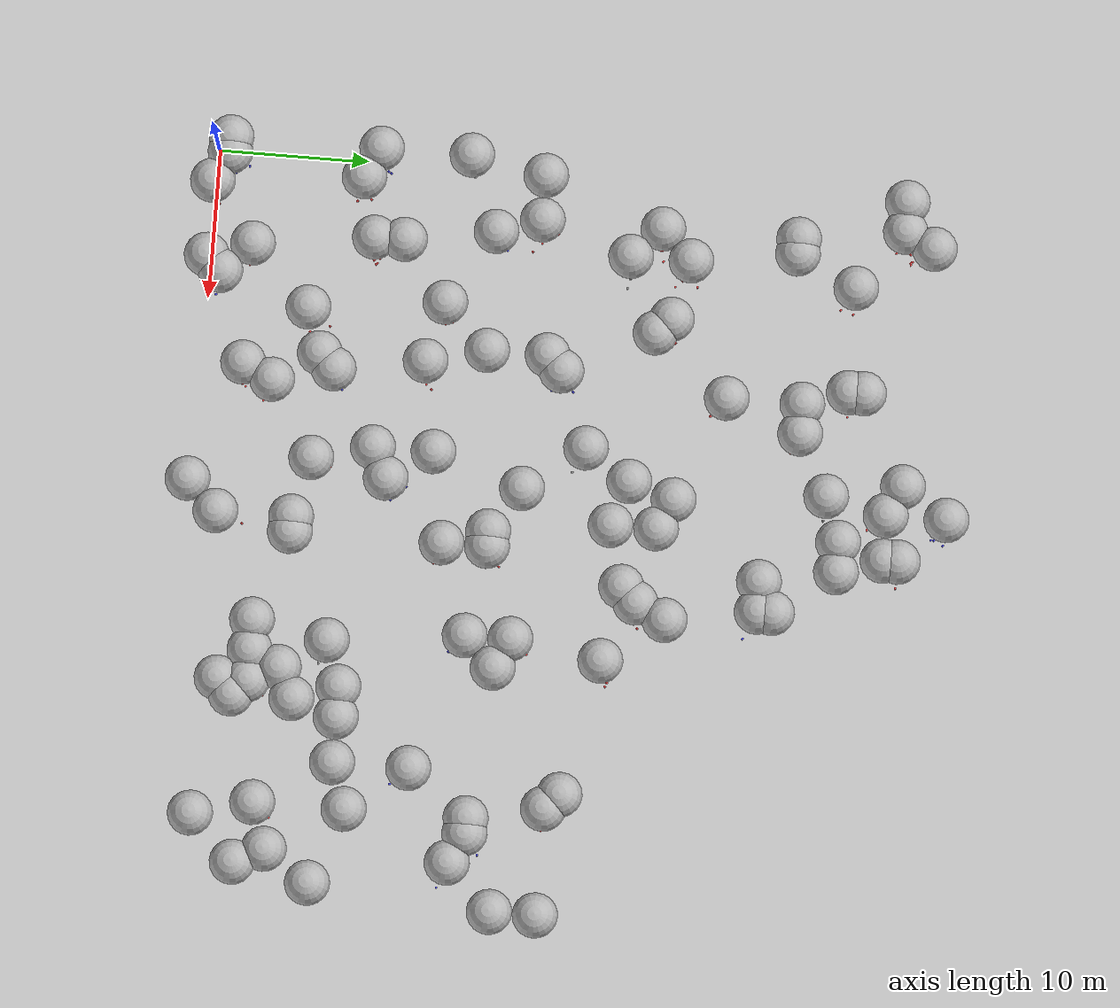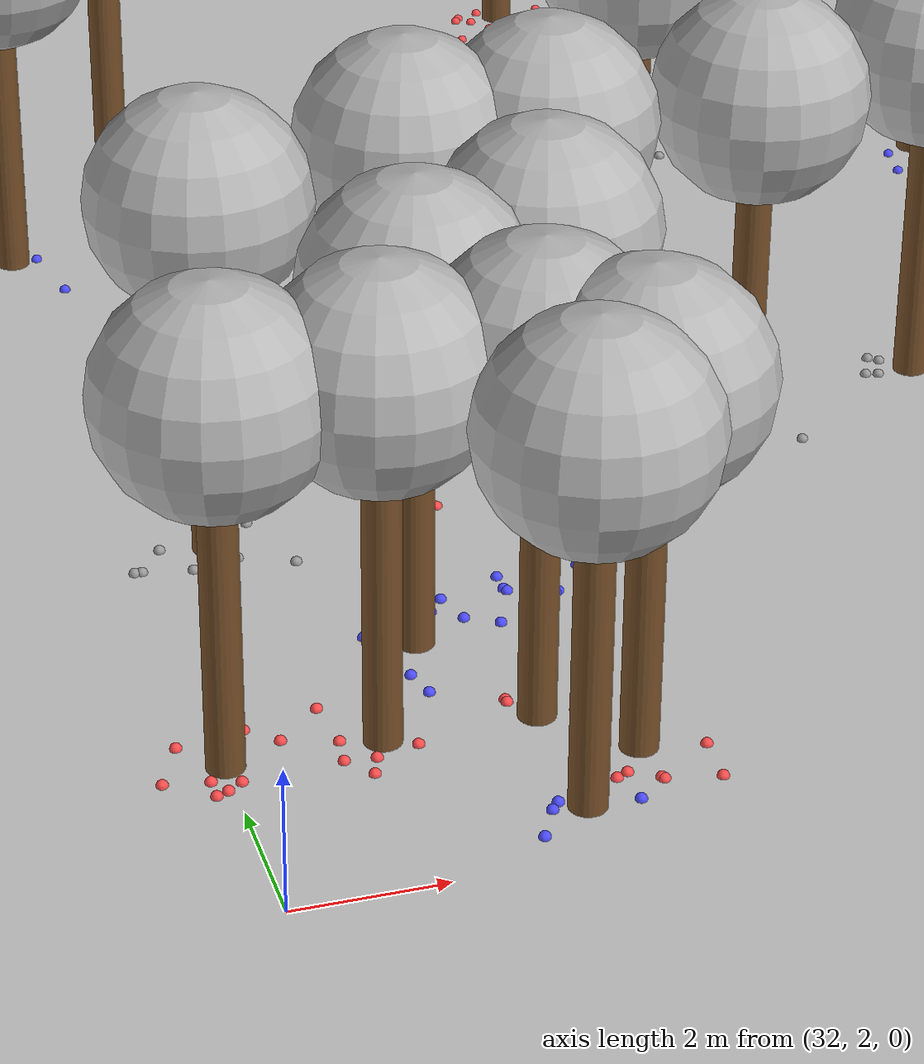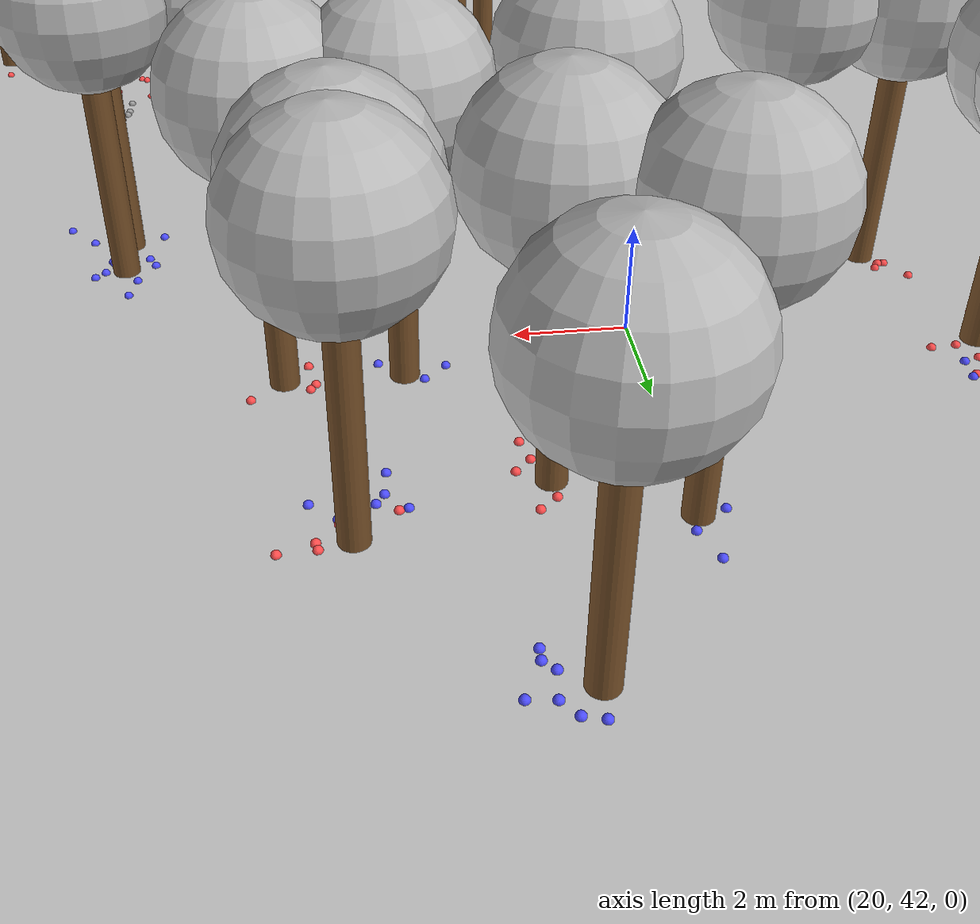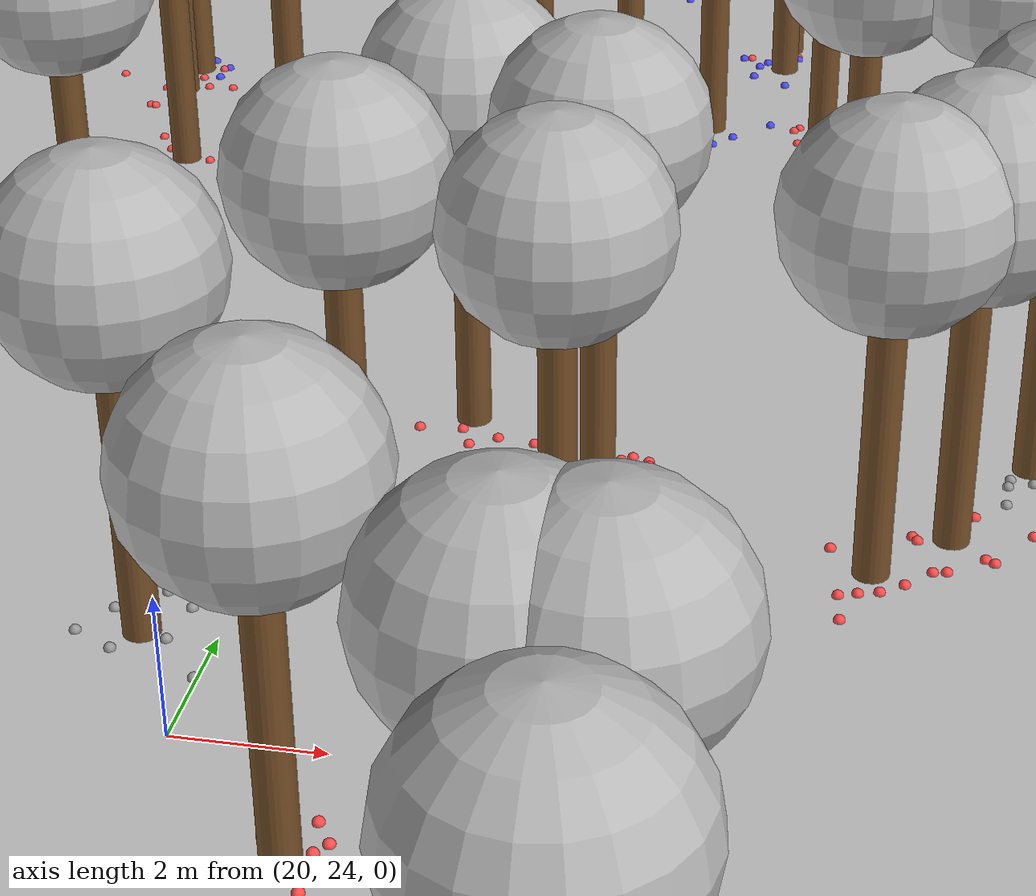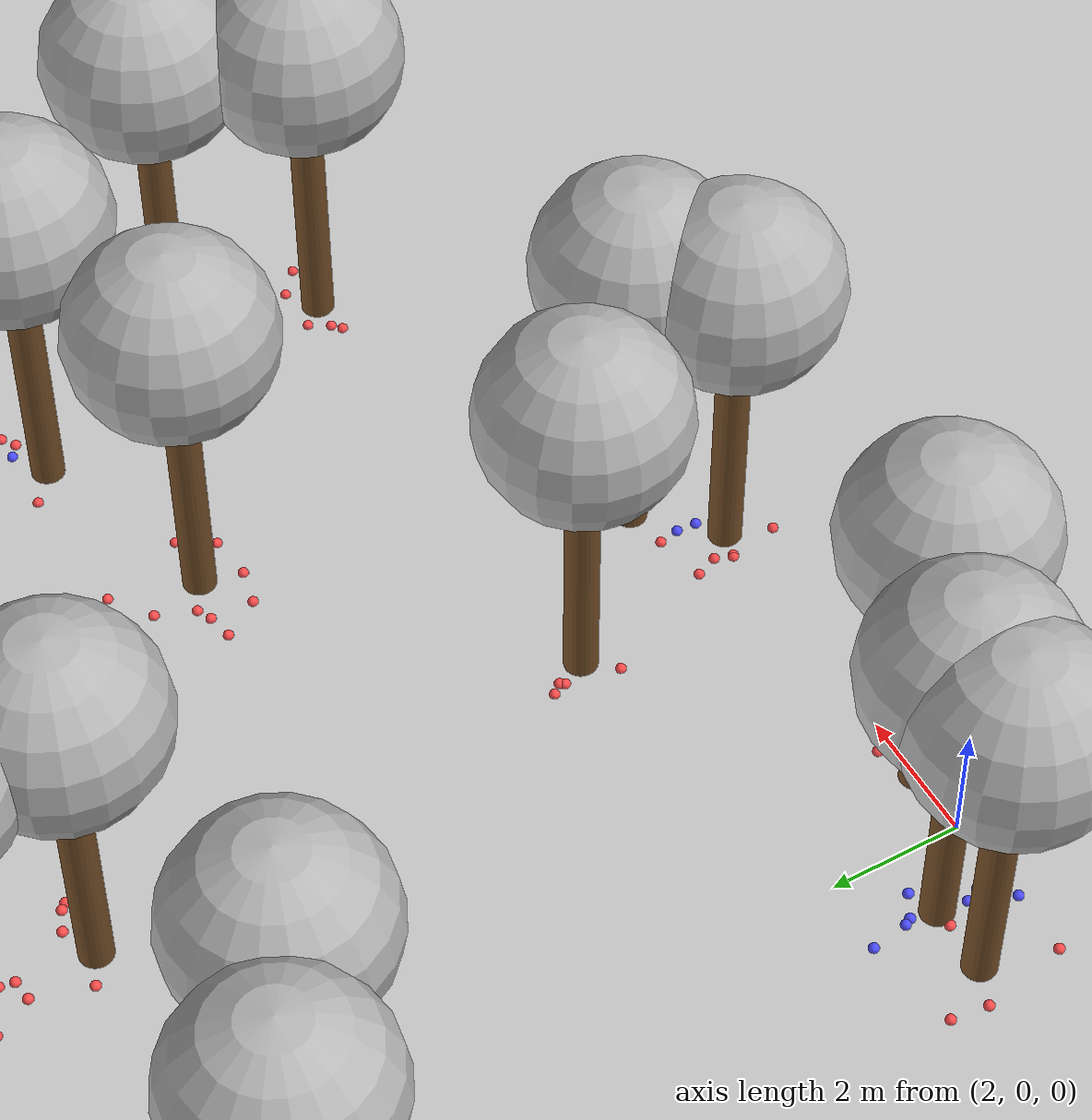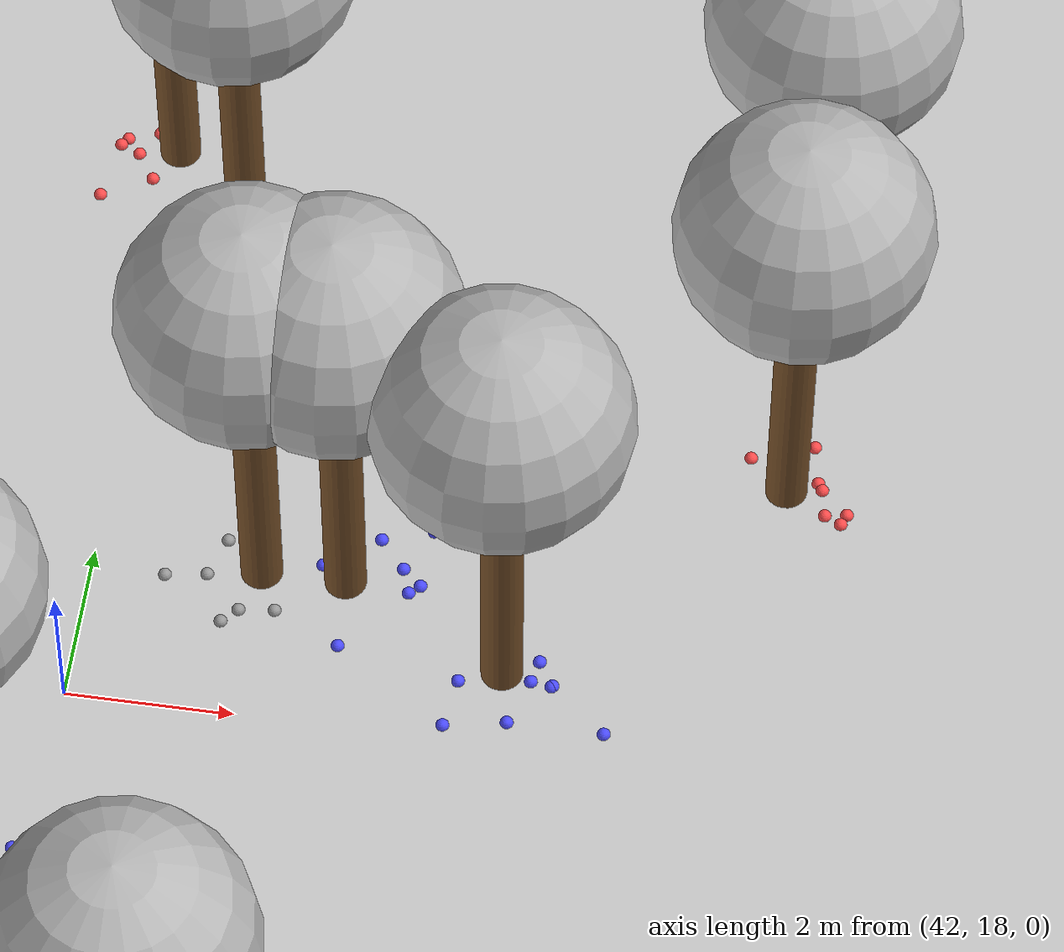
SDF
<sdf version="1.7">
 <world name="default">
  <light name="sun" type="directional">
   <pose>0 0 10 0 -0 0</pose>
   <diffuse>0.8 0.8 0.8 1</diffuse>
   <specular>0.2 0.2 0.2 1</specular>
   <attenuation>
    <range>1000</range>
    <constant>0.9</constant>
    <linear>0.01</linear>
    <quadratic>0.001</quadratic>
   </attenuation>
   <direction>-0.5 0.1 -0.9</direction>
   <spot><inner_angle>0</inner_angle><outer_angle>0</outer_angle><falloff>0</falloff></spot>
  </light>
  <model name="ground_plane">
   <static>1</static>
   <link name="link">
    <collision name="collision">
     <geometry><plane><normal>0 0 1</normal><size>100 100</size></plane></geometry>
     <surface>
      <contact><collide_bitmask>65535</collide_bitmask></contact>
      <friction><ode><mu>100</mu><mu2>50</mu2></ode></friction>
     </surface>
    </collision>
    <visual name="visual">
     <cast_shadows>0</cast_shadows>
     <geometry><plane><normal>0 0 1</normal><size>100 100</size></plane></geometry>
     <material>
      <script><uri>file://media/materials/scripts/gazebo.material</uri><name>Gazebo/Grey</name></script>
     </material>
    </visual>
   </link>
  </model>
  <gravity>0 0 -9.8</gravity>
  <magnetic_field>6e-06 2.3e-05 -4.2e-05</magnetic_field>
  <atmosphere type="adiabatic"/>
  <physics type="ode">
   <max_step_size>0.001</max_step_size>
   <real_time_factor>1</real_time_factor>
   <real_time_update_rate>1000</real_time_update_rate>
  </physics>
  <scene><ambient>0.4 0.4 0.4 1</ambient><background>0.7 0.7 0.7 1</background><shadows>1</shadows></scene>
  <spherical_coordinates>
   <surface_model>EARTH_WGS84</surface_model>
   <latitude_deg>0</latitude_deg>
   <longitude_deg>0</longitude_deg>
   <elevation>0</elevation>
   <heading_deg>0</heading_deg>
  </spherical_coordinates>
  <model name="tree_simple_0">
   <static>1</static>
   <link name="link">
    <pose>0 0 0.1 0 -0 0</pose>
    <inertial>
     <mass>666</mass>
     <inertia>
      <ixx>0.0861167</ixx>
      <ixy>0</ixy>
      <ixz>0</ixz>
      <iyy>0.0861167</iyy>
      <iyz>0</iyz>
      <izz>0.0861167</izz>
     </inertia>
    </inertial>
    <collision name="collision_trunk">
     <pose>0 0 2 0 -0 0</pose>
     <geometry><cylinder><radius>0.25</radius><length>4</length></cylinder></geometry>
     <surface>
      <contact>
       <poissons_ratio>0.347</poissons_ratio>
       <elastic_modulus>8.8e+09</elastic_modulus>
       <ode><kp>100000</kp><kd>100</kd><max_vel>100</max_vel><min_depth>0.001</min_depth></ode>
      </contact>
      <friction>
       <torsional>
        <coefficient>1</coefficient>
        <use_patch_radius>0</use_patch_radius>
        <surface_radius>0.01</surface_radius>
       </torsional>
      </friction>
     </surface>
    </collision>
    <collision name="collision_treetop">
     <pose>0 0 5.2 0 -0 0</pose>
     <geometry><sphere><radius>1.5</radius></sphere></geometry>
     <surface>
      <contact>
       <poissons_ratio>0.347</poissons_ratio>
       <elastic_modulus>8.8e+09</elastic_modulus>
       <ode><kp>100000</kp><kd>100</kd><max_vel>100</max_vel><min_depth>0.001</min_depth></ode>
      </contact>
      <friction>
       <torsional>
        <coefficient>1</coefficient>
        <use_patch_radius>0</use_patch_radius>
        <surface_radius>0.01</surface_radius>
       </torsional>
      </friction>
     </surface>
    </collision>
    <visual name="trunk">
     <pose>0 0 2 0 -0 0</pose>
     <geometry><cylinder><radius>0.25</radius><length>4</length></cylinder></geometry>
     <material>
      <script>
       <uri>model://tree_simple/scripts</uri>
       <uri>model://tree_simple/materials/textures</uri>
       <name>TreeSimple/Trunk</name>
      </script>
     </material>
    </visual>
    <visual name="treetop">
     <pose>0 0 5.2 0 -0 0</pose>
     <geometry><sphere><radius>1.5</radius></sphere></geometry>
     <material>
      <script>
       <uri>model://tree_simple/scripts</uri>
       <uri>model://tree_simple/materials/textures</uri>
       <name>TreeSimple/Treetop</name>
      </script>
     </material>
    </visual>
   </link>
   <pose>22 50 -0.1 0 -0 0</pose>
  </model>
  <model name="tree_simple_1">
   <static>1</static>
   <link name="link">
    <pose>0 0 0.1 0 -0 0</pose>
    <inertial>
     <mass>666</mass>
     <inertia>
      <ixx>0.0861167</ixx>
      <ixy>0</ixy>
      <ixz>0</ixz>
      <iyy>0.0861167</iyy>
      <iyz>0</iyz>
      <izz>0.0861167</izz>
     </inertia>
    </inertial>
    <collision name="collision_trunk">
     <pose>0 0 2 0 -0 0</pose>
     <geometry><cylinder><radius>0.25</radius><length>4</length></cylinder></geometry>
     <surface>
      <contact>
       <poissons_ratio>0.347</poissons_ratio>
       <elastic_modulus>8.8e+09</elastic_modulus>
       <ode><kp>100000</kp><kd>100</kd><max_vel>100</max_vel><min_depth>0.001</min_depth></ode>
      </contact>
      <friction>
       <torsional>
        <coefficient>1</coefficient>
        <use_patch_radius>0</use_patch_radius>
        <surface_radius>0.01</surface_radius>
       </torsional>
      </friction>
     </surface>
    </collision>
    <collision name="collision_treetop">
     <pose>0 0 5.2 0 -0 0</pose>
     <geometry><sphere><radius>1.5</radius></sphere></geometry>
     <surface>
      <contact>
       <poissons_ratio>0.347</poissons_ratio>
       <elastic_modulus>8.8e+09</elastic_modulus>
       <ode><kp>100000</kp><kd>100</kd><max_vel>100</max_vel><min_depth>0.001</min_depth></ode>
      </contact>
      <friction>
       <torsional>
        <coefficient>1</coefficient>
        <use_patch_radius>0</use_patch_radius>
        <surface_radius>0.01</surface_radius>
       </torsional>
      </friction>
     </surface>
    </collision>
    <visual name="trunk">
     <pose>0 0 2 0 -0 0</pose>
     <geometry><cylinder><radius>0.25</radius><length>4</length></cylinder></geometry>
     <material>
      <script>
       <uri>model://tree_simple/scripts</uri>
       <uri>model://tree_simple/materials/textures</uri>
       <name>TreeSimple/Trunk</name>
      </script>
     </material>
    </visual>
    <visual name="treetop">
     <pose>0 0 5.2 0 -0 0</pose>
     <geometry><sphere><radius>1.5</radius></sphere></geometry>
     <material>
      <script>
       <uri>model://tree_simple/scripts</uri>
       <uri>model://tree_simple/materials/textures</uri>
       <name>TreeSimple/Treetop</name>
      </script>
     </material>
    </visual>
   </link>
   <pose>4 48 -0.1 0 -0 0</pose>
  </model>
  <model name="tree_simple_2">
   <static>1</static>
   <link name="link">
    <pose>0 0 0.1 0 -0 0</pose>
    <inertial>
     <mass>666</mass>
     <inertia>
      <ixx>0.0861167</ixx>
      <ixy>0</ixy>
      <ixz>0</ixz>
      <iyy>0.0861167</iyy>
      <iyz>0</iyz>
      <izz>0.0861167</izz>
     </inertia>
    </inertial>
    <collision name="collision_trunk">
     <pose>0 0 2 0 -0 0</pose>
     <geometry><cylinder><radius>0.25</radius><length>4</length></cylinder></geometry>
     <surface>
      <contact>
       <poissons_ratio>0.347</poissons_ratio>
       <elastic_modulus>8.8e+09</elastic_modulus>
       <ode><kp>100000</kp><kd>100</kd><max_vel>100</max_vel><min_depth>0.001</min_depth></ode>
      </contact>
      <friction>
       <torsional>
        <coefficient>1</coefficient>
        <use_patch_radius>0</use_patch_radius>
        <surface_radius>0.01</surface_radius>
       </torsional>
      </friction>
     </surface>
    </collision>
    <collision name="collision_treetop">
     <pose>0 0 5.2 0 -0 0</pose>
     <geometry><sphere><radius>1.5</radius></sphere></geometry>
     <surface>
      <contact>
       <poissons_ratio>0.347</poissons_ratio>
       <elastic_modulus>8.8e+09</elastic_modulus>
       <ode><kp>100000</kp><kd>100</kd><max_vel>100</max_vel><min_depth>0.001</min_depth></ode>
      </contact>
      <friction>
       <torsional>
        <coefficient>1</coefficient>
        <use_patch_radius>0</use_patch_radius>
        <surface_radius>0.01</surface_radius>
       </torsional>
      </friction>
     </surface>
    </collision>
    <visual name="trunk">
     <pose>0 0 2 0 -0 0</pose>
     <geometry><cylinder><radius>0.25</radius><length>4</length></cylinder></geometry>
     <material>
      <script>
       <uri>model://tree_simple/scripts</uri>
       <uri>model://tree_simple/materials/textures</uri>
       <name>TreeSimple/Trunk</name>
      </script>
     </material>
    </visual>
    <visual name="treetop">
     <pose>0 0 5.2 0 -0 0</pose>
     <geometry><sphere><radius>1.5</radius></sphere></geometry>
     <material>
      <script>
       <uri>model://tree_simple/scripts</uri>
       <uri>model://tree_simple/materials/textures</uri>
       <name>TreeSimple/Treetop</name>
      </script>
     </material>
    </visual>
   </link>
   <pose>20 47 -0.1 0 -0 0</pose>
  </model>
  <model name="tree_simple_3">
   <static>1</static>
   <link name="link">
    <pose>0 0 0.1 0 -0 0</pose>
    <inertial>
     <mass>666</mass>
     <inertia>
      <ixx>0.0861167</ixx>
      <ixy>0</ixy>
      <ixz>0</ixz>
      <iyy>0.0861167</iyy>
      <iyz>0</iyz>
      <izz>0.0861167</izz>
     </inertia>
    </inertial>
    <collision name="collision_trunk">
     <pose>0 0 2 0 -0 0</pose>
     <geometry><cylinder><radius>0.25</radius><length>4</length></cylinder></geometry>
     <surface>
      <contact>
       <poissons_ratio>0.347</poissons_ratio>
       <elastic_modulus>8.8e+09</elastic_modulus>
       <ode><kp>100000</kp><kd>100</kd><max_vel>100</max_vel><min_depth>0.001</min_depth></ode>
      </contact>
      <friction>
       <torsional>
        <coefficient>1</coefficient>
        <use_patch_radius>0</use_patch_radius>
        <surface_radius>0.01</surface_radius>
       </torsional>
      </friction>
     </surface>
    </collision>
    <collision name="collision_treetop">
     <pose>0 0 5.2 0 -0 0</pose>
     <geometry><sphere><radius>1.5</radius></sphere></geometry>
     <surface>
      <contact>
       <poissons_ratio>0.347</poissons_ratio>
       <elastic_modulus>8.8e+09</elastic_modulus>
       <ode><kp>100000</kp><kd>100</kd><max_vel>100</max_vel><min_depth>0.001</min_depth></ode>
      </contact>
      <friction>
       <torsional>
        <coefficient>1</coefficient>
        <use_patch_radius>0</use_patch_radius>
        <surface_radius>0.01</surface_radius>
       </torsional>
      </friction>
     </surface>
    </collision>
    <visual name="trunk">
     <pose>0 0 2 0 -0 0</pose>
     <geometry><cylinder><radius>0.25</radius><length>4</length></cylinder></geometry>
     <material>
      <script>
       <uri>model://tree_simple/scripts</uri>
       <uri>model://tree_simple/materials/textures</uri>
       <name>TreeSimple/Trunk</name>
      </script>
     </material>
    </visual>
    <visual name="treetop">
     <pose>0 0 5.2 0 -0 0</pose>
     <geometry><sphere><radius>1.5</radius></sphere></geometry>
     <material>
      <script>
       <uri>model://tree_simple/scripts</uri>
       <uri>model://tree_simple/materials/textures</uri>
       <name>TreeSimple/Treetop</name>
      </script>
     </material>
    </visual>
   </link>
   <pose>25 47 -0.1 0 -0 0</pose>
  </model>
  <model name="tree_simple_4">
   <static>1</static>
   <link name="link">
    <pose>0 0 0.1 0 -0 0</pose>
    <inertial>
     <mass>666</mass>
     <inertia>
      <ixx>0.0861167</ixx>
      <ixy>0</ixy>
      <ixz>0</ixz>
      <iyy>0.0861167</iyy>
      <iyz>0</iyz>
      <izz>0.0861167</izz>
     </inertia>
    </inertial>
    <collision name="collision_trunk">
     <pose>0 0 2 0 -0 0</pose>
     <geometry><cylinder><radius>0.25</radius><length>4</length></cylinder></geometry>
     <surface>
      <contact>
       <poissons_ratio>0.347</poissons_ratio>
       <elastic_modulus>8.8e+09</elastic_modulus>
       <ode><kp>100000</kp><kd>100</kd><max_vel>100</max_vel><min_depth>0.001</min_depth></ode>
      </contact>
      <friction>
       <torsional>
        <coefficient>1</coefficient>
        <use_patch_radius>0</use_patch_radius>
        <surface_radius>0.01</surface_radius>
       </torsional>
      </friction>
     </surface>
    </collision>
    <collision name="collision_treetop">
     <pose>0 0 5.2 0 -0 0</pose>
     <geometry><sphere><radius>1.5</radius></sphere></geometry>
     <surface>
      <contact>
       <poissons_ratio>0.347</poissons_ratio>
       <elastic_modulus>8.8e+09</elastic_modulus>
       <ode><kp>100000</kp><kd>100</kd><max_vel>100</max_vel><min_depth>0.001</min_depth></ode>
      </contact>
      <friction>
       <torsional>
        <coefficient>1</coefficient>
        <use_patch_radius>0</use_patch_radius>
        <surface_radius>0.01</surface_radius>
       </torsional>
      </friction>
     </surface>
    </collision>
    <visual name="trunk">
     <pose>0 0 2 0 -0 0</pose>
     <geometry><cylinder><radius>0.25</radius><length>4</length></cylinder></geometry>
     <material>
      <script>
       <uri>model://tree_simple/scripts</uri>
       <uri>model://tree_simple/materials/textures</uri>
       <name>TreeSimple/Trunk</name>
      </script>
     </material>
    </visual>
    <visual name="treetop">
     <pose>0 0 5.2 0 -0 0</pose>
     <geometry><sphere><radius>1.5</radius></sphere></geometry>
     <material>
      <script>
       <uri>model://tree_simple/scripts</uri>
       <uri>model://tree_simple/materials/textures</uri>
       <name>TreeSimple/Treetop</name>
      </script>
     </material>
    </visual>
   </link>
   <pose>1 46 -0.1 0 -0 0</pose>
  </model>
  <model name="tree_simple_5">
   <static>1</static>
   <link name="link">
    <pose>0 0 0.1 0 -0 0</pose>
    <inertial>
     <mass>666</mass>
     <inertia>
      <ixx>0.0861167</ixx>
      <ixy>0</ixy>
      <ixz>0</ixz>
      <iyy>0.0861167</iyy>
      <iyz>0</iyz>
      <izz>0.0861167</izz>
     </inertia>
    </inertial>
    <collision name="collision_trunk">
     <pose>0 0 2 0 -0 0</pose>
     <geometry><cylinder><radius>0.25</radius><length>4</length></cylinder></geometry>
     <surface>
      <contact>
       <poissons_ratio>0.347</poissons_ratio>
       <elastic_modulus>8.8e+09</elastic_modulus>
       <ode><kp>100000</kp><kd>100</kd><max_vel>100</max_vel><min_depth>0.001</min_depth></ode>
      </contact>
      <friction>
       <torsional>
        <coefficient>1</coefficient>
        <use_patch_radius>0</use_patch_radius>
        <surface_radius>0.01</surface_radius>
       </torsional>
      </friction>
     </surface>
    </collision>
    <collision name="collision_treetop">
     <pose>0 0 5.2 0 -0 0</pose>
     <geometry><sphere><radius>1.5</radius></sphere></geometry>
     <surface>
      <contact>
       <poissons_ratio>0.347</poissons_ratio>
       <elastic_modulus>8.8e+09</elastic_modulus>
       <ode><kp>100000</kp><kd>100</kd><max_vel>100</max_vel><min_depth>0.001</min_depth></ode>
      </contact>
      <friction>
       <torsional>
        <coefficient>1</coefficient>
        <use_patch_radius>0</use_patch_radius>
        <surface_radius>0.01</surface_radius>
       </torsional>
      </friction>
     </surface>
    </collision>
    <visual name="trunk">
     <pose>0 0 2 0 -0 0</pose>
     <geometry><cylinder><radius>0.25</radius><length>4</length></cylinder></geometry>
     <material>
      <script>
       <uri>model://tree_simple/scripts</uri>
       <uri>model://tree_simple/materials/textures</uri>
       <name>TreeSimple/Trunk</name>
      </script>
     </material>
    </visual>
    <visual name="treetop">
     <pose>0 0 5.2 0 -0 0</pose>
     <geometry><sphere><radius>1.5</radius></sphere></geometry>
     <material>
      <script>
       <uri>model://tree_simple/scripts</uri>
       <uri>model://tree_simple/materials/textures</uri>
       <name>TreeSimple/Treetop</name>
      </script>
     </material>
    </visual>
   </link>
   <pose>3 46 -0.1 0 -0 0</pose>
  </model>
  <model name="tree_simple_6">
   <static>1</static>
   <link name="link">
    <pose>0 0 0.1 0 -0 0</pose>
    <inertial>
     <mass>666</mass>
     <inertia>
      <ixx>0.0861167</ixx>
      <ixy>0</ixy>
      <ixz>0</ixz>
      <iyy>0.0861167</iyy>
      <iyz>0</iyz>
      <izz>0.0861167</izz>
     </inertia>
    </inertial>
    <collision name="collision_trunk">
     <pose>0 0 2 0 -0 0</pose>
     <geometry><cylinder><radius>0.25</radius><length>4</length></cylinder></geometry>
     <surface>
      <contact>
       <poissons_ratio>0.347</poissons_ratio>
       <elastic_modulus>8.8e+09</elastic_modulus>
       <ode><kp>100000</kp><kd>100</kd><max_vel>100</max_vel><min_depth>0.001</min_depth></ode>
      </contact>
      <friction>
       <torsional>
        <coefficient>1</coefficient>
        <use_patch_radius>0</use_patch_radius>
        <surface_radius>0.01</surface_radius>
       </torsional>
      </friction>
     </surface>
    </collision>
    <collision name="collision_treetop">
     <pose>0 0 5.2 0 -0 0</pose>
     <geometry><sphere><radius>1.5</radius></sphere></geometry>
     <surface>
      <contact>
       <poissons_ratio>0.347</poissons_ratio>
       <elastic_modulus>8.8e+09</elastic_modulus>
       <ode><kp>100000</kp><kd>100</kd><max_vel>100</max_vel><min_depth>0.001</min_depth></ode>
      </contact>
      <friction>
       <torsional>
        <coefficient>1</coefficient>
        <use_patch_radius>0</use_patch_radius>
        <surface_radius>0.01</surface_radius>
       </torsional>
      </friction>
     </surface>
    </collision>
    <visual name="trunk">
     <pose>0 0 2 0 -0 0</pose>
     <geometry><cylinder><radius>0.25</radius><length>4</length></cylinder></geometry>
     <material>
      <script>
       <uri>model://tree_simple/scripts</uri>
       <uri>model://tree_simple/materials/textures</uri>
       <name>TreeSimple/Trunk</name>
      </script>
     </material>
    </visual>
    <visual name="treetop">
     <pose>0 0 5.2 0 -0 0</pose>
     <geometry><sphere><radius>1.5</radius></sphere></geometry>
     <material>
      <script>
       <uri>model://tree_simple/scripts</uri>
       <uri>model://tree_simple/materials/textures</uri>
       <name>TreeSimple/Treetop</name>
      </script>
     </material>
    </visual>
   </link>
   <pose>22 46 -0.1 0 -0 0</pose>
  </model>
  <model name="tree_simple_7">
   <static>1</static>
   <link name="link">
    <pose>0 0 0.1 0 -0 0</pose>
    <inertial>
     <mass>666</mass>
     <inertia>
      <ixx>0.0861167</ixx>
      <ixy>0</ixy>
      <ixz>0</ixz>
      <iyy>0.0861167</iyy>
      <iyz>0</iyz>
      <izz>0.0861167</izz>
     </inertia>
    </inertial>
    <collision name="collision_trunk">
     <pose>0 0 2 0 -0 0</pose>
     <geometry><cylinder><radius>0.25</radius><length>4</length></cylinder></geometry>
     <surface>
      <contact>
       <poissons_ratio>0.347</poissons_ratio>
       <elastic_modulus>8.8e+09</elastic_modulus>
       <ode><kp>100000</kp><kd>100</kd><max_vel>100</max_vel><min_depth>0.001</min_depth></ode>
      </contact>
      <friction>
       <torsional>
        <coefficient>1</coefficient>
        <use_patch_radius>0</use_patch_radius>
        <surface_radius>0.01</surface_radius>
       </torsional>
      </friction>
     </surface>
    </collision>
    <collision name="collision_treetop">
     <pose>0 0 5.2 0 -0 0</pose>
     <geometry><sphere><radius>1.5</radius></sphere></geometry>
     <surface>
      <contact>
       <poissons_ratio>0.347</poissons_ratio>
       <elastic_modulus>8.8e+09</elastic_modulus>
       <ode><kp>100000</kp><kd>100</kd><max_vel>100</max_vel><min_depth>0.001</min_depth></ode>
      </contact>
      <friction>
       <torsional>
        <coefficient>1</coefficient>
        <use_patch_radius>0</use_patch_radius>
        <surface_radius>0.01</surface_radius>
       </torsional>
      </friction>
     </surface>
    </collision>
    <visual name="trunk">
     <pose>0 0 2 0 -0 0</pose>
     <geometry><cylinder><radius>0.25</radius><length>4</length></cylinder></geometry>
     <material>
      <script>
       <uri>model://tree_simple/scripts</uri>
       <uri>model://tree_simple/materials/textures</uri>
       <name>TreeSimple/Trunk</name>
      </script>
     </material>
    </visual>
    <visual name="treetop">
     <pose>0 0 5.2 0 -0 0</pose>
     <geometry><sphere><radius>1.5</radius></sphere></geometry>
     <material>
      <script>
       <uri>model://tree_simple/scripts</uri>
       <uri>model://tree_simple/materials/textures</uri>
       <name>TreeSimple/Treetop</name>
      </script>
     </material>
    </visual>
   </link>
   <pose>25 46 -0.1 0 -0 0</pose>
  </model>
  <model name="tree_simple_8">
   <static>1</static>
   <link name="link">
    <pose>0 0 0.1 0 -0 0</pose>
    <inertial>
     <mass>666</mass>
     <inertia>
      <ixx>0.0861167</ixx>
      <ixy>0</ixy>
      <ixz>0</ixz>
      <iyy>0.0861167</iyy>
      <iyz>0</iyz>
      <izz>0.0861167</izz>
     </inertia>
    </inertial>
    <collision name="collision_trunk">
     <pose>0 0 2 0 -0 0</pose>
     <geometry><cylinder><radius>0.25</radius><length>4</length></cylinder></geometry>
     <surface>
      <contact>
       <poissons_ratio>0.347</poissons_ratio>
       <elastic_modulus>8.8e+09</elastic_modulus>
       <ode><kp>100000</kp><kd>100</kd><max_vel>100</max_vel><min_depth>0.001</min_depth></ode>
      </contact>
      <friction>
       <torsional>
        <coefficient>1</coefficient>
        <use_patch_radius>0</use_patch_radius>
        <surface_radius>0.01</surface_radius>
       </torsional>
      </friction>
     </surface>
    </collision>
    <collision name="collision_treetop">
     <pose>0 0 5.2 0 -0 0</pose>
     <geometry><sphere><radius>1.5</radius></sphere></geometry>
     <surface>
      <contact>
       <poissons_ratio>0.347</poissons_ratio>
       <elastic_modulus>8.8e+09</elastic_modulus>
       <ode><kp>100000</kp><kd>100</kd><max_vel>100</max_vel><min_depth>0.001</min_depth></ode>
      </contact>
      <friction>
       <torsional>
        <coefficient>1</coefficient>
        <use_patch_radius>0</use_patch_radius>
        <surface_radius>0.01</surface_radius>
       </torsional>
      </friction>
     </surface>
    </collision>
    <visual name="trunk">
     <pose>0 0 2 0 -0 0</pose>
     <geometry><cylinder><radius>0.25</radius><length>4</length></cylinder></geometry>
     <material>
      <script>
       <uri>model://tree_simple/scripts</uri>
       <uri>model://tree_simple/materials/textures</uri>
       <name>TreeSimple/Trunk</name>
      </script>
     </material>
    </visual>
    <visual name="treetop">
     <pose>0 0 5.2 0 -0 0</pose>
     <geometry><sphere><radius>1.5</radius></sphere></geometry>
     <material>
      <script>
       <uri>model://tree_simple/scripts</uri>
       <uri>model://tree_simple/materials/textures</uri>
       <name>TreeSimple/Treetop</name>
      </script>
     </material>
    </visual>
   </link>
   <pose>14 44 -0.1 0 -0 0</pose>
  </model>
  <model name="tree_simple_9">
   <static>1</static>
   <link name="link">
    <pose>0 0 0.1 0 -0 0</pose>
    <inertial>
     <mass>666</mass>
     <inertia>
      <ixx>0.0861167</ixx>
      <ixy>0</ixy>
      <ixz>0</ixz>
      <iyy>0.0861167</iyy>
      <iyz>0</iyz>
      <izz>0.0861167</izz>
     </inertia>
    </inertial>
    <collision name="collision_trunk">
     <pose>0 0 2 0 -0 0</pose>
     <geometry><cylinder><radius>0.25</radius><length>4</length></cylinder></geometry>
     <surface>
      <contact>
       <poissons_ratio>0.347</poissons_ratio>
       <elastic_modulus>8.8e+09</elastic_modulus>
       <ode><kp>100000</kp><kd>100</kd><max_vel>100</max_vel><min_depth>0.001</min_depth></ode>
      </contact>
      <friction>
       <torsional>
        <coefficient>1</coefficient>
        <use_patch_radius>0</use_patch_radius>
        <surface_radius>0.01</surface_radius>
       </torsional>
      </friction>
     </surface>
    </collision>
    <collision name="collision_treetop">
     <pose>0 0 5.2 0 -0 0</pose>
     <geometry><sphere><radius>1.5</radius></sphere></geometry>
     <surface>
      <contact>
       <poissons_ratio>0.347</poissons_ratio>
       <elastic_modulus>8.8e+09</elastic_modulus>
       <ode><kp>100000</kp><kd>100</kd><max_vel>100</max_vel><min_depth>0.001</min_depth></ode>
      </contact>
      <friction>
       <torsional>
        <coefficient>1</coefficient>
        <use_patch_radius>0</use_patch_radius>
        <surface_radius>0.01</surface_radius>
       </torsional>
      </friction>
     </surface>
    </collision>
    <visual name="trunk">
     <pose>0 0 2 0 -0 0</pose>
     <geometry><cylinder><radius>0.25</radius><length>4</length></cylinder></geometry>
     <material>
      <script>
       <uri>model://tree_simple/scripts</uri>
       <uri>model://tree_simple/materials/textures</uri>
       <name>TreeSimple/Trunk</name>
      </script>
     </material>
    </visual>
    <visual name="treetop">
     <pose>0 0 5.2 0 -0 0</pose>
     <geometry><sphere><radius>1.5</radius></sphere></geometry>
     <material>
      <script>
       <uri>model://tree_simple/scripts</uri>
       <uri>model://tree_simple/materials/textures</uri>
       <name>TreeSimple/Treetop</name>
      </script>
     </material>
    </visual>
   </link>
   <pose>7 43 -0.1 0 -0 0</pose>
  </model>
  <model name="tree_simple_10">
   <static>1</static>
   <link name="link">
    <pose>0 0 0.1 0 -0 0</pose>
    <inertial>
     <mass>666</mass>
     <inertia>
      <ixx>0.0861167</ixx>
      <ixy>0</ixy>
      <ixz>0</ixz>
      <iyy>0.0861167</iyy>
      <iyz>0</iyz>
      <izz>0.0861167</izz>
     </inertia>
    </inertial>
    <collision name="collision_trunk">
     <pose>0 0 2 0 -0 0</pose>
     <geometry><cylinder><radius>0.25</radius><length>4</length></cylinder></geometry>
     <surface>
      <contact>
       <poissons_ratio>0.347</poissons_ratio>
       <elastic_modulus>8.8e+09</elastic_modulus>
       <ode><kp>100000</kp><kd>100</kd><max_vel>100</max_vel><min_depth>0.001</min_depth></ode>
      </contact>
      <friction>
       <torsional>
        <coefficient>1</coefficient>
        <use_patch_radius>0</use_patch_radius>
        <surface_radius>0.01</surface_radius>
       </torsional>
      </friction>
     </surface>
    </collision>
    <collision name="collision_treetop">
     <pose>0 0 5.2 0 -0 0</pose>
     <geometry><sphere><radius>1.5</radius></sphere></geometry>
     <surface>
      <contact>
       <poissons_ratio>0.347</poissons_ratio>
       <elastic_modulus>8.8e+09</elastic_modulus>
       <ode><kp>100000</kp><kd>100</kd><max_vel>100</max_vel><min_depth>0.001</min_depth></ode>
      </contact>
      <friction>
       <torsional>
        <coefficient>1</coefficient>
        <use_patch_radius>0</use_patch_radius>
        <surface_radius>0.01</surface_radius>
       </torsional>
      </friction>
     </surface>
    </collision>
    <visual name="trunk">
     <pose>0 0 2 0 -0 0</pose>
     <geometry><cylinder><radius>0.25</radius><length>4</length></cylinder></geometry>
     <material>
      <script>
       <uri>model://tree_simple/scripts</uri>
       <uri>model://tree_simple/materials/textures</uri>
       <name>TreeSimple/Trunk</name>
      </script>
     </material>
    </visual>
    <visual name="treetop">
     <pose>0 0 5.2 0 -0 0</pose>
     <geometry><sphere><radius>1.5</radius></sphere></geometry>
     <material>
      <script>
       <uri>model://tree_simple/scripts</uri>
       <uri>model://tree_simple/materials/textures</uri>
       <name>TreeSimple/Treetop</name>
      </script>
     </material>
    </visual>
   </link>
   <pose>14 43 -0.1 0 -0 0</pose>
  </model>
  <model name="tree_simple_11">
   <static>1</static>
   <link name="link">
    <pose>0 0 0.1 0 -0 0</pose>
    <inertial>
     <mass>666</mass>
     <inertia>
      <ixx>0.0861167</ixx>
      <ixy>0</ixy>
      <ixz>0</ixz>
      <iyy>0.0861167</iyy>
      <iyz>0</iyz>
      <izz>0.0861167</izz>
     </inertia>
    </inertial>
    <collision name="collision_trunk">
     <pose>0 0 2 0 -0 0</pose>
     <geometry><cylinder><radius>0.25</radius><length>4</length></cylinder></geometry>
     <surface>
      <contact>
       <poissons_ratio>0.347</poissons_ratio>
       <elastic_modulus>8.8e+09</elastic_modulus>
       <ode><kp>100000</kp><kd>100</kd><max_vel>100</max_vel><min_depth>0.001</min_depth></ode>
      </contact>
      <friction>
       <torsional>
        <coefficient>1</coefficient>
        <use_patch_radius>0</use_patch_radius>
        <surface_radius>0.01</surface_radius>
       </torsional>
      </friction>
     </surface>
    </collision>
    <collision name="collision_treetop">
     <pose>0 0 5.2 0 -0 0</pose>
     <geometry><sphere><radius>1.5</radius></sphere></geometry>
     <surface>
      <contact>
       <poissons_ratio>0.347</poissons_ratio>
       <elastic_modulus>8.8e+09</elastic_modulus>
       <ode><kp>100000</kp><kd>100</kd><max_vel>100</max_vel><min_depth>0.001</min_depth></ode>
      </contact>
      <friction>
       <torsional>
        <coefficient>1</coefficient>
        <use_patch_radius>0</use_patch_radius>
        <surface_radius>0.01</surface_radius>
       </torsional>
      </friction>
     </surface>
    </collision>
    <visual name="trunk">
     <pose>0 0 2 0 -0 0</pose>
     <geometry><cylinder><radius>0.25</radius><length>4</length></cylinder></geometry>
     <material>
      <script>
       <uri>model://tree_simple/scripts</uri>
       <uri>model://tree_simple/materials/textures</uri>
       <name>TreeSimple/Trunk</name>
      </script>
     </material>
    </visual>
    <visual name="treetop">
     <pose>0 0 5.2 0 -0 0</pose>
     <geometry><sphere><radius>1.5</radius></sphere></geometry>
     <material>
      <script>
       <uri>model://tree_simple/scripts</uri>
       <uri>model://tree_simple/materials/textures</uri>
       <name>TreeSimple/Treetop</name>
      </script>
     </material>
    </visual>
   </link>
   <pose>24 43 -0.1 0 -0 0</pose>
  </model>
  <model name="tree_simple_12">
   <static>1</static>
   <link name="link">
    <pose>0 0 0.1 0 -0 0</pose>
    <inertial>
     <mass>666</mass>
     <inertia>
      <ixx>0.0861167</ixx>
      <ixy>0</ixy>
      <ixz>0</ixz>
      <iyy>0.0861167</iyy>
      <iyz>0</iyz>
      <izz>0.0861167</izz>
     </inertia>
    </inertial>
    <collision name="collision_trunk">
     <pose>0 0 2 0 -0 0</pose>
     <geometry><cylinder><radius>0.25</radius><length>4</length></cylinder></geometry>
     <surface>
      <contact>
       <poissons_ratio>0.347</poissons_ratio>
       <elastic_modulus>8.8e+09</elastic_modulus>
       <ode><kp>100000</kp><kd>100</kd><max_vel>100</max_vel><min_depth>0.001</min_depth></ode>
      </contact>
      <friction>
       <torsional>
        <coefficient>1</coefficient>
        <use_patch_radius>0</use_patch_radius>
        <surface_radius>0.01</surface_radius>
       </torsional>
      </friction>
     </surface>
    </collision>
    <collision name="collision_treetop">
     <pose>0 0 5.2 0 -0 0</pose>
     <geometry><sphere><radius>1.5</radius></sphere></geometry>
     <surface>
      <contact>
       <poissons_ratio>0.347</poissons_ratio>
       <elastic_modulus>8.8e+09</elastic_modulus>
       <ode><kp>100000</kp><kd>100</kd><max_vel>100</max_vel><min_depth>0.001</min_depth></ode>
      </contact>
      <friction>
       <torsional>
        <coefficient>1</coefficient>
        <use_patch_radius>0</use_patch_radius>
        <surface_radius>0.01</surface_radius>
       </torsional>
      </friction>
     </surface>
    </collision>
    <visual name="trunk">
     <pose>0 0 2 0 -0 0</pose>
     <geometry><cylinder><radius>0.25</radius><length>4</length></cylinder></geometry>
     <material>
      <script>
       <uri>model://tree_simple/scripts</uri>
       <uri>model://tree_simple/materials/textures</uri>
       <name>TreeSimple/Trunk</name>
      </script>
     </material>
    </visual>
    <visual name="treetop">
     <pose>0 0 5.2 0 -0 0</pose>
     <geometry><sphere><radius>1.5</radius></sphere></geometry>
     <material>
      <script>
       <uri>model://tree_simple/scripts</uri>
       <uri>model://tree_simple/materials/textures</uri>
       <name>TreeSimple/Treetop</name>
      </script>
     </material>
    </visual>
   </link>
   <pose>26 43 -0.1 0 -0 0</pose>
  </model>
  <model name="tree_simple_13">
   <static>1</static>
   <link name="link">
    <pose>0 0 0.1 0 -0 0</pose>
    <inertial>
     <mass>666</mass>
     <inertia>
      <ixx>0.0861167</ixx>
      <ixy>0</ixy>
      <ixz>0</ixz>
      <iyy>0.0861167</iyy>
      <iyz>0</iyz>
      <izz>0.0861167</izz>
     </inertia>
    </inertial>
    <collision name="collision_trunk">
     <pose>0 0 2 0 -0 0</pose>
     <geometry><cylinder><radius>0.25</radius><length>4</length></cylinder></geometry>
     <surface>
      <contact>
       <poissons_ratio>0.347</poissons_ratio>
       <elastic_modulus>8.8e+09</elastic_modulus>
       <ode><kp>100000</kp><kd>100</kd><max_vel>100</max_vel><min_depth>0.001</min_depth></ode>
      </contact>
      <friction>
       <torsional>
        <coefficient>1</coefficient>
        <use_patch_radius>0</use_patch_radius>
        <surface_radius>0.01</surface_radius>
       </torsional>
      </friction>
     </surface>
    </collision>
    <collision name="collision_treetop">
     <pose>0 0 5.2 0 -0 0</pose>
     <geometry><sphere><radius>1.5</radius></sphere></geometry>
     <surface>
      <contact>
       <poissons_ratio>0.347</poissons_ratio>
       <elastic_modulus>8.8e+09</elastic_modulus>
       <ode><kp>100000</kp><kd>100</kd><max_vel>100</max_vel><min_depth>0.001</min_depth></ode>
      </contact>
      <friction>
       <torsional>
        <coefficient>1</coefficient>
        <use_patch_radius>0</use_patch_radius>
        <surface_radius>0.01</surface_radius>
       </torsional>
      </friction>
     </surface>
    </collision>
    <visual name="trunk">
     <pose>0 0 2 0 -0 0</pose>
     <geometry><cylinder><radius>0.25</radius><length>4</length></cylinder></geometry>
     <material>
      <script>
       <uri>model://tree_simple/scripts</uri>
       <uri>model://tree_simple/materials/textures</uri>
       <name>TreeSimple/Trunk</name>
      </script>
     </material>
    </visual>
    <visual name="treetop">
     <pose>0 0 5.2 0 -0 0</pose>
     <geometry><sphere><radius>1.5</radius></sphere></geometry>
     <material>
      <script>
       <uri>model://tree_simple/scripts</uri>
       <uri>model://tree_simple/materials/textures</uri>
       <name>TreeSimple/Treetop</name>
      </script>
     </material>
    </visual>
   </link>
   <pose>21 42 -0.1 0 -0 0</pose>
  </model>
  <model name="tree_simple_14">
   <static>1</static>
   <link name="link">
    <pose>0 0 0.1 0 -0 0</pose>
    <inertial>
     <mass>666</mass>
     <inertia>
      <ixx>0.0861167</ixx>
      <ixy>0</ixy>
      <ixz>0</ixz>
      <iyy>0.0861167</iyy>
      <iyz>0</iyz>
      <izz>0.0861167</izz>
     </inertia>
    </inertial>
    <collision name="collision_trunk">
     <pose>0 0 2 0 -0 0</pose>
     <geometry><cylinder><radius>0.25</radius><length>4</length></cylinder></geometry>
     <surface>
      <contact>
       <poissons_ratio>0.347</poissons_ratio>
       <elastic_modulus>8.8e+09</elastic_modulus>
       <ode><kp>100000</kp><kd>100</kd><max_vel>100</max_vel><min_depth>0.001</min_depth></ode>
      </contact>
      <friction>
       <torsional>
        <coefficient>1</coefficient>
        <use_patch_radius>0</use_patch_radius>
        <surface_radius>0.01</surface_radius>
       </torsional>
      </friction>
     </surface>
    </collision>
    <collision name="collision_treetop">
     <pose>0 0 5.2 0 -0 0</pose>
     <geometry><sphere><radius>1.5</radius></sphere></geometry>
     <surface>
      <contact>
       <poissons_ratio>0.347</poissons_ratio>
       <elastic_modulus>8.8e+09</elastic_modulus>
       <ode><kp>100000</kp><kd>100</kd><max_vel>100</max_vel><min_depth>0.001</min_depth></ode>
      </contact>
      <friction>
       <torsional>
        <coefficient>1</coefficient>
        <use_patch_radius>0</use_patch_radius>
        <surface_radius>0.01</surface_radius>
       </torsional>
      </friction>
     </surface>
    </collision>
    <visual name="trunk">
     <pose>0 0 2 0 -0 0</pose>
     <geometry><cylinder><radius>0.25</radius><length>4</length></cylinder></geometry>
     <material>
      <script>
       <uri>model://tree_simple/scripts</uri>
       <uri>model://tree_simple/materials/textures</uri>
       <name>TreeSimple/Trunk</name>
      </script>
     </material>
    </visual>
    <visual name="treetop">
     <pose>0 0 5.2 0 -0 0</pose>
     <geometry><sphere><radius>1.5</radius></sphere></geometry>
     <material>
      <script>
       <uri>model://tree_simple/scripts</uri>
       <uri>model://tree_simple/materials/textures</uri>
       <name>TreeSimple/Treetop</name>
      </script>
     </material>
    </visual>
   </link>
   <pose>15 40 -0.1 0 -0 0</pose>
  </model>
  <model name="tree_simple_15">
   <static>1</static>
   <link name="link">
    <pose>0 0 0.1 0 -0 0</pose>
    <inertial>
     <mass>666</mass>
     <inertia>
      <ixx>0.0861167</ixx>
      <ixy>0</ixy>
      <ixz>0</ixz>
      <iyy>0.0861167</iyy>
      <iyz>0</iyz>
      <izz>0.0861167</izz>
     </inertia>
    </inertial>
    <collision name="collision_trunk">
     <pose>0 0 2 0 -0 0</pose>
     <geometry><cylinder><radius>0.25</radius><length>4</length></cylinder></geometry>
     <surface>
      <contact>
       <poissons_ratio>0.347</poissons_ratio>
       <elastic_modulus>8.8e+09</elastic_modulus>
       <ode><kp>100000</kp><kd>100</kd><max_vel>100</max_vel><min_depth>0.001</min_depth></ode>
      </contact>
      <friction>
       <torsional>
        <coefficient>1</coefficient>
        <use_patch_radius>0</use_patch_radius>
        <surface_radius>0.01</surface_radius>
       </torsional>
      </friction>
     </surface>
    </collision>
    <collision name="collision_treetop">
     <pose>0 0 5.2 0 -0 0</pose>
     <geometry><sphere><radius>1.5</radius></sphere></geometry>
     <surface>
      <contact>
       <poissons_ratio>0.347</poissons_ratio>
       <elastic_modulus>8.8e+09</elastic_modulus>
       <ode><kp>100000</kp><kd>100</kd><max_vel>100</max_vel><min_depth>0.001</min_depth></ode>
      </contact>
      <friction>
       <torsional>
        <coefficient>1</coefficient>
        <use_patch_radius>0</use_patch_radius>
        <surface_radius>0.01</surface_radius>
       </torsional>
      </friction>
     </surface>
    </collision>
    <visual name="trunk">
     <pose>0 0 2 0 -0 0</pose>
     <geometry><cylinder><radius>0.25</radius><length>4</length></cylinder></geometry>
     <material>
      <script>
       <uri>model://tree_simple/scripts</uri>
       <uri>model://tree_simple/materials/textures</uri>
       <name>TreeSimple/Trunk</name>
      </script>
     </material>
    </visual>
    <visual name="treetop">
     <pose>0 0 5.2 0 -0 0</pose>
     <geometry><sphere><radius>1.5</radius></sphere></geometry>
     <material>
      <script>
       <uri>model://tree_simple/scripts</uri>
       <uri>model://tree_simple/materials/textures</uri>
       <name>TreeSimple/Treetop</name>
      </script>
     </material>
    </visual>
   </link>
   <pose>17 40 -0.1 0 -0 0</pose>
  </model>
  <model name="tree_simple_16">
   <static>1</static>
   <link name="link">
    <pose>0 0 0.1 0 -0 0</pose>
    <inertial>
     <mass>666</mass>
     <inertia>
      <ixx>0.0861167</ixx>
      <ixy>0</ixy>
      <ixz>0</ixz>
      <iyy>0.0861167</iyy>
      <iyz>0</iyz>
      <izz>0.0861167</izz>
     </inertia>
    </inertial>
    <collision name="collision_trunk">
     <pose>0 0 2 0 -0 0</pose>
     <geometry><cylinder><radius>0.25</radius><length>4</length></cylinder></geometry>
     <surface>
      <contact>
       <poissons_ratio>0.347</poissons_ratio>
       <elastic_modulus>8.8e+09</elastic_modulus>
       <ode><kp>100000</kp><kd>100</kd><max_vel>100</max_vel><min_depth>0.001</min_depth></ode>
      </contact>
      <friction>
       <torsional>
        <coefficient>1</coefficient>
        <use_patch_radius>0</use_patch_radius>
        <surface_radius>0.01</surface_radius>
       </torsional>
      </friction>
     </surface>
    </collision>
    <collision name="collision_treetop">
     <pose>0 0 5.2 0 -0 0</pose>
     <geometry><sphere><radius>1.5</radius></sphere></geometry>
     <surface>
      <contact>
       <poissons_ratio>0.347</poissons_ratio>
       <elastic_modulus>8.8e+09</elastic_modulus>
       <ode><kp>100000</kp><kd>100</kd><max_vel>100</max_vel><min_depth>0.001</min_depth></ode>
      </contact>
      <friction>
       <torsional>
        <coefficient>1</coefficient>
        <use_patch_radius>0</use_patch_radius>
        <surface_radius>0.01</surface_radius>
       </torsional>
      </friction>
     </surface>
    </collision>
    <visual name="trunk">
     <pose>0 0 2 0 -0 0</pose>
     <geometry><cylinder><radius>0.25</radius><length>4</length></cylinder></geometry>
     <material>
      <script>
       <uri>model://tree_simple/scripts</uri>
       <uri>model://tree_simple/materials/textures</uri>
       <name>TreeSimple/Trunk</name>
      </script>
     </material>
    </visual>
    <visual name="treetop">
     <pose>0 0 5.2 0 -0 0</pose>
     <geometry><sphere><radius>1.5</radius></sphere></geometry>
     <material>
      <script>
       <uri>model://tree_simple/scripts</uri>
       <uri>model://tree_simple/materials/textures</uri>
       <name>TreeSimple/Treetop</name>
      </script>
     </material>
    </visual>
   </link>
   <pose>4 39 -0.1 0 -0 0</pose>
  </model>
  <model name="tree_simple_17">
   <static>1</static>
   <link name="link">
    <pose>0 0 0.1 0 -0 0</pose>
    <inertial>
     <mass>666</mass>
     <inertia>
      <ixx>0.0861167</ixx>
      <ixy>0</ixy>
      <ixz>0</ixz>
      <iyy>0.0861167</iyy>
      <iyz>0</iyz>
      <izz>0.0861167</izz>
     </inertia>
    </inertial>
    <collision name="collision_trunk">
     <pose>0 0 2 0 -0 0</pose>
     <geometry><cylinder><radius>0.25</radius><length>4</length></cylinder></geometry>
     <surface>
      <contact>
       <poissons_ratio>0.347</poissons_ratio>
       <elastic_modulus>8.8e+09</elastic_modulus>
       <ode><kp>100000</kp><kd>100</kd><max_vel>100</max_vel><min_depth>0.001</min_depth></ode>
      </contact>
      <friction>
       <torsional>
        <coefficient>1</coefficient>
        <use_patch_radius>0</use_patch_radius>
        <surface_radius>0.01</surface_radius>
       </torsional>
      </friction>
     </surface>
    </collision>
    <collision name="collision_treetop">
     <pose>0 0 5.2 0 -0 0</pose>
     <geometry><sphere><radius>1.5</radius></sphere></geometry>
     <surface>
      <contact>
       <poissons_ratio>0.347</poissons_ratio>
       <elastic_modulus>8.8e+09</elastic_modulus>
       <ode><kp>100000</kp><kd>100</kd><max_vel>100</max_vel><min_depth>0.001</min_depth></ode>
      </contact>
      <friction>
       <torsional>
        <coefficient>1</coefficient>
        <use_patch_radius>0</use_patch_radius>
        <surface_radius>0.01</surface_radius>
       </torsional>
      </friction>
     </surface>
    </collision>
    <visual name="trunk">
     <pose>0 0 2 0 -0 0</pose>
     <geometry><cylinder><radius>0.25</radius><length>4</length></cylinder></geometry>
     <material>
      <script>
       <uri>model://tree_simple/scripts</uri>
       <uri>model://tree_simple/materials/textures</uri>
       <name>TreeSimple/Trunk</name>
      </script>
     </material>
    </visual>
    <visual name="treetop">
     <pose>0 0 5.2 0 -0 0</pose>
     <geometry><sphere><radius>1.5</radius></sphere></geometry>
     <material>
      <script>
       <uri>model://tree_simple/scripts</uri>
       <uri>model://tree_simple/materials/textures</uri>
       <name>TreeSimple/Treetop</name>
      </script>
     </material>
    </visual>
   </link>
   <pose>5 39 -0.1 0 -0 0</pose>
  </model>
  <model name="tree_simple_18">
   <static>1</static>
   <link name="link">
    <pose>0 0 0.1 0 -0 0</pose>
    <inertial>
     <mass>666</mass>
     <inertia>
      <ixx>0.0861167</ixx>
      <ixy>0</ixy>
      <ixz>0</ixz>
      <iyy>0.0861167</iyy>
      <iyz>0</iyz>
      <izz>0.0861167</izz>
     </inertia>
    </inertial>
    <collision name="collision_trunk">
     <pose>0 0 2 0 -0 0</pose>
     <geometry><cylinder><radius>0.25</radius><length>4</length></cylinder></geometry>
     <surface>
      <contact>
       <poissons_ratio>0.347</poissons_ratio>
       <elastic_modulus>8.8e+09</elastic_modulus>
       <ode><kp>100000</kp><kd>100</kd><max_vel>100</max_vel><min_depth>0.001</min_depth></ode>
      </contact>
      <friction>
       <torsional>
        <coefficient>1</coefficient>
        <use_patch_radius>0</use_patch_radius>
        <surface_radius>0.01</surface_radius>
       </torsional>
      </friction>
     </surface>
    </collision>
    <collision name="collision_treetop">
     <pose>0 0 5.2 0 -0 0</pose>
     <geometry><sphere><radius>1.5</radius></sphere></geometry>
     <surface>
      <contact>
       <poissons_ratio>0.347</poissons_ratio>
       <elastic_modulus>8.8e+09</elastic_modulus>
       <ode><kp>100000</kp><kd>100</kd><max_vel>100</max_vel><min_depth>0.001</min_depth></ode>
      </contact>
      <friction>
       <torsional>
        <coefficient>1</coefficient>
        <use_patch_radius>0</use_patch_radius>
        <surface_radius>0.01</surface_radius>
       </torsional>
      </friction>
     </surface>
    </collision>
    <visual name="trunk">
     <pose>0 0 2 0 -0 0</pose>
     <geometry><cylinder><radius>0.25</radius><length>4</length></cylinder></geometry>
     <material>
      <script>
       <uri>model://tree_simple/scripts</uri>
       <uri>model://tree_simple/materials/textures</uri>
       <name>TreeSimple/Trunk</name>
      </script>
     </material>
    </visual>
    <visual name="treetop">
     <pose>0 0 5.2 0 -0 0</pose>
     <geometry><sphere><radius>1.5</radius></sphere></geometry>
     <material>
      <script>
       <uri>model://tree_simple/scripts</uri>
       <uri>model://tree_simple/materials/textures</uri>
       <name>TreeSimple/Treetop</name>
      </script>
     </material>
    </visual>
   </link>
   <pose>29 39 -0.1 0 -0 0</pose>
  </model>
  <model name="tree_simple_19">
   <static>1</static>
   <link name="link">
    <pose>0 0 0.1 0 -0 0</pose>
    <inertial>
     <mass>666</mass>
     <inertia>
      <ixx>0.0861167</ixx>
      <ixy>0</ixy>
      <ixz>0</ixz>
      <iyy>0.0861167</iyy>
      <iyz>0</iyz>
      <izz>0.0861167</izz>
     </inertia>
    </inertial>
    <collision name="collision_trunk">
     <pose>0 0 2 0 -0 0</pose>
     <geometry><cylinder><radius>0.25</radius><length>4</length></cylinder></geometry>
     <surface>
      <contact>
       <poissons_ratio>0.347</poissons_ratio>
       <elastic_modulus>8.8e+09</elastic_modulus>
       <ode><kp>100000</kp><kd>100</kd><max_vel>100</max_vel><min_depth>0.001</min_depth></ode>
      </contact>
      <friction>
       <torsional>
        <coefficient>1</coefficient>
        <use_patch_radius>0</use_patch_radius>
        <surface_radius>0.01</surface_radius>
       </torsional>
      </friction>
     </surface>
    </collision>
    <collision name="collision_treetop">
     <pose>0 0 5.2 0 -0 0</pose>
     <geometry><sphere><radius>1.5</radius></sphere></geometry>
     <surface>
      <contact>
       <poissons_ratio>0.347</poissons_ratio>
       <elastic_modulus>8.8e+09</elastic_modulus>
       <ode><kp>100000</kp><kd>100</kd><max_vel>100</max_vel><min_depth>0.001</min_depth></ode>
      </contact>
      <friction>
       <torsional>
        <coefficient>1</coefficient>
        <use_patch_radius>0</use_patch_radius>
        <surface_radius>0.01</surface_radius>
       </torsional>
      </friction>
     </surface>
    </collision>
    <visual name="trunk">
     <pose>0 0 2 0 -0 0</pose>
     <geometry><cylinder><radius>0.25</radius><length>4</length></cylinder></geometry>
     <material>
      <script>
       <uri>model://tree_simple/scripts</uri>
       <uri>model://tree_simple/materials/textures</uri>
       <name>TreeSimple/Trunk</name>
      </script>
     </material>
    </visual>
    <visual name="treetop">
     <pose>0 0 5.2 0 -0 0</pose>
     <geometry><sphere><radius>1.5</radius></sphere></geometry>
     <material>
      <script>
       <uri>model://tree_simple/scripts</uri>
       <uri>model://tree_simple/materials/textures</uri>
       <name>TreeSimple/Treetop</name>
      </script>
     </material>
    </visual>
   </link>
   <pose>27 38 -0.1 0 -0 0</pose>
  </model>
  <model name="tree_simple_20">
   <static>1</static>
   <link name="link">
    <pose>0 0 0.1 0 -0 0</pose>
    <inertial>
     <mass>666</mass>
     <inertia>
      <ixx>0.0861167</ixx>
      <ixy>0</ixy>
      <ixz>0</ixz>
      <iyy>0.0861167</iyy>
      <iyz>0</iyz>
      <izz>0.0861167</izz>
     </inertia>
    </inertial>
    <collision name="collision_trunk">
     <pose>0 0 2 0 -0 0</pose>
     <geometry><cylinder><radius>0.25</radius><length>4</length></cylinder></geometry>
     <surface>
      <contact>
       <poissons_ratio>0.347</poissons_ratio>
       <elastic_modulus>8.8e+09</elastic_modulus>
       <ode><kp>100000</kp><kd>100</kd><max_vel>100</max_vel><min_depth>0.001</min_depth></ode>
      </contact>
      <friction>
       <torsional>
        <coefficient>1</coefficient>
        <use_patch_radius>0</use_patch_radius>
        <surface_radius>0.01</surface_radius>
       </torsional>
      </friction>
     </surface>
    </collision>
    <collision name="collision_treetop">
     <pose>0 0 5.2 0 -0 0</pose>
     <geometry><sphere><radius>1.5</radius></sphere></geometry>
     <surface>
      <contact>
       <poissons_ratio>0.347</poissons_ratio>
       <elastic_modulus>8.8e+09</elastic_modulus>
       <ode><kp>100000</kp><kd>100</kd><max_vel>100</max_vel><min_depth>0.001</min_depth></ode>
      </contact>
      <friction>
       <torsional>
        <coefficient>1</coefficient>
        <use_patch_radius>0</use_patch_radius>
        <surface_radius>0.01</surface_radius>
       </torsional>
      </friction>
     </surface>
    </collision>
    <visual name="trunk">
     <pose>0 0 2 0 -0 0</pose>
     <geometry><cylinder><radius>0.25</radius><length>4</length></cylinder></geometry>
     <material>
      <script>
       <uri>model://tree_simple/scripts</uri>
       <uri>model://tree_simple/materials/textures</uri>
       <name>TreeSimple/Trunk</name>
      </script>
     </material>
    </visual>
    <visual name="treetop">
     <pose>0 0 5.2 0 -0 0</pose>
     <geometry><sphere><radius>1.5</radius></sphere></geometry>
     <material>
      <script>
       <uri>model://tree_simple/scripts</uri>
       <uri>model://tree_simple/materials/textures</uri>
       <name>TreeSimple/Treetop</name>
      </script>
     </material>
    </visual>
   </link>
   <pose>29 38 -0.1 0 -0 0</pose>
  </model>
  <model name="tree_simple_21">
   <static>1</static>
   <link name="link">
    <pose>0 0 0.1 0 -0 0</pose>
    <inertial>
     <mass>666</mass>
     <inertia>
      <ixx>0.0861167</ixx>
      <ixy>0</ixy>
      <ixz>0</ixz>
      <iyy>0.0861167</iyy>
      <iyz>0</iyz>
      <izz>0.0861167</izz>
     </inertia>
    </inertial>
    <collision name="collision_trunk">
     <pose>0 0 2 0 -0 0</pose>
     <geometry><cylinder><radius>0.25</radius><length>4</length></cylinder></geometry>
     <surface>
      <contact>
       <poissons_ratio>0.347</poissons_ratio>
       <elastic_modulus>8.8e+09</elastic_modulus>
       <ode><kp>100000</kp><kd>100</kd><max_vel>100</max_vel><min_depth>0.001</min_depth></ode>
      </contact>
      <friction>
       <torsional>
        <coefficient>1</coefficient>
        <use_patch_radius>0</use_patch_radius>
        <surface_radius>0.01</surface_radius>
       </torsional>
      </friction>
     </surface>
    </collision>
    <collision name="collision_treetop">
     <pose>0 0 5.2 0 -0 0</pose>
     <geometry><sphere><radius>1.5</radius></sphere></geometry>
     <surface>
      <contact>
       <poissons_ratio>0.347</poissons_ratio>
       <elastic_modulus>8.8e+09</elastic_modulus>
       <ode><kp>100000</kp><kd>100</kd><max_vel>100</max_vel><min_depth>0.001</min_depth></ode>
      </contact>
      <friction>
       <torsional>
        <coefficient>1</coefficient>
        <use_patch_radius>0</use_patch_radius>
        <surface_radius>0.01</surface_radius>
       </torsional>
      </friction>
     </surface>
    </collision>
    <visual name="trunk">
     <pose>0 0 2 0 -0 0</pose>
     <geometry><cylinder><radius>0.25</radius><length>4</length></cylinder></geometry>
     <material>
      <script>
       <uri>model://tree_simple/scripts</uri>
       <uri>model://tree_simple/materials/textures</uri>
       <name>TreeSimple/Trunk</name>
      </script>
     </material>
    </visual>
    <visual name="treetop">
     <pose>0 0 5.2 0 -0 0</pose>
     <geometry><sphere><radius>1.5</radius></sphere></geometry>
     <material>
      <script>
       <uri>model://tree_simple/scripts</uri>
       <uri>model://tree_simple/materials/textures</uri>
       <name>TreeSimple/Treetop</name>
      </script>
     </material>
    </visual>
   </link>
   <pose>15 35 -0.1 0 -0 0</pose>
  </model>
  <model name="tree_simple_22">
   <static>1</static>
   <link name="link">
    <pose>0 0 0.1 0 -0 0</pose>
    <inertial>
     <mass>666</mass>
     <inertia>
      <ixx>0.0861167</ixx>
      <ixy>0</ixy>
      <ixz>0</ixz>
      <iyy>0.0861167</iyy>
      <iyz>0</iyz>
      <izz>0.0861167</izz>
     </inertia>
    </inertial>
    <collision name="collision_trunk">
     <pose>0 0 2 0 -0 0</pose>
     <geometry><cylinder><radius>0.25</radius><length>4</length></cylinder></geometry>
     <surface>
      <contact>
       <poissons_ratio>0.347</poissons_ratio>
       <elastic_modulus>8.8e+09</elastic_modulus>
       <ode><kp>100000</kp><kd>100</kd><max_vel>100</max_vel><min_depth>0.001</min_depth></ode>
      </contact>
      <friction>
       <torsional>
        <coefficient>1</coefficient>
        <use_patch_radius>0</use_patch_radius>
        <surface_radius>0.01</surface_radius>
       </torsional>
      </friction>
     </surface>
    </collision>
    <collision name="collision_treetop">
     <pose>0 0 5.2 0 -0 0</pose>
     <geometry><sphere><radius>1.5</radius></sphere></geometry>
     <surface>
      <contact>
       <poissons_ratio>0.347</poissons_ratio>
       <elastic_modulus>8.8e+09</elastic_modulus>
       <ode><kp>100000</kp><kd>100</kd><max_vel>100</max_vel><min_depth>0.001</min_depth></ode>
      </contact>
      <friction>
       <torsional>
        <coefficient>1</coefficient>
        <use_patch_radius>0</use_patch_radius>
        <surface_radius>0.01</surface_radius>
       </torsional>
      </friction>
     </surface>
    </collision>
    <visual name="trunk">
     <pose>0 0 2 0 -0 0</pose>
     <geometry><cylinder><radius>0.25</radius><length>4</length></cylinder></geometry>
     <material>
      <script>
       <uri>model://tree_simple/scripts</uri>
       <uri>model://tree_simple/materials/textures</uri>
       <name>TreeSimple/Trunk</name>
      </script>
     </material>
    </visual>
    <visual name="treetop">
     <pose>0 0 5.2 0 -0 0</pose>
     <geometry><sphere><radius>1.5</radius></sphere></geometry>
     <material>
      <script>
       <uri>model://tree_simple/scripts</uri>
       <uri>model://tree_simple/materials/textures</uri>
       <name>TreeSimple/Treetop</name>
      </script>
     </material>
    </visual>
   </link>
   <pose>6 32 -0.1 0 -0 0</pose>
  </model>
  <model name="tree_simple_23">
   <static>1</static>
   <link name="link">
    <pose>0 0 0.1 0 -0 0</pose>
    <inertial>
     <mass>666</mass>
     <inertia>
      <ixx>0.0861167</ixx>
      <ixy>0</ixy>
      <ixz>0</ixz>
      <iyy>0.0861167</iyy>
      <iyz>0</iyz>
      <izz>0.0861167</izz>
     </inertia>
    </inertial>
    <collision name="collision_trunk">
     <pose>0 0 2 0 -0 0</pose>
     <geometry><cylinder><radius>0.25</radius><length>4</length></cylinder></geometry>
     <surface>
      <contact>
       <poissons_ratio>0.347</poissons_ratio>
       <elastic_modulus>8.8e+09</elastic_modulus>
       <ode><kp>100000</kp><kd>100</kd><max_vel>100</max_vel><min_depth>0.001</min_depth></ode>
      </contact>
      <friction>
       <torsional>
        <coefficient>1</coefficient>
        <use_patch_radius>0</use_patch_radius>
        <surface_radius>0.01</surface_radius>
       </torsional>
      </friction>
     </surface>
    </collision>
    <collision name="collision_treetop">
     <pose>0 0 5.2 0 -0 0</pose>
     <geometry><sphere><radius>1.5</radius></sphere></geometry>
     <surface>
      <contact>
       <poissons_ratio>0.347</poissons_ratio>
       <elastic_modulus>8.8e+09</elastic_modulus>
       <ode><kp>100000</kp><kd>100</kd><max_vel>100</max_vel><min_depth>0.001</min_depth></ode>
      </contact>
      <friction>
       <torsional>
        <coefficient>1</coefficient>
        <use_patch_radius>0</use_patch_radius>
        <surface_radius>0.01</surface_radius>
       </torsional>
      </friction>
     </surface>
    </collision>
    <visual name="trunk">
     <pose>0 0 2 0 -0 0</pose>
     <geometry><cylinder><radius>0.25</radius><length>4</length></cylinder></geometry>
     <material>
      <script>
       <uri>model://tree_simple/scripts</uri>
       <uri>model://tree_simple/materials/textures</uri>
       <name>TreeSimple/Trunk</name>
      </script>
     </material>
    </visual>
    <visual name="treetop">
     <pose>0 0 5.2 0 -0 0</pose>
     <geometry><sphere><radius>1.5</radius></sphere></geometry>
     <material>
      <script>
       <uri>model://tree_simple/scripts</uri>
       <uri>model://tree_simple/materials/textures</uri>
       <name>TreeSimple/Treetop</name>
      </script>
     </material>
    </visual>
   </link>
   <pose>22 32 -0.1 0 -0 0</pose>
  </model>
  <model name="tree_simple_24">
   <static>1</static>
   <link name="link">
    <pose>0 0 0.1 0 -0 0</pose>
    <inertial>
     <mass>666</mass>
     <inertia>
      <ixx>0.0861167</ixx>
      <ixy>0</ixy>
      <ixz>0</ixz>
      <iyy>0.0861167</iyy>
      <iyz>0</iyz>
      <izz>0.0861167</izz>
     </inertia>
    </inertial>
    <collision name="collision_trunk">
     <pose>0 0 2 0 -0 0</pose>
     <geometry><cylinder><radius>0.25</radius><length>4</length></cylinder></geometry>
     <surface>
      <contact>
       <poissons_ratio>0.347</poissons_ratio>
       <elastic_modulus>8.8e+09</elastic_modulus>
       <ode><kp>100000</kp><kd>100</kd><max_vel>100</max_vel><min_depth>0.001</min_depth></ode>
      </contact>
      <friction>
       <torsional>
        <coefficient>1</coefficient>
        <use_patch_radius>0</use_patch_radius>
        <surface_radius>0.01</surface_radius>
       </torsional>
      </friction>
     </surface>
    </collision>
    <collision name="collision_treetop">
     <pose>0 0 5.2 0 -0 0</pose>
     <geometry><sphere><radius>1.5</radius></sphere></geometry>
     <surface>
      <contact>
       <poissons_ratio>0.347</poissons_ratio>
       <elastic_modulus>8.8e+09</elastic_modulus>
       <ode><kp>100000</kp><kd>100</kd><max_vel>100</max_vel><min_depth>0.001</min_depth></ode>
      </contact>
      <friction>
       <torsional>
        <coefficient>1</coefficient>
        <use_patch_radius>0</use_patch_radius>
        <surface_radius>0.01</surface_radius>
       </torsional>
      </friction>
     </surface>
    </collision>
    <visual name="trunk">
     <pose>0 0 2 0 -0 0</pose>
     <geometry><cylinder><radius>0.25</radius><length>4</length></cylinder></geometry>
     <material>
      <script>
       <uri>model://tree_simple/scripts</uri>
       <uri>model://tree_simple/materials/textures</uri>
       <name>TreeSimple/Trunk</name>
      </script>
     </material>
    </visual>
    <visual name="treetop">
     <pose>0 0 5.2 0 -0 0</pose>
     <geometry><sphere><radius>1.5</radius></sphere></geometry>
     <material>
      <script>
       <uri>model://tree_simple/scripts</uri>
       <uri>model://tree_simple/materials/textures</uri>
       <name>TreeSimple/Treetop</name>
      </script>
     </material>
    </visual>
   </link>
   <pose>30 32 -0.1 0 -0 0</pose>
  </model>
  <model name="tree_simple_25">
   <static>1</static>
   <link name="link">
    <pose>0 0 0.1 0 -0 0</pose>
    <inertial>
     <mass>666</mass>
     <inertia>
      <ixx>0.0861167</ixx>
      <ixy>0</ixy>
      <ixz>0</ixz>
      <iyy>0.0861167</iyy>
      <iyz>0</iyz>
      <izz>0.0861167</izz>
     </inertia>
    </inertial>
    <collision name="collision_trunk">
     <pose>0 0 2 0 -0 0</pose>
     <geometry><cylinder><radius>0.25</radius><length>4</length></cylinder></geometry>
     <surface>
      <contact>
       <poissons_ratio>0.347</poissons_ratio>
       <elastic_modulus>8.8e+09</elastic_modulus>
       <ode><kp>100000</kp><kd>100</kd><max_vel>100</max_vel><min_depth>0.001</min_depth></ode>
      </contact>
      <friction>
       <torsional>
        <coefficient>1</coefficient>
        <use_patch_radius>0</use_patch_radius>
        <surface_radius>0.01</surface_radius>
       </torsional>
      </friction>
     </surface>
    </collision>
    <collision name="collision_treetop">
     <pose>0 0 5.2 0 -0 0</pose>
     <geometry><sphere><radius>1.5</radius></sphere></geometry>
     <surface>
      <contact>
       <poissons_ratio>0.347</poissons_ratio>
       <elastic_modulus>8.8e+09</elastic_modulus>
       <ode><kp>100000</kp><kd>100</kd><max_vel>100</max_vel><min_depth>0.001</min_depth></ode>
      </contact>
      <friction>
       <torsional>
        <coefficient>1</coefficient>
        <use_patch_radius>0</use_patch_radius>
        <surface_radius>0.01</surface_radius>
       </torsional>
      </friction>
     </surface>
    </collision>
    <visual name="trunk">
     <pose>0 0 2 0 -0 0</pose>
     <geometry><cylinder><radius>0.25</radius><length>4</length></cylinder></geometry>
     <material>
      <script>
       <uri>model://tree_simple/scripts</uri>
       <uri>model://tree_simple/materials/textures</uri>
       <name>TreeSimple/Trunk</name>
      </script>
     </material>
    </visual>
    <visual name="treetop">
     <pose>0 0 5.2 0 -0 0</pose>
     <geometry><sphere><radius>1.5</radius></sphere></geometry>
     <material>
      <script>
       <uri>model://tree_simple/scripts</uri>
       <uri>model://tree_simple/materials/textures</uri>
       <name>TreeSimple/Treetop</name>
      </script>
     </material>
    </visual>
   </link>
   <pose>10 31 -0.1 0 -0 0</pose>
  </model>
  <model name="tree_simple_26">
   <static>1</static>
   <link name="link">
    <pose>0 0 0.1 0 -0 0</pose>
    <inertial>
     <mass>666</mass>
     <inertia>
      <ixx>0.0861167</ixx>
      <ixy>0</ixy>
      <ixz>0</ixz>
      <iyy>0.0861167</iyy>
      <iyz>0</iyz>
      <izz>0.0861167</izz>
     </inertia>
    </inertial>
    <collision name="collision_trunk">
     <pose>0 0 2 0 -0 0</pose>
     <geometry><cylinder><radius>0.25</radius><length>4</length></cylinder></geometry>
     <surface>
      <contact>
       <poissons_ratio>0.347</poissons_ratio>
       <elastic_modulus>8.8e+09</elastic_modulus>
       <ode><kp>100000</kp><kd>100</kd><max_vel>100</max_vel><min_depth>0.001</min_depth></ode>
      </contact>
      <friction>
       <torsional>
        <coefficient>1</coefficient>
        <use_patch_radius>0</use_patch_radius>
        <surface_radius>0.01</surface_radius>
       </torsional>
      </friction>
     </surface>
    </collision>
    <collision name="collision_treetop">
     <pose>0 0 5.2 0 -0 0</pose>
     <geometry><sphere><radius>1.5</radius></sphere></geometry>
     <surface>
      <contact>
       <poissons_ratio>0.347</poissons_ratio>
       <elastic_modulus>8.8e+09</elastic_modulus>
       <ode><kp>100000</kp><kd>100</kd><max_vel>100</max_vel><min_depth>0.001</min_depth></ode>
      </contact>
      <friction>
       <torsional>
        <coefficient>1</coefficient>
        <use_patch_radius>0</use_patch_radius>
        <surface_radius>0.01</surface_radius>
       </torsional>
      </friction>
     </surface>
    </collision>
    <visual name="trunk">
     <pose>0 0 2 0 -0 0</pose>
     <geometry><cylinder><radius>0.25</radius><length>4</length></cylinder></geometry>
     <material>
      <script>
       <uri>model://tree_simple/scripts</uri>
       <uri>model://tree_simple/materials/textures</uri>
       <name>TreeSimple/Trunk</name>
      </script>
     </material>
    </visual>
    <visual name="treetop">
     <pose>0 0 5.2 0 -0 0</pose>
     <geometry><sphere><radius>1.5</radius></sphere></geometry>
     <material>
      <script>
       <uri>model://tree_simple/scripts</uri>
       <uri>model://tree_simple/materials/textures</uri>
       <name>TreeSimple/Treetop</name>
      </script>
     </material>
    </visual>
   </link>
   <pose>24 31 -0.1 0 -0 0</pose>
  </model>
  <model name="tree_simple_27">
   <static>1</static>
   <link name="link">
    <pose>0 0 0.1 0 -0 0</pose>
    <inertial>
     <mass>666</mass>
     <inertia>
      <ixx>0.0861167</ixx>
      <ixy>0</ixy>
      <ixz>0</ixz>
      <iyy>0.0861167</iyy>
      <iyz>0</iyz>
      <izz>0.0861167</izz>
     </inertia>
    </inertial>
    <collision name="collision_trunk">
     <pose>0 0 2 0 -0 0</pose>
     <geometry><cylinder><radius>0.25</radius><length>4</length></cylinder></geometry>
     <surface>
      <contact>
       <poissons_ratio>0.347</poissons_ratio>
       <elastic_modulus>8.8e+09</elastic_modulus>
       <ode><kp>100000</kp><kd>100</kd><max_vel>100</max_vel><min_depth>0.001</min_depth></ode>
      </contact>
      <friction>
       <torsional>
        <coefficient>1</coefficient>
        <use_patch_radius>0</use_patch_radius>
        <surface_radius>0.01</surface_radius>
       </torsional>
      </friction>
     </surface>
    </collision>
    <collision name="collision_treetop">
     <pose>0 0 5.2 0 -0 0</pose>
     <geometry><sphere><radius>1.5</radius></sphere></geometry>
     <surface>
      <contact>
       <poissons_ratio>0.347</poissons_ratio>
       <elastic_modulus>8.8e+09</elastic_modulus>
       <ode><kp>100000</kp><kd>100</kd><max_vel>100</max_vel><min_depth>0.001</min_depth></ode>
      </contact>
      <friction>
       <torsional>
        <coefficient>1</coefficient>
        <use_patch_radius>0</use_patch_radius>
        <surface_radius>0.01</surface_radius>
       </torsional>
      </friction>
     </surface>
    </collision>
    <visual name="trunk">
     <pose>0 0 2 0 -0 0</pose>
     <geometry><cylinder><radius>0.25</radius><length>4</length></cylinder></geometry>
     <material>
      <script>
       <uri>model://tree_simple/scripts</uri>
       <uri>model://tree_simple/materials/textures</uri>
       <name>TreeSimple/Trunk</name>
      </script>
     </material>
    </visual>
    <visual name="treetop">
     <pose>0 0 5.2 0 -0 0</pose>
     <geometry><sphere><radius>1.5</radius></sphere></geometry>
     <material>
      <script>
       <uri>model://tree_simple/scripts</uri>
       <uri>model://tree_simple/materials/textures</uri>
       <name>TreeSimple/Treetop</name>
      </script>
     </material>
    </visual>
   </link>
   <pose>4 30 -0.1 0 -0 0</pose>
  </model>
  <model name="tree_simple_28">
   <static>1</static>
   <link name="link">
    <pose>0 0 0.1 0 -0 0</pose>
    <inertial>
     <mass>666</mass>
     <inertia>
      <ixx>0.0861167</ixx>
      <ixy>0</ixy>
      <ixz>0</ixz>
      <iyy>0.0861167</iyy>
      <iyz>0</iyz>
      <izz>0.0861167</izz>
     </inertia>
    </inertial>
    <collision name="collision_trunk">
     <pose>0 0 2 0 -0 0</pose>
     <geometry><cylinder><radius>0.25</radius><length>4</length></cylinder></geometry>
     <surface>
      <contact>
       <poissons_ratio>0.347</poissons_ratio>
       <elastic_modulus>8.8e+09</elastic_modulus>
       <ode><kp>100000</kp><kd>100</kd><max_vel>100</max_vel><min_depth>0.001</min_depth></ode>
      </contact>
      <friction>
       <torsional>
        <coefficient>1</coefficient>
        <use_patch_radius>0</use_patch_radius>
        <surface_radius>0.01</surface_radius>
       </torsional>
      </friction>
     </surface>
    </collision>
    <collision name="collision_treetop">
     <pose>0 0 5.2 0 -0 0</pose>
     <geometry><sphere><radius>1.5</radius></sphere></geometry>
     <surface>
      <contact>
       <poissons_ratio>0.347</poissons_ratio>
       <elastic_modulus>8.8e+09</elastic_modulus>
       <ode><kp>100000</kp><kd>100</kd><max_vel>100</max_vel><min_depth>0.001</min_depth></ode>
      </contact>
      <friction>
       <torsional>
        <coefficient>1</coefficient>
        <use_patch_radius>0</use_patch_radius>
        <surface_radius>0.01</surface_radius>
       </torsional>
      </friction>
     </surface>
    </collision>
    <visual name="trunk">
     <pose>0 0 2 0 -0 0</pose>
     <geometry><cylinder><radius>0.25</radius><length>4</length></cylinder></geometry>
     <material>
      <script>
       <uri>model://tree_simple/scripts</uri>
       <uri>model://tree_simple/materials/textures</uri>
       <name>TreeSimple/Trunk</name>
      </script>
     </material>
    </visual>
    <visual name="treetop">
     <pose>0 0 5.2 0 -0 0</pose>
     <geometry><sphere><radius>1.5</radius></sphere></geometry>
     <material>
      <script>
       <uri>model://tree_simple/scripts</uri>
       <uri>model://tree_simple/materials/textures</uri>
       <name>TreeSimple/Treetop</name>
      </script>
     </material>
    </visual>
   </link>
   <pose>11 30 -0.1 0 -0 0</pose>
  </model>
  <model name="tree_simple_29">
   <static>1</static>
   <link name="link">
    <pose>0 0 0.1 0 -0 0</pose>
    <inertial>
     <mass>666</mass>
     <inertia>
      <ixx>0.0861167</ixx>
      <ixy>0</ixy>
      <ixz>0</ixz>
      <iyy>0.0861167</iyy>
      <iyz>0</iyz>
      <izz>0.0861167</izz>
     </inertia>
    </inertial>
    <collision name="collision_trunk">
     <pose>0 0 2 0 -0 0</pose>
     <geometry><cylinder><radius>0.25</radius><length>4</length></cylinder></geometry>
     <surface>
      <contact>
       <poissons_ratio>0.347</poissons_ratio>
       <elastic_modulus>8.8e+09</elastic_modulus>
       <ode><kp>100000</kp><kd>100</kd><max_vel>100</max_vel><min_depth>0.001</min_depth></ode>
      </contact>
      <friction>
       <torsional>
        <coefficient>1</coefficient>
        <use_patch_radius>0</use_patch_radius>
        <surface_radius>0.01</surface_radius>
       </torsional>
      </friction>
     </surface>
    </collision>
    <collision name="collision_treetop">
     <pose>0 0 5.2 0 -0 0</pose>
     <geometry><sphere><radius>1.5</radius></sphere></geometry>
     <surface>
      <contact>
       <poissons_ratio>0.347</poissons_ratio>
       <elastic_modulus>8.8e+09</elastic_modulus>
       <ode><kp>100000</kp><kd>100</kd><max_vel>100</max_vel><min_depth>0.001</min_depth></ode>
      </contact>
      <friction>
       <torsional>
        <coefficient>1</coefficient>
        <use_patch_radius>0</use_patch_radius>
        <surface_radius>0.01</surface_radius>
       </torsional>
      </friction>
     </surface>
    </collision>
    <visual name="trunk">
     <pose>0 0 2 0 -0 0</pose>
     <geometry><cylinder><radius>0.25</radius><length>4</length></cylinder></geometry>
     <material>
      <script>
       <uri>model://tree_simple/scripts</uri>
       <uri>model://tree_simple/materials/textures</uri>
       <name>TreeSimple/Trunk</name>
      </script>
     </material>
    </visual>
    <visual name="treetop">
     <pose>0 0 5.2 0 -0 0</pose>
     <geometry><sphere><radius>1.5</radius></sphere></geometry>
     <material>
      <script>
       <uri>model://tree_simple/scripts</uri>
       <uri>model://tree_simple/materials/textures</uri>
       <name>TreeSimple/Treetop</name>
      </script>
     </material>
    </visual>
   </link>
   <pose>29 30 -0.1 0 -0 0</pose>
  </model>
  <model name="tree_simple_30">
   <static>1</static>
   <link name="link">
    <pose>0 0 0.1 0 -0 0</pose>
    <inertial>
     <mass>666</mass>
     <inertia>
      <ixx>0.0861167</ixx>
      <ixy>0</ixy>
      <ixz>0</ixz>
      <iyy>0.0861167</iyy>
      <iyz>0</iyz>
      <izz>0.0861167</izz>
     </inertia>
    </inertial>
    <collision name="collision_trunk">
     <pose>0 0 2 0 -0 0</pose>
     <geometry><cylinder><radius>0.25</radius><length>4</length></cylinder></geometry>
     <surface>
      <contact>
       <poissons_ratio>0.347</poissons_ratio>
       <elastic_modulus>8.8e+09</elastic_modulus>
       <ode><kp>100000</kp><kd>100</kd><max_vel>100</max_vel><min_depth>0.001</min_depth></ode>
      </contact>
      <friction>
       <torsional>
        <coefficient>1</coefficient>
        <use_patch_radius>0</use_patch_radius>
        <surface_radius>0.01</surface_radius>
       </torsional>
      </friction>
     </surface>
    </collision>
    <collision name="collision_treetop">
     <pose>0 0 5.2 0 -0 0</pose>
     <geometry><sphere><radius>1.5</radius></sphere></geometry>
     <surface>
      <contact>
       <poissons_ratio>0.347</poissons_ratio>
       <elastic_modulus>8.8e+09</elastic_modulus>
       <ode><kp>100000</kp><kd>100</kd><max_vel>100</max_vel><min_depth>0.001</min_depth></ode>
      </contact>
      <friction>
       <torsional>
        <coefficient>1</coefficient>
        <use_patch_radius>0</use_patch_radius>
        <surface_radius>0.01</surface_radius>
       </torsional>
      </friction>
     </surface>
    </collision>
    <visual name="trunk">
     <pose>0 0 2 0 -0 0</pose>
     <geometry><cylinder><radius>0.25</radius><length>4</length></cylinder></geometry>
     <material>
      <script>
       <uri>model://tree_simple/scripts</uri>
       <uri>model://tree_simple/materials/textures</uri>
       <name>TreeSimple/Trunk</name>
      </script>
     </material>
    </visual>
    <visual name="treetop">
     <pose>0 0 5.2 0 -0 0</pose>
     <geometry><sphere><radius>1.5</radius></sphere></geometry>
     <material>
      <script>
       <uri>model://tree_simple/scripts</uri>
       <uri>model://tree_simple/materials/textures</uri>
       <name>TreeSimple/Treetop</name>
      </script>
     </material>
    </visual>
   </link>
   <pose>21 29 -0.1 0 -0 0</pose>
  </model>
  <model name="tree_simple_31">
   <static>1</static>
   <link name="link">
    <pose>0 0 0.1 0 -0 0</pose>
    <inertial>
     <mass>666</mass>
     <inertia>
      <ixx>0.0861167</ixx>
      <ixy>0</ixy>
      <ixz>0</ixz>
      <iyy>0.0861167</iyy>
      <iyz>0</iyz>
      <izz>0.0861167</izz>
     </inertia>
    </inertial>
    <collision name="collision_trunk">
     <pose>0 0 2 0 -0 0</pose>
     <geometry><cylinder><radius>0.25</radius><length>4</length></cylinder></geometry>
     <surface>
      <contact>
       <poissons_ratio>0.347</poissons_ratio>
       <elastic_modulus>8.8e+09</elastic_modulus>
       <ode><kp>100000</kp><kd>100</kd><max_vel>100</max_vel><min_depth>0.001</min_depth></ode>
      </contact>
      <friction>
       <torsional>
        <coefficient>1</coefficient>
        <use_patch_radius>0</use_patch_radius>
        <surface_radius>0.01</surface_radius>
       </torsional>
      </friction>
     </surface>
    </collision>
    <collision name="collision_treetop">
     <pose>0 0 5.2 0 -0 0</pose>
     <geometry><sphere><radius>1.5</radius></sphere></geometry>
     <surface>
      <contact>
       <poissons_ratio>0.347</poissons_ratio>
       <elastic_modulus>8.8e+09</elastic_modulus>
       <ode><kp>100000</kp><kd>100</kd><max_vel>100</max_vel><min_depth>0.001</min_depth></ode>
      </contact>
      <friction>
       <torsional>
        <coefficient>1</coefficient>
        <use_patch_radius>0</use_patch_radius>
        <surface_radius>0.01</surface_radius>
       </torsional>
      </friction>
     </surface>
    </collision>
    <visual name="trunk">
     <pose>0 0 2 0 -0 0</pose>
     <geometry><cylinder><radius>0.25</radius><length>4</length></cylinder></geometry>
     <material>
      <script>
       <uri>model://tree_simple/scripts</uri>
       <uri>model://tree_simple/materials/textures</uri>
       <name>TreeSimple/Trunk</name>
      </script>
     </material>
    </visual>
    <visual name="treetop">
     <pose>0 0 5.2 0 -0 0</pose>
     <geometry><sphere><radius>1.5</radius></sphere></geometry>
     <material>
      <script>
       <uri>model://tree_simple/scripts</uri>
       <uri>model://tree_simple/materials/textures</uri>
       <name>TreeSimple/Treetop</name>
      </script>
     </material>
    </visual>
   </link>
   <pose>28 29 -0.1 0 -0 0</pose>
  </model>
  <model name="tree_simple_32">
   <static>1</static>
   <link name="link">
    <pose>0 0 0.1 0 -0 0</pose>
    <inertial>
     <mass>666</mass>
     <inertia>
      <ixx>0.0861167</ixx>
      <ixy>0</ixy>
      <ixz>0</ixz>
      <iyy>0.0861167</iyy>
      <iyz>0</iyz>
      <izz>0.0861167</izz>
     </inertia>
    </inertial>
    <collision name="collision_trunk">
     <pose>0 0 2 0 -0 0</pose>
     <geometry><cylinder><radius>0.25</radius><length>4</length></cylinder></geometry>
     <surface>
      <contact>
       <poissons_ratio>0.347</poissons_ratio>
       <elastic_modulus>8.8e+09</elastic_modulus>
       <ode><kp>100000</kp><kd>100</kd><max_vel>100</max_vel><min_depth>0.001</min_depth></ode>
      </contact>
      <friction>
       <torsional>
        <coefficient>1</coefficient>
        <use_patch_radius>0</use_patch_radius>
        <surface_radius>0.01</surface_radius>
       </torsional>
      </friction>
     </surface>
    </collision>
    <collision name="collision_treetop">
     <pose>0 0 5.2 0 -0 0</pose>
     <geometry><sphere><radius>1.5</radius></sphere></geometry>
     <surface>
      <contact>
       <poissons_ratio>0.347</poissons_ratio>
       <elastic_modulus>8.8e+09</elastic_modulus>
       <ode><kp>100000</kp><kd>100</kd><max_vel>100</max_vel><min_depth>0.001</min_depth></ode>
      </contact>
      <friction>
       <torsional>
        <coefficient>1</coefficient>
        <use_patch_radius>0</use_patch_radius>
        <surface_radius>0.01</surface_radius>
       </torsional>
      </friction>
     </surface>
    </collision>
    <visual name="trunk">
     <pose>0 0 2 0 -0 0</pose>
     <geometry><cylinder><radius>0.25</radius><length>4</length></cylinder></geometry>
     <material>
      <script>
       <uri>model://tree_simple/scripts</uri>
       <uri>model://tree_simple/materials/textures</uri>
       <name>TreeSimple/Trunk</name>
      </script>
     </material>
    </visual>
    <visual name="treetop">
     <pose>0 0 5.2 0 -0 0</pose>
     <geometry><sphere><radius>1.5</radius></sphere></geometry>
     <material>
      <script>
       <uri>model://tree_simple/scripts</uri>
       <uri>model://tree_simple/materials/textures</uri>
       <name>TreeSimple/Treetop</name>
      </script>
     </material>
    </visual>
   </link>
   <pose>6 28 -0.1 0 -0 0</pose>
  </model>
  <model name="tree_simple_33">
   <static>1</static>
   <link name="link">
    <pose>0 0 0.1 0 -0 0</pose>
    <inertial>
     <mass>666</mass>
     <inertia>
      <ixx>0.0861167</ixx>
      <ixy>0</ixy>
      <ixz>0</ixz>
      <iyy>0.0861167</iyy>
      <iyz>0</iyz>
      <izz>0.0861167</izz>
     </inertia>
    </inertial>
    <collision name="collision_trunk">
     <pose>0 0 2 0 -0 0</pose>
     <geometry><cylinder><radius>0.25</radius><length>4</length></cylinder></geometry>
     <surface>
      <contact>
       <poissons_ratio>0.347</poissons_ratio>
       <elastic_modulus>8.8e+09</elastic_modulus>
       <ode><kp>100000</kp><kd>100</kd><max_vel>100</max_vel><min_depth>0.001</min_depth></ode>
      </contact>
      <friction>
       <torsional>
        <coefficient>1</coefficient>
        <use_patch_radius>0</use_patch_radius>
        <surface_radius>0.01</surface_radius>
       </torsional>
      </friction>
     </surface>
    </collision>
    <collision name="collision_treetop">
     <pose>0 0 5.2 0 -0 0</pose>
     <geometry><sphere><radius>1.5</radius></sphere></geometry>
     <surface>
      <contact>
       <poissons_ratio>0.347</poissons_ratio>
       <elastic_modulus>8.8e+09</elastic_modulus>
       <ode><kp>100000</kp><kd>100</kd><max_vel>100</max_vel><min_depth>0.001</min_depth></ode>
      </contact>
      <friction>
       <torsional>
        <coefficient>1</coefficient>
        <use_patch_radius>0</use_patch_radius>
        <surface_radius>0.01</surface_radius>
       </torsional>
      </friction>
     </surface>
    </collision>
    <visual name="trunk">
     <pose>0 0 2 0 -0 0</pose>
     <geometry><cylinder><radius>0.25</radius><length>4</length></cylinder></geometry>
     <material>
      <script>
       <uri>model://tree_simple/scripts</uri>
       <uri>model://tree_simple/materials/textures</uri>
       <name>TreeSimple/Trunk</name>
      </script>
     </material>
    </visual>
    <visual name="treetop">
     <pose>0 0 5.2 0 -0 0</pose>
     <geometry><sphere><radius>1.5</radius></sphere></geometry>
     <material>
      <script>
       <uri>model://tree_simple/scripts</uri>
       <uri>model://tree_simple/materials/textures</uri>
       <name>TreeSimple/Treetop</name>
      </script>
     </material>
    </visual>
   </link>
   <pose>24 28 -0.1 0 -0 0</pose>
  </model>
  <model name="tree_simple_34">
   <static>1</static>
   <link name="link">
    <pose>0 0 0.1 0 -0 0</pose>
    <inertial>
     <mass>666</mass>
     <inertia>
      <ixx>0.0861167</ixx>
      <ixy>0</ixy>
      <ixz>0</ixz>
      <iyy>0.0861167</iyy>
      <iyz>0</iyz>
      <izz>0.0861167</izz>
     </inertia>
    </inertial>
    <collision name="collision_trunk">
     <pose>0 0 2 0 -0 0</pose>
     <geometry><cylinder><radius>0.25</radius><length>4</length></cylinder></geometry>
     <surface>
      <contact>
       <poissons_ratio>0.347</poissons_ratio>
       <elastic_modulus>8.8e+09</elastic_modulus>
       <ode><kp>100000</kp><kd>100</kd><max_vel>100</max_vel><min_depth>0.001</min_depth></ode>
      </contact>
      <friction>
       <torsional>
        <coefficient>1</coefficient>
        <use_patch_radius>0</use_patch_radius>
        <surface_radius>0.01</surface_radius>
       </torsional>
      </friction>
     </surface>
    </collision>
    <collision name="collision_treetop">
     <pose>0 0 5.2 0 -0 0</pose>
     <geometry><sphere><radius>1.5</radius></sphere></geometry>
     <surface>
      <contact>
       <poissons_ratio>0.347</poissons_ratio>
       <elastic_modulus>8.8e+09</elastic_modulus>
       <ode><kp>100000</kp><kd>100</kd><max_vel>100</max_vel><min_depth>0.001</min_depth></ode>
      </contact>
      <friction>
       <torsional>
        <coefficient>1</coefficient>
        <use_patch_radius>0</use_patch_radius>
        <surface_radius>0.01</surface_radius>
       </torsional>
      </friction>
     </surface>
    </collision>
    <visual name="trunk">
     <pose>0 0 2 0 -0 0</pose>
     <geometry><cylinder><radius>0.25</radius><length>4</length></cylinder></geometry>
     <material>
      <script>
       <uri>model://tree_simple/scripts</uri>
       <uri>model://tree_simple/materials/textures</uri>
       <name>TreeSimple/Trunk</name>
      </script>
     </material>
    </visual>
    <visual name="treetop">
     <pose>0 0 5.2 0 -0 0</pose>
     <geometry><sphere><radius>1.5</radius></sphere></geometry>
     <material>
      <script>
       <uri>model://tree_simple/scripts</uri>
       <uri>model://tree_simple/materials/textures</uri>
       <name>TreeSimple/Treetop</name>
      </script>
     </material>
    </visual>
   </link>
   <pose>33 28 -0.1 0 -0 0</pose>
  </model>
  <model name="tree_simple_35">
   <static>1</static>
   <link name="link">
    <pose>0 0 0.1 0 -0 0</pose>
    <inertial>
     <mass>666</mass>
     <inertia>
      <ixx>0.0861167</ixx>
      <ixy>0</ixy>
      <ixz>0</ixz>
      <iyy>0.0861167</iyy>
      <iyz>0</iyz>
      <izz>0.0861167</izz>
     </inertia>
    </inertial>
    <collision name="collision_trunk">
     <pose>0 0 2 0 -0 0</pose>
     <geometry><cylinder><radius>0.25</radius><length>4</length></cylinder></geometry>
     <surface>
      <contact>
       <poissons_ratio>0.347</poissons_ratio>
       <elastic_modulus>8.8e+09</elastic_modulus>
       <ode><kp>100000</kp><kd>100</kd><max_vel>100</max_vel><min_depth>0.001</min_depth></ode>
      </contact>
      <friction>
       <torsional>
        <coefficient>1</coefficient>
        <use_patch_radius>0</use_patch_radius>
        <surface_radius>0.01</surface_radius>
       </torsional>
      </friction>
     </surface>
    </collision>
    <collision name="collision_treetop">
     <pose>0 0 5.2 0 -0 0</pose>
     <geometry><sphere><radius>1.5</radius></sphere></geometry>
     <surface>
      <contact>
       <poissons_ratio>0.347</poissons_ratio>
       <elastic_modulus>8.8e+09</elastic_modulus>
       <ode><kp>100000</kp><kd>100</kd><max_vel>100</max_vel><min_depth>0.001</min_depth></ode>
      </contact>
      <friction>
       <torsional>
        <coefficient>1</coefficient>
        <use_patch_radius>0</use_patch_radius>
        <surface_radius>0.01</surface_radius>
       </torsional>
      </friction>
     </surface>
    </collision>
    <visual name="trunk">
     <pose>0 0 2 0 -0 0</pose>
     <geometry><cylinder><radius>0.25</radius><length>4</length></cylinder></geometry>
     <material>
      <script>
       <uri>model://tree_simple/scripts</uri>
       <uri>model://tree_simple/materials/textures</uri>
       <name>TreeSimple/Trunk</name>
      </script>
     </material>
    </visual>
    <visual name="treetop">
     <pose>0 0 5.2 0 -0 0</pose>
     <geometry><sphere><radius>1.5</radius></sphere></geometry>
     <material>
      <script>
       <uri>model://tree_simple/scripts</uri>
       <uri>model://tree_simple/materials/textures</uri>
       <name>TreeSimple/Treetop</name>
      </script>
     </material>
    </visual>
   </link>
   <pose>19 26 -0.1 0 -0 0</pose>
  </model>
  <model name="tree_simple_36">
   <static>1</static>
   <link name="link">
    <pose>0 0 0.1 0 -0 0</pose>
    <inertial>
     <mass>666</mass>
     <inertia>
      <ixx>0.0861167</ixx>
      <ixy>0</ixy>
      <ixz>0</ixz>
      <iyy>0.0861167</iyy>
      <iyz>0</iyz>
      <izz>0.0861167</izz>
     </inertia>
    </inertial>
    <collision name="collision_trunk">
     <pose>0 0 2 0 -0 0</pose>
     <geometry><cylinder><radius>0.25</radius><length>4</length></cylinder></geometry>
     <surface>
      <contact>
       <poissons_ratio>0.347</poissons_ratio>
       <elastic_modulus>8.8e+09</elastic_modulus>
       <ode><kp>100000</kp><kd>100</kd><max_vel>100</max_vel><min_depth>0.001</min_depth></ode>
      </contact>
      <friction>
       <torsional>
        <coefficient>1</coefficient>
        <use_patch_radius>0</use_patch_radius>
        <surface_radius>0.01</surface_radius>
       </torsional>
      </friction>
     </surface>
    </collision>
    <collision name="collision_treetop">
     <pose>0 0 5.2 0 -0 0</pose>
     <geometry><sphere><radius>1.5</radius></sphere></geometry>
     <surface>
      <contact>
       <poissons_ratio>0.347</poissons_ratio>
       <elastic_modulus>8.8e+09</elastic_modulus>
       <ode><kp>100000</kp><kd>100</kd><max_vel>100</max_vel><min_depth>0.001</min_depth></ode>
      </contact>
      <friction>
       <torsional>
        <coefficient>1</coefficient>
        <use_patch_radius>0</use_patch_radius>
        <surface_radius>0.01</surface_radius>
       </torsional>
      </friction>
     </surface>
    </collision>
    <visual name="trunk">
     <pose>0 0 2 0 -0 0</pose>
     <geometry><cylinder><radius>0.25</radius><length>4</length></cylinder></geometry>
     <material>
      <script>
       <uri>model://tree_simple/scripts</uri>
       <uri>model://tree_simple/materials/textures</uri>
       <name>TreeSimple/Trunk</name>
      </script>
     </material>
    </visual>
    <visual name="treetop">
     <pose>0 0 5.2 0 -0 0</pose>
     <geometry><sphere><radius>1.5</radius></sphere></geometry>
     <material>
      <script>
       <uri>model://tree_simple/scripts</uri>
       <uri>model://tree_simple/materials/textures</uri>
       <name>TreeSimple/Treetop</name>
      </script>
     </material>
    </visual>
   </link>
   <pose>42 26 -0.1 0 -0 0</pose>
  </model>
  <model name="tree_simple_37">
   <static>1</static>
   <link name="link">
    <pose>0 0 0.1 0 -0 0</pose>
    <inertial>
     <mass>666</mass>
     <inertia>
      <ixx>0.0861167</ixx>
      <ixy>0</ixy>
      <ixz>0</ixz>
      <iyy>0.0861167</iyy>
      <iyz>0</iyz>
      <izz>0.0861167</izz>
     </inertia>
    </inertial>
    <collision name="collision_trunk">
     <pose>0 0 2 0 -0 0</pose>
     <geometry><cylinder><radius>0.25</radius><length>4</length></cylinder></geometry>
     <surface>
      <contact>
       <poissons_ratio>0.347</poissons_ratio>
       <elastic_modulus>8.8e+09</elastic_modulus>
       <ode><kp>100000</kp><kd>100</kd><max_vel>100</max_vel><min_depth>0.001</min_depth></ode>
      </contact>
      <friction>
       <torsional>
        <coefficient>1</coefficient>
        <use_patch_radius>0</use_patch_radius>
        <surface_radius>0.01</surface_radius>
       </torsional>
      </friction>
     </surface>
    </collision>
    <collision name="collision_treetop">
     <pose>0 0 5.2 0 -0 0</pose>
     <geometry><sphere><radius>1.5</radius></sphere></geometry>
     <surface>
      <contact>
       <poissons_ratio>0.347</poissons_ratio>
       <elastic_modulus>8.8e+09</elastic_modulus>
       <ode><kp>100000</kp><kd>100</kd><max_vel>100</max_vel><min_depth>0.001</min_depth></ode>
      </contact>
      <friction>
       <torsional>
        <coefficient>1</coefficient>
        <use_patch_radius>0</use_patch_radius>
        <surface_radius>0.01</surface_radius>
       </torsional>
      </friction>
     </surface>
    </collision>
    <visual name="trunk">
     <pose>0 0 2 0 -0 0</pose>
     <geometry><cylinder><radius>0.25</radius><length>4</length></cylinder></geometry>
     <material>
      <script>
       <uri>model://tree_simple/scripts</uri>
       <uri>model://tree_simple/materials/textures</uri>
       <name>TreeSimple/Trunk</name>
      </script>
     </material>
    </visual>
    <visual name="treetop">
     <pose>0 0 5.2 0 -0 0</pose>
     <geometry><sphere><radius>1.5</radius></sphere></geometry>
     <material>
      <script>
       <uri>model://tree_simple/scripts</uri>
       <uri>model://tree_simple/materials/textures</uri>
       <name>TreeSimple/Treetop</name>
      </script>
     </material>
    </visual>
   </link>
   <pose>43 25 -0.1 0 -0 0</pose>
  </model>
  <model name="tree_simple_38">
   <static>1</static>
   <link name="link">
    <pose>0 0 0.1 0 -0 0</pose>
    <inertial>
     <mass>666</mass>
     <inertia>
      <ixx>0.0861167</ixx>
      <ixy>0</ixy>
      <ixz>0</ixz>
      <iyy>0.0861167</iyy>
      <iyz>0</iyz>
      <izz>0.0861167</izz>
     </inertia>
    </inertial>
    <collision name="collision_trunk">
     <pose>0 0 2 0 -0 0</pose>
     <geometry><cylinder><radius>0.25</radius><length>4</length></cylinder></geometry>
     <surface>
      <contact>
       <poissons_ratio>0.347</poissons_ratio>
       <elastic_modulus>8.8e+09</elastic_modulus>
       <ode><kp>100000</kp><kd>100</kd><max_vel>100</max_vel><min_depth>0.001</min_depth></ode>
      </contact>
      <friction>
       <torsional>
        <coefficient>1</coefficient>
        <use_patch_radius>0</use_patch_radius>
        <surface_radius>0.01</surface_radius>
       </torsional>
      </friction>
     </surface>
    </collision>
    <collision name="collision_treetop">
     <pose>0 0 5.2 0 -0 0</pose>
     <geometry><sphere><radius>1.5</radius></sphere></geometry>
     <surface>
      <contact>
       <poissons_ratio>0.347</poissons_ratio>
       <elastic_modulus>8.8e+09</elastic_modulus>
       <ode><kp>100000</kp><kd>100</kd><max_vel>100</max_vel><min_depth>0.001</min_depth></ode>
      </contact>
      <friction>
       <torsional>
        <coefficient>1</coefficient>
        <use_patch_radius>0</use_patch_radius>
        <surface_radius>0.01</surface_radius>
       </torsional>
      </friction>
     </surface>
    </collision>
    <visual name="trunk">
     <pose>0 0 2 0 -0 0</pose>
     <geometry><cylinder><radius>0.25</radius><length>4</length></cylinder></geometry>
     <material>
      <script>
       <uri>model://tree_simple/scripts</uri>
       <uri>model://tree_simple/materials/textures</uri>
       <name>TreeSimple/Trunk</name>
      </script>
     </material>
    </visual>
    <visual name="treetop">
     <pose>0 0 5.2 0 -0 0</pose>
     <geometry><sphere><radius>1.5</radius></sphere></geometry>
     <material>
      <script>
       <uri>model://tree_simple/scripts</uri>
       <uri>model://tree_simple/materials/textures</uri>
       <name>TreeSimple/Treetop</name>
      </script>
     </material>
    </visual>
   </link>
   <pose>50 25 -0.1 0 -0 0</pose>
  </model>
  <model name="tree_simple_39">
   <static>1</static>
   <link name="link">
    <pose>0 0 0.1 0 -0 0</pose>
    <inertial>
     <mass>666</mass>
     <inertia>
      <ixx>0.0861167</ixx>
      <ixy>0</ixy>
      <ixz>0</ixz>
      <iyy>0.0861167</iyy>
      <iyz>0</iyz>
      <izz>0.0861167</izz>
     </inertia>
    </inertial>
    <collision name="collision_trunk">
     <pose>0 0 2 0 -0 0</pose>
     <geometry><cylinder><radius>0.25</radius><length>4</length></cylinder></geometry>
     <surface>
      <contact>
       <poissons_ratio>0.347</poissons_ratio>
       <elastic_modulus>8.8e+09</elastic_modulus>
       <ode><kp>100000</kp><kd>100</kd><max_vel>100</max_vel><min_depth>0.001</min_depth></ode>
      </contact>
      <friction>
       <torsional>
        <coefficient>1</coefficient>
        <use_patch_radius>0</use_patch_radius>
        <surface_radius>0.01</surface_radius>
       </torsional>
      </friction>
     </surface>
    </collision>
    <collision name="collision_treetop">
     <pose>0 0 5.2 0 -0 0</pose>
     <geometry><sphere><radius>1.5</radius></sphere></geometry>
     <surface>
      <contact>
       <poissons_ratio>0.347</poissons_ratio>
       <elastic_modulus>8.8e+09</elastic_modulus>
       <ode><kp>100000</kp><kd>100</kd><max_vel>100</max_vel><min_depth>0.001</min_depth></ode>
      </contact>
      <friction>
       <torsional>
        <coefficient>1</coefficient>
        <use_patch_radius>0</use_patch_radius>
        <surface_radius>0.01</surface_radius>
       </torsional>
      </friction>
     </surface>
    </collision>
    <visual name="trunk">
     <pose>0 0 2 0 -0 0</pose>
     <geometry><cylinder><radius>0.25</radius><length>4</length></cylinder></geometry>
     <material>
      <script>
       <uri>model://tree_simple/scripts</uri>
       <uri>model://tree_simple/materials/textures</uri>
       <name>TreeSimple/Trunk</name>
      </script>
     </material>
    </visual>
    <visual name="treetop">
     <pose>0 0 5.2 0 -0 0</pose>
     <geometry><sphere><radius>1.5</radius></sphere></geometry>
     <material>
      <script>
       <uri>model://tree_simple/scripts</uri>
       <uri>model://tree_simple/materials/textures</uri>
       <name>TreeSimple/Treetop</name>
      </script>
     </material>
    </visual>
   </link>
   <pose>14 24 -0.1 0 -0 0</pose>
  </model>
  <model name="tree_simple_40">
   <static>1</static>
   <link name="link">
    <pose>0 0 0.1 0 -0 0</pose>
    <inertial>
     <mass>666</mass>
     <inertia>
      <ixx>0.0861167</ixx>
      <ixy>0</ixy>
      <ixz>0</ixz>
      <iyy>0.0861167</iyy>
      <iyz>0</iyz>
      <izz>0.0861167</izz>
     </inertia>
    </inertial>
    <collision name="collision_trunk">
     <pose>0 0 2 0 -0 0</pose>
     <geometry><cylinder><radius>0.25</radius><length>4</length></cylinder></geometry>
     <surface>
      <contact>
       <poissons_ratio>0.347</poissons_ratio>
       <elastic_modulus>8.8e+09</elastic_modulus>
       <ode><kp>100000</kp><kd>100</kd><max_vel>100</max_vel><min_depth>0.001</min_depth></ode>
      </contact>
      <friction>
       <torsional>
        <coefficient>1</coefficient>
        <use_patch_radius>0</use_patch_radius>
        <surface_radius>0.01</surface_radius>
       </torsional>
      </friction>
     </surface>
    </collision>
    <collision name="collision_treetop">
     <pose>0 0 5.2 0 -0 0</pose>
     <geometry><sphere><radius>1.5</radius></sphere></geometry>
     <surface>
      <contact>
       <poissons_ratio>0.347</poissons_ratio>
       <elastic_modulus>8.8e+09</elastic_modulus>
       <ode><kp>100000</kp><kd>100</kd><max_vel>100</max_vel><min_depth>0.001</min_depth></ode>
      </contact>
      <friction>
       <torsional>
        <coefficient>1</coefficient>
        <use_patch_radius>0</use_patch_radius>
        <surface_radius>0.01</surface_radius>
       </torsional>
      </friction>
     </surface>
    </collision>
    <visual name="trunk">
     <pose>0 0 2 0 -0 0</pose>
     <geometry><cylinder><radius>0.25</radius><length>4</length></cylinder></geometry>
     <material>
      <script>
       <uri>model://tree_simple/scripts</uri>
       <uri>model://tree_simple/materials/textures</uri>
       <name>TreeSimple/Trunk</name>
      </script>
     </material>
    </visual>
    <visual name="treetop">
     <pose>0 0 5.2 0 -0 0</pose>
     <geometry><sphere><radius>1.5</radius></sphere></geometry>
     <material>
      <script>
       <uri>model://tree_simple/scripts</uri>
       <uri>model://tree_simple/materials/textures</uri>
       <name>TreeSimple/Treetop</name>
      </script>
     </material>
    </visual>
   </link>
   <pose>13 23 -0.1 0 -0 0</pose>
  </model>
  <model name="tree_simple_41">
   <static>1</static>
   <link name="link">
    <pose>0 0 0.1 0 -0 0</pose>
    <inertial>
     <mass>666</mass>
     <inertia>
      <ixx>0.0861167</ixx>
      <ixy>0</ixy>
      <ixz>0</ixz>
      <iyy>0.0861167</iyy>
      <iyz>0</iyz>
      <izz>0.0861167</izz>
     </inertia>
    </inertial>
    <collision name="collision_trunk">
     <pose>0 0 2 0 -0 0</pose>
     <geometry><cylinder><radius>0.25</radius><length>4</length></cylinder></geometry>
     <surface>
      <contact>
       <poissons_ratio>0.347</poissons_ratio>
       <elastic_modulus>8.8e+09</elastic_modulus>
       <ode><kp>100000</kp><kd>100</kd><max_vel>100</max_vel><min_depth>0.001</min_depth></ode>
      </contact>
      <friction>
       <torsional>
        <coefficient>1</coefficient>
        <use_patch_radius>0</use_patch_radius>
        <surface_radius>0.01</surface_radius>
       </torsional>
      </friction>
     </surface>
    </collision>
    <collision name="collision_treetop">
     <pose>0 0 5.2 0 -0 0</pose>
     <geometry><sphere><radius>1.5</radius></sphere></geometry>
     <surface>
      <contact>
       <poissons_ratio>0.347</poissons_ratio>
       <elastic_modulus>8.8e+09</elastic_modulus>
       <ode><kp>100000</kp><kd>100</kd><max_vel>100</max_vel><min_depth>0.001</min_depth></ode>
      </contact>
      <friction>
       <torsional>
        <coefficient>1</coefficient>
        <use_patch_radius>0</use_patch_radius>
        <surface_radius>0.01</surface_radius>
       </torsional>
      </friction>
     </surface>
    </collision>
    <visual name="trunk">
     <pose>0 0 2 0 -0 0</pose>
     <geometry><cylinder><radius>0.25</radius><length>4</length></cylinder></geometry>
     <material>
      <script>
       <uri>model://tree_simple/scripts</uri>
       <uri>model://tree_simple/materials/textures</uri>
       <name>TreeSimple/Trunk</name>
      </script>
     </material>
    </visual>
    <visual name="treetop">
     <pose>0 0 5.2 0 -0 0</pose>
     <geometry><sphere><radius>1.5</radius></sphere></geometry>
     <material>
      <script>
       <uri>model://tree_simple/scripts</uri>
       <uri>model://tree_simple/materials/textures</uri>
       <name>TreeSimple/Treetop</name>
      </script>
     </material>
    </visual>
   </link>
   <pose>1 22 -0.1 0 -0 0</pose>
  </model>
  <model name="tree_simple_42">
   <static>1</static>
   <link name="link">
    <pose>0 0 0.1 0 -0 0</pose>
    <inertial>
     <mass>666</mass>
     <inertia>
      <ixx>0.0861167</ixx>
      <ixy>0</ixy>
      <ixz>0</ixz>
      <iyy>0.0861167</iyy>
      <iyz>0</iyz>
      <izz>0.0861167</izz>
     </inertia>
    </inertial>
    <collision name="collision_trunk">
     <pose>0 0 2 0 -0 0</pose>
     <geometry><cylinder><radius>0.25</radius><length>4</length></cylinder></geometry>
     <surface>
      <contact>
       <poissons_ratio>0.347</poissons_ratio>
       <elastic_modulus>8.8e+09</elastic_modulus>
       <ode><kp>100000</kp><kd>100</kd><max_vel>100</max_vel><min_depth>0.001</min_depth></ode>
      </contact>
      <friction>
       <torsional>
        <coefficient>1</coefficient>
        <use_patch_radius>0</use_patch_radius>
        <surface_radius>0.01</surface_radius>
       </torsional>
      </friction>
     </surface>
    </collision>
    <collision name="collision_treetop">
     <pose>0 0 5.2 0 -0 0</pose>
     <geometry><sphere><radius>1.5</radius></sphere></geometry>
     <surface>
      <contact>
       <poissons_ratio>0.347</poissons_ratio>
       <elastic_modulus>8.8e+09</elastic_modulus>
       <ode><kp>100000</kp><kd>100</kd><max_vel>100</max_vel><min_depth>0.001</min_depth></ode>
      </contact>
      <friction>
       <torsional>
        <coefficient>1</coefficient>
        <use_patch_radius>0</use_patch_radius>
        <surface_radius>0.01</surface_radius>
       </torsional>
      </friction>
     </surface>
    </collision>
    <visual name="trunk">
     <pose>0 0 2 0 -0 0</pose>
     <geometry><cylinder><radius>0.25</radius><length>4</length></cylinder></geometry>
     <material>
      <script>
       <uri>model://tree_simple/scripts</uri>
       <uri>model://tree_simple/materials/textures</uri>
       <name>TreeSimple/Trunk</name>
      </script>
     </material>
    </visual>
    <visual name="treetop">
     <pose>0 0 5.2 0 -0 0</pose>
     <geometry><sphere><radius>1.5</radius></sphere></geometry>
     <material>
      <script>
       <uri>model://tree_simple/scripts</uri>
       <uri>model://tree_simple/materials/textures</uri>
       <name>TreeSimple/Treetop</name>
      </script>
     </material>
    </visual>
   </link>
   <pose>4 22 -0.1 0 -0 0</pose>
  </model>
  <model name="tree_simple_43">
   <static>1</static>
   <link name="link">
    <pose>0 0 0.1 0 -0 0</pose>
    <inertial>
     <mass>666</mass>
     <inertia>
      <ixx>0.0861167</ixx>
      <ixy>0</ixy>
      <ixz>0</ixz>
      <iyy>0.0861167</iyy>
      <iyz>0</iyz>
      <izz>0.0861167</izz>
     </inertia>
    </inertial>
    <collision name="collision_trunk">
     <pose>0 0 2 0 -0 0</pose>
     <geometry><cylinder><radius>0.25</radius><length>4</length></cylinder></geometry>
     <surface>
      <contact>
       <poissons_ratio>0.347</poissons_ratio>
       <elastic_modulus>8.8e+09</elastic_modulus>
       <ode><kp>100000</kp><kd>100</kd><max_vel>100</max_vel><min_depth>0.001</min_depth></ode>
      </contact>
      <friction>
       <torsional>
        <coefficient>1</coefficient>
        <use_patch_radius>0</use_patch_radius>
        <surface_radius>0.01</surface_radius>
       </torsional>
      </friction>
     </surface>
    </collision>
    <collision name="collision_treetop">
     <pose>0 0 5.2 0 -0 0</pose>
     <geometry><sphere><radius>1.5</radius></sphere></geometry>
     <surface>
      <contact>
       <poissons_ratio>0.347</poissons_ratio>
       <elastic_modulus>8.8e+09</elastic_modulus>
       <ode><kp>100000</kp><kd>100</kd><max_vel>100</max_vel><min_depth>0.001</min_depth></ode>
      </contact>
      <friction>
       <torsional>
        <coefficient>1</coefficient>
        <use_patch_radius>0</use_patch_radius>
        <surface_radius>0.01</surface_radius>
       </torsional>
      </friction>
     </surface>
    </collision>
    <visual name="trunk">
     <pose>0 0 2 0 -0 0</pose>
     <geometry><cylinder><radius>0.25</radius><length>4</length></cylinder></geometry>
     <material>
      <script>
       <uri>model://tree_simple/scripts</uri>
       <uri>model://tree_simple/materials/textures</uri>
       <name>TreeSimple/Trunk</name>
      </script>
     </material>
    </visual>
    <visual name="treetop">
     <pose>0 0 5.2 0 -0 0</pose>
     <geometry><sphere><radius>1.5</radius></sphere></geometry>
     <material>
      <script>
       <uri>model://tree_simple/scripts</uri>
       <uri>model://tree_simple/materials/textures</uri>
       <name>TreeSimple/Treetop</name>
      </script>
     </material>
    </visual>
   </link>
   <pose>22 22 -0.1 0 -0 0</pose>
  </model>
  <model name="tree_simple_44">
   <static>1</static>
   <link name="link">
    <pose>0 0 0.1 0 -0 0</pose>
    <inertial>
     <mass>666</mass>
     <inertia>
      <ixx>0.0861167</ixx>
      <ixy>0</ixy>
      <ixz>0</ixz>
      <iyy>0.0861167</iyy>
      <iyz>0</iyz>
      <izz>0.0861167</izz>
     </inertia>
    </inertial>
    <collision name="collision_trunk">
     <pose>0 0 2 0 -0 0</pose>
     <geometry><cylinder><radius>0.25</radius><length>4</length></cylinder></geometry>
     <surface>
      <contact>
       <poissons_ratio>0.347</poissons_ratio>
       <elastic_modulus>8.8e+09</elastic_modulus>
       <ode><kp>100000</kp><kd>100</kd><max_vel>100</max_vel><min_depth>0.001</min_depth></ode>
      </contact>
      <friction>
       <torsional>
        <coefficient>1</coefficient>
        <use_patch_radius>0</use_patch_radius>
        <surface_radius>0.01</surface_radius>
       </torsional>
      </friction>
     </surface>
    </collision>
    <collision name="collision_treetop">
     <pose>0 0 5.2 0 -0 0</pose>
     <geometry><sphere><radius>1.5</radius></sphere></geometry>
     <surface>
      <contact>
       <poissons_ratio>0.347</poissons_ratio>
       <elastic_modulus>8.8e+09</elastic_modulus>
       <ode><kp>100000</kp><kd>100</kd><max_vel>100</max_vel><min_depth>0.001</min_depth></ode>
      </contact>
      <friction>
       <torsional>
        <coefficient>1</coefficient>
        <use_patch_radius>0</use_patch_radius>
        <surface_radius>0.01</surface_radius>
       </torsional>
      </friction>
     </surface>
    </collision>
    <visual name="trunk">
     <pose>0 0 2 0 -0 0</pose>
     <geometry><cylinder><radius>0.25</radius><length>4</length></cylinder></geometry>
     <material>
      <script>
       <uri>model://tree_simple/scripts</uri>
       <uri>model://tree_simple/materials/textures</uri>
       <name>TreeSimple/Trunk</name>
      </script>
     </material>
    </visual>
    <visual name="treetop">
     <pose>0 0 5.2 0 -0 0</pose>
     <geometry><sphere><radius>1.5</radius></sphere></geometry>
     <material>
      <script>
       <uri>model://tree_simple/scripts</uri>
       <uri>model://tree_simple/materials/textures</uri>
       <name>TreeSimple/Treetop</name>
      </script>
     </material>
    </visual>
   </link>
   <pose>32 22 -0.1 0 -0 0</pose>
  </model>
  <model name="tree_simple_45">
   <static>1</static>
   <link name="link">
    <pose>0 0 0.1 0 -0 0</pose>
    <inertial>
     <mass>666</mass>
     <inertia>
      <ixx>0.0861167</ixx>
      <ixy>0</ixy>
      <ixz>0</ixz>
      <iyy>0.0861167</iyy>
      <iyz>0</iyz>
      <izz>0.0861167</izz>
     </inertia>
    </inertial>
    <collision name="collision_trunk">
     <pose>0 0 2 0 -0 0</pose>
     <geometry><cylinder><radius>0.25</radius><length>4</length></cylinder></geometry>
     <surface>
      <contact>
       <poissons_ratio>0.347</poissons_ratio>
       <elastic_modulus>8.8e+09</elastic_modulus>
       <ode><kp>100000</kp><kd>100</kd><max_vel>100</max_vel><min_depth>0.001</min_depth></ode>
      </contact>
      <friction>
       <torsional>
        <coefficient>1</coefficient>
        <use_patch_radius>0</use_patch_radius>
        <surface_radius>0.01</surface_radius>
       </torsional>
      </friction>
     </surface>
    </collision>
    <collision name="collision_treetop">
     <pose>0 0 5.2 0 -0 0</pose>
     <geometry><sphere><radius>1.5</radius></sphere></geometry>
     <surface>
      <contact>
       <poissons_ratio>0.347</poissons_ratio>
       <elastic_modulus>8.8e+09</elastic_modulus>
       <ode><kp>100000</kp><kd>100</kd><max_vel>100</max_vel><min_depth>0.001</min_depth></ode>
      </contact>
      <friction>
       <torsional>
        <coefficient>1</coefficient>
        <use_patch_radius>0</use_patch_radius>
        <surface_radius>0.01</surface_radius>
       </torsional>
      </friction>
     </surface>
    </collision>
    <visual name="trunk">
     <pose>0 0 2 0 -0 0</pose>
     <geometry><cylinder><radius>0.25</radius><length>4</length></cylinder></geometry>
     <material>
      <script>
       <uri>model://tree_simple/scripts</uri>
       <uri>model://tree_simple/materials/textures</uri>
       <name>TreeSimple/Trunk</name>
      </script>
     </material>
    </visual>
    <visual name="treetop">
     <pose>0 0 5.2 0 -0 0</pose>
     <geometry><sphere><radius>1.5</radius></sphere></geometry>
     <material>
      <script>
       <uri>model://tree_simple/scripts</uri>
       <uri>model://tree_simple/materials/textures</uri>
       <name>TreeSimple/Treetop</name>
      </script>
     </material>
    </visual>
   </link>
   <pose>50 22 -0.1 0 -0 0</pose>
  </model>
  <model name="tree_simple_46">
   <static>1</static>
   <link name="link">
    <pose>0 0 0.1 0 -0 0</pose>
    <inertial>
     <mass>666</mass>
     <inertia>
      <ixx>0.0861167</ixx>
      <ixy>0</ixy>
      <ixz>0</ixz>
      <iyy>0.0861167</iyy>
      <iyz>0</iyz>
      <izz>0.0861167</izz>
     </inertia>
    </inertial>
    <collision name="collision_trunk">
     <pose>0 0 2 0 -0 0</pose>
     <geometry><cylinder><radius>0.25</radius><length>4</length></cylinder></geometry>
     <surface>
      <contact>
       <poissons_ratio>0.347</poissons_ratio>
       <elastic_modulus>8.8e+09</elastic_modulus>
       <ode><kp>100000</kp><kd>100</kd><max_vel>100</max_vel><min_depth>0.001</min_depth></ode>
      </contact>
      <friction>
       <torsional>
        <coefficient>1</coefficient>
        <use_patch_radius>0</use_patch_radius>
        <surface_radius>0.01</surface_radius>
       </torsional>
      </friction>
     </surface>
    </collision>
    <collision name="collision_treetop">
     <pose>0 0 5.2 0 -0 0</pose>
     <geometry><sphere><radius>1.5</radius></sphere></geometry>
     <surface>
      <contact>
       <poissons_ratio>0.347</poissons_ratio>
       <elastic_modulus>8.8e+09</elastic_modulus>
       <ode><kp>100000</kp><kd>100</kd><max_vel>100</max_vel><min_depth>0.001</min_depth></ode>
      </contact>
      <friction>
       <torsional>
        <coefficient>1</coefficient>
        <use_patch_radius>0</use_patch_radius>
        <surface_radius>0.01</surface_radius>
       </torsional>
      </friction>
     </surface>
    </collision>
    <visual name="trunk">
     <pose>0 0 2 0 -0 0</pose>
     <geometry><cylinder><radius>0.25</radius><length>4</length></cylinder></geometry>
     <material>
      <script>
       <uri>model://tree_simple/scripts</uri>
       <uri>model://tree_simple/materials/textures</uri>
       <name>TreeSimple/Trunk</name>
      </script>
     </material>
    </visual>
    <visual name="treetop">
     <pose>0 0 5.2 0 -0 0</pose>
     <geometry><sphere><radius>1.5</radius></sphere></geometry>
     <material>
      <script>
       <uri>model://tree_simple/scripts</uri>
       <uri>model://tree_simple/materials/textures</uri>
       <name>TreeSimple/Treetop</name>
      </script>
     </material>
    </visual>
   </link>
   <pose>34 21 -0.1 0 -0 0</pose>
  </model>
  <model name="tree_simple_47">
   <static>1</static>
   <link name="link">
    <pose>0 0 0.1 0 -0 0</pose>
    <inertial>
     <mass>666</mass>
     <inertia>
      <ixx>0.0861167</ixx>
      <ixy>0</ixy>
      <ixz>0</ixz>
      <iyy>0.0861167</iyy>
      <iyz>0</iyz>
      <izz>0.0861167</izz>
     </inertia>
    </inertial>
    <collision name="collision_trunk">
     <pose>0 0 2 0 -0 0</pose>
     <geometry><cylinder><radius>0.25</radius><length>4</length></cylinder></geometry>
     <surface>
      <contact>
       <poissons_ratio>0.347</poissons_ratio>
       <elastic_modulus>8.8e+09</elastic_modulus>
       <ode><kp>100000</kp><kd>100</kd><max_vel>100</max_vel><min_depth>0.001</min_depth></ode>
      </contact>
      <friction>
       <torsional>
        <coefficient>1</coefficient>
        <use_patch_radius>0</use_patch_radius>
        <surface_radius>0.01</surface_radius>
       </torsional>
      </friction>
     </surface>
    </collision>
    <collision name="collision_treetop">
     <pose>0 0 5.2 0 -0 0</pose>
     <geometry><sphere><radius>1.5</radius></sphere></geometry>
     <surface>
      <contact>
       <poissons_ratio>0.347</poissons_ratio>
       <elastic_modulus>8.8e+09</elastic_modulus>
       <ode><kp>100000</kp><kd>100</kd><max_vel>100</max_vel><min_depth>0.001</min_depth></ode>
      </contact>
      <friction>
       <torsional>
        <coefficient>1</coefficient>
        <use_patch_radius>0</use_patch_radius>
        <surface_radius>0.01</surface_radius>
       </torsional>
      </friction>
     </surface>
    </collision>
    <visual name="trunk">
     <pose>0 0 2 0 -0 0</pose>
     <geometry><cylinder><radius>0.25</radius><length>4</length></cylinder></geometry>
     <material>
      <script>
       <uri>model://tree_simple/scripts</uri>
       <uri>model://tree_simple/materials/textures</uri>
       <name>TreeSimple/Trunk</name>
      </script>
     </material>
    </visual>
    <visual name="treetop">
     <pose>0 0 5.2 0 -0 0</pose>
     <geometry><sphere><radius>1.5</radius></sphere></geometry>
     <material>
      <script>
       <uri>model://tree_simple/scripts</uri>
       <uri>model://tree_simple/materials/textures</uri>
       <name>TreeSimple/Treetop</name>
      </script>
     </material>
    </visual>
   </link>
   <pose>25 20 -0.1 0 -0 0</pose>
  </model>
  <model name="tree_simple_48">
   <static>1</static>
   <link name="link">
    <pose>0 0 0.1 0 -0 0</pose>
    <inertial>
     <mass>666</mass>
     <inertia>
      <ixx>0.0861167</ixx>
      <ixy>0</ixy>
      <ixz>0</ixz>
      <iyy>0.0861167</iyy>
      <iyz>0</iyz>
      <izz>0.0861167</izz>
     </inertia>
    </inertial>
    <collision name="collision_trunk">
     <pose>0 0 2 0 -0 0</pose>
     <geometry><cylinder><radius>0.25</radius><length>4</length></cylinder></geometry>
     <surface>
      <contact>
       <poissons_ratio>0.347</poissons_ratio>
       <elastic_modulus>8.8e+09</elastic_modulus>
       <ode><kp>100000</kp><kd>100</kd><max_vel>100</max_vel><min_depth>0.001</min_depth></ode>
      </contact>
      <friction>
       <torsional>
        <coefficient>1</coefficient>
        <use_patch_radius>0</use_patch_radius>
        <surface_radius>0.01</surface_radius>
       </torsional>
      </friction>
     </surface>
    </collision>
    <collision name="collision_treetop">
     <pose>0 0 5.2 0 -0 0</pose>
     <geometry><sphere><radius>1.5</radius></sphere></geometry>
     <surface>
      <contact>
       <poissons_ratio>0.347</poissons_ratio>
       <elastic_modulus>8.8e+09</elastic_modulus>
       <ode><kp>100000</kp><kd>100</kd><max_vel>100</max_vel><min_depth>0.001</min_depth></ode>
      </contact>
      <friction>
       <torsional>
        <coefficient>1</coefficient>
        <use_patch_radius>0</use_patch_radius>
        <surface_radius>0.01</surface_radius>
       </torsional>
      </friction>
     </surface>
    </collision>
    <visual name="trunk">
     <pose>0 0 2 0 -0 0</pose>
     <geometry><cylinder><radius>0.25</radius><length>4</length></cylinder></geometry>
     <material>
      <script>
       <uri>model://tree_simple/scripts</uri>
       <uri>model://tree_simple/materials/textures</uri>
       <name>TreeSimple/Trunk</name>
      </script>
     </material>
    </visual>
    <visual name="treetop">
     <pose>0 0 5.2 0 -0 0</pose>
     <geometry><sphere><radius>1.5</radius></sphere></geometry>
     <material>
      <script>
       <uri>model://tree_simple/scripts</uri>
       <uri>model://tree_simple/materials/textures</uri>
       <name>TreeSimple/Treetop</name>
      </script>
     </material>
    </visual>
   </link>
   <pose>26 20 -0.1 0 -0 0</pose>
  </model>
  <model name="tree_simple_49">
   <static>1</static>
   <link name="link">
    <pose>0 0 0.1 0 -0 0</pose>
    <inertial>
     <mass>666</mass>
     <inertia>
      <ixx>0.0861167</ixx>
      <ixy>0</ixy>
      <ixz>0</ixz>
      <iyy>0.0861167</iyy>
      <iyz>0</iyz>
      <izz>0.0861167</izz>
     </inertia>
    </inertial>
    <collision name="collision_trunk">
     <pose>0 0 2 0 -0 0</pose>
     <geometry><cylinder><radius>0.25</radius><length>4</length></cylinder></geometry>
     <surface>
      <contact>
       <poissons_ratio>0.347</poissons_ratio>
       <elastic_modulus>8.8e+09</elastic_modulus>
       <ode><kp>100000</kp><kd>100</kd><max_vel>100</max_vel><min_depth>0.001</min_depth></ode>
      </contact>
      <friction>
       <torsional>
        <coefficient>1</coefficient>
        <use_patch_radius>0</use_patch_radius>
        <surface_radius>0.01</surface_radius>
       </torsional>
      </friction>
     </surface>
    </collision>
    <collision name="collision_treetop">
     <pose>0 0 5.2 0 -0 0</pose>
     <geometry><sphere><radius>1.5</radius></sphere></geometry>
     <surface>
      <contact>
       <poissons_ratio>0.347</poissons_ratio>
       <elastic_modulus>8.8e+09</elastic_modulus>
       <ode><kp>100000</kp><kd>100</kd><max_vel>100</max_vel><min_depth>0.001</min_depth></ode>
      </contact>
      <friction>
       <torsional>
        <coefficient>1</coefficient>
        <use_patch_radius>0</use_patch_radius>
        <surface_radius>0.01</surface_radius>
       </torsional>
      </friction>
     </surface>
    </collision>
    <visual name="trunk">
     <pose>0 0 2 0 -0 0</pose>
     <geometry><cylinder><radius>0.25</radius><length>4</length></cylinder></geometry>
     <material>
      <script>
       <uri>model://tree_simple/scripts</uri>
       <uri>model://tree_simple/materials/textures</uri>
       <name>TreeSimple/Trunk</name>
      </script>
     </material>
    </visual>
    <visual name="treetop">
     <pose>0 0 5.2 0 -0 0</pose>
     <geometry><sphere><radius>1.5</radius></sphere></geometry>
     <material>
      <script>
       <uri>model://tree_simple/scripts</uri>
       <uri>model://tree_simple/materials/textures</uri>
       <name>TreeSimple/Treetop</name>
      </script>
     </material>
    </visual>
   </link>
   <pose>44 20 -0.1 0 -0 0</pose>
  </model>
  <model name="tree_simple_50">
   <static>1</static>
   <link name="link">
    <pose>0 0 0.1 0 -0 0</pose>
    <inertial>
     <mass>666</mass>
     <inertia>
      <ixx>0.0861167</ixx>
      <ixy>0</ixy>
      <ixz>0</ixz>
      <iyy>0.0861167</iyy>
      <iyz>0</iyz>
      <izz>0.0861167</izz>
     </inertia>
    </inertial>
    <collision name="collision_trunk">
     <pose>0 0 2 0 -0 0</pose>
     <geometry><cylinder><radius>0.25</radius><length>4</length></cylinder></geometry>
     <surface>
      <contact>
       <poissons_ratio>0.347</poissons_ratio>
       <elastic_modulus>8.8e+09</elastic_modulus>
       <ode><kp>100000</kp><kd>100</kd><max_vel>100</max_vel><min_depth>0.001</min_depth></ode>
      </contact>
      <friction>
       <torsional>
        <coefficient>1</coefficient>
        <use_patch_radius>0</use_patch_radius>
        <surface_radius>0.01</surface_radius>
       </torsional>
      </friction>
     </surface>
    </collision>
    <collision name="collision_treetop">
     <pose>0 0 5.2 0 -0 0</pose>
     <geometry><sphere><radius>1.5</radius></sphere></geometry>
     <surface>
      <contact>
       <poissons_ratio>0.347</poissons_ratio>
       <elastic_modulus>8.8e+09</elastic_modulus>
       <ode><kp>100000</kp><kd>100</kd><max_vel>100</max_vel><min_depth>0.001</min_depth></ode>
      </contact>
      <friction>
       <torsional>
        <coefficient>1</coefficient>
        <use_patch_radius>0</use_patch_radius>
        <surface_radius>0.01</surface_radius>
       </torsional>
      </friction>
     </surface>
    </collision>
    <visual name="trunk">
     <pose>0 0 2 0 -0 0</pose>
     <geometry><cylinder><radius>0.25</radius><length>4</length></cylinder></geometry>
     <material>
      <script>
       <uri>model://tree_simple/scripts</uri>
       <uri>model://tree_simple/materials/textures</uri>
       <name>TreeSimple/Trunk</name>
      </script>
     </material>
    </visual>
    <visual name="treetop">
     <pose>0 0 5.2 0 -0 0</pose>
     <geometry><sphere><radius>1.5</radius></sphere></geometry>
     <material>
      <script>
       <uri>model://tree_simple/scripts</uri>
       <uri>model://tree_simple/materials/textures</uri>
       <name>TreeSimple/Treetop</name>
      </script>
     </material>
    </visual>
   </link>
   <pose>45 20 -0.1 0 -0 0</pose>
  </model>
  <model name="tree_simple_51">
   <static>1</static>
   <link name="link">
    <pose>0 0 0.1 0 -0 0</pose>
    <inertial>
     <mass>666</mass>
     <inertia>
      <ixx>0.0861167</ixx>
      <ixy>0</ixy>
      <ixz>0</ixz>
      <iyy>0.0861167</iyy>
      <iyz>0</iyz>
      <izz>0.0861167</izz>
     </inertia>
    </inertial>
    <collision name="collision_trunk">
     <pose>0 0 2 0 -0 0</pose>
     <geometry><cylinder><radius>0.25</radius><length>4</length></cylinder></geometry>
     <surface>
      <contact>
       <poissons_ratio>0.347</poissons_ratio>
       <elastic_modulus>8.8e+09</elastic_modulus>
       <ode><kp>100000</kp><kd>100</kd><max_vel>100</max_vel><min_depth>0.001</min_depth></ode>
      </contact>
      <friction>
       <torsional>
        <coefficient>1</coefficient>
        <use_patch_radius>0</use_patch_radius>
        <surface_radius>0.01</surface_radius>
       </torsional>
      </friction>
     </surface>
    </collision>
    <collision name="collision_treetop">
     <pose>0 0 5.2 0 -0 0</pose>
     <geometry><sphere><radius>1.5</radius></sphere></geometry>
     <surface>
      <contact>
       <poissons_ratio>0.347</poissons_ratio>
       <elastic_modulus>8.8e+09</elastic_modulus>
       <ode><kp>100000</kp><kd>100</kd><max_vel>100</max_vel><min_depth>0.001</min_depth></ode>
      </contact>
      <friction>
       <torsional>
        <coefficient>1</coefficient>
        <use_patch_radius>0</use_patch_radius>
        <surface_radius>0.01</surface_radius>
       </torsional>
      </friction>
     </surface>
    </collision>
    <visual name="trunk">
     <pose>0 0 2 0 -0 0</pose>
     <geometry><cylinder><radius>0.25</radius><length>4</length></cylinder></geometry>
     <material>
      <script>
       <uri>model://tree_simple/scripts</uri>
       <uri>model://tree_simple/materials/textures</uri>
       <name>TreeSimple/Trunk</name>
      </script>
     </material>
    </visual>
    <visual name="treetop">
     <pose>0 0 5.2 0 -0 0</pose>
     <geometry><sphere><radius>1.5</radius></sphere></geometry>
     <material>
      <script>
       <uri>model://tree_simple/scripts</uri>
       <uri>model://tree_simple/materials/textures</uri>
       <name>TreeSimple/Treetop</name>
      </script>
     </material>
    </visual>
   </link>
   <pose>5 19 -0.1 0 -0 0</pose>
  </model>
  <model name="tree_simple_52">
   <static>1</static>
   <link name="link">
    <pose>0 0 0.1 0 -0 0</pose>
    <inertial>
     <mass>666</mass>
     <inertia>
      <ixx>0.0861167</ixx>
      <ixy>0</ixy>
      <ixz>0</ixz>
      <iyy>0.0861167</iyy>
      <iyz>0</iyz>
      <izz>0.0861167</izz>
     </inertia>
    </inertial>
    <collision name="collision_trunk">
     <pose>0 0 2 0 -0 0</pose>
     <geometry><cylinder><radius>0.25</radius><length>4</length></cylinder></geometry>
     <surface>
      <contact>
       <poissons_ratio>0.347</poissons_ratio>
       <elastic_modulus>8.8e+09</elastic_modulus>
       <ode><kp>100000</kp><kd>100</kd><max_vel>100</max_vel><min_depth>0.001</min_depth></ode>
      </contact>
      <friction>
       <torsional>
        <coefficient>1</coefficient>
        <use_patch_radius>0</use_patch_radius>
        <surface_radius>0.01</surface_radius>
       </torsional>
      </friction>
     </surface>
    </collision>
    <collision name="collision_treetop">
     <pose>0 0 5.2 0 -0 0</pose>
     <geometry><sphere><radius>1.5</radius></sphere></geometry>
     <surface>
      <contact>
       <poissons_ratio>0.347</poissons_ratio>
       <elastic_modulus>8.8e+09</elastic_modulus>
       <ode><kp>100000</kp><kd>100</kd><max_vel>100</max_vel><min_depth>0.001</min_depth></ode>
      </contact>
      <friction>
       <torsional>
        <coefficient>1</coefficient>
        <use_patch_radius>0</use_patch_radius>
        <surface_radius>0.01</surface_radius>
       </torsional>
      </friction>
     </surface>
    </collision>
    <visual name="trunk">
     <pose>0 0 2 0 -0 0</pose>
     <geometry><cylinder><radius>0.25</radius><length>4</length></cylinder></geometry>
     <material>
      <script>
       <uri>model://tree_simple/scripts</uri>
       <uri>model://tree_simple/materials/textures</uri>
       <name>TreeSimple/Trunk</name>
      </script>
     </material>
    </visual>
    <visual name="treetop">
     <pose>0 0 5.2 0 -0 0</pose>
     <geometry><sphere><radius>1.5</radius></sphere></geometry>
     <material>
      <script>
       <uri>model://tree_simple/scripts</uri>
       <uri>model://tree_simple/materials/textures</uri>
       <name>TreeSimple/Treetop</name>
      </script>
     </material>
    </visual>
   </link>
   <pose>13 19 -0.1 0 -0 0</pose>
  </model>
  <model name="tree_simple_53">
   <static>1</static>
   <link name="link">
    <pose>0 0 0.1 0 -0 0</pose>
    <inertial>
     <mass>666</mass>
     <inertia>
      <ixx>0.0861167</ixx>
      <ixy>0</ixy>
      <ixz>0</ixz>
      <iyy>0.0861167</iyy>
      <iyz>0</iyz>
      <izz>0.0861167</izz>
     </inertia>
    </inertial>
    <collision name="collision_trunk">
     <pose>0 0 2 0 -0 0</pose>
     <geometry><cylinder><radius>0.25</radius><length>4</length></cylinder></geometry>
     <surface>
      <contact>
       <poissons_ratio>0.347</poissons_ratio>
       <elastic_modulus>8.8e+09</elastic_modulus>
       <ode><kp>100000</kp><kd>100</kd><max_vel>100</max_vel><min_depth>0.001</min_depth></ode>
      </contact>
      <friction>
       <torsional>
        <coefficient>1</coefficient>
        <use_patch_radius>0</use_patch_radius>
        <surface_radius>0.01</surface_radius>
       </torsional>
      </friction>
     </surface>
    </collision>
    <collision name="collision_treetop">
     <pose>0 0 5.2 0 -0 0</pose>
     <geometry><sphere><radius>1.5</radius></sphere></geometry>
     <surface>
      <contact>
       <poissons_ratio>0.347</poissons_ratio>
       <elastic_modulus>8.8e+09</elastic_modulus>
       <ode><kp>100000</kp><kd>100</kd><max_vel>100</max_vel><min_depth>0.001</min_depth></ode>
      </contact>
      <friction>
       <torsional>
        <coefficient>1</coefficient>
        <use_patch_radius>0</use_patch_radius>
        <surface_radius>0.01</surface_radius>
       </torsional>
      </friction>
     </surface>
    </collision>
    <visual name="trunk">
     <pose>0 0 2 0 -0 0</pose>
     <geometry><cylinder><radius>0.25</radius><length>4</length></cylinder></geometry>
     <material>
      <script>
       <uri>model://tree_simple/scripts</uri>
       <uri>model://tree_simple/materials/textures</uri>
       <name>TreeSimple/Trunk</name>
      </script>
     </material>
    </visual>
    <visual name="treetop">
     <pose>0 0 5.2 0 -0 0</pose>
     <geometry><sphere><radius>1.5</radius></sphere></geometry>
     <material>
      <script>
       <uri>model://tree_simple/scripts</uri>
       <uri>model://tree_simple/materials/textures</uri>
       <name>TreeSimple/Treetop</name>
      </script>
     </material>
    </visual>
   </link>
   <pose>32 19 -0.1 0 -0 0</pose>
  </model>
  <model name="tree_simple_54">
   <static>1</static>
   <link name="link">
    <pose>0 0 0.1 0 -0 0</pose>
    <inertial>
     <mass>666</mass>
     <inertia>
      <ixx>0.0861167</ixx>
      <ixy>0</ixy>
      <ixz>0</ixz>
      <iyy>0.0861167</iyy>
      <iyz>0</iyz>
      <izz>0.0861167</izz>
     </inertia>
    </inertial>
    <collision name="collision_trunk">
     <pose>0 0 2 0 -0 0</pose>
     <geometry><cylinder><radius>0.25</radius><length>4</length></cylinder></geometry>
     <surface>
      <contact>
       <poissons_ratio>0.347</poissons_ratio>
       <elastic_modulus>8.8e+09</elastic_modulus>
       <ode><kp>100000</kp><kd>100</kd><max_vel>100</max_vel><min_depth>0.001</min_depth></ode>
      </contact>
      <friction>
       <torsional>
        <coefficient>1</coefficient>
        <use_patch_radius>0</use_patch_radius>
        <surface_radius>0.01</surface_radius>
       </torsional>
      </friction>
     </surface>
    </collision>
    <collision name="collision_treetop">
     <pose>0 0 5.2 0 -0 0</pose>
     <geometry><sphere><radius>1.5</radius></sphere></geometry>
     <surface>
      <contact>
       <poissons_ratio>0.347</poissons_ratio>
       <elastic_modulus>8.8e+09</elastic_modulus>
       <ode><kp>100000</kp><kd>100</kd><max_vel>100</max_vel><min_depth>0.001</min_depth></ode>
      </contact>
      <friction>
       <torsional>
        <coefficient>1</coefficient>
        <use_patch_radius>0</use_patch_radius>
        <surface_radius>0.01</surface_radius>
       </torsional>
      </friction>
     </surface>
    </collision>
    <visual name="trunk">
     <pose>0 0 2 0 -0 0</pose>
     <geometry><cylinder><radius>0.25</radius><length>4</length></cylinder></geometry>
     <material>
      <script>
       <uri>model://tree_simple/scripts</uri>
       <uri>model://tree_simple/materials/textures</uri>
       <name>TreeSimple/Trunk</name>
      </script>
     </material>
    </visual>
    <visual name="treetop">
     <pose>0 0 5.2 0 -0 0</pose>
     <geometry><sphere><radius>1.5</radius></sphere></geometry>
     <material>
      <script>
       <uri>model://tree_simple/scripts</uri>
       <uri>model://tree_simple/materials/textures</uri>
       <name>TreeSimple/Treetop</name>
      </script>
     </material>
    </visual>
   </link>
   <pose>47 19 -0.1 0 -0 0</pose>
  </model>
  <model name="tree_simple_55">
   <static>1</static>
   <link name="link">
    <pose>0 0 0.1 0 -0 0</pose>
    <inertial>
     <mass>666</mass>
     <inertia>
      <ixx>0.0861167</ixx>
      <ixy>0</ixy>
      <ixz>0</ixz>
      <iyy>0.0861167</iyy>
      <iyz>0</iyz>
      <izz>0.0861167</izz>
     </inertia>
    </inertial>
    <collision name="collision_trunk">
     <pose>0 0 2 0 -0 0</pose>
     <geometry><cylinder><radius>0.25</radius><length>4</length></cylinder></geometry>
     <surface>
      <contact>
       <poissons_ratio>0.347</poissons_ratio>
       <elastic_modulus>8.8e+09</elastic_modulus>
       <ode><kp>100000</kp><kd>100</kd><max_vel>100</max_vel><min_depth>0.001</min_depth></ode>
      </contact>
      <friction>
       <torsional>
        <coefficient>1</coefficient>
        <use_patch_radius>0</use_patch_radius>
        <surface_radius>0.01</surface_radius>
       </torsional>
      </friction>
     </surface>
    </collision>
    <collision name="collision_treetop">
     <pose>0 0 5.2 0 -0 0</pose>
     <geometry><sphere><radius>1.5</radius></sphere></geometry>
     <surface>
      <contact>
       <poissons_ratio>0.347</poissons_ratio>
       <elastic_modulus>8.8e+09</elastic_modulus>
       <ode><kp>100000</kp><kd>100</kd><max_vel>100</max_vel><min_depth>0.001</min_depth></ode>
      </contact>
      <friction>
       <torsional>
        <coefficient>1</coefficient>
        <use_patch_radius>0</use_patch_radius>
        <surface_radius>0.01</surface_radius>
       </torsional>
      </friction>
     </surface>
    </collision>
    <visual name="trunk">
     <pose>0 0 2 0 -0 0</pose>
     <geometry><cylinder><radius>0.25</radius><length>4</length></cylinder></geometry>
     <material>
      <script>
       <uri>model://tree_simple/scripts</uri>
       <uri>model://tree_simple/materials/textures</uri>
       <name>TreeSimple/Trunk</name>
      </script>
     </material>
    </visual>
    <visual name="treetop">
     <pose>0 0 5.2 0 -0 0</pose>
     <geometry><sphere><radius>1.5</radius></sphere></geometry>
     <material>
      <script>
       <uri>model://tree_simple/scripts</uri>
       <uri>model://tree_simple/materials/textures</uri>
       <name>TreeSimple/Treetop</name>
      </script>
     </material>
    </visual>
   </link>
   <pose>0 17 -0.1 0 -0 0</pose>
  </model>
  <model name="tree_simple_56">
   <static>1</static>
   <link name="link">
    <pose>0 0 0.1 0 -0 0</pose>
    <inertial>
     <mass>666</mass>
     <inertia>
      <ixx>0.0861167</ixx>
      <ixy>0</ixy>
      <ixz>0</ixz>
      <iyy>0.0861167</iyy>
      <iyz>0</iyz>
      <izz>0.0861167</izz>
     </inertia>
    </inertial>
    <collision name="collision_trunk">
     <pose>0 0 2 0 -0 0</pose>
     <geometry><cylinder><radius>0.25</radius><length>4</length></cylinder></geometry>
     <surface>
      <contact>
       <poissons_ratio>0.347</poissons_ratio>
       <elastic_modulus>8.8e+09</elastic_modulus>
       <ode><kp>100000</kp><kd>100</kd><max_vel>100</max_vel><min_depth>0.001</min_depth></ode>
      </contact>
      <friction>
       <torsional>
        <coefficient>1</coefficient>
        <use_patch_radius>0</use_patch_radius>
        <surface_radius>0.01</surface_radius>
       </torsional>
      </friction>
     </surface>
    </collision>
    <collision name="collision_treetop">
     <pose>0 0 5.2 0 -0 0</pose>
     <geometry><sphere><radius>1.5</radius></sphere></geometry>
     <surface>
      <contact>
       <poissons_ratio>0.347</poissons_ratio>
       <elastic_modulus>8.8e+09</elastic_modulus>
       <ode><kp>100000</kp><kd>100</kd><max_vel>100</max_vel><min_depth>0.001</min_depth></ode>
      </contact>
      <friction>
       <torsional>
        <coefficient>1</coefficient>
        <use_patch_radius>0</use_patch_radius>
        <surface_radius>0.01</surface_radius>
       </torsional>
      </friction>
     </surface>
    </collision>
    <visual name="trunk">
     <pose>0 0 2 0 -0 0</pose>
     <geometry><cylinder><radius>0.25</radius><length>4</length></cylinder></geometry>
     <material>
      <script>
       <uri>model://tree_simple/scripts</uri>
       <uri>model://tree_simple/materials/textures</uri>
       <name>TreeSimple/Trunk</name>
      </script>
     </material>
    </visual>
    <visual name="treetop">
     <pose>0 0 5.2 0 -0 0</pose>
     <geometry><sphere><radius>1.5</radius></sphere></geometry>
     <material>
      <script>
       <uri>model://tree_simple/scripts</uri>
       <uri>model://tree_simple/materials/textures</uri>
       <name>TreeSimple/Treetop</name>
      </script>
     </material>
    </visual>
   </link>
   <pose>26 17 -0.1 0 -0 0</pose>
  </model>
  <model name="tree_simple_57">
   <static>1</static>
   <link name="link">
    <pose>0 0 0.1 0 -0 0</pose>
    <inertial>
     <mass>666</mass>
     <inertia>
      <ixx>0.0861167</ixx>
      <ixy>0</ixy>
      <ixz>0</ixz>
      <iyy>0.0861167</iyy>
      <iyz>0</iyz>
      <izz>0.0861167</izz>
     </inertia>
    </inertial>
    <collision name="collision_trunk">
     <pose>0 0 2 0 -0 0</pose>
     <geometry><cylinder><radius>0.25</radius><length>4</length></cylinder></geometry>
     <surface>
      <contact>
       <poissons_ratio>0.347</poissons_ratio>
       <elastic_modulus>8.8e+09</elastic_modulus>
       <ode><kp>100000</kp><kd>100</kd><max_vel>100</max_vel><min_depth>0.001</min_depth></ode>
      </contact>
      <friction>
       <torsional>
        <coefficient>1</coefficient>
        <use_patch_radius>0</use_patch_radius>
        <surface_radius>0.01</surface_radius>
       </torsional>
      </friction>
     </surface>
    </collision>
    <collision name="collision_treetop">
     <pose>0 0 5.2 0 -0 0</pose>
     <geometry><sphere><radius>1.5</radius></sphere></geometry>
     <surface>
      <contact>
       <poissons_ratio>0.347</poissons_ratio>
       <elastic_modulus>8.8e+09</elastic_modulus>
       <ode><kp>100000</kp><kd>100</kd><max_vel>100</max_vel><min_depth>0.001</min_depth></ode>
      </contact>
      <friction>
       <torsional>
        <coefficient>1</coefficient>
        <use_patch_radius>0</use_patch_radius>
        <surface_radius>0.01</surface_radius>
       </torsional>
      </friction>
     </surface>
    </collision>
    <visual name="trunk">
     <pose>0 0 2 0 -0 0</pose>
     <geometry><cylinder><radius>0.25</radius><length>4</length></cylinder></geometry>
     <material>
      <script>
       <uri>model://tree_simple/scripts</uri>
       <uri>model://tree_simple/materials/textures</uri>
       <name>TreeSimple/Trunk</name>
      </script>
     </material>
    </visual>
    <visual name="treetop">
     <pose>0 0 5.2 0 -0 0</pose>
     <geometry><sphere><radius>1.5</radius></sphere></geometry>
     <material>
      <script>
       <uri>model://tree_simple/scripts</uri>
       <uri>model://tree_simple/materials/textures</uri>
       <name>TreeSimple/Treetop</name>
      </script>
     </material>
    </visual>
   </link>
   <pose>10 16 -0.1 0 -0 0</pose>
  </model>
  <model name="tree_simple_58">
   <static>1</static>
   <link name="link">
    <pose>0 0 0.1 0 -0 0</pose>
    <inertial>
     <mass>666</mass>
     <inertia>
      <ixx>0.0861167</ixx>
      <ixy>0</ixy>
      <ixz>0</ixz>
      <iyy>0.0861167</iyy>
      <iyz>0</iyz>
      <izz>0.0861167</izz>
     </inertia>
    </inertial>
    <collision name="collision_trunk">
     <pose>0 0 2 0 -0 0</pose>
     <geometry><cylinder><radius>0.25</radius><length>4</length></cylinder></geometry>
     <surface>
      <contact>
       <poissons_ratio>0.347</poissons_ratio>
       <elastic_modulus>8.8e+09</elastic_modulus>
       <ode><kp>100000</kp><kd>100</kd><max_vel>100</max_vel><min_depth>0.001</min_depth></ode>
      </contact>
      <friction>
       <torsional>
        <coefficient>1</coefficient>
        <use_patch_radius>0</use_patch_radius>
        <surface_radius>0.01</surface_radius>
       </torsional>
      </friction>
     </surface>
    </collision>
    <collision name="collision_treetop">
     <pose>0 0 5.2 0 -0 0</pose>
     <geometry><sphere><radius>1.5</radius></sphere></geometry>
     <surface>
      <contact>
       <poissons_ratio>0.347</poissons_ratio>
       <elastic_modulus>8.8e+09</elastic_modulus>
       <ode><kp>100000</kp><kd>100</kd><max_vel>100</max_vel><min_depth>0.001</min_depth></ode>
      </contact>
      <friction>
       <torsional>
        <coefficient>1</coefficient>
        <use_patch_radius>0</use_patch_radius>
        <surface_radius>0.01</surface_radius>
       </torsional>
      </friction>
     </surface>
    </collision>
    <visual name="trunk">
     <pose>0 0 2 0 -0 0</pose>
     <geometry><cylinder><radius>0.25</radius><length>4</length></cylinder></geometry>
     <material>
      <script>
       <uri>model://tree_simple/scripts</uri>
       <uri>model://tree_simple/materials/textures</uri>
       <name>TreeSimple/Trunk</name>
      </script>
     </material>
    </visual>
    <visual name="treetop">
     <pose>0 0 5.2 0 -0 0</pose>
     <geometry><sphere><radius>1.5</radius></sphere></geometry>
     <material>
      <script>
       <uri>model://tree_simple/scripts</uri>
       <uri>model://tree_simple/materials/textures</uri>
       <name>TreeSimple/Treetop</name>
      </script>
     </material>
    </visual>
   </link>
   <pose>20 16 -0.1 0 -0 0</pose>
  </model>
  <model name="tree_simple_59">
   <static>1</static>
   <link name="link">
    <pose>0 0 0.1 0 -0 0</pose>
    <inertial>
     <mass>666</mass>
     <inertia>
      <ixx>0.0861167</ixx>
      <ixy>0</ixy>
      <ixz>0</ixz>
      <iyy>0.0861167</iyy>
      <iyz>0</iyz>
      <izz>0.0861167</izz>
     </inertia>
    </inertial>
    <collision name="collision_trunk">
     <pose>0 0 2 0 -0 0</pose>
     <geometry><cylinder><radius>0.25</radius><length>4</length></cylinder></geometry>
     <surface>
      <contact>
       <poissons_ratio>0.347</poissons_ratio>
       <elastic_modulus>8.8e+09</elastic_modulus>
       <ode><kp>100000</kp><kd>100</kd><max_vel>100</max_vel><min_depth>0.001</min_depth></ode>
      </contact>
      <friction>
       <torsional>
        <coefficient>1</coefficient>
        <use_patch_radius>0</use_patch_radius>
        <surface_radius>0.01</surface_radius>
       </torsional>
      </friction>
     </surface>
    </collision>
    <collision name="collision_treetop">
     <pose>0 0 5.2 0 -0 0</pose>
     <geometry><sphere><radius>1.5</radius></sphere></geometry>
     <surface>
      <contact>
       <poissons_ratio>0.347</poissons_ratio>
       <elastic_modulus>8.8e+09</elastic_modulus>
       <ode><kp>100000</kp><kd>100</kd><max_vel>100</max_vel><min_depth>0.001</min_depth></ode>
      </contact>
      <friction>
       <torsional>
        <coefficient>1</coefficient>
        <use_patch_radius>0</use_patch_radius>
        <surface_radius>0.01</surface_radius>
       </torsional>
      </friction>
     </surface>
    </collision>
    <visual name="trunk">
     <pose>0 0 2 0 -0 0</pose>
     <geometry><cylinder><radius>0.25</radius><length>4</length></cylinder></geometry>
     <material>
      <script>
       <uri>model://tree_simple/scripts</uri>
       <uri>model://tree_simple/materials/textures</uri>
       <name>TreeSimple/Trunk</name>
      </script>
     </material>
    </visual>
    <visual name="treetop">
     <pose>0 0 5.2 0 -0 0</pose>
     <geometry><sphere><radius>1.5</radius></sphere></geometry>
     <material>
      <script>
       <uri>model://tree_simple/scripts</uri>
       <uri>model://tree_simple/materials/textures</uri>
       <name>TreeSimple/Treetop</name>
      </script>
     </material>
    </visual>
   </link>
   <pose>41 16 -0.1 0 -0 0</pose>
  </model>
  <model name="tree_simple_60">
   <static>1</static>
   <link name="link">
    <pose>0 0 0.1 0 -0 0</pose>
    <inertial>
     <mass>666</mass>
     <inertia>
      <ixx>0.0861167</ixx>
      <ixy>0</ixy>
      <ixz>0</ixz>
      <iyy>0.0861167</iyy>
      <iyz>0</iyz>
      <izz>0.0861167</izz>
     </inertia>
    </inertial>
    <collision name="collision_trunk">
     <pose>0 0 2 0 -0 0</pose>
     <geometry><cylinder><radius>0.25</radius><length>4</length></cylinder></geometry>
     <surface>
      <contact>
       <poissons_ratio>0.347</poissons_ratio>
       <elastic_modulus>8.8e+09</elastic_modulus>
       <ode><kp>100000</kp><kd>100</kd><max_vel>100</max_vel><min_depth>0.001</min_depth></ode>
      </contact>
      <friction>
       <torsional>
        <coefficient>1</coefficient>
        <use_patch_radius>0</use_patch_radius>
        <surface_radius>0.01</surface_radius>
       </torsional>
      </friction>
     </surface>
    </collision>
    <collision name="collision_treetop">
     <pose>0 0 5.2 0 -0 0</pose>
     <geometry><sphere><radius>1.5</radius></sphere></geometry>
     <surface>
      <contact>
       <poissons_ratio>0.347</poissons_ratio>
       <elastic_modulus>8.8e+09</elastic_modulus>
       <ode><kp>100000</kp><kd>100</kd><max_vel>100</max_vel><min_depth>0.001</min_depth></ode>
      </contact>
      <friction>
       <torsional>
        <coefficient>1</coefficient>
        <use_patch_radius>0</use_patch_radius>
        <surface_radius>0.01</surface_radius>
       </torsional>
      </friction>
     </surface>
    </collision>
    <visual name="trunk">
     <pose>0 0 2 0 -0 0</pose>
     <geometry><cylinder><radius>0.25</radius><length>4</length></cylinder></geometry>
     <material>
      <script>
       <uri>model://tree_simple/scripts</uri>
       <uri>model://tree_simple/materials/textures</uri>
       <name>TreeSimple/Trunk</name>
      </script>
     </material>
    </visual>
    <visual name="treetop">
     <pose>0 0 5.2 0 -0 0</pose>
     <geometry><sphere><radius>1.5</radius></sphere></geometry>
     <material>
      <script>
       <uri>model://tree_simple/scripts</uri>
       <uri>model://tree_simple/materials/textures</uri>
       <name>TreeSimple/Treetop</name>
      </script>
     </material>
    </visual>
   </link>
   <pose>14 15 -0.1 0 -0 0</pose>
  </model>
  <model name="tree_simple_61">
   <static>1</static>
   <link name="link">
    <pose>0 0 0.1 0 -0 0</pose>
    <inertial>
     <mass>666</mass>
     <inertia>
      <ixx>0.0861167</ixx>
      <ixy>0</ixy>
      <ixz>0</ixz>
      <iyy>0.0861167</iyy>
      <iyz>0</iyz>
      <izz>0.0861167</izz>
     </inertia>
    </inertial>
    <collision name="collision_trunk">
     <pose>0 0 2 0 -0 0</pose>
     <geometry><cylinder><radius>0.25</radius><length>4</length></cylinder></geometry>
     <surface>
      <contact>
       <poissons_ratio>0.347</poissons_ratio>
       <elastic_modulus>8.8e+09</elastic_modulus>
       <ode><kp>100000</kp><kd>100</kd><max_vel>100</max_vel><min_depth>0.001</min_depth></ode>
      </contact>
      <friction>
       <torsional>
        <coefficient>1</coefficient>
        <use_patch_radius>0</use_patch_radius>
        <surface_radius>0.01</surface_radius>
       </torsional>
      </friction>
     </surface>
    </collision>
    <collision name="collision_treetop">
     <pose>0 0 5.2 0 -0 0</pose>
     <geometry><sphere><radius>1.5</radius></sphere></geometry>
     <surface>
      <contact>
       <poissons_ratio>0.347</poissons_ratio>
       <elastic_modulus>8.8e+09</elastic_modulus>
       <ode><kp>100000</kp><kd>100</kd><max_vel>100</max_vel><min_depth>0.001</min_depth></ode>
      </contact>
      <friction>
       <torsional>
        <coefficient>1</coefficient>
        <use_patch_radius>0</use_patch_radius>
        <surface_radius>0.01</surface_radius>
       </torsional>
      </friction>
     </surface>
    </collision>
    <visual name="trunk">
     <pose>0 0 2 0 -0 0</pose>
     <geometry><cylinder><radius>0.25</radius><length>4</length></cylinder></geometry>
     <material>
      <script>
       <uri>model://tree_simple/scripts</uri>
       <uri>model://tree_simple/materials/textures</uri>
       <name>TreeSimple/Trunk</name>
      </script>
     </material>
    </visual>
    <visual name="treetop">
     <pose>0 0 5.2 0 -0 0</pose>
     <geometry><sphere><radius>1.5</radius></sphere></geometry>
     <material>
      <script>
       <uri>model://tree_simple/scripts</uri>
       <uri>model://tree_simple/materials/textures</uri>
       <name>TreeSimple/Treetop</name>
      </script>
     </material>
    </visual>
   </link>
   <pose>6 13 -0.1 0 -0 0</pose>
  </model>
  <model name="tree_simple_62">
   <static>1</static>
   <link name="link">
    <pose>0 0 0.1 0 -0 0</pose>
    <inertial>
     <mass>666</mass>
     <inertia>
      <ixx>0.0861167</ixx>
      <ixy>0</ixy>
      <ixz>0</ixz>
      <iyy>0.0861167</iyy>
      <iyz>0</iyz>
      <izz>0.0861167</izz>
     </inertia>
    </inertial>
    <collision name="collision_trunk">
     <pose>0 0 2 0 -0 0</pose>
     <geometry><cylinder><radius>0.25</radius><length>4</length></cylinder></geometry>
     <surface>
      <contact>
       <poissons_ratio>0.347</poissons_ratio>
       <elastic_modulus>8.8e+09</elastic_modulus>
       <ode><kp>100000</kp><kd>100</kd><max_vel>100</max_vel><min_depth>0.001</min_depth></ode>
      </contact>
      <friction>
       <torsional>
        <coefficient>1</coefficient>
        <use_patch_radius>0</use_patch_radius>
        <surface_radius>0.01</surface_radius>
       </torsional>
      </friction>
     </surface>
    </collision>
    <collision name="collision_treetop">
     <pose>0 0 5.2 0 -0 0</pose>
     <geometry><sphere><radius>1.5</radius></sphere></geometry>
     <surface>
      <contact>
       <poissons_ratio>0.347</poissons_ratio>
       <elastic_modulus>8.8e+09</elastic_modulus>
       <ode><kp>100000</kp><kd>100</kd><max_vel>100</max_vel><min_depth>0.001</min_depth></ode>
      </contact>
      <friction>
       <torsional>
        <coefficient>1</coefficient>
        <use_patch_radius>0</use_patch_radius>
        <surface_radius>0.01</surface_radius>
       </torsional>
      </friction>
     </surface>
    </collision>
    <visual name="trunk">
     <pose>0 0 2 0 -0 0</pose>
     <geometry><cylinder><radius>0.25</radius><length>4</length></cylinder></geometry>
     <material>
      <script>
       <uri>model://tree_simple/scripts</uri>
       <uri>model://tree_simple/materials/textures</uri>
       <name>TreeSimple/Trunk</name>
      </script>
     </material>
    </visual>
    <visual name="treetop">
     <pose>0 0 5.2 0 -0 0</pose>
     <geometry><sphere><radius>1.5</radius></sphere></geometry>
     <material>
      <script>
       <uri>model://tree_simple/scripts</uri>
       <uri>model://tree_simple/materials/textures</uri>
       <name>TreeSimple/Treetop</name>
      </script>
     </material>
    </visual>
   </link>
   <pose>22 13 -0.1 0 -0 0</pose>
  </model>
  <model name="tree_simple_63">
   <static>1</static>
   <link name="link">
    <pose>0 0 0.1 0 -0 0</pose>
    <inertial>
     <mass>666</mass>
     <inertia>
      <ixx>0.0861167</ixx>
      <ixy>0</ixy>
      <ixz>0</ixz>
      <iyy>0.0861167</iyy>
      <iyz>0</iyz>
      <izz>0.0861167</izz>
     </inertia>
    </inertial>
    <collision name="collision_trunk">
     <pose>0 0 2 0 -0 0</pose>
     <geometry><cylinder><radius>0.25</radius><length>4</length></cylinder></geometry>
     <surface>
      <contact>
       <poissons_ratio>0.347</poissons_ratio>
       <elastic_modulus>8.8e+09</elastic_modulus>
       <ode><kp>100000</kp><kd>100</kd><max_vel>100</max_vel><min_depth>0.001</min_depth></ode>
      </contact>
      <friction>
       <torsional>
        <coefficient>1</coefficient>
        <use_patch_radius>0</use_patch_radius>
        <surface_radius>0.01</surface_radius>
       </torsional>
      </friction>
     </surface>
    </collision>
    <collision name="collision_treetop">
     <pose>0 0 5.2 0 -0 0</pose>
     <geometry><sphere><radius>1.5</radius></sphere></geometry>
     <surface>
      <contact>
       <poissons_ratio>0.347</poissons_ratio>
       <elastic_modulus>8.8e+09</elastic_modulus>
       <ode><kp>100000</kp><kd>100</kd><max_vel>100</max_vel><min_depth>0.001</min_depth></ode>
      </contact>
      <friction>
       <torsional>
        <coefficient>1</coefficient>
        <use_patch_radius>0</use_patch_radius>
        <surface_radius>0.01</surface_radius>
       </torsional>
      </friction>
     </surface>
    </collision>
    <visual name="trunk">
     <pose>0 0 2 0 -0 0</pose>
     <geometry><cylinder><radius>0.25</radius><length>4</length></cylinder></geometry>
     <material>
      <script>
       <uri>model://tree_simple/scripts</uri>
       <uri>model://tree_simple/materials/textures</uri>
       <name>TreeSimple/Trunk</name>
      </script>
     </material>
    </visual>
    <visual name="treetop">
     <pose>0 0 5.2 0 -0 0</pose>
     <geometry><sphere><radius>1.5</radius></sphere></geometry>
     <material>
      <script>
       <uri>model://tree_simple/scripts</uri>
       <uri>model://tree_simple/materials/textures</uri>
       <name>TreeSimple/Treetop</name>
      </script>
     </material>
    </visual>
   </link>
   <pose>20 12 -0.1 0 -0 0</pose>
  </model>
  <model name="tree_simple_64">
   <static>1</static>
   <link name="link">
    <pose>0 0 0.1 0 -0 0</pose>
    <inertial>
     <mass>666</mass>
     <inertia>
      <ixx>0.0861167</ixx>
      <ixy>0</ixy>
      <ixz>0</ixz>
      <iyy>0.0861167</iyy>
      <iyz>0</iyz>
      <izz>0.0861167</izz>
     </inertia>
    </inertial>
    <collision name="collision_trunk">
     <pose>0 0 2 0 -0 0</pose>
     <geometry><cylinder><radius>0.25</radius><length>4</length></cylinder></geometry>
     <surface>
      <contact>
       <poissons_ratio>0.347</poissons_ratio>
       <elastic_modulus>8.8e+09</elastic_modulus>
       <ode><kp>100000</kp><kd>100</kd><max_vel>100</max_vel><min_depth>0.001</min_depth></ode>
      </contact>
      <friction>
       <torsional>
        <coefficient>1</coefficient>
        <use_patch_radius>0</use_patch_radius>
        <surface_radius>0.01</surface_radius>
       </torsional>
      </friction>
     </surface>
    </collision>
    <collision name="collision_treetop">
     <pose>0 0 5.2 0 -0 0</pose>
     <geometry><sphere><radius>1.5</radius></sphere></geometry>
     <surface>
      <contact>
       <poissons_ratio>0.347</poissons_ratio>
       <elastic_modulus>8.8e+09</elastic_modulus>
       <ode><kp>100000</kp><kd>100</kd><max_vel>100</max_vel><min_depth>0.001</min_depth></ode>
      </contact>
      <friction>
       <torsional>
        <coefficient>1</coefficient>
        <use_patch_radius>0</use_patch_radius>
        <surface_radius>0.01</surface_radius>
       </torsional>
      </friction>
     </surface>
    </collision>
    <visual name="trunk">
     <pose>0 0 2 0 -0 0</pose>
     <geometry><cylinder><radius>0.25</radius><length>4</length></cylinder></geometry>
     <material>
      <script>
       <uri>model://tree_simple/scripts</uri>
       <uri>model://tree_simple/materials/textures</uri>
       <name>TreeSimple/Trunk</name>
      </script>
     </material>
    </visual>
    <visual name="treetop">
     <pose>0 0 5.2 0 -0 0</pose>
     <geometry><sphere><radius>1.5</radius></sphere></geometry>
     <material>
      <script>
       <uri>model://tree_simple/scripts</uri>
       <uri>model://tree_simple/materials/textures</uri>
       <name>TreeSimple/Treetop</name>
      </script>
     </material>
    </visual>
   </link>
   <pose>44 12 -0.1 0 -0 0</pose>
  </model>
  <model name="tree_simple_65">
   <static>1</static>
   <link name="link">
    <pose>0 0 0.1 0 -0 0</pose>
    <inertial>
     <mass>666</mass>
     <inertia>
      <ixx>0.0861167</ixx>
      <ixy>0</ixy>
      <ixz>0</ixz>
      <iyy>0.0861167</iyy>
      <iyz>0</iyz>
      <izz>0.0861167</izz>
     </inertia>
    </inertial>
    <collision name="collision_trunk">
     <pose>0 0 2 0 -0 0</pose>
     <geometry><cylinder><radius>0.25</radius><length>4</length></cylinder></geometry>
     <surface>
      <contact>
       <poissons_ratio>0.347</poissons_ratio>
       <elastic_modulus>8.8e+09</elastic_modulus>
       <ode><kp>100000</kp><kd>100</kd><max_vel>100</max_vel><min_depth>0.001</min_depth></ode>
      </contact>
      <friction>
       <torsional>
        <coefficient>1</coefficient>
        <use_patch_radius>0</use_patch_radius>
        <surface_radius>0.01</surface_radius>
       </torsional>
      </friction>
     </surface>
    </collision>
    <collision name="collision_treetop">
     <pose>0 0 5.2 0 -0 0</pose>
     <geometry><sphere><radius>1.5</radius></sphere></geometry>
     <surface>
      <contact>
       <poissons_ratio>0.347</poissons_ratio>
       <elastic_modulus>8.8e+09</elastic_modulus>
       <ode><kp>100000</kp><kd>100</kd><max_vel>100</max_vel><min_depth>0.001</min_depth></ode>
      </contact>
      <friction>
       <torsional>
        <coefficient>1</coefficient>
        <use_patch_radius>0</use_patch_radius>
        <surface_radius>0.01</surface_radius>
       </torsional>
      </friction>
     </surface>
    </collision>
    <visual name="trunk">
     <pose>0 0 2 0 -0 0</pose>
     <geometry><cylinder><radius>0.25</radius><length>4</length></cylinder></geometry>
     <material>
      <script>
       <uri>model://tree_simple/scripts</uri>
       <uri>model://tree_simple/materials/textures</uri>
       <name>TreeSimple/Trunk</name>
      </script>
     </material>
    </visual>
    <visual name="treetop">
     <pose>0 0 5.2 0 -0 0</pose>
     <geometry><sphere><radius>1.5</radius></sphere></geometry>
     <material>
      <script>
       <uri>model://tree_simple/scripts</uri>
       <uri>model://tree_simple/materials/textures</uri>
       <name>TreeSimple/Treetop</name>
      </script>
     </material>
    </visual>
   </link>
   <pose>0 11 -0.1 0 -0 0</pose>
  </model>
  <model name="tree_simple_66">
   <static>1</static>
   <link name="link">
    <pose>0 0 0.1 0 -0 0</pose>
    <inertial>
     <mass>666</mass>
     <inertia>
      <ixx>0.0861167</ixx>
      <ixy>0</ixy>
      <ixz>0</ixz>
      <iyy>0.0861167</iyy>
      <iyz>0</iyz>
      <izz>0.0861167</izz>
     </inertia>
    </inertial>
    <collision name="collision_trunk">
     <pose>0 0 2 0 -0 0</pose>
     <geometry><cylinder><radius>0.25</radius><length>4</length></cylinder></geometry>
     <surface>
      <contact>
       <poissons_ratio>0.347</poissons_ratio>
       <elastic_modulus>8.8e+09</elastic_modulus>
       <ode><kp>100000</kp><kd>100</kd><max_vel>100</max_vel><min_depth>0.001</min_depth></ode>
      </contact>
      <friction>
       <torsional>
        <coefficient>1</coefficient>
        <use_patch_radius>0</use_patch_radius>
        <surface_radius>0.01</surface_radius>
       </torsional>
      </friction>
     </surface>
    </collision>
    <collision name="collision_treetop">
     <pose>0 0 5.2 0 -0 0</pose>
     <geometry><sphere><radius>1.5</radius></sphere></geometry>
     <surface>
      <contact>
       <poissons_ratio>0.347</poissons_ratio>
       <elastic_modulus>8.8e+09</elastic_modulus>
       <ode><kp>100000</kp><kd>100</kd><max_vel>100</max_vel><min_depth>0.001</min_depth></ode>
      </contact>
      <friction>
       <torsional>
        <coefficient>1</coefficient>
        <use_patch_radius>0</use_patch_radius>
        <surface_radius>0.01</surface_radius>
       </torsional>
      </friction>
     </surface>
    </collision>
    <visual name="trunk">
     <pose>0 0 2 0 -0 0</pose>
     <geometry><cylinder><radius>0.25</radius><length>4</length></cylinder></geometry>
     <material>
      <script>
       <uri>model://tree_simple/scripts</uri>
       <uri>model://tree_simple/materials/textures</uri>
       <name>TreeSimple/Trunk</name>
      </script>
     </material>
    </visual>
    <visual name="treetop">
     <pose>0 0 5.2 0 -0 0</pose>
     <geometry><sphere><radius>1.5</radius></sphere></geometry>
     <material>
      <script>
       <uri>model://tree_simple/scripts</uri>
       <uri>model://tree_simple/materials/textures</uri>
       <name>TreeSimple/Treetop</name>
      </script>
     </material>
    </visual>
   </link>
   <pose>6 11 -0.1 0 -0 0</pose>
  </model>
  <model name="tree_simple_67">
   <static>1</static>
   <link name="link">
    <pose>0 0 0.1 0 -0 0</pose>
    <inertial>
     <mass>666</mass>
     <inertia>
      <ixx>0.0861167</ixx>
      <ixy>0</ixy>
      <ixz>0</ixz>
      <iyy>0.0861167</iyy>
      <iyz>0</iyz>
      <izz>0.0861167</izz>
     </inertia>
    </inertial>
    <collision name="collision_trunk">
     <pose>0 0 2 0 -0 0</pose>
     <geometry><cylinder><radius>0.25</radius><length>4</length></cylinder></geometry>
     <surface>
      <contact>
       <poissons_ratio>0.347</poissons_ratio>
       <elastic_modulus>8.8e+09</elastic_modulus>
       <ode><kp>100000</kp><kd>100</kd><max_vel>100</max_vel><min_depth>0.001</min_depth></ode>
      </contact>
      <friction>
       <torsional>
        <coefficient>1</coefficient>
        <use_patch_radius>0</use_patch_radius>
        <surface_radius>0.01</surface_radius>
       </torsional>
      </friction>
     </surface>
    </collision>
    <collision name="collision_treetop">
     <pose>0 0 5.2 0 -0 0</pose>
     <geometry><sphere><radius>1.5</radius></sphere></geometry>
     <surface>
      <contact>
       <poissons_ratio>0.347</poissons_ratio>
       <elastic_modulus>8.8e+09</elastic_modulus>
       <ode><kp>100000</kp><kd>100</kd><max_vel>100</max_vel><min_depth>0.001</min_depth></ode>
      </contact>
      <friction>
       <torsional>
        <coefficient>1</coefficient>
        <use_patch_radius>0</use_patch_radius>
        <surface_radius>0.01</surface_radius>
       </torsional>
      </friction>
     </surface>
    </collision>
    <visual name="trunk">
     <pose>0 0 2 0 -0 0</pose>
     <geometry><cylinder><radius>0.25</radius><length>4</length></cylinder></geometry>
     <material>
      <script>
       <uri>model://tree_simple/scripts</uri>
       <uri>model://tree_simple/materials/textures</uri>
       <name>TreeSimple/Trunk</name>
      </script>
     </material>
    </visual>
    <visual name="treetop">
     <pose>0 0 5.2 0 -0 0</pose>
     <geometry><sphere><radius>1.5</radius></sphere></geometry>
     <material>
      <script>
       <uri>model://tree_simple/scripts</uri>
       <uri>model://tree_simple/materials/textures</uri>
       <name>TreeSimple/Treetop</name>
      </script>
     </material>
    </visual>
   </link>
   <pose>36 11 -0.1 0 -0 0</pose>
  </model>
  <model name="tree_simple_68">
   <static>1</static>
   <link name="link">
    <pose>0 0 0.1 0 -0 0</pose>
    <inertial>
     <mass>666</mass>
     <inertia>
      <ixx>0.0861167</ixx>
      <ixy>0</ixy>
      <ixz>0</ixz>
      <iyy>0.0861167</iyy>
      <iyz>0</iyz>
      <izz>0.0861167</izz>
     </inertia>
    </inertial>
    <collision name="collision_trunk">
     <pose>0 0 2 0 -0 0</pose>
     <geometry><cylinder><radius>0.25</radius><length>4</length></cylinder></geometry>
     <surface>
      <contact>
       <poissons_ratio>0.347</poissons_ratio>
       <elastic_modulus>8.8e+09</elastic_modulus>
       <ode><kp>100000</kp><kd>100</kd><max_vel>100</max_vel><min_depth>0.001</min_depth></ode>
      </contact>
      <friction>
       <torsional>
        <coefficient>1</coefficient>
        <use_patch_radius>0</use_patch_radius>
        <surface_radius>0.01</surface_radius>
       </torsional>
      </friction>
     </surface>
    </collision>
    <collision name="collision_treetop">
     <pose>0 0 5.2 0 -0 0</pose>
     <geometry><sphere><radius>1.5</radius></sphere></geometry>
     <surface>
      <contact>
       <poissons_ratio>0.347</poissons_ratio>
       <elastic_modulus>8.8e+09</elastic_modulus>
       <ode><kp>100000</kp><kd>100</kd><max_vel>100</max_vel><min_depth>0.001</min_depth></ode>
      </contact>
      <friction>
       <torsional>
        <coefficient>1</coefficient>
        <use_patch_radius>0</use_patch_radius>
        <surface_radius>0.01</surface_radius>
       </torsional>
      </friction>
     </surface>
    </collision>
    <visual name="trunk">
     <pose>0 0 2 0 -0 0</pose>
     <geometry><cylinder><radius>0.25</radius><length>4</length></cylinder></geometry>
     <material>
      <script>
       <uri>model://tree_simple/scripts</uri>
       <uri>model://tree_simple/materials/textures</uri>
       <name>TreeSimple/Trunk</name>
      </script>
     </material>
    </visual>
    <visual name="treetop">
     <pose>0 0 5.2 0 -0 0</pose>
     <geometry><sphere><radius>1.5</radius></sphere></geometry>
     <material>
      <script>
       <uri>model://tree_simple/scripts</uri>
       <uri>model://tree_simple/materials/textures</uri>
       <name>TreeSimple/Treetop</name>
      </script>
     </material>
    </visual>
   </link>
   <pose>38 11 -0.1 0 -0 0</pose>
  </model>
  <model name="tree_simple_69">
   <static>1</static>
   <link name="link">
    <pose>0 0 0.1 0 -0 0</pose>
    <inertial>
     <mass>666</mass>
     <inertia>
      <ixx>0.0861167</ixx>
      <ixy>0</ixy>
      <ixz>0</ixz>
      <iyy>0.0861167</iyy>
      <iyz>0</iyz>
      <izz>0.0861167</izz>
     </inertia>
    </inertial>
    <collision name="collision_trunk">
     <pose>0 0 2 0 -0 0</pose>
     <geometry><cylinder><radius>0.25</radius><length>4</length></cylinder></geometry>
     <surface>
      <contact>
       <poissons_ratio>0.347</poissons_ratio>
       <elastic_modulus>8.8e+09</elastic_modulus>
       <ode><kp>100000</kp><kd>100</kd><max_vel>100</max_vel><min_depth>0.001</min_depth></ode>
      </contact>
      <friction>
       <torsional>
        <coefficient>1</coefficient>
        <use_patch_radius>0</use_patch_radius>
        <surface_radius>0.01</surface_radius>
       </torsional>
      </friction>
     </surface>
    </collision>
    <collision name="collision_treetop">
     <pose>0 0 5.2 0 -0 0</pose>
     <geometry><sphere><radius>1.5</radius></sphere></geometry>
     <surface>
      <contact>
       <poissons_ratio>0.347</poissons_ratio>
       <elastic_modulus>8.8e+09</elastic_modulus>
       <ode><kp>100000</kp><kd>100</kd><max_vel>100</max_vel><min_depth>0.001</min_depth></ode>
      </contact>
      <friction>
       <torsional>
        <coefficient>1</coefficient>
        <use_patch_radius>0</use_patch_radius>
        <surface_radius>0.01</surface_radius>
       </torsional>
      </friction>
     </surface>
    </collision>
    <visual name="trunk">
     <pose>0 0 2 0 -0 0</pose>
     <geometry><cylinder><radius>0.25</radius><length>4</length></cylinder></geometry>
     <material>
      <script>
       <uri>model://tree_simple/scripts</uri>
       <uri>model://tree_simple/materials/textures</uri>
       <name>TreeSimple/Trunk</name>
      </script>
     </material>
    </visual>
    <visual name="treetop">
     <pose>0 0 5.2 0 -0 0</pose>
     <geometry><sphere><radius>1.5</radius></sphere></geometry>
     <material>
      <script>
       <uri>model://tree_simple/scripts</uri>
       <uri>model://tree_simple/materials/textures</uri>
       <name>TreeSimple/Treetop</name>
      </script>
     </material>
    </visual>
   </link>
   <pose>41 11 -0.1 0 -0 0</pose>
  </model>
  <model name="tree_simple_70">
   <static>1</static>
   <link name="link">
    <pose>0 0 0.1 0 -0 0</pose>
    <inertial>
     <mass>666</mass>
     <inertia>
      <ixx>0.0861167</ixx>
      <ixy>0</ixy>
      <ixz>0</ixz>
      <iyy>0.0861167</iyy>
      <iyz>0</iyz>
      <izz>0.0861167</izz>
     </inertia>
    </inertial>
    <collision name="collision_trunk">
     <pose>0 0 2 0 -0 0</pose>
     <geometry><cylinder><radius>0.25</radius><length>4</length></cylinder></geometry>
     <surface>
      <contact>
       <poissons_ratio>0.347</poissons_ratio>
       <elastic_modulus>8.8e+09</elastic_modulus>
       <ode><kp>100000</kp><kd>100</kd><max_vel>100</max_vel><min_depth>0.001</min_depth></ode>
      </contact>
      <friction>
       <torsional>
        <coefficient>1</coefficient>
        <use_patch_radius>0</use_patch_radius>
        <surface_radius>0.01</surface_radius>
       </torsional>
      </friction>
     </surface>
    </collision>
    <collision name="collision_treetop">
     <pose>0 0 5.2 0 -0 0</pose>
     <geometry><sphere><radius>1.5</radius></sphere></geometry>
     <surface>
      <contact>
       <poissons_ratio>0.347</poissons_ratio>
       <elastic_modulus>8.8e+09</elastic_modulus>
       <ode><kp>100000</kp><kd>100</kd><max_vel>100</max_vel><min_depth>0.001</min_depth></ode>
      </contact>
      <friction>
       <torsional>
        <coefficient>1</coefficient>
        <use_patch_radius>0</use_patch_radius>
        <surface_radius>0.01</surface_radius>
       </torsional>
      </friction>
     </surface>
    </collision>
    <visual name="trunk">
     <pose>0 0 2 0 -0 0</pose>
     <geometry><cylinder><radius>0.25</radius><length>4</length></cylinder></geometry>
     <material>
      <script>
       <uri>model://tree_simple/scripts</uri>
       <uri>model://tree_simple/materials/textures</uri>
       <name>TreeSimple/Trunk</name>
      </script>
     </material>
    </visual>
    <visual name="treetop">
     <pose>0 0 5.2 0 -0 0</pose>
     <geometry><sphere><radius>1.5</radius></sphere></geometry>
     <material>
      <script>
       <uri>model://tree_simple/scripts</uri>
       <uri>model://tree_simple/materials/textures</uri>
       <name>TreeSimple/Treetop</name>
      </script>
     </material>
    </visual>
   </link>
   <pose>2 10 -0.1 0 -0 0</pose>
  </model>
  <model name="tree_simple_71">
   <static>1</static>
   <link name="link">
    <pose>0 0 0.1 0 -0 0</pose>
    <inertial>
     <mass>666</mass>
     <inertia>
      <ixx>0.0861167</ixx>
      <ixy>0</ixy>
      <ixz>0</ixz>
      <iyy>0.0861167</iyy>
      <iyz>0</iyz>
      <izz>0.0861167</izz>
     </inertia>
    </inertial>
    <collision name="collision_trunk">
     <pose>0 0 2 0 -0 0</pose>
     <geometry><cylinder><radius>0.25</radius><length>4</length></cylinder></geometry>
     <surface>
      <contact>
       <poissons_ratio>0.347</poissons_ratio>
       <elastic_modulus>8.8e+09</elastic_modulus>
       <ode><kp>100000</kp><kd>100</kd><max_vel>100</max_vel><min_depth>0.001</min_depth></ode>
      </contact>
      <friction>
       <torsional>
        <coefficient>1</coefficient>
        <use_patch_radius>0</use_patch_radius>
        <surface_radius>0.01</surface_radius>
       </torsional>
      </friction>
     </surface>
    </collision>
    <collision name="collision_treetop">
     <pose>0 0 5.2 0 -0 0</pose>
     <geometry><sphere><radius>1.5</radius></sphere></geometry>
     <surface>
      <contact>
       <poissons_ratio>0.347</poissons_ratio>
       <elastic_modulus>8.8e+09</elastic_modulus>
       <ode><kp>100000</kp><kd>100</kd><max_vel>100</max_vel><min_depth>0.001</min_depth></ode>
      </contact>
      <friction>
       <torsional>
        <coefficient>1</coefficient>
        <use_patch_radius>0</use_patch_radius>
        <surface_radius>0.01</surface_radius>
       </torsional>
      </friction>
     </surface>
    </collision>
    <visual name="trunk">
     <pose>0 0 2 0 -0 0</pose>
     <geometry><cylinder><radius>0.25</radius><length>4</length></cylinder></geometry>
     <material>
      <script>
       <uri>model://tree_simple/scripts</uri>
       <uri>model://tree_simple/materials/textures</uri>
       <name>TreeSimple/Trunk</name>
      </script>
     </material>
    </visual>
    <visual name="treetop">
     <pose>0 0 5.2 0 -0 0</pose>
     <geometry><sphere><radius>1.5</radius></sphere></geometry>
     <material>
      <script>
       <uri>model://tree_simple/scripts</uri>
       <uri>model://tree_simple/materials/textures</uri>
       <name>TreeSimple/Treetop</name>
      </script>
     </material>
    </visual>
   </link>
   <pose>33 10 -0.1 0 -0 0</pose>
  </model>
  <model name="tree_simple_72">
   <static>1</static>
   <link name="link">
    <pose>0 0 0.1 0 -0 0</pose>
    <inertial>
     <mass>666</mass>
     <inertia>
      <ixx>0.0861167</ixx>
      <ixy>0</ixy>
      <ixz>0</ixz>
      <iyy>0.0861167</iyy>
      <iyz>0</iyz>
      <izz>0.0861167</izz>
     </inertia>
    </inertial>
    <collision name="collision_trunk">
     <pose>0 0 2 0 -0 0</pose>
     <geometry><cylinder><radius>0.25</radius><length>4</length></cylinder></geometry>
     <surface>
      <contact>
       <poissons_ratio>0.347</poissons_ratio>
       <elastic_modulus>8.8e+09</elastic_modulus>
       <ode><kp>100000</kp><kd>100</kd><max_vel>100</max_vel><min_depth>0.001</min_depth></ode>
      </contact>
      <friction>
       <torsional>
        <coefficient>1</coefficient>
        <use_patch_radius>0</use_patch_radius>
        <surface_radius>0.01</surface_radius>
       </torsional>
      </friction>
     </surface>
    </collision>
    <collision name="collision_treetop">
     <pose>0 0 5.2 0 -0 0</pose>
     <geometry><sphere><radius>1.5</radius></sphere></geometry>
     <surface>
      <contact>
       <poissons_ratio>0.347</poissons_ratio>
       <elastic_modulus>8.8e+09</elastic_modulus>
       <ode><kp>100000</kp><kd>100</kd><max_vel>100</max_vel><min_depth>0.001</min_depth></ode>
      </contact>
      <friction>
       <torsional>
        <coefficient>1</coefficient>
        <use_patch_radius>0</use_patch_radius>
        <surface_radius>0.01</surface_radius>
       </torsional>
      </friction>
     </surface>
    </collision>
    <visual name="trunk">
     <pose>0 0 2 0 -0 0</pose>
     <geometry><cylinder><radius>0.25</radius><length>4</length></cylinder></geometry>
     <material>
      <script>
       <uri>model://tree_simple/scripts</uri>
       <uri>model://tree_simple/materials/textures</uri>
       <name>TreeSimple/Trunk</name>
      </script>
     </material>
    </visual>
    <visual name="treetop">
     <pose>0 0 5.2 0 -0 0</pose>
     <geometry><sphere><radius>1.5</radius></sphere></geometry>
     <material>
      <script>
       <uri>model://tree_simple/scripts</uri>
       <uri>model://tree_simple/materials/textures</uri>
       <name>TreeSimple/Treetop</name>
      </script>
     </material>
    </visual>
   </link>
   <pose>49 10 -0.1 0 -0 0</pose>
  </model>
  <model name="tree_simple_73">
   <static>1</static>
   <link name="link">
    <pose>0 0 0.1 0 -0 0</pose>
    <inertial>
     <mass>666</mass>
     <inertia>
      <ixx>0.0861167</ixx>
      <ixy>0</ixy>
      <ixz>0</ixz>
      <iyy>0.0861167</iyy>
      <iyz>0</iyz>
      <izz>0.0861167</izz>
     </inertia>
    </inertial>
    <collision name="collision_trunk">
     <pose>0 0 2 0 -0 0</pose>
     <geometry><cylinder><radius>0.25</radius><length>4</length></cylinder></geometry>
     <surface>
      <contact>
       <poissons_ratio>0.347</poissons_ratio>
       <elastic_modulus>8.8e+09</elastic_modulus>
       <ode><kp>100000</kp><kd>100</kd><max_vel>100</max_vel><min_depth>0.001</min_depth></ode>
      </contact>
      <friction>
       <torsional>
        <coefficient>1</coefficient>
        <use_patch_radius>0</use_patch_radius>
        <surface_radius>0.01</surface_radius>
       </torsional>
      </friction>
     </surface>
    </collision>
    <collision name="collision_treetop">
     <pose>0 0 5.2 0 -0 0</pose>
     <geometry><sphere><radius>1.5</radius></sphere></geometry>
     <surface>
      <contact>
       <poissons_ratio>0.347</poissons_ratio>
       <elastic_modulus>8.8e+09</elastic_modulus>
       <ode><kp>100000</kp><kd>100</kd><max_vel>100</max_vel><min_depth>0.001</min_depth></ode>
      </contact>
      <friction>
       <torsional>
        <coefficient>1</coefficient>
        <use_patch_radius>0</use_patch_radius>
        <surface_radius>0.01</surface_radius>
       </torsional>
      </friction>
     </surface>
    </collision>
    <visual name="trunk">
     <pose>0 0 2 0 -0 0</pose>
     <geometry><cylinder><radius>0.25</radius><length>4</length></cylinder></geometry>
     <material>
      <script>
       <uri>model://tree_simple/scripts</uri>
       <uri>model://tree_simple/materials/textures</uri>
       <name>TreeSimple/Trunk</name>
      </script>
     </material>
    </visual>
    <visual name="treetop">
     <pose>0 0 5.2 0 -0 0</pose>
     <geometry><sphere><radius>1.5</radius></sphere></geometry>
     <material>
      <script>
       <uri>model://tree_simple/scripts</uri>
       <uri>model://tree_simple/materials/textures</uri>
       <name>TreeSimple/Treetop</name>
      </script>
     </material>
    </visual>
   </link>
   <pose>15 9 -0.1 0 -0 0</pose>
  </model>
  <model name="tree_simple_74">
   <static>1</static>
   <link name="link">
    <pose>0 0 0.1 0 -0 0</pose>
    <inertial>
     <mass>666</mass>
     <inertia>
      <ixx>0.0861167</ixx>
      <ixy>0</ixy>
      <ixz>0</ixz>
      <iyy>0.0861167</iyy>
      <iyz>0</iyz>
      <izz>0.0861167</izz>
     </inertia>
    </inertial>
    <collision name="collision_trunk">
     <pose>0 0 2 0 -0 0</pose>
     <geometry><cylinder><radius>0.25</radius><length>4</length></cylinder></geometry>
     <surface>
      <contact>
       <poissons_ratio>0.347</poissons_ratio>
       <elastic_modulus>8.8e+09</elastic_modulus>
       <ode><kp>100000</kp><kd>100</kd><max_vel>100</max_vel><min_depth>0.001</min_depth></ode>
      </contact>
      <friction>
       <torsional>
        <coefficient>1</coefficient>
        <use_patch_radius>0</use_patch_radius>
        <surface_radius>0.01</surface_radius>
       </torsional>
      </friction>
     </surface>
    </collision>
    <collision name="collision_treetop">
     <pose>0 0 5.2 0 -0 0</pose>
     <geometry><sphere><radius>1.5</radius></sphere></geometry>
     <surface>
      <contact>
       <poissons_ratio>0.347</poissons_ratio>
       <elastic_modulus>8.8e+09</elastic_modulus>
       <ode><kp>100000</kp><kd>100</kd><max_vel>100</max_vel><min_depth>0.001</min_depth></ode>
      </contact>
      <friction>
       <torsional>
        <coefficient>1</coefficient>
        <use_patch_radius>0</use_patch_radius>
        <surface_radius>0.01</surface_radius>
       </torsional>
      </friction>
     </surface>
    </collision>
    <visual name="trunk">
     <pose>0 0 2 0 -0 0</pose>
     <geometry><cylinder><radius>0.25</radius><length>4</length></cylinder></geometry>
     <material>
      <script>
       <uri>model://tree_simple/scripts</uri>
       <uri>model://tree_simple/materials/textures</uri>
       <name>TreeSimple/Trunk</name>
      </script>
     </material>
    </visual>
    <visual name="treetop">
     <pose>0 0 5.2 0 -0 0</pose>
     <geometry><sphere><radius>1.5</radius></sphere></geometry>
     <material>
      <script>
       <uri>model://tree_simple/scripts</uri>
       <uri>model://tree_simple/materials/textures</uri>
       <name>TreeSimple/Treetop</name>
      </script>
     </material>
    </visual>
   </link>
   <pose>14 8 -0.1 0 -0 0</pose>
  </model>
  <model name="tree_simple_75">
   <static>1</static>
   <link name="link">
    <pose>0 0 0.1 0 -0 0</pose>
    <inertial>
     <mass>666</mass>
     <inertia>
      <ixx>0.0861167</ixx>
      <ixy>0</ixy>
      <ixz>0</ixz>
      <iyy>0.0861167</iyy>
      <iyz>0</iyz>
      <izz>0.0861167</izz>
     </inertia>
    </inertial>
    <collision name="collision_trunk">
     <pose>0 0 2 0 -0 0</pose>
     <geometry><cylinder><radius>0.25</radius><length>4</length></cylinder></geometry>
     <surface>
      <contact>
       <poissons_ratio>0.347</poissons_ratio>
       <elastic_modulus>8.8e+09</elastic_modulus>
       <ode><kp>100000</kp><kd>100</kd><max_vel>100</max_vel><min_depth>0.001</min_depth></ode>
      </contact>
      <friction>
       <torsional>
        <coefficient>1</coefficient>
        <use_patch_radius>0</use_patch_radius>
        <surface_radius>0.01</surface_radius>
       </torsional>
      </friction>
     </surface>
    </collision>
    <collision name="collision_treetop">
     <pose>0 0 5.2 0 -0 0</pose>
     <geometry><sphere><radius>1.5</radius></sphere></geometry>
     <surface>
      <contact>
       <poissons_ratio>0.347</poissons_ratio>
       <elastic_modulus>8.8e+09</elastic_modulus>
       <ode><kp>100000</kp><kd>100</kd><max_vel>100</max_vel><min_depth>0.001</min_depth></ode>
      </contact>
      <friction>
       <torsional>
        <coefficient>1</coefficient>
        <use_patch_radius>0</use_patch_radius>
        <surface_radius>0.01</surface_radius>
       </torsional>
      </friction>
     </surface>
    </collision>
    <visual name="trunk">
     <pose>0 0 2 0 -0 0</pose>
     <geometry><cylinder><radius>0.25</radius><length>4</length></cylinder></geometry>
     <material>
      <script>
       <uri>model://tree_simple/scripts</uri>
       <uri>model://tree_simple/materials/textures</uri>
       <name>TreeSimple/Trunk</name>
      </script>
     </material>
    </visual>
    <visual name="treetop">
     <pose>0 0 5.2 0 -0 0</pose>
     <geometry><sphere><radius>1.5</radius></sphere></geometry>
     <material>
      <script>
       <uri>model://tree_simple/scripts</uri>
       <uri>model://tree_simple/materials/textures</uri>
       <name>TreeSimple/Treetop</name>
      </script>
     </material>
    </visual>
   </link>
   <pose>21 8 -0.1 0 -0 0</pose>
  </model>
  <model name="tree_simple_76">
   <static>1</static>
   <link name="link">
    <pose>0 0 0.1 0 -0 0</pose>
    <inertial>
     <mass>666</mass>
     <inertia>
      <ixx>0.0861167</ixx>
      <ixy>0</ixy>
      <ixz>0</ixz>
      <iyy>0.0861167</iyy>
      <iyz>0</iyz>
      <izz>0.0861167</izz>
     </inertia>
    </inertial>
    <collision name="collision_trunk">
     <pose>0 0 2 0 -0 0</pose>
     <geometry><cylinder><radius>0.25</radius><length>4</length></cylinder></geometry>
     <surface>
      <contact>
       <poissons_ratio>0.347</poissons_ratio>
       <elastic_modulus>8.8e+09</elastic_modulus>
       <ode><kp>100000</kp><kd>100</kd><max_vel>100</max_vel><min_depth>0.001</min_depth></ode>
      </contact>
      <friction>
       <torsional>
        <coefficient>1</coefficient>
        <use_patch_radius>0</use_patch_radius>
        <surface_radius>0.01</surface_radius>
       </torsional>
      </friction>
     </surface>
    </collision>
    <collision name="collision_treetop">
     <pose>0 0 5.2 0 -0 0</pose>
     <geometry><sphere><radius>1.5</radius></sphere></geometry>
     <surface>
      <contact>
       <poissons_ratio>0.347</poissons_ratio>
       <elastic_modulus>8.8e+09</elastic_modulus>
       <ode><kp>100000</kp><kd>100</kd><max_vel>100</max_vel><min_depth>0.001</min_depth></ode>
      </contact>
      <friction>
       <torsional>
        <coefficient>1</coefficient>
        <use_patch_radius>0</use_patch_radius>
        <surface_radius>0.01</surface_radius>
       </torsional>
      </friction>
     </surface>
    </collision>
    <visual name="trunk">
     <pose>0 0 2 0 -0 0</pose>
     <geometry><cylinder><radius>0.25</radius><length>4</length></cylinder></geometry>
     <material>
      <script>
       <uri>model://tree_simple/scripts</uri>
       <uri>model://tree_simple/materials/textures</uri>
       <name>TreeSimple/Trunk</name>
      </script>
     </material>
    </visual>
    <visual name="treetop">
     <pose>0 0 5.2 0 -0 0</pose>
     <geometry><sphere><radius>1.5</radius></sphere></geometry>
     <material>
      <script>
       <uri>model://tree_simple/scripts</uri>
       <uri>model://tree_simple/materials/textures</uri>
       <name>TreeSimple/Treetop</name>
      </script>
     </material>
    </visual>
   </link>
   <pose>37 8 -0.1 0 -0 0</pose>
  </model>
  <model name="tree_simple_77">
   <static>1</static>
   <link name="link">
    <pose>0 0 0.1 0 -0 0</pose>
    <inertial>
     <mass>666</mass>
     <inertia>
      <ixx>0.0861167</ixx>
      <ixy>0</ixy>
      <ixz>0</ixz>
      <iyy>0.0861167</iyy>
      <iyz>0</iyz>
      <izz>0.0861167</izz>
     </inertia>
    </inertial>
    <collision name="collision_trunk">
     <pose>0 0 2 0 -0 0</pose>
     <geometry><cylinder><radius>0.25</radius><length>4</length></cylinder></geometry>
     <surface>
      <contact>
       <poissons_ratio>0.347</poissons_ratio>
       <elastic_modulus>8.8e+09</elastic_modulus>
       <ode><kp>100000</kp><kd>100</kd><max_vel>100</max_vel><min_depth>0.001</min_depth></ode>
      </contact>
      <friction>
       <torsional>
        <coefficient>1</coefficient>
        <use_patch_radius>0</use_patch_radius>
        <surface_radius>0.01</surface_radius>
       </torsional>
      </friction>
     </surface>
    </collision>
    <collision name="collision_treetop">
     <pose>0 0 5.2 0 -0 0</pose>
     <geometry><sphere><radius>1.5</radius></sphere></geometry>
     <surface>
      <contact>
       <poissons_ratio>0.347</poissons_ratio>
       <elastic_modulus>8.8e+09</elastic_modulus>
       <ode><kp>100000</kp><kd>100</kd><max_vel>100</max_vel><min_depth>0.001</min_depth></ode>
      </contact>
      <friction>
       <torsional>
        <coefficient>1</coefficient>
        <use_patch_radius>0</use_patch_radius>
        <surface_radius>0.01</surface_radius>
       </torsional>
      </friction>
     </surface>
    </collision>
    <visual name="trunk">
     <pose>0 0 2 0 -0 0</pose>
     <geometry><cylinder><radius>0.25</radius><length>4</length></cylinder></geometry>
     <material>
      <script>
       <uri>model://tree_simple/scripts</uri>
       <uri>model://tree_simple/materials/textures</uri>
       <name>TreeSimple/Trunk</name>
      </script>
     </material>
    </visual>
    <visual name="treetop">
     <pose>0 0 5.2 0 -0 0</pose>
     <geometry><sphere><radius>1.5</radius></sphere></geometry>
     <material>
      <script>
       <uri>model://tree_simple/scripts</uri>
       <uri>model://tree_simple/materials/textures</uri>
       <name>TreeSimple/Treetop</name>
      </script>
     </material>
    </visual>
   </link>
   <pose>11 7 -0.1 0 -0 0</pose>
  </model>
  <model name="tree_simple_78">
   <static>1</static>
   <link name="link">
    <pose>0 0 0.1 0 -0 0</pose>
    <inertial>
     <mass>666</mass>
     <inertia>
      <ixx>0.0861167</ixx>
      <ixy>0</ixy>
      <ixz>0</ixz>
      <iyy>0.0861167</iyy>
      <iyz>0</iyz>
      <izz>0.0861167</izz>
     </inertia>
    </inertial>
    <collision name="collision_trunk">
     <pose>0 0 2 0 -0 0</pose>
     <geometry><cylinder><radius>0.25</radius><length>4</length></cylinder></geometry>
     <surface>
      <contact>
       <poissons_ratio>0.347</poissons_ratio>
       <elastic_modulus>8.8e+09</elastic_modulus>
       <ode><kp>100000</kp><kd>100</kd><max_vel>100</max_vel><min_depth>0.001</min_depth></ode>
      </contact>
      <friction>
       <torsional>
        <coefficient>1</coefficient>
        <use_patch_radius>0</use_patch_radius>
        <surface_radius>0.01</surface_radius>
       </torsional>
      </friction>
     </surface>
    </collision>
    <collision name="collision_treetop">
     <pose>0 0 5.2 0 -0 0</pose>
     <geometry><sphere><radius>1.5</radius></sphere></geometry>
     <surface>
      <contact>
       <poissons_ratio>0.347</poissons_ratio>
       <elastic_modulus>8.8e+09</elastic_modulus>
       <ode><kp>100000</kp><kd>100</kd><max_vel>100</max_vel><min_depth>0.001</min_depth></ode>
      </contact>
      <friction>
       <torsional>
        <coefficient>1</coefficient>
        <use_patch_radius>0</use_patch_radius>
        <surface_radius>0.01</surface_radius>
       </torsional>
      </friction>
     </surface>
    </collision>
    <visual name="trunk">
     <pose>0 0 2 0 -0 0</pose>
     <geometry><cylinder><radius>0.25</radius><length>4</length></cylinder></geometry>
     <material>
      <script>
       <uri>model://tree_simple/scripts</uri>
       <uri>model://tree_simple/materials/textures</uri>
       <name>TreeSimple/Trunk</name>
      </script>
     </material>
    </visual>
    <visual name="treetop">
     <pose>0 0 5.2 0 -0 0</pose>
     <geometry><sphere><radius>1.5</radius></sphere></geometry>
     <material>
      <script>
       <uri>model://tree_simple/scripts</uri>
       <uri>model://tree_simple/materials/textures</uri>
       <name>TreeSimple/Treetop</name>
      </script>
     </material>
    </visual>
   </link>
   <pose>25 7 -0.1 0 -0 0</pose>
  </model>
  <model name="tree_simple_79">
   <static>1</static>
   <link name="link">
    <pose>0 0 0.1 0 -0 0</pose>
    <inertial>
     <mass>666</mass>
     <inertia>
      <ixx>0.0861167</ixx>
      <ixy>0</ixy>
      <ixz>0</ixz>
      <iyy>0.0861167</iyy>
      <iyz>0</iyz>
      <izz>0.0861167</izz>
     </inertia>
    </inertial>
    <collision name="collision_trunk">
     <pose>0 0 2 0 -0 0</pose>
     <geometry><cylinder><radius>0.25</radius><length>4</length></cylinder></geometry>
     <surface>
      <contact>
       <poissons_ratio>0.347</poissons_ratio>
       <elastic_modulus>8.8e+09</elastic_modulus>
       <ode><kp>100000</kp><kd>100</kd><max_vel>100</max_vel><min_depth>0.001</min_depth></ode>
      </contact>
      <friction>
       <torsional>
        <coefficient>1</coefficient>
        <use_patch_radius>0</use_patch_radius>
        <surface_radius>0.01</surface_radius>
       </torsional>
      </friction>
     </surface>
    </collision>
    <collision name="collision_treetop">
     <pose>0 0 5.2 0 -0 0</pose>
     <geometry><sphere><radius>1.5</radius></sphere></geometry>
     <surface>
      <contact>
       <poissons_ratio>0.347</poissons_ratio>
       <elastic_modulus>8.8e+09</elastic_modulus>
       <ode><kp>100000</kp><kd>100</kd><max_vel>100</max_vel><min_depth>0.001</min_depth></ode>
      </contact>
      <friction>
       <torsional>
        <coefficient>1</coefficient>
        <use_patch_radius>0</use_patch_radius>
        <surface_radius>0.01</surface_radius>
       </torsional>
      </friction>
     </surface>
    </collision>
    <visual name="trunk">
     <pose>0 0 2 0 -0 0</pose>
     <geometry><cylinder><radius>0.25</radius><length>4</length></cylinder></geometry>
     <material>
      <script>
       <uri>model://tree_simple/scripts</uri>
       <uri>model://tree_simple/materials/textures</uri>
       <name>TreeSimple/Trunk</name>
      </script>
     </material>
    </visual>
    <visual name="treetop">
     <pose>0 0 5.2 0 -0 0</pose>
     <geometry><sphere><radius>1.5</radius></sphere></geometry>
     <material>
      <script>
       <uri>model://tree_simple/scripts</uri>
       <uri>model://tree_simple/materials/textures</uri>
       <name>TreeSimple/Treetop</name>
      </script>
     </material>
    </visual>
   </link>
   <pose>26 7 -0.1 0 -0 0</pose>
  </model>
  <model name="tree_simple_80">
   <static>1</static>
   <link name="link">
    <pose>0 0 0.1 0 -0 0</pose>
    <inertial>
     <mass>666</mass>
     <inertia>
      <ixx>0.0861167</ixx>
      <ixy>0</ixy>
      <ixz>0</ixz>
      <iyy>0.0861167</iyy>
      <iyz>0</iyz>
      <izz>0.0861167</izz>
     </inertia>
    </inertial>
    <collision name="collision_trunk">
     <pose>0 0 2 0 -0 0</pose>
     <geometry><cylinder><radius>0.25</radius><length>4</length></cylinder></geometry>
     <surface>
      <contact>
       <poissons_ratio>0.347</poissons_ratio>
       <elastic_modulus>8.8e+09</elastic_modulus>
       <ode><kp>100000</kp><kd>100</kd><max_vel>100</max_vel><min_depth>0.001</min_depth></ode>
      </contact>
      <friction>
       <torsional>
        <coefficient>1</coefficient>
        <use_patch_radius>0</use_patch_radius>
        <surface_radius>0.01</surface_radius>
       </torsional>
      </friction>
     </surface>
    </collision>
    <collision name="collision_treetop">
     <pose>0 0 5.2 0 -0 0</pose>
     <geometry><sphere><radius>1.5</radius></sphere></geometry>
     <surface>
      <contact>
       <poissons_ratio>0.347</poissons_ratio>
       <elastic_modulus>8.8e+09</elastic_modulus>
       <ode><kp>100000</kp><kd>100</kd><max_vel>100</max_vel><min_depth>0.001</min_depth></ode>
      </contact>
      <friction>
       <torsional>
        <coefficient>1</coefficient>
        <use_patch_radius>0</use_patch_radius>
        <surface_radius>0.01</surface_radius>
       </torsional>
      </friction>
     </surface>
    </collision>
    <visual name="trunk">
     <pose>0 0 2 0 -0 0</pose>
     <geometry><cylinder><radius>0.25</radius><length>4</length></cylinder></geometry>
     <material>
      <script>
       <uri>model://tree_simple/scripts</uri>
       <uri>model://tree_simple/materials/textures</uri>
       <name>TreeSimple/Trunk</name>
      </script>
     </material>
    </visual>
    <visual name="treetop">
     <pose>0 0 5.2 0 -0 0</pose>
     <geometry><sphere><radius>1.5</radius></sphere></geometry>
     <material>
      <script>
       <uri>model://tree_simple/scripts</uri>
       <uri>model://tree_simple/materials/textures</uri>
       <name>TreeSimple/Treetop</name>
      </script>
     </material>
    </visual>
   </link>
   <pose>35 7 -0.1 0 -0 0</pose>
  </model>
  <model name="tree_simple_81">
   <static>1</static>
   <link name="link">
    <pose>0 0 0.1 0 -0 0</pose>
    <inertial>
     <mass>666</mass>
     <inertia>
      <ixx>0.0861167</ixx>
      <ixy>0</ixy>
      <ixz>0</ixz>
      <iyy>0.0861167</iyy>
      <iyz>0</iyz>
      <izz>0.0861167</izz>
     </inertia>
    </inertial>
    <collision name="collision_trunk">
     <pose>0 0 2 0 -0 0</pose>
     <geometry><cylinder><radius>0.25</radius><length>4</length></cylinder></geometry>
     <surface>
      <contact>
       <poissons_ratio>0.347</poissons_ratio>
       <elastic_modulus>8.8e+09</elastic_modulus>
       <ode><kp>100000</kp><kd>100</kd><max_vel>100</max_vel><min_depth>0.001</min_depth></ode>
      </contact>
      <friction>
       <torsional>
        <coefficient>1</coefficient>
        <use_patch_radius>0</use_patch_radius>
        <surface_radius>0.01</surface_radius>
       </torsional>
      </friction>
     </surface>
    </collision>
    <collision name="collision_treetop">
     <pose>0 0 5.2 0 -0 0</pose>
     <geometry><sphere><radius>1.5</radius></sphere></geometry>
     <surface>
      <contact>
       <poissons_ratio>0.347</poissons_ratio>
       <elastic_modulus>8.8e+09</elastic_modulus>
       <ode><kp>100000</kp><kd>100</kd><max_vel>100</max_vel><min_depth>0.001</min_depth></ode>
      </contact>
      <friction>
       <torsional>
        <coefficient>1</coefficient>
        <use_patch_radius>0</use_patch_radius>
        <surface_radius>0.01</surface_radius>
       </torsional>
      </friction>
     </surface>
    </collision>
    <visual name="trunk">
     <pose>0 0 2 0 -0 0</pose>
     <geometry><cylinder><radius>0.25</radius><length>4</length></cylinder></geometry>
     <material>
      <script>
       <uri>model://tree_simple/scripts</uri>
       <uri>model://tree_simple/materials/textures</uri>
       <name>TreeSimple/Trunk</name>
      </script>
     </material>
    </visual>
    <visual name="treetop">
     <pose>0 0 5.2 0 -0 0</pose>
     <geometry><sphere><radius>1.5</radius></sphere></geometry>
     <material>
      <script>
       <uri>model://tree_simple/scripts</uri>
       <uri>model://tree_simple/materials/textures</uri>
       <name>TreeSimple/Treetop</name>
      </script>
     </material>
    </visual>
   </link>
   <pose>47 7 -0.1 0 -0 0</pose>
  </model>
  <model name="tree_simple_82">
   <static>1</static>
   <link name="link">
    <pose>0 0 0.1 0 -0 0</pose>
    <inertial>
     <mass>666</mass>
     <inertia>
      <ixx>0.0861167</ixx>
      <ixy>0</ixy>
      <ixz>0</ixz>
      <iyy>0.0861167</iyy>
      <iyz>0</iyz>
      <izz>0.0861167</izz>
     </inertia>
    </inertial>
    <collision name="collision_trunk">
     <pose>0 0 2 0 -0 0</pose>
     <geometry><cylinder><radius>0.25</radius><length>4</length></cylinder></geometry>
     <surface>
      <contact>
       <poissons_ratio>0.347</poissons_ratio>
       <elastic_modulus>8.8e+09</elastic_modulus>
       <ode><kp>100000</kp><kd>100</kd><max_vel>100</max_vel><min_depth>0.001</min_depth></ode>
      </contact>
      <friction>
       <torsional>
        <coefficient>1</coefficient>
        <use_patch_radius>0</use_patch_radius>
        <surface_radius>0.01</surface_radius>
       </torsional>
      </friction>
     </surface>
    </collision>
    <collision name="collision_treetop">
     <pose>0 0 5.2 0 -0 0</pose>
     <geometry><sphere><radius>1.5</radius></sphere></geometry>
     <surface>
      <contact>
       <poissons_ratio>0.347</poissons_ratio>
       <elastic_modulus>8.8e+09</elastic_modulus>
       <ode><kp>100000</kp><kd>100</kd><max_vel>100</max_vel><min_depth>0.001</min_depth></ode>
      </contact>
      <friction>
       <torsional>
        <coefficient>1</coefficient>
        <use_patch_radius>0</use_patch_radius>
        <surface_radius>0.01</surface_radius>
       </torsional>
      </friction>
     </surface>
    </collision>
    <visual name="trunk">
     <pose>0 0 2 0 -0 0</pose>
     <geometry><cylinder><radius>0.25</radius><length>4</length></cylinder></geometry>
     <material>
      <script>
       <uri>model://tree_simple/scripts</uri>
       <uri>model://tree_simple/materials/textures</uri>
       <name>TreeSimple/Trunk</name>
      </script>
     </material>
    </visual>
    <visual name="treetop">
     <pose>0 0 5.2 0 -0 0</pose>
     <geometry><sphere><radius>1.5</radius></sphere></geometry>
     <material>
      <script>
       <uri>model://tree_simple/scripts</uri>
       <uri>model://tree_simple/materials/textures</uri>
       <name>TreeSimple/Treetop</name>
      </script>
     </material>
    </visual>
   </link>
   <pose>44 6 -0.1 0 -0 0</pose>
  </model>
  <model name="tree_simple_83">
   <static>1</static>
   <link name="link">
    <pose>0 0 0.1 0 -0 0</pose>
    <inertial>
     <mass>666</mass>
     <inertia>
      <ixx>0.0861167</ixx>
      <ixy>0</ixy>
      <ixz>0</ixz>
      <iyy>0.0861167</iyy>
      <iyz>0</iyz>
      <izz>0.0861167</izz>
     </inertia>
    </inertial>
    <collision name="collision_trunk">
     <pose>0 0 2 0 -0 0</pose>
     <geometry><cylinder><radius>0.25</radius><length>4</length></cylinder></geometry>
     <surface>
      <contact>
       <poissons_ratio>0.347</poissons_ratio>
       <elastic_modulus>8.8e+09</elastic_modulus>
       <ode><kp>100000</kp><kd>100</kd><max_vel>100</max_vel><min_depth>0.001</min_depth></ode>
      </contact>
      <friction>
       <torsional>
        <coefficient>1</coefficient>
        <use_patch_radius>0</use_patch_radius>
        <surface_radius>0.01</surface_radius>
       </torsional>
      </friction>
     </surface>
    </collision>
    <collision name="collision_treetop">
     <pose>0 0 5.2 0 -0 0</pose>
     <geometry><sphere><radius>1.5</radius></sphere></geometry>
     <surface>
      <contact>
       <poissons_ratio>0.347</poissons_ratio>
       <elastic_modulus>8.8e+09</elastic_modulus>
       <ode><kp>100000</kp><kd>100</kd><max_vel>100</max_vel><min_depth>0.001</min_depth></ode>
      </contact>
      <friction>
       <torsional>
        <coefficient>1</coefficient>
        <use_patch_radius>0</use_patch_radius>
        <surface_radius>0.01</surface_radius>
       </torsional>
      </friction>
     </surface>
    </collision>
    <visual name="trunk">
     <pose>0 0 2 0 -0 0</pose>
     <geometry><cylinder><radius>0.25</radius><length>4</length></cylinder></geometry>
     <material>
      <script>
       <uri>model://tree_simple/scripts</uri>
       <uri>model://tree_simple/materials/textures</uri>
       <name>TreeSimple/Trunk</name>
      </script>
     </material>
    </visual>
    <visual name="treetop">
     <pose>0 0 5.2 0 -0 0</pose>
     <geometry><sphere><radius>1.5</radius></sphere></geometry>
     <material>
      <script>
       <uri>model://tree_simple/scripts</uri>
       <uri>model://tree_simple/materials/textures</uri>
       <name>TreeSimple/Treetop</name>
      </script>
     </material>
    </visual>
   </link>
   <pose>16 5 -0.1 0 -0 0</pose>
  </model>
  <model name="tree_simple_84">
   <static>1</static>
   <link name="link">
    <pose>0 0 0.1 0 -0 0</pose>
    <inertial>
     <mass>666</mass>
     <inertia>
      <ixx>0.0861167</ixx>
      <ixy>0</ixy>
      <ixz>0</ixz>
      <iyy>0.0861167</iyy>
      <iyz>0</iyz>
      <izz>0.0861167</izz>
     </inertia>
    </inertial>
    <collision name="collision_trunk">
     <pose>0 0 2 0 -0 0</pose>
     <geometry><cylinder><radius>0.25</radius><length>4</length></cylinder></geometry>
     <surface>
      <contact>
       <poissons_ratio>0.347</poissons_ratio>
       <elastic_modulus>8.8e+09</elastic_modulus>
       <ode><kp>100000</kp><kd>100</kd><max_vel>100</max_vel><min_depth>0.001</min_depth></ode>
      </contact>
      <friction>
       <torsional>
        <coefficient>1</coefficient>
        <use_patch_radius>0</use_patch_radius>
        <surface_radius>0.01</surface_radius>
       </torsional>
      </friction>
     </surface>
    </collision>
    <collision name="collision_treetop">
     <pose>0 0 5.2 0 -0 0</pose>
     <geometry><sphere><radius>1.5</radius></sphere></geometry>
     <surface>
      <contact>
       <poissons_ratio>0.347</poissons_ratio>
       <elastic_modulus>8.8e+09</elastic_modulus>
       <ode><kp>100000</kp><kd>100</kd><max_vel>100</max_vel><min_depth>0.001</min_depth></ode>
      </contact>
      <friction>
       <torsional>
        <coefficient>1</coefficient>
        <use_patch_radius>0</use_patch_radius>
        <surface_radius>0.01</surface_radius>
       </torsional>
      </friction>
     </surface>
    </collision>
    <visual name="trunk">
     <pose>0 0 2 0 -0 0</pose>
     <geometry><cylinder><radius>0.25</radius><length>4</length></cylinder></geometry>
     <material>
      <script>
       <uri>model://tree_simple/scripts</uri>
       <uri>model://tree_simple/materials/textures</uri>
       <name>TreeSimple/Trunk</name>
      </script>
     </material>
    </visual>
    <visual name="treetop">
     <pose>0 0 5.2 0 -0 0</pose>
     <geometry><sphere><radius>1.5</radius></sphere></geometry>
     <material>
      <script>
       <uri>model://tree_simple/scripts</uri>
       <uri>model://tree_simple/materials/textures</uri>
       <name>TreeSimple/Treetop</name>
      </script>
     </material>
    </visual>
   </link>
   <pose>32 5 -0.1 0 -0 0</pose>
  </model>
  <model name="tree_simple_85">
   <static>1</static>
   <link name="link">
    <pose>0 0 0.1 0 -0 0</pose>
    <inertial>
     <mass>666</mass>
     <inertia>
      <ixx>0.0861167</ixx>
      <ixy>0</ixy>
      <ixz>0</ixz>
      <iyy>0.0861167</iyy>
      <iyz>0</iyz>
      <izz>0.0861167</izz>
     </inertia>
    </inertial>
    <collision name="collision_trunk">
     <pose>0 0 2 0 -0 0</pose>
     <geometry><cylinder><radius>0.25</radius><length>4</length></cylinder></geometry>
     <surface>
      <contact>
       <poissons_ratio>0.347</poissons_ratio>
       <elastic_modulus>8.8e+09</elastic_modulus>
       <ode><kp>100000</kp><kd>100</kd><max_vel>100</max_vel><min_depth>0.001</min_depth></ode>
      </contact>
      <friction>
       <torsional>
        <coefficient>1</coefficient>
        <use_patch_radius>0</use_patch_radius>
        <surface_radius>0.01</surface_radius>
       </torsional>
      </friction>
     </surface>
    </collision>
    <collision name="collision_treetop">
     <pose>0 0 5.2 0 -0 0</pose>
     <geometry><sphere><radius>1.5</radius></sphere></geometry>
     <surface>
      <contact>
       <poissons_ratio>0.347</poissons_ratio>
       <elastic_modulus>8.8e+09</elastic_modulus>
       <ode><kp>100000</kp><kd>100</kd><max_vel>100</max_vel><min_depth>0.001</min_depth></ode>
      </contact>
      <friction>
       <torsional>
        <coefficient>1</coefficient>
        <use_patch_radius>0</use_patch_radius>
        <surface_radius>0.01</surface_radius>
       </torsional>
      </friction>
     </surface>
    </collision>
    <visual name="trunk">
     <pose>0 0 2 0 -0 0</pose>
     <geometry><cylinder><radius>0.25</radius><length>4</length></cylinder></geometry>
     <material>
      <script>
       <uri>model://tree_simple/scripts</uri>
       <uri>model://tree_simple/materials/textures</uri>
       <name>TreeSimple/Trunk</name>
      </script>
     </material>
    </visual>
    <visual name="treetop">
     <pose>0 0 5.2 0 -0 0</pose>
     <geometry><sphere><radius>1.5</radius></sphere></geometry>
     <material>
      <script>
       <uri>model://tree_simple/scripts</uri>
       <uri>model://tree_simple/materials/textures</uri>
       <name>TreeSimple/Treetop</name>
      </script>
     </material>
    </visual>
   </link>
   <pose>34 5 -0.1 0 -0 0</pose>
  </model>
  <model name="tree_simple_86">
   <static>1</static>
   <link name="link">
    <pose>0 0 0.1 0 -0 0</pose>
    <inertial>
     <mass>666</mass>
     <inertia>
      <ixx>0.0861167</ixx>
      <ixy>0</ixy>
      <ixz>0</ixz>
      <iyy>0.0861167</iyy>
      <iyz>0</iyz>
      <izz>0.0861167</izz>
     </inertia>
    </inertial>
    <collision name="collision_trunk">
     <pose>0 0 2 0 -0 0</pose>
     <geometry><cylinder><radius>0.25</radius><length>4</length></cylinder></geometry>
     <surface>
      <contact>
       <poissons_ratio>0.347</poissons_ratio>
       <elastic_modulus>8.8e+09</elastic_modulus>
       <ode><kp>100000</kp><kd>100</kd><max_vel>100</max_vel><min_depth>0.001</min_depth></ode>
      </contact>
      <friction>
       <torsional>
        <coefficient>1</coefficient>
        <use_patch_radius>0</use_patch_radius>
        <surface_radius>0.01</surface_radius>
       </torsional>
      </friction>
     </surface>
    </collision>
    <collision name="collision_treetop">
     <pose>0 0 5.2 0 -0 0</pose>
     <geometry><sphere><radius>1.5</radius></sphere></geometry>
     <surface>
      <contact>
       <poissons_ratio>0.347</poissons_ratio>
       <elastic_modulus>8.8e+09</elastic_modulus>
       <ode><kp>100000</kp><kd>100</kd><max_vel>100</max_vel><min_depth>0.001</min_depth></ode>
      </contact>
      <friction>
       <torsional>
        <coefficient>1</coefficient>
        <use_patch_radius>0</use_patch_radius>
        <surface_radius>0.01</surface_radius>
       </torsional>
      </friction>
     </surface>
    </collision>
    <visual name="trunk">
     <pose>0 0 2 0 -0 0</pose>
     <geometry><cylinder><radius>0.25</radius><length>4</length></cylinder></geometry>
     <material>
      <script>
       <uri>model://tree_simple/scripts</uri>
       <uri>model://tree_simple/materials/textures</uri>
       <name>TreeSimple/Trunk</name>
      </script>
     </material>
    </visual>
    <visual name="treetop">
     <pose>0 0 5.2 0 -0 0</pose>
     <geometry><sphere><radius>1.5</radius></sphere></geometry>
     <material>
      <script>
       <uri>model://tree_simple/scripts</uri>
       <uri>model://tree_simple/materials/textures</uri>
       <name>TreeSimple/Treetop</name>
      </script>
     </material>
    </visual>
   </link>
   <pose>36 5 -0.1 0 -0 0</pose>
  </model>
  <model name="tree_simple_87">
   <static>1</static>
   <link name="link">
    <pose>0 0 0.1 0 -0 0</pose>
    <inertial>
     <mass>666</mass>
     <inertia>
      <ixx>0.0861167</ixx>
      <ixy>0</ixy>
      <ixz>0</ixz>
      <iyy>0.0861167</iyy>
      <iyz>0</iyz>
      <izz>0.0861167</izz>
     </inertia>
    </inertial>
    <collision name="collision_trunk">
     <pose>0 0 2 0 -0 0</pose>
     <geometry><cylinder><radius>0.25</radius><length>4</length></cylinder></geometry>
     <surface>
      <contact>
       <poissons_ratio>0.347</poissons_ratio>
       <elastic_modulus>8.8e+09</elastic_modulus>
       <ode><kp>100000</kp><kd>100</kd><max_vel>100</max_vel><min_depth>0.001</min_depth></ode>
      </contact>
      <friction>
       <torsional>
        <coefficient>1</coefficient>
        <use_patch_radius>0</use_patch_radius>
        <surface_radius>0.01</surface_radius>
       </torsional>
      </friction>
     </surface>
    </collision>
    <collision name="collision_treetop">
     <pose>0 0 5.2 0 -0 0</pose>
     <geometry><sphere><radius>1.5</radius></sphere></geometry>
     <surface>
      <contact>
       <poissons_ratio>0.347</poissons_ratio>
       <elastic_modulus>8.8e+09</elastic_modulus>
       <ode><kp>100000</kp><kd>100</kd><max_vel>100</max_vel><min_depth>0.001</min_depth></ode>
      </contact>
      <friction>
       <torsional>
        <coefficient>1</coefficient>
        <use_patch_radius>0</use_patch_radius>
        <surface_radius>0.01</surface_radius>
       </torsional>
      </friction>
     </surface>
    </collision>
    <visual name="trunk">
     <pose>0 0 2 0 -0 0</pose>
     <geometry><cylinder><radius>0.25</radius><length>4</length></cylinder></geometry>
     <material>
      <script>
       <uri>model://tree_simple/scripts</uri>
       <uri>model://tree_simple/materials/textures</uri>
       <name>TreeSimple/Trunk</name>
      </script>
     </material>
    </visual>
    <visual name="treetop">
     <pose>0 0 5.2 0 -0 0</pose>
     <geometry><sphere><radius>1.5</radius></sphere></geometry>
     <material>
      <script>
       <uri>model://tree_simple/scripts</uri>
       <uri>model://tree_simple/materials/textures</uri>
       <name>TreeSimple/Treetop</name>
      </script>
     </material>
    </visual>
   </link>
   <pose>48 5 -0.1 0 -0 0</pose>
  </model>
  <model name="tree_simple_88">
   <static>1</static>
   <link name="link">
    <pose>0 0 0.1 0 -0 0</pose>
    <inertial>
     <mass>666</mass>
     <inertia>
      <ixx>0.0861167</ixx>
      <ixy>0</ixy>
      <ixz>0</ixz>
      <iyy>0.0861167</iyy>
      <iyz>0</iyz>
      <izz>0.0861167</izz>
     </inertia>
    </inertial>
    <collision name="collision_trunk">
     <pose>0 0 2 0 -0 0</pose>
     <geometry><cylinder><radius>0.25</radius><length>4</length></cylinder></geometry>
     <surface>
      <contact>
       <poissons_ratio>0.347</poissons_ratio>
       <elastic_modulus>8.8e+09</elastic_modulus>
       <ode><kp>100000</kp><kd>100</kd><max_vel>100</max_vel><min_depth>0.001</min_depth></ode>
      </contact>
      <friction>
       <torsional>
        <coefficient>1</coefficient>
        <use_patch_radius>0</use_patch_radius>
        <surface_radius>0.01</surface_radius>
       </torsional>
      </friction>
     </surface>
    </collision>
    <collision name="collision_treetop">
     <pose>0 0 5.2 0 -0 0</pose>
     <geometry><sphere><radius>1.5</radius></sphere></geometry>
     <surface>
      <contact>
       <poissons_ratio>0.347</poissons_ratio>
       <elastic_modulus>8.8e+09</elastic_modulus>
       <ode><kp>100000</kp><kd>100</kd><max_vel>100</max_vel><min_depth>0.001</min_depth></ode>
      </contact>
      <friction>
       <torsional>
        <coefficient>1</coefficient>
        <use_patch_radius>0</use_patch_radius>
        <surface_radius>0.01</surface_radius>
       </torsional>
      </friction>
     </surface>
    </collision>
    <visual name="trunk">
     <pose>0 0 2 0 -0 0</pose>
     <geometry><cylinder><radius>0.25</radius><length>4</length></cylinder></geometry>
     <material>
      <script>
       <uri>model://tree_simple/scripts</uri>
       <uri>model://tree_simple/materials/textures</uri>
       <name>TreeSimple/Trunk</name>
      </script>
     </material>
    </visual>
    <visual name="treetop">
     <pose>0 0 5.2 0 -0 0</pose>
     <geometry><sphere><radius>1.5</radius></sphere></geometry>
     <material>
      <script>
       <uri>model://tree_simple/scripts</uri>
       <uri>model://tree_simple/materials/textures</uri>
       <name>TreeSimple/Treetop</name>
      </script>
     </material>
    </visual>
   </link>
   <pose>37 4 -0.1 0 -0 0</pose>
  </model>
  <model name="tree_simple_89">
   <static>1</static>
   <link name="link">
    <pose>0 0 0.1 0 -0 0</pose>
    <inertial>
     <mass>666</mass>
     <inertia>
      <ixx>0.0861167</ixx>
      <ixy>0</ixy>
      <ixz>0</ixz>
      <iyy>0.0861167</iyy>
      <iyz>0</iyz>
      <izz>0.0861167</izz>
     </inertia>
    </inertial>
    <collision name="collision_trunk">
     <pose>0 0 2 0 -0 0</pose>
     <geometry><cylinder><radius>0.25</radius><length>4</length></cylinder></geometry>
     <surface>
      <contact>
       <poissons_ratio>0.347</poissons_ratio>
       <elastic_modulus>8.8e+09</elastic_modulus>
       <ode><kp>100000</kp><kd>100</kd><max_vel>100</max_vel><min_depth>0.001</min_depth></ode>
      </contact>
      <friction>
       <torsional>
        <coefficient>1</coefficient>
        <use_patch_radius>0</use_patch_radius>
        <surface_radius>0.01</surface_radius>
       </torsional>
      </friction>
     </surface>
    </collision>
    <collision name="collision_treetop">
     <pose>0 0 5.2 0 -0 0</pose>
     <geometry><sphere><radius>1.5</radius></sphere></geometry>
     <surface>
      <contact>
       <poissons_ratio>0.347</poissons_ratio>
       <elastic_modulus>8.8e+09</elastic_modulus>
       <ode><kp>100000</kp><kd>100</kd><max_vel>100</max_vel><min_depth>0.001</min_depth></ode>
      </contact>
      <friction>
       <torsional>
        <coefficient>1</coefficient>
        <use_patch_radius>0</use_patch_radius>
        <surface_radius>0.01</surface_radius>
       </torsional>
      </friction>
     </surface>
    </collision>
    <visual name="trunk">
     <pose>0 0 2 0 -0 0</pose>
     <geometry><cylinder><radius>0.25</radius><length>4</length></cylinder></geometry>
     <material>
      <script>
       <uri>model://tree_simple/scripts</uri>
       <uri>model://tree_simple/materials/textures</uri>
       <name>TreeSimple/Trunk</name>
      </script>
     </material>
    </visual>
    <visual name="treetop">
     <pose>0 0 5.2 0 -0 0</pose>
     <geometry><sphere><radius>1.5</radius></sphere></geometry>
     <material>
      <script>
       <uri>model://tree_simple/scripts</uri>
       <uri>model://tree_simple/materials/textures</uri>
       <name>TreeSimple/Treetop</name>
      </script>
     </material>
    </visual>
   </link>
   <pose>7 3 -0.1 0 -0 0</pose>
  </model>
  <model name="tree_simple_90">
   <static>1</static>
   <link name="link">
    <pose>0 0 0.1 0 -0 0</pose>
    <inertial>
     <mass>666</mass>
     <inertia>
      <ixx>0.0861167</ixx>
      <ixy>0</ixy>
      <ixz>0</ixz>
      <iyy>0.0861167</iyy>
      <iyz>0</iyz>
      <izz>0.0861167</izz>
     </inertia>
    </inertial>
    <collision name="collision_trunk">
     <pose>0 0 2 0 -0 0</pose>
     <geometry><cylinder><radius>0.25</radius><length>4</length></cylinder></geometry>
     <surface>
      <contact>
       <poissons_ratio>0.347</poissons_ratio>
       <elastic_modulus>8.8e+09</elastic_modulus>
       <ode><kp>100000</kp><kd>100</kd><max_vel>100</max_vel><min_depth>0.001</min_depth></ode>
      </contact>
      <friction>
       <torsional>
        <coefficient>1</coefficient>
        <use_patch_radius>0</use_patch_radius>
        <surface_radius>0.01</surface_radius>
       </torsional>
      </friction>
     </surface>
    </collision>
    <collision name="collision_treetop">
     <pose>0 0 5.2 0 -0 0</pose>
     <geometry><sphere><radius>1.5</radius></sphere></geometry>
     <surface>
      <contact>
       <poissons_ratio>0.347</poissons_ratio>
       <elastic_modulus>8.8e+09</elastic_modulus>
       <ode><kp>100000</kp><kd>100</kd><max_vel>100</max_vel><min_depth>0.001</min_depth></ode>
      </contact>
      <friction>
       <torsional>
        <coefficient>1</coefficient>
        <use_patch_radius>0</use_patch_radius>
        <surface_radius>0.01</surface_radius>
       </torsional>
      </friction>
     </surface>
    </collision>
    <visual name="trunk">
     <pose>0 0 2 0 -0 0</pose>
     <geometry><cylinder><radius>0.25</radius><length>4</length></cylinder></geometry>
     <material>
      <script>
       <uri>model://tree_simple/scripts</uri>
       <uri>model://tree_simple/materials/textures</uri>
       <name>TreeSimple/Trunk</name>
      </script>
     </material>
    </visual>
    <visual name="treetop">
     <pose>0 0 5.2 0 -0 0</pose>
     <geometry><sphere><radius>1.5</radius></sphere></geometry>
     <material>
      <script>
       <uri>model://tree_simple/scripts</uri>
       <uri>model://tree_simple/materials/textures</uri>
       <name>TreeSimple/Treetop</name>
      </script>
     </material>
    </visual>
   </link>
   <pose>15 3 -0.1 0 -0 0</pose>
  </model>
  <model name="tree_simple_91">
   <static>1</static>
   <link name="link">
    <pose>0 0 0.1 0 -0 0</pose>
    <inertial>
     <mass>666</mass>
     <inertia>
      <ixx>0.0861167</ixx>
      <ixy>0</ixy>
      <ixz>0</ixz>
      <iyy>0.0861167</iyy>
      <iyz>0</iyz>
      <izz>0.0861167</izz>
     </inertia>
    </inertial>
    <collision name="collision_trunk">
     <pose>0 0 2 0 -0 0</pose>
     <geometry><cylinder><radius>0.25</radius><length>4</length></cylinder></geometry>
     <surface>
      <contact>
       <poissons_ratio>0.347</poissons_ratio>
       <elastic_modulus>8.8e+09</elastic_modulus>
       <ode><kp>100000</kp><kd>100</kd><max_vel>100</max_vel><min_depth>0.001</min_depth></ode>
      </contact>
      <friction>
       <torsional>
        <coefficient>1</coefficient>
        <use_patch_radius>0</use_patch_radius>
        <surface_radius>0.01</surface_radius>
       </torsional>
      </friction>
     </surface>
    </collision>
    <collision name="collision_treetop">
     <pose>0 0 5.2 0 -0 0</pose>
     <geometry><sphere><radius>1.5</radius></sphere></geometry>
     <surface>
      <contact>
       <poissons_ratio>0.347</poissons_ratio>
       <elastic_modulus>8.8e+09</elastic_modulus>
       <ode><kp>100000</kp><kd>100</kd><max_vel>100</max_vel><min_depth>0.001</min_depth></ode>
      </contact>
      <friction>
       <torsional>
        <coefficient>1</coefficient>
        <use_patch_radius>0</use_patch_radius>
        <surface_radius>0.01</surface_radius>
       </torsional>
      </friction>
     </surface>
    </collision>
    <visual name="trunk">
     <pose>0 0 2 0 -0 0</pose>
     <geometry><cylinder><radius>0.25</radius><length>4</length></cylinder></geometry>
     <material>
      <script>
       <uri>model://tree_simple/scripts</uri>
       <uri>model://tree_simple/materials/textures</uri>
       <name>TreeSimple/Trunk</name>
      </script>
     </material>
    </visual>
    <visual name="treetop">
     <pose>0 0 5.2 0 -0 0</pose>
     <geometry><sphere><radius>1.5</radius></sphere></geometry>
     <material>
      <script>
       <uri>model://tree_simple/scripts</uri>
       <uri>model://tree_simple/materials/textures</uri>
       <name>TreeSimple/Treetop</name>
      </script>
     </material>
    </visual>
   </link>
   <pose>36 3 -0.1 0 -0 0</pose>
  </model>
  <model name="tree_simple_92">
   <static>1</static>
   <link name="link">
    <pose>0 0 0.1 0 -0 0</pose>
    <inertial>
     <mass>666</mass>
     <inertia>
      <ixx>0.0861167</ixx>
      <ixy>0</ixy>
      <ixz>0</ixz>
      <iyy>0.0861167</iyy>
      <iyz>0</iyz>
      <izz>0.0861167</izz>
     </inertia>
    </inertial>
    <collision name="collision_trunk">
     <pose>0 0 2 0 -0 0</pose>
     <geometry><cylinder><radius>0.25</radius><length>4</length></cylinder></geometry>
     <surface>
      <contact>
       <poissons_ratio>0.347</poissons_ratio>
       <elastic_modulus>8.8e+09</elastic_modulus>
       <ode><kp>100000</kp><kd>100</kd><max_vel>100</max_vel><min_depth>0.001</min_depth></ode>
      </contact>
      <friction>
       <torsional>
        <coefficient>1</coefficient>
        <use_patch_radius>0</use_patch_radius>
        <surface_radius>0.01</surface_radius>
       </torsional>
      </friction>
     </surface>
    </collision>
    <collision name="collision_treetop">
     <pose>0 0 5.2 0 -0 0</pose>
     <geometry><sphere><radius>1.5</radius></sphere></geometry>
     <surface>
      <contact>
       <poissons_ratio>0.347</poissons_ratio>
       <elastic_modulus>8.8e+09</elastic_modulus>
       <ode><kp>100000</kp><kd>100</kd><max_vel>100</max_vel><min_depth>0.001</min_depth></ode>
      </contact>
      <friction>
       <torsional>
        <coefficient>1</coefficient>
        <use_patch_radius>0</use_patch_radius>
        <surface_radius>0.01</surface_radius>
       </torsional>
      </friction>
     </surface>
    </collision>
    <visual name="trunk">
     <pose>0 0 2 0 -0 0</pose>
     <geometry><cylinder><radius>0.25</radius><length>4</length></cylinder></geometry>
     <material>
      <script>
       <uri>model://tree_simple/scripts</uri>
       <uri>model://tree_simple/materials/textures</uri>
       <name>TreeSimple/Trunk</name>
      </script>
     </material>
    </visual>
    <visual name="treetop">
     <pose>0 0 5.2 0 -0 0</pose>
     <geometry><sphere><radius>1.5</radius></sphere></geometry>
     <material>
      <script>
       <uri>model://tree_simple/scripts</uri>
       <uri>model://tree_simple/materials/textures</uri>
       <name>TreeSimple/Treetop</name>
      </script>
     </material>
    </visual>
   </link>
   <pose>25 2 -0.1 0 -0 0</pose>
  </model>
  <model name="tree_simple_93">
   <static>1</static>
   <link name="link">
    <pose>0 0 0.1 0 -0 0</pose>
    <inertial>
     <mass>666</mass>
     <inertia>
      <ixx>0.0861167</ixx>
      <ixy>0</ixy>
      <ixz>0</ixz>
      <iyy>0.0861167</iyy>
      <iyz>0</iyz>
      <izz>0.0861167</izz>
     </inertia>
    </inertial>
    <collision name="collision_trunk">
     <pose>0 0 2 0 -0 0</pose>
     <geometry><cylinder><radius>0.25</radius><length>4</length></cylinder></geometry>
     <surface>
      <contact>
       <poissons_ratio>0.347</poissons_ratio>
       <elastic_modulus>8.8e+09</elastic_modulus>
       <ode><kp>100000</kp><kd>100</kd><max_vel>100</max_vel><min_depth>0.001</min_depth></ode>
      </contact>
      <friction>
       <torsional>
        <coefficient>1</coefficient>
        <use_patch_radius>0</use_patch_radius>
        <surface_radius>0.01</surface_radius>
       </torsional>
      </friction>
     </surface>
    </collision>
    <collision name="collision_treetop">
     <pose>0 0 5.2 0 -0 0</pose>
     <geometry><sphere><radius>1.5</radius></sphere></geometry>
     <surface>
      <contact>
       <poissons_ratio>0.347</poissons_ratio>
       <elastic_modulus>8.8e+09</elastic_modulus>
       <ode><kp>100000</kp><kd>100</kd><max_vel>100</max_vel><min_depth>0.001</min_depth></ode>
      </contact>
      <friction>
       <torsional>
        <coefficient>1</coefficient>
        <use_patch_radius>0</use_patch_radius>
        <surface_radius>0.01</surface_radius>
       </torsional>
      </friction>
     </surface>
    </collision>
    <visual name="trunk">
     <pose>0 0 2 0 -0 0</pose>
     <geometry><cylinder><radius>0.25</radius><length>4</length></cylinder></geometry>
     <material>
      <script>
       <uri>model://tree_simple/scripts</uri>
       <uri>model://tree_simple/materials/textures</uri>
       <name>TreeSimple/Trunk</name>
      </script>
     </material>
    </visual>
    <visual name="treetop">
     <pose>0 0 5.2 0 -0 0</pose>
     <geometry><sphere><radius>1.5</radius></sphere></geometry>
     <material>
      <script>
       <uri>model://tree_simple/scripts</uri>
       <uri>model://tree_simple/materials/textures</uri>
       <name>TreeSimple/Treetop</name>
      </script>
     </material>
    </visual>
   </link>
   <pose>45 2 -0.1 0 -0 0</pose>
  </model>
  <model name="tree_simple_94">
   <static>1</static>
   <link name="link">
    <pose>0 0 0.1 0 -0 0</pose>
    <inertial>
     <mass>666</mass>
     <inertia>
      <ixx>0.0861167</ixx>
      <ixy>0</ixy>
      <ixz>0</ixz>
      <iyy>0.0861167</iyy>
      <iyz>0</iyz>
      <izz>0.0861167</izz>
     </inertia>
    </inertial>
    <collision name="collision_trunk">
     <pose>0 0 2 0 -0 0</pose>
     <geometry><cylinder><radius>0.25</radius><length>4</length></cylinder></geometry>
     <surface>
      <contact>
       <poissons_ratio>0.347</poissons_ratio>
       <elastic_modulus>8.8e+09</elastic_modulus>
       <ode><kp>100000</kp><kd>100</kd><max_vel>100</max_vel><min_depth>0.001</min_depth></ode>
      </contact>
      <friction>
       <torsional>
        <coefficient>1</coefficient>
        <use_patch_radius>0</use_patch_radius>
        <surface_radius>0.01</surface_radius>
       </torsional>
      </friction>
     </surface>
    </collision>
    <collision name="collision_treetop">
     <pose>0 0 5.2 0 -0 0</pose>
     <geometry><sphere><radius>1.5</radius></sphere></geometry>
     <surface>
      <contact>
       <poissons_ratio>0.347</poissons_ratio>
       <elastic_modulus>8.8e+09</elastic_modulus>
       <ode><kp>100000</kp><kd>100</kd><max_vel>100</max_vel><min_depth>0.001</min_depth></ode>
      </contact>
      <friction>
       <torsional>
        <coefficient>1</coefficient>
        <use_patch_radius>0</use_patch_radius>
        <surface_radius>0.01</surface_radius>
       </torsional>
      </friction>
     </surface>
    </collision>
    <visual name="trunk">
     <pose>0 0 2 0 -0 0</pose>
     <geometry><cylinder><radius>0.25</radius><length>4</length></cylinder></geometry>
     <material>
      <script>
       <uri>model://tree_simple/scripts</uri>
       <uri>model://tree_simple/materials/textures</uri>
       <name>TreeSimple/Trunk</name>
      </script>
     </material>
    </visual>
    <visual name="treetop">
     <pose>0 0 5.2 0 -0 0</pose>
     <geometry><sphere><radius>1.5</radius></sphere></geometry>
     <material>
      <script>
       <uri>model://tree_simple/scripts</uri>
       <uri>model://tree_simple/materials/textures</uri>
       <name>TreeSimple/Treetop</name>
      </script>
     </material>
    </visual>
   </link>
   <pose>0 1 -0.1 0 -0 0</pose>
  </model>
  <model name="tree_simple_95">
   <static>1</static>
   <link name="link">
    <pose>0 0 0.1 0 -0 0</pose>
    <inertial>
     <mass>666</mass>
     <inertia>
      <ixx>0.0861167</ixx>
      <ixy>0</ixy>
      <ixz>0</ixz>
      <iyy>0.0861167</iyy>
      <iyz>0</iyz>
      <izz>0.0861167</izz>
     </inertia>
    </inertial>
    <collision name="collision_trunk">
     <pose>0 0 2 0 -0 0</pose>
     <geometry><cylinder><radius>0.25</radius><length>4</length></cylinder></geometry>
     <surface>
      <contact>
       <poissons_ratio>0.347</poissons_ratio>
       <elastic_modulus>8.8e+09</elastic_modulus>
       <ode><kp>100000</kp><kd>100</kd><max_vel>100</max_vel><min_depth>0.001</min_depth></ode>
      </contact>
      <friction>
       <torsional>
        <coefficient>1</coefficient>
        <use_patch_radius>0</use_patch_radius>
        <surface_radius>0.01</surface_radius>
       </torsional>
      </friction>
     </surface>
    </collision>
    <collision name="collision_treetop">
     <pose>0 0 5.2 0 -0 0</pose>
     <geometry><sphere><radius>1.5</radius></sphere></geometry>
     <surface>
      <contact>
       <poissons_ratio>0.347</poissons_ratio>
       <elastic_modulus>8.8e+09</elastic_modulus>
       <ode><kp>100000</kp><kd>100</kd><max_vel>100</max_vel><min_depth>0.001</min_depth></ode>
      </contact>
      <friction>
       <torsional>
        <coefficient>1</coefficient>
        <use_patch_radius>0</use_patch_radius>
        <surface_radius>0.01</surface_radius>
       </torsional>
      </friction>
     </surface>
    </collision>
    <visual name="trunk">
     <pose>0 0 2 0 -0 0</pose>
     <geometry><cylinder><radius>0.25</radius><length>4</length></cylinder></geometry>
     <material>
      <script>
       <uri>model://tree_simple/scripts</uri>
       <uri>model://tree_simple/materials/textures</uri>
       <name>TreeSimple/Trunk</name>
      </script>
     </material>
    </visual>
    <visual name="treetop">
     <pose>0 0 5.2 0 -0 0</pose>
     <geometry><sphere><radius>1.5</radius></sphere></geometry>
     <material>
      <script>
       <uri>model://tree_simple/scripts</uri>
       <uri>model://tree_simple/materials/textures</uri>
       <name>TreeSimple/Treetop</name>
      </script>
     </material>
    </visual>
   </link>
   <pose>1 1 -0.1 0 -0 0</pose>
  </model>
  <model name="tree_simple_96">
   <static>1</static>
   <link name="link">
    <pose>0 0 0.1 0 -0 0</pose>
    <inertial>
     <mass>666</mass>
     <inertia>
      <ixx>0.0861167</ixx>
      <ixy>0</ixy>
      <ixz>0</ixz>
      <iyy>0.0861167</iyy>
      <iyz>0</iyz>
      <izz>0.0861167</izz>
     </inertia>
    </inertial>
    <collision name="collision_trunk">
     <pose>0 0 2 0 -0 0</pose>
     <geometry><cylinder><radius>0.25</radius><length>4</length></cylinder></geometry>
     <surface>
      <contact>
       <poissons_ratio>0.347</poissons_ratio>
       <elastic_modulus>8.8e+09</elastic_modulus>
       <ode><kp>100000</kp><kd>100</kd><max_vel>100</max_vel><min_depth>0.001</min_depth></ode>
      </contact>
      <friction>
       <torsional>
        <coefficient>1</coefficient>
        <use_patch_radius>0</use_patch_radius>
        <surface_radius>0.01</surface_radius>
       </torsional>
      </friction>
     </surface>
    </collision>
    <collision name="collision_treetop">
     <pose>0 0 5.2 0 -0 0</pose>
     <geometry><sphere><radius>1.5</radius></sphere></geometry>
     <surface>
      <contact>
       <poissons_ratio>0.347</poissons_ratio>
       <elastic_modulus>8.8e+09</elastic_modulus>
       <ode><kp>100000</kp><kd>100</kd><max_vel>100</max_vel><min_depth>0.001</min_depth></ode>
      </contact>
      <friction>
       <torsional>
        <coefficient>1</coefficient>
        <use_patch_radius>0</use_patch_radius>
        <surface_radius>0.01</surface_radius>
       </torsional>
      </friction>
     </surface>
    </collision>
    <visual name="trunk">
     <pose>0 0 2 0 -0 0</pose>
     <geometry><cylinder><radius>0.25</radius><length>4</length></cylinder></geometry>
     <material>
      <script>
       <uri>model://tree_simple/scripts</uri>
       <uri>model://tree_simple/materials/textures</uri>
       <name>TreeSimple/Trunk</name>
      </script>
     </material>
    </visual>
    <visual name="treetop">
     <pose>0 0 5.2 0 -0 0</pose>
     <geometry><sphere><radius>1.5</radius></sphere></geometry>
     <material>
      <script>
       <uri>model://tree_simple/scripts</uri>
       <uri>model://tree_simple/materials/textures</uri>
       <name>TreeSimple/Treetop</name>
      </script>
     </material>
    </visual>
   </link>
   <pose>9 1 -0.1 0 -0 0</pose>
  </model>
  <model name="tree_simple_97">
   <static>1</static>
   <link name="link">
    <pose>0 0 0.1 0 -0 0</pose>
    <inertial>
     <mass>666</mass>
     <inertia>
      <ixx>0.0861167</ixx>
      <ixy>0</ixy>
      <ixz>0</ixz>
      <iyy>0.0861167</iyy>
      <iyz>0</iyz>
      <izz>0.0861167</izz>
     </inertia>
    </inertial>
    <collision name="collision_trunk">
     <pose>0 0 2 0 -0 0</pose>
     <geometry><cylinder><radius>0.25</radius><length>4</length></cylinder></geometry>
     <surface>
      <contact>
       <poissons_ratio>0.347</poissons_ratio>
       <elastic_modulus>8.8e+09</elastic_modulus>
       <ode><kp>100000</kp><kd>100</kd><max_vel>100</max_vel><min_depth>0.001</min_depth></ode>
      </contact>
      <friction>
       <torsional>
        <coefficient>1</coefficient>
        <use_patch_radius>0</use_patch_radius>
        <surface_radius>0.01</surface_radius>
       </torsional>
      </friction>
     </surface>
    </collision>
    <collision name="collision_treetop">
     <pose>0 0 5.2 0 -0 0</pose>
     <geometry><sphere><radius>1.5</radius></sphere></geometry>
     <surface>
      <contact>
       <poissons_ratio>0.347</poissons_ratio>
       <elastic_modulus>8.8e+09</elastic_modulus>
       <ode><kp>100000</kp><kd>100</kd><max_vel>100</max_vel><min_depth>0.001</min_depth></ode>
      </contact>
      <friction>
       <torsional>
        <coefficient>1</coefficient>
        <use_patch_radius>0</use_patch_radius>
        <surface_radius>0.01</surface_radius>
       </torsional>
      </friction>
     </surface>
    </collision>
    <visual name="trunk">
     <pose>0 0 2 0 -0 0</pose>
     <geometry><cylinder><radius>0.25</radius><length>4</length></cylinder></geometry>
     <material>
      <script>
       <uri>model://tree_simple/scripts</uri>
       <uri>model://tree_simple/materials/textures</uri>
       <name>TreeSimple/Trunk</name>
      </script>
     </material>
    </visual>
    <visual name="treetop">
     <pose>0 0 5.2 0 -0 0</pose>
     <geometry><sphere><radius>1.5</radius></sphere></geometry>
     <material>
      <script>
       <uri>model://tree_simple/scripts</uri>
       <uri>model://tree_simple/materials/textures</uri>
       <name>TreeSimple/Treetop</name>
      </script>
     </material>
    </visual>
   </link>
   <pose>3 0 -0.1 0 -0 0</pose>
  </model>
  <model name="tree_simple_98">
   <static>1</static>
   <link name="link">
    <pose>0 0 0.1 0 -0 0</pose>
    <inertial>
     <mass>666</mass>
     <inertia>
      <ixx>0.0861167</ixx>
      <ixy>0</ixy>
      <ixz>0</ixz>
      <iyy>0.0861167</iyy>
      <iyz>0</iyz>
      <izz>0.0861167</izz>
     </inertia>
    </inertial>
    <collision name="collision_trunk">
     <pose>0 0 2 0 -0 0</pose>
     <geometry><cylinder><radius>0.25</radius><length>4</length></cylinder></geometry>
     <surface>
      <contact>
       <poissons_ratio>0.347</poissons_ratio>
       <elastic_modulus>8.8e+09</elastic_modulus>
       <ode><kp>100000</kp><kd>100</kd><max_vel>100</max_vel><min_depth>0.001</min_depth></ode>
      </contact>
      <friction>
       <torsional>
        <coefficient>1</coefficient>
        <use_patch_radius>0</use_patch_radius>
        <surface_radius>0.01</surface_radius>
       </torsional>
      </friction>
     </surface>
    </collision>
    <collision name="collision_treetop">
     <pose>0 0 5.2 0 -0 0</pose>
     <geometry><sphere><radius>1.5</radius></sphere></geometry>
     <surface>
      <contact>
       <poissons_ratio>0.347</poissons_ratio>
       <elastic_modulus>8.8e+09</elastic_modulus>
       <ode><kp>100000</kp><kd>100</kd><max_vel>100</max_vel><min_depth>0.001</min_depth></ode>
      </contact>
      <friction>
       <torsional>
        <coefficient>1</coefficient>
        <use_patch_radius>0</use_patch_radius>
        <surface_radius>0.01</surface_radius>
       </torsional>
      </friction>
     </surface>
    </collision>
    <visual name="trunk">
     <pose>0 0 2 0 -0 0</pose>
     <geometry><cylinder><radius>0.25</radius><length>4</length></cylinder></geometry>
     <material>
      <script>
       <uri>model://tree_simple/scripts</uri>
       <uri>model://tree_simple/materials/textures</uri>
       <name>TreeSimple/Trunk</name>
      </script>
     </material>
    </visual>
    <visual name="treetop">
     <pose>0 0 5.2 0 -0 0</pose>
     <geometry><sphere><radius>1.5</radius></sphere></geometry>
     <material>
      <script>
       <uri>model://tree_simple/scripts</uri>
       <uri>model://tree_simple/materials/textures</uri>
       <name>TreeSimple/Treetop</name>
      </script>
     </material>
    </visual>
   </link>
   <pose>8 0 -0.1 0 -0 0</pose>
  </model>
  <model name="tree_simple_99">
   <static>1</static>
   <link name="link">
    <pose>0 0 0.1 0 -0 0</pose>
    <inertial>
     <mass>666</mass>
     <inertia>
      <ixx>0.0861167</ixx>
      <ixy>0</ixy>
      <ixz>0</ixz>
      <iyy>0.0861167</iyy>
      <iyz>0</iyz>
      <izz>0.0861167</izz>
     </inertia>
    </inertial>
    <collision name="collision_trunk">
     <pose>0 0 2 0 -0 0</pose>
     <geometry><cylinder><radius>0.25</radius><length>4</length></cylinder></geometry>
     <surface>
      <contact>
       <poissons_ratio>0.347</poissons_ratio>
       <elastic_modulus>8.8e+09</elastic_modulus>
       <ode><kp>100000</kp><kd>100</kd><max_vel>100</max_vel><min_depth>0.001</min_depth></ode>
      </contact>
      <friction>
       <torsional>
        <coefficient>1</coefficient>
        <use_patch_radius>0</use_patch_radius>
        <surface_radius>0.01</surface_radius>
       </torsional>
      </friction>
     </surface>
    </collision>
    <collision name="collision_treetop">
     <pose>0 0 5.2 0 -0 0</pose>
     <geometry><sphere><radius>1.5</radius></sphere></geometry>
     <surface>
      <contact>
       <poissons_ratio>0.347</poissons_ratio>
       <elastic_modulus>8.8e+09</elastic_modulus>
       <ode><kp>100000</kp><kd>100</kd><max_vel>100</max_vel><min_depth>0.001</min_depth></ode>
      </contact>
      <friction>
       <torsional>
        <coefficient>1</coefficient>
        <use_patch_radius>0</use_patch_radius>
        <surface_radius>0.01</surface_radius>
       </torsional>
      </friction>
     </surface>
    </collision>
    <visual name="trunk">
     <pose>0 0 2 0 -0 0</pose>
     <geometry><cylinder><radius>0.25</radius><length>4</length></cylinder></geometry>
     <material>
      <script>
       <uri>model://tree_simple/scripts</uri>
       <uri>model://tree_simple/materials/textures</uri>
       <name>TreeSimple/Trunk</name>
      </script>
     </material>
    </visual>
    <visual name="treetop">
     <pose>0 0 5.2 0 -0 0</pose>
     <geometry><sphere><radius>1.5</radius></sphere></geometry>
     <material>
      <script>
       <uri>model://tree_simple/scripts</uri>
       <uri>model://tree_simple/materials/textures</uri>
       <name>TreeSimple/Treetop</name>
      </script>
     </material>
    </visual>
   </link>
   <pose>23 0 -0.1 0 -0 0</pose>
  </model>
  <model name="seed_blue_0">
   <link name="link">
    <inertial>
     <mass>1</mass>
     <inertia><ixx>0.1</ixx><ixy>0</ixy><ixz>0</ixz><iyy>0.1</iyy><iyz>0</iyz><izz>0.1</izz></inertia>
    </inertial>
    <visual name="visual">
     <geometry><sphere><radius>0.08</radius></sphere></geometry>
     <material>
      <script><name>Gazebo/Grey</name><uri>file://media/materials/scripts/gazebo.material</uri></script>
      <shader type="pixel"><normal_map>__default__</normal_map></shader>
      <ambient>0.3 0.3 1 1</ambient>
      <diffuse>0.7 0.7 0.7 1</diffuse>
      <specular>0.01 0.01 0.01 1</specular>
      <emissive>0 0 0 1</emissive>
     </material>
    </visual>
    <collision name="collision">
     <geometry><sphere><radius>0.0005</radius></sphere></geometry>
     <surface>
      <friction>
       <ode><mu>1</mu><mu2>1</mu2><fdir1>0 0 0</fdir1><slip1>0</slip1><slip2>0</slip2></ode>
       <torsional>
        <coefficient>1</coefficient>
        <patch_radius>0</patch_radius>
        <surface_radius>0</surface_radius>
        <use_patch_radius>1</use_patch_radius>
        <ode><slip>0</slip></ode>
       </torsional>
      </friction>
      <bounce><restitution_coefficient>0</restitution_coefficient><threshold>1e+06</threshold></bounce>
      <contact>
       <collide_without_contact>0</collide_without_contact>
       <collide_without_contact_bitmask>1</collide_without_contact_bitmask>
       <collide_bitmask>1</collide_bitmask>
       <ode>
        <soft_cfm>0</soft_cfm>
        <soft_erp>0.2</soft_erp>
        <kp>1e+13</kp>
        <kd>1</kd>
        <max_vel>0.01</max_vel>
        <min_depth>0</min_depth>
       </ode>
       <bullet>
        <split_impulse>1</split_impulse>
        <split_impulse_penetration_threshold>-0.01</split_impulse_penetration_threshold>
        <soft_cfm>0</soft_cfm>
        <soft_erp>0.2</soft_erp>
        <kp>1e+13</kp>
        <kd>1</kd>
       </bullet>
      </contact>
     </surface>
    </collision>
   </link>
   <static>0</static>
   <pose>22.0494 50.5442 0.0005 0 -0 0</pose>
  </model>
  <model name="seed_blue_1">
   <link name="link">
    <inertial>
     <mass>1</mass>
     <inertia><ixx>0.1</ixx><ixy>0</ixy><ixz>0</ixz><iyy>0.1</iyy><iyz>0</iyz><izz>0.1</izz></inertia>
    </inertial>
    <visual name="visual">
     <geometry><sphere><radius>0.08</radius></sphere></geometry>
     <material>
      <script><name>Gazebo/Grey</name><uri>file://media/materials/scripts/gazebo.material</uri></script>
      <shader type="pixel"><normal_map>__default__</normal_map></shader>
      <ambient>0.3 0.3 1 1</ambient>
      <diffuse>0.7 0.7 0.7 1</diffuse>
      <specular>0.01 0.01 0.01 1</specular>
      <emissive>0 0 0 1</emissive>
     </material>
    </visual>
    <collision name="collision">
     <geometry><sphere><radius>0.0005</radius></sphere></geometry>
     <surface>
      <friction>
       <ode><mu>1</mu><mu2>1</mu2><fdir1>0 0 0</fdir1><slip1>0</slip1><slip2>0</slip2></ode>
       <torsional>
        <coefficient>1</coefficient>
        <patch_radius>0</patch_radius>
        <surface_radius>0</surface_radius>
        <use_patch_radius>1</use_patch_radius>
        <ode><slip>0</slip></ode>
       </torsional>
      </friction>
      <bounce><restitution_coefficient>0</restitution_coefficient><threshold>1e+06</threshold></bounce>
      <contact>
       <collide_without_contact>0</collide_without_contact>
       <collide_without_contact_bitmask>1</collide_without_contact_bitmask>
       <collide_bitmask>1</collide_bitmask>
       <ode>
        <soft_cfm>0</soft_cfm>
        <soft_erp>0.2</soft_erp>
        <kp>1e+13</kp>
        <kd>1</kd>
        <max_vel>0.01</max_vel>
        <min_depth>0</min_depth>
       </ode>
       <bullet>
        <split_impulse>1</split_impulse>
        <split_impulse_penetration_threshold>-0.01</split_impulse_penetration_threshold>
        <soft_cfm>0</soft_cfm>
        <soft_erp>0.2</soft_erp>
        <kp>1e+13</kp>
        <kd>1</kd>
       </bullet>
      </contact>
     </surface>
    </collision>
   </link>
   <static>0</static>
   <pose>22.3676 50.458 0.0005 0 -0 0</pose>
  </model>
  <model name="seed_blue_2">
   <link name="link">
    <inertial>
     <mass>1</mass>
     <inertia><ixx>0.1</ixx><ixy>0</ixy><ixz>0</ixz><iyy>0.1</iyy><iyz>0</iyz><izz>0.1</izz></inertia>
    </inertial>
    <visual name="visual">
     <geometry><sphere><radius>0.08</radius></sphere></geometry>
     <material>
      <script><name>Gazebo/Grey</name><uri>file://media/materials/scripts/gazebo.material</uri></script>
      <shader type="pixel"><normal_map>__default__</normal_map></shader>
      <ambient>0.3 0.3 1 1</ambient>
      <diffuse>0.7 0.7 0.7 1</diffuse>
      <specular>0.01 0.01 0.01 1</specular>
      <emissive>0 0 0 1</emissive>
     </material>
    </visual>
    <collision name="collision">
     <geometry><sphere><radius>0.0005</radius></sphere></geometry>
     <surface>
      <friction>
       <ode><mu>1</mu><mu2>1</mu2><fdir1>0 0 0</fdir1><slip1>0</slip1><slip2>0</slip2></ode>
       <torsional>
        <coefficient>1</coefficient>
        <patch_radius>0</patch_radius>
        <surface_radius>0</surface_radius>
        <use_patch_radius>1</use_patch_radius>
        <ode><slip>0</slip></ode>
       </torsional>
      </friction>
      <bounce><restitution_coefficient>0</restitution_coefficient><threshold>1e+06</threshold></bounce>
      <contact>
       <collide_without_contact>0</collide_without_contact>
       <collide_without_contact_bitmask>1</collide_without_contact_bitmask>
       <collide_bitmask>1</collide_bitmask>
       <ode>
        <soft_cfm>0</soft_cfm>
        <soft_erp>0.2</soft_erp>
        <kp>1e+13</kp>
        <kd>1</kd>
        <max_vel>0.01</max_vel>
        <min_depth>0</min_depth>
       </ode>
       <bullet>
        <split_impulse>1</split_impulse>
        <split_impulse_penetration_threshold>-0.01</split_impulse_penetration_threshold>
        <soft_cfm>0</soft_cfm>
        <soft_erp>0.2</soft_erp>
        <kp>1e+13</kp>
        <kd>1</kd>
       </bullet>
      </contact>
     </surface>
    </collision>
   </link>
   <static>0</static>
   <pose>21.977 49.4734 0.0005 0 -0 0</pose>
  </model>
  <model name="seed_blue_3">
   <link name="link">
    <inertial>
     <mass>1</mass>
     <inertia><ixx>0.1</ixx><ixy>0</ixy><ixz>0</ixz><iyy>0.1</iyy><iyz>0</iyz><izz>0.1</izz></inertia>
    </inertial>
    <visual name="visual">
     <geometry><sphere><radius>0.08</radius></sphere></geometry>
     <material>
      <script><name>Gazebo/Grey</name><uri>file://media/materials/scripts/gazebo.material</uri></script>
      <shader type="pixel"><normal_map>__default__</normal_map></shader>
      <ambient>0.3 0.3 1 1</ambient>
      <diffuse>0.7 0.7 0.7 1</diffuse>
      <specular>0.01 0.01 0.01 1</specular>
      <emissive>0 0 0 1</emissive>
     </material>
    </visual>
    <collision name="collision">
     <geometry><sphere><radius>0.0005</radius></sphere></geometry>
     <surface>
      <friction>
       <ode><mu>1</mu><mu2>1</mu2><fdir1>0 0 0</fdir1><slip1>0</slip1><slip2>0</slip2></ode>
       <torsional>
        <coefficient>1</coefficient>
        <patch_radius>0</patch_radius>
        <surface_radius>0</surface_radius>
        <use_patch_radius>1</use_patch_radius>
        <ode><slip>0</slip></ode>
       </torsional>
      </friction>
      <bounce><restitution_coefficient>0</restitution_coefficient><threshold>1e+06</threshold></bounce>
      <contact>
       <collide_without_contact>0</collide_without_contact>
       <collide_without_contact_bitmask>1</collide_without_contact_bitmask>
       <collide_bitmask>1</collide_bitmask>
       <ode>
        <soft_cfm>0</soft_cfm>
        <soft_erp>0.2</soft_erp>
        <kp>1e+13</kp>
        <kd>1</kd>
        <max_vel>0.01</max_vel>
        <min_depth>0</min_depth>
       </ode>
       <bullet>
        <split_impulse>1</split_impulse>
        <split_impulse_penetration_threshold>-0.01</split_impulse_penetration_threshold>
        <soft_cfm>0</soft_cfm>
        <soft_erp>0.2</soft_erp>
        <kp>1e+13</kp>
        <kd>1</kd>
       </bullet>
      </contact>
     </surface>
    </collision>
   </link>
   <static>0</static>
   <pose>22.5353 49.6945 0.0005 0 -0 0</pose>
  </model>
  <model name="seed_blue_4">
   <link name="link">
    <inertial>
     <mass>1</mass>
     <inertia><ixx>0.1</ixx><ixy>0</ixy><ixz>0</ixz><iyy>0.1</iyy><iyz>0</iyz><izz>0.1</izz></inertia>
    </inertial>
    <visual name="visual">
     <geometry><sphere><radius>0.08</radius></sphere></geometry>
     <material>
      <script><name>Gazebo/Grey</name><uri>file://media/materials/scripts/gazebo.material</uri></script>
      <shader type="pixel"><normal_map>__default__</normal_map></shader>
      <ambient>0.3 0.3 1 1</ambient>
      <diffuse>0.7 0.7 0.7 1</diffuse>
      <specular>0.01 0.01 0.01 1</specular>
      <emissive>0 0 0 1</emissive>
     </material>
    </visual>
    <collision name="collision">
     <geometry><sphere><radius>0.0005</radius></sphere></geometry>
     <surface>
      <friction>
       <ode><mu>1</mu><mu2>1</mu2><fdir1>0 0 0</fdir1><slip1>0</slip1><slip2>0</slip2></ode>
       <torsional>
        <coefficient>1</coefficient>
        <patch_radius>0</patch_radius>
        <surface_radius>0</surface_radius>
        <use_patch_radius>1</use_patch_radius>
        <ode><slip>0</slip></ode>
       </torsional>
      </friction>
      <bounce><restitution_coefficient>0</restitution_coefficient><threshold>1e+06</threshold></bounce>
      <contact>
       <collide_without_contact>0</collide_without_contact>
       <collide_without_contact_bitmask>1</collide_without_contact_bitmask>
       <collide_bitmask>1</collide_bitmask>
       <ode>
        <soft_cfm>0</soft_cfm>
        <soft_erp>0.2</soft_erp>
        <kp>1e+13</kp>
        <kd>1</kd>
        <max_vel>0.01</max_vel>
        <min_depth>0</min_depth>
       </ode>
       <bullet>
        <split_impulse>1</split_impulse>
        <split_impulse_penetration_threshold>-0.01</split_impulse_penetration_threshold>
        <soft_cfm>0</soft_cfm>
        <soft_erp>0.2</soft_erp>
        <kp>1e+13</kp>
        <kd>1</kd>
       </bullet>
      </contact>
     </surface>
    </collision>
   </link>
   <static>0</static>
   <pose>23.0161 50.133 0.0005 0 -0 0</pose>
  </model>
  <model name="seed_blue_5">
   <link name="link">
    <inertial>
     <mass>1</mass>
     <inertia><ixx>0.1</ixx><ixy>0</ixy><ixz>0</ixz><iyy>0.1</iyy><iyz>0</iyz><izz>0.1</izz></inertia>
    </inertial>
    <visual name="visual">
     <geometry><sphere><radius>0.08</radius></sphere></geometry>
     <material>
      <script><name>Gazebo/Grey</name><uri>file://media/materials/scripts/gazebo.material</uri></script>
      <shader type="pixel"><normal_map>__default__</normal_map></shader>
      <ambient>0.3 0.3 1 1</ambient>
      <diffuse>0.7 0.7 0.7 1</diffuse>
      <specular>0.01 0.01 0.01 1</specular>
      <emissive>0 0 0 1</emissive>
     </material>
    </visual>
    <collision name="collision">
     <geometry><sphere><radius>0.0005</radius></sphere></geometry>
     <surface>
      <friction>
       <ode><mu>1</mu><mu2>1</mu2><fdir1>0 0 0</fdir1><slip1>0</slip1><slip2>0</slip2></ode>
       <torsional>
        <coefficient>1</coefficient>
        <patch_radius>0</patch_radius>
        <surface_radius>0</surface_radius>
        <use_patch_radius>1</use_patch_radius>
        <ode><slip>0</slip></ode>
       </torsional>
      </friction>
      <bounce><restitution_coefficient>0</restitution_coefficient><threshold>1e+06</threshold></bounce>
      <contact>
       <collide_without_contact>0</collide_without_contact>
       <collide_without_contact_bitmask>1</collide_without_contact_bitmask>
       <collide_bitmask>1</collide_bitmask>
       <ode>
        <soft_cfm>0</soft_cfm>
        <soft_erp>0.2</soft_erp>
        <kp>1e+13</kp>
        <kd>1</kd>
        <max_vel>0.01</max_vel>
        <min_depth>0</min_depth>
       </ode>
       <bullet>
        <split_impulse>1</split_impulse>
        <split_impulse_penetration_threshold>-0.01</split_impulse_penetration_threshold>
        <soft_cfm>0</soft_cfm>
        <soft_erp>0.2</soft_erp>
        <kp>1e+13</kp>
        <kd>1</kd>
       </bullet>
      </contact>
     </surface>
    </collision>
   </link>
   <static>0</static>
   <pose>22.5956 50.1819 0.0005 0 -0 0</pose>
  </model>
  <model name="seed_blue_6">
   <link name="link">
    <inertial>
     <mass>1</mass>
     <inertia><ixx>0.1</ixx><ixy>0</ixy><ixz>0</ixz><iyy>0.1</iyy><iyz>0</iyz><izz>0.1</izz></inertia>
    </inertial>
    <visual name="visual">
     <geometry><sphere><radius>0.08</radius></sphere></geometry>
     <material>
      <script><name>Gazebo/Grey</name><uri>file://media/materials/scripts/gazebo.material</uri></script>
      <shader type="pixel"><normal_map>__default__</normal_map></shader>
      <ambient>0.3 0.3 1 1</ambient>
      <diffuse>0.7 0.7 0.7 1</diffuse>
      <specular>0.01 0.01 0.01 1</specular>
      <emissive>0 0 0 1</emissive>
     </material>
    </visual>
    <collision name="collision">
     <geometry><sphere><radius>0.0005</radius></sphere></geometry>
     <surface>
      <friction>
       <ode><mu>1</mu><mu2>1</mu2><fdir1>0 0 0</fdir1><slip1>0</slip1><slip2>0</slip2></ode>
       <torsional>
        <coefficient>1</coefficient>
        <patch_radius>0</patch_radius>
        <surface_radius>0</surface_radius>
        <use_patch_radius>1</use_patch_radius>
        <ode><slip>0</slip></ode>
       </torsional>
      </friction>
      <bounce><restitution_coefficient>0</restitution_coefficient><threshold>1e+06</threshold></bounce>
      <contact>
       <collide_without_contact>0</collide_without_contact>
       <collide_without_contact_bitmask>1</collide_without_contact_bitmask>
       <collide_bitmask>1</collide_bitmask>
       <ode>
        <soft_cfm>0</soft_cfm>
        <soft_erp>0.2</soft_erp>
        <kp>1e+13</kp>
        <kd>1</kd>
        <max_vel>0.01</max_vel>
        <min_depth>0</min_depth>
       </ode>
       <bullet>
        <split_impulse>1</split_impulse>
        <split_impulse_penetration_threshold>-0.01</split_impulse_penetration_threshold>
        <soft_cfm>0</soft_cfm>
        <soft_erp>0.2</soft_erp>
        <kp>1e+13</kp>
        <kd>1</kd>
       </bullet>
      </contact>
     </surface>
    </collision>
   </link>
   <static>0</static>
   <pose>22.7028 49.3138 0.0005 0 -0 0</pose>
  </model>
  <model name="seed_blue_7">
   <link name="link">
    <inertial>
     <mass>1</mass>
     <inertia><ixx>0.1</ixx><ixy>0</ixy><ixz>0</ixz><iyy>0.1</iyy><iyz>0</iyz><izz>0.1</izz></inertia>
    </inertial>
    <visual name="visual">
     <geometry><sphere><radius>0.08</radius></sphere></geometry>
     <material>
      <script><name>Gazebo/Grey</name><uri>file://media/materials/scripts/gazebo.material</uri></script>
      <shader type="pixel"><normal_map>__default__</normal_map></shader>
      <ambient>0.3 0.3 1 1</ambient>
      <diffuse>0.7 0.7 0.7 1</diffuse>
      <specular>0.01 0.01 0.01 1</specular>
      <emissive>0 0 0 1</emissive>
     </material>
    </visual>
    <collision name="collision">
     <geometry><sphere><radius>0.0005</radius></sphere></geometry>
     <surface>
      <friction>
       <ode><mu>1</mu><mu2>1</mu2><fdir1>0 0 0</fdir1><slip1>0</slip1><slip2>0</slip2></ode>
       <torsional>
        <coefficient>1</coefficient>
        <patch_radius>0</patch_radius>
        <surface_radius>0</surface_radius>
        <use_patch_radius>1</use_patch_radius>
        <ode><slip>0</slip></ode>
       </torsional>
      </friction>
      <bounce><restitution_coefficient>0</restitution_coefficient><threshold>1e+06</threshold></bounce>
      <contact>
       <collide_without_contact>0</collide_without_contact>
       <collide_without_contact_bitmask>1</collide_without_contact_bitmask>
       <collide_bitmask>1</collide_bitmask>
       <ode>
        <soft_cfm>0</soft_cfm>
        <soft_erp>0.2</soft_erp>
        <kp>1e+13</kp>
        <kd>1</kd>
        <max_vel>0.01</max_vel>
        <min_depth>0</min_depth>
       </ode>
       <bullet>
        <split_impulse>1</split_impulse>
        <split_impulse_penetration_threshold>-0.01</split_impulse_penetration_threshold>
        <soft_cfm>0</soft_cfm>
        <soft_erp>0.2</soft_erp>
        <kp>1e+13</kp>
        <kd>1</kd>
       </bullet>
      </contact>
     </surface>
    </collision>
   </link>
   <static>0</static>
   <pose>22.7106 49.5198 0.0005 0 -0 0</pose>
  </model>
  <model name="seed_red_0">
   <link name="link">
    <inertial>
     <mass>1</mass>
     <inertia><ixx>0.1</ixx><ixy>0</ixy><ixz>0</ixz><iyy>0.1</iyy><iyz>0</iyz><izz>0.1</izz></inertia>
    </inertial>
    <visual name="visual">
     <geometry><sphere><radius>0.08</radius></sphere></geometry>
     <material>
      <script><name>Gazebo/Grey</name><uri>file://media/materials/scripts/gazebo.material</uri></script>
      <shader type="pixel"><normal_map>__default__</normal_map></shader>
      <ambient>1 0.3 0.3 1</ambient>
      <diffuse>0.7 0.7 0.7 1</diffuse>
      <specular>0.01 0.01 0.01 1</specular>
      <emissive>0 0 0 1</emissive>
     </material>
    </visual>
    <collision name="collision">
     <geometry><sphere><radius>0.0005</radius></sphere></geometry>
     <surface>
      <friction>
       <ode><mu>1</mu><mu2>1</mu2><fdir1>0 0 0</fdir1><slip1>0</slip1><slip2>0</slip2></ode>
       <torsional>
        <coefficient>1</coefficient>
        <patch_radius>0</patch_radius>
        <surface_radius>0</surface_radius>
        <use_patch_radius>1</use_patch_radius>
        <ode><slip>0</slip></ode>
       </torsional>
      </friction>
      <bounce><restitution_coefficient>0</restitution_coefficient><threshold>1e+06</threshold></bounce>
      <contact>
       <collide_without_contact>0</collide_without_contact>
       <collide_without_contact_bitmask>1</collide_without_contact_bitmask>
       <collide_bitmask>1</collide_bitmask>
       <ode>
        <soft_cfm>0</soft_cfm>
        <soft_erp>0.2</soft_erp>
        <kp>1e+13</kp>
        <kd>1</kd>
        <max_vel>0.01</max_vel>
        <min_depth>0</min_depth>
       </ode>
       <bullet>
        <split_impulse>1</split_impulse>
        <split_impulse_penetration_threshold>-0.01</split_impulse_penetration_threshold>
        <soft_cfm>0</soft_cfm>
        <soft_erp>0.2</soft_erp>
        <kp>1e+13</kp>
        <kd>1</kd>
       </bullet>
      </contact>
     </surface>
    </collision>
   </link>
   <static>0</static>
   <pose>3.71634 48.735 0.0005 0 -0 0</pose>
  </model>
  <model name="seed_red_1">
   <link name="link">
    <inertial>
     <mass>1</mass>
     <inertia><ixx>0.1</ixx><ixy>0</ixy><ixz>0</ixz><iyy>0.1</iyy><iyz>0</iyz><izz>0.1</izz></inertia>
    </inertial>
    <visual name="visual">
     <geometry><sphere><radius>0.08</radius></sphere></geometry>
     <material>
      <script><name>Gazebo/Grey</name><uri>file://media/materials/scripts/gazebo.material</uri></script>
      <shader type="pixel"><normal_map>__default__</normal_map></shader>
      <ambient>1 0.3 0.3 1</ambient>
      <diffuse>0.7 0.7 0.7 1</diffuse>
      <specular>0.01 0.01 0.01 1</specular>
      <emissive>0 0 0 1</emissive>
     </material>
    </visual>
    <collision name="collision">
     <geometry><sphere><radius>0.0005</radius></sphere></geometry>
     <surface>
      <friction>
       <ode><mu>1</mu><mu2>1</mu2><fdir1>0 0 0</fdir1><slip1>0</slip1><slip2>0</slip2></ode>
       <torsional>
        <coefficient>1</coefficient>
        <patch_radius>0</patch_radius>
        <surface_radius>0</surface_radius>
        <use_patch_radius>1</use_patch_radius>
        <ode><slip>0</slip></ode>
       </torsional>
      </friction>
      <bounce><restitution_coefficient>0</restitution_coefficient><threshold>1e+06</threshold></bounce>
      <contact>
       <collide_without_contact>0</collide_without_contact>
       <collide_without_contact_bitmask>1</collide_without_contact_bitmask>
       <collide_bitmask>1</collide_bitmask>
       <ode>
        <soft_cfm>0</soft_cfm>
        <soft_erp>0.2</soft_erp>
        <kp>1e+13</kp>
        <kd>1</kd>
        <max_vel>0.01</max_vel>
        <min_depth>0</min_depth>
       </ode>
       <bullet>
        <split_impulse>1</split_impulse>
        <split_impulse_penetration_threshold>-0.01</split_impulse_penetration_threshold>
        <soft_cfm>0</soft_cfm>
        <soft_erp>0.2</soft_erp>
        <kp>1e+13</kp>
        <kd>1</kd>
       </bullet>
      </contact>
     </surface>
    </collision>
   </link>
   <static>0</static>
   <pose>4.0556 46.7916 0.0005 0 -0 0</pose>
  </model>
  <model name="seed_red_2">
   <link name="link">
    <inertial>
     <mass>1</mass>
     <inertia><ixx>0.1</ixx><ixy>0</ixy><ixz>0</ixz><iyy>0.1</iyy><iyz>0</iyz><izz>0.1</izz></inertia>
    </inertial>
    <visual name="visual">
     <geometry><sphere><radius>0.08</radius></sphere></geometry>
     <material>
      <script><name>Gazebo/Grey</name><uri>file://media/materials/scripts/gazebo.material</uri></script>
      <shader type="pixel"><normal_map>__default__</normal_map></shader>
      <ambient>1 0.3 0.3 1</ambient>
      <diffuse>0.7 0.7 0.7 1</diffuse>
      <specular>0.01 0.01 0.01 1</specular>
      <emissive>0 0 0 1</emissive>
     </material>
    </visual>
    <collision name="collision">
     <geometry><sphere><radius>0.0005</radius></sphere></geometry>
     <surface>
      <friction>
       <ode><mu>1</mu><mu2>1</mu2><fdir1>0 0 0</fdir1><slip1>0</slip1><slip2>0</slip2></ode>
       <torsional>
        <coefficient>1</coefficient>
        <patch_radius>0</patch_radius>
        <surface_radius>0</surface_radius>
        <use_patch_radius>1</use_patch_radius>
        <ode><slip>0</slip></ode>
       </torsional>
      </friction>
      <bounce><restitution_coefficient>0</restitution_coefficient><threshold>1e+06</threshold></bounce>
      <contact>
       <collide_without_contact>0</collide_without_contact>
       <collide_without_contact_bitmask>1</collide_without_contact_bitmask>
       <collide_bitmask>1</collide_bitmask>
       <ode>
        <soft_cfm>0</soft_cfm>
        <soft_erp>0.2</soft_erp>
        <kp>1e+13</kp>
        <kd>1</kd>
        <max_vel>0.01</max_vel>
        <min_depth>0</min_depth>
       </ode>
       <bullet>
        <split_impulse>1</split_impulse>
        <split_impulse_penetration_threshold>-0.01</split_impulse_penetration_threshold>
        <soft_cfm>0</soft_cfm>
        <soft_erp>0.2</soft_erp>
        <kp>1e+13</kp>
        <kd>1</kd>
       </bullet>
      </contact>
     </surface>
    </collision>
   </link>
   <static>0</static>
   <pose>4.2634 46.7119 0.0005 0 -0 0</pose>
  </model>
  <model name="seed_red_3">
   <link name="link">
    <inertial>
     <mass>1</mass>
     <inertia><ixx>0.1</ixx><ixy>0</ixy><ixz>0</ixz><iyy>0.1</iyy><iyz>0</iyz><izz>0.1</izz></inertia>
    </inertial>
    <visual name="visual">
     <geometry><sphere><radius>0.08</radius></sphere></geometry>
     <material>
      <script><name>Gazebo/Grey</name><uri>file://media/materials/scripts/gazebo.material</uri></script>
      <shader type="pixel"><normal_map>__default__</normal_map></shader>
      <ambient>1 0.3 0.3 1</ambient>
      <diffuse>0.7 0.7 0.7 1</diffuse>
      <specular>0.01 0.01 0.01 1</specular>
      <emissive>0 0 0 1</emissive>
     </material>
    </visual>
    <collision name="collision">
     <geometry><sphere><radius>0.0005</radius></sphere></geometry>
     <surface>
      <friction>
       <ode><mu>1</mu><mu2>1</mu2><fdir1>0 0 0</fdir1><slip1>0</slip1><slip2>0</slip2></ode>
       <torsional>
        <coefficient>1</coefficient>
        <patch_radius>0</patch_radius>
        <surface_radius>0</surface_radius>
        <use_patch_radius>1</use_patch_radius>
        <ode><slip>0</slip></ode>
       </torsional>
      </friction>
      <bounce><restitution_coefficient>0</restitution_coefficient><threshold>1e+06</threshold></bounce>
      <contact>
       <collide_without_contact>0</collide_without_contact>
       <collide_without_contact_bitmask>1</collide_without_contact_bitmask>
       <collide_bitmask>1</collide_bitmask>
       <ode>
        <soft_cfm>0</soft_cfm>
        <soft_erp>0.2</soft_erp>
        <kp>1e+13</kp>
        <kd>1</kd>
        <max_vel>0.01</max_vel>
        <min_depth>0</min_depth>
       </ode>
       <bullet>
        <split_impulse>1</split_impulse>
        <split_impulse_penetration_threshold>-0.01</split_impulse_penetration_threshold>
        <soft_cfm>0</soft_cfm>
        <soft_erp>0.2</soft_erp>
        <kp>1e+13</kp>
        <kd>1</kd>
       </bullet>
      </contact>
     </surface>
    </collision>
   </link>
   <static>0</static>
   <pose>4.37303 47.8921 0.0005 0 -0 0</pose>
  </model>
  <model name="seed_red_4">
   <link name="link">
    <inertial>
     <mass>1</mass>
     <inertia><ixx>0.1</ixx><ixy>0</ixy><ixz>0</ixz><iyy>0.1</iyy><iyz>0</iyz><izz>0.1</izz></inertia>
    </inertial>
    <visual name="visual">
     <geometry><sphere><radius>0.08</radius></sphere></geometry>
     <material>
      <script><name>Gazebo/Grey</name><uri>file://media/materials/scripts/gazebo.material</uri></script>
      <shader type="pixel"><normal_map>__default__</normal_map></shader>
      <ambient>1 0.3 0.3 1</ambient>
      <diffuse>0.7 0.7 0.7 1</diffuse>
      <specular>0.01 0.01 0.01 1</specular>
      <emissive>0 0 0 1</emissive>
     </material>
    </visual>
    <collision name="collision">
     <geometry><sphere><radius>0.0005</radius></sphere></geometry>
     <surface>
      <friction>
       <ode><mu>1</mu><mu2>1</mu2><fdir1>0 0 0</fdir1><slip1>0</slip1><slip2>0</slip2></ode>
       <torsional>
        <coefficient>1</coefficient>
        <patch_radius>0</patch_radius>
        <surface_radius>0</surface_radius>
        <use_patch_radius>1</use_patch_radius>
        <ode><slip>0</slip></ode>
       </torsional>
      </friction>
      <bounce><restitution_coefficient>0</restitution_coefficient><threshold>1e+06</threshold></bounce>
      <contact>
       <collide_without_contact>0</collide_without_contact>
       <collide_without_contact_bitmask>1</collide_without_contact_bitmask>
       <collide_bitmask>1</collide_bitmask>
       <ode>
        <soft_cfm>0</soft_cfm>
        <soft_erp>0.2</soft_erp>
        <kp>1e+13</kp>
        <kd>1</kd>
        <max_vel>0.01</max_vel>
        <min_depth>0</min_depth>
       </ode>
       <bullet>
        <split_impulse>1</split_impulse>
        <split_impulse_penetration_threshold>-0.01</split_impulse_penetration_threshold>
        <soft_cfm>0</soft_cfm>
        <soft_erp>0.2</soft_erp>
        <kp>1e+13</kp>
        <kd>1</kd>
       </bullet>
      </contact>
     </surface>
    </collision>
   </link>
   <static>0</static>
   <pose>3.25101 48.168 0.0005 0 -0 0</pose>
  </model>
  <model name="seed_red_5">
   <link name="link">
    <inertial>
     <mass>1</mass>
     <inertia><ixx>0.1</ixx><ixy>0</ixy><ixz>0</ixz><iyy>0.1</iyy><iyz>0</iyz><izz>0.1</izz></inertia>
    </inertial>
    <visual name="visual">
     <geometry><sphere><radius>0.08</radius></sphere></geometry>
     <material>
      <script><name>Gazebo/Grey</name><uri>file://media/materials/scripts/gazebo.material</uri></script>
      <shader type="pixel"><normal_map>__default__</normal_map></shader>
      <ambient>1 0.3 0.3 1</ambient>
      <diffuse>0.7 0.7 0.7 1</diffuse>
      <specular>0.01 0.01 0.01 1</specular>
      <emissive>0 0 0 1</emissive>
     </material>
    </visual>
    <collision name="collision">
     <geometry><sphere><radius>0.0005</radius></sphere></geometry>
     <surface>
      <friction>
       <ode><mu>1</mu><mu2>1</mu2><fdir1>0 0 0</fdir1><slip1>0</slip1><slip2>0</slip2></ode>
       <torsional>
        <coefficient>1</coefficient>
        <patch_radius>0</patch_radius>
        <surface_radius>0</surface_radius>
        <use_patch_radius>1</use_patch_radius>
        <ode><slip>0</slip></ode>
       </torsional>
      </friction>
      <bounce><restitution_coefficient>0</restitution_coefficient><threshold>1e+06</threshold></bounce>
      <contact>
       <collide_without_contact>0</collide_without_contact>
       <collide_without_contact_bitmask>1</collide_without_contact_bitmask>
       <collide_bitmask>1</collide_bitmask>
       <ode>
        <soft_cfm>0</soft_cfm>
        <soft_erp>0.2</soft_erp>
        <kp>1e+13</kp>
        <kd>1</kd>
        <max_vel>0.01</max_vel>
        <min_depth>0</min_depth>
       </ode>
       <bullet>
        <split_impulse>1</split_impulse>
        <split_impulse_penetration_threshold>-0.01</split_impulse_penetration_threshold>
        <soft_cfm>0</soft_cfm>
        <soft_erp>0.2</soft_erp>
        <kp>1e+13</kp>
        <kd>1</kd>
       </bullet>
      </contact>
     </surface>
    </collision>
   </link>
   <static>0</static>
   <pose>4.15861 46.6957 0.0005 0 -0 0</pose>
  </model>
  <model name="seed_red_6">
   <link name="link">
    <inertial>
     <mass>1</mass>
     <inertia><ixx>0.1</ixx><ixy>0</ixy><ixz>0</ixz><iyy>0.1</iyy><iyz>0</iyz><izz>0.1</izz></inertia>
    </inertial>
    <visual name="visual">
     <geometry><sphere><radius>0.08</radius></sphere></geometry>
     <material>
      <script><name>Gazebo/Grey</name><uri>file://media/materials/scripts/gazebo.material</uri></script>
      <shader type="pixel"><normal_map>__default__</normal_map></shader>
      <ambient>1 0.3 0.3 1</ambient>
      <diffuse>0.7 0.7 0.7 1</diffuse>
      <specular>0.01 0.01 0.01 1</specular>
      <emissive>0 0 0 1</emissive>
     </material>
    </visual>
    <collision name="collision">
     <geometry><sphere><radius>0.0005</radius></sphere></geometry>
     <surface>
      <friction>
       <ode><mu>1</mu><mu2>1</mu2><fdir1>0 0 0</fdir1><slip1>0</slip1><slip2>0</slip2></ode>
       <torsional>
        <coefficient>1</coefficient>
        <patch_radius>0</patch_radius>
        <surface_radius>0</surface_radius>
        <use_patch_radius>1</use_patch_radius>
        <ode><slip>0</slip></ode>
       </torsional>
      </friction>
      <bounce><restitution_coefficient>0</restitution_coefficient><threshold>1e+06</threshold></bounce>
      <contact>
       <collide_without_contact>0</collide_without_contact>
       <collide_without_contact_bitmask>1</collide_without_contact_bitmask>
       <collide_bitmask>1</collide_bitmask>
       <ode>
        <soft_cfm>0</soft_cfm>
        <soft_erp>0.2</soft_erp>
        <kp>1e+13</kp>
        <kd>1</kd>
        <max_vel>0.01</max_vel>
        <min_depth>0</min_depth>
       </ode>
       <bullet>
        <split_impulse>1</split_impulse>
        <split_impulse_penetration_threshold>-0.01</split_impulse_penetration_threshold>
        <soft_cfm>0</soft_cfm>
        <soft_erp>0.2</soft_erp>
        <kp>1e+13</kp>
        <kd>1</kd>
       </bullet>
      </contact>
     </surface>
    </collision>
   </link>
   <static>0</static>
   <pose>3.43134 47.8427 0.0005 0 -0 0</pose>
  </model>
  <model name="seed_blue_8">
   <link name="link">
    <inertial>
     <mass>1</mass>
     <inertia><ixx>0.1</ixx><ixy>0</ixy><ixz>0</ixz><iyy>0.1</iyy><iyz>0</iyz><izz>0.1</izz></inertia>
    </inertial>
    <visual name="visual">
     <geometry><sphere><radius>0.08</radius></sphere></geometry>
     <material>
      <script><name>Gazebo/Grey</name><uri>file://media/materials/scripts/gazebo.material</uri></script>
      <shader type="pixel"><normal_map>__default__</normal_map></shader>
      <ambient>0.3 0.3 1 1</ambient>
      <diffuse>0.7 0.7 0.7 1</diffuse>
      <specular>0.01 0.01 0.01 1</specular>
      <emissive>0 0 0 1</emissive>
     </material>
    </visual>
    <collision name="collision">
     <geometry><sphere><radius>0.0005</radius></sphere></geometry>
     <surface>
      <friction>
       <ode><mu>1</mu><mu2>1</mu2><fdir1>0 0 0</fdir1><slip1>0</slip1><slip2>0</slip2></ode>
       <torsional>
        <coefficient>1</coefficient>
        <patch_radius>0</patch_radius>
        <surface_radius>0</surface_radius>
        <use_patch_radius>1</use_patch_radius>
        <ode><slip>0</slip></ode>
       </torsional>
      </friction>
      <bounce><restitution_coefficient>0</restitution_coefficient><threshold>1e+06</threshold></bounce>
      <contact>
       <collide_without_contact>0</collide_without_contact>
       <collide_without_contact_bitmask>1</collide_without_contact_bitmask>
       <collide_bitmask>1</collide_bitmask>
       <ode>
        <soft_cfm>0</soft_cfm>
        <soft_erp>0.2</soft_erp>
        <kp>1e+13</kp>
        <kd>1</kd>
        <max_vel>0.01</max_vel>
        <min_depth>0</min_depth>
       </ode>
       <bullet>
        <split_impulse>1</split_impulse>
        <split_impulse_penetration_threshold>-0.01</split_impulse_penetration_threshold>
        <soft_cfm>0</soft_cfm>
        <soft_erp>0.2</soft_erp>
        <kp>1e+13</kp>
        <kd>1</kd>
       </bullet>
      </contact>
     </surface>
    </collision>
   </link>
   <static>0</static>
   <pose>20.1071 47.3386 0.0005 0 -0 0</pose>
  </model>
  <model name="seed_blue_9">
   <link name="link">
    <inertial>
     <mass>1</mass>
     <inertia><ixx>0.1</ixx><ixy>0</ixy><ixz>0</ixz><iyy>0.1</iyy><iyz>0</iyz><izz>0.1</izz></inertia>
    </inertial>
    <visual name="visual">
     <geometry><sphere><radius>0.08</radius></sphere></geometry>
     <material>
      <script><name>Gazebo/Grey</name><uri>file://media/materials/scripts/gazebo.material</uri></script>
      <shader type="pixel"><normal_map>__default__</normal_map></shader>
      <ambient>0.3 0.3 1 1</ambient>
      <diffuse>0.7 0.7 0.7 1</diffuse>
      <specular>0.01 0.01 0.01 1</specular>
      <emissive>0 0 0 1</emissive>
     </material>
    </visual>
    <collision name="collision">
     <geometry><sphere><radius>0.0005</radius></sphere></geometry>
     <surface>
      <friction>
       <ode><mu>1</mu><mu2>1</mu2><fdir1>0 0 0</fdir1><slip1>0</slip1><slip2>0</slip2></ode>
       <torsional>
        <coefficient>1</coefficient>
        <patch_radius>0</patch_radius>
        <surface_radius>0</surface_radius>
        <use_patch_radius>1</use_patch_radius>
        <ode><slip>0</slip></ode>
       </torsional>
      </friction>
      <bounce><restitution_coefficient>0</restitution_coefficient><threshold>1e+06</threshold></bounce>
      <contact>
       <collide_without_contact>0</collide_without_contact>
       <collide_without_contact_bitmask>1</collide_without_contact_bitmask>
       <collide_bitmask>1</collide_bitmask>
       <ode>
        <soft_cfm>0</soft_cfm>
        <soft_erp>0.2</soft_erp>
        <kp>1e+13</kp>
        <kd>1</kd>
        <max_vel>0.01</max_vel>
        <min_depth>0</min_depth>
       </ode>
       <bullet>
        <split_impulse>1</split_impulse>
        <split_impulse_penetration_threshold>-0.01</split_impulse_penetration_threshold>
        <soft_cfm>0</soft_cfm>
        <soft_erp>0.2</soft_erp>
        <kp>1e+13</kp>
        <kd>1</kd>
       </bullet>
      </contact>
     </surface>
    </collision>
   </link>
   <static>0</static>
   <pose>19.8863 47.9353 0.0005 0 -0 0</pose>
  </model>
  <model name="seed_blue_10">
   <link name="link">
    <inertial>
     <mass>1</mass>
     <inertia><ixx>0.1</ixx><ixy>0</ixy><ixz>0</ixz><iyy>0.1</iyy><iyz>0</iyz><izz>0.1</izz></inertia>
    </inertial>
    <visual name="visual">
     <geometry><sphere><radius>0.08</radius></sphere></geometry>
     <material>
      <script><name>Gazebo/Grey</name><uri>file://media/materials/scripts/gazebo.material</uri></script>
      <shader type="pixel"><normal_map>__default__</normal_map></shader>
      <ambient>0.3 0.3 1 1</ambient>
      <diffuse>0.7 0.7 0.7 1</diffuse>
      <specular>0.01 0.01 0.01 1</specular>
      <emissive>0 0 0 1</emissive>
     </material>
    </visual>
    <collision name="collision">
     <geometry><sphere><radius>0.0005</radius></sphere></geometry>
     <surface>
      <friction>
       <ode><mu>1</mu><mu2>1</mu2><fdir1>0 0 0</fdir1><slip1>0</slip1><slip2>0</slip2></ode>
       <torsional>
        <coefficient>1</coefficient>
        <patch_radius>0</patch_radius>
        <surface_radius>0</surface_radius>
        <use_patch_radius>1</use_patch_radius>
        <ode><slip>0</slip></ode>
       </torsional>
      </friction>
      <bounce><restitution_coefficient>0</restitution_coefficient><threshold>1e+06</threshold></bounce>
      <contact>
       <collide_without_contact>0</collide_without_contact>
       <collide_without_contact_bitmask>1</collide_without_contact_bitmask>
       <collide_bitmask>1</collide_bitmask>
       <ode>
        <soft_cfm>0</soft_cfm>
        <soft_erp>0.2</soft_erp>
        <kp>1e+13</kp>
        <kd>1</kd>
        <max_vel>0.01</max_vel>
        <min_depth>0</min_depth>
       </ode>
       <bullet>
        <split_impulse>1</split_impulse>
        <split_impulse_penetration_threshold>-0.01</split_impulse_penetration_threshold>
        <soft_cfm>0</soft_cfm>
        <soft_erp>0.2</soft_erp>
        <kp>1e+13</kp>
        <kd>1</kd>
       </bullet>
      </contact>
     </surface>
    </collision>
   </link>
   <static>0</static>
   <pose>19.5516 46.9066 0.0005 0 -0 0</pose>
  </model>
  <model name="seed_blue_11">
   <link name="link">
    <inertial>
     <mass>1</mass>
     <inertia><ixx>0.1</ixx><ixy>0</ixy><ixz>0</ixz><iyy>0.1</iyy><iyz>0</iyz><izz>0.1</izz></inertia>
    </inertial>
    <visual name="visual">
     <geometry><sphere><radius>0.08</radius></sphere></geometry>
     <material>
      <script><name>Gazebo/Grey</name><uri>file://media/materials/scripts/gazebo.material</uri></script>
      <shader type="pixel"><normal_map>__default__</normal_map></shader>
      <ambient>0.3 0.3 1 1</ambient>
      <diffuse>0.7 0.7 0.7 1</diffuse>
      <specular>0.01 0.01 0.01 1</specular>
      <emissive>0 0 0 1</emissive>
     </material>
    </visual>
    <collision name="collision">
     <geometry><sphere><radius>0.0005</radius></sphere></geometry>
     <surface>
      <friction>
       <ode><mu>1</mu><mu2>1</mu2><fdir1>0 0 0</fdir1><slip1>0</slip1><slip2>0</slip2></ode>
       <torsional>
        <coefficient>1</coefficient>
        <patch_radius>0</patch_radius>
        <surface_radius>0</surface_radius>
        <use_patch_radius>1</use_patch_radius>
        <ode><slip>0</slip></ode>
       </torsional>
      </friction>
      <bounce><restitution_coefficient>0</restitution_coefficient><threshold>1e+06</threshold></bounce>
      <contact>
       <collide_without_contact>0</collide_without_contact>
       <collide_without_contact_bitmask>1</collide_without_contact_bitmask>
       <collide_bitmask>1</collide_bitmask>
       <ode>
        <soft_cfm>0</soft_cfm>
        <soft_erp>0.2</soft_erp>
        <kp>1e+13</kp>
        <kd>1</kd>
        <max_vel>0.01</max_vel>
        <min_depth>0</min_depth>
       </ode>
       <bullet>
        <split_impulse>1</split_impulse>
        <split_impulse_penetration_threshold>-0.01</split_impulse_penetration_threshold>
        <soft_cfm>0</soft_cfm>
        <soft_erp>0.2</soft_erp>
        <kp>1e+13</kp>
        <kd>1</kd>
       </bullet>
      </contact>
     </surface>
    </collision>
   </link>
   <static>0</static>
   <pose>20.8994 46.7511 0.0005 0 -0 0</pose>
  </model>
  <model name="seed_red_7">
   <link name="link">
    <inertial>
     <mass>1</mass>
     <inertia><ixx>0.1</ixx><ixy>0</ixy><ixz>0</ixz><iyy>0.1</iyy><iyz>0</iyz><izz>0.1</izz></inertia>
    </inertial>
    <visual name="visual">
     <geometry><sphere><radius>0.08</radius></sphere></geometry>
     <material>
      <script><name>Gazebo/Grey</name><uri>file://media/materials/scripts/gazebo.material</uri></script>
      <shader type="pixel"><normal_map>__default__</normal_map></shader>
      <ambient>1 0.3 0.3 1</ambient>
      <diffuse>0.7 0.7 0.7 1</diffuse>
      <specular>0.01 0.01 0.01 1</specular>
      <emissive>0 0 0 1</emissive>
     </material>
    </visual>
    <collision name="collision">
     <geometry><sphere><radius>0.0005</radius></sphere></geometry>
     <surface>
      <friction>
       <ode><mu>1</mu><mu2>1</mu2><fdir1>0 0 0</fdir1><slip1>0</slip1><slip2>0</slip2></ode>
       <torsional>
        <coefficient>1</coefficient>
        <patch_radius>0</patch_radius>
        <surface_radius>0</surface_radius>
        <use_patch_radius>1</use_patch_radius>
        <ode><slip>0</slip></ode>
       </torsional>
      </friction>
      <bounce><restitution_coefficient>0</restitution_coefficient><threshold>1e+06</threshold></bounce>
      <contact>
       <collide_without_contact>0</collide_without_contact>
       <collide_without_contact_bitmask>1</collide_without_contact_bitmask>
       <collide_bitmask>1</collide_bitmask>
       <ode>
        <soft_cfm>0</soft_cfm>
        <soft_erp>0.2</soft_erp>
        <kp>1e+13</kp>
        <kd>1</kd>
        <max_vel>0.01</max_vel>
        <min_depth>0</min_depth>
       </ode>
       <bullet>
        <split_impulse>1</split_impulse>
        <split_impulse_penetration_threshold>-0.01</split_impulse_penetration_threshold>
        <soft_cfm>0</soft_cfm>
        <soft_erp>0.2</soft_erp>
        <kp>1e+13</kp>
        <kd>1</kd>
       </bullet>
      </contact>
     </surface>
    </collision>
   </link>
   <static>0</static>
   <pose>26.1078 47.1759 0.0005 0 -0 0</pose>
  </model>
  <model name="seed_red_8">
   <link name="link">
    <inertial>
     <mass>1</mass>
     <inertia><ixx>0.1</ixx><ixy>0</ixy><ixz>0</ixz><iyy>0.1</iyy><iyz>0</iyz><izz>0.1</izz></inertia>
    </inertial>
    <visual name="visual">
     <geometry><sphere><radius>0.08</radius></sphere></geometry>
     <material>
      <script><name>Gazebo/Grey</name><uri>file://media/materials/scripts/gazebo.material</uri></script>
      <shader type="pixel"><normal_map>__default__</normal_map></shader>
      <ambient>1 0.3 0.3 1</ambient>
      <diffuse>0.7 0.7 0.7 1</diffuse>
      <specular>0.01 0.01 0.01 1</specular>
      <emissive>0 0 0 1</emissive>
     </material>
    </visual>
    <collision name="collision">
     <geometry><sphere><radius>0.0005</radius></sphere></geometry>
     <surface>
      <friction>
       <ode><mu>1</mu><mu2>1</mu2><fdir1>0 0 0</fdir1><slip1>0</slip1><slip2>0</slip2></ode>
       <torsional>
        <coefficient>1</coefficient>
        <patch_radius>0</patch_radius>
        <surface_radius>0</surface_radius>
        <use_patch_radius>1</use_patch_radius>
        <ode><slip>0</slip></ode>
       </torsional>
      </friction>
      <bounce><restitution_coefficient>0</restitution_coefficient><threshold>1e+06</threshold></bounce>
      <contact>
       <collide_without_contact>0</collide_without_contact>
       <collide_without_contact_bitmask>1</collide_without_contact_bitmask>
       <collide_bitmask>1</collide_bitmask>
       <ode>
        <soft_cfm>0</soft_cfm>
        <soft_erp>0.2</soft_erp>
        <kp>1e+13</kp>
        <kd>1</kd>
        <max_vel>0.01</max_vel>
        <min_depth>0</min_depth>
       </ode>
       <bullet>
        <split_impulse>1</split_impulse>
        <split_impulse_penetration_threshold>-0.01</split_impulse_penetration_threshold>
        <soft_cfm>0</soft_cfm>
        <soft_erp>0.2</soft_erp>
        <kp>1e+13</kp>
        <kd>1</kd>
       </bullet>
      </contact>
     </surface>
    </collision>
   </link>
   <static>0</static>
   <pose>25.2034 46.6282 0.0005 0 -0 0</pose>
  </model>
  <model name="seed_red_9">
   <link name="link">
    <inertial>
     <mass>1</mass>
     <inertia><ixx>0.1</ixx><ixy>0</ixy><ixz>0</ixz><iyy>0.1</iyy><iyz>0</iyz><izz>0.1</izz></inertia>
    </inertial>
    <visual name="visual">
     <geometry><sphere><radius>0.08</radius></sphere></geometry>
     <material>
      <script><name>Gazebo/Grey</name><uri>file://media/materials/scripts/gazebo.material</uri></script>
      <shader type="pixel"><normal_map>__default__</normal_map></shader>
      <ambient>1 0.3 0.3 1</ambient>
      <diffuse>0.7 0.7 0.7 1</diffuse>
      <specular>0.01 0.01 0.01 1</specular>
      <emissive>0 0 0 1</emissive>
     </material>
    </visual>
    <collision name="collision">
     <geometry><sphere><radius>0.0005</radius></sphere></geometry>
     <surface>
      <friction>
       <ode><mu>1</mu><mu2>1</mu2><fdir1>0 0 0</fdir1><slip1>0</slip1><slip2>0</slip2></ode>
       <torsional>
        <coefficient>1</coefficient>
        <patch_radius>0</patch_radius>
        <surface_radius>0</surface_radius>
        <use_patch_radius>1</use_patch_radius>
        <ode><slip>0</slip></ode>
       </torsional>
      </friction>
      <bounce><restitution_coefficient>0</restitution_coefficient><threshold>1e+06</threshold></bounce>
      <contact>
       <collide_without_contact>0</collide_without_contact>
       <collide_without_contact_bitmask>1</collide_without_contact_bitmask>
       <collide_bitmask>1</collide_bitmask>
       <ode>
        <soft_cfm>0</soft_cfm>
        <soft_erp>0.2</soft_erp>
        <kp>1e+13</kp>
        <kd>1</kd>
        <max_vel>0.01</max_vel>
        <min_depth>0</min_depth>
       </ode>
       <bullet>
        <split_impulse>1</split_impulse>
        <split_impulse_penetration_threshold>-0.01</split_impulse_penetration_threshold>
        <soft_cfm>0</soft_cfm>
        <soft_erp>0.2</soft_erp>
        <kp>1e+13</kp>
        <kd>1</kd>
       </bullet>
      </contact>
     </surface>
    </collision>
   </link>
   <static>0</static>
   <pose>25.52 47.1434 0.0005 0 -0 0</pose>
  </model>
  <model name="seed_red_10">
   <link name="link">
    <inertial>
     <mass>1</mass>
     <inertia><ixx>0.1</ixx><ixy>0</ixy><ixz>0</ixz><iyy>0.1</iyy><iyz>0</iyz><izz>0.1</izz></inertia>
    </inertial>
    <visual name="visual">
     <geometry><sphere><radius>0.08</radius></sphere></geometry>
     <material>
      <script><name>Gazebo/Grey</name><uri>file://media/materials/scripts/gazebo.material</uri></script>
      <shader type="pixel"><normal_map>__default__</normal_map></shader>
      <ambient>1 0.3 0.3 1</ambient>
      <diffuse>0.7 0.7 0.7 1</diffuse>
      <specular>0.01 0.01 0.01 1</specular>
      <emissive>0 0 0 1</emissive>
     </material>
    </visual>
    <collision name="collision">
     <geometry><sphere><radius>0.0005</radius></sphere></geometry>
     <surface>
      <friction>
       <ode><mu>1</mu><mu2>1</mu2><fdir1>0 0 0</fdir1><slip1>0</slip1><slip2>0</slip2></ode>
       <torsional>
        <coefficient>1</coefficient>
        <patch_radius>0</patch_radius>
        <surface_radius>0</surface_radius>
        <use_patch_radius>1</use_patch_radius>
        <ode><slip>0</slip></ode>
       </torsional>
      </friction>
      <bounce><restitution_coefficient>0</restitution_coefficient><threshold>1e+06</threshold></bounce>
      <contact>
       <collide_without_contact>0</collide_without_contact>
       <collide_without_contact_bitmask>1</collide_without_contact_bitmask>
       <collide_bitmask>1</collide_bitmask>
       <ode>
        <soft_cfm>0</soft_cfm>
        <soft_erp>0.2</soft_erp>
        <kp>1e+13</kp>
        <kd>1</kd>
        <max_vel>0.01</max_vel>
        <min_depth>0</min_depth>
       </ode>
       <bullet>
        <split_impulse>1</split_impulse>
        <split_impulse_penetration_threshold>-0.01</split_impulse_penetration_threshold>
        <soft_cfm>0</soft_cfm>
        <soft_erp>0.2</soft_erp>
        <kp>1e+13</kp>
        <kd>1</kd>
       </bullet>
      </contact>
     </surface>
    </collision>
   </link>
   <static>0</static>
   <pose>25.5511 46.9983 0.0005 0 -0 0</pose>
  </model>
  <model name="seed_red_11">
   <link name="link">
    <inertial>
     <mass>1</mass>
     <inertia><ixx>0.1</ixx><ixy>0</ixy><ixz>0</ixz><iyy>0.1</iyy><iyz>0</iyz><izz>0.1</izz></inertia>
    </inertial>
    <visual name="visual">
     <geometry><sphere><radius>0.08</radius></sphere></geometry>
     <material>
      <script><name>Gazebo/Grey</name><uri>file://media/materials/scripts/gazebo.material</uri></script>
      <shader type="pixel"><normal_map>__default__</normal_map></shader>
      <ambient>1 0.3 0.3 1</ambient>
      <diffuse>0.7 0.7 0.7 1</diffuse>
      <specular>0.01 0.01 0.01 1</specular>
      <emissive>0 0 0 1</emissive>
     </material>
    </visual>
    <collision name="collision">
     <geometry><sphere><radius>0.0005</radius></sphere></geometry>
     <surface>
      <friction>
       <ode><mu>1</mu><mu2>1</mu2><fdir1>0 0 0</fdir1><slip1>0</slip1><slip2>0</slip2></ode>
       <torsional>
        <coefficient>1</coefficient>
        <patch_radius>0</patch_radius>
        <surface_radius>0</surface_radius>
        <use_patch_radius>1</use_patch_radius>
        <ode><slip>0</slip></ode>
       </torsional>
      </friction>
      <bounce><restitution_coefficient>0</restitution_coefficient><threshold>1e+06</threshold></bounce>
      <contact>
       <collide_without_contact>0</collide_without_contact>
       <collide_without_contact_bitmask>1</collide_without_contact_bitmask>
       <collide_bitmask>1</collide_bitmask>
       <ode>
        <soft_cfm>0</soft_cfm>
        <soft_erp>0.2</soft_erp>
        <kp>1e+13</kp>
        <kd>1</kd>
        <max_vel>0.01</max_vel>
        <min_depth>0</min_depth>
       </ode>
       <bullet>
        <split_impulse>1</split_impulse>
        <split_impulse_penetration_threshold>-0.01</split_impulse_penetration_threshold>
        <soft_cfm>0</soft_cfm>
        <soft_erp>0.2</soft_erp>
        <kp>1e+13</kp>
        <kd>1</kd>
       </bullet>
      </contact>
     </surface>
    </collision>
   </link>
   <static>0</static>
   <pose>24.3237 46.4233 0.0005 0 -0 0</pose>
  </model>
  <model name="seed_red_12">
   <link name="link">
    <inertial>
     <mass>1</mass>
     <inertia><ixx>0.1</ixx><ixy>0</ixy><ixz>0</ixz><iyy>0.1</iyy><iyz>0</iyz><izz>0.1</izz></inertia>
    </inertial>
    <visual name="visual">
     <geometry><sphere><radius>0.08</radius></sphere></geometry>
     <material>
      <script><name>Gazebo/Grey</name><uri>file://media/materials/scripts/gazebo.material</uri></script>
      <shader type="pixel"><normal_map>__default__</normal_map></shader>
      <ambient>1 0.3 0.3 1</ambient>
      <diffuse>0.7 0.7 0.7 1</diffuse>
      <specular>0.01 0.01 0.01 1</specular>
      <emissive>0 0 0 1</emissive>
     </material>
    </visual>
    <collision name="collision">
     <geometry><sphere><radius>0.0005</radius></sphere></geometry>
     <surface>
      <friction>
       <ode><mu>1</mu><mu2>1</mu2><fdir1>0 0 0</fdir1><slip1>0</slip1><slip2>0</slip2></ode>
       <torsional>
        <coefficient>1</coefficient>
        <patch_radius>0</patch_radius>
        <surface_radius>0</surface_radius>
        <use_patch_radius>1</use_patch_radius>
        <ode><slip>0</slip></ode>
       </torsional>
      </friction>
      <bounce><restitution_coefficient>0</restitution_coefficient><threshold>1e+06</threshold></bounce>
      <contact>
       <collide_without_contact>0</collide_without_contact>
       <collide_without_contact_bitmask>1</collide_without_contact_bitmask>
       <collide_bitmask>1</collide_bitmask>
       <ode>
        <soft_cfm>0</soft_cfm>
        <soft_erp>0.2</soft_erp>
        <kp>1e+13</kp>
        <kd>1</kd>
        <max_vel>0.01</max_vel>
        <min_depth>0</min_depth>
       </ode>
       <bullet>
        <split_impulse>1</split_impulse>
        <split_impulse_penetration_threshold>-0.01</split_impulse_penetration_threshold>
        <soft_cfm>0</soft_cfm>
        <soft_erp>0.2</soft_erp>
        <kp>1e+13</kp>
        <kd>1</kd>
       </bullet>
      </contact>
     </surface>
    </collision>
   </link>
   <static>0</static>
   <pose>0.738183 46.4622 0.0005 0 -0 0</pose>
  </model>
  <model name="seed_red_13">
   <link name="link">
    <inertial>
     <mass>1</mass>
     <inertia><ixx>0.1</ixx><ixy>0</ixy><ixz>0</ixz><iyy>0.1</iyy><iyz>0</iyz><izz>0.1</izz></inertia>
    </inertial>
    <visual name="visual">
     <geometry><sphere><radius>0.08</radius></sphere></geometry>
     <material>
      <script><name>Gazebo/Grey</name><uri>file://media/materials/scripts/gazebo.material</uri></script>
      <shader type="pixel"><normal_map>__default__</normal_map></shader>
      <ambient>1 0.3 0.3 1</ambient>
      <diffuse>0.7 0.7 0.7 1</diffuse>
      <specular>0.01 0.01 0.01 1</specular>
      <emissive>0 0 0 1</emissive>
     </material>
    </visual>
    <collision name="collision">
     <geometry><sphere><radius>0.0005</radius></sphere></geometry>
     <surface>
      <friction>
       <ode><mu>1</mu><mu2>1</mu2><fdir1>0 0 0</fdir1><slip1>0</slip1><slip2>0</slip2></ode>
       <torsional>
        <coefficient>1</coefficient>
        <patch_radius>0</patch_radius>
        <surface_radius>0</surface_radius>
        <use_patch_radius>1</use_patch_radius>
        <ode><slip>0</slip></ode>
       </torsional>
      </friction>
      <bounce><restitution_coefficient>0</restitution_coefficient><threshold>1e+06</threshold></bounce>
      <contact>
       <collide_without_contact>0</collide_without_contact>
       <collide_without_contact_bitmask>1</collide_without_contact_bitmask>
       <collide_bitmask>1</collide_bitmask>
       <ode>
        <soft_cfm>0</soft_cfm>
        <soft_erp>0.2</soft_erp>
        <kp>1e+13</kp>
        <kd>1</kd>
        <max_vel>0.01</max_vel>
        <min_depth>0</min_depth>
       </ode>
       <bullet>
        <split_impulse>1</split_impulse>
        <split_impulse_penetration_threshold>-0.01</split_impulse_penetration_threshold>
        <soft_cfm>0</soft_cfm>
        <soft_erp>0.2</soft_erp>
        <kp>1e+13</kp>
        <kd>1</kd>
       </bullet>
      </contact>
     </surface>
    </collision>
   </link>
   <static>0</static>
   <pose>0.002178 46.1145 0.0005 0 -0 0</pose>
  </model>
  <model name="seed_red_14">
   <link name="link">
    <inertial>
     <mass>1</mass>
     <inertia><ixx>0.1</ixx><ixy>0</ixy><ixz>0</ixz><iyy>0.1</iyy><iyz>0</iyz><izz>0.1</izz></inertia>
    </inertial>
    <visual name="visual">
     <geometry><sphere><radius>0.08</radius></sphere></geometry>
     <material>
      <script><name>Gazebo/Grey</name><uri>file://media/materials/scripts/gazebo.material</uri></script>
      <shader type="pixel"><normal_map>__default__</normal_map></shader>
      <ambient>1 0.3 0.3 1</ambient>
      <diffuse>0.7 0.7 0.7 1</diffuse>
      <specular>0.01 0.01 0.01 1</specular>
      <emissive>0 0 0 1</emissive>
     </material>
    </visual>
    <collision name="collision">
     <geometry><sphere><radius>0.0005</radius></sphere></geometry>
     <surface>
      <friction>
       <ode><mu>1</mu><mu2>1</mu2><fdir1>0 0 0</fdir1><slip1>0</slip1><slip2>0</slip2></ode>
       <torsional>
        <coefficient>1</coefficient>
        <patch_radius>0</patch_radius>
        <surface_radius>0</surface_radius>
        <use_patch_radius>1</use_patch_radius>
        <ode><slip>0</slip></ode>
       </torsional>
      </friction>
      <bounce><restitution_coefficient>0</restitution_coefficient><threshold>1e+06</threshold></bounce>
      <contact>
       <collide_without_contact>0</collide_without_contact>
       <collide_without_contact_bitmask>1</collide_without_contact_bitmask>
       <collide_bitmask>1</collide_bitmask>
       <ode>
        <soft_cfm>0</soft_cfm>
        <soft_erp>0.2</soft_erp>
        <kp>1e+13</kp>
        <kd>1</kd>
        <max_vel>0.01</max_vel>
        <min_depth>0</min_depth>
       </ode>
       <bullet>
        <split_impulse>1</split_impulse>
        <split_impulse_penetration_threshold>-0.01</split_impulse_penetration_threshold>
        <soft_cfm>0</soft_cfm>
        <soft_erp>0.2</soft_erp>
        <kp>1e+13</kp>
        <kd>1</kd>
       </bullet>
      </contact>
     </surface>
    </collision>
   </link>
   <static>0</static>
   <pose>0.543383 46.04 0.0005 0 -0 0</pose>
  </model>
  <model name="seed_red_15">
   <link name="link">
    <inertial>
     <mass>1</mass>
     <inertia><ixx>0.1</ixx><ixy>0</ixy><ixz>0</ixz><iyy>0.1</iyy><iyz>0</iyz><izz>0.1</izz></inertia>
    </inertial>
    <visual name="visual">
     <geometry><sphere><radius>0.08</radius></sphere></geometry>
     <material>
      <script><name>Gazebo/Grey</name><uri>file://media/materials/scripts/gazebo.material</uri></script>
      <shader type="pixel"><normal_map>__default__</normal_map></shader>
      <ambient>1 0.3 0.3 1</ambient>
      <diffuse>0.7 0.7 0.7 1</diffuse>
      <specular>0.01 0.01 0.01 1</specular>
      <emissive>0 0 0 1</emissive>
     </material>
    </visual>
    <collision name="collision">
     <geometry><sphere><radius>0.0005</radius></sphere></geometry>
     <surface>
      <friction>
       <ode><mu>1</mu><mu2>1</mu2><fdir1>0 0 0</fdir1><slip1>0</slip1><slip2>0</slip2></ode>
       <torsional>
        <coefficient>1</coefficient>
        <patch_radius>0</patch_radius>
        <surface_radius>0</surface_radius>
        <use_patch_radius>1</use_patch_radius>
        <ode><slip>0</slip></ode>
       </torsional>
      </friction>
      <bounce><restitution_coefficient>0</restitution_coefficient><threshold>1e+06</threshold></bounce>
      <contact>
       <collide_without_contact>0</collide_without_contact>
       <collide_without_contact_bitmask>1</collide_without_contact_bitmask>
       <collide_bitmask>1</collide_bitmask>
       <ode>
        <soft_cfm>0</soft_cfm>
        <soft_erp>0.2</soft_erp>
        <kp>1e+13</kp>
        <kd>1</kd>
        <max_vel>0.01</max_vel>
        <min_depth>0</min_depth>
       </ode>
       <bullet>
        <split_impulse>1</split_impulse>
        <split_impulse_penetration_threshold>-0.01</split_impulse_penetration_threshold>
        <soft_cfm>0</soft_cfm>
        <soft_erp>0.2</soft_erp>
        <kp>1e+13</kp>
        <kd>1</kd>
       </bullet>
      </contact>
     </surface>
    </collision>
   </link>
   <static>0</static>
   <pose>1.77451 45.7986 0.0005 0 -0 0</pose>
  </model>
  <model name="seed_red_16">
   <link name="link">
    <inertial>
     <mass>1</mass>
     <inertia><ixx>0.1</ixx><ixy>0</ixy><ixz>0</ixz><iyy>0.1</iyy><iyz>0</iyz><izz>0.1</izz></inertia>
    </inertial>
    <visual name="visual">
     <geometry><sphere><radius>0.08</radius></sphere></geometry>
     <material>
      <script><name>Gazebo/Grey</name><uri>file://media/materials/scripts/gazebo.material</uri></script>
      <shader type="pixel"><normal_map>__default__</normal_map></shader>
      <ambient>1 0.3 0.3 1</ambient>
      <diffuse>0.7 0.7 0.7 1</diffuse>
      <specular>0.01 0.01 0.01 1</specular>
      <emissive>0 0 0 1</emissive>
     </material>
    </visual>
    <collision name="collision">
     <geometry><sphere><radius>0.0005</radius></sphere></geometry>
     <surface>
      <friction>
       <ode><mu>1</mu><mu2>1</mu2><fdir1>0 0 0</fdir1><slip1>0</slip1><slip2>0</slip2></ode>
       <torsional>
        <coefficient>1</coefficient>
        <patch_radius>0</patch_radius>
        <surface_radius>0</surface_radius>
        <use_patch_radius>1</use_patch_radius>
        <ode><slip>0</slip></ode>
       </torsional>
      </friction>
      <bounce><restitution_coefficient>0</restitution_coefficient><threshold>1e+06</threshold></bounce>
      <contact>
       <collide_without_contact>0</collide_without_contact>
       <collide_without_contact_bitmask>1</collide_without_contact_bitmask>
       <collide_bitmask>1</collide_bitmask>
       <ode>
        <soft_cfm>0</soft_cfm>
        <soft_erp>0.2</soft_erp>
        <kp>1e+13</kp>
        <kd>1</kd>
        <max_vel>0.01</max_vel>
        <min_depth>0</min_depth>
       </ode>
       <bullet>
        <split_impulse>1</split_impulse>
        <split_impulse_penetration_threshold>-0.01</split_impulse_penetration_threshold>
        <soft_cfm>0</soft_cfm>
        <soft_erp>0.2</soft_erp>
        <kp>1e+13</kp>
        <kd>1</kd>
       </bullet>
      </contact>
     </surface>
    </collision>
   </link>
   <static>0</static>
   <pose>1.45062 45.9487 0.0005 0 -0 0</pose>
  </model>
  <model name="seed_red_17">
   <link name="link">
    <inertial>
     <mass>1</mass>
     <inertia><ixx>0.1</ixx><ixy>0</ixy><ixz>0</ixz><iyy>0.1</iyy><iyz>0</iyz><izz>0.1</izz></inertia>
    </inertial>
    <visual name="visual">
     <geometry><sphere><radius>0.08</radius></sphere></geometry>
     <material>
      <script><name>Gazebo/Grey</name><uri>file://media/materials/scripts/gazebo.material</uri></script>
      <shader type="pixel"><normal_map>__default__</normal_map></shader>
      <ambient>1 0.3 0.3 1</ambient>
      <diffuse>0.7 0.7 0.7 1</diffuse>
      <specular>0.01 0.01 0.01 1</specular>
      <emissive>0 0 0 1</emissive>
     </material>
    </visual>
    <collision name="collision">
     <geometry><sphere><radius>0.0005</radius></sphere></geometry>
     <surface>
      <friction>
       <ode><mu>1</mu><mu2>1</mu2><fdir1>0 0 0</fdir1><slip1>0</slip1><slip2>0</slip2></ode>
       <torsional>
        <coefficient>1</coefficient>
        <patch_radius>0</patch_radius>
        <surface_radius>0</surface_radius>
        <use_patch_radius>1</use_patch_radius>
        <ode><slip>0</slip></ode>
       </torsional>
      </friction>
      <bounce><restitution_coefficient>0</restitution_coefficient><threshold>1e+06</threshold></bounce>
      <contact>
       <collide_without_contact>0</collide_without_contact>
       <collide_without_contact_bitmask>1</collide_without_contact_bitmask>
       <collide_bitmask>1</collide_bitmask>
       <ode>
        <soft_cfm>0</soft_cfm>
        <soft_erp>0.2</soft_erp>
        <kp>1e+13</kp>
        <kd>1</kd>
        <max_vel>0.01</max_vel>
        <min_depth>0</min_depth>
       </ode>
       <bullet>
        <split_impulse>1</split_impulse>
        <split_impulse_penetration_threshold>-0.01</split_impulse_penetration_threshold>
        <soft_cfm>0</soft_cfm>
        <soft_erp>0.2</soft_erp>
        <kp>1e+13</kp>
        <kd>1</kd>
       </bullet>
      </contact>
     </surface>
    </collision>
   </link>
   <static>0</static>
   <pose>2.89747 45.388 0.0005 0 -0 0</pose>
  </model>
  <model name="seed_red_18">
   <link name="link">
    <inertial>
     <mass>1</mass>
     <inertia><ixx>0.1</ixx><ixy>0</ixy><ixz>0</ixz><iyy>0.1</iyy><iyz>0</iyz><izz>0.1</izz></inertia>
    </inertial>
    <visual name="visual">
     <geometry><sphere><radius>0.08</radius></sphere></geometry>
     <material>
      <script><name>Gazebo/Grey</name><uri>file://media/materials/scripts/gazebo.material</uri></script>
      <shader type="pixel"><normal_map>__default__</normal_map></shader>
      <ambient>1 0.3 0.3 1</ambient>
      <diffuse>0.7 0.7 0.7 1</diffuse>
      <specular>0.01 0.01 0.01 1</specular>
      <emissive>0 0 0 1</emissive>
     </material>
    </visual>
    <collision name="collision">
     <geometry><sphere><radius>0.0005</radius></sphere></geometry>
     <surface>
      <friction>
       <ode><mu>1</mu><mu2>1</mu2><fdir1>0 0 0</fdir1><slip1>0</slip1><slip2>0</slip2></ode>
       <torsional>
        <coefficient>1</coefficient>
        <patch_radius>0</patch_radius>
        <surface_radius>0</surface_radius>
        <use_patch_radius>1</use_patch_radius>
        <ode><slip>0</slip></ode>
       </torsional>
      </friction>
      <bounce><restitution_coefficient>0</restitution_coefficient><threshold>1e+06</threshold></bounce>
      <contact>
       <collide_without_contact>0</collide_without_contact>
       <collide_without_contact_bitmask>1</collide_without_contact_bitmask>
       <collide_bitmask>1</collide_bitmask>
       <ode>
        <soft_cfm>0</soft_cfm>
        <soft_erp>0.2</soft_erp>
        <kp>1e+13</kp>
        <kd>1</kd>
        <max_vel>0.01</max_vel>
        <min_depth>0</min_depth>
       </ode>
       <bullet>
        <split_impulse>1</split_impulse>
        <split_impulse_penetration_threshold>-0.01</split_impulse_penetration_threshold>
        <soft_cfm>0</soft_cfm>
        <soft_erp>0.2</soft_erp>
        <kp>1e+13</kp>
        <kd>1</kd>
       </bullet>
      </contact>
     </surface>
    </collision>
   </link>
   <static>0</static>
   <pose>3.55071 45.7013 0.0005 0 -0 0</pose>
  </model>
  <model name="seed_red_19">
   <link name="link">
    <inertial>
     <mass>1</mass>
     <inertia><ixx>0.1</ixx><ixy>0</ixy><ixz>0</ixz><iyy>0.1</iyy><iyz>0</iyz><izz>0.1</izz></inertia>
    </inertial>
    <visual name="visual">
     <geometry><sphere><radius>0.08</radius></sphere></geometry>
     <material>
      <script><name>Gazebo/Grey</name><uri>file://media/materials/scripts/gazebo.material</uri></script>
      <shader type="pixel"><normal_map>__default__</normal_map></shader>
      <ambient>1 0.3 0.3 1</ambient>
      <diffuse>0.7 0.7 0.7 1</diffuse>
      <specular>0.01 0.01 0.01 1</specular>
      <emissive>0 0 0 1</emissive>
     </material>
    </visual>
    <collision name="collision">
     <geometry><sphere><radius>0.0005</radius></sphere></geometry>
     <surface>
      <friction>
       <ode><mu>1</mu><mu2>1</mu2><fdir1>0 0 0</fdir1><slip1>0</slip1><slip2>0</slip2></ode>
       <torsional>
        <coefficient>1</coefficient>
        <patch_radius>0</patch_radius>
        <surface_radius>0</surface_radius>
        <use_patch_radius>1</use_patch_radius>
        <ode><slip>0</slip></ode>
       </torsional>
      </friction>
      <bounce><restitution_coefficient>0</restitution_coefficient><threshold>1e+06</threshold></bounce>
      <contact>
       <collide_without_contact>0</collide_without_contact>
       <collide_without_contact_bitmask>1</collide_without_contact_bitmask>
       <collide_bitmask>1</collide_bitmask>
       <ode>
        <soft_cfm>0</soft_cfm>
        <soft_erp>0.2</soft_erp>
        <kp>1e+13</kp>
        <kd>1</kd>
        <max_vel>0.01</max_vel>
        <min_depth>0</min_depth>
       </ode>
       <bullet>
        <split_impulse>1</split_impulse>
        <split_impulse_penetration_threshold>-0.01</split_impulse_penetration_threshold>
        <soft_cfm>0</soft_cfm>
        <soft_erp>0.2</soft_erp>
        <kp>1e+13</kp>
        <kd>1</kd>
       </bullet>
      </contact>
     </surface>
    </collision>
   </link>
   <static>0</static>
   <pose>3.57065 46.659 0.0005 0 -0 0</pose>
  </model>
  <model name="seed_red_20">
   <link name="link">
    <inertial>
     <mass>1</mass>
     <inertia><ixx>0.1</ixx><ixy>0</ixy><ixz>0</ixz><iyy>0.1</iyy><iyz>0</iyz><izz>0.1</izz></inertia>
    </inertial>
    <visual name="visual">
     <geometry><sphere><radius>0.08</radius></sphere></geometry>
     <material>
      <script><name>Gazebo/Grey</name><uri>file://media/materials/scripts/gazebo.material</uri></script>
      <shader type="pixel"><normal_map>__default__</normal_map></shader>
      <ambient>1 0.3 0.3 1</ambient>
      <diffuse>0.7 0.7 0.7 1</diffuse>
      <specular>0.01 0.01 0.01 1</specular>
      <emissive>0 0 0 1</emissive>
     </material>
    </visual>
    <collision name="collision">
     <geometry><sphere><radius>0.0005</radius></sphere></geometry>
     <surface>
      <friction>
       <ode><mu>1</mu><mu2>1</mu2><fdir1>0 0 0</fdir1><slip1>0</slip1><slip2>0</slip2></ode>
       <torsional>
        <coefficient>1</coefficient>
        <patch_radius>0</patch_radius>
        <surface_radius>0</surface_radius>
        <use_patch_radius>1</use_patch_radius>
        <ode><slip>0</slip></ode>
       </torsional>
      </friction>
      <bounce><restitution_coefficient>0</restitution_coefficient><threshold>1e+06</threshold></bounce>
      <contact>
       <collide_without_contact>0</collide_without_contact>
       <collide_without_contact_bitmask>1</collide_without_contact_bitmask>
       <collide_bitmask>1</collide_bitmask>
       <ode>
        <soft_cfm>0</soft_cfm>
        <soft_erp>0.2</soft_erp>
        <kp>1e+13</kp>
        <kd>1</kd>
        <max_vel>0.01</max_vel>
        <min_depth>0</min_depth>
       </ode>
       <bullet>
        <split_impulse>1</split_impulse>
        <split_impulse_penetration_threshold>-0.01</split_impulse_penetration_threshold>
        <soft_cfm>0</soft_cfm>
        <soft_erp>0.2</soft_erp>
        <kp>1e+13</kp>
        <kd>1</kd>
       </bullet>
      </contact>
     </surface>
    </collision>
   </link>
   <static>0</static>
   <pose>2.96479 46.4199 0.0005 0 -0 0</pose>
  </model>
  <model name="seed_red_21">
   <link name="link">
    <inertial>
     <mass>1</mass>
     <inertia><ixx>0.1</ixx><ixy>0</ixy><ixz>0</ixz><iyy>0.1</iyy><iyz>0</iyz><izz>0.1</izz></inertia>
    </inertial>
    <visual name="visual">
     <geometry><sphere><radius>0.08</radius></sphere></geometry>
     <material>
      <script><name>Gazebo/Grey</name><uri>file://media/materials/scripts/gazebo.material</uri></script>
      <shader type="pixel"><normal_map>__default__</normal_map></shader>
      <ambient>1 0.3 0.3 1</ambient>
      <diffuse>0.7 0.7 0.7 1</diffuse>
      <specular>0.01 0.01 0.01 1</specular>
      <emissive>0 0 0 1</emissive>
     </material>
    </visual>
    <collision name="collision">
     <geometry><sphere><radius>0.0005</radius></sphere></geometry>
     <surface>
      <friction>
       <ode><mu>1</mu><mu2>1</mu2><fdir1>0 0 0</fdir1><slip1>0</slip1><slip2>0</slip2></ode>
       <torsional>
        <coefficient>1</coefficient>
        <patch_radius>0</patch_radius>
        <surface_radius>0</surface_radius>
        <use_patch_radius>1</use_patch_radius>
        <ode><slip>0</slip></ode>
       </torsional>
      </friction>
      <bounce><restitution_coefficient>0</restitution_coefficient><threshold>1e+06</threshold></bounce>
      <contact>
       <collide_without_contact>0</collide_without_contact>
       <collide_without_contact_bitmask>1</collide_without_contact_bitmask>
       <collide_bitmask>1</collide_bitmask>
       <ode>
        <soft_cfm>0</soft_cfm>
        <soft_erp>0.2</soft_erp>
        <kp>1e+13</kp>
        <kd>1</kd>
        <max_vel>0.01</max_vel>
        <min_depth>0</min_depth>
       </ode>
       <bullet>
        <split_impulse>1</split_impulse>
        <split_impulse_penetration_threshold>-0.01</split_impulse_penetration_threshold>
        <soft_cfm>0</soft_cfm>
        <soft_erp>0.2</soft_erp>
        <kp>1e+13</kp>
        <kd>1</kd>
       </bullet>
      </contact>
     </surface>
    </collision>
   </link>
   <static>0</static>
   <pose>2.77691 46.7507 0.0005 0 -0 0</pose>
  </model>
  <model name="seed_red_22">
   <link name="link">
    <inertial>
     <mass>1</mass>
     <inertia><ixx>0.1</ixx><ixy>0</ixy><ixz>0</ixz><iyy>0.1</iyy><iyz>0</iyz><izz>0.1</izz></inertia>
    </inertial>
    <visual name="visual">
     <geometry><sphere><radius>0.08</radius></sphere></geometry>
     <material>
      <script><name>Gazebo/Grey</name><uri>file://media/materials/scripts/gazebo.material</uri></script>
      <shader type="pixel"><normal_map>__default__</normal_map></shader>
      <ambient>1 0.3 0.3 1</ambient>
      <diffuse>0.7 0.7 0.7 1</diffuse>
      <specular>0.01 0.01 0.01 1</specular>
      <emissive>0 0 0 1</emissive>
     </material>
    </visual>
    <collision name="collision">
     <geometry><sphere><radius>0.0005</radius></sphere></geometry>
     <surface>
      <friction>
       <ode><mu>1</mu><mu2>1</mu2><fdir1>0 0 0</fdir1><slip1>0</slip1><slip2>0</slip2></ode>
       <torsional>
        <coefficient>1</coefficient>
        <patch_radius>0</patch_radius>
        <surface_radius>0</surface_radius>
        <use_patch_radius>1</use_patch_radius>
        <ode><slip>0</slip></ode>
       </torsional>
      </friction>
      <bounce><restitution_coefficient>0</restitution_coefficient><threshold>1e+06</threshold></bounce>
      <contact>
       <collide_without_contact>0</collide_without_contact>
       <collide_without_contact_bitmask>1</collide_without_contact_bitmask>
       <collide_bitmask>1</collide_bitmask>
       <ode>
        <soft_cfm>0</soft_cfm>
        <soft_erp>0.2</soft_erp>
        <kp>1e+13</kp>
        <kd>1</kd>
        <max_vel>0.01</max_vel>
        <min_depth>0</min_depth>
       </ode>
       <bullet>
        <split_impulse>1</split_impulse>
        <split_impulse_penetration_threshold>-0.01</split_impulse_penetration_threshold>
        <soft_cfm>0</soft_cfm>
        <soft_erp>0.2</soft_erp>
        <kp>1e+13</kp>
        <kd>1</kd>
       </bullet>
      </contact>
     </surface>
    </collision>
   </link>
   <static>0</static>
   <pose>3.07991 45.5715 0.0005 0 -0 0</pose>
  </model>
  <model name="seed_red_23">
   <link name="link">
    <inertial>
     <mass>1</mass>
     <inertia><ixx>0.1</ixx><ixy>0</ixy><ixz>0</ixz><iyy>0.1</iyy><iyz>0</iyz><izz>0.1</izz></inertia>
    </inertial>
    <visual name="visual">
     <geometry><sphere><radius>0.08</radius></sphere></geometry>
     <material>
      <script><name>Gazebo/Grey</name><uri>file://media/materials/scripts/gazebo.material</uri></script>
      <shader type="pixel"><normal_map>__default__</normal_map></shader>
      <ambient>1 0.3 0.3 1</ambient>
      <diffuse>0.7 0.7 0.7 1</diffuse>
      <specular>0.01 0.01 0.01 1</specular>
      <emissive>0 0 0 1</emissive>
     </material>
    </visual>
    <collision name="collision">
     <geometry><sphere><radius>0.0005</radius></sphere></geometry>
     <surface>
      <friction>
       <ode><mu>1</mu><mu2>1</mu2><fdir1>0 0 0</fdir1><slip1>0</slip1><slip2>0</slip2></ode>
       <torsional>
        <coefficient>1</coefficient>
        <patch_radius>0</patch_radius>
        <surface_radius>0</surface_radius>
        <use_patch_radius>1</use_patch_radius>
        <ode><slip>0</slip></ode>
       </torsional>
      </friction>
      <bounce><restitution_coefficient>0</restitution_coefficient><threshold>1e+06</threshold></bounce>
      <contact>
       <collide_without_contact>0</collide_without_contact>
       <collide_without_contact_bitmask>1</collide_without_contact_bitmask>
       <collide_bitmask>1</collide_bitmask>
       <ode>
        <soft_cfm>0</soft_cfm>
        <soft_erp>0.2</soft_erp>
        <kp>1e+13</kp>
        <kd>1</kd>
        <max_vel>0.01</max_vel>
        <min_depth>0</min_depth>
       </ode>
       <bullet>
        <split_impulse>1</split_impulse>
        <split_impulse_penetration_threshold>-0.01</split_impulse_penetration_threshold>
        <soft_cfm>0</soft_cfm>
        <soft_erp>0.2</soft_erp>
        <kp>1e+13</kp>
        <kd>1</kd>
       </bullet>
      </contact>
     </surface>
    </collision>
   </link>
   <static>0</static>
   <pose>3.65401 47.0138 0.0005 0 -0 0</pose>
  </model>
  <model name="seed_red_24">
   <link name="link">
    <inertial>
     <mass>1</mass>
     <inertia><ixx>0.1</ixx><ixy>0</ixy><ixz>0</ixz><iyy>0.1</iyy><iyz>0</iyz><izz>0.1</izz></inertia>
    </inertial>
    <visual name="visual">
     <geometry><sphere><radius>0.08</radius></sphere></geometry>
     <material>
      <script><name>Gazebo/Grey</name><uri>file://media/materials/scripts/gazebo.material</uri></script>
      <shader type="pixel"><normal_map>__default__</normal_map></shader>
      <ambient>1 0.3 0.3 1</ambient>
      <diffuse>0.7 0.7 0.7 1</diffuse>
      <specular>0.01 0.01 0.01 1</specular>
      <emissive>0 0 0 1</emissive>
     </material>
    </visual>
    <collision name="collision">
     <geometry><sphere><radius>0.0005</radius></sphere></geometry>
     <surface>
      <friction>
       <ode><mu>1</mu><mu2>1</mu2><fdir1>0 0 0</fdir1><slip1>0</slip1><slip2>0</slip2></ode>
       <torsional>
        <coefficient>1</coefficient>
        <patch_radius>0</patch_radius>
        <surface_radius>0</surface_radius>
        <use_patch_radius>1</use_patch_radius>
        <ode><slip>0</slip></ode>
       </torsional>
      </friction>
      <bounce><restitution_coefficient>0</restitution_coefficient><threshold>1e+06</threshold></bounce>
      <contact>
       <collide_without_contact>0</collide_without_contact>
       <collide_without_contact_bitmask>1</collide_without_contact_bitmask>
       <collide_bitmask>1</collide_bitmask>
       <ode>
        <soft_cfm>0</soft_cfm>
        <soft_erp>0.2</soft_erp>
        <kp>1e+13</kp>
        <kd>1</kd>
        <max_vel>0.01</max_vel>
        <min_depth>0</min_depth>
       </ode>
       <bullet>
        <split_impulse>1</split_impulse>
        <split_impulse_penetration_threshold>-0.01</split_impulse_penetration_threshold>
        <soft_cfm>0</soft_cfm>
        <soft_erp>0.2</soft_erp>
        <kp>1e+13</kp>
        <kd>1</kd>
       </bullet>
      </contact>
     </surface>
    </collision>
   </link>
   <static>0</static>
   <pose>21.3995 45.4795 0.0005 0 -0 0</pose>
  </model>
  <model name="seed_red_25">
   <link name="link">
    <inertial>
     <mass>1</mass>
     <inertia><ixx>0.1</ixx><ixy>0</ixy><ixz>0</ixz><iyy>0.1</iyy><iyz>0</iyz><izz>0.1</izz></inertia>
    </inertial>
    <visual name="visual">
     <geometry><sphere><radius>0.08</radius></sphere></geometry>
     <material>
      <script><name>Gazebo/Grey</name><uri>file://media/materials/scripts/gazebo.material</uri></script>
      <shader type="pixel"><normal_map>__default__</normal_map></shader>
      <ambient>1 0.3 0.3 1</ambient>
      <diffuse>0.7 0.7 0.7 1</diffuse>
      <specular>0.01 0.01 0.01 1</specular>
      <emissive>0 0 0 1</emissive>
     </material>
    </visual>
    <collision name="collision">
     <geometry><sphere><radius>0.0005</radius></sphere></geometry>
     <surface>
      <friction>
       <ode><mu>1</mu><mu2>1</mu2><fdir1>0 0 0</fdir1><slip1>0</slip1><slip2>0</slip2></ode>
       <torsional>
        <coefficient>1</coefficient>
        <patch_radius>0</patch_radius>
        <surface_radius>0</surface_radius>
        <use_patch_radius>1</use_patch_radius>
        <ode><slip>0</slip></ode>
       </torsional>
      </friction>
      <bounce><restitution_coefficient>0</restitution_coefficient><threshold>1e+06</threshold></bounce>
      <contact>
       <collide_without_contact>0</collide_without_contact>
       <collide_without_contact_bitmask>1</collide_without_contact_bitmask>
       <collide_bitmask>1</collide_bitmask>
       <ode>
        <soft_cfm>0</soft_cfm>
        <soft_erp>0.2</soft_erp>
        <kp>1e+13</kp>
        <kd>1</kd>
        <max_vel>0.01</max_vel>
        <min_depth>0</min_depth>
       </ode>
       <bullet>
        <split_impulse>1</split_impulse>
        <split_impulse_penetration_threshold>-0.01</split_impulse_penetration_threshold>
        <soft_cfm>0</soft_cfm>
        <soft_erp>0.2</soft_erp>
        <kp>1e+13</kp>
        <kd>1</kd>
       </bullet>
      </contact>
     </surface>
    </collision>
   </link>
   <static>0</static>
   <pose>21.9689 46.383 0.0005 0 -0 0</pose>
  </model>
  <model name="seed_red_26">
   <link name="link">
    <inertial>
     <mass>1</mass>
     <inertia><ixx>0.1</ixx><ixy>0</ixy><ixz>0</ixz><iyy>0.1</iyy><iyz>0</iyz><izz>0.1</izz></inertia>
    </inertial>
    <visual name="visual">
     <geometry><sphere><radius>0.08</radius></sphere></geometry>
     <material>
      <script><name>Gazebo/Grey</name><uri>file://media/materials/scripts/gazebo.material</uri></script>
      <shader type="pixel"><normal_map>__default__</normal_map></shader>
      <ambient>1 0.3 0.3 1</ambient>
      <diffuse>0.7 0.7 0.7 1</diffuse>
      <specular>0.01 0.01 0.01 1</specular>
      <emissive>0 0 0 1</emissive>
     </material>
    </visual>
    <collision name="collision">
     <geometry><sphere><radius>0.0005</radius></sphere></geometry>
     <surface>
      <friction>
       <ode><mu>1</mu><mu2>1</mu2><fdir1>0 0 0</fdir1><slip1>0</slip1><slip2>0</slip2></ode>
       <torsional>
        <coefficient>1</coefficient>
        <patch_radius>0</patch_radius>
        <surface_radius>0</surface_radius>
        <use_patch_radius>1</use_patch_radius>
        <ode><slip>0</slip></ode>
       </torsional>
      </friction>
      <bounce><restitution_coefficient>0</restitution_coefficient><threshold>1e+06</threshold></bounce>
      <contact>
       <collide_without_contact>0</collide_without_contact>
       <collide_without_contact_bitmask>1</collide_without_contact_bitmask>
       <collide_bitmask>1</collide_bitmask>
       <ode>
        <soft_cfm>0</soft_cfm>
        <soft_erp>0.2</soft_erp>
        <kp>1e+13</kp>
        <kd>1</kd>
        <max_vel>0.01</max_vel>
        <min_depth>0</min_depth>
       </ode>
       <bullet>
        <split_impulse>1</split_impulse>
        <split_impulse_penetration_threshold>-0.01</split_impulse_penetration_threshold>
        <soft_cfm>0</soft_cfm>
        <soft_erp>0.2</soft_erp>
        <kp>1e+13</kp>
        <kd>1</kd>
       </bullet>
      </contact>
     </surface>
    </collision>
   </link>
   <static>0</static>
   <pose>22.2354 45.4623 0.0005 0 -0 0</pose>
  </model>
  <model name="seed_red_27">
   <link name="link">
    <inertial>
     <mass>1</mass>
     <inertia><ixx>0.1</ixx><ixy>0</ixy><ixz>0</ixz><iyy>0.1</iyy><iyz>0</iyz><izz>0.1</izz></inertia>
    </inertial>
    <visual name="visual">
     <geometry><sphere><radius>0.08</radius></sphere></geometry>
     <material>
      <script><name>Gazebo/Grey</name><uri>file://media/materials/scripts/gazebo.material</uri></script>
      <shader type="pixel"><normal_map>__default__</normal_map></shader>
      <ambient>1 0.3 0.3 1</ambient>
      <diffuse>0.7 0.7 0.7 1</diffuse>
      <specular>0.01 0.01 0.01 1</specular>
      <emissive>0 0 0 1</emissive>
     </material>
    </visual>
    <collision name="collision">
     <geometry><sphere><radius>0.0005</radius></sphere></geometry>
     <surface>
      <friction>
       <ode><mu>1</mu><mu2>1</mu2><fdir1>0 0 0</fdir1><slip1>0</slip1><slip2>0</slip2></ode>
       <torsional>
        <coefficient>1</coefficient>
        <patch_radius>0</patch_radius>
        <surface_radius>0</surface_radius>
        <use_patch_radius>1</use_patch_radius>
        <ode><slip>0</slip></ode>
       </torsional>
      </friction>
      <bounce><restitution_coefficient>0</restitution_coefficient><threshold>1e+06</threshold></bounce>
      <contact>
       <collide_without_contact>0</collide_without_contact>
       <collide_without_contact_bitmask>1</collide_without_contact_bitmask>
       <collide_bitmask>1</collide_bitmask>
       <ode>
        <soft_cfm>0</soft_cfm>
        <soft_erp>0.2</soft_erp>
        <kp>1e+13</kp>
        <kd>1</kd>
        <max_vel>0.01</max_vel>
        <min_depth>0</min_depth>
       </ode>
       <bullet>
        <split_impulse>1</split_impulse>
        <split_impulse_penetration_threshold>-0.01</split_impulse_penetration_threshold>
        <soft_cfm>0</soft_cfm>
        <soft_erp>0.2</soft_erp>
        <kp>1e+13</kp>
        <kd>1</kd>
       </bullet>
      </contact>
     </surface>
    </collision>
   </link>
   <static>0</static>
   <pose>22.2606 46.6325 0.0005 0 -0 0</pose>
  </model>
  <model name="seed_red_28">
   <link name="link">
    <inertial>
     <mass>1</mass>
     <inertia><ixx>0.1</ixx><ixy>0</ixy><ixz>0</ixz><iyy>0.1</iyy><iyz>0</iyz><izz>0.1</izz></inertia>
    </inertial>
    <visual name="visual">
     <geometry><sphere><radius>0.08</radius></sphere></geometry>
     <material>
      <script><name>Gazebo/Grey</name><uri>file://media/materials/scripts/gazebo.material</uri></script>
      <shader type="pixel"><normal_map>__default__</normal_map></shader>
      <ambient>1 0.3 0.3 1</ambient>
      <diffuse>0.7 0.7 0.7 1</diffuse>
      <specular>0.01 0.01 0.01 1</specular>
      <emissive>0 0 0 1</emissive>
     </material>
    </visual>
    <collision name="collision">
     <geometry><sphere><radius>0.0005</radius></sphere></geometry>
     <surface>
      <friction>
       <ode><mu>1</mu><mu2>1</mu2><fdir1>0 0 0</fdir1><slip1>0</slip1><slip2>0</slip2></ode>
       <torsional>
        <coefficient>1</coefficient>
        <patch_radius>0</patch_radius>
        <surface_radius>0</surface_radius>
        <use_patch_radius>1</use_patch_radius>
        <ode><slip>0</slip></ode>
       </torsional>
      </friction>
      <bounce><restitution_coefficient>0</restitution_coefficient><threshold>1e+06</threshold></bounce>
      <contact>
       <collide_without_contact>0</collide_without_contact>
       <collide_without_contact_bitmask>1</collide_without_contact_bitmask>
       <collide_bitmask>1</collide_bitmask>
       <ode>
        <soft_cfm>0</soft_cfm>
        <soft_erp>0.2</soft_erp>
        <kp>1e+13</kp>
        <kd>1</kd>
        <max_vel>0.01</max_vel>
        <min_depth>0</min_depth>
       </ode>
       <bullet>
        <split_impulse>1</split_impulse>
        <split_impulse_penetration_threshold>-0.01</split_impulse_penetration_threshold>
        <soft_cfm>0</soft_cfm>
        <soft_erp>0.2</soft_erp>
        <kp>1e+13</kp>
        <kd>1</kd>
       </bullet>
      </contact>
     </surface>
    </collision>
   </link>
   <static>0</static>
   <pose>22.5008 45.7311 0.0005 0 -0 0</pose>
  </model>
  <model name="seed_red_29">
   <link name="link">
    <inertial>
     <mass>1</mass>
     <inertia><ixx>0.1</ixx><ixy>0</ixy><ixz>0</ixz><iyy>0.1</iyy><iyz>0</iyz><izz>0.1</izz></inertia>
    </inertial>
    <visual name="visual">
     <geometry><sphere><radius>0.08</radius></sphere></geometry>
     <material>
      <script><name>Gazebo/Grey</name><uri>file://media/materials/scripts/gazebo.material</uri></script>
      <shader type="pixel"><normal_map>__default__</normal_map></shader>
      <ambient>1 0.3 0.3 1</ambient>
      <diffuse>0.7 0.7 0.7 1</diffuse>
      <specular>0.01 0.01 0.01 1</specular>
      <emissive>0 0 0 1</emissive>
     </material>
    </visual>
    <collision name="collision">
     <geometry><sphere><radius>0.0005</radius></sphere></geometry>
     <surface>
      <friction>
       <ode><mu>1</mu><mu2>1</mu2><fdir1>0 0 0</fdir1><slip1>0</slip1><slip2>0</slip2></ode>
       <torsional>
        <coefficient>1</coefficient>
        <patch_radius>0</patch_radius>
        <surface_radius>0</surface_radius>
        <use_patch_radius>1</use_patch_radius>
        <ode><slip>0</slip></ode>
       </torsional>
      </friction>
      <bounce><restitution_coefficient>0</restitution_coefficient><threshold>1e+06</threshold></bounce>
      <contact>
       <collide_without_contact>0</collide_without_contact>
       <collide_without_contact_bitmask>1</collide_without_contact_bitmask>
       <collide_bitmask>1</collide_bitmask>
       <ode>
        <soft_cfm>0</soft_cfm>
        <soft_erp>0.2</soft_erp>
        <kp>1e+13</kp>
        <kd>1</kd>
        <max_vel>0.01</max_vel>
        <min_depth>0</min_depth>
       </ode>
       <bullet>
        <split_impulse>1</split_impulse>
        <split_impulse_penetration_threshold>-0.01</split_impulse_penetration_threshold>
        <soft_cfm>0</soft_cfm>
        <soft_erp>0.2</soft_erp>
        <kp>1e+13</kp>
        <kd>1</kd>
       </bullet>
      </contact>
     </surface>
    </collision>
   </link>
   <static>0</static>
   <pose>22.3503 45.0136 0.0005 0 -0 0</pose>
  </model>
  <model name="seed_red_30">
   <link name="link">
    <inertial>
     <mass>1</mass>
     <inertia><ixx>0.1</ixx><ixy>0</ixy><ixz>0</ixz><iyy>0.1</iyy><iyz>0</iyz><izz>0.1</izz></inertia>
    </inertial>
    <visual name="visual">
     <geometry><sphere><radius>0.08</radius></sphere></geometry>
     <material>
      <script><name>Gazebo/Grey</name><uri>file://media/materials/scripts/gazebo.material</uri></script>
      <shader type="pixel"><normal_map>__default__</normal_map></shader>
      <ambient>1 0.3 0.3 1</ambient>
      <diffuse>0.7 0.7 0.7 1</diffuse>
      <specular>0.01 0.01 0.01 1</specular>
      <emissive>0 0 0 1</emissive>
     </material>
    </visual>
    <collision name="collision">
     <geometry><sphere><radius>0.0005</radius></sphere></geometry>
     <surface>
      <friction>
       <ode><mu>1</mu><mu2>1</mu2><fdir1>0 0 0</fdir1><slip1>0</slip1><slip2>0</slip2></ode>
       <torsional>
        <coefficient>1</coefficient>
        <patch_radius>0</patch_radius>
        <surface_radius>0</surface_radius>
        <use_patch_radius>1</use_patch_radius>
        <ode><slip>0</slip></ode>
       </torsional>
      </friction>
      <bounce><restitution_coefficient>0</restitution_coefficient><threshold>1e+06</threshold></bounce>
      <contact>
       <collide_without_contact>0</collide_without_contact>
       <collide_without_contact_bitmask>1</collide_without_contact_bitmask>
       <collide_bitmask>1</collide_bitmask>
       <ode>
        <soft_cfm>0</soft_cfm>
        <soft_erp>0.2</soft_erp>
        <kp>1e+13</kp>
        <kd>1</kd>
        <max_vel>0.01</max_vel>
        <min_depth>0</min_depth>
       </ode>
       <bullet>
        <split_impulse>1</split_impulse>
        <split_impulse_penetration_threshold>-0.01</split_impulse_penetration_threshold>
        <soft_cfm>0</soft_cfm>
        <soft_erp>0.2</soft_erp>
        <kp>1e+13</kp>
        <kd>1</kd>
       </bullet>
      </contact>
     </surface>
    </collision>
   </link>
   <static>0</static>
   <pose>20.6646 45.8106 0.0005 0 -0 0</pose>
  </model>
  <model name="seed_blue_12">
   <link name="link">
    <inertial>
     <mass>1</mass>
     <inertia><ixx>0.1</ixx><ixy>0</ixy><ixz>0</ixz><iyy>0.1</iyy><iyz>0</iyz><izz>0.1</izz></inertia>
    </inertial>
    <visual name="visual">
     <geometry><sphere><radius>0.08</radius></sphere></geometry>
     <material>
      <script><name>Gazebo/Grey</name><uri>file://media/materials/scripts/gazebo.material</uri></script>
      <shader type="pixel"><normal_map>__default__</normal_map></shader>
      <ambient>0.3 0.3 1 1</ambient>
      <diffuse>0.7 0.7 0.7 1</diffuse>
      <specular>0.01 0.01 0.01 1</specular>
      <emissive>0 0 0 1</emissive>
     </material>
    </visual>
    <collision name="collision">
     <geometry><sphere><radius>0.0005</radius></sphere></geometry>
     <surface>
      <friction>
       <ode><mu>1</mu><mu2>1</mu2><fdir1>0 0 0</fdir1><slip1>0</slip1><slip2>0</slip2></ode>
       <torsional>
        <coefficient>1</coefficient>
        <patch_radius>0</patch_radius>
        <surface_radius>0</surface_radius>
        <use_patch_radius>1</use_patch_radius>
        <ode><slip>0</slip></ode>
       </torsional>
      </friction>
      <bounce><restitution_coefficient>0</restitution_coefficient><threshold>1e+06</threshold></bounce>
      <contact>
       <collide_without_contact>0</collide_without_contact>
       <collide_without_contact_bitmask>1</collide_without_contact_bitmask>
       <collide_bitmask>1</collide_bitmask>
       <ode>
        <soft_cfm>0</soft_cfm>
        <soft_erp>0.2</soft_erp>
        <kp>1e+13</kp>
        <kd>1</kd>
        <max_vel>0.01</max_vel>
        <min_depth>0</min_depth>
       </ode>
       <bullet>
        <split_impulse>1</split_impulse>
        <split_impulse_penetration_threshold>-0.01</split_impulse_penetration_threshold>
        <soft_cfm>0</soft_cfm>
        <soft_erp>0.2</soft_erp>
        <kp>1e+13</kp>
        <kd>1</kd>
       </bullet>
      </contact>
     </surface>
    </collision>
   </link>
   <static>0</static>
   <pose>24.9416 46.4382 0.0005 0 -0 0</pose>
  </model>
  <model name="seed_blue_13">
   <link name="link">
    <inertial>
     <mass>1</mass>
     <inertia><ixx>0.1</ixx><ixy>0</ixy><ixz>0</ixz><iyy>0.1</iyy><iyz>0</iyz><izz>0.1</izz></inertia>
    </inertial>
    <visual name="visual">
     <geometry><sphere><radius>0.08</radius></sphere></geometry>
     <material>
      <script><name>Gazebo/Grey</name><uri>file://media/materials/scripts/gazebo.material</uri></script>
      <shader type="pixel"><normal_map>__default__</normal_map></shader>
      <ambient>0.3 0.3 1 1</ambient>
      <diffuse>0.7 0.7 0.7 1</diffuse>
      <specular>0.01 0.01 0.01 1</specular>
      <emissive>0 0 0 1</emissive>
     </material>
    </visual>
    <collision name="collision">
     <geometry><sphere><radius>0.0005</radius></sphere></geometry>
     <surface>
      <friction>
       <ode><mu>1</mu><mu2>1</mu2><fdir1>0 0 0</fdir1><slip1>0</slip1><slip2>0</slip2></ode>
       <torsional>
        <coefficient>1</coefficient>
        <patch_radius>0</patch_radius>
        <surface_radius>0</surface_radius>
        <use_patch_radius>1</use_patch_radius>
        <ode><slip>0</slip></ode>
       </torsional>
      </friction>
      <bounce><restitution_coefficient>0</restitution_coefficient><threshold>1e+06</threshold></bounce>
      <contact>
       <collide_without_contact>0</collide_without_contact>
       <collide_without_contact_bitmask>1</collide_without_contact_bitmask>
       <collide_bitmask>1</collide_bitmask>
       <ode>
        <soft_cfm>0</soft_cfm>
        <soft_erp>0.2</soft_erp>
        <kp>1e+13</kp>
        <kd>1</kd>
        <max_vel>0.01</max_vel>
        <min_depth>0</min_depth>
       </ode>
       <bullet>
        <split_impulse>1</split_impulse>
        <split_impulse_penetration_threshold>-0.01</split_impulse_penetration_threshold>
        <soft_cfm>0</soft_cfm>
        <soft_erp>0.2</soft_erp>
        <kp>1e+13</kp>
        <kd>1</kd>
       </bullet>
      </contact>
     </surface>
    </collision>
   </link>
   <static>0</static>
   <pose>25.0944 45.1856 0.0005 0 -0 0</pose>
  </model>
  <model name="seed_blue_14">
   <link name="link">
    <inertial>
     <mass>1</mass>
     <inertia><ixx>0.1</ixx><ixy>0</ixy><ixz>0</ixz><iyy>0.1</iyy><iyz>0</iyz><izz>0.1</izz></inertia>
    </inertial>
    <visual name="visual">
     <geometry><sphere><radius>0.08</radius></sphere></geometry>
     <material>
      <script><name>Gazebo/Grey</name><uri>file://media/materials/scripts/gazebo.material</uri></script>
      <shader type="pixel"><normal_map>__default__</normal_map></shader>
      <ambient>0.3 0.3 1 1</ambient>
      <diffuse>0.7 0.7 0.7 1</diffuse>
      <specular>0.01 0.01 0.01 1</specular>
      <emissive>0 0 0 1</emissive>
     </material>
    </visual>
    <collision name="collision">
     <geometry><sphere><radius>0.0005</radius></sphere></geometry>
     <surface>
      <friction>
       <ode><mu>1</mu><mu2>1</mu2><fdir1>0 0 0</fdir1><slip1>0</slip1><slip2>0</slip2></ode>
       <torsional>
        <coefficient>1</coefficient>
        <patch_radius>0</patch_radius>
        <surface_radius>0</surface_radius>
        <use_patch_radius>1</use_patch_radius>
        <ode><slip>0</slip></ode>
       </torsional>
      </friction>
      <bounce><restitution_coefficient>0</restitution_coefficient><threshold>1e+06</threshold></bounce>
      <contact>
       <collide_without_contact>0</collide_without_contact>
       <collide_without_contact_bitmask>1</collide_without_contact_bitmask>
       <collide_bitmask>1</collide_bitmask>
       <ode>
        <soft_cfm>0</soft_cfm>
        <soft_erp>0.2</soft_erp>
        <kp>1e+13</kp>
        <kd>1</kd>
        <max_vel>0.01</max_vel>
        <min_depth>0</min_depth>
       </ode>
       <bullet>
        <split_impulse>1</split_impulse>
        <split_impulse_penetration_threshold>-0.01</split_impulse_penetration_threshold>
        <soft_cfm>0</soft_cfm>
        <soft_erp>0.2</soft_erp>
        <kp>1e+13</kp>
        <kd>1</kd>
       </bullet>
      </contact>
     </surface>
    </collision>
   </link>
   <static>0</static>
   <pose>25.6477 46.1553 0.0005 0 -0 0</pose>
  </model>
  <model name="seed_blue_15">
   <link name="link">
    <inertial>
     <mass>1</mass>
     <inertia><ixx>0.1</ixx><ixy>0</ixy><ixz>0</ixz><iyy>0.1</iyy><iyz>0</iyz><izz>0.1</izz></inertia>
    </inertial>
    <visual name="visual">
     <geometry><sphere><radius>0.08</radius></sphere></geometry>
     <material>
      <script><name>Gazebo/Grey</name><uri>file://media/materials/scripts/gazebo.material</uri></script>
      <shader type="pixel"><normal_map>__default__</normal_map></shader>
      <ambient>0.3 0.3 1 1</ambient>
      <diffuse>0.7 0.7 0.7 1</diffuse>
      <specular>0.01 0.01 0.01 1</specular>
      <emissive>0 0 0 1</emissive>
     </material>
    </visual>
    <collision name="collision">
     <geometry><sphere><radius>0.0005</radius></sphere></geometry>
     <surface>
      <friction>
       <ode><mu>1</mu><mu2>1</mu2><fdir1>0 0 0</fdir1><slip1>0</slip1><slip2>0</slip2></ode>
       <torsional>
        <coefficient>1</coefficient>
        <patch_radius>0</patch_radius>
        <surface_radius>0</surface_radius>
        <use_patch_radius>1</use_patch_radius>
        <ode><slip>0</slip></ode>
       </torsional>
      </friction>
      <bounce><restitution_coefficient>0</restitution_coefficient><threshold>1e+06</threshold></bounce>
      <contact>
       <collide_without_contact>0</collide_without_contact>
       <collide_without_contact_bitmask>1</collide_without_contact_bitmask>
       <collide_bitmask>1</collide_bitmask>
       <ode>
        <soft_cfm>0</soft_cfm>
        <soft_erp>0.2</soft_erp>
        <kp>1e+13</kp>
        <kd>1</kd>
        <max_vel>0.01</max_vel>
        <min_depth>0</min_depth>
       </ode>
       <bullet>
        <split_impulse>1</split_impulse>
        <split_impulse_penetration_threshold>-0.01</split_impulse_penetration_threshold>
        <soft_cfm>0</soft_cfm>
        <soft_erp>0.2</soft_erp>
        <kp>1e+13</kp>
        <kd>1</kd>
       </bullet>
      </contact>
     </surface>
    </collision>
   </link>
   <static>0</static>
   <pose>24.6562 46.2496 0.0005 0 -0 0</pose>
  </model>
  <model name="seed_blue_16">
   <link name="link">
    <inertial>
     <mass>1</mass>
     <inertia><ixx>0.1</ixx><ixy>0</ixy><ixz>0</ixz><iyy>0.1</iyy><iyz>0</iyz><izz>0.1</izz></inertia>
    </inertial>
    <visual name="visual">
     <geometry><sphere><radius>0.08</radius></sphere></geometry>
     <material>
      <script><name>Gazebo/Grey</name><uri>file://media/materials/scripts/gazebo.material</uri></script>
      <shader type="pixel"><normal_map>__default__</normal_map></shader>
      <ambient>0.3 0.3 1 1</ambient>
      <diffuse>0.7 0.7 0.7 1</diffuse>
      <specular>0.01 0.01 0.01 1</specular>
      <emissive>0 0 0 1</emissive>
     </material>
    </visual>
    <collision name="collision">
     <geometry><sphere><radius>0.0005</radius></sphere></geometry>
     <surface>
      <friction>
       <ode><mu>1</mu><mu2>1</mu2><fdir1>0 0 0</fdir1><slip1>0</slip1><slip2>0</slip2></ode>
       <torsional>
        <coefficient>1</coefficient>
        <patch_radius>0</patch_radius>
        <surface_radius>0</surface_radius>
        <use_patch_radius>1</use_patch_radius>
        <ode><slip>0</slip></ode>
       </torsional>
      </friction>
      <bounce><restitution_coefficient>0</restitution_coefficient><threshold>1e+06</threshold></bounce>
      <contact>
       <collide_without_contact>0</collide_without_contact>
       <collide_without_contact_bitmask>1</collide_without_contact_bitmask>
       <collide_bitmask>1</collide_bitmask>
       <ode>
        <soft_cfm>0</soft_cfm>
        <soft_erp>0.2</soft_erp>
        <kp>1e+13</kp>
        <kd>1</kd>
        <max_vel>0.01</max_vel>
        <min_depth>0</min_depth>
       </ode>
       <bullet>
        <split_impulse>1</split_impulse>
        <split_impulse_penetration_threshold>-0.01</split_impulse_penetration_threshold>
        <soft_cfm>0</soft_cfm>
        <soft_erp>0.2</soft_erp>
        <kp>1e+13</kp>
        <kd>1</kd>
       </bullet>
      </contact>
     </surface>
    </collision>
   </link>
   <static>0</static>
   <pose>24.8206 46.4278 0.0005 0 -0 0</pose>
  </model>
  <model name="seed_blue_17">
   <link name="link">
    <inertial>
     <mass>1</mass>
     <inertia><ixx>0.1</ixx><ixy>0</ixy><ixz>0</ixz><iyy>0.1</iyy><iyz>0</iyz><izz>0.1</izz></inertia>
    </inertial>
    <visual name="visual">
     <geometry><sphere><radius>0.08</radius></sphere></geometry>
     <material>
      <script><name>Gazebo/Grey</name><uri>file://media/materials/scripts/gazebo.material</uri></script>
      <shader type="pixel"><normal_map>__default__</normal_map></shader>
      <ambient>0.3 0.3 1 1</ambient>
      <diffuse>0.7 0.7 0.7 1</diffuse>
      <specular>0.01 0.01 0.01 1</specular>
      <emissive>0 0 0 1</emissive>
     </material>
    </visual>
    <collision name="collision">
     <geometry><sphere><radius>0.0005</radius></sphere></geometry>
     <surface>
      <friction>
       <ode><mu>1</mu><mu2>1</mu2><fdir1>0 0 0</fdir1><slip1>0</slip1><slip2>0</slip2></ode>
       <torsional>
        <coefficient>1</coefficient>
        <patch_radius>0</patch_radius>
        <surface_radius>0</surface_radius>
        <use_patch_radius>1</use_patch_radius>
        <ode><slip>0</slip></ode>
       </torsional>
      </friction>
      <bounce><restitution_coefficient>0</restitution_coefficient><threshold>1e+06</threshold></bounce>
      <contact>
       <collide_without_contact>0</collide_without_contact>
       <collide_without_contact_bitmask>1</collide_without_contact_bitmask>
       <collide_bitmask>1</collide_bitmask>
       <ode>
        <soft_cfm>0</soft_cfm>
        <soft_erp>0.2</soft_erp>
        <kp>1e+13</kp>
        <kd>1</kd>
        <max_vel>0.01</max_vel>
        <min_depth>0</min_depth>
       </ode>
       <bullet>
        <split_impulse>1</split_impulse>
        <split_impulse_penetration_threshold>-0.01</split_impulse_penetration_threshold>
        <soft_cfm>0</soft_cfm>
        <soft_erp>0.2</soft_erp>
        <kp>1e+13</kp>
        <kd>1</kd>
       </bullet>
      </contact>
     </surface>
    </collision>
   </link>
   <static>0</static>
   <pose>24.5182 46.0388 0.0005 0 -0 0</pose>
  </model>
  <model name="seed_blue_18">
   <link name="link">
    <inertial>
     <mass>1</mass>
     <inertia><ixx>0.1</ixx><ixy>0</ixy><ixz>0</ixz><iyy>0.1</iyy><iyz>0</iyz><izz>0.1</izz></inertia>
    </inertial>
    <visual name="visual">
     <geometry><sphere><radius>0.08</radius></sphere></geometry>
     <material>
      <script><name>Gazebo/Grey</name><uri>file://media/materials/scripts/gazebo.material</uri></script>
      <shader type="pixel"><normal_map>__default__</normal_map></shader>
      <ambient>0.3 0.3 1 1</ambient>
      <diffuse>0.7 0.7 0.7 1</diffuse>
      <specular>0.01 0.01 0.01 1</specular>
      <emissive>0 0 0 1</emissive>
     </material>
    </visual>
    <collision name="collision">
     <geometry><sphere><radius>0.0005</radius></sphere></geometry>
     <surface>
      <friction>
       <ode><mu>1</mu><mu2>1</mu2><fdir1>0 0 0</fdir1><slip1>0</slip1><slip2>0</slip2></ode>
       <torsional>
        <coefficient>1</coefficient>
        <patch_radius>0</patch_radius>
        <surface_radius>0</surface_radius>
        <use_patch_radius>1</use_patch_radius>
        <ode><slip>0</slip></ode>
       </torsional>
      </friction>
      <bounce><restitution_coefficient>0</restitution_coefficient><threshold>1e+06</threshold></bounce>
      <contact>
       <collide_without_contact>0</collide_without_contact>
       <collide_without_contact_bitmask>1</collide_without_contact_bitmask>
       <collide_bitmask>1</collide_bitmask>
       <ode>
        <soft_cfm>0</soft_cfm>
        <soft_erp>0.2</soft_erp>
        <kp>1e+13</kp>
        <kd>1</kd>
        <max_vel>0.01</max_vel>
        <min_depth>0</min_depth>
       </ode>
       <bullet>
        <split_impulse>1</split_impulse>
        <split_impulse_penetration_threshold>-0.01</split_impulse_penetration_threshold>
        <soft_cfm>0</soft_cfm>
        <soft_erp>0.2</soft_erp>
        <kp>1e+13</kp>
        <kd>1</kd>
       </bullet>
      </contact>
     </surface>
    </collision>
   </link>
   <static>0</static>
   <pose>25.2187 46.5233 0.0005 0 -0 0</pose>
  </model>
  <model name="seed_blue_19">
   <link name="link">
    <inertial>
     <mass>1</mass>
     <inertia><ixx>0.1</ixx><ixy>0</ixy><ixz>0</ixz><iyy>0.1</iyy><iyz>0</iyz><izz>0.1</izz></inertia>
    </inertial>
    <visual name="visual">
     <geometry><sphere><radius>0.08</radius></sphere></geometry>
     <material>
      <script><name>Gazebo/Grey</name><uri>file://media/materials/scripts/gazebo.material</uri></script>
      <shader type="pixel"><normal_map>__default__</normal_map></shader>
      <ambient>0.3 0.3 1 1</ambient>
      <diffuse>0.7 0.7 0.7 1</diffuse>
      <specular>0.01 0.01 0.01 1</specular>
      <emissive>0 0 0 1</emissive>
     </material>
    </visual>
    <collision name="collision">
     <geometry><sphere><radius>0.0005</radius></sphere></geometry>
     <surface>
      <friction>
       <ode><mu>1</mu><mu2>1</mu2><fdir1>0 0 0</fdir1><slip1>0</slip1><slip2>0</slip2></ode>
       <torsional>
        <coefficient>1</coefficient>
        <patch_radius>0</patch_radius>
        <surface_radius>0</surface_radius>
        <use_patch_radius>1</use_patch_radius>
        <ode><slip>0</slip></ode>
       </torsional>
      </friction>
      <bounce><restitution_coefficient>0</restitution_coefficient><threshold>1e+06</threshold></bounce>
      <contact>
       <collide_without_contact>0</collide_without_contact>
       <collide_without_contact_bitmask>1</collide_without_contact_bitmask>
       <collide_bitmask>1</collide_bitmask>
       <ode>
        <soft_cfm>0</soft_cfm>
        <soft_erp>0.2</soft_erp>
        <kp>1e+13</kp>
        <kd>1</kd>
        <max_vel>0.01</max_vel>
        <min_depth>0</min_depth>
       </ode>
       <bullet>
        <split_impulse>1</split_impulse>
        <split_impulse_penetration_threshold>-0.01</split_impulse_penetration_threshold>
        <soft_cfm>0</soft_cfm>
        <soft_erp>0.2</soft_erp>
        <kp>1e+13</kp>
        <kd>1</kd>
       </bullet>
      </contact>
     </surface>
    </collision>
   </link>
   <static>0</static>
   <pose>24.1771 46.3891 0.0005 0 -0 0</pose>
  </model>
  <model name="seed_blue_20">
   <link name="link">
    <inertial>
     <mass>1</mass>
     <inertia><ixx>0.1</ixx><ixy>0</ixy><ixz>0</ixz><iyy>0.1</iyy><iyz>0</iyz><izz>0.1</izz></inertia>
    </inertial>
    <visual name="visual">
     <geometry><sphere><radius>0.08</radius></sphere></geometry>
     <material>
      <script><name>Gazebo/Grey</name><uri>file://media/materials/scripts/gazebo.material</uri></script>
      <shader type="pixel"><normal_map>__default__</normal_map></shader>
      <ambient>0.3 0.3 1 1</ambient>
      <diffuse>0.7 0.7 0.7 1</diffuse>
      <specular>0.01 0.01 0.01 1</specular>
      <emissive>0 0 0 1</emissive>
     </material>
    </visual>
    <collision name="collision">
     <geometry><sphere><radius>0.0005</radius></sphere></geometry>
     <surface>
      <friction>
       <ode><mu>1</mu><mu2>1</mu2><fdir1>0 0 0</fdir1><slip1>0</slip1><slip2>0</slip2></ode>
       <torsional>
        <coefficient>1</coefficient>
        <patch_radius>0</patch_radius>
        <surface_radius>0</surface_radius>
        <use_patch_radius>1</use_patch_radius>
        <ode><slip>0</slip></ode>
       </torsional>
      </friction>
      <bounce><restitution_coefficient>0</restitution_coefficient><threshold>1e+06</threshold></bounce>
      <contact>
       <collide_without_contact>0</collide_without_contact>
       <collide_without_contact_bitmask>1</collide_without_contact_bitmask>
       <collide_bitmask>1</collide_bitmask>
       <ode>
        <soft_cfm>0</soft_cfm>
        <soft_erp>0.2</soft_erp>
        <kp>1e+13</kp>
        <kd>1</kd>
        <max_vel>0.01</max_vel>
        <min_depth>0</min_depth>
       </ode>
       <bullet>
        <split_impulse>1</split_impulse>
        <split_impulse_penetration_threshold>-0.01</split_impulse_penetration_threshold>
        <soft_cfm>0</soft_cfm>
        <soft_erp>0.2</soft_erp>
        <kp>1e+13</kp>
        <kd>1</kd>
       </bullet>
      </contact>
     </surface>
    </collision>
   </link>
   <static>0</static>
   <pose>25.0161 46.4245 0.0005 0 -0 0</pose>
  </model>
  <model name="seed_blue_21">
   <link name="link">
    <inertial>
     <mass>1</mass>
     <inertia><ixx>0.1</ixx><ixy>0</ixy><ixz>0</ixz><iyy>0.1</iyy><iyz>0</iyz><izz>0.1</izz></inertia>
    </inertial>
    <visual name="visual">
     <geometry><sphere><radius>0.08</radius></sphere></geometry>
     <material>
      <script><name>Gazebo/Grey</name><uri>file://media/materials/scripts/gazebo.material</uri></script>
      <shader type="pixel"><normal_map>__default__</normal_map></shader>
      <ambient>0.3 0.3 1 1</ambient>
      <diffuse>0.7 0.7 0.7 1</diffuse>
      <specular>0.01 0.01 0.01 1</specular>
      <emissive>0 0 0 1</emissive>
     </material>
    </visual>
    <collision name="collision">
     <geometry><sphere><radius>0.0005</radius></sphere></geometry>
     <surface>
      <friction>
       <ode><mu>1</mu><mu2>1</mu2><fdir1>0 0 0</fdir1><slip1>0</slip1><slip2>0</slip2></ode>
       <torsional>
        <coefficient>1</coefficient>
        <patch_radius>0</patch_radius>
        <surface_radius>0</surface_radius>
        <use_patch_radius>1</use_patch_radius>
        <ode><slip>0</slip></ode>
       </torsional>
      </friction>
      <bounce><restitution_coefficient>0</restitution_coefficient><threshold>1e+06</threshold></bounce>
      <contact>
       <collide_without_contact>0</collide_without_contact>
       <collide_without_contact_bitmask>1</collide_without_contact_bitmask>
       <collide_bitmask>1</collide_bitmask>
       <ode>
        <soft_cfm>0</soft_cfm>
        <soft_erp>0.2</soft_erp>
        <kp>1e+13</kp>
        <kd>1</kd>
        <max_vel>0.01</max_vel>
        <min_depth>0</min_depth>
       </ode>
       <bullet>
        <split_impulse>1</split_impulse>
        <split_impulse_penetration_threshold>-0.01</split_impulse_penetration_threshold>
        <soft_cfm>0</soft_cfm>
        <soft_erp>0.2</soft_erp>
        <kp>1e+13</kp>
        <kd>1</kd>
       </bullet>
      </contact>
     </surface>
    </collision>
   </link>
   <static>0</static>
   <pose>24.466 45.5426 0.0005 0 -0 0</pose>
  </model>
  <model name="seed_blue_22">
   <link name="link">
    <inertial>
     <mass>1</mass>
     <inertia><ixx>0.1</ixx><ixy>0</ixy><ixz>0</ixz><iyy>0.1</iyy><iyz>0</iyz><izz>0.1</izz></inertia>
    </inertial>
    <visual name="visual">
     <geometry><sphere><radius>0.08</radius></sphere></geometry>
     <material>
      <script><name>Gazebo/Grey</name><uri>file://media/materials/scripts/gazebo.material</uri></script>
      <shader type="pixel"><normal_map>__default__</normal_map></shader>
      <ambient>0.3 0.3 1 1</ambient>
      <diffuse>0.7 0.7 0.7 1</diffuse>
      <specular>0.01 0.01 0.01 1</specular>
      <emissive>0 0 0 1</emissive>
     </material>
    </visual>
    <collision name="collision">
     <geometry><sphere><radius>0.0005</radius></sphere></geometry>
     <surface>
      <friction>
       <ode><mu>1</mu><mu2>1</mu2><fdir1>0 0 0</fdir1><slip1>0</slip1><slip2>0</slip2></ode>
       <torsional>
        <coefficient>1</coefficient>
        <patch_radius>0</patch_radius>
        <surface_radius>0</surface_radius>
        <use_patch_radius>1</use_patch_radius>
        <ode><slip>0</slip></ode>
       </torsional>
      </friction>
      <bounce><restitution_coefficient>0</restitution_coefficient><threshold>1e+06</threshold></bounce>
      <contact>
       <collide_without_contact>0</collide_without_contact>
       <collide_without_contact_bitmask>1</collide_without_contact_bitmask>
       <collide_bitmask>1</collide_bitmask>
       <ode>
        <soft_cfm>0</soft_cfm>
        <soft_erp>0.2</soft_erp>
        <kp>1e+13</kp>
        <kd>1</kd>
        <max_vel>0.01</max_vel>
        <min_depth>0</min_depth>
       </ode>
       <bullet>
        <split_impulse>1</split_impulse>
        <split_impulse_penetration_threshold>-0.01</split_impulse_penetration_threshold>
        <soft_cfm>0</soft_cfm>
        <soft_erp>0.2</soft_erp>
        <kp>1e+13</kp>
        <kd>1</kd>
       </bullet>
      </contact>
     </surface>
    </collision>
   </link>
   <static>0</static>
   <pose>13.3007 44.7427 0.0005 0 -0 0</pose>
  </model>
  <model name="seed_blue_23">
   <link name="link">
    <inertial>
     <mass>1</mass>
     <inertia><ixx>0.1</ixx><ixy>0</ixy><ixz>0</ixz><iyy>0.1</iyy><iyz>0</iyz><izz>0.1</izz></inertia>
    </inertial>
    <visual name="visual">
     <geometry><sphere><radius>0.08</radius></sphere></geometry>
     <material>
      <script><name>Gazebo/Grey</name><uri>file://media/materials/scripts/gazebo.material</uri></script>
      <shader type="pixel"><normal_map>__default__</normal_map></shader>
      <ambient>0.3 0.3 1 1</ambient>
      <diffuse>0.7 0.7 0.7 1</diffuse>
      <specular>0.01 0.01 0.01 1</specular>
      <emissive>0 0 0 1</emissive>
     </material>
    </visual>
    <collision name="collision">
     <geometry><sphere><radius>0.0005</radius></sphere></geometry>
     <surface>
      <friction>
       <ode><mu>1</mu><mu2>1</mu2><fdir1>0 0 0</fdir1><slip1>0</slip1><slip2>0</slip2></ode>
       <torsional>
        <coefficient>1</coefficient>
        <patch_radius>0</patch_radius>
        <surface_radius>0</surface_radius>
        <use_patch_radius>1</use_patch_radius>
        <ode><slip>0</slip></ode>
       </torsional>
      </friction>
      <bounce><restitution_coefficient>0</restitution_coefficient><threshold>1e+06</threshold></bounce>
      <contact>
       <collide_without_contact>0</collide_without_contact>
       <collide_without_contact_bitmask>1</collide_without_contact_bitmask>
       <collide_bitmask>1</collide_bitmask>
       <ode>
        <soft_cfm>0</soft_cfm>
        <soft_erp>0.2</soft_erp>
        <kp>1e+13</kp>
        <kd>1</kd>
        <max_vel>0.01</max_vel>
        <min_depth>0</min_depth>
       </ode>
       <bullet>
        <split_impulse>1</split_impulse>
        <split_impulse_penetration_threshold>-0.01</split_impulse_penetration_threshold>
        <soft_cfm>0</soft_cfm>
        <soft_erp>0.2</soft_erp>
        <kp>1e+13</kp>
        <kd>1</kd>
       </bullet>
      </contact>
     </surface>
    </collision>
   </link>
   <static>0</static>
   <pose>13.9245 44.5346 0.0005 0 -0 0</pose>
  </model>
  <model name="seed_blue_24">
   <link name="link">
    <inertial>
     <mass>1</mass>
     <inertia><ixx>0.1</ixx><ixy>0</ixy><ixz>0</ixz><iyy>0.1</iyy><iyz>0</iyz><izz>0.1</izz></inertia>
    </inertial>
    <visual name="visual">
     <geometry><sphere><radius>0.08</radius></sphere></geometry>
     <material>
      <script><name>Gazebo/Grey</name><uri>file://media/materials/scripts/gazebo.material</uri></script>
      <shader type="pixel"><normal_map>__default__</normal_map></shader>
      <ambient>0.3 0.3 1 1</ambient>
      <diffuse>0.7 0.7 0.7 1</diffuse>
      <specular>0.01 0.01 0.01 1</specular>
      <emissive>0 0 0 1</emissive>
     </material>
    </visual>
    <collision name="collision">
     <geometry><sphere><radius>0.0005</radius></sphere></geometry>
     <surface>
      <friction>
       <ode><mu>1</mu><mu2>1</mu2><fdir1>0 0 0</fdir1><slip1>0</slip1><slip2>0</slip2></ode>
       <torsional>
        <coefficient>1</coefficient>
        <patch_radius>0</patch_radius>
        <surface_radius>0</surface_radius>
        <use_patch_radius>1</use_patch_radius>
        <ode><slip>0</slip></ode>
       </torsional>
      </friction>
      <bounce><restitution_coefficient>0</restitution_coefficient><threshold>1e+06</threshold></bounce>
      <contact>
       <collide_without_contact>0</collide_without_contact>
       <collide_without_contact_bitmask>1</collide_without_contact_bitmask>
       <collide_bitmask>1</collide_bitmask>
       <ode>
        <soft_cfm>0</soft_cfm>
        <soft_erp>0.2</soft_erp>
        <kp>1e+13</kp>
        <kd>1</kd>
        <max_vel>0.01</max_vel>
        <min_depth>0</min_depth>
       </ode>
       <bullet>
        <split_impulse>1</split_impulse>
        <split_impulse_penetration_threshold>-0.01</split_impulse_penetration_threshold>
        <soft_cfm>0</soft_cfm>
        <soft_erp>0.2</soft_erp>
        <kp>1e+13</kp>
        <kd>1</kd>
       </bullet>
      </contact>
     </surface>
    </collision>
   </link>
   <static>0</static>
   <pose>14.1539 44.4058 0.0005 0 -0 0</pose>
  </model>
  <model name="seed_blue_25">
   <link name="link">
    <inertial>
     <mass>1</mass>
     <inertia><ixx>0.1</ixx><ixy>0</ixy><ixz>0</ixz><iyy>0.1</iyy><iyz>0</iyz><izz>0.1</izz></inertia>
    </inertial>
    <visual name="visual">
     <geometry><sphere><radius>0.08</radius></sphere></geometry>
     <material>
      <script><name>Gazebo/Grey</name><uri>file://media/materials/scripts/gazebo.material</uri></script>
      <shader type="pixel"><normal_map>__default__</normal_map></shader>
      <ambient>0.3 0.3 1 1</ambient>
      <diffuse>0.7 0.7 0.7 1</diffuse>
      <specular>0.01 0.01 0.01 1</specular>
      <emissive>0 0 0 1</emissive>
     </material>
    </visual>
    <collision name="collision">
     <geometry><sphere><radius>0.0005</radius></sphere></geometry>
     <surface>
      <friction>
       <ode><mu>1</mu><mu2>1</mu2><fdir1>0 0 0</fdir1><slip1>0</slip1><slip2>0</slip2></ode>
       <torsional>
        <coefficient>1</coefficient>
        <patch_radius>0</patch_radius>
        <surface_radius>0</surface_radius>
        <use_patch_radius>1</use_patch_radius>
        <ode><slip>0</slip></ode>
       </torsional>
      </friction>
      <bounce><restitution_coefficient>0</restitution_coefficient><threshold>1e+06</threshold></bounce>
      <contact>
       <collide_without_contact>0</collide_without_contact>
       <collide_without_contact_bitmask>1</collide_without_contact_bitmask>
       <collide_bitmask>1</collide_bitmask>
       <ode>
        <soft_cfm>0</soft_cfm>
        <soft_erp>0.2</soft_erp>
        <kp>1e+13</kp>
        <kd>1</kd>
        <max_vel>0.01</max_vel>
        <min_depth>0</min_depth>
       </ode>
       <bullet>
        <split_impulse>1</split_impulse>
        <split_impulse_penetration_threshold>-0.01</split_impulse_penetration_threshold>
        <soft_cfm>0</soft_cfm>
        <soft_erp>0.2</soft_erp>
        <kp>1e+13</kp>
        <kd>1</kd>
       </bullet>
      </contact>
     </surface>
    </collision>
   </link>
   <static>0</static>
   <pose>13.3534 43.8782 0.0005 0 -0 0</pose>
  </model>
  <model name="seed_blue_26">
   <link name="link">
    <inertial>
     <mass>1</mass>
     <inertia><ixx>0.1</ixx><ixy>0</ixy><ixz>0</ixz><iyy>0.1</iyy><iyz>0</iyz><izz>0.1</izz></inertia>
    </inertial>
    <visual name="visual">
     <geometry><sphere><radius>0.08</radius></sphere></geometry>
     <material>
      <script><name>Gazebo/Grey</name><uri>file://media/materials/scripts/gazebo.material</uri></script>
      <shader type="pixel"><normal_map>__default__</normal_map></shader>
      <ambient>0.3 0.3 1 1</ambient>
      <diffuse>0.7 0.7 0.7 1</diffuse>
      <specular>0.01 0.01 0.01 1</specular>
      <emissive>0 0 0 1</emissive>
     </material>
    </visual>
    <collision name="collision">
     <geometry><sphere><radius>0.0005</radius></sphere></geometry>
     <surface>
      <friction>
       <ode><mu>1</mu><mu2>1</mu2><fdir1>0 0 0</fdir1><slip1>0</slip1><slip2>0</slip2></ode>
       <torsional>
        <coefficient>1</coefficient>
        <patch_radius>0</patch_radius>
        <surface_radius>0</surface_radius>
        <use_patch_radius>1</use_patch_radius>
        <ode><slip>0</slip></ode>
       </torsional>
      </friction>
      <bounce><restitution_coefficient>0</restitution_coefficient><threshold>1e+06</threshold></bounce>
      <contact>
       <collide_without_contact>0</collide_without_contact>
       <collide_without_contact_bitmask>1</collide_without_contact_bitmask>
       <collide_bitmask>1</collide_bitmask>
       <ode>
        <soft_cfm>0</soft_cfm>
        <soft_erp>0.2</soft_erp>
        <kp>1e+13</kp>
        <kd>1</kd>
        <max_vel>0.01</max_vel>
        <min_depth>0</min_depth>
       </ode>
       <bullet>
        <split_impulse>1</split_impulse>
        <split_impulse_penetration_threshold>-0.01</split_impulse_penetration_threshold>
        <soft_cfm>0</soft_cfm>
        <soft_erp>0.2</soft_erp>
        <kp>1e+13</kp>
        <kd>1</kd>
       </bullet>
      </contact>
     </surface>
    </collision>
   </link>
   <static>0</static>
   <pose>14.4621 43.6579 0.0005 0 -0 0</pose>
  </model>
  <model name="seed_blue_27">
   <link name="link">
    <inertial>
     <mass>1</mass>
     <inertia><ixx>0.1</ixx><ixy>0</ixy><ixz>0</ixz><iyy>0.1</iyy><iyz>0</iyz><izz>0.1</izz></inertia>
    </inertial>
    <visual name="visual">
     <geometry><sphere><radius>0.08</radius></sphere></geometry>
     <material>
      <script><name>Gazebo/Grey</name><uri>file://media/materials/scripts/gazebo.material</uri></script>
      <shader type="pixel"><normal_map>__default__</normal_map></shader>
      <ambient>0.3 0.3 1 1</ambient>
      <diffuse>0.7 0.7 0.7 1</diffuse>
      <specular>0.01 0.01 0.01 1</specular>
      <emissive>0 0 0 1</emissive>
     </material>
    </visual>
    <collision name="collision">
     <geometry><sphere><radius>0.0005</radius></sphere></geometry>
     <surface>
      <friction>
       <ode><mu>1</mu><mu2>1</mu2><fdir1>0 0 0</fdir1><slip1>0</slip1><slip2>0</slip2></ode>
       <torsional>
        <coefficient>1</coefficient>
        <patch_radius>0</patch_radius>
        <surface_radius>0</surface_radius>
        <use_patch_radius>1</use_patch_radius>
        <ode><slip>0</slip></ode>
       </torsional>
      </friction>
      <bounce><restitution_coefficient>0</restitution_coefficient><threshold>1e+06</threshold></bounce>
      <contact>
       <collide_without_contact>0</collide_without_contact>
       <collide_without_contact_bitmask>1</collide_without_contact_bitmask>
       <collide_bitmask>1</collide_bitmask>
       <ode>
        <soft_cfm>0</soft_cfm>
        <soft_erp>0.2</soft_erp>
        <kp>1e+13</kp>
        <kd>1</kd>
        <max_vel>0.01</max_vel>
        <min_depth>0</min_depth>
       </ode>
       <bullet>
        <split_impulse>1</split_impulse>
        <split_impulse_penetration_threshold>-0.01</split_impulse_penetration_threshold>
        <soft_cfm>0</soft_cfm>
        <soft_erp>0.2</soft_erp>
        <kp>1e+13</kp>
        <kd>1</kd>
       </bullet>
      </contact>
     </surface>
    </collision>
   </link>
   <static>0</static>
   <pose>13.773 43.5207 0.0005 0 -0 0</pose>
  </model>
  <model name="seed_blue_28">
   <link name="link">
    <inertial>
     <mass>1</mass>
     <inertia><ixx>0.1</ixx><ixy>0</ixy><ixz>0</ixz><iyy>0.1</iyy><iyz>0</iyz><izz>0.1</izz></inertia>
    </inertial>
    <visual name="visual">
     <geometry><sphere><radius>0.08</radius></sphere></geometry>
     <material>
      <script><name>Gazebo/Grey</name><uri>file://media/materials/scripts/gazebo.material</uri></script>
      <shader type="pixel"><normal_map>__default__</normal_map></shader>
      <ambient>0.3 0.3 1 1</ambient>
      <diffuse>0.7 0.7 0.7 1</diffuse>
      <specular>0.01 0.01 0.01 1</specular>
      <emissive>0 0 0 1</emissive>
     </material>
    </visual>
    <collision name="collision">
     <geometry><sphere><radius>0.0005</radius></sphere></geometry>
     <surface>
      <friction>
       <ode><mu>1</mu><mu2>1</mu2><fdir1>0 0 0</fdir1><slip1>0</slip1><slip2>0</slip2></ode>
       <torsional>
        <coefficient>1</coefficient>
        <patch_radius>0</patch_radius>
        <surface_radius>0</surface_radius>
        <use_patch_radius>1</use_patch_radius>
        <ode><slip>0</slip></ode>
       </torsional>
      </friction>
      <bounce><restitution_coefficient>0</restitution_coefficient><threshold>1e+06</threshold></bounce>
      <contact>
       <collide_without_contact>0</collide_without_contact>
       <collide_without_contact_bitmask>1</collide_without_contact_bitmask>
       <collide_bitmask>1</collide_bitmask>
       <ode>
        <soft_cfm>0</soft_cfm>
        <soft_erp>0.2</soft_erp>
        <kp>1e+13</kp>
        <kd>1</kd>
        <max_vel>0.01</max_vel>
        <min_depth>0</min_depth>
       </ode>
       <bullet>
        <split_impulse>1</split_impulse>
        <split_impulse_penetration_threshold>-0.01</split_impulse_penetration_threshold>
        <soft_cfm>0</soft_cfm>
        <soft_erp>0.2</soft_erp>
        <kp>1e+13</kp>
        <kd>1</kd>
       </bullet>
      </contact>
     </surface>
    </collision>
   </link>
   <static>0</static>
   <pose>14.5112 44.1113 0.0005 0 -0 0</pose>
  </model>
  <model name="seed_blue_29">
   <link name="link">
    <inertial>
     <mass>1</mass>
     <inertia><ixx>0.1</ixx><ixy>0</ixy><ixz>0</ixz><iyy>0.1</iyy><iyz>0</iyz><izz>0.1</izz></inertia>
    </inertial>
    <visual name="visual">
     <geometry><sphere><radius>0.08</radius></sphere></geometry>
     <material>
      <script><name>Gazebo/Grey</name><uri>file://media/materials/scripts/gazebo.material</uri></script>
      <shader type="pixel"><normal_map>__default__</normal_map></shader>
      <ambient>0.3 0.3 1 1</ambient>
      <diffuse>0.7 0.7 0.7 1</diffuse>
      <specular>0.01 0.01 0.01 1</specular>
      <emissive>0 0 0 1</emissive>
     </material>
    </visual>
    <collision name="collision">
     <geometry><sphere><radius>0.0005</radius></sphere></geometry>
     <surface>
      <friction>
       <ode><mu>1</mu><mu2>1</mu2><fdir1>0 0 0</fdir1><slip1>0</slip1><slip2>0</slip2></ode>
       <torsional>
        <coefficient>1</coefficient>
        <patch_radius>0</patch_radius>
        <surface_radius>0</surface_radius>
        <use_patch_radius>1</use_patch_radius>
        <ode><slip>0</slip></ode>
       </torsional>
      </friction>
      <bounce><restitution_coefficient>0</restitution_coefficient><threshold>1e+06</threshold></bounce>
      <contact>
       <collide_without_contact>0</collide_without_contact>
       <collide_without_contact_bitmask>1</collide_without_contact_bitmask>
       <collide_bitmask>1</collide_bitmask>
       <ode>
        <soft_cfm>0</soft_cfm>
        <soft_erp>0.2</soft_erp>
        <kp>1e+13</kp>
        <kd>1</kd>
        <max_vel>0.01</max_vel>
        <min_depth>0</min_depth>
       </ode>
       <bullet>
        <split_impulse>1</split_impulse>
        <split_impulse_penetration_threshold>-0.01</split_impulse_penetration_threshold>
        <soft_cfm>0</soft_cfm>
        <soft_erp>0.2</soft_erp>
        <kp>1e+13</kp>
        <kd>1</kd>
       </bullet>
      </contact>
     </surface>
    </collision>
   </link>
   <static>0</static>
   <pose>14.0549 44.3609 0.0005 0 -0 0</pose>
  </model>
  <model name="seed_red_31">
   <link name="link">
    <inertial>
     <mass>1</mass>
     <inertia><ixx>0.1</ixx><ixy>0</ixy><ixz>0</ixz><iyy>0.1</iyy><iyz>0</iyz><izz>0.1</izz></inertia>
    </inertial>
    <visual name="visual">
     <geometry><sphere><radius>0.08</radius></sphere></geometry>
     <material>
      <script><name>Gazebo/Grey</name><uri>file://media/materials/scripts/gazebo.material</uri></script>
      <shader type="pixel"><normal_map>__default__</normal_map></shader>
      <ambient>1 0.3 0.3 1</ambient>
      <diffuse>0.7 0.7 0.7 1</diffuse>
      <specular>0.01 0.01 0.01 1</specular>
      <emissive>0 0 0 1</emissive>
     </material>
    </visual>
    <collision name="collision">
     <geometry><sphere><radius>0.0005</radius></sphere></geometry>
     <surface>
      <friction>
       <ode><mu>1</mu><mu2>1</mu2><fdir1>0 0 0</fdir1><slip1>0</slip1><slip2>0</slip2></ode>
       <torsional>
        <coefficient>1</coefficient>
        <patch_radius>0</patch_radius>
        <surface_radius>0</surface_radius>
        <use_patch_radius>1</use_patch_radius>
        <ode><slip>0</slip></ode>
       </torsional>
      </friction>
      <bounce><restitution_coefficient>0</restitution_coefficient><threshold>1e+06</threshold></bounce>
      <contact>
       <collide_without_contact>0</collide_without_contact>
       <collide_without_contact_bitmask>1</collide_without_contact_bitmask>
       <collide_bitmask>1</collide_bitmask>
       <ode>
        <soft_cfm>0</soft_cfm>
        <soft_erp>0.2</soft_erp>
        <kp>1e+13</kp>
        <kd>1</kd>
        <max_vel>0.01</max_vel>
        <min_depth>0</min_depth>
       </ode>
       <bullet>
        <split_impulse>1</split_impulse>
        <split_impulse_penetration_threshold>-0.01</split_impulse_penetration_threshold>
        <soft_cfm>0</soft_cfm>
        <soft_erp>0.2</soft_erp>
        <kp>1e+13</kp>
        <kd>1</kd>
       </bullet>
      </contact>
     </surface>
    </collision>
   </link>
   <static>0</static>
   <pose>7.92107 43.1009 0.0005 0 -0 0</pose>
  </model>
  <model name="seed_red_32">
   <link name="link">
    <inertial>
     <mass>1</mass>
     <inertia><ixx>0.1</ixx><ixy>0</ixy><ixz>0</ixz><iyy>0.1</iyy><iyz>0</iyz><izz>0.1</izz></inertia>
    </inertial>
    <visual name="visual">
     <geometry><sphere><radius>0.08</radius></sphere></geometry>
     <material>
      <script><name>Gazebo/Grey</name><uri>file://media/materials/scripts/gazebo.material</uri></script>
      <shader type="pixel"><normal_map>__default__</normal_map></shader>
      <ambient>1 0.3 0.3 1</ambient>
      <diffuse>0.7 0.7 0.7 1</diffuse>
      <specular>0.01 0.01 0.01 1</specular>
      <emissive>0 0 0 1</emissive>
     </material>
    </visual>
    <collision name="collision">
     <geometry><sphere><radius>0.0005</radius></sphere></geometry>
     <surface>
      <friction>
       <ode><mu>1</mu><mu2>1</mu2><fdir1>0 0 0</fdir1><slip1>0</slip1><slip2>0</slip2></ode>
       <torsional>
        <coefficient>1</coefficient>
        <patch_radius>0</patch_radius>
        <surface_radius>0</surface_radius>
        <use_patch_radius>1</use_patch_radius>
        <ode><slip>0</slip></ode>
       </torsional>
      </friction>
      <bounce><restitution_coefficient>0</restitution_coefficient><threshold>1e+06</threshold></bounce>
      <contact>
       <collide_without_contact>0</collide_without_contact>
       <collide_without_contact_bitmask>1</collide_without_contact_bitmask>
       <collide_bitmask>1</collide_bitmask>
       <ode>
        <soft_cfm>0</soft_cfm>
        <soft_erp>0.2</soft_erp>
        <kp>1e+13</kp>
        <kd>1</kd>
        <max_vel>0.01</max_vel>
        <min_depth>0</min_depth>
       </ode>
       <bullet>
        <split_impulse>1</split_impulse>
        <split_impulse_penetration_threshold>-0.01</split_impulse_penetration_threshold>
        <soft_cfm>0</soft_cfm>
        <soft_erp>0.2</soft_erp>
        <kp>1e+13</kp>
        <kd>1</kd>
       </bullet>
      </contact>
     </surface>
    </collision>
   </link>
   <static>0</static>
   <pose>7.05987 42.4848 0.0005 0 -0 0</pose>
  </model>
  <model name="seed_red_33">
   <link name="link">
    <inertial>
     <mass>1</mass>
     <inertia><ixx>0.1</ixx><ixy>0</ixy><ixz>0</ixz><iyy>0.1</iyy><iyz>0</iyz><izz>0.1</izz></inertia>
    </inertial>
    <visual name="visual">
     <geometry><sphere><radius>0.08</radius></sphere></geometry>
     <material>
      <script><name>Gazebo/Grey</name><uri>file://media/materials/scripts/gazebo.material</uri></script>
      <shader type="pixel"><normal_map>__default__</normal_map></shader>
      <ambient>1 0.3 0.3 1</ambient>
      <diffuse>0.7 0.7 0.7 1</diffuse>
      <specular>0.01 0.01 0.01 1</specular>
      <emissive>0 0 0 1</emissive>
     </material>
    </visual>
    <collision name="collision">
     <geometry><sphere><radius>0.0005</radius></sphere></geometry>
     <surface>
      <friction>
       <ode><mu>1</mu><mu2>1</mu2><fdir1>0 0 0</fdir1><slip1>0</slip1><slip2>0</slip2></ode>
       <torsional>
        <coefficient>1</coefficient>
        <patch_radius>0</patch_radius>
        <surface_radius>0</surface_radius>
        <use_patch_radius>1</use_patch_radius>
        <ode><slip>0</slip></ode>
       </torsional>
      </friction>
      <bounce><restitution_coefficient>0</restitution_coefficient><threshold>1e+06</threshold></bounce>
      <contact>
       <collide_without_contact>0</collide_without_contact>
       <collide_without_contact_bitmask>1</collide_without_contact_bitmask>
       <collide_bitmask>1</collide_bitmask>
       <ode>
        <soft_cfm>0</soft_cfm>
        <soft_erp>0.2</soft_erp>
        <kp>1e+13</kp>
        <kd>1</kd>
        <max_vel>0.01</max_vel>
        <min_depth>0</min_depth>
       </ode>
       <bullet>
        <split_impulse>1</split_impulse>
        <split_impulse_penetration_threshold>-0.01</split_impulse_penetration_threshold>
        <soft_cfm>0</soft_cfm>
        <soft_erp>0.2</soft_erp>
        <kp>1e+13</kp>
        <kd>1</kd>
       </bullet>
      </contact>
     </surface>
    </collision>
   </link>
   <static>0</static>
   <pose>7.68918 42.2411 0.0005 0 -0 0</pose>
  </model>
  <model name="seed_red_34">
   <link name="link">
    <inertial>
     <mass>1</mass>
     <inertia><ixx>0.1</ixx><ixy>0</ixy><ixz>0</ixz><iyy>0.1</iyy><iyz>0</iyz><izz>0.1</izz></inertia>
    </inertial>
    <visual name="visual">
     <geometry><sphere><radius>0.08</radius></sphere></geometry>
     <material>
      <script><name>Gazebo/Grey</name><uri>file://media/materials/scripts/gazebo.material</uri></script>
      <shader type="pixel"><normal_map>__default__</normal_map></shader>
      <ambient>1 0.3 0.3 1</ambient>
      <diffuse>0.7 0.7 0.7 1</diffuse>
      <specular>0.01 0.01 0.01 1</specular>
      <emissive>0 0 0 1</emissive>
     </material>
    </visual>
    <collision name="collision">
     <geometry><sphere><radius>0.0005</radius></sphere></geometry>
     <surface>
      <friction>
       <ode><mu>1</mu><mu2>1</mu2><fdir1>0 0 0</fdir1><slip1>0</slip1><slip2>0</slip2></ode>
       <torsional>
        <coefficient>1</coefficient>
        <patch_radius>0</patch_radius>
        <surface_radius>0</surface_radius>
        <use_patch_radius>1</use_patch_radius>
        <ode><slip>0</slip></ode>
       </torsional>
      </friction>
      <bounce><restitution_coefficient>0</restitution_coefficient><threshold>1e+06</threshold></bounce>
      <contact>
       <collide_without_contact>0</collide_without_contact>
       <collide_without_contact_bitmask>1</collide_without_contact_bitmask>
       <collide_bitmask>1</collide_bitmask>
       <ode>
        <soft_cfm>0</soft_cfm>
        <soft_erp>0.2</soft_erp>
        <kp>1e+13</kp>
        <kd>1</kd>
        <max_vel>0.01</max_vel>
        <min_depth>0</min_depth>
       </ode>
       <bullet>
        <split_impulse>1</split_impulse>
        <split_impulse_penetration_threshold>-0.01</split_impulse_penetration_threshold>
        <soft_cfm>0</soft_cfm>
        <soft_erp>0.2</soft_erp>
        <kp>1e+13</kp>
        <kd>1</kd>
       </bullet>
      </contact>
     </surface>
    </collision>
   </link>
   <static>0</static>
   <pose>6.77711 42.7131 0.0005 0 -0 0</pose>
  </model>
  <model name="seed_red_35">
   <link name="link">
    <inertial>
     <mass>1</mass>
     <inertia><ixx>0.1</ixx><ixy>0</ixy><ixz>0</ixz><iyy>0.1</iyy><iyz>0</iyz><izz>0.1</izz></inertia>
    </inertial>
    <visual name="visual">
     <geometry><sphere><radius>0.08</radius></sphere></geometry>
     <material>
      <script><name>Gazebo/Grey</name><uri>file://media/materials/scripts/gazebo.material</uri></script>
      <shader type="pixel"><normal_map>__default__</normal_map></shader>
      <ambient>1 0.3 0.3 1</ambient>
      <diffuse>0.7 0.7 0.7 1</diffuse>
      <specular>0.01 0.01 0.01 1</specular>
      <emissive>0 0 0 1</emissive>
     </material>
    </visual>
    <collision name="collision">
     <geometry><sphere><radius>0.0005</radius></sphere></geometry>
     <surface>
      <friction>
       <ode><mu>1</mu><mu2>1</mu2><fdir1>0 0 0</fdir1><slip1>0</slip1><slip2>0</slip2></ode>
       <torsional>
        <coefficient>1</coefficient>
        <patch_radius>0</patch_radius>
        <surface_radius>0</surface_radius>
        <use_patch_radius>1</use_patch_radius>
        <ode><slip>0</slip></ode>
       </torsional>
      </friction>
      <bounce><restitution_coefficient>0</restitution_coefficient><threshold>1e+06</threshold></bounce>
      <contact>
       <collide_without_contact>0</collide_without_contact>
       <collide_without_contact_bitmask>1</collide_without_contact_bitmask>
       <collide_bitmask>1</collide_bitmask>
       <ode>
        <soft_cfm>0</soft_cfm>
        <soft_erp>0.2</soft_erp>
        <kp>1e+13</kp>
        <kd>1</kd>
        <max_vel>0.01</max_vel>
        <min_depth>0</min_depth>
       </ode>
       <bullet>
        <split_impulse>1</split_impulse>
        <split_impulse_penetration_threshold>-0.01</split_impulse_penetration_threshold>
        <soft_cfm>0</soft_cfm>
        <soft_erp>0.2</soft_erp>
        <kp>1e+13</kp>
        <kd>1</kd>
       </bullet>
      </contact>
     </surface>
    </collision>
   </link>
   <static>0</static>
   <pose>6.44383 43.5794 0.0005 0 -0 0</pose>
  </model>
  <model name="seed_red_36">
   <link name="link">
    <inertial>
     <mass>1</mass>
     <inertia><ixx>0.1</ixx><ixy>0</ixy><ixz>0</ixz><iyy>0.1</iyy><iyz>0</iyz><izz>0.1</izz></inertia>
    </inertial>
    <visual name="visual">
     <geometry><sphere><radius>0.08</radius></sphere></geometry>
     <material>
      <script><name>Gazebo/Grey</name><uri>file://media/materials/scripts/gazebo.material</uri></script>
      <shader type="pixel"><normal_map>__default__</normal_map></shader>
      <ambient>1 0.3 0.3 1</ambient>
      <diffuse>0.7 0.7 0.7 1</diffuse>
      <specular>0.01 0.01 0.01 1</specular>
      <emissive>0 0 0 1</emissive>
     </material>
    </visual>
    <collision name="collision">
     <geometry><sphere><radius>0.0005</radius></sphere></geometry>
     <surface>
      <friction>
       <ode><mu>1</mu><mu2>1</mu2><fdir1>0 0 0</fdir1><slip1>0</slip1><slip2>0</slip2></ode>
       <torsional>
        <coefficient>1</coefficient>
        <patch_radius>0</patch_radius>
        <surface_radius>0</surface_radius>
        <use_patch_radius>1</use_patch_radius>
        <ode><slip>0</slip></ode>
       </torsional>
      </friction>
      <bounce><restitution_coefficient>0</restitution_coefficient><threshold>1e+06</threshold></bounce>
      <contact>
       <collide_without_contact>0</collide_without_contact>
       <collide_without_contact_bitmask>1</collide_without_contact_bitmask>
       <collide_bitmask>1</collide_bitmask>
       <ode>
        <soft_cfm>0</soft_cfm>
        <soft_erp>0.2</soft_erp>
        <kp>1e+13</kp>
        <kd>1</kd>
        <max_vel>0.01</max_vel>
        <min_depth>0</min_depth>
       </ode>
       <bullet>
        <split_impulse>1</split_impulse>
        <split_impulse_penetration_threshold>-0.01</split_impulse_penetration_threshold>
        <soft_cfm>0</soft_cfm>
        <soft_erp>0.2</soft_erp>
        <kp>1e+13</kp>
        <kd>1</kd>
       </bullet>
      </contact>
     </surface>
    </collision>
   </link>
   <static>0</static>
   <pose>6.88498 43.423 0.0005 0 -0 0</pose>
  </model>
  <model name="seed_red_37">
   <link name="link">
    <inertial>
     <mass>1</mass>
     <inertia><ixx>0.1</ixx><ixy>0</ixy><ixz>0</ixz><iyy>0.1</iyy><iyz>0</iyz><izz>0.1</izz></inertia>
    </inertial>
    <visual name="visual">
     <geometry><sphere><radius>0.08</radius></sphere></geometry>
     <material>
      <script><name>Gazebo/Grey</name><uri>file://media/materials/scripts/gazebo.material</uri></script>
      <shader type="pixel"><normal_map>__default__</normal_map></shader>
      <ambient>1 0.3 0.3 1</ambient>
      <diffuse>0.7 0.7 0.7 1</diffuse>
      <specular>0.01 0.01 0.01 1</specular>
      <emissive>0 0 0 1</emissive>
     </material>
    </visual>
    <collision name="collision">
     <geometry><sphere><radius>0.0005</radius></sphere></geometry>
     <surface>
      <friction>
       <ode><mu>1</mu><mu2>1</mu2><fdir1>0 0 0</fdir1><slip1>0</slip1><slip2>0</slip2></ode>
       <torsional>
        <coefficient>1</coefficient>
        <patch_radius>0</patch_radius>
        <surface_radius>0</surface_radius>
        <use_patch_radius>1</use_patch_radius>
        <ode><slip>0</slip></ode>
       </torsional>
      </friction>
      <bounce><restitution_coefficient>0</restitution_coefficient><threshold>1e+06</threshold></bounce>
      <contact>
       <collide_without_contact>0</collide_without_contact>
       <collide_without_contact_bitmask>1</collide_without_contact_bitmask>
       <collide_bitmask>1</collide_bitmask>
       <ode>
        <soft_cfm>0</soft_cfm>
        <soft_erp>0.2</soft_erp>
        <kp>1e+13</kp>
        <kd>1</kd>
        <max_vel>0.01</max_vel>
        <min_depth>0</min_depth>
       </ode>
       <bullet>
        <split_impulse>1</split_impulse>
        <split_impulse_penetration_threshold>-0.01</split_impulse_penetration_threshold>
        <soft_cfm>0</soft_cfm>
        <soft_erp>0.2</soft_erp>
        <kp>1e+13</kp>
        <kd>1</kd>
       </bullet>
      </contact>
     </surface>
    </collision>
   </link>
   <static>0</static>
   <pose>14.1733 43.5673 0.0005 0 -0 0</pose>
  </model>
  <model name="seed_red_38">
   <link name="link">
    <inertial>
     <mass>1</mass>
     <inertia><ixx>0.1</ixx><ixy>0</ixy><ixz>0</ixz><iyy>0.1</iyy><iyz>0</iyz><izz>0.1</izz></inertia>
    </inertial>
    <visual name="visual">
     <geometry><sphere><radius>0.08</radius></sphere></geometry>
     <material>
      <script><name>Gazebo/Grey</name><uri>file://media/materials/scripts/gazebo.material</uri></script>
      <shader type="pixel"><normal_map>__default__</normal_map></shader>
      <ambient>1 0.3 0.3 1</ambient>
      <diffuse>0.7 0.7 0.7 1</diffuse>
      <specular>0.01 0.01 0.01 1</specular>
      <emissive>0 0 0 1</emissive>
     </material>
    </visual>
    <collision name="collision">
     <geometry><sphere><radius>0.0005</radius></sphere></geometry>
     <surface>
      <friction>
       <ode><mu>1</mu><mu2>1</mu2><fdir1>0 0 0</fdir1><slip1>0</slip1><slip2>0</slip2></ode>
       <torsional>
        <coefficient>1</coefficient>
        <patch_radius>0</patch_radius>
        <surface_radius>0</surface_radius>
        <use_patch_radius>1</use_patch_radius>
        <ode><slip>0</slip></ode>
       </torsional>
      </friction>
      <bounce><restitution_coefficient>0</restitution_coefficient><threshold>1e+06</threshold></bounce>
      <contact>
       <collide_without_contact>0</collide_without_contact>
       <collide_without_contact_bitmask>1</collide_without_contact_bitmask>
       <collide_bitmask>1</collide_bitmask>
       <ode>
        <soft_cfm>0</soft_cfm>
        <soft_erp>0.2</soft_erp>
        <kp>1e+13</kp>
        <kd>1</kd>
        <max_vel>0.01</max_vel>
        <min_depth>0</min_depth>
       </ode>
       <bullet>
        <split_impulse>1</split_impulse>
        <split_impulse_penetration_threshold>-0.01</split_impulse_penetration_threshold>
        <soft_cfm>0</soft_cfm>
        <soft_erp>0.2</soft_erp>
        <kp>1e+13</kp>
        <kd>1</kd>
       </bullet>
      </contact>
     </surface>
    </collision>
   </link>
   <static>0</static>
   <pose>13.633 42.9664 0.0005 0 -0 0</pose>
  </model>
  <model name="seed_red_39">
   <link name="link">
    <inertial>
     <mass>1</mass>
     <inertia><ixx>0.1</ixx><ixy>0</ixy><ixz>0</ixz><iyy>0.1</iyy><iyz>0</iyz><izz>0.1</izz></inertia>
    </inertial>
    <visual name="visual">
     <geometry><sphere><radius>0.08</radius></sphere></geometry>
     <material>
      <script><name>Gazebo/Grey</name><uri>file://media/materials/scripts/gazebo.material</uri></script>
      <shader type="pixel"><normal_map>__default__</normal_map></shader>
      <ambient>1 0.3 0.3 1</ambient>
      <diffuse>0.7 0.7 0.7 1</diffuse>
      <specular>0.01 0.01 0.01 1</specular>
      <emissive>0 0 0 1</emissive>
     </material>
    </visual>
    <collision name="collision">
     <geometry><sphere><radius>0.0005</radius></sphere></geometry>
     <surface>
      <friction>
       <ode><mu>1</mu><mu2>1</mu2><fdir1>0 0 0</fdir1><slip1>0</slip1><slip2>0</slip2></ode>
       <torsional>
        <coefficient>1</coefficient>
        <patch_radius>0</patch_radius>
        <surface_radius>0</surface_radius>
        <use_patch_radius>1</use_patch_radius>
        <ode><slip>0</slip></ode>
       </torsional>
      </friction>
      <bounce><restitution_coefficient>0</restitution_coefficient><threshold>1e+06</threshold></bounce>
      <contact>
       <collide_without_contact>0</collide_without_contact>
       <collide_without_contact_bitmask>1</collide_without_contact_bitmask>
       <collide_bitmask>1</collide_bitmask>
       <ode>
        <soft_cfm>0</soft_cfm>
        <soft_erp>0.2</soft_erp>
        <kp>1e+13</kp>
        <kd>1</kd>
        <max_vel>0.01</max_vel>
        <min_depth>0</min_depth>
       </ode>
       <bullet>
        <split_impulse>1</split_impulse>
        <split_impulse_penetration_threshold>-0.01</split_impulse_penetration_threshold>
        <soft_cfm>0</soft_cfm>
        <soft_erp>0.2</soft_erp>
        <kp>1e+13</kp>
        <kd>1</kd>
       </bullet>
      </contact>
     </surface>
    </collision>
   </link>
   <static>0</static>
   <pose>12.6309 43.49 0.0005 0 -0 0</pose>
  </model>
  <model name="seed_red_40">
   <link name="link">
    <inertial>
     <mass>1</mass>
     <inertia><ixx>0.1</ixx><ixy>0</ixy><ixz>0</ixz><iyy>0.1</iyy><iyz>0</iyz><izz>0.1</izz></inertia>
    </inertial>
    <visual name="visual">
     <geometry><sphere><radius>0.08</radius></sphere></geometry>
     <material>
      <script><name>Gazebo/Grey</name><uri>file://media/materials/scripts/gazebo.material</uri></script>
      <shader type="pixel"><normal_map>__default__</normal_map></shader>
      <ambient>1 0.3 0.3 1</ambient>
      <diffuse>0.7 0.7 0.7 1</diffuse>
      <specular>0.01 0.01 0.01 1</specular>
      <emissive>0 0 0 1</emissive>
     </material>
    </visual>
    <collision name="collision">
     <geometry><sphere><radius>0.0005</radius></sphere></geometry>
     <surface>
      <friction>
       <ode><mu>1</mu><mu2>1</mu2><fdir1>0 0 0</fdir1><slip1>0</slip1><slip2>0</slip2></ode>
       <torsional>
        <coefficient>1</coefficient>
        <patch_radius>0</patch_radius>
        <surface_radius>0</surface_radius>
        <use_patch_radius>1</use_patch_radius>
        <ode><slip>0</slip></ode>
       </torsional>
      </friction>
      <bounce><restitution_coefficient>0</restitution_coefficient><threshold>1e+06</threshold></bounce>
      <contact>
       <collide_without_contact>0</collide_without_contact>
       <collide_without_contact_bitmask>1</collide_without_contact_bitmask>
       <collide_bitmask>1</collide_bitmask>
       <ode>
        <soft_cfm>0</soft_cfm>
        <soft_erp>0.2</soft_erp>
        <kp>1e+13</kp>
        <kd>1</kd>
        <max_vel>0.01</max_vel>
        <min_depth>0</min_depth>
       </ode>
       <bullet>
        <split_impulse>1</split_impulse>
        <split_impulse_penetration_threshold>-0.01</split_impulse_penetration_threshold>
        <soft_cfm>0</soft_cfm>
        <soft_erp>0.2</soft_erp>
        <kp>1e+13</kp>
        <kd>1</kd>
       </bullet>
      </contact>
     </surface>
    </collision>
   </link>
   <static>0</static>
   <pose>14.425 44.0395 0.0005 0 -0 0</pose>
  </model>
  <model name="seed_red_41">
   <link name="link">
    <inertial>
     <mass>1</mass>
     <inertia><ixx>0.1</ixx><ixy>0</ixy><ixz>0</ixz><iyy>0.1</iyy><iyz>0</iyz><izz>0.1</izz></inertia>
    </inertial>
    <visual name="visual">
     <geometry><sphere><radius>0.08</radius></sphere></geometry>
     <material>
      <script><name>Gazebo/Grey</name><uri>file://media/materials/scripts/gazebo.material</uri></script>
      <shader type="pixel"><normal_map>__default__</normal_map></shader>
      <ambient>1 0.3 0.3 1</ambient>
      <diffuse>0.7 0.7 0.7 1</diffuse>
      <specular>0.01 0.01 0.01 1</specular>
      <emissive>0 0 0 1</emissive>
     </material>
    </visual>
    <collision name="collision">
     <geometry><sphere><radius>0.0005</radius></sphere></geometry>
     <surface>
      <friction>
       <ode><mu>1</mu><mu2>1</mu2><fdir1>0 0 0</fdir1><slip1>0</slip1><slip2>0</slip2></ode>
       <torsional>
        <coefficient>1</coefficient>
        <patch_radius>0</patch_radius>
        <surface_radius>0</surface_radius>
        <use_patch_radius>1</use_patch_radius>
        <ode><slip>0</slip></ode>
       </torsional>
      </friction>
      <bounce><restitution_coefficient>0</restitution_coefficient><threshold>1e+06</threshold></bounce>
      <contact>
       <collide_without_contact>0</collide_without_contact>
       <collide_without_contact_bitmask>1</collide_without_contact_bitmask>
       <collide_bitmask>1</collide_bitmask>
       <ode>
        <soft_cfm>0</soft_cfm>
        <soft_erp>0.2</soft_erp>
        <kp>1e+13</kp>
        <kd>1</kd>
        <max_vel>0.01</max_vel>
        <min_depth>0</min_depth>
       </ode>
       <bullet>
        <split_impulse>1</split_impulse>
        <split_impulse_penetration_threshold>-0.01</split_impulse_penetration_threshold>
        <soft_cfm>0</soft_cfm>
        <soft_erp>0.2</soft_erp>
        <kp>1e+13</kp>
        <kd>1</kd>
       </bullet>
      </contact>
     </surface>
    </collision>
   </link>
   <static>0</static>
   <pose>13.8512 43.5936 0.0005 0 -0 0</pose>
  </model>
  <model name="seed_red_42">
   <link name="link">
    <inertial>
     <mass>1</mass>
     <inertia><ixx>0.1</ixx><ixy>0</ixy><ixz>0</ixz><iyy>0.1</iyy><iyz>0</iyz><izz>0.1</izz></inertia>
    </inertial>
    <visual name="visual">
     <geometry><sphere><radius>0.08</radius></sphere></geometry>
     <material>
      <script><name>Gazebo/Grey</name><uri>file://media/materials/scripts/gazebo.material</uri></script>
      <shader type="pixel"><normal_map>__default__</normal_map></shader>
      <ambient>1 0.3 0.3 1</ambient>
      <diffuse>0.7 0.7 0.7 1</diffuse>
      <specular>0.01 0.01 0.01 1</specular>
      <emissive>0 0 0 1</emissive>
     </material>
    </visual>
    <collision name="collision">
     <geometry><sphere><radius>0.0005</radius></sphere></geometry>
     <surface>
      <friction>
       <ode><mu>1</mu><mu2>1</mu2><fdir1>0 0 0</fdir1><slip1>0</slip1><slip2>0</slip2></ode>
       <torsional>
        <coefficient>1</coefficient>
        <patch_radius>0</patch_radius>
        <surface_radius>0</surface_radius>
        <use_patch_radius>1</use_patch_radius>
        <ode><slip>0</slip></ode>
       </torsional>
      </friction>
      <bounce><restitution_coefficient>0</restitution_coefficient><threshold>1e+06</threshold></bounce>
      <contact>
       <collide_without_contact>0</collide_without_contact>
       <collide_without_contact_bitmask>1</collide_without_contact_bitmask>
       <collide_bitmask>1</collide_bitmask>
       <ode>
        <soft_cfm>0</soft_cfm>
        <soft_erp>0.2</soft_erp>
        <kp>1e+13</kp>
        <kd>1</kd>
        <max_vel>0.01</max_vel>
        <min_depth>0</min_depth>
       </ode>
       <bullet>
        <split_impulse>1</split_impulse>
        <split_impulse_penetration_threshold>-0.01</split_impulse_penetration_threshold>
        <soft_cfm>0</soft_cfm>
        <soft_erp>0.2</soft_erp>
        <kp>1e+13</kp>
        <kd>1</kd>
       </bullet>
      </contact>
     </surface>
    </collision>
   </link>
   <static>0</static>
   <pose>13.5933 42.1524 0.0005 0 -0 0</pose>
  </model>
  <model name="seed_red_43">
   <link name="link">
    <inertial>
     <mass>1</mass>
     <inertia><ixx>0.1</ixx><ixy>0</ixy><ixz>0</ixz><iyy>0.1</iyy><iyz>0</iyz><izz>0.1</izz></inertia>
    </inertial>
    <visual name="visual">
     <geometry><sphere><radius>0.08</radius></sphere></geometry>
     <material>
      <script><name>Gazebo/Grey</name><uri>file://media/materials/scripts/gazebo.material</uri></script>
      <shader type="pixel"><normal_map>__default__</normal_map></shader>
      <ambient>1 0.3 0.3 1</ambient>
      <diffuse>0.7 0.7 0.7 1</diffuse>
      <specular>0.01 0.01 0.01 1</specular>
      <emissive>0 0 0 1</emissive>
     </material>
    </visual>
    <collision name="collision">
     <geometry><sphere><radius>0.0005</radius></sphere></geometry>
     <surface>
      <friction>
       <ode><mu>1</mu><mu2>1</mu2><fdir1>0 0 0</fdir1><slip1>0</slip1><slip2>0</slip2></ode>
       <torsional>
        <coefficient>1</coefficient>
        <patch_radius>0</patch_radius>
        <surface_radius>0</surface_radius>
        <use_patch_radius>1</use_patch_radius>
        <ode><slip>0</slip></ode>
       </torsional>
      </friction>
      <bounce><restitution_coefficient>0</restitution_coefficient><threshold>1e+06</threshold></bounce>
      <contact>
       <collide_without_contact>0</collide_without_contact>
       <collide_without_contact_bitmask>1</collide_without_contact_bitmask>
       <collide_bitmask>1</collide_bitmask>
       <ode>
        <soft_cfm>0</soft_cfm>
        <soft_erp>0.2</soft_erp>
        <kp>1e+13</kp>
        <kd>1</kd>
        <max_vel>0.01</max_vel>
        <min_depth>0</min_depth>
       </ode>
       <bullet>
        <split_impulse>1</split_impulse>
        <split_impulse_penetration_threshold>-0.01</split_impulse_penetration_threshold>
        <soft_cfm>0</soft_cfm>
        <soft_erp>0.2</soft_erp>
        <kp>1e+13</kp>
        <kd>1</kd>
       </bullet>
      </contact>
     </surface>
    </collision>
   </link>
   <static>0</static>
   <pose>14.4048 43.1586 0.0005 0 -0 0</pose>
  </model>
  <model name="seed_red_44">
   <link name="link">
    <inertial>
     <mass>1</mass>
     <inertia><ixx>0.1</ixx><ixy>0</ixy><ixz>0</ixz><iyy>0.1</iyy><iyz>0</iyz><izz>0.1</izz></inertia>
    </inertial>
    <visual name="visual">
     <geometry><sphere><radius>0.08</radius></sphere></geometry>
     <material>
      <script><name>Gazebo/Grey</name><uri>file://media/materials/scripts/gazebo.material</uri></script>
      <shader type="pixel"><normal_map>__default__</normal_map></shader>
      <ambient>1 0.3 0.3 1</ambient>
      <diffuse>0.7 0.7 0.7 1</diffuse>
      <specular>0.01 0.01 0.01 1</specular>
      <emissive>0 0 0 1</emissive>
     </material>
    </visual>
    <collision name="collision">
     <geometry><sphere><radius>0.0005</radius></sphere></geometry>
     <surface>
      <friction>
       <ode><mu>1</mu><mu2>1</mu2><fdir1>0 0 0</fdir1><slip1>0</slip1><slip2>0</slip2></ode>
       <torsional>
        <coefficient>1</coefficient>
        <patch_radius>0</patch_radius>
        <surface_radius>0</surface_radius>
        <use_patch_radius>1</use_patch_radius>
        <ode><slip>0</slip></ode>
       </torsional>
      </friction>
      <bounce><restitution_coefficient>0</restitution_coefficient><threshold>1e+06</threshold></bounce>
      <contact>
       <collide_without_contact>0</collide_without_contact>
       <collide_without_contact_bitmask>1</collide_without_contact_bitmask>
       <collide_bitmask>1</collide_bitmask>
       <ode>
        <soft_cfm>0</soft_cfm>
        <soft_erp>0.2</soft_erp>
        <kp>1e+13</kp>
        <kd>1</kd>
        <max_vel>0.01</max_vel>
        <min_depth>0</min_depth>
       </ode>
       <bullet>
        <split_impulse>1</split_impulse>
        <split_impulse_penetration_threshold>-0.01</split_impulse_penetration_threshold>
        <soft_cfm>0</soft_cfm>
        <soft_erp>0.2</soft_erp>
        <kp>1e+13</kp>
        <kd>1</kd>
       </bullet>
      </contact>
     </surface>
    </collision>
   </link>
   <static>0</static>
   <pose>13.6875 42.1396 0.0005 0 -0 0</pose>
  </model>
  <model name="seed_red_45">
   <link name="link">
    <inertial>
     <mass>1</mass>
     <inertia><ixx>0.1</ixx><ixy>0</ixy><ixz>0</ixz><iyy>0.1</iyy><iyz>0</iyz><izz>0.1</izz></inertia>
    </inertial>
    <visual name="visual">
     <geometry><sphere><radius>0.08</radius></sphere></geometry>
     <material>
      <script><name>Gazebo/Grey</name><uri>file://media/materials/scripts/gazebo.material</uri></script>
      <shader type="pixel"><normal_map>__default__</normal_map></shader>
      <ambient>1 0.3 0.3 1</ambient>
      <diffuse>0.7 0.7 0.7 1</diffuse>
      <specular>0.01 0.01 0.01 1</specular>
      <emissive>0 0 0 1</emissive>
     </material>
    </visual>
    <collision name="collision">
     <geometry><sphere><radius>0.0005</radius></sphere></geometry>
     <surface>
      <friction>
       <ode><mu>1</mu><mu2>1</mu2><fdir1>0 0 0</fdir1><slip1>0</slip1><slip2>0</slip2></ode>
       <torsional>
        <coefficient>1</coefficient>
        <patch_radius>0</patch_radius>
        <surface_radius>0</surface_radius>
        <use_patch_radius>1</use_patch_radius>
        <ode><slip>0</slip></ode>
       </torsional>
      </friction>
      <bounce><restitution_coefficient>0</restitution_coefficient><threshold>1e+06</threshold></bounce>
      <contact>
       <collide_without_contact>0</collide_without_contact>
       <collide_without_contact_bitmask>1</collide_without_contact_bitmask>
       <collide_bitmask>1</collide_bitmask>
       <ode>
        <soft_cfm>0</soft_cfm>
        <soft_erp>0.2</soft_erp>
        <kp>1e+13</kp>
        <kd>1</kd>
        <max_vel>0.01</max_vel>
        <min_depth>0</min_depth>
       </ode>
       <bullet>
        <split_impulse>1</split_impulse>
        <split_impulse_penetration_threshold>-0.01</split_impulse_penetration_threshold>
        <soft_cfm>0</soft_cfm>
        <soft_erp>0.2</soft_erp>
        <kp>1e+13</kp>
        <kd>1</kd>
       </bullet>
      </contact>
     </surface>
    </collision>
   </link>
   <static>0</static>
   <pose>14.8603 43.1872 0.0005 0 -0 0</pose>
  </model>
  <model name="seed_blue_30">
   <link name="link">
    <inertial>
     <mass>1</mass>
     <inertia><ixx>0.1</ixx><ixy>0</ixy><ixz>0</ixz><iyy>0.1</iyy><iyz>0</iyz><izz>0.1</izz></inertia>
    </inertial>
    <visual name="visual">
     <geometry><sphere><radius>0.08</radius></sphere></geometry>
     <material>
      <script><name>Gazebo/Grey</name><uri>file://media/materials/scripts/gazebo.material</uri></script>
      <shader type="pixel"><normal_map>__default__</normal_map></shader>
      <ambient>0.3 0.3 1 1</ambient>
      <diffuse>0.7 0.7 0.7 1</diffuse>
      <specular>0.01 0.01 0.01 1</specular>
      <emissive>0 0 0 1</emissive>
     </material>
    </visual>
    <collision name="collision">
     <geometry><sphere><radius>0.0005</radius></sphere></geometry>
     <surface>
      <friction>
       <ode><mu>1</mu><mu2>1</mu2><fdir1>0 0 0</fdir1><slip1>0</slip1><slip2>0</slip2></ode>
       <torsional>
        <coefficient>1</coefficient>
        <patch_radius>0</patch_radius>
        <surface_radius>0</surface_radius>
        <use_patch_radius>1</use_patch_radius>
        <ode><slip>0</slip></ode>
       </torsional>
      </friction>
      <bounce><restitution_coefficient>0</restitution_coefficient><threshold>1e+06</threshold></bounce>
      <contact>
       <collide_without_contact>0</collide_without_contact>
       <collide_without_contact_bitmask>1</collide_without_contact_bitmask>
       <collide_bitmask>1</collide_bitmask>
       <ode>
        <soft_cfm>0</soft_cfm>
        <soft_erp>0.2</soft_erp>
        <kp>1e+13</kp>
        <kd>1</kd>
        <max_vel>0.01</max_vel>
        <min_depth>0</min_depth>
       </ode>
       <bullet>
        <split_impulse>1</split_impulse>
        <split_impulse_penetration_threshold>-0.01</split_impulse_penetration_threshold>
        <soft_cfm>0</soft_cfm>
        <soft_erp>0.2</soft_erp>
        <kp>1e+13</kp>
        <kd>1</kd>
       </bullet>
      </contact>
     </surface>
    </collision>
   </link>
   <static>0</static>
   <pose>23.2898 42.796 0.0005 0 -0 0</pose>
  </model>
  <model name="seed_blue_31">
   <link name="link">
    <inertial>
     <mass>1</mass>
     <inertia><ixx>0.1</ixx><ixy>0</ixy><ixz>0</ixz><iyy>0.1</iyy><iyz>0</iyz><izz>0.1</izz></inertia>
    </inertial>
    <visual name="visual">
     <geometry><sphere><radius>0.08</radius></sphere></geometry>
     <material>
      <script><name>Gazebo/Grey</name><uri>file://media/materials/scripts/gazebo.material</uri></script>
      <shader type="pixel"><normal_map>__default__</normal_map></shader>
      <ambient>0.3 0.3 1 1</ambient>
      <diffuse>0.7 0.7 0.7 1</diffuse>
      <specular>0.01 0.01 0.01 1</specular>
      <emissive>0 0 0 1</emissive>
     </material>
    </visual>
    <collision name="collision">
     <geometry><sphere><radius>0.0005</radius></sphere></geometry>
     <surface>
      <friction>
       <ode><mu>1</mu><mu2>1</mu2><fdir1>0 0 0</fdir1><slip1>0</slip1><slip2>0</slip2></ode>
       <torsional>
        <coefficient>1</coefficient>
        <patch_radius>0</patch_radius>
        <surface_radius>0</surface_radius>
        <use_patch_radius>1</use_patch_radius>
        <ode><slip>0</slip></ode>
       </torsional>
      </friction>
      <bounce><restitution_coefficient>0</restitution_coefficient><threshold>1e+06</threshold></bounce>
      <contact>
       <collide_without_contact>0</collide_without_contact>
       <collide_without_contact_bitmask>1</collide_without_contact_bitmask>
       <collide_bitmask>1</collide_bitmask>
       <ode>
        <soft_cfm>0</soft_cfm>
        <soft_erp>0.2</soft_erp>
        <kp>1e+13</kp>
        <kd>1</kd>
        <max_vel>0.01</max_vel>
        <min_depth>0</min_depth>
       </ode>
       <bullet>
        <split_impulse>1</split_impulse>
        <split_impulse_penetration_threshold>-0.01</split_impulse_penetration_threshold>
        <soft_cfm>0</soft_cfm>
        <soft_erp>0.2</soft_erp>
        <kp>1e+13</kp>
        <kd>1</kd>
       </bullet>
      </contact>
     </surface>
    </collision>
   </link>
   <static>0</static>
   <pose>24.4297 42.6311 0.0005 0 -0 0</pose>
  </model>
  <model name="seed_blue_32">
   <link name="link">
    <inertial>
     <mass>1</mass>
     <inertia><ixx>0.1</ixx><ixy>0</ixy><ixz>0</ixz><iyy>0.1</iyy><iyz>0</iyz><izz>0.1</izz></inertia>
    </inertial>
    <visual name="visual">
     <geometry><sphere><radius>0.08</radius></sphere></geometry>
     <material>
      <script><name>Gazebo/Grey</name><uri>file://media/materials/scripts/gazebo.material</uri></script>
      <shader type="pixel"><normal_map>__default__</normal_map></shader>
      <ambient>0.3 0.3 1 1</ambient>
      <diffuse>0.7 0.7 0.7 1</diffuse>
      <specular>0.01 0.01 0.01 1</specular>
      <emissive>0 0 0 1</emissive>
     </material>
    </visual>
    <collision name="collision">
     <geometry><sphere><radius>0.0005</radius></sphere></geometry>
     <surface>
      <friction>
       <ode><mu>1</mu><mu2>1</mu2><fdir1>0 0 0</fdir1><slip1>0</slip1><slip2>0</slip2></ode>
       <torsional>
        <coefficient>1</coefficient>
        <patch_radius>0</patch_radius>
        <surface_radius>0</surface_radius>
        <use_patch_radius>1</use_patch_radius>
        <ode><slip>0</slip></ode>
       </torsional>
      </friction>
      <bounce><restitution_coefficient>0</restitution_coefficient><threshold>1e+06</threshold></bounce>
      <contact>
       <collide_without_contact>0</collide_without_contact>
       <collide_without_contact_bitmask>1</collide_without_contact_bitmask>
       <collide_bitmask>1</collide_bitmask>
       <ode>
        <soft_cfm>0</soft_cfm>
        <soft_erp>0.2</soft_erp>
        <kp>1e+13</kp>
        <kd>1</kd>
        <max_vel>0.01</max_vel>
        <min_depth>0</min_depth>
       </ode>
       <bullet>
        <split_impulse>1</split_impulse>
        <split_impulse_penetration_threshold>-0.01</split_impulse_penetration_threshold>
        <soft_cfm>0</soft_cfm>
        <soft_erp>0.2</soft_erp>
        <kp>1e+13</kp>
        <kd>1</kd>
       </bullet>
      </contact>
     </surface>
    </collision>
   </link>
   <static>0</static>
   <pose>25.0393 43.2781 0.0005 0 -0 0</pose>
  </model>
  <model name="seed_blue_33">
   <link name="link">
    <inertial>
     <mass>1</mass>
     <inertia><ixx>0.1</ixx><ixy>0</ixy><ixz>0</ixz><iyy>0.1</iyy><iyz>0</iyz><izz>0.1</izz></inertia>
    </inertial>
    <visual name="visual">
     <geometry><sphere><radius>0.08</radius></sphere></geometry>
     <material>
      <script><name>Gazebo/Grey</name><uri>file://media/materials/scripts/gazebo.material</uri></script>
      <shader type="pixel"><normal_map>__default__</normal_map></shader>
      <ambient>0.3 0.3 1 1</ambient>
      <diffuse>0.7 0.7 0.7 1</diffuse>
      <specular>0.01 0.01 0.01 1</specular>
      <emissive>0 0 0 1</emissive>
     </material>
    </visual>
    <collision name="collision">
     <geometry><sphere><radius>0.0005</radius></sphere></geometry>
     <surface>
      <friction>
       <ode><mu>1</mu><mu2>1</mu2><fdir1>0 0 0</fdir1><slip1>0</slip1><slip2>0</slip2></ode>
       <torsional>
        <coefficient>1</coefficient>
        <patch_radius>0</patch_radius>
        <surface_radius>0</surface_radius>
        <use_patch_radius>1</use_patch_radius>
        <ode><slip>0</slip></ode>
       </torsional>
      </friction>
      <bounce><restitution_coefficient>0</restitution_coefficient><threshold>1e+06</threshold></bounce>
      <contact>
       <collide_without_contact>0</collide_without_contact>
       <collide_without_contact_bitmask>1</collide_without_contact_bitmask>
       <collide_bitmask>1</collide_bitmask>
       <ode>
        <soft_cfm>0</soft_cfm>
        <soft_erp>0.2</soft_erp>
        <kp>1e+13</kp>
        <kd>1</kd>
        <max_vel>0.01</max_vel>
        <min_depth>0</min_depth>
       </ode>
       <bullet>
        <split_impulse>1</split_impulse>
        <split_impulse_penetration_threshold>-0.01</split_impulse_penetration_threshold>
        <soft_cfm>0</soft_cfm>
        <soft_erp>0.2</soft_erp>
        <kp>1e+13</kp>
        <kd>1</kd>
       </bullet>
      </contact>
     </surface>
    </collision>
   </link>
   <static>0</static>
   <pose>24.111 42.2599 0.0005 0 -0 0</pose>
  </model>
  <model name="seed_blue_34">
   <link name="link">
    <inertial>
     <mass>1</mass>
     <inertia><ixx>0.1</ixx><ixy>0</ixy><ixz>0</ixz><iyy>0.1</iyy><iyz>0</iyz><izz>0.1</izz></inertia>
    </inertial>
    <visual name="visual">
     <geometry><sphere><radius>0.08</radius></sphere></geometry>
     <material>
      <script><name>Gazebo/Grey</name><uri>file://media/materials/scripts/gazebo.material</uri></script>
      <shader type="pixel"><normal_map>__default__</normal_map></shader>
      <ambient>0.3 0.3 1 1</ambient>
      <diffuse>0.7 0.7 0.7 1</diffuse>
      <specular>0.01 0.01 0.01 1</specular>
      <emissive>0 0 0 1</emissive>
     </material>
    </visual>
    <collision name="collision">
     <geometry><sphere><radius>0.0005</radius></sphere></geometry>
     <surface>
      <friction>
       <ode><mu>1</mu><mu2>1</mu2><fdir1>0 0 0</fdir1><slip1>0</slip1><slip2>0</slip2></ode>
       <torsional>
        <coefficient>1</coefficient>
        <patch_radius>0</patch_radius>
        <surface_radius>0</surface_radius>
        <use_patch_radius>1</use_patch_radius>
        <ode><slip>0</slip></ode>
       </torsional>
      </friction>
      <bounce><restitution_coefficient>0</restitution_coefficient><threshold>1e+06</threshold></bounce>
      <contact>
       <collide_without_contact>0</collide_without_contact>
       <collide_without_contact_bitmask>1</collide_without_contact_bitmask>
       <collide_bitmask>1</collide_bitmask>
       <ode>
        <soft_cfm>0</soft_cfm>
        <soft_erp>0.2</soft_erp>
        <kp>1e+13</kp>
        <kd>1</kd>
        <max_vel>0.01</max_vel>
        <min_depth>0</min_depth>
       </ode>
       <bullet>
        <split_impulse>1</split_impulse>
        <split_impulse_penetration_threshold>-0.01</split_impulse_penetration_threshold>
        <soft_cfm>0</soft_cfm>
        <soft_erp>0.2</soft_erp>
        <kp>1e+13</kp>
        <kd>1</kd>
       </bullet>
      </contact>
     </surface>
    </collision>
   </link>
   <static>0</static>
   <pose>23.6772 43.1529 0.0005 0 -0 0</pose>
  </model>
  <model name="seed_red_46">
   <link name="link">
    <inertial>
     <mass>1</mass>
     <inertia><ixx>0.1</ixx><ixy>0</ixy><ixz>0</ixz><iyy>0.1</iyy><iyz>0</iyz><izz>0.1</izz></inertia>
    </inertial>
    <visual name="visual">
     <geometry><sphere><radius>0.08</radius></sphere></geometry>
     <material>
      <script><name>Gazebo/Grey</name><uri>file://media/materials/scripts/gazebo.material</uri></script>
      <shader type="pixel"><normal_map>__default__</normal_map></shader>
      <ambient>1 0.3 0.3 1</ambient>
      <diffuse>0.7 0.7 0.7 1</diffuse>
      <specular>0.01 0.01 0.01 1</specular>
      <emissive>0 0 0 1</emissive>
     </material>
    </visual>
    <collision name="collision">
     <geometry><sphere><radius>0.0005</radius></sphere></geometry>
     <surface>
      <friction>
       <ode><mu>1</mu><mu2>1</mu2><fdir1>0 0 0</fdir1><slip1>0</slip1><slip2>0</slip2></ode>
       <torsional>
        <coefficient>1</coefficient>
        <patch_radius>0</patch_radius>
        <surface_radius>0</surface_radius>
        <use_patch_radius>1</use_patch_radius>
        <ode><slip>0</slip></ode>
       </torsional>
      </friction>
      <bounce><restitution_coefficient>0</restitution_coefficient><threshold>1e+06</threshold></bounce>
      <contact>
       <collide_without_contact>0</collide_without_contact>
       <collide_without_contact_bitmask>1</collide_without_contact_bitmask>
       <collide_bitmask>1</collide_bitmask>
       <ode>
        <soft_cfm>0</soft_cfm>
        <soft_erp>0.2</soft_erp>
        <kp>1e+13</kp>
        <kd>1</kd>
        <max_vel>0.01</max_vel>
        <min_depth>0</min_depth>
       </ode>
       <bullet>
        <split_impulse>1</split_impulse>
        <split_impulse_penetration_threshold>-0.01</split_impulse_penetration_threshold>
        <soft_cfm>0</soft_cfm>
        <soft_erp>0.2</soft_erp>
        <kp>1e+13</kp>
        <kd>1</kd>
       </bullet>
      </contact>
     </surface>
    </collision>
   </link>
   <static>0</static>
   <pose>26.1329 42.5972 0.0005 0 -0 0</pose>
  </model>
  <model name="seed_red_47">
   <link name="link">
    <inertial>
     <mass>1</mass>
     <inertia><ixx>0.1</ixx><ixy>0</ixy><ixz>0</ixz><iyy>0.1</iyy><iyz>0</iyz><izz>0.1</izz></inertia>
    </inertial>
    <visual name="visual">
     <geometry><sphere><radius>0.08</radius></sphere></geometry>
     <material>
      <script><name>Gazebo/Grey</name><uri>file://media/materials/scripts/gazebo.material</uri></script>
      <shader type="pixel"><normal_map>__default__</normal_map></shader>
      <ambient>1 0.3 0.3 1</ambient>
      <diffuse>0.7 0.7 0.7 1</diffuse>
      <specular>0.01 0.01 0.01 1</specular>
      <emissive>0 0 0 1</emissive>
     </material>
    </visual>
    <collision name="collision">
     <geometry><sphere><radius>0.0005</radius></sphere></geometry>
     <surface>
      <friction>
       <ode><mu>1</mu><mu2>1</mu2><fdir1>0 0 0</fdir1><slip1>0</slip1><slip2>0</slip2></ode>
       <torsional>
        <coefficient>1</coefficient>
        <patch_radius>0</patch_radius>
        <surface_radius>0</surface_radius>
        <use_patch_radius>1</use_patch_radius>
        <ode><slip>0</slip></ode>
       </torsional>
      </friction>
      <bounce><restitution_coefficient>0</restitution_coefficient><threshold>1e+06</threshold></bounce>
      <contact>
       <collide_without_contact>0</collide_without_contact>
       <collide_without_contact_bitmask>1</collide_without_contact_bitmask>
       <collide_bitmask>1</collide_bitmask>
       <ode>
        <soft_cfm>0</soft_cfm>
        <soft_erp>0.2</soft_erp>
        <kp>1e+13</kp>
        <kd>1</kd>
        <max_vel>0.01</max_vel>
        <min_depth>0</min_depth>
       </ode>
       <bullet>
        <split_impulse>1</split_impulse>
        <split_impulse_penetration_threshold>-0.01</split_impulse_penetration_threshold>
        <soft_cfm>0</soft_cfm>
        <soft_erp>0.2</soft_erp>
        <kp>1e+13</kp>
        <kd>1</kd>
       </bullet>
      </contact>
     </surface>
    </collision>
   </link>
   <static>0</static>
   <pose>26.5521 43.4516 0.0005 0 -0 0</pose>
  </model>
  <model name="seed_red_48">
   <link name="link">
    <inertial>
     <mass>1</mass>
     <inertia><ixx>0.1</ixx><ixy>0</ixy><ixz>0</ixz><iyy>0.1</iyy><iyz>0</iyz><izz>0.1</izz></inertia>
    </inertial>
    <visual name="visual">
     <geometry><sphere><radius>0.08</radius></sphere></geometry>
     <material>
      <script><name>Gazebo/Grey</name><uri>file://media/materials/scripts/gazebo.material</uri></script>
      <shader type="pixel"><normal_map>__default__</normal_map></shader>
      <ambient>1 0.3 0.3 1</ambient>
      <diffuse>0.7 0.7 0.7 1</diffuse>
      <specular>0.01 0.01 0.01 1</specular>
      <emissive>0 0 0 1</emissive>
     </material>
    </visual>
    <collision name="collision">
     <geometry><sphere><radius>0.0005</radius></sphere></geometry>
     <surface>
      <friction>
       <ode><mu>1</mu><mu2>1</mu2><fdir1>0 0 0</fdir1><slip1>0</slip1><slip2>0</slip2></ode>
       <torsional>
        <coefficient>1</coefficient>
        <patch_radius>0</patch_radius>
        <surface_radius>0</surface_radius>
        <use_patch_radius>1</use_patch_radius>
        <ode><slip>0</slip></ode>
       </torsional>
      </friction>
      <bounce><restitution_coefficient>0</restitution_coefficient><threshold>1e+06</threshold></bounce>
      <contact>
       <collide_without_contact>0</collide_without_contact>
       <collide_without_contact_bitmask>1</collide_without_contact_bitmask>
       <collide_bitmask>1</collide_bitmask>
       <ode>
        <soft_cfm>0</soft_cfm>
        <soft_erp>0.2</soft_erp>
        <kp>1e+13</kp>
        <kd>1</kd>
        <max_vel>0.01</max_vel>
        <min_depth>0</min_depth>
       </ode>
       <bullet>
        <split_impulse>1</split_impulse>
        <split_impulse_penetration_threshold>-0.01</split_impulse_penetration_threshold>
        <soft_cfm>0</soft_cfm>
        <soft_erp>0.2</soft_erp>
        <kp>1e+13</kp>
        <kd>1</kd>
       </bullet>
      </contact>
     </surface>
    </collision>
   </link>
   <static>0</static>
   <pose>25.5773 43.2511 0.0005 0 -0 0</pose>
  </model>
  <model name="seed_red_49">
   <link name="link">
    <inertial>
     <mass>1</mass>
     <inertia><ixx>0.1</ixx><ixy>0</ixy><ixz>0</ixz><iyy>0.1</iyy><iyz>0</iyz><izz>0.1</izz></inertia>
    </inertial>
    <visual name="visual">
     <geometry><sphere><radius>0.08</radius></sphere></geometry>
     <material>
      <script><name>Gazebo/Grey</name><uri>file://media/materials/scripts/gazebo.material</uri></script>
      <shader type="pixel"><normal_map>__default__</normal_map></shader>
      <ambient>1 0.3 0.3 1</ambient>
      <diffuse>0.7 0.7 0.7 1</diffuse>
      <specular>0.01 0.01 0.01 1</specular>
      <emissive>0 0 0 1</emissive>
     </material>
    </visual>
    <collision name="collision">
     <geometry><sphere><radius>0.0005</radius></sphere></geometry>
     <surface>
      <friction>
       <ode><mu>1</mu><mu2>1</mu2><fdir1>0 0 0</fdir1><slip1>0</slip1><slip2>0</slip2></ode>
       <torsional>
        <coefficient>1</coefficient>
        <patch_radius>0</patch_radius>
        <surface_radius>0</surface_radius>
        <use_patch_radius>1</use_patch_radius>
        <ode><slip>0</slip></ode>
       </torsional>
      </friction>
      <bounce><restitution_coefficient>0</restitution_coefficient><threshold>1e+06</threshold></bounce>
      <contact>
       <collide_without_contact>0</collide_without_contact>
       <collide_without_contact_bitmask>1</collide_without_contact_bitmask>
       <collide_bitmask>1</collide_bitmask>
       <ode>
        <soft_cfm>0</soft_cfm>
        <soft_erp>0.2</soft_erp>
        <kp>1e+13</kp>
        <kd>1</kd>
        <max_vel>0.01</max_vel>
        <min_depth>0</min_depth>
       </ode>
       <bullet>
        <split_impulse>1</split_impulse>
        <split_impulse_penetration_threshold>-0.01</split_impulse_penetration_threshold>
        <soft_cfm>0</soft_cfm>
        <soft_erp>0.2</soft_erp>
        <kp>1e+13</kp>
        <kd>1</kd>
       </bullet>
      </contact>
     </surface>
    </collision>
   </link>
   <static>0</static>
   <pose>25.4889 43.1137 0.0005 0 -0 0</pose>
  </model>
  <model name="seed_red_50">
   <link name="link">
    <inertial>
     <mass>1</mass>
     <inertia><ixx>0.1</ixx><ixy>0</ixy><ixz>0</ixz><iyy>0.1</iyy><iyz>0</iyz><izz>0.1</izz></inertia>
    </inertial>
    <visual name="visual">
     <geometry><sphere><radius>0.08</radius></sphere></geometry>
     <material>
      <script><name>Gazebo/Grey</name><uri>file://media/materials/scripts/gazebo.material</uri></script>
      <shader type="pixel"><normal_map>__default__</normal_map></shader>
      <ambient>1 0.3 0.3 1</ambient>
      <diffuse>0.7 0.7 0.7 1</diffuse>
      <specular>0.01 0.01 0.01 1</specular>
      <emissive>0 0 0 1</emissive>
     </material>
    </visual>
    <collision name="collision">
     <geometry><sphere><radius>0.0005</radius></sphere></geometry>
     <surface>
      <friction>
       <ode><mu>1</mu><mu2>1</mu2><fdir1>0 0 0</fdir1><slip1>0</slip1><slip2>0</slip2></ode>
       <torsional>
        <coefficient>1</coefficient>
        <patch_radius>0</patch_radius>
        <surface_radius>0</surface_radius>
        <use_patch_radius>1</use_patch_radius>
        <ode><slip>0</slip></ode>
       </torsional>
      </friction>
      <bounce><restitution_coefficient>0</restitution_coefficient><threshold>1e+06</threshold></bounce>
      <contact>
       <collide_without_contact>0</collide_without_contact>
       <collide_without_contact_bitmask>1</collide_without_contact_bitmask>
       <collide_bitmask>1</collide_bitmask>
       <ode>
        <soft_cfm>0</soft_cfm>
        <soft_erp>0.2</soft_erp>
        <kp>1e+13</kp>
        <kd>1</kd>
        <max_vel>0.01</max_vel>
        <min_depth>0</min_depth>
       </ode>
       <bullet>
        <split_impulse>1</split_impulse>
        <split_impulse_penetration_threshold>-0.01</split_impulse_penetration_threshold>
        <soft_cfm>0</soft_cfm>
        <soft_erp>0.2</soft_erp>
        <kp>1e+13</kp>
        <kd>1</kd>
       </bullet>
      </contact>
     </surface>
    </collision>
   </link>
   <static>0</static>
   <pose>25.6058 42.5731 0.0005 0 -0 0</pose>
  </model>
  <model name="seed_black_0">
   <link name="link">
    <inertial>
     <mass>1</mass>
     <inertia><ixx>0.1</ixx><ixy>0</ixy><ixz>0</ixz><iyy>0.1</iyy><iyz>0</iyz><izz>0.1</izz></inertia>
    </inertial>
    <visual name="visual">
     <geometry><sphere><radius>0.08</radius></sphere></geometry>
     <material>
      <script><name>Gazebo/Grey</name><uri>file://media/materials/scripts/gazebo.material</uri></script>
      <shader type="pixel"><normal_map>__default__</normal_map></shader>
      <ambient>0 0 0 1</ambient>
      <diffuse>0.7 0.7 0.7 1</diffuse>
      <specular>0.01 0.01 0.01 1</specular>
      <emissive>0 0 0 1</emissive>
     </material>
    </visual>
    <collision name="collision">
     <geometry><sphere><radius>0.0005</radius></sphere></geometry>
     <surface>
      <friction>
       <ode><mu>1</mu><mu2>1</mu2><fdir1>0 0 0</fdir1><slip1>0</slip1><slip2>0</slip2></ode>
       <torsional>
        <coefficient>1</coefficient>
        <patch_radius>0</patch_radius>
        <surface_radius>0</surface_radius>
        <use_patch_radius>1</use_patch_radius>
        <ode><slip>0</slip></ode>
       </torsional>
      </friction>
      <bounce><restitution_coefficient>0</restitution_coefficient><threshold>1e+06</threshold></bounce>
      <contact>
       <collide_without_contact>0</collide_without_contact>
       <collide_without_contact_bitmask>1</collide_without_contact_bitmask>
       <collide_bitmask>1</collide_bitmask>
       <ode>
        <soft_cfm>0</soft_cfm>
        <soft_erp>0.2</soft_erp>
        <kp>1e+13</kp>
        <kd>1</kd>
        <max_vel>0.01</max_vel>
        <min_depth>0</min_depth>
       </ode>
       <bullet>
        <split_impulse>1</split_impulse>
        <split_impulse_penetration_threshold>-0.01</split_impulse_penetration_threshold>
        <soft_cfm>0</soft_cfm>
        <soft_erp>0.2</soft_erp>
        <kp>1e+13</kp>
        <kd>1</kd>
       </bullet>
      </contact>
     </surface>
    </collision>
   </link>
   <static>0</static>
   <pose>20.1305 42.1794 0.0005 0 -0 0</pose>
  </model>
  <model name="seed_black_1">
   <link name="link">
    <inertial>
     <mass>1</mass>
     <inertia><ixx>0.1</ixx><ixy>0</ixy><ixz>0</ixz><iyy>0.1</iyy><iyz>0</iyz><izz>0.1</izz></inertia>
    </inertial>
    <visual name="visual">
     <geometry><sphere><radius>0.08</radius></sphere></geometry>
     <material>
      <script><name>Gazebo/Grey</name><uri>file://media/materials/scripts/gazebo.material</uri></script>
      <shader type="pixel"><normal_map>__default__</normal_map></shader>
      <ambient>0 0 0 1</ambient>
      <diffuse>0.7 0.7 0.7 1</diffuse>
      <specular>0.01 0.01 0.01 1</specular>
      <emissive>0 0 0 1</emissive>
     </material>
    </visual>
    <collision name="collision">
     <geometry><sphere><radius>0.0005</radius></sphere></geometry>
     <surface>
      <friction>
       <ode><mu>1</mu><mu2>1</mu2><fdir1>0 0 0</fdir1><slip1>0</slip1><slip2>0</slip2></ode>
       <torsional>
        <coefficient>1</coefficient>
        <patch_radius>0</patch_radius>
        <surface_radius>0</surface_radius>
        <use_patch_radius>1</use_patch_radius>
        <ode><slip>0</slip></ode>
       </torsional>
      </friction>
      <bounce><restitution_coefficient>0</restitution_coefficient><threshold>1e+06</threshold></bounce>
      <contact>
       <collide_without_contact>0</collide_without_contact>
       <collide_without_contact_bitmask>1</collide_without_contact_bitmask>
       <collide_bitmask>1</collide_bitmask>
       <ode>
        <soft_cfm>0</soft_cfm>
        <soft_erp>0.2</soft_erp>
        <kp>1e+13</kp>
        <kd>1</kd>
        <max_vel>0.01</max_vel>
        <min_depth>0</min_depth>
       </ode>
       <bullet>
        <split_impulse>1</split_impulse>
        <split_impulse_penetration_threshold>-0.01</split_impulse_penetration_threshold>
        <soft_cfm>0</soft_cfm>
        <soft_erp>0.2</soft_erp>
        <kp>1e+13</kp>
        <kd>1</kd>
       </bullet>
      </contact>
     </surface>
    </collision>
   </link>
   <static>0</static>
   <pose>20.2822 42.744 0.0005 0 -0 0</pose>
  </model>
  <model name="seed_black_2">
   <link name="link">
    <inertial>
     <mass>1</mass>
     <inertia><ixx>0.1</ixx><ixy>0</ixy><ixz>0</ixz><iyy>0.1</iyy><iyz>0</iyz><izz>0.1</izz></inertia>
    </inertial>
    <visual name="visual">
     <geometry><sphere><radius>0.08</radius></sphere></geometry>
     <material>
      <script><name>Gazebo/Grey</name><uri>file://media/materials/scripts/gazebo.material</uri></script>
      <shader type="pixel"><normal_map>__default__</normal_map></shader>
      <ambient>0 0 0 1</ambient>
      <diffuse>0.7 0.7 0.7 1</diffuse>
      <specular>0.01 0.01 0.01 1</specular>
      <emissive>0 0 0 1</emissive>
     </material>
    </visual>
    <collision name="collision">
     <geometry><sphere><radius>0.0005</radius></sphere></geometry>
     <surface>
      <friction>
       <ode><mu>1</mu><mu2>1</mu2><fdir1>0 0 0</fdir1><slip1>0</slip1><slip2>0</slip2></ode>
       <torsional>
        <coefficient>1</coefficient>
        <patch_radius>0</patch_radius>
        <surface_radius>0</surface_radius>
        <use_patch_radius>1</use_patch_radius>
        <ode><slip>0</slip></ode>
       </torsional>
      </friction>
      <bounce><restitution_coefficient>0</restitution_coefficient><threshold>1e+06</threshold></bounce>
      <contact>
       <collide_without_contact>0</collide_without_contact>
       <collide_without_contact_bitmask>1</collide_without_contact_bitmask>
       <collide_bitmask>1</collide_bitmask>
       <ode>
        <soft_cfm>0</soft_cfm>
        <soft_erp>0.2</soft_erp>
        <kp>1e+13</kp>
        <kd>1</kd>
        <max_vel>0.01</max_vel>
        <min_depth>0</min_depth>
       </ode>
       <bullet>
        <split_impulse>1</split_impulse>
        <split_impulse_penetration_threshold>-0.01</split_impulse_penetration_threshold>
        <soft_cfm>0</soft_cfm>
        <soft_erp>0.2</soft_erp>
        <kp>1e+13</kp>
        <kd>1</kd>
       </bullet>
      </contact>
     </surface>
    </collision>
   </link>
   <static>0</static>
   <pose>21.2354 41.6632 0.0005 0 -0 0</pose>
  </model>
  <model name="seed_black_3">
   <link name="link">
    <inertial>
     <mass>1</mass>
     <inertia><ixx>0.1</ixx><ixy>0</ixy><ixz>0</ixz><iyy>0.1</iyy><iyz>0</iyz><izz>0.1</izz></inertia>
    </inertial>
    <visual name="visual">
     <geometry><sphere><radius>0.08</radius></sphere></geometry>
     <material>
      <script><name>Gazebo/Grey</name><uri>file://media/materials/scripts/gazebo.material</uri></script>
      <shader type="pixel"><normal_map>__default__</normal_map></shader>
      <ambient>0 0 0 1</ambient>
      <diffuse>0.7 0.7 0.7 1</diffuse>
      <specular>0.01 0.01 0.01 1</specular>
      <emissive>0 0 0 1</emissive>
     </material>
    </visual>
    <collision name="collision">
     <geometry><sphere><radius>0.0005</radius></sphere></geometry>
     <surface>
      <friction>
       <ode><mu>1</mu><mu2>1</mu2><fdir1>0 0 0</fdir1><slip1>0</slip1><slip2>0</slip2></ode>
       <torsional>
        <coefficient>1</coefficient>
        <patch_radius>0</patch_radius>
        <surface_radius>0</surface_radius>
        <use_patch_radius>1</use_patch_radius>
        <ode><slip>0</slip></ode>
       </torsional>
      </friction>
      <bounce><restitution_coefficient>0</restitution_coefficient><threshold>1e+06</threshold></bounce>
      <contact>
       <collide_without_contact>0</collide_without_contact>
       <collide_without_contact_bitmask>1</collide_without_contact_bitmask>
       <collide_bitmask>1</collide_bitmask>
       <ode>
        <soft_cfm>0</soft_cfm>
        <soft_erp>0.2</soft_erp>
        <kp>1e+13</kp>
        <kd>1</kd>
        <max_vel>0.01</max_vel>
        <min_depth>0</min_depth>
       </ode>
       <bullet>
        <split_impulse>1</split_impulse>
        <split_impulse_penetration_threshold>-0.01</split_impulse_penetration_threshold>
        <soft_cfm>0</soft_cfm>
        <soft_erp>0.2</soft_erp>
        <kp>1e+13</kp>
        <kd>1</kd>
       </bullet>
      </contact>
     </surface>
    </collision>
   </link>
   <static>0</static>
   <pose>21.3242 42.5787 0.0005 0 -0 0</pose>
  </model>
  <model name="seed_black_4">
   <link name="link">
    <inertial>
     <mass>1</mass>
     <inertia><ixx>0.1</ixx><ixy>0</ixy><ixz>0</ixz><iyy>0.1</iyy><iyz>0</iyz><izz>0.1</izz></inertia>
    </inertial>
    <visual name="visual">
     <geometry><sphere><radius>0.08</radius></sphere></geometry>
     <material>
      <script><name>Gazebo/Grey</name><uri>file://media/materials/scripts/gazebo.material</uri></script>
      <shader type="pixel"><normal_map>__default__</normal_map></shader>
      <ambient>0 0 0 1</ambient>
      <diffuse>0.7 0.7 0.7 1</diffuse>
      <specular>0.01 0.01 0.01 1</specular>
      <emissive>0 0 0 1</emissive>
     </material>
    </visual>
    <collision name="collision">
     <geometry><sphere><radius>0.0005</radius></sphere></geometry>
     <surface>
      <friction>
       <ode><mu>1</mu><mu2>1</mu2><fdir1>0 0 0</fdir1><slip1>0</slip1><slip2>0</slip2></ode>
       <torsional>
        <coefficient>1</coefficient>
        <patch_radius>0</patch_radius>
        <surface_radius>0</surface_radius>
        <use_patch_radius>1</use_patch_radius>
        <ode><slip>0</slip></ode>
       </torsional>
      </friction>
      <bounce><restitution_coefficient>0</restitution_coefficient><threshold>1e+06</threshold></bounce>
      <contact>
       <collide_without_contact>0</collide_without_contact>
       <collide_without_contact_bitmask>1</collide_without_contact_bitmask>
       <collide_bitmask>1</collide_bitmask>
       <ode>
        <soft_cfm>0</soft_cfm>
        <soft_erp>0.2</soft_erp>
        <kp>1e+13</kp>
        <kd>1</kd>
        <max_vel>0.01</max_vel>
        <min_depth>0</min_depth>
       </ode>
       <bullet>
        <split_impulse>1</split_impulse>
        <split_impulse_penetration_threshold>-0.01</split_impulse_penetration_threshold>
        <soft_cfm>0</soft_cfm>
        <soft_erp>0.2</soft_erp>
        <kp>1e+13</kp>
        <kd>1</kd>
       </bullet>
      </contact>
     </surface>
    </collision>
   </link>
   <static>0</static>
   <pose>21.9441 42.0839 0.0005 0 -0 0</pose>
  </model>
  <model name="seed_black_5">
   <link name="link">
    <inertial>
     <mass>1</mass>
     <inertia><ixx>0.1</ixx><ixy>0</ixy><ixz>0</ixz><iyy>0.1</iyy><iyz>0</iyz><izz>0.1</izz></inertia>
    </inertial>
    <visual name="visual">
     <geometry><sphere><radius>0.08</radius></sphere></geometry>
     <material>
      <script><name>Gazebo/Grey</name><uri>file://media/materials/scripts/gazebo.material</uri></script>
      <shader type="pixel"><normal_map>__default__</normal_map></shader>
      <ambient>0 0 0 1</ambient>
      <diffuse>0.7 0.7 0.7 1</diffuse>
      <specular>0.01 0.01 0.01 1</specular>
      <emissive>0 0 0 1</emissive>
     </material>
    </visual>
    <collision name="collision">
     <geometry><sphere><radius>0.0005</radius></sphere></geometry>
     <surface>
      <friction>
       <ode><mu>1</mu><mu2>1</mu2><fdir1>0 0 0</fdir1><slip1>0</slip1><slip2>0</slip2></ode>
       <torsional>
        <coefficient>1</coefficient>
        <patch_radius>0</patch_radius>
        <surface_radius>0</surface_radius>
        <use_patch_radius>1</use_patch_radius>
        <ode><slip>0</slip></ode>
       </torsional>
      </friction>
      <bounce><restitution_coefficient>0</restitution_coefficient><threshold>1e+06</threshold></bounce>
      <contact>
       <collide_without_contact>0</collide_without_contact>
       <collide_without_contact_bitmask>1</collide_without_contact_bitmask>
       <collide_bitmask>1</collide_bitmask>
       <ode>
        <soft_cfm>0</soft_cfm>
        <soft_erp>0.2</soft_erp>
        <kp>1e+13</kp>
        <kd>1</kd>
        <max_vel>0.01</max_vel>
        <min_depth>0</min_depth>
       </ode>
       <bullet>
        <split_impulse>1</split_impulse>
        <split_impulse_penetration_threshold>-0.01</split_impulse_penetration_threshold>
        <soft_cfm>0</soft_cfm>
        <soft_erp>0.2</soft_erp>
        <kp>1e+13</kp>
        <kd>1</kd>
       </bullet>
      </contact>
     </surface>
    </collision>
   </link>
   <static>0</static>
   <pose>20.5217 42.1172 0.0005 0 -0 0</pose>
  </model>
  <model name="seed_black_6">
   <link name="link">
    <inertial>
     <mass>1</mass>
     <inertia><ixx>0.1</ixx><ixy>0</ixy><ixz>0</ixz><iyy>0.1</iyy><iyz>0</iyz><izz>0.1</izz></inertia>
    </inertial>
    <visual name="visual">
     <geometry><sphere><radius>0.08</radius></sphere></geometry>
     <material>
      <script><name>Gazebo/Grey</name><uri>file://media/materials/scripts/gazebo.material</uri></script>
      <shader type="pixel"><normal_map>__default__</normal_map></shader>
      <ambient>0 0 0 1</ambient>
      <diffuse>0.7 0.7 0.7 1</diffuse>
      <specular>0.01 0.01 0.01 1</specular>
      <emissive>0 0 0 1</emissive>
     </material>
    </visual>
    <collision name="collision">
     <geometry><sphere><radius>0.0005</radius></sphere></geometry>
     <surface>
      <friction>
       <ode><mu>1</mu><mu2>1</mu2><fdir1>0 0 0</fdir1><slip1>0</slip1><slip2>0</slip2></ode>
       <torsional>
        <coefficient>1</coefficient>
        <patch_radius>0</patch_radius>
        <surface_radius>0</surface_radius>
        <use_patch_radius>1</use_patch_radius>
        <ode><slip>0</slip></ode>
       </torsional>
      </friction>
      <bounce><restitution_coefficient>0</restitution_coefficient><threshold>1e+06</threshold></bounce>
      <contact>
       <collide_without_contact>0</collide_without_contact>
       <collide_without_contact_bitmask>1</collide_without_contact_bitmask>
       <collide_bitmask>1</collide_bitmask>
       <ode>
        <soft_cfm>0</soft_cfm>
        <soft_erp>0.2</soft_erp>
        <kp>1e+13</kp>
        <kd>1</kd>
        <max_vel>0.01</max_vel>
        <min_depth>0</min_depth>
       </ode>
       <bullet>
        <split_impulse>1</split_impulse>
        <split_impulse_penetration_threshold>-0.01</split_impulse_penetration_threshold>
        <soft_cfm>0</soft_cfm>
        <soft_erp>0.2</soft_erp>
        <kp>1e+13</kp>
        <kd>1</kd>
       </bullet>
      </contact>
     </surface>
    </collision>
   </link>
   <static>0</static>
   <pose>20.2436 41.6291 0.0005 0 -0 0</pose>
  </model>
  <model name="seed_black_7">
   <link name="link">
    <inertial>
     <mass>1</mass>
     <inertia><ixx>0.1</ixx><ixy>0</ixy><ixz>0</ixz><iyy>0.1</iyy><iyz>0</iyz><izz>0.1</izz></inertia>
    </inertial>
    <visual name="visual">
     <geometry><sphere><radius>0.08</radius></sphere></geometry>
     <material>
      <script><name>Gazebo/Grey</name><uri>file://media/materials/scripts/gazebo.material</uri></script>
      <shader type="pixel"><normal_map>__default__</normal_map></shader>
      <ambient>0 0 0 1</ambient>
      <diffuse>0.7 0.7 0.7 1</diffuse>
      <specular>0.01 0.01 0.01 1</specular>
      <emissive>0 0 0 1</emissive>
     </material>
    </visual>
    <collision name="collision">
     <geometry><sphere><radius>0.0005</radius></sphere></geometry>
     <surface>
      <friction>
       <ode><mu>1</mu><mu2>1</mu2><fdir1>0 0 0</fdir1><slip1>0</slip1><slip2>0</slip2></ode>
       <torsional>
        <coefficient>1</coefficient>
        <patch_radius>0</patch_radius>
        <surface_radius>0</surface_radius>
        <use_patch_radius>1</use_patch_radius>
        <ode><slip>0</slip></ode>
       </torsional>
      </friction>
      <bounce><restitution_coefficient>0</restitution_coefficient><threshold>1e+06</threshold></bounce>
      <contact>
       <collide_without_contact>0</collide_without_contact>
       <collide_without_contact_bitmask>1</collide_without_contact_bitmask>
       <collide_bitmask>1</collide_bitmask>
       <ode>
        <soft_cfm>0</soft_cfm>
        <soft_erp>0.2</soft_erp>
        <kp>1e+13</kp>
        <kd>1</kd>
        <max_vel>0.01</max_vel>
        <min_depth>0</min_depth>
       </ode>
       <bullet>
        <split_impulse>1</split_impulse>
        <split_impulse_penetration_threshold>-0.01</split_impulse_penetration_threshold>
        <soft_cfm>0</soft_cfm>
        <soft_erp>0.2</soft_erp>
        <kp>1e+13</kp>
        <kd>1</kd>
       </bullet>
      </contact>
     </surface>
    </collision>
   </link>
   <static>0</static>
   <pose>20.5706 42.4233 0.0005 0 -0 0</pose>
  </model>
  <model name="seed_black_8">
   <link name="link">
    <inertial>
     <mass>1</mass>
     <inertia><ixx>0.1</ixx><ixy>0</ixy><ixz>0</ixz><iyy>0.1</iyy><iyz>0</iyz><izz>0.1</izz></inertia>
    </inertial>
    <visual name="visual">
     <geometry><sphere><radius>0.08</radius></sphere></geometry>
     <material>
      <script><name>Gazebo/Grey</name><uri>file://media/materials/scripts/gazebo.material</uri></script>
      <shader type="pixel"><normal_map>__default__</normal_map></shader>
      <ambient>0 0 0 1</ambient>
      <diffuse>0.7 0.7 0.7 1</diffuse>
      <specular>0.01 0.01 0.01 1</specular>
      <emissive>0 0 0 1</emissive>
     </material>
    </visual>
    <collision name="collision">
     <geometry><sphere><radius>0.0005</radius></sphere></geometry>
     <surface>
      <friction>
       <ode><mu>1</mu><mu2>1</mu2><fdir1>0 0 0</fdir1><slip1>0</slip1><slip2>0</slip2></ode>
       <torsional>
        <coefficient>1</coefficient>
        <patch_radius>0</patch_radius>
        <surface_radius>0</surface_radius>
        <use_patch_radius>1</use_patch_radius>
        <ode><slip>0</slip></ode>
       </torsional>
      </friction>
      <bounce><restitution_coefficient>0</restitution_coefficient><threshold>1e+06</threshold></bounce>
      <contact>
       <collide_without_contact>0</collide_without_contact>
       <collide_without_contact_bitmask>1</collide_without_contact_bitmask>
       <collide_bitmask>1</collide_bitmask>
       <ode>
        <soft_cfm>0</soft_cfm>
        <soft_erp>0.2</soft_erp>
        <kp>1e+13</kp>
        <kd>1</kd>
        <max_vel>0.01</max_vel>
        <min_depth>0</min_depth>
       </ode>
       <bullet>
        <split_impulse>1</split_impulse>
        <split_impulse_penetration_threshold>-0.01</split_impulse_penetration_threshold>
        <soft_cfm>0</soft_cfm>
        <soft_erp>0.2</soft_erp>
        <kp>1e+13</kp>
        <kd>1</kd>
       </bullet>
      </contact>
     </surface>
    </collision>
   </link>
   <static>0</static>
   <pose>21.9737 42.0521 0.0005 0 -0 0</pose>
  </model>
  <model name="seed_red_51">
   <link name="link">
    <inertial>
     <mass>1</mass>
     <inertia><ixx>0.1</ixx><ixy>0</ixy><ixz>0</ixz><iyy>0.1</iyy><iyz>0</iyz><izz>0.1</izz></inertia>
    </inertial>
    <visual name="visual">
     <geometry><sphere><radius>0.08</radius></sphere></geometry>
     <material>
      <script><name>Gazebo/Grey</name><uri>file://media/materials/scripts/gazebo.material</uri></script>
      <shader type="pixel"><normal_map>__default__</normal_map></shader>
      <ambient>1 0.3 0.3 1</ambient>
      <diffuse>0.7 0.7 0.7 1</diffuse>
      <specular>0.01 0.01 0.01 1</specular>
      <emissive>0 0 0 1</emissive>
     </material>
    </visual>
    <collision name="collision">
     <geometry><sphere><radius>0.0005</radius></sphere></geometry>
     <surface>
      <friction>
       <ode><mu>1</mu><mu2>1</mu2><fdir1>0 0 0</fdir1><slip1>0</slip1><slip2>0</slip2></ode>
       <torsional>
        <coefficient>1</coefficient>
        <patch_radius>0</patch_radius>
        <surface_radius>0</surface_radius>
        <use_patch_radius>1</use_patch_radius>
        <ode><slip>0</slip></ode>
       </torsional>
      </friction>
      <bounce><restitution_coefficient>0</restitution_coefficient><threshold>1e+06</threshold></bounce>
      <contact>
       <collide_without_contact>0</collide_without_contact>
       <collide_without_contact_bitmask>1</collide_without_contact_bitmask>
       <collide_bitmask>1</collide_bitmask>
       <ode>
        <soft_cfm>0</soft_cfm>
        <soft_erp>0.2</soft_erp>
        <kp>1e+13</kp>
        <kd>1</kd>
        <max_vel>0.01</max_vel>
        <min_depth>0</min_depth>
       </ode>
       <bullet>
        <split_impulse>1</split_impulse>
        <split_impulse_penetration_threshold>-0.01</split_impulse_penetration_threshold>
        <soft_cfm>0</soft_cfm>
        <soft_erp>0.2</soft_erp>
        <kp>1e+13</kp>
        <kd>1</kd>
       </bullet>
      </contact>
     </surface>
    </collision>
   </link>
   <static>0</static>
   <pose>14.8393 40.4631 0.0005 0 -0 0</pose>
  </model>
  <model name="seed_red_52">
   <link name="link">
    <inertial>
     <mass>1</mass>
     <inertia><ixx>0.1</ixx><ixy>0</ixy><ixz>0</ixz><iyy>0.1</iyy><iyz>0</iyz><izz>0.1</izz></inertia>
    </inertial>
    <visual name="visual">
     <geometry><sphere><radius>0.08</radius></sphere></geometry>
     <material>
      <script><name>Gazebo/Grey</name><uri>file://media/materials/scripts/gazebo.material</uri></script>
      <shader type="pixel"><normal_map>__default__</normal_map></shader>
      <ambient>1 0.3 0.3 1</ambient>
      <diffuse>0.7 0.7 0.7 1</diffuse>
      <specular>0.01 0.01 0.01 1</specular>
      <emissive>0 0 0 1</emissive>
     </material>
    </visual>
    <collision name="collision">
     <geometry><sphere><radius>0.0005</radius></sphere></geometry>
     <surface>
      <friction>
       <ode><mu>1</mu><mu2>1</mu2><fdir1>0 0 0</fdir1><slip1>0</slip1><slip2>0</slip2></ode>
       <torsional>
        <coefficient>1</coefficient>
        <patch_radius>0</patch_radius>
        <surface_radius>0</surface_radius>
        <use_patch_radius>1</use_patch_radius>
        <ode><slip>0</slip></ode>
       </torsional>
      </friction>
      <bounce><restitution_coefficient>0</restitution_coefficient><threshold>1e+06</threshold></bounce>
      <contact>
       <collide_without_contact>0</collide_without_contact>
       <collide_without_contact_bitmask>1</collide_without_contact_bitmask>
       <collide_bitmask>1</collide_bitmask>
       <ode>
        <soft_cfm>0</soft_cfm>
        <soft_erp>0.2</soft_erp>
        <kp>1e+13</kp>
        <kd>1</kd>
        <max_vel>0.01</max_vel>
        <min_depth>0</min_depth>
       </ode>
       <bullet>
        <split_impulse>1</split_impulse>
        <split_impulse_penetration_threshold>-0.01</split_impulse_penetration_threshold>
        <soft_cfm>0</soft_cfm>
        <soft_erp>0.2</soft_erp>
        <kp>1e+13</kp>
        <kd>1</kd>
       </bullet>
      </contact>
     </surface>
    </collision>
   </link>
   <static>0</static>
   <pose>14.3144 40.7948 0.0005 0 -0 0</pose>
  </model>
  <model name="seed_red_53">
   <link name="link">
    <inertial>
     <mass>1</mass>
     <inertia><ixx>0.1</ixx><ixy>0</ixy><ixz>0</ixz><iyy>0.1</iyy><iyz>0</iyz><izz>0.1</izz></inertia>
    </inertial>
    <visual name="visual">
     <geometry><sphere><radius>0.08</radius></sphere></geometry>
     <material>
      <script><name>Gazebo/Grey</name><uri>file://media/materials/scripts/gazebo.material</uri></script>
      <shader type="pixel"><normal_map>__default__</normal_map></shader>
      <ambient>1 0.3 0.3 1</ambient>
      <diffuse>0.7 0.7 0.7 1</diffuse>
      <specular>0.01 0.01 0.01 1</specular>
      <emissive>0 0 0 1</emissive>
     </material>
    </visual>
    <collision name="collision">
     <geometry><sphere><radius>0.0005</radius></sphere></geometry>
     <surface>
      <friction>
       <ode><mu>1</mu><mu2>1</mu2><fdir1>0 0 0</fdir1><slip1>0</slip1><slip2>0</slip2></ode>
       <torsional>
        <coefficient>1</coefficient>
        <patch_radius>0</patch_radius>
        <surface_radius>0</surface_radius>
        <use_patch_radius>1</use_patch_radius>
        <ode><slip>0</slip></ode>
       </torsional>
      </friction>
      <bounce><restitution_coefficient>0</restitution_coefficient><threshold>1e+06</threshold></bounce>
      <contact>
       <collide_without_contact>0</collide_without_contact>
       <collide_without_contact_bitmask>1</collide_without_contact_bitmask>
       <collide_bitmask>1</collide_bitmask>
       <ode>
        <soft_cfm>0</soft_cfm>
        <soft_erp>0.2</soft_erp>
        <kp>1e+13</kp>
        <kd>1</kd>
        <max_vel>0.01</max_vel>
        <min_depth>0</min_depth>
       </ode>
       <bullet>
        <split_impulse>1</split_impulse>
        <split_impulse_penetration_threshold>-0.01</split_impulse_penetration_threshold>
        <soft_cfm>0</soft_cfm>
        <soft_erp>0.2</soft_erp>
        <kp>1e+13</kp>
        <kd>1</kd>
       </bullet>
      </contact>
     </surface>
    </collision>
   </link>
   <static>0</static>
   <pose>14.7315 40.2999 0.0005 0 -0 0</pose>
  </model>
  <model name="seed_red_54">
   <link name="link">
    <inertial>
     <mass>1</mass>
     <inertia><ixx>0.1</ixx><ixy>0</ixy><ixz>0</ixz><iyy>0.1</iyy><iyz>0</iyz><izz>0.1</izz></inertia>
    </inertial>
    <visual name="visual">
     <geometry><sphere><radius>0.08</radius></sphere></geometry>
     <material>
      <script><name>Gazebo/Grey</name><uri>file://media/materials/scripts/gazebo.material</uri></script>
      <shader type="pixel"><normal_map>__default__</normal_map></shader>
      <ambient>1 0.3 0.3 1</ambient>
      <diffuse>0.7 0.7 0.7 1</diffuse>
      <specular>0.01 0.01 0.01 1</specular>
      <emissive>0 0 0 1</emissive>
     </material>
    </visual>
    <collision name="collision">
     <geometry><sphere><radius>0.0005</radius></sphere></geometry>
     <surface>
      <friction>
       <ode><mu>1</mu><mu2>1</mu2><fdir1>0 0 0</fdir1><slip1>0</slip1><slip2>0</slip2></ode>
       <torsional>
        <coefficient>1</coefficient>
        <patch_radius>0</patch_radius>
        <surface_radius>0</surface_radius>
        <use_patch_radius>1</use_patch_radius>
        <ode><slip>0</slip></ode>
       </torsional>
      </friction>
      <bounce><restitution_coefficient>0</restitution_coefficient><threshold>1e+06</threshold></bounce>
      <contact>
       <collide_without_contact>0</collide_without_contact>
       <collide_without_contact_bitmask>1</collide_without_contact_bitmask>
       <collide_bitmask>1</collide_bitmask>
       <ode>
        <soft_cfm>0</soft_cfm>
        <soft_erp>0.2</soft_erp>
        <kp>1e+13</kp>
        <kd>1</kd>
        <max_vel>0.01</max_vel>
        <min_depth>0</min_depth>
       </ode>
       <bullet>
        <split_impulse>1</split_impulse>
        <split_impulse_penetration_threshold>-0.01</split_impulse_penetration_threshold>
        <soft_cfm>0</soft_cfm>
        <soft_erp>0.2</soft_erp>
        <kp>1e+13</kp>
        <kd>1</kd>
       </bullet>
      </contact>
     </surface>
    </collision>
   </link>
   <static>0</static>
   <pose>14.6126 40.3013 0.0005 0 -0 0</pose>
  </model>
  <model name="seed_red_55">
   <link name="link">
    <inertial>
     <mass>1</mass>
     <inertia><ixx>0.1</ixx><ixy>0</ixy><ixz>0</ixz><iyy>0.1</iyy><iyz>0</iyz><izz>0.1</izz></inertia>
    </inertial>
    <visual name="visual">
     <geometry><sphere><radius>0.08</radius></sphere></geometry>
     <material>
      <script><name>Gazebo/Grey</name><uri>file://media/materials/scripts/gazebo.material</uri></script>
      <shader type="pixel"><normal_map>__default__</normal_map></shader>
      <ambient>1 0.3 0.3 1</ambient>
      <diffuse>0.7 0.7 0.7 1</diffuse>
      <specular>0.01 0.01 0.01 1</specular>
      <emissive>0 0 0 1</emissive>
     </material>
    </visual>
    <collision name="collision">
     <geometry><sphere><radius>0.0005</radius></sphere></geometry>
     <surface>
      <friction>
       <ode><mu>1</mu><mu2>1</mu2><fdir1>0 0 0</fdir1><slip1>0</slip1><slip2>0</slip2></ode>
       <torsional>
        <coefficient>1</coefficient>
        <patch_radius>0</patch_radius>
        <surface_radius>0</surface_radius>
        <use_patch_radius>1</use_patch_radius>
        <ode><slip>0</slip></ode>
       </torsional>
      </friction>
      <bounce><restitution_coefficient>0</restitution_coefficient><threshold>1e+06</threshold></bounce>
      <contact>
       <collide_without_contact>0</collide_without_contact>
       <collide_without_contact_bitmask>1</collide_without_contact_bitmask>
       <collide_bitmask>1</collide_bitmask>
       <ode>
        <soft_cfm>0</soft_cfm>
        <soft_erp>0.2</soft_erp>
        <kp>1e+13</kp>
        <kd>1</kd>
        <max_vel>0.01</max_vel>
        <min_depth>0</min_depth>
       </ode>
       <bullet>
        <split_impulse>1</split_impulse>
        <split_impulse_penetration_threshold>-0.01</split_impulse_penetration_threshold>
        <soft_cfm>0</soft_cfm>
        <soft_erp>0.2</soft_erp>
        <kp>1e+13</kp>
        <kd>1</kd>
       </bullet>
      </contact>
     </surface>
    </collision>
   </link>
   <static>0</static>
   <pose>16.1782 40.5229 0.0005 0 -0 0</pose>
  </model>
  <model name="seed_red_56">
   <link name="link">
    <inertial>
     <mass>1</mass>
     <inertia><ixx>0.1</ixx><ixy>0</ixy><ixz>0</ixz><iyy>0.1</iyy><iyz>0</iyz><izz>0.1</izz></inertia>
    </inertial>
    <visual name="visual">
     <geometry><sphere><radius>0.08</radius></sphere></geometry>
     <material>
      <script><name>Gazebo/Grey</name><uri>file://media/materials/scripts/gazebo.material</uri></script>
      <shader type="pixel"><normal_map>__default__</normal_map></shader>
      <ambient>1 0.3 0.3 1</ambient>
      <diffuse>0.7 0.7 0.7 1</diffuse>
      <specular>0.01 0.01 0.01 1</specular>
      <emissive>0 0 0 1</emissive>
     </material>
    </visual>
    <collision name="collision">
     <geometry><sphere><radius>0.0005</radius></sphere></geometry>
     <surface>
      <friction>
       <ode><mu>1</mu><mu2>1</mu2><fdir1>0 0 0</fdir1><slip1>0</slip1><slip2>0</slip2></ode>
       <torsional>
        <coefficient>1</coefficient>
        <patch_radius>0</patch_radius>
        <surface_radius>0</surface_radius>
        <use_patch_radius>1</use_patch_radius>
        <ode><slip>0</slip></ode>
       </torsional>
      </friction>
      <bounce><restitution_coefficient>0</restitution_coefficient><threshold>1e+06</threshold></bounce>
      <contact>
       <collide_without_contact>0</collide_without_contact>
       <collide_without_contact_bitmask>1</collide_without_contact_bitmask>
       <collide_bitmask>1</collide_bitmask>
       <ode>
        <soft_cfm>0</soft_cfm>
        <soft_erp>0.2</soft_erp>
        <kp>1e+13</kp>
        <kd>1</kd>
        <max_vel>0.01</max_vel>
        <min_depth>0</min_depth>
       </ode>
       <bullet>
        <split_impulse>1</split_impulse>
        <split_impulse_penetration_threshold>-0.01</split_impulse_penetration_threshold>
        <soft_cfm>0</soft_cfm>
        <soft_erp>0.2</soft_erp>
        <kp>1e+13</kp>
        <kd>1</kd>
       </bullet>
      </contact>
     </surface>
    </collision>
   </link>
   <static>0</static>
   <pose>15.4368 39.9526 0.0005 0 -0 0</pose>
  </model>
  <model name="seed_red_57">
   <link name="link">
    <inertial>
     <mass>1</mass>
     <inertia><ixx>0.1</ixx><ixy>0</ixy><ixz>0</ixz><iyy>0.1</iyy><iyz>0</iyz><izz>0.1</izz></inertia>
    </inertial>
    <visual name="visual">
     <geometry><sphere><radius>0.08</radius></sphere></geometry>
     <material>
      <script><name>Gazebo/Grey</name><uri>file://media/materials/scripts/gazebo.material</uri></script>
      <shader type="pixel"><normal_map>__default__</normal_map></shader>
      <ambient>1 0.3 0.3 1</ambient>
      <diffuse>0.7 0.7 0.7 1</diffuse>
      <specular>0.01 0.01 0.01 1</specular>
      <emissive>0 0 0 1</emissive>
     </material>
    </visual>
    <collision name="collision">
     <geometry><sphere><radius>0.0005</radius></sphere></geometry>
     <surface>
      <friction>
       <ode><mu>1</mu><mu2>1</mu2><fdir1>0 0 0</fdir1><slip1>0</slip1><slip2>0</slip2></ode>
       <torsional>
        <coefficient>1</coefficient>
        <patch_radius>0</patch_radius>
        <surface_radius>0</surface_radius>
        <use_patch_radius>1</use_patch_radius>
        <ode><slip>0</slip></ode>
       </torsional>
      </friction>
      <bounce><restitution_coefficient>0</restitution_coefficient><threshold>1e+06</threshold></bounce>
      <contact>
       <collide_without_contact>0</collide_without_contact>
       <collide_without_contact_bitmask>1</collide_without_contact_bitmask>
       <collide_bitmask>1</collide_bitmask>
       <ode>
        <soft_cfm>0</soft_cfm>
        <soft_erp>0.2</soft_erp>
        <kp>1e+13</kp>
        <kd>1</kd>
        <max_vel>0.01</max_vel>
        <min_depth>0</min_depth>
       </ode>
       <bullet>
        <split_impulse>1</split_impulse>
        <split_impulse_penetration_threshold>-0.01</split_impulse_penetration_threshold>
        <soft_cfm>0</soft_cfm>
        <soft_erp>0.2</soft_erp>
        <kp>1e+13</kp>
        <kd>1</kd>
       </bullet>
      </contact>
     </surface>
    </collision>
   </link>
   <static>0</static>
   <pose>16.6369 39.8442 0.0005 0 -0 0</pose>
  </model>
  <model name="seed_red_58">
   <link name="link">
    <inertial>
     <mass>1</mass>
     <inertia><ixx>0.1</ixx><ixy>0</ixy><ixz>0</ixz><iyy>0.1</iyy><iyz>0</iyz><izz>0.1</izz></inertia>
    </inertial>
    <visual name="visual">
     <geometry><sphere><radius>0.08</radius></sphere></geometry>
     <material>
      <script><name>Gazebo/Grey</name><uri>file://media/materials/scripts/gazebo.material</uri></script>
      <shader type="pixel"><normal_map>__default__</normal_map></shader>
      <ambient>1 0.3 0.3 1</ambient>
      <diffuse>0.7 0.7 0.7 1</diffuse>
      <specular>0.01 0.01 0.01 1</specular>
      <emissive>0 0 0 1</emissive>
     </material>
    </visual>
    <collision name="collision">
     <geometry><sphere><radius>0.0005</radius></sphere></geometry>
     <surface>
      <friction>
       <ode><mu>1</mu><mu2>1</mu2><fdir1>0 0 0</fdir1><slip1>0</slip1><slip2>0</slip2></ode>
       <torsional>
        <coefficient>1</coefficient>
        <patch_radius>0</patch_radius>
        <surface_radius>0</surface_radius>
        <use_patch_radius>1</use_patch_radius>
        <ode><slip>0</slip></ode>
       </torsional>
      </friction>
      <bounce><restitution_coefficient>0</restitution_coefficient><threshold>1e+06</threshold></bounce>
      <contact>
       <collide_without_contact>0</collide_without_contact>
       <collide_without_contact_bitmask>1</collide_without_contact_bitmask>
       <collide_bitmask>1</collide_bitmask>
       <ode>
        <soft_cfm>0</soft_cfm>
        <soft_erp>0.2</soft_erp>
        <kp>1e+13</kp>
        <kd>1</kd>
        <max_vel>0.01</max_vel>
        <min_depth>0</min_depth>
       </ode>
       <bullet>
        <split_impulse>1</split_impulse>
        <split_impulse_penetration_threshold>-0.01</split_impulse_penetration_threshold>
        <soft_cfm>0</soft_cfm>
        <soft_erp>0.2</soft_erp>
        <kp>1e+13</kp>
        <kd>1</kd>
       </bullet>
      </contact>
     </surface>
    </collision>
   </link>
   <static>0</static>
   <pose>17.4914 39.9729 0.0005 0 -0 0</pose>
  </model>
  <model name="seed_red_59">
   <link name="link">
    <inertial>
     <mass>1</mass>
     <inertia><ixx>0.1</ixx><ixy>0</ixy><ixz>0</ixz><iyy>0.1</iyy><iyz>0</iyz><izz>0.1</izz></inertia>
    </inertial>
    <visual name="visual">
     <geometry><sphere><radius>0.08</radius></sphere></geometry>
     <material>
      <script><name>Gazebo/Grey</name><uri>file://media/materials/scripts/gazebo.material</uri></script>
      <shader type="pixel"><normal_map>__default__</normal_map></shader>
      <ambient>1 0.3 0.3 1</ambient>
      <diffuse>0.7 0.7 0.7 1</diffuse>
      <specular>0.01 0.01 0.01 1</specular>
      <emissive>0 0 0 1</emissive>
     </material>
    </visual>
    <collision name="collision">
     <geometry><sphere><radius>0.0005</radius></sphere></geometry>
     <surface>
      <friction>
       <ode><mu>1</mu><mu2>1</mu2><fdir1>0 0 0</fdir1><slip1>0</slip1><slip2>0</slip2></ode>
       <torsional>
        <coefficient>1</coefficient>
        <patch_radius>0</patch_radius>
        <surface_radius>0</surface_radius>
        <use_patch_radius>1</use_patch_radius>
        <ode><slip>0</slip></ode>
       </torsional>
      </friction>
      <bounce><restitution_coefficient>0</restitution_coefficient><threshold>1e+06</threshold></bounce>
      <contact>
       <collide_without_contact>0</collide_without_contact>
       <collide_without_contact_bitmask>1</collide_without_contact_bitmask>
       <collide_bitmask>1</collide_bitmask>
       <ode>
        <soft_cfm>0</soft_cfm>
        <soft_erp>0.2</soft_erp>
        <kp>1e+13</kp>
        <kd>1</kd>
        <max_vel>0.01</max_vel>
        <min_depth>0</min_depth>
       </ode>
       <bullet>
        <split_impulse>1</split_impulse>
        <split_impulse_penetration_threshold>-0.01</split_impulse_penetration_threshold>
        <soft_cfm>0</soft_cfm>
        <soft_erp>0.2</soft_erp>
        <kp>1e+13</kp>
        <kd>1</kd>
       </bullet>
      </contact>
     </surface>
    </collision>
   </link>
   <static>0</static>
   <pose>17.5696 39.5748 0.0005 0 -0 0</pose>
  </model>
  <model name="seed_red_60">
   <link name="link">
    <inertial>
     <mass>1</mass>
     <inertia><ixx>0.1</ixx><ixy>0</ixy><ixz>0</ixz><iyy>0.1</iyy><iyz>0</iyz><izz>0.1</izz></inertia>
    </inertial>
    <visual name="visual">
     <geometry><sphere><radius>0.08</radius></sphere></geometry>
     <material>
      <script><name>Gazebo/Grey</name><uri>file://media/materials/scripts/gazebo.material</uri></script>
      <shader type="pixel"><normal_map>__default__</normal_map></shader>
      <ambient>1 0.3 0.3 1</ambient>
      <diffuse>0.7 0.7 0.7 1</diffuse>
      <specular>0.01 0.01 0.01 1</specular>
      <emissive>0 0 0 1</emissive>
     </material>
    </visual>
    <collision name="collision">
     <geometry><sphere><radius>0.0005</radius></sphere></geometry>
     <surface>
      <friction>
       <ode><mu>1</mu><mu2>1</mu2><fdir1>0 0 0</fdir1><slip1>0</slip1><slip2>0</slip2></ode>
       <torsional>
        <coefficient>1</coefficient>
        <patch_radius>0</patch_radius>
        <surface_radius>0</surface_radius>
        <use_patch_radius>1</use_patch_radius>
        <ode><slip>0</slip></ode>
       </torsional>
      </friction>
      <bounce><restitution_coefficient>0</restitution_coefficient><threshold>1e+06</threshold></bounce>
      <contact>
       <collide_without_contact>0</collide_without_contact>
       <collide_without_contact_bitmask>1</collide_without_contact_bitmask>
       <collide_bitmask>1</collide_bitmask>
       <ode>
        <soft_cfm>0</soft_cfm>
        <soft_erp>0.2</soft_erp>
        <kp>1e+13</kp>
        <kd>1</kd>
        <max_vel>0.01</max_vel>
        <min_depth>0</min_depth>
       </ode>
       <bullet>
        <split_impulse>1</split_impulse>
        <split_impulse_penetration_threshold>-0.01</split_impulse_penetration_threshold>
        <soft_cfm>0</soft_cfm>
        <soft_erp>0.2</soft_erp>
        <kp>1e+13</kp>
        <kd>1</kd>
       </bullet>
      </contact>
     </surface>
    </collision>
   </link>
   <static>0</static>
   <pose>16.3515 39.817 0.0005 0 -0 0</pose>
  </model>
  <model name="seed_red_61">
   <link name="link">
    <inertial>
     <mass>1</mass>
     <inertia><ixx>0.1</ixx><ixy>0</ixy><ixz>0</ixz><iyy>0.1</iyy><iyz>0</iyz><izz>0.1</izz></inertia>
    </inertial>
    <visual name="visual">
     <geometry><sphere><radius>0.08</radius></sphere></geometry>
     <material>
      <script><name>Gazebo/Grey</name><uri>file://media/materials/scripts/gazebo.material</uri></script>
      <shader type="pixel"><normal_map>__default__</normal_map></shader>
      <ambient>1 0.3 0.3 1</ambient>
      <diffuse>0.7 0.7 0.7 1</diffuse>
      <specular>0.01 0.01 0.01 1</specular>
      <emissive>0 0 0 1</emissive>
     </material>
    </visual>
    <collision name="collision">
     <geometry><sphere><radius>0.0005</radius></sphere></geometry>
     <surface>
      <friction>
       <ode><mu>1</mu><mu2>1</mu2><fdir1>0 0 0</fdir1><slip1>0</slip1><slip2>0</slip2></ode>
       <torsional>
        <coefficient>1</coefficient>
        <patch_radius>0</patch_radius>
        <surface_radius>0</surface_radius>
        <use_patch_radius>1</use_patch_radius>
        <ode><slip>0</slip></ode>
       </torsional>
      </friction>
      <bounce><restitution_coefficient>0</restitution_coefficient><threshold>1e+06</threshold></bounce>
      <contact>
       <collide_without_contact>0</collide_without_contact>
       <collide_without_contact_bitmask>1</collide_without_contact_bitmask>
       <collide_bitmask>1</collide_bitmask>
       <ode>
        <soft_cfm>0</soft_cfm>
        <soft_erp>0.2</soft_erp>
        <kp>1e+13</kp>
        <kd>1</kd>
        <max_vel>0.01</max_vel>
        <min_depth>0</min_depth>
       </ode>
       <bullet>
        <split_impulse>1</split_impulse>
        <split_impulse_penetration_threshold>-0.01</split_impulse_penetration_threshold>
        <soft_cfm>0</soft_cfm>
        <soft_erp>0.2</soft_erp>
        <kp>1e+13</kp>
        <kd>1</kd>
       </bullet>
      </contact>
     </surface>
    </collision>
   </link>
   <static>0</static>
   <pose>16.6609 40.1064 0.0005 0 -0 0</pose>
  </model>
  <model name="seed_red_62">
   <link name="link">
    <inertial>
     <mass>1</mass>
     <inertia><ixx>0.1</ixx><ixy>0</ixy><ixz>0</ixz><iyy>0.1</iyy><iyz>0</iyz><izz>0.1</izz></inertia>
    </inertial>
    <visual name="visual">
     <geometry><sphere><radius>0.08</radius></sphere></geometry>
     <material>
      <script><name>Gazebo/Grey</name><uri>file://media/materials/scripts/gazebo.material</uri></script>
      <shader type="pixel"><normal_map>__default__</normal_map></shader>
      <ambient>1 0.3 0.3 1</ambient>
      <diffuse>0.7 0.7 0.7 1</diffuse>
      <specular>0.01 0.01 0.01 1</specular>
      <emissive>0 0 0 1</emissive>
     </material>
    </visual>
    <collision name="collision">
     <geometry><sphere><radius>0.0005</radius></sphere></geometry>
     <surface>
      <friction>
       <ode><mu>1</mu><mu2>1</mu2><fdir1>0 0 0</fdir1><slip1>0</slip1><slip2>0</slip2></ode>
       <torsional>
        <coefficient>1</coefficient>
        <patch_radius>0</patch_radius>
        <surface_radius>0</surface_radius>
        <use_patch_radius>1</use_patch_radius>
        <ode><slip>0</slip></ode>
       </torsional>
      </friction>
      <bounce><restitution_coefficient>0</restitution_coefficient><threshold>1e+06</threshold></bounce>
      <contact>
       <collide_without_contact>0</collide_without_contact>
       <collide_without_contact_bitmask>1</collide_without_contact_bitmask>
       <collide_bitmask>1</collide_bitmask>
       <ode>
        <soft_cfm>0</soft_cfm>
        <soft_erp>0.2</soft_erp>
        <kp>1e+13</kp>
        <kd>1</kd>
        <max_vel>0.01</max_vel>
        <min_depth>0</min_depth>
       </ode>
       <bullet>
        <split_impulse>1</split_impulse>
        <split_impulse_penetration_threshold>-0.01</split_impulse_penetration_threshold>
        <soft_cfm>0</soft_cfm>
        <soft_erp>0.2</soft_erp>
        <kp>1e+13</kp>
        <kd>1</kd>
       </bullet>
      </contact>
     </surface>
    </collision>
   </link>
   <static>0</static>
   <pose>16.902 40.8585 0.0005 0 -0 0</pose>
  </model>
  <model name="seed_red_63">
   <link name="link">
    <inertial>
     <mass>1</mass>
     <inertia><ixx>0.1</ixx><ixy>0</ixy><ixz>0</ixz><iyy>0.1</iyy><iyz>0</iyz><izz>0.1</izz></inertia>
    </inertial>
    <visual name="visual">
     <geometry><sphere><radius>0.08</radius></sphere></geometry>
     <material>
      <script><name>Gazebo/Grey</name><uri>file://media/materials/scripts/gazebo.material</uri></script>
      <shader type="pixel"><normal_map>__default__</normal_map></shader>
      <ambient>1 0.3 0.3 1</ambient>
      <diffuse>0.7 0.7 0.7 1</diffuse>
      <specular>0.01 0.01 0.01 1</specular>
      <emissive>0 0 0 1</emissive>
     </material>
    </visual>
    <collision name="collision">
     <geometry><sphere><radius>0.0005</radius></sphere></geometry>
     <surface>
      <friction>
       <ode><mu>1</mu><mu2>1</mu2><fdir1>0 0 0</fdir1><slip1>0</slip1><slip2>0</slip2></ode>
       <torsional>
        <coefficient>1</coefficient>
        <patch_radius>0</patch_radius>
        <surface_radius>0</surface_radius>
        <use_patch_radius>1</use_patch_radius>
        <ode><slip>0</slip></ode>
       </torsional>
      </friction>
      <bounce><restitution_coefficient>0</restitution_coefficient><threshold>1e+06</threshold></bounce>
      <contact>
       <collide_without_contact>0</collide_without_contact>
       <collide_without_contact_bitmask>1</collide_without_contact_bitmask>
       <collide_bitmask>1</collide_bitmask>
       <ode>
        <soft_cfm>0</soft_cfm>
        <soft_erp>0.2</soft_erp>
        <kp>1e+13</kp>
        <kd>1</kd>
        <max_vel>0.01</max_vel>
        <min_depth>0</min_depth>
       </ode>
       <bullet>
        <split_impulse>1</split_impulse>
        <split_impulse_penetration_threshold>-0.01</split_impulse_penetration_threshold>
        <soft_cfm>0</soft_cfm>
        <soft_erp>0.2</soft_erp>
        <kp>1e+13</kp>
        <kd>1</kd>
       </bullet>
      </contact>
     </surface>
    </collision>
   </link>
   <static>0</static>
   <pose>17.3113 39.3137 0.0005 0 -0 0</pose>
  </model>
  <model name="seed_red_64">
   <link name="link">
    <inertial>
     <mass>1</mass>
     <inertia><ixx>0.1</ixx><ixy>0</ixy><ixz>0</ixz><iyy>0.1</iyy><iyz>0</iyz><izz>0.1</izz></inertia>
    </inertial>
    <visual name="visual">
     <geometry><sphere><radius>0.08</radius></sphere></geometry>
     <material>
      <script><name>Gazebo/Grey</name><uri>file://media/materials/scripts/gazebo.material</uri></script>
      <shader type="pixel"><normal_map>__default__</normal_map></shader>
      <ambient>1 0.3 0.3 1</ambient>
      <diffuse>0.7 0.7 0.7 1</diffuse>
      <specular>0.01 0.01 0.01 1</specular>
      <emissive>0 0 0 1</emissive>
     </material>
    </visual>
    <collision name="collision">
     <geometry><sphere><radius>0.0005</radius></sphere></geometry>
     <surface>
      <friction>
       <ode><mu>1</mu><mu2>1</mu2><fdir1>0 0 0</fdir1><slip1>0</slip1><slip2>0</slip2></ode>
       <torsional>
        <coefficient>1</coefficient>
        <patch_radius>0</patch_radius>
        <surface_radius>0</surface_radius>
        <use_patch_radius>1</use_patch_radius>
        <ode><slip>0</slip></ode>
       </torsional>
      </friction>
      <bounce><restitution_coefficient>0</restitution_coefficient><threshold>1e+06</threshold></bounce>
      <contact>
       <collide_without_contact>0</collide_without_contact>
       <collide_without_contact_bitmask>1</collide_without_contact_bitmask>
       <collide_bitmask>1</collide_bitmask>
       <ode>
        <soft_cfm>0</soft_cfm>
        <soft_erp>0.2</soft_erp>
        <kp>1e+13</kp>
        <kd>1</kd>
        <max_vel>0.01</max_vel>
        <min_depth>0</min_depth>
       </ode>
       <bullet>
        <split_impulse>1</split_impulse>
        <split_impulse_penetration_threshold>-0.01</split_impulse_penetration_threshold>
        <soft_cfm>0</soft_cfm>
        <soft_erp>0.2</soft_erp>
        <kp>1e+13</kp>
        <kd>1</kd>
       </bullet>
      </contact>
     </surface>
    </collision>
   </link>
   <static>0</static>
   <pose>16.5843 39.7507 0.0005 0 -0 0</pose>
  </model>
  <model name="seed_red_65">
   <link name="link">
    <inertial>
     <mass>1</mass>
     <inertia><ixx>0.1</ixx><ixy>0</ixy><ixz>0</ixz><iyy>0.1</iyy><iyz>0</iyz><izz>0.1</izz></inertia>
    </inertial>
    <visual name="visual">
     <geometry><sphere><radius>0.08</radius></sphere></geometry>
     <material>
      <script><name>Gazebo/Grey</name><uri>file://media/materials/scripts/gazebo.material</uri></script>
      <shader type="pixel"><normal_map>__default__</normal_map></shader>
      <ambient>1 0.3 0.3 1</ambient>
      <diffuse>0.7 0.7 0.7 1</diffuse>
      <specular>0.01 0.01 0.01 1</specular>
      <emissive>0 0 0 1</emissive>
     </material>
    </visual>
    <collision name="collision">
     <geometry><sphere><radius>0.0005</radius></sphere></geometry>
     <surface>
      <friction>
       <ode><mu>1</mu><mu2>1</mu2><fdir1>0 0 0</fdir1><slip1>0</slip1><slip2>0</slip2></ode>
       <torsional>
        <coefficient>1</coefficient>
        <patch_radius>0</patch_radius>
        <surface_radius>0</surface_radius>
        <use_patch_radius>1</use_patch_radius>
        <ode><slip>0</slip></ode>
       </torsional>
      </friction>
      <bounce><restitution_coefficient>0</restitution_coefficient><threshold>1e+06</threshold></bounce>
      <contact>
       <collide_without_contact>0</collide_without_contact>
       <collide_without_contact_bitmask>1</collide_without_contact_bitmask>
       <collide_bitmask>1</collide_bitmask>
       <ode>
        <soft_cfm>0</soft_cfm>
        <soft_erp>0.2</soft_erp>
        <kp>1e+13</kp>
        <kd>1</kd>
        <max_vel>0.01</max_vel>
        <min_depth>0</min_depth>
       </ode>
       <bullet>
        <split_impulse>1</split_impulse>
        <split_impulse_penetration_threshold>-0.01</split_impulse_penetration_threshold>
        <soft_cfm>0</soft_cfm>
        <soft_erp>0.2</soft_erp>
        <kp>1e+13</kp>
        <kd>1</kd>
       </bullet>
      </contact>
     </surface>
    </collision>
   </link>
   <static>0</static>
   <pose>17.5076 40.2724 0.0005 0 -0 0</pose>
  </model>
  <model name="seed_red_66">
   <link name="link">
    <inertial>
     <mass>1</mass>
     <inertia><ixx>0.1</ixx><ixy>0</ixy><ixz>0</ixz><iyy>0.1</iyy><iyz>0</iyz><izz>0.1</izz></inertia>
    </inertial>
    <visual name="visual">
     <geometry><sphere><radius>0.08</radius></sphere></geometry>
     <material>
      <script><name>Gazebo/Grey</name><uri>file://media/materials/scripts/gazebo.material</uri></script>
      <shader type="pixel"><normal_map>__default__</normal_map></shader>
      <ambient>1 0.3 0.3 1</ambient>
      <diffuse>0.7 0.7 0.7 1</diffuse>
      <specular>0.01 0.01 0.01 1</specular>
      <emissive>0 0 0 1</emissive>
     </material>
    </visual>
    <collision name="collision">
     <geometry><sphere><radius>0.0005</radius></sphere></geometry>
     <surface>
      <friction>
       <ode><mu>1</mu><mu2>1</mu2><fdir1>0 0 0</fdir1><slip1>0</slip1><slip2>0</slip2></ode>
       <torsional>
        <coefficient>1</coefficient>
        <patch_radius>0</patch_radius>
        <surface_radius>0</surface_radius>
        <use_patch_radius>1</use_patch_radius>
        <ode><slip>0</slip></ode>
       </torsional>
      </friction>
      <bounce><restitution_coefficient>0</restitution_coefficient><threshold>1e+06</threshold></bounce>
      <contact>
       <collide_without_contact>0</collide_without_contact>
       <collide_without_contact_bitmask>1</collide_without_contact_bitmask>
       <collide_bitmask>1</collide_bitmask>
       <ode>
        <soft_cfm>0</soft_cfm>
        <soft_erp>0.2</soft_erp>
        <kp>1e+13</kp>
        <kd>1</kd>
        <max_vel>0.01</max_vel>
        <min_depth>0</min_depth>
       </ode>
       <bullet>
        <split_impulse>1</split_impulse>
        <split_impulse_penetration_threshold>-0.01</split_impulse_penetration_threshold>
        <soft_cfm>0</soft_cfm>
        <soft_erp>0.2</soft_erp>
        <kp>1e+13</kp>
        <kd>1</kd>
       </bullet>
      </contact>
     </surface>
    </collision>
   </link>
   <static>0</static>
   <pose>5.03361 39.6689 0.0005 0 -0 0</pose>
  </model>
  <model name="seed_red_67">
   <link name="link">
    <inertial>
     <mass>1</mass>
     <inertia><ixx>0.1</ixx><ixy>0</ixy><ixz>0</ixz><iyy>0.1</iyy><iyz>0</iyz><izz>0.1</izz></inertia>
    </inertial>
    <visual name="visual">
     <geometry><sphere><radius>0.08</radius></sphere></geometry>
     <material>
      <script><name>Gazebo/Grey</name><uri>file://media/materials/scripts/gazebo.material</uri></script>
      <shader type="pixel"><normal_map>__default__</normal_map></shader>
      <ambient>1 0.3 0.3 1</ambient>
      <diffuse>0.7 0.7 0.7 1</diffuse>
      <specular>0.01 0.01 0.01 1</specular>
      <emissive>0 0 0 1</emissive>
     </material>
    </visual>
    <collision name="collision">
     <geometry><sphere><radius>0.0005</radius></sphere></geometry>
     <surface>
      <friction>
       <ode><mu>1</mu><mu2>1</mu2><fdir1>0 0 0</fdir1><slip1>0</slip1><slip2>0</slip2></ode>
       <torsional>
        <coefficient>1</coefficient>
        <patch_radius>0</patch_radius>
        <surface_radius>0</surface_radius>
        <use_patch_radius>1</use_patch_radius>
        <ode><slip>0</slip></ode>
       </torsional>
      </friction>
      <bounce><restitution_coefficient>0</restitution_coefficient><threshold>1e+06</threshold></bounce>
      <contact>
       <collide_without_contact>0</collide_without_contact>
       <collide_without_contact_bitmask>1</collide_without_contact_bitmask>
       <collide_bitmask>1</collide_bitmask>
       <ode>
        <soft_cfm>0</soft_cfm>
        <soft_erp>0.2</soft_erp>
        <kp>1e+13</kp>
        <kd>1</kd>
        <max_vel>0.01</max_vel>
        <min_depth>0</min_depth>
       </ode>
       <bullet>
        <split_impulse>1</split_impulse>
        <split_impulse_penetration_threshold>-0.01</split_impulse_penetration_threshold>
        <soft_cfm>0</soft_cfm>
        <soft_erp>0.2</soft_erp>
        <kp>1e+13</kp>
        <kd>1</kd>
       </bullet>
      </contact>
     </surface>
    </collision>
   </link>
   <static>0</static>
   <pose>4.0357 38.4756 0.0005 0 -0 0</pose>
  </model>
  <model name="seed_red_68">
   <link name="link">
    <inertial>
     <mass>1</mass>
     <inertia><ixx>0.1</ixx><ixy>0</ixy><ixz>0</ixz><iyy>0.1</iyy><iyz>0</iyz><izz>0.1</izz></inertia>
    </inertial>
    <visual name="visual">
     <geometry><sphere><radius>0.08</radius></sphere></geometry>
     <material>
      <script><name>Gazebo/Grey</name><uri>file://media/materials/scripts/gazebo.material</uri></script>
      <shader type="pixel"><normal_map>__default__</normal_map></shader>
      <ambient>1 0.3 0.3 1</ambient>
      <diffuse>0.7 0.7 0.7 1</diffuse>
      <specular>0.01 0.01 0.01 1</specular>
      <emissive>0 0 0 1</emissive>
     </material>
    </visual>
    <collision name="collision">
     <geometry><sphere><radius>0.0005</radius></sphere></geometry>
     <surface>
      <friction>
       <ode><mu>1</mu><mu2>1</mu2><fdir1>0 0 0</fdir1><slip1>0</slip1><slip2>0</slip2></ode>
       <torsional>
        <coefficient>1</coefficient>
        <patch_radius>0</patch_radius>
        <surface_radius>0</surface_radius>
        <use_patch_radius>1</use_patch_radius>
        <ode><slip>0</slip></ode>
       </torsional>
      </friction>
      <bounce><restitution_coefficient>0</restitution_coefficient><threshold>1e+06</threshold></bounce>
      <contact>
       <collide_without_contact>0</collide_without_contact>
       <collide_without_contact_bitmask>1</collide_without_contact_bitmask>
       <collide_bitmask>1</collide_bitmask>
       <ode>
        <soft_cfm>0</soft_cfm>
        <soft_erp>0.2</soft_erp>
        <kp>1e+13</kp>
        <kd>1</kd>
        <max_vel>0.01</max_vel>
        <min_depth>0</min_depth>
       </ode>
       <bullet>
        <split_impulse>1</split_impulse>
        <split_impulse_penetration_threshold>-0.01</split_impulse_penetration_threshold>
        <soft_cfm>0</soft_cfm>
        <soft_erp>0.2</soft_erp>
        <kp>1e+13</kp>
        <kd>1</kd>
       </bullet>
      </contact>
     </surface>
    </collision>
   </link>
   <static>0</static>
   <pose>4.6267 37.9583 0.0005 0 -0 0</pose>
  </model>
  <model name="seed_red_69">
   <link name="link">
    <inertial>
     <mass>1</mass>
     <inertia><ixx>0.1</ixx><ixy>0</ixy><ixz>0</ixz><iyy>0.1</iyy><iyz>0</iyz><izz>0.1</izz></inertia>
    </inertial>
    <visual name="visual">
     <geometry><sphere><radius>0.08</radius></sphere></geometry>
     <material>
      <script><name>Gazebo/Grey</name><uri>file://media/materials/scripts/gazebo.material</uri></script>
      <shader type="pixel"><normal_map>__default__</normal_map></shader>
      <ambient>1 0.3 0.3 1</ambient>
      <diffuse>0.7 0.7 0.7 1</diffuse>
      <specular>0.01 0.01 0.01 1</specular>
      <emissive>0 0 0 1</emissive>
     </material>
    </visual>
    <collision name="collision">
     <geometry><sphere><radius>0.0005</radius></sphere></geometry>
     <surface>
      <friction>
       <ode><mu>1</mu><mu2>1</mu2><fdir1>0 0 0</fdir1><slip1>0</slip1><slip2>0</slip2></ode>
       <torsional>
        <coefficient>1</coefficient>
        <patch_radius>0</patch_radius>
        <surface_radius>0</surface_radius>
        <use_patch_radius>1</use_patch_radius>
        <ode><slip>0</slip></ode>
       </torsional>
      </friction>
      <bounce><restitution_coefficient>0</restitution_coefficient><threshold>1e+06</threshold></bounce>
      <contact>
       <collide_without_contact>0</collide_without_contact>
       <collide_without_contact_bitmask>1</collide_without_contact_bitmask>
       <collide_bitmask>1</collide_bitmask>
       <ode>
        <soft_cfm>0</soft_cfm>
        <soft_erp>0.2</soft_erp>
        <kp>1e+13</kp>
        <kd>1</kd>
        <max_vel>0.01</max_vel>
        <min_depth>0</min_depth>
       </ode>
       <bullet>
        <split_impulse>1</split_impulse>
        <split_impulse_penetration_threshold>-0.01</split_impulse_penetration_threshold>
        <soft_cfm>0</soft_cfm>
        <soft_erp>0.2</soft_erp>
        <kp>1e+13</kp>
        <kd>1</kd>
       </bullet>
      </contact>
     </surface>
    </collision>
   </link>
   <static>0</static>
   <pose>2.77033 38.6924 0.0005 0 -0 0</pose>
  </model>
  <model name="seed_red_70">
   <link name="link">
    <inertial>
     <mass>1</mass>
     <inertia><ixx>0.1</ixx><ixy>0</ixy><ixz>0</ixz><iyy>0.1</iyy><iyz>0</iyz><izz>0.1</izz></inertia>
    </inertial>
    <visual name="visual">
     <geometry><sphere><radius>0.08</radius></sphere></geometry>
     <material>
      <script><name>Gazebo/Grey</name><uri>file://media/materials/scripts/gazebo.material</uri></script>
      <shader type="pixel"><normal_map>__default__</normal_map></shader>
      <ambient>1 0.3 0.3 1</ambient>
      <diffuse>0.7 0.7 0.7 1</diffuse>
      <specular>0.01 0.01 0.01 1</specular>
      <emissive>0 0 0 1</emissive>
     </material>
    </visual>
    <collision name="collision">
     <geometry><sphere><radius>0.0005</radius></sphere></geometry>
     <surface>
      <friction>
       <ode><mu>1</mu><mu2>1</mu2><fdir1>0 0 0</fdir1><slip1>0</slip1><slip2>0</slip2></ode>
       <torsional>
        <coefficient>1</coefficient>
        <patch_radius>0</patch_radius>
        <surface_radius>0</surface_radius>
        <use_patch_radius>1</use_patch_radius>
        <ode><slip>0</slip></ode>
       </torsional>
      </friction>
      <bounce><restitution_coefficient>0</restitution_coefficient><threshold>1e+06</threshold></bounce>
      <contact>
       <collide_without_contact>0</collide_without_contact>
       <collide_without_contact_bitmask>1</collide_without_contact_bitmask>
       <collide_bitmask>1</collide_bitmask>
       <ode>
        <soft_cfm>0</soft_cfm>
        <soft_erp>0.2</soft_erp>
        <kp>1e+13</kp>
        <kd>1</kd>
        <max_vel>0.01</max_vel>
        <min_depth>0</min_depth>
       </ode>
       <bullet>
        <split_impulse>1</split_impulse>
        <split_impulse_penetration_threshold>-0.01</split_impulse_penetration_threshold>
        <soft_cfm>0</soft_cfm>
        <soft_erp>0.2</soft_erp>
        <kp>1e+13</kp>
        <kd>1</kd>
       </bullet>
      </contact>
     </surface>
    </collision>
   </link>
   <static>0</static>
   <pose>4.17341 39.3981 0.0005 0 -0 0</pose>
  </model>
  <model name="seed_red_71">
   <link name="link">
    <inertial>
     <mass>1</mass>
     <inertia><ixx>0.1</ixx><ixy>0</ixy><ixz>0</ixz><iyy>0.1</iyy><iyz>0</iyz><izz>0.1</izz></inertia>
    </inertial>
    <visual name="visual">
     <geometry><sphere><radius>0.08</radius></sphere></geometry>
     <material>
      <script><name>Gazebo/Grey</name><uri>file://media/materials/scripts/gazebo.material</uri></script>
      <shader type="pixel"><normal_map>__default__</normal_map></shader>
      <ambient>1 0.3 0.3 1</ambient>
      <diffuse>0.7 0.7 0.7 1</diffuse>
      <specular>0.01 0.01 0.01 1</specular>
      <emissive>0 0 0 1</emissive>
     </material>
    </visual>
    <collision name="collision">
     <geometry><sphere><radius>0.0005</radius></sphere></geometry>
     <surface>
      <friction>
       <ode><mu>1</mu><mu2>1</mu2><fdir1>0 0 0</fdir1><slip1>0</slip1><slip2>0</slip2></ode>
       <torsional>
        <coefficient>1</coefficient>
        <patch_radius>0</patch_radius>
        <surface_radius>0</surface_radius>
        <use_patch_radius>1</use_patch_radius>
        <ode><slip>0</slip></ode>
       </torsional>
      </friction>
      <bounce><restitution_coefficient>0</restitution_coefficient><threshold>1e+06</threshold></bounce>
      <contact>
       <collide_without_contact>0</collide_without_contact>
       <collide_without_contact_bitmask>1</collide_without_contact_bitmask>
       <collide_bitmask>1</collide_bitmask>
       <ode>
        <soft_cfm>0</soft_cfm>
        <soft_erp>0.2</soft_erp>
        <kp>1e+13</kp>
        <kd>1</kd>
        <max_vel>0.01</max_vel>
        <min_depth>0</min_depth>
       </ode>
       <bullet>
        <split_impulse>1</split_impulse>
        <split_impulse_penetration_threshold>-0.01</split_impulse_penetration_threshold>
        <soft_cfm>0</soft_cfm>
        <soft_erp>0.2</soft_erp>
        <kp>1e+13</kp>
        <kd>1</kd>
       </bullet>
      </contact>
     </surface>
    </collision>
   </link>
   <static>0</static>
   <pose>4.57727 38.9544 0.0005 0 -0 0</pose>
  </model>
  <model name="seed_red_72">
   <link name="link">
    <inertial>
     <mass>1</mass>
     <inertia><ixx>0.1</ixx><ixy>0</ixy><ixz>0</ixz><iyy>0.1</iyy><iyz>0</iyz><izz>0.1</izz></inertia>
    </inertial>
    <visual name="visual">
     <geometry><sphere><radius>0.08</radius></sphere></geometry>
     <material>
      <script><name>Gazebo/Grey</name><uri>file://media/materials/scripts/gazebo.material</uri></script>
      <shader type="pixel"><normal_map>__default__</normal_map></shader>
      <ambient>1 0.3 0.3 1</ambient>
      <diffuse>0.7 0.7 0.7 1</diffuse>
      <specular>0.01 0.01 0.01 1</specular>
      <emissive>0 0 0 1</emissive>
     </material>
    </visual>
    <collision name="collision">
     <geometry><sphere><radius>0.0005</radius></sphere></geometry>
     <surface>
      <friction>
       <ode><mu>1</mu><mu2>1</mu2><fdir1>0 0 0</fdir1><slip1>0</slip1><slip2>0</slip2></ode>
       <torsional>
        <coefficient>1</coefficient>
        <patch_radius>0</patch_radius>
        <surface_radius>0</surface_radius>
        <use_patch_radius>1</use_patch_radius>
        <ode><slip>0</slip></ode>
       </torsional>
      </friction>
      <bounce><restitution_coefficient>0</restitution_coefficient><threshold>1e+06</threshold></bounce>
      <contact>
       <collide_without_contact>0</collide_without_contact>
       <collide_without_contact_bitmask>1</collide_without_contact_bitmask>
       <collide_bitmask>1</collide_bitmask>
       <ode>
        <soft_cfm>0</soft_cfm>
        <soft_erp>0.2</soft_erp>
        <kp>1e+13</kp>
        <kd>1</kd>
        <max_vel>0.01</max_vel>
        <min_depth>0</min_depth>
       </ode>
       <bullet>
        <split_impulse>1</split_impulse>
        <split_impulse_penetration_threshold>-0.01</split_impulse_penetration_threshold>
        <soft_cfm>0</soft_cfm>
        <soft_erp>0.2</soft_erp>
        <kp>1e+13</kp>
        <kd>1</kd>
       </bullet>
      </contact>
     </surface>
    </collision>
   </link>
   <static>0</static>
   <pose>4.40965 38.6366 0.0005 0 -0 0</pose>
  </model>
  <model name="seed_red_73">
   <link name="link">
    <inertial>
     <mass>1</mass>
     <inertia><ixx>0.1</ixx><ixy>0</ixy><ixz>0</ixz><iyy>0.1</iyy><iyz>0</iyz><izz>0.1</izz></inertia>
    </inertial>
    <visual name="visual">
     <geometry><sphere><radius>0.08</radius></sphere></geometry>
     <material>
      <script><name>Gazebo/Grey</name><uri>file://media/materials/scripts/gazebo.material</uri></script>
      <shader type="pixel"><normal_map>__default__</normal_map></shader>
      <ambient>1 0.3 0.3 1</ambient>
      <diffuse>0.7 0.7 0.7 1</diffuse>
      <specular>0.01 0.01 0.01 1</specular>
      <emissive>0 0 0 1</emissive>
     </material>
    </visual>
    <collision name="collision">
     <geometry><sphere><radius>0.0005</radius></sphere></geometry>
     <surface>
      <friction>
       <ode><mu>1</mu><mu2>1</mu2><fdir1>0 0 0</fdir1><slip1>0</slip1><slip2>0</slip2></ode>
       <torsional>
        <coefficient>1</coefficient>
        <patch_radius>0</patch_radius>
        <surface_radius>0</surface_radius>
        <use_patch_radius>1</use_patch_radius>
        <ode><slip>0</slip></ode>
       </torsional>
      </friction>
      <bounce><restitution_coefficient>0</restitution_coefficient><threshold>1e+06</threshold></bounce>
      <contact>
       <collide_without_contact>0</collide_without_contact>
       <collide_without_contact_bitmask>1</collide_without_contact_bitmask>
       <collide_bitmask>1</collide_bitmask>
       <ode>
        <soft_cfm>0</soft_cfm>
        <soft_erp>0.2</soft_erp>
        <kp>1e+13</kp>
        <kd>1</kd>
        <max_vel>0.01</max_vel>
        <min_depth>0</min_depth>
       </ode>
       <bullet>
        <split_impulse>1</split_impulse>
        <split_impulse_penetration_threshold>-0.01</split_impulse_penetration_threshold>
        <soft_cfm>0</soft_cfm>
        <soft_erp>0.2</soft_erp>
        <kp>1e+13</kp>
        <kd>1</kd>
       </bullet>
      </contact>
     </surface>
    </collision>
   </link>
   <static>0</static>
   <pose>4.36655 39.8194 0.0005 0 -0 0</pose>
  </model>
  <model name="seed_red_74">
   <link name="link">
    <inertial>
     <mass>1</mass>
     <inertia><ixx>0.1</ixx><ixy>0</ixy><ixz>0</ixz><iyy>0.1</iyy><iyz>0</iyz><izz>0.1</izz></inertia>
    </inertial>
    <visual name="visual">
     <geometry><sphere><radius>0.08</radius></sphere></geometry>
     <material>
      <script><name>Gazebo/Grey</name><uri>file://media/materials/scripts/gazebo.material</uri></script>
      <shader type="pixel"><normal_map>__default__</normal_map></shader>
      <ambient>1 0.3 0.3 1</ambient>
      <diffuse>0.7 0.7 0.7 1</diffuse>
      <specular>0.01 0.01 0.01 1</specular>
      <emissive>0 0 0 1</emissive>
     </material>
    </visual>
    <collision name="collision">
     <geometry><sphere><radius>0.0005</radius></sphere></geometry>
     <surface>
      <friction>
       <ode><mu>1</mu><mu2>1</mu2><fdir1>0 0 0</fdir1><slip1>0</slip1><slip2>0</slip2></ode>
       <torsional>
        <coefficient>1</coefficient>
        <patch_radius>0</patch_radius>
        <surface_radius>0</surface_radius>
        <use_patch_radius>1</use_patch_radius>
        <ode><slip>0</slip></ode>
       </torsional>
      </friction>
      <bounce><restitution_coefficient>0</restitution_coefficient><threshold>1e+06</threshold></bounce>
      <contact>
       <collide_without_contact>0</collide_without_contact>
       <collide_without_contact_bitmask>1</collide_without_contact_bitmask>
       <collide_bitmask>1</collide_bitmask>
       <ode>
        <soft_cfm>0</soft_cfm>
        <soft_erp>0.2</soft_erp>
        <kp>1e+13</kp>
        <kd>1</kd>
        <max_vel>0.01</max_vel>
        <min_depth>0</min_depth>
       </ode>
       <bullet>
        <split_impulse>1</split_impulse>
        <split_impulse_penetration_threshold>-0.01</split_impulse_penetration_threshold>
        <soft_cfm>0</soft_cfm>
        <soft_erp>0.2</soft_erp>
        <kp>1e+13</kp>
        <kd>1</kd>
       </bullet>
      </contact>
     </surface>
    </collision>
   </link>
   <static>0</static>
   <pose>5.08337 39.7565 0.0005 0 -0 0</pose>
  </model>
  <model name="seed_red_75">
   <link name="link">
    <inertial>
     <mass>1</mass>
     <inertia><ixx>0.1</ixx><ixy>0</ixy><ixz>0</ixz><iyy>0.1</iyy><iyz>0</iyz><izz>0.1</izz></inertia>
    </inertial>
    <visual name="visual">
     <geometry><sphere><radius>0.08</radius></sphere></geometry>
     <material>
      <script><name>Gazebo/Grey</name><uri>file://media/materials/scripts/gazebo.material</uri></script>
      <shader type="pixel"><normal_map>__default__</normal_map></shader>
      <ambient>1 0.3 0.3 1</ambient>
      <diffuse>0.7 0.7 0.7 1</diffuse>
      <specular>0.01 0.01 0.01 1</specular>
      <emissive>0 0 0 1</emissive>
     </material>
    </visual>
    <collision name="collision">
     <geometry><sphere><radius>0.0005</radius></sphere></geometry>
     <surface>
      <friction>
       <ode><mu>1</mu><mu2>1</mu2><fdir1>0 0 0</fdir1><slip1>0</slip1><slip2>0</slip2></ode>
       <torsional>
        <coefficient>1</coefficient>
        <patch_radius>0</patch_radius>
        <surface_radius>0</surface_radius>
        <use_patch_radius>1</use_patch_radius>
        <ode><slip>0</slip></ode>
       </torsional>
      </friction>
      <bounce><restitution_coefficient>0</restitution_coefficient><threshold>1e+06</threshold></bounce>
      <contact>
       <collide_without_contact>0</collide_without_contact>
       <collide_without_contact_bitmask>1</collide_without_contact_bitmask>
       <collide_bitmask>1</collide_bitmask>
       <ode>
        <soft_cfm>0</soft_cfm>
        <soft_erp>0.2</soft_erp>
        <kp>1e+13</kp>
        <kd>1</kd>
        <max_vel>0.01</max_vel>
        <min_depth>0</min_depth>
       </ode>
       <bullet>
        <split_impulse>1</split_impulse>
        <split_impulse_penetration_threshold>-0.01</split_impulse_penetration_threshold>
        <soft_cfm>0</soft_cfm>
        <soft_erp>0.2</soft_erp>
        <kp>1e+13</kp>
        <kd>1</kd>
       </bullet>
      </contact>
     </surface>
    </collision>
   </link>
   <static>0</static>
   <pose>5.15052 38.1592 0.0005 0 -0 0</pose>
  </model>
  <model name="seed_red_76">
   <link name="link">
    <inertial>
     <mass>1</mass>
     <inertia><ixx>0.1</ixx><ixy>0</ixy><ixz>0</ixz><iyy>0.1</iyy><iyz>0</iyz><izz>0.1</izz></inertia>
    </inertial>
    <visual name="visual">
     <geometry><sphere><radius>0.08</radius></sphere></geometry>
     <material>
      <script><name>Gazebo/Grey</name><uri>file://media/materials/scripts/gazebo.material</uri></script>
      <shader type="pixel"><normal_map>__default__</normal_map></shader>
      <ambient>1 0.3 0.3 1</ambient>
      <diffuse>0.7 0.7 0.7 1</diffuse>
      <specular>0.01 0.01 0.01 1</specular>
      <emissive>0 0 0 1</emissive>
     </material>
    </visual>
    <collision name="collision">
     <geometry><sphere><radius>0.0005</radius></sphere></geometry>
     <surface>
      <friction>
       <ode><mu>1</mu><mu2>1</mu2><fdir1>0 0 0</fdir1><slip1>0</slip1><slip2>0</slip2></ode>
       <torsional>
        <coefficient>1</coefficient>
        <patch_radius>0</patch_radius>
        <surface_radius>0</surface_radius>
        <use_patch_radius>1</use_patch_radius>
        <ode><slip>0</slip></ode>
       </torsional>
      </friction>
      <bounce><restitution_coefficient>0</restitution_coefficient><threshold>1e+06</threshold></bounce>
      <contact>
       <collide_without_contact>0</collide_without_contact>
       <collide_without_contact_bitmask>1</collide_without_contact_bitmask>
       <collide_bitmask>1</collide_bitmask>
       <ode>
        <soft_cfm>0</soft_cfm>
        <soft_erp>0.2</soft_erp>
        <kp>1e+13</kp>
        <kd>1</kd>
        <max_vel>0.01</max_vel>
        <min_depth>0</min_depth>
       </ode>
       <bullet>
        <split_impulse>1</split_impulse>
        <split_impulse_penetration_threshold>-0.01</split_impulse_penetration_threshold>
        <soft_cfm>0</soft_cfm>
        <soft_erp>0.2</soft_erp>
        <kp>1e+13</kp>
        <kd>1</kd>
       </bullet>
      </contact>
     </surface>
    </collision>
   </link>
   <static>0</static>
   <pose>4.96511 38.6171 0.0005 0 -0 0</pose>
  </model>
  <model name="seed_red_77">
   <link name="link">
    <inertial>
     <mass>1</mass>
     <inertia><ixx>0.1</ixx><ixy>0</ixy><ixz>0</ixz><iyy>0.1</iyy><iyz>0</iyz><izz>0.1</izz></inertia>
    </inertial>
    <visual name="visual">
     <geometry><sphere><radius>0.08</radius></sphere></geometry>
     <material>
      <script><name>Gazebo/Grey</name><uri>file://media/materials/scripts/gazebo.material</uri></script>
      <shader type="pixel"><normal_map>__default__</normal_map></shader>
      <ambient>1 0.3 0.3 1</ambient>
      <diffuse>0.7 0.7 0.7 1</diffuse>
      <specular>0.01 0.01 0.01 1</specular>
      <emissive>0 0 0 1</emissive>
     </material>
    </visual>
    <collision name="collision">
     <geometry><sphere><radius>0.0005</radius></sphere></geometry>
     <surface>
      <friction>
       <ode><mu>1</mu><mu2>1</mu2><fdir1>0 0 0</fdir1><slip1>0</slip1><slip2>0</slip2></ode>
       <torsional>
        <coefficient>1</coefficient>
        <patch_radius>0</patch_radius>
        <surface_radius>0</surface_radius>
        <use_patch_radius>1</use_patch_radius>
        <ode><slip>0</slip></ode>
       </torsional>
      </friction>
      <bounce><restitution_coefficient>0</restitution_coefficient><threshold>1e+06</threshold></bounce>
      <contact>
       <collide_without_contact>0</collide_without_contact>
       <collide_without_contact_bitmask>1</collide_without_contact_bitmask>
       <collide_bitmask>1</collide_bitmask>
       <ode>
        <soft_cfm>0</soft_cfm>
        <soft_erp>0.2</soft_erp>
        <kp>1e+13</kp>
        <kd>1</kd>
        <max_vel>0.01</max_vel>
        <min_depth>0</min_depth>
       </ode>
       <bullet>
        <split_impulse>1</split_impulse>
        <split_impulse_penetration_threshold>-0.01</split_impulse_penetration_threshold>
        <soft_cfm>0</soft_cfm>
        <soft_erp>0.2</soft_erp>
        <kp>1e+13</kp>
        <kd>1</kd>
       </bullet>
      </contact>
     </surface>
    </collision>
   </link>
   <static>0</static>
   <pose>4.98661 39.3655 0.0005 0 -0 0</pose>
  </model>
  <model name="seed_red_78">
   <link name="link">
    <inertial>
     <mass>1</mass>
     <inertia><ixx>0.1</ixx><ixy>0</ixy><ixz>0</ixz><iyy>0.1</iyy><iyz>0</iyz><izz>0.1</izz></inertia>
    </inertial>
    <visual name="visual">
     <geometry><sphere><radius>0.08</radius></sphere></geometry>
     <material>
      <script><name>Gazebo/Grey</name><uri>file://media/materials/scripts/gazebo.material</uri></script>
      <shader type="pixel"><normal_map>__default__</normal_map></shader>
      <ambient>1 0.3 0.3 1</ambient>
      <diffuse>0.7 0.7 0.7 1</diffuse>
      <specular>0.01 0.01 0.01 1</specular>
      <emissive>0 0 0 1</emissive>
     </material>
    </visual>
    <collision name="collision">
     <geometry><sphere><radius>0.0005</radius></sphere></geometry>
     <surface>
      <friction>
       <ode><mu>1</mu><mu2>1</mu2><fdir1>0 0 0</fdir1><slip1>0</slip1><slip2>0</slip2></ode>
       <torsional>
        <coefficient>1</coefficient>
        <patch_radius>0</patch_radius>
        <surface_radius>0</surface_radius>
        <use_patch_radius>1</use_patch_radius>
        <ode><slip>0</slip></ode>
       </torsional>
      </friction>
      <bounce><restitution_coefficient>0</restitution_coefficient><threshold>1e+06</threshold></bounce>
      <contact>
       <collide_without_contact>0</collide_without_contact>
       <collide_without_contact_bitmask>1</collide_without_contact_bitmask>
       <collide_bitmask>1</collide_bitmask>
       <ode>
        <soft_cfm>0</soft_cfm>
        <soft_erp>0.2</soft_erp>
        <kp>1e+13</kp>
        <kd>1</kd>
        <max_vel>0.01</max_vel>
        <min_depth>0</min_depth>
       </ode>
       <bullet>
        <split_impulse>1</split_impulse>
        <split_impulse_penetration_threshold>-0.01</split_impulse_penetration_threshold>
        <soft_cfm>0</soft_cfm>
        <soft_erp>0.2</soft_erp>
        <kp>1e+13</kp>
        <kd>1</kd>
       </bullet>
      </contact>
     </surface>
    </collision>
   </link>
   <static>0</static>
   <pose>4.73989 39.8056 0.0005 0 -0 0</pose>
  </model>
  <model name="seed_blue_35">
   <link name="link">
    <inertial>
     <mass>1</mass>
     <inertia><ixx>0.1</ixx><ixy>0</ixy><ixz>0</ixz><iyy>0.1</iyy><iyz>0</iyz><izz>0.1</izz></inertia>
    </inertial>
    <visual name="visual">
     <geometry><sphere><radius>0.08</radius></sphere></geometry>
     <material>
      <script><name>Gazebo/Grey</name><uri>file://media/materials/scripts/gazebo.material</uri></script>
      <shader type="pixel"><normal_map>__default__</normal_map></shader>
      <ambient>0.3 0.3 1 1</ambient>
      <diffuse>0.7 0.7 0.7 1</diffuse>
      <specular>0.01 0.01 0.01 1</specular>
      <emissive>0 0 0 1</emissive>
     </material>
    </visual>
    <collision name="collision">
     <geometry><sphere><radius>0.0005</radius></sphere></geometry>
     <surface>
      <friction>
       <ode><mu>1</mu><mu2>1</mu2><fdir1>0 0 0</fdir1><slip1>0</slip1><slip2>0</slip2></ode>
       <torsional>
        <coefficient>1</coefficient>
        <patch_radius>0</patch_radius>
        <surface_radius>0</surface_radius>
        <use_patch_radius>1</use_patch_radius>
        <ode><slip>0</slip></ode>
       </torsional>
      </friction>
      <bounce><restitution_coefficient>0</restitution_coefficient><threshold>1e+06</threshold></bounce>
      <contact>
       <collide_without_contact>0</collide_without_contact>
       <collide_without_contact_bitmask>1</collide_without_contact_bitmask>
       <collide_bitmask>1</collide_bitmask>
       <ode>
        <soft_cfm>0</soft_cfm>
        <soft_erp>0.2</soft_erp>
        <kp>1e+13</kp>
        <kd>1</kd>
        <max_vel>0.01</max_vel>
        <min_depth>0</min_depth>
       </ode>
       <bullet>
        <split_impulse>1</split_impulse>
        <split_impulse_penetration_threshold>-0.01</split_impulse_penetration_threshold>
        <soft_cfm>0</soft_cfm>
        <soft_erp>0.2</soft_erp>
        <kp>1e+13</kp>
        <kd>1</kd>
       </bullet>
      </contact>
     </surface>
    </collision>
   </link>
   <static>0</static>
   <pose>28.7622 39.3973 0.0005 0 -0 0</pose>
  </model>
  <model name="seed_blue_36">
   <link name="link">
    <inertial>
     <mass>1</mass>
     <inertia><ixx>0.1</ixx><ixy>0</ixy><ixz>0</ixz><iyy>0.1</iyy><iyz>0</iyz><izz>0.1</izz></inertia>
    </inertial>
    <visual name="visual">
     <geometry><sphere><radius>0.08</radius></sphere></geometry>
     <material>
      <script><name>Gazebo/Grey</name><uri>file://media/materials/scripts/gazebo.material</uri></script>
      <shader type="pixel"><normal_map>__default__</normal_map></shader>
      <ambient>0.3 0.3 1 1</ambient>
      <diffuse>0.7 0.7 0.7 1</diffuse>
      <specular>0.01 0.01 0.01 1</specular>
      <emissive>0 0 0 1</emissive>
     </material>
    </visual>
    <collision name="collision">
     <geometry><sphere><radius>0.0005</radius></sphere></geometry>
     <surface>
      <friction>
       <ode><mu>1</mu><mu2>1</mu2><fdir1>0 0 0</fdir1><slip1>0</slip1><slip2>0</slip2></ode>
       <torsional>
        <coefficient>1</coefficient>
        <patch_radius>0</patch_radius>
        <surface_radius>0</surface_radius>
        <use_patch_radius>1</use_patch_radius>
        <ode><slip>0</slip></ode>
       </torsional>
      </friction>
      <bounce><restitution_coefficient>0</restitution_coefficient><threshold>1e+06</threshold></bounce>
      <contact>
       <collide_without_contact>0</collide_without_contact>
       <collide_without_contact_bitmask>1</collide_without_contact_bitmask>
       <collide_bitmask>1</collide_bitmask>
       <ode>
        <soft_cfm>0</soft_cfm>
        <soft_erp>0.2</soft_erp>
        <kp>1e+13</kp>
        <kd>1</kd>
        <max_vel>0.01</max_vel>
        <min_depth>0</min_depth>
       </ode>
       <bullet>
        <split_impulse>1</split_impulse>
        <split_impulse_penetration_threshold>-0.01</split_impulse_penetration_threshold>
        <soft_cfm>0</soft_cfm>
        <soft_erp>0.2</soft_erp>
        <kp>1e+13</kp>
        <kd>1</kd>
       </bullet>
      </contact>
     </surface>
    </collision>
   </link>
   <static>0</static>
   <pose>29.3036 38.6272 0.0005 0 -0 0</pose>
  </model>
  <model name="seed_blue_37">
   <link name="link">
    <inertial>
     <mass>1</mass>
     <inertia><ixx>0.1</ixx><ixy>0</ixy><ixz>0</ixz><iyy>0.1</iyy><iyz>0</iyz><izz>0.1</izz></inertia>
    </inertial>
    <visual name="visual">
     <geometry><sphere><radius>0.08</radius></sphere></geometry>
     <material>
      <script><name>Gazebo/Grey</name><uri>file://media/materials/scripts/gazebo.material</uri></script>
      <shader type="pixel"><normal_map>__default__</normal_map></shader>
      <ambient>0.3 0.3 1 1</ambient>
      <diffuse>0.7 0.7 0.7 1</diffuse>
      <specular>0.01 0.01 0.01 1</specular>
      <emissive>0 0 0 1</emissive>
     </material>
    </visual>
    <collision name="collision">
     <geometry><sphere><radius>0.0005</radius></sphere></geometry>
     <surface>
      <friction>
       <ode><mu>1</mu><mu2>1</mu2><fdir1>0 0 0</fdir1><slip1>0</slip1><slip2>0</slip2></ode>
       <torsional>
        <coefficient>1</coefficient>
        <patch_radius>0</patch_radius>
        <surface_radius>0</surface_radius>
        <use_patch_radius>1</use_patch_radius>
        <ode><slip>0</slip></ode>
       </torsional>
      </friction>
      <bounce><restitution_coefficient>0</restitution_coefficient><threshold>1e+06</threshold></bounce>
      <contact>
       <collide_without_contact>0</collide_without_contact>
       <collide_without_contact_bitmask>1</collide_without_contact_bitmask>
       <collide_bitmask>1</collide_bitmask>
       <ode>
        <soft_cfm>0</soft_cfm>
        <soft_erp>0.2</soft_erp>
        <kp>1e+13</kp>
        <kd>1</kd>
        <max_vel>0.01</max_vel>
        <min_depth>0</min_depth>
       </ode>
       <bullet>
        <split_impulse>1</split_impulse>
        <split_impulse_penetration_threshold>-0.01</split_impulse_penetration_threshold>
        <soft_cfm>0</soft_cfm>
        <soft_erp>0.2</soft_erp>
        <kp>1e+13</kp>
        <kd>1</kd>
       </bullet>
      </contact>
     </surface>
    </collision>
   </link>
   <static>0</static>
   <pose>28.879 39.9078 0.0005 0 -0 0</pose>
  </model>
  <model name="seed_blue_38">
   <link name="link">
    <inertial>
     <mass>1</mass>
     <inertia><ixx>0.1</ixx><ixy>0</ixy><ixz>0</ixz><iyy>0.1</iyy><iyz>0</iyz><izz>0.1</izz></inertia>
    </inertial>
    <visual name="visual">
     <geometry><sphere><radius>0.08</radius></sphere></geometry>
     <material>
      <script><name>Gazebo/Grey</name><uri>file://media/materials/scripts/gazebo.material</uri></script>
      <shader type="pixel"><normal_map>__default__</normal_map></shader>
      <ambient>0.3 0.3 1 1</ambient>
      <diffuse>0.7 0.7 0.7 1</diffuse>
      <specular>0.01 0.01 0.01 1</specular>
      <emissive>0 0 0 1</emissive>
     </material>
    </visual>
    <collision name="collision">
     <geometry><sphere><radius>0.0005</radius></sphere></geometry>
     <surface>
      <friction>
       <ode><mu>1</mu><mu2>1</mu2><fdir1>0 0 0</fdir1><slip1>0</slip1><slip2>0</slip2></ode>
       <torsional>
        <coefficient>1</coefficient>
        <patch_radius>0</patch_radius>
        <surface_radius>0</surface_radius>
        <use_patch_radius>1</use_patch_radius>
        <ode><slip>0</slip></ode>
       </torsional>
      </friction>
      <bounce><restitution_coefficient>0</restitution_coefficient><threshold>1e+06</threshold></bounce>
      <contact>
       <collide_without_contact>0</collide_without_contact>
       <collide_without_contact_bitmask>1</collide_without_contact_bitmask>
       <collide_bitmask>1</collide_bitmask>
       <ode>
        <soft_cfm>0</soft_cfm>
        <soft_erp>0.2</soft_erp>
        <kp>1e+13</kp>
        <kd>1</kd>
        <max_vel>0.01</max_vel>
        <min_depth>0</min_depth>
       </ode>
       <bullet>
        <split_impulse>1</split_impulse>
        <split_impulse_penetration_threshold>-0.01</split_impulse_penetration_threshold>
        <soft_cfm>0</soft_cfm>
        <soft_erp>0.2</soft_erp>
        <kp>1e+13</kp>
        <kd>1</kd>
       </bullet>
      </contact>
     </surface>
    </collision>
   </link>
   <static>0</static>
   <pose>28.4718 38.8562 0.0005 0 -0 0</pose>
  </model>
  <model name="seed_blue_39">
   <link name="link">
    <inertial>
     <mass>1</mass>
     <inertia><ixx>0.1</ixx><ixy>0</ixy><ixz>0</ixz><iyy>0.1</iyy><iyz>0</iyz><izz>0.1</izz></inertia>
    </inertial>
    <visual name="visual">
     <geometry><sphere><radius>0.08</radius></sphere></geometry>
     <material>
      <script><name>Gazebo/Grey</name><uri>file://media/materials/scripts/gazebo.material</uri></script>
      <shader type="pixel"><normal_map>__default__</normal_map></shader>
      <ambient>0.3 0.3 1 1</ambient>
      <diffuse>0.7 0.7 0.7 1</diffuse>
      <specular>0.01 0.01 0.01 1</specular>
      <emissive>0 0 0 1</emissive>
     </material>
    </visual>
    <collision name="collision">
     <geometry><sphere><radius>0.0005</radius></sphere></geometry>
     <surface>
      <friction>
       <ode><mu>1</mu><mu2>1</mu2><fdir1>0 0 0</fdir1><slip1>0</slip1><slip2>0</slip2></ode>
       <torsional>
        <coefficient>1</coefficient>
        <patch_radius>0</patch_radius>
        <surface_radius>0</surface_radius>
        <use_patch_radius>1</use_patch_radius>
        <ode><slip>0</slip></ode>
       </torsional>
      </friction>
      <bounce><restitution_coefficient>0</restitution_coefficient><threshold>1e+06</threshold></bounce>
      <contact>
       <collide_without_contact>0</collide_without_contact>
       <collide_without_contact_bitmask>1</collide_without_contact_bitmask>
       <collide_bitmask>1</collide_bitmask>
       <ode>
        <soft_cfm>0</soft_cfm>
        <soft_erp>0.2</soft_erp>
        <kp>1e+13</kp>
        <kd>1</kd>
        <max_vel>0.01</max_vel>
        <min_depth>0</min_depth>
       </ode>
       <bullet>
        <split_impulse>1</split_impulse>
        <split_impulse_penetration_threshold>-0.01</split_impulse_penetration_threshold>
        <soft_cfm>0</soft_cfm>
        <soft_erp>0.2</soft_erp>
        <kp>1e+13</kp>
        <kd>1</kd>
       </bullet>
      </contact>
     </surface>
    </collision>
   </link>
   <static>0</static>
   <pose>29.3905 39.0274 0.0005 0 -0 0</pose>
  </model>
  <model name="seed_blue_40">
   <link name="link">
    <inertial>
     <mass>1</mass>
     <inertia><ixx>0.1</ixx><ixy>0</ixy><ixz>0</ixz><iyy>0.1</iyy><iyz>0</iyz><izz>0.1</izz></inertia>
    </inertial>
    <visual name="visual">
     <geometry><sphere><radius>0.08</radius></sphere></geometry>
     <material>
      <script><name>Gazebo/Grey</name><uri>file://media/materials/scripts/gazebo.material</uri></script>
      <shader type="pixel"><normal_map>__default__</normal_map></shader>
      <ambient>0.3 0.3 1 1</ambient>
      <diffuse>0.7 0.7 0.7 1</diffuse>
      <specular>0.01 0.01 0.01 1</specular>
      <emissive>0 0 0 1</emissive>
     </material>
    </visual>
    <collision name="collision">
     <geometry><sphere><radius>0.0005</radius></sphere></geometry>
     <surface>
      <friction>
       <ode><mu>1</mu><mu2>1</mu2><fdir1>0 0 0</fdir1><slip1>0</slip1><slip2>0</slip2></ode>
       <torsional>
        <coefficient>1</coefficient>
        <patch_radius>0</patch_radius>
        <surface_radius>0</surface_radius>
        <use_patch_radius>1</use_patch_radius>
        <ode><slip>0</slip></ode>
       </torsional>
      </friction>
      <bounce><restitution_coefficient>0</restitution_coefficient><threshold>1e+06</threshold></bounce>
      <contact>
       <collide_without_contact>0</collide_without_contact>
       <collide_without_contact_bitmask>1</collide_without_contact_bitmask>
       <collide_bitmask>1</collide_bitmask>
       <ode>
        <soft_cfm>0</soft_cfm>
        <soft_erp>0.2</soft_erp>
        <kp>1e+13</kp>
        <kd>1</kd>
        <max_vel>0.01</max_vel>
        <min_depth>0</min_depth>
       </ode>
       <bullet>
        <split_impulse>1</split_impulse>
        <split_impulse_penetration_threshold>-0.01</split_impulse_penetration_threshold>
        <soft_cfm>0</soft_cfm>
        <soft_erp>0.2</soft_erp>
        <kp>1e+13</kp>
        <kd>1</kd>
       </bullet>
      </contact>
     </surface>
    </collision>
   </link>
   <static>0</static>
   <pose>29.5653 39.198 0.0005 0 -0 0</pose>
  </model>
  <model name="seed_blue_41">
   <link name="link">
    <inertial>
     <mass>1</mass>
     <inertia><ixx>0.1</ixx><ixy>0</ixy><ixz>0</ixz><iyy>0.1</iyy><iyz>0</iyz><izz>0.1</izz></inertia>
    </inertial>
    <visual name="visual">
     <geometry><sphere><radius>0.08</radius></sphere></geometry>
     <material>
      <script><name>Gazebo/Grey</name><uri>file://media/materials/scripts/gazebo.material</uri></script>
      <shader type="pixel"><normal_map>__default__</normal_map></shader>
      <ambient>0.3 0.3 1 1</ambient>
      <diffuse>0.7 0.7 0.7 1</diffuse>
      <specular>0.01 0.01 0.01 1</specular>
      <emissive>0 0 0 1</emissive>
     </material>
    </visual>
    <collision name="collision">
     <geometry><sphere><radius>0.0005</radius></sphere></geometry>
     <surface>
      <friction>
       <ode><mu>1</mu><mu2>1</mu2><fdir1>0 0 0</fdir1><slip1>0</slip1><slip2>0</slip2></ode>
       <torsional>
        <coefficient>1</coefficient>
        <patch_radius>0</patch_radius>
        <surface_radius>0</surface_radius>
        <use_patch_radius>1</use_patch_radius>
        <ode><slip>0</slip></ode>
       </torsional>
      </friction>
      <bounce><restitution_coefficient>0</restitution_coefficient><threshold>1e+06</threshold></bounce>
      <contact>
       <collide_without_contact>0</collide_without_contact>
       <collide_without_contact_bitmask>1</collide_without_contact_bitmask>
       <collide_bitmask>1</collide_bitmask>
       <ode>
        <soft_cfm>0</soft_cfm>
        <soft_erp>0.2</soft_erp>
        <kp>1e+13</kp>
        <kd>1</kd>
        <max_vel>0.01</max_vel>
        <min_depth>0</min_depth>
       </ode>
       <bullet>
        <split_impulse>1</split_impulse>
        <split_impulse_penetration_threshold>-0.01</split_impulse_penetration_threshold>
        <soft_cfm>0</soft_cfm>
        <soft_erp>0.2</soft_erp>
        <kp>1e+13</kp>
        <kd>1</kd>
       </bullet>
      </contact>
     </surface>
    </collision>
   </link>
   <static>0</static>
   <pose>28.6048 38.5979 0.0005 0 -0 0</pose>
  </model>
  <model name="seed_blue_42">
   <link name="link">
    <inertial>
     <mass>1</mass>
     <inertia><ixx>0.1</ixx><ixy>0</ixy><ixz>0</ixz><iyy>0.1</iyy><iyz>0</iyz><izz>0.1</izz></inertia>
    </inertial>
    <visual name="visual">
     <geometry><sphere><radius>0.08</radius></sphere></geometry>
     <material>
      <script><name>Gazebo/Grey</name><uri>file://media/materials/scripts/gazebo.material</uri></script>
      <shader type="pixel"><normal_map>__default__</normal_map></shader>
      <ambient>0.3 0.3 1 1</ambient>
      <diffuse>0.7 0.7 0.7 1</diffuse>
      <specular>0.01 0.01 0.01 1</specular>
      <emissive>0 0 0 1</emissive>
     </material>
    </visual>
    <collision name="collision">
     <geometry><sphere><radius>0.0005</radius></sphere></geometry>
     <surface>
      <friction>
       <ode><mu>1</mu><mu2>1</mu2><fdir1>0 0 0</fdir1><slip1>0</slip1><slip2>0</slip2></ode>
       <torsional>
        <coefficient>1</coefficient>
        <patch_radius>0</patch_radius>
        <surface_radius>0</surface_radius>
        <use_patch_radius>1</use_patch_radius>
        <ode><slip>0</slip></ode>
       </torsional>
      </friction>
      <bounce><restitution_coefficient>0</restitution_coefficient><threshold>1e+06</threshold></bounce>
      <contact>
       <collide_without_contact>0</collide_without_contact>
       <collide_without_contact_bitmask>1</collide_without_contact_bitmask>
       <collide_bitmask>1</collide_bitmask>
       <ode>
        <soft_cfm>0</soft_cfm>
        <soft_erp>0.2</soft_erp>
        <kp>1e+13</kp>
        <kd>1</kd>
        <max_vel>0.01</max_vel>
        <min_depth>0</min_depth>
       </ode>
       <bullet>
        <split_impulse>1</split_impulse>
        <split_impulse_penetration_threshold>-0.01</split_impulse_penetration_threshold>
        <soft_cfm>0</soft_cfm>
        <soft_erp>0.2</soft_erp>
        <kp>1e+13</kp>
        <kd>1</kd>
       </bullet>
      </contact>
     </surface>
    </collision>
   </link>
   <static>0</static>
   <pose>28.9876 37.9865 0.0005 0 -0 0</pose>
  </model>
  <model name="seed_blue_43">
   <link name="link">
    <inertial>
     <mass>1</mass>
     <inertia><ixx>0.1</ixx><ixy>0</ixy><ixz>0</ixz><iyy>0.1</iyy><iyz>0</iyz><izz>0.1</izz></inertia>
    </inertial>
    <visual name="visual">
     <geometry><sphere><radius>0.08</radius></sphere></geometry>
     <material>
      <script><name>Gazebo/Grey</name><uri>file://media/materials/scripts/gazebo.material</uri></script>
      <shader type="pixel"><normal_map>__default__</normal_map></shader>
      <ambient>0.3 0.3 1 1</ambient>
      <diffuse>0.7 0.7 0.7 1</diffuse>
      <specular>0.01 0.01 0.01 1</specular>
      <emissive>0 0 0 1</emissive>
     </material>
    </visual>
    <collision name="collision">
     <geometry><sphere><radius>0.0005</radius></sphere></geometry>
     <surface>
      <friction>
       <ode><mu>1</mu><mu2>1</mu2><fdir1>0 0 0</fdir1><slip1>0</slip1><slip2>0</slip2></ode>
       <torsional>
        <coefficient>1</coefficient>
        <patch_radius>0</patch_radius>
        <surface_radius>0</surface_radius>
        <use_patch_radius>1</use_patch_radius>
        <ode><slip>0</slip></ode>
       </torsional>
      </friction>
      <bounce><restitution_coefficient>0</restitution_coefficient><threshold>1e+06</threshold></bounce>
      <contact>
       <collide_without_contact>0</collide_without_contact>
       <collide_without_contact_bitmask>1</collide_without_contact_bitmask>
       <collide_bitmask>1</collide_bitmask>
       <ode>
        <soft_cfm>0</soft_cfm>
        <soft_erp>0.2</soft_erp>
        <kp>1e+13</kp>
        <kd>1</kd>
        <max_vel>0.01</max_vel>
        <min_depth>0</min_depth>
       </ode>
       <bullet>
        <split_impulse>1</split_impulse>
        <split_impulse_penetration_threshold>-0.01</split_impulse_penetration_threshold>
        <soft_cfm>0</soft_cfm>
        <soft_erp>0.2</soft_erp>
        <kp>1e+13</kp>
        <kd>1</kd>
       </bullet>
      </contact>
     </surface>
    </collision>
   </link>
   <static>0</static>
   <pose>27.37 38.309 0.0005 0 -0 0</pose>
  </model>
  <model name="seed_blue_44">
   <link name="link">
    <inertial>
     <mass>1</mass>
     <inertia><ixx>0.1</ixx><ixy>0</ixy><ixz>0</ixz><iyy>0.1</iyy><iyz>0</iyz><izz>0.1</izz></inertia>
    </inertial>
    <visual name="visual">
     <geometry><sphere><radius>0.08</radius></sphere></geometry>
     <material>
      <script><name>Gazebo/Grey</name><uri>file://media/materials/scripts/gazebo.material</uri></script>
      <shader type="pixel"><normal_map>__default__</normal_map></shader>
      <ambient>0.3 0.3 1 1</ambient>
      <diffuse>0.7 0.7 0.7 1</diffuse>
      <specular>0.01 0.01 0.01 1</specular>
      <emissive>0 0 0 1</emissive>
     </material>
    </visual>
    <collision name="collision">
     <geometry><sphere><radius>0.0005</radius></sphere></geometry>
     <surface>
      <friction>
       <ode><mu>1</mu><mu2>1</mu2><fdir1>0 0 0</fdir1><slip1>0</slip1><slip2>0</slip2></ode>
       <torsional>
        <coefficient>1</coefficient>
        <patch_radius>0</patch_radius>
        <surface_radius>0</surface_radius>
        <use_patch_radius>1</use_patch_radius>
        <ode><slip>0</slip></ode>
       </torsional>
      </friction>
      <bounce><restitution_coefficient>0</restitution_coefficient><threshold>1e+06</threshold></bounce>
      <contact>
       <collide_without_contact>0</collide_without_contact>
       <collide_without_contact_bitmask>1</collide_without_contact_bitmask>
       <collide_bitmask>1</collide_bitmask>
       <ode>
        <soft_cfm>0</soft_cfm>
        <soft_erp>0.2</soft_erp>
        <kp>1e+13</kp>
        <kd>1</kd>
        <max_vel>0.01</max_vel>
        <min_depth>0</min_depth>
       </ode>
       <bullet>
        <split_impulse>1</split_impulse>
        <split_impulse_penetration_threshold>-0.01</split_impulse_penetration_threshold>
        <soft_cfm>0</soft_cfm>
        <soft_erp>0.2</soft_erp>
        <kp>1e+13</kp>
        <kd>1</kd>
       </bullet>
      </contact>
     </surface>
    </collision>
   </link>
   <static>0</static>
   <pose>26.6369 38.7173 0.0005 0 -0 0</pose>
  </model>
  <model name="seed_blue_45">
   <link name="link">
    <inertial>
     <mass>1</mass>
     <inertia><ixx>0.1</ixx><ixy>0</ixy><ixz>0</ixz><iyy>0.1</iyy><iyz>0</iyz><izz>0.1</izz></inertia>
    </inertial>
    <visual name="visual">
     <geometry><sphere><radius>0.08</radius></sphere></geometry>
     <material>
      <script><name>Gazebo/Grey</name><uri>file://media/materials/scripts/gazebo.material</uri></script>
      <shader type="pixel"><normal_map>__default__</normal_map></shader>
      <ambient>0.3 0.3 1 1</ambient>
      <diffuse>0.7 0.7 0.7 1</diffuse>
      <specular>0.01 0.01 0.01 1</specular>
      <emissive>0 0 0 1</emissive>
     </material>
    </visual>
    <collision name="collision">
     <geometry><sphere><radius>0.0005</radius></sphere></geometry>
     <surface>
      <friction>
       <ode><mu>1</mu><mu2>1</mu2><fdir1>0 0 0</fdir1><slip1>0</slip1><slip2>0</slip2></ode>
       <torsional>
        <coefficient>1</coefficient>
        <patch_radius>0</patch_radius>
        <surface_radius>0</surface_radius>
        <use_patch_radius>1</use_patch_radius>
        <ode><slip>0</slip></ode>
       </torsional>
      </friction>
      <bounce><restitution_coefficient>0</restitution_coefficient><threshold>1e+06</threshold></bounce>
      <contact>
       <collide_without_contact>0</collide_without_contact>
       <collide_without_contact_bitmask>1</collide_without_contact_bitmask>
       <collide_bitmask>1</collide_bitmask>
       <ode>
        <soft_cfm>0</soft_cfm>
        <soft_erp>0.2</soft_erp>
        <kp>1e+13</kp>
        <kd>1</kd>
        <max_vel>0.01</max_vel>
        <min_depth>0</min_depth>
       </ode>
       <bullet>
        <split_impulse>1</split_impulse>
        <split_impulse_penetration_threshold>-0.01</split_impulse_penetration_threshold>
        <soft_cfm>0</soft_cfm>
        <soft_erp>0.2</soft_erp>
        <kp>1e+13</kp>
        <kd>1</kd>
       </bullet>
      </contact>
     </surface>
    </collision>
   </link>
   <static>0</static>
   <pose>27.2138 38.369 0.0005 0 -0 0</pose>
  </model>
  <model name="seed_blue_46">
   <link name="link">
    <inertial>
     <mass>1</mass>
     <inertia><ixx>0.1</ixx><ixy>0</ixy><ixz>0</ixz><iyy>0.1</iyy><iyz>0</iyz><izz>0.1</izz></inertia>
    </inertial>
    <visual name="visual">
     <geometry><sphere><radius>0.08</radius></sphere></geometry>
     <material>
      <script><name>Gazebo/Grey</name><uri>file://media/materials/scripts/gazebo.material</uri></script>
      <shader type="pixel"><normal_map>__default__</normal_map></shader>
      <ambient>0.3 0.3 1 1</ambient>
      <diffuse>0.7 0.7 0.7 1</diffuse>
      <specular>0.01 0.01 0.01 1</specular>
      <emissive>0 0 0 1</emissive>
     </material>
    </visual>
    <collision name="collision">
     <geometry><sphere><radius>0.0005</radius></sphere></geometry>
     <surface>
      <friction>
       <ode><mu>1</mu><mu2>1</mu2><fdir1>0 0 0</fdir1><slip1>0</slip1><slip2>0</slip2></ode>
       <torsional>
        <coefficient>1</coefficient>
        <patch_radius>0</patch_radius>
        <surface_radius>0</surface_radius>
        <use_patch_radius>1</use_patch_radius>
        <ode><slip>0</slip></ode>
       </torsional>
      </friction>
      <bounce><restitution_coefficient>0</restitution_coefficient><threshold>1e+06</threshold></bounce>
      <contact>
       <collide_without_contact>0</collide_without_contact>
       <collide_without_contact_bitmask>1</collide_without_contact_bitmask>
       <collide_bitmask>1</collide_bitmask>
       <ode>
        <soft_cfm>0</soft_cfm>
        <soft_erp>0.2</soft_erp>
        <kp>1e+13</kp>
        <kd>1</kd>
        <max_vel>0.01</max_vel>
        <min_depth>0</min_depth>
       </ode>
       <bullet>
        <split_impulse>1</split_impulse>
        <split_impulse_penetration_threshold>-0.01</split_impulse_penetration_threshold>
        <soft_cfm>0</soft_cfm>
        <soft_erp>0.2</soft_erp>
        <kp>1e+13</kp>
        <kd>1</kd>
       </bullet>
      </contact>
     </surface>
    </collision>
   </link>
   <static>0</static>
   <pose>26.5804 37.5467 0.0005 0 -0 0</pose>
  </model>
  <model name="seed_blue_47">
   <link name="link">
    <inertial>
     <mass>1</mass>
     <inertia><ixx>0.1</ixx><ixy>0</ixy><ixz>0</ixz><iyy>0.1</iyy><iyz>0</iyz><izz>0.1</izz></inertia>
    </inertial>
    <visual name="visual">
     <geometry><sphere><radius>0.08</radius></sphere></geometry>
     <material>
      <script><name>Gazebo/Grey</name><uri>file://media/materials/scripts/gazebo.material</uri></script>
      <shader type="pixel"><normal_map>__default__</normal_map></shader>
      <ambient>0.3 0.3 1 1</ambient>
      <diffuse>0.7 0.7 0.7 1</diffuse>
      <specular>0.01 0.01 0.01 1</specular>
      <emissive>0 0 0 1</emissive>
     </material>
    </visual>
    <collision name="collision">
     <geometry><sphere><radius>0.0005</radius></sphere></geometry>
     <surface>
      <friction>
       <ode><mu>1</mu><mu2>1</mu2><fdir1>0 0 0</fdir1><slip1>0</slip1><slip2>0</slip2></ode>
       <torsional>
        <coefficient>1</coefficient>
        <patch_radius>0</patch_radius>
        <surface_radius>0</surface_radius>
        <use_patch_radius>1</use_patch_radius>
        <ode><slip>0</slip></ode>
       </torsional>
      </friction>
      <bounce><restitution_coefficient>0</restitution_coefficient><threshold>1e+06</threshold></bounce>
      <contact>
       <collide_without_contact>0</collide_without_contact>
       <collide_without_contact_bitmask>1</collide_without_contact_bitmask>
       <collide_bitmask>1</collide_bitmask>
       <ode>
        <soft_cfm>0</soft_cfm>
        <soft_erp>0.2</soft_erp>
        <kp>1e+13</kp>
        <kd>1</kd>
        <max_vel>0.01</max_vel>
        <min_depth>0</min_depth>
       </ode>
       <bullet>
        <split_impulse>1</split_impulse>
        <split_impulse_penetration_threshold>-0.01</split_impulse_penetration_threshold>
        <soft_cfm>0</soft_cfm>
        <soft_erp>0.2</soft_erp>
        <kp>1e+13</kp>
        <kd>1</kd>
       </bullet>
      </contact>
     </surface>
    </collision>
   </link>
   <static>0</static>
   <pose>26.9373 38.8676 0.0005 0 -0 0</pose>
  </model>
  <model name="seed_blue_48">
   <link name="link">
    <inertial>
     <mass>1</mass>
     <inertia><ixx>0.1</ixx><ixy>0</ixy><ixz>0</ixz><iyy>0.1</iyy><iyz>0</iyz><izz>0.1</izz></inertia>
    </inertial>
    <visual name="visual">
     <geometry><sphere><radius>0.08</radius></sphere></geometry>
     <material>
      <script><name>Gazebo/Grey</name><uri>file://media/materials/scripts/gazebo.material</uri></script>
      <shader type="pixel"><normal_map>__default__</normal_map></shader>
      <ambient>0.3 0.3 1 1</ambient>
      <diffuse>0.7 0.7 0.7 1</diffuse>
      <specular>0.01 0.01 0.01 1</specular>
      <emissive>0 0 0 1</emissive>
     </material>
    </visual>
    <collision name="collision">
     <geometry><sphere><radius>0.0005</radius></sphere></geometry>
     <surface>
      <friction>
       <ode><mu>1</mu><mu2>1</mu2><fdir1>0 0 0</fdir1><slip1>0</slip1><slip2>0</slip2></ode>
       <torsional>
        <coefficient>1</coefficient>
        <patch_radius>0</patch_radius>
        <surface_radius>0</surface_radius>
        <use_patch_radius>1</use_patch_radius>
        <ode><slip>0</slip></ode>
       </torsional>
      </friction>
      <bounce><restitution_coefficient>0</restitution_coefficient><threshold>1e+06</threshold></bounce>
      <contact>
       <collide_without_contact>0</collide_without_contact>
       <collide_without_contact_bitmask>1</collide_without_contact_bitmask>
       <collide_bitmask>1</collide_bitmask>
       <ode>
        <soft_cfm>0</soft_cfm>
        <soft_erp>0.2</soft_erp>
        <kp>1e+13</kp>
        <kd>1</kd>
        <max_vel>0.01</max_vel>
        <min_depth>0</min_depth>
       </ode>
       <bullet>
        <split_impulse>1</split_impulse>
        <split_impulse_penetration_threshold>-0.01</split_impulse_penetration_threshold>
        <soft_cfm>0</soft_cfm>
        <soft_erp>0.2</soft_erp>
        <kp>1e+13</kp>
        <kd>1</kd>
       </bullet>
      </contact>
     </surface>
    </collision>
   </link>
   <static>0</static>
   <pose>26.8862 37.4701 0.0005 0 -0 0</pose>
  </model>
  <model name="seed_blue_49">
   <link name="link">
    <inertial>
     <mass>1</mass>
     <inertia><ixx>0.1</ixx><ixy>0</ixy><ixz>0</ixz><iyy>0.1</iyy><iyz>0</iyz><izz>0.1</izz></inertia>
    </inertial>
    <visual name="visual">
     <geometry><sphere><radius>0.08</radius></sphere></geometry>
     <material>
      <script><name>Gazebo/Grey</name><uri>file://media/materials/scripts/gazebo.material</uri></script>
      <shader type="pixel"><normal_map>__default__</normal_map></shader>
      <ambient>0.3 0.3 1 1</ambient>
      <diffuse>0.7 0.7 0.7 1</diffuse>
      <specular>0.01 0.01 0.01 1</specular>
      <emissive>0 0 0 1</emissive>
     </material>
    </visual>
    <collision name="collision">
     <geometry><sphere><radius>0.0005</radius></sphere></geometry>
     <surface>
      <friction>
       <ode><mu>1</mu><mu2>1</mu2><fdir1>0 0 0</fdir1><slip1>0</slip1><slip2>0</slip2></ode>
       <torsional>
        <coefficient>1</coefficient>
        <patch_radius>0</patch_radius>
        <surface_radius>0</surface_radius>
        <use_patch_radius>1</use_patch_radius>
        <ode><slip>0</slip></ode>
       </torsional>
      </friction>
      <bounce><restitution_coefficient>0</restitution_coefficient><threshold>1e+06</threshold></bounce>
      <contact>
       <collide_without_contact>0</collide_without_contact>
       <collide_without_contact_bitmask>1</collide_without_contact_bitmask>
       <collide_bitmask>1</collide_bitmask>
       <ode>
        <soft_cfm>0</soft_cfm>
        <soft_erp>0.2</soft_erp>
        <kp>1e+13</kp>
        <kd>1</kd>
        <max_vel>0.01</max_vel>
        <min_depth>0</min_depth>
       </ode>
       <bullet>
        <split_impulse>1</split_impulse>
        <split_impulse_penetration_threshold>-0.01</split_impulse_penetration_threshold>
        <soft_cfm>0</soft_cfm>
        <soft_erp>0.2</soft_erp>
        <kp>1e+13</kp>
        <kd>1</kd>
       </bullet>
      </contact>
     </surface>
    </collision>
   </link>
   <static>0</static>
   <pose>28.3983 37.7512 0.0005 0 -0 0</pose>
  </model>
  <model name="seed_blue_50">
   <link name="link">
    <inertial>
     <mass>1</mass>
     <inertia><ixx>0.1</ixx><ixy>0</ixy><ixz>0</ixz><iyy>0.1</iyy><iyz>0</iyz><izz>0.1</izz></inertia>
    </inertial>
    <visual name="visual">
     <geometry><sphere><radius>0.08</radius></sphere></geometry>
     <material>
      <script><name>Gazebo/Grey</name><uri>file://media/materials/scripts/gazebo.material</uri></script>
      <shader type="pixel"><normal_map>__default__</normal_map></shader>
      <ambient>0.3 0.3 1 1</ambient>
      <diffuse>0.7 0.7 0.7 1</diffuse>
      <specular>0.01 0.01 0.01 1</specular>
      <emissive>0 0 0 1</emissive>
     </material>
    </visual>
    <collision name="collision">
     <geometry><sphere><radius>0.0005</radius></sphere></geometry>
     <surface>
      <friction>
       <ode><mu>1</mu><mu2>1</mu2><fdir1>0 0 0</fdir1><slip1>0</slip1><slip2>0</slip2></ode>
       <torsional>
        <coefficient>1</coefficient>
        <patch_radius>0</patch_radius>
        <surface_radius>0</surface_radius>
        <use_patch_radius>1</use_patch_radius>
        <ode><slip>0</slip></ode>
       </torsional>
      </friction>
      <bounce><restitution_coefficient>0</restitution_coefficient><threshold>1e+06</threshold></bounce>
      <contact>
       <collide_without_contact>0</collide_without_contact>
       <collide_without_contact_bitmask>1</collide_without_contact_bitmask>
       <collide_bitmask>1</collide_bitmask>
       <ode>
        <soft_cfm>0</soft_cfm>
        <soft_erp>0.2</soft_erp>
        <kp>1e+13</kp>
        <kd>1</kd>
        <max_vel>0.01</max_vel>
        <min_depth>0</min_depth>
       </ode>
       <bullet>
        <split_impulse>1</split_impulse>
        <split_impulse_penetration_threshold>-0.01</split_impulse_penetration_threshold>
        <soft_cfm>0</soft_cfm>
        <soft_erp>0.2</soft_erp>
        <kp>1e+13</kp>
        <kd>1</kd>
       </bullet>
      </contact>
     </surface>
    </collision>
   </link>
   <static>0</static>
   <pose>29.2664 38.6861 0.0005 0 -0 0</pose>
  </model>
  <model name="seed_blue_51">
   <link name="link">
    <inertial>
     <mass>1</mass>
     <inertia><ixx>0.1</ixx><ixy>0</ixy><ixz>0</ixz><iyy>0.1</iyy><iyz>0</iyz><izz>0.1</izz></inertia>
    </inertial>
    <visual name="visual">
     <geometry><sphere><radius>0.08</radius></sphere></geometry>
     <material>
      <script><name>Gazebo/Grey</name><uri>file://media/materials/scripts/gazebo.material</uri></script>
      <shader type="pixel"><normal_map>__default__</normal_map></shader>
      <ambient>0.3 0.3 1 1</ambient>
      <diffuse>0.7 0.7 0.7 1</diffuse>
      <specular>0.01 0.01 0.01 1</specular>
      <emissive>0 0 0 1</emissive>
     </material>
    </visual>
    <collision name="collision">
     <geometry><sphere><radius>0.0005</radius></sphere></geometry>
     <surface>
      <friction>
       <ode><mu>1</mu><mu2>1</mu2><fdir1>0 0 0</fdir1><slip1>0</slip1><slip2>0</slip2></ode>
       <torsional>
        <coefficient>1</coefficient>
        <patch_radius>0</patch_radius>
        <surface_radius>0</surface_radius>
        <use_patch_radius>1</use_patch_radius>
        <ode><slip>0</slip></ode>
       </torsional>
      </friction>
      <bounce><restitution_coefficient>0</restitution_coefficient><threshold>1e+06</threshold></bounce>
      <contact>
       <collide_without_contact>0</collide_without_contact>
       <collide_without_contact_bitmask>1</collide_without_contact_bitmask>
       <collide_bitmask>1</collide_bitmask>
       <ode>
        <soft_cfm>0</soft_cfm>
        <soft_erp>0.2</soft_erp>
        <kp>1e+13</kp>
        <kd>1</kd>
        <max_vel>0.01</max_vel>
        <min_depth>0</min_depth>
       </ode>
       <bullet>
        <split_impulse>1</split_impulse>
        <split_impulse_penetration_threshold>-0.01</split_impulse_penetration_threshold>
        <soft_cfm>0</soft_cfm>
        <soft_erp>0.2</soft_erp>
        <kp>1e+13</kp>
        <kd>1</kd>
       </bullet>
      </contact>
     </surface>
    </collision>
   </link>
   <static>0</static>
   <pose>28.9232 38.882 0.0005 0 -0 0</pose>
  </model>
  <model name="seed_blue_52">
   <link name="link">
    <inertial>
     <mass>1</mass>
     <inertia><ixx>0.1</ixx><ixy>0</ixy><ixz>0</ixz><iyy>0.1</iyy><iyz>0</iyz><izz>0.1</izz></inertia>
    </inertial>
    <visual name="visual">
     <geometry><sphere><radius>0.08</radius></sphere></geometry>
     <material>
      <script><name>Gazebo/Grey</name><uri>file://media/materials/scripts/gazebo.material</uri></script>
      <shader type="pixel"><normal_map>__default__</normal_map></shader>
      <ambient>0.3 0.3 1 1</ambient>
      <diffuse>0.7 0.7 0.7 1</diffuse>
      <specular>0.01 0.01 0.01 1</specular>
      <emissive>0 0 0 1</emissive>
     </material>
    </visual>
    <collision name="collision">
     <geometry><sphere><radius>0.0005</radius></sphere></geometry>
     <surface>
      <friction>
       <ode><mu>1</mu><mu2>1</mu2><fdir1>0 0 0</fdir1><slip1>0</slip1><slip2>0</slip2></ode>
       <torsional>
        <coefficient>1</coefficient>
        <patch_radius>0</patch_radius>
        <surface_radius>0</surface_radius>
        <use_patch_radius>1</use_patch_radius>
        <ode><slip>0</slip></ode>
       </torsional>
      </friction>
      <bounce><restitution_coefficient>0</restitution_coefficient><threshold>1e+06</threshold></bounce>
      <contact>
       <collide_without_contact>0</collide_without_contact>
       <collide_without_contact_bitmask>1</collide_without_contact_bitmask>
       <collide_bitmask>1</collide_bitmask>
       <ode>
        <soft_cfm>0</soft_cfm>
        <soft_erp>0.2</soft_erp>
        <kp>1e+13</kp>
        <kd>1</kd>
        <max_vel>0.01</max_vel>
        <min_depth>0</min_depth>
       </ode>
       <bullet>
        <split_impulse>1</split_impulse>
        <split_impulse_penetration_threshold>-0.01</split_impulse_penetration_threshold>
        <soft_cfm>0</soft_cfm>
        <soft_erp>0.2</soft_erp>
        <kp>1e+13</kp>
        <kd>1</kd>
       </bullet>
      </contact>
     </surface>
    </collision>
   </link>
   <static>0</static>
   <pose>29.4164 37.7448 0.0005 0 -0 0</pose>
  </model>
  <model name="seed_blue_53">
   <link name="link">
    <inertial>
     <mass>1</mass>
     <inertia><ixx>0.1</ixx><ixy>0</ixy><ixz>0</ixz><iyy>0.1</iyy><iyz>0</iyz><izz>0.1</izz></inertia>
    </inertial>
    <visual name="visual">
     <geometry><sphere><radius>0.08</radius></sphere></geometry>
     <material>
      <script><name>Gazebo/Grey</name><uri>file://media/materials/scripts/gazebo.material</uri></script>
      <shader type="pixel"><normal_map>__default__</normal_map></shader>
      <ambient>0.3 0.3 1 1</ambient>
      <diffuse>0.7 0.7 0.7 1</diffuse>
      <specular>0.01 0.01 0.01 1</specular>
      <emissive>0 0 0 1</emissive>
     </material>
    </visual>
    <collision name="collision">
     <geometry><sphere><radius>0.0005</radius></sphere></geometry>
     <surface>
      <friction>
       <ode><mu>1</mu><mu2>1</mu2><fdir1>0 0 0</fdir1><slip1>0</slip1><slip2>0</slip2></ode>
       <torsional>
        <coefficient>1</coefficient>
        <patch_radius>0</patch_radius>
        <surface_radius>0</surface_radius>
        <use_patch_radius>1</use_patch_radius>
        <ode><slip>0</slip></ode>
       </torsional>
      </friction>
      <bounce><restitution_coefficient>0</restitution_coefficient><threshold>1e+06</threshold></bounce>
      <contact>
       <collide_without_contact>0</collide_without_contact>
       <collide_without_contact_bitmask>1</collide_without_contact_bitmask>
       <collide_bitmask>1</collide_bitmask>
       <ode>
        <soft_cfm>0</soft_cfm>
        <soft_erp>0.2</soft_erp>
        <kp>1e+13</kp>
        <kd>1</kd>
        <max_vel>0.01</max_vel>
        <min_depth>0</min_depth>
       </ode>
       <bullet>
        <split_impulse>1</split_impulse>
        <split_impulse_penetration_threshold>-0.01</split_impulse_penetration_threshold>
        <soft_cfm>0</soft_cfm>
        <soft_erp>0.2</soft_erp>
        <kp>1e+13</kp>
        <kd>1</kd>
       </bullet>
      </contact>
     </surface>
    </collision>
   </link>
   <static>0</static>
   <pose>29.7317 37.8495 0.0005 0 -0 0</pose>
  </model>
  <model name="seed_blue_54">
   <link name="link">
    <inertial>
     <mass>1</mass>
     <inertia><ixx>0.1</ixx><ixy>0</ixy><ixz>0</ixz><iyy>0.1</iyy><iyz>0</iyz><izz>0.1</izz></inertia>
    </inertial>
    <visual name="visual">
     <geometry><sphere><radius>0.08</radius></sphere></geometry>
     <material>
      <script><name>Gazebo/Grey</name><uri>file://media/materials/scripts/gazebo.material</uri></script>
      <shader type="pixel"><normal_map>__default__</normal_map></shader>
      <ambient>0.3 0.3 1 1</ambient>
      <diffuse>0.7 0.7 0.7 1</diffuse>
      <specular>0.01 0.01 0.01 1</specular>
      <emissive>0 0 0 1</emissive>
     </material>
    </visual>
    <collision name="collision">
     <geometry><sphere><radius>0.0005</radius></sphere></geometry>
     <surface>
      <friction>
       <ode><mu>1</mu><mu2>1</mu2><fdir1>0 0 0</fdir1><slip1>0</slip1><slip2>0</slip2></ode>
       <torsional>
        <coefficient>1</coefficient>
        <patch_radius>0</patch_radius>
        <surface_radius>0</surface_radius>
        <use_patch_radius>1</use_patch_radius>
        <ode><slip>0</slip></ode>
       </torsional>
      </friction>
      <bounce><restitution_coefficient>0</restitution_coefficient><threshold>1e+06</threshold></bounce>
      <contact>
       <collide_without_contact>0</collide_without_contact>
       <collide_without_contact_bitmask>1</collide_without_contact_bitmask>
       <collide_bitmask>1</collide_bitmask>
       <ode>
        <soft_cfm>0</soft_cfm>
        <soft_erp>0.2</soft_erp>
        <kp>1e+13</kp>
        <kd>1</kd>
        <max_vel>0.01</max_vel>
        <min_depth>0</min_depth>
       </ode>
       <bullet>
        <split_impulse>1</split_impulse>
        <split_impulse_penetration_threshold>-0.01</split_impulse_penetration_threshold>
        <soft_cfm>0</soft_cfm>
        <soft_erp>0.2</soft_erp>
        <kp>1e+13</kp>
        <kd>1</kd>
       </bullet>
      </contact>
     </surface>
    </collision>
   </link>
   <static>0</static>
   <pose>30.2449 37.2953 0.0005 0 -0 0</pose>
  </model>
  <model name="seed_blue_55">
   <link name="link">
    <inertial>
     <mass>1</mass>
     <inertia><ixx>0.1</ixx><ixy>0</ixy><ixz>0</ixz><iyy>0.1</iyy><iyz>0</iyz><izz>0.1</izz></inertia>
    </inertial>
    <visual name="visual">
     <geometry><sphere><radius>0.08</radius></sphere></geometry>
     <material>
      <script><name>Gazebo/Grey</name><uri>file://media/materials/scripts/gazebo.material</uri></script>
      <shader type="pixel"><normal_map>__default__</normal_map></shader>
      <ambient>0.3 0.3 1 1</ambient>
      <diffuse>0.7 0.7 0.7 1</diffuse>
      <specular>0.01 0.01 0.01 1</specular>
      <emissive>0 0 0 1</emissive>
     </material>
    </visual>
    <collision name="collision">
     <geometry><sphere><radius>0.0005</radius></sphere></geometry>
     <surface>
      <friction>
       <ode><mu>1</mu><mu2>1</mu2><fdir1>0 0 0</fdir1><slip1>0</slip1><slip2>0</slip2></ode>
       <torsional>
        <coefficient>1</coefficient>
        <patch_radius>0</patch_radius>
        <surface_radius>0</surface_radius>
        <use_patch_radius>1</use_patch_radius>
        <ode><slip>0</slip></ode>
       </torsional>
      </friction>
      <bounce><restitution_coefficient>0</restitution_coefficient><threshold>1e+06</threshold></bounce>
      <contact>
       <collide_without_contact>0</collide_without_contact>
       <collide_without_contact_bitmask>1</collide_without_contact_bitmask>
       <collide_bitmask>1</collide_bitmask>
       <ode>
        <soft_cfm>0</soft_cfm>
        <soft_erp>0.2</soft_erp>
        <kp>1e+13</kp>
        <kd>1</kd>
        <max_vel>0.01</max_vel>
        <min_depth>0</min_depth>
       </ode>
       <bullet>
        <split_impulse>1</split_impulse>
        <split_impulse_penetration_threshold>-0.01</split_impulse_penetration_threshold>
        <soft_cfm>0</soft_cfm>
        <soft_erp>0.2</soft_erp>
        <kp>1e+13</kp>
        <kd>1</kd>
       </bullet>
      </contact>
     </surface>
    </collision>
   </link>
   <static>0</static>
   <pose>29.0622 37.2251 0.0005 0 -0 0</pose>
  </model>
  <model name="seed_red_79">
   <link name="link">
    <inertial>
     <mass>1</mass>
     <inertia><ixx>0.1</ixx><ixy>0</ixy><ixz>0</ixz><iyy>0.1</iyy><iyz>0</iyz><izz>0.1</izz></inertia>
    </inertial>
    <visual name="visual">
     <geometry><sphere><radius>0.08</radius></sphere></geometry>
     <material>
      <script><name>Gazebo/Grey</name><uri>file://media/materials/scripts/gazebo.material</uri></script>
      <shader type="pixel"><normal_map>__default__</normal_map></shader>
      <ambient>1 0.3 0.3 1</ambient>
      <diffuse>0.7 0.7 0.7 1</diffuse>
      <specular>0.01 0.01 0.01 1</specular>
      <emissive>0 0 0 1</emissive>
     </material>
    </visual>
    <collision name="collision">
     <geometry><sphere><radius>0.0005</radius></sphere></geometry>
     <surface>
      <friction>
       <ode><mu>1</mu><mu2>1</mu2><fdir1>0 0 0</fdir1><slip1>0</slip1><slip2>0</slip2></ode>
       <torsional>
        <coefficient>1</coefficient>
        <patch_radius>0</patch_radius>
        <surface_radius>0</surface_radius>
        <use_patch_radius>1</use_patch_radius>
        <ode><slip>0</slip></ode>
       </torsional>
      </friction>
      <bounce><restitution_coefficient>0</restitution_coefficient><threshold>1e+06</threshold></bounce>
      <contact>
       <collide_without_contact>0</collide_without_contact>
       <collide_without_contact_bitmask>1</collide_without_contact_bitmask>
       <collide_bitmask>1</collide_bitmask>
       <ode>
        <soft_cfm>0</soft_cfm>
        <soft_erp>0.2</soft_erp>
        <kp>1e+13</kp>
        <kd>1</kd>
        <max_vel>0.01</max_vel>
        <min_depth>0</min_depth>
       </ode>
       <bullet>
        <split_impulse>1</split_impulse>
        <split_impulse_penetration_threshold>-0.01</split_impulse_penetration_threshold>
        <soft_cfm>0</soft_cfm>
        <soft_erp>0.2</soft_erp>
        <kp>1e+13</kp>
        <kd>1</kd>
       </bullet>
      </contact>
     </surface>
    </collision>
   </link>
   <static>0</static>
   <pose>15.4875 35.6346 0.0005 0 -0 0</pose>
  </model>
  <model name="seed_red_80">
   <link name="link">
    <inertial>
     <mass>1</mass>
     <inertia><ixx>0.1</ixx><ixy>0</ixy><ixz>0</ixz><iyy>0.1</iyy><iyz>0</iyz><izz>0.1</izz></inertia>
    </inertial>
    <visual name="visual">
     <geometry><sphere><radius>0.08</radius></sphere></geometry>
     <material>
      <script><name>Gazebo/Grey</name><uri>file://media/materials/scripts/gazebo.material</uri></script>
      <shader type="pixel"><normal_map>__default__</normal_map></shader>
      <ambient>1 0.3 0.3 1</ambient>
      <diffuse>0.7 0.7 0.7 1</diffuse>
      <specular>0.01 0.01 0.01 1</specular>
      <emissive>0 0 0 1</emissive>
     </material>
    </visual>
    <collision name="collision">
     <geometry><sphere><radius>0.0005</radius></sphere></geometry>
     <surface>
      <friction>
       <ode><mu>1</mu><mu2>1</mu2><fdir1>0 0 0</fdir1><slip1>0</slip1><slip2>0</slip2></ode>
       <torsional>
        <coefficient>1</coefficient>
        <patch_radius>0</patch_radius>
        <surface_radius>0</surface_radius>
        <use_patch_radius>1</use_patch_radius>
        <ode><slip>0</slip></ode>
       </torsional>
      </friction>
      <bounce><restitution_coefficient>0</restitution_coefficient><threshold>1e+06</threshold></bounce>
      <contact>
       <collide_without_contact>0</collide_without_contact>
       <collide_without_contact_bitmask>1</collide_without_contact_bitmask>
       <collide_bitmask>1</collide_bitmask>
       <ode>
        <soft_cfm>0</soft_cfm>
        <soft_erp>0.2</soft_erp>
        <kp>1e+13</kp>
        <kd>1</kd>
        <max_vel>0.01</max_vel>
        <min_depth>0</min_depth>
       </ode>
       <bullet>
        <split_impulse>1</split_impulse>
        <split_impulse_penetration_threshold>-0.01</split_impulse_penetration_threshold>
        <soft_cfm>0</soft_cfm>
        <soft_erp>0.2</soft_erp>
        <kp>1e+13</kp>
        <kd>1</kd>
       </bullet>
      </contact>
     </surface>
    </collision>
   </link>
   <static>0</static>
   <pose>14.1517 34.8392 0.0005 0 -0 0</pose>
  </model>
  <model name="seed_red_81">
   <link name="link">
    <inertial>
     <mass>1</mass>
     <inertia><ixx>0.1</ixx><ixy>0</ixy><ixz>0</ixz><iyy>0.1</iyy><iyz>0</iyz><izz>0.1</izz></inertia>
    </inertial>
    <visual name="visual">
     <geometry><sphere><radius>0.08</radius></sphere></geometry>
     <material>
      <script><name>Gazebo/Grey</name><uri>file://media/materials/scripts/gazebo.material</uri></script>
      <shader type="pixel"><normal_map>__default__</normal_map></shader>
      <ambient>1 0.3 0.3 1</ambient>
      <diffuse>0.7 0.7 0.7 1</diffuse>
      <specular>0.01 0.01 0.01 1</specular>
      <emissive>0 0 0 1</emissive>
     </material>
    </visual>
    <collision name="collision">
     <geometry><sphere><radius>0.0005</radius></sphere></geometry>
     <surface>
      <friction>
       <ode><mu>1</mu><mu2>1</mu2><fdir1>0 0 0</fdir1><slip1>0</slip1><slip2>0</slip2></ode>
       <torsional>
        <coefficient>1</coefficient>
        <patch_radius>0</patch_radius>
        <surface_radius>0</surface_radius>
        <use_patch_radius>1</use_patch_radius>
        <ode><slip>0</slip></ode>
       </torsional>
      </friction>
      <bounce><restitution_coefficient>0</restitution_coefficient><threshold>1e+06</threshold></bounce>
      <contact>
       <collide_without_contact>0</collide_without_contact>
       <collide_without_contact_bitmask>1</collide_without_contact_bitmask>
       <collide_bitmask>1</collide_bitmask>
       <ode>
        <soft_cfm>0</soft_cfm>
        <soft_erp>0.2</soft_erp>
        <kp>1e+13</kp>
        <kd>1</kd>
        <max_vel>0.01</max_vel>
        <min_depth>0</min_depth>
       </ode>
       <bullet>
        <split_impulse>1</split_impulse>
        <split_impulse_penetration_threshold>-0.01</split_impulse_penetration_threshold>
        <soft_cfm>0</soft_cfm>
        <soft_erp>0.2</soft_erp>
        <kp>1e+13</kp>
        <kd>1</kd>
       </bullet>
      </contact>
     </surface>
    </collision>
   </link>
   <static>0</static>
   <pose>15.3133 34.5451 0.0005 0 -0 0</pose>
  </model>
  <model name="seed_red_82">
   <link name="link">
    <inertial>
     <mass>1</mass>
     <inertia><ixx>0.1</ixx><ixy>0</ixy><ixz>0</ixz><iyy>0.1</iyy><iyz>0</iyz><izz>0.1</izz></inertia>
    </inertial>
    <visual name="visual">
     <geometry><sphere><radius>0.08</radius></sphere></geometry>
     <material>
      <script><name>Gazebo/Grey</name><uri>file://media/materials/scripts/gazebo.material</uri></script>
      <shader type="pixel"><normal_map>__default__</normal_map></shader>
      <ambient>1 0.3 0.3 1</ambient>
      <diffuse>0.7 0.7 0.7 1</diffuse>
      <specular>0.01 0.01 0.01 1</specular>
      <emissive>0 0 0 1</emissive>
     </material>
    </visual>
    <collision name="collision">
     <geometry><sphere><radius>0.0005</radius></sphere></geometry>
     <surface>
      <friction>
       <ode><mu>1</mu><mu2>1</mu2><fdir1>0 0 0</fdir1><slip1>0</slip1><slip2>0</slip2></ode>
       <torsional>
        <coefficient>1</coefficient>
        <patch_radius>0</patch_radius>
        <surface_radius>0</surface_radius>
        <use_patch_radius>1</use_patch_radius>
        <ode><slip>0</slip></ode>
       </torsional>
      </friction>
      <bounce><restitution_coefficient>0</restitution_coefficient><threshold>1e+06</threshold></bounce>
      <contact>
       <collide_without_contact>0</collide_without_contact>
       <collide_without_contact_bitmask>1</collide_without_contact_bitmask>
       <collide_bitmask>1</collide_bitmask>
       <ode>
        <soft_cfm>0</soft_cfm>
        <soft_erp>0.2</soft_erp>
        <kp>1e+13</kp>
        <kd>1</kd>
        <max_vel>0.01</max_vel>
        <min_depth>0</min_depth>
       </ode>
       <bullet>
        <split_impulse>1</split_impulse>
        <split_impulse_penetration_threshold>-0.01</split_impulse_penetration_threshold>
        <soft_cfm>0</soft_cfm>
        <soft_erp>0.2</soft_erp>
        <kp>1e+13</kp>
        <kd>1</kd>
       </bullet>
      </contact>
     </surface>
    </collision>
   </link>
   <static>0</static>
   <pose>15.4862 34.0824 0.0005 0 -0 0</pose>
  </model>
  <model name="seed_red_83">
   <link name="link">
    <inertial>
     <mass>1</mass>
     <inertia><ixx>0.1</ixx><ixy>0</ixy><ixz>0</ixz><iyy>0.1</iyy><iyz>0</iyz><izz>0.1</izz></inertia>
    </inertial>
    <visual name="visual">
     <geometry><sphere><radius>0.08</radius></sphere></geometry>
     <material>
      <script><name>Gazebo/Grey</name><uri>file://media/materials/scripts/gazebo.material</uri></script>
      <shader type="pixel"><normal_map>__default__</normal_map></shader>
      <ambient>1 0.3 0.3 1</ambient>
      <diffuse>0.7 0.7 0.7 1</diffuse>
      <specular>0.01 0.01 0.01 1</specular>
      <emissive>0 0 0 1</emissive>
     </material>
    </visual>
    <collision name="collision">
     <geometry><sphere><radius>0.0005</radius></sphere></geometry>
     <surface>
      <friction>
       <ode><mu>1</mu><mu2>1</mu2><fdir1>0 0 0</fdir1><slip1>0</slip1><slip2>0</slip2></ode>
       <torsional>
        <coefficient>1</coefficient>
        <patch_radius>0</patch_radius>
        <surface_radius>0</surface_radius>
        <use_patch_radius>1</use_patch_radius>
        <ode><slip>0</slip></ode>
       </torsional>
      </friction>
      <bounce><restitution_coefficient>0</restitution_coefficient><threshold>1e+06</threshold></bounce>
      <contact>
       <collide_without_contact>0</collide_without_contact>
       <collide_without_contact_bitmask>1</collide_without_contact_bitmask>
       <collide_bitmask>1</collide_bitmask>
       <ode>
        <soft_cfm>0</soft_cfm>
        <soft_erp>0.2</soft_erp>
        <kp>1e+13</kp>
        <kd>1</kd>
        <max_vel>0.01</max_vel>
        <min_depth>0</min_depth>
       </ode>
       <bullet>
        <split_impulse>1</split_impulse>
        <split_impulse_penetration_threshold>-0.01</split_impulse_penetration_threshold>
        <soft_cfm>0</soft_cfm>
        <soft_erp>0.2</soft_erp>
        <kp>1e+13</kp>
        <kd>1</kd>
       </bullet>
      </contact>
     </surface>
    </collision>
   </link>
   <static>0</static>
   <pose>15.3382 34.897 0.0005 0 -0 0</pose>
  </model>
  <model name="seed_red_84">
   <link name="link">
    <inertial>
     <mass>1</mass>
     <inertia><ixx>0.1</ixx><ixy>0</ixy><ixz>0</ixz><iyy>0.1</iyy><iyz>0</iyz><izz>0.1</izz></inertia>
    </inertial>
    <visual name="visual">
     <geometry><sphere><radius>0.08</radius></sphere></geometry>
     <material>
      <script><name>Gazebo/Grey</name><uri>file://media/materials/scripts/gazebo.material</uri></script>
      <shader type="pixel"><normal_map>__default__</normal_map></shader>
      <ambient>1 0.3 0.3 1</ambient>
      <diffuse>0.7 0.7 0.7 1</diffuse>
      <specular>0.01 0.01 0.01 1</specular>
      <emissive>0 0 0 1</emissive>
     </material>
    </visual>
    <collision name="collision">
     <geometry><sphere><radius>0.0005</radius></sphere></geometry>
     <surface>
      <friction>
       <ode><mu>1</mu><mu2>1</mu2><fdir1>0 0 0</fdir1><slip1>0</slip1><slip2>0</slip2></ode>
       <torsional>
        <coefficient>1</coefficient>
        <patch_radius>0</patch_radius>
        <surface_radius>0</surface_radius>
        <use_patch_radius>1</use_patch_radius>
        <ode><slip>0</slip></ode>
       </torsional>
      </friction>
      <bounce><restitution_coefficient>0</restitution_coefficient><threshold>1e+06</threshold></bounce>
      <contact>
       <collide_without_contact>0</collide_without_contact>
       <collide_without_contact_bitmask>1</collide_without_contact_bitmask>
       <collide_bitmask>1</collide_bitmask>
       <ode>
        <soft_cfm>0</soft_cfm>
        <soft_erp>0.2</soft_erp>
        <kp>1e+13</kp>
        <kd>1</kd>
        <max_vel>0.01</max_vel>
        <min_depth>0</min_depth>
       </ode>
       <bullet>
        <split_impulse>1</split_impulse>
        <split_impulse_penetration_threshold>-0.01</split_impulse_penetration_threshold>
        <soft_cfm>0</soft_cfm>
        <soft_erp>0.2</soft_erp>
        <kp>1e+13</kp>
        <kd>1</kd>
       </bullet>
      </contact>
     </surface>
    </collision>
   </link>
   <static>0</static>
   <pose>14.0677 34.9432 0.0005 0 -0 0</pose>
  </model>
  <model name="seed_red_85">
   <link name="link">
    <inertial>
     <mass>1</mass>
     <inertia><ixx>0.1</ixx><ixy>0</ixy><ixz>0</ixz><iyy>0.1</iyy><iyz>0</iyz><izz>0.1</izz></inertia>
    </inertial>
    <visual name="visual">
     <geometry><sphere><radius>0.08</radius></sphere></geometry>
     <material>
      <script><name>Gazebo/Grey</name><uri>file://media/materials/scripts/gazebo.material</uri></script>
      <shader type="pixel"><normal_map>__default__</normal_map></shader>
      <ambient>1 0.3 0.3 1</ambient>
      <diffuse>0.7 0.7 0.7 1</diffuse>
      <specular>0.01 0.01 0.01 1</specular>
      <emissive>0 0 0 1</emissive>
     </material>
    </visual>
    <collision name="collision">
     <geometry><sphere><radius>0.0005</radius></sphere></geometry>
     <surface>
      <friction>
       <ode><mu>1</mu><mu2>1</mu2><fdir1>0 0 0</fdir1><slip1>0</slip1><slip2>0</slip2></ode>
       <torsional>
        <coefficient>1</coefficient>
        <patch_radius>0</patch_radius>
        <surface_radius>0</surface_radius>
        <use_patch_radius>1</use_patch_radius>
        <ode><slip>0</slip></ode>
       </torsional>
      </friction>
      <bounce><restitution_coefficient>0</restitution_coefficient><threshold>1e+06</threshold></bounce>
      <contact>
       <collide_without_contact>0</collide_without_contact>
       <collide_without_contact_bitmask>1</collide_without_contact_bitmask>
       <collide_bitmask>1</collide_bitmask>
       <ode>
        <soft_cfm>0</soft_cfm>
        <soft_erp>0.2</soft_erp>
        <kp>1e+13</kp>
        <kd>1</kd>
        <max_vel>0.01</max_vel>
        <min_depth>0</min_depth>
       </ode>
       <bullet>
        <split_impulse>1</split_impulse>
        <split_impulse_penetration_threshold>-0.01</split_impulse_penetration_threshold>
        <soft_cfm>0</soft_cfm>
        <soft_erp>0.2</soft_erp>
        <kp>1e+13</kp>
        <kd>1</kd>
       </bullet>
      </contact>
     </surface>
    </collision>
   </link>
   <static>0</static>
   <pose>5.48554 31.2509 0.0005 0 -0 0</pose>
  </model>
  <model name="seed_red_86">
   <link name="link">
    <inertial>
     <mass>1</mass>
     <inertia><ixx>0.1</ixx><ixy>0</ixy><ixz>0</ixz><iyy>0.1</iyy><iyz>0</iyz><izz>0.1</izz></inertia>
    </inertial>
    <visual name="visual">
     <geometry><sphere><radius>0.08</radius></sphere></geometry>
     <material>
      <script><name>Gazebo/Grey</name><uri>file://media/materials/scripts/gazebo.material</uri></script>
      <shader type="pixel"><normal_map>__default__</normal_map></shader>
      <ambient>1 0.3 0.3 1</ambient>
      <diffuse>0.7 0.7 0.7 1</diffuse>
      <specular>0.01 0.01 0.01 1</specular>
      <emissive>0 0 0 1</emissive>
     </material>
    </visual>
    <collision name="collision">
     <geometry><sphere><radius>0.0005</radius></sphere></geometry>
     <surface>
      <friction>
       <ode><mu>1</mu><mu2>1</mu2><fdir1>0 0 0</fdir1><slip1>0</slip1><slip2>0</slip2></ode>
       <torsional>
        <coefficient>1</coefficient>
        <patch_radius>0</patch_radius>
        <surface_radius>0</surface_radius>
        <use_patch_radius>1</use_patch_radius>
        <ode><slip>0</slip></ode>
       </torsional>
      </friction>
      <bounce><restitution_coefficient>0</restitution_coefficient><threshold>1e+06</threshold></bounce>
      <contact>
       <collide_without_contact>0</collide_without_contact>
       <collide_without_contact_bitmask>1</collide_without_contact_bitmask>
       <collide_bitmask>1</collide_bitmask>
       <ode>
        <soft_cfm>0</soft_cfm>
        <soft_erp>0.2</soft_erp>
        <kp>1e+13</kp>
        <kd>1</kd>
        <max_vel>0.01</max_vel>
        <min_depth>0</min_depth>
       </ode>
       <bullet>
        <split_impulse>1</split_impulse>
        <split_impulse_penetration_threshold>-0.01</split_impulse_penetration_threshold>
        <soft_cfm>0</soft_cfm>
        <soft_erp>0.2</soft_erp>
        <kp>1e+13</kp>
        <kd>1</kd>
       </bullet>
      </contact>
     </surface>
    </collision>
   </link>
   <static>0</static>
   <pose>5.90709 32.8513 0.0005 0 -0 0</pose>
  </model>
  <model name="seed_red_87">
   <link name="link">
    <inertial>
     <mass>1</mass>
     <inertia><ixx>0.1</ixx><ixy>0</ixy><ixz>0</ixz><iyy>0.1</iyy><iyz>0</iyz><izz>0.1</izz></inertia>
    </inertial>
    <visual name="visual">
     <geometry><sphere><radius>0.08</radius></sphere></geometry>
     <material>
      <script><name>Gazebo/Grey</name><uri>file://media/materials/scripts/gazebo.material</uri></script>
      <shader type="pixel"><normal_map>__default__</normal_map></shader>
      <ambient>1 0.3 0.3 1</ambient>
      <diffuse>0.7 0.7 0.7 1</diffuse>
      <specular>0.01 0.01 0.01 1</specular>
      <emissive>0 0 0 1</emissive>
     </material>
    </visual>
    <collision name="collision">
     <geometry><sphere><radius>0.0005</radius></sphere></geometry>
     <surface>
      <friction>
       <ode><mu>1</mu><mu2>1</mu2><fdir1>0 0 0</fdir1><slip1>0</slip1><slip2>0</slip2></ode>
       <torsional>
        <coefficient>1</coefficient>
        <patch_radius>0</patch_radius>
        <surface_radius>0</surface_radius>
        <use_patch_radius>1</use_patch_radius>
        <ode><slip>0</slip></ode>
       </torsional>
      </friction>
      <bounce><restitution_coefficient>0</restitution_coefficient><threshold>1e+06</threshold></bounce>
      <contact>
       <collide_without_contact>0</collide_without_contact>
       <collide_without_contact_bitmask>1</collide_without_contact_bitmask>
       <collide_bitmask>1</collide_bitmask>
       <ode>
        <soft_cfm>0</soft_cfm>
        <soft_erp>0.2</soft_erp>
        <kp>1e+13</kp>
        <kd>1</kd>
        <max_vel>0.01</max_vel>
        <min_depth>0</min_depth>
       </ode>
       <bullet>
        <split_impulse>1</split_impulse>
        <split_impulse_penetration_threshold>-0.01</split_impulse_penetration_threshold>
        <soft_cfm>0</soft_cfm>
        <soft_erp>0.2</soft_erp>
        <kp>1e+13</kp>
        <kd>1</kd>
       </bullet>
      </contact>
     </surface>
    </collision>
   </link>
   <static>0</static>
   <pose>6.07223 32.5282 0.0005 0 -0 0</pose>
  </model>
  <model name="seed_red_88">
   <link name="link">
    <inertial>
     <mass>1</mass>
     <inertia><ixx>0.1</ixx><ixy>0</ixy><ixz>0</ixz><iyy>0.1</iyy><iyz>0</iyz><izz>0.1</izz></inertia>
    </inertial>
    <visual name="visual">
     <geometry><sphere><radius>0.08</radius></sphere></geometry>
     <material>
      <script><name>Gazebo/Grey</name><uri>file://media/materials/scripts/gazebo.material</uri></script>
      <shader type="pixel"><normal_map>__default__</normal_map></shader>
      <ambient>1 0.3 0.3 1</ambient>
      <diffuse>0.7 0.7 0.7 1</diffuse>
      <specular>0.01 0.01 0.01 1</specular>
      <emissive>0 0 0 1</emissive>
     </material>
    </visual>
    <collision name="collision">
     <geometry><sphere><radius>0.0005</radius></sphere></geometry>
     <surface>
      <friction>
       <ode><mu>1</mu><mu2>1</mu2><fdir1>0 0 0</fdir1><slip1>0</slip1><slip2>0</slip2></ode>
       <torsional>
        <coefficient>1</coefficient>
        <patch_radius>0</patch_radius>
        <surface_radius>0</surface_radius>
        <use_patch_radius>1</use_patch_radius>
        <ode><slip>0</slip></ode>
       </torsional>
      </friction>
      <bounce><restitution_coefficient>0</restitution_coefficient><threshold>1e+06</threshold></bounce>
      <contact>
       <collide_without_contact>0</collide_without_contact>
       <collide_without_contact_bitmask>1</collide_without_contact_bitmask>
       <collide_bitmask>1</collide_bitmask>
       <ode>
        <soft_cfm>0</soft_cfm>
        <soft_erp>0.2</soft_erp>
        <kp>1e+13</kp>
        <kd>1</kd>
        <max_vel>0.01</max_vel>
        <min_depth>0</min_depth>
       </ode>
       <bullet>
        <split_impulse>1</split_impulse>
        <split_impulse_penetration_threshold>-0.01</split_impulse_penetration_threshold>
        <soft_cfm>0</soft_cfm>
        <soft_erp>0.2</soft_erp>
        <kp>1e+13</kp>
        <kd>1</kd>
       </bullet>
      </contact>
     </surface>
    </collision>
   </link>
   <static>0</static>
   <pose>6.52086 31.5736 0.0005 0 -0 0</pose>
  </model>
  <model name="seed_red_89">
   <link name="link">
    <inertial>
     <mass>1</mass>
     <inertia><ixx>0.1</ixx><ixy>0</ixy><ixz>0</ixz><iyy>0.1</iyy><iyz>0</iyz><izz>0.1</izz></inertia>
    </inertial>
    <visual name="visual">
     <geometry><sphere><radius>0.08</radius></sphere></geometry>
     <material>
      <script><name>Gazebo/Grey</name><uri>file://media/materials/scripts/gazebo.material</uri></script>
      <shader type="pixel"><normal_map>__default__</normal_map></shader>
      <ambient>1 0.3 0.3 1</ambient>
      <diffuse>0.7 0.7 0.7 1</diffuse>
      <specular>0.01 0.01 0.01 1</specular>
      <emissive>0 0 0 1</emissive>
     </material>
    </visual>
    <collision name="collision">
     <geometry><sphere><radius>0.0005</radius></sphere></geometry>
     <surface>
      <friction>
       <ode><mu>1</mu><mu2>1</mu2><fdir1>0 0 0</fdir1><slip1>0</slip1><slip2>0</slip2></ode>
       <torsional>
        <coefficient>1</coefficient>
        <patch_radius>0</patch_radius>
        <surface_radius>0</surface_radius>
        <use_patch_radius>1</use_patch_radius>
        <ode><slip>0</slip></ode>
       </torsional>
      </friction>
      <bounce><restitution_coefficient>0</restitution_coefficient><threshold>1e+06</threshold></bounce>
      <contact>
       <collide_without_contact>0</collide_without_contact>
       <collide_without_contact_bitmask>1</collide_without_contact_bitmask>
       <collide_bitmask>1</collide_bitmask>
       <ode>
        <soft_cfm>0</soft_cfm>
        <soft_erp>0.2</soft_erp>
        <kp>1e+13</kp>
        <kd>1</kd>
        <max_vel>0.01</max_vel>
        <min_depth>0</min_depth>
       </ode>
       <bullet>
        <split_impulse>1</split_impulse>
        <split_impulse_penetration_threshold>-0.01</split_impulse_penetration_threshold>
        <soft_cfm>0</soft_cfm>
        <soft_erp>0.2</soft_erp>
        <kp>1e+13</kp>
        <kd>1</kd>
       </bullet>
      </contact>
     </surface>
    </collision>
   </link>
   <static>0</static>
   <pose>6.85735 32.5728 0.0005 0 -0 0</pose>
  </model>
  <model name="seed_red_90">
   <link name="link">
    <inertial>
     <mass>1</mass>
     <inertia><ixx>0.1</ixx><ixy>0</ixy><ixz>0</ixz><iyy>0.1</iyy><iyz>0</iyz><izz>0.1</izz></inertia>
    </inertial>
    <visual name="visual">
     <geometry><sphere><radius>0.08</radius></sphere></geometry>
     <material>
      <script><name>Gazebo/Grey</name><uri>file://media/materials/scripts/gazebo.material</uri></script>
      <shader type="pixel"><normal_map>__default__</normal_map></shader>
      <ambient>1 0.3 0.3 1</ambient>
      <diffuse>0.7 0.7 0.7 1</diffuse>
      <specular>0.01 0.01 0.01 1</specular>
      <emissive>0 0 0 1</emissive>
     </material>
    </visual>
    <collision name="collision">
     <geometry><sphere><radius>0.0005</radius></sphere></geometry>
     <surface>
      <friction>
       <ode><mu>1</mu><mu2>1</mu2><fdir1>0 0 0</fdir1><slip1>0</slip1><slip2>0</slip2></ode>
       <torsional>
        <coefficient>1</coefficient>
        <patch_radius>0</patch_radius>
        <surface_radius>0</surface_radius>
        <use_patch_radius>1</use_patch_radius>
        <ode><slip>0</slip></ode>
       </torsional>
      </friction>
      <bounce><restitution_coefficient>0</restitution_coefficient><threshold>1e+06</threshold></bounce>
      <contact>
       <collide_without_contact>0</collide_without_contact>
       <collide_without_contact_bitmask>1</collide_without_contact_bitmask>
       <collide_bitmask>1</collide_bitmask>
       <ode>
        <soft_cfm>0</soft_cfm>
        <soft_erp>0.2</soft_erp>
        <kp>1e+13</kp>
        <kd>1</kd>
        <max_vel>0.01</max_vel>
        <min_depth>0</min_depth>
       </ode>
       <bullet>
        <split_impulse>1</split_impulse>
        <split_impulse_penetration_threshold>-0.01</split_impulse_penetration_threshold>
        <soft_cfm>0</soft_cfm>
        <soft_erp>0.2</soft_erp>
        <kp>1e+13</kp>
        <kd>1</kd>
       </bullet>
      </contact>
     </surface>
    </collision>
   </link>
   <static>0</static>
   <pose>6.95585 31.0956 0.0005 0 -0 0</pose>
  </model>
  <model name="seed_red_91">
   <link name="link">
    <inertial>
     <mass>1</mass>
     <inertia><ixx>0.1</ixx><ixy>0</ixy><ixz>0</ixz><iyy>0.1</iyy><iyz>0</iyz><izz>0.1</izz></inertia>
    </inertial>
    <visual name="visual">
     <geometry><sphere><radius>0.08</radius></sphere></geometry>
     <material>
      <script><name>Gazebo/Grey</name><uri>file://media/materials/scripts/gazebo.material</uri></script>
      <shader type="pixel"><normal_map>__default__</normal_map></shader>
      <ambient>1 0.3 0.3 1</ambient>
      <diffuse>0.7 0.7 0.7 1</diffuse>
      <specular>0.01 0.01 0.01 1</specular>
      <emissive>0 0 0 1</emissive>
     </material>
    </visual>
    <collision name="collision">
     <geometry><sphere><radius>0.0005</radius></sphere></geometry>
     <surface>
      <friction>
       <ode><mu>1</mu><mu2>1</mu2><fdir1>0 0 0</fdir1><slip1>0</slip1><slip2>0</slip2></ode>
       <torsional>
        <coefficient>1</coefficient>
        <patch_radius>0</patch_radius>
        <surface_radius>0</surface_radius>
        <use_patch_radius>1</use_patch_radius>
        <ode><slip>0</slip></ode>
       </torsional>
      </friction>
      <bounce><restitution_coefficient>0</restitution_coefficient><threshold>1e+06</threshold></bounce>
      <contact>
       <collide_without_contact>0</collide_without_contact>
       <collide_without_contact_bitmask>1</collide_without_contact_bitmask>
       <collide_bitmask>1</collide_bitmask>
       <ode>
        <soft_cfm>0</soft_cfm>
        <soft_erp>0.2</soft_erp>
        <kp>1e+13</kp>
        <kd>1</kd>
        <max_vel>0.01</max_vel>
        <min_depth>0</min_depth>
       </ode>
       <bullet>
        <split_impulse>1</split_impulse>
        <split_impulse_penetration_threshold>-0.01</split_impulse_penetration_threshold>
        <soft_cfm>0</soft_cfm>
        <soft_erp>0.2</soft_erp>
        <kp>1e+13</kp>
        <kd>1</kd>
       </bullet>
      </contact>
     </surface>
    </collision>
   </link>
   <static>0</static>
   <pose>5.41391 31.5792 0.0005 0 -0 0</pose>
  </model>
  <model name="seed_red_92">
   <link name="link">
    <inertial>
     <mass>1</mass>
     <inertia><ixx>0.1</ixx><ixy>0</ixy><ixz>0</ixz><iyy>0.1</iyy><iyz>0</iyz><izz>0.1</izz></inertia>
    </inertial>
    <visual name="visual">
     <geometry><sphere><radius>0.08</radius></sphere></geometry>
     <material>
      <script><name>Gazebo/Grey</name><uri>file://media/materials/scripts/gazebo.material</uri></script>
      <shader type="pixel"><normal_map>__default__</normal_map></shader>
      <ambient>1 0.3 0.3 1</ambient>
      <diffuse>0.7 0.7 0.7 1</diffuse>
      <specular>0.01 0.01 0.01 1</specular>
      <emissive>0 0 0 1</emissive>
     </material>
    </visual>
    <collision name="collision">
     <geometry><sphere><radius>0.0005</radius></sphere></geometry>
     <surface>
      <friction>
       <ode><mu>1</mu><mu2>1</mu2><fdir1>0 0 0</fdir1><slip1>0</slip1><slip2>0</slip2></ode>
       <torsional>
        <coefficient>1</coefficient>
        <patch_radius>0</patch_radius>
        <surface_radius>0</surface_radius>
        <use_patch_radius>1</use_patch_radius>
        <ode><slip>0</slip></ode>
       </torsional>
      </friction>
      <bounce><restitution_coefficient>0</restitution_coefficient><threshold>1e+06</threshold></bounce>
      <contact>
       <collide_without_contact>0</collide_without_contact>
       <collide_without_contact_bitmask>1</collide_without_contact_bitmask>
       <collide_bitmask>1</collide_bitmask>
       <ode>
        <soft_cfm>0</soft_cfm>
        <soft_erp>0.2</soft_erp>
        <kp>1e+13</kp>
        <kd>1</kd>
        <max_vel>0.01</max_vel>
        <min_depth>0</min_depth>
       </ode>
       <bullet>
        <split_impulse>1</split_impulse>
        <split_impulse_penetration_threshold>-0.01</split_impulse_penetration_threshold>
        <soft_cfm>0</soft_cfm>
        <soft_erp>0.2</soft_erp>
        <kp>1e+13</kp>
        <kd>1</kd>
       </bullet>
      </contact>
     </surface>
    </collision>
   </link>
   <static>0</static>
   <pose>5.84945 31.0826 0.0005 0 -0 0</pose>
  </model>
  <model name="seed_red_93">
   <link name="link">
    <inertial>
     <mass>1</mass>
     <inertia><ixx>0.1</ixx><ixy>0</ixy><ixz>0</ixz><iyy>0.1</iyy><iyz>0</iyz><izz>0.1</izz></inertia>
    </inertial>
    <visual name="visual">
     <geometry><sphere><radius>0.08</radius></sphere></geometry>
     <material>
      <script><name>Gazebo/Grey</name><uri>file://media/materials/scripts/gazebo.material</uri></script>
      <shader type="pixel"><normal_map>__default__</normal_map></shader>
      <ambient>1 0.3 0.3 1</ambient>
      <diffuse>0.7 0.7 0.7 1</diffuse>
      <specular>0.01 0.01 0.01 1</specular>
      <emissive>0 0 0 1</emissive>
     </material>
    </visual>
    <collision name="collision">
     <geometry><sphere><radius>0.0005</radius></sphere></geometry>
     <surface>
      <friction>
       <ode><mu>1</mu><mu2>1</mu2><fdir1>0 0 0</fdir1><slip1>0</slip1><slip2>0</slip2></ode>
       <torsional>
        <coefficient>1</coefficient>
        <patch_radius>0</patch_radius>
        <surface_radius>0</surface_radius>
        <use_patch_radius>1</use_patch_radius>
        <ode><slip>0</slip></ode>
       </torsional>
      </friction>
      <bounce><restitution_coefficient>0</restitution_coefficient><threshold>1e+06</threshold></bounce>
      <contact>
       <collide_without_contact>0</collide_without_contact>
       <collide_without_contact_bitmask>1</collide_without_contact_bitmask>
       <collide_bitmask>1</collide_bitmask>
       <ode>
        <soft_cfm>0</soft_cfm>
        <soft_erp>0.2</soft_erp>
        <kp>1e+13</kp>
        <kd>1</kd>
        <max_vel>0.01</max_vel>
        <min_depth>0</min_depth>
       </ode>
       <bullet>
        <split_impulse>1</split_impulse>
        <split_impulse_penetration_threshold>-0.01</split_impulse_penetration_threshold>
        <soft_cfm>0</soft_cfm>
        <soft_erp>0.2</soft_erp>
        <kp>1e+13</kp>
        <kd>1</kd>
       </bullet>
      </contact>
     </surface>
    </collision>
   </link>
   <static>0</static>
   <pose>21.2793 31.6039 0.0005 0 -0 0</pose>
  </model>
  <model name="seed_red_94">
   <link name="link">
    <inertial>
     <mass>1</mass>
     <inertia><ixx>0.1</ixx><ixy>0</ixy><ixz>0</ixz><iyy>0.1</iyy><iyz>0</iyz><izz>0.1</izz></inertia>
    </inertial>
    <visual name="visual">
     <geometry><sphere><radius>0.08</radius></sphere></geometry>
     <material>
      <script><name>Gazebo/Grey</name><uri>file://media/materials/scripts/gazebo.material</uri></script>
      <shader type="pixel"><normal_map>__default__</normal_map></shader>
      <ambient>1 0.3 0.3 1</ambient>
      <diffuse>0.7 0.7 0.7 1</diffuse>
      <specular>0.01 0.01 0.01 1</specular>
      <emissive>0 0 0 1</emissive>
     </material>
    </visual>
    <collision name="collision">
     <geometry><sphere><radius>0.0005</radius></sphere></geometry>
     <surface>
      <friction>
       <ode><mu>1</mu><mu2>1</mu2><fdir1>0 0 0</fdir1><slip1>0</slip1><slip2>0</slip2></ode>
       <torsional>
        <coefficient>1</coefficient>
        <patch_radius>0</patch_radius>
        <surface_radius>0</surface_radius>
        <use_patch_radius>1</use_patch_radius>
        <ode><slip>0</slip></ode>
       </torsional>
      </friction>
      <bounce><restitution_coefficient>0</restitution_coefficient><threshold>1e+06</threshold></bounce>
      <contact>
       <collide_without_contact>0</collide_without_contact>
       <collide_without_contact_bitmask>1</collide_without_contact_bitmask>
       <collide_bitmask>1</collide_bitmask>
       <ode>
        <soft_cfm>0</soft_cfm>
        <soft_erp>0.2</soft_erp>
        <kp>1e+13</kp>
        <kd>1</kd>
        <max_vel>0.01</max_vel>
        <min_depth>0</min_depth>
       </ode>
       <bullet>
        <split_impulse>1</split_impulse>
        <split_impulse_penetration_threshold>-0.01</split_impulse_penetration_threshold>
        <soft_cfm>0</soft_cfm>
        <soft_erp>0.2</soft_erp>
        <kp>1e+13</kp>
        <kd>1</kd>
       </bullet>
      </contact>
     </surface>
    </collision>
   </link>
   <static>0</static>
   <pose>23.0032 31.4284 0.0005 0 -0 0</pose>
  </model>
  <model name="seed_red_95">
   <link name="link">
    <inertial>
     <mass>1</mass>
     <inertia><ixx>0.1</ixx><ixy>0</ixy><ixz>0</ixz><iyy>0.1</iyy><iyz>0</iyz><izz>0.1</izz></inertia>
    </inertial>
    <visual name="visual">
     <geometry><sphere><radius>0.08</radius></sphere></geometry>
     <material>
      <script><name>Gazebo/Grey</name><uri>file://media/materials/scripts/gazebo.material</uri></script>
      <shader type="pixel"><normal_map>__default__</normal_map></shader>
      <ambient>1 0.3 0.3 1</ambient>
      <diffuse>0.7 0.7 0.7 1</diffuse>
      <specular>0.01 0.01 0.01 1</specular>
      <emissive>0 0 0 1</emissive>
     </material>
    </visual>
    <collision name="collision">
     <geometry><sphere><radius>0.0005</radius></sphere></geometry>
     <surface>
      <friction>
       <ode><mu>1</mu><mu2>1</mu2><fdir1>0 0 0</fdir1><slip1>0</slip1><slip2>0</slip2></ode>
       <torsional>
        <coefficient>1</coefficient>
        <patch_radius>0</patch_radius>
        <surface_radius>0</surface_radius>
        <use_patch_radius>1</use_patch_radius>
        <ode><slip>0</slip></ode>
       </torsional>
      </friction>
      <bounce><restitution_coefficient>0</restitution_coefficient><threshold>1e+06</threshold></bounce>
      <contact>
       <collide_without_contact>0</collide_without_contact>
       <collide_without_contact_bitmask>1</collide_without_contact_bitmask>
       <collide_bitmask>1</collide_bitmask>
       <ode>
        <soft_cfm>0</soft_cfm>
        <soft_erp>0.2</soft_erp>
        <kp>1e+13</kp>
        <kd>1</kd>
        <max_vel>0.01</max_vel>
        <min_depth>0</min_depth>
       </ode>
       <bullet>
        <split_impulse>1</split_impulse>
        <split_impulse_penetration_threshold>-0.01</split_impulse_penetration_threshold>
        <soft_cfm>0</soft_cfm>
        <soft_erp>0.2</soft_erp>
        <kp>1e+13</kp>
        <kd>1</kd>
       </bullet>
      </contact>
     </surface>
    </collision>
   </link>
   <static>0</static>
   <pose>22.0795 31.2565 0.0005 0 -0 0</pose>
  </model>
  <model name="seed_red_96">
   <link name="link">
    <inertial>
     <mass>1</mass>
     <inertia><ixx>0.1</ixx><ixy>0</ixy><ixz>0</ixz><iyy>0.1</iyy><iyz>0</iyz><izz>0.1</izz></inertia>
    </inertial>
    <visual name="visual">
     <geometry><sphere><radius>0.08</radius></sphere></geometry>
     <material>
      <script><name>Gazebo/Grey</name><uri>file://media/materials/scripts/gazebo.material</uri></script>
      <shader type="pixel"><normal_map>__default__</normal_map></shader>
      <ambient>1 0.3 0.3 1</ambient>
      <diffuse>0.7 0.7 0.7 1</diffuse>
      <specular>0.01 0.01 0.01 1</specular>
      <emissive>0 0 0 1</emissive>
     </material>
    </visual>
    <collision name="collision">
     <geometry><sphere><radius>0.0005</radius></sphere></geometry>
     <surface>
      <friction>
       <ode><mu>1</mu><mu2>1</mu2><fdir1>0 0 0</fdir1><slip1>0</slip1><slip2>0</slip2></ode>
       <torsional>
        <coefficient>1</coefficient>
        <patch_radius>0</patch_radius>
        <surface_radius>0</surface_radius>
        <use_patch_radius>1</use_patch_radius>
        <ode><slip>0</slip></ode>
       </torsional>
      </friction>
      <bounce><restitution_coefficient>0</restitution_coefficient><threshold>1e+06</threshold></bounce>
      <contact>
       <collide_without_contact>0</collide_without_contact>
       <collide_without_contact_bitmask>1</collide_without_contact_bitmask>
       <collide_bitmask>1</collide_bitmask>
       <ode>
        <soft_cfm>0</soft_cfm>
        <soft_erp>0.2</soft_erp>
        <kp>1e+13</kp>
        <kd>1</kd>
        <max_vel>0.01</max_vel>
        <min_depth>0</min_depth>
       </ode>
       <bullet>
        <split_impulse>1</split_impulse>
        <split_impulse_penetration_threshold>-0.01</split_impulse_penetration_threshold>
        <soft_cfm>0</soft_cfm>
        <soft_erp>0.2</soft_erp>
        <kp>1e+13</kp>
        <kd>1</kd>
       </bullet>
      </contact>
     </surface>
    </collision>
   </link>
   <static>0</static>
   <pose>22.0587 32.4832 0.0005 0 -0 0</pose>
  </model>
  <model name="seed_red_97">
   <link name="link">
    <inertial>
     <mass>1</mass>
     <inertia><ixx>0.1</ixx><ixy>0</ixy><ixz>0</ixz><iyy>0.1</iyy><iyz>0</iyz><izz>0.1</izz></inertia>
    </inertial>
    <visual name="visual">
     <geometry><sphere><radius>0.08</radius></sphere></geometry>
     <material>
      <script><name>Gazebo/Grey</name><uri>file://media/materials/scripts/gazebo.material</uri></script>
      <shader type="pixel"><normal_map>__default__</normal_map></shader>
      <ambient>1 0.3 0.3 1</ambient>
      <diffuse>0.7 0.7 0.7 1</diffuse>
      <specular>0.01 0.01 0.01 1</specular>
      <emissive>0 0 0 1</emissive>
     </material>
    </visual>
    <collision name="collision">
     <geometry><sphere><radius>0.0005</radius></sphere></geometry>
     <surface>
      <friction>
       <ode><mu>1</mu><mu2>1</mu2><fdir1>0 0 0</fdir1><slip1>0</slip1><slip2>0</slip2></ode>
       <torsional>
        <coefficient>1</coefficient>
        <patch_radius>0</patch_radius>
        <surface_radius>0</surface_radius>
        <use_patch_radius>1</use_patch_radius>
        <ode><slip>0</slip></ode>
       </torsional>
      </friction>
      <bounce><restitution_coefficient>0</restitution_coefficient><threshold>1e+06</threshold></bounce>
      <contact>
       <collide_without_contact>0</collide_without_contact>
       <collide_without_contact_bitmask>1</collide_without_contact_bitmask>
       <collide_bitmask>1</collide_bitmask>
       <ode>
        <soft_cfm>0</soft_cfm>
        <soft_erp>0.2</soft_erp>
        <kp>1e+13</kp>
        <kd>1</kd>
        <max_vel>0.01</max_vel>
        <min_depth>0</min_depth>
       </ode>
       <bullet>
        <split_impulse>1</split_impulse>
        <split_impulse_penetration_threshold>-0.01</split_impulse_penetration_threshold>
        <soft_cfm>0</soft_cfm>
        <soft_erp>0.2</soft_erp>
        <kp>1e+13</kp>
        <kd>1</kd>
       </bullet>
      </contact>
     </surface>
    </collision>
   </link>
   <static>0</static>
   <pose>22.4572 31.4963 0.0005 0 -0 0</pose>
  </model>
  <model name="seed_red_98">
   <link name="link">
    <inertial>
     <mass>1</mass>
     <inertia><ixx>0.1</ixx><ixy>0</ixy><ixz>0</ixz><iyy>0.1</iyy><iyz>0</iyz><izz>0.1</izz></inertia>
    </inertial>
    <visual name="visual">
     <geometry><sphere><radius>0.08</radius></sphere></geometry>
     <material>
      <script><name>Gazebo/Grey</name><uri>file://media/materials/scripts/gazebo.material</uri></script>
      <shader type="pixel"><normal_map>__default__</normal_map></shader>
      <ambient>1 0.3 0.3 1</ambient>
      <diffuse>0.7 0.7 0.7 1</diffuse>
      <specular>0.01 0.01 0.01 1</specular>
      <emissive>0 0 0 1</emissive>
     </material>
    </visual>
    <collision name="collision">
     <geometry><sphere><radius>0.0005</radius></sphere></geometry>
     <surface>
      <friction>
       <ode><mu>1</mu><mu2>1</mu2><fdir1>0 0 0</fdir1><slip1>0</slip1><slip2>0</slip2></ode>
       <torsional>
        <coefficient>1</coefficient>
        <patch_radius>0</patch_radius>
        <surface_radius>0</surface_radius>
        <use_patch_radius>1</use_patch_radius>
        <ode><slip>0</slip></ode>
       </torsional>
      </friction>
      <bounce><restitution_coefficient>0</restitution_coefficient><threshold>1e+06</threshold></bounce>
      <contact>
       <collide_without_contact>0</collide_without_contact>
       <collide_without_contact_bitmask>1</collide_without_contact_bitmask>
       <collide_bitmask>1</collide_bitmask>
       <ode>
        <soft_cfm>0</soft_cfm>
        <soft_erp>0.2</soft_erp>
        <kp>1e+13</kp>
        <kd>1</kd>
        <max_vel>0.01</max_vel>
        <min_depth>0</min_depth>
       </ode>
       <bullet>
        <split_impulse>1</split_impulse>
        <split_impulse_penetration_threshold>-0.01</split_impulse_penetration_threshold>
        <soft_cfm>0</soft_cfm>
        <soft_erp>0.2</soft_erp>
        <kp>1e+13</kp>
        <kd>1</kd>
       </bullet>
      </contact>
     </surface>
    </collision>
   </link>
   <static>0</static>
   <pose>21.9038 31.6549 0.0005 0 -0 0</pose>
  </model>
  <model name="seed_black_9">
   <link name="link">
    <inertial>
     <mass>1</mass>
     <inertia><ixx>0.1</ixx><ixy>0</ixy><ixz>0</ixz><iyy>0.1</iyy><iyz>0</iyz><izz>0.1</izz></inertia>
    </inertial>
    <visual name="visual">
     <geometry><sphere><radius>0.08</radius></sphere></geometry>
     <material>
      <script><name>Gazebo/Grey</name><uri>file://media/materials/scripts/gazebo.material</uri></script>
      <shader type="pixel"><normal_map>__default__</normal_map></shader>
      <ambient>0 0 0 1</ambient>
      <diffuse>0.7 0.7 0.7 1</diffuse>
      <specular>0.01 0.01 0.01 1</specular>
      <emissive>0 0 0 1</emissive>
     </material>
    </visual>
    <collision name="collision">
     <geometry><sphere><radius>0.0005</radius></sphere></geometry>
     <surface>
      <friction>
       <ode><mu>1</mu><mu2>1</mu2><fdir1>0 0 0</fdir1><slip1>0</slip1><slip2>0</slip2></ode>
       <torsional>
        <coefficient>1</coefficient>
        <patch_radius>0</patch_radius>
        <surface_radius>0</surface_radius>
        <use_patch_radius>1</use_patch_radius>
        <ode><slip>0</slip></ode>
       </torsional>
      </friction>
      <bounce><restitution_coefficient>0</restitution_coefficient><threshold>1e+06</threshold></bounce>
      <contact>
       <collide_without_contact>0</collide_without_contact>
       <collide_without_contact_bitmask>1</collide_without_contact_bitmask>
       <collide_bitmask>1</collide_bitmask>
       <ode>
        <soft_cfm>0</soft_cfm>
        <soft_erp>0.2</soft_erp>
        <kp>1e+13</kp>
        <kd>1</kd>
        <max_vel>0.01</max_vel>
        <min_depth>0</min_depth>
       </ode>
       <bullet>
        <split_impulse>1</split_impulse>
        <split_impulse_penetration_threshold>-0.01</split_impulse_penetration_threshold>
        <soft_cfm>0</soft_cfm>
        <soft_erp>0.2</soft_erp>
        <kp>1e+13</kp>
        <kd>1</kd>
       </bullet>
      </contact>
     </surface>
    </collision>
   </link>
   <static>0</static>
   <pose>29.7042 31.0067 0.0005 0 -0 0</pose>
  </model>
  <model name="seed_black_10">
   <link name="link">
    <inertial>
     <mass>1</mass>
     <inertia><ixx>0.1</ixx><ixy>0</ixy><ixz>0</ixz><iyy>0.1</iyy><iyz>0</iyz><izz>0.1</izz></inertia>
    </inertial>
    <visual name="visual">
     <geometry><sphere><radius>0.08</radius></sphere></geometry>
     <material>
      <script><name>Gazebo/Grey</name><uri>file://media/materials/scripts/gazebo.material</uri></script>
      <shader type="pixel"><normal_map>__default__</normal_map></shader>
      <ambient>0 0 0 1</ambient>
      <diffuse>0.7 0.7 0.7 1</diffuse>
      <specular>0.01 0.01 0.01 1</specular>
      <emissive>0 0 0 1</emissive>
     </material>
    </visual>
    <collision name="collision">
     <geometry><sphere><radius>0.0005</radius></sphere></geometry>
     <surface>
      <friction>
       <ode><mu>1</mu><mu2>1</mu2><fdir1>0 0 0</fdir1><slip1>0</slip1><slip2>0</slip2></ode>
       <torsional>
        <coefficient>1</coefficient>
        <patch_radius>0</patch_radius>
        <surface_radius>0</surface_radius>
        <use_patch_radius>1</use_patch_radius>
        <ode><slip>0</slip></ode>
       </torsional>
      </friction>
      <bounce><restitution_coefficient>0</restitution_coefficient><threshold>1e+06</threshold></bounce>
      <contact>
       <collide_without_contact>0</collide_without_contact>
       <collide_without_contact_bitmask>1</collide_without_contact_bitmask>
       <collide_bitmask>1</collide_bitmask>
       <ode>
        <soft_cfm>0</soft_cfm>
        <soft_erp>0.2</soft_erp>
        <kp>1e+13</kp>
        <kd>1</kd>
        <max_vel>0.01</max_vel>
        <min_depth>0</min_depth>
       </ode>
       <bullet>
        <split_impulse>1</split_impulse>
        <split_impulse_penetration_threshold>-0.01</split_impulse_penetration_threshold>
        <soft_cfm>0</soft_cfm>
        <soft_erp>0.2</soft_erp>
        <kp>1e+13</kp>
        <kd>1</kd>
       </bullet>
      </contact>
     </surface>
    </collision>
   </link>
   <static>0</static>
   <pose>29.8796 32.4883 0.0005 0 -0 0</pose>
  </model>
  <model name="seed_black_11">
   <link name="link">
    <inertial>
     <mass>1</mass>
     <inertia><ixx>0.1</ixx><ixy>0</ixy><ixz>0</ixz><iyy>0.1</iyy><iyz>0</iyz><izz>0.1</izz></inertia>
    </inertial>
    <visual name="visual">
     <geometry><sphere><radius>0.08</radius></sphere></geometry>
     <material>
      <script><name>Gazebo/Grey</name><uri>file://media/materials/scripts/gazebo.material</uri></script>
      <shader type="pixel"><normal_map>__default__</normal_map></shader>
      <ambient>0 0 0 1</ambient>
      <diffuse>0.7 0.7 0.7 1</diffuse>
      <specular>0.01 0.01 0.01 1</specular>
      <emissive>0 0 0 1</emissive>
     </material>
    </visual>
    <collision name="collision">
     <geometry><sphere><radius>0.0005</radius></sphere></geometry>
     <surface>
      <friction>
       <ode><mu>1</mu><mu2>1</mu2><fdir1>0 0 0</fdir1><slip1>0</slip1><slip2>0</slip2></ode>
       <torsional>
        <coefficient>1</coefficient>
        <patch_radius>0</patch_radius>
        <surface_radius>0</surface_radius>
        <use_patch_radius>1</use_patch_radius>
        <ode><slip>0</slip></ode>
       </torsional>
      </friction>
      <bounce><restitution_coefficient>0</restitution_coefficient><threshold>1e+06</threshold></bounce>
      <contact>
       <collide_without_contact>0</collide_without_contact>
       <collide_without_contact_bitmask>1</collide_without_contact_bitmask>
       <collide_bitmask>1</collide_bitmask>
       <ode>
        <soft_cfm>0</soft_cfm>
        <soft_erp>0.2</soft_erp>
        <kp>1e+13</kp>
        <kd>1</kd>
        <max_vel>0.01</max_vel>
        <min_depth>0</min_depth>
       </ode>
       <bullet>
        <split_impulse>1</split_impulse>
        <split_impulse_penetration_threshold>-0.01</split_impulse_penetration_threshold>
        <soft_cfm>0</soft_cfm>
        <soft_erp>0.2</soft_erp>
        <kp>1e+13</kp>
        <kd>1</kd>
       </bullet>
      </contact>
     </surface>
    </collision>
   </link>
   <static>0</static>
   <pose>29.7367 31.6739 0.0005 0 -0 0</pose>
  </model>
  <model name="seed_black_12">
   <link name="link">
    <inertial>
     <mass>1</mass>
     <inertia><ixx>0.1</ixx><ixy>0</ixy><ixz>0</ixz><iyy>0.1</iyy><iyz>0</iyz><izz>0.1</izz></inertia>
    </inertial>
    <visual name="visual">
     <geometry><sphere><radius>0.08</radius></sphere></geometry>
     <material>
      <script><name>Gazebo/Grey</name><uri>file://media/materials/scripts/gazebo.material</uri></script>
      <shader type="pixel"><normal_map>__default__</normal_map></shader>
      <ambient>0 0 0 1</ambient>
      <diffuse>0.7 0.7 0.7 1</diffuse>
      <specular>0.01 0.01 0.01 1</specular>
      <emissive>0 0 0 1</emissive>
     </material>
    </visual>
    <collision name="collision">
     <geometry><sphere><radius>0.0005</radius></sphere></geometry>
     <surface>
      <friction>
       <ode><mu>1</mu><mu2>1</mu2><fdir1>0 0 0</fdir1><slip1>0</slip1><slip2>0</slip2></ode>
       <torsional>
        <coefficient>1</coefficient>
        <patch_radius>0</patch_radius>
        <surface_radius>0</surface_radius>
        <use_patch_radius>1</use_patch_radius>
        <ode><slip>0</slip></ode>
       </torsional>
      </friction>
      <bounce><restitution_coefficient>0</restitution_coefficient><threshold>1e+06</threshold></bounce>
      <contact>
       <collide_without_contact>0</collide_without_contact>
       <collide_without_contact_bitmask>1</collide_without_contact_bitmask>
       <collide_bitmask>1</collide_bitmask>
       <ode>
        <soft_cfm>0</soft_cfm>
        <soft_erp>0.2</soft_erp>
        <kp>1e+13</kp>
        <kd>1</kd>
        <max_vel>0.01</max_vel>
        <min_depth>0</min_depth>
       </ode>
       <bullet>
        <split_impulse>1</split_impulse>
        <split_impulse_penetration_threshold>-0.01</split_impulse_penetration_threshold>
        <soft_cfm>0</soft_cfm>
        <soft_erp>0.2</soft_erp>
        <kp>1e+13</kp>
        <kd>1</kd>
       </bullet>
      </contact>
     </surface>
    </collision>
   </link>
   <static>0</static>
   <pose>30.0377 32.4944 0.0005 0 -0 0</pose>
  </model>
  <model name="seed_black_13">
   <link name="link">
    <inertial>
     <mass>1</mass>
     <inertia><ixx>0.1</ixx><ixy>0</ixy><ixz>0</ixz><iyy>0.1</iyy><iyz>0</iyz><izz>0.1</izz></inertia>
    </inertial>
    <visual name="visual">
     <geometry><sphere><radius>0.08</radius></sphere></geometry>
     <material>
      <script><name>Gazebo/Grey</name><uri>file://media/materials/scripts/gazebo.material</uri></script>
      <shader type="pixel"><normal_map>__default__</normal_map></shader>
      <ambient>0 0 0 1</ambient>
      <diffuse>0.7 0.7 0.7 1</diffuse>
      <specular>0.01 0.01 0.01 1</specular>
      <emissive>0 0 0 1</emissive>
     </material>
    </visual>
    <collision name="collision">
     <geometry><sphere><radius>0.0005</radius></sphere></geometry>
     <surface>
      <friction>
       <ode><mu>1</mu><mu2>1</mu2><fdir1>0 0 0</fdir1><slip1>0</slip1><slip2>0</slip2></ode>
       <torsional>
        <coefficient>1</coefficient>
        <patch_radius>0</patch_radius>
        <surface_radius>0</surface_radius>
        <use_patch_radius>1</use_patch_radius>
        <ode><slip>0</slip></ode>
       </torsional>
      </friction>
      <bounce><restitution_coefficient>0</restitution_coefficient><threshold>1e+06</threshold></bounce>
      <contact>
       <collide_without_contact>0</collide_without_contact>
       <collide_without_contact_bitmask>1</collide_without_contact_bitmask>
       <collide_bitmask>1</collide_bitmask>
       <ode>
        <soft_cfm>0</soft_cfm>
        <soft_erp>0.2</soft_erp>
        <kp>1e+13</kp>
        <kd>1</kd>
        <max_vel>0.01</max_vel>
        <min_depth>0</min_depth>
       </ode>
       <bullet>
        <split_impulse>1</split_impulse>
        <split_impulse_penetration_threshold>-0.01</split_impulse_penetration_threshold>
        <soft_cfm>0</soft_cfm>
        <soft_erp>0.2</soft_erp>
        <kp>1e+13</kp>
        <kd>1</kd>
       </bullet>
      </contact>
     </surface>
    </collision>
   </link>
   <static>0</static>
   <pose>30.3165 32.4974 0.0005 0 -0 0</pose>
  </model>
  <model name="seed_black_14">
   <link name="link">
    <inertial>
     <mass>1</mass>
     <inertia><ixx>0.1</ixx><ixy>0</ixy><ixz>0</ixz><iyy>0.1</iyy><iyz>0</iyz><izz>0.1</izz></inertia>
    </inertial>
    <visual name="visual">
     <geometry><sphere><radius>0.08</radius></sphere></geometry>
     <material>
      <script><name>Gazebo/Grey</name><uri>file://media/materials/scripts/gazebo.material</uri></script>
      <shader type="pixel"><normal_map>__default__</normal_map></shader>
      <ambient>0 0 0 1</ambient>
      <diffuse>0.7 0.7 0.7 1</diffuse>
      <specular>0.01 0.01 0.01 1</specular>
      <emissive>0 0 0 1</emissive>
     </material>
    </visual>
    <collision name="collision">
     <geometry><sphere><radius>0.0005</radius></sphere></geometry>
     <surface>
      <friction>
       <ode><mu>1</mu><mu2>1</mu2><fdir1>0 0 0</fdir1><slip1>0</slip1><slip2>0</slip2></ode>
       <torsional>
        <coefficient>1</coefficient>
        <patch_radius>0</patch_radius>
        <surface_radius>0</surface_radius>
        <use_patch_radius>1</use_patch_radius>
        <ode><slip>0</slip></ode>
       </torsional>
      </friction>
      <bounce><restitution_coefficient>0</restitution_coefficient><threshold>1e+06</threshold></bounce>
      <contact>
       <collide_without_contact>0</collide_without_contact>
       <collide_without_contact_bitmask>1</collide_without_contact_bitmask>
       <collide_bitmask>1</collide_bitmask>
       <ode>
        <soft_cfm>0</soft_cfm>
        <soft_erp>0.2</soft_erp>
        <kp>1e+13</kp>
        <kd>1</kd>
        <max_vel>0.01</max_vel>
        <min_depth>0</min_depth>
       </ode>
       <bullet>
        <split_impulse>1</split_impulse>
        <split_impulse_penetration_threshold>-0.01</split_impulse_penetration_threshold>
        <soft_cfm>0</soft_cfm>
        <soft_erp>0.2</soft_erp>
        <kp>1e+13</kp>
        <kd>1</kd>
       </bullet>
      </contact>
     </surface>
    </collision>
   </link>
   <static>0</static>
   <pose>29.7103 31.4872 0.0005 0 -0 0</pose>
  </model>
  <model name="seed_black_15">
   <link name="link">
    <inertial>
     <mass>1</mass>
     <inertia><ixx>0.1</ixx><ixy>0</ixy><ixz>0</ixz><iyy>0.1</iyy><iyz>0</iyz><izz>0.1</izz></inertia>
    </inertial>
    <visual name="visual">
     <geometry><sphere><radius>0.08</radius></sphere></geometry>
     <material>
      <script><name>Gazebo/Grey</name><uri>file://media/materials/scripts/gazebo.material</uri></script>
      <shader type="pixel"><normal_map>__default__</normal_map></shader>
      <ambient>0 0 0 1</ambient>
      <diffuse>0.7 0.7 0.7 1</diffuse>
      <specular>0.01 0.01 0.01 1</specular>
      <emissive>0 0 0 1</emissive>
     </material>
    </visual>
    <collision name="collision">
     <geometry><sphere><radius>0.0005</radius></sphere></geometry>
     <surface>
      <friction>
       <ode><mu>1</mu><mu2>1</mu2><fdir1>0 0 0</fdir1><slip1>0</slip1><slip2>0</slip2></ode>
       <torsional>
        <coefficient>1</coefficient>
        <patch_radius>0</patch_radius>
        <surface_radius>0</surface_radius>
        <use_patch_radius>1</use_patch_radius>
        <ode><slip>0</slip></ode>
       </torsional>
      </friction>
      <bounce><restitution_coefficient>0</restitution_coefficient><threshold>1e+06</threshold></bounce>
      <contact>
       <collide_without_contact>0</collide_without_contact>
       <collide_without_contact_bitmask>1</collide_without_contact_bitmask>
       <collide_bitmask>1</collide_bitmask>
       <ode>
        <soft_cfm>0</soft_cfm>
        <soft_erp>0.2</soft_erp>
        <kp>1e+13</kp>
        <kd>1</kd>
        <max_vel>0.01</max_vel>
        <min_depth>0</min_depth>
       </ode>
       <bullet>
        <split_impulse>1</split_impulse>
        <split_impulse_penetration_threshold>-0.01</split_impulse_penetration_threshold>
        <soft_cfm>0</soft_cfm>
        <soft_erp>0.2</soft_erp>
        <kp>1e+13</kp>
        <kd>1</kd>
       </bullet>
      </contact>
     </surface>
    </collision>
   </link>
   <static>0</static>
   <pose>30.4248 32.5183 0.0005 0 -0 0</pose>
  </model>
  <model name="seed_black_16">
   <link name="link">
    <inertial>
     <mass>1</mass>
     <inertia><ixx>0.1</ixx><ixy>0</ixy><ixz>0</ixz><iyy>0.1</iyy><iyz>0</iyz><izz>0.1</izz></inertia>
    </inertial>
    <visual name="visual">
     <geometry><sphere><radius>0.08</radius></sphere></geometry>
     <material>
      <script><name>Gazebo/Grey</name><uri>file://media/materials/scripts/gazebo.material</uri></script>
      <shader type="pixel"><normal_map>__default__</normal_map></shader>
      <ambient>0 0 0 1</ambient>
      <diffuse>0.7 0.7 0.7 1</diffuse>
      <specular>0.01 0.01 0.01 1</specular>
      <emissive>0 0 0 1</emissive>
     </material>
    </visual>
    <collision name="collision">
     <geometry><sphere><radius>0.0005</radius></sphere></geometry>
     <surface>
      <friction>
       <ode><mu>1</mu><mu2>1</mu2><fdir1>0 0 0</fdir1><slip1>0</slip1><slip2>0</slip2></ode>
       <torsional>
        <coefficient>1</coefficient>
        <patch_radius>0</patch_radius>
        <surface_radius>0</surface_radius>
        <use_patch_radius>1</use_patch_radius>
        <ode><slip>0</slip></ode>
       </torsional>
      </friction>
      <bounce><restitution_coefficient>0</restitution_coefficient><threshold>1e+06</threshold></bounce>
      <contact>
       <collide_without_contact>0</collide_without_contact>
       <collide_without_contact_bitmask>1</collide_without_contact_bitmask>
       <collide_bitmask>1</collide_bitmask>
       <ode>
        <soft_cfm>0</soft_cfm>
        <soft_erp>0.2</soft_erp>
        <kp>1e+13</kp>
        <kd>1</kd>
        <max_vel>0.01</max_vel>
        <min_depth>0</min_depth>
       </ode>
       <bullet>
        <split_impulse>1</split_impulse>
        <split_impulse_penetration_threshold>-0.01</split_impulse_penetration_threshold>
        <soft_cfm>0</soft_cfm>
        <soft_erp>0.2</soft_erp>
        <kp>1e+13</kp>
        <kd>1</kd>
       </bullet>
      </contact>
     </surface>
    </collision>
   </link>
   <static>0</static>
   <pose>30.0619 31.6117 0.0005 0 -0 0</pose>
  </model>
  <model name="seed_red_99">
   <link name="link">
    <inertial>
     <mass>1</mass>
     <inertia><ixx>0.1</ixx><ixy>0</ixy><ixz>0</ixz><iyy>0.1</iyy><iyz>0</iyz><izz>0.1</izz></inertia>
    </inertial>
    <visual name="visual">
     <geometry><sphere><radius>0.08</radius></sphere></geometry>
     <material>
      <script><name>Gazebo/Grey</name><uri>file://media/materials/scripts/gazebo.material</uri></script>
      <shader type="pixel"><normal_map>__default__</normal_map></shader>
      <ambient>1 0.3 0.3 1</ambient>
      <diffuse>0.7 0.7 0.7 1</diffuse>
      <specular>0.01 0.01 0.01 1</specular>
      <emissive>0 0 0 1</emissive>
     </material>
    </visual>
    <collision name="collision">
     <geometry><sphere><radius>0.0005</radius></sphere></geometry>
     <surface>
      <friction>
       <ode><mu>1</mu><mu2>1</mu2><fdir1>0 0 0</fdir1><slip1>0</slip1><slip2>0</slip2></ode>
       <torsional>
        <coefficient>1</coefficient>
        <patch_radius>0</patch_radius>
        <surface_radius>0</surface_radius>
        <use_patch_radius>1</use_patch_radius>
        <ode><slip>0</slip></ode>
       </torsional>
      </friction>
      <bounce><restitution_coefficient>0</restitution_coefficient><threshold>1e+06</threshold></bounce>
      <contact>
       <collide_without_contact>0</collide_without_contact>
       <collide_without_contact_bitmask>1</collide_without_contact_bitmask>
       <collide_bitmask>1</collide_bitmask>
       <ode>
        <soft_cfm>0</soft_cfm>
        <soft_erp>0.2</soft_erp>
        <kp>1e+13</kp>
        <kd>1</kd>
        <max_vel>0.01</max_vel>
        <min_depth>0</min_depth>
       </ode>
       <bullet>
        <split_impulse>1</split_impulse>
        <split_impulse_penetration_threshold>-0.01</split_impulse_penetration_threshold>
        <soft_cfm>0</soft_cfm>
        <soft_erp>0.2</soft_erp>
        <kp>1e+13</kp>
        <kd>1</kd>
       </bullet>
      </contact>
     </surface>
    </collision>
   </link>
   <static>0</static>
   <pose>9.93153 31.4425 0.0005 0 -0 0</pose>
  </model>
  <model name="seed_red_100">
   <link name="link">
    <inertial>
     <mass>1</mass>
     <inertia><ixx>0.1</ixx><ixy>0</ixy><ixz>0</ixz><iyy>0.1</iyy><iyz>0</iyz><izz>0.1</izz></inertia>
    </inertial>
    <visual name="visual">
     <geometry><sphere><radius>0.08</radius></sphere></geometry>
     <material>
      <script><name>Gazebo/Grey</name><uri>file://media/materials/scripts/gazebo.material</uri></script>
      <shader type="pixel"><normal_map>__default__</normal_map></shader>
      <ambient>1 0.3 0.3 1</ambient>
      <diffuse>0.7 0.7 0.7 1</diffuse>
      <specular>0.01 0.01 0.01 1</specular>
      <emissive>0 0 0 1</emissive>
     </material>
    </visual>
    <collision name="collision">
     <geometry><sphere><radius>0.0005</radius></sphere></geometry>
     <surface>
      <friction>
       <ode><mu>1</mu><mu2>1</mu2><fdir1>0 0 0</fdir1><slip1>0</slip1><slip2>0</slip2></ode>
       <torsional>
        <coefficient>1</coefficient>
        <patch_radius>0</patch_radius>
        <surface_radius>0</surface_radius>
        <use_patch_radius>1</use_patch_radius>
        <ode><slip>0</slip></ode>
       </torsional>
      </friction>
      <bounce><restitution_coefficient>0</restitution_coefficient><threshold>1e+06</threshold></bounce>
      <contact>
       <collide_without_contact>0</collide_without_contact>
       <collide_without_contact_bitmask>1</collide_without_contact_bitmask>
       <collide_bitmask>1</collide_bitmask>
       <ode>
        <soft_cfm>0</soft_cfm>
        <soft_erp>0.2</soft_erp>
        <kp>1e+13</kp>
        <kd>1</kd>
        <max_vel>0.01</max_vel>
        <min_depth>0</min_depth>
       </ode>
       <bullet>
        <split_impulse>1</split_impulse>
        <split_impulse_penetration_threshold>-0.01</split_impulse_penetration_threshold>
        <soft_cfm>0</soft_cfm>
        <soft_erp>0.2</soft_erp>
        <kp>1e+13</kp>
        <kd>1</kd>
       </bullet>
      </contact>
     </surface>
    </collision>
   </link>
   <static>0</static>
   <pose>10.4752 31.1654 0.0005 0 -0 0</pose>
  </model>
  <model name="seed_red_101">
   <link name="link">
    <inertial>
     <mass>1</mass>
     <inertia><ixx>0.1</ixx><ixy>0</ixy><ixz>0</ixz><iyy>0.1</iyy><iyz>0</iyz><izz>0.1</izz></inertia>
    </inertial>
    <visual name="visual">
     <geometry><sphere><radius>0.08</radius></sphere></geometry>
     <material>
      <script><name>Gazebo/Grey</name><uri>file://media/materials/scripts/gazebo.material</uri></script>
      <shader type="pixel"><normal_map>__default__</normal_map></shader>
      <ambient>1 0.3 0.3 1</ambient>
      <diffuse>0.7 0.7 0.7 1</diffuse>
      <specular>0.01 0.01 0.01 1</specular>
      <emissive>0 0 0 1</emissive>
     </material>
    </visual>
    <collision name="collision">
     <geometry><sphere><radius>0.0005</radius></sphere></geometry>
     <surface>
      <friction>
       <ode><mu>1</mu><mu2>1</mu2><fdir1>0 0 0</fdir1><slip1>0</slip1><slip2>0</slip2></ode>
       <torsional>
        <coefficient>1</coefficient>
        <patch_radius>0</patch_radius>
        <surface_radius>0</surface_radius>
        <use_patch_radius>1</use_patch_radius>
        <ode><slip>0</slip></ode>
       </torsional>
      </friction>
      <bounce><restitution_coefficient>0</restitution_coefficient><threshold>1e+06</threshold></bounce>
      <contact>
       <collide_without_contact>0</collide_without_contact>
       <collide_without_contact_bitmask>1</collide_without_contact_bitmask>
       <collide_bitmask>1</collide_bitmask>
       <ode>
        <soft_cfm>0</soft_cfm>
        <soft_erp>0.2</soft_erp>
        <kp>1e+13</kp>
        <kd>1</kd>
        <max_vel>0.01</max_vel>
        <min_depth>0</min_depth>
       </ode>
       <bullet>
        <split_impulse>1</split_impulse>
        <split_impulse_penetration_threshold>-0.01</split_impulse_penetration_threshold>
        <soft_cfm>0</soft_cfm>
        <soft_erp>0.2</soft_erp>
        <kp>1e+13</kp>
        <kd>1</kd>
       </bullet>
      </contact>
     </surface>
    </collision>
   </link>
   <static>0</static>
   <pose>9.71855 30.6177 0.0005 0 -0 0</pose>
  </model>
  <model name="seed_red_102">
   <link name="link">
    <inertial>
     <mass>1</mass>
     <inertia><ixx>0.1</ixx><ixy>0</ixy><ixz>0</ixz><iyy>0.1</iyy><iyz>0</iyz><izz>0.1</izz></inertia>
    </inertial>
    <visual name="visual">
     <geometry><sphere><radius>0.08</radius></sphere></geometry>
     <material>
      <script><name>Gazebo/Grey</name><uri>file://media/materials/scripts/gazebo.material</uri></script>
      <shader type="pixel"><normal_map>__default__</normal_map></shader>
      <ambient>1 0.3 0.3 1</ambient>
      <diffuse>0.7 0.7 0.7 1</diffuse>
      <specular>0.01 0.01 0.01 1</specular>
      <emissive>0 0 0 1</emissive>
     </material>
    </visual>
    <collision name="collision">
     <geometry><sphere><radius>0.0005</radius></sphere></geometry>
     <surface>
      <friction>
       <ode><mu>1</mu><mu2>1</mu2><fdir1>0 0 0</fdir1><slip1>0</slip1><slip2>0</slip2></ode>
       <torsional>
        <coefficient>1</coefficient>
        <patch_radius>0</patch_radius>
        <surface_radius>0</surface_radius>
        <use_patch_radius>1</use_patch_radius>
        <ode><slip>0</slip></ode>
       </torsional>
      </friction>
      <bounce><restitution_coefficient>0</restitution_coefficient><threshold>1e+06</threshold></bounce>
      <contact>
       <collide_without_contact>0</collide_without_contact>
       <collide_without_contact_bitmask>1</collide_without_contact_bitmask>
       <collide_bitmask>1</collide_bitmask>
       <ode>
        <soft_cfm>0</soft_cfm>
        <soft_erp>0.2</soft_erp>
        <kp>1e+13</kp>
        <kd>1</kd>
        <max_vel>0.01</max_vel>
        <min_depth>0</min_depth>
       </ode>
       <bullet>
        <split_impulse>1</split_impulse>
        <split_impulse_penetration_threshold>-0.01</split_impulse_penetration_threshold>
        <soft_cfm>0</soft_cfm>
        <soft_erp>0.2</soft_erp>
        <kp>1e+13</kp>
        <kd>1</kd>
       </bullet>
      </contact>
     </surface>
    </collision>
   </link>
   <static>0</static>
   <pose>9.48158 31.0662 0.0005 0 -0 0</pose>
  </model>
  <model name="seed_red_103">
   <link name="link">
    <inertial>
     <mass>1</mass>
     <inertia><ixx>0.1</ixx><ixy>0</ixy><ixz>0</ixz><iyy>0.1</iyy><iyz>0</iyz><izz>0.1</izz></inertia>
    </inertial>
    <visual name="visual">
     <geometry><sphere><radius>0.08</radius></sphere></geometry>
     <material>
      <script><name>Gazebo/Grey</name><uri>file://media/materials/scripts/gazebo.material</uri></script>
      <shader type="pixel"><normal_map>__default__</normal_map></shader>
      <ambient>1 0.3 0.3 1</ambient>
      <diffuse>0.7 0.7 0.7 1</diffuse>
      <specular>0.01 0.01 0.01 1</specular>
      <emissive>0 0 0 1</emissive>
     </material>
    </visual>
    <collision name="collision">
     <geometry><sphere><radius>0.0005</radius></sphere></geometry>
     <surface>
      <friction>
       <ode><mu>1</mu><mu2>1</mu2><fdir1>0 0 0</fdir1><slip1>0</slip1><slip2>0</slip2></ode>
       <torsional>
        <coefficient>1</coefficient>
        <patch_radius>0</patch_radius>
        <surface_radius>0</surface_radius>
        <use_patch_radius>1</use_patch_radius>
        <ode><slip>0</slip></ode>
       </torsional>
      </friction>
      <bounce><restitution_coefficient>0</restitution_coefficient><threshold>1e+06</threshold></bounce>
      <contact>
       <collide_without_contact>0</collide_without_contact>
       <collide_without_contact_bitmask>1</collide_without_contact_bitmask>
       <collide_bitmask>1</collide_bitmask>
       <ode>
        <soft_cfm>0</soft_cfm>
        <soft_erp>0.2</soft_erp>
        <kp>1e+13</kp>
        <kd>1</kd>
        <max_vel>0.01</max_vel>
        <min_depth>0</min_depth>
       </ode>
       <bullet>
        <split_impulse>1</split_impulse>
        <split_impulse_penetration_threshold>-0.01</split_impulse_penetration_threshold>
        <soft_cfm>0</soft_cfm>
        <soft_erp>0.2</soft_erp>
        <kp>1e+13</kp>
        <kd>1</kd>
       </bullet>
      </contact>
     </surface>
    </collision>
   </link>
   <static>0</static>
   <pose>10.2216 31.3445 0.0005 0 -0 0</pose>
  </model>
  <model name="seed_red_104">
   <link name="link">
    <inertial>
     <mass>1</mass>
     <inertia><ixx>0.1</ixx><ixy>0</ixy><ixz>0</ixz><iyy>0.1</iyy><iyz>0</iyz><izz>0.1</izz></inertia>
    </inertial>
    <visual name="visual">
     <geometry><sphere><radius>0.08</radius></sphere></geometry>
     <material>
      <script><name>Gazebo/Grey</name><uri>file://media/materials/scripts/gazebo.material</uri></script>
      <shader type="pixel"><normal_map>__default__</normal_map></shader>
      <ambient>1 0.3 0.3 1</ambient>
      <diffuse>0.7 0.7 0.7 1</diffuse>
      <specular>0.01 0.01 0.01 1</specular>
      <emissive>0 0 0 1</emissive>
     </material>
    </visual>
    <collision name="collision">
     <geometry><sphere><radius>0.0005</radius></sphere></geometry>
     <surface>
      <friction>
       <ode><mu>1</mu><mu2>1</mu2><fdir1>0 0 0</fdir1><slip1>0</slip1><slip2>0</slip2></ode>
       <torsional>
        <coefficient>1</coefficient>
        <patch_radius>0</patch_radius>
        <surface_radius>0</surface_radius>
        <use_patch_radius>1</use_patch_radius>
        <ode><slip>0</slip></ode>
       </torsional>
      </friction>
      <bounce><restitution_coefficient>0</restitution_coefficient><threshold>1e+06</threshold></bounce>
      <contact>
       <collide_without_contact>0</collide_without_contact>
       <collide_without_contact_bitmask>1</collide_without_contact_bitmask>
       <collide_bitmask>1</collide_bitmask>
       <ode>
        <soft_cfm>0</soft_cfm>
        <soft_erp>0.2</soft_erp>
        <kp>1e+13</kp>
        <kd>1</kd>
        <max_vel>0.01</max_vel>
        <min_depth>0</min_depth>
       </ode>
       <bullet>
        <split_impulse>1</split_impulse>
        <split_impulse_penetration_threshold>-0.01</split_impulse_penetration_threshold>
        <soft_cfm>0</soft_cfm>
        <soft_erp>0.2</soft_erp>
        <kp>1e+13</kp>
        <kd>1</kd>
       </bullet>
      </contact>
     </surface>
    </collision>
   </link>
   <static>0</static>
   <pose>9.24245 30.6953 0.0005 0 -0 0</pose>
  </model>
  <model name="seed_red_105">
   <link name="link">
    <inertial>
     <mass>1</mass>
     <inertia><ixx>0.1</ixx><ixy>0</ixy><ixz>0</ixz><iyy>0.1</iyy><iyz>0</iyz><izz>0.1</izz></inertia>
    </inertial>
    <visual name="visual">
     <geometry><sphere><radius>0.08</radius></sphere></geometry>
     <material>
      <script><name>Gazebo/Grey</name><uri>file://media/materials/scripts/gazebo.material</uri></script>
      <shader type="pixel"><normal_map>__default__</normal_map></shader>
      <ambient>1 0.3 0.3 1</ambient>
      <diffuse>0.7 0.7 0.7 1</diffuse>
      <specular>0.01 0.01 0.01 1</specular>
      <emissive>0 0 0 1</emissive>
     </material>
    </visual>
    <collision name="collision">
     <geometry><sphere><radius>0.0005</radius></sphere></geometry>
     <surface>
      <friction>
       <ode><mu>1</mu><mu2>1</mu2><fdir1>0 0 0</fdir1><slip1>0</slip1><slip2>0</slip2></ode>
       <torsional>
        <coefficient>1</coefficient>
        <patch_radius>0</patch_radius>
        <surface_radius>0</surface_radius>
        <use_patch_radius>1</use_patch_radius>
        <ode><slip>0</slip></ode>
       </torsional>
      </friction>
      <bounce><restitution_coefficient>0</restitution_coefficient><threshold>1e+06</threshold></bounce>
      <contact>
       <collide_without_contact>0</collide_without_contact>
       <collide_without_contact_bitmask>1</collide_without_contact_bitmask>
       <collide_bitmask>1</collide_bitmask>
       <ode>
        <soft_cfm>0</soft_cfm>
        <soft_erp>0.2</soft_erp>
        <kp>1e+13</kp>
        <kd>1</kd>
        <max_vel>0.01</max_vel>
        <min_depth>0</min_depth>
       </ode>
       <bullet>
        <split_impulse>1</split_impulse>
        <split_impulse_penetration_threshold>-0.01</split_impulse_penetration_threshold>
        <soft_cfm>0</soft_cfm>
        <soft_erp>0.2</soft_erp>
        <kp>1e+13</kp>
        <kd>1</kd>
       </bullet>
      </contact>
     </surface>
    </collision>
   </link>
   <static>0</static>
   <pose>10.7479 31.3953 0.0005 0 -0 0</pose>
  </model>
  <model name="seed_red_106">
   <link name="link">
    <inertial>
     <mass>1</mass>
     <inertia><ixx>0.1</ixx><ixy>0</ixy><ixz>0</ixz><iyy>0.1</iyy><iyz>0</iyz><izz>0.1</izz></inertia>
    </inertial>
    <visual name="visual">
     <geometry><sphere><radius>0.08</radius></sphere></geometry>
     <material>
      <script><name>Gazebo/Grey</name><uri>file://media/materials/scripts/gazebo.material</uri></script>
      <shader type="pixel"><normal_map>__default__</normal_map></shader>
      <ambient>1 0.3 0.3 1</ambient>
      <diffuse>0.7 0.7 0.7 1</diffuse>
      <specular>0.01 0.01 0.01 1</specular>
      <emissive>0 0 0 1</emissive>
     </material>
    </visual>
    <collision name="collision">
     <geometry><sphere><radius>0.0005</radius></sphere></geometry>
     <surface>
      <friction>
       <ode><mu>1</mu><mu2>1</mu2><fdir1>0 0 0</fdir1><slip1>0</slip1><slip2>0</slip2></ode>
       <torsional>
        <coefficient>1</coefficient>
        <patch_radius>0</patch_radius>
        <surface_radius>0</surface_radius>
        <use_patch_radius>1</use_patch_radius>
        <ode><slip>0</slip></ode>
       </torsional>
      </friction>
      <bounce><restitution_coefficient>0</restitution_coefficient><threshold>1e+06</threshold></bounce>
      <contact>
       <collide_without_contact>0</collide_without_contact>
       <collide_without_contact_bitmask>1</collide_without_contact_bitmask>
       <collide_bitmask>1</collide_bitmask>
       <ode>
        <soft_cfm>0</soft_cfm>
        <soft_erp>0.2</soft_erp>
        <kp>1e+13</kp>
        <kd>1</kd>
        <max_vel>0.01</max_vel>
        <min_depth>0</min_depth>
       </ode>
       <bullet>
        <split_impulse>1</split_impulse>
        <split_impulse_penetration_threshold>-0.01</split_impulse_penetration_threshold>
        <soft_cfm>0</soft_cfm>
        <soft_erp>0.2</soft_erp>
        <kp>1e+13</kp>
        <kd>1</kd>
       </bullet>
      </contact>
     </surface>
    </collision>
   </link>
   <static>0</static>
   <pose>24.4491 31.3215 0.0005 0 -0 0</pose>
  </model>
  <model name="seed_red_107">
   <link name="link">
    <inertial>
     <mass>1</mass>
     <inertia><ixx>0.1</ixx><ixy>0</ixy><ixz>0</ixz><iyy>0.1</iyy><iyz>0</iyz><izz>0.1</izz></inertia>
    </inertial>
    <visual name="visual">
     <geometry><sphere><radius>0.08</radius></sphere></geometry>
     <material>
      <script><name>Gazebo/Grey</name><uri>file://media/materials/scripts/gazebo.material</uri></script>
      <shader type="pixel"><normal_map>__default__</normal_map></shader>
      <ambient>1 0.3 0.3 1</ambient>
      <diffuse>0.7 0.7 0.7 1</diffuse>
      <specular>0.01 0.01 0.01 1</specular>
      <emissive>0 0 0 1</emissive>
     </material>
    </visual>
    <collision name="collision">
     <geometry><sphere><radius>0.0005</radius></sphere></geometry>
     <surface>
      <friction>
       <ode><mu>1</mu><mu2>1</mu2><fdir1>0 0 0</fdir1><slip1>0</slip1><slip2>0</slip2></ode>
       <torsional>
        <coefficient>1</coefficient>
        <patch_radius>0</patch_radius>
        <surface_radius>0</surface_radius>
        <use_patch_radius>1</use_patch_radius>
        <ode><slip>0</slip></ode>
       </torsional>
      </friction>
      <bounce><restitution_coefficient>0</restitution_coefficient><threshold>1e+06</threshold></bounce>
      <contact>
       <collide_without_contact>0</collide_without_contact>
       <collide_without_contact_bitmask>1</collide_without_contact_bitmask>
       <collide_bitmask>1</collide_bitmask>
       <ode>
        <soft_cfm>0</soft_cfm>
        <soft_erp>0.2</soft_erp>
        <kp>1e+13</kp>
        <kd>1</kd>
        <max_vel>0.01</max_vel>
        <min_depth>0</min_depth>
       </ode>
       <bullet>
        <split_impulse>1</split_impulse>
        <split_impulse_penetration_threshold>-0.01</split_impulse_penetration_threshold>
        <soft_cfm>0</soft_cfm>
        <soft_erp>0.2</soft_erp>
        <kp>1e+13</kp>
        <kd>1</kd>
       </bullet>
      </contact>
     </surface>
    </collision>
   </link>
   <static>0</static>
   <pose>23.6189 31.0198 0.0005 0 -0 0</pose>
  </model>
  <model name="seed_red_108">
   <link name="link">
    <inertial>
     <mass>1</mass>
     <inertia><ixx>0.1</ixx><ixy>0</ixy><ixz>0</ixz><iyy>0.1</iyy><iyz>0</iyz><izz>0.1</izz></inertia>
    </inertial>
    <visual name="visual">
     <geometry><sphere><radius>0.08</radius></sphere></geometry>
     <material>
      <script><name>Gazebo/Grey</name><uri>file://media/materials/scripts/gazebo.material</uri></script>
      <shader type="pixel"><normal_map>__default__</normal_map></shader>
      <ambient>1 0.3 0.3 1</ambient>
      <diffuse>0.7 0.7 0.7 1</diffuse>
      <specular>0.01 0.01 0.01 1</specular>
      <emissive>0 0 0 1</emissive>
     </material>
    </visual>
    <collision name="collision">
     <geometry><sphere><radius>0.0005</radius></sphere></geometry>
     <surface>
      <friction>
       <ode><mu>1</mu><mu2>1</mu2><fdir1>0 0 0</fdir1><slip1>0</slip1><slip2>0</slip2></ode>
       <torsional>
        <coefficient>1</coefficient>
        <patch_radius>0</patch_radius>
        <surface_radius>0</surface_radius>
        <use_patch_radius>1</use_patch_radius>
        <ode><slip>0</slip></ode>
       </torsional>
      </friction>
      <bounce><restitution_coefficient>0</restitution_coefficient><threshold>1e+06</threshold></bounce>
      <contact>
       <collide_without_contact>0</collide_without_contact>
       <collide_without_contact_bitmask>1</collide_without_contact_bitmask>
       <collide_bitmask>1</collide_bitmask>
       <ode>
        <soft_cfm>0</soft_cfm>
        <soft_erp>0.2</soft_erp>
        <kp>1e+13</kp>
        <kd>1</kd>
        <max_vel>0.01</max_vel>
        <min_depth>0</min_depth>
       </ode>
       <bullet>
        <split_impulse>1</split_impulse>
        <split_impulse_penetration_threshold>-0.01</split_impulse_penetration_threshold>
        <soft_cfm>0</soft_cfm>
        <soft_erp>0.2</soft_erp>
        <kp>1e+13</kp>
        <kd>1</kd>
       </bullet>
      </contact>
     </surface>
    </collision>
   </link>
   <static>0</static>
   <pose>24.7189 31.1267 0.0005 0 -0 0</pose>
  </model>
  <model name="seed_red_109">
   <link name="link">
    <inertial>
     <mass>1</mass>
     <inertia><ixx>0.1</ixx><ixy>0</ixy><ixz>0</ixz><iyy>0.1</iyy><iyz>0</iyz><izz>0.1</izz></inertia>
    </inertial>
    <visual name="visual">
     <geometry><sphere><radius>0.08</radius></sphere></geometry>
     <material>
      <script><name>Gazebo/Grey</name><uri>file://media/materials/scripts/gazebo.material</uri></script>
      <shader type="pixel"><normal_map>__default__</normal_map></shader>
      <ambient>1 0.3 0.3 1</ambient>
      <diffuse>0.7 0.7 0.7 1</diffuse>
      <specular>0.01 0.01 0.01 1</specular>
      <emissive>0 0 0 1</emissive>
     </material>
    </visual>
    <collision name="collision">
     <geometry><sphere><radius>0.0005</radius></sphere></geometry>
     <surface>
      <friction>
       <ode><mu>1</mu><mu2>1</mu2><fdir1>0 0 0</fdir1><slip1>0</slip1><slip2>0</slip2></ode>
       <torsional>
        <coefficient>1</coefficient>
        <patch_radius>0</patch_radius>
        <surface_radius>0</surface_radius>
        <use_patch_radius>1</use_patch_radius>
        <ode><slip>0</slip></ode>
       </torsional>
      </friction>
      <bounce><restitution_coefficient>0</restitution_coefficient><threshold>1e+06</threshold></bounce>
      <contact>
       <collide_without_contact>0</collide_without_contact>
       <collide_without_contact_bitmask>1</collide_without_contact_bitmask>
       <collide_bitmask>1</collide_bitmask>
       <ode>
        <soft_cfm>0</soft_cfm>
        <soft_erp>0.2</soft_erp>
        <kp>1e+13</kp>
        <kd>1</kd>
        <max_vel>0.01</max_vel>
        <min_depth>0</min_depth>
       </ode>
       <bullet>
        <split_impulse>1</split_impulse>
        <split_impulse_penetration_threshold>-0.01</split_impulse_penetration_threshold>
        <soft_cfm>0</soft_cfm>
        <soft_erp>0.2</soft_erp>
        <kp>1e+13</kp>
        <kd>1</kd>
       </bullet>
      </contact>
     </surface>
    </collision>
   </link>
   <static>0</static>
   <pose>23.6022 32.2655 0.0005 0 -0 0</pose>
  </model>
  <model name="seed_red_110">
   <link name="link">
    <inertial>
     <mass>1</mass>
     <inertia><ixx>0.1</ixx><ixy>0</ixy><ixz>0</ixz><iyy>0.1</iyy><iyz>0</iyz><izz>0.1</izz></inertia>
    </inertial>
    <visual name="visual">
     <geometry><sphere><radius>0.08</radius></sphere></geometry>
     <material>
      <script><name>Gazebo/Grey</name><uri>file://media/materials/scripts/gazebo.material</uri></script>
      <shader type="pixel"><normal_map>__default__</normal_map></shader>
      <ambient>1 0.3 0.3 1</ambient>
      <diffuse>0.7 0.7 0.7 1</diffuse>
      <specular>0.01 0.01 0.01 1</specular>
      <emissive>0 0 0 1</emissive>
     </material>
    </visual>
    <collision name="collision">
     <geometry><sphere><radius>0.0005</radius></sphere></geometry>
     <surface>
      <friction>
       <ode><mu>1</mu><mu2>1</mu2><fdir1>0 0 0</fdir1><slip1>0</slip1><slip2>0</slip2></ode>
       <torsional>
        <coefficient>1</coefficient>
        <patch_radius>0</patch_radius>
        <surface_radius>0</surface_radius>
        <use_patch_radius>1</use_patch_radius>
        <ode><slip>0</slip></ode>
       </torsional>
      </friction>
      <bounce><restitution_coefficient>0</restitution_coefficient><threshold>1e+06</threshold></bounce>
      <contact>
       <collide_without_contact>0</collide_without_contact>
       <collide_without_contact_bitmask>1</collide_without_contact_bitmask>
       <collide_bitmask>1</collide_bitmask>
       <ode>
        <soft_cfm>0</soft_cfm>
        <soft_erp>0.2</soft_erp>
        <kp>1e+13</kp>
        <kd>1</kd>
        <max_vel>0.01</max_vel>
        <min_depth>0</min_depth>
       </ode>
       <bullet>
        <split_impulse>1</split_impulse>
        <split_impulse_penetration_threshold>-0.01</split_impulse_penetration_threshold>
        <soft_cfm>0</soft_cfm>
        <soft_erp>0.2</soft_erp>
        <kp>1e+13</kp>
        <kd>1</kd>
       </bullet>
      </contact>
     </surface>
    </collision>
   </link>
   <static>0</static>
   <pose>24.0125 29.9787 0.0005 0 -0 0</pose>
  </model>
  <model name="seed_red_111">
   <link name="link">
    <inertial>
     <mass>1</mass>
     <inertia><ixx>0.1</ixx><ixy>0</ixy><ixz>0</ixz><iyy>0.1</iyy><iyz>0</iyz><izz>0.1</izz></inertia>
    </inertial>
    <visual name="visual">
     <geometry><sphere><radius>0.08</radius></sphere></geometry>
     <material>
      <script><name>Gazebo/Grey</name><uri>file://media/materials/scripts/gazebo.material</uri></script>
      <shader type="pixel"><normal_map>__default__</normal_map></shader>
      <ambient>1 0.3 0.3 1</ambient>
      <diffuse>0.7 0.7 0.7 1</diffuse>
      <specular>0.01 0.01 0.01 1</specular>
      <emissive>0 0 0 1</emissive>
     </material>
    </visual>
    <collision name="collision">
     <geometry><sphere><radius>0.0005</radius></sphere></geometry>
     <surface>
      <friction>
       <ode><mu>1</mu><mu2>1</mu2><fdir1>0 0 0</fdir1><slip1>0</slip1><slip2>0</slip2></ode>
       <torsional>
        <coefficient>1</coefficient>
        <patch_radius>0</patch_radius>
        <surface_radius>0</surface_radius>
        <use_patch_radius>1</use_patch_radius>
        <ode><slip>0</slip></ode>
       </torsional>
      </friction>
      <bounce><restitution_coefficient>0</restitution_coefficient><threshold>1e+06</threshold></bounce>
      <contact>
       <collide_without_contact>0</collide_without_contact>
       <collide_without_contact_bitmask>1</collide_without_contact_bitmask>
       <collide_bitmask>1</collide_bitmask>
       <ode>
        <soft_cfm>0</soft_cfm>
        <soft_erp>0.2</soft_erp>
        <kp>1e+13</kp>
        <kd>1</kd>
        <max_vel>0.01</max_vel>
        <min_depth>0</min_depth>
       </ode>
       <bullet>
        <split_impulse>1</split_impulse>
        <split_impulse_penetration_threshold>-0.01</split_impulse_penetration_threshold>
        <soft_cfm>0</soft_cfm>
        <soft_erp>0.2</soft_erp>
        <kp>1e+13</kp>
        <kd>1</kd>
       </bullet>
      </contact>
     </surface>
    </collision>
   </link>
   <static>0</static>
   <pose>23.8846 30.6502 0.0005 0 -0 0</pose>
  </model>
  <model name="seed_red_112">
   <link name="link">
    <inertial>
     <mass>1</mass>
     <inertia><ixx>0.1</ixx><ixy>0</ixy><ixz>0</ixz><iyy>0.1</iyy><iyz>0</iyz><izz>0.1</izz></inertia>
    </inertial>
    <visual name="visual">
     <geometry><sphere><radius>0.08</radius></sphere></geometry>
     <material>
      <script><name>Gazebo/Grey</name><uri>file://media/materials/scripts/gazebo.material</uri></script>
      <shader type="pixel"><normal_map>__default__</normal_map></shader>
      <ambient>1 0.3 0.3 1</ambient>
      <diffuse>0.7 0.7 0.7 1</diffuse>
      <specular>0.01 0.01 0.01 1</specular>
      <emissive>0 0 0 1</emissive>
     </material>
    </visual>
    <collision name="collision">
     <geometry><sphere><radius>0.0005</radius></sphere></geometry>
     <surface>
      <friction>
       <ode><mu>1</mu><mu2>1</mu2><fdir1>0 0 0</fdir1><slip1>0</slip1><slip2>0</slip2></ode>
       <torsional>
        <coefficient>1</coefficient>
        <patch_radius>0</patch_radius>
        <surface_radius>0</surface_radius>
        <use_patch_radius>1</use_patch_radius>
        <ode><slip>0</slip></ode>
       </torsional>
      </friction>
      <bounce><restitution_coefficient>0</restitution_coefficient><threshold>1e+06</threshold></bounce>
      <contact>
       <collide_without_contact>0</collide_without_contact>
       <collide_without_contact_bitmask>1</collide_without_contact_bitmask>
       <collide_bitmask>1</collide_bitmask>
       <ode>
        <soft_cfm>0</soft_cfm>
        <soft_erp>0.2</soft_erp>
        <kp>1e+13</kp>
        <kd>1</kd>
        <max_vel>0.01</max_vel>
        <min_depth>0</min_depth>
       </ode>
       <bullet>
        <split_impulse>1</split_impulse>
        <split_impulse_penetration_threshold>-0.01</split_impulse_penetration_threshold>
        <soft_cfm>0</soft_cfm>
        <soft_erp>0.2</soft_erp>
        <kp>1e+13</kp>
        <kd>1</kd>
       </bullet>
      </contact>
     </surface>
    </collision>
   </link>
   <static>0</static>
   <pose>23.9827 31.4614 0.0005 0 -0 0</pose>
  </model>
  <model name="seed_red_113">
   <link name="link">
    <inertial>
     <mass>1</mass>
     <inertia><ixx>0.1</ixx><ixy>0</ixy><ixz>0</ixz><iyy>0.1</iyy><iyz>0</iyz><izz>0.1</izz></inertia>
    </inertial>
    <visual name="visual">
     <geometry><sphere><radius>0.08</radius></sphere></geometry>
     <material>
      <script><name>Gazebo/Grey</name><uri>file://media/materials/scripts/gazebo.material</uri></script>
      <shader type="pixel"><normal_map>__default__</normal_map></shader>
      <ambient>1 0.3 0.3 1</ambient>
      <diffuse>0.7 0.7 0.7 1</diffuse>
      <specular>0.01 0.01 0.01 1</specular>
      <emissive>0 0 0 1</emissive>
     </material>
    </visual>
    <collision name="collision">
     <geometry><sphere><radius>0.0005</radius></sphere></geometry>
     <surface>
      <friction>
       <ode><mu>1</mu><mu2>1</mu2><fdir1>0 0 0</fdir1><slip1>0</slip1><slip2>0</slip2></ode>
       <torsional>
        <coefficient>1</coefficient>
        <patch_radius>0</patch_radius>
        <surface_radius>0</surface_radius>
        <use_patch_radius>1</use_patch_radius>
        <ode><slip>0</slip></ode>
       </torsional>
      </friction>
      <bounce><restitution_coefficient>0</restitution_coefficient><threshold>1e+06</threshold></bounce>
      <contact>
       <collide_without_contact>0</collide_without_contact>
       <collide_without_contact_bitmask>1</collide_without_contact_bitmask>
       <collide_bitmask>1</collide_bitmask>
       <ode>
        <soft_cfm>0</soft_cfm>
        <soft_erp>0.2</soft_erp>
        <kp>1e+13</kp>
        <kd>1</kd>
        <max_vel>0.01</max_vel>
        <min_depth>0</min_depth>
       </ode>
       <bullet>
        <split_impulse>1</split_impulse>
        <split_impulse_penetration_threshold>-0.01</split_impulse_penetration_threshold>
        <soft_cfm>0</soft_cfm>
        <soft_erp>0.2</soft_erp>
        <kp>1e+13</kp>
        <kd>1</kd>
       </bullet>
      </contact>
     </surface>
    </collision>
   </link>
   <static>0</static>
   <pose>24.2987 31.2169 0.0005 0 -0 0</pose>
  </model>
  <model name="seed_red_114">
   <link name="link">
    <inertial>
     <mass>1</mass>
     <inertia><ixx>0.1</ixx><ixy>0</ixy><ixz>0</ixz><iyy>0.1</iyy><iyz>0</iyz><izz>0.1</izz></inertia>
    </inertial>
    <visual name="visual">
     <geometry><sphere><radius>0.08</radius></sphere></geometry>
     <material>
      <script><name>Gazebo/Grey</name><uri>file://media/materials/scripts/gazebo.material</uri></script>
      <shader type="pixel"><normal_map>__default__</normal_map></shader>
      <ambient>1 0.3 0.3 1</ambient>
      <diffuse>0.7 0.7 0.7 1</diffuse>
      <specular>0.01 0.01 0.01 1</specular>
      <emissive>0 0 0 1</emissive>
     </material>
    </visual>
    <collision name="collision">
     <geometry><sphere><radius>0.0005</radius></sphere></geometry>
     <surface>
      <friction>
       <ode><mu>1</mu><mu2>1</mu2><fdir1>0 0 0</fdir1><slip1>0</slip1><slip2>0</slip2></ode>
       <torsional>
        <coefficient>1</coefficient>
        <patch_radius>0</patch_radius>
        <surface_radius>0</surface_radius>
        <use_patch_radius>1</use_patch_radius>
        <ode><slip>0</slip></ode>
       </torsional>
      </friction>
      <bounce><restitution_coefficient>0</restitution_coefficient><threshold>1e+06</threshold></bounce>
      <contact>
       <collide_without_contact>0</collide_without_contact>
       <collide_without_contact_bitmask>1</collide_without_contact_bitmask>
       <collide_bitmask>1</collide_bitmask>
       <ode>
        <soft_cfm>0</soft_cfm>
        <soft_erp>0.2</soft_erp>
        <kp>1e+13</kp>
        <kd>1</kd>
        <max_vel>0.01</max_vel>
        <min_depth>0</min_depth>
       </ode>
       <bullet>
        <split_impulse>1</split_impulse>
        <split_impulse_penetration_threshold>-0.01</split_impulse_penetration_threshold>
        <soft_cfm>0</soft_cfm>
        <soft_erp>0.2</soft_erp>
        <kp>1e+13</kp>
        <kd>1</kd>
       </bullet>
      </contact>
     </surface>
    </collision>
   </link>
   <static>0</static>
   <pose>24.6928 31.2349 0.0005 0 -0 0</pose>
  </model>
  <model name="seed_red_115">
   <link name="link">
    <inertial>
     <mass>1</mass>
     <inertia><ixx>0.1</ixx><ixy>0</ixy><ixz>0</ixz><iyy>0.1</iyy><iyz>0</iyz><izz>0.1</izz></inertia>
    </inertial>
    <visual name="visual">
     <geometry><sphere><radius>0.08</radius></sphere></geometry>
     <material>
      <script><name>Gazebo/Grey</name><uri>file://media/materials/scripts/gazebo.material</uri></script>
      <shader type="pixel"><normal_map>__default__</normal_map></shader>
      <ambient>1 0.3 0.3 1</ambient>
      <diffuse>0.7 0.7 0.7 1</diffuse>
      <specular>0.01 0.01 0.01 1</specular>
      <emissive>0 0 0 1</emissive>
     </material>
    </visual>
    <collision name="collision">
     <geometry><sphere><radius>0.0005</radius></sphere></geometry>
     <surface>
      <friction>
       <ode><mu>1</mu><mu2>1</mu2><fdir1>0 0 0</fdir1><slip1>0</slip1><slip2>0</slip2></ode>
       <torsional>
        <coefficient>1</coefficient>
        <patch_radius>0</patch_radius>
        <surface_radius>0</surface_radius>
        <use_patch_radius>1</use_patch_radius>
        <ode><slip>0</slip></ode>
       </torsional>
      </friction>
      <bounce><restitution_coefficient>0</restitution_coefficient><threshold>1e+06</threshold></bounce>
      <contact>
       <collide_without_contact>0</collide_without_contact>
       <collide_without_contact_bitmask>1</collide_without_contact_bitmask>
       <collide_bitmask>1</collide_bitmask>
       <ode>
        <soft_cfm>0</soft_cfm>
        <soft_erp>0.2</soft_erp>
        <kp>1e+13</kp>
        <kd>1</kd>
        <max_vel>0.01</max_vel>
        <min_depth>0</min_depth>
       </ode>
       <bullet>
        <split_impulse>1</split_impulse>
        <split_impulse_penetration_threshold>-0.01</split_impulse_penetration_threshold>
        <soft_cfm>0</soft_cfm>
        <soft_erp>0.2</soft_erp>
        <kp>1e+13</kp>
        <kd>1</kd>
       </bullet>
      </contact>
     </surface>
    </collision>
   </link>
   <static>0</static>
   <pose>4.41543 30.4467 0.0005 0 -0 0</pose>
  </model>
  <model name="seed_red_116">
   <link name="link">
    <inertial>
     <mass>1</mass>
     <inertia><ixx>0.1</ixx><ixy>0</ixy><ixz>0</ixz><iyy>0.1</iyy><iyz>0</iyz><izz>0.1</izz></inertia>
    </inertial>
    <visual name="visual">
     <geometry><sphere><radius>0.08</radius></sphere></geometry>
     <material>
      <script><name>Gazebo/Grey</name><uri>file://media/materials/scripts/gazebo.material</uri></script>
      <shader type="pixel"><normal_map>__default__</normal_map></shader>
      <ambient>1 0.3 0.3 1</ambient>
      <diffuse>0.7 0.7 0.7 1</diffuse>
      <specular>0.01 0.01 0.01 1</specular>
      <emissive>0 0 0 1</emissive>
     </material>
    </visual>
    <collision name="collision">
     <geometry><sphere><radius>0.0005</radius></sphere></geometry>
     <surface>
      <friction>
       <ode><mu>1</mu><mu2>1</mu2><fdir1>0 0 0</fdir1><slip1>0</slip1><slip2>0</slip2></ode>
       <torsional>
        <coefficient>1</coefficient>
        <patch_radius>0</patch_radius>
        <surface_radius>0</surface_radius>
        <use_patch_radius>1</use_patch_radius>
        <ode><slip>0</slip></ode>
       </torsional>
      </friction>
      <bounce><restitution_coefficient>0</restitution_coefficient><threshold>1e+06</threshold></bounce>
      <contact>
       <collide_without_contact>0</collide_without_contact>
       <collide_without_contact_bitmask>1</collide_without_contact_bitmask>
       <collide_bitmask>1</collide_bitmask>
       <ode>
        <soft_cfm>0</soft_cfm>
        <soft_erp>0.2</soft_erp>
        <kp>1e+13</kp>
        <kd>1</kd>
        <max_vel>0.01</max_vel>
        <min_depth>0</min_depth>
       </ode>
       <bullet>
        <split_impulse>1</split_impulse>
        <split_impulse_penetration_threshold>-0.01</split_impulse_penetration_threshold>
        <soft_cfm>0</soft_cfm>
        <soft_erp>0.2</soft_erp>
        <kp>1e+13</kp>
        <kd>1</kd>
       </bullet>
      </contact>
     </surface>
    </collision>
   </link>
   <static>0</static>
   <pose>3.58799 29.7436 0.0005 0 -0 0</pose>
  </model>
  <model name="seed_red_117">
   <link name="link">
    <inertial>
     <mass>1</mass>
     <inertia><ixx>0.1</ixx><ixy>0</ixy><ixz>0</ixz><iyy>0.1</iyy><iyz>0</iyz><izz>0.1</izz></inertia>
    </inertial>
    <visual name="visual">
     <geometry><sphere><radius>0.08</radius></sphere></geometry>
     <material>
      <script><name>Gazebo/Grey</name><uri>file://media/materials/scripts/gazebo.material</uri></script>
      <shader type="pixel"><normal_map>__default__</normal_map></shader>
      <ambient>1 0.3 0.3 1</ambient>
      <diffuse>0.7 0.7 0.7 1</diffuse>
      <specular>0.01 0.01 0.01 1</specular>
      <emissive>0 0 0 1</emissive>
     </material>
    </visual>
    <collision name="collision">
     <geometry><sphere><radius>0.0005</radius></sphere></geometry>
     <surface>
      <friction>
       <ode><mu>1</mu><mu2>1</mu2><fdir1>0 0 0</fdir1><slip1>0</slip1><slip2>0</slip2></ode>
       <torsional>
        <coefficient>1</coefficient>
        <patch_radius>0</patch_radius>
        <surface_radius>0</surface_radius>
        <use_patch_radius>1</use_patch_radius>
        <ode><slip>0</slip></ode>
       </torsional>
      </friction>
      <bounce><restitution_coefficient>0</restitution_coefficient><threshold>1e+06</threshold></bounce>
      <contact>
       <collide_without_contact>0</collide_without_contact>
       <collide_without_contact_bitmask>1</collide_without_contact_bitmask>
       <collide_bitmask>1</collide_bitmask>
       <ode>
        <soft_cfm>0</soft_cfm>
        <soft_erp>0.2</soft_erp>
        <kp>1e+13</kp>
        <kd>1</kd>
        <max_vel>0.01</max_vel>
        <min_depth>0</min_depth>
       </ode>
       <bullet>
        <split_impulse>1</split_impulse>
        <split_impulse_penetration_threshold>-0.01</split_impulse_penetration_threshold>
        <soft_cfm>0</soft_cfm>
        <soft_erp>0.2</soft_erp>
        <kp>1e+13</kp>
        <kd>1</kd>
       </bullet>
      </contact>
     </surface>
    </collision>
   </link>
   <static>0</static>
   <pose>3.46661 29.7474 0.0005 0 -0 0</pose>
  </model>
  <model name="seed_red_118">
   <link name="link">
    <inertial>
     <mass>1</mass>
     <inertia><ixx>0.1</ixx><ixy>0</ixy><ixz>0</ixz><iyy>0.1</iyy><iyz>0</iyz><izz>0.1</izz></inertia>
    </inertial>
    <visual name="visual">
     <geometry><sphere><radius>0.08</radius></sphere></geometry>
     <material>
      <script><name>Gazebo/Grey</name><uri>file://media/materials/scripts/gazebo.material</uri></script>
      <shader type="pixel"><normal_map>__default__</normal_map></shader>
      <ambient>1 0.3 0.3 1</ambient>
      <diffuse>0.7 0.7 0.7 1</diffuse>
      <specular>0.01 0.01 0.01 1</specular>
      <emissive>0 0 0 1</emissive>
     </material>
    </visual>
    <collision name="collision">
     <geometry><sphere><radius>0.0005</radius></sphere></geometry>
     <surface>
      <friction>
       <ode><mu>1</mu><mu2>1</mu2><fdir1>0 0 0</fdir1><slip1>0</slip1><slip2>0</slip2></ode>
       <torsional>
        <coefficient>1</coefficient>
        <patch_radius>0</patch_radius>
        <surface_radius>0</surface_radius>
        <use_patch_radius>1</use_patch_radius>
        <ode><slip>0</slip></ode>
       </torsional>
      </friction>
      <bounce><restitution_coefficient>0</restitution_coefficient><threshold>1e+06</threshold></bounce>
      <contact>
       <collide_without_contact>0</collide_without_contact>
       <collide_without_contact_bitmask>1</collide_without_contact_bitmask>
       <collide_bitmask>1</collide_bitmask>
       <ode>
        <soft_cfm>0</soft_cfm>
        <soft_erp>0.2</soft_erp>
        <kp>1e+13</kp>
        <kd>1</kd>
        <max_vel>0.01</max_vel>
        <min_depth>0</min_depth>
       </ode>
       <bullet>
        <split_impulse>1</split_impulse>
        <split_impulse_penetration_threshold>-0.01</split_impulse_penetration_threshold>
        <soft_cfm>0</soft_cfm>
        <soft_erp>0.2</soft_erp>
        <kp>1e+13</kp>
        <kd>1</kd>
       </bullet>
      </contact>
     </surface>
    </collision>
   </link>
   <static>0</static>
   <pose>4.53824 30.0858 0.0005 0 -0 0</pose>
  </model>
  <model name="seed_red_119">
   <link name="link">
    <inertial>
     <mass>1</mass>
     <inertia><ixx>0.1</ixx><ixy>0</ixy><ixz>0</ixz><iyy>0.1</iyy><iyz>0</iyz><izz>0.1</izz></inertia>
    </inertial>
    <visual name="visual">
     <geometry><sphere><radius>0.08</radius></sphere></geometry>
     <material>
      <script><name>Gazebo/Grey</name><uri>file://media/materials/scripts/gazebo.material</uri></script>
      <shader type="pixel"><normal_map>__default__</normal_map></shader>
      <ambient>1 0.3 0.3 1</ambient>
      <diffuse>0.7 0.7 0.7 1</diffuse>
      <specular>0.01 0.01 0.01 1</specular>
      <emissive>0 0 0 1</emissive>
     </material>
    </visual>
    <collision name="collision">
     <geometry><sphere><radius>0.0005</radius></sphere></geometry>
     <surface>
      <friction>
       <ode><mu>1</mu><mu2>1</mu2><fdir1>0 0 0</fdir1><slip1>0</slip1><slip2>0</slip2></ode>
       <torsional>
        <coefficient>1</coefficient>
        <patch_radius>0</patch_radius>
        <surface_radius>0</surface_radius>
        <use_patch_radius>1</use_patch_radius>
        <ode><slip>0</slip></ode>
       </torsional>
      </friction>
      <bounce><restitution_coefficient>0</restitution_coefficient><threshold>1e+06</threshold></bounce>
      <contact>
       <collide_without_contact>0</collide_without_contact>
       <collide_without_contact_bitmask>1</collide_without_contact_bitmask>
       <collide_bitmask>1</collide_bitmask>
       <ode>
        <soft_cfm>0</soft_cfm>
        <soft_erp>0.2</soft_erp>
        <kp>1e+13</kp>
        <kd>1</kd>
        <max_vel>0.01</max_vel>
        <min_depth>0</min_depth>
       </ode>
       <bullet>
        <split_impulse>1</split_impulse>
        <split_impulse_penetration_threshold>-0.01</split_impulse_penetration_threshold>
        <soft_cfm>0</soft_cfm>
        <soft_erp>0.2</soft_erp>
        <kp>1e+13</kp>
        <kd>1</kd>
       </bullet>
      </contact>
     </surface>
    </collision>
   </link>
   <static>0</static>
   <pose>3.3306 30.1057 0.0005 0 -0 0</pose>
  </model>
  <model name="seed_red_120">
   <link name="link">
    <inertial>
     <mass>1</mass>
     <inertia><ixx>0.1</ixx><ixy>0</ixy><ixz>0</ixz><iyy>0.1</iyy><iyz>0</iyz><izz>0.1</izz></inertia>
    </inertial>
    <visual name="visual">
     <geometry><sphere><radius>0.08</radius></sphere></geometry>
     <material>
      <script><name>Gazebo/Grey</name><uri>file://media/materials/scripts/gazebo.material</uri></script>
      <shader type="pixel"><normal_map>__default__</normal_map></shader>
      <ambient>1 0.3 0.3 1</ambient>
      <diffuse>0.7 0.7 0.7 1</diffuse>
      <specular>0.01 0.01 0.01 1</specular>
      <emissive>0 0 0 1</emissive>
     </material>
    </visual>
    <collision name="collision">
     <geometry><sphere><radius>0.0005</radius></sphere></geometry>
     <surface>
      <friction>
       <ode><mu>1</mu><mu2>1</mu2><fdir1>0 0 0</fdir1><slip1>0</slip1><slip2>0</slip2></ode>
       <torsional>
        <coefficient>1</coefficient>
        <patch_radius>0</patch_radius>
        <surface_radius>0</surface_radius>
        <use_patch_radius>1</use_patch_radius>
        <ode><slip>0</slip></ode>
       </torsional>
      </friction>
      <bounce><restitution_coefficient>0</restitution_coefficient><threshold>1e+06</threshold></bounce>
      <contact>
       <collide_without_contact>0</collide_without_contact>
       <collide_without_contact_bitmask>1</collide_without_contact_bitmask>
       <collide_bitmask>1</collide_bitmask>
       <ode>
        <soft_cfm>0</soft_cfm>
        <soft_erp>0.2</soft_erp>
        <kp>1e+13</kp>
        <kd>1</kd>
        <max_vel>0.01</max_vel>
        <min_depth>0</min_depth>
       </ode>
       <bullet>
        <split_impulse>1</split_impulse>
        <split_impulse_penetration_threshold>-0.01</split_impulse_penetration_threshold>
        <soft_cfm>0</soft_cfm>
        <soft_erp>0.2</soft_erp>
        <kp>1e+13</kp>
        <kd>1</kd>
       </bullet>
      </contact>
     </surface>
    </collision>
   </link>
   <static>0</static>
   <pose>4.54558 30.0061 0.0005 0 -0 0</pose>
  </model>
  <model name="seed_red_121">
   <link name="link">
    <inertial>
     <mass>1</mass>
     <inertia><ixx>0.1</ixx><ixy>0</ixy><ixz>0</ixz><iyy>0.1</iyy><iyz>0</iyz><izz>0.1</izz></inertia>
    </inertial>
    <visual name="visual">
     <geometry><sphere><radius>0.08</radius></sphere></geometry>
     <material>
      <script><name>Gazebo/Grey</name><uri>file://media/materials/scripts/gazebo.material</uri></script>
      <shader type="pixel"><normal_map>__default__</normal_map></shader>
      <ambient>1 0.3 0.3 1</ambient>
      <diffuse>0.7 0.7 0.7 1</diffuse>
      <specular>0.01 0.01 0.01 1</specular>
      <emissive>0 0 0 1</emissive>
     </material>
    </visual>
    <collision name="collision">
     <geometry><sphere><radius>0.0005</radius></sphere></geometry>
     <surface>
      <friction>
       <ode><mu>1</mu><mu2>1</mu2><fdir1>0 0 0</fdir1><slip1>0</slip1><slip2>0</slip2></ode>
       <torsional>
        <coefficient>1</coefficient>
        <patch_radius>0</patch_radius>
        <surface_radius>0</surface_radius>
        <use_patch_radius>1</use_patch_radius>
        <ode><slip>0</slip></ode>
       </torsional>
      </friction>
      <bounce><restitution_coefficient>0</restitution_coefficient><threshold>1e+06</threshold></bounce>
      <contact>
       <collide_without_contact>0</collide_without_contact>
       <collide_without_contact_bitmask>1</collide_without_contact_bitmask>
       <collide_bitmask>1</collide_bitmask>
       <ode>
        <soft_cfm>0</soft_cfm>
        <soft_erp>0.2</soft_erp>
        <kp>1e+13</kp>
        <kd>1</kd>
        <max_vel>0.01</max_vel>
        <min_depth>0</min_depth>
       </ode>
       <bullet>
        <split_impulse>1</split_impulse>
        <split_impulse_penetration_threshold>-0.01</split_impulse_penetration_threshold>
        <soft_cfm>0</soft_cfm>
        <soft_erp>0.2</soft_erp>
        <kp>1e+13</kp>
        <kd>1</kd>
       </bullet>
      </contact>
     </surface>
    </collision>
   </link>
   <static>0</static>
   <pose>4.08052 30.9115 0.0005 0 -0 0</pose>
  </model>
  <model name="seed_red_122">
   <link name="link">
    <inertial>
     <mass>1</mass>
     <inertia><ixx>0.1</ixx><ixy>0</ixy><ixz>0</ixz><iyy>0.1</iyy><iyz>0</iyz><izz>0.1</izz></inertia>
    </inertial>
    <visual name="visual">
     <geometry><sphere><radius>0.08</radius></sphere></geometry>
     <material>
      <script><name>Gazebo/Grey</name><uri>file://media/materials/scripts/gazebo.material</uri></script>
      <shader type="pixel"><normal_map>__default__</normal_map></shader>
      <ambient>1 0.3 0.3 1</ambient>
      <diffuse>0.7 0.7 0.7 1</diffuse>
      <specular>0.01 0.01 0.01 1</specular>
      <emissive>0 0 0 1</emissive>
     </material>
    </visual>
    <collision name="collision">
     <geometry><sphere><radius>0.0005</radius></sphere></geometry>
     <surface>
      <friction>
       <ode><mu>1</mu><mu2>1</mu2><fdir1>0 0 0</fdir1><slip1>0</slip1><slip2>0</slip2></ode>
       <torsional>
        <coefficient>1</coefficient>
        <patch_radius>0</patch_radius>
        <surface_radius>0</surface_radius>
        <use_patch_radius>1</use_patch_radius>
        <ode><slip>0</slip></ode>
       </torsional>
      </friction>
      <bounce><restitution_coefficient>0</restitution_coefficient><threshold>1e+06</threshold></bounce>
      <contact>
       <collide_without_contact>0</collide_without_contact>
       <collide_without_contact_bitmask>1</collide_without_contact_bitmask>
       <collide_bitmask>1</collide_bitmask>
       <ode>
        <soft_cfm>0</soft_cfm>
        <soft_erp>0.2</soft_erp>
        <kp>1e+13</kp>
        <kd>1</kd>
        <max_vel>0.01</max_vel>
        <min_depth>0</min_depth>
       </ode>
       <bullet>
        <split_impulse>1</split_impulse>
        <split_impulse_penetration_threshold>-0.01</split_impulse_penetration_threshold>
        <soft_cfm>0</soft_cfm>
        <soft_erp>0.2</soft_erp>
        <kp>1e+13</kp>
        <kd>1</kd>
       </bullet>
      </contact>
     </surface>
    </collision>
   </link>
   <static>0</static>
   <pose>3.6464 29.6862 0.0005 0 -0 0</pose>
  </model>
  <model name="seed_red_123">
   <link name="link">
    <inertial>
     <mass>1</mass>
     <inertia><ixx>0.1</ixx><ixy>0</ixy><ixz>0</ixz><iyy>0.1</iyy><iyz>0</iyz><izz>0.1</izz></inertia>
    </inertial>
    <visual name="visual">
     <geometry><sphere><radius>0.08</radius></sphere></geometry>
     <material>
      <script><name>Gazebo/Grey</name><uri>file://media/materials/scripts/gazebo.material</uri></script>
      <shader type="pixel"><normal_map>__default__</normal_map></shader>
      <ambient>1 0.3 0.3 1</ambient>
      <diffuse>0.7 0.7 0.7 1</diffuse>
      <specular>0.01 0.01 0.01 1</specular>
      <emissive>0 0 0 1</emissive>
     </material>
    </visual>
    <collision name="collision">
     <geometry><sphere><radius>0.0005</radius></sphere></geometry>
     <surface>
      <friction>
       <ode><mu>1</mu><mu2>1</mu2><fdir1>0 0 0</fdir1><slip1>0</slip1><slip2>0</slip2></ode>
       <torsional>
        <coefficient>1</coefficient>
        <patch_radius>0</patch_radius>
        <surface_radius>0</surface_radius>
        <use_patch_radius>1</use_patch_radius>
        <ode><slip>0</slip></ode>
       </torsional>
      </friction>
      <bounce><restitution_coefficient>0</restitution_coefficient><threshold>1e+06</threshold></bounce>
      <contact>
       <collide_without_contact>0</collide_without_contact>
       <collide_without_contact_bitmask>1</collide_without_contact_bitmask>
       <collide_bitmask>1</collide_bitmask>
       <ode>
        <soft_cfm>0</soft_cfm>
        <soft_erp>0.2</soft_erp>
        <kp>1e+13</kp>
        <kd>1</kd>
        <max_vel>0.01</max_vel>
        <min_depth>0</min_depth>
       </ode>
       <bullet>
        <split_impulse>1</split_impulse>
        <split_impulse_penetration_threshold>-0.01</split_impulse_penetration_threshold>
        <soft_cfm>0</soft_cfm>
        <soft_erp>0.2</soft_erp>
        <kp>1e+13</kp>
        <kd>1</kd>
       </bullet>
      </contact>
     </surface>
    </collision>
   </link>
   <static>0</static>
   <pose>5.28562 30.1896 0.0005 0 -0 0</pose>
  </model>
  <model name="seed_blue_56">
   <link name="link">
    <inertial>
     <mass>1</mass>
     <inertia><ixx>0.1</ixx><ixy>0</ixy><ixz>0</ixz><iyy>0.1</iyy><iyz>0</iyz><izz>0.1</izz></inertia>
    </inertial>
    <visual name="visual">
     <geometry><sphere><radius>0.08</radius></sphere></geometry>
     <material>
      <script><name>Gazebo/Grey</name><uri>file://media/materials/scripts/gazebo.material</uri></script>
      <shader type="pixel"><normal_map>__default__</normal_map></shader>
      <ambient>0.3 0.3 1 1</ambient>
      <diffuse>0.7 0.7 0.7 1</diffuse>
      <specular>0.01 0.01 0.01 1</specular>
      <emissive>0 0 0 1</emissive>
     </material>
    </visual>
    <collision name="collision">
     <geometry><sphere><radius>0.0005</radius></sphere></geometry>
     <surface>
      <friction>
       <ode><mu>1</mu><mu2>1</mu2><fdir1>0 0 0</fdir1><slip1>0</slip1><slip2>0</slip2></ode>
       <torsional>
        <coefficient>1</coefficient>
        <patch_radius>0</patch_radius>
        <surface_radius>0</surface_radius>
        <use_patch_radius>1</use_patch_radius>
        <ode><slip>0</slip></ode>
       </torsional>
      </friction>
      <bounce><restitution_coefficient>0</restitution_coefficient><threshold>1e+06</threshold></bounce>
      <contact>
       <collide_without_contact>0</collide_without_contact>
       <collide_without_contact_bitmask>1</collide_without_contact_bitmask>
       <collide_bitmask>1</collide_bitmask>
       <ode>
        <soft_cfm>0</soft_cfm>
        <soft_erp>0.2</soft_erp>
        <kp>1e+13</kp>
        <kd>1</kd>
        <max_vel>0.01</max_vel>
        <min_depth>0</min_depth>
       </ode>
       <bullet>
        <split_impulse>1</split_impulse>
        <split_impulse_penetration_threshold>-0.01</split_impulse_penetration_threshold>
        <soft_cfm>0</soft_cfm>
        <soft_erp>0.2</soft_erp>
        <kp>1e+13</kp>
        <kd>1</kd>
       </bullet>
      </contact>
     </surface>
    </collision>
   </link>
   <static>0</static>
   <pose>11.2169 30.5734 0.0005 0 -0 0</pose>
  </model>
  <model name="seed_blue_57">
   <link name="link">
    <inertial>
     <mass>1</mass>
     <inertia><ixx>0.1</ixx><ixy>0</ixy><ixz>0</ixz><iyy>0.1</iyy><iyz>0</iyz><izz>0.1</izz></inertia>
    </inertial>
    <visual name="visual">
     <geometry><sphere><radius>0.08</radius></sphere></geometry>
     <material>
      <script><name>Gazebo/Grey</name><uri>file://media/materials/scripts/gazebo.material</uri></script>
      <shader type="pixel"><normal_map>__default__</normal_map></shader>
      <ambient>0.3 0.3 1 1</ambient>
      <diffuse>0.7 0.7 0.7 1</diffuse>
      <specular>0.01 0.01 0.01 1</specular>
      <emissive>0 0 0 1</emissive>
     </material>
    </visual>
    <collision name="collision">
     <geometry><sphere><radius>0.0005</radius></sphere></geometry>
     <surface>
      <friction>
       <ode><mu>1</mu><mu2>1</mu2><fdir1>0 0 0</fdir1><slip1>0</slip1><slip2>0</slip2></ode>
       <torsional>
        <coefficient>1</coefficient>
        <patch_radius>0</patch_radius>
        <surface_radius>0</surface_radius>
        <use_patch_radius>1</use_patch_radius>
        <ode><slip>0</slip></ode>
       </torsional>
      </friction>
      <bounce><restitution_coefficient>0</restitution_coefficient><threshold>1e+06</threshold></bounce>
      <contact>
       <collide_without_contact>0</collide_without_contact>
       <collide_without_contact_bitmask>1</collide_without_contact_bitmask>
       <collide_bitmask>1</collide_bitmask>
       <ode>
        <soft_cfm>0</soft_cfm>
        <soft_erp>0.2</soft_erp>
        <kp>1e+13</kp>
        <kd>1</kd>
        <max_vel>0.01</max_vel>
        <min_depth>0</min_depth>
       </ode>
       <bullet>
        <split_impulse>1</split_impulse>
        <split_impulse_penetration_threshold>-0.01</split_impulse_penetration_threshold>
        <soft_cfm>0</soft_cfm>
        <soft_erp>0.2</soft_erp>
        <kp>1e+13</kp>
        <kd>1</kd>
       </bullet>
      </contact>
     </surface>
    </collision>
   </link>
   <static>0</static>
   <pose>10.9098 29.4308 0.0005 0 -0 0</pose>
  </model>
  <model name="seed_blue_58">
   <link name="link">
    <inertial>
     <mass>1</mass>
     <inertia><ixx>0.1</ixx><ixy>0</ixy><ixz>0</ixz><iyy>0.1</iyy><iyz>0</iyz><izz>0.1</izz></inertia>
    </inertial>
    <visual name="visual">
     <geometry><sphere><radius>0.08</radius></sphere></geometry>
     <material>
      <script><name>Gazebo/Grey</name><uri>file://media/materials/scripts/gazebo.material</uri></script>
      <shader type="pixel"><normal_map>__default__</normal_map></shader>
      <ambient>0.3 0.3 1 1</ambient>
      <diffuse>0.7 0.7 0.7 1</diffuse>
      <specular>0.01 0.01 0.01 1</specular>
      <emissive>0 0 0 1</emissive>
     </material>
    </visual>
    <collision name="collision">
     <geometry><sphere><radius>0.0005</radius></sphere></geometry>
     <surface>
      <friction>
       <ode><mu>1</mu><mu2>1</mu2><fdir1>0 0 0</fdir1><slip1>0</slip1><slip2>0</slip2></ode>
       <torsional>
        <coefficient>1</coefficient>
        <patch_radius>0</patch_radius>
        <surface_radius>0</surface_radius>
        <use_patch_radius>1</use_patch_radius>
        <ode><slip>0</slip></ode>
       </torsional>
      </friction>
      <bounce><restitution_coefficient>0</restitution_coefficient><threshold>1e+06</threshold></bounce>
      <contact>
       <collide_without_contact>0</collide_without_contact>
       <collide_without_contact_bitmask>1</collide_without_contact_bitmask>
       <collide_bitmask>1</collide_bitmask>
       <ode>
        <soft_cfm>0</soft_cfm>
        <soft_erp>0.2</soft_erp>
        <kp>1e+13</kp>
        <kd>1</kd>
        <max_vel>0.01</max_vel>
        <min_depth>0</min_depth>
       </ode>
       <bullet>
        <split_impulse>1</split_impulse>
        <split_impulse_penetration_threshold>-0.01</split_impulse_penetration_threshold>
        <soft_cfm>0</soft_cfm>
        <soft_erp>0.2</soft_erp>
        <kp>1e+13</kp>
        <kd>1</kd>
       </bullet>
      </contact>
     </surface>
    </collision>
   </link>
   <static>0</static>
   <pose>10.6527 29.8802 0.0005 0 -0 0</pose>
  </model>
  <model name="seed_blue_59">
   <link name="link">
    <inertial>
     <mass>1</mass>
     <inertia><ixx>0.1</ixx><ixy>0</ixy><ixz>0</ixz><iyy>0.1</iyy><iyz>0</iyz><izz>0.1</izz></inertia>
    </inertial>
    <visual name="visual">
     <geometry><sphere><radius>0.08</radius></sphere></geometry>
     <material>
      <script><name>Gazebo/Grey</name><uri>file://media/materials/scripts/gazebo.material</uri></script>
      <shader type="pixel"><normal_map>__default__</normal_map></shader>
      <ambient>0.3 0.3 1 1</ambient>
      <diffuse>0.7 0.7 0.7 1</diffuse>
      <specular>0.01 0.01 0.01 1</specular>
      <emissive>0 0 0 1</emissive>
     </material>
    </visual>
    <collision name="collision">
     <geometry><sphere><radius>0.0005</radius></sphere></geometry>
     <surface>
      <friction>
       <ode><mu>1</mu><mu2>1</mu2><fdir1>0 0 0</fdir1><slip1>0</slip1><slip2>0</slip2></ode>
       <torsional>
        <coefficient>1</coefficient>
        <patch_radius>0</patch_radius>
        <surface_radius>0</surface_radius>
        <use_patch_radius>1</use_patch_radius>
        <ode><slip>0</slip></ode>
       </torsional>
      </friction>
      <bounce><restitution_coefficient>0</restitution_coefficient><threshold>1e+06</threshold></bounce>
      <contact>
       <collide_without_contact>0</collide_without_contact>
       <collide_without_contact_bitmask>1</collide_without_contact_bitmask>
       <collide_bitmask>1</collide_bitmask>
       <ode>
        <soft_cfm>0</soft_cfm>
        <soft_erp>0.2</soft_erp>
        <kp>1e+13</kp>
        <kd>1</kd>
        <max_vel>0.01</max_vel>
        <min_depth>0</min_depth>
       </ode>
       <bullet>
        <split_impulse>1</split_impulse>
        <split_impulse_penetration_threshold>-0.01</split_impulse_penetration_threshold>
        <soft_cfm>0</soft_cfm>
        <soft_erp>0.2</soft_erp>
        <kp>1e+13</kp>
        <kd>1</kd>
       </bullet>
      </contact>
     </surface>
    </collision>
   </link>
   <static>0</static>
   <pose>11.2575 30.3778 0.0005 0 -0 0</pose>
  </model>
  <model name="seed_blue_60">
   <link name="link">
    <inertial>
     <mass>1</mass>
     <inertia><ixx>0.1</ixx><ixy>0</ixy><ixz>0</ixz><iyy>0.1</iyy><iyz>0</iyz><izz>0.1</izz></inertia>
    </inertial>
    <visual name="visual">
     <geometry><sphere><radius>0.08</radius></sphere></geometry>
     <material>
      <script><name>Gazebo/Grey</name><uri>file://media/materials/scripts/gazebo.material</uri></script>
      <shader type="pixel"><normal_map>__default__</normal_map></shader>
      <ambient>0.3 0.3 1 1</ambient>
      <diffuse>0.7 0.7 0.7 1</diffuse>
      <specular>0.01 0.01 0.01 1</specular>
      <emissive>0 0 0 1</emissive>
     </material>
    </visual>
    <collision name="collision">
     <geometry><sphere><radius>0.0005</radius></sphere></geometry>
     <surface>
      <friction>
       <ode><mu>1</mu><mu2>1</mu2><fdir1>0 0 0</fdir1><slip1>0</slip1><slip2>0</slip2></ode>
       <torsional>
        <coefficient>1</coefficient>
        <patch_radius>0</patch_radius>
        <surface_radius>0</surface_radius>
        <use_patch_radius>1</use_patch_radius>
        <ode><slip>0</slip></ode>
       </torsional>
      </friction>
      <bounce><restitution_coefficient>0</restitution_coefficient><threshold>1e+06</threshold></bounce>
      <contact>
       <collide_without_contact>0</collide_without_contact>
       <collide_without_contact_bitmask>1</collide_without_contact_bitmask>
       <collide_bitmask>1</collide_bitmask>
       <ode>
        <soft_cfm>0</soft_cfm>
        <soft_erp>0.2</soft_erp>
        <kp>1e+13</kp>
        <kd>1</kd>
        <max_vel>0.01</max_vel>
        <min_depth>0</min_depth>
       </ode>
       <bullet>
        <split_impulse>1</split_impulse>
        <split_impulse_penetration_threshold>-0.01</split_impulse_penetration_threshold>
        <soft_cfm>0</soft_cfm>
        <soft_erp>0.2</soft_erp>
        <kp>1e+13</kp>
        <kd>1</kd>
       </bullet>
      </contact>
     </surface>
    </collision>
   </link>
   <static>0</static>
   <pose>10.8923 30.8206 0.0005 0 -0 0</pose>
  </model>
  <model name="seed_blue_61">
   <link name="link">
    <inertial>
     <mass>1</mass>
     <inertia><ixx>0.1</ixx><ixy>0</ixy><ixz>0</ixz><iyy>0.1</iyy><iyz>0</iyz><izz>0.1</izz></inertia>
    </inertial>
    <visual name="visual">
     <geometry><sphere><radius>0.08</radius></sphere></geometry>
     <material>
      <script><name>Gazebo/Grey</name><uri>file://media/materials/scripts/gazebo.material</uri></script>
      <shader type="pixel"><normal_map>__default__</normal_map></shader>
      <ambient>0.3 0.3 1 1</ambient>
      <diffuse>0.7 0.7 0.7 1</diffuse>
      <specular>0.01 0.01 0.01 1</specular>
      <emissive>0 0 0 1</emissive>
     </material>
    </visual>
    <collision name="collision">
     <geometry><sphere><radius>0.0005</radius></sphere></geometry>
     <surface>
      <friction>
       <ode><mu>1</mu><mu2>1</mu2><fdir1>0 0 0</fdir1><slip1>0</slip1><slip2>0</slip2></ode>
       <torsional>
        <coefficient>1</coefficient>
        <patch_radius>0</patch_radius>
        <surface_radius>0</surface_radius>
        <use_patch_radius>1</use_patch_radius>
        <ode><slip>0</slip></ode>
       </torsional>
      </friction>
      <bounce><restitution_coefficient>0</restitution_coefficient><threshold>1e+06</threshold></bounce>
      <contact>
       <collide_without_contact>0</collide_without_contact>
       <collide_without_contact_bitmask>1</collide_without_contact_bitmask>
       <collide_bitmask>1</collide_bitmask>
       <ode>
        <soft_cfm>0</soft_cfm>
        <soft_erp>0.2</soft_erp>
        <kp>1e+13</kp>
        <kd>1</kd>
        <max_vel>0.01</max_vel>
        <min_depth>0</min_depth>
       </ode>
       <bullet>
        <split_impulse>1</split_impulse>
        <split_impulse_penetration_threshold>-0.01</split_impulse_penetration_threshold>
        <soft_cfm>0</soft_cfm>
        <soft_erp>0.2</soft_erp>
        <kp>1e+13</kp>
        <kd>1</kd>
       </bullet>
      </contact>
     </surface>
    </collision>
   </link>
   <static>0</static>
   <pose>10.894 29.4303 0.0005 0 -0 0</pose>
  </model>
  <model name="seed_blue_62">
   <link name="link">
    <inertial>
     <mass>1</mass>
     <inertia><ixx>0.1</ixx><ixy>0</ixy><ixz>0</ixz><iyy>0.1</iyy><iyz>0</iyz><izz>0.1</izz></inertia>
    </inertial>
    <visual name="visual">
     <geometry><sphere><radius>0.08</radius></sphere></geometry>
     <material>
      <script><name>Gazebo/Grey</name><uri>file://media/materials/scripts/gazebo.material</uri></script>
      <shader type="pixel"><normal_map>__default__</normal_map></shader>
      <ambient>0.3 0.3 1 1</ambient>
      <diffuse>0.7 0.7 0.7 1</diffuse>
      <specular>0.01 0.01 0.01 1</specular>
      <emissive>0 0 0 1</emissive>
     </material>
    </visual>
    <collision name="collision">
     <geometry><sphere><radius>0.0005</radius></sphere></geometry>
     <surface>
      <friction>
       <ode><mu>1</mu><mu2>1</mu2><fdir1>0 0 0</fdir1><slip1>0</slip1><slip2>0</slip2></ode>
       <torsional>
        <coefficient>1</coefficient>
        <patch_radius>0</patch_radius>
        <surface_radius>0</surface_radius>
        <use_patch_radius>1</use_patch_radius>
        <ode><slip>0</slip></ode>
       </torsional>
      </friction>
      <bounce><restitution_coefficient>0</restitution_coefficient><threshold>1e+06</threshold></bounce>
      <contact>
       <collide_without_contact>0</collide_without_contact>
       <collide_without_contact_bitmask>1</collide_without_contact_bitmask>
       <collide_bitmask>1</collide_bitmask>
       <ode>
        <soft_cfm>0</soft_cfm>
        <soft_erp>0.2</soft_erp>
        <kp>1e+13</kp>
        <kd>1</kd>
        <max_vel>0.01</max_vel>
        <min_depth>0</min_depth>
       </ode>
       <bullet>
        <split_impulse>1</split_impulse>
        <split_impulse_penetration_threshold>-0.01</split_impulse_penetration_threshold>
        <soft_cfm>0</soft_cfm>
        <soft_erp>0.2</soft_erp>
        <kp>1e+13</kp>
        <kd>1</kd>
       </bullet>
      </contact>
     </surface>
    </collision>
   </link>
   <static>0</static>
   <pose>10.262 29.4735 0.0005 0 -0 0</pose>
  </model>
  <model name="seed_blue_63">
   <link name="link">
    <inertial>
     <mass>1</mass>
     <inertia><ixx>0.1</ixx><ixy>0</ixy><ixz>0</ixz><iyy>0.1</iyy><iyz>0</iyz><izz>0.1</izz></inertia>
    </inertial>
    <visual name="visual">
     <geometry><sphere><radius>0.08</radius></sphere></geometry>
     <material>
      <script><name>Gazebo/Grey</name><uri>file://media/materials/scripts/gazebo.material</uri></script>
      <shader type="pixel"><normal_map>__default__</normal_map></shader>
      <ambient>0.3 0.3 1 1</ambient>
      <diffuse>0.7 0.7 0.7 1</diffuse>
      <specular>0.01 0.01 0.01 1</specular>
      <emissive>0 0 0 1</emissive>
     </material>
    </visual>
    <collision name="collision">
     <geometry><sphere><radius>0.0005</radius></sphere></geometry>
     <surface>
      <friction>
       <ode><mu>1</mu><mu2>1</mu2><fdir1>0 0 0</fdir1><slip1>0</slip1><slip2>0</slip2></ode>
       <torsional>
        <coefficient>1</coefficient>
        <patch_radius>0</patch_radius>
        <surface_radius>0</surface_radius>
        <use_patch_radius>1</use_patch_radius>
        <ode><slip>0</slip></ode>
       </torsional>
      </friction>
      <bounce><restitution_coefficient>0</restitution_coefficient><threshold>1e+06</threshold></bounce>
      <contact>
       <collide_without_contact>0</collide_without_contact>
       <collide_without_contact_bitmask>1</collide_without_contact_bitmask>
       <collide_bitmask>1</collide_bitmask>
       <ode>
        <soft_cfm>0</soft_cfm>
        <soft_erp>0.2</soft_erp>
        <kp>1e+13</kp>
        <kd>1</kd>
        <max_vel>0.01</max_vel>
        <min_depth>0</min_depth>
       </ode>
       <bullet>
        <split_impulse>1</split_impulse>
        <split_impulse_penetration_threshold>-0.01</split_impulse_penetration_threshold>
        <soft_cfm>0</soft_cfm>
        <soft_erp>0.2</soft_erp>
        <kp>1e+13</kp>
        <kd>1</kd>
       </bullet>
      </contact>
     </surface>
    </collision>
   </link>
   <static>0</static>
   <pose>10.9522 29.533 0.0005 0 -0 0</pose>
  </model>
  <model name="seed_blue_64">
   <link name="link">
    <inertial>
     <mass>1</mass>
     <inertia><ixx>0.1</ixx><ixy>0</ixy><ixz>0</ixz><iyy>0.1</iyy><iyz>0</iyz><izz>0.1</izz></inertia>
    </inertial>
    <visual name="visual">
     <geometry><sphere><radius>0.08</radius></sphere></geometry>
     <material>
      <script><name>Gazebo/Grey</name><uri>file://media/materials/scripts/gazebo.material</uri></script>
      <shader type="pixel"><normal_map>__default__</normal_map></shader>
      <ambient>0.3 0.3 1 1</ambient>
      <diffuse>0.7 0.7 0.7 1</diffuse>
      <specular>0.01 0.01 0.01 1</specular>
      <emissive>0 0 0 1</emissive>
     </material>
    </visual>
    <collision name="collision">
     <geometry><sphere><radius>0.0005</radius></sphere></geometry>
     <surface>
      <friction>
       <ode><mu>1</mu><mu2>1</mu2><fdir1>0 0 0</fdir1><slip1>0</slip1><slip2>0</slip2></ode>
       <torsional>
        <coefficient>1</coefficient>
        <patch_radius>0</patch_radius>
        <surface_radius>0</surface_radius>
        <use_patch_radius>1</use_patch_radius>
        <ode><slip>0</slip></ode>
       </torsional>
      </friction>
      <bounce><restitution_coefficient>0</restitution_coefficient><threshold>1e+06</threshold></bounce>
      <contact>
       <collide_without_contact>0</collide_without_contact>
       <collide_without_contact_bitmask>1</collide_without_contact_bitmask>
       <collide_bitmask>1</collide_bitmask>
       <ode>
        <soft_cfm>0</soft_cfm>
        <soft_erp>0.2</soft_erp>
        <kp>1e+13</kp>
        <kd>1</kd>
        <max_vel>0.01</max_vel>
        <min_depth>0</min_depth>
       </ode>
       <bullet>
        <split_impulse>1</split_impulse>
        <split_impulse_penetration_threshold>-0.01</split_impulse_penetration_threshold>
        <soft_cfm>0</soft_cfm>
        <soft_erp>0.2</soft_erp>
        <kp>1e+13</kp>
        <kd>1</kd>
       </bullet>
      </contact>
     </surface>
    </collision>
   </link>
   <static>0</static>
   <pose>10.4988 30.8586 0.0005 0 -0 0</pose>
  </model>
  <model name="seed_red_124">
   <link name="link">
    <inertial>
     <mass>1</mass>
     <inertia><ixx>0.1</ixx><ixy>0</ixy><ixz>0</ixz><iyy>0.1</iyy><iyz>0</iyz><izz>0.1</izz></inertia>
    </inertial>
    <visual name="visual">
     <geometry><sphere><radius>0.08</radius></sphere></geometry>
     <material>
      <script><name>Gazebo/Grey</name><uri>file://media/materials/scripts/gazebo.material</uri></script>
      <shader type="pixel"><normal_map>__default__</normal_map></shader>
      <ambient>1 0.3 0.3 1</ambient>
      <diffuse>0.7 0.7 0.7 1</diffuse>
      <specular>0.01 0.01 0.01 1</specular>
      <emissive>0 0 0 1</emissive>
     </material>
    </visual>
    <collision name="collision">
     <geometry><sphere><radius>0.0005</radius></sphere></geometry>
     <surface>
      <friction>
       <ode><mu>1</mu><mu2>1</mu2><fdir1>0 0 0</fdir1><slip1>0</slip1><slip2>0</slip2></ode>
       <torsional>
        <coefficient>1</coefficient>
        <patch_radius>0</patch_radius>
        <surface_radius>0</surface_radius>
        <use_patch_radius>1</use_patch_radius>
        <ode><slip>0</slip></ode>
       </torsional>
      </friction>
      <bounce><restitution_coefficient>0</restitution_coefficient><threshold>1e+06</threshold></bounce>
      <contact>
       <collide_without_contact>0</collide_without_contact>
       <collide_without_contact_bitmask>1</collide_without_contact_bitmask>
       <collide_bitmask>1</collide_bitmask>
       <ode>
        <soft_cfm>0</soft_cfm>
        <soft_erp>0.2</soft_erp>
        <kp>1e+13</kp>
        <kd>1</kd>
        <max_vel>0.01</max_vel>
        <min_depth>0</min_depth>
       </ode>
       <bullet>
        <split_impulse>1</split_impulse>
        <split_impulse_penetration_threshold>-0.01</split_impulse_penetration_threshold>
        <soft_cfm>0</soft_cfm>
        <soft_erp>0.2</soft_erp>
        <kp>1e+13</kp>
        <kd>1</kd>
       </bullet>
      </contact>
     </surface>
    </collision>
   </link>
   <static>0</static>
   <pose>29.6052 29.5103 0.0005 0 -0 0</pose>
  </model>
  <model name="seed_red_125">
   <link name="link">
    <inertial>
     <mass>1</mass>
     <inertia><ixx>0.1</ixx><ixy>0</ixy><ixz>0</ixz><iyy>0.1</iyy><iyz>0</iyz><izz>0.1</izz></inertia>
    </inertial>
    <visual name="visual">
     <geometry><sphere><radius>0.08</radius></sphere></geometry>
     <material>
      <script><name>Gazebo/Grey</name><uri>file://media/materials/scripts/gazebo.material</uri></script>
      <shader type="pixel"><normal_map>__default__</normal_map></shader>
      <ambient>1 0.3 0.3 1</ambient>
      <diffuse>0.7 0.7 0.7 1</diffuse>
      <specular>0.01 0.01 0.01 1</specular>
      <emissive>0 0 0 1</emissive>
     </material>
    </visual>
    <collision name="collision">
     <geometry><sphere><radius>0.0005</radius></sphere></geometry>
     <surface>
      <friction>
       <ode><mu>1</mu><mu2>1</mu2><fdir1>0 0 0</fdir1><slip1>0</slip1><slip2>0</slip2></ode>
       <torsional>
        <coefficient>1</coefficient>
        <patch_radius>0</patch_radius>
        <surface_radius>0</surface_radius>
        <use_patch_radius>1</use_patch_radius>
        <ode><slip>0</slip></ode>
       </torsional>
      </friction>
      <bounce><restitution_coefficient>0</restitution_coefficient><threshold>1e+06</threshold></bounce>
      <contact>
       <collide_without_contact>0</collide_without_contact>
       <collide_without_contact_bitmask>1</collide_without_contact_bitmask>
       <collide_bitmask>1</collide_bitmask>
       <ode>
        <soft_cfm>0</soft_cfm>
        <soft_erp>0.2</soft_erp>
        <kp>1e+13</kp>
        <kd>1</kd>
        <max_vel>0.01</max_vel>
        <min_depth>0</min_depth>
       </ode>
       <bullet>
        <split_impulse>1</split_impulse>
        <split_impulse_penetration_threshold>-0.01</split_impulse_penetration_threshold>
        <soft_cfm>0</soft_cfm>
        <soft_erp>0.2</soft_erp>
        <kp>1e+13</kp>
        <kd>1</kd>
       </bullet>
      </contact>
     </surface>
    </collision>
   </link>
   <static>0</static>
   <pose>29.4799 29.5819 0.0005 0 -0 0</pose>
  </model>
  <model name="seed_red_126">
   <link name="link">
    <inertial>
     <mass>1</mass>
     <inertia><ixx>0.1</ixx><ixy>0</ixy><ixz>0</ixz><iyy>0.1</iyy><iyz>0</iyz><izz>0.1</izz></inertia>
    </inertial>
    <visual name="visual">
     <geometry><sphere><radius>0.08</radius></sphere></geometry>
     <material>
      <script><name>Gazebo/Grey</name><uri>file://media/materials/scripts/gazebo.material</uri></script>
      <shader type="pixel"><normal_map>__default__</normal_map></shader>
      <ambient>1 0.3 0.3 1</ambient>
      <diffuse>0.7 0.7 0.7 1</diffuse>
      <specular>0.01 0.01 0.01 1</specular>
      <emissive>0 0 0 1</emissive>
     </material>
    </visual>
    <collision name="collision">
     <geometry><sphere><radius>0.0005</radius></sphere></geometry>
     <surface>
      <friction>
       <ode><mu>1</mu><mu2>1</mu2><fdir1>0 0 0</fdir1><slip1>0</slip1><slip2>0</slip2></ode>
       <torsional>
        <coefficient>1</coefficient>
        <patch_radius>0</patch_radius>
        <surface_radius>0</surface_radius>
        <use_patch_radius>1</use_patch_radius>
        <ode><slip>0</slip></ode>
       </torsional>
      </friction>
      <bounce><restitution_coefficient>0</restitution_coefficient><threshold>1e+06</threshold></bounce>
      <contact>
       <collide_without_contact>0</collide_without_contact>
       <collide_without_contact_bitmask>1</collide_without_contact_bitmask>
       <collide_bitmask>1</collide_bitmask>
       <ode>
        <soft_cfm>0</soft_cfm>
        <soft_erp>0.2</soft_erp>
        <kp>1e+13</kp>
        <kd>1</kd>
        <max_vel>0.01</max_vel>
        <min_depth>0</min_depth>
       </ode>
       <bullet>
        <split_impulse>1</split_impulse>
        <split_impulse_penetration_threshold>-0.01</split_impulse_penetration_threshold>
        <soft_cfm>0</soft_cfm>
        <soft_erp>0.2</soft_erp>
        <kp>1e+13</kp>
        <kd>1</kd>
       </bullet>
      </contact>
     </surface>
    </collision>
   </link>
   <static>0</static>
   <pose>29.0686 30.9736 0.0005 0 -0 0</pose>
  </model>
  <model name="seed_red_127">
   <link name="link">
    <inertial>
     <mass>1</mass>
     <inertia><ixx>0.1</ixx><ixy>0</ixy><ixz>0</ixz><iyy>0.1</iyy><iyz>0</iyz><izz>0.1</izz></inertia>
    </inertial>
    <visual name="visual">
     <geometry><sphere><radius>0.08</radius></sphere></geometry>
     <material>
      <script><name>Gazebo/Grey</name><uri>file://media/materials/scripts/gazebo.material</uri></script>
      <shader type="pixel"><normal_map>__default__</normal_map></shader>
      <ambient>1 0.3 0.3 1</ambient>
      <diffuse>0.7 0.7 0.7 1</diffuse>
      <specular>0.01 0.01 0.01 1</specular>
      <emissive>0 0 0 1</emissive>
     </material>
    </visual>
    <collision name="collision">
     <geometry><sphere><radius>0.0005</radius></sphere></geometry>
     <surface>
      <friction>
       <ode><mu>1</mu><mu2>1</mu2><fdir1>0 0 0</fdir1><slip1>0</slip1><slip2>0</slip2></ode>
       <torsional>
        <coefficient>1</coefficient>
        <patch_radius>0</patch_radius>
        <surface_radius>0</surface_radius>
        <use_patch_radius>1</use_patch_radius>
        <ode><slip>0</slip></ode>
       </torsional>
      </friction>
      <bounce><restitution_coefficient>0</restitution_coefficient><threshold>1e+06</threshold></bounce>
      <contact>
       <collide_without_contact>0</collide_without_contact>
       <collide_without_contact_bitmask>1</collide_without_contact_bitmask>
       <collide_bitmask>1</collide_bitmask>
       <ode>
        <soft_cfm>0</soft_cfm>
        <soft_erp>0.2</soft_erp>
        <kp>1e+13</kp>
        <kd>1</kd>
        <max_vel>0.01</max_vel>
        <min_depth>0</min_depth>
       </ode>
       <bullet>
        <split_impulse>1</split_impulse>
        <split_impulse_penetration_threshold>-0.01</split_impulse_penetration_threshold>
        <soft_cfm>0</soft_cfm>
        <soft_erp>0.2</soft_erp>
        <kp>1e+13</kp>
        <kd>1</kd>
       </bullet>
      </contact>
     </surface>
    </collision>
   </link>
   <static>0</static>
   <pose>29.2906 30.6048 0.0005 0 -0 0</pose>
  </model>
  <model name="seed_red_128">
   <link name="link">
    <inertial>
     <mass>1</mass>
     <inertia><ixx>0.1</ixx><ixy>0</ixy><ixz>0</ixz><iyy>0.1</iyy><iyz>0</iyz><izz>0.1</izz></inertia>
    </inertial>
    <visual name="visual">
     <geometry><sphere><radius>0.08</radius></sphere></geometry>
     <material>
      <script><name>Gazebo/Grey</name><uri>file://media/materials/scripts/gazebo.material</uri></script>
      <shader type="pixel"><normal_map>__default__</normal_map></shader>
      <ambient>1 0.3 0.3 1</ambient>
      <diffuse>0.7 0.7 0.7 1</diffuse>
      <specular>0.01 0.01 0.01 1</specular>
      <emissive>0 0 0 1</emissive>
     </material>
    </visual>
    <collision name="collision">
     <geometry><sphere><radius>0.0005</radius></sphere></geometry>
     <surface>
      <friction>
       <ode><mu>1</mu><mu2>1</mu2><fdir1>0 0 0</fdir1><slip1>0</slip1><slip2>0</slip2></ode>
       <torsional>
        <coefficient>1</coefficient>
        <patch_radius>0</patch_radius>
        <surface_radius>0</surface_radius>
        <use_patch_radius>1</use_patch_radius>
        <ode><slip>0</slip></ode>
       </torsional>
      </friction>
      <bounce><restitution_coefficient>0</restitution_coefficient><threshold>1e+06</threshold></bounce>
      <contact>
       <collide_without_contact>0</collide_without_contact>
       <collide_without_contact_bitmask>1</collide_without_contact_bitmask>
       <collide_bitmask>1</collide_bitmask>
       <ode>
        <soft_cfm>0</soft_cfm>
        <soft_erp>0.2</soft_erp>
        <kp>1e+13</kp>
        <kd>1</kd>
        <max_vel>0.01</max_vel>
        <min_depth>0</min_depth>
       </ode>
       <bullet>
        <split_impulse>1</split_impulse>
        <split_impulse_penetration_threshold>-0.01</split_impulse_penetration_threshold>
        <soft_cfm>0</soft_cfm>
        <soft_erp>0.2</soft_erp>
        <kp>1e+13</kp>
        <kd>1</kd>
       </bullet>
      </contact>
     </surface>
    </collision>
   </link>
   <static>0</static>
   <pose>28.9891 29.1913 0.0005 0 -0 0</pose>
  </model>
  <model name="seed_red_129">
   <link name="link">
    <inertial>
     <mass>1</mass>
     <inertia><ixx>0.1</ixx><ixy>0</ixy><ixz>0</ixz><iyy>0.1</iyy><iyz>0</iyz><izz>0.1</izz></inertia>
    </inertial>
    <visual name="visual">
     <geometry><sphere><radius>0.08</radius></sphere></geometry>
     <material>
      <script><name>Gazebo/Grey</name><uri>file://media/materials/scripts/gazebo.material</uri></script>
      <shader type="pixel"><normal_map>__default__</normal_map></shader>
      <ambient>1 0.3 0.3 1</ambient>
      <diffuse>0.7 0.7 0.7 1</diffuse>
      <specular>0.01 0.01 0.01 1</specular>
      <emissive>0 0 0 1</emissive>
     </material>
    </visual>
    <collision name="collision">
     <geometry><sphere><radius>0.0005</radius></sphere></geometry>
     <surface>
      <friction>
       <ode><mu>1</mu><mu2>1</mu2><fdir1>0 0 0</fdir1><slip1>0</slip1><slip2>0</slip2></ode>
       <torsional>
        <coefficient>1</coefficient>
        <patch_radius>0</patch_radius>
        <surface_radius>0</surface_radius>
        <use_patch_radius>1</use_patch_radius>
        <ode><slip>0</slip></ode>
       </torsional>
      </friction>
      <bounce><restitution_coefficient>0</restitution_coefficient><threshold>1e+06</threshold></bounce>
      <contact>
       <collide_without_contact>0</collide_without_contact>
       <collide_without_contact_bitmask>1</collide_without_contact_bitmask>
       <collide_bitmask>1</collide_bitmask>
       <ode>
        <soft_cfm>0</soft_cfm>
        <soft_erp>0.2</soft_erp>
        <kp>1e+13</kp>
        <kd>1</kd>
        <max_vel>0.01</max_vel>
        <min_depth>0</min_depth>
       </ode>
       <bullet>
        <split_impulse>1</split_impulse>
        <split_impulse_penetration_threshold>-0.01</split_impulse_penetration_threshold>
        <soft_cfm>0</soft_cfm>
        <soft_erp>0.2</soft_erp>
        <kp>1e+13</kp>
        <kd>1</kd>
       </bullet>
      </contact>
     </surface>
    </collision>
   </link>
   <static>0</static>
   <pose>28.4834 29.974 0.0005 0 -0 0</pose>
  </model>
  <model name="seed_red_130">
   <link name="link">
    <inertial>
     <mass>1</mass>
     <inertia><ixx>0.1</ixx><ixy>0</ixy><ixz>0</ixz><iyy>0.1</iyy><iyz>0</iyz><izz>0.1</izz></inertia>
    </inertial>
    <visual name="visual">
     <geometry><sphere><radius>0.08</radius></sphere></geometry>
     <material>
      <script><name>Gazebo/Grey</name><uri>file://media/materials/scripts/gazebo.material</uri></script>
      <shader type="pixel"><normal_map>__default__</normal_map></shader>
      <ambient>1 0.3 0.3 1</ambient>
      <diffuse>0.7 0.7 0.7 1</diffuse>
      <specular>0.01 0.01 0.01 1</specular>
      <emissive>0 0 0 1</emissive>
     </material>
    </visual>
    <collision name="collision">
     <geometry><sphere><radius>0.0005</radius></sphere></geometry>
     <surface>
      <friction>
       <ode><mu>1</mu><mu2>1</mu2><fdir1>0 0 0</fdir1><slip1>0</slip1><slip2>0</slip2></ode>
       <torsional>
        <coefficient>1</coefficient>
        <patch_radius>0</patch_radius>
        <surface_radius>0</surface_radius>
        <use_patch_radius>1</use_patch_radius>
        <ode><slip>0</slip></ode>
       </torsional>
      </friction>
      <bounce><restitution_coefficient>0</restitution_coefficient><threshold>1e+06</threshold></bounce>
      <contact>
       <collide_without_contact>0</collide_without_contact>
       <collide_without_contact_bitmask>1</collide_without_contact_bitmask>
       <collide_bitmask>1</collide_bitmask>
       <ode>
        <soft_cfm>0</soft_cfm>
        <soft_erp>0.2</soft_erp>
        <kp>1e+13</kp>
        <kd>1</kd>
        <max_vel>0.01</max_vel>
        <min_depth>0</min_depth>
       </ode>
       <bullet>
        <split_impulse>1</split_impulse>
        <split_impulse_penetration_threshold>-0.01</split_impulse_penetration_threshold>
        <soft_cfm>0</soft_cfm>
        <soft_erp>0.2</soft_erp>
        <kp>1e+13</kp>
        <kd>1</kd>
       </bullet>
      </contact>
     </surface>
    </collision>
   </link>
   <static>0</static>
   <pose>30.0927 30.2599 0.0005 0 -0 0</pose>
  </model>
  <model name="seed_red_131">
   <link name="link">
    <inertial>
     <mass>1</mass>
     <inertia><ixx>0.1</ixx><ixy>0</ixy><ixz>0</ixz><iyy>0.1</iyy><iyz>0</iyz><izz>0.1</izz></inertia>
    </inertial>
    <visual name="visual">
     <geometry><sphere><radius>0.08</radius></sphere></geometry>
     <material>
      <script><name>Gazebo/Grey</name><uri>file://media/materials/scripts/gazebo.material</uri></script>
      <shader type="pixel"><normal_map>__default__</normal_map></shader>
      <ambient>1 0.3 0.3 1</ambient>
      <diffuse>0.7 0.7 0.7 1</diffuse>
      <specular>0.01 0.01 0.01 1</specular>
      <emissive>0 0 0 1</emissive>
     </material>
    </visual>
    <collision name="collision">
     <geometry><sphere><radius>0.0005</radius></sphere></geometry>
     <surface>
      <friction>
       <ode><mu>1</mu><mu2>1</mu2><fdir1>0 0 0</fdir1><slip1>0</slip1><slip2>0</slip2></ode>
       <torsional>
        <coefficient>1</coefficient>
        <patch_radius>0</patch_radius>
        <surface_radius>0</surface_radius>
        <use_patch_radius>1</use_patch_radius>
        <ode><slip>0</slip></ode>
       </torsional>
      </friction>
      <bounce><restitution_coefficient>0</restitution_coefficient><threshold>1e+06</threshold></bounce>
      <contact>
       <collide_without_contact>0</collide_without_contact>
       <collide_without_contact_bitmask>1</collide_without_contact_bitmask>
       <collide_bitmask>1</collide_bitmask>
       <ode>
        <soft_cfm>0</soft_cfm>
        <soft_erp>0.2</soft_erp>
        <kp>1e+13</kp>
        <kd>1</kd>
        <max_vel>0.01</max_vel>
        <min_depth>0</min_depth>
       </ode>
       <bullet>
        <split_impulse>1</split_impulse>
        <split_impulse_penetration_threshold>-0.01</split_impulse_penetration_threshold>
        <soft_cfm>0</soft_cfm>
        <soft_erp>0.2</soft_erp>
        <kp>1e+13</kp>
        <kd>1</kd>
       </bullet>
      </contact>
     </surface>
    </collision>
   </link>
   <static>0</static>
   <pose>28.5565 29.883 0.0005 0 -0 0</pose>
  </model>
  <model name="seed_red_132">
   <link name="link">
    <inertial>
     <mass>1</mass>
     <inertia><ixx>0.1</ixx><ixy>0</ixy><ixz>0</ixz><iyy>0.1</iyy><iyz>0</iyz><izz>0.1</izz></inertia>
    </inertial>
    <visual name="visual">
     <geometry><sphere><radius>0.08</radius></sphere></geometry>
     <material>
      <script><name>Gazebo/Grey</name><uri>file://media/materials/scripts/gazebo.material</uri></script>
      <shader type="pixel"><normal_map>__default__</normal_map></shader>
      <ambient>1 0.3 0.3 1</ambient>
      <diffuse>0.7 0.7 0.7 1</diffuse>
      <specular>0.01 0.01 0.01 1</specular>
      <emissive>0 0 0 1</emissive>
     </material>
    </visual>
    <collision name="collision">
     <geometry><sphere><radius>0.0005</radius></sphere></geometry>
     <surface>
      <friction>
       <ode><mu>1</mu><mu2>1</mu2><fdir1>0 0 0</fdir1><slip1>0</slip1><slip2>0</slip2></ode>
       <torsional>
        <coefficient>1</coefficient>
        <patch_radius>0</patch_radius>
        <surface_radius>0</surface_radius>
        <use_patch_radius>1</use_patch_radius>
        <ode><slip>0</slip></ode>
       </torsional>
      </friction>
      <bounce><restitution_coefficient>0</restitution_coefficient><threshold>1e+06</threshold></bounce>
      <contact>
       <collide_without_contact>0</collide_without_contact>
       <collide_without_contact_bitmask>1</collide_without_contact_bitmask>
       <collide_bitmask>1</collide_bitmask>
       <ode>
        <soft_cfm>0</soft_cfm>
        <soft_erp>0.2</soft_erp>
        <kp>1e+13</kp>
        <kd>1</kd>
        <max_vel>0.01</max_vel>
        <min_depth>0</min_depth>
       </ode>
       <bullet>
        <split_impulse>1</split_impulse>
        <split_impulse_penetration_threshold>-0.01</split_impulse_penetration_threshold>
        <soft_cfm>0</soft_cfm>
        <soft_erp>0.2</soft_erp>
        <kp>1e+13</kp>
        <kd>1</kd>
       </bullet>
      </contact>
     </surface>
    </collision>
   </link>
   <static>0</static>
   <pose>21.4298 29.3464 0.0005 0 -0 0</pose>
  </model>
  <model name="seed_red_133">
   <link name="link">
    <inertial>
     <mass>1</mass>
     <inertia><ixx>0.1</ixx><ixy>0</ixy><ixz>0</ixz><iyy>0.1</iyy><iyz>0</iyz><izz>0.1</izz></inertia>
    </inertial>
    <visual name="visual">
     <geometry><sphere><radius>0.08</radius></sphere></geometry>
     <material>
      <script><name>Gazebo/Grey</name><uri>file://media/materials/scripts/gazebo.material</uri></script>
      <shader type="pixel"><normal_map>__default__</normal_map></shader>
      <ambient>1 0.3 0.3 1</ambient>
      <diffuse>0.7 0.7 0.7 1</diffuse>
      <specular>0.01 0.01 0.01 1</specular>
      <emissive>0 0 0 1</emissive>
     </material>
    </visual>
    <collision name="collision">
     <geometry><sphere><radius>0.0005</radius></sphere></geometry>
     <surface>
      <friction>
       <ode><mu>1</mu><mu2>1</mu2><fdir1>0 0 0</fdir1><slip1>0</slip1><slip2>0</slip2></ode>
       <torsional>
        <coefficient>1</coefficient>
        <patch_radius>0</patch_radius>
        <surface_radius>0</surface_radius>
        <use_patch_radius>1</use_patch_radius>
        <ode><slip>0</slip></ode>
       </torsional>
      </friction>
      <bounce><restitution_coefficient>0</restitution_coefficient><threshold>1e+06</threshold></bounce>
      <contact>
       <collide_without_contact>0</collide_without_contact>
       <collide_without_contact_bitmask>1</collide_without_contact_bitmask>
       <collide_bitmask>1</collide_bitmask>
       <ode>
        <soft_cfm>0</soft_cfm>
        <soft_erp>0.2</soft_erp>
        <kp>1e+13</kp>
        <kd>1</kd>
        <max_vel>0.01</max_vel>
        <min_depth>0</min_depth>
       </ode>
       <bullet>
        <split_impulse>1</split_impulse>
        <split_impulse_penetration_threshold>-0.01</split_impulse_penetration_threshold>
        <soft_cfm>0</soft_cfm>
        <soft_erp>0.2</soft_erp>
        <kp>1e+13</kp>
        <kd>1</kd>
       </bullet>
      </contact>
     </surface>
    </collision>
   </link>
   <static>0</static>
   <pose>21.3694 28.8789 0.0005 0 -0 0</pose>
  </model>
  <model name="seed_red_134">
   <link name="link">
    <inertial>
     <mass>1</mass>
     <inertia><ixx>0.1</ixx><ixy>0</ixy><ixz>0</ixz><iyy>0.1</iyy><iyz>0</iyz><izz>0.1</izz></inertia>
    </inertial>
    <visual name="visual">
     <geometry><sphere><radius>0.08</radius></sphere></geometry>
     <material>
      <script><name>Gazebo/Grey</name><uri>file://media/materials/scripts/gazebo.material</uri></script>
      <shader type="pixel"><normal_map>__default__</normal_map></shader>
      <ambient>1 0.3 0.3 1</ambient>
      <diffuse>0.7 0.7 0.7 1</diffuse>
      <specular>0.01 0.01 0.01 1</specular>
      <emissive>0 0 0 1</emissive>
     </material>
    </visual>
    <collision name="collision">
     <geometry><sphere><radius>0.0005</radius></sphere></geometry>
     <surface>
      <friction>
       <ode><mu>1</mu><mu2>1</mu2><fdir1>0 0 0</fdir1><slip1>0</slip1><slip2>0</slip2></ode>
       <torsional>
        <coefficient>1</coefficient>
        <patch_radius>0</patch_radius>
        <surface_radius>0</surface_radius>
        <use_patch_radius>1</use_patch_radius>
        <ode><slip>0</slip></ode>
       </torsional>
      </friction>
      <bounce><restitution_coefficient>0</restitution_coefficient><threshold>1e+06</threshold></bounce>
      <contact>
       <collide_without_contact>0</collide_without_contact>
       <collide_without_contact_bitmask>1</collide_without_contact_bitmask>
       <collide_bitmask>1</collide_bitmask>
       <ode>
        <soft_cfm>0</soft_cfm>
        <soft_erp>0.2</soft_erp>
        <kp>1e+13</kp>
        <kd>1</kd>
        <max_vel>0.01</max_vel>
        <min_depth>0</min_depth>
       </ode>
       <bullet>
        <split_impulse>1</split_impulse>
        <split_impulse_penetration_threshold>-0.01</split_impulse_penetration_threshold>
        <soft_cfm>0</soft_cfm>
        <soft_erp>0.2</soft_erp>
        <kp>1e+13</kp>
        <kd>1</kd>
       </bullet>
      </contact>
     </surface>
    </collision>
   </link>
   <static>0</static>
   <pose>21.0396 28.1156 0.0005 0 -0 0</pose>
  </model>
  <model name="seed_red_135">
   <link name="link">
    <inertial>
     <mass>1</mass>
     <inertia><ixx>0.1</ixx><ixy>0</ixy><ixz>0</ixz><iyy>0.1</iyy><iyz>0</iyz><izz>0.1</izz></inertia>
    </inertial>
    <visual name="visual">
     <geometry><sphere><radius>0.08</radius></sphere></geometry>
     <material>
      <script><name>Gazebo/Grey</name><uri>file://media/materials/scripts/gazebo.material</uri></script>
      <shader type="pixel"><normal_map>__default__</normal_map></shader>
      <ambient>1 0.3 0.3 1</ambient>
      <diffuse>0.7 0.7 0.7 1</diffuse>
      <specular>0.01 0.01 0.01 1</specular>
      <emissive>0 0 0 1</emissive>
     </material>
    </visual>
    <collision name="collision">
     <geometry><sphere><radius>0.0005</radius></sphere></geometry>
     <surface>
      <friction>
       <ode><mu>1</mu><mu2>1</mu2><fdir1>0 0 0</fdir1><slip1>0</slip1><slip2>0</slip2></ode>
       <torsional>
        <coefficient>1</coefficient>
        <patch_radius>0</patch_radius>
        <surface_radius>0</surface_radius>
        <use_patch_radius>1</use_patch_radius>
        <ode><slip>0</slip></ode>
       </torsional>
      </friction>
      <bounce><restitution_coefficient>0</restitution_coefficient><threshold>1e+06</threshold></bounce>
      <contact>
       <collide_without_contact>0</collide_without_contact>
       <collide_without_contact_bitmask>1</collide_without_contact_bitmask>
       <collide_bitmask>1</collide_bitmask>
       <ode>
        <soft_cfm>0</soft_cfm>
        <soft_erp>0.2</soft_erp>
        <kp>1e+13</kp>
        <kd>1</kd>
        <max_vel>0.01</max_vel>
        <min_depth>0</min_depth>
       </ode>
       <bullet>
        <split_impulse>1</split_impulse>
        <split_impulse_penetration_threshold>-0.01</split_impulse_penetration_threshold>
        <soft_cfm>0</soft_cfm>
        <soft_erp>0.2</soft_erp>
        <kp>1e+13</kp>
        <kd>1</kd>
       </bullet>
      </contact>
     </surface>
    </collision>
   </link>
   <static>0</static>
   <pose>21.3666 28.9326 0.0005 0 -0 0</pose>
  </model>
  <model name="seed_red_136">
   <link name="link">
    <inertial>
     <mass>1</mass>
     <inertia><ixx>0.1</ixx><ixy>0</ixy><ixz>0</ixz><iyy>0.1</iyy><iyz>0</iyz><izz>0.1</izz></inertia>
    </inertial>
    <visual name="visual">
     <geometry><sphere><radius>0.08</radius></sphere></geometry>
     <material>
      <script><name>Gazebo/Grey</name><uri>file://media/materials/scripts/gazebo.material</uri></script>
      <shader type="pixel"><normal_map>__default__</normal_map></shader>
      <ambient>1 0.3 0.3 1</ambient>
      <diffuse>0.7 0.7 0.7 1</diffuse>
      <specular>0.01 0.01 0.01 1</specular>
      <emissive>0 0 0 1</emissive>
     </material>
    </visual>
    <collision name="collision">
     <geometry><sphere><radius>0.0005</radius></sphere></geometry>
     <surface>
      <friction>
       <ode><mu>1</mu><mu2>1</mu2><fdir1>0 0 0</fdir1><slip1>0</slip1><slip2>0</slip2></ode>
       <torsional>
        <coefficient>1</coefficient>
        <patch_radius>0</patch_radius>
        <surface_radius>0</surface_radius>
        <use_patch_radius>1</use_patch_radius>
        <ode><slip>0</slip></ode>
       </torsional>
      </friction>
      <bounce><restitution_coefficient>0</restitution_coefficient><threshold>1e+06</threshold></bounce>
      <contact>
       <collide_without_contact>0</collide_without_contact>
       <collide_without_contact_bitmask>1</collide_without_contact_bitmask>
       <collide_bitmask>1</collide_bitmask>
       <ode>
        <soft_cfm>0</soft_cfm>
        <soft_erp>0.2</soft_erp>
        <kp>1e+13</kp>
        <kd>1</kd>
        <max_vel>0.01</max_vel>
        <min_depth>0</min_depth>
       </ode>
       <bullet>
        <split_impulse>1</split_impulse>
        <split_impulse_penetration_threshold>-0.01</split_impulse_penetration_threshold>
        <soft_cfm>0</soft_cfm>
        <soft_erp>0.2</soft_erp>
        <kp>1e+13</kp>
        <kd>1</kd>
       </bullet>
      </contact>
     </surface>
    </collision>
   </link>
   <static>0</static>
   <pose>20.3293 28.6823 0.0005 0 -0 0</pose>
  </model>
  <model name="seed_red_137">
   <link name="link">
    <inertial>
     <mass>1</mass>
     <inertia><ixx>0.1</ixx><ixy>0</ixy><ixz>0</ixz><iyy>0.1</iyy><iyz>0</iyz><izz>0.1</izz></inertia>
    </inertial>
    <visual name="visual">
     <geometry><sphere><radius>0.08</radius></sphere></geometry>
     <material>
      <script><name>Gazebo/Grey</name><uri>file://media/materials/scripts/gazebo.material</uri></script>
      <shader type="pixel"><normal_map>__default__</normal_map></shader>
      <ambient>1 0.3 0.3 1</ambient>
      <diffuse>0.7 0.7 0.7 1</diffuse>
      <specular>0.01 0.01 0.01 1</specular>
      <emissive>0 0 0 1</emissive>
     </material>
    </visual>
    <collision name="collision">
     <geometry><sphere><radius>0.0005</radius></sphere></geometry>
     <surface>
      <friction>
       <ode><mu>1</mu><mu2>1</mu2><fdir1>0 0 0</fdir1><slip1>0</slip1><slip2>0</slip2></ode>
       <torsional>
        <coefficient>1</coefficient>
        <patch_radius>0</patch_radius>
        <surface_radius>0</surface_radius>
        <use_patch_radius>1</use_patch_radius>
        <ode><slip>0</slip></ode>
       </torsional>
      </friction>
      <bounce><restitution_coefficient>0</restitution_coefficient><threshold>1e+06</threshold></bounce>
      <contact>
       <collide_without_contact>0</collide_without_contact>
       <collide_without_contact_bitmask>1</collide_without_contact_bitmask>
       <collide_bitmask>1</collide_bitmask>
       <ode>
        <soft_cfm>0</soft_cfm>
        <soft_erp>0.2</soft_erp>
        <kp>1e+13</kp>
        <kd>1</kd>
        <max_vel>0.01</max_vel>
        <min_depth>0</min_depth>
       </ode>
       <bullet>
        <split_impulse>1</split_impulse>
        <split_impulse_penetration_threshold>-0.01</split_impulse_penetration_threshold>
        <soft_cfm>0</soft_cfm>
        <soft_erp>0.2</soft_erp>
        <kp>1e+13</kp>
        <kd>1</kd>
       </bullet>
      </contact>
     </surface>
    </collision>
   </link>
   <static>0</static>
   <pose>20.5573 27.844 0.0005 0 -0 0</pose>
  </model>
  <model name="seed_red_138">
   <link name="link">
    <inertial>
     <mass>1</mass>
     <inertia><ixx>0.1</ixx><ixy>0</ixy><ixz>0</ixz><iyy>0.1</iyy><iyz>0</iyz><izz>0.1</izz></inertia>
    </inertial>
    <visual name="visual">
     <geometry><sphere><radius>0.08</radius></sphere></geometry>
     <material>
      <script><name>Gazebo/Grey</name><uri>file://media/materials/scripts/gazebo.material</uri></script>
      <shader type="pixel"><normal_map>__default__</normal_map></shader>
      <ambient>1 0.3 0.3 1</ambient>
      <diffuse>0.7 0.7 0.7 1</diffuse>
      <specular>0.01 0.01 0.01 1</specular>
      <emissive>0 0 0 1</emissive>
     </material>
    </visual>
    <collision name="collision">
     <geometry><sphere><radius>0.0005</radius></sphere></geometry>
     <surface>
      <friction>
       <ode><mu>1</mu><mu2>1</mu2><fdir1>0 0 0</fdir1><slip1>0</slip1><slip2>0</slip2></ode>
       <torsional>
        <coefficient>1</coefficient>
        <patch_radius>0</patch_radius>
        <surface_radius>0</surface_radius>
        <use_patch_radius>1</use_patch_radius>
        <ode><slip>0</slip></ode>
       </torsional>
      </friction>
      <bounce><restitution_coefficient>0</restitution_coefficient><threshold>1e+06</threshold></bounce>
      <contact>
       <collide_without_contact>0</collide_without_contact>
       <collide_without_contact_bitmask>1</collide_without_contact_bitmask>
       <collide_bitmask>1</collide_bitmask>
       <ode>
        <soft_cfm>0</soft_cfm>
        <soft_erp>0.2</soft_erp>
        <kp>1e+13</kp>
        <kd>1</kd>
        <max_vel>0.01</max_vel>
        <min_depth>0</min_depth>
       </ode>
       <bullet>
        <split_impulse>1</split_impulse>
        <split_impulse_penetration_threshold>-0.01</split_impulse_penetration_threshold>
        <soft_cfm>0</soft_cfm>
        <soft_erp>0.2</soft_erp>
        <kp>1e+13</kp>
        <kd>1</kd>
       </bullet>
      </contact>
     </surface>
    </collision>
   </link>
   <static>0</static>
   <pose>20.3688 28.5994 0.0005 0 -0 0</pose>
  </model>
  <model name="seed_red_139">
   <link name="link">
    <inertial>
     <mass>1</mass>
     <inertia><ixx>0.1</ixx><ixy>0</ixy><ixz>0</ixz><iyy>0.1</iyy><iyz>0</iyz><izz>0.1</izz></inertia>
    </inertial>
    <visual name="visual">
     <geometry><sphere><radius>0.08</radius></sphere></geometry>
     <material>
      <script><name>Gazebo/Grey</name><uri>file://media/materials/scripts/gazebo.material</uri></script>
      <shader type="pixel"><normal_map>__default__</normal_map></shader>
      <ambient>1 0.3 0.3 1</ambient>
      <diffuse>0.7 0.7 0.7 1</diffuse>
      <specular>0.01 0.01 0.01 1</specular>
      <emissive>0 0 0 1</emissive>
     </material>
    </visual>
    <collision name="collision">
     <geometry><sphere><radius>0.0005</radius></sphere></geometry>
     <surface>
      <friction>
       <ode><mu>1</mu><mu2>1</mu2><fdir1>0 0 0</fdir1><slip1>0</slip1><slip2>0</slip2></ode>
       <torsional>
        <coefficient>1</coefficient>
        <patch_radius>0</patch_radius>
        <surface_radius>0</surface_radius>
        <use_patch_radius>1</use_patch_radius>
        <ode><slip>0</slip></ode>
       </torsional>
      </friction>
      <bounce><restitution_coefficient>0</restitution_coefficient><threshold>1e+06</threshold></bounce>
      <contact>
       <collide_without_contact>0</collide_without_contact>
       <collide_without_contact_bitmask>1</collide_without_contact_bitmask>
       <collide_bitmask>1</collide_bitmask>
       <ode>
        <soft_cfm>0</soft_cfm>
        <soft_erp>0.2</soft_erp>
        <kp>1e+13</kp>
        <kd>1</kd>
        <max_vel>0.01</max_vel>
        <min_depth>0</min_depth>
       </ode>
       <bullet>
        <split_impulse>1</split_impulse>
        <split_impulse_penetration_threshold>-0.01</split_impulse_penetration_threshold>
        <soft_cfm>0</soft_cfm>
        <soft_erp>0.2</soft_erp>
        <kp>1e+13</kp>
        <kd>1</kd>
       </bullet>
      </contact>
     </surface>
    </collision>
   </link>
   <static>0</static>
   <pose>27.6208 28.4059 0.0005 0 -0 0</pose>
  </model>
  <model name="seed_red_140">
   <link name="link">
    <inertial>
     <mass>1</mass>
     <inertia><ixx>0.1</ixx><ixy>0</ixy><ixz>0</ixz><iyy>0.1</iyy><iyz>0</iyz><izz>0.1</izz></inertia>
    </inertial>
    <visual name="visual">
     <geometry><sphere><radius>0.08</radius></sphere></geometry>
     <material>
      <script><name>Gazebo/Grey</name><uri>file://media/materials/scripts/gazebo.material</uri></script>
      <shader type="pixel"><normal_map>__default__</normal_map></shader>
      <ambient>1 0.3 0.3 1</ambient>
      <diffuse>0.7 0.7 0.7 1</diffuse>
      <specular>0.01 0.01 0.01 1</specular>
      <emissive>0 0 0 1</emissive>
     </material>
    </visual>
    <collision name="collision">
     <geometry><sphere><radius>0.0005</radius></sphere></geometry>
     <surface>
      <friction>
       <ode><mu>1</mu><mu2>1</mu2><fdir1>0 0 0</fdir1><slip1>0</slip1><slip2>0</slip2></ode>
       <torsional>
        <coefficient>1</coefficient>
        <patch_radius>0</patch_radius>
        <surface_radius>0</surface_radius>
        <use_patch_radius>1</use_patch_radius>
        <ode><slip>0</slip></ode>
       </torsional>
      </friction>
      <bounce><restitution_coefficient>0</restitution_coefficient><threshold>1e+06</threshold></bounce>
      <contact>
       <collide_without_contact>0</collide_without_contact>
       <collide_without_contact_bitmask>1</collide_without_contact_bitmask>
       <collide_bitmask>1</collide_bitmask>
       <ode>
        <soft_cfm>0</soft_cfm>
        <soft_erp>0.2</soft_erp>
        <kp>1e+13</kp>
        <kd>1</kd>
        <max_vel>0.01</max_vel>
        <min_depth>0</min_depth>
       </ode>
       <bullet>
        <split_impulse>1</split_impulse>
        <split_impulse_penetration_threshold>-0.01</split_impulse_penetration_threshold>
        <soft_cfm>0</soft_cfm>
        <soft_erp>0.2</soft_erp>
        <kp>1e+13</kp>
        <kd>1</kd>
       </bullet>
      </contact>
     </surface>
    </collision>
   </link>
   <static>0</static>
   <pose>27.4208 29.495 0.0005 0 -0 0</pose>
  </model>
  <model name="seed_red_141">
   <link name="link">
    <inertial>
     <mass>1</mass>
     <inertia><ixx>0.1</ixx><ixy>0</ixy><ixz>0</ixz><iyy>0.1</iyy><iyz>0</iyz><izz>0.1</izz></inertia>
    </inertial>
    <visual name="visual">
     <geometry><sphere><radius>0.08</radius></sphere></geometry>
     <material>
      <script><name>Gazebo/Grey</name><uri>file://media/materials/scripts/gazebo.material</uri></script>
      <shader type="pixel"><normal_map>__default__</normal_map></shader>
      <ambient>1 0.3 0.3 1</ambient>
      <diffuse>0.7 0.7 0.7 1</diffuse>
      <specular>0.01 0.01 0.01 1</specular>
      <emissive>0 0 0 1</emissive>
     </material>
    </visual>
    <collision name="collision">
     <geometry><sphere><radius>0.0005</radius></sphere></geometry>
     <surface>
      <friction>
       <ode><mu>1</mu><mu2>1</mu2><fdir1>0 0 0</fdir1><slip1>0</slip1><slip2>0</slip2></ode>
       <torsional>
        <coefficient>1</coefficient>
        <patch_radius>0</patch_radius>
        <surface_radius>0</surface_radius>
        <use_patch_radius>1</use_patch_radius>
        <ode><slip>0</slip></ode>
       </torsional>
      </friction>
      <bounce><restitution_coefficient>0</restitution_coefficient><threshold>1e+06</threshold></bounce>
      <contact>
       <collide_without_contact>0</collide_without_contact>
       <collide_without_contact_bitmask>1</collide_without_contact_bitmask>
       <collide_bitmask>1</collide_bitmask>
       <ode>
        <soft_cfm>0</soft_cfm>
        <soft_erp>0.2</soft_erp>
        <kp>1e+13</kp>
        <kd>1</kd>
        <max_vel>0.01</max_vel>
        <min_depth>0</min_depth>
       </ode>
       <bullet>
        <split_impulse>1</split_impulse>
        <split_impulse_penetration_threshold>-0.01</split_impulse_penetration_threshold>
        <soft_cfm>0</soft_cfm>
        <soft_erp>0.2</soft_erp>
        <kp>1e+13</kp>
        <kd>1</kd>
       </bullet>
      </contact>
     </surface>
    </collision>
   </link>
   <static>0</static>
   <pose>28.4609 28.796 0.0005 0 -0 0</pose>
  </model>
  <model name="seed_red_142">
   <link name="link">
    <inertial>
     <mass>1</mass>
     <inertia><ixx>0.1</ixx><ixy>0</ixy><ixz>0</ixz><iyy>0.1</iyy><iyz>0</iyz><izz>0.1</izz></inertia>
    </inertial>
    <visual name="visual">
     <geometry><sphere><radius>0.08</radius></sphere></geometry>
     <material>
      <script><name>Gazebo/Grey</name><uri>file://media/materials/scripts/gazebo.material</uri></script>
      <shader type="pixel"><normal_map>__default__</normal_map></shader>
      <ambient>1 0.3 0.3 1</ambient>
      <diffuse>0.7 0.7 0.7 1</diffuse>
      <specular>0.01 0.01 0.01 1</specular>
      <emissive>0 0 0 1</emissive>
     </material>
    </visual>
    <collision name="collision">
     <geometry><sphere><radius>0.0005</radius></sphere></geometry>
     <surface>
      <friction>
       <ode><mu>1</mu><mu2>1</mu2><fdir1>0 0 0</fdir1><slip1>0</slip1><slip2>0</slip2></ode>
       <torsional>
        <coefficient>1</coefficient>
        <patch_radius>0</patch_radius>
        <surface_radius>0</surface_radius>
        <use_patch_radius>1</use_patch_radius>
        <ode><slip>0</slip></ode>
       </torsional>
      </friction>
      <bounce><restitution_coefficient>0</restitution_coefficient><threshold>1e+06</threshold></bounce>
      <contact>
       <collide_without_contact>0</collide_without_contact>
       <collide_without_contact_bitmask>1</collide_without_contact_bitmask>
       <collide_bitmask>1</collide_bitmask>
       <ode>
        <soft_cfm>0</soft_cfm>
        <soft_erp>0.2</soft_erp>
        <kp>1e+13</kp>
        <kd>1</kd>
        <max_vel>0.01</max_vel>
        <min_depth>0</min_depth>
       </ode>
       <bullet>
        <split_impulse>1</split_impulse>
        <split_impulse_penetration_threshold>-0.01</split_impulse_penetration_threshold>
        <soft_cfm>0</soft_cfm>
        <soft_erp>0.2</soft_erp>
        <kp>1e+13</kp>
        <kd>1</kd>
       </bullet>
      </contact>
     </surface>
    </collision>
   </link>
   <static>0</static>
   <pose>27.9076 29.5397 0.0005 0 -0 0</pose>
  </model>
  <model name="seed_red_143">
   <link name="link">
    <inertial>
     <mass>1</mass>
     <inertia><ixx>0.1</ixx><ixy>0</ixy><ixz>0</ixz><iyy>0.1</iyy><iyz>0</iyz><izz>0.1</izz></inertia>
    </inertial>
    <visual name="visual">
     <geometry><sphere><radius>0.08</radius></sphere></geometry>
     <material>
      <script><name>Gazebo/Grey</name><uri>file://media/materials/scripts/gazebo.material</uri></script>
      <shader type="pixel"><normal_map>__default__</normal_map></shader>
      <ambient>1 0.3 0.3 1</ambient>
      <diffuse>0.7 0.7 0.7 1</diffuse>
      <specular>0.01 0.01 0.01 1</specular>
      <emissive>0 0 0 1</emissive>
     </material>
    </visual>
    <collision name="collision">
     <geometry><sphere><radius>0.0005</radius></sphere></geometry>
     <surface>
      <friction>
       <ode><mu>1</mu><mu2>1</mu2><fdir1>0 0 0</fdir1><slip1>0</slip1><slip2>0</slip2></ode>
       <torsional>
        <coefficient>1</coefficient>
        <patch_radius>0</patch_radius>
        <surface_radius>0</surface_radius>
        <use_patch_radius>1</use_patch_radius>
        <ode><slip>0</slip></ode>
       </torsional>
      </friction>
      <bounce><restitution_coefficient>0</restitution_coefficient><threshold>1e+06</threshold></bounce>
      <contact>
       <collide_without_contact>0</collide_without_contact>
       <collide_without_contact_bitmask>1</collide_without_contact_bitmask>
       <collide_bitmask>1</collide_bitmask>
       <ode>
        <soft_cfm>0</soft_cfm>
        <soft_erp>0.2</soft_erp>
        <kp>1e+13</kp>
        <kd>1</kd>
        <max_vel>0.01</max_vel>
        <min_depth>0</min_depth>
       </ode>
       <bullet>
        <split_impulse>1</split_impulse>
        <split_impulse_penetration_threshold>-0.01</split_impulse_penetration_threshold>
        <soft_cfm>0</soft_cfm>
        <soft_erp>0.2</soft_erp>
        <kp>1e+13</kp>
        <kd>1</kd>
       </bullet>
      </contact>
     </surface>
    </collision>
   </link>
   <static>0</static>
   <pose>28.1503 28.5709 0.0005 0 -0 0</pose>
  </model>
  <model name="seed_red_144">
   <link name="link">
    <inertial>
     <mass>1</mass>
     <inertia><ixx>0.1</ixx><ixy>0</ixy><ixz>0</ixz><iyy>0.1</iyy><iyz>0</iyz><izz>0.1</izz></inertia>
    </inertial>
    <visual name="visual">
     <geometry><sphere><radius>0.08</radius></sphere></geometry>
     <material>
      <script><name>Gazebo/Grey</name><uri>file://media/materials/scripts/gazebo.material</uri></script>
      <shader type="pixel"><normal_map>__default__</normal_map></shader>
      <ambient>1 0.3 0.3 1</ambient>
      <diffuse>0.7 0.7 0.7 1</diffuse>
      <specular>0.01 0.01 0.01 1</specular>
      <emissive>0 0 0 1</emissive>
     </material>
    </visual>
    <collision name="collision">
     <geometry><sphere><radius>0.0005</radius></sphere></geometry>
     <surface>
      <friction>
       <ode><mu>1</mu><mu2>1</mu2><fdir1>0 0 0</fdir1><slip1>0</slip1><slip2>0</slip2></ode>
       <torsional>
        <coefficient>1</coefficient>
        <patch_radius>0</patch_radius>
        <surface_radius>0</surface_radius>
        <use_patch_radius>1</use_patch_radius>
        <ode><slip>0</slip></ode>
       </torsional>
      </friction>
      <bounce><restitution_coefficient>0</restitution_coefficient><threshold>1e+06</threshold></bounce>
      <contact>
       <collide_without_contact>0</collide_without_contact>
       <collide_without_contact_bitmask>1</collide_without_contact_bitmask>
       <collide_bitmask>1</collide_bitmask>
       <ode>
        <soft_cfm>0</soft_cfm>
        <soft_erp>0.2</soft_erp>
        <kp>1e+13</kp>
        <kd>1</kd>
        <max_vel>0.01</max_vel>
        <min_depth>0</min_depth>
       </ode>
       <bullet>
        <split_impulse>1</split_impulse>
        <split_impulse_penetration_threshold>-0.01</split_impulse_penetration_threshold>
        <soft_cfm>0</soft_cfm>
        <soft_erp>0.2</soft_erp>
        <kp>1e+13</kp>
        <kd>1</kd>
       </bullet>
      </contact>
     </surface>
    </collision>
   </link>
   <static>0</static>
   <pose>28.804 29.153 0.0005 0 -0 0</pose>
  </model>
  <model name="seed_red_145">
   <link name="link">
    <inertial>
     <mass>1</mass>
     <inertia><ixx>0.1</ixx><ixy>0</ixy><ixz>0</ixz><iyy>0.1</iyy><iyz>0</iyz><izz>0.1</izz></inertia>
    </inertial>
    <visual name="visual">
     <geometry><sphere><radius>0.08</radius></sphere></geometry>
     <material>
      <script><name>Gazebo/Grey</name><uri>file://media/materials/scripts/gazebo.material</uri></script>
      <shader type="pixel"><normal_map>__default__</normal_map></shader>
      <ambient>1 0.3 0.3 1</ambient>
      <diffuse>0.7 0.7 0.7 1</diffuse>
      <specular>0.01 0.01 0.01 1</specular>
      <emissive>0 0 0 1</emissive>
     </material>
    </visual>
    <collision name="collision">
     <geometry><sphere><radius>0.0005</radius></sphere></geometry>
     <surface>
      <friction>
       <ode><mu>1</mu><mu2>1</mu2><fdir1>0 0 0</fdir1><slip1>0</slip1><slip2>0</slip2></ode>
       <torsional>
        <coefficient>1</coefficient>
        <patch_radius>0</patch_radius>
        <surface_radius>0</surface_radius>
        <use_patch_radius>1</use_patch_radius>
        <ode><slip>0</slip></ode>
       </torsional>
      </friction>
      <bounce><restitution_coefficient>0</restitution_coefficient><threshold>1e+06</threshold></bounce>
      <contact>
       <collide_without_contact>0</collide_without_contact>
       <collide_without_contact_bitmask>1</collide_without_contact_bitmask>
       <collide_bitmask>1</collide_bitmask>
       <ode>
        <soft_cfm>0</soft_cfm>
        <soft_erp>0.2</soft_erp>
        <kp>1e+13</kp>
        <kd>1</kd>
        <max_vel>0.01</max_vel>
        <min_depth>0</min_depth>
       </ode>
       <bullet>
        <split_impulse>1</split_impulse>
        <split_impulse_penetration_threshold>-0.01</split_impulse_penetration_threshold>
        <soft_cfm>0</soft_cfm>
        <soft_erp>0.2</soft_erp>
        <kp>1e+13</kp>
        <kd>1</kd>
       </bullet>
      </contact>
     </surface>
    </collision>
   </link>
   <static>0</static>
   <pose>27.8712 28.4904 0.0005 0 -0 0</pose>
  </model>
  <model name="seed_red_146">
   <link name="link">
    <inertial>
     <mass>1</mass>
     <inertia><ixx>0.1</ixx><ixy>0</ixy><ixz>0</ixz><iyy>0.1</iyy><iyz>0</iyz><izz>0.1</izz></inertia>
    </inertial>
    <visual name="visual">
     <geometry><sphere><radius>0.08</radius></sphere></geometry>
     <material>
      <script><name>Gazebo/Grey</name><uri>file://media/materials/scripts/gazebo.material</uri></script>
      <shader type="pixel"><normal_map>__default__</normal_map></shader>
      <ambient>1 0.3 0.3 1</ambient>
      <diffuse>0.7 0.7 0.7 1</diffuse>
      <specular>0.01 0.01 0.01 1</specular>
      <emissive>0 0 0 1</emissive>
     </material>
    </visual>
    <collision name="collision">
     <geometry><sphere><radius>0.0005</radius></sphere></geometry>
     <surface>
      <friction>
       <ode><mu>1</mu><mu2>1</mu2><fdir1>0 0 0</fdir1><slip1>0</slip1><slip2>0</slip2></ode>
       <torsional>
        <coefficient>1</coefficient>
        <patch_radius>0</patch_radius>
        <surface_radius>0</surface_radius>
        <use_patch_radius>1</use_patch_radius>
        <ode><slip>0</slip></ode>
       </torsional>
      </friction>
      <bounce><restitution_coefficient>0</restitution_coefficient><threshold>1e+06</threshold></bounce>
      <contact>
       <collide_without_contact>0</collide_without_contact>
       <collide_without_contact_bitmask>1</collide_without_contact_bitmask>
       <collide_bitmask>1</collide_bitmask>
       <ode>
        <soft_cfm>0</soft_cfm>
        <soft_erp>0.2</soft_erp>
        <kp>1e+13</kp>
        <kd>1</kd>
        <max_vel>0.01</max_vel>
        <min_depth>0</min_depth>
       </ode>
       <bullet>
        <split_impulse>1</split_impulse>
        <split_impulse_penetration_threshold>-0.01</split_impulse_penetration_threshold>
        <soft_cfm>0</soft_cfm>
        <soft_erp>0.2</soft_erp>
        <kp>1e+13</kp>
        <kd>1</kd>
       </bullet>
      </contact>
     </surface>
    </collision>
   </link>
   <static>0</static>
   <pose>27.6899 27.856 0.0005 0 -0 0</pose>
  </model>
  <model name="seed_black_17">
   <link name="link">
    <inertial>
     <mass>1</mass>
     <inertia><ixx>0.1</ixx><ixy>0</ixy><ixz>0</ixz><iyy>0.1</iyy><iyz>0</iyz><izz>0.1</izz></inertia>
    </inertial>
    <visual name="visual">
     <geometry><sphere><radius>0.08</radius></sphere></geometry>
     <material>
      <script><name>Gazebo/Grey</name><uri>file://media/materials/scripts/gazebo.material</uri></script>
      <shader type="pixel"><normal_map>__default__</normal_map></shader>
      <ambient>0 0 0 1</ambient>
      <diffuse>0.7 0.7 0.7 1</diffuse>
      <specular>0.01 0.01 0.01 1</specular>
      <emissive>0 0 0 1</emissive>
     </material>
    </visual>
    <collision name="collision">
     <geometry><sphere><radius>0.0005</radius></sphere></geometry>
     <surface>
      <friction>
       <ode><mu>1</mu><mu2>1</mu2><fdir1>0 0 0</fdir1><slip1>0</slip1><slip2>0</slip2></ode>
       <torsional>
        <coefficient>1</coefficient>
        <patch_radius>0</patch_radius>
        <surface_radius>0</surface_radius>
        <use_patch_radius>1</use_patch_radius>
        <ode><slip>0</slip></ode>
       </torsional>
      </friction>
      <bounce><restitution_coefficient>0</restitution_coefficient><threshold>1e+06</threshold></bounce>
      <contact>
       <collide_without_contact>0</collide_without_contact>
       <collide_without_contact_bitmask>1</collide_without_contact_bitmask>
       <collide_bitmask>1</collide_bitmask>
       <ode>
        <soft_cfm>0</soft_cfm>
        <soft_erp>0.2</soft_erp>
        <kp>1e+13</kp>
        <kd>1</kd>
        <max_vel>0.01</max_vel>
        <min_depth>0</min_depth>
       </ode>
       <bullet>
        <split_impulse>1</split_impulse>
        <split_impulse_penetration_threshold>-0.01</split_impulse_penetration_threshold>
        <soft_cfm>0</soft_cfm>
        <soft_erp>0.2</soft_erp>
        <kp>1e+13</kp>
        <kd>1</kd>
       </bullet>
      </contact>
     </surface>
    </collision>
   </link>
   <static>0</static>
   <pose>5.59692 28.1265 0.0005 0 -0 0</pose>
  </model>
  <model name="seed_black_18">
   <link name="link">
    <inertial>
     <mass>1</mass>
     <inertia><ixx>0.1</ixx><ixy>0</ixy><ixz>0</ixz><iyy>0.1</iyy><iyz>0</iyz><izz>0.1</izz></inertia>
    </inertial>
    <visual name="visual">
     <geometry><sphere><radius>0.08</radius></sphere></geometry>
     <material>
      <script><name>Gazebo/Grey</name><uri>file://media/materials/scripts/gazebo.material</uri></script>
      <shader type="pixel"><normal_map>__default__</normal_map></shader>
      <ambient>0 0 0 1</ambient>
      <diffuse>0.7 0.7 0.7 1</diffuse>
      <specular>0.01 0.01 0.01 1</specular>
      <emissive>0 0 0 1</emissive>
     </material>
    </visual>
    <collision name="collision">
     <geometry><sphere><radius>0.0005</radius></sphere></geometry>
     <surface>
      <friction>
       <ode><mu>1</mu><mu2>1</mu2><fdir1>0 0 0</fdir1><slip1>0</slip1><slip2>0</slip2></ode>
       <torsional>
        <coefficient>1</coefficient>
        <patch_radius>0</patch_radius>
        <surface_radius>0</surface_radius>
        <use_patch_radius>1</use_patch_radius>
        <ode><slip>0</slip></ode>
       </torsional>
      </friction>
      <bounce><restitution_coefficient>0</restitution_coefficient><threshold>1e+06</threshold></bounce>
      <contact>
       <collide_without_contact>0</collide_without_contact>
       <collide_without_contact_bitmask>1</collide_without_contact_bitmask>
       <collide_bitmask>1</collide_bitmask>
       <ode>
        <soft_cfm>0</soft_cfm>
        <soft_erp>0.2</soft_erp>
        <kp>1e+13</kp>
        <kd>1</kd>
        <max_vel>0.01</max_vel>
        <min_depth>0</min_depth>
       </ode>
       <bullet>
        <split_impulse>1</split_impulse>
        <split_impulse_penetration_threshold>-0.01</split_impulse_penetration_threshold>
        <soft_cfm>0</soft_cfm>
        <soft_erp>0.2</soft_erp>
        <kp>1e+13</kp>
        <kd>1</kd>
       </bullet>
      </contact>
     </surface>
    </collision>
   </link>
   <static>0</static>
   <pose>6.17689 27.1589 0.0005 0 -0 0</pose>
  </model>
  <model name="seed_black_19">
   <link name="link">
    <inertial>
     <mass>1</mass>
     <inertia><ixx>0.1</ixx><ixy>0</ixy><ixz>0</ixz><iyy>0.1</iyy><iyz>0</iyz><izz>0.1</izz></inertia>
    </inertial>
    <visual name="visual">
     <geometry><sphere><radius>0.08</radius></sphere></geometry>
     <material>
      <script><name>Gazebo/Grey</name><uri>file://media/materials/scripts/gazebo.material</uri></script>
      <shader type="pixel"><normal_map>__default__</normal_map></shader>
      <ambient>0 0 0 1</ambient>
      <diffuse>0.7 0.7 0.7 1</diffuse>
      <specular>0.01 0.01 0.01 1</specular>
      <emissive>0 0 0 1</emissive>
     </material>
    </visual>
    <collision name="collision">
     <geometry><sphere><radius>0.0005</radius></sphere></geometry>
     <surface>
      <friction>
       <ode><mu>1</mu><mu2>1</mu2><fdir1>0 0 0</fdir1><slip1>0</slip1><slip2>0</slip2></ode>
       <torsional>
        <coefficient>1</coefficient>
        <patch_radius>0</patch_radius>
        <surface_radius>0</surface_radius>
        <use_patch_radius>1</use_patch_radius>
        <ode><slip>0</slip></ode>
       </torsional>
      </friction>
      <bounce><restitution_coefficient>0</restitution_coefficient><threshold>1e+06</threshold></bounce>
      <contact>
       <collide_without_contact>0</collide_without_contact>
       <collide_without_contact_bitmask>1</collide_without_contact_bitmask>
       <collide_bitmask>1</collide_bitmask>
       <ode>
        <soft_cfm>0</soft_cfm>
        <soft_erp>0.2</soft_erp>
        <kp>1e+13</kp>
        <kd>1</kd>
        <max_vel>0.01</max_vel>
        <min_depth>0</min_depth>
       </ode>
       <bullet>
        <split_impulse>1</split_impulse>
        <split_impulse_penetration_threshold>-0.01</split_impulse_penetration_threshold>
        <soft_cfm>0</soft_cfm>
        <soft_erp>0.2</soft_erp>
        <kp>1e+13</kp>
        <kd>1</kd>
       </bullet>
      </contact>
     </surface>
    </collision>
   </link>
   <static>0</static>
   <pose>6.40668 28.4282 0.0005 0 -0 0</pose>
  </model>
  <model name="seed_black_20">
   <link name="link">
    <inertial>
     <mass>1</mass>
     <inertia><ixx>0.1</ixx><ixy>0</ixy><ixz>0</ixz><iyy>0.1</iyy><iyz>0</iyz><izz>0.1</izz></inertia>
    </inertial>
    <visual name="visual">
     <geometry><sphere><radius>0.08</radius></sphere></geometry>
     <material>
      <script><name>Gazebo/Grey</name><uri>file://media/materials/scripts/gazebo.material</uri></script>
      <shader type="pixel"><normal_map>__default__</normal_map></shader>
      <ambient>0 0 0 1</ambient>
      <diffuse>0.7 0.7 0.7 1</diffuse>
      <specular>0.01 0.01 0.01 1</specular>
      <emissive>0 0 0 1</emissive>
     </material>
    </visual>
    <collision name="collision">
     <geometry><sphere><radius>0.0005</radius></sphere></geometry>
     <surface>
      <friction>
       <ode><mu>1</mu><mu2>1</mu2><fdir1>0 0 0</fdir1><slip1>0</slip1><slip2>0</slip2></ode>
       <torsional>
        <coefficient>1</coefficient>
        <patch_radius>0</patch_radius>
        <surface_radius>0</surface_radius>
        <use_patch_radius>1</use_patch_radius>
        <ode><slip>0</slip></ode>
       </torsional>
      </friction>
      <bounce><restitution_coefficient>0</restitution_coefficient><threshold>1e+06</threshold></bounce>
      <contact>
       <collide_without_contact>0</collide_without_contact>
       <collide_without_contact_bitmask>1</collide_without_contact_bitmask>
       <collide_bitmask>1</collide_bitmask>
       <ode>
        <soft_cfm>0</soft_cfm>
        <soft_erp>0.2</soft_erp>
        <kp>1e+13</kp>
        <kd>1</kd>
        <max_vel>0.01</max_vel>
        <min_depth>0</min_depth>
       </ode>
       <bullet>
        <split_impulse>1</split_impulse>
        <split_impulse_penetration_threshold>-0.01</split_impulse_penetration_threshold>
        <soft_cfm>0</soft_cfm>
        <soft_erp>0.2</soft_erp>
        <kp>1e+13</kp>
        <kd>1</kd>
       </bullet>
      </contact>
     </surface>
    </collision>
   </link>
   <static>0</static>
   <pose>5.49641 27.3987 0.0005 0 -0 0</pose>
  </model>
  <model name="seed_black_21">
   <link name="link">
    <inertial>
     <mass>1</mass>
     <inertia><ixx>0.1</ixx><ixy>0</ixy><ixz>0</ixz><iyy>0.1</iyy><iyz>0</iyz><izz>0.1</izz></inertia>
    </inertial>
    <visual name="visual">
     <geometry><sphere><radius>0.08</radius></sphere></geometry>
     <material>
      <script><name>Gazebo/Grey</name><uri>file://media/materials/scripts/gazebo.material</uri></script>
      <shader type="pixel"><normal_map>__default__</normal_map></shader>
      <ambient>0 0 0 1</ambient>
      <diffuse>0.7 0.7 0.7 1</diffuse>
      <specular>0.01 0.01 0.01 1</specular>
      <emissive>0 0 0 1</emissive>
     </material>
    </visual>
    <collision name="collision">
     <geometry><sphere><radius>0.0005</radius></sphere></geometry>
     <surface>
      <friction>
       <ode><mu>1</mu><mu2>1</mu2><fdir1>0 0 0</fdir1><slip1>0</slip1><slip2>0</slip2></ode>
       <torsional>
        <coefficient>1</coefficient>
        <patch_radius>0</patch_radius>
        <surface_radius>0</surface_radius>
        <use_patch_radius>1</use_patch_radius>
        <ode><slip>0</slip></ode>
       </torsional>
      </friction>
      <bounce><restitution_coefficient>0</restitution_coefficient><threshold>1e+06</threshold></bounce>
      <contact>
       <collide_without_contact>0</collide_without_contact>
       <collide_without_contact_bitmask>1</collide_without_contact_bitmask>
       <collide_bitmask>1</collide_bitmask>
       <ode>
        <soft_cfm>0</soft_cfm>
        <soft_erp>0.2</soft_erp>
        <kp>1e+13</kp>
        <kd>1</kd>
        <max_vel>0.01</max_vel>
        <min_depth>0</min_depth>
       </ode>
       <bullet>
        <split_impulse>1</split_impulse>
        <split_impulse_penetration_threshold>-0.01</split_impulse_penetration_threshold>
        <soft_cfm>0</soft_cfm>
        <soft_erp>0.2</soft_erp>
        <kp>1e+13</kp>
        <kd>1</kd>
       </bullet>
      </contact>
     </surface>
    </collision>
   </link>
   <static>0</static>
   <pose>7.28077 27.9095 0.0005 0 -0 0</pose>
  </model>
  <model name="seed_black_22">
   <link name="link">
    <inertial>
     <mass>1</mass>
     <inertia><ixx>0.1</ixx><ixy>0</ixy><ixz>0</ixz><iyy>0.1</iyy><iyz>0</iyz><izz>0.1</izz></inertia>
    </inertial>
    <visual name="visual">
     <geometry><sphere><radius>0.08</radius></sphere></geometry>
     <material>
      <script><name>Gazebo/Grey</name><uri>file://media/materials/scripts/gazebo.material</uri></script>
      <shader type="pixel"><normal_map>__default__</normal_map></shader>
      <ambient>0 0 0 1</ambient>
      <diffuse>0.7 0.7 0.7 1</diffuse>
      <specular>0.01 0.01 0.01 1</specular>
      <emissive>0 0 0 1</emissive>
     </material>
    </visual>
    <collision name="collision">
     <geometry><sphere><radius>0.0005</radius></sphere></geometry>
     <surface>
      <friction>
       <ode><mu>1</mu><mu2>1</mu2><fdir1>0 0 0</fdir1><slip1>0</slip1><slip2>0</slip2></ode>
       <torsional>
        <coefficient>1</coefficient>
        <patch_radius>0</patch_radius>
        <surface_radius>0</surface_radius>
        <use_patch_radius>1</use_patch_radius>
        <ode><slip>0</slip></ode>
       </torsional>
      </friction>
      <bounce><restitution_coefficient>0</restitution_coefficient><threshold>1e+06</threshold></bounce>
      <contact>
       <collide_without_contact>0</collide_without_contact>
       <collide_without_contact_bitmask>1</collide_without_contact_bitmask>
       <collide_bitmask>1</collide_bitmask>
       <ode>
        <soft_cfm>0</soft_cfm>
        <soft_erp>0.2</soft_erp>
        <kp>1e+13</kp>
        <kd>1</kd>
        <max_vel>0.01</max_vel>
        <min_depth>0</min_depth>
       </ode>
       <bullet>
        <split_impulse>1</split_impulse>
        <split_impulse_penetration_threshold>-0.01</split_impulse_penetration_threshold>
        <soft_cfm>0</soft_cfm>
        <soft_erp>0.2</soft_erp>
        <kp>1e+13</kp>
        <kd>1</kd>
       </bullet>
      </contact>
     </surface>
    </collision>
   </link>
   <static>0</static>
   <pose>6.61421 28.0764 0.0005 0 -0 0</pose>
  </model>
  <model name="seed_red_147">
   <link name="link">
    <inertial>
     <mass>1</mass>
     <inertia><ixx>0.1</ixx><ixy>0</ixy><ixz>0</ixz><iyy>0.1</iyy><iyz>0</iyz><izz>0.1</izz></inertia>
    </inertial>
    <visual name="visual">
     <geometry><sphere><radius>0.08</radius></sphere></geometry>
     <material>
      <script><name>Gazebo/Grey</name><uri>file://media/materials/scripts/gazebo.material</uri></script>
      <shader type="pixel"><normal_map>__default__</normal_map></shader>
      <ambient>1 0.3 0.3 1</ambient>
      <diffuse>0.7 0.7 0.7 1</diffuse>
      <specular>0.01 0.01 0.01 1</specular>
      <emissive>0 0 0 1</emissive>
     </material>
    </visual>
    <collision name="collision">
     <geometry><sphere><radius>0.0005</radius></sphere></geometry>
     <surface>
      <friction>
       <ode><mu>1</mu><mu2>1</mu2><fdir1>0 0 0</fdir1><slip1>0</slip1><slip2>0</slip2></ode>
       <torsional>
        <coefficient>1</coefficient>
        <patch_radius>0</patch_radius>
        <surface_radius>0</surface_radius>
        <use_patch_radius>1</use_patch_radius>
        <ode><slip>0</slip></ode>
       </torsional>
      </friction>
      <bounce><restitution_coefficient>0</restitution_coefficient><threshold>1e+06</threshold></bounce>
      <contact>
       <collide_without_contact>0</collide_without_contact>
       <collide_without_contact_bitmask>1</collide_without_contact_bitmask>
       <collide_bitmask>1</collide_bitmask>
       <ode>
        <soft_cfm>0</soft_cfm>
        <soft_erp>0.2</soft_erp>
        <kp>1e+13</kp>
        <kd>1</kd>
        <max_vel>0.01</max_vel>
        <min_depth>0</min_depth>
       </ode>
       <bullet>
        <split_impulse>1</split_impulse>
        <split_impulse_penetration_threshold>-0.01</split_impulse_penetration_threshold>
        <soft_cfm>0</soft_cfm>
        <soft_erp>0.2</soft_erp>
        <kp>1e+13</kp>
        <kd>1</kd>
       </bullet>
      </contact>
     </surface>
    </collision>
   </link>
   <static>0</static>
   <pose>23.8474 28.3948 0.0005 0 -0 0</pose>
  </model>
  <model name="seed_red_148">
   <link name="link">
    <inertial>
     <mass>1</mass>
     <inertia><ixx>0.1</ixx><ixy>0</ixy><ixz>0</ixz><iyy>0.1</iyy><iyz>0</iyz><izz>0.1</izz></inertia>
    </inertial>
    <visual name="visual">
     <geometry><sphere><radius>0.08</radius></sphere></geometry>
     <material>
      <script><name>Gazebo/Grey</name><uri>file://media/materials/scripts/gazebo.material</uri></script>
      <shader type="pixel"><normal_map>__default__</normal_map></shader>
      <ambient>1 0.3 0.3 1</ambient>
      <diffuse>0.7 0.7 0.7 1</diffuse>
      <specular>0.01 0.01 0.01 1</specular>
      <emissive>0 0 0 1</emissive>
     </material>
    </visual>
    <collision name="collision">
     <geometry><sphere><radius>0.0005</radius></sphere></geometry>
     <surface>
      <friction>
       <ode><mu>1</mu><mu2>1</mu2><fdir1>0 0 0</fdir1><slip1>0</slip1><slip2>0</slip2></ode>
       <torsional>
        <coefficient>1</coefficient>
        <patch_radius>0</patch_radius>
        <surface_radius>0</surface_radius>
        <use_patch_radius>1</use_patch_radius>
        <ode><slip>0</slip></ode>
       </torsional>
      </friction>
      <bounce><restitution_coefficient>0</restitution_coefficient><threshold>1e+06</threshold></bounce>
      <contact>
       <collide_without_contact>0</collide_without_contact>
       <collide_without_contact_bitmask>1</collide_without_contact_bitmask>
       <collide_bitmask>1</collide_bitmask>
       <ode>
        <soft_cfm>0</soft_cfm>
        <soft_erp>0.2</soft_erp>
        <kp>1e+13</kp>
        <kd>1</kd>
        <max_vel>0.01</max_vel>
        <min_depth>0</min_depth>
       </ode>
       <bullet>
        <split_impulse>1</split_impulse>
        <split_impulse_penetration_threshold>-0.01</split_impulse_penetration_threshold>
        <soft_cfm>0</soft_cfm>
        <soft_erp>0.2</soft_erp>
        <kp>1e+13</kp>
        <kd>1</kd>
       </bullet>
      </contact>
     </surface>
    </collision>
   </link>
   <static>0</static>
   <pose>24.1176 28.9769 0.0005 0 -0 0</pose>
  </model>
  <model name="seed_red_149">
   <link name="link">
    <inertial>
     <mass>1</mass>
     <inertia><ixx>0.1</ixx><ixy>0</ixy><ixz>0</ixz><iyy>0.1</iyy><iyz>0</iyz><izz>0.1</izz></inertia>
    </inertial>
    <visual name="visual">
     <geometry><sphere><radius>0.08</radius></sphere></geometry>
     <material>
      <script><name>Gazebo/Grey</name><uri>file://media/materials/scripts/gazebo.material</uri></script>
      <shader type="pixel"><normal_map>__default__</normal_map></shader>
      <ambient>1 0.3 0.3 1</ambient>
      <diffuse>0.7 0.7 0.7 1</diffuse>
      <specular>0.01 0.01 0.01 1</specular>
      <emissive>0 0 0 1</emissive>
     </material>
    </visual>
    <collision name="collision">
     <geometry><sphere><radius>0.0005</radius></sphere></geometry>
     <surface>
      <friction>
       <ode><mu>1</mu><mu2>1</mu2><fdir1>0 0 0</fdir1><slip1>0</slip1><slip2>0</slip2></ode>
       <torsional>
        <coefficient>1</coefficient>
        <patch_radius>0</patch_radius>
        <surface_radius>0</surface_radius>
        <use_patch_radius>1</use_patch_radius>
        <ode><slip>0</slip></ode>
       </torsional>
      </friction>
      <bounce><restitution_coefficient>0</restitution_coefficient><threshold>1e+06</threshold></bounce>
      <contact>
       <collide_without_contact>0</collide_without_contact>
       <collide_without_contact_bitmask>1</collide_without_contact_bitmask>
       <collide_bitmask>1</collide_bitmask>
       <ode>
        <soft_cfm>0</soft_cfm>
        <soft_erp>0.2</soft_erp>
        <kp>1e+13</kp>
        <kd>1</kd>
        <max_vel>0.01</max_vel>
        <min_depth>0</min_depth>
       </ode>
       <bullet>
        <split_impulse>1</split_impulse>
        <split_impulse_penetration_threshold>-0.01</split_impulse_penetration_threshold>
        <soft_cfm>0</soft_cfm>
        <soft_erp>0.2</soft_erp>
        <kp>1e+13</kp>
        <kd>1</kd>
       </bullet>
      </contact>
     </surface>
    </collision>
   </link>
   <static>0</static>
   <pose>24.1323 27.5616 0.0005 0 -0 0</pose>
  </model>
  <model name="seed_red_150">
   <link name="link">
    <inertial>
     <mass>1</mass>
     <inertia><ixx>0.1</ixx><ixy>0</ixy><ixz>0</ixz><iyy>0.1</iyy><iyz>0</iyz><izz>0.1</izz></inertia>
    </inertial>
    <visual name="visual">
     <geometry><sphere><radius>0.08</radius></sphere></geometry>
     <material>
      <script><name>Gazebo/Grey</name><uri>file://media/materials/scripts/gazebo.material</uri></script>
      <shader type="pixel"><normal_map>__default__</normal_map></shader>
      <ambient>1 0.3 0.3 1</ambient>
      <diffuse>0.7 0.7 0.7 1</diffuse>
      <specular>0.01 0.01 0.01 1</specular>
      <emissive>0 0 0 1</emissive>
     </material>
    </visual>
    <collision name="collision">
     <geometry><sphere><radius>0.0005</radius></sphere></geometry>
     <surface>
      <friction>
       <ode><mu>1</mu><mu2>1</mu2><fdir1>0 0 0</fdir1><slip1>0</slip1><slip2>0</slip2></ode>
       <torsional>
        <coefficient>1</coefficient>
        <patch_radius>0</patch_radius>
        <surface_radius>0</surface_radius>
        <use_patch_radius>1</use_patch_radius>
        <ode><slip>0</slip></ode>
       </torsional>
      </friction>
      <bounce><restitution_coefficient>0</restitution_coefficient><threshold>1e+06</threshold></bounce>
      <contact>
       <collide_without_contact>0</collide_without_contact>
       <collide_without_contact_bitmask>1</collide_without_contact_bitmask>
       <collide_bitmask>1</collide_bitmask>
       <ode>
        <soft_cfm>0</soft_cfm>
        <soft_erp>0.2</soft_erp>
        <kp>1e+13</kp>
        <kd>1</kd>
        <max_vel>0.01</max_vel>
        <min_depth>0</min_depth>
       </ode>
       <bullet>
        <split_impulse>1</split_impulse>
        <split_impulse_penetration_threshold>-0.01</split_impulse_penetration_threshold>
        <soft_cfm>0</soft_cfm>
        <soft_erp>0.2</soft_erp>
        <kp>1e+13</kp>
        <kd>1</kd>
       </bullet>
      </contact>
     </surface>
    </collision>
   </link>
   <static>0</static>
   <pose>23.5807 27.694 0.0005 0 -0 0</pose>
  </model>
  <model name="seed_red_151">
   <link name="link">
    <inertial>
     <mass>1</mass>
     <inertia><ixx>0.1</ixx><ixy>0</ixy><ixz>0</ixz><iyy>0.1</iyy><iyz>0</iyz><izz>0.1</izz></inertia>
    </inertial>
    <visual name="visual">
     <geometry><sphere><radius>0.08</radius></sphere></geometry>
     <material>
      <script><name>Gazebo/Grey</name><uri>file://media/materials/scripts/gazebo.material</uri></script>
      <shader type="pixel"><normal_map>__default__</normal_map></shader>
      <ambient>1 0.3 0.3 1</ambient>
      <diffuse>0.7 0.7 0.7 1</diffuse>
      <specular>0.01 0.01 0.01 1</specular>
      <emissive>0 0 0 1</emissive>
     </material>
    </visual>
    <collision name="collision">
     <geometry><sphere><radius>0.0005</radius></sphere></geometry>
     <surface>
      <friction>
       <ode><mu>1</mu><mu2>1</mu2><fdir1>0 0 0</fdir1><slip1>0</slip1><slip2>0</slip2></ode>
       <torsional>
        <coefficient>1</coefficient>
        <patch_radius>0</patch_radius>
        <surface_radius>0</surface_radius>
        <use_patch_radius>1</use_patch_radius>
        <ode><slip>0</slip></ode>
       </torsional>
      </friction>
      <bounce><restitution_coefficient>0</restitution_coefficient><threshold>1e+06</threshold></bounce>
      <contact>
       <collide_without_contact>0</collide_without_contact>
       <collide_without_contact_bitmask>1</collide_without_contact_bitmask>
       <collide_bitmask>1</collide_bitmask>
       <ode>
        <soft_cfm>0</soft_cfm>
        <soft_erp>0.2</soft_erp>
        <kp>1e+13</kp>
        <kd>1</kd>
        <max_vel>0.01</max_vel>
        <min_depth>0</min_depth>
       </ode>
       <bullet>
        <split_impulse>1</split_impulse>
        <split_impulse_penetration_threshold>-0.01</split_impulse_penetration_threshold>
        <soft_cfm>0</soft_cfm>
        <soft_erp>0.2</soft_erp>
        <kp>1e+13</kp>
        <kd>1</kd>
       </bullet>
      </contact>
     </surface>
    </collision>
   </link>
   <static>0</static>
   <pose>24.1809 27.5803 0.0005 0 -0 0</pose>
  </model>
  <model name="seed_red_152">
   <link name="link">
    <inertial>
     <mass>1</mass>
     <inertia><ixx>0.1</ixx><ixy>0</ixy><ixz>0</ixz><iyy>0.1</iyy><iyz>0</iyz><izz>0.1</izz></inertia>
    </inertial>
    <visual name="visual">
     <geometry><sphere><radius>0.08</radius></sphere></geometry>
     <material>
      <script><name>Gazebo/Grey</name><uri>file://media/materials/scripts/gazebo.material</uri></script>
      <shader type="pixel"><normal_map>__default__</normal_map></shader>
      <ambient>1 0.3 0.3 1</ambient>
      <diffuse>0.7 0.7 0.7 1</diffuse>
      <specular>0.01 0.01 0.01 1</specular>
      <emissive>0 0 0 1</emissive>
     </material>
    </visual>
    <collision name="collision">
     <geometry><sphere><radius>0.0005</radius></sphere></geometry>
     <surface>
      <friction>
       <ode><mu>1</mu><mu2>1</mu2><fdir1>0 0 0</fdir1><slip1>0</slip1><slip2>0</slip2></ode>
       <torsional>
        <coefficient>1</coefficient>
        <patch_radius>0</patch_radius>
        <surface_radius>0</surface_radius>
        <use_patch_radius>1</use_patch_radius>
        <ode><slip>0</slip></ode>
       </torsional>
      </friction>
      <bounce><restitution_coefficient>0</restitution_coefficient><threshold>1e+06</threshold></bounce>
      <contact>
       <collide_without_contact>0</collide_without_contact>
       <collide_without_contact_bitmask>1</collide_without_contact_bitmask>
       <collide_bitmask>1</collide_bitmask>
       <ode>
        <soft_cfm>0</soft_cfm>
        <soft_erp>0.2</soft_erp>
        <kp>1e+13</kp>
        <kd>1</kd>
        <max_vel>0.01</max_vel>
        <min_depth>0</min_depth>
       </ode>
       <bullet>
        <split_impulse>1</split_impulse>
        <split_impulse_penetration_threshold>-0.01</split_impulse_penetration_threshold>
        <soft_cfm>0</soft_cfm>
        <soft_erp>0.2</soft_erp>
        <kp>1e+13</kp>
        <kd>1</kd>
       </bullet>
      </contact>
     </surface>
    </collision>
   </link>
   <static>0</static>
   <pose>24.2988 28.2165 0.0005 0 -0 0</pose>
  </model>
  <model name="seed_red_153">
   <link name="link">
    <inertial>
     <mass>1</mass>
     <inertia><ixx>0.1</ixx><ixy>0</ixy><ixz>0</ixz><iyy>0.1</iyy><iyz>0</iyz><izz>0.1</izz></inertia>
    </inertial>
    <visual name="visual">
     <geometry><sphere><radius>0.08</radius></sphere></geometry>
     <material>
      <script><name>Gazebo/Grey</name><uri>file://media/materials/scripts/gazebo.material</uri></script>
      <shader type="pixel"><normal_map>__default__</normal_map></shader>
      <ambient>1 0.3 0.3 1</ambient>
      <diffuse>0.7 0.7 0.7 1</diffuse>
      <specular>0.01 0.01 0.01 1</specular>
      <emissive>0 0 0 1</emissive>
     </material>
    </visual>
    <collision name="collision">
     <geometry><sphere><radius>0.0005</radius></sphere></geometry>
     <surface>
      <friction>
       <ode><mu>1</mu><mu2>1</mu2><fdir1>0 0 0</fdir1><slip1>0</slip1><slip2>0</slip2></ode>
       <torsional>
        <coefficient>1</coefficient>
        <patch_radius>0</patch_radius>
        <surface_radius>0</surface_radius>
        <use_patch_radius>1</use_patch_radius>
        <ode><slip>0</slip></ode>
       </torsional>
      </friction>
      <bounce><restitution_coefficient>0</restitution_coefficient><threshold>1e+06</threshold></bounce>
      <contact>
       <collide_without_contact>0</collide_without_contact>
       <collide_without_contact_bitmask>1</collide_without_contact_bitmask>
       <collide_bitmask>1</collide_bitmask>
       <ode>
        <soft_cfm>0</soft_cfm>
        <soft_erp>0.2</soft_erp>
        <kp>1e+13</kp>
        <kd>1</kd>
        <max_vel>0.01</max_vel>
        <min_depth>0</min_depth>
       </ode>
       <bullet>
        <split_impulse>1</split_impulse>
        <split_impulse_penetration_threshold>-0.01</split_impulse_penetration_threshold>
        <soft_cfm>0</soft_cfm>
        <soft_erp>0.2</soft_erp>
        <kp>1e+13</kp>
        <kd>1</kd>
       </bullet>
      </contact>
     </surface>
    </collision>
   </link>
   <static>0</static>
   <pose>24.3419 27.8339 0.0005 0 -0 0</pose>
  </model>
  <model name="seed_red_154">
   <link name="link">
    <inertial>
     <mass>1</mass>
     <inertia><ixx>0.1</ixx><ixy>0</ixy><ixz>0</ixz><iyy>0.1</iyy><iyz>0</iyz><izz>0.1</izz></inertia>
    </inertial>
    <visual name="visual">
     <geometry><sphere><radius>0.08</radius></sphere></geometry>
     <material>
      <script><name>Gazebo/Grey</name><uri>file://media/materials/scripts/gazebo.material</uri></script>
      <shader type="pixel"><normal_map>__default__</normal_map></shader>
      <ambient>1 0.3 0.3 1</ambient>
      <diffuse>0.7 0.7 0.7 1</diffuse>
      <specular>0.01 0.01 0.01 1</specular>
      <emissive>0 0 0 1</emissive>
     </material>
    </visual>
    <collision name="collision">
     <geometry><sphere><radius>0.0005</radius></sphere></geometry>
     <surface>
      <friction>
       <ode><mu>1</mu><mu2>1</mu2><fdir1>0 0 0</fdir1><slip1>0</slip1><slip2>0</slip2></ode>
       <torsional>
        <coefficient>1</coefficient>
        <patch_radius>0</patch_radius>
        <surface_radius>0</surface_radius>
        <use_patch_radius>1</use_patch_radius>
        <ode><slip>0</slip></ode>
       </torsional>
      </friction>
      <bounce><restitution_coefficient>0</restitution_coefficient><threshold>1e+06</threshold></bounce>
      <contact>
       <collide_without_contact>0</collide_without_contact>
       <collide_without_contact_bitmask>1</collide_without_contact_bitmask>
       <collide_bitmask>1</collide_bitmask>
       <ode>
        <soft_cfm>0</soft_cfm>
        <soft_erp>0.2</soft_erp>
        <kp>1e+13</kp>
        <kd>1</kd>
        <max_vel>0.01</max_vel>
        <min_depth>0</min_depth>
       </ode>
       <bullet>
        <split_impulse>1</split_impulse>
        <split_impulse_penetration_threshold>-0.01</split_impulse_penetration_threshold>
        <soft_cfm>0</soft_cfm>
        <soft_erp>0.2</soft_erp>
        <kp>1e+13</kp>
        <kd>1</kd>
       </bullet>
      </contact>
     </surface>
    </collision>
   </link>
   <static>0</static>
   <pose>24.4489 27.8443 0.0005 0 -0 0</pose>
  </model>
  <model name="seed_red_155">
   <link name="link">
    <inertial>
     <mass>1</mass>
     <inertia><ixx>0.1</ixx><ixy>0</ixy><ixz>0</ixz><iyy>0.1</iyy><iyz>0</iyz><izz>0.1</izz></inertia>
    </inertial>
    <visual name="visual">
     <geometry><sphere><radius>0.08</radius></sphere></geometry>
     <material>
      <script><name>Gazebo/Grey</name><uri>file://media/materials/scripts/gazebo.material</uri></script>
      <shader type="pixel"><normal_map>__default__</normal_map></shader>
      <ambient>1 0.3 0.3 1</ambient>
      <diffuse>0.7 0.7 0.7 1</diffuse>
      <specular>0.01 0.01 0.01 1</specular>
      <emissive>0 0 0 1</emissive>
     </material>
    </visual>
    <collision name="collision">
     <geometry><sphere><radius>0.0005</radius></sphere></geometry>
     <surface>
      <friction>
       <ode><mu>1</mu><mu2>1</mu2><fdir1>0 0 0</fdir1><slip1>0</slip1><slip2>0</slip2></ode>
       <torsional>
        <coefficient>1</coefficient>
        <patch_radius>0</patch_radius>
        <surface_radius>0</surface_radius>
        <use_patch_radius>1</use_patch_radius>
        <ode><slip>0</slip></ode>
       </torsional>
      </friction>
      <bounce><restitution_coefficient>0</restitution_coefficient><threshold>1e+06</threshold></bounce>
      <contact>
       <collide_without_contact>0</collide_without_contact>
       <collide_without_contact_bitmask>1</collide_without_contact_bitmask>
       <collide_bitmask>1</collide_bitmask>
       <ode>
        <soft_cfm>0</soft_cfm>
        <soft_erp>0.2</soft_erp>
        <kp>1e+13</kp>
        <kd>1</kd>
        <max_vel>0.01</max_vel>
        <min_depth>0</min_depth>
       </ode>
       <bullet>
        <split_impulse>1</split_impulse>
        <split_impulse_penetration_threshold>-0.01</split_impulse_penetration_threshold>
        <soft_cfm>0</soft_cfm>
        <soft_erp>0.2</soft_erp>
        <kp>1e+13</kp>
        <kd>1</kd>
       </bullet>
      </contact>
     </surface>
    </collision>
   </link>
   <static>0</static>
   <pose>23.091 27.9589 0.0005 0 -0 0</pose>
  </model>
  <model name="seed_red_156">
   <link name="link">
    <inertial>
     <mass>1</mass>
     <inertia><ixx>0.1</ixx><ixy>0</ixy><ixz>0</ixz><iyy>0.1</iyy><iyz>0</iyz><izz>0.1</izz></inertia>
    </inertial>
    <visual name="visual">
     <geometry><sphere><radius>0.08</radius></sphere></geometry>
     <material>
      <script><name>Gazebo/Grey</name><uri>file://media/materials/scripts/gazebo.material</uri></script>
      <shader type="pixel"><normal_map>__default__</normal_map></shader>
      <ambient>1 0.3 0.3 1</ambient>
      <diffuse>0.7 0.7 0.7 1</diffuse>
      <specular>0.01 0.01 0.01 1</specular>
      <emissive>0 0 0 1</emissive>
     </material>
    </visual>
    <collision name="collision">
     <geometry><sphere><radius>0.0005</radius></sphere></geometry>
     <surface>
      <friction>
       <ode><mu>1</mu><mu2>1</mu2><fdir1>0 0 0</fdir1><slip1>0</slip1><slip2>0</slip2></ode>
       <torsional>
        <coefficient>1</coefficient>
        <patch_radius>0</patch_radius>
        <surface_radius>0</surface_radius>
        <use_patch_radius>1</use_patch_radius>
        <ode><slip>0</slip></ode>
       </torsional>
      </friction>
      <bounce><restitution_coefficient>0</restitution_coefficient><threshold>1e+06</threshold></bounce>
      <contact>
       <collide_without_contact>0</collide_without_contact>
       <collide_without_contact_bitmask>1</collide_without_contact_bitmask>
       <collide_bitmask>1</collide_bitmask>
       <ode>
        <soft_cfm>0</soft_cfm>
        <soft_erp>0.2</soft_erp>
        <kp>1e+13</kp>
        <kd>1</kd>
        <max_vel>0.01</max_vel>
        <min_depth>0</min_depth>
       </ode>
       <bullet>
        <split_impulse>1</split_impulse>
        <split_impulse_penetration_threshold>-0.01</split_impulse_penetration_threshold>
        <soft_cfm>0</soft_cfm>
        <soft_erp>0.2</soft_erp>
        <kp>1e+13</kp>
        <kd>1</kd>
       </bullet>
      </contact>
     </surface>
    </collision>
   </link>
   <static>0</static>
   <pose>33.4413 28.0118 0.0005 0 -0 0</pose>
  </model>
  <model name="seed_red_157">
   <link name="link">
    <inertial>
     <mass>1</mass>
     <inertia><ixx>0.1</ixx><ixy>0</ixy><ixz>0</ixz><iyy>0.1</iyy><iyz>0</iyz><izz>0.1</izz></inertia>
    </inertial>
    <visual name="visual">
     <geometry><sphere><radius>0.08</radius></sphere></geometry>
     <material>
      <script><name>Gazebo/Grey</name><uri>file://media/materials/scripts/gazebo.material</uri></script>
      <shader type="pixel"><normal_map>__default__</normal_map></shader>
      <ambient>1 0.3 0.3 1</ambient>
      <diffuse>0.7 0.7 0.7 1</diffuse>
      <specular>0.01 0.01 0.01 1</specular>
      <emissive>0 0 0 1</emissive>
     </material>
    </visual>
    <collision name="collision">
     <geometry><sphere><radius>0.0005</radius></sphere></geometry>
     <surface>
      <friction>
       <ode><mu>1</mu><mu2>1</mu2><fdir1>0 0 0</fdir1><slip1>0</slip1><slip2>0</slip2></ode>
       <torsional>
        <coefficient>1</coefficient>
        <patch_radius>0</patch_radius>
        <surface_radius>0</surface_radius>
        <use_patch_radius>1</use_patch_radius>
        <ode><slip>0</slip></ode>
       </torsional>
      </friction>
      <bounce><restitution_coefficient>0</restitution_coefficient><threshold>1e+06</threshold></bounce>
      <contact>
       <collide_without_contact>0</collide_without_contact>
       <collide_without_contact_bitmask>1</collide_without_contact_bitmask>
       <collide_bitmask>1</collide_bitmask>
       <ode>
        <soft_cfm>0</soft_cfm>
        <soft_erp>0.2</soft_erp>
        <kp>1e+13</kp>
        <kd>1</kd>
        <max_vel>0.01</max_vel>
        <min_depth>0</min_depth>
       </ode>
       <bullet>
        <split_impulse>1</split_impulse>
        <split_impulse_penetration_threshold>-0.01</split_impulse_penetration_threshold>
        <soft_cfm>0</soft_cfm>
        <soft_erp>0.2</soft_erp>
        <kp>1e+13</kp>
        <kd>1</kd>
       </bullet>
      </contact>
     </surface>
    </collision>
   </link>
   <static>0</static>
   <pose>32.6021 28.031 0.0005 0 -0 0</pose>
  </model>
  <model name="seed_red_158">
   <link name="link">
    <inertial>
     <mass>1</mass>
     <inertia><ixx>0.1</ixx><ixy>0</ixy><ixz>0</ixz><iyy>0.1</iyy><iyz>0</iyz><izz>0.1</izz></inertia>
    </inertial>
    <visual name="visual">
     <geometry><sphere><radius>0.08</radius></sphere></geometry>
     <material>
      <script><name>Gazebo/Grey</name><uri>file://media/materials/scripts/gazebo.material</uri></script>
      <shader type="pixel"><normal_map>__default__</normal_map></shader>
      <ambient>1 0.3 0.3 1</ambient>
      <diffuse>0.7 0.7 0.7 1</diffuse>
      <specular>0.01 0.01 0.01 1</specular>
      <emissive>0 0 0 1</emissive>
     </material>
    </visual>
    <collision name="collision">
     <geometry><sphere><radius>0.0005</radius></sphere></geometry>
     <surface>
      <friction>
       <ode><mu>1</mu><mu2>1</mu2><fdir1>0 0 0</fdir1><slip1>0</slip1><slip2>0</slip2></ode>
       <torsional>
        <coefficient>1</coefficient>
        <patch_radius>0</patch_radius>
        <surface_radius>0</surface_radius>
        <use_patch_radius>1</use_patch_radius>
        <ode><slip>0</slip></ode>
       </torsional>
      </friction>
      <bounce><restitution_coefficient>0</restitution_coefficient><threshold>1e+06</threshold></bounce>
      <contact>
       <collide_without_contact>0</collide_without_contact>
       <collide_without_contact_bitmask>1</collide_without_contact_bitmask>
       <collide_bitmask>1</collide_bitmask>
       <ode>
        <soft_cfm>0</soft_cfm>
        <soft_erp>0.2</soft_erp>
        <kp>1e+13</kp>
        <kd>1</kd>
        <max_vel>0.01</max_vel>
        <min_depth>0</min_depth>
       </ode>
       <bullet>
        <split_impulse>1</split_impulse>
        <split_impulse_penetration_threshold>-0.01</split_impulse_penetration_threshold>
        <soft_cfm>0</soft_cfm>
        <soft_erp>0.2</soft_erp>
        <kp>1e+13</kp>
        <kd>1</kd>
       </bullet>
      </contact>
     </surface>
    </collision>
   </link>
   <static>0</static>
   <pose>34.1335 28.4194 0.0005 0 -0 0</pose>
  </model>
  <model name="seed_red_159">
   <link name="link">
    <inertial>
     <mass>1</mass>
     <inertia><ixx>0.1</ixx><ixy>0</ixy><ixz>0</ixz><iyy>0.1</iyy><iyz>0</iyz><izz>0.1</izz></inertia>
    </inertial>
    <visual name="visual">
     <geometry><sphere><radius>0.08</radius></sphere></geometry>
     <material>
      <script><name>Gazebo/Grey</name><uri>file://media/materials/scripts/gazebo.material</uri></script>
      <shader type="pixel"><normal_map>__default__</normal_map></shader>
      <ambient>1 0.3 0.3 1</ambient>
      <diffuse>0.7 0.7 0.7 1</diffuse>
      <specular>0.01 0.01 0.01 1</specular>
      <emissive>0 0 0 1</emissive>
     </material>
    </visual>
    <collision name="collision">
     <geometry><sphere><radius>0.0005</radius></sphere></geometry>
     <surface>
      <friction>
       <ode><mu>1</mu><mu2>1</mu2><fdir1>0 0 0</fdir1><slip1>0</slip1><slip2>0</slip2></ode>
       <torsional>
        <coefficient>1</coefficient>
        <patch_radius>0</patch_radius>
        <surface_radius>0</surface_radius>
        <use_patch_radius>1</use_patch_radius>
        <ode><slip>0</slip></ode>
       </torsional>
      </friction>
      <bounce><restitution_coefficient>0</restitution_coefficient><threshold>1e+06</threshold></bounce>
      <contact>
       <collide_without_contact>0</collide_without_contact>
       <collide_without_contact_bitmask>1</collide_without_contact_bitmask>
       <collide_bitmask>1</collide_bitmask>
       <ode>
        <soft_cfm>0</soft_cfm>
        <soft_erp>0.2</soft_erp>
        <kp>1e+13</kp>
        <kd>1</kd>
        <max_vel>0.01</max_vel>
        <min_depth>0</min_depth>
       </ode>
       <bullet>
        <split_impulse>1</split_impulse>
        <split_impulse_penetration_threshold>-0.01</split_impulse_penetration_threshold>
        <soft_cfm>0</soft_cfm>
        <soft_erp>0.2</soft_erp>
        <kp>1e+13</kp>
        <kd>1</kd>
       </bullet>
      </contact>
     </surface>
    </collision>
   </link>
   <static>0</static>
   <pose>33.8606 28.5394 0.0005 0 -0 0</pose>
  </model>
  <model name="seed_red_160">
   <link name="link">
    <inertial>
     <mass>1</mass>
     <inertia><ixx>0.1</ixx><ixy>0</ixy><ixz>0</ixz><iyy>0.1</iyy><iyz>0</iyz><izz>0.1</izz></inertia>
    </inertial>
    <visual name="visual">
     <geometry><sphere><radius>0.08</radius></sphere></geometry>
     <material>
      <script><name>Gazebo/Grey</name><uri>file://media/materials/scripts/gazebo.material</uri></script>
      <shader type="pixel"><normal_map>__default__</normal_map></shader>
      <ambient>1 0.3 0.3 1</ambient>
      <diffuse>0.7 0.7 0.7 1</diffuse>
      <specular>0.01 0.01 0.01 1</specular>
      <emissive>0 0 0 1</emissive>
     </material>
    </visual>
    <collision name="collision">
     <geometry><sphere><radius>0.0005</radius></sphere></geometry>
     <surface>
      <friction>
       <ode><mu>1</mu><mu2>1</mu2><fdir1>0 0 0</fdir1><slip1>0</slip1><slip2>0</slip2></ode>
       <torsional>
        <coefficient>1</coefficient>
        <patch_radius>0</patch_radius>
        <surface_radius>0</surface_radius>
        <use_patch_radius>1</use_patch_radius>
        <ode><slip>0</slip></ode>
       </torsional>
      </friction>
      <bounce><restitution_coefficient>0</restitution_coefficient><threshold>1e+06</threshold></bounce>
      <contact>
       <collide_without_contact>0</collide_without_contact>
       <collide_without_contact_bitmask>1</collide_without_contact_bitmask>
       <collide_bitmask>1</collide_bitmask>
       <ode>
        <soft_cfm>0</soft_cfm>
        <soft_erp>0.2</soft_erp>
        <kp>1e+13</kp>
        <kd>1</kd>
        <max_vel>0.01</max_vel>
        <min_depth>0</min_depth>
       </ode>
       <bullet>
        <split_impulse>1</split_impulse>
        <split_impulse_penetration_threshold>-0.01</split_impulse_penetration_threshold>
        <soft_cfm>0</soft_cfm>
        <soft_erp>0.2</soft_erp>
        <kp>1e+13</kp>
        <kd>1</kd>
       </bullet>
      </contact>
     </surface>
    </collision>
   </link>
   <static>0</static>
   <pose>32.6932 27.7431 0.0005 0 -0 0</pose>
  </model>
  <model name="seed_red_161">
   <link name="link">
    <inertial>
     <mass>1</mass>
     <inertia><ixx>0.1</ixx><ixy>0</ixy><ixz>0</ixz><iyy>0.1</iyy><iyz>0</iyz><izz>0.1</izz></inertia>
    </inertial>
    <visual name="visual">
     <geometry><sphere><radius>0.08</radius></sphere></geometry>
     <material>
      <script><name>Gazebo/Grey</name><uri>file://media/materials/scripts/gazebo.material</uri></script>
      <shader type="pixel"><normal_map>__default__</normal_map></shader>
      <ambient>1 0.3 0.3 1</ambient>
      <diffuse>0.7 0.7 0.7 1</diffuse>
      <specular>0.01 0.01 0.01 1</specular>
      <emissive>0 0 0 1</emissive>
     </material>
    </visual>
    <collision name="collision">
     <geometry><sphere><radius>0.0005</radius></sphere></geometry>
     <surface>
      <friction>
       <ode><mu>1</mu><mu2>1</mu2><fdir1>0 0 0</fdir1><slip1>0</slip1><slip2>0</slip2></ode>
       <torsional>
        <coefficient>1</coefficient>
        <patch_radius>0</patch_radius>
        <surface_radius>0</surface_radius>
        <use_patch_radius>1</use_patch_radius>
        <ode><slip>0</slip></ode>
       </torsional>
      </friction>
      <bounce><restitution_coefficient>0</restitution_coefficient><threshold>1e+06</threshold></bounce>
      <contact>
       <collide_without_contact>0</collide_without_contact>
       <collide_without_contact_bitmask>1</collide_without_contact_bitmask>
       <collide_bitmask>1</collide_bitmask>
       <ode>
        <soft_cfm>0</soft_cfm>
        <soft_erp>0.2</soft_erp>
        <kp>1e+13</kp>
        <kd>1</kd>
        <max_vel>0.01</max_vel>
        <min_depth>0</min_depth>
       </ode>
       <bullet>
        <split_impulse>1</split_impulse>
        <split_impulse_penetration_threshold>-0.01</split_impulse_penetration_threshold>
        <soft_cfm>0</soft_cfm>
        <soft_erp>0.2</soft_erp>
        <kp>1e+13</kp>
        <kd>1</kd>
       </bullet>
      </contact>
     </surface>
    </collision>
   </link>
   <static>0</static>
   <pose>32.9104 28.8605 0.0005 0 -0 0</pose>
  </model>
  <model name="seed_black_23">
   <link name="link">
    <inertial>
     <mass>1</mass>
     <inertia><ixx>0.1</ixx><ixy>0</ixy><ixz>0</ixz><iyy>0.1</iyy><iyz>0</iyz><izz>0.1</izz></inertia>
    </inertial>
    <visual name="visual">
     <geometry><sphere><radius>0.08</radius></sphere></geometry>
     <material>
      <script><name>Gazebo/Grey</name><uri>file://media/materials/scripts/gazebo.material</uri></script>
      <shader type="pixel"><normal_map>__default__</normal_map></shader>
      <ambient>0 0 0 1</ambient>
      <diffuse>0.7 0.7 0.7 1</diffuse>
      <specular>0.01 0.01 0.01 1</specular>
      <emissive>0 0 0 1</emissive>
     </material>
    </visual>
    <collision name="collision">
     <geometry><sphere><radius>0.0005</radius></sphere></geometry>
     <surface>
      <friction>
       <ode><mu>1</mu><mu2>1</mu2><fdir1>0 0 0</fdir1><slip1>0</slip1><slip2>0</slip2></ode>
       <torsional>
        <coefficient>1</coefficient>
        <patch_radius>0</patch_radius>
        <surface_radius>0</surface_radius>
        <use_patch_radius>1</use_patch_radius>
        <ode><slip>0</slip></ode>
       </torsional>
      </friction>
      <bounce><restitution_coefficient>0</restitution_coefficient><threshold>1e+06</threshold></bounce>
      <contact>
       <collide_without_contact>0</collide_without_contact>
       <collide_without_contact_bitmask>1</collide_without_contact_bitmask>
       <collide_bitmask>1</collide_bitmask>
       <ode>
        <soft_cfm>0</soft_cfm>
        <soft_erp>0.2</soft_erp>
        <kp>1e+13</kp>
        <kd>1</kd>
        <max_vel>0.01</max_vel>
        <min_depth>0</min_depth>
       </ode>
       <bullet>
        <split_impulse>1</split_impulse>
        <split_impulse_penetration_threshold>-0.01</split_impulse_penetration_threshold>
        <soft_cfm>0</soft_cfm>
        <soft_erp>0.2</soft_erp>
        <kp>1e+13</kp>
        <kd>1</kd>
       </bullet>
      </contact>
     </surface>
    </collision>
   </link>
   <static>0</static>
   <pose>19.3551 25.8931 0.0005 0 -0 0</pose>
  </model>
  <model name="seed_black_24">
   <link name="link">
    <inertial>
     <mass>1</mass>
     <inertia><ixx>0.1</ixx><ixy>0</ixy><ixz>0</ixz><iyy>0.1</iyy><iyz>0</iyz><izz>0.1</izz></inertia>
    </inertial>
    <visual name="visual">
     <geometry><sphere><radius>0.08</radius></sphere></geometry>
     <material>
      <script><name>Gazebo/Grey</name><uri>file://media/materials/scripts/gazebo.material</uri></script>
      <shader type="pixel"><normal_map>__default__</normal_map></shader>
      <ambient>0 0 0 1</ambient>
      <diffuse>0.7 0.7 0.7 1</diffuse>
      <specular>0.01 0.01 0.01 1</specular>
      <emissive>0 0 0 1</emissive>
     </material>
    </visual>
    <collision name="collision">
     <geometry><sphere><radius>0.0005</radius></sphere></geometry>
     <surface>
      <friction>
       <ode><mu>1</mu><mu2>1</mu2><fdir1>0 0 0</fdir1><slip1>0</slip1><slip2>0</slip2></ode>
       <torsional>
        <coefficient>1</coefficient>
        <patch_radius>0</patch_radius>
        <surface_radius>0</surface_radius>
        <use_patch_radius>1</use_patch_radius>
        <ode><slip>0</slip></ode>
       </torsional>
      </friction>
      <bounce><restitution_coefficient>0</restitution_coefficient><threshold>1e+06</threshold></bounce>
      <contact>
       <collide_without_contact>0</collide_without_contact>
       <collide_without_contact_bitmask>1</collide_without_contact_bitmask>
       <collide_bitmask>1</collide_bitmask>
       <ode>
        <soft_cfm>0</soft_cfm>
        <soft_erp>0.2</soft_erp>
        <kp>1e+13</kp>
        <kd>1</kd>
        <max_vel>0.01</max_vel>
        <min_depth>0</min_depth>
       </ode>
       <bullet>
        <split_impulse>1</split_impulse>
        <split_impulse_penetration_threshold>-0.01</split_impulse_penetration_threshold>
        <soft_cfm>0</soft_cfm>
        <soft_erp>0.2</soft_erp>
        <kp>1e+13</kp>
        <kd>1</kd>
       </bullet>
      </contact>
     </surface>
    </collision>
   </link>
   <static>0</static>
   <pose>19.9515 25.166 0.0005 0 -0 0</pose>
  </model>
  <model name="seed_black_25">
   <link name="link">
    <inertial>
     <mass>1</mass>
     <inertia><ixx>0.1</ixx><ixy>0</ixy><ixz>0</ixz><iyy>0.1</iyy><iyz>0</iyz><izz>0.1</izz></inertia>
    </inertial>
    <visual name="visual">
     <geometry><sphere><radius>0.08</radius></sphere></geometry>
     <material>
      <script><name>Gazebo/Grey</name><uri>file://media/materials/scripts/gazebo.material</uri></script>
      <shader type="pixel"><normal_map>__default__</normal_map></shader>
      <ambient>0 0 0 1</ambient>
      <diffuse>0.7 0.7 0.7 1</diffuse>
      <specular>0.01 0.01 0.01 1</specular>
      <emissive>0 0 0 1</emissive>
     </material>
    </visual>
    <collision name="collision">
     <geometry><sphere><radius>0.0005</radius></sphere></geometry>
     <surface>
      <friction>
       <ode><mu>1</mu><mu2>1</mu2><fdir1>0 0 0</fdir1><slip1>0</slip1><slip2>0</slip2></ode>
       <torsional>
        <coefficient>1</coefficient>
        <patch_radius>0</patch_radius>
        <surface_radius>0</surface_radius>
        <use_patch_radius>1</use_patch_radius>
        <ode><slip>0</slip></ode>
       </torsional>
      </friction>
      <bounce><restitution_coefficient>0</restitution_coefficient><threshold>1e+06</threshold></bounce>
      <contact>
       <collide_without_contact>0</collide_without_contact>
       <collide_without_contact_bitmask>1</collide_without_contact_bitmask>
       <collide_bitmask>1</collide_bitmask>
       <ode>
        <soft_cfm>0</soft_cfm>
        <soft_erp>0.2</soft_erp>
        <kp>1e+13</kp>
        <kd>1</kd>
        <max_vel>0.01</max_vel>
        <min_depth>0</min_depth>
       </ode>
       <bullet>
        <split_impulse>1</split_impulse>
        <split_impulse_penetration_threshold>-0.01</split_impulse_penetration_threshold>
        <soft_cfm>0</soft_cfm>
        <soft_erp>0.2</soft_erp>
        <kp>1e+13</kp>
        <kd>1</kd>
       </bullet>
      </contact>
     </surface>
    </collision>
   </link>
   <static>0</static>
   <pose>18.4828 26.4366 0.0005 0 -0 0</pose>
  </model>
  <model name="seed_black_26">
   <link name="link">
    <inertial>
     <mass>1</mass>
     <inertia><ixx>0.1</ixx><ixy>0</ixy><ixz>0</ixz><iyy>0.1</iyy><iyz>0</iyz><izz>0.1</izz></inertia>
    </inertial>
    <visual name="visual">
     <geometry><sphere><radius>0.08</radius></sphere></geometry>
     <material>
      <script><name>Gazebo/Grey</name><uri>file://media/materials/scripts/gazebo.material</uri></script>
      <shader type="pixel"><normal_map>__default__</normal_map></shader>
      <ambient>0 0 0 1</ambient>
      <diffuse>0.7 0.7 0.7 1</diffuse>
      <specular>0.01 0.01 0.01 1</specular>
      <emissive>0 0 0 1</emissive>
     </material>
    </visual>
    <collision name="collision">
     <geometry><sphere><radius>0.0005</radius></sphere></geometry>
     <surface>
      <friction>
       <ode><mu>1</mu><mu2>1</mu2><fdir1>0 0 0</fdir1><slip1>0</slip1><slip2>0</slip2></ode>
       <torsional>
        <coefficient>1</coefficient>
        <patch_radius>0</patch_radius>
        <surface_radius>0</surface_radius>
        <use_patch_radius>1</use_patch_radius>
        <ode><slip>0</slip></ode>
       </torsional>
      </friction>
      <bounce><restitution_coefficient>0</restitution_coefficient><threshold>1e+06</threshold></bounce>
      <contact>
       <collide_without_contact>0</collide_without_contact>
       <collide_without_contact_bitmask>1</collide_without_contact_bitmask>
       <collide_bitmask>1</collide_bitmask>
       <ode>
        <soft_cfm>0</soft_cfm>
        <soft_erp>0.2</soft_erp>
        <kp>1e+13</kp>
        <kd>1</kd>
        <max_vel>0.01</max_vel>
        <min_depth>0</min_depth>
       </ode>
       <bullet>
        <split_impulse>1</split_impulse>
        <split_impulse_penetration_threshold>-0.01</split_impulse_penetration_threshold>
        <soft_cfm>0</soft_cfm>
        <soft_erp>0.2</soft_erp>
        <kp>1e+13</kp>
        <kd>1</kd>
       </bullet>
      </contact>
     </surface>
    </collision>
   </link>
   <static>0</static>
   <pose>19.0431 26.9051 0.0005 0 -0 0</pose>
  </model>
  <model name="seed_black_27">
   <link name="link">
    <inertial>
     <mass>1</mass>
     <inertia><ixx>0.1</ixx><ixy>0</ixy><ixz>0</ixz><iyy>0.1</iyy><iyz>0</iyz><izz>0.1</izz></inertia>
    </inertial>
    <visual name="visual">
     <geometry><sphere><radius>0.08</radius></sphere></geometry>
     <material>
      <script><name>Gazebo/Grey</name><uri>file://media/materials/scripts/gazebo.material</uri></script>
      <shader type="pixel"><normal_map>__default__</normal_map></shader>
      <ambient>0 0 0 1</ambient>
      <diffuse>0.7 0.7 0.7 1</diffuse>
      <specular>0.01 0.01 0.01 1</specular>
      <emissive>0 0 0 1</emissive>
     </material>
    </visual>
    <collision name="collision">
     <geometry><sphere><radius>0.0005</radius></sphere></geometry>
     <surface>
      <friction>
       <ode><mu>1</mu><mu2>1</mu2><fdir1>0 0 0</fdir1><slip1>0</slip1><slip2>0</slip2></ode>
       <torsional>
        <coefficient>1</coefficient>
        <patch_radius>0</patch_radius>
        <surface_radius>0</surface_radius>
        <use_patch_radius>1</use_patch_radius>
        <ode><slip>0</slip></ode>
       </torsional>
      </friction>
      <bounce><restitution_coefficient>0</restitution_coefficient><threshold>1e+06</threshold></bounce>
      <contact>
       <collide_without_contact>0</collide_without_contact>
       <collide_without_contact_bitmask>1</collide_without_contact_bitmask>
       <collide_bitmask>1</collide_bitmask>
       <ode>
        <soft_cfm>0</soft_cfm>
        <soft_erp>0.2</soft_erp>
        <kp>1e+13</kp>
        <kd>1</kd>
        <max_vel>0.01</max_vel>
        <min_depth>0</min_depth>
       </ode>
       <bullet>
        <split_impulse>1</split_impulse>
        <split_impulse_penetration_threshold>-0.01</split_impulse_penetration_threshold>
        <soft_cfm>0</soft_cfm>
        <soft_erp>0.2</soft_erp>
        <kp>1e+13</kp>
        <kd>1</kd>
       </bullet>
      </contact>
     </surface>
    </collision>
   </link>
   <static>0</static>
   <pose>18.7976 26.4507 0.0005 0 -0 0</pose>
  </model>
  <model name="seed_black_28">
   <link name="link">
    <inertial>
     <mass>1</mass>
     <inertia><ixx>0.1</ixx><ixy>0</ixy><ixz>0</ixz><iyy>0.1</iyy><iyz>0</iyz><izz>0.1</izz></inertia>
    </inertial>
    <visual name="visual">
     <geometry><sphere><radius>0.08</radius></sphere></geometry>
     <material>
      <script><name>Gazebo/Grey</name><uri>file://media/materials/scripts/gazebo.material</uri></script>
      <shader type="pixel"><normal_map>__default__</normal_map></shader>
      <ambient>0 0 0 1</ambient>
      <diffuse>0.7 0.7 0.7 1</diffuse>
      <specular>0.01 0.01 0.01 1</specular>
      <emissive>0 0 0 1</emissive>
     </material>
    </visual>
    <collision name="collision">
     <geometry><sphere><radius>0.0005</radius></sphere></geometry>
     <surface>
      <friction>
       <ode><mu>1</mu><mu2>1</mu2><fdir1>0 0 0</fdir1><slip1>0</slip1><slip2>0</slip2></ode>
       <torsional>
        <coefficient>1</coefficient>
        <patch_radius>0</patch_radius>
        <surface_radius>0</surface_radius>
        <use_patch_radius>1</use_patch_radius>
        <ode><slip>0</slip></ode>
       </torsional>
      </friction>
      <bounce><restitution_coefficient>0</restitution_coefficient><threshold>1e+06</threshold></bounce>
      <contact>
       <collide_without_contact>0</collide_without_contact>
       <collide_without_contact_bitmask>1</collide_without_contact_bitmask>
       <collide_bitmask>1</collide_bitmask>
       <ode>
        <soft_cfm>0</soft_cfm>
        <soft_erp>0.2</soft_erp>
        <kp>1e+13</kp>
        <kd>1</kd>
        <max_vel>0.01</max_vel>
        <min_depth>0</min_depth>
       </ode>
       <bullet>
        <split_impulse>1</split_impulse>
        <split_impulse_penetration_threshold>-0.01</split_impulse_penetration_threshold>
        <soft_cfm>0</soft_cfm>
        <soft_erp>0.2</soft_erp>
        <kp>1e+13</kp>
        <kd>1</kd>
       </bullet>
      </contact>
     </surface>
    </collision>
   </link>
   <static>0</static>
   <pose>18.7156 25.5794 0.0005 0 -0 0</pose>
  </model>
  <model name="seed_black_29">
   <link name="link">
    <inertial>
     <mass>1</mass>
     <inertia><ixx>0.1</ixx><ixy>0</ixy><ixz>0</ixz><iyy>0.1</iyy><iyz>0</iyz><izz>0.1</izz></inertia>
    </inertial>
    <visual name="visual">
     <geometry><sphere><radius>0.08</radius></sphere></geometry>
     <material>
      <script><name>Gazebo/Grey</name><uri>file://media/materials/scripts/gazebo.material</uri></script>
      <shader type="pixel"><normal_map>__default__</normal_map></shader>
      <ambient>0 0 0 1</ambient>
      <diffuse>0.7 0.7 0.7 1</diffuse>
      <specular>0.01 0.01 0.01 1</specular>
      <emissive>0 0 0 1</emissive>
     </material>
    </visual>
    <collision name="collision">
     <geometry><sphere><radius>0.0005</radius></sphere></geometry>
     <surface>
      <friction>
       <ode><mu>1</mu><mu2>1</mu2><fdir1>0 0 0</fdir1><slip1>0</slip1><slip2>0</slip2></ode>
       <torsional>
        <coefficient>1</coefficient>
        <patch_radius>0</patch_radius>
        <surface_radius>0</surface_radius>
        <use_patch_radius>1</use_patch_radius>
        <ode><slip>0</slip></ode>
       </torsional>
      </friction>
      <bounce><restitution_coefficient>0</restitution_coefficient><threshold>1e+06</threshold></bounce>
      <contact>
       <collide_without_contact>0</collide_without_contact>
       <collide_without_contact_bitmask>1</collide_without_contact_bitmask>
       <collide_bitmask>1</collide_bitmask>
       <ode>
        <soft_cfm>0</soft_cfm>
        <soft_erp>0.2</soft_erp>
        <kp>1e+13</kp>
        <kd>1</kd>
        <max_vel>0.01</max_vel>
        <min_depth>0</min_depth>
       </ode>
       <bullet>
        <split_impulse>1</split_impulse>
        <split_impulse_penetration_threshold>-0.01</split_impulse_penetration_threshold>
        <soft_cfm>0</soft_cfm>
        <soft_erp>0.2</soft_erp>
        <kp>1e+13</kp>
        <kd>1</kd>
       </bullet>
      </contact>
     </surface>
    </collision>
   </link>
   <static>0</static>
   <pose>18.1495 25.8729 0.0005 0 -0 0</pose>
  </model>
  <model name="seed_black_30">
   <link name="link">
    <inertial>
     <mass>1</mass>
     <inertia><ixx>0.1</ixx><ixy>0</ixy><ixz>0</ixz><iyy>0.1</iyy><iyz>0</iyz><izz>0.1</izz></inertia>
    </inertial>
    <visual name="visual">
     <geometry><sphere><radius>0.08</radius></sphere></geometry>
     <material>
      <script><name>Gazebo/Grey</name><uri>file://media/materials/scripts/gazebo.material</uri></script>
      <shader type="pixel"><normal_map>__default__</normal_map></shader>
      <ambient>0 0 0 1</ambient>
      <diffuse>0.7 0.7 0.7 1</diffuse>
      <specular>0.01 0.01 0.01 1</specular>
      <emissive>0 0 0 1</emissive>
     </material>
    </visual>
    <collision name="collision">
     <geometry><sphere><radius>0.0005</radius></sphere></geometry>
     <surface>
      <friction>
       <ode><mu>1</mu><mu2>1</mu2><fdir1>0 0 0</fdir1><slip1>0</slip1><slip2>0</slip2></ode>
       <torsional>
        <coefficient>1</coefficient>
        <patch_radius>0</patch_radius>
        <surface_radius>0</surface_radius>
        <use_patch_radius>1</use_patch_radius>
        <ode><slip>0</slip></ode>
       </torsional>
      </friction>
      <bounce><restitution_coefficient>0</restitution_coefficient><threshold>1e+06</threshold></bounce>
      <contact>
       <collide_without_contact>0</collide_without_contact>
       <collide_without_contact_bitmask>1</collide_without_contact_bitmask>
       <collide_bitmask>1</collide_bitmask>
       <ode>
        <soft_cfm>0</soft_cfm>
        <soft_erp>0.2</soft_erp>
        <kp>1e+13</kp>
        <kd>1</kd>
        <max_vel>0.01</max_vel>
        <min_depth>0</min_depth>
       </ode>
       <bullet>
        <split_impulse>1</split_impulse>
        <split_impulse_penetration_threshold>-0.01</split_impulse_penetration_threshold>
        <soft_cfm>0</soft_cfm>
        <soft_erp>0.2</soft_erp>
        <kp>1e+13</kp>
        <kd>1</kd>
       </bullet>
      </contact>
     </surface>
    </collision>
   </link>
   <static>0</static>
   <pose>19.4647 26.6109 0.0005 0 -0 0</pose>
  </model>
  <model name="seed_red_162">
   <link name="link">
    <inertial>
     <mass>1</mass>
     <inertia><ixx>0.1</ixx><ixy>0</ixy><ixz>0</ixz><iyy>0.1</iyy><iyz>0</iyz><izz>0.1</izz></inertia>
    </inertial>
    <visual name="visual">
     <geometry><sphere><radius>0.08</radius></sphere></geometry>
     <material>
      <script><name>Gazebo/Grey</name><uri>file://media/materials/scripts/gazebo.material</uri></script>
      <shader type="pixel"><normal_map>__default__</normal_map></shader>
      <ambient>1 0.3 0.3 1</ambient>
      <diffuse>0.7 0.7 0.7 1</diffuse>
      <specular>0.01 0.01 0.01 1</specular>
      <emissive>0 0 0 1</emissive>
     </material>
    </visual>
    <collision name="collision">
     <geometry><sphere><radius>0.0005</radius></sphere></geometry>
     <surface>
      <friction>
       <ode><mu>1</mu><mu2>1</mu2><fdir1>0 0 0</fdir1><slip1>0</slip1><slip2>0</slip2></ode>
       <torsional>
        <coefficient>1</coefficient>
        <patch_radius>0</patch_radius>
        <surface_radius>0</surface_radius>
        <use_patch_radius>1</use_patch_radius>
        <ode><slip>0</slip></ode>
       </torsional>
      </friction>
      <bounce><restitution_coefficient>0</restitution_coefficient><threshold>1e+06</threshold></bounce>
      <contact>
       <collide_without_contact>0</collide_without_contact>
       <collide_without_contact_bitmask>1</collide_without_contact_bitmask>
       <collide_bitmask>1</collide_bitmask>
       <ode>
        <soft_cfm>0</soft_cfm>
        <soft_erp>0.2</soft_erp>
        <kp>1e+13</kp>
        <kd>1</kd>
        <max_vel>0.01</max_vel>
        <min_depth>0</min_depth>
       </ode>
       <bullet>
        <split_impulse>1</split_impulse>
        <split_impulse_penetration_threshold>-0.01</split_impulse_penetration_threshold>
        <soft_cfm>0</soft_cfm>
        <soft_erp>0.2</soft_erp>
        <kp>1e+13</kp>
        <kd>1</kd>
       </bullet>
      </contact>
     </surface>
    </collision>
   </link>
   <static>0</static>
   <pose>42.7606 25.8526 0.0005 0 -0 0</pose>
  </model>
  <model name="seed_red_163">
   <link name="link">
    <inertial>
     <mass>1</mass>
     <inertia><ixx>0.1</ixx><ixy>0</ixy><ixz>0</ixz><iyy>0.1</iyy><iyz>0</iyz><izz>0.1</izz></inertia>
    </inertial>
    <visual name="visual">
     <geometry><sphere><radius>0.08</radius></sphere></geometry>
     <material>
      <script><name>Gazebo/Grey</name><uri>file://media/materials/scripts/gazebo.material</uri></script>
      <shader type="pixel"><normal_map>__default__</normal_map></shader>
      <ambient>1 0.3 0.3 1</ambient>
      <diffuse>0.7 0.7 0.7 1</diffuse>
      <specular>0.01 0.01 0.01 1</specular>
      <emissive>0 0 0 1</emissive>
     </material>
    </visual>
    <collision name="collision">
     <geometry><sphere><radius>0.0005</radius></sphere></geometry>
     <surface>
      <friction>
       <ode><mu>1</mu><mu2>1</mu2><fdir1>0 0 0</fdir1><slip1>0</slip1><slip2>0</slip2></ode>
       <torsional>
        <coefficient>1</coefficient>
        <patch_radius>0</patch_radius>
        <surface_radius>0</surface_radius>
        <use_patch_radius>1</use_patch_radius>
        <ode><slip>0</slip></ode>
       </torsional>
      </friction>
      <bounce><restitution_coefficient>0</restitution_coefficient><threshold>1e+06</threshold></bounce>
      <contact>
       <collide_without_contact>0</collide_without_contact>
       <collide_without_contact_bitmask>1</collide_without_contact_bitmask>
       <collide_bitmask>1</collide_bitmask>
       <ode>
        <soft_cfm>0</soft_cfm>
        <soft_erp>0.2</soft_erp>
        <kp>1e+13</kp>
        <kd>1</kd>
        <max_vel>0.01</max_vel>
        <min_depth>0</min_depth>
       </ode>
       <bullet>
        <split_impulse>1</split_impulse>
        <split_impulse_penetration_threshold>-0.01</split_impulse_penetration_threshold>
        <soft_cfm>0</soft_cfm>
        <soft_erp>0.2</soft_erp>
        <kp>1e+13</kp>
        <kd>1</kd>
       </bullet>
      </contact>
     </surface>
    </collision>
   </link>
   <static>0</static>
   <pose>41.3282 26.0982 0.0005 0 -0 0</pose>
  </model>
  <model name="seed_red_164">
   <link name="link">
    <inertial>
     <mass>1</mass>
     <inertia><ixx>0.1</ixx><ixy>0</ixy><ixz>0</ixz><iyy>0.1</iyy><iyz>0</iyz><izz>0.1</izz></inertia>
    </inertial>
    <visual name="visual">
     <geometry><sphere><radius>0.08</radius></sphere></geometry>
     <material>
      <script><name>Gazebo/Grey</name><uri>file://media/materials/scripts/gazebo.material</uri></script>
      <shader type="pixel"><normal_map>__default__</normal_map></shader>
      <ambient>1 0.3 0.3 1</ambient>
      <diffuse>0.7 0.7 0.7 1</diffuse>
      <specular>0.01 0.01 0.01 1</specular>
      <emissive>0 0 0 1</emissive>
     </material>
    </visual>
    <collision name="collision">
     <geometry><sphere><radius>0.0005</radius></sphere></geometry>
     <surface>
      <friction>
       <ode><mu>1</mu><mu2>1</mu2><fdir1>0 0 0</fdir1><slip1>0</slip1><slip2>0</slip2></ode>
       <torsional>
        <coefficient>1</coefficient>
        <patch_radius>0</patch_radius>
        <surface_radius>0</surface_radius>
        <use_patch_radius>1</use_patch_radius>
        <ode><slip>0</slip></ode>
       </torsional>
      </friction>
      <bounce><restitution_coefficient>0</restitution_coefficient><threshold>1e+06</threshold></bounce>
      <contact>
       <collide_without_contact>0</collide_without_contact>
       <collide_without_contact_bitmask>1</collide_without_contact_bitmask>
       <collide_bitmask>1</collide_bitmask>
       <ode>
        <soft_cfm>0</soft_cfm>
        <soft_erp>0.2</soft_erp>
        <kp>1e+13</kp>
        <kd>1</kd>
        <max_vel>0.01</max_vel>
        <min_depth>0</min_depth>
       </ode>
       <bullet>
        <split_impulse>1</split_impulse>
        <split_impulse_penetration_threshold>-0.01</split_impulse_penetration_threshold>
        <soft_cfm>0</soft_cfm>
        <soft_erp>0.2</soft_erp>
        <kp>1e+13</kp>
        <kd>1</kd>
       </bullet>
      </contact>
     </surface>
    </collision>
   </link>
   <static>0</static>
   <pose>42.7763 26.1219 0.0005 0 -0 0</pose>
  </model>
  <model name="seed_red_165">
   <link name="link">
    <inertial>
     <mass>1</mass>
     <inertia><ixx>0.1</ixx><ixy>0</ixy><ixz>0</ixz><iyy>0.1</iyy><iyz>0</iyz><izz>0.1</izz></inertia>
    </inertial>
    <visual name="visual">
     <geometry><sphere><radius>0.08</radius></sphere></geometry>
     <material>
      <script><name>Gazebo/Grey</name><uri>file://media/materials/scripts/gazebo.material</uri></script>
      <shader type="pixel"><normal_map>__default__</normal_map></shader>
      <ambient>1 0.3 0.3 1</ambient>
      <diffuse>0.7 0.7 0.7 1</diffuse>
      <specular>0.01 0.01 0.01 1</specular>
      <emissive>0 0 0 1</emissive>
     </material>
    </visual>
    <collision name="collision">
     <geometry><sphere><radius>0.0005</radius></sphere></geometry>
     <surface>
      <friction>
       <ode><mu>1</mu><mu2>1</mu2><fdir1>0 0 0</fdir1><slip1>0</slip1><slip2>0</slip2></ode>
       <torsional>
        <coefficient>1</coefficient>
        <patch_radius>0</patch_radius>
        <surface_radius>0</surface_radius>
        <use_patch_radius>1</use_patch_radius>
        <ode><slip>0</slip></ode>
       </torsional>
      </friction>
      <bounce><restitution_coefficient>0</restitution_coefficient><threshold>1e+06</threshold></bounce>
      <contact>
       <collide_without_contact>0</collide_without_contact>
       <collide_without_contact_bitmask>1</collide_without_contact_bitmask>
       <collide_bitmask>1</collide_bitmask>
       <ode>
        <soft_cfm>0</soft_cfm>
        <soft_erp>0.2</soft_erp>
        <kp>1e+13</kp>
        <kd>1</kd>
        <max_vel>0.01</max_vel>
        <min_depth>0</min_depth>
       </ode>
       <bullet>
        <split_impulse>1</split_impulse>
        <split_impulse_penetration_threshold>-0.01</split_impulse_penetration_threshold>
        <soft_cfm>0</soft_cfm>
        <soft_erp>0.2</soft_erp>
        <kp>1e+13</kp>
        <kd>1</kd>
       </bullet>
      </contact>
     </surface>
    </collision>
   </link>
   <static>0</static>
   <pose>41.501 25.8856 0.0005 0 -0 0</pose>
  </model>
  <model name="seed_red_166">
   <link name="link">
    <inertial>
     <mass>1</mass>
     <inertia><ixx>0.1</ixx><ixy>0</ixy><ixz>0</ixz><iyy>0.1</iyy><iyz>0</iyz><izz>0.1</izz></inertia>
    </inertial>
    <visual name="visual">
     <geometry><sphere><radius>0.08</radius></sphere></geometry>
     <material>
      <script><name>Gazebo/Grey</name><uri>file://media/materials/scripts/gazebo.material</uri></script>
      <shader type="pixel"><normal_map>__default__</normal_map></shader>
      <ambient>1 0.3 0.3 1</ambient>
      <diffuse>0.7 0.7 0.7 1</diffuse>
      <specular>0.01 0.01 0.01 1</specular>
      <emissive>0 0 0 1</emissive>
     </material>
    </visual>
    <collision name="collision">
     <geometry><sphere><radius>0.0005</radius></sphere></geometry>
     <surface>
      <friction>
       <ode><mu>1</mu><mu2>1</mu2><fdir1>0 0 0</fdir1><slip1>0</slip1><slip2>0</slip2></ode>
       <torsional>
        <coefficient>1</coefficient>
        <patch_radius>0</patch_radius>
        <surface_radius>0</surface_radius>
        <use_patch_radius>1</use_patch_radius>
        <ode><slip>0</slip></ode>
       </torsional>
      </friction>
      <bounce><restitution_coefficient>0</restitution_coefficient><threshold>1e+06</threshold></bounce>
      <contact>
       <collide_without_contact>0</collide_without_contact>
       <collide_without_contact_bitmask>1</collide_without_contact_bitmask>
       <collide_bitmask>1</collide_bitmask>
       <ode>
        <soft_cfm>0</soft_cfm>
        <soft_erp>0.2</soft_erp>
        <kp>1e+13</kp>
        <kd>1</kd>
        <max_vel>0.01</max_vel>
        <min_depth>0</min_depth>
       </ode>
       <bullet>
        <split_impulse>1</split_impulse>
        <split_impulse_penetration_threshold>-0.01</split_impulse_penetration_threshold>
        <soft_cfm>0</soft_cfm>
        <soft_erp>0.2</soft_erp>
        <kp>1e+13</kp>
        <kd>1</kd>
       </bullet>
      </contact>
     </surface>
    </collision>
   </link>
   <static>0</static>
   <pose>41.2552 25.9971 0.0005 0 -0 0</pose>
  </model>
  <model name="seed_red_167">
   <link name="link">
    <inertial>
     <mass>1</mass>
     <inertia><ixx>0.1</ixx><ixy>0</ixy><ixz>0</ixz><iyy>0.1</iyy><iyz>0</iyz><izz>0.1</izz></inertia>
    </inertial>
    <visual name="visual">
     <geometry><sphere><radius>0.08</radius></sphere></geometry>
     <material>
      <script><name>Gazebo/Grey</name><uri>file://media/materials/scripts/gazebo.material</uri></script>
      <shader type="pixel"><normal_map>__default__</normal_map></shader>
      <ambient>1 0.3 0.3 1</ambient>
      <diffuse>0.7 0.7 0.7 1</diffuse>
      <specular>0.01 0.01 0.01 1</specular>
      <emissive>0 0 0 1</emissive>
     </material>
    </visual>
    <collision name="collision">
     <geometry><sphere><radius>0.0005</radius></sphere></geometry>
     <surface>
      <friction>
       <ode><mu>1</mu><mu2>1</mu2><fdir1>0 0 0</fdir1><slip1>0</slip1><slip2>0</slip2></ode>
       <torsional>
        <coefficient>1</coefficient>
        <patch_radius>0</patch_radius>
        <surface_radius>0</surface_radius>
        <use_patch_radius>1</use_patch_radius>
        <ode><slip>0</slip></ode>
       </torsional>
      </friction>
      <bounce><restitution_coefficient>0</restitution_coefficient><threshold>1e+06</threshold></bounce>
      <contact>
       <collide_without_contact>0</collide_without_contact>
       <collide_without_contact_bitmask>1</collide_without_contact_bitmask>
       <collide_bitmask>1</collide_bitmask>
       <ode>
        <soft_cfm>0</soft_cfm>
        <soft_erp>0.2</soft_erp>
        <kp>1e+13</kp>
        <kd>1</kd>
        <max_vel>0.01</max_vel>
        <min_depth>0</min_depth>
       </ode>
       <bullet>
        <split_impulse>1</split_impulse>
        <split_impulse_penetration_threshold>-0.01</split_impulse_penetration_threshold>
        <soft_cfm>0</soft_cfm>
        <soft_erp>0.2</soft_erp>
        <kp>1e+13</kp>
        <kd>1</kd>
       </bullet>
      </contact>
     </surface>
    </collision>
   </link>
   <static>0</static>
   <pose>41.7076 26.2318 0.0005 0 -0 0</pose>
  </model>
  <model name="seed_red_168">
   <link name="link">
    <inertial>
     <mass>1</mass>
     <inertia><ixx>0.1</ixx><ixy>0</ixy><ixz>0</ixz><iyy>0.1</iyy><iyz>0</iyz><izz>0.1</izz></inertia>
    </inertial>
    <visual name="visual">
     <geometry><sphere><radius>0.08</radius></sphere></geometry>
     <material>
      <script><name>Gazebo/Grey</name><uri>file://media/materials/scripts/gazebo.material</uri></script>
      <shader type="pixel"><normal_map>__default__</normal_map></shader>
      <ambient>1 0.3 0.3 1</ambient>
      <diffuse>0.7 0.7 0.7 1</diffuse>
      <specular>0.01 0.01 0.01 1</specular>
      <emissive>0 0 0 1</emissive>
     </material>
    </visual>
    <collision name="collision">
     <geometry><sphere><radius>0.0005</radius></sphere></geometry>
     <surface>
      <friction>
       <ode><mu>1</mu><mu2>1</mu2><fdir1>0 0 0</fdir1><slip1>0</slip1><slip2>0</slip2></ode>
       <torsional>
        <coefficient>1</coefficient>
        <patch_radius>0</patch_radius>
        <surface_radius>0</surface_radius>
        <use_patch_radius>1</use_patch_radius>
        <ode><slip>0</slip></ode>
       </torsional>
      </friction>
      <bounce><restitution_coefficient>0</restitution_coefficient><threshold>1e+06</threshold></bounce>
      <contact>
       <collide_without_contact>0</collide_without_contact>
       <collide_without_contact_bitmask>1</collide_without_contact_bitmask>
       <collide_bitmask>1</collide_bitmask>
       <ode>
        <soft_cfm>0</soft_cfm>
        <soft_erp>0.2</soft_erp>
        <kp>1e+13</kp>
        <kd>1</kd>
        <max_vel>0.01</max_vel>
        <min_depth>0</min_depth>
       </ode>
       <bullet>
        <split_impulse>1</split_impulse>
        <split_impulse_penetration_threshold>-0.01</split_impulse_penetration_threshold>
        <soft_cfm>0</soft_cfm>
        <soft_erp>0.2</soft_erp>
        <kp>1e+13</kp>
        <kd>1</kd>
       </bullet>
      </contact>
     </surface>
    </collision>
   </link>
   <static>0</static>
   <pose>41.7306 25.5285 0.0005 0 -0 0</pose>
  </model>
  <model name="seed_red_169">
   <link name="link">
    <inertial>
     <mass>1</mass>
     <inertia><ixx>0.1</ixx><ixy>0</ixy><ixz>0</ixz><iyy>0.1</iyy><iyz>0</iyz><izz>0.1</izz></inertia>
    </inertial>
    <visual name="visual">
     <geometry><sphere><radius>0.08</radius></sphere></geometry>
     <material>
      <script><name>Gazebo/Grey</name><uri>file://media/materials/scripts/gazebo.material</uri></script>
      <shader type="pixel"><normal_map>__default__</normal_map></shader>
      <ambient>1 0.3 0.3 1</ambient>
      <diffuse>0.7 0.7 0.7 1</diffuse>
      <specular>0.01 0.01 0.01 1</specular>
      <emissive>0 0 0 1</emissive>
     </material>
    </visual>
    <collision name="collision">
     <geometry><sphere><radius>0.0005</radius></sphere></geometry>
     <surface>
      <friction>
       <ode><mu>1</mu><mu2>1</mu2><fdir1>0 0 0</fdir1><slip1>0</slip1><slip2>0</slip2></ode>
       <torsional>
        <coefficient>1</coefficient>
        <patch_radius>0</patch_radius>
        <surface_radius>0</surface_radius>
        <use_patch_radius>1</use_patch_radius>
        <ode><slip>0</slip></ode>
       </torsional>
      </friction>
      <bounce><restitution_coefficient>0</restitution_coefficient><threshold>1e+06</threshold></bounce>
      <contact>
       <collide_without_contact>0</collide_without_contact>
       <collide_without_contact_bitmask>1</collide_without_contact_bitmask>
       <collide_bitmask>1</collide_bitmask>
       <ode>
        <soft_cfm>0</soft_cfm>
        <soft_erp>0.2</soft_erp>
        <kp>1e+13</kp>
        <kd>1</kd>
        <max_vel>0.01</max_vel>
        <min_depth>0</min_depth>
       </ode>
       <bullet>
        <split_impulse>1</split_impulse>
        <split_impulse_penetration_threshold>-0.01</split_impulse_penetration_threshold>
        <soft_cfm>0</soft_cfm>
        <soft_erp>0.2</soft_erp>
        <kp>1e+13</kp>
        <kd>1</kd>
       </bullet>
      </contact>
     </surface>
    </collision>
   </link>
   <static>0</static>
   <pose>41.1308 25.2006 0.0005 0 -0 0</pose>
  </model>
  <model name="seed_red_170">
   <link name="link">
    <inertial>
     <mass>1</mass>
     <inertia><ixx>0.1</ixx><ixy>0</ixy><ixz>0</ixz><iyy>0.1</iyy><iyz>0</iyz><izz>0.1</izz></inertia>
    </inertial>
    <visual name="visual">
     <geometry><sphere><radius>0.08</radius></sphere></geometry>
     <material>
      <script><name>Gazebo/Grey</name><uri>file://media/materials/scripts/gazebo.material</uri></script>
      <shader type="pixel"><normal_map>__default__</normal_map></shader>
      <ambient>1 0.3 0.3 1</ambient>
      <diffuse>0.7 0.7 0.7 1</diffuse>
      <specular>0.01 0.01 0.01 1</specular>
      <emissive>0 0 0 1</emissive>
     </material>
    </visual>
    <collision name="collision">
     <geometry><sphere><radius>0.0005</radius></sphere></geometry>
     <surface>
      <friction>
       <ode><mu>1</mu><mu2>1</mu2><fdir1>0 0 0</fdir1><slip1>0</slip1><slip2>0</slip2></ode>
       <torsional>
        <coefficient>1</coefficient>
        <patch_radius>0</patch_radius>
        <surface_radius>0</surface_radius>
        <use_patch_radius>1</use_patch_radius>
        <ode><slip>0</slip></ode>
       </torsional>
      </friction>
      <bounce><restitution_coefficient>0</restitution_coefficient><threshold>1e+06</threshold></bounce>
      <contact>
       <collide_without_contact>0</collide_without_contact>
       <collide_without_contact_bitmask>1</collide_without_contact_bitmask>
       <collide_bitmask>1</collide_bitmask>
       <ode>
        <soft_cfm>0</soft_cfm>
        <soft_erp>0.2</soft_erp>
        <kp>1e+13</kp>
        <kd>1</kd>
        <max_vel>0.01</max_vel>
        <min_depth>0</min_depth>
       </ode>
       <bullet>
        <split_impulse>1</split_impulse>
        <split_impulse_penetration_threshold>-0.01</split_impulse_penetration_threshold>
        <soft_cfm>0</soft_cfm>
        <soft_erp>0.2</soft_erp>
        <kp>1e+13</kp>
        <kd>1</kd>
       </bullet>
      </contact>
     </surface>
    </collision>
   </link>
   <static>0</static>
   <pose>42.5493 24.3909 0.0005 0 -0 0</pose>
  </model>
  <model name="seed_red_171">
   <link name="link">
    <inertial>
     <mass>1</mass>
     <inertia><ixx>0.1</ixx><ixy>0</ixy><ixz>0</ixz><iyy>0.1</iyy><iyz>0</iyz><izz>0.1</izz></inertia>
    </inertial>
    <visual name="visual">
     <geometry><sphere><radius>0.08</radius></sphere></geometry>
     <material>
      <script><name>Gazebo/Grey</name><uri>file://media/materials/scripts/gazebo.material</uri></script>
      <shader type="pixel"><normal_map>__default__</normal_map></shader>
      <ambient>1 0.3 0.3 1</ambient>
      <diffuse>0.7 0.7 0.7 1</diffuse>
      <specular>0.01 0.01 0.01 1</specular>
      <emissive>0 0 0 1</emissive>
     </material>
    </visual>
    <collision name="collision">
     <geometry><sphere><radius>0.0005</radius></sphere></geometry>
     <surface>
      <friction>
       <ode><mu>1</mu><mu2>1</mu2><fdir1>0 0 0</fdir1><slip1>0</slip1><slip2>0</slip2></ode>
       <torsional>
        <coefficient>1</coefficient>
        <patch_radius>0</patch_radius>
        <surface_radius>0</surface_radius>
        <use_patch_radius>1</use_patch_radius>
        <ode><slip>0</slip></ode>
       </torsional>
      </friction>
      <bounce><restitution_coefficient>0</restitution_coefficient><threshold>1e+06</threshold></bounce>
      <contact>
       <collide_without_contact>0</collide_without_contact>
       <collide_without_contact_bitmask>1</collide_without_contact_bitmask>
       <collide_bitmask>1</collide_bitmask>
       <ode>
        <soft_cfm>0</soft_cfm>
        <soft_erp>0.2</soft_erp>
        <kp>1e+13</kp>
        <kd>1</kd>
        <max_vel>0.01</max_vel>
        <min_depth>0</min_depth>
       </ode>
       <bullet>
        <split_impulse>1</split_impulse>
        <split_impulse_penetration_threshold>-0.01</split_impulse_penetration_threshold>
        <soft_cfm>0</soft_cfm>
        <soft_erp>0.2</soft_erp>
        <kp>1e+13</kp>
        <kd>1</kd>
       </bullet>
      </contact>
     </surface>
    </collision>
   </link>
   <static>0</static>
   <pose>43.4819 24.6753 0.0005 0 -0 0</pose>
  </model>
  <model name="seed_red_172">
   <link name="link">
    <inertial>
     <mass>1</mass>
     <inertia><ixx>0.1</ixx><ixy>0</ixy><ixz>0</ixz><iyy>0.1</iyy><iyz>0</iyz><izz>0.1</izz></inertia>
    </inertial>
    <visual name="visual">
     <geometry><sphere><radius>0.08</radius></sphere></geometry>
     <material>
      <script><name>Gazebo/Grey</name><uri>file://media/materials/scripts/gazebo.material</uri></script>
      <shader type="pixel"><normal_map>__default__</normal_map></shader>
      <ambient>1 0.3 0.3 1</ambient>
      <diffuse>0.7 0.7 0.7 1</diffuse>
      <specular>0.01 0.01 0.01 1</specular>
      <emissive>0 0 0 1</emissive>
     </material>
    </visual>
    <collision name="collision">
     <geometry><sphere><radius>0.0005</radius></sphere></geometry>
     <surface>
      <friction>
       <ode><mu>1</mu><mu2>1</mu2><fdir1>0 0 0</fdir1><slip1>0</slip1><slip2>0</slip2></ode>
       <torsional>
        <coefficient>1</coefficient>
        <patch_radius>0</patch_radius>
        <surface_radius>0</surface_radius>
        <use_patch_radius>1</use_patch_radius>
        <ode><slip>0</slip></ode>
       </torsional>
      </friction>
      <bounce><restitution_coefficient>0</restitution_coefficient><threshold>1e+06</threshold></bounce>
      <contact>
       <collide_without_contact>0</collide_without_contact>
       <collide_without_contact_bitmask>1</collide_without_contact_bitmask>
       <collide_bitmask>1</collide_bitmask>
       <ode>
        <soft_cfm>0</soft_cfm>
        <soft_erp>0.2</soft_erp>
        <kp>1e+13</kp>
        <kd>1</kd>
        <max_vel>0.01</max_vel>
        <min_depth>0</min_depth>
       </ode>
       <bullet>
        <split_impulse>1</split_impulse>
        <split_impulse_penetration_threshold>-0.01</split_impulse_penetration_threshold>
        <soft_cfm>0</soft_cfm>
        <soft_erp>0.2</soft_erp>
        <kp>1e+13</kp>
        <kd>1</kd>
       </bullet>
      </contact>
     </surface>
    </collision>
   </link>
   <static>0</static>
   <pose>44.0076 24.9059 0.0005 0 -0 0</pose>
  </model>
  <model name="seed_red_173">
   <link name="link">
    <inertial>
     <mass>1</mass>
     <inertia><ixx>0.1</ixx><ixy>0</ixy><ixz>0</ixz><iyy>0.1</iyy><iyz>0</iyz><izz>0.1</izz></inertia>
    </inertial>
    <visual name="visual">
     <geometry><sphere><radius>0.08</radius></sphere></geometry>
     <material>
      <script><name>Gazebo/Grey</name><uri>file://media/materials/scripts/gazebo.material</uri></script>
      <shader type="pixel"><normal_map>__default__</normal_map></shader>
      <ambient>1 0.3 0.3 1</ambient>
      <diffuse>0.7 0.7 0.7 1</diffuse>
      <specular>0.01 0.01 0.01 1</specular>
      <emissive>0 0 0 1</emissive>
     </material>
    </visual>
    <collision name="collision">
     <geometry><sphere><radius>0.0005</radius></sphere></geometry>
     <surface>
      <friction>
       <ode><mu>1</mu><mu2>1</mu2><fdir1>0 0 0</fdir1><slip1>0</slip1><slip2>0</slip2></ode>
       <torsional>
        <coefficient>1</coefficient>
        <patch_radius>0</patch_radius>
        <surface_radius>0</surface_radius>
        <use_patch_radius>1</use_patch_radius>
        <ode><slip>0</slip></ode>
       </torsional>
      </friction>
      <bounce><restitution_coefficient>0</restitution_coefficient><threshold>1e+06</threshold></bounce>
      <contact>
       <collide_without_contact>0</collide_without_contact>
       <collide_without_contact_bitmask>1</collide_without_contact_bitmask>
       <collide_bitmask>1</collide_bitmask>
       <ode>
        <soft_cfm>0</soft_cfm>
        <soft_erp>0.2</soft_erp>
        <kp>1e+13</kp>
        <kd>1</kd>
        <max_vel>0.01</max_vel>
        <min_depth>0</min_depth>
       </ode>
       <bullet>
        <split_impulse>1</split_impulse>
        <split_impulse_penetration_threshold>-0.01</split_impulse_penetration_threshold>
        <soft_cfm>0</soft_cfm>
        <soft_erp>0.2</soft_erp>
        <kp>1e+13</kp>
        <kd>1</kd>
       </bullet>
      </contact>
     </surface>
    </collision>
   </link>
   <static>0</static>
   <pose>43.4021 24.7782 0.0005 0 -0 0</pose>
  </model>
  <model name="seed_red_174">
   <link name="link">
    <inertial>
     <mass>1</mass>
     <inertia><ixx>0.1</ixx><ixy>0</ixy><ixz>0</ixz><iyy>0.1</iyy><iyz>0</iyz><izz>0.1</izz></inertia>
    </inertial>
    <visual name="visual">
     <geometry><sphere><radius>0.08</radius></sphere></geometry>
     <material>
      <script><name>Gazebo/Grey</name><uri>file://media/materials/scripts/gazebo.material</uri></script>
      <shader type="pixel"><normal_map>__default__</normal_map></shader>
      <ambient>1 0.3 0.3 1</ambient>
      <diffuse>0.7 0.7 0.7 1</diffuse>
      <specular>0.01 0.01 0.01 1</specular>
      <emissive>0 0 0 1</emissive>
     </material>
    </visual>
    <collision name="collision">
     <geometry><sphere><radius>0.0005</radius></sphere></geometry>
     <surface>
      <friction>
       <ode><mu>1</mu><mu2>1</mu2><fdir1>0 0 0</fdir1><slip1>0</slip1><slip2>0</slip2></ode>
       <torsional>
        <coefficient>1</coefficient>
        <patch_radius>0</patch_radius>
        <surface_radius>0</surface_radius>
        <use_patch_radius>1</use_patch_radius>
        <ode><slip>0</slip></ode>
       </torsional>
      </friction>
      <bounce><restitution_coefficient>0</restitution_coefficient><threshold>1e+06</threshold></bounce>
      <contact>
       <collide_without_contact>0</collide_without_contact>
       <collide_without_contact_bitmask>1</collide_without_contact_bitmask>
       <collide_bitmask>1</collide_bitmask>
       <ode>
        <soft_cfm>0</soft_cfm>
        <soft_erp>0.2</soft_erp>
        <kp>1e+13</kp>
        <kd>1</kd>
        <max_vel>0.01</max_vel>
        <min_depth>0</min_depth>
       </ode>
       <bullet>
        <split_impulse>1</split_impulse>
        <split_impulse_penetration_threshold>-0.01</split_impulse_penetration_threshold>
        <soft_cfm>0</soft_cfm>
        <soft_erp>0.2</soft_erp>
        <kp>1e+13</kp>
        <kd>1</kd>
       </bullet>
      </contact>
     </surface>
    </collision>
   </link>
   <static>0</static>
   <pose>43.251 24.3523 0.0005 0 -0 0</pose>
  </model>
  <model name="seed_red_175">
   <link name="link">
    <inertial>
     <mass>1</mass>
     <inertia><ixx>0.1</ixx><ixy>0</ixy><ixz>0</ixz><iyy>0.1</iyy><iyz>0</iyz><izz>0.1</izz></inertia>
    </inertial>
    <visual name="visual">
     <geometry><sphere><radius>0.08</radius></sphere></geometry>
     <material>
      <script><name>Gazebo/Grey</name><uri>file://media/materials/scripts/gazebo.material</uri></script>
      <shader type="pixel"><normal_map>__default__</normal_map></shader>
      <ambient>1 0.3 0.3 1</ambient>
      <diffuse>0.7 0.7 0.7 1</diffuse>
      <specular>0.01 0.01 0.01 1</specular>
      <emissive>0 0 0 1</emissive>
     </material>
    </visual>
    <collision name="collision">
     <geometry><sphere><radius>0.0005</radius></sphere></geometry>
     <surface>
      <friction>
       <ode><mu>1</mu><mu2>1</mu2><fdir1>0 0 0</fdir1><slip1>0</slip1><slip2>0</slip2></ode>
       <torsional>
        <coefficient>1</coefficient>
        <patch_radius>0</patch_radius>
        <surface_radius>0</surface_radius>
        <use_patch_radius>1</use_patch_radius>
        <ode><slip>0</slip></ode>
       </torsional>
      </friction>
      <bounce><restitution_coefficient>0</restitution_coefficient><threshold>1e+06</threshold></bounce>
      <contact>
       <collide_without_contact>0</collide_without_contact>
       <collide_without_contact_bitmask>1</collide_without_contact_bitmask>
       <collide_bitmask>1</collide_bitmask>
       <ode>
        <soft_cfm>0</soft_cfm>
        <soft_erp>0.2</soft_erp>
        <kp>1e+13</kp>
        <kd>1</kd>
        <max_vel>0.01</max_vel>
        <min_depth>0</min_depth>
       </ode>
       <bullet>
        <split_impulse>1</split_impulse>
        <split_impulse_penetration_threshold>-0.01</split_impulse_penetration_threshold>
        <soft_cfm>0</soft_cfm>
        <soft_erp>0.2</soft_erp>
        <kp>1e+13</kp>
        <kd>1</kd>
       </bullet>
      </contact>
     </surface>
    </collision>
   </link>
   <static>0</static>
   <pose>42.6326 25.0962 0.0005 0 -0 0</pose>
  </model>
  <model name="seed_red_176">
   <link name="link">
    <inertial>
     <mass>1</mass>
     <inertia><ixx>0.1</ixx><ixy>0</ixy><ixz>0</ixz><iyy>0.1</iyy><iyz>0</iyz><izz>0.1</izz></inertia>
    </inertial>
    <visual name="visual">
     <geometry><sphere><radius>0.08</radius></sphere></geometry>
     <material>
      <script><name>Gazebo/Grey</name><uri>file://media/materials/scripts/gazebo.material</uri></script>
      <shader type="pixel"><normal_map>__default__</normal_map></shader>
      <ambient>1 0.3 0.3 1</ambient>
      <diffuse>0.7 0.7 0.7 1</diffuse>
      <specular>0.01 0.01 0.01 1</specular>
      <emissive>0 0 0 1</emissive>
     </material>
    </visual>
    <collision name="collision">
     <geometry><sphere><radius>0.0005</radius></sphere></geometry>
     <surface>
      <friction>
       <ode><mu>1</mu><mu2>1</mu2><fdir1>0 0 0</fdir1><slip1>0</slip1><slip2>0</slip2></ode>
       <torsional>
        <coefficient>1</coefficient>
        <patch_radius>0</patch_radius>
        <surface_radius>0</surface_radius>
        <use_patch_radius>1</use_patch_radius>
        <ode><slip>0</slip></ode>
       </torsional>
      </friction>
      <bounce><restitution_coefficient>0</restitution_coefficient><threshold>1e+06</threshold></bounce>
      <contact>
       <collide_without_contact>0</collide_without_contact>
       <collide_without_contact_bitmask>1</collide_without_contact_bitmask>
       <collide_bitmask>1</collide_bitmask>
       <ode>
        <soft_cfm>0</soft_cfm>
        <soft_erp>0.2</soft_erp>
        <kp>1e+13</kp>
        <kd>1</kd>
        <max_vel>0.01</max_vel>
        <min_depth>0</min_depth>
       </ode>
       <bullet>
        <split_impulse>1</split_impulse>
        <split_impulse_penetration_threshold>-0.01</split_impulse_penetration_threshold>
        <soft_cfm>0</soft_cfm>
        <soft_erp>0.2</soft_erp>
        <kp>1e+13</kp>
        <kd>1</kd>
       </bullet>
      </contact>
     </surface>
    </collision>
   </link>
   <static>0</static>
   <pose>42.5165 24.4173 0.0005 0 -0 0</pose>
  </model>
  <model name="seed_black_31">
   <link name="link">
    <inertial>
     <mass>1</mass>
     <inertia><ixx>0.1</ixx><ixy>0</ixy><ixz>0</ixz><iyy>0.1</iyy><iyz>0</iyz><izz>0.1</izz></inertia>
    </inertial>
    <visual name="visual">
     <geometry><sphere><radius>0.08</radius></sphere></geometry>
     <material>
      <script><name>Gazebo/Grey</name><uri>file://media/materials/scripts/gazebo.material</uri></script>
      <shader type="pixel"><normal_map>__default__</normal_map></shader>
      <ambient>0 0 0 1</ambient>
      <diffuse>0.7 0.7 0.7 1</diffuse>
      <specular>0.01 0.01 0.01 1</specular>
      <emissive>0 0 0 1</emissive>
     </material>
    </visual>
    <collision name="collision">
     <geometry><sphere><radius>0.0005</radius></sphere></geometry>
     <surface>
      <friction>
       <ode><mu>1</mu><mu2>1</mu2><fdir1>0 0 0</fdir1><slip1>0</slip1><slip2>0</slip2></ode>
       <torsional>
        <coefficient>1</coefficient>
        <patch_radius>0</patch_radius>
        <surface_radius>0</surface_radius>
        <use_patch_radius>1</use_patch_radius>
        <ode><slip>0</slip></ode>
       </torsional>
      </friction>
      <bounce><restitution_coefficient>0</restitution_coefficient><threshold>1e+06</threshold></bounce>
      <contact>
       <collide_without_contact>0</collide_without_contact>
       <collide_without_contact_bitmask>1</collide_without_contact_bitmask>
       <collide_bitmask>1</collide_bitmask>
       <ode>
        <soft_cfm>0</soft_cfm>
        <soft_erp>0.2</soft_erp>
        <kp>1e+13</kp>
        <kd>1</kd>
        <max_vel>0.01</max_vel>
        <min_depth>0</min_depth>
       </ode>
       <bullet>
        <split_impulse>1</split_impulse>
        <split_impulse_penetration_threshold>-0.01</split_impulse_penetration_threshold>
        <soft_cfm>0</soft_cfm>
        <soft_erp>0.2</soft_erp>
        <kp>1e+13</kp>
        <kd>1</kd>
       </bullet>
      </contact>
     </surface>
    </collision>
   </link>
   <static>0</static>
   <pose>49.7658 24.1997 0.0005 0 -0 0</pose>
  </model>
  <model name="seed_black_32">
   <link name="link">
    <inertial>
     <mass>1</mass>
     <inertia><ixx>0.1</ixx><ixy>0</ixy><ixz>0</ixz><iyy>0.1</iyy><iyz>0</iyz><izz>0.1</izz></inertia>
    </inertial>
    <visual name="visual">
     <geometry><sphere><radius>0.08</radius></sphere></geometry>
     <material>
      <script><name>Gazebo/Grey</name><uri>file://media/materials/scripts/gazebo.material</uri></script>
      <shader type="pixel"><normal_map>__default__</normal_map></shader>
      <ambient>0 0 0 1</ambient>
      <diffuse>0.7 0.7 0.7 1</diffuse>
      <specular>0.01 0.01 0.01 1</specular>
      <emissive>0 0 0 1</emissive>
     </material>
    </visual>
    <collision name="collision">
     <geometry><sphere><radius>0.0005</radius></sphere></geometry>
     <surface>
      <friction>
       <ode><mu>1</mu><mu2>1</mu2><fdir1>0 0 0</fdir1><slip1>0</slip1><slip2>0</slip2></ode>
       <torsional>
        <coefficient>1</coefficient>
        <patch_radius>0</patch_radius>
        <surface_radius>0</surface_radius>
        <use_patch_radius>1</use_patch_radius>
        <ode><slip>0</slip></ode>
       </torsional>
      </friction>
      <bounce><restitution_coefficient>0</restitution_coefficient><threshold>1e+06</threshold></bounce>
      <contact>
       <collide_without_contact>0</collide_without_contact>
       <collide_without_contact_bitmask>1</collide_without_contact_bitmask>
       <collide_bitmask>1</collide_bitmask>
       <ode>
        <soft_cfm>0</soft_cfm>
        <soft_erp>0.2</soft_erp>
        <kp>1e+13</kp>
        <kd>1</kd>
        <max_vel>0.01</max_vel>
        <min_depth>0</min_depth>
       </ode>
       <bullet>
        <split_impulse>1</split_impulse>
        <split_impulse_penetration_threshold>-0.01</split_impulse_penetration_threshold>
        <soft_cfm>0</soft_cfm>
        <soft_erp>0.2</soft_erp>
        <kp>1e+13</kp>
        <kd>1</kd>
       </bullet>
      </contact>
     </surface>
    </collision>
   </link>
   <static>0</static>
   <pose>50.079 24.5272 0.0005 0 -0 0</pose>
  </model>
  <model name="seed_black_33">
   <link name="link">
    <inertial>
     <mass>1</mass>
     <inertia><ixx>0.1</ixx><ixy>0</ixy><ixz>0</ixz><iyy>0.1</iyy><iyz>0</iyz><izz>0.1</izz></inertia>
    </inertial>
    <visual name="visual">
     <geometry><sphere><radius>0.08</radius></sphere></geometry>
     <material>
      <script><name>Gazebo/Grey</name><uri>file://media/materials/scripts/gazebo.material</uri></script>
      <shader type="pixel"><normal_map>__default__</normal_map></shader>
      <ambient>0 0 0 1</ambient>
      <diffuse>0.7 0.7 0.7 1</diffuse>
      <specular>0.01 0.01 0.01 1</specular>
      <emissive>0 0 0 1</emissive>
     </material>
    </visual>
    <collision name="collision">
     <geometry><sphere><radius>0.0005</radius></sphere></geometry>
     <surface>
      <friction>
       <ode><mu>1</mu><mu2>1</mu2><fdir1>0 0 0</fdir1><slip1>0</slip1><slip2>0</slip2></ode>
       <torsional>
        <coefficient>1</coefficient>
        <patch_radius>0</patch_radius>
        <surface_radius>0</surface_radius>
        <use_patch_radius>1</use_patch_radius>
        <ode><slip>0</slip></ode>
       </torsional>
      </friction>
      <bounce><restitution_coefficient>0</restitution_coefficient><threshold>1e+06</threshold></bounce>
      <contact>
       <collide_without_contact>0</collide_without_contact>
       <collide_without_contact_bitmask>1</collide_without_contact_bitmask>
       <collide_bitmask>1</collide_bitmask>
       <ode>
        <soft_cfm>0</soft_cfm>
        <soft_erp>0.2</soft_erp>
        <kp>1e+13</kp>
        <kd>1</kd>
        <max_vel>0.01</max_vel>
        <min_depth>0</min_depth>
       </ode>
       <bullet>
        <split_impulse>1</split_impulse>
        <split_impulse_penetration_threshold>-0.01</split_impulse_penetration_threshold>
        <soft_cfm>0</soft_cfm>
        <soft_erp>0.2</soft_erp>
        <kp>1e+13</kp>
        <kd>1</kd>
       </bullet>
      </contact>
     </surface>
    </collision>
   </link>
   <static>0</static>
   <pose>50.837 25.0815 0.0005 0 -0 0</pose>
  </model>
  <model name="seed_blue_65">
   <link name="link">
    <inertial>
     <mass>1</mass>
     <inertia><ixx>0.1</ixx><ixy>0</ixy><ixz>0</ixz><iyy>0.1</iyy><iyz>0</iyz><izz>0.1</izz></inertia>
    </inertial>
    <visual name="visual">
     <geometry><sphere><radius>0.08</radius></sphere></geometry>
     <material>
      <script><name>Gazebo/Grey</name><uri>file://media/materials/scripts/gazebo.material</uri></script>
      <shader type="pixel"><normal_map>__default__</normal_map></shader>
      <ambient>0.3 0.3 1 1</ambient>
      <diffuse>0.7 0.7 0.7 1</diffuse>
      <specular>0.01 0.01 0.01 1</specular>
      <emissive>0 0 0 1</emissive>
     </material>
    </visual>
    <collision name="collision">
     <geometry><sphere><radius>0.0005</radius></sphere></geometry>
     <surface>
      <friction>
       <ode><mu>1</mu><mu2>1</mu2><fdir1>0 0 0</fdir1><slip1>0</slip1><slip2>0</slip2></ode>
       <torsional>
        <coefficient>1</coefficient>
        <patch_radius>0</patch_radius>
        <surface_radius>0</surface_radius>
        <use_patch_radius>1</use_patch_radius>
        <ode><slip>0</slip></ode>
       </torsional>
      </friction>
      <bounce><restitution_coefficient>0</restitution_coefficient><threshold>1e+06</threshold></bounce>
      <contact>
       <collide_without_contact>0</collide_without_contact>
       <collide_without_contact_bitmask>1</collide_without_contact_bitmask>
       <collide_bitmask>1</collide_bitmask>
       <ode>
        <soft_cfm>0</soft_cfm>
        <soft_erp>0.2</soft_erp>
        <kp>1e+13</kp>
        <kd>1</kd>
        <max_vel>0.01</max_vel>
        <min_depth>0</min_depth>
       </ode>
       <bullet>
        <split_impulse>1</split_impulse>
        <split_impulse_penetration_threshold>-0.01</split_impulse_penetration_threshold>
        <soft_cfm>0</soft_cfm>
        <soft_erp>0.2</soft_erp>
        <kp>1e+13</kp>
        <kd>1</kd>
       </bullet>
      </contact>
     </surface>
    </collision>
   </link>
   <static>0</static>
   <pose>13.612 23.6387 0.0005 0 -0 0</pose>
  </model>
  <model name="seed_blue_66">
   <link name="link">
    <inertial>
     <mass>1</mass>
     <inertia><ixx>0.1</ixx><ixy>0</ixy><ixz>0</ixz><iyy>0.1</iyy><iyz>0</iyz><izz>0.1</izz></inertia>
    </inertial>
    <visual name="visual">
     <geometry><sphere><radius>0.08</radius></sphere></geometry>
     <material>
      <script><name>Gazebo/Grey</name><uri>file://media/materials/scripts/gazebo.material</uri></script>
      <shader type="pixel"><normal_map>__default__</normal_map></shader>
      <ambient>0.3 0.3 1 1</ambient>
      <diffuse>0.7 0.7 0.7 1</diffuse>
      <specular>0.01 0.01 0.01 1</specular>
      <emissive>0 0 0 1</emissive>
     </material>
    </visual>
    <collision name="collision">
     <geometry><sphere><radius>0.0005</radius></sphere></geometry>
     <surface>
      <friction>
       <ode><mu>1</mu><mu2>1</mu2><fdir1>0 0 0</fdir1><slip1>0</slip1><slip2>0</slip2></ode>
       <torsional>
        <coefficient>1</coefficient>
        <patch_radius>0</patch_radius>
        <surface_radius>0</surface_radius>
        <use_patch_radius>1</use_patch_radius>
        <ode><slip>0</slip></ode>
       </torsional>
      </friction>
      <bounce><restitution_coefficient>0</restitution_coefficient><threshold>1e+06</threshold></bounce>
      <contact>
       <collide_without_contact>0</collide_without_contact>
       <collide_without_contact_bitmask>1</collide_without_contact_bitmask>
       <collide_bitmask>1</collide_bitmask>
       <ode>
        <soft_cfm>0</soft_cfm>
        <soft_erp>0.2</soft_erp>
        <kp>1e+13</kp>
        <kd>1</kd>
        <max_vel>0.01</max_vel>
        <min_depth>0</min_depth>
       </ode>
       <bullet>
        <split_impulse>1</split_impulse>
        <split_impulse_penetration_threshold>-0.01</split_impulse_penetration_threshold>
        <soft_cfm>0</soft_cfm>
        <soft_erp>0.2</soft_erp>
        <kp>1e+13</kp>
        <kd>1</kd>
       </bullet>
      </contact>
     </surface>
    </collision>
   </link>
   <static>0</static>
   <pose>14.403 23.6443 0.0005 0 -0 0</pose>
  </model>
  <model name="seed_blue_67">
   <link name="link">
    <inertial>
     <mass>1</mass>
     <inertia><ixx>0.1</ixx><ixy>0</ixy><ixz>0</ixz><iyy>0.1</iyy><iyz>0</iyz><izz>0.1</izz></inertia>
    </inertial>
    <visual name="visual">
     <geometry><sphere><radius>0.08</radius></sphere></geometry>
     <material>
      <script><name>Gazebo/Grey</name><uri>file://media/materials/scripts/gazebo.material</uri></script>
      <shader type="pixel"><normal_map>__default__</normal_map></shader>
      <ambient>0.3 0.3 1 1</ambient>
      <diffuse>0.7 0.7 0.7 1</diffuse>
      <specular>0.01 0.01 0.01 1</specular>
      <emissive>0 0 0 1</emissive>
     </material>
    </visual>
    <collision name="collision">
     <geometry><sphere><radius>0.0005</radius></sphere></geometry>
     <surface>
      <friction>
       <ode><mu>1</mu><mu2>1</mu2><fdir1>0 0 0</fdir1><slip1>0</slip1><slip2>0</slip2></ode>
       <torsional>
        <coefficient>1</coefficient>
        <patch_radius>0</patch_radius>
        <surface_radius>0</surface_radius>
        <use_patch_radius>1</use_patch_radius>
        <ode><slip>0</slip></ode>
       </torsional>
      </friction>
      <bounce><restitution_coefficient>0</restitution_coefficient><threshold>1e+06</threshold></bounce>
      <contact>
       <collide_without_contact>0</collide_without_contact>
       <collide_without_contact_bitmask>1</collide_without_contact_bitmask>
       <collide_bitmask>1</collide_bitmask>
       <ode>
        <soft_cfm>0</soft_cfm>
        <soft_erp>0.2</soft_erp>
        <kp>1e+13</kp>
        <kd>1</kd>
        <max_vel>0.01</max_vel>
        <min_depth>0</min_depth>
       </ode>
       <bullet>
        <split_impulse>1</split_impulse>
        <split_impulse_penetration_threshold>-0.01</split_impulse_penetration_threshold>
        <soft_cfm>0</soft_cfm>
        <soft_erp>0.2</soft_erp>
        <kp>1e+13</kp>
        <kd>1</kd>
       </bullet>
      </contact>
     </surface>
    </collision>
   </link>
   <static>0</static>
   <pose>13.7107 23.667 0.0005 0 -0 0</pose>
  </model>
  <model name="seed_blue_68">
   <link name="link">
    <inertial>
     <mass>1</mass>
     <inertia><ixx>0.1</ixx><ixy>0</ixy><ixz>0</ixz><iyy>0.1</iyy><iyz>0</iyz><izz>0.1</izz></inertia>
    </inertial>
    <visual name="visual">
     <geometry><sphere><radius>0.08</radius></sphere></geometry>
     <material>
      <script><name>Gazebo/Grey</name><uri>file://media/materials/scripts/gazebo.material</uri></script>
      <shader type="pixel"><normal_map>__default__</normal_map></shader>
      <ambient>0.3 0.3 1 1</ambient>
      <diffuse>0.7 0.7 0.7 1</diffuse>
      <specular>0.01 0.01 0.01 1</specular>
      <emissive>0 0 0 1</emissive>
     </material>
    </visual>
    <collision name="collision">
     <geometry><sphere><radius>0.0005</radius></sphere></geometry>
     <surface>
      <friction>
       <ode><mu>1</mu><mu2>1</mu2><fdir1>0 0 0</fdir1><slip1>0</slip1><slip2>0</slip2></ode>
       <torsional>
        <coefficient>1</coefficient>
        <patch_radius>0</patch_radius>
        <surface_radius>0</surface_radius>
        <use_patch_radius>1</use_patch_radius>
        <ode><slip>0</slip></ode>
       </torsional>
      </friction>
      <bounce><restitution_coefficient>0</restitution_coefficient><threshold>1e+06</threshold></bounce>
      <contact>
       <collide_without_contact>0</collide_without_contact>
       <collide_without_contact_bitmask>1</collide_without_contact_bitmask>
       <collide_bitmask>1</collide_bitmask>
       <ode>
        <soft_cfm>0</soft_cfm>
        <soft_erp>0.2</soft_erp>
        <kp>1e+13</kp>
        <kd>1</kd>
        <max_vel>0.01</max_vel>
        <min_depth>0</min_depth>
       </ode>
       <bullet>
        <split_impulse>1</split_impulse>
        <split_impulse_penetration_threshold>-0.01</split_impulse_penetration_threshold>
        <soft_cfm>0</soft_cfm>
        <soft_erp>0.2</soft_erp>
        <kp>1e+13</kp>
        <kd>1</kd>
       </bullet>
      </contact>
     </surface>
    </collision>
   </link>
   <static>0</static>
   <pose>14.5527 23.3887 0.0005 0 -0 0</pose>
  </model>
  <model name="seed_blue_69">
   <link name="link">
    <inertial>
     <mass>1</mass>
     <inertia><ixx>0.1</ixx><ixy>0</ixy><ixz>0</ixz><iyy>0.1</iyy><iyz>0</iyz><izz>0.1</izz></inertia>
    </inertial>
    <visual name="visual">
     <geometry><sphere><radius>0.08</radius></sphere></geometry>
     <material>
      <script><name>Gazebo/Grey</name><uri>file://media/materials/scripts/gazebo.material</uri></script>
      <shader type="pixel"><normal_map>__default__</normal_map></shader>
      <ambient>0.3 0.3 1 1</ambient>
      <diffuse>0.7 0.7 0.7 1</diffuse>
      <specular>0.01 0.01 0.01 1</specular>
      <emissive>0 0 0 1</emissive>
     </material>
    </visual>
    <collision name="collision">
     <geometry><sphere><radius>0.0005</radius></sphere></geometry>
     <surface>
      <friction>
       <ode><mu>1</mu><mu2>1</mu2><fdir1>0 0 0</fdir1><slip1>0</slip1><slip2>0</slip2></ode>
       <torsional>
        <coefficient>1</coefficient>
        <patch_radius>0</patch_radius>
        <surface_radius>0</surface_radius>
        <use_patch_radius>1</use_patch_radius>
        <ode><slip>0</slip></ode>
       </torsional>
      </friction>
      <bounce><restitution_coefficient>0</restitution_coefficient><threshold>1e+06</threshold></bounce>
      <contact>
       <collide_without_contact>0</collide_without_contact>
       <collide_without_contact_bitmask>1</collide_without_contact_bitmask>
       <collide_bitmask>1</collide_bitmask>
       <ode>
        <soft_cfm>0</soft_cfm>
        <soft_erp>0.2</soft_erp>
        <kp>1e+13</kp>
        <kd>1</kd>
        <max_vel>0.01</max_vel>
        <min_depth>0</min_depth>
       </ode>
       <bullet>
        <split_impulse>1</split_impulse>
        <split_impulse_penetration_threshold>-0.01</split_impulse_penetration_threshold>
        <soft_cfm>0</soft_cfm>
        <soft_erp>0.2</soft_erp>
        <kp>1e+13</kp>
        <kd>1</kd>
       </bullet>
      </contact>
     </surface>
    </collision>
   </link>
   <static>0</static>
   <pose>14.5616 24.8269 0.0005 0 -0 0</pose>
  </model>
  <model name="seed_blue_70">
   <link name="link">
    <inertial>
     <mass>1</mass>
     <inertia><ixx>0.1</ixx><ixy>0</ixy><ixz>0</ixz><iyy>0.1</iyy><iyz>0</iyz><izz>0.1</izz></inertia>
    </inertial>
    <visual name="visual">
     <geometry><sphere><radius>0.08</radius></sphere></geometry>
     <material>
      <script><name>Gazebo/Grey</name><uri>file://media/materials/scripts/gazebo.material</uri></script>
      <shader type="pixel"><normal_map>__default__</normal_map></shader>
      <ambient>0.3 0.3 1 1</ambient>
      <diffuse>0.7 0.7 0.7 1</diffuse>
      <specular>0.01 0.01 0.01 1</specular>
      <emissive>0 0 0 1</emissive>
     </material>
    </visual>
    <collision name="collision">
     <geometry><sphere><radius>0.0005</radius></sphere></geometry>
     <surface>
      <friction>
       <ode><mu>1</mu><mu2>1</mu2><fdir1>0 0 0</fdir1><slip1>0</slip1><slip2>0</slip2></ode>
       <torsional>
        <coefficient>1</coefficient>
        <patch_radius>0</patch_radius>
        <surface_radius>0</surface_radius>
        <use_patch_radius>1</use_patch_radius>
        <ode><slip>0</slip></ode>
       </torsional>
      </friction>
      <bounce><restitution_coefficient>0</restitution_coefficient><threshold>1e+06</threshold></bounce>
      <contact>
       <collide_without_contact>0</collide_without_contact>
       <collide_without_contact_bitmask>1</collide_without_contact_bitmask>
       <collide_bitmask>1</collide_bitmask>
       <ode>
        <soft_cfm>0</soft_cfm>
        <soft_erp>0.2</soft_erp>
        <kp>1e+13</kp>
        <kd>1</kd>
        <max_vel>0.01</max_vel>
        <min_depth>0</min_depth>
       </ode>
       <bullet>
        <split_impulse>1</split_impulse>
        <split_impulse_penetration_threshold>-0.01</split_impulse_penetration_threshold>
        <soft_cfm>0</soft_cfm>
        <soft_erp>0.2</soft_erp>
        <kp>1e+13</kp>
        <kd>1</kd>
       </bullet>
      </contact>
     </surface>
    </collision>
   </link>
   <static>0</static>
   <pose>13.5807 23.6944 0.0005 0 -0 0</pose>
  </model>
  <model name="seed_blue_71">
   <link name="link">
    <inertial>
     <mass>1</mass>
     <inertia><ixx>0.1</ixx><ixy>0</ixy><ixz>0</ixz><iyy>0.1</iyy><iyz>0</iyz><izz>0.1</izz></inertia>
    </inertial>
    <visual name="visual">
     <geometry><sphere><radius>0.08</radius></sphere></geometry>
     <material>
      <script><name>Gazebo/Grey</name><uri>file://media/materials/scripts/gazebo.material</uri></script>
      <shader type="pixel"><normal_map>__default__</normal_map></shader>
      <ambient>0.3 0.3 1 1</ambient>
      <diffuse>0.7 0.7 0.7 1</diffuse>
      <specular>0.01 0.01 0.01 1</specular>
      <emissive>0 0 0 1</emissive>
     </material>
    </visual>
    <collision name="collision">
     <geometry><sphere><radius>0.0005</radius></sphere></geometry>
     <surface>
      <friction>
       <ode><mu>1</mu><mu2>1</mu2><fdir1>0 0 0</fdir1><slip1>0</slip1><slip2>0</slip2></ode>
       <torsional>
        <coefficient>1</coefficient>
        <patch_radius>0</patch_radius>
        <surface_radius>0</surface_radius>
        <use_patch_radius>1</use_patch_radius>
        <ode><slip>0</slip></ode>
       </torsional>
      </friction>
      <bounce><restitution_coefficient>0</restitution_coefficient><threshold>1e+06</threshold></bounce>
      <contact>
       <collide_without_contact>0</collide_without_contact>
       <collide_without_contact_bitmask>1</collide_without_contact_bitmask>
       <collide_bitmask>1</collide_bitmask>
       <ode>
        <soft_cfm>0</soft_cfm>
        <soft_erp>0.2</soft_erp>
        <kp>1e+13</kp>
        <kd>1</kd>
        <max_vel>0.01</max_vel>
        <min_depth>0</min_depth>
       </ode>
       <bullet>
        <split_impulse>1</split_impulse>
        <split_impulse_penetration_threshold>-0.01</split_impulse_penetration_threshold>
        <soft_cfm>0</soft_cfm>
        <soft_erp>0.2</soft_erp>
        <kp>1e+13</kp>
        <kd>1</kd>
       </bullet>
      </contact>
     </surface>
    </collision>
   </link>
   <static>0</static>
   <pose>12.8153 23.7656 0.0005 0 -0 0</pose>
  </model>
  <model name="seed_blue_72">
   <link name="link">
    <inertial>
     <mass>1</mass>
     <inertia><ixx>0.1</ixx><ixy>0</ixy><ixz>0</ixz><iyy>0.1</iyy><iyz>0</iyz><izz>0.1</izz></inertia>
    </inertial>
    <visual name="visual">
     <geometry><sphere><radius>0.08</radius></sphere></geometry>
     <material>
      <script><name>Gazebo/Grey</name><uri>file://media/materials/scripts/gazebo.material</uri></script>
      <shader type="pixel"><normal_map>__default__</normal_map></shader>
      <ambient>0.3 0.3 1 1</ambient>
      <diffuse>0.7 0.7 0.7 1</diffuse>
      <specular>0.01 0.01 0.01 1</specular>
      <emissive>0 0 0 1</emissive>
     </material>
    </visual>
    <collision name="collision">
     <geometry><sphere><radius>0.0005</radius></sphere></geometry>
     <surface>
      <friction>
       <ode><mu>1</mu><mu2>1</mu2><fdir1>0 0 0</fdir1><slip1>0</slip1><slip2>0</slip2></ode>
       <torsional>
        <coefficient>1</coefficient>
        <patch_radius>0</patch_radius>
        <surface_radius>0</surface_radius>
        <use_patch_radius>1</use_patch_radius>
        <ode><slip>0</slip></ode>
       </torsional>
      </friction>
      <bounce><restitution_coefficient>0</restitution_coefficient><threshold>1e+06</threshold></bounce>
      <contact>
       <collide_without_contact>0</collide_without_contact>
       <collide_without_contact_bitmask>1</collide_without_contact_bitmask>
       <collide_bitmask>1</collide_bitmask>
       <ode>
        <soft_cfm>0</soft_cfm>
        <soft_erp>0.2</soft_erp>
        <kp>1e+13</kp>
        <kd>1</kd>
        <max_vel>0.01</max_vel>
        <min_depth>0</min_depth>
       </ode>
       <bullet>
        <split_impulse>1</split_impulse>
        <split_impulse_penetration_threshold>-0.01</split_impulse_penetration_threshold>
        <soft_cfm>0</soft_cfm>
        <soft_erp>0.2</soft_erp>
        <kp>1e+13</kp>
        <kd>1</kd>
       </bullet>
      </contact>
     </surface>
    </collision>
   </link>
   <static>0</static>
   <pose>13.254 22.7241 0.0005 0 -0 0</pose>
  </model>
  <model name="seed_blue_73">
   <link name="link">
    <inertial>
     <mass>1</mass>
     <inertia><ixx>0.1</ixx><ixy>0</ixy><ixz>0</ixz><iyy>0.1</iyy><iyz>0</iyz><izz>0.1</izz></inertia>
    </inertial>
    <visual name="visual">
     <geometry><sphere><radius>0.08</radius></sphere></geometry>
     <material>
      <script><name>Gazebo/Grey</name><uri>file://media/materials/scripts/gazebo.material</uri></script>
      <shader type="pixel"><normal_map>__default__</normal_map></shader>
      <ambient>0.3 0.3 1 1</ambient>
      <diffuse>0.7 0.7 0.7 1</diffuse>
      <specular>0.01 0.01 0.01 1</specular>
      <emissive>0 0 0 1</emissive>
     </material>
    </visual>
    <collision name="collision">
     <geometry><sphere><radius>0.0005</radius></sphere></geometry>
     <surface>
      <friction>
       <ode><mu>1</mu><mu2>1</mu2><fdir1>0 0 0</fdir1><slip1>0</slip1><slip2>0</slip2></ode>
       <torsional>
        <coefficient>1</coefficient>
        <patch_radius>0</patch_radius>
        <surface_radius>0</surface_radius>
        <use_patch_radius>1</use_patch_radius>
        <ode><slip>0</slip></ode>
       </torsional>
      </friction>
      <bounce><restitution_coefficient>0</restitution_coefficient><threshold>1e+06</threshold></bounce>
      <contact>
       <collide_without_contact>0</collide_without_contact>
       <collide_without_contact_bitmask>1</collide_without_contact_bitmask>
       <collide_bitmask>1</collide_bitmask>
       <ode>
        <soft_cfm>0</soft_cfm>
        <soft_erp>0.2</soft_erp>
        <kp>1e+13</kp>
        <kd>1</kd>
        <max_vel>0.01</max_vel>
        <min_depth>0</min_depth>
       </ode>
       <bullet>
        <split_impulse>1</split_impulse>
        <split_impulse_penetration_threshold>-0.01</split_impulse_penetration_threshold>
        <soft_cfm>0</soft_cfm>
        <soft_erp>0.2</soft_erp>
        <kp>1e+13</kp>
        <kd>1</kd>
       </bullet>
      </contact>
     </surface>
    </collision>
   </link>
   <static>0</static>
   <pose>13.2365 22.6492 0.0005 0 -0 0</pose>
  </model>
  <model name="seed_blue_74">
   <link name="link">
    <inertial>
     <mass>1</mass>
     <inertia><ixx>0.1</ixx><ixy>0</ixy><ixz>0</ixz><iyy>0.1</iyy><iyz>0</iyz><izz>0.1</izz></inertia>
    </inertial>
    <visual name="visual">
     <geometry><sphere><radius>0.08</radius></sphere></geometry>
     <material>
      <script><name>Gazebo/Grey</name><uri>file://media/materials/scripts/gazebo.material</uri></script>
      <shader type="pixel"><normal_map>__default__</normal_map></shader>
      <ambient>0.3 0.3 1 1</ambient>
      <diffuse>0.7 0.7 0.7 1</diffuse>
      <specular>0.01 0.01 0.01 1</specular>
      <emissive>0 0 0 1</emissive>
     </material>
    </visual>
    <collision name="collision">
     <geometry><sphere><radius>0.0005</radius></sphere></geometry>
     <surface>
      <friction>
       <ode><mu>1</mu><mu2>1</mu2><fdir1>0 0 0</fdir1><slip1>0</slip1><slip2>0</slip2></ode>
       <torsional>
        <coefficient>1</coefficient>
        <patch_radius>0</patch_radius>
        <surface_radius>0</surface_radius>
        <use_patch_radius>1</use_patch_radius>
        <ode><slip>0</slip></ode>
       </torsional>
      </friction>
      <bounce><restitution_coefficient>0</restitution_coefficient><threshold>1e+06</threshold></bounce>
      <contact>
       <collide_without_contact>0</collide_without_contact>
       <collide_without_contact_bitmask>1</collide_without_contact_bitmask>
       <collide_bitmask>1</collide_bitmask>
       <ode>
        <soft_cfm>0</soft_cfm>
        <soft_erp>0.2</soft_erp>
        <kp>1e+13</kp>
        <kd>1</kd>
        <max_vel>0.01</max_vel>
        <min_depth>0</min_depth>
       </ode>
       <bullet>
        <split_impulse>1</split_impulse>
        <split_impulse_penetration_threshold>-0.01</split_impulse_penetration_threshold>
        <soft_cfm>0</soft_cfm>
        <soft_erp>0.2</soft_erp>
        <kp>1e+13</kp>
        <kd>1</kd>
       </bullet>
      </contact>
     </surface>
    </collision>
   </link>
   <static>0</static>
   <pose>13.6956 23.0294 0.0005 0 -0 0</pose>
  </model>
  <model name="seed_blue_75">
   <link name="link">
    <inertial>
     <mass>1</mass>
     <inertia><ixx>0.1</ixx><ixy>0</ixy><ixz>0</ixz><iyy>0.1</iyy><iyz>0</iyz><izz>0.1</izz></inertia>
    </inertial>
    <visual name="visual">
     <geometry><sphere><radius>0.08</radius></sphere></geometry>
     <material>
      <script><name>Gazebo/Grey</name><uri>file://media/materials/scripts/gazebo.material</uri></script>
      <shader type="pixel"><normal_map>__default__</normal_map></shader>
      <ambient>0.3 0.3 1 1</ambient>
      <diffuse>0.7 0.7 0.7 1</diffuse>
      <specular>0.01 0.01 0.01 1</specular>
      <emissive>0 0 0 1</emissive>
     </material>
    </visual>
    <collision name="collision">
     <geometry><sphere><radius>0.0005</radius></sphere></geometry>
     <surface>
      <friction>
       <ode><mu>1</mu><mu2>1</mu2><fdir1>0 0 0</fdir1><slip1>0</slip1><slip2>0</slip2></ode>
       <torsional>
        <coefficient>1</coefficient>
        <patch_radius>0</patch_radius>
        <surface_radius>0</surface_radius>
        <use_patch_radius>1</use_patch_radius>
        <ode><slip>0</slip></ode>
       </torsional>
      </friction>
      <bounce><restitution_coefficient>0</restitution_coefficient><threshold>1e+06</threshold></bounce>
      <contact>
       <collide_without_contact>0</collide_without_contact>
       <collide_without_contact_bitmask>1</collide_without_contact_bitmask>
       <collide_bitmask>1</collide_bitmask>
       <ode>
        <soft_cfm>0</soft_cfm>
        <soft_erp>0.2</soft_erp>
        <kp>1e+13</kp>
        <kd>1</kd>
        <max_vel>0.01</max_vel>
        <min_depth>0</min_depth>
       </ode>
       <bullet>
        <split_impulse>1</split_impulse>
        <split_impulse_penetration_threshold>-0.01</split_impulse_penetration_threshold>
        <soft_cfm>0</soft_cfm>
        <soft_erp>0.2</soft_erp>
        <kp>1e+13</kp>
        <kd>1</kd>
       </bullet>
      </contact>
     </surface>
    </collision>
   </link>
   <static>0</static>
   <pose>13.3545 23.2873 0.0005 0 -0 0</pose>
  </model>
  <model name="seed_blue_76">
   <link name="link">
    <inertial>
     <mass>1</mass>
     <inertia><ixx>0.1</ixx><ixy>0</ixy><ixz>0</ixz><iyy>0.1</iyy><iyz>0</iyz><izz>0.1</izz></inertia>
    </inertial>
    <visual name="visual">
     <geometry><sphere><radius>0.08</radius></sphere></geometry>
     <material>
      <script><name>Gazebo/Grey</name><uri>file://media/materials/scripts/gazebo.material</uri></script>
      <shader type="pixel"><normal_map>__default__</normal_map></shader>
      <ambient>0.3 0.3 1 1</ambient>
      <diffuse>0.7 0.7 0.7 1</diffuse>
      <specular>0.01 0.01 0.01 1</specular>
      <emissive>0 0 0 1</emissive>
     </material>
    </visual>
    <collision name="collision">
     <geometry><sphere><radius>0.0005</radius></sphere></geometry>
     <surface>
      <friction>
       <ode><mu>1</mu><mu2>1</mu2><fdir1>0 0 0</fdir1><slip1>0</slip1><slip2>0</slip2></ode>
       <torsional>
        <coefficient>1</coefficient>
        <patch_radius>0</patch_radius>
        <surface_radius>0</surface_radius>
        <use_patch_radius>1</use_patch_radius>
        <ode><slip>0</slip></ode>
       </torsional>
      </friction>
      <bounce><restitution_coefficient>0</restitution_coefficient><threshold>1e+06</threshold></bounce>
      <contact>
       <collide_without_contact>0</collide_without_contact>
       <collide_without_contact_bitmask>1</collide_without_contact_bitmask>
       <collide_bitmask>1</collide_bitmask>
       <ode>
        <soft_cfm>0</soft_cfm>
        <soft_erp>0.2</soft_erp>
        <kp>1e+13</kp>
        <kd>1</kd>
        <max_vel>0.01</max_vel>
        <min_depth>0</min_depth>
       </ode>
       <bullet>
        <split_impulse>1</split_impulse>
        <split_impulse_penetration_threshold>-0.01</split_impulse_penetration_threshold>
        <soft_cfm>0</soft_cfm>
        <soft_erp>0.2</soft_erp>
        <kp>1e+13</kp>
        <kd>1</kd>
       </bullet>
      </contact>
     </surface>
    </collision>
   </link>
   <static>0</static>
   <pose>12.3028 22.0685 0.0005 0 -0 0</pose>
  </model>
  <model name="seed_blue_77">
   <link name="link">
    <inertial>
     <mass>1</mass>
     <inertia><ixx>0.1</ixx><ixy>0</ixy><ixz>0</ixz><iyy>0.1</iyy><iyz>0</iyz><izz>0.1</izz></inertia>
    </inertial>
    <visual name="visual">
     <geometry><sphere><radius>0.08</radius></sphere></geometry>
     <material>
      <script><name>Gazebo/Grey</name><uri>file://media/materials/scripts/gazebo.material</uri></script>
      <shader type="pixel"><normal_map>__default__</normal_map></shader>
      <ambient>0.3 0.3 1 1</ambient>
      <diffuse>0.7 0.7 0.7 1</diffuse>
      <specular>0.01 0.01 0.01 1</specular>
      <emissive>0 0 0 1</emissive>
     </material>
    </visual>
    <collision name="collision">
     <geometry><sphere><radius>0.0005</radius></sphere></geometry>
     <surface>
      <friction>
       <ode><mu>1</mu><mu2>1</mu2><fdir1>0 0 0</fdir1><slip1>0</slip1><slip2>0</slip2></ode>
       <torsional>
        <coefficient>1</coefficient>
        <patch_radius>0</patch_radius>
        <surface_radius>0</surface_radius>
        <use_patch_radius>1</use_patch_radius>
        <ode><slip>0</slip></ode>
       </torsional>
      </friction>
      <bounce><restitution_coefficient>0</restitution_coefficient><threshold>1e+06</threshold></bounce>
      <contact>
       <collide_without_contact>0</collide_without_contact>
       <collide_without_contact_bitmask>1</collide_without_contact_bitmask>
       <collide_bitmask>1</collide_bitmask>
       <ode>
        <soft_cfm>0</soft_cfm>
        <soft_erp>0.2</soft_erp>
        <kp>1e+13</kp>
        <kd>1</kd>
        <max_vel>0.01</max_vel>
        <min_depth>0</min_depth>
       </ode>
       <bullet>
        <split_impulse>1</split_impulse>
        <split_impulse_penetration_threshold>-0.01</split_impulse_penetration_threshold>
        <soft_cfm>0</soft_cfm>
        <soft_erp>0.2</soft_erp>
        <kp>1e+13</kp>
        <kd>1</kd>
       </bullet>
      </contact>
     </surface>
    </collision>
   </link>
   <static>0</static>
   <pose>12.436 23.9179 0.0005 0 -0 0</pose>
  </model>
  <model name="seed_blue_78">
   <link name="link">
    <inertial>
     <mass>1</mass>
     <inertia><ixx>0.1</ixx><ixy>0</ixy><ixz>0</ixz><iyy>0.1</iyy><iyz>0</iyz><izz>0.1</izz></inertia>
    </inertial>
    <visual name="visual">
     <geometry><sphere><radius>0.08</radius></sphere></geometry>
     <material>
      <script><name>Gazebo/Grey</name><uri>file://media/materials/scripts/gazebo.material</uri></script>
      <shader type="pixel"><normal_map>__default__</normal_map></shader>
      <ambient>0.3 0.3 1 1</ambient>
      <diffuse>0.7 0.7 0.7 1</diffuse>
      <specular>0.01 0.01 0.01 1</specular>
      <emissive>0 0 0 1</emissive>
     </material>
    </visual>
    <collision name="collision">
     <geometry><sphere><radius>0.0005</radius></sphere></geometry>
     <surface>
      <friction>
       <ode><mu>1</mu><mu2>1</mu2><fdir1>0 0 0</fdir1><slip1>0</slip1><slip2>0</slip2></ode>
       <torsional>
        <coefficient>1</coefficient>
        <patch_radius>0</patch_radius>
        <surface_radius>0</surface_radius>
        <use_patch_radius>1</use_patch_radius>
        <ode><slip>0</slip></ode>
       </torsional>
      </friction>
      <bounce><restitution_coefficient>0</restitution_coefficient><threshold>1e+06</threshold></bounce>
      <contact>
       <collide_without_contact>0</collide_without_contact>
       <collide_without_contact_bitmask>1</collide_without_contact_bitmask>
       <collide_bitmask>1</collide_bitmask>
       <ode>
        <soft_cfm>0</soft_cfm>
        <soft_erp>0.2</soft_erp>
        <kp>1e+13</kp>
        <kd>1</kd>
        <max_vel>0.01</max_vel>
        <min_depth>0</min_depth>
       </ode>
       <bullet>
        <split_impulse>1</split_impulse>
        <split_impulse_penetration_threshold>-0.01</split_impulse_penetration_threshold>
        <soft_cfm>0</soft_cfm>
        <soft_erp>0.2</soft_erp>
        <kp>1e+13</kp>
        <kd>1</kd>
       </bullet>
      </contact>
     </surface>
    </collision>
   </link>
   <static>0</static>
   <pose>12.7031 22.3725 0.0005 0 -0 0</pose>
  </model>
  <model name="seed_blue_79">
   <link name="link">
    <inertial>
     <mass>1</mass>
     <inertia><ixx>0.1</ixx><ixy>0</ixy><ixz>0</ixz><iyy>0.1</iyy><iyz>0</iyz><izz>0.1</izz></inertia>
    </inertial>
    <visual name="visual">
     <geometry><sphere><radius>0.08</radius></sphere></geometry>
     <material>
      <script><name>Gazebo/Grey</name><uri>file://media/materials/scripts/gazebo.material</uri></script>
      <shader type="pixel"><normal_map>__default__</normal_map></shader>
      <ambient>0.3 0.3 1 1</ambient>
      <diffuse>0.7 0.7 0.7 1</diffuse>
      <specular>0.01 0.01 0.01 1</specular>
      <emissive>0 0 0 1</emissive>
     </material>
    </visual>
    <collision name="collision">
     <geometry><sphere><radius>0.0005</radius></sphere></geometry>
     <surface>
      <friction>
       <ode><mu>1</mu><mu2>1</mu2><fdir1>0 0 0</fdir1><slip1>0</slip1><slip2>0</slip2></ode>
       <torsional>
        <coefficient>1</coefficient>
        <patch_radius>0</patch_radius>
        <surface_radius>0</surface_radius>
        <use_patch_radius>1</use_patch_radius>
        <ode><slip>0</slip></ode>
       </torsional>
      </friction>
      <bounce><restitution_coefficient>0</restitution_coefficient><threshold>1e+06</threshold></bounce>
      <contact>
       <collide_without_contact>0</collide_without_contact>
       <collide_without_contact_bitmask>1</collide_without_contact_bitmask>
       <collide_bitmask>1</collide_bitmask>
       <ode>
        <soft_cfm>0</soft_cfm>
        <soft_erp>0.2</soft_erp>
        <kp>1e+13</kp>
        <kd>1</kd>
        <max_vel>0.01</max_vel>
        <min_depth>0</min_depth>
       </ode>
       <bullet>
        <split_impulse>1</split_impulse>
        <split_impulse_penetration_threshold>-0.01</split_impulse_penetration_threshold>
        <soft_cfm>0</soft_cfm>
        <soft_erp>0.2</soft_erp>
        <kp>1e+13</kp>
        <kd>1</kd>
       </bullet>
      </contact>
     </surface>
    </collision>
   </link>
   <static>0</static>
   <pose>12.8983 22.3499 0.0005 0 -0 0</pose>
  </model>
  <model name="seed_red_177">
   <link name="link">
    <inertial>
     <mass>1</mass>
     <inertia><ixx>0.1</ixx><ixy>0</ixy><ixz>0</ixz><iyy>0.1</iyy><iyz>0</iyz><izz>0.1</izz></inertia>
    </inertial>
    <visual name="visual">
     <geometry><sphere><radius>0.08</radius></sphere></geometry>
     <material>
      <script><name>Gazebo/Grey</name><uri>file://media/materials/scripts/gazebo.material</uri></script>
      <shader type="pixel"><normal_map>__default__</normal_map></shader>
      <ambient>1 0.3 0.3 1</ambient>
      <diffuse>0.7 0.7 0.7 1</diffuse>
      <specular>0.01 0.01 0.01 1</specular>
      <emissive>0 0 0 1</emissive>
     </material>
    </visual>
    <collision name="collision">
     <geometry><sphere><radius>0.0005</radius></sphere></geometry>
     <surface>
      <friction>
       <ode><mu>1</mu><mu2>1</mu2><fdir1>0 0 0</fdir1><slip1>0</slip1><slip2>0</slip2></ode>
       <torsional>
        <coefficient>1</coefficient>
        <patch_radius>0</patch_radius>
        <surface_radius>0</surface_radius>
        <use_patch_radius>1</use_patch_radius>
        <ode><slip>0</slip></ode>
       </torsional>
      </friction>
      <bounce><restitution_coefficient>0</restitution_coefficient><threshold>1e+06</threshold></bounce>
      <contact>
       <collide_without_contact>0</collide_without_contact>
       <collide_without_contact_bitmask>1</collide_without_contact_bitmask>
       <collide_bitmask>1</collide_bitmask>
       <ode>
        <soft_cfm>0</soft_cfm>
        <soft_erp>0.2</soft_erp>
        <kp>1e+13</kp>
        <kd>1</kd>
        <max_vel>0.01</max_vel>
        <min_depth>0</min_depth>
       </ode>
       <bullet>
        <split_impulse>1</split_impulse>
        <split_impulse_penetration_threshold>-0.01</split_impulse_penetration_threshold>
        <soft_cfm>0</soft_cfm>
        <soft_erp>0.2</soft_erp>
        <kp>1e+13</kp>
        <kd>1</kd>
       </bullet>
      </contact>
     </surface>
    </collision>
   </link>
   <static>0</static>
   <pose>0.609517 22.6545 0.0005 0 -0 0</pose>
  </model>
  <model name="seed_red_178">
   <link name="link">
    <inertial>
     <mass>1</mass>
     <inertia><ixx>0.1</ixx><ixy>0</ixy><ixz>0</ixz><iyy>0.1</iyy><iyz>0</iyz><izz>0.1</izz></inertia>
    </inertial>
    <visual name="visual">
     <geometry><sphere><radius>0.08</radius></sphere></geometry>
     <material>
      <script><name>Gazebo/Grey</name><uri>file://media/materials/scripts/gazebo.material</uri></script>
      <shader type="pixel"><normal_map>__default__</normal_map></shader>
      <ambient>1 0.3 0.3 1</ambient>
      <diffuse>0.7 0.7 0.7 1</diffuse>
      <specular>0.01 0.01 0.01 1</specular>
      <emissive>0 0 0 1</emissive>
     </material>
    </visual>
    <collision name="collision">
     <geometry><sphere><radius>0.0005</radius></sphere></geometry>
     <surface>
      <friction>
       <ode><mu>1</mu><mu2>1</mu2><fdir1>0 0 0</fdir1><slip1>0</slip1><slip2>0</slip2></ode>
       <torsional>
        <coefficient>1</coefficient>
        <patch_radius>0</patch_radius>
        <surface_radius>0</surface_radius>
        <use_patch_radius>1</use_patch_radius>
        <ode><slip>0</slip></ode>
       </torsional>
      </friction>
      <bounce><restitution_coefficient>0</restitution_coefficient><threshold>1e+06</threshold></bounce>
      <contact>
       <collide_without_contact>0</collide_without_contact>
       <collide_without_contact_bitmask>1</collide_without_contact_bitmask>
       <collide_bitmask>1</collide_bitmask>
       <ode>
        <soft_cfm>0</soft_cfm>
        <soft_erp>0.2</soft_erp>
        <kp>1e+13</kp>
        <kd>1</kd>
        <max_vel>0.01</max_vel>
        <min_depth>0</min_depth>
       </ode>
       <bullet>
        <split_impulse>1</split_impulse>
        <split_impulse_penetration_threshold>-0.01</split_impulse_penetration_threshold>
        <soft_cfm>0</soft_cfm>
        <soft_erp>0.2</soft_erp>
        <kp>1e+13</kp>
        <kd>1</kd>
       </bullet>
      </contact>
     </surface>
    </collision>
   </link>
   <static>0</static>
   <pose>1.93474 22.0689 0.0005 0 -0 0</pose>
  </model>
  <model name="seed_red_179">
   <link name="link">
    <inertial>
     <mass>1</mass>
     <inertia><ixx>0.1</ixx><ixy>0</ixy><ixz>0</ixz><iyy>0.1</iyy><iyz>0</iyz><izz>0.1</izz></inertia>
    </inertial>
    <visual name="visual">
     <geometry><sphere><radius>0.08</radius></sphere></geometry>
     <material>
      <script><name>Gazebo/Grey</name><uri>file://media/materials/scripts/gazebo.material</uri></script>
      <shader type="pixel"><normal_map>__default__</normal_map></shader>
      <ambient>1 0.3 0.3 1</ambient>
      <diffuse>0.7 0.7 0.7 1</diffuse>
      <specular>0.01 0.01 0.01 1</specular>
      <emissive>0 0 0 1</emissive>
     </material>
    </visual>
    <collision name="collision">
     <geometry><sphere><radius>0.0005</radius></sphere></geometry>
     <surface>
      <friction>
       <ode><mu>1</mu><mu2>1</mu2><fdir1>0 0 0</fdir1><slip1>0</slip1><slip2>0</slip2></ode>
       <torsional>
        <coefficient>1</coefficient>
        <patch_radius>0</patch_radius>
        <surface_radius>0</surface_radius>
        <use_patch_radius>1</use_patch_radius>
        <ode><slip>0</slip></ode>
       </torsional>
      </friction>
      <bounce><restitution_coefficient>0</restitution_coefficient><threshold>1e+06</threshold></bounce>
      <contact>
       <collide_without_contact>0</collide_without_contact>
       <collide_without_contact_bitmask>1</collide_without_contact_bitmask>
       <collide_bitmask>1</collide_bitmask>
       <ode>
        <soft_cfm>0</soft_cfm>
        <soft_erp>0.2</soft_erp>
        <kp>1e+13</kp>
        <kd>1</kd>
        <max_vel>0.01</max_vel>
        <min_depth>0</min_depth>
       </ode>
       <bullet>
        <split_impulse>1</split_impulse>
        <split_impulse_penetration_threshold>-0.01</split_impulse_penetration_threshold>
        <soft_cfm>0</soft_cfm>
        <soft_erp>0.2</soft_erp>
        <kp>1e+13</kp>
        <kd>1</kd>
       </bullet>
      </contact>
     </surface>
    </collision>
   </link>
   <static>0</static>
   <pose>0.795879 22.3545 0.0005 0 -0 0</pose>
  </model>
  <model name="seed_red_180">
   <link name="link">
    <inertial>
     <mass>1</mass>
     <inertia><ixx>0.1</ixx><ixy>0</ixy><ixz>0</ixz><iyy>0.1</iyy><iyz>0</iyz><izz>0.1</izz></inertia>
    </inertial>
    <visual name="visual">
     <geometry><sphere><radius>0.08</radius></sphere></geometry>
     <material>
      <script><name>Gazebo/Grey</name><uri>file://media/materials/scripts/gazebo.material</uri></script>
      <shader type="pixel"><normal_map>__default__</normal_map></shader>
      <ambient>1 0.3 0.3 1</ambient>
      <diffuse>0.7 0.7 0.7 1</diffuse>
      <specular>0.01 0.01 0.01 1</specular>
      <emissive>0 0 0 1</emissive>
     </material>
    </visual>
    <collision name="collision">
     <geometry><sphere><radius>0.0005</radius></sphere></geometry>
     <surface>
      <friction>
       <ode><mu>1</mu><mu2>1</mu2><fdir1>0 0 0</fdir1><slip1>0</slip1><slip2>0</slip2></ode>
       <torsional>
        <coefficient>1</coefficient>
        <patch_radius>0</patch_radius>
        <surface_radius>0</surface_radius>
        <use_patch_radius>1</use_patch_radius>
        <ode><slip>0</slip></ode>
       </torsional>
      </friction>
      <bounce><restitution_coefficient>0</restitution_coefficient><threshold>1e+06</threshold></bounce>
      <contact>
       <collide_without_contact>0</collide_without_contact>
       <collide_without_contact_bitmask>1</collide_without_contact_bitmask>
       <collide_bitmask>1</collide_bitmask>
       <ode>
        <soft_cfm>0</soft_cfm>
        <soft_erp>0.2</soft_erp>
        <kp>1e+13</kp>
        <kd>1</kd>
        <max_vel>0.01</max_vel>
        <min_depth>0</min_depth>
       </ode>
       <bullet>
        <split_impulse>1</split_impulse>
        <split_impulse_penetration_threshold>-0.01</split_impulse_penetration_threshold>
        <soft_cfm>0</soft_cfm>
        <soft_erp>0.2</soft_erp>
        <kp>1e+13</kp>
        <kd>1</kd>
       </bullet>
      </contact>
     </surface>
    </collision>
   </link>
   <static>0</static>
   <pose>1.43908 21.9908 0.0005 0 -0 0</pose>
  </model>
  <model name="seed_red_181">
   <link name="link">
    <inertial>
     <mass>1</mass>
     <inertia><ixx>0.1</ixx><ixy>0</ixy><ixz>0</ixz><iyy>0.1</iyy><iyz>0</iyz><izz>0.1</izz></inertia>
    </inertial>
    <visual name="visual">
     <geometry><sphere><radius>0.08</radius></sphere></geometry>
     <material>
      <script><name>Gazebo/Grey</name><uri>file://media/materials/scripts/gazebo.material</uri></script>
      <shader type="pixel"><normal_map>__default__</normal_map></shader>
      <ambient>1 0.3 0.3 1</ambient>
      <diffuse>0.7 0.7 0.7 1</diffuse>
      <specular>0.01 0.01 0.01 1</specular>
      <emissive>0 0 0 1</emissive>
     </material>
    </visual>
    <collision name="collision">
     <geometry><sphere><radius>0.0005</radius></sphere></geometry>
     <surface>
      <friction>
       <ode><mu>1</mu><mu2>1</mu2><fdir1>0 0 0</fdir1><slip1>0</slip1><slip2>0</slip2></ode>
       <torsional>
        <coefficient>1</coefficient>
        <patch_radius>0</patch_radius>
        <surface_radius>0</surface_radius>
        <use_patch_radius>1</use_patch_radius>
        <ode><slip>0</slip></ode>
       </torsional>
      </friction>
      <bounce><restitution_coefficient>0</restitution_coefficient><threshold>1e+06</threshold></bounce>
      <contact>
       <collide_without_contact>0</collide_without_contact>
       <collide_without_contact_bitmask>1</collide_without_contact_bitmask>
       <collide_bitmask>1</collide_bitmask>
       <ode>
        <soft_cfm>0</soft_cfm>
        <soft_erp>0.2</soft_erp>
        <kp>1e+13</kp>
        <kd>1</kd>
        <max_vel>0.01</max_vel>
        <min_depth>0</min_depth>
       </ode>
       <bullet>
        <split_impulse>1</split_impulse>
        <split_impulse_penetration_threshold>-0.01</split_impulse_penetration_threshold>
        <soft_cfm>0</soft_cfm>
        <soft_erp>0.2</soft_erp>
        <kp>1e+13</kp>
        <kd>1</kd>
       </bullet>
      </contact>
     </surface>
    </collision>
   </link>
   <static>0</static>
   <pose>0.068592 22.8191 0.0005 0 -0 0</pose>
  </model>
  <model name="seed_red_182">
   <link name="link">
    <inertial>
     <mass>1</mass>
     <inertia><ixx>0.1</ixx><ixy>0</ixy><ixz>0</ixz><iyy>0.1</iyy><iyz>0</iyz><izz>0.1</izz></inertia>
    </inertial>
    <visual name="visual">
     <geometry><sphere><radius>0.08</radius></sphere></geometry>
     <material>
      <script><name>Gazebo/Grey</name><uri>file://media/materials/scripts/gazebo.material</uri></script>
      <shader type="pixel"><normal_map>__default__</normal_map></shader>
      <ambient>1 0.3 0.3 1</ambient>
      <diffuse>0.7 0.7 0.7 1</diffuse>
      <specular>0.01 0.01 0.01 1</specular>
      <emissive>0 0 0 1</emissive>
     </material>
    </visual>
    <collision name="collision">
     <geometry><sphere><radius>0.0005</radius></sphere></geometry>
     <surface>
      <friction>
       <ode><mu>1</mu><mu2>1</mu2><fdir1>0 0 0</fdir1><slip1>0</slip1><slip2>0</slip2></ode>
       <torsional>
        <coefficient>1</coefficient>
        <patch_radius>0</patch_radius>
        <surface_radius>0</surface_radius>
        <use_patch_radius>1</use_patch_radius>
        <ode><slip>0</slip></ode>
       </torsional>
      </friction>
      <bounce><restitution_coefficient>0</restitution_coefficient><threshold>1e+06</threshold></bounce>
      <contact>
       <collide_without_contact>0</collide_without_contact>
       <collide_without_contact_bitmask>1</collide_without_contact_bitmask>
       <collide_bitmask>1</collide_bitmask>
       <ode>
        <soft_cfm>0</soft_cfm>
        <soft_erp>0.2</soft_erp>
        <kp>1e+13</kp>
        <kd>1</kd>
        <max_vel>0.01</max_vel>
        <min_depth>0</min_depth>
       </ode>
       <bullet>
        <split_impulse>1</split_impulse>
        <split_impulse_penetration_threshold>-0.01</split_impulse_penetration_threshold>
        <soft_cfm>0</soft_cfm>
        <soft_erp>0.2</soft_erp>
        <kp>1e+13</kp>
        <kd>1</kd>
       </bullet>
      </contact>
     </surface>
    </collision>
   </link>
   <static>0</static>
   <pose>1.02342 21.6361 0.0005 0 -0 0</pose>
  </model>
  <model name="seed_red_183">
   <link name="link">
    <inertial>
     <mass>1</mass>
     <inertia><ixx>0.1</ixx><ixy>0</ixy><ixz>0</ixz><iyy>0.1</iyy><iyz>0</iyz><izz>0.1</izz></inertia>
    </inertial>
    <visual name="visual">
     <geometry><sphere><radius>0.08</radius></sphere></geometry>
     <material>
      <script><name>Gazebo/Grey</name><uri>file://media/materials/scripts/gazebo.material</uri></script>
      <shader type="pixel"><normal_map>__default__</normal_map></shader>
      <ambient>1 0.3 0.3 1</ambient>
      <diffuse>0.7 0.7 0.7 1</diffuse>
      <specular>0.01 0.01 0.01 1</specular>
      <emissive>0 0 0 1</emissive>
     </material>
    </visual>
    <collision name="collision">
     <geometry><sphere><radius>0.0005</radius></sphere></geometry>
     <surface>
      <friction>
       <ode><mu>1</mu><mu2>1</mu2><fdir1>0 0 0</fdir1><slip1>0</slip1><slip2>0</slip2></ode>
       <torsional>
        <coefficient>1</coefficient>
        <patch_radius>0</patch_radius>
        <surface_radius>0</surface_radius>
        <use_patch_radius>1</use_patch_radius>
        <ode><slip>0</slip></ode>
       </torsional>
      </friction>
      <bounce><restitution_coefficient>0</restitution_coefficient><threshold>1e+06</threshold></bounce>
      <contact>
       <collide_without_contact>0</collide_without_contact>
       <collide_without_contact_bitmask>1</collide_without_contact_bitmask>
       <collide_bitmask>1</collide_bitmask>
       <ode>
        <soft_cfm>0</soft_cfm>
        <soft_erp>0.2</soft_erp>
        <kp>1e+13</kp>
        <kd>1</kd>
        <max_vel>0.01</max_vel>
        <min_depth>0</min_depth>
       </ode>
       <bullet>
        <split_impulse>1</split_impulse>
        <split_impulse_penetration_threshold>-0.01</split_impulse_penetration_threshold>
        <soft_cfm>0</soft_cfm>
        <soft_erp>0.2</soft_erp>
        <kp>1e+13</kp>
        <kd>1</kd>
       </bullet>
      </contact>
     </surface>
    </collision>
   </link>
   <static>0</static>
   <pose>0.628273 21.77 0.0005 0 -0 0</pose>
  </model>
  <model name="seed_red_184">
   <link name="link">
    <inertial>
     <mass>1</mass>
     <inertia><ixx>0.1</ixx><ixy>0</ixy><ixz>0</ixz><iyy>0.1</iyy><iyz>0</iyz><izz>0.1</izz></inertia>
    </inertial>
    <visual name="visual">
     <geometry><sphere><radius>0.08</radius></sphere></geometry>
     <material>
      <script><name>Gazebo/Grey</name><uri>file://media/materials/scripts/gazebo.material</uri></script>
      <shader type="pixel"><normal_map>__default__</normal_map></shader>
      <ambient>1 0.3 0.3 1</ambient>
      <diffuse>0.7 0.7 0.7 1</diffuse>
      <specular>0.01 0.01 0.01 1</specular>
      <emissive>0 0 0 1</emissive>
     </material>
    </visual>
    <collision name="collision">
     <geometry><sphere><radius>0.0005</radius></sphere></geometry>
     <surface>
      <friction>
       <ode><mu>1</mu><mu2>1</mu2><fdir1>0 0 0</fdir1><slip1>0</slip1><slip2>0</slip2></ode>
       <torsional>
        <coefficient>1</coefficient>
        <patch_radius>0</patch_radius>
        <surface_radius>0</surface_radius>
        <use_patch_radius>1</use_patch_radius>
        <ode><slip>0</slip></ode>
       </torsional>
      </friction>
      <bounce><restitution_coefficient>0</restitution_coefficient><threshold>1e+06</threshold></bounce>
      <contact>
       <collide_without_contact>0</collide_without_contact>
       <collide_without_contact_bitmask>1</collide_without_contact_bitmask>
       <collide_bitmask>1</collide_bitmask>
       <ode>
        <soft_cfm>0</soft_cfm>
        <soft_erp>0.2</soft_erp>
        <kp>1e+13</kp>
        <kd>1</kd>
        <max_vel>0.01</max_vel>
        <min_depth>0</min_depth>
       </ode>
       <bullet>
        <split_impulse>1</split_impulse>
        <split_impulse_penetration_threshold>-0.01</split_impulse_penetration_threshold>
        <soft_cfm>0</soft_cfm>
        <soft_erp>0.2</soft_erp>
        <kp>1e+13</kp>
        <kd>1</kd>
       </bullet>
      </contact>
     </surface>
    </collision>
   </link>
   <static>0</static>
   <pose>3.46051 22.5004 0.0005 0 -0 0</pose>
  </model>
  <model name="seed_red_185">
   <link name="link">
    <inertial>
     <mass>1</mass>
     <inertia><ixx>0.1</ixx><ixy>0</ixy><ixz>0</ixz><iyy>0.1</iyy><iyz>0</iyz><izz>0.1</izz></inertia>
    </inertial>
    <visual name="visual">
     <geometry><sphere><radius>0.08</radius></sphere></geometry>
     <material>
      <script><name>Gazebo/Grey</name><uri>file://media/materials/scripts/gazebo.material</uri></script>
      <shader type="pixel"><normal_map>__default__</normal_map></shader>
      <ambient>1 0.3 0.3 1</ambient>
      <diffuse>0.7 0.7 0.7 1</diffuse>
      <specular>0.01 0.01 0.01 1</specular>
      <emissive>0 0 0 1</emissive>
     </material>
    </visual>
    <collision name="collision">
     <geometry><sphere><radius>0.0005</radius></sphere></geometry>
     <surface>
      <friction>
       <ode><mu>1</mu><mu2>1</mu2><fdir1>0 0 0</fdir1><slip1>0</slip1><slip2>0</slip2></ode>
       <torsional>
        <coefficient>1</coefficient>
        <patch_radius>0</patch_radius>
        <surface_radius>0</surface_radius>
        <use_patch_radius>1</use_patch_radius>
        <ode><slip>0</slip></ode>
       </torsional>
      </friction>
      <bounce><restitution_coefficient>0</restitution_coefficient><threshold>1e+06</threshold></bounce>
      <contact>
       <collide_without_contact>0</collide_without_contact>
       <collide_without_contact_bitmask>1</collide_without_contact_bitmask>
       <collide_bitmask>1</collide_bitmask>
       <ode>
        <soft_cfm>0</soft_cfm>
        <soft_erp>0.2</soft_erp>
        <kp>1e+13</kp>
        <kd>1</kd>
        <max_vel>0.01</max_vel>
        <min_depth>0</min_depth>
       </ode>
       <bullet>
        <split_impulse>1</split_impulse>
        <split_impulse_penetration_threshold>-0.01</split_impulse_penetration_threshold>
        <soft_cfm>0</soft_cfm>
        <soft_erp>0.2</soft_erp>
        <kp>1e+13</kp>
        <kd>1</kd>
       </bullet>
      </contact>
     </surface>
    </collision>
   </link>
   <static>0</static>
   <pose>4.40724 21.9107 0.0005 0 -0 0</pose>
  </model>
  <model name="seed_red_186">
   <link name="link">
    <inertial>
     <mass>1</mass>
     <inertia><ixx>0.1</ixx><ixy>0</ixy><ixz>0</ixz><iyy>0.1</iyy><iyz>0</iyz><izz>0.1</izz></inertia>
    </inertial>
    <visual name="visual">
     <geometry><sphere><radius>0.08</radius></sphere></geometry>
     <material>
      <script><name>Gazebo/Grey</name><uri>file://media/materials/scripts/gazebo.material</uri></script>
      <shader type="pixel"><normal_map>__default__</normal_map></shader>
      <ambient>1 0.3 0.3 1</ambient>
      <diffuse>0.7 0.7 0.7 1</diffuse>
      <specular>0.01 0.01 0.01 1</specular>
      <emissive>0 0 0 1</emissive>
     </material>
    </visual>
    <collision name="collision">
     <geometry><sphere><radius>0.0005</radius></sphere></geometry>
     <surface>
      <friction>
       <ode><mu>1</mu><mu2>1</mu2><fdir1>0 0 0</fdir1><slip1>0</slip1><slip2>0</slip2></ode>
       <torsional>
        <coefficient>1</coefficient>
        <patch_radius>0</patch_radius>
        <surface_radius>0</surface_radius>
        <use_patch_radius>1</use_patch_radius>
        <ode><slip>0</slip></ode>
       </torsional>
      </friction>
      <bounce><restitution_coefficient>0</restitution_coefficient><threshold>1e+06</threshold></bounce>
      <contact>
       <collide_without_contact>0</collide_without_contact>
       <collide_without_contact_bitmask>1</collide_without_contact_bitmask>
       <collide_bitmask>1</collide_bitmask>
       <ode>
        <soft_cfm>0</soft_cfm>
        <soft_erp>0.2</soft_erp>
        <kp>1e+13</kp>
        <kd>1</kd>
        <max_vel>0.01</max_vel>
        <min_depth>0</min_depth>
       </ode>
       <bullet>
        <split_impulse>1</split_impulse>
        <split_impulse_penetration_threshold>-0.01</split_impulse_penetration_threshold>
        <soft_cfm>0</soft_cfm>
        <soft_erp>0.2</soft_erp>
        <kp>1e+13</kp>
        <kd>1</kd>
       </bullet>
      </contact>
     </surface>
    </collision>
   </link>
   <static>0</static>
   <pose>3.35495 22.1831 0.0005 0 -0 0</pose>
  </model>
  <model name="seed_red_187">
   <link name="link">
    <inertial>
     <mass>1</mass>
     <inertia><ixx>0.1</ixx><ixy>0</ixy><ixz>0</ixz><iyy>0.1</iyy><iyz>0</iyz><izz>0.1</izz></inertia>
    </inertial>
    <visual name="visual">
     <geometry><sphere><radius>0.08</radius></sphere></geometry>
     <material>
      <script><name>Gazebo/Grey</name><uri>file://media/materials/scripts/gazebo.material</uri></script>
      <shader type="pixel"><normal_map>__default__</normal_map></shader>
      <ambient>1 0.3 0.3 1</ambient>
      <diffuse>0.7 0.7 0.7 1</diffuse>
      <specular>0.01 0.01 0.01 1</specular>
      <emissive>0 0 0 1</emissive>
     </material>
    </visual>
    <collision name="collision">
     <geometry><sphere><radius>0.0005</radius></sphere></geometry>
     <surface>
      <friction>
       <ode><mu>1</mu><mu2>1</mu2><fdir1>0 0 0</fdir1><slip1>0</slip1><slip2>0</slip2></ode>
       <torsional>
        <coefficient>1</coefficient>
        <patch_radius>0</patch_radius>
        <surface_radius>0</surface_radius>
        <use_patch_radius>1</use_patch_radius>
        <ode><slip>0</slip></ode>
       </torsional>
      </friction>
      <bounce><restitution_coefficient>0</restitution_coefficient><threshold>1e+06</threshold></bounce>
      <contact>
       <collide_without_contact>0</collide_without_contact>
       <collide_without_contact_bitmask>1</collide_without_contact_bitmask>
       <collide_bitmask>1</collide_bitmask>
       <ode>
        <soft_cfm>0</soft_cfm>
        <soft_erp>0.2</soft_erp>
        <kp>1e+13</kp>
        <kd>1</kd>
        <max_vel>0.01</max_vel>
        <min_depth>0</min_depth>
       </ode>
       <bullet>
        <split_impulse>1</split_impulse>
        <split_impulse_penetration_threshold>-0.01</split_impulse_penetration_threshold>
        <soft_cfm>0</soft_cfm>
        <soft_erp>0.2</soft_erp>
        <kp>1e+13</kp>
        <kd>1</kd>
       </bullet>
      </contact>
     </surface>
    </collision>
   </link>
   <static>0</static>
   <pose>5.29194 21.4198 0.0005 0 -0 0</pose>
  </model>
  <model name="seed_red_188">
   <link name="link">
    <inertial>
     <mass>1</mass>
     <inertia><ixx>0.1</ixx><ixy>0</ixy><ixz>0</ixz><iyy>0.1</iyy><iyz>0</iyz><izz>0.1</izz></inertia>
    </inertial>
    <visual name="visual">
     <geometry><sphere><radius>0.08</radius></sphere></geometry>
     <material>
      <script><name>Gazebo/Grey</name><uri>file://media/materials/scripts/gazebo.material</uri></script>
      <shader type="pixel"><normal_map>__default__</normal_map></shader>
      <ambient>1 0.3 0.3 1</ambient>
      <diffuse>0.7 0.7 0.7 1</diffuse>
      <specular>0.01 0.01 0.01 1</specular>
      <emissive>0 0 0 1</emissive>
     </material>
    </visual>
    <collision name="collision">
     <geometry><sphere><radius>0.0005</radius></sphere></geometry>
     <surface>
      <friction>
       <ode><mu>1</mu><mu2>1</mu2><fdir1>0 0 0</fdir1><slip1>0</slip1><slip2>0</slip2></ode>
       <torsional>
        <coefficient>1</coefficient>
        <patch_radius>0</patch_radius>
        <surface_radius>0</surface_radius>
        <use_patch_radius>1</use_patch_radius>
        <ode><slip>0</slip></ode>
       </torsional>
      </friction>
      <bounce><restitution_coefficient>0</restitution_coefficient><threshold>1e+06</threshold></bounce>
      <contact>
       <collide_without_contact>0</collide_without_contact>
       <collide_without_contact_bitmask>1</collide_without_contact_bitmask>
       <collide_bitmask>1</collide_bitmask>
       <ode>
        <soft_cfm>0</soft_cfm>
        <soft_erp>0.2</soft_erp>
        <kp>1e+13</kp>
        <kd>1</kd>
        <max_vel>0.01</max_vel>
        <min_depth>0</min_depth>
       </ode>
       <bullet>
        <split_impulse>1</split_impulse>
        <split_impulse_penetration_threshold>-0.01</split_impulse_penetration_threshold>
        <soft_cfm>0</soft_cfm>
        <soft_erp>0.2</soft_erp>
        <kp>1e+13</kp>
        <kd>1</kd>
       </bullet>
      </contact>
     </surface>
    </collision>
   </link>
   <static>0</static>
   <pose>3.98856 23.0431 0.0005 0 -0 0</pose>
  </model>
  <model name="seed_red_189">
   <link name="link">
    <inertial>
     <mass>1</mass>
     <inertia><ixx>0.1</ixx><ixy>0</ixy><ixz>0</ixz><iyy>0.1</iyy><iyz>0</iyz><izz>0.1</izz></inertia>
    </inertial>
    <visual name="visual">
     <geometry><sphere><radius>0.08</radius></sphere></geometry>
     <material>
      <script><name>Gazebo/Grey</name><uri>file://media/materials/scripts/gazebo.material</uri></script>
      <shader type="pixel"><normal_map>__default__</normal_map></shader>
      <ambient>1 0.3 0.3 1</ambient>
      <diffuse>0.7 0.7 0.7 1</diffuse>
      <specular>0.01 0.01 0.01 1</specular>
      <emissive>0 0 0 1</emissive>
     </material>
    </visual>
    <collision name="collision">
     <geometry><sphere><radius>0.0005</radius></sphere></geometry>
     <surface>
      <friction>
       <ode><mu>1</mu><mu2>1</mu2><fdir1>0 0 0</fdir1><slip1>0</slip1><slip2>0</slip2></ode>
       <torsional>
        <coefficient>1</coefficient>
        <patch_radius>0</patch_radius>
        <surface_radius>0</surface_radius>
        <use_patch_radius>1</use_patch_radius>
        <ode><slip>0</slip></ode>
       </torsional>
      </friction>
      <bounce><restitution_coefficient>0</restitution_coefficient><threshold>1e+06</threshold></bounce>
      <contact>
       <collide_without_contact>0</collide_without_contact>
       <collide_without_contact_bitmask>1</collide_without_contact_bitmask>
       <collide_bitmask>1</collide_bitmask>
       <ode>
        <soft_cfm>0</soft_cfm>
        <soft_erp>0.2</soft_erp>
        <kp>1e+13</kp>
        <kd>1</kd>
        <max_vel>0.01</max_vel>
        <min_depth>0</min_depth>
       </ode>
       <bullet>
        <split_impulse>1</split_impulse>
        <split_impulse_penetration_threshold>-0.01</split_impulse_penetration_threshold>
        <soft_cfm>0</soft_cfm>
        <soft_erp>0.2</soft_erp>
        <kp>1e+13</kp>
        <kd>1</kd>
       </bullet>
      </contact>
     </surface>
    </collision>
   </link>
   <static>0</static>
   <pose>4.34216 21.7714 0.0005 0 -0 0</pose>
  </model>
  <model name="seed_red_190">
   <link name="link">
    <inertial>
     <mass>1</mass>
     <inertia><ixx>0.1</ixx><ixy>0</ixy><ixz>0</ixz><iyy>0.1</iyy><iyz>0</iyz><izz>0.1</izz></inertia>
    </inertial>
    <visual name="visual">
     <geometry><sphere><radius>0.08</radius></sphere></geometry>
     <material>
      <script><name>Gazebo/Grey</name><uri>file://media/materials/scripts/gazebo.material</uri></script>
      <shader type="pixel"><normal_map>__default__</normal_map></shader>
      <ambient>1 0.3 0.3 1</ambient>
      <diffuse>0.7 0.7 0.7 1</diffuse>
      <specular>0.01 0.01 0.01 1</specular>
      <emissive>0 0 0 1</emissive>
     </material>
    </visual>
    <collision name="collision">
     <geometry><sphere><radius>0.0005</radius></sphere></geometry>
     <surface>
      <friction>
       <ode><mu>1</mu><mu2>1</mu2><fdir1>0 0 0</fdir1><slip1>0</slip1><slip2>0</slip2></ode>
       <torsional>
        <coefficient>1</coefficient>
        <patch_radius>0</patch_radius>
        <surface_radius>0</surface_radius>
        <use_patch_radius>1</use_patch_radius>
        <ode><slip>0</slip></ode>
       </torsional>
      </friction>
      <bounce><restitution_coefficient>0</restitution_coefficient><threshold>1e+06</threshold></bounce>
      <contact>
       <collide_without_contact>0</collide_without_contact>
       <collide_without_contact_bitmask>1</collide_without_contact_bitmask>
       <collide_bitmask>1</collide_bitmask>
       <ode>
        <soft_cfm>0</soft_cfm>
        <soft_erp>0.2</soft_erp>
        <kp>1e+13</kp>
        <kd>1</kd>
        <max_vel>0.01</max_vel>
        <min_depth>0</min_depth>
       </ode>
       <bullet>
        <split_impulse>1</split_impulse>
        <split_impulse_penetration_threshold>-0.01</split_impulse_penetration_threshold>
        <soft_cfm>0</soft_cfm>
        <soft_erp>0.2</soft_erp>
        <kp>1e+13</kp>
        <kd>1</kd>
       </bullet>
      </contact>
     </surface>
    </collision>
   </link>
   <static>0</static>
   <pose>4.23256 21.3971 0.0005 0 -0 0</pose>
  </model>
  <model name="seed_red_191">
   <link name="link">
    <inertial>
     <mass>1</mass>
     <inertia><ixx>0.1</ixx><ixy>0</ixy><ixz>0</ixz><iyy>0.1</iyy><iyz>0</iyz><izz>0.1</izz></inertia>
    </inertial>
    <visual name="visual">
     <geometry><sphere><radius>0.08</radius></sphere></geometry>
     <material>
      <script><name>Gazebo/Grey</name><uri>file://media/materials/scripts/gazebo.material</uri></script>
      <shader type="pixel"><normal_map>__default__</normal_map></shader>
      <ambient>1 0.3 0.3 1</ambient>
      <diffuse>0.7 0.7 0.7 1</diffuse>
      <specular>0.01 0.01 0.01 1</specular>
      <emissive>0 0 0 1</emissive>
     </material>
    </visual>
    <collision name="collision">
     <geometry><sphere><radius>0.0005</radius></sphere></geometry>
     <surface>
      <friction>
       <ode><mu>1</mu><mu2>1</mu2><fdir1>0 0 0</fdir1><slip1>0</slip1><slip2>0</slip2></ode>
       <torsional>
        <coefficient>1</coefficient>
        <patch_radius>0</patch_radius>
        <surface_radius>0</surface_radius>
        <use_patch_radius>1</use_patch_radius>
        <ode><slip>0</slip></ode>
       </torsional>
      </friction>
      <bounce><restitution_coefficient>0</restitution_coefficient><threshold>1e+06</threshold></bounce>
      <contact>
       <collide_without_contact>0</collide_without_contact>
       <collide_without_contact_bitmask>1</collide_without_contact_bitmask>
       <collide_bitmask>1</collide_bitmask>
       <ode>
        <soft_cfm>0</soft_cfm>
        <soft_erp>0.2</soft_erp>
        <kp>1e+13</kp>
        <kd>1</kd>
        <max_vel>0.01</max_vel>
        <min_depth>0</min_depth>
       </ode>
       <bullet>
        <split_impulse>1</split_impulse>
        <split_impulse_penetration_threshold>-0.01</split_impulse_penetration_threshold>
        <soft_cfm>0</soft_cfm>
        <soft_erp>0.2</soft_erp>
        <kp>1e+13</kp>
        <kd>1</kd>
       </bullet>
      </contact>
     </surface>
    </collision>
   </link>
   <static>0</static>
   <pose>4.68135 22.0182 0.0005 0 -0 0</pose>
  </model>
  <model name="seed_red_192">
   <link name="link">
    <inertial>
     <mass>1</mass>
     <inertia><ixx>0.1</ixx><ixy>0</ixy><ixz>0</ixz><iyy>0.1</iyy><iyz>0</iyz><izz>0.1</izz></inertia>
    </inertial>
    <visual name="visual">
     <geometry><sphere><radius>0.08</radius></sphere></geometry>
     <material>
      <script><name>Gazebo/Grey</name><uri>file://media/materials/scripts/gazebo.material</uri></script>
      <shader type="pixel"><normal_map>__default__</normal_map></shader>
      <ambient>1 0.3 0.3 1</ambient>
      <diffuse>0.7 0.7 0.7 1</diffuse>
      <specular>0.01 0.01 0.01 1</specular>
      <emissive>0 0 0 1</emissive>
     </material>
    </visual>
    <collision name="collision">
     <geometry><sphere><radius>0.0005</radius></sphere></geometry>
     <surface>
      <friction>
       <ode><mu>1</mu><mu2>1</mu2><fdir1>0 0 0</fdir1><slip1>0</slip1><slip2>0</slip2></ode>
       <torsional>
        <coefficient>1</coefficient>
        <patch_radius>0</patch_radius>
        <surface_radius>0</surface_radius>
        <use_patch_radius>1</use_patch_radius>
        <ode><slip>0</slip></ode>
       </torsional>
      </friction>
      <bounce><restitution_coefficient>0</restitution_coefficient><threshold>1e+06</threshold></bounce>
      <contact>
       <collide_without_contact>0</collide_without_contact>
       <collide_without_contact_bitmask>1</collide_without_contact_bitmask>
       <collide_bitmask>1</collide_bitmask>
       <ode>
        <soft_cfm>0</soft_cfm>
        <soft_erp>0.2</soft_erp>
        <kp>1e+13</kp>
        <kd>1</kd>
        <max_vel>0.01</max_vel>
        <min_depth>0</min_depth>
       </ode>
       <bullet>
        <split_impulse>1</split_impulse>
        <split_impulse_penetration_threshold>-0.01</split_impulse_penetration_threshold>
        <soft_cfm>0</soft_cfm>
        <soft_erp>0.2</soft_erp>
        <kp>1e+13</kp>
        <kd>1</kd>
       </bullet>
      </contact>
     </surface>
    </collision>
   </link>
   <static>0</static>
   <pose>2.93393 22.7927 0.0005 0 -0 0</pose>
  </model>
  <model name="seed_red_193">
   <link name="link">
    <inertial>
     <mass>1</mass>
     <inertia><ixx>0.1</ixx><ixy>0</ixy><ixz>0</ixz><iyy>0.1</iyy><iyz>0</iyz><izz>0.1</izz></inertia>
    </inertial>
    <visual name="visual">
     <geometry><sphere><radius>0.08</radius></sphere></geometry>
     <material>
      <script><name>Gazebo/Grey</name><uri>file://media/materials/scripts/gazebo.material</uri></script>
      <shader type="pixel"><normal_map>__default__</normal_map></shader>
      <ambient>1 0.3 0.3 1</ambient>
      <diffuse>0.7 0.7 0.7 1</diffuse>
      <specular>0.01 0.01 0.01 1</specular>
      <emissive>0 0 0 1</emissive>
     </material>
    </visual>
    <collision name="collision">
     <geometry><sphere><radius>0.0005</radius></sphere></geometry>
     <surface>
      <friction>
       <ode><mu>1</mu><mu2>1</mu2><fdir1>0 0 0</fdir1><slip1>0</slip1><slip2>0</slip2></ode>
       <torsional>
        <coefficient>1</coefficient>
        <patch_radius>0</patch_radius>
        <surface_radius>0</surface_radius>
        <use_patch_radius>1</use_patch_radius>
        <ode><slip>0</slip></ode>
       </torsional>
      </friction>
      <bounce><restitution_coefficient>0</restitution_coefficient><threshold>1e+06</threshold></bounce>
      <contact>
       <collide_without_contact>0</collide_without_contact>
       <collide_without_contact_bitmask>1</collide_without_contact_bitmask>
       <collide_bitmask>1</collide_bitmask>
       <ode>
        <soft_cfm>0</soft_cfm>
        <soft_erp>0.2</soft_erp>
        <kp>1e+13</kp>
        <kd>1</kd>
        <max_vel>0.01</max_vel>
        <min_depth>0</min_depth>
       </ode>
       <bullet>
        <split_impulse>1</split_impulse>
        <split_impulse_penetration_threshold>-0.01</split_impulse_penetration_threshold>
        <soft_cfm>0</soft_cfm>
        <soft_erp>0.2</soft_erp>
        <kp>1e+13</kp>
        <kd>1</kd>
       </bullet>
      </contact>
     </surface>
    </collision>
   </link>
   <static>0</static>
   <pose>3.59516 22.0465 0.0005 0 -0 0</pose>
  </model>
  <model name="seed_red_194">
   <link name="link">
    <inertial>
     <mass>1</mass>
     <inertia><ixx>0.1</ixx><ixy>0</ixy><ixz>0</ixz><iyy>0.1</iyy><iyz>0</iyz><izz>0.1</izz></inertia>
    </inertial>
    <visual name="visual">
     <geometry><sphere><radius>0.08</radius></sphere></geometry>
     <material>
      <script><name>Gazebo/Grey</name><uri>file://media/materials/scripts/gazebo.material</uri></script>
      <shader type="pixel"><normal_map>__default__</normal_map></shader>
      <ambient>1 0.3 0.3 1</ambient>
      <diffuse>0.7 0.7 0.7 1</diffuse>
      <specular>0.01 0.01 0.01 1</specular>
      <emissive>0 0 0 1</emissive>
     </material>
    </visual>
    <collision name="collision">
     <geometry><sphere><radius>0.0005</radius></sphere></geometry>
     <surface>
      <friction>
       <ode><mu>1</mu><mu2>1</mu2><fdir1>0 0 0</fdir1><slip1>0</slip1><slip2>0</slip2></ode>
       <torsional>
        <coefficient>1</coefficient>
        <patch_radius>0</patch_radius>
        <surface_radius>0</surface_radius>
        <use_patch_radius>1</use_patch_radius>
        <ode><slip>0</slip></ode>
       </torsional>
      </friction>
      <bounce><restitution_coefficient>0</restitution_coefficient><threshold>1e+06</threshold></bounce>
      <contact>
       <collide_without_contact>0</collide_without_contact>
       <collide_without_contact_bitmask>1</collide_without_contact_bitmask>
       <collide_bitmask>1</collide_bitmask>
       <ode>
        <soft_cfm>0</soft_cfm>
        <soft_erp>0.2</soft_erp>
        <kp>1e+13</kp>
        <kd>1</kd>
        <max_vel>0.01</max_vel>
        <min_depth>0</min_depth>
       </ode>
       <bullet>
        <split_impulse>1</split_impulse>
        <split_impulse_penetration_threshold>-0.01</split_impulse_penetration_threshold>
        <soft_cfm>0</soft_cfm>
        <soft_erp>0.2</soft_erp>
        <kp>1e+13</kp>
        <kd>1</kd>
       </bullet>
      </contact>
     </surface>
    </collision>
   </link>
   <static>0</static>
   <pose>22.3169 21.5764 0.0005 0 -0 0</pose>
  </model>
  <model name="seed_red_195">
   <link name="link">
    <inertial>
     <mass>1</mass>
     <inertia><ixx>0.1</ixx><ixy>0</ixy><ixz>0</ixz><iyy>0.1</iyy><iyz>0</iyz><izz>0.1</izz></inertia>
    </inertial>
    <visual name="visual">
     <geometry><sphere><radius>0.08</radius></sphere></geometry>
     <material>
      <script><name>Gazebo/Grey</name><uri>file://media/materials/scripts/gazebo.material</uri></script>
      <shader type="pixel"><normal_map>__default__</normal_map></shader>
      <ambient>1 0.3 0.3 1</ambient>
      <diffuse>0.7 0.7 0.7 1</diffuse>
      <specular>0.01 0.01 0.01 1</specular>
      <emissive>0 0 0 1</emissive>
     </material>
    </visual>
    <collision name="collision">
     <geometry><sphere><radius>0.0005</radius></sphere></geometry>
     <surface>
      <friction>
       <ode><mu>1</mu><mu2>1</mu2><fdir1>0 0 0</fdir1><slip1>0</slip1><slip2>0</slip2></ode>
       <torsional>
        <coefficient>1</coefficient>
        <patch_radius>0</patch_radius>
        <surface_radius>0</surface_radius>
        <use_patch_radius>1</use_patch_radius>
        <ode><slip>0</slip></ode>
       </torsional>
      </friction>
      <bounce><restitution_coefficient>0</restitution_coefficient><threshold>1e+06</threshold></bounce>
      <contact>
       <collide_without_contact>0</collide_without_contact>
       <collide_without_contact_bitmask>1</collide_without_contact_bitmask>
       <collide_bitmask>1</collide_bitmask>
       <ode>
        <soft_cfm>0</soft_cfm>
        <soft_erp>0.2</soft_erp>
        <kp>1e+13</kp>
        <kd>1</kd>
        <max_vel>0.01</max_vel>
        <min_depth>0</min_depth>
       </ode>
       <bullet>
        <split_impulse>1</split_impulse>
        <split_impulse_penetration_threshold>-0.01</split_impulse_penetration_threshold>
        <soft_cfm>0</soft_cfm>
        <soft_erp>0.2</soft_erp>
        <kp>1e+13</kp>
        <kd>1</kd>
       </bullet>
      </contact>
     </surface>
    </collision>
   </link>
   <static>0</static>
   <pose>22.2155 22.7798 0.0005 0 -0 0</pose>
  </model>
  <model name="seed_red_196">
   <link name="link">
    <inertial>
     <mass>1</mass>
     <inertia><ixx>0.1</ixx><ixy>0</ixy><ixz>0</ixz><iyy>0.1</iyy><iyz>0</iyz><izz>0.1</izz></inertia>
    </inertial>
    <visual name="visual">
     <geometry><sphere><radius>0.08</radius></sphere></geometry>
     <material>
      <script><name>Gazebo/Grey</name><uri>file://media/materials/scripts/gazebo.material</uri></script>
      <shader type="pixel"><normal_map>__default__</normal_map></shader>
      <ambient>1 0.3 0.3 1</ambient>
      <diffuse>0.7 0.7 0.7 1</diffuse>
      <specular>0.01 0.01 0.01 1</specular>
      <emissive>0 0 0 1</emissive>
     </material>
    </visual>
    <collision name="collision">
     <geometry><sphere><radius>0.0005</radius></sphere></geometry>
     <surface>
      <friction>
       <ode><mu>1</mu><mu2>1</mu2><fdir1>0 0 0</fdir1><slip1>0</slip1><slip2>0</slip2></ode>
       <torsional>
        <coefficient>1</coefficient>
        <patch_radius>0</patch_radius>
        <surface_radius>0</surface_radius>
        <use_patch_radius>1</use_patch_radius>
        <ode><slip>0</slip></ode>
       </torsional>
      </friction>
      <bounce><restitution_coefficient>0</restitution_coefficient><threshold>1e+06</threshold></bounce>
      <contact>
       <collide_without_contact>0</collide_without_contact>
       <collide_without_contact_bitmask>1</collide_without_contact_bitmask>
       <collide_bitmask>1</collide_bitmask>
       <ode>
        <soft_cfm>0</soft_cfm>
        <soft_erp>0.2</soft_erp>
        <kp>1e+13</kp>
        <kd>1</kd>
        <max_vel>0.01</max_vel>
        <min_depth>0</min_depth>
       </ode>
       <bullet>
        <split_impulse>1</split_impulse>
        <split_impulse_penetration_threshold>-0.01</split_impulse_penetration_threshold>
        <soft_cfm>0</soft_cfm>
        <soft_erp>0.2</soft_erp>
        <kp>1e+13</kp>
        <kd>1</kd>
       </bullet>
      </contact>
     </surface>
    </collision>
   </link>
   <static>0</static>
   <pose>22.0118 21.0476 0.0005 0 -0 0</pose>
  </model>
  <model name="seed_red_197">
   <link name="link">
    <inertial>
     <mass>1</mass>
     <inertia><ixx>0.1</ixx><ixy>0</ixy><ixz>0</ixz><iyy>0.1</iyy><iyz>0</iyz><izz>0.1</izz></inertia>
    </inertial>
    <visual name="visual">
     <geometry><sphere><radius>0.08</radius></sphere></geometry>
     <material>
      <script><name>Gazebo/Grey</name><uri>file://media/materials/scripts/gazebo.material</uri></script>
      <shader type="pixel"><normal_map>__default__</normal_map></shader>
      <ambient>1 0.3 0.3 1</ambient>
      <diffuse>0.7 0.7 0.7 1</diffuse>
      <specular>0.01 0.01 0.01 1</specular>
      <emissive>0 0 0 1</emissive>
     </material>
    </visual>
    <collision name="collision">
     <geometry><sphere><radius>0.0005</radius></sphere></geometry>
     <surface>
      <friction>
       <ode><mu>1</mu><mu2>1</mu2><fdir1>0 0 0</fdir1><slip1>0</slip1><slip2>0</slip2></ode>
       <torsional>
        <coefficient>1</coefficient>
        <patch_radius>0</patch_radius>
        <surface_radius>0</surface_radius>
        <use_patch_radius>1</use_patch_radius>
        <ode><slip>0</slip></ode>
       </torsional>
      </friction>
      <bounce><restitution_coefficient>0</restitution_coefficient><threshold>1e+06</threshold></bounce>
      <contact>
       <collide_without_contact>0</collide_without_contact>
       <collide_without_contact_bitmask>1</collide_without_contact_bitmask>
       <collide_bitmask>1</collide_bitmask>
       <ode>
        <soft_cfm>0</soft_cfm>
        <soft_erp>0.2</soft_erp>
        <kp>1e+13</kp>
        <kd>1</kd>
        <max_vel>0.01</max_vel>
        <min_depth>0</min_depth>
       </ode>
       <bullet>
        <split_impulse>1</split_impulse>
        <split_impulse_penetration_threshold>-0.01</split_impulse_penetration_threshold>
        <soft_cfm>0</soft_cfm>
        <soft_erp>0.2</soft_erp>
        <kp>1e+13</kp>
        <kd>1</kd>
       </bullet>
      </contact>
     </surface>
    </collision>
   </link>
   <static>0</static>
   <pose>21.6528 22.4346 0.0005 0 -0 0</pose>
  </model>
  <model name="seed_red_198">
   <link name="link">
    <inertial>
     <mass>1</mass>
     <inertia><ixx>0.1</ixx><ixy>0</ixy><ixz>0</ixz><iyy>0.1</iyy><iyz>0</iyz><izz>0.1</izz></inertia>
    </inertial>
    <visual name="visual">
     <geometry><sphere><radius>0.08</radius></sphere></geometry>
     <material>
      <script><name>Gazebo/Grey</name><uri>file://media/materials/scripts/gazebo.material</uri></script>
      <shader type="pixel"><normal_map>__default__</normal_map></shader>
      <ambient>1 0.3 0.3 1</ambient>
      <diffuse>0.7 0.7 0.7 1</diffuse>
      <specular>0.01 0.01 0.01 1</specular>
      <emissive>0 0 0 1</emissive>
     </material>
    </visual>
    <collision name="collision">
     <geometry><sphere><radius>0.0005</radius></sphere></geometry>
     <surface>
      <friction>
       <ode><mu>1</mu><mu2>1</mu2><fdir1>0 0 0</fdir1><slip1>0</slip1><slip2>0</slip2></ode>
       <torsional>
        <coefficient>1</coefficient>
        <patch_radius>0</patch_radius>
        <surface_radius>0</surface_radius>
        <use_patch_radius>1</use_patch_radius>
        <ode><slip>0</slip></ode>
       </torsional>
      </friction>
      <bounce><restitution_coefficient>0</restitution_coefficient><threshold>1e+06</threshold></bounce>
      <contact>
       <collide_without_contact>0</collide_without_contact>
       <collide_without_contact_bitmask>1</collide_without_contact_bitmask>
       <collide_bitmask>1</collide_bitmask>
       <ode>
        <soft_cfm>0</soft_cfm>
        <soft_erp>0.2</soft_erp>
        <kp>1e+13</kp>
        <kd>1</kd>
        <max_vel>0.01</max_vel>
        <min_depth>0</min_depth>
       </ode>
       <bullet>
        <split_impulse>1</split_impulse>
        <split_impulse_penetration_threshold>-0.01</split_impulse_penetration_threshold>
        <soft_cfm>0</soft_cfm>
        <soft_erp>0.2</soft_erp>
        <kp>1e+13</kp>
        <kd>1</kd>
       </bullet>
      </contact>
     </surface>
    </collision>
   </link>
   <static>0</static>
   <pose>22.4366 22.4303 0.0005 0 -0 0</pose>
  </model>
  <model name="seed_red_199">
   <link name="link">
    <inertial>
     <mass>1</mass>
     <inertia><ixx>0.1</ixx><ixy>0</ixy><ixz>0</ixz><iyy>0.1</iyy><iyz>0</iyz><izz>0.1</izz></inertia>
    </inertial>
    <visual name="visual">
     <geometry><sphere><radius>0.08</radius></sphere></geometry>
     <material>
      <script><name>Gazebo/Grey</name><uri>file://media/materials/scripts/gazebo.material</uri></script>
      <shader type="pixel"><normal_map>__default__</normal_map></shader>
      <ambient>1 0.3 0.3 1</ambient>
      <diffuse>0.7 0.7 0.7 1</diffuse>
      <specular>0.01 0.01 0.01 1</specular>
      <emissive>0 0 0 1</emissive>
     </material>
    </visual>
    <collision name="collision">
     <geometry><sphere><radius>0.0005</radius></sphere></geometry>
     <surface>
      <friction>
       <ode><mu>1</mu><mu2>1</mu2><fdir1>0 0 0</fdir1><slip1>0</slip1><slip2>0</slip2></ode>
       <torsional>
        <coefficient>1</coefficient>
        <patch_radius>0</patch_radius>
        <surface_radius>0</surface_radius>
        <use_patch_radius>1</use_patch_radius>
        <ode><slip>0</slip></ode>
       </torsional>
      </friction>
      <bounce><restitution_coefficient>0</restitution_coefficient><threshold>1e+06</threshold></bounce>
      <contact>
       <collide_without_contact>0</collide_without_contact>
       <collide_without_contact_bitmask>1</collide_without_contact_bitmask>
       <collide_bitmask>1</collide_bitmask>
       <ode>
        <soft_cfm>0</soft_cfm>
        <soft_erp>0.2</soft_erp>
        <kp>1e+13</kp>
        <kd>1</kd>
        <max_vel>0.01</max_vel>
        <min_depth>0</min_depth>
       </ode>
       <bullet>
        <split_impulse>1</split_impulse>
        <split_impulse_penetration_threshold>-0.01</split_impulse_penetration_threshold>
        <soft_cfm>0</soft_cfm>
        <soft_erp>0.2</soft_erp>
        <kp>1e+13</kp>
        <kd>1</kd>
       </bullet>
      </contact>
     </surface>
    </collision>
   </link>
   <static>0</static>
   <pose>21.6755 21.7788 0.0005 0 -0 0</pose>
  </model>
  <model name="seed_red_200">
   <link name="link">
    <inertial>
     <mass>1</mass>
     <inertia><ixx>0.1</ixx><ixy>0</ixy><ixz>0</ixz><iyy>0.1</iyy><iyz>0</iyz><izz>0.1</izz></inertia>
    </inertial>
    <visual name="visual">
     <geometry><sphere><radius>0.08</radius></sphere></geometry>
     <material>
      <script><name>Gazebo/Grey</name><uri>file://media/materials/scripts/gazebo.material</uri></script>
      <shader type="pixel"><normal_map>__default__</normal_map></shader>
      <ambient>1 0.3 0.3 1</ambient>
      <diffuse>0.7 0.7 0.7 1</diffuse>
      <specular>0.01 0.01 0.01 1</specular>
      <emissive>0 0 0 1</emissive>
     </material>
    </visual>
    <collision name="collision">
     <geometry><sphere><radius>0.0005</radius></sphere></geometry>
     <surface>
      <friction>
       <ode><mu>1</mu><mu2>1</mu2><fdir1>0 0 0</fdir1><slip1>0</slip1><slip2>0</slip2></ode>
       <torsional>
        <coefficient>1</coefficient>
        <patch_radius>0</patch_radius>
        <surface_radius>0</surface_radius>
        <use_patch_radius>1</use_patch_radius>
        <ode><slip>0</slip></ode>
       </torsional>
      </friction>
      <bounce><restitution_coefficient>0</restitution_coefficient><threshold>1e+06</threshold></bounce>
      <contact>
       <collide_without_contact>0</collide_without_contact>
       <collide_without_contact_bitmask>1</collide_without_contact_bitmask>
       <collide_bitmask>1</collide_bitmask>
       <ode>
        <soft_cfm>0</soft_cfm>
        <soft_erp>0.2</soft_erp>
        <kp>1e+13</kp>
        <kd>1</kd>
        <max_vel>0.01</max_vel>
        <min_depth>0</min_depth>
       </ode>
       <bullet>
        <split_impulse>1</split_impulse>
        <split_impulse_penetration_threshold>-0.01</split_impulse_penetration_threshold>
        <soft_cfm>0</soft_cfm>
        <soft_erp>0.2</soft_erp>
        <kp>1e+13</kp>
        <kd>1</kd>
       </bullet>
      </contact>
     </surface>
    </collision>
   </link>
   <static>0</static>
   <pose>21.4988 21.9014 0.0005 0 -0 0</pose>
  </model>
  <model name="seed_red_201">
   <link name="link">
    <inertial>
     <mass>1</mass>
     <inertia><ixx>0.1</ixx><ixy>0</ixy><ixz>0</ixz><iyy>0.1</iyy><iyz>0</iyz><izz>0.1</izz></inertia>
    </inertial>
    <visual name="visual">
     <geometry><sphere><radius>0.08</radius></sphere></geometry>
     <material>
      <script><name>Gazebo/Grey</name><uri>file://media/materials/scripts/gazebo.material</uri></script>
      <shader type="pixel"><normal_map>__default__</normal_map></shader>
      <ambient>1 0.3 0.3 1</ambient>
      <diffuse>0.7 0.7 0.7 1</diffuse>
      <specular>0.01 0.01 0.01 1</specular>
      <emissive>0 0 0 1</emissive>
     </material>
    </visual>
    <collision name="collision">
     <geometry><sphere><radius>0.0005</radius></sphere></geometry>
     <surface>
      <friction>
       <ode><mu>1</mu><mu2>1</mu2><fdir1>0 0 0</fdir1><slip1>0</slip1><slip2>0</slip2></ode>
       <torsional>
        <coefficient>1</coefficient>
        <patch_radius>0</patch_radius>
        <surface_radius>0</surface_radius>
        <use_patch_radius>1</use_patch_radius>
        <ode><slip>0</slip></ode>
       </torsional>
      </friction>
      <bounce><restitution_coefficient>0</restitution_coefficient><threshold>1e+06</threshold></bounce>
      <contact>
       <collide_without_contact>0</collide_without_contact>
       <collide_without_contact_bitmask>1</collide_without_contact_bitmask>
       <collide_bitmask>1</collide_bitmask>
       <ode>
        <soft_cfm>0</soft_cfm>
        <soft_erp>0.2</soft_erp>
        <kp>1e+13</kp>
        <kd>1</kd>
        <max_vel>0.01</max_vel>
        <min_depth>0</min_depth>
       </ode>
       <bullet>
        <split_impulse>1</split_impulse>
        <split_impulse_penetration_threshold>-0.01</split_impulse_penetration_threshold>
        <soft_cfm>0</soft_cfm>
        <soft_erp>0.2</soft_erp>
        <kp>1e+13</kp>
        <kd>1</kd>
       </bullet>
      </contact>
     </surface>
    </collision>
   </link>
   <static>0</static>
   <pose>22.2976 22.2453 0.0005 0 -0 0</pose>
  </model>
  <model name="seed_red_202">
   <link name="link">
    <inertial>
     <mass>1</mass>
     <inertia><ixx>0.1</ixx><ixy>0</ixy><ixz>0</ixz><iyy>0.1</iyy><iyz>0</iyz><izz>0.1</izz></inertia>
    </inertial>
    <visual name="visual">
     <geometry><sphere><radius>0.08</radius></sphere></geometry>
     <material>
      <script><name>Gazebo/Grey</name><uri>file://media/materials/scripts/gazebo.material</uri></script>
      <shader type="pixel"><normal_map>__default__</normal_map></shader>
      <ambient>1 0.3 0.3 1</ambient>
      <diffuse>0.7 0.7 0.7 1</diffuse>
      <specular>0.01 0.01 0.01 1</specular>
      <emissive>0 0 0 1</emissive>
     </material>
    </visual>
    <collision name="collision">
     <geometry><sphere><radius>0.0005</radius></sphere></geometry>
     <surface>
      <friction>
       <ode><mu>1</mu><mu2>1</mu2><fdir1>0 0 0</fdir1><slip1>0</slip1><slip2>0</slip2></ode>
       <torsional>
        <coefficient>1</coefficient>
        <patch_radius>0</patch_radius>
        <surface_radius>0</surface_radius>
        <use_patch_radius>1</use_patch_radius>
        <ode><slip>0</slip></ode>
       </torsional>
      </friction>
      <bounce><restitution_coefficient>0</restitution_coefficient><threshold>1e+06</threshold></bounce>
      <contact>
       <collide_without_contact>0</collide_without_contact>
       <collide_without_contact_bitmask>1</collide_without_contact_bitmask>
       <collide_bitmask>1</collide_bitmask>
       <ode>
        <soft_cfm>0</soft_cfm>
        <soft_erp>0.2</soft_erp>
        <kp>1e+13</kp>
        <kd>1</kd>
        <max_vel>0.01</max_vel>
        <min_depth>0</min_depth>
       </ode>
       <bullet>
        <split_impulse>1</split_impulse>
        <split_impulse_penetration_threshold>-0.01</split_impulse_penetration_threshold>
        <soft_cfm>0</soft_cfm>
        <soft_erp>0.2</soft_erp>
        <kp>1e+13</kp>
        <kd>1</kd>
       </bullet>
      </contact>
     </surface>
    </collision>
   </link>
   <static>0</static>
   <pose>31.5324 21.7387 0.0005 0 -0 0</pose>
  </model>
  <model name="seed_red_203">
   <link name="link">
    <inertial>
     <mass>1</mass>
     <inertia><ixx>0.1</ixx><ixy>0</ixy><ixz>0</ixz><iyy>0.1</iyy><iyz>0</iyz><izz>0.1</izz></inertia>
    </inertial>
    <visual name="visual">
     <geometry><sphere><radius>0.08</radius></sphere></geometry>
     <material>
      <script><name>Gazebo/Grey</name><uri>file://media/materials/scripts/gazebo.material</uri></script>
      <shader type="pixel"><normal_map>__default__</normal_map></shader>
      <ambient>1 0.3 0.3 1</ambient>
      <diffuse>0.7 0.7 0.7 1</diffuse>
      <specular>0.01 0.01 0.01 1</specular>
      <emissive>0 0 0 1</emissive>
     </material>
    </visual>
    <collision name="collision">
     <geometry><sphere><radius>0.0005</radius></sphere></geometry>
     <surface>
      <friction>
       <ode><mu>1</mu><mu2>1</mu2><fdir1>0 0 0</fdir1><slip1>0</slip1><slip2>0</slip2></ode>
       <torsional>
        <coefficient>1</coefficient>
        <patch_radius>0</patch_radius>
        <surface_radius>0</surface_radius>
        <use_patch_radius>1</use_patch_radius>
        <ode><slip>0</slip></ode>
       </torsional>
      </friction>
      <bounce><restitution_coefficient>0</restitution_coefficient><threshold>1e+06</threshold></bounce>
      <contact>
       <collide_without_contact>0</collide_without_contact>
       <collide_without_contact_bitmask>1</collide_without_contact_bitmask>
       <collide_bitmask>1</collide_bitmask>
       <ode>
        <soft_cfm>0</soft_cfm>
        <soft_erp>0.2</soft_erp>
        <kp>1e+13</kp>
        <kd>1</kd>
        <max_vel>0.01</max_vel>
        <min_depth>0</min_depth>
       </ode>
       <bullet>
        <split_impulse>1</split_impulse>
        <split_impulse_penetration_threshold>-0.01</split_impulse_penetration_threshold>
        <soft_cfm>0</soft_cfm>
        <soft_erp>0.2</soft_erp>
        <kp>1e+13</kp>
        <kd>1</kd>
       </bullet>
      </contact>
     </surface>
    </collision>
   </link>
   <static>0</static>
   <pose>32.5246 22.1465 0.0005 0 -0 0</pose>
  </model>
  <model name="seed_red_204">
   <link name="link">
    <inertial>
     <mass>1</mass>
     <inertia><ixx>0.1</ixx><ixy>0</ixy><ixz>0</ixz><iyy>0.1</iyy><iyz>0</iyz><izz>0.1</izz></inertia>
    </inertial>
    <visual name="visual">
     <geometry><sphere><radius>0.08</radius></sphere></geometry>
     <material>
      <script><name>Gazebo/Grey</name><uri>file://media/materials/scripts/gazebo.material</uri></script>
      <shader type="pixel"><normal_map>__default__</normal_map></shader>
      <ambient>1 0.3 0.3 1</ambient>
      <diffuse>0.7 0.7 0.7 1</diffuse>
      <specular>0.01 0.01 0.01 1</specular>
      <emissive>0 0 0 1</emissive>
     </material>
    </visual>
    <collision name="collision">
     <geometry><sphere><radius>0.0005</radius></sphere></geometry>
     <surface>
      <friction>
       <ode><mu>1</mu><mu2>1</mu2><fdir1>0 0 0</fdir1><slip1>0</slip1><slip2>0</slip2></ode>
       <torsional>
        <coefficient>1</coefficient>
        <patch_radius>0</patch_radius>
        <surface_radius>0</surface_radius>
        <use_patch_radius>1</use_patch_radius>
        <ode><slip>0</slip></ode>
       </torsional>
      </friction>
      <bounce><restitution_coefficient>0</restitution_coefficient><threshold>1e+06</threshold></bounce>
      <contact>
       <collide_without_contact>0</collide_without_contact>
       <collide_without_contact_bitmask>1</collide_without_contact_bitmask>
       <collide_bitmask>1</collide_bitmask>
       <ode>
        <soft_cfm>0</soft_cfm>
        <soft_erp>0.2</soft_erp>
        <kp>1e+13</kp>
        <kd>1</kd>
        <max_vel>0.01</max_vel>
        <min_depth>0</min_depth>
       </ode>
       <bullet>
        <split_impulse>1</split_impulse>
        <split_impulse_penetration_threshold>-0.01</split_impulse_penetration_threshold>
        <soft_cfm>0</soft_cfm>
        <soft_erp>0.2</soft_erp>
        <kp>1e+13</kp>
        <kd>1</kd>
       </bullet>
      </contact>
     </surface>
    </collision>
   </link>
   <static>0</static>
   <pose>31.5701 22.747 0.0005 0 -0 0</pose>
  </model>
  <model name="seed_red_205">
   <link name="link">
    <inertial>
     <mass>1</mass>
     <inertia><ixx>0.1</ixx><ixy>0</ixy><ixz>0</ixz><iyy>0.1</iyy><iyz>0</iyz><izz>0.1</izz></inertia>
    </inertial>
    <visual name="visual">
     <geometry><sphere><radius>0.08</radius></sphere></geometry>
     <material>
      <script><name>Gazebo/Grey</name><uri>file://media/materials/scripts/gazebo.material</uri></script>
      <shader type="pixel"><normal_map>__default__</normal_map></shader>
      <ambient>1 0.3 0.3 1</ambient>
      <diffuse>0.7 0.7 0.7 1</diffuse>
      <specular>0.01 0.01 0.01 1</specular>
      <emissive>0 0 0 1</emissive>
     </material>
    </visual>
    <collision name="collision">
     <geometry><sphere><radius>0.0005</radius></sphere></geometry>
     <surface>
      <friction>
       <ode><mu>1</mu><mu2>1</mu2><fdir1>0 0 0</fdir1><slip1>0</slip1><slip2>0</slip2></ode>
       <torsional>
        <coefficient>1</coefficient>
        <patch_radius>0</patch_radius>
        <surface_radius>0</surface_radius>
        <use_patch_radius>1</use_patch_radius>
        <ode><slip>0</slip></ode>
       </torsional>
      </friction>
      <bounce><restitution_coefficient>0</restitution_coefficient><threshold>1e+06</threshold></bounce>
      <contact>
       <collide_without_contact>0</collide_without_contact>
       <collide_without_contact_bitmask>1</collide_without_contact_bitmask>
       <collide_bitmask>1</collide_bitmask>
       <ode>
        <soft_cfm>0</soft_cfm>
        <soft_erp>0.2</soft_erp>
        <kp>1e+13</kp>
        <kd>1</kd>
        <max_vel>0.01</max_vel>
        <min_depth>0</min_depth>
       </ode>
       <bullet>
        <split_impulse>1</split_impulse>
        <split_impulse_penetration_threshold>-0.01</split_impulse_penetration_threshold>
        <soft_cfm>0</soft_cfm>
        <soft_erp>0.2</soft_erp>
        <kp>1e+13</kp>
        <kd>1</kd>
       </bullet>
      </contact>
     </surface>
    </collision>
   </link>
   <static>0</static>
   <pose>31.6913 22.3485 0.0005 0 -0 0</pose>
  </model>
  <model name="seed_red_206">
   <link name="link">
    <inertial>
     <mass>1</mass>
     <inertia><ixx>0.1</ixx><ixy>0</ixy><ixz>0</ixz><iyy>0.1</iyy><iyz>0</iyz><izz>0.1</izz></inertia>
    </inertial>
    <visual name="visual">
     <geometry><sphere><radius>0.08</radius></sphere></geometry>
     <material>
      <script><name>Gazebo/Grey</name><uri>file://media/materials/scripts/gazebo.material</uri></script>
      <shader type="pixel"><normal_map>__default__</normal_map></shader>
      <ambient>1 0.3 0.3 1</ambient>
      <diffuse>0.7 0.7 0.7 1</diffuse>
      <specular>0.01 0.01 0.01 1</specular>
      <emissive>0 0 0 1</emissive>
     </material>
    </visual>
    <collision name="collision">
     <geometry><sphere><radius>0.0005</radius></sphere></geometry>
     <surface>
      <friction>
       <ode><mu>1</mu><mu2>1</mu2><fdir1>0 0 0</fdir1><slip1>0</slip1><slip2>0</slip2></ode>
       <torsional>
        <coefficient>1</coefficient>
        <patch_radius>0</patch_radius>
        <surface_radius>0</surface_radius>
        <use_patch_radius>1</use_patch_radius>
        <ode><slip>0</slip></ode>
       </torsional>
      </friction>
      <bounce><restitution_coefficient>0</restitution_coefficient><threshold>1e+06</threshold></bounce>
      <contact>
       <collide_without_contact>0</collide_without_contact>
       <collide_without_contact_bitmask>1</collide_without_contact_bitmask>
       <collide_bitmask>1</collide_bitmask>
       <ode>
        <soft_cfm>0</soft_cfm>
        <soft_erp>0.2</soft_erp>
        <kp>1e+13</kp>
        <kd>1</kd>
        <max_vel>0.01</max_vel>
        <min_depth>0</min_depth>
       </ode>
       <bullet>
        <split_impulse>1</split_impulse>
        <split_impulse_penetration_threshold>-0.01</split_impulse_penetration_threshold>
        <soft_cfm>0</soft_cfm>
        <soft_erp>0.2</soft_erp>
        <kp>1e+13</kp>
        <kd>1</kd>
       </bullet>
      </contact>
     </surface>
    </collision>
   </link>
   <static>0</static>
   <pose>32.3896 23.0486 0.0005 0 -0 0</pose>
  </model>
  <model name="seed_red_207">
   <link name="link">
    <inertial>
     <mass>1</mass>
     <inertia><ixx>0.1</ixx><ixy>0</ixy><ixz>0</ixz><iyy>0.1</iyy><iyz>0</iyz><izz>0.1</izz></inertia>
    </inertial>
    <visual name="visual">
     <geometry><sphere><radius>0.08</radius></sphere></geometry>
     <material>
      <script><name>Gazebo/Grey</name><uri>file://media/materials/scripts/gazebo.material</uri></script>
      <shader type="pixel"><normal_map>__default__</normal_map></shader>
      <ambient>1 0.3 0.3 1</ambient>
      <diffuse>0.7 0.7 0.7 1</diffuse>
      <specular>0.01 0.01 0.01 1</specular>
      <emissive>0 0 0 1</emissive>
     </material>
    </visual>
    <collision name="collision">
     <geometry><sphere><radius>0.0005</radius></sphere></geometry>
     <surface>
      <friction>
       <ode><mu>1</mu><mu2>1</mu2><fdir1>0 0 0</fdir1><slip1>0</slip1><slip2>0</slip2></ode>
       <torsional>
        <coefficient>1</coefficient>
        <patch_radius>0</patch_radius>
        <surface_radius>0</surface_radius>
        <use_patch_radius>1</use_patch_radius>
        <ode><slip>0</slip></ode>
       </torsional>
      </friction>
      <bounce><restitution_coefficient>0</restitution_coefficient><threshold>1e+06</threshold></bounce>
      <contact>
       <collide_without_contact>0</collide_without_contact>
       <collide_without_contact_bitmask>1</collide_without_contact_bitmask>
       <collide_bitmask>1</collide_bitmask>
       <ode>
        <soft_cfm>0</soft_cfm>
        <soft_erp>0.2</soft_erp>
        <kp>1e+13</kp>
        <kd>1</kd>
        <max_vel>0.01</max_vel>
        <min_depth>0</min_depth>
       </ode>
       <bullet>
        <split_impulse>1</split_impulse>
        <split_impulse_penetration_threshold>-0.01</split_impulse_penetration_threshold>
        <soft_cfm>0</soft_cfm>
        <soft_erp>0.2</soft_erp>
        <kp>1e+13</kp>
        <kd>1</kd>
       </bullet>
      </contact>
     </surface>
    </collision>
   </link>
   <static>0</static>
   <pose>31.8261 21.3424 0.0005 0 -0 0</pose>
  </model>
  <model name="seed_red_208">
   <link name="link">
    <inertial>
     <mass>1</mass>
     <inertia><ixx>0.1</ixx><ixy>0</ixy><ixz>0</ixz><iyy>0.1</iyy><iyz>0</iyz><izz>0.1</izz></inertia>
    </inertial>
    <visual name="visual">
     <geometry><sphere><radius>0.08</radius></sphere></geometry>
     <material>
      <script><name>Gazebo/Grey</name><uri>file://media/materials/scripts/gazebo.material</uri></script>
      <shader type="pixel"><normal_map>__default__</normal_map></shader>
      <ambient>1 0.3 0.3 1</ambient>
      <diffuse>0.7 0.7 0.7 1</diffuse>
      <specular>0.01 0.01 0.01 1</specular>
      <emissive>0 0 0 1</emissive>
     </material>
    </visual>
    <collision name="collision">
     <geometry><sphere><radius>0.0005</radius></sphere></geometry>
     <surface>
      <friction>
       <ode><mu>1</mu><mu2>1</mu2><fdir1>0 0 0</fdir1><slip1>0</slip1><slip2>0</slip2></ode>
       <torsional>
        <coefficient>1</coefficient>
        <patch_radius>0</patch_radius>
        <surface_radius>0</surface_radius>
        <use_patch_radius>1</use_patch_radius>
        <ode><slip>0</slip></ode>
       </torsional>
      </friction>
      <bounce><restitution_coefficient>0</restitution_coefficient><threshold>1e+06</threshold></bounce>
      <contact>
       <collide_without_contact>0</collide_without_contact>
       <collide_without_contact_bitmask>1</collide_without_contact_bitmask>
       <collide_bitmask>1</collide_bitmask>
       <ode>
        <soft_cfm>0</soft_cfm>
        <soft_erp>0.2</soft_erp>
        <kp>1e+13</kp>
        <kd>1</kd>
        <max_vel>0.01</max_vel>
        <min_depth>0</min_depth>
       </ode>
       <bullet>
        <split_impulse>1</split_impulse>
        <split_impulse_penetration_threshold>-0.01</split_impulse_penetration_threshold>
        <soft_cfm>0</soft_cfm>
        <soft_erp>0.2</soft_erp>
        <kp>1e+13</kp>
        <kd>1</kd>
       </bullet>
      </contact>
     </surface>
    </collision>
   </link>
   <static>0</static>
   <pose>32.2938 22.448 0.0005 0 -0 0</pose>
  </model>
  <model name="seed_red_209">
   <link name="link">
    <inertial>
     <mass>1</mass>
     <inertia><ixx>0.1</ixx><ixy>0</ixy><ixz>0</ixz><iyy>0.1</iyy><iyz>0</iyz><izz>0.1</izz></inertia>
    </inertial>
    <visual name="visual">
     <geometry><sphere><radius>0.08</radius></sphere></geometry>
     <material>
      <script><name>Gazebo/Grey</name><uri>file://media/materials/scripts/gazebo.material</uri></script>
      <shader type="pixel"><normal_map>__default__</normal_map></shader>
      <ambient>1 0.3 0.3 1</ambient>
      <diffuse>0.7 0.7 0.7 1</diffuse>
      <specular>0.01 0.01 0.01 1</specular>
      <emissive>0 0 0 1</emissive>
     </material>
    </visual>
    <collision name="collision">
     <geometry><sphere><radius>0.0005</radius></sphere></geometry>
     <surface>
      <friction>
       <ode><mu>1</mu><mu2>1</mu2><fdir1>0 0 0</fdir1><slip1>0</slip1><slip2>0</slip2></ode>
       <torsional>
        <coefficient>1</coefficient>
        <patch_radius>0</patch_radius>
        <surface_radius>0</surface_radius>
        <use_patch_radius>1</use_patch_radius>
        <ode><slip>0</slip></ode>
       </torsional>
      </friction>
      <bounce><restitution_coefficient>0</restitution_coefficient><threshold>1e+06</threshold></bounce>
      <contact>
       <collide_without_contact>0</collide_without_contact>
       <collide_without_contact_bitmask>1</collide_without_contact_bitmask>
       <collide_bitmask>1</collide_bitmask>
       <ode>
        <soft_cfm>0</soft_cfm>
        <soft_erp>0.2</soft_erp>
        <kp>1e+13</kp>
        <kd>1</kd>
        <max_vel>0.01</max_vel>
        <min_depth>0</min_depth>
       </ode>
       <bullet>
        <split_impulse>1</split_impulse>
        <split_impulse_penetration_threshold>-0.01</split_impulse_penetration_threshold>
        <soft_cfm>0</soft_cfm>
        <soft_erp>0.2</soft_erp>
        <kp>1e+13</kp>
        <kd>1</kd>
       </bullet>
      </contact>
     </surface>
    </collision>
   </link>
   <static>0</static>
   <pose>32.3591 21.2338 0.0005 0 -0 0</pose>
  </model>
  <model name="seed_red_210">
   <link name="link">
    <inertial>
     <mass>1</mass>
     <inertia><ixx>0.1</ixx><ixy>0</ixy><ixz>0</ixz><iyy>0.1</iyy><iyz>0</iyz><izz>0.1</izz></inertia>
    </inertial>
    <visual name="visual">
     <geometry><sphere><radius>0.08</radius></sphere></geometry>
     <material>
      <script><name>Gazebo/Grey</name><uri>file://media/materials/scripts/gazebo.material</uri></script>
      <shader type="pixel"><normal_map>__default__</normal_map></shader>
      <ambient>1 0.3 0.3 1</ambient>
      <diffuse>0.7 0.7 0.7 1</diffuse>
      <specular>0.01 0.01 0.01 1</specular>
      <emissive>0 0 0 1</emissive>
     </material>
    </visual>
    <collision name="collision">
     <geometry><sphere><radius>0.0005</radius></sphere></geometry>
     <surface>
      <friction>
       <ode><mu>1</mu><mu2>1</mu2><fdir1>0 0 0</fdir1><slip1>0</slip1><slip2>0</slip2></ode>
       <torsional>
        <coefficient>1</coefficient>
        <patch_radius>0</patch_radius>
        <surface_radius>0</surface_radius>
        <use_patch_radius>1</use_patch_radius>
        <ode><slip>0</slip></ode>
       </torsional>
      </friction>
      <bounce><restitution_coefficient>0</restitution_coefficient><threshold>1e+06</threshold></bounce>
      <contact>
       <collide_without_contact>0</collide_without_contact>
       <collide_without_contact_bitmask>1</collide_without_contact_bitmask>
       <collide_bitmask>1</collide_bitmask>
       <ode>
        <soft_cfm>0</soft_cfm>
        <soft_erp>0.2</soft_erp>
        <kp>1e+13</kp>
        <kd>1</kd>
        <max_vel>0.01</max_vel>
        <min_depth>0</min_depth>
       </ode>
       <bullet>
        <split_impulse>1</split_impulse>
        <split_impulse_penetration_threshold>-0.01</split_impulse_penetration_threshold>
        <soft_cfm>0</soft_cfm>
        <soft_erp>0.2</soft_erp>
        <kp>1e+13</kp>
        <kd>1</kd>
       </bullet>
      </contact>
     </surface>
    </collision>
   </link>
   <static>0</static>
   <pose>50.0957 23.2302 0.0005 0 -0 0</pose>
  </model>
  <model name="seed_red_211">
   <link name="link">
    <inertial>
     <mass>1</mass>
     <inertia><ixx>0.1</ixx><ixy>0</ixy><ixz>0</ixz><iyy>0.1</iyy><iyz>0</iyz><izz>0.1</izz></inertia>
    </inertial>
    <visual name="visual">
     <geometry><sphere><radius>0.08</radius></sphere></geometry>
     <material>
      <script><name>Gazebo/Grey</name><uri>file://media/materials/scripts/gazebo.material</uri></script>
      <shader type="pixel"><normal_map>__default__</normal_map></shader>
      <ambient>1 0.3 0.3 1</ambient>
      <diffuse>0.7 0.7 0.7 1</diffuse>
      <specular>0.01 0.01 0.01 1</specular>
      <emissive>0 0 0 1</emissive>
     </material>
    </visual>
    <collision name="collision">
     <geometry><sphere><radius>0.0005</radius></sphere></geometry>
     <surface>
      <friction>
       <ode><mu>1</mu><mu2>1</mu2><fdir1>0 0 0</fdir1><slip1>0</slip1><slip2>0</slip2></ode>
       <torsional>
        <coefficient>1</coefficient>
        <patch_radius>0</patch_radius>
        <surface_radius>0</surface_radius>
        <use_patch_radius>1</use_patch_radius>
        <ode><slip>0</slip></ode>
       </torsional>
      </friction>
      <bounce><restitution_coefficient>0</restitution_coefficient><threshold>1e+06</threshold></bounce>
      <contact>
       <collide_without_contact>0</collide_without_contact>
       <collide_without_contact_bitmask>1</collide_without_contact_bitmask>
       <collide_bitmask>1</collide_bitmask>
       <ode>
        <soft_cfm>0</soft_cfm>
        <soft_erp>0.2</soft_erp>
        <kp>1e+13</kp>
        <kd>1</kd>
        <max_vel>0.01</max_vel>
        <min_depth>0</min_depth>
       </ode>
       <bullet>
        <split_impulse>1</split_impulse>
        <split_impulse_penetration_threshold>-0.01</split_impulse_penetration_threshold>
        <soft_cfm>0</soft_cfm>
        <soft_erp>0.2</soft_erp>
        <kp>1e+13</kp>
        <kd>1</kd>
       </bullet>
      </contact>
     </surface>
    </collision>
   </link>
   <static>0</static>
   <pose>50.6956 21.6057 0.0005 0 -0 0</pose>
  </model>
  <model name="seed_red_212">
   <link name="link">
    <inertial>
     <mass>1</mass>
     <inertia><ixx>0.1</ixx><ixy>0</ixy><ixz>0</ixz><iyy>0.1</iyy><iyz>0</iyz><izz>0.1</izz></inertia>
    </inertial>
    <visual name="visual">
     <geometry><sphere><radius>0.08</radius></sphere></geometry>
     <material>
      <script><name>Gazebo/Grey</name><uri>file://media/materials/scripts/gazebo.material</uri></script>
      <shader type="pixel"><normal_map>__default__</normal_map></shader>
      <ambient>1 0.3 0.3 1</ambient>
      <diffuse>0.7 0.7 0.7 1</diffuse>
      <specular>0.01 0.01 0.01 1</specular>
      <emissive>0 0 0 1</emissive>
     </material>
    </visual>
    <collision name="collision">
     <geometry><sphere><radius>0.0005</radius></sphere></geometry>
     <surface>
      <friction>
       <ode><mu>1</mu><mu2>1</mu2><fdir1>0 0 0</fdir1><slip1>0</slip1><slip2>0</slip2></ode>
       <torsional>
        <coefficient>1</coefficient>
        <patch_radius>0</patch_radius>
        <surface_radius>0</surface_radius>
        <use_patch_radius>1</use_patch_radius>
        <ode><slip>0</slip></ode>
       </torsional>
      </friction>
      <bounce><restitution_coefficient>0</restitution_coefficient><threshold>1e+06</threshold></bounce>
      <contact>
       <collide_without_contact>0</collide_without_contact>
       <collide_without_contact_bitmask>1</collide_without_contact_bitmask>
       <collide_bitmask>1</collide_bitmask>
       <ode>
        <soft_cfm>0</soft_cfm>
        <soft_erp>0.2</soft_erp>
        <kp>1e+13</kp>
        <kd>1</kd>
        <max_vel>0.01</max_vel>
        <min_depth>0</min_depth>
       </ode>
       <bullet>
        <split_impulse>1</split_impulse>
        <split_impulse_penetration_threshold>-0.01</split_impulse_penetration_threshold>
        <soft_cfm>0</soft_cfm>
        <soft_erp>0.2</soft_erp>
        <kp>1e+13</kp>
        <kd>1</kd>
       </bullet>
      </contact>
     </surface>
    </collision>
   </link>
   <static>0</static>
   <pose>50.427 22.0586 0.0005 0 -0 0</pose>
  </model>
  <model name="seed_red_213">
   <link name="link">
    <inertial>
     <mass>1</mass>
     <inertia><ixx>0.1</ixx><ixy>0</ixy><ixz>0</ixz><iyy>0.1</iyy><iyz>0</iyz><izz>0.1</izz></inertia>
    </inertial>
    <visual name="visual">
     <geometry><sphere><radius>0.08</radius></sphere></geometry>
     <material>
      <script><name>Gazebo/Grey</name><uri>file://media/materials/scripts/gazebo.material</uri></script>
      <shader type="pixel"><normal_map>__default__</normal_map></shader>
      <ambient>1 0.3 0.3 1</ambient>
      <diffuse>0.7 0.7 0.7 1</diffuse>
      <specular>0.01 0.01 0.01 1</specular>
      <emissive>0 0 0 1</emissive>
     </material>
    </visual>
    <collision name="collision">
     <geometry><sphere><radius>0.0005</radius></sphere></geometry>
     <surface>
      <friction>
       <ode><mu>1</mu><mu2>1</mu2><fdir1>0 0 0</fdir1><slip1>0</slip1><slip2>0</slip2></ode>
       <torsional>
        <coefficient>1</coefficient>
        <patch_radius>0</patch_radius>
        <surface_radius>0</surface_radius>
        <use_patch_radius>1</use_patch_radius>
        <ode><slip>0</slip></ode>
       </torsional>
      </friction>
      <bounce><restitution_coefficient>0</restitution_coefficient><threshold>1e+06</threshold></bounce>
      <contact>
       <collide_without_contact>0</collide_without_contact>
       <collide_without_contact_bitmask>1</collide_without_contact_bitmask>
       <collide_bitmask>1</collide_bitmask>
       <ode>
        <soft_cfm>0</soft_cfm>
        <soft_erp>0.2</soft_erp>
        <kp>1e+13</kp>
        <kd>1</kd>
        <max_vel>0.01</max_vel>
        <min_depth>0</min_depth>
       </ode>
       <bullet>
        <split_impulse>1</split_impulse>
        <split_impulse_penetration_threshold>-0.01</split_impulse_penetration_threshold>
        <soft_cfm>0</soft_cfm>
        <soft_erp>0.2</soft_erp>
        <kp>1e+13</kp>
        <kd>1</kd>
       </bullet>
      </contact>
     </surface>
    </collision>
   </link>
   <static>0</static>
   <pose>49.9071 22.3921 0.0005 0 -0 0</pose>
  </model>
  <model name="seed_red_214">
   <link name="link">
    <inertial>
     <mass>1</mass>
     <inertia><ixx>0.1</ixx><ixy>0</ixy><ixz>0</ixz><iyy>0.1</iyy><iyz>0</iyz><izz>0.1</izz></inertia>
    </inertial>
    <visual name="visual">
     <geometry><sphere><radius>0.08</radius></sphere></geometry>
     <material>
      <script><name>Gazebo/Grey</name><uri>file://media/materials/scripts/gazebo.material</uri></script>
      <shader type="pixel"><normal_map>__default__</normal_map></shader>
      <ambient>1 0.3 0.3 1</ambient>
      <diffuse>0.7 0.7 0.7 1</diffuse>
      <specular>0.01 0.01 0.01 1</specular>
      <emissive>0 0 0 1</emissive>
     </material>
    </visual>
    <collision name="collision">
     <geometry><sphere><radius>0.0005</radius></sphere></geometry>
     <surface>
      <friction>
       <ode><mu>1</mu><mu2>1</mu2><fdir1>0 0 0</fdir1><slip1>0</slip1><slip2>0</slip2></ode>
       <torsional>
        <coefficient>1</coefficient>
        <patch_radius>0</patch_radius>
        <surface_radius>0</surface_radius>
        <use_patch_radius>1</use_patch_radius>
        <ode><slip>0</slip></ode>
       </torsional>
      </friction>
      <bounce><restitution_coefficient>0</restitution_coefficient><threshold>1e+06</threshold></bounce>
      <contact>
       <collide_without_contact>0</collide_without_contact>
       <collide_without_contact_bitmask>1</collide_without_contact_bitmask>
       <collide_bitmask>1</collide_bitmask>
       <ode>
        <soft_cfm>0</soft_cfm>
        <soft_erp>0.2</soft_erp>
        <kp>1e+13</kp>
        <kd>1</kd>
        <max_vel>0.01</max_vel>
        <min_depth>0</min_depth>
       </ode>
       <bullet>
        <split_impulse>1</split_impulse>
        <split_impulse_penetration_threshold>-0.01</split_impulse_penetration_threshold>
        <soft_cfm>0</soft_cfm>
        <soft_erp>0.2</soft_erp>
        <kp>1e+13</kp>
        <kd>1</kd>
       </bullet>
      </contact>
     </surface>
    </collision>
   </link>
   <static>0</static>
   <pose>50.2754 22.66 0.0005 0 -0 0</pose>
  </model>
  <model name="seed_red_215">
   <link name="link">
    <inertial>
     <mass>1</mass>
     <inertia><ixx>0.1</ixx><ixy>0</ixy><ixz>0</ixz><iyy>0.1</iyy><iyz>0</iyz><izz>0.1</izz></inertia>
    </inertial>
    <visual name="visual">
     <geometry><sphere><radius>0.08</radius></sphere></geometry>
     <material>
      <script><name>Gazebo/Grey</name><uri>file://media/materials/scripts/gazebo.material</uri></script>
      <shader type="pixel"><normal_map>__default__</normal_map></shader>
      <ambient>1 0.3 0.3 1</ambient>
      <diffuse>0.7 0.7 0.7 1</diffuse>
      <specular>0.01 0.01 0.01 1</specular>
      <emissive>0 0 0 1</emissive>
     </material>
    </visual>
    <collision name="collision">
     <geometry><sphere><radius>0.0005</radius></sphere></geometry>
     <surface>
      <friction>
       <ode><mu>1</mu><mu2>1</mu2><fdir1>0 0 0</fdir1><slip1>0</slip1><slip2>0</slip2></ode>
       <torsional>
        <coefficient>1</coefficient>
        <patch_radius>0</patch_radius>
        <surface_radius>0</surface_radius>
        <use_patch_radius>1</use_patch_radius>
        <ode><slip>0</slip></ode>
       </torsional>
      </friction>
      <bounce><restitution_coefficient>0</restitution_coefficient><threshold>1e+06</threshold></bounce>
      <contact>
       <collide_without_contact>0</collide_without_contact>
       <collide_without_contact_bitmask>1</collide_without_contact_bitmask>
       <collide_bitmask>1</collide_bitmask>
       <ode>
        <soft_cfm>0</soft_cfm>
        <soft_erp>0.2</soft_erp>
        <kp>1e+13</kp>
        <kd>1</kd>
        <max_vel>0.01</max_vel>
        <min_depth>0</min_depth>
       </ode>
       <bullet>
        <split_impulse>1</split_impulse>
        <split_impulse_penetration_threshold>-0.01</split_impulse_penetration_threshold>
        <soft_cfm>0</soft_cfm>
        <soft_erp>0.2</soft_erp>
        <kp>1e+13</kp>
        <kd>1</kd>
       </bullet>
      </contact>
     </surface>
    </collision>
   </link>
   <static>0</static>
   <pose>50.7547 21.7458 0.0005 0 -0 0</pose>
  </model>
  <model name="seed_red_216">
   <link name="link">
    <inertial>
     <mass>1</mass>
     <inertia><ixx>0.1</ixx><ixy>0</ixy><ixz>0</ixz><iyy>0.1</iyy><iyz>0</iyz><izz>0.1</izz></inertia>
    </inertial>
    <visual name="visual">
     <geometry><sphere><radius>0.08</radius></sphere></geometry>
     <material>
      <script><name>Gazebo/Grey</name><uri>file://media/materials/scripts/gazebo.material</uri></script>
      <shader type="pixel"><normal_map>__default__</normal_map></shader>
      <ambient>1 0.3 0.3 1</ambient>
      <diffuse>0.7 0.7 0.7 1</diffuse>
      <specular>0.01 0.01 0.01 1</specular>
      <emissive>0 0 0 1</emissive>
     </material>
    </visual>
    <collision name="collision">
     <geometry><sphere><radius>0.0005</radius></sphere></geometry>
     <surface>
      <friction>
       <ode><mu>1</mu><mu2>1</mu2><fdir1>0 0 0</fdir1><slip1>0</slip1><slip2>0</slip2></ode>
       <torsional>
        <coefficient>1</coefficient>
        <patch_radius>0</patch_radius>
        <surface_radius>0</surface_radius>
        <use_patch_radius>1</use_patch_radius>
        <ode><slip>0</slip></ode>
       </torsional>
      </friction>
      <bounce><restitution_coefficient>0</restitution_coefficient><threshold>1e+06</threshold></bounce>
      <contact>
       <collide_without_contact>0</collide_without_contact>
       <collide_without_contact_bitmask>1</collide_without_contact_bitmask>
       <collide_bitmask>1</collide_bitmask>
       <ode>
        <soft_cfm>0</soft_cfm>
        <soft_erp>0.2</soft_erp>
        <kp>1e+13</kp>
        <kd>1</kd>
        <max_vel>0.01</max_vel>
        <min_depth>0</min_depth>
       </ode>
       <bullet>
        <split_impulse>1</split_impulse>
        <split_impulse_penetration_threshold>-0.01</split_impulse_penetration_threshold>
        <soft_cfm>0</soft_cfm>
        <soft_erp>0.2</soft_erp>
        <kp>1e+13</kp>
        <kd>1</kd>
       </bullet>
      </contact>
     </surface>
    </collision>
   </link>
   <static>0</static>
   <pose>50.4954 21.7033 0.0005 0 -0 0</pose>
  </model>
  <model name="seed_red_217">
   <link name="link">
    <inertial>
     <mass>1</mass>
     <inertia><ixx>0.1</ixx><ixy>0</ixy><ixz>0</ixz><iyy>0.1</iyy><iyz>0</iyz><izz>0.1</izz></inertia>
    </inertial>
    <visual name="visual">
     <geometry><sphere><radius>0.08</radius></sphere></geometry>
     <material>
      <script><name>Gazebo/Grey</name><uri>file://media/materials/scripts/gazebo.material</uri></script>
      <shader type="pixel"><normal_map>__default__</normal_map></shader>
      <ambient>1 0.3 0.3 1</ambient>
      <diffuse>0.7 0.7 0.7 1</diffuse>
      <specular>0.01 0.01 0.01 1</specular>
      <emissive>0 0 0 1</emissive>
     </material>
    </visual>
    <collision name="collision">
     <geometry><sphere><radius>0.0005</radius></sphere></geometry>
     <surface>
      <friction>
       <ode><mu>1</mu><mu2>1</mu2><fdir1>0 0 0</fdir1><slip1>0</slip1><slip2>0</slip2></ode>
       <torsional>
        <coefficient>1</coefficient>
        <patch_radius>0</patch_radius>
        <surface_radius>0</surface_radius>
        <use_patch_radius>1</use_patch_radius>
        <ode><slip>0</slip></ode>
       </torsional>
      </friction>
      <bounce><restitution_coefficient>0</restitution_coefficient><threshold>1e+06</threshold></bounce>
      <contact>
       <collide_without_contact>0</collide_without_contact>
       <collide_without_contact_bitmask>1</collide_without_contact_bitmask>
       <collide_bitmask>1</collide_bitmask>
       <ode>
        <soft_cfm>0</soft_cfm>
        <soft_erp>0.2</soft_erp>
        <kp>1e+13</kp>
        <kd>1</kd>
        <max_vel>0.01</max_vel>
        <min_depth>0</min_depth>
       </ode>
       <bullet>
        <split_impulse>1</split_impulse>
        <split_impulse_penetration_threshold>-0.01</split_impulse_penetration_threshold>
        <soft_cfm>0</soft_cfm>
        <soft_erp>0.2</soft_erp>
        <kp>1e+13</kp>
        <kd>1</kd>
       </bullet>
      </contact>
     </surface>
    </collision>
   </link>
   <static>0</static>
   <pose>49.5345 22.4045 0.0005 0 -0 0</pose>
  </model>
  <model name="seed_red_218">
   <link name="link">
    <inertial>
     <mass>1</mass>
     <inertia><ixx>0.1</ixx><ixy>0</ixy><ixz>0</ixz><iyy>0.1</iyy><iyz>0</iyz><izz>0.1</izz></inertia>
    </inertial>
    <visual name="visual">
     <geometry><sphere><radius>0.08</radius></sphere></geometry>
     <material>
      <script><name>Gazebo/Grey</name><uri>file://media/materials/scripts/gazebo.material</uri></script>
      <shader type="pixel"><normal_map>__default__</normal_map></shader>
      <ambient>1 0.3 0.3 1</ambient>
      <diffuse>0.7 0.7 0.7 1</diffuse>
      <specular>0.01 0.01 0.01 1</specular>
      <emissive>0 0 0 1</emissive>
     </material>
    </visual>
    <collision name="collision">
     <geometry><sphere><radius>0.0005</radius></sphere></geometry>
     <surface>
      <friction>
       <ode><mu>1</mu><mu2>1</mu2><fdir1>0 0 0</fdir1><slip1>0</slip1><slip2>0</slip2></ode>
       <torsional>
        <coefficient>1</coefficient>
        <patch_radius>0</patch_radius>
        <surface_radius>0</surface_radius>
        <use_patch_radius>1</use_patch_radius>
        <ode><slip>0</slip></ode>
       </torsional>
      </friction>
      <bounce><restitution_coefficient>0</restitution_coefficient><threshold>1e+06</threshold></bounce>
      <contact>
       <collide_without_contact>0</collide_without_contact>
       <collide_without_contact_bitmask>1</collide_without_contact_bitmask>
       <collide_bitmask>1</collide_bitmask>
       <ode>
        <soft_cfm>0</soft_cfm>
        <soft_erp>0.2</soft_erp>
        <kp>1e+13</kp>
        <kd>1</kd>
        <max_vel>0.01</max_vel>
        <min_depth>0</min_depth>
       </ode>
       <bullet>
        <split_impulse>1</split_impulse>
        <split_impulse_penetration_threshold>-0.01</split_impulse_penetration_threshold>
        <soft_cfm>0</soft_cfm>
        <soft_erp>0.2</soft_erp>
        <kp>1e+13</kp>
        <kd>1</kd>
       </bullet>
      </contact>
     </surface>
    </collision>
   </link>
   <static>0</static>
   <pose>50.3709 22.1509 0.0005 0 -0 0</pose>
  </model>
  <model name="seed_red_219">
   <link name="link">
    <inertial>
     <mass>1</mass>
     <inertia><ixx>0.1</ixx><ixy>0</ixy><ixz>0</ixz><iyy>0.1</iyy><iyz>0</iyz><izz>0.1</izz></inertia>
    </inertial>
    <visual name="visual">
     <geometry><sphere><radius>0.08</radius></sphere></geometry>
     <material>
      <script><name>Gazebo/Grey</name><uri>file://media/materials/scripts/gazebo.material</uri></script>
      <shader type="pixel"><normal_map>__default__</normal_map></shader>
      <ambient>1 0.3 0.3 1</ambient>
      <diffuse>0.7 0.7 0.7 1</diffuse>
      <specular>0.01 0.01 0.01 1</specular>
      <emissive>0 0 0 1</emissive>
     </material>
    </visual>
    <collision name="collision">
     <geometry><sphere><radius>0.0005</radius></sphere></geometry>
     <surface>
      <friction>
       <ode><mu>1</mu><mu2>1</mu2><fdir1>0 0 0</fdir1><slip1>0</slip1><slip2>0</slip2></ode>
       <torsional>
        <coefficient>1</coefficient>
        <patch_radius>0</patch_radius>
        <surface_radius>0</surface_radius>
        <use_patch_radius>1</use_patch_radius>
        <ode><slip>0</slip></ode>
       </torsional>
      </friction>
      <bounce><restitution_coefficient>0</restitution_coefficient><threshold>1e+06</threshold></bounce>
      <contact>
       <collide_without_contact>0</collide_without_contact>
       <collide_without_contact_bitmask>1</collide_without_contact_bitmask>
       <collide_bitmask>1</collide_bitmask>
       <ode>
        <soft_cfm>0</soft_cfm>
        <soft_erp>0.2</soft_erp>
        <kp>1e+13</kp>
        <kd>1</kd>
        <max_vel>0.01</max_vel>
        <min_depth>0</min_depth>
       </ode>
       <bullet>
        <split_impulse>1</split_impulse>
        <split_impulse_penetration_threshold>-0.01</split_impulse_penetration_threshold>
        <soft_cfm>0</soft_cfm>
        <soft_erp>0.2</soft_erp>
        <kp>1e+13</kp>
        <kd>1</kd>
       </bullet>
      </contact>
     </surface>
    </collision>
   </link>
   <static>0</static>
   <pose>34.1335 21.5543 0.0005 0 -0 0</pose>
  </model>
  <model name="seed_red_220">
   <link name="link">
    <inertial>
     <mass>1</mass>
     <inertia><ixx>0.1</ixx><ixy>0</ixy><ixz>0</ixz><iyy>0.1</iyy><iyz>0</iyz><izz>0.1</izz></inertia>
    </inertial>
    <visual name="visual">
     <geometry><sphere><radius>0.08</radius></sphere></geometry>
     <material>
      <script><name>Gazebo/Grey</name><uri>file://media/materials/scripts/gazebo.material</uri></script>
      <shader type="pixel"><normal_map>__default__</normal_map></shader>
      <ambient>1 0.3 0.3 1</ambient>
      <diffuse>0.7 0.7 0.7 1</diffuse>
      <specular>0.01 0.01 0.01 1</specular>
      <emissive>0 0 0 1</emissive>
     </material>
    </visual>
    <collision name="collision">
     <geometry><sphere><radius>0.0005</radius></sphere></geometry>
     <surface>
      <friction>
       <ode><mu>1</mu><mu2>1</mu2><fdir1>0 0 0</fdir1><slip1>0</slip1><slip2>0</slip2></ode>
       <torsional>
        <coefficient>1</coefficient>
        <patch_radius>0</patch_radius>
        <surface_radius>0</surface_radius>
        <use_patch_radius>1</use_patch_radius>
        <ode><slip>0</slip></ode>
       </torsional>
      </friction>
      <bounce><restitution_coefficient>0</restitution_coefficient><threshold>1e+06</threshold></bounce>
      <contact>
       <collide_without_contact>0</collide_without_contact>
       <collide_without_contact_bitmask>1</collide_without_contact_bitmask>
       <collide_bitmask>1</collide_bitmask>
       <ode>
        <soft_cfm>0</soft_cfm>
        <soft_erp>0.2</soft_erp>
        <kp>1e+13</kp>
        <kd>1</kd>
        <max_vel>0.01</max_vel>
        <min_depth>0</min_depth>
       </ode>
       <bullet>
        <split_impulse>1</split_impulse>
        <split_impulse_penetration_threshold>-0.01</split_impulse_penetration_threshold>
        <soft_cfm>0</soft_cfm>
        <soft_erp>0.2</soft_erp>
        <kp>1e+13</kp>
        <kd>1</kd>
       </bullet>
      </contact>
     </surface>
    </collision>
   </link>
   <static>0</static>
   <pose>33.8577 20.5597 0.0005 0 -0 0</pose>
  </model>
  <model name="seed_red_221">
   <link name="link">
    <inertial>
     <mass>1</mass>
     <inertia><ixx>0.1</ixx><ixy>0</ixy><ixz>0</ixz><iyy>0.1</iyy><iyz>0</iyz><izz>0.1</izz></inertia>
    </inertial>
    <visual name="visual">
     <geometry><sphere><radius>0.08</radius></sphere></geometry>
     <material>
      <script><name>Gazebo/Grey</name><uri>file://media/materials/scripts/gazebo.material</uri></script>
      <shader type="pixel"><normal_map>__default__</normal_map></shader>
      <ambient>1 0.3 0.3 1</ambient>
      <diffuse>0.7 0.7 0.7 1</diffuse>
      <specular>0.01 0.01 0.01 1</specular>
      <emissive>0 0 0 1</emissive>
     </material>
    </visual>
    <collision name="collision">
     <geometry><sphere><radius>0.0005</radius></sphere></geometry>
     <surface>
      <friction>
       <ode><mu>1</mu><mu2>1</mu2><fdir1>0 0 0</fdir1><slip1>0</slip1><slip2>0</slip2></ode>
       <torsional>
        <coefficient>1</coefficient>
        <patch_radius>0</patch_radius>
        <surface_radius>0</surface_radius>
        <use_patch_radius>1</use_patch_radius>
        <ode><slip>0</slip></ode>
       </torsional>
      </friction>
      <bounce><restitution_coefficient>0</restitution_coefficient><threshold>1e+06</threshold></bounce>
      <contact>
       <collide_without_contact>0</collide_without_contact>
       <collide_without_contact_bitmask>1</collide_without_contact_bitmask>
       <collide_bitmask>1</collide_bitmask>
       <ode>
        <soft_cfm>0</soft_cfm>
        <soft_erp>0.2</soft_erp>
        <kp>1e+13</kp>
        <kd>1</kd>
        <max_vel>0.01</max_vel>
        <min_depth>0</min_depth>
       </ode>
       <bullet>
        <split_impulse>1</split_impulse>
        <split_impulse_penetration_threshold>-0.01</split_impulse_penetration_threshold>
        <soft_cfm>0</soft_cfm>
        <soft_erp>0.2</soft_erp>
        <kp>1e+13</kp>
        <kd>1</kd>
       </bullet>
      </contact>
     </surface>
    </collision>
   </link>
   <static>0</static>
   <pose>34.3401 21.8051 0.0005 0 -0 0</pose>
  </model>
  <model name="seed_red_222">
   <link name="link">
    <inertial>
     <mass>1</mass>
     <inertia><ixx>0.1</ixx><ixy>0</ixy><ixz>0</ixz><iyy>0.1</iyy><iyz>0</iyz><izz>0.1</izz></inertia>
    </inertial>
    <visual name="visual">
     <geometry><sphere><radius>0.08</radius></sphere></geometry>
     <material>
      <script><name>Gazebo/Grey</name><uri>file://media/materials/scripts/gazebo.material</uri></script>
      <shader type="pixel"><normal_map>__default__</normal_map></shader>
      <ambient>1 0.3 0.3 1</ambient>
      <diffuse>0.7 0.7 0.7 1</diffuse>
      <specular>0.01 0.01 0.01 1</specular>
      <emissive>0 0 0 1</emissive>
     </material>
    </visual>
    <collision name="collision">
     <geometry><sphere><radius>0.0005</radius></sphere></geometry>
     <surface>
      <friction>
       <ode><mu>1</mu><mu2>1</mu2><fdir1>0 0 0</fdir1><slip1>0</slip1><slip2>0</slip2></ode>
       <torsional>
        <coefficient>1</coefficient>
        <patch_radius>0</patch_radius>
        <surface_radius>0</surface_radius>
        <use_patch_radius>1</use_patch_radius>
        <ode><slip>0</slip></ode>
       </torsional>
      </friction>
      <bounce><restitution_coefficient>0</restitution_coefficient><threshold>1e+06</threshold></bounce>
      <contact>
       <collide_without_contact>0</collide_without_contact>
       <collide_without_contact_bitmask>1</collide_without_contact_bitmask>
       <collide_bitmask>1</collide_bitmask>
       <ode>
        <soft_cfm>0</soft_cfm>
        <soft_erp>0.2</soft_erp>
        <kp>1e+13</kp>
        <kd>1</kd>
        <max_vel>0.01</max_vel>
        <min_depth>0</min_depth>
       </ode>
       <bullet>
        <split_impulse>1</split_impulse>
        <split_impulse_penetration_threshold>-0.01</split_impulse_penetration_threshold>
        <soft_cfm>0</soft_cfm>
        <soft_erp>0.2</soft_erp>
        <kp>1e+13</kp>
        <kd>1</kd>
       </bullet>
      </contact>
     </surface>
    </collision>
   </link>
   <static>0</static>
   <pose>34.4371 20.6893 0.0005 0 -0 0</pose>
  </model>
  <model name="seed_red_223">
   <link name="link">
    <inertial>
     <mass>1</mass>
     <inertia><ixx>0.1</ixx><ixy>0</ixy><ixz>0</ixz><iyy>0.1</iyy><iyz>0</iyz><izz>0.1</izz></inertia>
    </inertial>
    <visual name="visual">
     <geometry><sphere><radius>0.08</radius></sphere></geometry>
     <material>
      <script><name>Gazebo/Grey</name><uri>file://media/materials/scripts/gazebo.material</uri></script>
      <shader type="pixel"><normal_map>__default__</normal_map></shader>
      <ambient>1 0.3 0.3 1</ambient>
      <diffuse>0.7 0.7 0.7 1</diffuse>
      <specular>0.01 0.01 0.01 1</specular>
      <emissive>0 0 0 1</emissive>
     </material>
    </visual>
    <collision name="collision">
     <geometry><sphere><radius>0.0005</radius></sphere></geometry>
     <surface>
      <friction>
       <ode><mu>1</mu><mu2>1</mu2><fdir1>0 0 0</fdir1><slip1>0</slip1><slip2>0</slip2></ode>
       <torsional>
        <coefficient>1</coefficient>
        <patch_radius>0</patch_radius>
        <surface_radius>0</surface_radius>
        <use_patch_radius>1</use_patch_radius>
        <ode><slip>0</slip></ode>
       </torsional>
      </friction>
      <bounce><restitution_coefficient>0</restitution_coefficient><threshold>1e+06</threshold></bounce>
      <contact>
       <collide_without_contact>0</collide_without_contact>
       <collide_without_contact_bitmask>1</collide_without_contact_bitmask>
       <collide_bitmask>1</collide_bitmask>
       <ode>
        <soft_cfm>0</soft_cfm>
        <soft_erp>0.2</soft_erp>
        <kp>1e+13</kp>
        <kd>1</kd>
        <max_vel>0.01</max_vel>
        <min_depth>0</min_depth>
       </ode>
       <bullet>
        <split_impulse>1</split_impulse>
        <split_impulse_penetration_threshold>-0.01</split_impulse_penetration_threshold>
        <soft_cfm>0</soft_cfm>
        <soft_erp>0.2</soft_erp>
        <kp>1e+13</kp>
        <kd>1</kd>
       </bullet>
      </contact>
     </surface>
    </collision>
   </link>
   <static>0</static>
   <pose>34.193 21.6317 0.0005 0 -0 0</pose>
  </model>
  <model name="seed_red_224">
   <link name="link">
    <inertial>
     <mass>1</mass>
     <inertia><ixx>0.1</ixx><ixy>0</ixy><ixz>0</ixz><iyy>0.1</iyy><iyz>0</iyz><izz>0.1</izz></inertia>
    </inertial>
    <visual name="visual">
     <geometry><sphere><radius>0.08</radius></sphere></geometry>
     <material>
      <script><name>Gazebo/Grey</name><uri>file://media/materials/scripts/gazebo.material</uri></script>
      <shader type="pixel"><normal_map>__default__</normal_map></shader>
      <ambient>1 0.3 0.3 1</ambient>
      <diffuse>0.7 0.7 0.7 1</diffuse>
      <specular>0.01 0.01 0.01 1</specular>
      <emissive>0 0 0 1</emissive>
     </material>
    </visual>
    <collision name="collision">
     <geometry><sphere><radius>0.0005</radius></sphere></geometry>
     <surface>
      <friction>
       <ode><mu>1</mu><mu2>1</mu2><fdir1>0 0 0</fdir1><slip1>0</slip1><slip2>0</slip2></ode>
       <torsional>
        <coefficient>1</coefficient>
        <patch_radius>0</patch_radius>
        <surface_radius>0</surface_radius>
        <use_patch_radius>1</use_patch_radius>
        <ode><slip>0</slip></ode>
       </torsional>
      </friction>
      <bounce><restitution_coefficient>0</restitution_coefficient><threshold>1e+06</threshold></bounce>
      <contact>
       <collide_without_contact>0</collide_without_contact>
       <collide_without_contact_bitmask>1</collide_without_contact_bitmask>
       <collide_bitmask>1</collide_bitmask>
       <ode>
        <soft_cfm>0</soft_cfm>
        <soft_erp>0.2</soft_erp>
        <kp>1e+13</kp>
        <kd>1</kd>
        <max_vel>0.01</max_vel>
        <min_depth>0</min_depth>
       </ode>
       <bullet>
        <split_impulse>1</split_impulse>
        <split_impulse_penetration_threshold>-0.01</split_impulse_penetration_threshold>
        <soft_cfm>0</soft_cfm>
        <soft_erp>0.2</soft_erp>
        <kp>1e+13</kp>
        <kd>1</kd>
       </bullet>
      </contact>
     </surface>
    </collision>
   </link>
   <static>0</static>
   <pose>34.3812 21.1788 0.0005 0 -0 0</pose>
  </model>
  <model name="seed_red_225">
   <link name="link">
    <inertial>
     <mass>1</mass>
     <inertia><ixx>0.1</ixx><ixy>0</ixy><ixz>0</ixz><iyy>0.1</iyy><iyz>0</iyz><izz>0.1</izz></inertia>
    </inertial>
    <visual name="visual">
     <geometry><sphere><radius>0.08</radius></sphere></geometry>
     <material>
      <script><name>Gazebo/Grey</name><uri>file://media/materials/scripts/gazebo.material</uri></script>
      <shader type="pixel"><normal_map>__default__</normal_map></shader>
      <ambient>1 0.3 0.3 1</ambient>
      <diffuse>0.7 0.7 0.7 1</diffuse>
      <specular>0.01 0.01 0.01 1</specular>
      <emissive>0 0 0 1</emissive>
     </material>
    </visual>
    <collision name="collision">
     <geometry><sphere><radius>0.0005</radius></sphere></geometry>
     <surface>
      <friction>
       <ode><mu>1</mu><mu2>1</mu2><fdir1>0 0 0</fdir1><slip1>0</slip1><slip2>0</slip2></ode>
       <torsional>
        <coefficient>1</coefficient>
        <patch_radius>0</patch_radius>
        <surface_radius>0</surface_radius>
        <use_patch_radius>1</use_patch_radius>
        <ode><slip>0</slip></ode>
       </torsional>
      </friction>
      <bounce><restitution_coefficient>0</restitution_coefficient><threshold>1e+06</threshold></bounce>
      <contact>
       <collide_without_contact>0</collide_without_contact>
       <collide_without_contact_bitmask>1</collide_without_contact_bitmask>
       <collide_bitmask>1</collide_bitmask>
       <ode>
        <soft_cfm>0</soft_cfm>
        <soft_erp>0.2</soft_erp>
        <kp>1e+13</kp>
        <kd>1</kd>
        <max_vel>0.01</max_vel>
        <min_depth>0</min_depth>
       </ode>
       <bullet>
        <split_impulse>1</split_impulse>
        <split_impulse_penetration_threshold>-0.01</split_impulse_penetration_threshold>
        <soft_cfm>0</soft_cfm>
        <soft_erp>0.2</soft_erp>
        <kp>1e+13</kp>
        <kd>1</kd>
       </bullet>
      </contact>
     </surface>
    </collision>
   </link>
   <static>0</static>
   <pose>34.6709 21.2538 0.0005 0 -0 0</pose>
  </model>
  <model name="seed_blue_80">
   <link name="link">
    <inertial>
     <mass>1</mass>
     <inertia><ixx>0.1</ixx><ixy>0</ixy><ixz>0</ixz><iyy>0.1</iyy><iyz>0</iyz><izz>0.1</izz></inertia>
    </inertial>
    <visual name="visual">
     <geometry><sphere><radius>0.08</radius></sphere></geometry>
     <material>
      <script><name>Gazebo/Grey</name><uri>file://media/materials/scripts/gazebo.material</uri></script>
      <shader type="pixel"><normal_map>__default__</normal_map></shader>
      <ambient>0.3 0.3 1 1</ambient>
      <diffuse>0.7 0.7 0.7 1</diffuse>
      <specular>0.01 0.01 0.01 1</specular>
      <emissive>0 0 0 1</emissive>
     </material>
    </visual>
    <collision name="collision">
     <geometry><sphere><radius>0.0005</radius></sphere></geometry>
     <surface>
      <friction>
       <ode><mu>1</mu><mu2>1</mu2><fdir1>0 0 0</fdir1><slip1>0</slip1><slip2>0</slip2></ode>
       <torsional>
        <coefficient>1</coefficient>
        <patch_radius>0</patch_radius>
        <surface_radius>0</surface_radius>
        <use_patch_radius>1</use_patch_radius>
        <ode><slip>0</slip></ode>
       </torsional>
      </friction>
      <bounce><restitution_coefficient>0</restitution_coefficient><threshold>1e+06</threshold></bounce>
      <contact>
       <collide_without_contact>0</collide_without_contact>
       <collide_without_contact_bitmask>1</collide_without_contact_bitmask>
       <collide_bitmask>1</collide_bitmask>
       <ode>
        <soft_cfm>0</soft_cfm>
        <soft_erp>0.2</soft_erp>
        <kp>1e+13</kp>
        <kd>1</kd>
        <max_vel>0.01</max_vel>
        <min_depth>0</min_depth>
       </ode>
       <bullet>
        <split_impulse>1</split_impulse>
        <split_impulse_penetration_threshold>-0.01</split_impulse_penetration_threshold>
        <soft_cfm>0</soft_cfm>
        <soft_erp>0.2</soft_erp>
        <kp>1e+13</kp>
        <kd>1</kd>
       </bullet>
      </contact>
     </surface>
    </collision>
   </link>
   <static>0</static>
   <pose>24.5 19.2021 0.0005 0 -0 0</pose>
  </model>
  <model name="seed_blue_81">
   <link name="link">
    <inertial>
     <mass>1</mass>
     <inertia><ixx>0.1</ixx><ixy>0</ixy><ixz>0</ixz><iyy>0.1</iyy><iyz>0</iyz><izz>0.1</izz></inertia>
    </inertial>
    <visual name="visual">
     <geometry><sphere><radius>0.08</radius></sphere></geometry>
     <material>
      <script><name>Gazebo/Grey</name><uri>file://media/materials/scripts/gazebo.material</uri></script>
      <shader type="pixel"><normal_map>__default__</normal_map></shader>
      <ambient>0.3 0.3 1 1</ambient>
      <diffuse>0.7 0.7 0.7 1</diffuse>
      <specular>0.01 0.01 0.01 1</specular>
      <emissive>0 0 0 1</emissive>
     </material>
    </visual>
    <collision name="collision">
     <geometry><sphere><radius>0.0005</radius></sphere></geometry>
     <surface>
      <friction>
       <ode><mu>1</mu><mu2>1</mu2><fdir1>0 0 0</fdir1><slip1>0</slip1><slip2>0</slip2></ode>
       <torsional>
        <coefficient>1</coefficient>
        <patch_radius>0</patch_radius>
        <surface_radius>0</surface_radius>
        <use_patch_radius>1</use_patch_radius>
        <ode><slip>0</slip></ode>
       </torsional>
      </friction>
      <bounce><restitution_coefficient>0</restitution_coefficient><threshold>1e+06</threshold></bounce>
      <contact>
       <collide_without_contact>0</collide_without_contact>
       <collide_without_contact_bitmask>1</collide_without_contact_bitmask>
       <collide_bitmask>1</collide_bitmask>
       <ode>
        <soft_cfm>0</soft_cfm>
        <soft_erp>0.2</soft_erp>
        <kp>1e+13</kp>
        <kd>1</kd>
        <max_vel>0.01</max_vel>
        <min_depth>0</min_depth>
       </ode>
       <bullet>
        <split_impulse>1</split_impulse>
        <split_impulse_penetration_threshold>-0.01</split_impulse_penetration_threshold>
        <soft_cfm>0</soft_cfm>
        <soft_erp>0.2</soft_erp>
        <kp>1e+13</kp>
        <kd>1</kd>
       </bullet>
      </contact>
     </surface>
    </collision>
   </link>
   <static>0</static>
   <pose>26.048 19.7534 0.0005 0.005519 0.001075 3e-06</pose>
  </model>
  <model name="seed_blue_82">
   <link name="link">
    <inertial>
     <mass>1</mass>
     <inertia><ixx>0.1</ixx><ixy>0</ixy><ixz>0</ixz><iyy>0.1</iyy><iyz>0</iyz><izz>0.1</izz></inertia>
    </inertial>
    <visual name="visual">
     <geometry><sphere><radius>0.08</radius></sphere></geometry>
     <material>
      <script><name>Gazebo/Grey</name><uri>file://media/materials/scripts/gazebo.material</uri></script>
      <shader type="pixel"><normal_map>__default__</normal_map></shader>
      <ambient>0.3 0.3 1 1</ambient>
      <diffuse>0.7 0.7 0.7 1</diffuse>
      <specular>0.01 0.01 0.01 1</specular>
      <emissive>0 0 0 1</emissive>
     </material>
    </visual>
    <collision name="collision">
     <geometry><sphere><radius>0.0005</radius></sphere></geometry>
     <surface>
      <friction>
       <ode><mu>1</mu><mu2>1</mu2><fdir1>0 0 0</fdir1><slip1>0</slip1><slip2>0</slip2></ode>
       <torsional>
        <coefficient>1</coefficient>
        <patch_radius>0</patch_radius>
        <surface_radius>0</surface_radius>
        <use_patch_radius>1</use_patch_radius>
        <ode><slip>0</slip></ode>
       </torsional>
      </friction>
      <bounce><restitution_coefficient>0</restitution_coefficient><threshold>1e+06</threshold></bounce>
      <contact>
       <collide_without_contact>0</collide_without_contact>
       <collide_without_contact_bitmask>1</collide_without_contact_bitmask>
       <collide_bitmask>1</collide_bitmask>
       <ode>
        <soft_cfm>0</soft_cfm>
        <soft_erp>0.2</soft_erp>
        <kp>1e+13</kp>
        <kd>1</kd>
        <max_vel>0.01</max_vel>
        <min_depth>0</min_depth>
       </ode>
       <bullet>
        <split_impulse>1</split_impulse>
        <split_impulse_penetration_threshold>-0.01</split_impulse_penetration_threshold>
        <soft_cfm>0</soft_cfm>
        <soft_erp>0.2</soft_erp>
        <kp>1e+13</kp>
        <kd>1</kd>
       </bullet>
      </contact>
     </surface>
    </collision>
   </link>
   <static>0</static>
   <pose>25.9011 19.2639 0.0005 0 -0 0</pose>
  </model>
  <model name="seed_blue_83">
   <link name="link">
    <inertial>
     <mass>1</mass>
     <inertia><ixx>0.1</ixx><ixy>0</ixy><ixz>0</ixz><iyy>0.1</iyy><iyz>0</iyz><izz>0.1</izz></inertia>
    </inertial>
    <visual name="visual">
     <geometry><sphere><radius>0.08</radius></sphere></geometry>
     <material>
      <script><name>Gazebo/Grey</name><uri>file://media/materials/scripts/gazebo.material</uri></script>
      <shader type="pixel"><normal_map>__default__</normal_map></shader>
      <ambient>0.3 0.3 1 1</ambient>
      <diffuse>0.7 0.7 0.7 1</diffuse>
      <specular>0.01 0.01 0.01 1</specular>
      <emissive>0 0 0 1</emissive>
     </material>
    </visual>
    <collision name="collision">
     <geometry><sphere><radius>0.0005</radius></sphere></geometry>
     <surface>
      <friction>
       <ode><mu>1</mu><mu2>1</mu2><fdir1>0 0 0</fdir1><slip1>0</slip1><slip2>0</slip2></ode>
       <torsional>
        <coefficient>1</coefficient>
        <patch_radius>0</patch_radius>
        <surface_radius>0</surface_radius>
        <use_patch_radius>1</use_patch_radius>
        <ode><slip>0</slip></ode>
       </torsional>
      </friction>
      <bounce><restitution_coefficient>0</restitution_coefficient><threshold>1e+06</threshold></bounce>
      <contact>
       <collide_without_contact>0</collide_without_contact>
       <collide_without_contact_bitmask>1</collide_without_contact_bitmask>
       <collide_bitmask>1</collide_bitmask>
       <ode>
        <soft_cfm>0</soft_cfm>
        <soft_erp>0.2</soft_erp>
        <kp>1e+13</kp>
        <kd>1</kd>
        <max_vel>0.01</max_vel>
        <min_depth>0</min_depth>
       </ode>
       <bullet>
        <split_impulse>1</split_impulse>
        <split_impulse_penetration_threshold>-0.01</split_impulse_penetration_threshold>
        <soft_cfm>0</soft_cfm>
        <soft_erp>0.2</soft_erp>
        <kp>1e+13</kp>
        <kd>1</kd>
       </bullet>
      </contact>
     </surface>
    </collision>
   </link>
   <static>0</static>
   <pose>25.3725 20.2032 0.0005 0 -0 0</pose>
  </model>
  <model name="seed_blue_84">
   <link name="link">
    <inertial>
     <mass>1</mass>
     <inertia><ixx>0.1</ixx><ixy>0</ixy><ixz>0</ixz><iyy>0.1</iyy><iyz>0</iyz><izz>0.1</izz></inertia>
    </inertial>
    <visual name="visual">
     <geometry><sphere><radius>0.08</radius></sphere></geometry>
     <material>
      <script><name>Gazebo/Grey</name><uri>file://media/materials/scripts/gazebo.material</uri></script>
      <shader type="pixel"><normal_map>__default__</normal_map></shader>
      <ambient>0.3 0.3 1 1</ambient>
      <diffuse>0.7 0.7 0.7 1</diffuse>
      <specular>0.01 0.01 0.01 1</specular>
      <emissive>0 0 0 1</emissive>
     </material>
    </visual>
    <collision name="collision">
     <geometry><sphere><radius>0.0005</radius></sphere></geometry>
     <surface>
      <friction>
       <ode><mu>1</mu><mu2>1</mu2><fdir1>0 0 0</fdir1><slip1>0</slip1><slip2>0</slip2></ode>
       <torsional>
        <coefficient>1</coefficient>
        <patch_radius>0</patch_radius>
        <surface_radius>0</surface_radius>
        <use_patch_radius>1</use_patch_radius>
        <ode><slip>0</slip></ode>
       </torsional>
      </friction>
      <bounce><restitution_coefficient>0</restitution_coefficient><threshold>1e+06</threshold></bounce>
      <contact>
       <collide_without_contact>0</collide_without_contact>
       <collide_without_contact_bitmask>1</collide_without_contact_bitmask>
       <collide_bitmask>1</collide_bitmask>
       <ode>
        <soft_cfm>0</soft_cfm>
        <soft_erp>0.2</soft_erp>
        <kp>1e+13</kp>
        <kd>1</kd>
        <max_vel>0.01</max_vel>
        <min_depth>0</min_depth>
       </ode>
       <bullet>
        <split_impulse>1</split_impulse>
        <split_impulse_penetration_threshold>-0.01</split_impulse_penetration_threshold>
        <soft_cfm>0</soft_cfm>
        <soft_erp>0.2</soft_erp>
        <kp>1e+13</kp>
        <kd>1</kd>
       </bullet>
      </contact>
     </surface>
    </collision>
   </link>
   <static>0</static>
   <pose>24.6043 20.3821 0.0005 0 -0 0</pose>
  </model>
  <model name="seed_blue_85">
   <link name="link">
    <inertial>
     <mass>1</mass>
     <inertia><ixx>0.1</ixx><ixy>0</ixy><ixz>0</ixz><iyy>0.1</iyy><iyz>0</iyz><izz>0.1</izz></inertia>
    </inertial>
    <visual name="visual">
     <geometry><sphere><radius>0.08</radius></sphere></geometry>
     <material>
      <script><name>Gazebo/Grey</name><uri>file://media/materials/scripts/gazebo.material</uri></script>
      <shader type="pixel"><normal_map>__default__</normal_map></shader>
      <ambient>0.3 0.3 1 1</ambient>
      <diffuse>0.7 0.7 0.7 1</diffuse>
      <specular>0.01 0.01 0.01 1</specular>
      <emissive>0 0 0 1</emissive>
     </material>
    </visual>
    <collision name="collision">
     <geometry><sphere><radius>0.0005</radius></sphere></geometry>
     <surface>
      <friction>
       <ode><mu>1</mu><mu2>1</mu2><fdir1>0 0 0</fdir1><slip1>0</slip1><slip2>0</slip2></ode>
       <torsional>
        <coefficient>1</coefficient>
        <patch_radius>0</patch_radius>
        <surface_radius>0</surface_radius>
        <use_patch_radius>1</use_patch_radius>
        <ode><slip>0</slip></ode>
       </torsional>
      </friction>
      <bounce><restitution_coefficient>0</restitution_coefficient><threshold>1e+06</threshold></bounce>
      <contact>
       <collide_without_contact>0</collide_without_contact>
       <collide_without_contact_bitmask>1</collide_without_contact_bitmask>
       <collide_bitmask>1</collide_bitmask>
       <ode>
        <soft_cfm>0</soft_cfm>
        <soft_erp>0.2</soft_erp>
        <kp>1e+13</kp>
        <kd>1</kd>
        <max_vel>0.01</max_vel>
        <min_depth>0</min_depth>
       </ode>
       <bullet>
        <split_impulse>1</split_impulse>
        <split_impulse_penetration_threshold>-0.01</split_impulse_penetration_threshold>
        <soft_cfm>0</soft_cfm>
        <soft_erp>0.2</soft_erp>
        <kp>1e+13</kp>
        <kd>1</kd>
       </bullet>
      </contact>
     </surface>
    </collision>
   </link>
   <static>0</static>
   <pose>25.245 19.5183 0.0005 0 -0 0</pose>
  </model>
  <model name="seed_blue_86">
   <link name="link">
    <inertial>
     <mass>1</mass>
     <inertia><ixx>0.1</ixx><ixy>0</ixy><ixz>0</ixz><iyy>0.1</iyy><iyz>0</iyz><izz>0.1</izz></inertia>
    </inertial>
    <visual name="visual">
     <geometry><sphere><radius>0.08</radius></sphere></geometry>
     <material>
      <script><name>Gazebo/Grey</name><uri>file://media/materials/scripts/gazebo.material</uri></script>
      <shader type="pixel"><normal_map>__default__</normal_map></shader>
      <ambient>0.3 0.3 1 1</ambient>
      <diffuse>0.7 0.7 0.7 1</diffuse>
      <specular>0.01 0.01 0.01 1</specular>
      <emissive>0 0 0 1</emissive>
     </material>
    </visual>
    <collision name="collision">
     <geometry><sphere><radius>0.0005</radius></sphere></geometry>
     <surface>
      <friction>
       <ode><mu>1</mu><mu2>1</mu2><fdir1>0 0 0</fdir1><slip1>0</slip1><slip2>0</slip2></ode>
       <torsional>
        <coefficient>1</coefficient>
        <patch_radius>0</patch_radius>
        <surface_radius>0</surface_radius>
        <use_patch_radius>1</use_patch_radius>
        <ode><slip>0</slip></ode>
       </torsional>
      </friction>
      <bounce><restitution_coefficient>0</restitution_coefficient><threshold>1e+06</threshold></bounce>
      <contact>
       <collide_without_contact>0</collide_without_contact>
       <collide_without_contact_bitmask>1</collide_without_contact_bitmask>
       <collide_bitmask>1</collide_bitmask>
       <ode>
        <soft_cfm>0</soft_cfm>
        <soft_erp>0.2</soft_erp>
        <kp>1e+13</kp>
        <kd>1</kd>
        <max_vel>0.01</max_vel>
        <min_depth>0</min_depth>
       </ode>
       <bullet>
        <split_impulse>1</split_impulse>
        <split_impulse_penetration_threshold>-0.01</split_impulse_penetration_threshold>
        <soft_cfm>0</soft_cfm>
        <soft_erp>0.2</soft_erp>
        <kp>1e+13</kp>
        <kd>1</kd>
       </bullet>
      </contact>
     </surface>
    </collision>
   </link>
   <static>0</static>
   <pose>25.1769 20.7204 0.0005 0 -0 0</pose>
  </model>
  <model name="seed_blue_87">
   <link name="link">
    <inertial>
     <mass>1</mass>
     <inertia><ixx>0.1</ixx><ixy>0</ixy><ixz>0</ixz><iyy>0.1</iyy><iyz>0</iyz><izz>0.1</izz></inertia>
    </inertial>
    <visual name="visual">
     <geometry><sphere><radius>0.08</radius></sphere></geometry>
     <material>
      <script><name>Gazebo/Grey</name><uri>file://media/materials/scripts/gazebo.material</uri></script>
      <shader type="pixel"><normal_map>__default__</normal_map></shader>
      <ambient>0.3 0.3 1 1</ambient>
      <diffuse>0.7 0.7 0.7 1</diffuse>
      <specular>0.01 0.01 0.01 1</specular>
      <emissive>0 0 0 1</emissive>
     </material>
    </visual>
    <collision name="collision">
     <geometry><sphere><radius>0.0005</radius></sphere></geometry>
     <surface>
      <friction>
       <ode><mu>1</mu><mu2>1</mu2><fdir1>0 0 0</fdir1><slip1>0</slip1><slip2>0</slip2></ode>
       <torsional>
        <coefficient>1</coefficient>
        <patch_radius>0</patch_radius>
        <surface_radius>0</surface_radius>
        <use_patch_radius>1</use_patch_radius>
        <ode><slip>0</slip></ode>
       </torsional>
      </friction>
      <bounce><restitution_coefficient>0</restitution_coefficient><threshold>1e+06</threshold></bounce>
      <contact>
       <collide_without_contact>0</collide_without_contact>
       <collide_without_contact_bitmask>1</collide_without_contact_bitmask>
       <collide_bitmask>1</collide_bitmask>
       <ode>
        <soft_cfm>0</soft_cfm>
        <soft_erp>0.2</soft_erp>
        <kp>1e+13</kp>
        <kd>1</kd>
        <max_vel>0.01</max_vel>
        <min_depth>0</min_depth>
       </ode>
       <bullet>
        <split_impulse>1</split_impulse>
        <split_impulse_penetration_threshold>-0.01</split_impulse_penetration_threshold>
        <soft_cfm>0</soft_cfm>
        <soft_erp>0.2</soft_erp>
        <kp>1e+13</kp>
        <kd>1</kd>
       </bullet>
      </contact>
     </surface>
    </collision>
   </link>
   <static>0</static>
   <pose>26.1532 20.4333 0.0005 0 -0 0</pose>
  </model>
  <model name="seed_blue_88">
   <link name="link">
    <inertial>
     <mass>1</mass>
     <inertia><ixx>0.1</ixx><ixy>0</ixy><ixz>0</ixz><iyy>0.1</iyy><iyz>0</iyz><izz>0.1</izz></inertia>
    </inertial>
    <visual name="visual">
     <geometry><sphere><radius>0.08</radius></sphere></geometry>
     <material>
      <script><name>Gazebo/Grey</name><uri>file://media/materials/scripts/gazebo.material</uri></script>
      <shader type="pixel"><normal_map>__default__</normal_map></shader>
      <ambient>0.3 0.3 1 1</ambient>
      <diffuse>0.7 0.7 0.7 1</diffuse>
      <specular>0.01 0.01 0.01 1</specular>
      <emissive>0 0 0 1</emissive>
     </material>
    </visual>
    <collision name="collision">
     <geometry><sphere><radius>0.0005</radius></sphere></geometry>
     <surface>
      <friction>
       <ode><mu>1</mu><mu2>1</mu2><fdir1>0 0 0</fdir1><slip1>0</slip1><slip2>0</slip2></ode>
       <torsional>
        <coefficient>1</coefficient>
        <patch_radius>0</patch_radius>
        <surface_radius>0</surface_radius>
        <use_patch_radius>1</use_patch_radius>
        <ode><slip>0</slip></ode>
       </torsional>
      </friction>
      <bounce><restitution_coefficient>0</restitution_coefficient><threshold>1e+06</threshold></bounce>
      <contact>
       <collide_without_contact>0</collide_without_contact>
       <collide_without_contact_bitmask>1</collide_without_contact_bitmask>
       <collide_bitmask>1</collide_bitmask>
       <ode>
        <soft_cfm>0</soft_cfm>
        <soft_erp>0.2</soft_erp>
        <kp>1e+13</kp>
        <kd>1</kd>
        <max_vel>0.01</max_vel>
        <min_depth>0</min_depth>
       </ode>
       <bullet>
        <split_impulse>1</split_impulse>
        <split_impulse_penetration_threshold>-0.01</split_impulse_penetration_threshold>
        <soft_cfm>0</soft_cfm>
        <soft_erp>0.2</soft_erp>
        <kp>1e+13</kp>
        <kd>1</kd>
       </bullet>
      </contact>
     </surface>
    </collision>
   </link>
   <static>0</static>
   <pose>24.2761 20.067 0.0005 0 -0 0</pose>
  </model>
  <model name="seed_red_226">
   <link name="link">
    <inertial>
     <mass>1</mass>
     <inertia><ixx>0.1</ixx><ixy>0</ixy><ixz>0</ixz><iyy>0.1</iyy><iyz>0</iyz><izz>0.1</izz></inertia>
    </inertial>
    <visual name="visual">
     <geometry><sphere><radius>0.08</radius></sphere></geometry>
     <material>
      <script><name>Gazebo/Grey</name><uri>file://media/materials/scripts/gazebo.material</uri></script>
      <shader type="pixel"><normal_map>__default__</normal_map></shader>
      <ambient>1 0.3 0.3 1</ambient>
      <diffuse>0.7 0.7 0.7 1</diffuse>
      <specular>0.01 0.01 0.01 1</specular>
      <emissive>0 0 0 1</emissive>
     </material>
    </visual>
    <collision name="collision">
     <geometry><sphere><radius>0.0005</radius></sphere></geometry>
     <surface>
      <friction>
       <ode><mu>1</mu><mu2>1</mu2><fdir1>0 0 0</fdir1><slip1>0</slip1><slip2>0</slip2></ode>
       <torsional>
        <coefficient>1</coefficient>
        <patch_radius>0</patch_radius>
        <surface_radius>0</surface_radius>
        <use_patch_radius>1</use_patch_radius>
        <ode><slip>0</slip></ode>
       </torsional>
      </friction>
      <bounce><restitution_coefficient>0</restitution_coefficient><threshold>1e+06</threshold></bounce>
      <contact>
       <collide_without_contact>0</collide_without_contact>
       <collide_without_contact_bitmask>1</collide_without_contact_bitmask>
       <collide_bitmask>1</collide_bitmask>
       <ode>
        <soft_cfm>0</soft_cfm>
        <soft_erp>0.2</soft_erp>
        <kp>1e+13</kp>
        <kd>1</kd>
        <max_vel>0.01</max_vel>
        <min_depth>0</min_depth>
       </ode>
       <bullet>
        <split_impulse>1</split_impulse>
        <split_impulse_penetration_threshold>-0.01</split_impulse_penetration_threshold>
        <soft_cfm>0</soft_cfm>
        <soft_erp>0.2</soft_erp>
        <kp>1e+13</kp>
        <kd>1</kd>
       </bullet>
      </contact>
     </surface>
    </collision>
   </link>
   <static>0</static>
   <pose>26.6644 20.7918 0.0005 0 -0 0</pose>
  </model>
  <model name="seed_red_227">
   <link name="link">
    <inertial>
     <mass>1</mass>
     <inertia><ixx>0.1</ixx><ixy>0</ixy><ixz>0</ixz><iyy>0.1</iyy><iyz>0</iyz><izz>0.1</izz></inertia>
    </inertial>
    <visual name="visual">
     <geometry><sphere><radius>0.08</radius></sphere></geometry>
     <material>
      <script><name>Gazebo/Grey</name><uri>file://media/materials/scripts/gazebo.material</uri></script>
      <shader type="pixel"><normal_map>__default__</normal_map></shader>
      <ambient>1 0.3 0.3 1</ambient>
      <diffuse>0.7 0.7 0.7 1</diffuse>
      <specular>0.01 0.01 0.01 1</specular>
      <emissive>0 0 0 1</emissive>
     </material>
    </visual>
    <collision name="collision">
     <geometry><sphere><radius>0.0005</radius></sphere></geometry>
     <surface>
      <friction>
       <ode><mu>1</mu><mu2>1</mu2><fdir1>0 0 0</fdir1><slip1>0</slip1><slip2>0</slip2></ode>
       <torsional>
        <coefficient>1</coefficient>
        <patch_radius>0</patch_radius>
        <surface_radius>0</surface_radius>
        <use_patch_radius>1</use_patch_radius>
        <ode><slip>0</slip></ode>
       </torsional>
      </friction>
      <bounce><restitution_coefficient>0</restitution_coefficient><threshold>1e+06</threshold></bounce>
      <contact>
       <collide_without_contact>0</collide_without_contact>
       <collide_without_contact_bitmask>1</collide_without_contact_bitmask>
       <collide_bitmask>1</collide_bitmask>
       <ode>
        <soft_cfm>0</soft_cfm>
        <soft_erp>0.2</soft_erp>
        <kp>1e+13</kp>
        <kd>1</kd>
        <max_vel>0.01</max_vel>
        <min_depth>0</min_depth>
       </ode>
       <bullet>
        <split_impulse>1</split_impulse>
        <split_impulse_penetration_threshold>-0.01</split_impulse_penetration_threshold>
        <soft_cfm>0</soft_cfm>
        <soft_erp>0.2</soft_erp>
        <kp>1e+13</kp>
        <kd>1</kd>
       </bullet>
      </contact>
     </surface>
    </collision>
   </link>
   <static>0</static>
   <pose>26.1413 19.5832 0.0005 0 -0 0</pose>
  </model>
  <model name="seed_red_228">
   <link name="link">
    <inertial>
     <mass>1</mass>
     <inertia><ixx>0.1</ixx><ixy>0</ixy><ixz>0</ixz><iyy>0.1</iyy><iyz>0</iyz><izz>0.1</izz></inertia>
    </inertial>
    <visual name="visual">
     <geometry><sphere><radius>0.08</radius></sphere></geometry>
     <material>
      <script><name>Gazebo/Grey</name><uri>file://media/materials/scripts/gazebo.material</uri></script>
      <shader type="pixel"><normal_map>__default__</normal_map></shader>
      <ambient>1 0.3 0.3 1</ambient>
      <diffuse>0.7 0.7 0.7 1</diffuse>
      <specular>0.01 0.01 0.01 1</specular>
      <emissive>0 0 0 1</emissive>
     </material>
    </visual>
    <collision name="collision">
     <geometry><sphere><radius>0.0005</radius></sphere></geometry>
     <surface>
      <friction>
       <ode><mu>1</mu><mu2>1</mu2><fdir1>0 0 0</fdir1><slip1>0</slip1><slip2>0</slip2></ode>
       <torsional>
        <coefficient>1</coefficient>
        <patch_radius>0</patch_radius>
        <surface_radius>0</surface_radius>
        <use_patch_radius>1</use_patch_radius>
        <ode><slip>0</slip></ode>
       </torsional>
      </friction>
      <bounce><restitution_coefficient>0</restitution_coefficient><threshold>1e+06</threshold></bounce>
      <contact>
       <collide_without_contact>0</collide_without_contact>
       <collide_without_contact_bitmask>1</collide_without_contact_bitmask>
       <collide_bitmask>1</collide_bitmask>
       <ode>
        <soft_cfm>0</soft_cfm>
        <soft_erp>0.2</soft_erp>
        <kp>1e+13</kp>
        <kd>1</kd>
        <max_vel>0.01</max_vel>
        <min_depth>0</min_depth>
       </ode>
       <bullet>
        <split_impulse>1</split_impulse>
        <split_impulse_penetration_threshold>-0.01</split_impulse_penetration_threshold>
        <soft_cfm>0</soft_cfm>
        <soft_erp>0.2</soft_erp>
        <kp>1e+13</kp>
        <kd>1</kd>
       </bullet>
      </contact>
     </surface>
    </collision>
   </link>
   <static>0</static>
   <pose>25.4281 20.6246 0.0005 0 -0 0</pose>
  </model>
  <model name="seed_red_229">
   <link name="link">
    <inertial>
     <mass>1</mass>
     <inertia><ixx>0.1</ixx><ixy>0</ixy><ixz>0</ixz><iyy>0.1</iyy><iyz>0</iyz><izz>0.1</izz></inertia>
    </inertial>
    <visual name="visual">
     <geometry><sphere><radius>0.08</radius></sphere></geometry>
     <material>
      <script><name>Gazebo/Grey</name><uri>file://media/materials/scripts/gazebo.material</uri></script>
      <shader type="pixel"><normal_map>__default__</normal_map></shader>
      <ambient>1 0.3 0.3 1</ambient>
      <diffuse>0.7 0.7 0.7 1</diffuse>
      <specular>0.01 0.01 0.01 1</specular>
      <emissive>0 0 0 1</emissive>
     </material>
    </visual>
    <collision name="collision">
     <geometry><sphere><radius>0.0005</radius></sphere></geometry>
     <surface>
      <friction>
       <ode><mu>1</mu><mu2>1</mu2><fdir1>0 0 0</fdir1><slip1>0</slip1><slip2>0</slip2></ode>
       <torsional>
        <coefficient>1</coefficient>
        <patch_radius>0</patch_radius>
        <surface_radius>0</surface_radius>
        <use_patch_radius>1</use_patch_radius>
        <ode><slip>0</slip></ode>
       </torsional>
      </friction>
      <bounce><restitution_coefficient>0</restitution_coefficient><threshold>1e+06</threshold></bounce>
      <contact>
       <collide_without_contact>0</collide_without_contact>
       <collide_without_contact_bitmask>1</collide_without_contact_bitmask>
       <collide_bitmask>1</collide_bitmask>
       <ode>
        <soft_cfm>0</soft_cfm>
        <soft_erp>0.2</soft_erp>
        <kp>1e+13</kp>
        <kd>1</kd>
        <max_vel>0.01</max_vel>
        <min_depth>0</min_depth>
       </ode>
       <bullet>
        <split_impulse>1</split_impulse>
        <split_impulse_penetration_threshold>-0.01</split_impulse_penetration_threshold>
        <soft_cfm>0</soft_cfm>
        <soft_erp>0.2</soft_erp>
        <kp>1e+13</kp>
        <kd>1</kd>
       </bullet>
      </contact>
     </surface>
    </collision>
   </link>
   <static>0</static>
   <pose>26.3776 19.7104 0.0005 0 -0 0</pose>
  </model>
  <model name="seed_red_230">
   <link name="link">
    <inertial>
     <mass>1</mass>
     <inertia><ixx>0.1</ixx><ixy>0</ixy><ixz>0</ixz><iyy>0.1</iyy><iyz>0</iyz><izz>0.1</izz></inertia>
    </inertial>
    <visual name="visual">
     <geometry><sphere><radius>0.08</radius></sphere></geometry>
     <material>
      <script><name>Gazebo/Grey</name><uri>file://media/materials/scripts/gazebo.material</uri></script>
      <shader type="pixel"><normal_map>__default__</normal_map></shader>
      <ambient>1 0.3 0.3 1</ambient>
      <diffuse>0.7 0.7 0.7 1</diffuse>
      <specular>0.01 0.01 0.01 1</specular>
      <emissive>0 0 0 1</emissive>
     </material>
    </visual>
    <collision name="collision">
     <geometry><sphere><radius>0.0005</radius></sphere></geometry>
     <surface>
      <friction>
       <ode><mu>1</mu><mu2>1</mu2><fdir1>0 0 0</fdir1><slip1>0</slip1><slip2>0</slip2></ode>
       <torsional>
        <coefficient>1</coefficient>
        <patch_radius>0</patch_radius>
        <surface_radius>0</surface_radius>
        <use_patch_radius>1</use_patch_radius>
        <ode><slip>0</slip></ode>
       </torsional>
      </friction>
      <bounce><restitution_coefficient>0</restitution_coefficient><threshold>1e+06</threshold></bounce>
      <contact>
       <collide_without_contact>0</collide_without_contact>
       <collide_without_contact_bitmask>1</collide_without_contact_bitmask>
       <collide_bitmask>1</collide_bitmask>
       <ode>
        <soft_cfm>0</soft_cfm>
        <soft_erp>0.2</soft_erp>
        <kp>1e+13</kp>
        <kd>1</kd>
        <max_vel>0.01</max_vel>
        <min_depth>0</min_depth>
       </ode>
       <bullet>
        <split_impulse>1</split_impulse>
        <split_impulse_penetration_threshold>-0.01</split_impulse_penetration_threshold>
        <soft_cfm>0</soft_cfm>
        <soft_erp>0.2</soft_erp>
        <kp>1e+13</kp>
        <kd>1</kd>
       </bullet>
      </contact>
     </surface>
    </collision>
   </link>
   <static>0</static>
   <pose>26.328 19.8111 0.0005 0 -0 0</pose>
  </model>
  <model name="seed_black_34">
   <link name="link">
    <inertial>
     <mass>1</mass>
     <inertia><ixx>0.1</ixx><ixy>0</ixy><ixz>0</ixz><iyy>0.1</iyy><iyz>0</iyz><izz>0.1</izz></inertia>
    </inertial>
    <visual name="visual">
     <geometry><sphere><radius>0.08</radius></sphere></geometry>
     <material>
      <script><name>Gazebo/Grey</name><uri>file://media/materials/scripts/gazebo.material</uri></script>
      <shader type="pixel"><normal_map>__default__</normal_map></shader>
      <ambient>0 0 0 1</ambient>
      <diffuse>0.7 0.7 0.7 1</diffuse>
      <specular>0.01 0.01 0.01 1</specular>
      <emissive>0 0 0 1</emissive>
     </material>
    </visual>
    <collision name="collision">
     <geometry><sphere><radius>0.0005</radius></sphere></geometry>
     <surface>
      <friction>
       <ode><mu>1</mu><mu2>1</mu2><fdir1>0 0 0</fdir1><slip1>0</slip1><slip2>0</slip2></ode>
       <torsional>
        <coefficient>1</coefficient>
        <patch_radius>0</patch_radius>
        <surface_radius>0</surface_radius>
        <use_patch_radius>1</use_patch_radius>
        <ode><slip>0</slip></ode>
       </torsional>
      </friction>
      <bounce><restitution_coefficient>0</restitution_coefficient><threshold>1e+06</threshold></bounce>
      <contact>
       <collide_without_contact>0</collide_without_contact>
       <collide_without_contact_bitmask>1</collide_without_contact_bitmask>
       <collide_bitmask>1</collide_bitmask>
       <ode>
        <soft_cfm>0</soft_cfm>
        <soft_erp>0.2</soft_erp>
        <kp>1e+13</kp>
        <kd>1</kd>
        <max_vel>0.01</max_vel>
        <min_depth>0</min_depth>
       </ode>
       <bullet>
        <split_impulse>1</split_impulse>
        <split_impulse_penetration_threshold>-0.01</split_impulse_penetration_threshold>
        <soft_cfm>0</soft_cfm>
        <soft_erp>0.2</soft_erp>
        <kp>1e+13</kp>
        <kd>1</kd>
       </bullet>
      </contact>
     </surface>
    </collision>
   </link>
   <static>0</static>
   <pose>43.5371 20.3753 0.0005 0 -0 0</pose>
  </model>
  <model name="seed_black_35">
   <link name="link">
    <inertial>
     <mass>1</mass>
     <inertia><ixx>0.1</ixx><ixy>0</ixy><ixz>0</ixz><iyy>0.1</iyy><iyz>0</iyz><izz>0.1</izz></inertia>
    </inertial>
    <visual name="visual">
     <geometry><sphere><radius>0.08</radius></sphere></geometry>
     <material>
      <script><name>Gazebo/Grey</name><uri>file://media/materials/scripts/gazebo.material</uri></script>
      <shader type="pixel"><normal_map>__default__</normal_map></shader>
      <ambient>0 0 0 1</ambient>
      <diffuse>0.7 0.7 0.7 1</diffuse>
      <specular>0.01 0.01 0.01 1</specular>
      <emissive>0 0 0 1</emissive>
     </material>
    </visual>
    <collision name="collision">
     <geometry><sphere><radius>0.0005</radius></sphere></geometry>
     <surface>
      <friction>
       <ode><mu>1</mu><mu2>1</mu2><fdir1>0 0 0</fdir1><slip1>0</slip1><slip2>0</slip2></ode>
       <torsional>
        <coefficient>1</coefficient>
        <patch_radius>0</patch_radius>
        <surface_radius>0</surface_radius>
        <use_patch_radius>1</use_patch_radius>
        <ode><slip>0</slip></ode>
       </torsional>
      </friction>
      <bounce><restitution_coefficient>0</restitution_coefficient><threshold>1e+06</threshold></bounce>
      <contact>
       <collide_without_contact>0</collide_without_contact>
       <collide_without_contact_bitmask>1</collide_without_contact_bitmask>
       <collide_bitmask>1</collide_bitmask>
       <ode>
        <soft_cfm>0</soft_cfm>
        <soft_erp>0.2</soft_erp>
        <kp>1e+13</kp>
        <kd>1</kd>
        <max_vel>0.01</max_vel>
        <min_depth>0</min_depth>
       </ode>
       <bullet>
        <split_impulse>1</split_impulse>
        <split_impulse_penetration_threshold>-0.01</split_impulse_penetration_threshold>
        <soft_cfm>0</soft_cfm>
        <soft_erp>0.2</soft_erp>
        <kp>1e+13</kp>
        <kd>1</kd>
       </bullet>
      </contact>
     </surface>
    </collision>
   </link>
   <static>0</static>
   <pose>43.3649 19.8737 0.0005 0 -0 0</pose>
  </model>
  <model name="seed_black_36">
   <link name="link">
    <inertial>
     <mass>1</mass>
     <inertia><ixx>0.1</ixx><ixy>0</ixy><ixz>0</ixz><iyy>0.1</iyy><iyz>0</iyz><izz>0.1</izz></inertia>
    </inertial>
    <visual name="visual">
     <geometry><sphere><radius>0.08</radius></sphere></geometry>
     <material>
      <script><name>Gazebo/Grey</name><uri>file://media/materials/scripts/gazebo.material</uri></script>
      <shader type="pixel"><normal_map>__default__</normal_map></shader>
      <ambient>0 0 0 1</ambient>
      <diffuse>0.7 0.7 0.7 1</diffuse>
      <specular>0.01 0.01 0.01 1</specular>
      <emissive>0 0 0 1</emissive>
     </material>
    </visual>
    <collision name="collision">
     <geometry><sphere><radius>0.0005</radius></sphere></geometry>
     <surface>
      <friction>
       <ode><mu>1</mu><mu2>1</mu2><fdir1>0 0 0</fdir1><slip1>0</slip1><slip2>0</slip2></ode>
       <torsional>
        <coefficient>1</coefficient>
        <patch_radius>0</patch_radius>
        <surface_radius>0</surface_radius>
        <use_patch_radius>1</use_patch_radius>
        <ode><slip>0</slip></ode>
       </torsional>
      </friction>
      <bounce><restitution_coefficient>0</restitution_coefficient><threshold>1e+06</threshold></bounce>
      <contact>
       <collide_without_contact>0</collide_without_contact>
       <collide_without_contact_bitmask>1</collide_without_contact_bitmask>
       <collide_bitmask>1</collide_bitmask>
       <ode>
        <soft_cfm>0</soft_cfm>
        <soft_erp>0.2</soft_erp>
        <kp>1e+13</kp>
        <kd>1</kd>
        <max_vel>0.01</max_vel>
        <min_depth>0</min_depth>
       </ode>
       <bullet>
        <split_impulse>1</split_impulse>
        <split_impulse_penetration_threshold>-0.01</split_impulse_penetration_threshold>
        <soft_cfm>0</soft_cfm>
        <soft_erp>0.2</soft_erp>
        <kp>1e+13</kp>
        <kd>1</kd>
       </bullet>
      </contact>
     </surface>
    </collision>
   </link>
   <static>0</static>
   <pose>43.8115 19.4305 0.0005 0 -0 0</pose>
  </model>
  <model name="seed_black_37">
   <link name="link">
    <inertial>
     <mass>1</mass>
     <inertia><ixx>0.1</ixx><ixy>0</ixy><ixz>0</ixz><iyy>0.1</iyy><iyz>0</iyz><izz>0.1</izz></inertia>
    </inertial>
    <visual name="visual">
     <geometry><sphere><radius>0.08</radius></sphere></geometry>
     <material>
      <script><name>Gazebo/Grey</name><uri>file://media/materials/scripts/gazebo.material</uri></script>
      <shader type="pixel"><normal_map>__default__</normal_map></shader>
      <ambient>0 0 0 1</ambient>
      <diffuse>0.7 0.7 0.7 1</diffuse>
      <specular>0.01 0.01 0.01 1</specular>
      <emissive>0 0 0 1</emissive>
     </material>
    </visual>
    <collision name="collision">
     <geometry><sphere><radius>0.0005</radius></sphere></geometry>
     <surface>
      <friction>
       <ode><mu>1</mu><mu2>1</mu2><fdir1>0 0 0</fdir1><slip1>0</slip1><slip2>0</slip2></ode>
       <torsional>
        <coefficient>1</coefficient>
        <patch_radius>0</patch_radius>
        <surface_radius>0</surface_radius>
        <use_patch_radius>1</use_patch_radius>
        <ode><slip>0</slip></ode>
       </torsional>
      </friction>
      <bounce><restitution_coefficient>0</restitution_coefficient><threshold>1e+06</threshold></bounce>
      <contact>
       <collide_without_contact>0</collide_without_contact>
       <collide_without_contact_bitmask>1</collide_without_contact_bitmask>
       <collide_bitmask>1</collide_bitmask>
       <ode>
        <soft_cfm>0</soft_cfm>
        <soft_erp>0.2</soft_erp>
        <kp>1e+13</kp>
        <kd>1</kd>
        <max_vel>0.01</max_vel>
        <min_depth>0</min_depth>
       </ode>
       <bullet>
        <split_impulse>1</split_impulse>
        <split_impulse_penetration_threshold>-0.01</split_impulse_penetration_threshold>
        <soft_cfm>0</soft_cfm>
        <soft_erp>0.2</soft_erp>
        <kp>1e+13</kp>
        <kd>1</kd>
       </bullet>
      </contact>
     </surface>
    </collision>
   </link>
   <static>0</static>
   <pose>43.6295 19.2441 0.0005 0 -0 0</pose>
  </model>
  <model name="seed_black_38">
   <link name="link">
    <inertial>
     <mass>1</mass>
     <inertia><ixx>0.1</ixx><ixy>0</ixy><ixz>0</ixz><iyy>0.1</iyy><iyz>0</iyz><izz>0.1</izz></inertia>
    </inertial>
    <visual name="visual">
     <geometry><sphere><radius>0.08</radius></sphere></geometry>
     <material>
      <script><name>Gazebo/Grey</name><uri>file://media/materials/scripts/gazebo.material</uri></script>
      <shader type="pixel"><normal_map>__default__</normal_map></shader>
      <ambient>0 0 0 1</ambient>
      <diffuse>0.7 0.7 0.7 1</diffuse>
      <specular>0.01 0.01 0.01 1</specular>
      <emissive>0 0 0 1</emissive>
     </material>
    </visual>
    <collision name="collision">
     <geometry><sphere><radius>0.0005</radius></sphere></geometry>
     <surface>
      <friction>
       <ode><mu>1</mu><mu2>1</mu2><fdir1>0 0 0</fdir1><slip1>0</slip1><slip2>0</slip2></ode>
       <torsional>
        <coefficient>1</coefficient>
        <patch_radius>0</patch_radius>
        <surface_radius>0</surface_radius>
        <use_patch_radius>1</use_patch_radius>
        <ode><slip>0</slip></ode>
       </torsional>
      </friction>
      <bounce><restitution_coefficient>0</restitution_coefficient><threshold>1e+06</threshold></bounce>
      <contact>
       <collide_without_contact>0</collide_without_contact>
       <collide_without_contact_bitmask>1</collide_without_contact_bitmask>
       <collide_bitmask>1</collide_bitmask>
       <ode>
        <soft_cfm>0</soft_cfm>
        <soft_erp>0.2</soft_erp>
        <kp>1e+13</kp>
        <kd>1</kd>
        <max_vel>0.01</max_vel>
        <min_depth>0</min_depth>
       </ode>
       <bullet>
        <split_impulse>1</split_impulse>
        <split_impulse_penetration_threshold>-0.01</split_impulse_penetration_threshold>
        <soft_cfm>0</soft_cfm>
        <soft_erp>0.2</soft_erp>
        <kp>1e+13</kp>
        <kd>1</kd>
       </bullet>
      </contact>
     </surface>
    </collision>
   </link>
   <static>0</static>
   <pose>42.8729 19.7957 0.0005 0 -0 0</pose>
  </model>
  <model name="seed_black_39">
   <link name="link">
    <inertial>
     <mass>1</mass>
     <inertia><ixx>0.1</ixx><ixy>0</ixy><ixz>0</ixz><iyy>0.1</iyy><iyz>0</iyz><izz>0.1</izz></inertia>
    </inertial>
    <visual name="visual">
     <geometry><sphere><radius>0.08</radius></sphere></geometry>
     <material>
      <script><name>Gazebo/Grey</name><uri>file://media/materials/scripts/gazebo.material</uri></script>
      <shader type="pixel"><normal_map>__default__</normal_map></shader>
      <ambient>0 0 0 1</ambient>
      <diffuse>0.7 0.7 0.7 1</diffuse>
      <specular>0.01 0.01 0.01 1</specular>
      <emissive>0 0 0 1</emissive>
     </material>
    </visual>
    <collision name="collision">
     <geometry><sphere><radius>0.0005</radius></sphere></geometry>
     <surface>
      <friction>
       <ode><mu>1</mu><mu2>1</mu2><fdir1>0 0 0</fdir1><slip1>0</slip1><slip2>0</slip2></ode>
       <torsional>
        <coefficient>1</coefficient>
        <patch_radius>0</patch_radius>
        <surface_radius>0</surface_radius>
        <use_patch_radius>1</use_patch_radius>
        <ode><slip>0</slip></ode>
       </torsional>
      </friction>
      <bounce><restitution_coefficient>0</restitution_coefficient><threshold>1e+06</threshold></bounce>
      <contact>
       <collide_without_contact>0</collide_without_contact>
       <collide_without_contact_bitmask>1</collide_without_contact_bitmask>
       <collide_bitmask>1</collide_bitmask>
       <ode>
        <soft_cfm>0</soft_cfm>
        <soft_erp>0.2</soft_erp>
        <kp>1e+13</kp>
        <kd>1</kd>
        <max_vel>0.01</max_vel>
        <min_depth>0</min_depth>
       </ode>
       <bullet>
        <split_impulse>1</split_impulse>
        <split_impulse_penetration_threshold>-0.01</split_impulse_penetration_threshold>
        <soft_cfm>0</soft_cfm>
        <soft_erp>0.2</soft_erp>
        <kp>1e+13</kp>
        <kd>1</kd>
       </bullet>
      </contact>
     </surface>
    </collision>
   </link>
   <static>0</static>
   <pose>44.234 19.4779 0.0005 0 -0 0</pose>
  </model>
  <model name="seed_blue_89">
   <link name="link">
    <inertial>
     <mass>1</mass>
     <inertia><ixx>0.1</ixx><ixy>0</ixy><ixz>0</ixz><iyy>0.1</iyy><iyz>0</iyz><izz>0.1</izz></inertia>
    </inertial>
    <visual name="visual">
     <geometry><sphere><radius>0.08</radius></sphere></geometry>
     <material>
      <script><name>Gazebo/Grey</name><uri>file://media/materials/scripts/gazebo.material</uri></script>
      <shader type="pixel"><normal_map>__default__</normal_map></shader>
      <ambient>0.3 0.3 1 1</ambient>
      <diffuse>0.7 0.7 0.7 1</diffuse>
      <specular>0.01 0.01 0.01 1</specular>
      <emissive>0 0 0 1</emissive>
     </material>
    </visual>
    <collision name="collision">
     <geometry><sphere><radius>0.0005</radius></sphere></geometry>
     <surface>
      <friction>
       <ode><mu>1</mu><mu2>1</mu2><fdir1>0 0 0</fdir1><slip1>0</slip1><slip2>0</slip2></ode>
       <torsional>
        <coefficient>1</coefficient>
        <patch_radius>0</patch_radius>
        <surface_radius>0</surface_radius>
        <use_patch_radius>1</use_patch_radius>
        <ode><slip>0</slip></ode>
       </torsional>
      </friction>
      <bounce><restitution_coefficient>0</restitution_coefficient><threshold>1e+06</threshold></bounce>
      <contact>
       <collide_without_contact>0</collide_without_contact>
       <collide_without_contact_bitmask>1</collide_without_contact_bitmask>
       <collide_bitmask>1</collide_bitmask>
       <ode>
        <soft_cfm>0</soft_cfm>
        <soft_erp>0.2</soft_erp>
        <kp>1e+13</kp>
        <kd>1</kd>
        <max_vel>0.01</max_vel>
        <min_depth>0</min_depth>
       </ode>
       <bullet>
        <split_impulse>1</split_impulse>
        <split_impulse_penetration_threshold>-0.01</split_impulse_penetration_threshold>
        <soft_cfm>0</soft_cfm>
        <soft_erp>0.2</soft_erp>
        <kp>1e+13</kp>
        <kd>1</kd>
       </bullet>
      </contact>
     </surface>
    </collision>
   </link>
   <static>0</static>
   <pose>45.8852 20.0489 0.0005 0 -0 0</pose>
  </model>
  <model name="seed_blue_90">
   <link name="link">
    <inertial>
     <mass>1</mass>
     <inertia><ixx>0.1</ixx><ixy>0</ixy><ixz>0</ixz><iyy>0.1</iyy><iyz>0</iyz><izz>0.1</izz></inertia>
    </inertial>
    <visual name="visual">
     <geometry><sphere><radius>0.08</radius></sphere></geometry>
     <material>
      <script><name>Gazebo/Grey</name><uri>file://media/materials/scripts/gazebo.material</uri></script>
      <shader type="pixel"><normal_map>__default__</normal_map></shader>
      <ambient>0.3 0.3 1 1</ambient>
      <diffuse>0.7 0.7 0.7 1</diffuse>
      <specular>0.01 0.01 0.01 1</specular>
      <emissive>0 0 0 1</emissive>
     </material>
    </visual>
    <collision name="collision">
     <geometry><sphere><radius>0.0005</radius></sphere></geometry>
     <surface>
      <friction>
       <ode><mu>1</mu><mu2>1</mu2><fdir1>0 0 0</fdir1><slip1>0</slip1><slip2>0</slip2></ode>
       <torsional>
        <coefficient>1</coefficient>
        <patch_radius>0</patch_radius>
        <surface_radius>0</surface_radius>
        <use_patch_radius>1</use_patch_radius>
        <ode><slip>0</slip></ode>
       </torsional>
      </friction>
      <bounce><restitution_coefficient>0</restitution_coefficient><threshold>1e+06</threshold></bounce>
      <contact>
       <collide_without_contact>0</collide_without_contact>
       <collide_without_contact_bitmask>1</collide_without_contact_bitmask>
       <collide_bitmask>1</collide_bitmask>
       <ode>
        <soft_cfm>0</soft_cfm>
        <soft_erp>0.2</soft_erp>
        <kp>1e+13</kp>
        <kd>1</kd>
        <max_vel>0.01</max_vel>
        <min_depth>0</min_depth>
       </ode>
       <bullet>
        <split_impulse>1</split_impulse>
        <split_impulse_penetration_threshold>-0.01</split_impulse_penetration_threshold>
        <soft_cfm>0</soft_cfm>
        <soft_erp>0.2</soft_erp>
        <kp>1e+13</kp>
        <kd>1</kd>
       </bullet>
      </contact>
     </surface>
    </collision>
   </link>
   <static>0</static>
   <pose>45.6527 20.2599 0.0005 0 -0 0</pose>
  </model>
  <model name="seed_blue_91">
   <link name="link">
    <inertial>
     <mass>1</mass>
     <inertia><ixx>0.1</ixx><ixy>0</ixy><ixz>0</ixz><iyy>0.1</iyy><iyz>0</iyz><izz>0.1</izz></inertia>
    </inertial>
    <visual name="visual">
     <geometry><sphere><radius>0.08</radius></sphere></geometry>
     <material>
      <script><name>Gazebo/Grey</name><uri>file://media/materials/scripts/gazebo.material</uri></script>
      <shader type="pixel"><normal_map>__default__</normal_map></shader>
      <ambient>0.3 0.3 1 1</ambient>
      <diffuse>0.7 0.7 0.7 1</diffuse>
      <specular>0.01 0.01 0.01 1</specular>
      <emissive>0 0 0 1</emissive>
     </material>
    </visual>
    <collision name="collision">
     <geometry><sphere><radius>0.0005</radius></sphere></geometry>
     <surface>
      <friction>
       <ode><mu>1</mu><mu2>1</mu2><fdir1>0 0 0</fdir1><slip1>0</slip1><slip2>0</slip2></ode>
       <torsional>
        <coefficient>1</coefficient>
        <patch_radius>0</patch_radius>
        <surface_radius>0</surface_radius>
        <use_patch_radius>1</use_patch_radius>
        <ode><slip>0</slip></ode>
       </torsional>
      </friction>
      <bounce><restitution_coefficient>0</restitution_coefficient><threshold>1e+06</threshold></bounce>
      <contact>
       <collide_without_contact>0</collide_without_contact>
       <collide_without_contact_bitmask>1</collide_without_contact_bitmask>
       <collide_bitmask>1</collide_bitmask>
       <ode>
        <soft_cfm>0</soft_cfm>
        <soft_erp>0.2</soft_erp>
        <kp>1e+13</kp>
        <kd>1</kd>
        <max_vel>0.01</max_vel>
        <min_depth>0</min_depth>
       </ode>
       <bullet>
        <split_impulse>1</split_impulse>
        <split_impulse_penetration_threshold>-0.01</split_impulse_penetration_threshold>
        <soft_cfm>0</soft_cfm>
        <soft_erp>0.2</soft_erp>
        <kp>1e+13</kp>
        <kd>1</kd>
       </bullet>
      </contact>
     </surface>
    </collision>
   </link>
   <static>0</static>
   <pose>44.7028 20.1864 0.0005 0 -0 0</pose>
  </model>
  <model name="seed_blue_92">
   <link name="link">
    <inertial>
     <mass>1</mass>
     <inertia><ixx>0.1</ixx><ixy>0</ixy><ixz>0</ixz><iyy>0.1</iyy><iyz>0</iyz><izz>0.1</izz></inertia>
    </inertial>
    <visual name="visual">
     <geometry><sphere><radius>0.08</radius></sphere></geometry>
     <material>
      <script><name>Gazebo/Grey</name><uri>file://media/materials/scripts/gazebo.material</uri></script>
      <shader type="pixel"><normal_map>__default__</normal_map></shader>
      <ambient>0.3 0.3 1 1</ambient>
      <diffuse>0.7 0.7 0.7 1</diffuse>
      <specular>0.01 0.01 0.01 1</specular>
      <emissive>0 0 0 1</emissive>
     </material>
    </visual>
    <collision name="collision">
     <geometry><sphere><radius>0.0005</radius></sphere></geometry>
     <surface>
      <friction>
       <ode><mu>1</mu><mu2>1</mu2><fdir1>0 0 0</fdir1><slip1>0</slip1><slip2>0</slip2></ode>
       <torsional>
        <coefficient>1</coefficient>
        <patch_radius>0</patch_radius>
        <surface_radius>0</surface_radius>
        <use_patch_radius>1</use_patch_radius>
        <ode><slip>0</slip></ode>
       </torsional>
      </friction>
      <bounce><restitution_coefficient>0</restitution_coefficient><threshold>1e+06</threshold></bounce>
      <contact>
       <collide_without_contact>0</collide_without_contact>
       <collide_without_contact_bitmask>1</collide_without_contact_bitmask>
       <collide_bitmask>1</collide_bitmask>
       <ode>
        <soft_cfm>0</soft_cfm>
        <soft_erp>0.2</soft_erp>
        <kp>1e+13</kp>
        <kd>1</kd>
        <max_vel>0.01</max_vel>
        <min_depth>0</min_depth>
       </ode>
       <bullet>
        <split_impulse>1</split_impulse>
        <split_impulse_penetration_threshold>-0.01</split_impulse_penetration_threshold>
        <soft_cfm>0</soft_cfm>
        <soft_erp>0.2</soft_erp>
        <kp>1e+13</kp>
        <kd>1</kd>
       </bullet>
      </contact>
     </surface>
    </collision>
   </link>
   <static>0</static>
   <pose>45.7616 19.9351 0.0005 0 -0 0</pose>
  </model>
  <model name="seed_blue_93">
   <link name="link">
    <inertial>
     <mass>1</mass>
     <inertia><ixx>0.1</ixx><ixy>0</ixy><ixz>0</ixz><iyy>0.1</iyy><iyz>0</iyz><izz>0.1</izz></inertia>
    </inertial>
    <visual name="visual">
     <geometry><sphere><radius>0.08</radius></sphere></geometry>
     <material>
      <script><name>Gazebo/Grey</name><uri>file://media/materials/scripts/gazebo.material</uri></script>
      <shader type="pixel"><normal_map>__default__</normal_map></shader>
      <ambient>0.3 0.3 1 1</ambient>
      <diffuse>0.7 0.7 0.7 1</diffuse>
      <specular>0.01 0.01 0.01 1</specular>
      <emissive>0 0 0 1</emissive>
     </material>
    </visual>
    <collision name="collision">
     <geometry><sphere><radius>0.0005</radius></sphere></geometry>
     <surface>
      <friction>
       <ode><mu>1</mu><mu2>1</mu2><fdir1>0 0 0</fdir1><slip1>0</slip1><slip2>0</slip2></ode>
       <torsional>
        <coefficient>1</coefficient>
        <patch_radius>0</patch_radius>
        <surface_radius>0</surface_radius>
        <use_patch_radius>1</use_patch_radius>
        <ode><slip>0</slip></ode>
       </torsional>
      </friction>
      <bounce><restitution_coefficient>0</restitution_coefficient><threshold>1e+06</threshold></bounce>
      <contact>
       <collide_without_contact>0</collide_without_contact>
       <collide_without_contact_bitmask>1</collide_without_contact_bitmask>
       <collide_bitmask>1</collide_bitmask>
       <ode>
        <soft_cfm>0</soft_cfm>
        <soft_erp>0.2</soft_erp>
        <kp>1e+13</kp>
        <kd>1</kd>
        <max_vel>0.01</max_vel>
        <min_depth>0</min_depth>
       </ode>
       <bullet>
        <split_impulse>1</split_impulse>
        <split_impulse_penetration_threshold>-0.01</split_impulse_penetration_threshold>
        <soft_cfm>0</soft_cfm>
        <soft_erp>0.2</soft_erp>
        <kp>1e+13</kp>
        <kd>1</kd>
       </bullet>
      </contact>
     </surface>
    </collision>
   </link>
   <static>0</static>
   <pose>45.3369 20.6347 0.0005 0 -0 0</pose>
  </model>
  <model name="seed_blue_94">
   <link name="link">
    <inertial>
     <mass>1</mass>
     <inertia><ixx>0.1</ixx><ixy>0</ixy><ixz>0</ixz><iyy>0.1</iyy><iyz>0</iyz><izz>0.1</izz></inertia>
    </inertial>
    <visual name="visual">
     <geometry><sphere><radius>0.08</radius></sphere></geometry>
     <material>
      <script><name>Gazebo/Grey</name><uri>file://media/materials/scripts/gazebo.material</uri></script>
      <shader type="pixel"><normal_map>__default__</normal_map></shader>
      <ambient>0.3 0.3 1 1</ambient>
      <diffuse>0.7 0.7 0.7 1</diffuse>
      <specular>0.01 0.01 0.01 1</specular>
      <emissive>0 0 0 1</emissive>
     </material>
    </visual>
    <collision name="collision">
     <geometry><sphere><radius>0.0005</radius></sphere></geometry>
     <surface>
      <friction>
       <ode><mu>1</mu><mu2>1</mu2><fdir1>0 0 0</fdir1><slip1>0</slip1><slip2>0</slip2></ode>
       <torsional>
        <coefficient>1</coefficient>
        <patch_radius>0</patch_radius>
        <surface_radius>0</surface_radius>
        <use_patch_radius>1</use_patch_radius>
        <ode><slip>0</slip></ode>
       </torsional>
      </friction>
      <bounce><restitution_coefficient>0</restitution_coefficient><threshold>1e+06</threshold></bounce>
      <contact>
       <collide_without_contact>0</collide_without_contact>
       <collide_without_contact_bitmask>1</collide_without_contact_bitmask>
       <collide_bitmask>1</collide_bitmask>
       <ode>
        <soft_cfm>0</soft_cfm>
        <soft_erp>0.2</soft_erp>
        <kp>1e+13</kp>
        <kd>1</kd>
        <max_vel>0.01</max_vel>
        <min_depth>0</min_depth>
       </ode>
       <bullet>
        <split_impulse>1</split_impulse>
        <split_impulse_penetration_threshold>-0.01</split_impulse_penetration_threshold>
        <soft_cfm>0</soft_cfm>
        <soft_erp>0.2</soft_erp>
        <kp>1e+13</kp>
        <kd>1</kd>
       </bullet>
      </contact>
     </surface>
    </collision>
   </link>
   <static>0</static>
   <pose>45.0447 19.0954 0.0005 0 -0 0</pose>
  </model>
  <model name="seed_blue_95">
   <link name="link">
    <inertial>
     <mass>1</mass>
     <inertia><ixx>0.1</ixx><ixy>0</ixy><ixz>0</ixz><iyy>0.1</iyy><iyz>0</iyz><izz>0.1</izz></inertia>
    </inertial>
    <visual name="visual">
     <geometry><sphere><radius>0.08</radius></sphere></geometry>
     <material>
      <script><name>Gazebo/Grey</name><uri>file://media/materials/scripts/gazebo.material</uri></script>
      <shader type="pixel"><normal_map>__default__</normal_map></shader>
      <ambient>0.3 0.3 1 1</ambient>
      <diffuse>0.7 0.7 0.7 1</diffuse>
      <specular>0.01 0.01 0.01 1</specular>
      <emissive>0 0 0 1</emissive>
     </material>
    </visual>
    <collision name="collision">
     <geometry><sphere><radius>0.0005</radius></sphere></geometry>
     <surface>
      <friction>
       <ode><mu>1</mu><mu2>1</mu2><fdir1>0 0 0</fdir1><slip1>0</slip1><slip2>0</slip2></ode>
       <torsional>
        <coefficient>1</coefficient>
        <patch_radius>0</patch_radius>
        <surface_radius>0</surface_radius>
        <use_patch_radius>1</use_patch_radius>
        <ode><slip>0</slip></ode>
       </torsional>
      </friction>
      <bounce><restitution_coefficient>0</restitution_coefficient><threshold>1e+06</threshold></bounce>
      <contact>
       <collide_without_contact>0</collide_without_contact>
       <collide_without_contact_bitmask>1</collide_without_contact_bitmask>
       <collide_bitmask>1</collide_bitmask>
       <ode>
        <soft_cfm>0</soft_cfm>
        <soft_erp>0.2</soft_erp>
        <kp>1e+13</kp>
        <kd>1</kd>
        <max_vel>0.01</max_vel>
        <min_depth>0</min_depth>
       </ode>
       <bullet>
        <split_impulse>1</split_impulse>
        <split_impulse_penetration_threshold>-0.01</split_impulse_penetration_threshold>
        <soft_cfm>0</soft_cfm>
        <soft_erp>0.2</soft_erp>
        <kp>1e+13</kp>
        <kd>1</kd>
       </bullet>
      </contact>
     </surface>
    </collision>
   </link>
   <static>0</static>
   <pose>44.9474 20.6722 0.0005 0 -0 0</pose>
  </model>
  <model name="seed_blue_96">
   <link name="link">
    <inertial>
     <mass>1</mass>
     <inertia><ixx>0.1</ixx><ixy>0</ixy><ixz>0</ixz><iyy>0.1</iyy><iyz>0</iyz><izz>0.1</izz></inertia>
    </inertial>
    <visual name="visual">
     <geometry><sphere><radius>0.08</radius></sphere></geometry>
     <material>
      <script><name>Gazebo/Grey</name><uri>file://media/materials/scripts/gazebo.material</uri></script>
      <shader type="pixel"><normal_map>__default__</normal_map></shader>
      <ambient>0.3 0.3 1 1</ambient>
      <diffuse>0.7 0.7 0.7 1</diffuse>
      <specular>0.01 0.01 0.01 1</specular>
      <emissive>0 0 0 1</emissive>
     </material>
    </visual>
    <collision name="collision">
     <geometry><sphere><radius>0.0005</radius></sphere></geometry>
     <surface>
      <friction>
       <ode><mu>1</mu><mu2>1</mu2><fdir1>0 0 0</fdir1><slip1>0</slip1><slip2>0</slip2></ode>
       <torsional>
        <coefficient>1</coefficient>
        <patch_radius>0</patch_radius>
        <surface_radius>0</surface_radius>
        <use_patch_radius>1</use_patch_radius>
        <ode><slip>0</slip></ode>
       </torsional>
      </friction>
      <bounce><restitution_coefficient>0</restitution_coefficient><threshold>1e+06</threshold></bounce>
      <contact>
       <collide_without_contact>0</collide_without_contact>
       <collide_without_contact_bitmask>1</collide_without_contact_bitmask>
       <collide_bitmask>1</collide_bitmask>
       <ode>
        <soft_cfm>0</soft_cfm>
        <soft_erp>0.2</soft_erp>
        <kp>1e+13</kp>
        <kd>1</kd>
        <max_vel>0.01</max_vel>
        <min_depth>0</min_depth>
       </ode>
       <bullet>
        <split_impulse>1</split_impulse>
        <split_impulse_penetration_threshold>-0.01</split_impulse_penetration_threshold>
        <soft_cfm>0</soft_cfm>
        <soft_erp>0.2</soft_erp>
        <kp>1e+13</kp>
        <kd>1</kd>
       </bullet>
      </contact>
     </surface>
    </collision>
   </link>
   <static>0</static>
   <pose>45.9382 20.83 0.0005 0 -0 0</pose>
  </model>
  <model name="seed_blue_97">
   <link name="link">
    <inertial>
     <mass>1</mass>
     <inertia><ixx>0.1</ixx><ixy>0</ixy><ixz>0</ixz><iyy>0.1</iyy><iyz>0</iyz><izz>0.1</izz></inertia>
    </inertial>
    <visual name="visual">
     <geometry><sphere><radius>0.08</radius></sphere></geometry>
     <material>
      <script><name>Gazebo/Grey</name><uri>file://media/materials/scripts/gazebo.material</uri></script>
      <shader type="pixel"><normal_map>__default__</normal_map></shader>
      <ambient>0.3 0.3 1 1</ambient>
      <diffuse>0.7 0.7 0.7 1</diffuse>
      <specular>0.01 0.01 0.01 1</specular>
      <emissive>0 0 0 1</emissive>
     </material>
    </visual>
    <collision name="collision">
     <geometry><sphere><radius>0.0005</radius></sphere></geometry>
     <surface>
      <friction>
       <ode><mu>1</mu><mu2>1</mu2><fdir1>0 0 0</fdir1><slip1>0</slip1><slip2>0</slip2></ode>
       <torsional>
        <coefficient>1</coefficient>
        <patch_radius>0</patch_radius>
        <surface_radius>0</surface_radius>
        <use_patch_radius>1</use_patch_radius>
        <ode><slip>0</slip></ode>
       </torsional>
      </friction>
      <bounce><restitution_coefficient>0</restitution_coefficient><threshold>1e+06</threshold></bounce>
      <contact>
       <collide_without_contact>0</collide_without_contact>
       <collide_without_contact_bitmask>1</collide_without_contact_bitmask>
       <collide_bitmask>1</collide_bitmask>
       <ode>
        <soft_cfm>0</soft_cfm>
        <soft_erp>0.2</soft_erp>
        <kp>1e+13</kp>
        <kd>1</kd>
        <max_vel>0.01</max_vel>
        <min_depth>0</min_depth>
       </ode>
       <bullet>
        <split_impulse>1</split_impulse>
        <split_impulse_penetration_threshold>-0.01</split_impulse_penetration_threshold>
        <soft_cfm>0</soft_cfm>
        <soft_erp>0.2</soft_erp>
        <kp>1e+13</kp>
        <kd>1</kd>
       </bullet>
      </contact>
     </surface>
    </collision>
   </link>
   <static>0</static>
   <pose>5.34486 19.7563 0.0005 0 -0 0</pose>
  </model>
  <model name="seed_blue_98">
   <link name="link">
    <inertial>
     <mass>1</mass>
     <inertia><ixx>0.1</ixx><ixy>0</ixy><ixz>0</ixz><iyy>0.1</iyy><iyz>0</iyz><izz>0.1</izz></inertia>
    </inertial>
    <visual name="visual">
     <geometry><sphere><radius>0.08</radius></sphere></geometry>
     <material>
      <script><name>Gazebo/Grey</name><uri>file://media/materials/scripts/gazebo.material</uri></script>
      <shader type="pixel"><normal_map>__default__</normal_map></shader>
      <ambient>0.3 0.3 1 1</ambient>
      <diffuse>0.7 0.7 0.7 1</diffuse>
      <specular>0.01 0.01 0.01 1</specular>
      <emissive>0 0 0 1</emissive>
     </material>
    </visual>
    <collision name="collision">
     <geometry><sphere><radius>0.0005</radius></sphere></geometry>
     <surface>
      <friction>
       <ode><mu>1</mu><mu2>1</mu2><fdir1>0 0 0</fdir1><slip1>0</slip1><slip2>0</slip2></ode>
       <torsional>
        <coefficient>1</coefficient>
        <patch_radius>0</patch_radius>
        <surface_radius>0</surface_radius>
        <use_patch_radius>1</use_patch_radius>
        <ode><slip>0</slip></ode>
       </torsional>
      </friction>
      <bounce><restitution_coefficient>0</restitution_coefficient><threshold>1e+06</threshold></bounce>
      <contact>
       <collide_without_contact>0</collide_without_contact>
       <collide_without_contact_bitmask>1</collide_without_contact_bitmask>
       <collide_bitmask>1</collide_bitmask>
       <ode>
        <soft_cfm>0</soft_cfm>
        <soft_erp>0.2</soft_erp>
        <kp>1e+13</kp>
        <kd>1</kd>
        <max_vel>0.01</max_vel>
        <min_depth>0</min_depth>
       </ode>
       <bullet>
        <split_impulse>1</split_impulse>
        <split_impulse_penetration_threshold>-0.01</split_impulse_penetration_threshold>
        <soft_cfm>0</soft_cfm>
        <soft_erp>0.2</soft_erp>
        <kp>1e+13</kp>
        <kd>1</kd>
       </bullet>
      </contact>
     </surface>
    </collision>
   </link>
   <static>0</static>
   <pose>4.40791 19.1392 0.0005 0 -0 0</pose>
  </model>
  <model name="seed_blue_99">
   <link name="link">
    <inertial>
     <mass>1</mass>
     <inertia><ixx>0.1</ixx><ixy>0</ixy><ixz>0</ixz><iyy>0.1</iyy><iyz>0</iyz><izz>0.1</izz></inertia>
    </inertial>
    <visual name="visual">
     <geometry><sphere><radius>0.08</radius></sphere></geometry>
     <material>
      <script><name>Gazebo/Grey</name><uri>file://media/materials/scripts/gazebo.material</uri></script>
      <shader type="pixel"><normal_map>__default__</normal_map></shader>
      <ambient>0.3 0.3 1 1</ambient>
      <diffuse>0.7 0.7 0.7 1</diffuse>
      <specular>0.01 0.01 0.01 1</specular>
      <emissive>0 0 0 1</emissive>
     </material>
    </visual>
    <collision name="collision">
     <geometry><sphere><radius>0.0005</radius></sphere></geometry>
     <surface>
      <friction>
       <ode><mu>1</mu><mu2>1</mu2><fdir1>0 0 0</fdir1><slip1>0</slip1><slip2>0</slip2></ode>
       <torsional>
        <coefficient>1</coefficient>
        <patch_radius>0</patch_radius>
        <surface_radius>0</surface_radius>
        <use_patch_radius>1</use_patch_radius>
        <ode><slip>0</slip></ode>
       </torsional>
      </friction>
      <bounce><restitution_coefficient>0</restitution_coefficient><threshold>1e+06</threshold></bounce>
      <contact>
       <collide_without_contact>0</collide_without_contact>
       <collide_without_contact_bitmask>1</collide_without_contact_bitmask>
       <collide_bitmask>1</collide_bitmask>
       <ode>
        <soft_cfm>0</soft_cfm>
        <soft_erp>0.2</soft_erp>
        <kp>1e+13</kp>
        <kd>1</kd>
        <max_vel>0.01</max_vel>
        <min_depth>0</min_depth>
       </ode>
       <bullet>
        <split_impulse>1</split_impulse>
        <split_impulse_penetration_threshold>-0.01</split_impulse_penetration_threshold>
        <soft_cfm>0</soft_cfm>
        <soft_erp>0.2</soft_erp>
        <kp>1e+13</kp>
        <kd>1</kd>
       </bullet>
      </contact>
     </surface>
    </collision>
   </link>
   <static>0</static>
   <pose>5.1493 18.6147 0.0005 0 -0 0</pose>
  </model>
  <model name="seed_blue_100">
   <link name="link">
    <inertial>
     <mass>1</mass>
     <inertia><ixx>0.1</ixx><ixy>0</ixy><ixz>0</ixz><iyy>0.1</iyy><iyz>0</iyz><izz>0.1</izz></inertia>
    </inertial>
    <visual name="visual">
     <geometry><sphere><radius>0.08</radius></sphere></geometry>
     <material>
      <script><name>Gazebo/Grey</name><uri>file://media/materials/scripts/gazebo.material</uri></script>
      <shader type="pixel"><normal_map>__default__</normal_map></shader>
      <ambient>0.3 0.3 1 1</ambient>
      <diffuse>0.7 0.7 0.7 1</diffuse>
      <specular>0.01 0.01 0.01 1</specular>
      <emissive>0 0 0 1</emissive>
     </material>
    </visual>
    <collision name="collision">
     <geometry><sphere><radius>0.0005</radius></sphere></geometry>
     <surface>
      <friction>
       <ode><mu>1</mu><mu2>1</mu2><fdir1>0 0 0</fdir1><slip1>0</slip1><slip2>0</slip2></ode>
       <torsional>
        <coefficient>1</coefficient>
        <patch_radius>0</patch_radius>
        <surface_radius>0</surface_radius>
        <use_patch_radius>1</use_patch_radius>
        <ode><slip>0</slip></ode>
       </torsional>
      </friction>
      <bounce><restitution_coefficient>0</restitution_coefficient><threshold>1e+06</threshold></bounce>
      <contact>
       <collide_without_contact>0</collide_without_contact>
       <collide_without_contact_bitmask>1</collide_without_contact_bitmask>
       <collide_bitmask>1</collide_bitmask>
       <ode>
        <soft_cfm>0</soft_cfm>
        <soft_erp>0.2</soft_erp>
        <kp>1e+13</kp>
        <kd>1</kd>
        <max_vel>0.01</max_vel>
        <min_depth>0</min_depth>
       </ode>
       <bullet>
        <split_impulse>1</split_impulse>
        <split_impulse_penetration_threshold>-0.01</split_impulse_penetration_threshold>
        <soft_cfm>0</soft_cfm>
        <soft_erp>0.2</soft_erp>
        <kp>1e+13</kp>
        <kd>1</kd>
       </bullet>
      </contact>
     </surface>
    </collision>
   </link>
   <static>0</static>
   <pose>4.43633 18.4373 0.0005 0 -0 0</pose>
  </model>
  <model name="seed_blue_101">
   <link name="link">
    <inertial>
     <mass>1</mass>
     <inertia><ixx>0.1</ixx><ixy>0</ixy><ixz>0</ixz><iyy>0.1</iyy><iyz>0</iyz><izz>0.1</izz></inertia>
    </inertial>
    <visual name="visual">
     <geometry><sphere><radius>0.08</radius></sphere></geometry>
     <material>
      <script><name>Gazebo/Grey</name><uri>file://media/materials/scripts/gazebo.material</uri></script>
      <shader type="pixel"><normal_map>__default__</normal_map></shader>
      <ambient>0.3 0.3 1 1</ambient>
      <diffuse>0.7 0.7 0.7 1</diffuse>
      <specular>0.01 0.01 0.01 1</specular>
      <emissive>0 0 0 1</emissive>
     </material>
    </visual>
    <collision name="collision">
     <geometry><sphere><radius>0.0005</radius></sphere></geometry>
     <surface>
      <friction>
       <ode><mu>1</mu><mu2>1</mu2><fdir1>0 0 0</fdir1><slip1>0</slip1><slip2>0</slip2></ode>
       <torsional>
        <coefficient>1</coefficient>
        <patch_radius>0</patch_radius>
        <surface_radius>0</surface_radius>
        <use_patch_radius>1</use_patch_radius>
        <ode><slip>0</slip></ode>
       </torsional>
      </friction>
      <bounce><restitution_coefficient>0</restitution_coefficient><threshold>1e+06</threshold></bounce>
      <contact>
       <collide_without_contact>0</collide_without_contact>
       <collide_without_contact_bitmask>1</collide_without_contact_bitmask>
       <collide_bitmask>1</collide_bitmask>
       <ode>
        <soft_cfm>0</soft_cfm>
        <soft_erp>0.2</soft_erp>
        <kp>1e+13</kp>
        <kd>1</kd>
        <max_vel>0.01</max_vel>
        <min_depth>0</min_depth>
       </ode>
       <bullet>
        <split_impulse>1</split_impulse>
        <split_impulse_penetration_threshold>-0.01</split_impulse_penetration_threshold>
        <soft_cfm>0</soft_cfm>
        <soft_erp>0.2</soft_erp>
        <kp>1e+13</kp>
        <kd>1</kd>
       </bullet>
      </contact>
     </surface>
    </collision>
   </link>
   <static>0</static>
   <pose>4.65465 18.4642 0.0005 0 -0 0</pose>
  </model>
  <model name="seed_blue_102">
   <link name="link">
    <inertial>
     <mass>1</mass>
     <inertia><ixx>0.1</ixx><ixy>0</ixy><ixz>0</ixz><iyy>0.1</iyy><iyz>0</iyz><izz>0.1</izz></inertia>
    </inertial>
    <visual name="visual">
     <geometry><sphere><radius>0.08</radius></sphere></geometry>
     <material>
      <script><name>Gazebo/Grey</name><uri>file://media/materials/scripts/gazebo.material</uri></script>
      <shader type="pixel"><normal_map>__default__</normal_map></shader>
      <ambient>0.3 0.3 1 1</ambient>
      <diffuse>0.7 0.7 0.7 1</diffuse>
      <specular>0.01 0.01 0.01 1</specular>
      <emissive>0 0 0 1</emissive>
     </material>
    </visual>
    <collision name="collision">
     <geometry><sphere><radius>0.0005</radius></sphere></geometry>
     <surface>
      <friction>
       <ode><mu>1</mu><mu2>1</mu2><fdir1>0 0 0</fdir1><slip1>0</slip1><slip2>0</slip2></ode>
       <torsional>
        <coefficient>1</coefficient>
        <patch_radius>0</patch_radius>
        <surface_radius>0</surface_radius>
        <use_patch_radius>1</use_patch_radius>
        <ode><slip>0</slip></ode>
       </torsional>
      </friction>
      <bounce><restitution_coefficient>0</restitution_coefficient><threshold>1e+06</threshold></bounce>
      <contact>
       <collide_without_contact>0</collide_without_contact>
       <collide_without_contact_bitmask>1</collide_without_contact_bitmask>
       <collide_bitmask>1</collide_bitmask>
       <ode>
        <soft_cfm>0</soft_cfm>
        <soft_erp>0.2</soft_erp>
        <kp>1e+13</kp>
        <kd>1</kd>
        <max_vel>0.01</max_vel>
        <min_depth>0</min_depth>
       </ode>
       <bullet>
        <split_impulse>1</split_impulse>
        <split_impulse_penetration_threshold>-0.01</split_impulse_penetration_threshold>
        <soft_cfm>0</soft_cfm>
        <soft_erp>0.2</soft_erp>
        <kp>1e+13</kp>
        <kd>1</kd>
       </bullet>
      </contact>
     </surface>
    </collision>
   </link>
   <static>0</static>
   <pose>4.52734 19.0085 0.0005 0 -0 0</pose>
  </model>
  <model name="seed_blue_103">
   <link name="link">
    <inertial>
     <mass>1</mass>
     <inertia><ixx>0.1</ixx><ixy>0</ixy><ixz>0</ixz><iyy>0.1</iyy><iyz>0</iyz><izz>0.1</izz></inertia>
    </inertial>
    <visual name="visual">
     <geometry><sphere><radius>0.08</radius></sphere></geometry>
     <material>
      <script><name>Gazebo/Grey</name><uri>file://media/materials/scripts/gazebo.material</uri></script>
      <shader type="pixel"><normal_map>__default__</normal_map></shader>
      <ambient>0.3 0.3 1 1</ambient>
      <diffuse>0.7 0.7 0.7 1</diffuse>
      <specular>0.01 0.01 0.01 1</specular>
      <emissive>0 0 0 1</emissive>
     </material>
    </visual>
    <collision name="collision">
     <geometry><sphere><radius>0.0005</radius></sphere></geometry>
     <surface>
      <friction>
       <ode><mu>1</mu><mu2>1</mu2><fdir1>0 0 0</fdir1><slip1>0</slip1><slip2>0</slip2></ode>
       <torsional>
        <coefficient>1</coefficient>
        <patch_radius>0</patch_radius>
        <surface_radius>0</surface_radius>
        <use_patch_radius>1</use_patch_radius>
        <ode><slip>0</slip></ode>
       </torsional>
      </friction>
      <bounce><restitution_coefficient>0</restitution_coefficient><threshold>1e+06</threshold></bounce>
      <contact>
       <collide_without_contact>0</collide_without_contact>
       <collide_without_contact_bitmask>1</collide_without_contact_bitmask>
       <collide_bitmask>1</collide_bitmask>
       <ode>
        <soft_cfm>0</soft_cfm>
        <soft_erp>0.2</soft_erp>
        <kp>1e+13</kp>
        <kd>1</kd>
        <max_vel>0.01</max_vel>
        <min_depth>0</min_depth>
       </ode>
       <bullet>
        <split_impulse>1</split_impulse>
        <split_impulse_penetration_threshold>-0.01</split_impulse_penetration_threshold>
        <soft_cfm>0</soft_cfm>
        <soft_erp>0.2</soft_erp>
        <kp>1e+13</kp>
        <kd>1</kd>
       </bullet>
      </contact>
     </surface>
    </collision>
   </link>
   <static>0</static>
   <pose>5.21707 18.6594 0.0005 0 -0 0</pose>
  </model>
  <model name="seed_blue_104">
   <link name="link">
    <inertial>
     <mass>1</mass>
     <inertia><ixx>0.1</ixx><ixy>0</ixy><ixz>0</ixz><iyy>0.1</iyy><iyz>0</iyz><izz>0.1</izz></inertia>
    </inertial>
    <visual name="visual">
     <geometry><sphere><radius>0.08</radius></sphere></geometry>
     <material>
      <script><name>Gazebo/Grey</name><uri>file://media/materials/scripts/gazebo.material</uri></script>
      <shader type="pixel"><normal_map>__default__</normal_map></shader>
      <ambient>0.3 0.3 1 1</ambient>
      <diffuse>0.7 0.7 0.7 1</diffuse>
      <specular>0.01 0.01 0.01 1</specular>
      <emissive>0 0 0 1</emissive>
     </material>
    </visual>
    <collision name="collision">
     <geometry><sphere><radius>0.0005</radius></sphere></geometry>
     <surface>
      <friction>
       <ode><mu>1</mu><mu2>1</mu2><fdir1>0 0 0</fdir1><slip1>0</slip1><slip2>0</slip2></ode>
       <torsional>
        <coefficient>1</coefficient>
        <patch_radius>0</patch_radius>
        <surface_radius>0</surface_radius>
        <use_patch_radius>1</use_patch_radius>
        <ode><slip>0</slip></ode>
       </torsional>
      </friction>
      <bounce><restitution_coefficient>0</restitution_coefficient><threshold>1e+06</threshold></bounce>
      <contact>
       <collide_without_contact>0</collide_without_contact>
       <collide_without_contact_bitmask>1</collide_without_contact_bitmask>
       <collide_bitmask>1</collide_bitmask>
       <ode>
        <soft_cfm>0</soft_cfm>
        <soft_erp>0.2</soft_erp>
        <kp>1e+13</kp>
        <kd>1</kd>
        <max_vel>0.01</max_vel>
        <min_depth>0</min_depth>
       </ode>
       <bullet>
        <split_impulse>1</split_impulse>
        <split_impulse_penetration_threshold>-0.01</split_impulse_penetration_threshold>
        <soft_cfm>0</soft_cfm>
        <soft_erp>0.2</soft_erp>
        <kp>1e+13</kp>
        <kd>1</kd>
       </bullet>
      </contact>
     </surface>
    </collision>
   </link>
   <static>0</static>
   <pose>11.9119 19.1861 0.0005 0 -0 0</pose>
  </model>
  <model name="seed_blue_105">
   <link name="link">
    <inertial>
     <mass>1</mass>
     <inertia><ixx>0.1</ixx><ixy>0</ixy><ixz>0</ixz><iyy>0.1</iyy><iyz>0</iyz><izz>0.1</izz></inertia>
    </inertial>
    <visual name="visual">
     <geometry><sphere><radius>0.08</radius></sphere></geometry>
     <material>
      <script><name>Gazebo/Grey</name><uri>file://media/materials/scripts/gazebo.material</uri></script>
      <shader type="pixel"><normal_map>__default__</normal_map></shader>
      <ambient>0.3 0.3 1 1</ambient>
      <diffuse>0.7 0.7 0.7 1</diffuse>
      <specular>0.01 0.01 0.01 1</specular>
      <emissive>0 0 0 1</emissive>
     </material>
    </visual>
    <collision name="collision">
     <geometry><sphere><radius>0.0005</radius></sphere></geometry>
     <surface>
      <friction>
       <ode><mu>1</mu><mu2>1</mu2><fdir1>0 0 0</fdir1><slip1>0</slip1><slip2>0</slip2></ode>
       <torsional>
        <coefficient>1</coefficient>
        <patch_radius>0</patch_radius>
        <surface_radius>0</surface_radius>
        <use_patch_radius>1</use_patch_radius>
        <ode><slip>0</slip></ode>
       </torsional>
      </friction>
      <bounce><restitution_coefficient>0</restitution_coefficient><threshold>1e+06</threshold></bounce>
      <contact>
       <collide_without_contact>0</collide_without_contact>
       <collide_without_contact_bitmask>1</collide_without_contact_bitmask>
       <collide_bitmask>1</collide_bitmask>
       <ode>
        <soft_cfm>0</soft_cfm>
        <soft_erp>0.2</soft_erp>
        <kp>1e+13</kp>
        <kd>1</kd>
        <max_vel>0.01</max_vel>
        <min_depth>0</min_depth>
       </ode>
       <bullet>
        <split_impulse>1</split_impulse>
        <split_impulse_penetration_threshold>-0.01</split_impulse_penetration_threshold>
        <soft_cfm>0</soft_cfm>
        <soft_erp>0.2</soft_erp>
        <kp>1e+13</kp>
        <kd>1</kd>
       </bullet>
      </contact>
     </surface>
    </collision>
   </link>
   <static>0</static>
   <pose>12.4763 19.213 0.0005 0 -0 0</pose>
  </model>
  <model name="seed_blue_106">
   <link name="link">
    <inertial>
     <mass>1</mass>
     <inertia><ixx>0.1</ixx><ixy>0</ixy><ixz>0</ixz><iyy>0.1</iyy><iyz>0</iyz><izz>0.1</izz></inertia>
    </inertial>
    <visual name="visual">
     <geometry><sphere><radius>0.08</radius></sphere></geometry>
     <material>
      <script><name>Gazebo/Grey</name><uri>file://media/materials/scripts/gazebo.material</uri></script>
      <shader type="pixel"><normal_map>__default__</normal_map></shader>
      <ambient>0.3 0.3 1 1</ambient>
      <diffuse>0.7 0.7 0.7 1</diffuse>
      <specular>0.01 0.01 0.01 1</specular>
      <emissive>0 0 0 1</emissive>
     </material>
    </visual>
    <collision name="collision">
     <geometry><sphere><radius>0.0005</radius></sphere></geometry>
     <surface>
      <friction>
       <ode><mu>1</mu><mu2>1</mu2><fdir1>0 0 0</fdir1><slip1>0</slip1><slip2>0</slip2></ode>
       <torsional>
        <coefficient>1</coefficient>
        <patch_radius>0</patch_radius>
        <surface_radius>0</surface_radius>
        <use_patch_radius>1</use_patch_radius>
        <ode><slip>0</slip></ode>
       </torsional>
      </friction>
      <bounce><restitution_coefficient>0</restitution_coefficient><threshold>1e+06</threshold></bounce>
      <contact>
       <collide_without_contact>0</collide_without_contact>
       <collide_without_contact_bitmask>1</collide_without_contact_bitmask>
       <collide_bitmask>1</collide_bitmask>
       <ode>
        <soft_cfm>0</soft_cfm>
        <soft_erp>0.2</soft_erp>
        <kp>1e+13</kp>
        <kd>1</kd>
        <max_vel>0.01</max_vel>
        <min_depth>0</min_depth>
       </ode>
       <bullet>
        <split_impulse>1</split_impulse>
        <split_impulse_penetration_threshold>-0.01</split_impulse_penetration_threshold>
        <soft_cfm>0</soft_cfm>
        <soft_erp>0.2</soft_erp>
        <kp>1e+13</kp>
        <kd>1</kd>
       </bullet>
      </contact>
     </surface>
    </collision>
   </link>
   <static>0</static>
   <pose>12.8936 19.3521 0.0005 0 -0 0</pose>
  </model>
  <model name="seed_blue_107">
   <link name="link">
    <inertial>
     <mass>1</mass>
     <inertia><ixx>0.1</ixx><ixy>0</ixy><ixz>0</ixz><iyy>0.1</iyy><iyz>0</iyz><izz>0.1</izz></inertia>
    </inertial>
    <visual name="visual">
     <geometry><sphere><radius>0.08</radius></sphere></geometry>
     <material>
      <script><name>Gazebo/Grey</name><uri>file://media/materials/scripts/gazebo.material</uri></script>
      <shader type="pixel"><normal_map>__default__</normal_map></shader>
      <ambient>0.3 0.3 1 1</ambient>
      <diffuse>0.7 0.7 0.7 1</diffuse>
      <specular>0.01 0.01 0.01 1</specular>
      <emissive>0 0 0 1</emissive>
     </material>
    </visual>
    <collision name="collision">
     <geometry><sphere><radius>0.0005</radius></sphere></geometry>
     <surface>
      <friction>
       <ode><mu>1</mu><mu2>1</mu2><fdir1>0 0 0</fdir1><slip1>0</slip1><slip2>0</slip2></ode>
       <torsional>
        <coefficient>1</coefficient>
        <patch_radius>0</patch_radius>
        <surface_radius>0</surface_radius>
        <use_patch_radius>1</use_patch_radius>
        <ode><slip>0</slip></ode>
       </torsional>
      </friction>
      <bounce><restitution_coefficient>0</restitution_coefficient><threshold>1e+06</threshold></bounce>
      <contact>
       <collide_without_contact>0</collide_without_contact>
       <collide_without_contact_bitmask>1</collide_without_contact_bitmask>
       <collide_bitmask>1</collide_bitmask>
       <ode>
        <soft_cfm>0</soft_cfm>
        <soft_erp>0.2</soft_erp>
        <kp>1e+13</kp>
        <kd>1</kd>
        <max_vel>0.01</max_vel>
        <min_depth>0</min_depth>
       </ode>
       <bullet>
        <split_impulse>1</split_impulse>
        <split_impulse_penetration_threshold>-0.01</split_impulse_penetration_threshold>
        <soft_cfm>0</soft_cfm>
        <soft_erp>0.2</soft_erp>
        <kp>1e+13</kp>
        <kd>1</kd>
       </bullet>
      </contact>
     </surface>
    </collision>
   </link>
   <static>0</static>
   <pose>12.6865 18.0586 0.0005 0 -0 0</pose>
  </model>
  <model name="seed_blue_108">
   <link name="link">
    <inertial>
     <mass>1</mass>
     <inertia><ixx>0.1</ixx><ixy>0</ixy><ixz>0</ixz><iyy>0.1</iyy><iyz>0</iyz><izz>0.1</izz></inertia>
    </inertial>
    <visual name="visual">
     <geometry><sphere><radius>0.08</radius></sphere></geometry>
     <material>
      <script><name>Gazebo/Grey</name><uri>file://media/materials/scripts/gazebo.material</uri></script>
      <shader type="pixel"><normal_map>__default__</normal_map></shader>
      <ambient>0.3 0.3 1 1</ambient>
      <diffuse>0.7 0.7 0.7 1</diffuse>
      <specular>0.01 0.01 0.01 1</specular>
      <emissive>0 0 0 1</emissive>
     </material>
    </visual>
    <collision name="collision">
     <geometry><sphere><radius>0.0005</radius></sphere></geometry>
     <surface>
      <friction>
       <ode><mu>1</mu><mu2>1</mu2><fdir1>0 0 0</fdir1><slip1>0</slip1><slip2>0</slip2></ode>
       <torsional>
        <coefficient>1</coefficient>
        <patch_radius>0</patch_radius>
        <surface_radius>0</surface_radius>
        <use_patch_radius>1</use_patch_radius>
        <ode><slip>0</slip></ode>
       </torsional>
      </friction>
      <bounce><restitution_coefficient>0</restitution_coefficient><threshold>1e+06</threshold></bounce>
      <contact>
       <collide_without_contact>0</collide_without_contact>
       <collide_without_contact_bitmask>1</collide_without_contact_bitmask>
       <collide_bitmask>1</collide_bitmask>
       <ode>
        <soft_cfm>0</soft_cfm>
        <soft_erp>0.2</soft_erp>
        <kp>1e+13</kp>
        <kd>1</kd>
        <max_vel>0.01</max_vel>
        <min_depth>0</min_depth>
       </ode>
       <bullet>
        <split_impulse>1</split_impulse>
        <split_impulse_penetration_threshold>-0.01</split_impulse_penetration_threshold>
        <soft_cfm>0</soft_cfm>
        <soft_erp>0.2</soft_erp>
        <kp>1e+13</kp>
        <kd>1</kd>
       </bullet>
      </contact>
     </surface>
    </collision>
   </link>
   <static>0</static>
   <pose>12.6963 19.3034 0.0005 0 -0 0</pose>
  </model>
  <model name="seed_blue_109">
   <link name="link">
    <inertial>
     <mass>1</mass>
     <inertia><ixx>0.1</ixx><ixy>0</ixy><ixz>0</ixz><iyy>0.1</iyy><iyz>0</iyz><izz>0.1</izz></inertia>
    </inertial>
    <visual name="visual">
     <geometry><sphere><radius>0.08</radius></sphere></geometry>
     <material>
      <script><name>Gazebo/Grey</name><uri>file://media/materials/scripts/gazebo.material</uri></script>
      <shader type="pixel"><normal_map>__default__</normal_map></shader>
      <ambient>0.3 0.3 1 1</ambient>
      <diffuse>0.7 0.7 0.7 1</diffuse>
      <specular>0.01 0.01 0.01 1</specular>
      <emissive>0 0 0 1</emissive>
     </material>
    </visual>
    <collision name="collision">
     <geometry><sphere><radius>0.0005</radius></sphere></geometry>
     <surface>
      <friction>
       <ode><mu>1</mu><mu2>1</mu2><fdir1>0 0 0</fdir1><slip1>0</slip1><slip2>0</slip2></ode>
       <torsional>
        <coefficient>1</coefficient>
        <patch_radius>0</patch_radius>
        <surface_radius>0</surface_radius>
        <use_patch_radius>1</use_patch_radius>
        <ode><slip>0</slip></ode>
       </torsional>
      </friction>
      <bounce><restitution_coefficient>0</restitution_coefficient><threshold>1e+06</threshold></bounce>
      <contact>
       <collide_without_contact>0</collide_without_contact>
       <collide_without_contact_bitmask>1</collide_without_contact_bitmask>
       <collide_bitmask>1</collide_bitmask>
       <ode>
        <soft_cfm>0</soft_cfm>
        <soft_erp>0.2</soft_erp>
        <kp>1e+13</kp>
        <kd>1</kd>
        <max_vel>0.01</max_vel>
        <min_depth>0</min_depth>
       </ode>
       <bullet>
        <split_impulse>1</split_impulse>
        <split_impulse_penetration_threshold>-0.01</split_impulse_penetration_threshold>
        <soft_cfm>0</soft_cfm>
        <soft_erp>0.2</soft_erp>
        <kp>1e+13</kp>
        <kd>1</kd>
       </bullet>
      </contact>
     </surface>
    </collision>
   </link>
   <static>0</static>
   <pose>12.3322 19.3445 0.0005 0 -0 0</pose>
  </model>
  <model name="seed_blue_110">
   <link name="link">
    <inertial>
     <mass>1</mass>
     <inertia><ixx>0.1</ixx><ixy>0</ixy><ixz>0</ixz><iyy>0.1</iyy><iyz>0</iyz><izz>0.1</izz></inertia>
    </inertial>
    <visual name="visual">
     <geometry><sphere><radius>0.08</radius></sphere></geometry>
     <material>
      <script><name>Gazebo/Grey</name><uri>file://media/materials/scripts/gazebo.material</uri></script>
      <shader type="pixel"><normal_map>__default__</normal_map></shader>
      <ambient>0.3 0.3 1 1</ambient>
      <diffuse>0.7 0.7 0.7 1</diffuse>
      <specular>0.01 0.01 0.01 1</specular>
      <emissive>0 0 0 1</emissive>
     </material>
    </visual>
    <collision name="collision">
     <geometry><sphere><radius>0.0005</radius></sphere></geometry>
     <surface>
      <friction>
       <ode><mu>1</mu><mu2>1</mu2><fdir1>0 0 0</fdir1><slip1>0</slip1><slip2>0</slip2></ode>
       <torsional>
        <coefficient>1</coefficient>
        <patch_radius>0</patch_radius>
        <surface_radius>0</surface_radius>
        <use_patch_radius>1</use_patch_radius>
        <ode><slip>0</slip></ode>
       </torsional>
      </friction>
      <bounce><restitution_coefficient>0</restitution_coefficient><threshold>1e+06</threshold></bounce>
      <contact>
       <collide_without_contact>0</collide_without_contact>
       <collide_without_contact_bitmask>1</collide_without_contact_bitmask>
       <collide_bitmask>1</collide_bitmask>
       <ode>
        <soft_cfm>0</soft_cfm>
        <soft_erp>0.2</soft_erp>
        <kp>1e+13</kp>
        <kd>1</kd>
        <max_vel>0.01</max_vel>
        <min_depth>0</min_depth>
       </ode>
       <bullet>
        <split_impulse>1</split_impulse>
        <split_impulse_penetration_threshold>-0.01</split_impulse_penetration_threshold>
        <soft_cfm>0</soft_cfm>
        <soft_erp>0.2</soft_erp>
        <kp>1e+13</kp>
        <kd>1</kd>
       </bullet>
      </contact>
     </surface>
    </collision>
   </link>
   <static>0</static>
   <pose>32.0164 19.3576 0.0005 0 -0 0</pose>
  </model>
  <model name="seed_blue_111">
   <link name="link">
    <inertial>
     <mass>1</mass>
     <inertia><ixx>0.1</ixx><ixy>0</ixy><ixz>0</ixz><iyy>0.1</iyy><iyz>0</iyz><izz>0.1</izz></inertia>
    </inertial>
    <visual name="visual">
     <geometry><sphere><radius>0.08</radius></sphere></geometry>
     <material>
      <script><name>Gazebo/Grey</name><uri>file://media/materials/scripts/gazebo.material</uri></script>
      <shader type="pixel"><normal_map>__default__</normal_map></shader>
      <ambient>0.3 0.3 1 1</ambient>
      <diffuse>0.7 0.7 0.7 1</diffuse>
      <specular>0.01 0.01 0.01 1</specular>
      <emissive>0 0 0 1</emissive>
     </material>
    </visual>
    <collision name="collision">
     <geometry><sphere><radius>0.0005</radius></sphere></geometry>
     <surface>
      <friction>
       <ode><mu>1</mu><mu2>1</mu2><fdir1>0 0 0</fdir1><slip1>0</slip1><slip2>0</slip2></ode>
       <torsional>
        <coefficient>1</coefficient>
        <patch_radius>0</patch_radius>
        <surface_radius>0</surface_radius>
        <use_patch_radius>1</use_patch_radius>
        <ode><slip>0</slip></ode>
       </torsional>
      </friction>
      <bounce><restitution_coefficient>0</restitution_coefficient><threshold>1e+06</threshold></bounce>
      <contact>
       <collide_without_contact>0</collide_without_contact>
       <collide_without_contact_bitmask>1</collide_without_contact_bitmask>
       <collide_bitmask>1</collide_bitmask>
       <ode>
        <soft_cfm>0</soft_cfm>
        <soft_erp>0.2</soft_erp>
        <kp>1e+13</kp>
        <kd>1</kd>
        <max_vel>0.01</max_vel>
        <min_depth>0</min_depth>
       </ode>
       <bullet>
        <split_impulse>1</split_impulse>
        <split_impulse_penetration_threshold>-0.01</split_impulse_penetration_threshold>
        <soft_cfm>0</soft_cfm>
        <soft_erp>0.2</soft_erp>
        <kp>1e+13</kp>
        <kd>1</kd>
       </bullet>
      </contact>
     </surface>
    </collision>
   </link>
   <static>0</static>
   <pose>31.5132 19.2502 0.0005 0 -0 0</pose>
  </model>
  <model name="seed_blue_112">
   <link name="link">
    <inertial>
     <mass>1</mass>
     <inertia><ixx>0.1</ixx><ixy>0</ixy><ixz>0</ixz><iyy>0.1</iyy><iyz>0</iyz><izz>0.1</izz></inertia>
    </inertial>
    <visual name="visual">
     <geometry><sphere><radius>0.08</radius></sphere></geometry>
     <material>
      <script><name>Gazebo/Grey</name><uri>file://media/materials/scripts/gazebo.material</uri></script>
      <shader type="pixel"><normal_map>__default__</normal_map></shader>
      <ambient>0.3 0.3 1 1</ambient>
      <diffuse>0.7 0.7 0.7 1</diffuse>
      <specular>0.01 0.01 0.01 1</specular>
      <emissive>0 0 0 1</emissive>
     </material>
    </visual>
    <collision name="collision">
     <geometry><sphere><radius>0.0005</radius></sphere></geometry>
     <surface>
      <friction>
       <ode><mu>1</mu><mu2>1</mu2><fdir1>0 0 0</fdir1><slip1>0</slip1><slip2>0</slip2></ode>
       <torsional>
        <coefficient>1</coefficient>
        <patch_radius>0</patch_radius>
        <surface_radius>0</surface_radius>
        <use_patch_radius>1</use_patch_radius>
        <ode><slip>0</slip></ode>
       </torsional>
      </friction>
      <bounce><restitution_coefficient>0</restitution_coefficient><threshold>1e+06</threshold></bounce>
      <contact>
       <collide_without_contact>0</collide_without_contact>
       <collide_without_contact_bitmask>1</collide_without_contact_bitmask>
       <collide_bitmask>1</collide_bitmask>
       <ode>
        <soft_cfm>0</soft_cfm>
        <soft_erp>0.2</soft_erp>
        <kp>1e+13</kp>
        <kd>1</kd>
        <max_vel>0.01</max_vel>
        <min_depth>0</min_depth>
       </ode>
       <bullet>
        <split_impulse>1</split_impulse>
        <split_impulse_penetration_threshold>-0.01</split_impulse_penetration_threshold>
        <soft_cfm>0</soft_cfm>
        <soft_erp>0.2</soft_erp>
        <kp>1e+13</kp>
        <kd>1</kd>
       </bullet>
      </contact>
     </surface>
    </collision>
   </link>
   <static>0</static>
   <pose>31.4547 18.8049 0.0005 0 -0 0</pose>
  </model>
  <model name="seed_blue_113">
   <link name="link">
    <inertial>
     <mass>1</mass>
     <inertia><ixx>0.1</ixx><ixy>0</ixy><ixz>0</ixz><iyy>0.1</iyy><iyz>0</iyz><izz>0.1</izz></inertia>
    </inertial>
    <visual name="visual">
     <geometry><sphere><radius>0.08</radius></sphere></geometry>
     <material>
      <script><name>Gazebo/Grey</name><uri>file://media/materials/scripts/gazebo.material</uri></script>
      <shader type="pixel"><normal_map>__default__</normal_map></shader>
      <ambient>0.3 0.3 1 1</ambient>
      <diffuse>0.7 0.7 0.7 1</diffuse>
      <specular>0.01 0.01 0.01 1</specular>
      <emissive>0 0 0 1</emissive>
     </material>
    </visual>
    <collision name="collision">
     <geometry><sphere><radius>0.0005</radius></sphere></geometry>
     <surface>
      <friction>
       <ode><mu>1</mu><mu2>1</mu2><fdir1>0 0 0</fdir1><slip1>0</slip1><slip2>0</slip2></ode>
       <torsional>
        <coefficient>1</coefficient>
        <patch_radius>0</patch_radius>
        <surface_radius>0</surface_radius>
        <use_patch_radius>1</use_patch_radius>
        <ode><slip>0</slip></ode>
       </torsional>
      </friction>
      <bounce><restitution_coefficient>0</restitution_coefficient><threshold>1e+06</threshold></bounce>
      <contact>
       <collide_without_contact>0</collide_without_contact>
       <collide_without_contact_bitmask>1</collide_without_contact_bitmask>
       <collide_bitmask>1</collide_bitmask>
       <ode>
        <soft_cfm>0</soft_cfm>
        <soft_erp>0.2</soft_erp>
        <kp>1e+13</kp>
        <kd>1</kd>
        <max_vel>0.01</max_vel>
        <min_depth>0</min_depth>
       </ode>
       <bullet>
        <split_impulse>1</split_impulse>
        <split_impulse_penetration_threshold>-0.01</split_impulse_penetration_threshold>
        <soft_cfm>0</soft_cfm>
        <soft_erp>0.2</soft_erp>
        <kp>1e+13</kp>
        <kd>1</kd>
       </bullet>
      </contact>
     </surface>
    </collision>
   </link>
   <static>0</static>
   <pose>32.5892 17.8895 0.0005 0 -0 0</pose>
  </model>
  <model name="seed_blue_114">
   <link name="link">
    <inertial>
     <mass>1</mass>
     <inertia><ixx>0.1</ixx><ixy>0</ixy><ixz>0</ixz><iyy>0.1</iyy><iyz>0</iyz><izz>0.1</izz></inertia>
    </inertial>
    <visual name="visual">
     <geometry><sphere><radius>0.08</radius></sphere></geometry>
     <material>
      <script><name>Gazebo/Grey</name><uri>file://media/materials/scripts/gazebo.material</uri></script>
      <shader type="pixel"><normal_map>__default__</normal_map></shader>
      <ambient>0.3 0.3 1 1</ambient>
      <diffuse>0.7 0.7 0.7 1</diffuse>
      <specular>0.01 0.01 0.01 1</specular>
      <emissive>0 0 0 1</emissive>
     </material>
    </visual>
    <collision name="collision">
     <geometry><sphere><radius>0.0005</radius></sphere></geometry>
     <surface>
      <friction>
       <ode><mu>1</mu><mu2>1</mu2><fdir1>0 0 0</fdir1><slip1>0</slip1><slip2>0</slip2></ode>
       <torsional>
        <coefficient>1</coefficient>
        <patch_radius>0</patch_radius>
        <surface_radius>0</surface_radius>
        <use_patch_radius>1</use_patch_radius>
        <ode><slip>0</slip></ode>
       </torsional>
      </friction>
      <bounce><restitution_coefficient>0</restitution_coefficient><threshold>1e+06</threshold></bounce>
      <contact>
       <collide_without_contact>0</collide_without_contact>
       <collide_without_contact_bitmask>1</collide_without_contact_bitmask>
       <collide_bitmask>1</collide_bitmask>
       <ode>
        <soft_cfm>0</soft_cfm>
        <soft_erp>0.2</soft_erp>
        <kp>1e+13</kp>
        <kd>1</kd>
        <max_vel>0.01</max_vel>
        <min_depth>0</min_depth>
       </ode>
       <bullet>
        <split_impulse>1</split_impulse>
        <split_impulse_penetration_threshold>-0.01</split_impulse_penetration_threshold>
        <soft_cfm>0</soft_cfm>
        <soft_erp>0.2</soft_erp>
        <kp>1e+13</kp>
        <kd>1</kd>
       </bullet>
      </contact>
     </surface>
    </collision>
   </link>
   <static>0</static>
   <pose>32.3688 19.0042 0.0005 0 -0 0</pose>
  </model>
  <model name="seed_blue_115">
   <link name="link">
    <inertial>
     <mass>1</mass>
     <inertia><ixx>0.1</ixx><ixy>0</ixy><ixz>0</ixz><iyy>0.1</iyy><iyz>0</iyz><izz>0.1</izz></inertia>
    </inertial>
    <visual name="visual">
     <geometry><sphere><radius>0.08</radius></sphere></geometry>
     <material>
      <script><name>Gazebo/Grey</name><uri>file://media/materials/scripts/gazebo.material</uri></script>
      <shader type="pixel"><normal_map>__default__</normal_map></shader>
      <ambient>0.3 0.3 1 1</ambient>
      <diffuse>0.7 0.7 0.7 1</diffuse>
      <specular>0.01 0.01 0.01 1</specular>
      <emissive>0 0 0 1</emissive>
     </material>
    </visual>
    <collision name="collision">
     <geometry><sphere><radius>0.0005</radius></sphere></geometry>
     <surface>
      <friction>
       <ode><mu>1</mu><mu2>1</mu2><fdir1>0 0 0</fdir1><slip1>0</slip1><slip2>0</slip2></ode>
       <torsional>
        <coefficient>1</coefficient>
        <patch_radius>0</patch_radius>
        <surface_radius>0</surface_radius>
        <use_patch_radius>1</use_patch_radius>
        <ode><slip>0</slip></ode>
       </torsional>
      </friction>
      <bounce><restitution_coefficient>0</restitution_coefficient><threshold>1e+06</threshold></bounce>
      <contact>
       <collide_without_contact>0</collide_without_contact>
       <collide_without_contact_bitmask>1</collide_without_contact_bitmask>
       <collide_bitmask>1</collide_bitmask>
       <ode>
        <soft_cfm>0</soft_cfm>
        <soft_erp>0.2</soft_erp>
        <kp>1e+13</kp>
        <kd>1</kd>
        <max_vel>0.01</max_vel>
        <min_depth>0</min_depth>
       </ode>
       <bullet>
        <split_impulse>1</split_impulse>
        <split_impulse_penetration_threshold>-0.01</split_impulse_penetration_threshold>
        <soft_cfm>0</soft_cfm>
        <soft_erp>0.2</soft_erp>
        <kp>1e+13</kp>
        <kd>1</kd>
       </bullet>
      </contact>
     </surface>
    </collision>
   </link>
   <static>0</static>
   <pose>31.5434 19.329 0.0005 0 -0 0</pose>
  </model>
  <model name="seed_blue_116">
   <link name="link">
    <inertial>
     <mass>1</mass>
     <inertia><ixx>0.1</ixx><ixy>0</ixy><ixz>0</ixz><iyy>0.1</iyy><iyz>0</iyz><izz>0.1</izz></inertia>
    </inertial>
    <visual name="visual">
     <geometry><sphere><radius>0.08</radius></sphere></geometry>
     <material>
      <script><name>Gazebo/Grey</name><uri>file://media/materials/scripts/gazebo.material</uri></script>
      <shader type="pixel"><normal_map>__default__</normal_map></shader>
      <ambient>0.3 0.3 1 1</ambient>
      <diffuse>0.7 0.7 0.7 1</diffuse>
      <specular>0.01 0.01 0.01 1</specular>
      <emissive>0 0 0 1</emissive>
     </material>
    </visual>
    <collision name="collision">
     <geometry><sphere><radius>0.0005</radius></sphere></geometry>
     <surface>
      <friction>
       <ode><mu>1</mu><mu2>1</mu2><fdir1>0 0 0</fdir1><slip1>0</slip1><slip2>0</slip2></ode>
       <torsional>
        <coefficient>1</coefficient>
        <patch_radius>0</patch_radius>
        <surface_radius>0</surface_radius>
        <use_patch_radius>1</use_patch_radius>
        <ode><slip>0</slip></ode>
       </torsional>
      </friction>
      <bounce><restitution_coefficient>0</restitution_coefficient><threshold>1e+06</threshold></bounce>
      <contact>
       <collide_without_contact>0</collide_without_contact>
       <collide_without_contact_bitmask>1</collide_without_contact_bitmask>
       <collide_bitmask>1</collide_bitmask>
       <ode>
        <soft_cfm>0</soft_cfm>
        <soft_erp>0.2</soft_erp>
        <kp>1e+13</kp>
        <kd>1</kd>
        <max_vel>0.01</max_vel>
        <min_depth>0</min_depth>
       </ode>
       <bullet>
        <split_impulse>1</split_impulse>
        <split_impulse_penetration_threshold>-0.01</split_impulse_penetration_threshold>
        <soft_cfm>0</soft_cfm>
        <soft_erp>0.2</soft_erp>
        <kp>1e+13</kp>
        <kd>1</kd>
       </bullet>
      </contact>
     </surface>
    </collision>
   </link>
   <static>0</static>
   <pose>30.9583 19.0917 0.0005 0 -0 0</pose>
  </model>
  <model name="seed_blue_117">
   <link name="link">
    <inertial>
     <mass>1</mass>
     <inertia><ixx>0.1</ixx><ixy>0</ixy><ixz>0</ixz><iyy>0.1</iyy><iyz>0</iyz><izz>0.1</izz></inertia>
    </inertial>
    <visual name="visual">
     <geometry><sphere><radius>0.08</radius></sphere></geometry>
     <material>
      <script><name>Gazebo/Grey</name><uri>file://media/materials/scripts/gazebo.material</uri></script>
      <shader type="pixel"><normal_map>__default__</normal_map></shader>
      <ambient>0.3 0.3 1 1</ambient>
      <diffuse>0.7 0.7 0.7 1</diffuse>
      <specular>0.01 0.01 0.01 1</specular>
      <emissive>0 0 0 1</emissive>
     </material>
    </visual>
    <collision name="collision">
     <geometry><sphere><radius>0.0005</radius></sphere></geometry>
     <surface>
      <friction>
       <ode><mu>1</mu><mu2>1</mu2><fdir1>0 0 0</fdir1><slip1>0</slip1><slip2>0</slip2></ode>
       <torsional>
        <coefficient>1</coefficient>
        <patch_radius>0</patch_radius>
        <surface_radius>0</surface_radius>
        <use_patch_radius>1</use_patch_radius>
        <ode><slip>0</slip></ode>
       </torsional>
      </friction>
      <bounce><restitution_coefficient>0</restitution_coefficient><threshold>1e+06</threshold></bounce>
      <contact>
       <collide_without_contact>0</collide_without_contact>
       <collide_without_contact_bitmask>1</collide_without_contact_bitmask>
       <collide_bitmask>1</collide_bitmask>
       <ode>
        <soft_cfm>0</soft_cfm>
        <soft_erp>0.2</soft_erp>
        <kp>1e+13</kp>
        <kd>1</kd>
        <max_vel>0.01</max_vel>
        <min_depth>0</min_depth>
       </ode>
       <bullet>
        <split_impulse>1</split_impulse>
        <split_impulse_penetration_threshold>-0.01</split_impulse_penetration_threshold>
        <soft_cfm>0</soft_cfm>
        <soft_erp>0.2</soft_erp>
        <kp>1e+13</kp>
        <kd>1</kd>
       </bullet>
      </contact>
     </surface>
    </collision>
   </link>
   <static>0</static>
   <pose>47.1506 18.3251 0.0005 0 -0 0</pose>
  </model>
  <model name="seed_blue_118">
   <link name="link">
    <inertial>
     <mass>1</mass>
     <inertia><ixx>0.1</ixx><ixy>0</ixy><ixz>0</ixz><iyy>0.1</iyy><iyz>0</iyz><izz>0.1</izz></inertia>
    </inertial>
    <visual name="visual">
     <geometry><sphere><radius>0.08</radius></sphere></geometry>
     <material>
      <script><name>Gazebo/Grey</name><uri>file://media/materials/scripts/gazebo.material</uri></script>
      <shader type="pixel"><normal_map>__default__</normal_map></shader>
      <ambient>0.3 0.3 1 1</ambient>
      <diffuse>0.7 0.7 0.7 1</diffuse>
      <specular>0.01 0.01 0.01 1</specular>
      <emissive>0 0 0 1</emissive>
     </material>
    </visual>
    <collision name="collision">
     <geometry><sphere><radius>0.0005</radius></sphere></geometry>
     <surface>
      <friction>
       <ode><mu>1</mu><mu2>1</mu2><fdir1>0 0 0</fdir1><slip1>0</slip1><slip2>0</slip2></ode>
       <torsional>
        <coefficient>1</coefficient>
        <patch_radius>0</patch_radius>
        <surface_radius>0</surface_radius>
        <use_patch_radius>1</use_patch_radius>
        <ode><slip>0</slip></ode>
       </torsional>
      </friction>
      <bounce><restitution_coefficient>0</restitution_coefficient><threshold>1e+06</threshold></bounce>
      <contact>
       <collide_without_contact>0</collide_without_contact>
       <collide_without_contact_bitmask>1</collide_without_contact_bitmask>
       <collide_bitmask>1</collide_bitmask>
       <ode>
        <soft_cfm>0</soft_cfm>
        <soft_erp>0.2</soft_erp>
        <kp>1e+13</kp>
        <kd>1</kd>
        <max_vel>0.01</max_vel>
        <min_depth>0</min_depth>
       </ode>
       <bullet>
        <split_impulse>1</split_impulse>
        <split_impulse_penetration_threshold>-0.01</split_impulse_penetration_threshold>
        <soft_cfm>0</soft_cfm>
        <soft_erp>0.2</soft_erp>
        <kp>1e+13</kp>
        <kd>1</kd>
       </bullet>
      </contact>
     </surface>
    </collision>
   </link>
   <static>0</static>
   <pose>47.6007 18.8811 0.0005 0 -0 0</pose>
  </model>
  <model name="seed_blue_119">
   <link name="link">
    <inertial>
     <mass>1</mass>
     <inertia><ixx>0.1</ixx><ixy>0</ixy><ixz>0</ixz><iyy>0.1</iyy><iyz>0</iyz><izz>0.1</izz></inertia>
    </inertial>
    <visual name="visual">
     <geometry><sphere><radius>0.08</radius></sphere></geometry>
     <material>
      <script><name>Gazebo/Grey</name><uri>file://media/materials/scripts/gazebo.material</uri></script>
      <shader type="pixel"><normal_map>__default__</normal_map></shader>
      <ambient>0.3 0.3 1 1</ambient>
      <diffuse>0.7 0.7 0.7 1</diffuse>
      <specular>0.01 0.01 0.01 1</specular>
      <emissive>0 0 0 1</emissive>
     </material>
    </visual>
    <collision name="collision">
     <geometry><sphere><radius>0.0005</radius></sphere></geometry>
     <surface>
      <friction>
       <ode><mu>1</mu><mu2>1</mu2><fdir1>0 0 0</fdir1><slip1>0</slip1><slip2>0</slip2></ode>
       <torsional>
        <coefficient>1</coefficient>
        <patch_radius>0</patch_radius>
        <surface_radius>0</surface_radius>
        <use_patch_radius>1</use_patch_radius>
        <ode><slip>0</slip></ode>
       </torsional>
      </friction>
      <bounce><restitution_coefficient>0</restitution_coefficient><threshold>1e+06</threshold></bounce>
      <contact>
       <collide_without_contact>0</collide_without_contact>
       <collide_without_contact_bitmask>1</collide_without_contact_bitmask>
       <collide_bitmask>1</collide_bitmask>
       <ode>
        <soft_cfm>0</soft_cfm>
        <soft_erp>0.2</soft_erp>
        <kp>1e+13</kp>
        <kd>1</kd>
        <max_vel>0.01</max_vel>
        <min_depth>0</min_depth>
       </ode>
       <bullet>
        <split_impulse>1</split_impulse>
        <split_impulse_penetration_threshold>-0.01</split_impulse_penetration_threshold>
        <soft_cfm>0</soft_cfm>
        <soft_erp>0.2</soft_erp>
        <kp>1e+13</kp>
        <kd>1</kd>
       </bullet>
      </contact>
     </surface>
    </collision>
   </link>
   <static>0</static>
   <pose>46.51 18.8108 0.0005 0 -0 0</pose>
  </model>
  <model name="seed_blue_120">
   <link name="link">
    <inertial>
     <mass>1</mass>
     <inertia><ixx>0.1</ixx><ixy>0</ixy><ixz>0</ixz><iyy>0.1</iyy><iyz>0</iyz><izz>0.1</izz></inertia>
    </inertial>
    <visual name="visual">
     <geometry><sphere><radius>0.08</radius></sphere></geometry>
     <material>
      <script><name>Gazebo/Grey</name><uri>file://media/materials/scripts/gazebo.material</uri></script>
      <shader type="pixel"><normal_map>__default__</normal_map></shader>
      <ambient>0.3 0.3 1 1</ambient>
      <diffuse>0.7 0.7 0.7 1</diffuse>
      <specular>0.01 0.01 0.01 1</specular>
      <emissive>0 0 0 1</emissive>
     </material>
    </visual>
    <collision name="collision">
     <geometry><sphere><radius>0.0005</radius></sphere></geometry>
     <surface>
      <friction>
       <ode><mu>1</mu><mu2>1</mu2><fdir1>0 0 0</fdir1><slip1>0</slip1><slip2>0</slip2></ode>
       <torsional>
        <coefficient>1</coefficient>
        <patch_radius>0</patch_radius>
        <surface_radius>0</surface_radius>
        <use_patch_radius>1</use_patch_radius>
        <ode><slip>0</slip></ode>
       </torsional>
      </friction>
      <bounce><restitution_coefficient>0</restitution_coefficient><threshold>1e+06</threshold></bounce>
      <contact>
       <collide_without_contact>0</collide_without_contact>
       <collide_without_contact_bitmask>1</collide_without_contact_bitmask>
       <collide_bitmask>1</collide_bitmask>
       <ode>
        <soft_cfm>0</soft_cfm>
        <soft_erp>0.2</soft_erp>
        <kp>1e+13</kp>
        <kd>1</kd>
        <max_vel>0.01</max_vel>
        <min_depth>0</min_depth>
       </ode>
       <bullet>
        <split_impulse>1</split_impulse>
        <split_impulse_penetration_threshold>-0.01</split_impulse_penetration_threshold>
        <soft_cfm>0</soft_cfm>
        <soft_erp>0.2</soft_erp>
        <kp>1e+13</kp>
        <kd>1</kd>
       </bullet>
      </contact>
     </surface>
    </collision>
   </link>
   <static>0</static>
   <pose>47.4198 19.1996 0.0005 0 -0 0</pose>
  </model>
  <model name="seed_blue_121">
   <link name="link">
    <inertial>
     <mass>1</mass>
     <inertia><ixx>0.1</ixx><ixy>0</ixy><ixz>0</ixz><iyy>0.1</iyy><iyz>0</iyz><izz>0.1</izz></inertia>
    </inertial>
    <visual name="visual">
     <geometry><sphere><radius>0.08</radius></sphere></geometry>
     <material>
      <script><name>Gazebo/Grey</name><uri>file://media/materials/scripts/gazebo.material</uri></script>
      <shader type="pixel"><normal_map>__default__</normal_map></shader>
      <ambient>0.3 0.3 1 1</ambient>
      <diffuse>0.7 0.7 0.7 1</diffuse>
      <specular>0.01 0.01 0.01 1</specular>
      <emissive>0 0 0 1</emissive>
     </material>
    </visual>
    <collision name="collision">
     <geometry><sphere><radius>0.0005</radius></sphere></geometry>
     <surface>
      <friction>
       <ode><mu>1</mu><mu2>1</mu2><fdir1>0 0 0</fdir1><slip1>0</slip1><slip2>0</slip2></ode>
       <torsional>
        <coefficient>1</coefficient>
        <patch_radius>0</patch_radius>
        <surface_radius>0</surface_radius>
        <use_patch_radius>1</use_patch_radius>
        <ode><slip>0</slip></ode>
       </torsional>
      </friction>
      <bounce><restitution_coefficient>0</restitution_coefficient><threshold>1e+06</threshold></bounce>
      <contact>
       <collide_without_contact>0</collide_without_contact>
       <collide_without_contact_bitmask>1</collide_without_contact_bitmask>
       <collide_bitmask>1</collide_bitmask>
       <ode>
        <soft_cfm>0</soft_cfm>
        <soft_erp>0.2</soft_erp>
        <kp>1e+13</kp>
        <kd>1</kd>
        <max_vel>0.01</max_vel>
        <min_depth>0</min_depth>
       </ode>
       <bullet>
        <split_impulse>1</split_impulse>
        <split_impulse_penetration_threshold>-0.01</split_impulse_penetration_threshold>
        <soft_cfm>0</soft_cfm>
        <soft_erp>0.2</soft_erp>
        <kp>1e+13</kp>
        <kd>1</kd>
       </bullet>
      </contact>
     </surface>
    </collision>
   </link>
   <static>0</static>
   <pose>47.3531 18.9176 0.0005 0 -0 0</pose>
  </model>
  <model name="seed_blue_122">
   <link name="link">
    <inertial>
     <mass>1</mass>
     <inertia><ixx>0.1</ixx><ixy>0</ixy><ixz>0</ixz><iyy>0.1</iyy><iyz>0</iyz><izz>0.1</izz></inertia>
    </inertial>
    <visual name="visual">
     <geometry><sphere><radius>0.08</radius></sphere></geometry>
     <material>
      <script><name>Gazebo/Grey</name><uri>file://media/materials/scripts/gazebo.material</uri></script>
      <shader type="pixel"><normal_map>__default__</normal_map></shader>
      <ambient>0.3 0.3 1 1</ambient>
      <diffuse>0.7 0.7 0.7 1</diffuse>
      <specular>0.01 0.01 0.01 1</specular>
      <emissive>0 0 0 1</emissive>
     </material>
    </visual>
    <collision name="collision">
     <geometry><sphere><radius>0.0005</radius></sphere></geometry>
     <surface>
      <friction>
       <ode><mu>1</mu><mu2>1</mu2><fdir1>0 0 0</fdir1><slip1>0</slip1><slip2>0</slip2></ode>
       <torsional>
        <coefficient>1</coefficient>
        <patch_radius>0</patch_radius>
        <surface_radius>0</surface_radius>
        <use_patch_radius>1</use_patch_radius>
        <ode><slip>0</slip></ode>
       </torsional>
      </friction>
      <bounce><restitution_coefficient>0</restitution_coefficient><threshold>1e+06</threshold></bounce>
      <contact>
       <collide_without_contact>0</collide_without_contact>
       <collide_without_contact_bitmask>1</collide_without_contact_bitmask>
       <collide_bitmask>1</collide_bitmask>
       <ode>
        <soft_cfm>0</soft_cfm>
        <soft_erp>0.2</soft_erp>
        <kp>1e+13</kp>
        <kd>1</kd>
        <max_vel>0.01</max_vel>
        <min_depth>0</min_depth>
       </ode>
       <bullet>
        <split_impulse>1</split_impulse>
        <split_impulse_penetration_threshold>-0.01</split_impulse_penetration_threshold>
        <soft_cfm>0</soft_cfm>
        <soft_erp>0.2</soft_erp>
        <kp>1e+13</kp>
        <kd>1</kd>
       </bullet>
      </contact>
     </surface>
    </collision>
   </link>
   <static>0</static>
   <pose>48.2872 18.3207 0.0005 0 -0 0</pose>
  </model>
  <model name="seed_blue_123">
   <link name="link">
    <inertial>
     <mass>1</mass>
     <inertia><ixx>0.1</ixx><ixy>0</ixy><ixz>0</ixz><iyy>0.1</iyy><iyz>0</iyz><izz>0.1</izz></inertia>
    </inertial>
    <visual name="visual">
     <geometry><sphere><radius>0.08</radius></sphere></geometry>
     <material>
      <script><name>Gazebo/Grey</name><uri>file://media/materials/scripts/gazebo.material</uri></script>
      <shader type="pixel"><normal_map>__default__</normal_map></shader>
      <ambient>0.3 0.3 1 1</ambient>
      <diffuse>0.7 0.7 0.7 1</diffuse>
      <specular>0.01 0.01 0.01 1</specular>
      <emissive>0 0 0 1</emissive>
     </material>
    </visual>
    <collision name="collision">
     <geometry><sphere><radius>0.0005</radius></sphere></geometry>
     <surface>
      <friction>
       <ode><mu>1</mu><mu2>1</mu2><fdir1>0 0 0</fdir1><slip1>0</slip1><slip2>0</slip2></ode>
       <torsional>
        <coefficient>1</coefficient>
        <patch_radius>0</patch_radius>
        <surface_radius>0</surface_radius>
        <use_patch_radius>1</use_patch_radius>
        <ode><slip>0</slip></ode>
       </torsional>
      </friction>
      <bounce><restitution_coefficient>0</restitution_coefficient><threshold>1e+06</threshold></bounce>
      <contact>
       <collide_without_contact>0</collide_without_contact>
       <collide_without_contact_bitmask>1</collide_without_contact_bitmask>
       <collide_bitmask>1</collide_bitmask>
       <ode>
        <soft_cfm>0</soft_cfm>
        <soft_erp>0.2</soft_erp>
        <kp>1e+13</kp>
        <kd>1</kd>
        <max_vel>0.01</max_vel>
        <min_depth>0</min_depth>
       </ode>
       <bullet>
        <split_impulse>1</split_impulse>
        <split_impulse_penetration_threshold>-0.01</split_impulse_penetration_threshold>
        <soft_cfm>0</soft_cfm>
        <soft_erp>0.2</soft_erp>
        <kp>1e+13</kp>
        <kd>1</kd>
       </bullet>
      </contact>
     </surface>
    </collision>
   </link>
   <static>0</static>
   <pose>47.6112 18.8909 0.0005 0 -0 0</pose>
  </model>
  <model name="seed_blue_124">
   <link name="link">
    <inertial>
     <mass>1</mass>
     <inertia><ixx>0.1</ixx><ixy>0</ixy><ixz>0</ixz><iyy>0.1</iyy><iyz>0</iyz><izz>0.1</izz></inertia>
    </inertial>
    <visual name="visual">
     <geometry><sphere><radius>0.08</radius></sphere></geometry>
     <material>
      <script><name>Gazebo/Grey</name><uri>file://media/materials/scripts/gazebo.material</uri></script>
      <shader type="pixel"><normal_map>__default__</normal_map></shader>
      <ambient>0.3 0.3 1 1</ambient>
      <diffuse>0.7 0.7 0.7 1</diffuse>
      <specular>0.01 0.01 0.01 1</specular>
      <emissive>0 0 0 1</emissive>
     </material>
    </visual>
    <collision name="collision">
     <geometry><sphere><radius>0.0005</radius></sphere></geometry>
     <surface>
      <friction>
       <ode><mu>1</mu><mu2>1</mu2><fdir1>0 0 0</fdir1><slip1>0</slip1><slip2>0</slip2></ode>
       <torsional>
        <coefficient>1</coefficient>
        <patch_radius>0</patch_radius>
        <surface_radius>0</surface_radius>
        <use_patch_radius>1</use_patch_radius>
        <ode><slip>0</slip></ode>
       </torsional>
      </friction>
      <bounce><restitution_coefficient>0</restitution_coefficient><threshold>1e+06</threshold></bounce>
      <contact>
       <collide_without_contact>0</collide_without_contact>
       <collide_without_contact_bitmask>1</collide_without_contact_bitmask>
       <collide_bitmask>1</collide_bitmask>
       <ode>
        <soft_cfm>0</soft_cfm>
        <soft_erp>0.2</soft_erp>
        <kp>1e+13</kp>
        <kd>1</kd>
        <max_vel>0.01</max_vel>
        <min_depth>0</min_depth>
       </ode>
       <bullet>
        <split_impulse>1</split_impulse>
        <split_impulse_penetration_threshold>-0.01</split_impulse_penetration_threshold>
        <soft_cfm>0</soft_cfm>
        <soft_erp>0.2</soft_erp>
        <kp>1e+13</kp>
        <kd>1</kd>
       </bullet>
      </contact>
     </surface>
    </collision>
   </link>
   <static>0</static>
   <pose>46.4166 18.1876 0.0005 0 -0 0</pose>
  </model>
  <model name="seed_black_40">
   <link name="link">
    <inertial>
     <mass>1</mass>
     <inertia><ixx>0.1</ixx><ixy>0</ixy><ixz>0</ixz><iyy>0.1</iyy><iyz>0</iyz><izz>0.1</izz></inertia>
    </inertial>
    <visual name="visual">
     <geometry><sphere><radius>0.08</radius></sphere></geometry>
     <material>
      <script><name>Gazebo/Grey</name><uri>file://media/materials/scripts/gazebo.material</uri></script>
      <shader type="pixel"><normal_map>__default__</normal_map></shader>
      <ambient>0 0 0 1</ambient>
      <diffuse>0.7 0.7 0.7 1</diffuse>
      <specular>0.01 0.01 0.01 1</specular>
      <emissive>0 0 0 1</emissive>
     </material>
    </visual>
    <collision name="collision">
     <geometry><sphere><radius>0.0005</radius></sphere></geometry>
     <surface>
      <friction>
       <ode><mu>1</mu><mu2>1</mu2><fdir1>0 0 0</fdir1><slip1>0</slip1><slip2>0</slip2></ode>
       <torsional>
        <coefficient>1</coefficient>
        <patch_radius>0</patch_radius>
        <surface_radius>0</surface_radius>
        <use_patch_radius>1</use_patch_radius>
        <ode><slip>0</slip></ode>
       </torsional>
      </friction>
      <bounce><restitution_coefficient>0</restitution_coefficient><threshold>1e+06</threshold></bounce>
      <contact>
       <collide_without_contact>0</collide_without_contact>
       <collide_without_contact_bitmask>1</collide_without_contact_bitmask>
       <collide_bitmask>1</collide_bitmask>
       <ode>
        <soft_cfm>0</soft_cfm>
        <soft_erp>0.2</soft_erp>
        <kp>1e+13</kp>
        <kd>1</kd>
        <max_vel>0.01</max_vel>
        <min_depth>0</min_depth>
       </ode>
       <bullet>
        <split_impulse>1</split_impulse>
        <split_impulse_penetration_threshold>-0.01</split_impulse_penetration_threshold>
        <soft_cfm>0</soft_cfm>
        <soft_erp>0.2</soft_erp>
        <kp>1e+13</kp>
        <kd>1</kd>
       </bullet>
      </contact>
     </surface>
    </collision>
   </link>
   <static>0</static>
   <pose>-0.710084 17.1571 0.0005 0 -0 0</pose>
  </model>
  <model name="seed_black_41">
   <link name="link">
    <inertial>
     <mass>1</mass>
     <inertia><ixx>0.1</ixx><ixy>0</ixy><ixz>0</ixz><iyy>0.1</iyy><iyz>0</iyz><izz>0.1</izz></inertia>
    </inertial>
    <visual name="visual">
     <geometry><sphere><radius>0.08</radius></sphere></geometry>
     <material>
      <script><name>Gazebo/Grey</name><uri>file://media/materials/scripts/gazebo.material</uri></script>
      <shader type="pixel"><normal_map>__default__</normal_map></shader>
      <ambient>0 0 0 1</ambient>
      <diffuse>0.7 0.7 0.7 1</diffuse>
      <specular>0.01 0.01 0.01 1</specular>
      <emissive>0 0 0 1</emissive>
     </material>
    </visual>
    <collision name="collision">
     <geometry><sphere><radius>0.0005</radius></sphere></geometry>
     <surface>
      <friction>
       <ode><mu>1</mu><mu2>1</mu2><fdir1>0 0 0</fdir1><slip1>0</slip1><slip2>0</slip2></ode>
       <torsional>
        <coefficient>1</coefficient>
        <patch_radius>0</patch_radius>
        <surface_radius>0</surface_radius>
        <use_patch_radius>1</use_patch_radius>
        <ode><slip>0</slip></ode>
       </torsional>
      </friction>
      <bounce><restitution_coefficient>0</restitution_coefficient><threshold>1e+06</threshold></bounce>
      <contact>
       <collide_without_contact>0</collide_without_contact>
       <collide_without_contact_bitmask>1</collide_without_contact_bitmask>
       <collide_bitmask>1</collide_bitmask>
       <ode>
        <soft_cfm>0</soft_cfm>
        <soft_erp>0.2</soft_erp>
        <kp>1e+13</kp>
        <kd>1</kd>
        <max_vel>0.01</max_vel>
        <min_depth>0</min_depth>
       </ode>
       <bullet>
        <split_impulse>1</split_impulse>
        <split_impulse_penetration_threshold>-0.01</split_impulse_penetration_threshold>
        <soft_cfm>0</soft_cfm>
        <soft_erp>0.2</soft_erp>
        <kp>1e+13</kp>
        <kd>1</kd>
       </bullet>
      </contact>
     </surface>
    </collision>
   </link>
   <static>0</static>
   <pose>-0.544174 16.7759 0.0005 0 -0 0</pose>
  </model>
  <model name="seed_black_42">
   <link name="link">
    <inertial>
     <mass>1</mass>
     <inertia><ixx>0.1</ixx><ixy>0</ixy><ixz>0</ixz><iyy>0.1</iyy><iyz>0</iyz><izz>0.1</izz></inertia>
    </inertial>
    <visual name="visual">
     <geometry><sphere><radius>0.08</radius></sphere></geometry>
     <material>
      <script><name>Gazebo/Grey</name><uri>file://media/materials/scripts/gazebo.material</uri></script>
      <shader type="pixel"><normal_map>__default__</normal_map></shader>
      <ambient>0 0 0 1</ambient>
      <diffuse>0.7 0.7 0.7 1</diffuse>
      <specular>0.01 0.01 0.01 1</specular>
      <emissive>0 0 0 1</emissive>
     </material>
    </visual>
    <collision name="collision">
     <geometry><sphere><radius>0.0005</radius></sphere></geometry>
     <surface>
      <friction>
       <ode><mu>1</mu><mu2>1</mu2><fdir1>0 0 0</fdir1><slip1>0</slip1><slip2>0</slip2></ode>
       <torsional>
        <coefficient>1</coefficient>
        <patch_radius>0</patch_radius>
        <surface_radius>0</surface_radius>
        <use_patch_radius>1</use_patch_radius>
        <ode><slip>0</slip></ode>
       </torsional>
      </friction>
      <bounce><restitution_coefficient>0</restitution_coefficient><threshold>1e+06</threshold></bounce>
      <contact>
       <collide_without_contact>0</collide_without_contact>
       <collide_without_contact_bitmask>1</collide_without_contact_bitmask>
       <collide_bitmask>1</collide_bitmask>
       <ode>
        <soft_cfm>0</soft_cfm>
        <soft_erp>0.2</soft_erp>
        <kp>1e+13</kp>
        <kd>1</kd>
        <max_vel>0.01</max_vel>
        <min_depth>0</min_depth>
       </ode>
       <bullet>
        <split_impulse>1</split_impulse>
        <split_impulse_penetration_threshold>-0.01</split_impulse_penetration_threshold>
        <soft_cfm>0</soft_cfm>
        <soft_erp>0.2</soft_erp>
        <kp>1e+13</kp>
        <kd>1</kd>
       </bullet>
      </contact>
     </surface>
    </collision>
   </link>
   <static>0</static>
   <pose>0.528098 17.1945 0.0005 0 -0 0</pose>
  </model>
  <model name="seed_black_43">
   <link name="link">
    <inertial>
     <mass>1</mass>
     <inertia><ixx>0.1</ixx><ixy>0</ixy><ixz>0</ixz><iyy>0.1</iyy><iyz>0</iyz><izz>0.1</izz></inertia>
    </inertial>
    <visual name="visual">
     <geometry><sphere><radius>0.08</radius></sphere></geometry>
     <material>
      <script><name>Gazebo/Grey</name><uri>file://media/materials/scripts/gazebo.material</uri></script>
      <shader type="pixel"><normal_map>__default__</normal_map></shader>
      <ambient>0 0 0 1</ambient>
      <diffuse>0.7 0.7 0.7 1</diffuse>
      <specular>0.01 0.01 0.01 1</specular>
      <emissive>0 0 0 1</emissive>
     </material>
    </visual>
    <collision name="collision">
     <geometry><sphere><radius>0.0005</radius></sphere></geometry>
     <surface>
      <friction>
       <ode><mu>1</mu><mu2>1</mu2><fdir1>0 0 0</fdir1><slip1>0</slip1><slip2>0</slip2></ode>
       <torsional>
        <coefficient>1</coefficient>
        <patch_radius>0</patch_radius>
        <surface_radius>0</surface_radius>
        <use_patch_radius>1</use_patch_radius>
        <ode><slip>0</slip></ode>
       </torsional>
      </friction>
      <bounce><restitution_coefficient>0</restitution_coefficient><threshold>1e+06</threshold></bounce>
      <contact>
       <collide_without_contact>0</collide_without_contact>
       <collide_without_contact_bitmask>1</collide_without_contact_bitmask>
       <collide_bitmask>1</collide_bitmask>
       <ode>
        <soft_cfm>0</soft_cfm>
        <soft_erp>0.2</soft_erp>
        <kp>1e+13</kp>
        <kd>1</kd>
        <max_vel>0.01</max_vel>
        <min_depth>0</min_depth>
       </ode>
       <bullet>
        <split_impulse>1</split_impulse>
        <split_impulse_penetration_threshold>-0.01</split_impulse_penetration_threshold>
        <soft_cfm>0</soft_cfm>
        <soft_erp>0.2</soft_erp>
        <kp>1e+13</kp>
        <kd>1</kd>
       </bullet>
      </contact>
     </surface>
    </collision>
   </link>
   <static>0</static>
   <pose>0.383185 16.4 0.0005 0 -0 0</pose>
  </model>
  <model name="seed_black_44">
   <link name="link">
    <inertial>
     <mass>1</mass>
     <inertia><ixx>0.1</ixx><ixy>0</ixy><ixz>0</ixz><iyy>0.1</iyy><iyz>0</iyz><izz>0.1</izz></inertia>
    </inertial>
    <visual name="visual">
     <geometry><sphere><radius>0.08</radius></sphere></geometry>
     <material>
      <script><name>Gazebo/Grey</name><uri>file://media/materials/scripts/gazebo.material</uri></script>
      <shader type="pixel"><normal_map>__default__</normal_map></shader>
      <ambient>0 0 0 1</ambient>
      <diffuse>0.7 0.7 0.7 1</diffuse>
      <specular>0.01 0.01 0.01 1</specular>
      <emissive>0 0 0 1</emissive>
     </material>
    </visual>
    <collision name="collision">
     <geometry><sphere><radius>0.0005</radius></sphere></geometry>
     <surface>
      <friction>
       <ode><mu>1</mu><mu2>1</mu2><fdir1>0 0 0</fdir1><slip1>0</slip1><slip2>0</slip2></ode>
       <torsional>
        <coefficient>1</coefficient>
        <patch_radius>0</patch_radius>
        <surface_radius>0</surface_radius>
        <use_patch_radius>1</use_patch_radius>
        <ode><slip>0</slip></ode>
       </torsional>
      </friction>
      <bounce><restitution_coefficient>0</restitution_coefficient><threshold>1e+06</threshold></bounce>
      <contact>
       <collide_without_contact>0</collide_without_contact>
       <collide_without_contact_bitmask>1</collide_without_contact_bitmask>
       <collide_bitmask>1</collide_bitmask>
       <ode>
        <soft_cfm>0</soft_cfm>
        <soft_erp>0.2</soft_erp>
        <kp>1e+13</kp>
        <kd>1</kd>
        <max_vel>0.01</max_vel>
        <min_depth>0</min_depth>
       </ode>
       <bullet>
        <split_impulse>1</split_impulse>
        <split_impulse_penetration_threshold>-0.01</split_impulse_penetration_threshold>
        <soft_cfm>0</soft_cfm>
        <soft_erp>0.2</soft_erp>
        <kp>1e+13</kp>
        <kd>1</kd>
       </bullet>
      </contact>
     </surface>
    </collision>
   </link>
   <static>0</static>
   <pose>0.364602 16.8736 0.0005 0 -0 0</pose>
  </model>
  <model name="seed_black_45">
   <link name="link">
    <inertial>
     <mass>1</mass>
     <inertia><ixx>0.1</ixx><ixy>0</ixy><ixz>0</ixz><iyy>0.1</iyy><iyz>0</iyz><izz>0.1</izz></inertia>
    </inertial>
    <visual name="visual">
     <geometry><sphere><radius>0.08</radius></sphere></geometry>
     <material>
      <script><name>Gazebo/Grey</name><uri>file://media/materials/scripts/gazebo.material</uri></script>
      <shader type="pixel"><normal_map>__default__</normal_map></shader>
      <ambient>0 0 0 1</ambient>
      <diffuse>0.7 0.7 0.7 1</diffuse>
      <specular>0.01 0.01 0.01 1</specular>
      <emissive>0 0 0 1</emissive>
     </material>
    </visual>
    <collision name="collision">
     <geometry><sphere><radius>0.0005</radius></sphere></geometry>
     <surface>
      <friction>
       <ode><mu>1</mu><mu2>1</mu2><fdir1>0 0 0</fdir1><slip1>0</slip1><slip2>0</slip2></ode>
       <torsional>
        <coefficient>1</coefficient>
        <patch_radius>0</patch_radius>
        <surface_radius>0</surface_radius>
        <use_patch_radius>1</use_patch_radius>
        <ode><slip>0</slip></ode>
       </torsional>
      </friction>
      <bounce><restitution_coefficient>0</restitution_coefficient><threshold>1e+06</threshold></bounce>
      <contact>
       <collide_without_contact>0</collide_without_contact>
       <collide_without_contact_bitmask>1</collide_without_contact_bitmask>
       <collide_bitmask>1</collide_bitmask>
       <ode>
        <soft_cfm>0</soft_cfm>
        <soft_erp>0.2</soft_erp>
        <kp>1e+13</kp>
        <kd>1</kd>
        <max_vel>0.01</max_vel>
        <min_depth>0</min_depth>
       </ode>
       <bullet>
        <split_impulse>1</split_impulse>
        <split_impulse_penetration_threshold>-0.01</split_impulse_penetration_threshold>
        <soft_cfm>0</soft_cfm>
        <soft_erp>0.2</soft_erp>
        <kp>1e+13</kp>
        <kd>1</kd>
       </bullet>
      </contact>
     </surface>
    </collision>
   </link>
   <static>0</static>
   <pose>-0.1655 16.4639 0.0005 0 -0 0</pose>
  </model>
  <model name="seed_red_231">
   <link name="link">
    <inertial>
     <mass>1</mass>
     <inertia><ixx>0.1</ixx><ixy>0</ixy><ixz>0</ixz><iyy>0.1</iyy><iyz>0</iyz><izz>0.1</izz></inertia>
    </inertial>
    <visual name="visual">
     <geometry><sphere><radius>0.08</radius></sphere></geometry>
     <material>
      <script><name>Gazebo/Grey</name><uri>file://media/materials/scripts/gazebo.material</uri></script>
      <shader type="pixel"><normal_map>__default__</normal_map></shader>
      <ambient>1 0.3 0.3 1</ambient>
      <diffuse>0.7 0.7 0.7 1</diffuse>
      <specular>0.01 0.01 0.01 1</specular>
      <emissive>0 0 0 1</emissive>
     </material>
    </visual>
    <collision name="collision">
     <geometry><sphere><radius>0.0005</radius></sphere></geometry>
     <surface>
      <friction>
       <ode><mu>1</mu><mu2>1</mu2><fdir1>0 0 0</fdir1><slip1>0</slip1><slip2>0</slip2></ode>
       <torsional>
        <coefficient>1</coefficient>
        <patch_radius>0</patch_radius>
        <surface_radius>0</surface_radius>
        <use_patch_radius>1</use_patch_radius>
        <ode><slip>0</slip></ode>
       </torsional>
      </friction>
      <bounce><restitution_coefficient>0</restitution_coefficient><threshold>1e+06</threshold></bounce>
      <contact>
       <collide_without_contact>0</collide_without_contact>
       <collide_without_contact_bitmask>1</collide_without_contact_bitmask>
       <collide_bitmask>1</collide_bitmask>
       <ode>
        <soft_cfm>0</soft_cfm>
        <soft_erp>0.2</soft_erp>
        <kp>1e+13</kp>
        <kd>1</kd>
        <max_vel>0.01</max_vel>
        <min_depth>0</min_depth>
       </ode>
       <bullet>
        <split_impulse>1</split_impulse>
        <split_impulse_penetration_threshold>-0.01</split_impulse_penetration_threshold>
        <soft_cfm>0</soft_cfm>
        <soft_erp>0.2</soft_erp>
        <kp>1e+13</kp>
        <kd>1</kd>
       </bullet>
      </contact>
     </surface>
    </collision>
   </link>
   <static>0</static>
   <pose>25.9455 16.3842 0.0005 0 -0 0</pose>
  </model>
  <model name="seed_red_232">
   <link name="link">
    <inertial>
     <mass>1</mass>
     <inertia><ixx>0.1</ixx><ixy>0</ixy><ixz>0</ixz><iyy>0.1</iyy><iyz>0</iyz><izz>0.1</izz></inertia>
    </inertial>
    <visual name="visual">
     <geometry><sphere><radius>0.08</radius></sphere></geometry>
     <material>
      <script><name>Gazebo/Grey</name><uri>file://media/materials/scripts/gazebo.material</uri></script>
      <shader type="pixel"><normal_map>__default__</normal_map></shader>
      <ambient>1 0.3 0.3 1</ambient>
      <diffuse>0.7 0.7 0.7 1</diffuse>
      <specular>0.01 0.01 0.01 1</specular>
      <emissive>0 0 0 1</emissive>
     </material>
    </visual>
    <collision name="collision">
     <geometry><sphere><radius>0.0005</radius></sphere></geometry>
     <surface>
      <friction>
       <ode><mu>1</mu><mu2>1</mu2><fdir1>0 0 0</fdir1><slip1>0</slip1><slip2>0</slip2></ode>
       <torsional>
        <coefficient>1</coefficient>
        <patch_radius>0</patch_radius>
        <surface_radius>0</surface_radius>
        <use_patch_radius>1</use_patch_radius>
        <ode><slip>0</slip></ode>
       </torsional>
      </friction>
      <bounce><restitution_coefficient>0</restitution_coefficient><threshold>1e+06</threshold></bounce>
      <contact>
       <collide_without_contact>0</collide_without_contact>
       <collide_without_contact_bitmask>1</collide_without_contact_bitmask>
       <collide_bitmask>1</collide_bitmask>
       <ode>
        <soft_cfm>0</soft_cfm>
        <soft_erp>0.2</soft_erp>
        <kp>1e+13</kp>
        <kd>1</kd>
        <max_vel>0.01</max_vel>
        <min_depth>0</min_depth>
       </ode>
       <bullet>
        <split_impulse>1</split_impulse>
        <split_impulse_penetration_threshold>-0.01</split_impulse_penetration_threshold>
        <soft_cfm>0</soft_cfm>
        <soft_erp>0.2</soft_erp>
        <kp>1e+13</kp>
        <kd>1</kd>
       </bullet>
      </contact>
     </surface>
    </collision>
   </link>
   <static>0</static>
   <pose>25.9506 16.5426 0.0005 0 -0 0</pose>
  </model>
  <model name="seed_red_233">
   <link name="link">
    <inertial>
     <mass>1</mass>
     <inertia><ixx>0.1</ixx><ixy>0</ixy><ixz>0</ixz><iyy>0.1</iyy><iyz>0</iyz><izz>0.1</izz></inertia>
    </inertial>
    <visual name="visual">
     <geometry><sphere><radius>0.08</radius></sphere></geometry>
     <material>
      <script><name>Gazebo/Grey</name><uri>file://media/materials/scripts/gazebo.material</uri></script>
      <shader type="pixel"><normal_map>__default__</normal_map></shader>
      <ambient>1 0.3 0.3 1</ambient>
      <diffuse>0.7 0.7 0.7 1</diffuse>
      <specular>0.01 0.01 0.01 1</specular>
      <emissive>0 0 0 1</emissive>
     </material>
    </visual>
    <collision name="collision">
     <geometry><sphere><radius>0.0005</radius></sphere></geometry>
     <surface>
      <friction>
       <ode><mu>1</mu><mu2>1</mu2><fdir1>0 0 0</fdir1><slip1>0</slip1><slip2>0</slip2></ode>
       <torsional>
        <coefficient>1</coefficient>
        <patch_radius>0</patch_radius>
        <surface_radius>0</surface_radius>
        <use_patch_radius>1</use_patch_radius>
        <ode><slip>0</slip></ode>
       </torsional>
      </friction>
      <bounce><restitution_coefficient>0</restitution_coefficient><threshold>1e+06</threshold></bounce>
      <contact>
       <collide_without_contact>0</collide_without_contact>
       <collide_without_contact_bitmask>1</collide_without_contact_bitmask>
       <collide_bitmask>1</collide_bitmask>
       <ode>
        <soft_cfm>0</soft_cfm>
        <soft_erp>0.2</soft_erp>
        <kp>1e+13</kp>
        <kd>1</kd>
        <max_vel>0.01</max_vel>
        <min_depth>0</min_depth>
       </ode>
       <bullet>
        <split_impulse>1</split_impulse>
        <split_impulse_penetration_threshold>-0.01</split_impulse_penetration_threshold>
        <soft_cfm>0</soft_cfm>
        <soft_erp>0.2</soft_erp>
        <kp>1e+13</kp>
        <kd>1</kd>
       </bullet>
      </contact>
     </surface>
    </collision>
   </link>
   <static>0</static>
   <pose>25.523 16.5129 0.0005 0 -0 0</pose>
  </model>
  <model name="seed_red_234">
   <link name="link">
    <inertial>
     <mass>1</mass>
     <inertia><ixx>0.1</ixx><ixy>0</ixy><ixz>0</ixz><iyy>0.1</iyy><iyz>0</iyz><izz>0.1</izz></inertia>
    </inertial>
    <visual name="visual">
     <geometry><sphere><radius>0.08</radius></sphere></geometry>
     <material>
      <script><name>Gazebo/Grey</name><uri>file://media/materials/scripts/gazebo.material</uri></script>
      <shader type="pixel"><normal_map>__default__</normal_map></shader>
      <ambient>1 0.3 0.3 1</ambient>
      <diffuse>0.7 0.7 0.7 1</diffuse>
      <specular>0.01 0.01 0.01 1</specular>
      <emissive>0 0 0 1</emissive>
     </material>
    </visual>
    <collision name="collision">
     <geometry><sphere><radius>0.0005</radius></sphere></geometry>
     <surface>
      <friction>
       <ode><mu>1</mu><mu2>1</mu2><fdir1>0 0 0</fdir1><slip1>0</slip1><slip2>0</slip2></ode>
       <torsional>
        <coefficient>1</coefficient>
        <patch_radius>0</patch_radius>
        <surface_radius>0</surface_radius>
        <use_patch_radius>1</use_patch_radius>
        <ode><slip>0</slip></ode>
       </torsional>
      </friction>
      <bounce><restitution_coefficient>0</restitution_coefficient><threshold>1e+06</threshold></bounce>
      <contact>
       <collide_without_contact>0</collide_without_contact>
       <collide_without_contact_bitmask>1</collide_without_contact_bitmask>
       <collide_bitmask>1</collide_bitmask>
       <ode>
        <soft_cfm>0</soft_cfm>
        <soft_erp>0.2</soft_erp>
        <kp>1e+13</kp>
        <kd>1</kd>
        <max_vel>0.01</max_vel>
        <min_depth>0</min_depth>
       </ode>
       <bullet>
        <split_impulse>1</split_impulse>
        <split_impulse_penetration_threshold>-0.01</split_impulse_penetration_threshold>
        <soft_cfm>0</soft_cfm>
        <soft_erp>0.2</soft_erp>
        <kp>1e+13</kp>
        <kd>1</kd>
       </bullet>
      </contact>
     </surface>
    </collision>
   </link>
   <static>0</static>
   <pose>26.737 16.4394 0.0005 0 -0 0</pose>
  </model>
  <model name="seed_red_235">
   <link name="link">
    <inertial>
     <mass>1</mass>
     <inertia><ixx>0.1</ixx><ixy>0</ixy><ixz>0</ixz><iyy>0.1</iyy><iyz>0</iyz><izz>0.1</izz></inertia>
    </inertial>
    <visual name="visual">
     <geometry><sphere><radius>0.08</radius></sphere></geometry>
     <material>
      <script><name>Gazebo/Grey</name><uri>file://media/materials/scripts/gazebo.material</uri></script>
      <shader type="pixel"><normal_map>__default__</normal_map></shader>
      <ambient>1 0.3 0.3 1</ambient>
      <diffuse>0.7 0.7 0.7 1</diffuse>
      <specular>0.01 0.01 0.01 1</specular>
      <emissive>0 0 0 1</emissive>
     </material>
    </visual>
    <collision name="collision">
     <geometry><sphere><radius>0.0005</radius></sphere></geometry>
     <surface>
      <friction>
       <ode><mu>1</mu><mu2>1</mu2><fdir1>0 0 0</fdir1><slip1>0</slip1><slip2>0</slip2></ode>
       <torsional>
        <coefficient>1</coefficient>
        <patch_radius>0</patch_radius>
        <surface_radius>0</surface_radius>
        <use_patch_radius>1</use_patch_radius>
        <ode><slip>0</slip></ode>
       </torsional>
      </friction>
      <bounce><restitution_coefficient>0</restitution_coefficient><threshold>1e+06</threshold></bounce>
      <contact>
       <collide_without_contact>0</collide_without_contact>
       <collide_without_contact_bitmask>1</collide_without_contact_bitmask>
       <collide_bitmask>1</collide_bitmask>
       <ode>
        <soft_cfm>0</soft_cfm>
        <soft_erp>0.2</soft_erp>
        <kp>1e+13</kp>
        <kd>1</kd>
        <max_vel>0.01</max_vel>
        <min_depth>0</min_depth>
       </ode>
       <bullet>
        <split_impulse>1</split_impulse>
        <split_impulse_penetration_threshold>-0.01</split_impulse_penetration_threshold>
        <soft_cfm>0</soft_cfm>
        <soft_erp>0.2</soft_erp>
        <kp>1e+13</kp>
        <kd>1</kd>
       </bullet>
      </contact>
     </surface>
    </collision>
   </link>
   <static>0</static>
   <pose>26.516 17.4502 0.0005 0 -0 0</pose>
  </model>
  <model name="seed_red_236">
   <link name="link">
    <inertial>
     <mass>1</mass>
     <inertia><ixx>0.1</ixx><ixy>0</ixy><ixz>0</ixz><iyy>0.1</iyy><iyz>0</iyz><izz>0.1</izz></inertia>
    </inertial>
    <visual name="visual">
     <geometry><sphere><radius>0.08</radius></sphere></geometry>
     <material>
      <script><name>Gazebo/Grey</name><uri>file://media/materials/scripts/gazebo.material</uri></script>
      <shader type="pixel"><normal_map>__default__</normal_map></shader>
      <ambient>1 0.3 0.3 1</ambient>
      <diffuse>0.7 0.7 0.7 1</diffuse>
      <specular>0.01 0.01 0.01 1</specular>
      <emissive>0 0 0 1</emissive>
     </material>
    </visual>
    <collision name="collision">
     <geometry><sphere><radius>0.0005</radius></sphere></geometry>
     <surface>
      <friction>
       <ode><mu>1</mu><mu2>1</mu2><fdir1>0 0 0</fdir1><slip1>0</slip1><slip2>0</slip2></ode>
       <torsional>
        <coefficient>1</coefficient>
        <patch_radius>0</patch_radius>
        <surface_radius>0</surface_radius>
        <use_patch_radius>1</use_patch_radius>
        <ode><slip>0</slip></ode>
       </torsional>
      </friction>
      <bounce><restitution_coefficient>0</restitution_coefficient><threshold>1e+06</threshold></bounce>
      <contact>
       <collide_without_contact>0</collide_without_contact>
       <collide_without_contact_bitmask>1</collide_without_contact_bitmask>
       <collide_bitmask>1</collide_bitmask>
       <ode>
        <soft_cfm>0</soft_cfm>
        <soft_erp>0.2</soft_erp>
        <kp>1e+13</kp>
        <kd>1</kd>
        <max_vel>0.01</max_vel>
        <min_depth>0</min_depth>
       </ode>
       <bullet>
        <split_impulse>1</split_impulse>
        <split_impulse_penetration_threshold>-0.01</split_impulse_penetration_threshold>
        <soft_cfm>0</soft_cfm>
        <soft_erp>0.2</soft_erp>
        <kp>1e+13</kp>
        <kd>1</kd>
       </bullet>
      </contact>
     </surface>
    </collision>
   </link>
   <static>0</static>
   <pose>25.2896 16.4465 0.0005 0 -0 0</pose>
  </model>
  <model name="seed_red_237">
   <link name="link">
    <inertial>
     <mass>1</mass>
     <inertia><ixx>0.1</ixx><ixy>0</ixy><ixz>0</ixz><iyy>0.1</iyy><iyz>0</iyz><izz>0.1</izz></inertia>
    </inertial>
    <visual name="visual">
     <geometry><sphere><radius>0.08</radius></sphere></geometry>
     <material>
      <script><name>Gazebo/Grey</name><uri>file://media/materials/scripts/gazebo.material</uri></script>
      <shader type="pixel"><normal_map>__default__</normal_map></shader>
      <ambient>1 0.3 0.3 1</ambient>
      <diffuse>0.7 0.7 0.7 1</diffuse>
      <specular>0.01 0.01 0.01 1</specular>
      <emissive>0 0 0 1</emissive>
     </material>
    </visual>
    <collision name="collision">
     <geometry><sphere><radius>0.0005</radius></sphere></geometry>
     <surface>
      <friction>
       <ode><mu>1</mu><mu2>1</mu2><fdir1>0 0 0</fdir1><slip1>0</slip1><slip2>0</slip2></ode>
       <torsional>
        <coefficient>1</coefficient>
        <patch_radius>0</patch_radius>
        <surface_radius>0</surface_radius>
        <use_patch_radius>1</use_patch_radius>
        <ode><slip>0</slip></ode>
       </torsional>
      </friction>
      <bounce><restitution_coefficient>0</restitution_coefficient><threshold>1e+06</threshold></bounce>
      <contact>
       <collide_without_contact>0</collide_without_contact>
       <collide_without_contact_bitmask>1</collide_without_contact_bitmask>
       <collide_bitmask>1</collide_bitmask>
       <ode>
        <soft_cfm>0</soft_cfm>
        <soft_erp>0.2</soft_erp>
        <kp>1e+13</kp>
        <kd>1</kd>
        <max_vel>0.01</max_vel>
        <min_depth>0</min_depth>
       </ode>
       <bullet>
        <split_impulse>1</split_impulse>
        <split_impulse_penetration_threshold>-0.01</split_impulse_penetration_threshold>
        <soft_cfm>0</soft_cfm>
        <soft_erp>0.2</soft_erp>
        <kp>1e+13</kp>
        <kd>1</kd>
       </bullet>
      </contact>
     </surface>
    </collision>
   </link>
   <static>0</static>
   <pose>10.6094 15.9866 0.0005 0 -0 0</pose>
  </model>
  <model name="seed_red_238">
   <link name="link">
    <inertial>
     <mass>1</mass>
     <inertia><ixx>0.1</ixx><ixy>0</ixy><ixz>0</ixz><iyy>0.1</iyy><iyz>0</iyz><izz>0.1</izz></inertia>
    </inertial>
    <visual name="visual">
     <geometry><sphere><radius>0.08</radius></sphere></geometry>
     <material>
      <script><name>Gazebo/Grey</name><uri>file://media/materials/scripts/gazebo.material</uri></script>
      <shader type="pixel"><normal_map>__default__</normal_map></shader>
      <ambient>1 0.3 0.3 1</ambient>
      <diffuse>0.7 0.7 0.7 1</diffuse>
      <specular>0.01 0.01 0.01 1</specular>
      <emissive>0 0 0 1</emissive>
     </material>
    </visual>
    <collision name="collision">
     <geometry><sphere><radius>0.0005</radius></sphere></geometry>
     <surface>
      <friction>
       <ode><mu>1</mu><mu2>1</mu2><fdir1>0 0 0</fdir1><slip1>0</slip1><slip2>0</slip2></ode>
       <torsional>
        <coefficient>1</coefficient>
        <patch_radius>0</patch_radius>
        <surface_radius>0</surface_radius>
        <use_patch_radius>1</use_patch_radius>
        <ode><slip>0</slip></ode>
       </torsional>
      </friction>
      <bounce><restitution_coefficient>0</restitution_coefficient><threshold>1e+06</threshold></bounce>
      <contact>
       <collide_without_contact>0</collide_without_contact>
       <collide_without_contact_bitmask>1</collide_without_contact_bitmask>
       <collide_bitmask>1</collide_bitmask>
       <ode>
        <soft_cfm>0</soft_cfm>
        <soft_erp>0.2</soft_erp>
        <kp>1e+13</kp>
        <kd>1</kd>
        <max_vel>0.01</max_vel>
        <min_depth>0</min_depth>
       </ode>
       <bullet>
        <split_impulse>1</split_impulse>
        <split_impulse_penetration_threshold>-0.01</split_impulse_penetration_threshold>
        <soft_cfm>0</soft_cfm>
        <soft_erp>0.2</soft_erp>
        <kp>1e+13</kp>
        <kd>1</kd>
       </bullet>
      </contact>
     </surface>
    </collision>
   </link>
   <static>0</static>
   <pose>8.90558 16.2216 0.0005 0 -0 0</pose>
  </model>
  <model name="seed_red_239">
   <link name="link">
    <inertial>
     <mass>1</mass>
     <inertia><ixx>0.1</ixx><ixy>0</ixy><ixz>0</ixz><iyy>0.1</iyy><iyz>0</iyz><izz>0.1</izz></inertia>
    </inertial>
    <visual name="visual">
     <geometry><sphere><radius>0.08</radius></sphere></geometry>
     <material>
      <script><name>Gazebo/Grey</name><uri>file://media/materials/scripts/gazebo.material</uri></script>
      <shader type="pixel"><normal_map>__default__</normal_map></shader>
      <ambient>1 0.3 0.3 1</ambient>
      <diffuse>0.7 0.7 0.7 1</diffuse>
      <specular>0.01 0.01 0.01 1</specular>
      <emissive>0 0 0 1</emissive>
     </material>
    </visual>
    <collision name="collision">
     <geometry><sphere><radius>0.0005</radius></sphere></geometry>
     <surface>
      <friction>
       <ode><mu>1</mu><mu2>1</mu2><fdir1>0 0 0</fdir1><slip1>0</slip1><slip2>0</slip2></ode>
       <torsional>
        <coefficient>1</coefficient>
        <patch_radius>0</patch_radius>
        <surface_radius>0</surface_radius>
        <use_patch_radius>1</use_patch_radius>
        <ode><slip>0</slip></ode>
       </torsional>
      </friction>
      <bounce><restitution_coefficient>0</restitution_coefficient><threshold>1e+06</threshold></bounce>
      <contact>
       <collide_without_contact>0</collide_without_contact>
       <collide_without_contact_bitmask>1</collide_without_contact_bitmask>
       <collide_bitmask>1</collide_bitmask>
       <ode>
        <soft_cfm>0</soft_cfm>
        <soft_erp>0.2</soft_erp>
        <kp>1e+13</kp>
        <kd>1</kd>
        <max_vel>0.01</max_vel>
        <min_depth>0</min_depth>
       </ode>
       <bullet>
        <split_impulse>1</split_impulse>
        <split_impulse_penetration_threshold>-0.01</split_impulse_penetration_threshold>
        <soft_cfm>0</soft_cfm>
        <soft_erp>0.2</soft_erp>
        <kp>1e+13</kp>
        <kd>1</kd>
       </bullet>
      </contact>
     </surface>
    </collision>
   </link>
   <static>0</static>
   <pose>9.64027 16.0556 0.0005 0 -0 0</pose>
  </model>
  <model name="seed_red_240">
   <link name="link">
    <inertial>
     <mass>1</mass>
     <inertia><ixx>0.1</ixx><ixy>0</ixy><ixz>0</ixz><iyy>0.1</iyy><iyz>0</iyz><izz>0.1</izz></inertia>
    </inertial>
    <visual name="visual">
     <geometry><sphere><radius>0.08</radius></sphere></geometry>
     <material>
      <script><name>Gazebo/Grey</name><uri>file://media/materials/scripts/gazebo.material</uri></script>
      <shader type="pixel"><normal_map>__default__</normal_map></shader>
      <ambient>1 0.3 0.3 1</ambient>
      <diffuse>0.7 0.7 0.7 1</diffuse>
      <specular>0.01 0.01 0.01 1</specular>
      <emissive>0 0 0 1</emissive>
     </material>
    </visual>
    <collision name="collision">
     <geometry><sphere><radius>0.0005</radius></sphere></geometry>
     <surface>
      <friction>
       <ode><mu>1</mu><mu2>1</mu2><fdir1>0 0 0</fdir1><slip1>0</slip1><slip2>0</slip2></ode>
       <torsional>
        <coefficient>1</coefficient>
        <patch_radius>0</patch_radius>
        <surface_radius>0</surface_radius>
        <use_patch_radius>1</use_patch_radius>
        <ode><slip>0</slip></ode>
       </torsional>
      </friction>
      <bounce><restitution_coefficient>0</restitution_coefficient><threshold>1e+06</threshold></bounce>
      <contact>
       <collide_without_contact>0</collide_without_contact>
       <collide_without_contact_bitmask>1</collide_without_contact_bitmask>
       <collide_bitmask>1</collide_bitmask>
       <ode>
        <soft_cfm>0</soft_cfm>
        <soft_erp>0.2</soft_erp>
        <kp>1e+13</kp>
        <kd>1</kd>
        <max_vel>0.01</max_vel>
        <min_depth>0</min_depth>
       </ode>
       <bullet>
        <split_impulse>1</split_impulse>
        <split_impulse_penetration_threshold>-0.01</split_impulse_penetration_threshold>
        <soft_cfm>0</soft_cfm>
        <soft_erp>0.2</soft_erp>
        <kp>1e+13</kp>
        <kd>1</kd>
       </bullet>
      </contact>
     </surface>
    </collision>
   </link>
   <static>0</static>
   <pose>10.4652 16.464 0.0005 0 -0 0</pose>
  </model>
  <model name="seed_red_241">
   <link name="link">
    <inertial>
     <mass>1</mass>
     <inertia><ixx>0.1</ixx><ixy>0</ixy><ixz>0</ixz><iyy>0.1</iyy><iyz>0</iyz><izz>0.1</izz></inertia>
    </inertial>
    <visual name="visual">
     <geometry><sphere><radius>0.08</radius></sphere></geometry>
     <material>
      <script><name>Gazebo/Grey</name><uri>file://media/materials/scripts/gazebo.material</uri></script>
      <shader type="pixel"><normal_map>__default__</normal_map></shader>
      <ambient>1 0.3 0.3 1</ambient>
      <diffuse>0.7 0.7 0.7 1</diffuse>
      <specular>0.01 0.01 0.01 1</specular>
      <emissive>0 0 0 1</emissive>
     </material>
    </visual>
    <collision name="collision">
     <geometry><sphere><radius>0.0005</radius></sphere></geometry>
     <surface>
      <friction>
       <ode><mu>1</mu><mu2>1</mu2><fdir1>0 0 0</fdir1><slip1>0</slip1><slip2>0</slip2></ode>
       <torsional>
        <coefficient>1</coefficient>
        <patch_radius>0</patch_radius>
        <surface_radius>0</surface_radius>
        <use_patch_radius>1</use_patch_radius>
        <ode><slip>0</slip></ode>
       </torsional>
      </friction>
      <bounce><restitution_coefficient>0</restitution_coefficient><threshold>1e+06</threshold></bounce>
      <contact>
       <collide_without_contact>0</collide_without_contact>
       <collide_without_contact_bitmask>1</collide_without_contact_bitmask>
       <collide_bitmask>1</collide_bitmask>
       <ode>
        <soft_cfm>0</soft_cfm>
        <soft_erp>0.2</soft_erp>
        <kp>1e+13</kp>
        <kd>1</kd>
        <max_vel>0.01</max_vel>
        <min_depth>0</min_depth>
       </ode>
       <bullet>
        <split_impulse>1</split_impulse>
        <split_impulse_penetration_threshold>-0.01</split_impulse_penetration_threshold>
        <soft_cfm>0</soft_cfm>
        <soft_erp>0.2</soft_erp>
        <kp>1e+13</kp>
        <kd>1</kd>
       </bullet>
      </contact>
     </surface>
    </collision>
   </link>
   <static>0</static>
   <pose>9.69089 16.6196 0.0005 0 -0 0</pose>
  </model>
  <model name="seed_red_242">
   <link name="link">
    <inertial>
     <mass>1</mass>
     <inertia><ixx>0.1</ixx><ixy>0</ixy><ixz>0</ixz><iyy>0.1</iyy><iyz>0</iyz><izz>0.1</izz></inertia>
    </inertial>
    <visual name="visual">
     <geometry><sphere><radius>0.08</radius></sphere></geometry>
     <material>
      <script><name>Gazebo/Grey</name><uri>file://media/materials/scripts/gazebo.material</uri></script>
      <shader type="pixel"><normal_map>__default__</normal_map></shader>
      <ambient>1 0.3 0.3 1</ambient>
      <diffuse>0.7 0.7 0.7 1</diffuse>
      <specular>0.01 0.01 0.01 1</specular>
      <emissive>0 0 0 1</emissive>
     </material>
    </visual>
    <collision name="collision">
     <geometry><sphere><radius>0.0005</radius></sphere></geometry>
     <surface>
      <friction>
       <ode><mu>1</mu><mu2>1</mu2><fdir1>0 0 0</fdir1><slip1>0</slip1><slip2>0</slip2></ode>
       <torsional>
        <coefficient>1</coefficient>
        <patch_radius>0</patch_radius>
        <surface_radius>0</surface_radius>
        <use_patch_radius>1</use_patch_radius>
        <ode><slip>0</slip></ode>
       </torsional>
      </friction>
      <bounce><restitution_coefficient>0</restitution_coefficient><threshold>1e+06</threshold></bounce>
      <contact>
       <collide_without_contact>0</collide_without_contact>
       <collide_without_contact_bitmask>1</collide_without_contact_bitmask>
       <collide_bitmask>1</collide_bitmask>
       <ode>
        <soft_cfm>0</soft_cfm>
        <soft_erp>0.2</soft_erp>
        <kp>1e+13</kp>
        <kd>1</kd>
        <max_vel>0.01</max_vel>
        <min_depth>0</min_depth>
       </ode>
       <bullet>
        <split_impulse>1</split_impulse>
        <split_impulse_penetration_threshold>-0.01</split_impulse_penetration_threshold>
        <soft_cfm>0</soft_cfm>
        <soft_erp>0.2</soft_erp>
        <kp>1e+13</kp>
        <kd>1</kd>
       </bullet>
      </contact>
     </surface>
    </collision>
   </link>
   <static>0</static>
   <pose>10.2627 16.3486 0.0005 0 -0 0</pose>
  </model>
  <model name="seed_red_243">
   <link name="link">
    <inertial>
     <mass>1</mass>
     <inertia><ixx>0.1</ixx><ixy>0</ixy><ixz>0</ixz><iyy>0.1</iyy><iyz>0</iyz><izz>0.1</izz></inertia>
    </inertial>
    <visual name="visual">
     <geometry><sphere><radius>0.08</radius></sphere></geometry>
     <material>
      <script><name>Gazebo/Grey</name><uri>file://media/materials/scripts/gazebo.material</uri></script>
      <shader type="pixel"><normal_map>__default__</normal_map></shader>
      <ambient>1 0.3 0.3 1</ambient>
      <diffuse>0.7 0.7 0.7 1</diffuse>
      <specular>0.01 0.01 0.01 1</specular>
      <emissive>0 0 0 1</emissive>
     </material>
    </visual>
    <collision name="collision">
     <geometry><sphere><radius>0.0005</radius></sphere></geometry>
     <surface>
      <friction>
       <ode><mu>1</mu><mu2>1</mu2><fdir1>0 0 0</fdir1><slip1>0</slip1><slip2>0</slip2></ode>
       <torsional>
        <coefficient>1</coefficient>
        <patch_radius>0</patch_radius>
        <surface_radius>0</surface_radius>
        <use_patch_radius>1</use_patch_radius>
        <ode><slip>0</slip></ode>
       </torsional>
      </friction>
      <bounce><restitution_coefficient>0</restitution_coefficient><threshold>1e+06</threshold></bounce>
      <contact>
       <collide_without_contact>0</collide_without_contact>
       <collide_without_contact_bitmask>1</collide_without_contact_bitmask>
       <collide_bitmask>1</collide_bitmask>
       <ode>
        <soft_cfm>0</soft_cfm>
        <soft_erp>0.2</soft_erp>
        <kp>1e+13</kp>
        <kd>1</kd>
        <max_vel>0.01</max_vel>
        <min_depth>0</min_depth>
       </ode>
       <bullet>
        <split_impulse>1</split_impulse>
        <split_impulse_penetration_threshold>-0.01</split_impulse_penetration_threshold>
        <soft_cfm>0</soft_cfm>
        <soft_erp>0.2</soft_erp>
        <kp>1e+13</kp>
        <kd>1</kd>
       </bullet>
      </contact>
     </surface>
    </collision>
   </link>
   <static>0</static>
   <pose>9.9822 15.2854 0.0005 0 -0 0</pose>
  </model>
  <model name="seed_red_244">
   <link name="link">
    <inertial>
     <mass>1</mass>
     <inertia><ixx>0.1</ixx><ixy>0</ixy><ixz>0</ixz><iyy>0.1</iyy><iyz>0</iyz><izz>0.1</izz></inertia>
    </inertial>
    <visual name="visual">
     <geometry><sphere><radius>0.08</radius></sphere></geometry>
     <material>
      <script><name>Gazebo/Grey</name><uri>file://media/materials/scripts/gazebo.material</uri></script>
      <shader type="pixel"><normal_map>__default__</normal_map></shader>
      <ambient>1 0.3 0.3 1</ambient>
      <diffuse>0.7 0.7 0.7 1</diffuse>
      <specular>0.01 0.01 0.01 1</specular>
      <emissive>0 0 0 1</emissive>
     </material>
    </visual>
    <collision name="collision">
     <geometry><sphere><radius>0.0005</radius></sphere></geometry>
     <surface>
      <friction>
       <ode><mu>1</mu><mu2>1</mu2><fdir1>0 0 0</fdir1><slip1>0</slip1><slip2>0</slip2></ode>
       <torsional>
        <coefficient>1</coefficient>
        <patch_radius>0</patch_radius>
        <surface_radius>0</surface_radius>
        <use_patch_radius>1</use_patch_radius>
        <ode><slip>0</slip></ode>
       </torsional>
      </friction>
      <bounce><restitution_coefficient>0</restitution_coefficient><threshold>1e+06</threshold></bounce>
      <contact>
       <collide_without_contact>0</collide_without_contact>
       <collide_without_contact_bitmask>1</collide_without_contact_bitmask>
       <collide_bitmask>1</collide_bitmask>
       <ode>
        <soft_cfm>0</soft_cfm>
        <soft_erp>0.2</soft_erp>
        <kp>1e+13</kp>
        <kd>1</kd>
        <max_vel>0.01</max_vel>
        <min_depth>0</min_depth>
       </ode>
       <bullet>
        <split_impulse>1</split_impulse>
        <split_impulse_penetration_threshold>-0.01</split_impulse_penetration_threshold>
        <soft_cfm>0</soft_cfm>
        <soft_erp>0.2</soft_erp>
        <kp>1e+13</kp>
        <kd>1</kd>
       </bullet>
      </contact>
     </surface>
    </collision>
   </link>
   <static>0</static>
   <pose>19.9208 15.375 0.0005 0 -0 0</pose>
  </model>
  <model name="seed_red_245">
   <link name="link">
    <inertial>
     <mass>1</mass>
     <inertia><ixx>0.1</ixx><ixy>0</ixy><ixz>0</ixz><iyy>0.1</iyy><iyz>0</iyz><izz>0.1</izz></inertia>
    </inertial>
    <visual name="visual">
     <geometry><sphere><radius>0.08</radius></sphere></geometry>
     <material>
      <script><name>Gazebo/Grey</name><uri>file://media/materials/scripts/gazebo.material</uri></script>
      <shader type="pixel"><normal_map>__default__</normal_map></shader>
      <ambient>1 0.3 0.3 1</ambient>
      <diffuse>0.7 0.7 0.7 1</diffuse>
      <specular>0.01 0.01 0.01 1</specular>
      <emissive>0 0 0 1</emissive>
     </material>
    </visual>
    <collision name="collision">
     <geometry><sphere><radius>0.0005</radius></sphere></geometry>
     <surface>
      <friction>
       <ode><mu>1</mu><mu2>1</mu2><fdir1>0 0 0</fdir1><slip1>0</slip1><slip2>0</slip2></ode>
       <torsional>
        <coefficient>1</coefficient>
        <patch_radius>0</patch_radius>
        <surface_radius>0</surface_radius>
        <use_patch_radius>1</use_patch_radius>
        <ode><slip>0</slip></ode>
       </torsional>
      </friction>
      <bounce><restitution_coefficient>0</restitution_coefficient><threshold>1e+06</threshold></bounce>
      <contact>
       <collide_without_contact>0</collide_without_contact>
       <collide_without_contact_bitmask>1</collide_without_contact_bitmask>
       <collide_bitmask>1</collide_bitmask>
       <ode>
        <soft_cfm>0</soft_cfm>
        <soft_erp>0.2</soft_erp>
        <kp>1e+13</kp>
        <kd>1</kd>
        <max_vel>0.01</max_vel>
        <min_depth>0</min_depth>
       </ode>
       <bullet>
        <split_impulse>1</split_impulse>
        <split_impulse_penetration_threshold>-0.01</split_impulse_penetration_threshold>
        <soft_cfm>0</soft_cfm>
        <soft_erp>0.2</soft_erp>
        <kp>1e+13</kp>
        <kd>1</kd>
       </bullet>
      </contact>
     </surface>
    </collision>
   </link>
   <static>0</static>
   <pose>19.6707 15.8365 0.0005 0 -0 0</pose>
  </model>
  <model name="seed_red_246">
   <link name="link">
    <inertial>
     <mass>1</mass>
     <inertia><ixx>0.1</ixx><ixy>0</ixy><ixz>0</ixz><iyy>0.1</iyy><iyz>0</iyz><izz>0.1</izz></inertia>
    </inertial>
    <visual name="visual">
     <geometry><sphere><radius>0.08</radius></sphere></geometry>
     <material>
      <script><name>Gazebo/Grey</name><uri>file://media/materials/scripts/gazebo.material</uri></script>
      <shader type="pixel"><normal_map>__default__</normal_map></shader>
      <ambient>1 0.3 0.3 1</ambient>
      <diffuse>0.7 0.7 0.7 1</diffuse>
      <specular>0.01 0.01 0.01 1</specular>
      <emissive>0 0 0 1</emissive>
     </material>
    </visual>
    <collision name="collision">
     <geometry><sphere><radius>0.0005</radius></sphere></geometry>
     <surface>
      <friction>
       <ode><mu>1</mu><mu2>1</mu2><fdir1>0 0 0</fdir1><slip1>0</slip1><slip2>0</slip2></ode>
       <torsional>
        <coefficient>1</coefficient>
        <patch_radius>0</patch_radius>
        <surface_radius>0</surface_radius>
        <use_patch_radius>1</use_patch_radius>
        <ode><slip>0</slip></ode>
       </torsional>
      </friction>
      <bounce><restitution_coefficient>0</restitution_coefficient><threshold>1e+06</threshold></bounce>
      <contact>
       <collide_without_contact>0</collide_without_contact>
       <collide_without_contact_bitmask>1</collide_without_contact_bitmask>
       <collide_bitmask>1</collide_bitmask>
       <ode>
        <soft_cfm>0</soft_cfm>
        <soft_erp>0.2</soft_erp>
        <kp>1e+13</kp>
        <kd>1</kd>
        <max_vel>0.01</max_vel>
        <min_depth>0</min_depth>
       </ode>
       <bullet>
        <split_impulse>1</split_impulse>
        <split_impulse_penetration_threshold>-0.01</split_impulse_penetration_threshold>
        <soft_cfm>0</soft_cfm>
        <soft_erp>0.2</soft_erp>
        <kp>1e+13</kp>
        <kd>1</kd>
       </bullet>
      </contact>
     </surface>
    </collision>
   </link>
   <static>0</static>
   <pose>19.6945 15.8143 0.0005 0 -0 0</pose>
  </model>
  <model name="seed_red_247">
   <link name="link">
    <inertial>
     <mass>1</mass>
     <inertia><ixx>0.1</ixx><ixy>0</ixy><ixz>0</ixz><iyy>0.1</iyy><iyz>0</iyz><izz>0.1</izz></inertia>
    </inertial>
    <visual name="visual">
     <geometry><sphere><radius>0.08</radius></sphere></geometry>
     <material>
      <script><name>Gazebo/Grey</name><uri>file://media/materials/scripts/gazebo.material</uri></script>
      <shader type="pixel"><normal_map>__default__</normal_map></shader>
      <ambient>1 0.3 0.3 1</ambient>
      <diffuse>0.7 0.7 0.7 1</diffuse>
      <specular>0.01 0.01 0.01 1</specular>
      <emissive>0 0 0 1</emissive>
     </material>
    </visual>
    <collision name="collision">
     <geometry><sphere><radius>0.0005</radius></sphere></geometry>
     <surface>
      <friction>
       <ode><mu>1</mu><mu2>1</mu2><fdir1>0 0 0</fdir1><slip1>0</slip1><slip2>0</slip2></ode>
       <torsional>
        <coefficient>1</coefficient>
        <patch_radius>0</patch_radius>
        <surface_radius>0</surface_radius>
        <use_patch_radius>1</use_patch_radius>
        <ode><slip>0</slip></ode>
       </torsional>
      </friction>
      <bounce><restitution_coefficient>0</restitution_coefficient><threshold>1e+06</threshold></bounce>
      <contact>
       <collide_without_contact>0</collide_without_contact>
       <collide_without_contact_bitmask>1</collide_without_contact_bitmask>
       <collide_bitmask>1</collide_bitmask>
       <ode>
        <soft_cfm>0</soft_cfm>
        <soft_erp>0.2</soft_erp>
        <kp>1e+13</kp>
        <kd>1</kd>
        <max_vel>0.01</max_vel>
        <min_depth>0</min_depth>
       </ode>
       <bullet>
        <split_impulse>1</split_impulse>
        <split_impulse_penetration_threshold>-0.01</split_impulse_penetration_threshold>
        <soft_cfm>0</soft_cfm>
        <soft_erp>0.2</soft_erp>
        <kp>1e+13</kp>
        <kd>1</kd>
       </bullet>
      </contact>
     </surface>
    </collision>
   </link>
   <static>0</static>
   <pose>19.6129 15.6991 0.0005 0 -0 0</pose>
  </model>
  <model name="seed_red_248">
   <link name="link">
    <inertial>
     <mass>1</mass>
     <inertia><ixx>0.1</ixx><ixy>0</ixy><ixz>0</ixz><iyy>0.1</iyy><iyz>0</iyz><izz>0.1</izz></inertia>
    </inertial>
    <visual name="visual">
     <geometry><sphere><radius>0.08</radius></sphere></geometry>
     <material>
      <script><name>Gazebo/Grey</name><uri>file://media/materials/scripts/gazebo.material</uri></script>
      <shader type="pixel"><normal_map>__default__</normal_map></shader>
      <ambient>1 0.3 0.3 1</ambient>
      <diffuse>0.7 0.7 0.7 1</diffuse>
      <specular>0.01 0.01 0.01 1</specular>
      <emissive>0 0 0 1</emissive>
     </material>
    </visual>
    <collision name="collision">
     <geometry><sphere><radius>0.0005</radius></sphere></geometry>
     <surface>
      <friction>
       <ode><mu>1</mu><mu2>1</mu2><fdir1>0 0 0</fdir1><slip1>0</slip1><slip2>0</slip2></ode>
       <torsional>
        <coefficient>1</coefficient>
        <patch_radius>0</patch_radius>
        <surface_radius>0</surface_radius>
        <use_patch_radius>1</use_patch_radius>
        <ode><slip>0</slip></ode>
       </torsional>
      </friction>
      <bounce><restitution_coefficient>0</restitution_coefficient><threshold>1e+06</threshold></bounce>
      <contact>
       <collide_without_contact>0</collide_without_contact>
       <collide_without_contact_bitmask>1</collide_without_contact_bitmask>
       <collide_bitmask>1</collide_bitmask>
       <ode>
        <soft_cfm>0</soft_cfm>
        <soft_erp>0.2</soft_erp>
        <kp>1e+13</kp>
        <kd>1</kd>
        <max_vel>0.01</max_vel>
        <min_depth>0</min_depth>
       </ode>
       <bullet>
        <split_impulse>1</split_impulse>
        <split_impulse_penetration_threshold>-0.01</split_impulse_penetration_threshold>
        <soft_cfm>0</soft_cfm>
        <soft_erp>0.2</soft_erp>
        <kp>1e+13</kp>
        <kd>1</kd>
       </bullet>
      </contact>
     </surface>
    </collision>
   </link>
   <static>0</static>
   <pose>19.823 16.3356 0.0005 0 -0 0</pose>
  </model>
  <model name="seed_red_249">
   <link name="link">
    <inertial>
     <mass>1</mass>
     <inertia><ixx>0.1</ixx><ixy>0</ixy><ixz>0</ixz><iyy>0.1</iyy><iyz>0</iyz><izz>0.1</izz></inertia>
    </inertial>
    <visual name="visual">
     <geometry><sphere><radius>0.08</radius></sphere></geometry>
     <material>
      <script><name>Gazebo/Grey</name><uri>file://media/materials/scripts/gazebo.material</uri></script>
      <shader type="pixel"><normal_map>__default__</normal_map></shader>
      <ambient>1 0.3 0.3 1</ambient>
      <diffuse>0.7 0.7 0.7 1</diffuse>
      <specular>0.01 0.01 0.01 1</specular>
      <emissive>0 0 0 1</emissive>
     </material>
    </visual>
    <collision name="collision">
     <geometry><sphere><radius>0.0005</radius></sphere></geometry>
     <surface>
      <friction>
       <ode><mu>1</mu><mu2>1</mu2><fdir1>0 0 0</fdir1><slip1>0</slip1><slip2>0</slip2></ode>
       <torsional>
        <coefficient>1</coefficient>
        <patch_radius>0</patch_radius>
        <surface_radius>0</surface_radius>
        <use_patch_radius>1</use_patch_radius>
        <ode><slip>0</slip></ode>
       </torsional>
      </friction>
      <bounce><restitution_coefficient>0</restitution_coefficient><threshold>1e+06</threshold></bounce>
      <contact>
       <collide_without_contact>0</collide_without_contact>
       <collide_without_contact_bitmask>1</collide_without_contact_bitmask>
       <collide_bitmask>1</collide_bitmask>
       <ode>
        <soft_cfm>0</soft_cfm>
        <soft_erp>0.2</soft_erp>
        <kp>1e+13</kp>
        <kd>1</kd>
        <max_vel>0.01</max_vel>
        <min_depth>0</min_depth>
       </ode>
       <bullet>
        <split_impulse>1</split_impulse>
        <split_impulse_penetration_threshold>-0.01</split_impulse_penetration_threshold>
        <soft_cfm>0</soft_cfm>
        <soft_erp>0.2</soft_erp>
        <kp>1e+13</kp>
        <kd>1</kd>
       </bullet>
      </contact>
     </surface>
    </collision>
   </link>
   <static>0</static>
   <pose>19.4607 15.6194 0.0005 0 -0 0</pose>
  </model>
  <model name="seed_red_250">
   <link name="link">
    <inertial>
     <mass>1</mass>
     <inertia><ixx>0.1</ixx><ixy>0</ixy><ixz>0</ixz><iyy>0.1</iyy><iyz>0</iyz><izz>0.1</izz></inertia>
    </inertial>
    <visual name="visual">
     <geometry><sphere><radius>0.08</radius></sphere></geometry>
     <material>
      <script><name>Gazebo/Grey</name><uri>file://media/materials/scripts/gazebo.material</uri></script>
      <shader type="pixel"><normal_map>__default__</normal_map></shader>
      <ambient>1 0.3 0.3 1</ambient>
      <diffuse>0.7 0.7 0.7 1</diffuse>
      <specular>0.01 0.01 0.01 1</specular>
      <emissive>0 0 0 1</emissive>
     </material>
    </visual>
    <collision name="collision">
     <geometry><sphere><radius>0.0005</radius></sphere></geometry>
     <surface>
      <friction>
       <ode><mu>1</mu><mu2>1</mu2><fdir1>0 0 0</fdir1><slip1>0</slip1><slip2>0</slip2></ode>
       <torsional>
        <coefficient>1</coefficient>
        <patch_radius>0</patch_radius>
        <surface_radius>0</surface_radius>
        <use_patch_radius>1</use_patch_radius>
        <ode><slip>0</slip></ode>
       </torsional>
      </friction>
      <bounce><restitution_coefficient>0</restitution_coefficient><threshold>1e+06</threshold></bounce>
      <contact>
       <collide_without_contact>0</collide_without_contact>
       <collide_without_contact_bitmask>1</collide_without_contact_bitmask>
       <collide_bitmask>1</collide_bitmask>
       <ode>
        <soft_cfm>0</soft_cfm>
        <soft_erp>0.2</soft_erp>
        <kp>1e+13</kp>
        <kd>1</kd>
        <max_vel>0.01</max_vel>
        <min_depth>0</min_depth>
       </ode>
       <bullet>
        <split_impulse>1</split_impulse>
        <split_impulse_penetration_threshold>-0.01</split_impulse_penetration_threshold>
        <soft_cfm>0</soft_cfm>
        <soft_erp>0.2</soft_erp>
        <kp>1e+13</kp>
        <kd>1</kd>
       </bullet>
      </contact>
     </surface>
    </collision>
   </link>
   <static>0</static>
   <pose>19.9836 16.6875 0.0005 0 -0 0</pose>
  </model>
  <model name="seed_red_251">
   <link name="link">
    <inertial>
     <mass>1</mass>
     <inertia><ixx>0.1</ixx><ixy>0</ixy><ixz>0</ixz><iyy>0.1</iyy><iyz>0</iyz><izz>0.1</izz></inertia>
    </inertial>
    <visual name="visual">
     <geometry><sphere><radius>0.08</radius></sphere></geometry>
     <material>
      <script><name>Gazebo/Grey</name><uri>file://media/materials/scripts/gazebo.material</uri></script>
      <shader type="pixel"><normal_map>__default__</normal_map></shader>
      <ambient>1 0.3 0.3 1</ambient>
      <diffuse>0.7 0.7 0.7 1</diffuse>
      <specular>0.01 0.01 0.01 1</specular>
      <emissive>0 0 0 1</emissive>
     </material>
    </visual>
    <collision name="collision">
     <geometry><sphere><radius>0.0005</radius></sphere></geometry>
     <surface>
      <friction>
       <ode><mu>1</mu><mu2>1</mu2><fdir1>0 0 0</fdir1><slip1>0</slip1><slip2>0</slip2></ode>
       <torsional>
        <coefficient>1</coefficient>
        <patch_radius>0</patch_radius>
        <surface_radius>0</surface_radius>
        <use_patch_radius>1</use_patch_radius>
        <ode><slip>0</slip></ode>
       </torsional>
      </friction>
      <bounce><restitution_coefficient>0</restitution_coefficient><threshold>1e+06</threshold></bounce>
      <contact>
       <collide_without_contact>0</collide_without_contact>
       <collide_without_contact_bitmask>1</collide_without_contact_bitmask>
       <collide_bitmask>1</collide_bitmask>
       <ode>
        <soft_cfm>0</soft_cfm>
        <soft_erp>0.2</soft_erp>
        <kp>1e+13</kp>
        <kd>1</kd>
        <max_vel>0.01</max_vel>
        <min_depth>0</min_depth>
       </ode>
       <bullet>
        <split_impulse>1</split_impulse>
        <split_impulse_penetration_threshold>-0.01</split_impulse_penetration_threshold>
        <soft_cfm>0</soft_cfm>
        <soft_erp>0.2</soft_erp>
        <kp>1e+13</kp>
        <kd>1</kd>
       </bullet>
      </contact>
     </surface>
    </collision>
   </link>
   <static>0</static>
   <pose>19.5199 15.6906 0.0005 0 -0 0</pose>
  </model>
  <model name="seed_blue_125">
   <link name="link">
    <inertial>
     <mass>1</mass>
     <inertia><ixx>0.1</ixx><ixy>0</ixy><ixz>0</ixz><iyy>0.1</iyy><iyz>0</iyz><izz>0.1</izz></inertia>
    </inertial>
    <visual name="visual">
     <geometry><sphere><radius>0.08</radius></sphere></geometry>
     <material>
      <script><name>Gazebo/Grey</name><uri>file://media/materials/scripts/gazebo.material</uri></script>
      <shader type="pixel"><normal_map>__default__</normal_map></shader>
      <ambient>0.3 0.3 1 1</ambient>
      <diffuse>0.7 0.7 0.7 1</diffuse>
      <specular>0.01 0.01 0.01 1</specular>
      <emissive>0 0 0 1</emissive>
     </material>
    </visual>
    <collision name="collision">
     <geometry><sphere><radius>0.0005</radius></sphere></geometry>
     <surface>
      <friction>
       <ode><mu>1</mu><mu2>1</mu2><fdir1>0 0 0</fdir1><slip1>0</slip1><slip2>0</slip2></ode>
       <torsional>
        <coefficient>1</coefficient>
        <patch_radius>0</patch_radius>
        <surface_radius>0</surface_radius>
        <use_patch_radius>1</use_patch_radius>
        <ode><slip>0</slip></ode>
       </torsional>
      </friction>
      <bounce><restitution_coefficient>0</restitution_coefficient><threshold>1e+06</threshold></bounce>
      <contact>
       <collide_without_contact>0</collide_without_contact>
       <collide_without_contact_bitmask>1</collide_without_contact_bitmask>
       <collide_bitmask>1</collide_bitmask>
       <ode>
        <soft_cfm>0</soft_cfm>
        <soft_erp>0.2</soft_erp>
        <kp>1e+13</kp>
        <kd>1</kd>
        <max_vel>0.01</max_vel>
        <min_depth>0</min_depth>
       </ode>
       <bullet>
        <split_impulse>1</split_impulse>
        <split_impulse_penetration_threshold>-0.01</split_impulse_penetration_threshold>
        <soft_cfm>0</soft_cfm>
        <soft_erp>0.2</soft_erp>
        <kp>1e+13</kp>
        <kd>1</kd>
       </bullet>
      </contact>
     </surface>
    </collision>
   </link>
   <static>0</static>
   <pose>40.4716 16.4287 0.0005 0 -0 0</pose>
  </model>
  <model name="seed_blue_126">
   <link name="link">
    <inertial>
     <mass>1</mass>
     <inertia><ixx>0.1</ixx><ixy>0</ixy><ixz>0</ixz><iyy>0.1</iyy><iyz>0</iyz><izz>0.1</izz></inertia>
    </inertial>
    <visual name="visual">
     <geometry><sphere><radius>0.08</radius></sphere></geometry>
     <material>
      <script><name>Gazebo/Grey</name><uri>file://media/materials/scripts/gazebo.material</uri></script>
      <shader type="pixel"><normal_map>__default__</normal_map></shader>
      <ambient>0.3 0.3 1 1</ambient>
      <diffuse>0.7 0.7 0.7 1</diffuse>
      <specular>0.01 0.01 0.01 1</specular>
      <emissive>0 0 0 1</emissive>
     </material>
    </visual>
    <collision name="collision">
     <geometry><sphere><radius>0.0005</radius></sphere></geometry>
     <surface>
      <friction>
       <ode><mu>1</mu><mu2>1</mu2><fdir1>0 0 0</fdir1><slip1>0</slip1><slip2>0</slip2></ode>
       <torsional>
        <coefficient>1</coefficient>
        <patch_radius>0</patch_radius>
        <surface_radius>0</surface_radius>
        <use_patch_radius>1</use_patch_radius>
        <ode><slip>0</slip></ode>
       </torsional>
      </friction>
      <bounce><restitution_coefficient>0</restitution_coefficient><threshold>1e+06</threshold></bounce>
      <contact>
       <collide_without_contact>0</collide_without_contact>
       <collide_without_contact_bitmask>1</collide_without_contact_bitmask>
       <collide_bitmask>1</collide_bitmask>
       <ode>
        <soft_cfm>0</soft_cfm>
        <soft_erp>0.2</soft_erp>
        <kp>1e+13</kp>
        <kd>1</kd>
        <max_vel>0.01</max_vel>
        <min_depth>0</min_depth>
       </ode>
       <bullet>
        <split_impulse>1</split_impulse>
        <split_impulse_penetration_threshold>-0.01</split_impulse_penetration_threshold>
        <soft_cfm>0</soft_cfm>
        <soft_erp>0.2</soft_erp>
        <kp>1e+13</kp>
        <kd>1</kd>
       </bullet>
      </contact>
     </surface>
    </collision>
   </link>
   <static>0</static>
   <pose>41.4197 16.1052 0.0005 0 -0 0</pose>
  </model>
  <model name="seed_blue_127">
   <link name="link">
    <inertial>
     <mass>1</mass>
     <inertia><ixx>0.1</ixx><ixy>0</ixy><ixz>0</ixz><iyy>0.1</iyy><iyz>0</iyz><izz>0.1</izz></inertia>
    </inertial>
    <visual name="visual">
     <geometry><sphere><radius>0.08</radius></sphere></geometry>
     <material>
      <script><name>Gazebo/Grey</name><uri>file://media/materials/scripts/gazebo.material</uri></script>
      <shader type="pixel"><normal_map>__default__</normal_map></shader>
      <ambient>0.3 0.3 1 1</ambient>
      <diffuse>0.7 0.7 0.7 1</diffuse>
      <specular>0.01 0.01 0.01 1</specular>
      <emissive>0 0 0 1</emissive>
     </material>
    </visual>
    <collision name="collision">
     <geometry><sphere><radius>0.0005</radius></sphere></geometry>
     <surface>
      <friction>
       <ode><mu>1</mu><mu2>1</mu2><fdir1>0 0 0</fdir1><slip1>0</slip1><slip2>0</slip2></ode>
       <torsional>
        <coefficient>1</coefficient>
        <patch_radius>0</patch_radius>
        <surface_radius>0</surface_radius>
        <use_patch_radius>1</use_patch_radius>
        <ode><slip>0</slip></ode>
       </torsional>
      </friction>
      <bounce><restitution_coefficient>0</restitution_coefficient><threshold>1e+06</threshold></bounce>
      <contact>
       <collide_without_contact>0</collide_without_contact>
       <collide_without_contact_bitmask>1</collide_without_contact_bitmask>
       <collide_bitmask>1</collide_bitmask>
       <ode>
        <soft_cfm>0</soft_cfm>
        <soft_erp>0.2</soft_erp>
        <kp>1e+13</kp>
        <kd>1</kd>
        <max_vel>0.01</max_vel>
        <min_depth>0</min_depth>
       </ode>
       <bullet>
        <split_impulse>1</split_impulse>
        <split_impulse_penetration_threshold>-0.01</split_impulse_penetration_threshold>
        <soft_cfm>0</soft_cfm>
        <soft_erp>0.2</soft_erp>
        <kp>1e+13</kp>
        <kd>1</kd>
       </bullet>
      </contact>
     </surface>
    </collision>
   </link>
   <static>0</static>
   <pose>40.7699 15.6495 0.0005 0 -0 0</pose>
  </model>
  <model name="seed_blue_128">
   <link name="link">
    <inertial>
     <mass>1</mass>
     <inertia><ixx>0.1</ixx><ixy>0</ixy><ixz>0</ixz><iyy>0.1</iyy><iyz>0</iyz><izz>0.1</izz></inertia>
    </inertial>
    <visual name="visual">
     <geometry><sphere><radius>0.08</radius></sphere></geometry>
     <material>
      <script><name>Gazebo/Grey</name><uri>file://media/materials/scripts/gazebo.material</uri></script>
      <shader type="pixel"><normal_map>__default__</normal_map></shader>
      <ambient>0.3 0.3 1 1</ambient>
      <diffuse>0.7 0.7 0.7 1</diffuse>
      <specular>0.01 0.01 0.01 1</specular>
      <emissive>0 0 0 1</emissive>
     </material>
    </visual>
    <collision name="collision">
     <geometry><sphere><radius>0.0005</radius></sphere></geometry>
     <surface>
      <friction>
       <ode><mu>1</mu><mu2>1</mu2><fdir1>0 0 0</fdir1><slip1>0</slip1><slip2>0</slip2></ode>
       <torsional>
        <coefficient>1</coefficient>
        <patch_radius>0</patch_radius>
        <surface_radius>0</surface_radius>
        <use_patch_radius>1</use_patch_radius>
        <ode><slip>0</slip></ode>
       </torsional>
      </friction>
      <bounce><restitution_coefficient>0</restitution_coefficient><threshold>1e+06</threshold></bounce>
      <contact>
       <collide_without_contact>0</collide_without_contact>
       <collide_without_contact_bitmask>1</collide_without_contact_bitmask>
       <collide_bitmask>1</collide_bitmask>
       <ode>
        <soft_cfm>0</soft_cfm>
        <soft_erp>0.2</soft_erp>
        <kp>1e+13</kp>
        <kd>1</kd>
        <max_vel>0.01</max_vel>
        <min_depth>0</min_depth>
       </ode>
       <bullet>
        <split_impulse>1</split_impulse>
        <split_impulse_penetration_threshold>-0.01</split_impulse_penetration_threshold>
        <soft_cfm>0</soft_cfm>
        <soft_erp>0.2</soft_erp>
        <kp>1e+13</kp>
        <kd>1</kd>
       </bullet>
      </contact>
     </surface>
    </collision>
   </link>
   <static>0</static>
   <pose>41.7745 15.8744 0.0005 0 -0 0</pose>
  </model>
  <model name="seed_blue_129">
   <link name="link">
    <inertial>
     <mass>1</mass>
     <inertia><ixx>0.1</ixx><ixy>0</ixy><ixz>0</ixz><iyy>0.1</iyy><iyz>0</iyz><izz>0.1</izz></inertia>
    </inertial>
    <visual name="visual">
     <geometry><sphere><radius>0.08</radius></sphere></geometry>
     <material>
      <script><name>Gazebo/Grey</name><uri>file://media/materials/scripts/gazebo.material</uri></script>
      <shader type="pixel"><normal_map>__default__</normal_map></shader>
      <ambient>0.3 0.3 1 1</ambient>
      <diffuse>0.7 0.7 0.7 1</diffuse>
      <specular>0.01 0.01 0.01 1</specular>
      <emissive>0 0 0 1</emissive>
     </material>
    </visual>
    <collision name="collision">
     <geometry><sphere><radius>0.0005</radius></sphere></geometry>
     <surface>
      <friction>
       <ode><mu>1</mu><mu2>1</mu2><fdir1>0 0 0</fdir1><slip1>0</slip1><slip2>0</slip2></ode>
       <torsional>
        <coefficient>1</coefficient>
        <patch_radius>0</patch_radius>
        <surface_radius>0</surface_radius>
        <use_patch_radius>1</use_patch_radius>
        <ode><slip>0</slip></ode>
       </torsional>
      </friction>
      <bounce><restitution_coefficient>0</restitution_coefficient><threshold>1e+06</threshold></bounce>
      <contact>
       <collide_without_contact>0</collide_without_contact>
       <collide_without_contact_bitmask>1</collide_without_contact_bitmask>
       <collide_bitmask>1</collide_bitmask>
       <ode>
        <soft_cfm>0</soft_cfm>
        <soft_erp>0.2</soft_erp>
        <kp>1e+13</kp>
        <kd>1</kd>
        <max_vel>0.01</max_vel>
        <min_depth>0</min_depth>
       </ode>
       <bullet>
        <split_impulse>1</split_impulse>
        <split_impulse_penetration_threshold>-0.01</split_impulse_penetration_threshold>
        <soft_cfm>0</soft_cfm>
        <soft_erp>0.2</soft_erp>
        <kp>1e+13</kp>
        <kd>1</kd>
       </bullet>
      </contact>
     </surface>
    </collision>
   </link>
   <static>0</static>
   <pose>41.6672 14.7111 0.0005 0 -0 0</pose>
  </model>
  <model name="seed_blue_130">
   <link name="link">
    <inertial>
     <mass>1</mass>
     <inertia><ixx>0.1</ixx><ixy>0</ixy><ixz>0</ixz><iyy>0.1</iyy><iyz>0</iyz><izz>0.1</izz></inertia>
    </inertial>
    <visual name="visual">
     <geometry><sphere><radius>0.08</radius></sphere></geometry>
     <material>
      <script><name>Gazebo/Grey</name><uri>file://media/materials/scripts/gazebo.material</uri></script>
      <shader type="pixel"><normal_map>__default__</normal_map></shader>
      <ambient>0.3 0.3 1 1</ambient>
      <diffuse>0.7 0.7 0.7 1</diffuse>
      <specular>0.01 0.01 0.01 1</specular>
      <emissive>0 0 0 1</emissive>
     </material>
    </visual>
    <collision name="collision">
     <geometry><sphere><radius>0.0005</radius></sphere></geometry>
     <surface>
      <friction>
       <ode><mu>1</mu><mu2>1</mu2><fdir1>0 0 0</fdir1><slip1>0</slip1><slip2>0</slip2></ode>
       <torsional>
        <coefficient>1</coefficient>
        <patch_radius>0</patch_radius>
        <surface_radius>0</surface_radius>
        <use_patch_radius>1</use_patch_radius>
        <ode><slip>0</slip></ode>
       </torsional>
      </friction>
      <bounce><restitution_coefficient>0</restitution_coefficient><threshold>1e+06</threshold></bounce>
      <contact>
       <collide_without_contact>0</collide_without_contact>
       <collide_without_contact_bitmask>1</collide_without_contact_bitmask>
       <collide_bitmask>1</collide_bitmask>
       <ode>
        <soft_cfm>0</soft_cfm>
        <soft_erp>0.2</soft_erp>
        <kp>1e+13</kp>
        <kd>1</kd>
        <max_vel>0.01</max_vel>
        <min_depth>0</min_depth>
       </ode>
       <bullet>
        <split_impulse>1</split_impulse>
        <split_impulse_penetration_threshold>-0.01</split_impulse_penetration_threshold>
        <soft_cfm>0</soft_cfm>
        <soft_erp>0.2</soft_erp>
        <kp>1e+13</kp>
        <kd>1</kd>
       </bullet>
      </contact>
     </surface>
    </collision>
   </link>
   <static>0</static>
   <pose>40.592 15.9845 0.0005 0 -0 0</pose>
  </model>
  <model name="seed_blue_131">
   <link name="link">
    <inertial>
     <mass>1</mass>
     <inertia><ixx>0.1</ixx><ixy>0</ixy><ixz>0</ixz><iyy>0.1</iyy><iyz>0</iyz><izz>0.1</izz></inertia>
    </inertial>
    <visual name="visual">
     <geometry><sphere><radius>0.08</radius></sphere></geometry>
     <material>
      <script><name>Gazebo/Grey</name><uri>file://media/materials/scripts/gazebo.material</uri></script>
      <shader type="pixel"><normal_map>__default__</normal_map></shader>
      <ambient>0.3 0.3 1 1</ambient>
      <diffuse>0.7 0.7 0.7 1</diffuse>
      <specular>0.01 0.01 0.01 1</specular>
      <emissive>0 0 0 1</emissive>
     </material>
    </visual>
    <collision name="collision">
     <geometry><sphere><radius>0.0005</radius></sphere></geometry>
     <surface>
      <friction>
       <ode><mu>1</mu><mu2>1</mu2><fdir1>0 0 0</fdir1><slip1>0</slip1><slip2>0</slip2></ode>
       <torsional>
        <coefficient>1</coefficient>
        <patch_radius>0</patch_radius>
        <surface_radius>0</surface_radius>
        <use_patch_radius>1</use_patch_radius>
        <ode><slip>0</slip></ode>
       </torsional>
      </friction>
      <bounce><restitution_coefficient>0</restitution_coefficient><threshold>1e+06</threshold></bounce>
      <contact>
       <collide_without_contact>0</collide_without_contact>
       <collide_without_contact_bitmask>1</collide_without_contact_bitmask>
       <collide_bitmask>1</collide_bitmask>
       <ode>
        <soft_cfm>0</soft_cfm>
        <soft_erp>0.2</soft_erp>
        <kp>1e+13</kp>
        <kd>1</kd>
        <max_vel>0.01</max_vel>
        <min_depth>0</min_depth>
       </ode>
       <bullet>
        <split_impulse>1</split_impulse>
        <split_impulse_penetration_threshold>-0.01</split_impulse_penetration_threshold>
        <soft_cfm>0</soft_cfm>
        <soft_erp>0.2</soft_erp>
        <kp>1e+13</kp>
        <kd>1</kd>
       </bullet>
      </contact>
     </surface>
    </collision>
   </link>
   <static>0</static>
   <pose>40.1033 15.4755 0.0005 0 -0 0</pose>
  </model>
  <model name="seed_blue_132">
   <link name="link">
    <inertial>
     <mass>1</mass>
     <inertia><ixx>0.1</ixx><ixy>0</ixy><ixz>0</ixz><iyy>0.1</iyy><iyz>0</iyz><izz>0.1</izz></inertia>
    </inertial>
    <visual name="visual">
     <geometry><sphere><radius>0.08</radius></sphere></geometry>
     <material>
      <script><name>Gazebo/Grey</name><uri>file://media/materials/scripts/gazebo.material</uri></script>
      <shader type="pixel"><normal_map>__default__</normal_map></shader>
      <ambient>0.3 0.3 1 1</ambient>
      <diffuse>0.7 0.7 0.7 1</diffuse>
      <specular>0.01 0.01 0.01 1</specular>
      <emissive>0 0 0 1</emissive>
     </material>
    </visual>
    <collision name="collision">
     <geometry><sphere><radius>0.0005</radius></sphere></geometry>
     <surface>
      <friction>
       <ode><mu>1</mu><mu2>1</mu2><fdir1>0 0 0</fdir1><slip1>0</slip1><slip2>0</slip2></ode>
       <torsional>
        <coefficient>1</coefficient>
        <patch_radius>0</patch_radius>
        <surface_radius>0</surface_radius>
        <use_patch_radius>1</use_patch_radius>
        <ode><slip>0</slip></ode>
       </torsional>
      </friction>
      <bounce><restitution_coefficient>0</restitution_coefficient><threshold>1e+06</threshold></bounce>
      <contact>
       <collide_without_contact>0</collide_without_contact>
       <collide_without_contact_bitmask>1</collide_without_contact_bitmask>
       <collide_bitmask>1</collide_bitmask>
       <ode>
        <soft_cfm>0</soft_cfm>
        <soft_erp>0.2</soft_erp>
        <kp>1e+13</kp>
        <kd>1</kd>
        <max_vel>0.01</max_vel>
        <min_depth>0</min_depth>
       </ode>
       <bullet>
        <split_impulse>1</split_impulse>
        <split_impulse_penetration_threshold>-0.01</split_impulse_penetration_threshold>
        <soft_cfm>0</soft_cfm>
        <soft_erp>0.2</soft_erp>
        <kp>1e+13</kp>
        <kd>1</kd>
       </bullet>
      </contact>
     </surface>
    </collision>
   </link>
   <static>0</static>
   <pose>41.1668 16.469 0.0005 0 -0 0</pose>
  </model>
  <model name="seed_red_252">
   <link name="link">
    <inertial>
     <mass>1</mass>
     <inertia><ixx>0.1</ixx><ixy>0</ixy><ixz>0</ixz><iyy>0.1</iyy><iyz>0</iyz><izz>0.1</izz></inertia>
    </inertial>
    <visual name="visual">
     <geometry><sphere><radius>0.08</radius></sphere></geometry>
     <material>
      <script><name>Gazebo/Grey</name><uri>file://media/materials/scripts/gazebo.material</uri></script>
      <shader type="pixel"><normal_map>__default__</normal_map></shader>
      <ambient>1 0.3 0.3 1</ambient>
      <diffuse>0.7 0.7 0.7 1</diffuse>
      <specular>0.01 0.01 0.01 1</specular>
      <emissive>0 0 0 1</emissive>
     </material>
    </visual>
    <collision name="collision">
     <geometry><sphere><radius>0.0005</radius></sphere></geometry>
     <surface>
      <friction>
       <ode><mu>1</mu><mu2>1</mu2><fdir1>0 0 0</fdir1><slip1>0</slip1><slip2>0</slip2></ode>
       <torsional>
        <coefficient>1</coefficient>
        <patch_radius>0</patch_radius>
        <surface_radius>0</surface_radius>
        <use_patch_radius>1</use_patch_radius>
        <ode><slip>0</slip></ode>
       </torsional>
      </friction>
      <bounce><restitution_coefficient>0</restitution_coefficient><threshold>1e+06</threshold></bounce>
      <contact>
       <collide_without_contact>0</collide_without_contact>
       <collide_without_contact_bitmask>1</collide_without_contact_bitmask>
       <collide_bitmask>1</collide_bitmask>
       <ode>
        <soft_cfm>0</soft_cfm>
        <soft_erp>0.2</soft_erp>
        <kp>1e+13</kp>
        <kd>1</kd>
        <max_vel>0.01</max_vel>
        <min_depth>0</min_depth>
       </ode>
       <bullet>
        <split_impulse>1</split_impulse>
        <split_impulse_penetration_threshold>-0.01</split_impulse_penetration_threshold>
        <soft_cfm>0</soft_cfm>
        <soft_erp>0.2</soft_erp>
        <kp>1e+13</kp>
        <kd>1</kd>
       </bullet>
      </contact>
     </surface>
    </collision>
   </link>
   <static>0</static>
   <pose>15.1076 15.3789 0.0005 0 -0 0</pose>
  </model>
  <model name="seed_red_253">
   <link name="link">
    <inertial>
     <mass>1</mass>
     <inertia><ixx>0.1</ixx><ixy>0</ixy><ixz>0</ixz><iyy>0.1</iyy><iyz>0</iyz><izz>0.1</izz></inertia>
    </inertial>
    <visual name="visual">
     <geometry><sphere><radius>0.08</radius></sphere></geometry>
     <material>
      <script><name>Gazebo/Grey</name><uri>file://media/materials/scripts/gazebo.material</uri></script>
      <shader type="pixel"><normal_map>__default__</normal_map></shader>
      <ambient>1 0.3 0.3 1</ambient>
      <diffuse>0.7 0.7 0.7 1</diffuse>
      <specular>0.01 0.01 0.01 1</specular>
      <emissive>0 0 0 1</emissive>
     </material>
    </visual>
    <collision name="collision">
     <geometry><sphere><radius>0.0005</radius></sphere></geometry>
     <surface>
      <friction>
       <ode><mu>1</mu><mu2>1</mu2><fdir1>0 0 0</fdir1><slip1>0</slip1><slip2>0</slip2></ode>
       <torsional>
        <coefficient>1</coefficient>
        <patch_radius>0</patch_radius>
        <surface_radius>0</surface_radius>
        <use_patch_radius>1</use_patch_radius>
        <ode><slip>0</slip></ode>
       </torsional>
      </friction>
      <bounce><restitution_coefficient>0</restitution_coefficient><threshold>1e+06</threshold></bounce>
      <contact>
       <collide_without_contact>0</collide_without_contact>
       <collide_without_contact_bitmask>1</collide_without_contact_bitmask>
       <collide_bitmask>1</collide_bitmask>
       <ode>
        <soft_cfm>0</soft_cfm>
        <soft_erp>0.2</soft_erp>
        <kp>1e+13</kp>
        <kd>1</kd>
        <max_vel>0.01</max_vel>
        <min_depth>0</min_depth>
       </ode>
       <bullet>
        <split_impulse>1</split_impulse>
        <split_impulse_penetration_threshold>-0.01</split_impulse_penetration_threshold>
        <soft_cfm>0</soft_cfm>
        <soft_erp>0.2</soft_erp>
        <kp>1e+13</kp>
        <kd>1</kd>
       </bullet>
      </contact>
     </surface>
    </collision>
   </link>
   <static>0</static>
   <pose>14.2085 15.5151 0.0005 0 -0 0</pose>
  </model>
  <model name="seed_red_254">
   <link name="link">
    <inertial>
     <mass>1</mass>
     <inertia><ixx>0.1</ixx><ixy>0</ixy><ixz>0</ixz><iyy>0.1</iyy><iyz>0</iyz><izz>0.1</izz></inertia>
    </inertial>
    <visual name="visual">
     <geometry><sphere><radius>0.08</radius></sphere></geometry>
     <material>
      <script><name>Gazebo/Grey</name><uri>file://media/materials/scripts/gazebo.material</uri></script>
      <shader type="pixel"><normal_map>__default__</normal_map></shader>
      <ambient>1 0.3 0.3 1</ambient>
      <diffuse>0.7 0.7 0.7 1</diffuse>
      <specular>0.01 0.01 0.01 1</specular>
      <emissive>0 0 0 1</emissive>
     </material>
    </visual>
    <collision name="collision">
     <geometry><sphere><radius>0.0005</radius></sphere></geometry>
     <surface>
      <friction>
       <ode><mu>1</mu><mu2>1</mu2><fdir1>0 0 0</fdir1><slip1>0</slip1><slip2>0</slip2></ode>
       <torsional>
        <coefficient>1</coefficient>
        <patch_radius>0</patch_radius>
        <surface_radius>0</surface_radius>
        <use_patch_radius>1</use_patch_radius>
        <ode><slip>0</slip></ode>
       </torsional>
      </friction>
      <bounce><restitution_coefficient>0</restitution_coefficient><threshold>1e+06</threshold></bounce>
      <contact>
       <collide_without_contact>0</collide_without_contact>
       <collide_without_contact_bitmask>1</collide_without_contact_bitmask>
       <collide_bitmask>1</collide_bitmask>
       <ode>
        <soft_cfm>0</soft_cfm>
        <soft_erp>0.2</soft_erp>
        <kp>1e+13</kp>
        <kd>1</kd>
        <max_vel>0.01</max_vel>
        <min_depth>0</min_depth>
       </ode>
       <bullet>
        <split_impulse>1</split_impulse>
        <split_impulse_penetration_threshold>-0.01</split_impulse_penetration_threshold>
        <soft_cfm>0</soft_cfm>
        <soft_erp>0.2</soft_erp>
        <kp>1e+13</kp>
        <kd>1</kd>
       </bullet>
      </contact>
     </surface>
    </collision>
   </link>
   <static>0</static>
   <pose>13.6 14.6501 0.0005 0 -0 0</pose>
  </model>
  <model name="seed_red_255">
   <link name="link">
    <inertial>
     <mass>1</mass>
     <inertia><ixx>0.1</ixx><ixy>0</ixy><ixz>0</ixz><iyy>0.1</iyy><iyz>0</iyz><izz>0.1</izz></inertia>
    </inertial>
    <visual name="visual">
     <geometry><sphere><radius>0.08</radius></sphere></geometry>
     <material>
      <script><name>Gazebo/Grey</name><uri>file://media/materials/scripts/gazebo.material</uri></script>
      <shader type="pixel"><normal_map>__default__</normal_map></shader>
      <ambient>1 0.3 0.3 1</ambient>
      <diffuse>0.7 0.7 0.7 1</diffuse>
      <specular>0.01 0.01 0.01 1</specular>
      <emissive>0 0 0 1</emissive>
     </material>
    </visual>
    <collision name="collision">
     <geometry><sphere><radius>0.0005</radius></sphere></geometry>
     <surface>
      <friction>
       <ode><mu>1</mu><mu2>1</mu2><fdir1>0 0 0</fdir1><slip1>0</slip1><slip2>0</slip2></ode>
       <torsional>
        <coefficient>1</coefficient>
        <patch_radius>0</patch_radius>
        <surface_radius>0</surface_radius>
        <use_patch_radius>1</use_patch_radius>
        <ode><slip>0</slip></ode>
       </torsional>
      </friction>
      <bounce><restitution_coefficient>0</restitution_coefficient><threshold>1e+06</threshold></bounce>
      <contact>
       <collide_without_contact>0</collide_without_contact>
       <collide_without_contact_bitmask>1</collide_without_contact_bitmask>
       <collide_bitmask>1</collide_bitmask>
       <ode>
        <soft_cfm>0</soft_cfm>
        <soft_erp>0.2</soft_erp>
        <kp>1e+13</kp>
        <kd>1</kd>
        <max_vel>0.01</max_vel>
        <min_depth>0</min_depth>
       </ode>
       <bullet>
        <split_impulse>1</split_impulse>
        <split_impulse_penetration_threshold>-0.01</split_impulse_penetration_threshold>
        <soft_cfm>0</soft_cfm>
        <soft_erp>0.2</soft_erp>
        <kp>1e+13</kp>
        <kd>1</kd>
       </bullet>
      </contact>
     </surface>
    </collision>
   </link>
   <static>0</static>
   <pose>13.6027 14.8171 0.0005 0 -0 0</pose>
  </model>
  <model name="seed_red_256">
   <link name="link">
    <inertial>
     <mass>1</mass>
     <inertia><ixx>0.1</ixx><ixy>0</ixy><ixz>0</ixz><iyy>0.1</iyy><iyz>0</iyz><izz>0.1</izz></inertia>
    </inertial>
    <visual name="visual">
     <geometry><sphere><radius>0.08</radius></sphere></geometry>
     <material>
      <script><name>Gazebo/Grey</name><uri>file://media/materials/scripts/gazebo.material</uri></script>
      <shader type="pixel"><normal_map>__default__</normal_map></shader>
      <ambient>1 0.3 0.3 1</ambient>
      <diffuse>0.7 0.7 0.7 1</diffuse>
      <specular>0.01 0.01 0.01 1</specular>
      <emissive>0 0 0 1</emissive>
     </material>
    </visual>
    <collision name="collision">
     <geometry><sphere><radius>0.0005</radius></sphere></geometry>
     <surface>
      <friction>
       <ode><mu>1</mu><mu2>1</mu2><fdir1>0 0 0</fdir1><slip1>0</slip1><slip2>0</slip2></ode>
       <torsional>
        <coefficient>1</coefficient>
        <patch_radius>0</patch_radius>
        <surface_radius>0</surface_radius>
        <use_patch_radius>1</use_patch_radius>
        <ode><slip>0</slip></ode>
       </torsional>
      </friction>
      <bounce><restitution_coefficient>0</restitution_coefficient><threshold>1e+06</threshold></bounce>
      <contact>
       <collide_without_contact>0</collide_without_contact>
       <collide_without_contact_bitmask>1</collide_without_contact_bitmask>
       <collide_bitmask>1</collide_bitmask>
       <ode>
        <soft_cfm>0</soft_cfm>
        <soft_erp>0.2</soft_erp>
        <kp>1e+13</kp>
        <kd>1</kd>
        <max_vel>0.01</max_vel>
        <min_depth>0</min_depth>
       </ode>
       <bullet>
        <split_impulse>1</split_impulse>
        <split_impulse_penetration_threshold>-0.01</split_impulse_penetration_threshold>
        <soft_cfm>0</soft_cfm>
        <soft_erp>0.2</soft_erp>
        <kp>1e+13</kp>
        <kd>1</kd>
       </bullet>
      </contact>
     </surface>
    </collision>
   </link>
   <static>0</static>
   <pose>14.7936 15.0155 0.0005 0 -0 0</pose>
  </model>
  <model name="seed_red_257">
   <link name="link">
    <inertial>
     <mass>1</mass>
     <inertia><ixx>0.1</ixx><ixy>0</ixy><ixz>0</ixz><iyy>0.1</iyy><iyz>0</iyz><izz>0.1</izz></inertia>
    </inertial>
    <visual name="visual">
     <geometry><sphere><radius>0.08</radius></sphere></geometry>
     <material>
      <script><name>Gazebo/Grey</name><uri>file://media/materials/scripts/gazebo.material</uri></script>
      <shader type="pixel"><normal_map>__default__</normal_map></shader>
      <ambient>1 0.3 0.3 1</ambient>
      <diffuse>0.7 0.7 0.7 1</diffuse>
      <specular>0.01 0.01 0.01 1</specular>
      <emissive>0 0 0 1</emissive>
     </material>
    </visual>
    <collision name="collision">
     <geometry><sphere><radius>0.0005</radius></sphere></geometry>
     <surface>
      <friction>
       <ode><mu>1</mu><mu2>1</mu2><fdir1>0 0 0</fdir1><slip1>0</slip1><slip2>0</slip2></ode>
       <torsional>
        <coefficient>1</coefficient>
        <patch_radius>0</patch_radius>
        <surface_radius>0</surface_radius>
        <use_patch_radius>1</use_patch_radius>
        <ode><slip>0</slip></ode>
       </torsional>
      </friction>
      <bounce><restitution_coefficient>0</restitution_coefficient><threshold>1e+06</threshold></bounce>
      <contact>
       <collide_without_contact>0</collide_without_contact>
       <collide_without_contact_bitmask>1</collide_without_contact_bitmask>
       <collide_bitmask>1</collide_bitmask>
       <ode>
        <soft_cfm>0</soft_cfm>
        <soft_erp>0.2</soft_erp>
        <kp>1e+13</kp>
        <kd>1</kd>
        <max_vel>0.01</max_vel>
        <min_depth>0</min_depth>
       </ode>
       <bullet>
        <split_impulse>1</split_impulse>
        <split_impulse_penetration_threshold>-0.01</split_impulse_penetration_threshold>
        <soft_cfm>0</soft_cfm>
        <soft_erp>0.2</soft_erp>
        <kp>1e+13</kp>
        <kd>1</kd>
       </bullet>
      </contact>
     </surface>
    </collision>
   </link>
   <static>0</static>
   <pose>6.15394 12.3457 0.0005 0 -0 0</pose>
  </model>
  <model name="seed_red_258">
   <link name="link">
    <inertial>
     <mass>1</mass>
     <inertia><ixx>0.1</ixx><ixy>0</ixy><ixz>0</ixz><iyy>0.1</iyy><iyz>0</iyz><izz>0.1</izz></inertia>
    </inertial>
    <visual name="visual">
     <geometry><sphere><radius>0.08</radius></sphere></geometry>
     <material>
      <script><name>Gazebo/Grey</name><uri>file://media/materials/scripts/gazebo.material</uri></script>
      <shader type="pixel"><normal_map>__default__</normal_map></shader>
      <ambient>1 0.3 0.3 1</ambient>
      <diffuse>0.7 0.7 0.7 1</diffuse>
      <specular>0.01 0.01 0.01 1</specular>
      <emissive>0 0 0 1</emissive>
     </material>
    </visual>
    <collision name="collision">
     <geometry><sphere><radius>0.0005</radius></sphere></geometry>
     <surface>
      <friction>
       <ode><mu>1</mu><mu2>1</mu2><fdir1>0 0 0</fdir1><slip1>0</slip1><slip2>0</slip2></ode>
       <torsional>
        <coefficient>1</coefficient>
        <patch_radius>0</patch_radius>
        <surface_radius>0</surface_radius>
        <use_patch_radius>1</use_patch_radius>
        <ode><slip>0</slip></ode>
       </torsional>
      </friction>
      <bounce><restitution_coefficient>0</restitution_coefficient><threshold>1e+06</threshold></bounce>
      <contact>
       <collide_without_contact>0</collide_without_contact>
       <collide_without_contact_bitmask>1</collide_without_contact_bitmask>
       <collide_bitmask>1</collide_bitmask>
       <ode>
        <soft_cfm>0</soft_cfm>
        <soft_erp>0.2</soft_erp>
        <kp>1e+13</kp>
        <kd>1</kd>
        <max_vel>0.01</max_vel>
        <min_depth>0</min_depth>
       </ode>
       <bullet>
        <split_impulse>1</split_impulse>
        <split_impulse_penetration_threshold>-0.01</split_impulse_penetration_threshold>
        <soft_cfm>0</soft_cfm>
        <soft_erp>0.2</soft_erp>
        <kp>1e+13</kp>
        <kd>1</kd>
       </bullet>
      </contact>
     </surface>
    </collision>
   </link>
   <static>0</static>
   <pose>5.79423 12.0839 0.0005 0 -0 0</pose>
  </model>
  <model name="seed_red_259">
   <link name="link">
    <inertial>
     <mass>1</mass>
     <inertia><ixx>0.1</ixx><ixy>0</ixy><ixz>0</ixz><iyy>0.1</iyy><iyz>0</iyz><izz>0.1</izz></inertia>
    </inertial>
    <visual name="visual">
     <geometry><sphere><radius>0.08</radius></sphere></geometry>
     <material>
      <script><name>Gazebo/Grey</name><uri>file://media/materials/scripts/gazebo.material</uri></script>
      <shader type="pixel"><normal_map>__default__</normal_map></shader>
      <ambient>1 0.3 0.3 1</ambient>
      <diffuse>0.7 0.7 0.7 1</diffuse>
      <specular>0.01 0.01 0.01 1</specular>
      <emissive>0 0 0 1</emissive>
     </material>
    </visual>
    <collision name="collision">
     <geometry><sphere><radius>0.0005</radius></sphere></geometry>
     <surface>
      <friction>
       <ode><mu>1</mu><mu2>1</mu2><fdir1>0 0 0</fdir1><slip1>0</slip1><slip2>0</slip2></ode>
       <torsional>
        <coefficient>1</coefficient>
        <patch_radius>0</patch_radius>
        <surface_radius>0</surface_radius>
        <use_patch_radius>1</use_patch_radius>
        <ode><slip>0</slip></ode>
       </torsional>
      </friction>
      <bounce><restitution_coefficient>0</restitution_coefficient><threshold>1e+06</threshold></bounce>
      <contact>
       <collide_without_contact>0</collide_without_contact>
       <collide_without_contact_bitmask>1</collide_without_contact_bitmask>
       <collide_bitmask>1</collide_bitmask>
       <ode>
        <soft_cfm>0</soft_cfm>
        <soft_erp>0.2</soft_erp>
        <kp>1e+13</kp>
        <kd>1</kd>
        <max_vel>0.01</max_vel>
        <min_depth>0</min_depth>
       </ode>
       <bullet>
        <split_impulse>1</split_impulse>
        <split_impulse_penetration_threshold>-0.01</split_impulse_penetration_threshold>
        <soft_cfm>0</soft_cfm>
        <soft_erp>0.2</soft_erp>
        <kp>1e+13</kp>
        <kd>1</kd>
       </bullet>
      </contact>
     </surface>
    </collision>
   </link>
   <static>0</static>
   <pose>5.5264 13.5083 0.0005 0 -0 0</pose>
  </model>
  <model name="seed_red_260">
   <link name="link">
    <inertial>
     <mass>1</mass>
     <inertia><ixx>0.1</ixx><ixy>0</ixy><ixz>0</ixz><iyy>0.1</iyy><iyz>0</iyz><izz>0.1</izz></inertia>
    </inertial>
    <visual name="visual">
     <geometry><sphere><radius>0.08</radius></sphere></geometry>
     <material>
      <script><name>Gazebo/Grey</name><uri>file://media/materials/scripts/gazebo.material</uri></script>
      <shader type="pixel"><normal_map>__default__</normal_map></shader>
      <ambient>1 0.3 0.3 1</ambient>
      <diffuse>0.7 0.7 0.7 1</diffuse>
      <specular>0.01 0.01 0.01 1</specular>
      <emissive>0 0 0 1</emissive>
     </material>
    </visual>
    <collision name="collision">
     <geometry><sphere><radius>0.0005</radius></sphere></geometry>
     <surface>
      <friction>
       <ode><mu>1</mu><mu2>1</mu2><fdir1>0 0 0</fdir1><slip1>0</slip1><slip2>0</slip2></ode>
       <torsional>
        <coefficient>1</coefficient>
        <patch_radius>0</patch_radius>
        <surface_radius>0</surface_radius>
        <use_patch_radius>1</use_patch_radius>
        <ode><slip>0</slip></ode>
       </torsional>
      </friction>
      <bounce><restitution_coefficient>0</restitution_coefficient><threshold>1e+06</threshold></bounce>
      <contact>
       <collide_without_contact>0</collide_without_contact>
       <collide_without_contact_bitmask>1</collide_without_contact_bitmask>
       <collide_bitmask>1</collide_bitmask>
       <ode>
        <soft_cfm>0</soft_cfm>
        <soft_erp>0.2</soft_erp>
        <kp>1e+13</kp>
        <kd>1</kd>
        <max_vel>0.01</max_vel>
        <min_depth>0</min_depth>
       </ode>
       <bullet>
        <split_impulse>1</split_impulse>
        <split_impulse_penetration_threshold>-0.01</split_impulse_penetration_threshold>
        <soft_cfm>0</soft_cfm>
        <soft_erp>0.2</soft_erp>
        <kp>1e+13</kp>
        <kd>1</kd>
       </bullet>
      </contact>
     </surface>
    </collision>
   </link>
   <static>0</static>
   <pose>6.46399 12.5758 0.0005 0 -0 0</pose>
  </model>
  <model name="seed_red_261">
   <link name="link">
    <inertial>
     <mass>1</mass>
     <inertia><ixx>0.1</ixx><ixy>0</ixy><ixz>0</ixz><iyy>0.1</iyy><iyz>0</iyz><izz>0.1</izz></inertia>
    </inertial>
    <visual name="visual">
     <geometry><sphere><radius>0.08</radius></sphere></geometry>
     <material>
      <script><name>Gazebo/Grey</name><uri>file://media/materials/scripts/gazebo.material</uri></script>
      <shader type="pixel"><normal_map>__default__</normal_map></shader>
      <ambient>1 0.3 0.3 1</ambient>
      <diffuse>0.7 0.7 0.7 1</diffuse>
      <specular>0.01 0.01 0.01 1</specular>
      <emissive>0 0 0 1</emissive>
     </material>
    </visual>
    <collision name="collision">
     <geometry><sphere><radius>0.0005</radius></sphere></geometry>
     <surface>
      <friction>
       <ode><mu>1</mu><mu2>1</mu2><fdir1>0 0 0</fdir1><slip1>0</slip1><slip2>0</slip2></ode>
       <torsional>
        <coefficient>1</coefficient>
        <patch_radius>0</patch_radius>
        <surface_radius>0</surface_radius>
        <use_patch_radius>1</use_patch_radius>
        <ode><slip>0</slip></ode>
       </torsional>
      </friction>
      <bounce><restitution_coefficient>0</restitution_coefficient><threshold>1e+06</threshold></bounce>
      <contact>
       <collide_without_contact>0</collide_without_contact>
       <collide_without_contact_bitmask>1</collide_without_contact_bitmask>
       <collide_bitmask>1</collide_bitmask>
       <ode>
        <soft_cfm>0</soft_cfm>
        <soft_erp>0.2</soft_erp>
        <kp>1e+13</kp>
        <kd>1</kd>
        <max_vel>0.01</max_vel>
        <min_depth>0</min_depth>
       </ode>
       <bullet>
        <split_impulse>1</split_impulse>
        <split_impulse_penetration_threshold>-0.01</split_impulse_penetration_threshold>
        <soft_cfm>0</soft_cfm>
        <soft_erp>0.2</soft_erp>
        <kp>1e+13</kp>
        <kd>1</kd>
       </bullet>
      </contact>
     </surface>
    </collision>
   </link>
   <static>0</static>
   <pose>5.47577 12.6793 0.0005 0 -0 0</pose>
  </model>
  <model name="seed_red_262">
   <link name="link">
    <inertial>
     <mass>1</mass>
     <inertia><ixx>0.1</ixx><ixy>0</ixy><ixz>0</ixz><iyy>0.1</iyy><iyz>0</iyz><izz>0.1</izz></inertia>
    </inertial>
    <visual name="visual">
     <geometry><sphere><radius>0.08</radius></sphere></geometry>
     <material>
      <script><name>Gazebo/Grey</name><uri>file://media/materials/scripts/gazebo.material</uri></script>
      <shader type="pixel"><normal_map>__default__</normal_map></shader>
      <ambient>1 0.3 0.3 1</ambient>
      <diffuse>0.7 0.7 0.7 1</diffuse>
      <specular>0.01 0.01 0.01 1</specular>
      <emissive>0 0 0 1</emissive>
     </material>
    </visual>
    <collision name="collision">
     <geometry><sphere><radius>0.0005</radius></sphere></geometry>
     <surface>
      <friction>
       <ode><mu>1</mu><mu2>1</mu2><fdir1>0 0 0</fdir1><slip1>0</slip1><slip2>0</slip2></ode>
       <torsional>
        <coefficient>1</coefficient>
        <patch_radius>0</patch_radius>
        <surface_radius>0</surface_radius>
        <use_patch_radius>1</use_patch_radius>
        <ode><slip>0</slip></ode>
       </torsional>
      </friction>
      <bounce><restitution_coefficient>0</restitution_coefficient><threshold>1e+06</threshold></bounce>
      <contact>
       <collide_without_contact>0</collide_without_contact>
       <collide_without_contact_bitmask>1</collide_without_contact_bitmask>
       <collide_bitmask>1</collide_bitmask>
       <ode>
        <soft_cfm>0</soft_cfm>
        <soft_erp>0.2</soft_erp>
        <kp>1e+13</kp>
        <kd>1</kd>
        <max_vel>0.01</max_vel>
        <min_depth>0</min_depth>
       </ode>
       <bullet>
        <split_impulse>1</split_impulse>
        <split_impulse_penetration_threshold>-0.01</split_impulse_penetration_threshold>
        <soft_cfm>0</soft_cfm>
        <soft_erp>0.2</soft_erp>
        <kp>1e+13</kp>
        <kd>1</kd>
       </bullet>
      </contact>
     </surface>
    </collision>
   </link>
   <static>0</static>
   <pose>5.55084 13.216 0.0005 0 -0 0</pose>
  </model>
  <model name="seed_red_263">
   <link name="link">
    <inertial>
     <mass>1</mass>
     <inertia><ixx>0.1</ixx><ixy>0</ixy><ixz>0</ixz><iyy>0.1</iyy><iyz>0</iyz><izz>0.1</izz></inertia>
    </inertial>
    <visual name="visual">
     <geometry><sphere><radius>0.08</radius></sphere></geometry>
     <material>
      <script><name>Gazebo/Grey</name><uri>file://media/materials/scripts/gazebo.material</uri></script>
      <shader type="pixel"><normal_map>__default__</normal_map></shader>
      <ambient>1 0.3 0.3 1</ambient>
      <diffuse>0.7 0.7 0.7 1</diffuse>
      <specular>0.01 0.01 0.01 1</specular>
      <emissive>0 0 0 1</emissive>
     </material>
    </visual>
    <collision name="collision">
     <geometry><sphere><radius>0.0005</radius></sphere></geometry>
     <surface>
      <friction>
       <ode><mu>1</mu><mu2>1</mu2><fdir1>0 0 0</fdir1><slip1>0</slip1><slip2>0</slip2></ode>
       <torsional>
        <coefficient>1</coefficient>
        <patch_radius>0</patch_radius>
        <surface_radius>0</surface_radius>
        <use_patch_radius>1</use_patch_radius>
        <ode><slip>0</slip></ode>
       </torsional>
      </friction>
      <bounce><restitution_coefficient>0</restitution_coefficient><threshold>1e+06</threshold></bounce>
      <contact>
       <collide_without_contact>0</collide_without_contact>
       <collide_without_contact_bitmask>1</collide_without_contact_bitmask>
       <collide_bitmask>1</collide_bitmask>
       <ode>
        <soft_cfm>0</soft_cfm>
        <soft_erp>0.2</soft_erp>
        <kp>1e+13</kp>
        <kd>1</kd>
        <max_vel>0.01</max_vel>
        <min_depth>0</min_depth>
       </ode>
       <bullet>
        <split_impulse>1</split_impulse>
        <split_impulse_penetration_threshold>-0.01</split_impulse_penetration_threshold>
        <soft_cfm>0</soft_cfm>
        <soft_erp>0.2</soft_erp>
        <kp>1e+13</kp>
        <kd>1</kd>
       </bullet>
      </contact>
     </surface>
    </collision>
   </link>
   <static>0</static>
   <pose>5.9863 13.4325 0.0005 0 -0 0</pose>
  </model>
  <model name="seed_blue_133">
   <link name="link">
    <inertial>
     <mass>1</mass>
     <inertia><ixx>0.1</ixx><ixy>0</ixy><ixz>0</ixz><iyy>0.1</iyy><iyz>0</iyz><izz>0.1</izz></inertia>
    </inertial>
    <visual name="visual">
     <geometry><sphere><radius>0.08</radius></sphere></geometry>
     <material>
      <script><name>Gazebo/Grey</name><uri>file://media/materials/scripts/gazebo.material</uri></script>
      <shader type="pixel"><normal_map>__default__</normal_map></shader>
      <ambient>0.3 0.3 1 1</ambient>
      <diffuse>0.7 0.7 0.7 1</diffuse>
      <specular>0.01 0.01 0.01 1</specular>
      <emissive>0 0 0 1</emissive>
     </material>
    </visual>
    <collision name="collision">
     <geometry><sphere><radius>0.0005</radius></sphere></geometry>
     <surface>
      <friction>
       <ode><mu>1</mu><mu2>1</mu2><fdir1>0 0 0</fdir1><slip1>0</slip1><slip2>0</slip2></ode>
       <torsional>
        <coefficient>1</coefficient>
        <patch_radius>0</patch_radius>
        <surface_radius>0</surface_radius>
        <use_patch_radius>1</use_patch_radius>
        <ode><slip>0</slip></ode>
       </torsional>
      </friction>
      <bounce><restitution_coefficient>0</restitution_coefficient><threshold>1e+06</threshold></bounce>
      <contact>
       <collide_without_contact>0</collide_without_contact>
       <collide_without_contact_bitmask>1</collide_without_contact_bitmask>
       <collide_bitmask>1</collide_bitmask>
       <ode>
        <soft_cfm>0</soft_cfm>
        <soft_erp>0.2</soft_erp>
        <kp>1e+13</kp>
        <kd>1</kd>
        <max_vel>0.01</max_vel>
        <min_depth>0</min_depth>
       </ode>
       <bullet>
        <split_impulse>1</split_impulse>
        <split_impulse_penetration_threshold>-0.01</split_impulse_penetration_threshold>
        <soft_cfm>0</soft_cfm>
        <soft_erp>0.2</soft_erp>
        <kp>1e+13</kp>
        <kd>1</kd>
       </bullet>
      </contact>
     </surface>
    </collision>
   </link>
   <static>0</static>
   <pose>22.7361 13.2596 0.0005 0 -0 0</pose>
  </model>
  <model name="seed_blue_134">
   <link name="link">
    <inertial>
     <mass>1</mass>
     <inertia><ixx>0.1</ixx><ixy>0</ixy><ixz>0</ixz><iyy>0.1</iyy><iyz>0</iyz><izz>0.1</izz></inertia>
    </inertial>
    <visual name="visual">
     <geometry><sphere><radius>0.08</radius></sphere></geometry>
     <material>
      <script><name>Gazebo/Grey</name><uri>file://media/materials/scripts/gazebo.material</uri></script>
      <shader type="pixel"><normal_map>__default__</normal_map></shader>
      <ambient>0.3 0.3 1 1</ambient>
      <diffuse>0.7 0.7 0.7 1</diffuse>
      <specular>0.01 0.01 0.01 1</specular>
      <emissive>0 0 0 1</emissive>
     </material>
    </visual>
    <collision name="collision">
     <geometry><sphere><radius>0.0005</radius></sphere></geometry>
     <surface>
      <friction>
       <ode><mu>1</mu><mu2>1</mu2><fdir1>0 0 0</fdir1><slip1>0</slip1><slip2>0</slip2></ode>
       <torsional>
        <coefficient>1</coefficient>
        <patch_radius>0</patch_radius>
        <surface_radius>0</surface_radius>
        <use_patch_radius>1</use_patch_radius>
        <ode><slip>0</slip></ode>
       </torsional>
      </friction>
      <bounce><restitution_coefficient>0</restitution_coefficient><threshold>1e+06</threshold></bounce>
      <contact>
       <collide_without_contact>0</collide_without_contact>
       <collide_without_contact_bitmask>1</collide_without_contact_bitmask>
       <collide_bitmask>1</collide_bitmask>
       <ode>
        <soft_cfm>0</soft_cfm>
        <soft_erp>0.2</soft_erp>
        <kp>1e+13</kp>
        <kd>1</kd>
        <max_vel>0.01</max_vel>
        <min_depth>0</min_depth>
       </ode>
       <bullet>
        <split_impulse>1</split_impulse>
        <split_impulse_penetration_threshold>-0.01</split_impulse_penetration_threshold>
        <soft_cfm>0</soft_cfm>
        <soft_erp>0.2</soft_erp>
        <kp>1e+13</kp>
        <kd>1</kd>
       </bullet>
      </contact>
     </surface>
    </collision>
   </link>
   <static>0</static>
   <pose>22.531 12.9886 0.0005 0 -0 0</pose>
  </model>
  <model name="seed_blue_135">
   <link name="link">
    <inertial>
     <mass>1</mass>
     <inertia><ixx>0.1</ixx><ixy>0</ixy><ixz>0</ixz><iyy>0.1</iyy><iyz>0</iyz><izz>0.1</izz></inertia>
    </inertial>
    <visual name="visual">
     <geometry><sphere><radius>0.08</radius></sphere></geometry>
     <material>
      <script><name>Gazebo/Grey</name><uri>file://media/materials/scripts/gazebo.material</uri></script>
      <shader type="pixel"><normal_map>__default__</normal_map></shader>
      <ambient>0.3 0.3 1 1</ambient>
      <diffuse>0.7 0.7 0.7 1</diffuse>
      <specular>0.01 0.01 0.01 1</specular>
      <emissive>0 0 0 1</emissive>
     </material>
    </visual>
    <collision name="collision">
     <geometry><sphere><radius>0.0005</radius></sphere></geometry>
     <surface>
      <friction>
       <ode><mu>1</mu><mu2>1</mu2><fdir1>0 0 0</fdir1><slip1>0</slip1><slip2>0</slip2></ode>
       <torsional>
        <coefficient>1</coefficient>
        <patch_radius>0</patch_radius>
        <surface_radius>0</surface_radius>
        <use_patch_radius>1</use_patch_radius>
        <ode><slip>0</slip></ode>
       </torsional>
      </friction>
      <bounce><restitution_coefficient>0</restitution_coefficient><threshold>1e+06</threshold></bounce>
      <contact>
       <collide_without_contact>0</collide_without_contact>
       <collide_without_contact_bitmask>1</collide_without_contact_bitmask>
       <collide_bitmask>1</collide_bitmask>
       <ode>
        <soft_cfm>0</soft_cfm>
        <soft_erp>0.2</soft_erp>
        <kp>1e+13</kp>
        <kd>1</kd>
        <max_vel>0.01</max_vel>
        <min_depth>0</min_depth>
       </ode>
       <bullet>
        <split_impulse>1</split_impulse>
        <split_impulse_penetration_threshold>-0.01</split_impulse_penetration_threshold>
        <soft_cfm>0</soft_cfm>
        <soft_erp>0.2</soft_erp>
        <kp>1e+13</kp>
        <kd>1</kd>
       </bullet>
      </contact>
     </surface>
    </collision>
   </link>
   <static>0</static>
   <pose>22.3856 12.9862 0.0005 0 -0 0</pose>
  </model>
  <model name="seed_blue_136">
   <link name="link">
    <inertial>
     <mass>1</mass>
     <inertia><ixx>0.1</ixx><ixy>0</ixy><ixz>0</ixz><iyy>0.1</iyy><iyz>0</iyz><izz>0.1</izz></inertia>
    </inertial>
    <visual name="visual">
     <geometry><sphere><radius>0.08</radius></sphere></geometry>
     <material>
      <script><name>Gazebo/Grey</name><uri>file://media/materials/scripts/gazebo.material</uri></script>
      <shader type="pixel"><normal_map>__default__</normal_map></shader>
      <ambient>0.3 0.3 1 1</ambient>
      <diffuse>0.7 0.7 0.7 1</diffuse>
      <specular>0.01 0.01 0.01 1</specular>
      <emissive>0 0 0 1</emissive>
     </material>
    </visual>
    <collision name="collision">
     <geometry><sphere><radius>0.0005</radius></sphere></geometry>
     <surface>
      <friction>
       <ode><mu>1</mu><mu2>1</mu2><fdir1>0 0 0</fdir1><slip1>0</slip1><slip2>0</slip2></ode>
       <torsional>
        <coefficient>1</coefficient>
        <patch_radius>0</patch_radius>
        <surface_radius>0</surface_radius>
        <use_patch_radius>1</use_patch_radius>
        <ode><slip>0</slip></ode>
       </torsional>
      </friction>
      <bounce><restitution_coefficient>0</restitution_coefficient><threshold>1e+06</threshold></bounce>
      <contact>
       <collide_without_contact>0</collide_without_contact>
       <collide_without_contact_bitmask>1</collide_without_contact_bitmask>
       <collide_bitmask>1</collide_bitmask>
       <ode>
        <soft_cfm>0</soft_cfm>
        <soft_erp>0.2</soft_erp>
        <kp>1e+13</kp>
        <kd>1</kd>
        <max_vel>0.01</max_vel>
        <min_depth>0</min_depth>
       </ode>
       <bullet>
        <split_impulse>1</split_impulse>
        <split_impulse_penetration_threshold>-0.01</split_impulse_penetration_threshold>
        <soft_cfm>0</soft_cfm>
        <soft_erp>0.2</soft_erp>
        <kp>1e+13</kp>
        <kd>1</kd>
       </bullet>
      </contact>
     </surface>
    </collision>
   </link>
   <static>0</static>
   <pose>21.7656 14.2199 0.0005 0 -0 0</pose>
  </model>
  <model name="seed_blue_137">
   <link name="link">
    <inertial>
     <mass>1</mass>
     <inertia><ixx>0.1</ixx><ixy>0</ixy><ixz>0</ixz><iyy>0.1</iyy><iyz>0</iyz><izz>0.1</izz></inertia>
    </inertial>
    <visual name="visual">
     <geometry><sphere><radius>0.08</radius></sphere></geometry>
     <material>
      <script><name>Gazebo/Grey</name><uri>file://media/materials/scripts/gazebo.material</uri></script>
      <shader type="pixel"><normal_map>__default__</normal_map></shader>
      <ambient>0.3 0.3 1 1</ambient>
      <diffuse>0.7 0.7 0.7 1</diffuse>
      <specular>0.01 0.01 0.01 1</specular>
      <emissive>0 0 0 1</emissive>
     </material>
    </visual>
    <collision name="collision">
     <geometry><sphere><radius>0.0005</radius></sphere></geometry>
     <surface>
      <friction>
       <ode><mu>1</mu><mu2>1</mu2><fdir1>0 0 0</fdir1><slip1>0</slip1><slip2>0</slip2></ode>
       <torsional>
        <coefficient>1</coefficient>
        <patch_radius>0</patch_radius>
        <surface_radius>0</surface_radius>
        <use_patch_radius>1</use_patch_radius>
        <ode><slip>0</slip></ode>
       </torsional>
      </friction>
      <bounce><restitution_coefficient>0</restitution_coefficient><threshold>1e+06</threshold></bounce>
      <contact>
       <collide_without_contact>0</collide_without_contact>
       <collide_without_contact_bitmask>1</collide_without_contact_bitmask>
       <collide_bitmask>1</collide_bitmask>
       <ode>
        <soft_cfm>0</soft_cfm>
        <soft_erp>0.2</soft_erp>
        <kp>1e+13</kp>
        <kd>1</kd>
        <max_vel>0.01</max_vel>
        <min_depth>0</min_depth>
       </ode>
       <bullet>
        <split_impulse>1</split_impulse>
        <split_impulse_penetration_threshold>-0.01</split_impulse_penetration_threshold>
        <soft_cfm>0</soft_cfm>
        <soft_erp>0.2</soft_erp>
        <kp>1e+13</kp>
        <kd>1</kd>
       </bullet>
      </contact>
     </surface>
    </collision>
   </link>
   <static>0</static>
   <pose>22.3096 12.2098 0.0005 0 -0 0</pose>
  </model>
  <model name="seed_blue_138">
   <link name="link">
    <inertial>
     <mass>1</mass>
     <inertia><ixx>0.1</ixx><ixy>0</ixy><ixz>0</ixz><iyy>0.1</iyy><iyz>0</iyz><izz>0.1</izz></inertia>
    </inertial>
    <visual name="visual">
     <geometry><sphere><radius>0.08</radius></sphere></geometry>
     <material>
      <script><name>Gazebo/Grey</name><uri>file://media/materials/scripts/gazebo.material</uri></script>
      <shader type="pixel"><normal_map>__default__</normal_map></shader>
      <ambient>0.3 0.3 1 1</ambient>
      <diffuse>0.7 0.7 0.7 1</diffuse>
      <specular>0.01 0.01 0.01 1</specular>
      <emissive>0 0 0 1</emissive>
     </material>
    </visual>
    <collision name="collision">
     <geometry><sphere><radius>0.0005</radius></sphere></geometry>
     <surface>
      <friction>
       <ode><mu>1</mu><mu2>1</mu2><fdir1>0 0 0</fdir1><slip1>0</slip1><slip2>0</slip2></ode>
       <torsional>
        <coefficient>1</coefficient>
        <patch_radius>0</patch_radius>
        <surface_radius>0</surface_radius>
        <use_patch_radius>1</use_patch_radius>
        <ode><slip>0</slip></ode>
       </torsional>
      </friction>
      <bounce><restitution_coefficient>0</restitution_coefficient><threshold>1e+06</threshold></bounce>
      <contact>
       <collide_without_contact>0</collide_without_contact>
       <collide_without_contact_bitmask>1</collide_without_contact_bitmask>
       <collide_bitmask>1</collide_bitmask>
       <ode>
        <soft_cfm>0</soft_cfm>
        <soft_erp>0.2</soft_erp>
        <kp>1e+13</kp>
        <kd>1</kd>
        <max_vel>0.01</max_vel>
        <min_depth>0</min_depth>
       </ode>
       <bullet>
        <split_impulse>1</split_impulse>
        <split_impulse_penetration_threshold>-0.01</split_impulse_penetration_threshold>
        <soft_cfm>0</soft_cfm>
        <soft_erp>0.2</soft_erp>
        <kp>1e+13</kp>
        <kd>1</kd>
       </bullet>
      </contact>
     </surface>
    </collision>
   </link>
   <static>0</static>
   <pose>22.1998 13.4746 0.0005 0 -0 0</pose>
  </model>
  <model name="seed_blue_139">
   <link name="link">
    <inertial>
     <mass>1</mass>
     <inertia><ixx>0.1</ixx><ixy>0</ixy><ixz>0</ixz><iyy>0.1</iyy><iyz>0</iyz><izz>0.1</izz></inertia>
    </inertial>
    <visual name="visual">
     <geometry><sphere><radius>0.08</radius></sphere></geometry>
     <material>
      <script><name>Gazebo/Grey</name><uri>file://media/materials/scripts/gazebo.material</uri></script>
      <shader type="pixel"><normal_map>__default__</normal_map></shader>
      <ambient>0.3 0.3 1 1</ambient>
      <diffuse>0.7 0.7 0.7 1</diffuse>
      <specular>0.01 0.01 0.01 1</specular>
      <emissive>0 0 0 1</emissive>
     </material>
    </visual>
    <collision name="collision">
     <geometry><sphere><radius>0.0005</radius></sphere></geometry>
     <surface>
      <friction>
       <ode><mu>1</mu><mu2>1</mu2><fdir1>0 0 0</fdir1><slip1>0</slip1><slip2>0</slip2></ode>
       <torsional>
        <coefficient>1</coefficient>
        <patch_radius>0</patch_radius>
        <surface_radius>0</surface_radius>
        <use_patch_radius>1</use_patch_radius>
        <ode><slip>0</slip></ode>
       </torsional>
      </friction>
      <bounce><restitution_coefficient>0</restitution_coefficient><threshold>1e+06</threshold></bounce>
      <contact>
       <collide_without_contact>0</collide_without_contact>
       <collide_without_contact_bitmask>1</collide_without_contact_bitmask>
       <collide_bitmask>1</collide_bitmask>
       <ode>
        <soft_cfm>0</soft_cfm>
        <soft_erp>0.2</soft_erp>
        <kp>1e+13</kp>
        <kd>1</kd>
        <max_vel>0.01</max_vel>
        <min_depth>0</min_depth>
       </ode>
       <bullet>
        <split_impulse>1</split_impulse>
        <split_impulse_penetration_threshold>-0.01</split_impulse_penetration_threshold>
        <soft_cfm>0</soft_cfm>
        <soft_erp>0.2</soft_erp>
        <kp>1e+13</kp>
        <kd>1</kd>
       </bullet>
      </contact>
     </surface>
    </collision>
   </link>
   <static>0</static>
   <pose>22.2196 12.4437 0.0005 0 -0 0</pose>
  </model>
  <model name="seed_blue_140">
   <link name="link">
    <inertial>
     <mass>1</mass>
     <inertia><ixx>0.1</ixx><ixy>0</ixy><ixz>0</ixz><iyy>0.1</iyy><iyz>0</iyz><izz>0.1</izz></inertia>
    </inertial>
    <visual name="visual">
     <geometry><sphere><radius>0.08</radius></sphere></geometry>
     <material>
      <script><name>Gazebo/Grey</name><uri>file://media/materials/scripts/gazebo.material</uri></script>
      <shader type="pixel"><normal_map>__default__</normal_map></shader>
      <ambient>0.3 0.3 1 1</ambient>
      <diffuse>0.7 0.7 0.7 1</diffuse>
      <specular>0.01 0.01 0.01 1</specular>
      <emissive>0 0 0 1</emissive>
     </material>
    </visual>
    <collision name="collision">
     <geometry><sphere><radius>0.0005</radius></sphere></geometry>
     <surface>
      <friction>
       <ode><mu>1</mu><mu2>1</mu2><fdir1>0 0 0</fdir1><slip1>0</slip1><slip2>0</slip2></ode>
       <torsional>
        <coefficient>1</coefficient>
        <patch_radius>0</patch_radius>
        <surface_radius>0</surface_radius>
        <use_patch_radius>1</use_patch_radius>
        <ode><slip>0</slip></ode>
       </torsional>
      </friction>
      <bounce><restitution_coefficient>0</restitution_coefficient><threshold>1e+06</threshold></bounce>
      <contact>
       <collide_without_contact>0</collide_without_contact>
       <collide_without_contact_bitmask>1</collide_without_contact_bitmask>
       <collide_bitmask>1</collide_bitmask>
       <ode>
        <soft_cfm>0</soft_cfm>
        <soft_erp>0.2</soft_erp>
        <kp>1e+13</kp>
        <kd>1</kd>
        <max_vel>0.01</max_vel>
        <min_depth>0</min_depth>
       </ode>
       <bullet>
        <split_impulse>1</split_impulse>
        <split_impulse_penetration_threshold>-0.01</split_impulse_penetration_threshold>
        <soft_cfm>0</soft_cfm>
        <soft_erp>0.2</soft_erp>
        <kp>1e+13</kp>
        <kd>1</kd>
       </bullet>
      </contact>
     </surface>
    </collision>
   </link>
   <static>0</static>
   <pose>22.4166 12.4923 0.0005 0 -0 0</pose>
  </model>
  <model name="seed_blue_141">
   <link name="link">
    <inertial>
     <mass>1</mass>
     <inertia><ixx>0.1</ixx><ixy>0</ixy><ixz>0</ixz><iyy>0.1</iyy><iyz>0</iyz><izz>0.1</izz></inertia>
    </inertial>
    <visual name="visual">
     <geometry><sphere><radius>0.08</radius></sphere></geometry>
     <material>
      <script><name>Gazebo/Grey</name><uri>file://media/materials/scripts/gazebo.material</uri></script>
      <shader type="pixel"><normal_map>__default__</normal_map></shader>
      <ambient>0.3 0.3 1 1</ambient>
      <diffuse>0.7 0.7 0.7 1</diffuse>
      <specular>0.01 0.01 0.01 1</specular>
      <emissive>0 0 0 1</emissive>
     </material>
    </visual>
    <collision name="collision">
     <geometry><sphere><radius>0.0005</radius></sphere></geometry>
     <surface>
      <friction>
       <ode><mu>1</mu><mu2>1</mu2><fdir1>0 0 0</fdir1><slip1>0</slip1><slip2>0</slip2></ode>
       <torsional>
        <coefficient>1</coefficient>
        <patch_radius>0</patch_radius>
        <surface_radius>0</surface_radius>
        <use_patch_radius>1</use_patch_radius>
        <ode><slip>0</slip></ode>
       </torsional>
      </friction>
      <bounce><restitution_coefficient>0</restitution_coefficient><threshold>1e+06</threshold></bounce>
      <contact>
       <collide_without_contact>0</collide_without_contact>
       <collide_without_contact_bitmask>1</collide_without_contact_bitmask>
       <collide_bitmask>1</collide_bitmask>
       <ode>
        <soft_cfm>0</soft_cfm>
        <soft_erp>0.2</soft_erp>
        <kp>1e+13</kp>
        <kd>1</kd>
        <max_vel>0.01</max_vel>
        <min_depth>0</min_depth>
       </ode>
       <bullet>
        <split_impulse>1</split_impulse>
        <split_impulse_penetration_threshold>-0.01</split_impulse_penetration_threshold>
        <soft_cfm>0</soft_cfm>
        <soft_erp>0.2</soft_erp>
        <kp>1e+13</kp>
        <kd>1</kd>
       </bullet>
      </contact>
     </surface>
    </collision>
   </link>
   <static>0</static>
   <pose>21.4153 12.512 0.0005 0 -0 0</pose>
  </model>
  <model name="seed_red_264">
   <link name="link">
    <inertial>
     <mass>1</mass>
     <inertia><ixx>0.1</ixx><ixy>0</ixy><ixz>0</ixz><iyy>0.1</iyy><iyz>0</iyz><izz>0.1</izz></inertia>
    </inertial>
    <visual name="visual">
     <geometry><sphere><radius>0.08</radius></sphere></geometry>
     <material>
      <script><name>Gazebo/Grey</name><uri>file://media/materials/scripts/gazebo.material</uri></script>
      <shader type="pixel"><normal_map>__default__</normal_map></shader>
      <ambient>1 0.3 0.3 1</ambient>
      <diffuse>0.7 0.7 0.7 1</diffuse>
      <specular>0.01 0.01 0.01 1</specular>
      <emissive>0 0 0 1</emissive>
     </material>
    </visual>
    <collision name="collision">
     <geometry><sphere><radius>0.0005</radius></sphere></geometry>
     <surface>
      <friction>
       <ode><mu>1</mu><mu2>1</mu2><fdir1>0 0 0</fdir1><slip1>0</slip1><slip2>0</slip2></ode>
       <torsional>
        <coefficient>1</coefficient>
        <patch_radius>0</patch_radius>
        <surface_radius>0</surface_radius>
        <use_patch_radius>1</use_patch_radius>
        <ode><slip>0</slip></ode>
       </torsional>
      </friction>
      <bounce><restitution_coefficient>0</restitution_coefficient><threshold>1e+06</threshold></bounce>
      <contact>
       <collide_without_contact>0</collide_without_contact>
       <collide_without_contact_bitmask>1</collide_without_contact_bitmask>
       <collide_bitmask>1</collide_bitmask>
       <ode>
        <soft_cfm>0</soft_cfm>
        <soft_erp>0.2</soft_erp>
        <kp>1e+13</kp>
        <kd>1</kd>
        <max_vel>0.01</max_vel>
        <min_depth>0</min_depth>
       </ode>
       <bullet>
        <split_impulse>1</split_impulse>
        <split_impulse_penetration_threshold>-0.01</split_impulse_penetration_threshold>
        <soft_cfm>0</soft_cfm>
        <soft_erp>0.2</soft_erp>
        <kp>1e+13</kp>
        <kd>1</kd>
       </bullet>
      </contact>
     </surface>
    </collision>
   </link>
   <static>0</static>
   <pose>19.5437 12.6119 0.0005 0 -0 0</pose>
  </model>
  <model name="seed_red_265">
   <link name="link">
    <inertial>
     <mass>1</mass>
     <inertia><ixx>0.1</ixx><ixy>0</ixy><ixz>0</ixz><iyy>0.1</iyy><iyz>0</iyz><izz>0.1</izz></inertia>
    </inertial>
    <visual name="visual">
     <geometry><sphere><radius>0.08</radius></sphere></geometry>
     <material>
      <script><name>Gazebo/Grey</name><uri>file://media/materials/scripts/gazebo.material</uri></script>
      <shader type="pixel"><normal_map>__default__</normal_map></shader>
      <ambient>1 0.3 0.3 1</ambient>
      <diffuse>0.7 0.7 0.7 1</diffuse>
      <specular>0.01 0.01 0.01 1</specular>
      <emissive>0 0 0 1</emissive>
     </material>
    </visual>
    <collision name="collision">
     <geometry><sphere><radius>0.0005</radius></sphere></geometry>
     <surface>
      <friction>
       <ode><mu>1</mu><mu2>1</mu2><fdir1>0 0 0</fdir1><slip1>0</slip1><slip2>0</slip2></ode>
       <torsional>
        <coefficient>1</coefficient>
        <patch_radius>0</patch_radius>
        <surface_radius>0</surface_radius>
        <use_patch_radius>1</use_patch_radius>
        <ode><slip>0</slip></ode>
       </torsional>
      </friction>
      <bounce><restitution_coefficient>0</restitution_coefficient><threshold>1e+06</threshold></bounce>
      <contact>
       <collide_without_contact>0</collide_without_contact>
       <collide_without_contact_bitmask>1</collide_without_contact_bitmask>
       <collide_bitmask>1</collide_bitmask>
       <ode>
        <soft_cfm>0</soft_cfm>
        <soft_erp>0.2</soft_erp>
        <kp>1e+13</kp>
        <kd>1</kd>
        <max_vel>0.01</max_vel>
        <min_depth>0</min_depth>
       </ode>
       <bullet>
        <split_impulse>1</split_impulse>
        <split_impulse_penetration_threshold>-0.01</split_impulse_penetration_threshold>
        <soft_cfm>0</soft_cfm>
        <soft_erp>0.2</soft_erp>
        <kp>1e+13</kp>
        <kd>1</kd>
       </bullet>
      </contact>
     </surface>
    </collision>
   </link>
   <static>0</static>
   <pose>19.5652 12.7865 0.0005 0 -0 0</pose>
  </model>
  <model name="seed_red_266">
   <link name="link">
    <inertial>
     <mass>1</mass>
     <inertia><ixx>0.1</ixx><ixy>0</ixy><ixz>0</ixz><iyy>0.1</iyy><iyz>0</iyz><izz>0.1</izz></inertia>
    </inertial>
    <visual name="visual">
     <geometry><sphere><radius>0.08</radius></sphere></geometry>
     <material>
      <script><name>Gazebo/Grey</name><uri>file://media/materials/scripts/gazebo.material</uri></script>
      <shader type="pixel"><normal_map>__default__</normal_map></shader>
      <ambient>1 0.3 0.3 1</ambient>
      <diffuse>0.7 0.7 0.7 1</diffuse>
      <specular>0.01 0.01 0.01 1</specular>
      <emissive>0 0 0 1</emissive>
     </material>
    </visual>
    <collision name="collision">
     <geometry><sphere><radius>0.0005</radius></sphere></geometry>
     <surface>
      <friction>
       <ode><mu>1</mu><mu2>1</mu2><fdir1>0 0 0</fdir1><slip1>0</slip1><slip2>0</slip2></ode>
       <torsional>
        <coefficient>1</coefficient>
        <patch_radius>0</patch_radius>
        <surface_radius>0</surface_radius>
        <use_patch_radius>1</use_patch_radius>
        <ode><slip>0</slip></ode>
       </torsional>
      </friction>
      <bounce><restitution_coefficient>0</restitution_coefficient><threshold>1e+06</threshold></bounce>
      <contact>
       <collide_without_contact>0</collide_without_contact>
       <collide_without_contact_bitmask>1</collide_without_contact_bitmask>
       <collide_bitmask>1</collide_bitmask>
       <ode>
        <soft_cfm>0</soft_cfm>
        <soft_erp>0.2</soft_erp>
        <kp>1e+13</kp>
        <kd>1</kd>
        <max_vel>0.01</max_vel>
        <min_depth>0</min_depth>
       </ode>
       <bullet>
        <split_impulse>1</split_impulse>
        <split_impulse_penetration_threshold>-0.01</split_impulse_penetration_threshold>
        <soft_cfm>0</soft_cfm>
        <soft_erp>0.2</soft_erp>
        <kp>1e+13</kp>
        <kd>1</kd>
       </bullet>
      </contact>
     </surface>
    </collision>
   </link>
   <static>0</static>
   <pose>20.147 11.4184 0.0005 0 -0 0</pose>
  </model>
  <model name="seed_red_267">
   <link name="link">
    <inertial>
     <mass>1</mass>
     <inertia><ixx>0.1</ixx><ixy>0</ixy><ixz>0</ixz><iyy>0.1</iyy><iyz>0</iyz><izz>0.1</izz></inertia>
    </inertial>
    <visual name="visual">
     <geometry><sphere><radius>0.08</radius></sphere></geometry>
     <material>
      <script><name>Gazebo/Grey</name><uri>file://media/materials/scripts/gazebo.material</uri></script>
      <shader type="pixel"><normal_map>__default__</normal_map></shader>
      <ambient>1 0.3 0.3 1</ambient>
      <diffuse>0.7 0.7 0.7 1</diffuse>
      <specular>0.01 0.01 0.01 1</specular>
      <emissive>0 0 0 1</emissive>
     </material>
    </visual>
    <collision name="collision">
     <geometry><sphere><radius>0.0005</radius></sphere></geometry>
     <surface>
      <friction>
       <ode><mu>1</mu><mu2>1</mu2><fdir1>0 0 0</fdir1><slip1>0</slip1><slip2>0</slip2></ode>
       <torsional>
        <coefficient>1</coefficient>
        <patch_radius>0</patch_radius>
        <surface_radius>0</surface_radius>
        <use_patch_radius>1</use_patch_radius>
        <ode><slip>0</slip></ode>
       </torsional>
      </friction>
      <bounce><restitution_coefficient>0</restitution_coefficient><threshold>1e+06</threshold></bounce>
      <contact>
       <collide_without_contact>0</collide_without_contact>
       <collide_without_contact_bitmask>1</collide_without_contact_bitmask>
       <collide_bitmask>1</collide_bitmask>
       <ode>
        <soft_cfm>0</soft_cfm>
        <soft_erp>0.2</soft_erp>
        <kp>1e+13</kp>
        <kd>1</kd>
        <max_vel>0.01</max_vel>
        <min_depth>0</min_depth>
       </ode>
       <bullet>
        <split_impulse>1</split_impulse>
        <split_impulse_penetration_threshold>-0.01</split_impulse_penetration_threshold>
        <soft_cfm>0</soft_cfm>
        <soft_erp>0.2</soft_erp>
        <kp>1e+13</kp>
        <kd>1</kd>
       </bullet>
      </contact>
     </surface>
    </collision>
   </link>
   <static>0</static>
   <pose>20.0037 12.4669 0.0005 0 -0 0</pose>
  </model>
  <model name="seed_red_268">
   <link name="link">
    <inertial>
     <mass>1</mass>
     <inertia><ixx>0.1</ixx><ixy>0</ixy><ixz>0</ixz><iyy>0.1</iyy><iyz>0</iyz><izz>0.1</izz></inertia>
    </inertial>
    <visual name="visual">
     <geometry><sphere><radius>0.08</radius></sphere></geometry>
     <material>
      <script><name>Gazebo/Grey</name><uri>file://media/materials/scripts/gazebo.material</uri></script>
      <shader type="pixel"><normal_map>__default__</normal_map></shader>
      <ambient>1 0.3 0.3 1</ambient>
      <diffuse>0.7 0.7 0.7 1</diffuse>
      <specular>0.01 0.01 0.01 1</specular>
      <emissive>0 0 0 1</emissive>
     </material>
    </visual>
    <collision name="collision">
     <geometry><sphere><radius>0.0005</radius></sphere></geometry>
     <surface>
      <friction>
       <ode><mu>1</mu><mu2>1</mu2><fdir1>0 0 0</fdir1><slip1>0</slip1><slip2>0</slip2></ode>
       <torsional>
        <coefficient>1</coefficient>
        <patch_radius>0</patch_radius>
        <surface_radius>0</surface_radius>
        <use_patch_radius>1</use_patch_radius>
        <ode><slip>0</slip></ode>
       </torsional>
      </friction>
      <bounce><restitution_coefficient>0</restitution_coefficient><threshold>1e+06</threshold></bounce>
      <contact>
       <collide_without_contact>0</collide_without_contact>
       <collide_without_contact_bitmask>1</collide_without_contact_bitmask>
       <collide_bitmask>1</collide_bitmask>
       <ode>
        <soft_cfm>0</soft_cfm>
        <soft_erp>0.2</soft_erp>
        <kp>1e+13</kp>
        <kd>1</kd>
        <max_vel>0.01</max_vel>
        <min_depth>0</min_depth>
       </ode>
       <bullet>
        <split_impulse>1</split_impulse>
        <split_impulse_penetration_threshold>-0.01</split_impulse_penetration_threshold>
        <soft_cfm>0</soft_cfm>
        <soft_erp>0.2</soft_erp>
        <kp>1e+13</kp>
        <kd>1</kd>
       </bullet>
      </contact>
     </surface>
    </collision>
   </link>
   <static>0</static>
   <pose>20.3863 12.2511 0.0005 0 -0 0</pose>
  </model>
  <model name="seed_black_46">
   <link name="link">
    <inertial>
     <mass>1</mass>
     <inertia><ixx>0.1</ixx><ixy>0</ixy><ixz>0</ixz><iyy>0.1</iyy><iyz>0</iyz><izz>0.1</izz></inertia>
    </inertial>
    <visual name="visual">
     <geometry><sphere><radius>0.08</radius></sphere></geometry>
     <material>
      <script><name>Gazebo/Grey</name><uri>file://media/materials/scripts/gazebo.material</uri></script>
      <shader type="pixel"><normal_map>__default__</normal_map></shader>
      <ambient>0 0 0 1</ambient>
      <diffuse>0.7 0.7 0.7 1</diffuse>
      <specular>0.01 0.01 0.01 1</specular>
      <emissive>0 0 0 1</emissive>
     </material>
    </visual>
    <collision name="collision">
     <geometry><sphere><radius>0.0005</radius></sphere></geometry>
     <surface>
      <friction>
       <ode><mu>1</mu><mu2>1</mu2><fdir1>0 0 0</fdir1><slip1>0</slip1><slip2>0</slip2></ode>
       <torsional>
        <coefficient>1</coefficient>
        <patch_radius>0</patch_radius>
        <surface_radius>0</surface_radius>
        <use_patch_radius>1</use_patch_radius>
        <ode><slip>0</slip></ode>
       </torsional>
      </friction>
      <bounce><restitution_coefficient>0</restitution_coefficient><threshold>1e+06</threshold></bounce>
      <contact>
       <collide_without_contact>0</collide_without_contact>
       <collide_without_contact_bitmask>1</collide_without_contact_bitmask>
       <collide_bitmask>1</collide_bitmask>
       <ode>
        <soft_cfm>0</soft_cfm>
        <soft_erp>0.2</soft_erp>
        <kp>1e+13</kp>
        <kd>1</kd>
        <max_vel>0.01</max_vel>
        <min_depth>0</min_depth>
       </ode>
       <bullet>
        <split_impulse>1</split_impulse>
        <split_impulse_penetration_threshold>-0.01</split_impulse_penetration_threshold>
        <soft_cfm>0</soft_cfm>
        <soft_erp>0.2</soft_erp>
        <kp>1e+13</kp>
        <kd>1</kd>
       </bullet>
      </contact>
     </surface>
    </collision>
   </link>
   <static>0</static>
   <pose>44.2422 12.4422 0.0005 0 -0 0</pose>
  </model>
  <model name="seed_black_47">
   <link name="link">
    <inertial>
     <mass>1</mass>
     <inertia><ixx>0.1</ixx><ixy>0</ixy><ixz>0</ixz><iyy>0.1</iyy><iyz>0</iyz><izz>0.1</izz></inertia>
    </inertial>
    <visual name="visual">
     <geometry><sphere><radius>0.08</radius></sphere></geometry>
     <material>
      <script><name>Gazebo/Grey</name><uri>file://media/materials/scripts/gazebo.material</uri></script>
      <shader type="pixel"><normal_map>__default__</normal_map></shader>
      <ambient>0 0 0 1</ambient>
      <diffuse>0.7 0.7 0.7 1</diffuse>
      <specular>0.01 0.01 0.01 1</specular>
      <emissive>0 0 0 1</emissive>
     </material>
    </visual>
    <collision name="collision">
     <geometry><sphere><radius>0.0005</radius></sphere></geometry>
     <surface>
      <friction>
       <ode><mu>1</mu><mu2>1</mu2><fdir1>0 0 0</fdir1><slip1>0</slip1><slip2>0</slip2></ode>
       <torsional>
        <coefficient>1</coefficient>
        <patch_radius>0</patch_radius>
        <surface_radius>0</surface_radius>
        <use_patch_radius>1</use_patch_radius>
        <ode><slip>0</slip></ode>
       </torsional>
      </friction>
      <bounce><restitution_coefficient>0</restitution_coefficient><threshold>1e+06</threshold></bounce>
      <contact>
       <collide_without_contact>0</collide_without_contact>
       <collide_without_contact_bitmask>1</collide_without_contact_bitmask>
       <collide_bitmask>1</collide_bitmask>
       <ode>
        <soft_cfm>0</soft_cfm>
        <soft_erp>0.2</soft_erp>
        <kp>1e+13</kp>
        <kd>1</kd>
        <max_vel>0.01</max_vel>
        <min_depth>0</min_depth>
       </ode>
       <bullet>
        <split_impulse>1</split_impulse>
        <split_impulse_penetration_threshold>-0.01</split_impulse_penetration_threshold>
        <soft_cfm>0</soft_cfm>
        <soft_erp>0.2</soft_erp>
        <kp>1e+13</kp>
        <kd>1</kd>
       </bullet>
      </contact>
     </surface>
    </collision>
   </link>
   <static>0</static>
   <pose>43.4812 11.9547 0.0005 0 -0 0</pose>
  </model>
  <model name="seed_black_48">
   <link name="link">
    <inertial>
     <mass>1</mass>
     <inertia><ixx>0.1</ixx><ixy>0</ixy><ixz>0</ixz><iyy>0.1</iyy><iyz>0</iyz><izz>0.1</izz></inertia>
    </inertial>
    <visual name="visual">
     <geometry><sphere><radius>0.08</radius></sphere></geometry>
     <material>
      <script><name>Gazebo/Grey</name><uri>file://media/materials/scripts/gazebo.material</uri></script>
      <shader type="pixel"><normal_map>__default__</normal_map></shader>
      <ambient>0 0 0 1</ambient>
      <diffuse>0.7 0.7 0.7 1</diffuse>
      <specular>0.01 0.01 0.01 1</specular>
      <emissive>0 0 0 1</emissive>
     </material>
    </visual>
    <collision name="collision">
     <geometry><sphere><radius>0.0005</radius></sphere></geometry>
     <surface>
      <friction>
       <ode><mu>1</mu><mu2>1</mu2><fdir1>0 0 0</fdir1><slip1>0</slip1><slip2>0</slip2></ode>
       <torsional>
        <coefficient>1</coefficient>
        <patch_radius>0</patch_radius>
        <surface_radius>0</surface_radius>
        <use_patch_radius>1</use_patch_radius>
        <ode><slip>0</slip></ode>
       </torsional>
      </friction>
      <bounce><restitution_coefficient>0</restitution_coefficient><threshold>1e+06</threshold></bounce>
      <contact>
       <collide_without_contact>0</collide_without_contact>
       <collide_without_contact_bitmask>1</collide_without_contact_bitmask>
       <collide_bitmask>1</collide_bitmask>
       <ode>
        <soft_cfm>0</soft_cfm>
        <soft_erp>0.2</soft_erp>
        <kp>1e+13</kp>
        <kd>1</kd>
        <max_vel>0.01</max_vel>
        <min_depth>0</min_depth>
       </ode>
       <bullet>
        <split_impulse>1</split_impulse>
        <split_impulse_penetration_threshold>-0.01</split_impulse_penetration_threshold>
        <soft_cfm>0</soft_cfm>
        <soft_erp>0.2</soft_erp>
        <kp>1e+13</kp>
        <kd>1</kd>
       </bullet>
      </contact>
     </surface>
    </collision>
   </link>
   <static>0</static>
   <pose>43.5086 12.4365 0.0005 0 -0 0</pose>
  </model>
  <model name="seed_black_49">
   <link name="link">
    <inertial>
     <mass>1</mass>
     <inertia><ixx>0.1</ixx><ixy>0</ixy><ixz>0</ixz><iyy>0.1</iyy><iyz>0</iyz><izz>0.1</izz></inertia>
    </inertial>
    <visual name="visual">
     <geometry><sphere><radius>0.08</radius></sphere></geometry>
     <material>
      <script><name>Gazebo/Grey</name><uri>file://media/materials/scripts/gazebo.material</uri></script>
      <shader type="pixel"><normal_map>__default__</normal_map></shader>
      <ambient>0 0 0 1</ambient>
      <diffuse>0.7 0.7 0.7 1</diffuse>
      <specular>0.01 0.01 0.01 1</specular>
      <emissive>0 0 0 1</emissive>
     </material>
    </visual>
    <collision name="collision">
     <geometry><sphere><radius>0.0005</radius></sphere></geometry>
     <surface>
      <friction>
       <ode><mu>1</mu><mu2>1</mu2><fdir1>0 0 0</fdir1><slip1>0</slip1><slip2>0</slip2></ode>
       <torsional>
        <coefficient>1</coefficient>
        <patch_radius>0</patch_radius>
        <surface_radius>0</surface_radius>
        <use_patch_radius>1</use_patch_radius>
        <ode><slip>0</slip></ode>
       </torsional>
      </friction>
      <bounce><restitution_coefficient>0</restitution_coefficient><threshold>1e+06</threshold></bounce>
      <contact>
       <collide_without_contact>0</collide_without_contact>
       <collide_without_contact_bitmask>1</collide_without_contact_bitmask>
       <collide_bitmask>1</collide_bitmask>
       <ode>
        <soft_cfm>0</soft_cfm>
        <soft_erp>0.2</soft_erp>
        <kp>1e+13</kp>
        <kd>1</kd>
        <max_vel>0.01</max_vel>
        <min_depth>0</min_depth>
       </ode>
       <bullet>
        <split_impulse>1</split_impulse>
        <split_impulse_penetration_threshold>-0.01</split_impulse_penetration_threshold>
        <soft_cfm>0</soft_cfm>
        <soft_erp>0.2</soft_erp>
        <kp>1e+13</kp>
        <kd>1</kd>
       </bullet>
      </contact>
     </surface>
    </collision>
   </link>
   <static>0</static>
   <pose>43.6465 12.3257 0.0005 0 -0 0</pose>
  </model>
  <model name="seed_black_50">
   <link name="link">
    <inertial>
     <mass>1</mass>
     <inertia><ixx>0.1</ixx><ixy>0</ixy><ixz>0</ixz><iyy>0.1</iyy><iyz>0</iyz><izz>0.1</izz></inertia>
    </inertial>
    <visual name="visual">
     <geometry><sphere><radius>0.08</radius></sphere></geometry>
     <material>
      <script><name>Gazebo/Grey</name><uri>file://media/materials/scripts/gazebo.material</uri></script>
      <shader type="pixel"><normal_map>__default__</normal_map></shader>
      <ambient>0 0 0 1</ambient>
      <diffuse>0.7 0.7 0.7 1</diffuse>
      <specular>0.01 0.01 0.01 1</specular>
      <emissive>0 0 0 1</emissive>
     </material>
    </visual>
    <collision name="collision">
     <geometry><sphere><radius>0.0005</radius></sphere></geometry>
     <surface>
      <friction>
       <ode><mu>1</mu><mu2>1</mu2><fdir1>0 0 0</fdir1><slip1>0</slip1><slip2>0</slip2></ode>
       <torsional>
        <coefficient>1</coefficient>
        <patch_radius>0</patch_radius>
        <surface_radius>0</surface_radius>
        <use_patch_radius>1</use_patch_radius>
        <ode><slip>0</slip></ode>
       </torsional>
      </friction>
      <bounce><restitution_coefficient>0</restitution_coefficient><threshold>1e+06</threshold></bounce>
      <contact>
       <collide_without_contact>0</collide_without_contact>
       <collide_without_contact_bitmask>1</collide_without_contact_bitmask>
       <collide_bitmask>1</collide_bitmask>
       <ode>
        <soft_cfm>0</soft_cfm>
        <soft_erp>0.2</soft_erp>
        <kp>1e+13</kp>
        <kd>1</kd>
        <max_vel>0.01</max_vel>
        <min_depth>0</min_depth>
       </ode>
       <bullet>
        <split_impulse>1</split_impulse>
        <split_impulse_penetration_threshold>-0.01</split_impulse_penetration_threshold>
        <soft_cfm>0</soft_cfm>
        <soft_erp>0.2</soft_erp>
        <kp>1e+13</kp>
        <kd>1</kd>
       </bullet>
      </contact>
     </surface>
    </collision>
   </link>
   <static>0</static>
   <pose>43.3039 12.0005 0.0005 0 -0 0</pose>
  </model>
  <model name="seed_black_51">
   <link name="link">
    <inertial>
     <mass>1</mass>
     <inertia><ixx>0.1</ixx><ixy>0</ixy><ixz>0</ixz><iyy>0.1</iyy><iyz>0</iyz><izz>0.1</izz></inertia>
    </inertial>
    <visual name="visual">
     <geometry><sphere><radius>0.08</radius></sphere></geometry>
     <material>
      <script><name>Gazebo/Grey</name><uri>file://media/materials/scripts/gazebo.material</uri></script>
      <shader type="pixel"><normal_map>__default__</normal_map></shader>
      <ambient>0 0 0 1</ambient>
      <diffuse>0.7 0.7 0.7 1</diffuse>
      <specular>0.01 0.01 0.01 1</specular>
      <emissive>0 0 0 1</emissive>
     </material>
    </visual>
    <collision name="collision">
     <geometry><sphere><radius>0.0005</radius></sphere></geometry>
     <surface>
      <friction>
       <ode><mu>1</mu><mu2>1</mu2><fdir1>0 0 0</fdir1><slip1>0</slip1><slip2>0</slip2></ode>
       <torsional>
        <coefficient>1</coefficient>
        <patch_radius>0</patch_radius>
        <surface_radius>0</surface_radius>
        <use_patch_radius>1</use_patch_radius>
        <ode><slip>0</slip></ode>
       </torsional>
      </friction>
      <bounce><restitution_coefficient>0</restitution_coefficient><threshold>1e+06</threshold></bounce>
      <contact>
       <collide_without_contact>0</collide_without_contact>
       <collide_without_contact_bitmask>1</collide_without_contact_bitmask>
       <collide_bitmask>1</collide_bitmask>
       <ode>
        <soft_cfm>0</soft_cfm>
        <soft_erp>0.2</soft_erp>
        <kp>1e+13</kp>
        <kd>1</kd>
        <max_vel>0.01</max_vel>
        <min_depth>0</min_depth>
       </ode>
       <bullet>
        <split_impulse>1</split_impulse>
        <split_impulse_penetration_threshold>-0.01</split_impulse_penetration_threshold>
        <soft_cfm>0</soft_cfm>
        <soft_erp>0.2</soft_erp>
        <kp>1e+13</kp>
        <kd>1</kd>
       </bullet>
      </contact>
     </surface>
    </collision>
   </link>
   <static>0</static>
   <pose>44.4478 11.7419 0.0005 0 -0 0</pose>
  </model>
  <model name="seed_blue_142">
   <link name="link">
    <inertial>
     <mass>1</mass>
     <inertia><ixx>0.1</ixx><ixy>0</ixy><ixz>0</ixz><iyy>0.1</iyy><iyz>0</iyz><izz>0.1</izz></inertia>
    </inertial>
    <visual name="visual">
     <geometry><sphere><radius>0.08</radius></sphere></geometry>
     <material>
      <script><name>Gazebo/Grey</name><uri>file://media/materials/scripts/gazebo.material</uri></script>
      <shader type="pixel"><normal_map>__default__</normal_map></shader>
      <ambient>0.3 0.3 1 1</ambient>
      <diffuse>0.7 0.7 0.7 1</diffuse>
      <specular>0.01 0.01 0.01 1</specular>
      <emissive>0 0 0 1</emissive>
     </material>
    </visual>
    <collision name="collision">
     <geometry><sphere><radius>0.0005</radius></sphere></geometry>
     <surface>
      <friction>
       <ode><mu>1</mu><mu2>1</mu2><fdir1>0 0 0</fdir1><slip1>0</slip1><slip2>0</slip2></ode>
       <torsional>
        <coefficient>1</coefficient>
        <patch_radius>0</patch_radius>
        <surface_radius>0</surface_radius>
        <use_patch_radius>1</use_patch_radius>
        <ode><slip>0</slip></ode>
       </torsional>
      </friction>
      <bounce><restitution_coefficient>0</restitution_coefficient><threshold>1e+06</threshold></bounce>
      <contact>
       <collide_without_contact>0</collide_without_contact>
       <collide_without_contact_bitmask>1</collide_without_contact_bitmask>
       <collide_bitmask>1</collide_bitmask>
       <ode>
        <soft_cfm>0</soft_cfm>
        <soft_erp>0.2</soft_erp>
        <kp>1e+13</kp>
        <kd>1</kd>
        <max_vel>0.01</max_vel>
        <min_depth>0</min_depth>
       </ode>
       <bullet>
        <split_impulse>1</split_impulse>
        <split_impulse_penetration_threshold>-0.01</split_impulse_penetration_threshold>
        <soft_cfm>0</soft_cfm>
        <soft_erp>0.2</soft_erp>
        <kp>1e+13</kp>
        <kd>1</kd>
       </bullet>
      </contact>
     </surface>
    </collision>
   </link>
   <static>0</static>
   <pose>0.447901 11.0425 0.0005 0 -0 0</pose>
  </model>
  <model name="seed_blue_143">
   <link name="link">
    <inertial>
     <mass>1</mass>
     <inertia><ixx>0.1</ixx><ixy>0</ixy><ixz>0</ixz><iyy>0.1</iyy><iyz>0</iyz><izz>0.1</izz></inertia>
    </inertial>
    <visual name="visual">
     <geometry><sphere><radius>0.08</radius></sphere></geometry>
     <material>
      <script><name>Gazebo/Grey</name><uri>file://media/materials/scripts/gazebo.material</uri></script>
      <shader type="pixel"><normal_map>__default__</normal_map></shader>
      <ambient>0.3 0.3 1 1</ambient>
      <diffuse>0.7 0.7 0.7 1</diffuse>
      <specular>0.01 0.01 0.01 1</specular>
      <emissive>0 0 0 1</emissive>
     </material>
    </visual>
    <collision name="collision">
     <geometry><sphere><radius>0.0005</radius></sphere></geometry>
     <surface>
      <friction>
       <ode><mu>1</mu><mu2>1</mu2><fdir1>0 0 0</fdir1><slip1>0</slip1><slip2>0</slip2></ode>
       <torsional>
        <coefficient>1</coefficient>
        <patch_radius>0</patch_radius>
        <surface_radius>0</surface_radius>
        <use_patch_radius>1</use_patch_radius>
        <ode><slip>0</slip></ode>
       </torsional>
      </friction>
      <bounce><restitution_coefficient>0</restitution_coefficient><threshold>1e+06</threshold></bounce>
      <contact>
       <collide_without_contact>0</collide_without_contact>
       <collide_without_contact_bitmask>1</collide_without_contact_bitmask>
       <collide_bitmask>1</collide_bitmask>
       <ode>
        <soft_cfm>0</soft_cfm>
        <soft_erp>0.2</soft_erp>
        <kp>1e+13</kp>
        <kd>1</kd>
        <max_vel>0.01</max_vel>
        <min_depth>0</min_depth>
       </ode>
       <bullet>
        <split_impulse>1</split_impulse>
        <split_impulse_penetration_threshold>-0.01</split_impulse_penetration_threshold>
        <soft_cfm>0</soft_cfm>
        <soft_erp>0.2</soft_erp>
        <kp>1e+13</kp>
        <kd>1</kd>
       </bullet>
      </contact>
     </surface>
    </collision>
   </link>
   <static>0</static>
   <pose>0.581471 11.3693 0.0005 0 -0 0</pose>
  </model>
  <model name="seed_blue_144">
   <link name="link">
    <inertial>
     <mass>1</mass>
     <inertia><ixx>0.1</ixx><ixy>0</ixy><ixz>0</ixz><iyy>0.1</iyy><iyz>0</iyz><izz>0.1</izz></inertia>
    </inertial>
    <visual name="visual">
     <geometry><sphere><radius>0.08</radius></sphere></geometry>
     <material>
      <script><name>Gazebo/Grey</name><uri>file://media/materials/scripts/gazebo.material</uri></script>
      <shader type="pixel"><normal_map>__default__</normal_map></shader>
      <ambient>0.3 0.3 1 1</ambient>
      <diffuse>0.7 0.7 0.7 1</diffuse>
      <specular>0.01 0.01 0.01 1</specular>
      <emissive>0 0 0 1</emissive>
     </material>
    </visual>
    <collision name="collision">
     <geometry><sphere><radius>0.0005</radius></sphere></geometry>
     <surface>
      <friction>
       <ode><mu>1</mu><mu2>1</mu2><fdir1>0 0 0</fdir1><slip1>0</slip1><slip2>0</slip2></ode>
       <torsional>
        <coefficient>1</coefficient>
        <patch_radius>0</patch_radius>
        <surface_radius>0</surface_radius>
        <use_patch_radius>1</use_patch_radius>
        <ode><slip>0</slip></ode>
       </torsional>
      </friction>
      <bounce><restitution_coefficient>0</restitution_coefficient><threshold>1e+06</threshold></bounce>
      <contact>
       <collide_without_contact>0</collide_without_contact>
       <collide_without_contact_bitmask>1</collide_without_contact_bitmask>
       <collide_bitmask>1</collide_bitmask>
       <ode>
        <soft_cfm>0</soft_cfm>
        <soft_erp>0.2</soft_erp>
        <kp>1e+13</kp>
        <kd>1</kd>
        <max_vel>0.01</max_vel>
        <min_depth>0</min_depth>
       </ode>
       <bullet>
        <split_impulse>1</split_impulse>
        <split_impulse_penetration_threshold>-0.01</split_impulse_penetration_threshold>
        <soft_cfm>0</soft_cfm>
        <soft_erp>0.2</soft_erp>
        <kp>1e+13</kp>
        <kd>1</kd>
       </bullet>
      </contact>
     </surface>
    </collision>
   </link>
   <static>0</static>
   <pose>-0.494558 11.0101 0.0005 0 -0 0</pose>
  </model>
  <model name="seed_blue_145">
   <link name="link">
    <inertial>
     <mass>1</mass>
     <inertia><ixx>0.1</ixx><ixy>0</ixy><ixz>0</ixz><iyy>0.1</iyy><iyz>0</iyz><izz>0.1</izz></inertia>
    </inertial>
    <visual name="visual">
     <geometry><sphere><radius>0.08</radius></sphere></geometry>
     <material>
      <script><name>Gazebo/Grey</name><uri>file://media/materials/scripts/gazebo.material</uri></script>
      <shader type="pixel"><normal_map>__default__</normal_map></shader>
      <ambient>0.3 0.3 1 1</ambient>
      <diffuse>0.7 0.7 0.7 1</diffuse>
      <specular>0.01 0.01 0.01 1</specular>
      <emissive>0 0 0 1</emissive>
     </material>
    </visual>
    <collision name="collision">
     <geometry><sphere><radius>0.0005</radius></sphere></geometry>
     <surface>
      <friction>
       <ode><mu>1</mu><mu2>1</mu2><fdir1>0 0 0</fdir1><slip1>0</slip1><slip2>0</slip2></ode>
       <torsional>
        <coefficient>1</coefficient>
        <patch_radius>0</patch_radius>
        <surface_radius>0</surface_radius>
        <use_patch_radius>1</use_patch_radius>
        <ode><slip>0</slip></ode>
       </torsional>
      </friction>
      <bounce><restitution_coefficient>0</restitution_coefficient><threshold>1e+06</threshold></bounce>
      <contact>
       <collide_without_contact>0</collide_without_contact>
       <collide_without_contact_bitmask>1</collide_without_contact_bitmask>
       <collide_bitmask>1</collide_bitmask>
       <ode>
        <soft_cfm>0</soft_cfm>
        <soft_erp>0.2</soft_erp>
        <kp>1e+13</kp>
        <kd>1</kd>
        <max_vel>0.01</max_vel>
        <min_depth>0</min_depth>
       </ode>
       <bullet>
        <split_impulse>1</split_impulse>
        <split_impulse_penetration_threshold>-0.01</split_impulse_penetration_threshold>
        <soft_cfm>0</soft_cfm>
        <soft_erp>0.2</soft_erp>
        <kp>1e+13</kp>
        <kd>1</kd>
       </bullet>
      </contact>
     </surface>
    </collision>
   </link>
   <static>0</static>
   <pose>-0.644623 11.1218 0.0005 0 -0 0</pose>
  </model>
  <model name="seed_blue_146">
   <link name="link">
    <inertial>
     <mass>1</mass>
     <inertia><ixx>0.1</ixx><ixy>0</ixy><ixz>0</ixz><iyy>0.1</iyy><iyz>0</iyz><izz>0.1</izz></inertia>
    </inertial>
    <visual name="visual">
     <geometry><sphere><radius>0.08</radius></sphere></geometry>
     <material>
      <script><name>Gazebo/Grey</name><uri>file://media/materials/scripts/gazebo.material</uri></script>
      <shader type="pixel"><normal_map>__default__</normal_map></shader>
      <ambient>0.3 0.3 1 1</ambient>
      <diffuse>0.7 0.7 0.7 1</diffuse>
      <specular>0.01 0.01 0.01 1</specular>
      <emissive>0 0 0 1</emissive>
     </material>
    </visual>
    <collision name="collision">
     <geometry><sphere><radius>0.0005</radius></sphere></geometry>
     <surface>
      <friction>
       <ode><mu>1</mu><mu2>1</mu2><fdir1>0 0 0</fdir1><slip1>0</slip1><slip2>0</slip2></ode>
       <torsional>
        <coefficient>1</coefficient>
        <patch_radius>0</patch_radius>
        <surface_radius>0</surface_radius>
        <use_patch_radius>1</use_patch_radius>
        <ode><slip>0</slip></ode>
       </torsional>
      </friction>
      <bounce><restitution_coefficient>0</restitution_coefficient><threshold>1e+06</threshold></bounce>
      <contact>
       <collide_without_contact>0</collide_without_contact>
       <collide_without_contact_bitmask>1</collide_without_contact_bitmask>
       <collide_bitmask>1</collide_bitmask>
       <ode>
        <soft_cfm>0</soft_cfm>
        <soft_erp>0.2</soft_erp>
        <kp>1e+13</kp>
        <kd>1</kd>
        <max_vel>0.01</max_vel>
        <min_depth>0</min_depth>
       </ode>
       <bullet>
        <split_impulse>1</split_impulse>
        <split_impulse_penetration_threshold>-0.01</split_impulse_penetration_threshold>
        <soft_cfm>0</soft_cfm>
        <soft_erp>0.2</soft_erp>
        <kp>1e+13</kp>
        <kd>1</kd>
       </bullet>
      </contact>
     </surface>
    </collision>
   </link>
   <static>0</static>
   <pose>0.033481 10.6411 0.0005 0 -0 0</pose>
  </model>
  <model name="seed_blue_147">
   <link name="link">
    <inertial>
     <mass>1</mass>
     <inertia><ixx>0.1</ixx><ixy>0</ixy><ixz>0</ixz><iyy>0.1</iyy><iyz>0</iyz><izz>0.1</izz></inertia>
    </inertial>
    <visual name="visual">
     <geometry><sphere><radius>0.08</radius></sphere></geometry>
     <material>
      <script><name>Gazebo/Grey</name><uri>file://media/materials/scripts/gazebo.material</uri></script>
      <shader type="pixel"><normal_map>__default__</normal_map></shader>
      <ambient>0.3 0.3 1 1</ambient>
      <diffuse>0.7 0.7 0.7 1</diffuse>
      <specular>0.01 0.01 0.01 1</specular>
      <emissive>0 0 0 1</emissive>
     </material>
    </visual>
    <collision name="collision">
     <geometry><sphere><radius>0.0005</radius></sphere></geometry>
     <surface>
      <friction>
       <ode><mu>1</mu><mu2>1</mu2><fdir1>0 0 0</fdir1><slip1>0</slip1><slip2>0</slip2></ode>
       <torsional>
        <coefficient>1</coefficient>
        <patch_radius>0</patch_radius>
        <surface_radius>0</surface_radius>
        <use_patch_radius>1</use_patch_radius>
        <ode><slip>0</slip></ode>
       </torsional>
      </friction>
      <bounce><restitution_coefficient>0</restitution_coefficient><threshold>1e+06</threshold></bounce>
      <contact>
       <collide_without_contact>0</collide_without_contact>
       <collide_without_contact_bitmask>1</collide_without_contact_bitmask>
       <collide_bitmask>1</collide_bitmask>
       <ode>
        <soft_cfm>0</soft_cfm>
        <soft_erp>0.2</soft_erp>
        <kp>1e+13</kp>
        <kd>1</kd>
        <max_vel>0.01</max_vel>
        <min_depth>0</min_depth>
       </ode>
       <bullet>
        <split_impulse>1</split_impulse>
        <split_impulse_penetration_threshold>-0.01</split_impulse_penetration_threshold>
        <soft_cfm>0</soft_cfm>
        <soft_erp>0.2</soft_erp>
        <kp>1e+13</kp>
        <kd>1</kd>
       </bullet>
      </contact>
     </surface>
    </collision>
   </link>
   <static>0</static>
   <pose>-0.752501 11.0604 0.0005 0 -0 0</pose>
  </model>
  <model name="seed_blue_148">
   <link name="link">
    <inertial>
     <mass>1</mass>
     <inertia><ixx>0.1</ixx><ixy>0</ixy><ixz>0</ixz><iyy>0.1</iyy><iyz>0</iyz><izz>0.1</izz></inertia>
    </inertial>
    <visual name="visual">
     <geometry><sphere><radius>0.08</radius></sphere></geometry>
     <material>
      <script><name>Gazebo/Grey</name><uri>file://media/materials/scripts/gazebo.material</uri></script>
      <shader type="pixel"><normal_map>__default__</normal_map></shader>
      <ambient>0.3 0.3 1 1</ambient>
      <diffuse>0.7 0.7 0.7 1</diffuse>
      <specular>0.01 0.01 0.01 1</specular>
      <emissive>0 0 0 1</emissive>
     </material>
    </visual>
    <collision name="collision">
     <geometry><sphere><radius>0.0005</radius></sphere></geometry>
     <surface>
      <friction>
       <ode><mu>1</mu><mu2>1</mu2><fdir1>0 0 0</fdir1><slip1>0</slip1><slip2>0</slip2></ode>
       <torsional>
        <coefficient>1</coefficient>
        <patch_radius>0</patch_radius>
        <surface_radius>0</surface_radius>
        <use_patch_radius>1</use_patch_radius>
        <ode><slip>0</slip></ode>
       </torsional>
      </friction>
      <bounce><restitution_coefficient>0</restitution_coefficient><threshold>1e+06</threshold></bounce>
      <contact>
       <collide_without_contact>0</collide_without_contact>
       <collide_without_contact_bitmask>1</collide_without_contact_bitmask>
       <collide_bitmask>1</collide_bitmask>
       <ode>
        <soft_cfm>0</soft_cfm>
        <soft_erp>0.2</soft_erp>
        <kp>1e+13</kp>
        <kd>1</kd>
        <max_vel>0.01</max_vel>
        <min_depth>0</min_depth>
       </ode>
       <bullet>
        <split_impulse>1</split_impulse>
        <split_impulse_penetration_threshold>-0.01</split_impulse_penetration_threshold>
        <soft_cfm>0</soft_cfm>
        <soft_erp>0.2</soft_erp>
        <kp>1e+13</kp>
        <kd>1</kd>
       </bullet>
      </contact>
     </surface>
    </collision>
   </link>
   <static>0</static>
   <pose>0.683435 11.5635 0.0005 0 -0 0</pose>
  </model>
  <model name="seed_red_269">
   <link name="link">
    <inertial>
     <mass>1</mass>
     <inertia><ixx>0.1</ixx><ixy>0</ixy><ixz>0</ixz><iyy>0.1</iyy><iyz>0</iyz><izz>0.1</izz></inertia>
    </inertial>
    <visual name="visual">
     <geometry><sphere><radius>0.08</radius></sphere></geometry>
     <material>
      <script><name>Gazebo/Grey</name><uri>file://media/materials/scripts/gazebo.material</uri></script>
      <shader type="pixel"><normal_map>__default__</normal_map></shader>
      <ambient>1 0.3 0.3 1</ambient>
      <diffuse>0.7 0.7 0.7 1</diffuse>
      <specular>0.01 0.01 0.01 1</specular>
      <emissive>0 0 0 1</emissive>
     </material>
    </visual>
    <collision name="collision">
     <geometry><sphere><radius>0.0005</radius></sphere></geometry>
     <surface>
      <friction>
       <ode><mu>1</mu><mu2>1</mu2><fdir1>0 0 0</fdir1><slip1>0</slip1><slip2>0</slip2></ode>
       <torsional>
        <coefficient>1</coefficient>
        <patch_radius>0</patch_radius>
        <surface_radius>0</surface_radius>
        <use_patch_radius>1</use_patch_radius>
        <ode><slip>0</slip></ode>
       </torsional>
      </friction>
      <bounce><restitution_coefficient>0</restitution_coefficient><threshold>1e+06</threshold></bounce>
      <contact>
       <collide_without_contact>0</collide_without_contact>
       <collide_without_contact_bitmask>1</collide_without_contact_bitmask>
       <collide_bitmask>1</collide_bitmask>
       <ode>
        <soft_cfm>0</soft_cfm>
        <soft_erp>0.2</soft_erp>
        <kp>1e+13</kp>
        <kd>1</kd>
        <max_vel>0.01</max_vel>
        <min_depth>0</min_depth>
       </ode>
       <bullet>
        <split_impulse>1</split_impulse>
        <split_impulse_penetration_threshold>-0.01</split_impulse_penetration_threshold>
        <soft_cfm>0</soft_cfm>
        <soft_erp>0.2</soft_erp>
        <kp>1e+13</kp>
        <kd>1</kd>
       </bullet>
      </contact>
     </surface>
    </collision>
   </link>
   <static>0</static>
   <pose>6.11501 12.1224 0.0005 0 -0 0</pose>
  </model>
  <model name="seed_red_270">
   <link name="link">
    <inertial>
     <mass>1</mass>
     <inertia><ixx>0.1</ixx><ixy>0</ixy><ixz>0</ixz><iyy>0.1</iyy><iyz>0</iyz><izz>0.1</izz></inertia>
    </inertial>
    <visual name="visual">
     <geometry><sphere><radius>0.08</radius></sphere></geometry>
     <material>
      <script><name>Gazebo/Grey</name><uri>file://media/materials/scripts/gazebo.material</uri></script>
      <shader type="pixel"><normal_map>__default__</normal_map></shader>
      <ambient>1 0.3 0.3 1</ambient>
      <diffuse>0.7 0.7 0.7 1</diffuse>
      <specular>0.01 0.01 0.01 1</specular>
      <emissive>0 0 0 1</emissive>
     </material>
    </visual>
    <collision name="collision">
     <geometry><sphere><radius>0.0005</radius></sphere></geometry>
     <surface>
      <friction>
       <ode><mu>1</mu><mu2>1</mu2><fdir1>0 0 0</fdir1><slip1>0</slip1><slip2>0</slip2></ode>
       <torsional>
        <coefficient>1</coefficient>
        <patch_radius>0</patch_radius>
        <surface_radius>0</surface_radius>
        <use_patch_radius>1</use_patch_radius>
        <ode><slip>0</slip></ode>
       </torsional>
      </friction>
      <bounce><restitution_coefficient>0</restitution_coefficient><threshold>1e+06</threshold></bounce>
      <contact>
       <collide_without_contact>0</collide_without_contact>
       <collide_without_contact_bitmask>1</collide_without_contact_bitmask>
       <collide_bitmask>1</collide_bitmask>
       <ode>
        <soft_cfm>0</soft_cfm>
        <soft_erp>0.2</soft_erp>
        <kp>1e+13</kp>
        <kd>1</kd>
        <max_vel>0.01</max_vel>
        <min_depth>0</min_depth>
       </ode>
       <bullet>
        <split_impulse>1</split_impulse>
        <split_impulse_penetration_threshold>-0.01</split_impulse_penetration_threshold>
        <soft_cfm>0</soft_cfm>
        <soft_erp>0.2</soft_erp>
        <kp>1e+13</kp>
        <kd>1</kd>
       </bullet>
      </contact>
     </surface>
    </collision>
   </link>
   <static>0</static>
   <pose>6.52565 11.2518 0.0005 0 -0 0</pose>
  </model>
  <model name="seed_red_271">
   <link name="link">
    <inertial>
     <mass>1</mass>
     <inertia><ixx>0.1</ixx><ixy>0</ixy><ixz>0</ixz><iyy>0.1</iyy><iyz>0</iyz><izz>0.1</izz></inertia>
    </inertial>
    <visual name="visual">
     <geometry><sphere><radius>0.08</radius></sphere></geometry>
     <material>
      <script><name>Gazebo/Grey</name><uri>file://media/materials/scripts/gazebo.material</uri></script>
      <shader type="pixel"><normal_map>__default__</normal_map></shader>
      <ambient>1 0.3 0.3 1</ambient>
      <diffuse>0.7 0.7 0.7 1</diffuse>
      <specular>0.01 0.01 0.01 1</specular>
      <emissive>0 0 0 1</emissive>
     </material>
    </visual>
    <collision name="collision">
     <geometry><sphere><radius>0.0005</radius></sphere></geometry>
     <surface>
      <friction>
       <ode><mu>1</mu><mu2>1</mu2><fdir1>0 0 0</fdir1><slip1>0</slip1><slip2>0</slip2></ode>
       <torsional>
        <coefficient>1</coefficient>
        <patch_radius>0</patch_radius>
        <surface_radius>0</surface_radius>
        <use_patch_radius>1</use_patch_radius>
        <ode><slip>0</slip></ode>
       </torsional>
      </friction>
      <bounce><restitution_coefficient>0</restitution_coefficient><threshold>1e+06</threshold></bounce>
      <contact>
       <collide_without_contact>0</collide_without_contact>
       <collide_without_contact_bitmask>1</collide_without_contact_bitmask>
       <collide_bitmask>1</collide_bitmask>
       <ode>
        <soft_cfm>0</soft_cfm>
        <soft_erp>0.2</soft_erp>
        <kp>1e+13</kp>
        <kd>1</kd>
        <max_vel>0.01</max_vel>
        <min_depth>0</min_depth>
       </ode>
       <bullet>
        <split_impulse>1</split_impulse>
        <split_impulse_penetration_threshold>-0.01</split_impulse_penetration_threshold>
        <soft_cfm>0</soft_cfm>
        <soft_erp>0.2</soft_erp>
        <kp>1e+13</kp>
        <kd>1</kd>
       </bullet>
      </contact>
     </surface>
    </collision>
   </link>
   <static>0</static>
   <pose>6.84093 11.113 0.0005 0 -0 0</pose>
  </model>
  <model name="seed_red_272">
   <link name="link">
    <inertial>
     <mass>1</mass>
     <inertia><ixx>0.1</ixx><ixy>0</ixy><ixz>0</ixz><iyy>0.1</iyy><iyz>0</iyz><izz>0.1</izz></inertia>
    </inertial>
    <visual name="visual">
     <geometry><sphere><radius>0.08</radius></sphere></geometry>
     <material>
      <script><name>Gazebo/Grey</name><uri>file://media/materials/scripts/gazebo.material</uri></script>
      <shader type="pixel"><normal_map>__default__</normal_map></shader>
      <ambient>1 0.3 0.3 1</ambient>
      <diffuse>0.7 0.7 0.7 1</diffuse>
      <specular>0.01 0.01 0.01 1</specular>
      <emissive>0 0 0 1</emissive>
     </material>
    </visual>
    <collision name="collision">
     <geometry><sphere><radius>0.0005</radius></sphere></geometry>
     <surface>
      <friction>
       <ode><mu>1</mu><mu2>1</mu2><fdir1>0 0 0</fdir1><slip1>0</slip1><slip2>0</slip2></ode>
       <torsional>
        <coefficient>1</coefficient>
        <patch_radius>0</patch_radius>
        <surface_radius>0</surface_radius>
        <use_patch_radius>1</use_patch_radius>
        <ode><slip>0</slip></ode>
       </torsional>
      </friction>
      <bounce><restitution_coefficient>0</restitution_coefficient><threshold>1e+06</threshold></bounce>
      <contact>
       <collide_without_contact>0</collide_without_contact>
       <collide_without_contact_bitmask>1</collide_without_contact_bitmask>
       <collide_bitmask>1</collide_bitmask>
       <ode>
        <soft_cfm>0</soft_cfm>
        <soft_erp>0.2</soft_erp>
        <kp>1e+13</kp>
        <kd>1</kd>
        <max_vel>0.01</max_vel>
        <min_depth>0</min_depth>
       </ode>
       <bullet>
        <split_impulse>1</split_impulse>
        <split_impulse_penetration_threshold>-0.01</split_impulse_penetration_threshold>
        <soft_cfm>0</soft_cfm>
        <soft_erp>0.2</soft_erp>
        <kp>1e+13</kp>
        <kd>1</kd>
       </bullet>
      </contact>
     </surface>
    </collision>
   </link>
   <static>0</static>
   <pose>6.92744 11.0199 0.0005 0 -0 0</pose>
  </model>
  <model name="seed_red_273">
   <link name="link">
    <inertial>
     <mass>1</mass>
     <inertia><ixx>0.1</ixx><ixy>0</ixy><ixz>0</ixz><iyy>0.1</iyy><iyz>0</iyz><izz>0.1</izz></inertia>
    </inertial>
    <visual name="visual">
     <geometry><sphere><radius>0.08</radius></sphere></geometry>
     <material>
      <script><name>Gazebo/Grey</name><uri>file://media/materials/scripts/gazebo.material</uri></script>
      <shader type="pixel"><normal_map>__default__</normal_map></shader>
      <ambient>1 0.3 0.3 1</ambient>
      <diffuse>0.7 0.7 0.7 1</diffuse>
      <specular>0.01 0.01 0.01 1</specular>
      <emissive>0 0 0 1</emissive>
     </material>
    </visual>
    <collision name="collision">
     <geometry><sphere><radius>0.0005</radius></sphere></geometry>
     <surface>
      <friction>
       <ode><mu>1</mu><mu2>1</mu2><fdir1>0 0 0</fdir1><slip1>0</slip1><slip2>0</slip2></ode>
       <torsional>
        <coefficient>1</coefficient>
        <patch_radius>0</patch_radius>
        <surface_radius>0</surface_radius>
        <use_patch_radius>1</use_patch_radius>
        <ode><slip>0</slip></ode>
       </torsional>
      </friction>
      <bounce><restitution_coefficient>0</restitution_coefficient><threshold>1e+06</threshold></bounce>
      <contact>
       <collide_without_contact>0</collide_without_contact>
       <collide_without_contact_bitmask>1</collide_without_contact_bitmask>
       <collide_bitmask>1</collide_bitmask>
       <ode>
        <soft_cfm>0</soft_cfm>
        <soft_erp>0.2</soft_erp>
        <kp>1e+13</kp>
        <kd>1</kd>
        <max_vel>0.01</max_vel>
        <min_depth>0</min_depth>
       </ode>
       <bullet>
        <split_impulse>1</split_impulse>
        <split_impulse_penetration_threshold>-0.01</split_impulse_penetration_threshold>
        <soft_cfm>0</soft_cfm>
        <soft_erp>0.2</soft_erp>
        <kp>1e+13</kp>
        <kd>1</kd>
       </bullet>
      </contact>
     </surface>
    </collision>
   </link>
   <static>0</static>
   <pose>6.37178 10.7263 0.0005 0 -0 0</pose>
  </model>
  <model name="seed_red_274">
   <link name="link">
    <inertial>
     <mass>1</mass>
     <inertia><ixx>0.1</ixx><ixy>0</ixy><ixz>0</ixz><iyy>0.1</iyy><iyz>0</iyz><izz>0.1</izz></inertia>
    </inertial>
    <visual name="visual">
     <geometry><sphere><radius>0.08</radius></sphere></geometry>
     <material>
      <script><name>Gazebo/Grey</name><uri>file://media/materials/scripts/gazebo.material</uri></script>
      <shader type="pixel"><normal_map>__default__</normal_map></shader>
      <ambient>1 0.3 0.3 1</ambient>
      <diffuse>0.7 0.7 0.7 1</diffuse>
      <specular>0.01 0.01 0.01 1</specular>
      <emissive>0 0 0 1</emissive>
     </material>
    </visual>
    <collision name="collision">
     <geometry><sphere><radius>0.0005</radius></sphere></geometry>
     <surface>
      <friction>
       <ode><mu>1</mu><mu2>1</mu2><fdir1>0 0 0</fdir1><slip1>0</slip1><slip2>0</slip2></ode>
       <torsional>
        <coefficient>1</coefficient>
        <patch_radius>0</patch_radius>
        <surface_radius>0</surface_radius>
        <use_patch_radius>1</use_patch_radius>
        <ode><slip>0</slip></ode>
       </torsional>
      </friction>
      <bounce><restitution_coefficient>0</restitution_coefficient><threshold>1e+06</threshold></bounce>
      <contact>
       <collide_without_contact>0</collide_without_contact>
       <collide_without_contact_bitmask>1</collide_without_contact_bitmask>
       <collide_bitmask>1</collide_bitmask>
       <ode>
        <soft_cfm>0</soft_cfm>
        <soft_erp>0.2</soft_erp>
        <kp>1e+13</kp>
        <kd>1</kd>
        <max_vel>0.01</max_vel>
        <min_depth>0</min_depth>
       </ode>
       <bullet>
        <split_impulse>1</split_impulse>
        <split_impulse_penetration_threshold>-0.01</split_impulse_penetration_threshold>
        <soft_cfm>0</soft_cfm>
        <soft_erp>0.2</soft_erp>
        <kp>1e+13</kp>
        <kd>1</kd>
       </bullet>
      </contact>
     </surface>
    </collision>
   </link>
   <static>0</static>
   <pose>5.53524 11.23 0.0005 0 -0 0</pose>
  </model>
  <model name="seed_red_275">
   <link name="link">
    <inertial>
     <mass>1</mass>
     <inertia><ixx>0.1</ixx><ixy>0</ixy><ixz>0</ixz><iyy>0.1</iyy><iyz>0</iyz><izz>0.1</izz></inertia>
    </inertial>
    <visual name="visual">
     <geometry><sphere><radius>0.08</radius></sphere></geometry>
     <material>
      <script><name>Gazebo/Grey</name><uri>file://media/materials/scripts/gazebo.material</uri></script>
      <shader type="pixel"><normal_map>__default__</normal_map></shader>
      <ambient>1 0.3 0.3 1</ambient>
      <diffuse>0.7 0.7 0.7 1</diffuse>
      <specular>0.01 0.01 0.01 1</specular>
      <emissive>0 0 0 1</emissive>
     </material>
    </visual>
    <collision name="collision">
     <geometry><sphere><radius>0.0005</radius></sphere></geometry>
     <surface>
      <friction>
       <ode><mu>1</mu><mu2>1</mu2><fdir1>0 0 0</fdir1><slip1>0</slip1><slip2>0</slip2></ode>
       <torsional>
        <coefficient>1</coefficient>
        <patch_radius>0</patch_radius>
        <surface_radius>0</surface_radius>
        <use_patch_radius>1</use_patch_radius>
        <ode><slip>0</slip></ode>
       </torsional>
      </friction>
      <bounce><restitution_coefficient>0</restitution_coefficient><threshold>1e+06</threshold></bounce>
      <contact>
       <collide_without_contact>0</collide_without_contact>
       <collide_without_contact_bitmask>1</collide_without_contact_bitmask>
       <collide_bitmask>1</collide_bitmask>
       <ode>
        <soft_cfm>0</soft_cfm>
        <soft_erp>0.2</soft_erp>
        <kp>1e+13</kp>
        <kd>1</kd>
        <max_vel>0.01</max_vel>
        <min_depth>0</min_depth>
       </ode>
       <bullet>
        <split_impulse>1</split_impulse>
        <split_impulse_penetration_threshold>-0.01</split_impulse_penetration_threshold>
        <soft_cfm>0</soft_cfm>
        <soft_erp>0.2</soft_erp>
        <kp>1e+13</kp>
        <kd>1</kd>
       </bullet>
      </contact>
     </surface>
    </collision>
   </link>
   <static>0</static>
   <pose>6.67236 10.8835 0.0005 0 -0 0</pose>
  </model>
  <model name="seed_red_276">
   <link name="link">
    <inertial>
     <mass>1</mass>
     <inertia><ixx>0.1</ixx><ixy>0</ixy><ixz>0</ixz><iyy>0.1</iyy><iyz>0</iyz><izz>0.1</izz></inertia>
    </inertial>
    <visual name="visual">
     <geometry><sphere><radius>0.08</radius></sphere></geometry>
     <material>
      <script><name>Gazebo/Grey</name><uri>file://media/materials/scripts/gazebo.material</uri></script>
      <shader type="pixel"><normal_map>__default__</normal_map></shader>
      <ambient>1 0.3 0.3 1</ambient>
      <diffuse>0.7 0.7 0.7 1</diffuse>
      <specular>0.01 0.01 0.01 1</specular>
      <emissive>0 0 0 1</emissive>
     </material>
    </visual>
    <collision name="collision">
     <geometry><sphere><radius>0.0005</radius></sphere></geometry>
     <surface>
      <friction>
       <ode><mu>1</mu><mu2>1</mu2><fdir1>0 0 0</fdir1><slip1>0</slip1><slip2>0</slip2></ode>
       <torsional>
        <coefficient>1</coefficient>
        <patch_radius>0</patch_radius>
        <surface_radius>0</surface_radius>
        <use_patch_radius>1</use_patch_radius>
        <ode><slip>0</slip></ode>
       </torsional>
      </friction>
      <bounce><restitution_coefficient>0</restitution_coefficient><threshold>1e+06</threshold></bounce>
      <contact>
       <collide_without_contact>0</collide_without_contact>
       <collide_without_contact_bitmask>1</collide_without_contact_bitmask>
       <collide_bitmask>1</collide_bitmask>
       <ode>
        <soft_cfm>0</soft_cfm>
        <soft_erp>0.2</soft_erp>
        <kp>1e+13</kp>
        <kd>1</kd>
        <max_vel>0.01</max_vel>
        <min_depth>0</min_depth>
       </ode>
       <bullet>
        <split_impulse>1</split_impulse>
        <split_impulse_penetration_threshold>-0.01</split_impulse_penetration_threshold>
        <soft_cfm>0</soft_cfm>
        <soft_erp>0.2</soft_erp>
        <kp>1e+13</kp>
        <kd>1</kd>
       </bullet>
      </contact>
     </surface>
    </collision>
   </link>
   <static>0</static>
   <pose>36.2215 10.1786 0.0005 0 -0 0</pose>
  </model>
  <model name="seed_red_277">
   <link name="link">
    <inertial>
     <mass>1</mass>
     <inertia><ixx>0.1</ixx><ixy>0</ixy><ixz>0</ixz><iyy>0.1</iyy><iyz>0</iyz><izz>0.1</izz></inertia>
    </inertial>
    <visual name="visual">
     <geometry><sphere><radius>0.08</radius></sphere></geometry>
     <material>
      <script><name>Gazebo/Grey</name><uri>file://media/materials/scripts/gazebo.material</uri></script>
      <shader type="pixel"><normal_map>__default__</normal_map></shader>
      <ambient>1 0.3 0.3 1</ambient>
      <diffuse>0.7 0.7 0.7 1</diffuse>
      <specular>0.01 0.01 0.01 1</specular>
      <emissive>0 0 0 1</emissive>
     </material>
    </visual>
    <collision name="collision">
     <geometry><sphere><radius>0.0005</radius></sphere></geometry>
     <surface>
      <friction>
       <ode><mu>1</mu><mu2>1</mu2><fdir1>0 0 0</fdir1><slip1>0</slip1><slip2>0</slip2></ode>
       <torsional>
        <coefficient>1</coefficient>
        <patch_radius>0</patch_radius>
        <surface_radius>0</surface_radius>
        <use_patch_radius>1</use_patch_radius>
        <ode><slip>0</slip></ode>
       </torsional>
      </friction>
      <bounce><restitution_coefficient>0</restitution_coefficient><threshold>1e+06</threshold></bounce>
      <contact>
       <collide_without_contact>0</collide_without_contact>
       <collide_without_contact_bitmask>1</collide_without_contact_bitmask>
       <collide_bitmask>1</collide_bitmask>
       <ode>
        <soft_cfm>0</soft_cfm>
        <soft_erp>0.2</soft_erp>
        <kp>1e+13</kp>
        <kd>1</kd>
        <max_vel>0.01</max_vel>
        <min_depth>0</min_depth>
       </ode>
       <bullet>
        <split_impulse>1</split_impulse>
        <split_impulse_penetration_threshold>-0.01</split_impulse_penetration_threshold>
        <soft_cfm>0</soft_cfm>
        <soft_erp>0.2</soft_erp>
        <kp>1e+13</kp>
        <kd>1</kd>
       </bullet>
      </contact>
     </surface>
    </collision>
   </link>
   <static>0</static>
   <pose>35.4341 10.9434 0.0005 0 -0 0</pose>
  </model>
  <model name="seed_red_278">
   <link name="link">
    <inertial>
     <mass>1</mass>
     <inertia><ixx>0.1</ixx><ixy>0</ixy><ixz>0</ixz><iyy>0.1</iyy><iyz>0</iyz><izz>0.1</izz></inertia>
    </inertial>
    <visual name="visual">
     <geometry><sphere><radius>0.08</radius></sphere></geometry>
     <material>
      <script><name>Gazebo/Grey</name><uri>file://media/materials/scripts/gazebo.material</uri></script>
      <shader type="pixel"><normal_map>__default__</normal_map></shader>
      <ambient>1 0.3 0.3 1</ambient>
      <diffuse>0.7 0.7 0.7 1</diffuse>
      <specular>0.01 0.01 0.01 1</specular>
      <emissive>0 0 0 1</emissive>
     </material>
    </visual>
    <collision name="collision">
     <geometry><sphere><radius>0.0005</radius></sphere></geometry>
     <surface>
      <friction>
       <ode><mu>1</mu><mu2>1</mu2><fdir1>0 0 0</fdir1><slip1>0</slip1><slip2>0</slip2></ode>
       <torsional>
        <coefficient>1</coefficient>
        <patch_radius>0</patch_radius>
        <surface_radius>0</surface_radius>
        <use_patch_radius>1</use_patch_radius>
        <ode><slip>0</slip></ode>
       </torsional>
      </friction>
      <bounce><restitution_coefficient>0</restitution_coefficient><threshold>1e+06</threshold></bounce>
      <contact>
       <collide_without_contact>0</collide_without_contact>
       <collide_without_contact_bitmask>1</collide_without_contact_bitmask>
       <collide_bitmask>1</collide_bitmask>
       <ode>
        <soft_cfm>0</soft_cfm>
        <soft_erp>0.2</soft_erp>
        <kp>1e+13</kp>
        <kd>1</kd>
        <max_vel>0.01</max_vel>
        <min_depth>0</min_depth>
       </ode>
       <bullet>
        <split_impulse>1</split_impulse>
        <split_impulse_penetration_threshold>-0.01</split_impulse_penetration_threshold>
        <soft_cfm>0</soft_cfm>
        <soft_erp>0.2</soft_erp>
        <kp>1e+13</kp>
        <kd>1</kd>
       </bullet>
      </contact>
     </surface>
    </collision>
   </link>
   <static>0</static>
   <pose>35.5951 11.4662 0.0005 0 -0 0</pose>
  </model>
  <model name="seed_red_279">
   <link name="link">
    <inertial>
     <mass>1</mass>
     <inertia><ixx>0.1</ixx><ixy>0</ixy><ixz>0</ixz><iyy>0.1</iyy><iyz>0</iyz><izz>0.1</izz></inertia>
    </inertial>
    <visual name="visual">
     <geometry><sphere><radius>0.08</radius></sphere></geometry>
     <material>
      <script><name>Gazebo/Grey</name><uri>file://media/materials/scripts/gazebo.material</uri></script>
      <shader type="pixel"><normal_map>__default__</normal_map></shader>
      <ambient>1 0.3 0.3 1</ambient>
      <diffuse>0.7 0.7 0.7 1</diffuse>
      <specular>0.01 0.01 0.01 1</specular>
      <emissive>0 0 0 1</emissive>
     </material>
    </visual>
    <collision name="collision">
     <geometry><sphere><radius>0.0005</radius></sphere></geometry>
     <surface>
      <friction>
       <ode><mu>1</mu><mu2>1</mu2><fdir1>0 0 0</fdir1><slip1>0</slip1><slip2>0</slip2></ode>
       <torsional>
        <coefficient>1</coefficient>
        <patch_radius>0</patch_radius>
        <surface_radius>0</surface_radius>
        <use_patch_radius>1</use_patch_radius>
        <ode><slip>0</slip></ode>
       </torsional>
      </friction>
      <bounce><restitution_coefficient>0</restitution_coefficient><threshold>1e+06</threshold></bounce>
      <contact>
       <collide_without_contact>0</collide_without_contact>
       <collide_without_contact_bitmask>1</collide_without_contact_bitmask>
       <collide_bitmask>1</collide_bitmask>
       <ode>
        <soft_cfm>0</soft_cfm>
        <soft_erp>0.2</soft_erp>
        <kp>1e+13</kp>
        <kd>1</kd>
        <max_vel>0.01</max_vel>
        <min_depth>0</min_depth>
       </ode>
       <bullet>
        <split_impulse>1</split_impulse>
        <split_impulse_penetration_threshold>-0.01</split_impulse_penetration_threshold>
        <soft_cfm>0</soft_cfm>
        <soft_erp>0.2</soft_erp>
        <kp>1e+13</kp>
        <kd>1</kd>
       </bullet>
      </contact>
     </surface>
    </collision>
   </link>
   <static>0</static>
   <pose>35.2662 10.9945 0.0005 0 -0 0</pose>
  </model>
  <model name="seed_red_280">
   <link name="link">
    <inertial>
     <mass>1</mass>
     <inertia><ixx>0.1</ixx><ixy>0</ixy><ixz>0</ixz><iyy>0.1</iyy><iyz>0</iyz><izz>0.1</izz></inertia>
    </inertial>
    <visual name="visual">
     <geometry><sphere><radius>0.08</radius></sphere></geometry>
     <material>
      <script><name>Gazebo/Grey</name><uri>file://media/materials/scripts/gazebo.material</uri></script>
      <shader type="pixel"><normal_map>__default__</normal_map></shader>
      <ambient>1 0.3 0.3 1</ambient>
      <diffuse>0.7 0.7 0.7 1</diffuse>
      <specular>0.01 0.01 0.01 1</specular>
      <emissive>0 0 0 1</emissive>
     </material>
    </visual>
    <collision name="collision">
     <geometry><sphere><radius>0.0005</radius></sphere></geometry>
     <surface>
      <friction>
       <ode><mu>1</mu><mu2>1</mu2><fdir1>0 0 0</fdir1><slip1>0</slip1><slip2>0</slip2></ode>
       <torsional>
        <coefficient>1</coefficient>
        <patch_radius>0</patch_radius>
        <surface_radius>0</surface_radius>
        <use_patch_radius>1</use_patch_radius>
        <ode><slip>0</slip></ode>
       </torsional>
      </friction>
      <bounce><restitution_coefficient>0</restitution_coefficient><threshold>1e+06</threshold></bounce>
      <contact>
       <collide_without_contact>0</collide_without_contact>
       <collide_without_contact_bitmask>1</collide_without_contact_bitmask>
       <collide_bitmask>1</collide_bitmask>
       <ode>
        <soft_cfm>0</soft_cfm>
        <soft_erp>0.2</soft_erp>
        <kp>1e+13</kp>
        <kd>1</kd>
        <max_vel>0.01</max_vel>
        <min_depth>0</min_depth>
       </ode>
       <bullet>
        <split_impulse>1</split_impulse>
        <split_impulse_penetration_threshold>-0.01</split_impulse_penetration_threshold>
        <soft_cfm>0</soft_cfm>
        <soft_erp>0.2</soft_erp>
        <kp>1e+13</kp>
        <kd>1</kd>
       </bullet>
      </contact>
     </surface>
    </collision>
   </link>
   <static>0</static>
   <pose>35.4997 11.0697 0.0005 0 -0 0</pose>
  </model>
  <model name="seed_red_281">
   <link name="link">
    <inertial>
     <mass>1</mass>
     <inertia><ixx>0.1</ixx><ixy>0</ixy><ixz>0</ixz><iyy>0.1</iyy><iyz>0</iyz><izz>0.1</izz></inertia>
    </inertial>
    <visual name="visual">
     <geometry><sphere><radius>0.08</radius></sphere></geometry>
     <material>
      <script><name>Gazebo/Grey</name><uri>file://media/materials/scripts/gazebo.material</uri></script>
      <shader type="pixel"><normal_map>__default__</normal_map></shader>
      <ambient>1 0.3 0.3 1</ambient>
      <diffuse>0.7 0.7 0.7 1</diffuse>
      <specular>0.01 0.01 0.01 1</specular>
      <emissive>0 0 0 1</emissive>
     </material>
    </visual>
    <collision name="collision">
     <geometry><sphere><radius>0.0005</radius></sphere></geometry>
     <surface>
      <friction>
       <ode><mu>1</mu><mu2>1</mu2><fdir1>0 0 0</fdir1><slip1>0</slip1><slip2>0</slip2></ode>
       <torsional>
        <coefficient>1</coefficient>
        <patch_radius>0</patch_radius>
        <surface_radius>0</surface_radius>
        <use_patch_radius>1</use_patch_radius>
        <ode><slip>0</slip></ode>
       </torsional>
      </friction>
      <bounce><restitution_coefficient>0</restitution_coefficient><threshold>1e+06</threshold></bounce>
      <contact>
       <collide_without_contact>0</collide_without_contact>
       <collide_without_contact_bitmask>1</collide_without_contact_bitmask>
       <collide_bitmask>1</collide_bitmask>
       <ode>
        <soft_cfm>0</soft_cfm>
        <soft_erp>0.2</soft_erp>
        <kp>1e+13</kp>
        <kd>1</kd>
        <max_vel>0.01</max_vel>
        <min_depth>0</min_depth>
       </ode>
       <bullet>
        <split_impulse>1</split_impulse>
        <split_impulse_penetration_threshold>-0.01</split_impulse_penetration_threshold>
        <soft_cfm>0</soft_cfm>
        <soft_erp>0.2</soft_erp>
        <kp>1e+13</kp>
        <kd>1</kd>
       </bullet>
      </contact>
     </surface>
    </collision>
   </link>
   <static>0</static>
   <pose>35.8527 10.4725 0.0005 0 -0 0</pose>
  </model>
  <model name="seed_red_282">
   <link name="link">
    <inertial>
     <mass>1</mass>
     <inertia><ixx>0.1</ixx><ixy>0</ixy><ixz>0</ixz><iyy>0.1</iyy><iyz>0</iyz><izz>0.1</izz></inertia>
    </inertial>
    <visual name="visual">
     <geometry><sphere><radius>0.08</radius></sphere></geometry>
     <material>
      <script><name>Gazebo/Grey</name><uri>file://media/materials/scripts/gazebo.material</uri></script>
      <shader type="pixel"><normal_map>__default__</normal_map></shader>
      <ambient>1 0.3 0.3 1</ambient>
      <diffuse>0.7 0.7 0.7 1</diffuse>
      <specular>0.01 0.01 0.01 1</specular>
      <emissive>0 0 0 1</emissive>
     </material>
    </visual>
    <collision name="collision">
     <geometry><sphere><radius>0.0005</radius></sphere></geometry>
     <surface>
      <friction>
       <ode><mu>1</mu><mu2>1</mu2><fdir1>0 0 0</fdir1><slip1>0</slip1><slip2>0</slip2></ode>
       <torsional>
        <coefficient>1</coefficient>
        <patch_radius>0</patch_radius>
        <surface_radius>0</surface_radius>
        <use_patch_radius>1</use_patch_radius>
        <ode><slip>0</slip></ode>
       </torsional>
      </friction>
      <bounce><restitution_coefficient>0</restitution_coefficient><threshold>1e+06</threshold></bounce>
      <contact>
       <collide_without_contact>0</collide_without_contact>
       <collide_without_contact_bitmask>1</collide_without_contact_bitmask>
       <collide_bitmask>1</collide_bitmask>
       <ode>
        <soft_cfm>0</soft_cfm>
        <soft_erp>0.2</soft_erp>
        <kp>1e+13</kp>
        <kd>1</kd>
        <max_vel>0.01</max_vel>
        <min_depth>0</min_depth>
       </ode>
       <bullet>
        <split_impulse>1</split_impulse>
        <split_impulse_penetration_threshold>-0.01</split_impulse_penetration_threshold>
        <soft_cfm>0</soft_cfm>
        <soft_erp>0.2</soft_erp>
        <kp>1e+13</kp>
        <kd>1</kd>
       </bullet>
      </contact>
     </surface>
    </collision>
   </link>
   <static>0</static>
   <pose>38.1337 11.3951 0.0005 0 -0 0</pose>
  </model>
  <model name="seed_red_283">
   <link name="link">
    <inertial>
     <mass>1</mass>
     <inertia><ixx>0.1</ixx><ixy>0</ixy><ixz>0</ixz><iyy>0.1</iyy><iyz>0</iyz><izz>0.1</izz></inertia>
    </inertial>
    <visual name="visual">
     <geometry><sphere><radius>0.08</radius></sphere></geometry>
     <material>
      <script><name>Gazebo/Grey</name><uri>file://media/materials/scripts/gazebo.material</uri></script>
      <shader type="pixel"><normal_map>__default__</normal_map></shader>
      <ambient>1 0.3 0.3 1</ambient>
      <diffuse>0.7 0.7 0.7 1</diffuse>
      <specular>0.01 0.01 0.01 1</specular>
      <emissive>0 0 0 1</emissive>
     </material>
    </visual>
    <collision name="collision">
     <geometry><sphere><radius>0.0005</radius></sphere></geometry>
     <surface>
      <friction>
       <ode><mu>1</mu><mu2>1</mu2><fdir1>0 0 0</fdir1><slip1>0</slip1><slip2>0</slip2></ode>
       <torsional>
        <coefficient>1</coefficient>
        <patch_radius>0</patch_radius>
        <surface_radius>0</surface_radius>
        <use_patch_radius>1</use_patch_radius>
        <ode><slip>0</slip></ode>
       </torsional>
      </friction>
      <bounce><restitution_coefficient>0</restitution_coefficient><threshold>1e+06</threshold></bounce>
      <contact>
       <collide_without_contact>0</collide_without_contact>
       <collide_without_contact_bitmask>1</collide_without_contact_bitmask>
       <collide_bitmask>1</collide_bitmask>
       <ode>
        <soft_cfm>0</soft_cfm>
        <soft_erp>0.2</soft_erp>
        <kp>1e+13</kp>
        <kd>1</kd>
        <max_vel>0.01</max_vel>
        <min_depth>0</min_depth>
       </ode>
       <bullet>
        <split_impulse>1</split_impulse>
        <split_impulse_penetration_threshold>-0.01</split_impulse_penetration_threshold>
        <soft_cfm>0</soft_cfm>
        <soft_erp>0.2</soft_erp>
        <kp>1e+13</kp>
        <kd>1</kd>
       </bullet>
      </contact>
     </surface>
    </collision>
   </link>
   <static>0</static>
   <pose>38.2562 10.6813 0.0005 0 -0 0</pose>
  </model>
  <model name="seed_red_284">
   <link name="link">
    <inertial>
     <mass>1</mass>
     <inertia><ixx>0.1</ixx><ixy>0</ixy><ixz>0</ixz><iyy>0.1</iyy><iyz>0</iyz><izz>0.1</izz></inertia>
    </inertial>
    <visual name="visual">
     <geometry><sphere><radius>0.08</radius></sphere></geometry>
     <material>
      <script><name>Gazebo/Grey</name><uri>file://media/materials/scripts/gazebo.material</uri></script>
      <shader type="pixel"><normal_map>__default__</normal_map></shader>
      <ambient>1 0.3 0.3 1</ambient>
      <diffuse>0.7 0.7 0.7 1</diffuse>
      <specular>0.01 0.01 0.01 1</specular>
      <emissive>0 0 0 1</emissive>
     </material>
    </visual>
    <collision name="collision">
     <geometry><sphere><radius>0.0005</radius></sphere></geometry>
     <surface>
      <friction>
       <ode><mu>1</mu><mu2>1</mu2><fdir1>0 0 0</fdir1><slip1>0</slip1><slip2>0</slip2></ode>
       <torsional>
        <coefficient>1</coefficient>
        <patch_radius>0</patch_radius>
        <surface_radius>0</surface_radius>
        <use_patch_radius>1</use_patch_radius>
        <ode><slip>0</slip></ode>
       </torsional>
      </friction>
      <bounce><restitution_coefficient>0</restitution_coefficient><threshold>1e+06</threshold></bounce>
      <contact>
       <collide_without_contact>0</collide_without_contact>
       <collide_without_contact_bitmask>1</collide_without_contact_bitmask>
       <collide_bitmask>1</collide_bitmask>
       <ode>
        <soft_cfm>0</soft_cfm>
        <soft_erp>0.2</soft_erp>
        <kp>1e+13</kp>
        <kd>1</kd>
        <max_vel>0.01</max_vel>
        <min_depth>0</min_depth>
       </ode>
       <bullet>
        <split_impulse>1</split_impulse>
        <split_impulse_penetration_threshold>-0.01</split_impulse_penetration_threshold>
        <soft_cfm>0</soft_cfm>
        <soft_erp>0.2</soft_erp>
        <kp>1e+13</kp>
        <kd>1</kd>
       </bullet>
      </contact>
     </surface>
    </collision>
   </link>
   <static>0</static>
   <pose>38.3271 10.7509 0.0005 0 -0 0</pose>
  </model>
  <model name="seed_red_285">
   <link name="link">
    <inertial>
     <mass>1</mass>
     <inertia><ixx>0.1</ixx><ixy>0</ixy><ixz>0</ixz><iyy>0.1</iyy><iyz>0</iyz><izz>0.1</izz></inertia>
    </inertial>
    <visual name="visual">
     <geometry><sphere><radius>0.08</radius></sphere></geometry>
     <material>
      <script><name>Gazebo/Grey</name><uri>file://media/materials/scripts/gazebo.material</uri></script>
      <shader type="pixel"><normal_map>__default__</normal_map></shader>
      <ambient>1 0.3 0.3 1</ambient>
      <diffuse>0.7 0.7 0.7 1</diffuse>
      <specular>0.01 0.01 0.01 1</specular>
      <emissive>0 0 0 1</emissive>
     </material>
    </visual>
    <collision name="collision">
     <geometry><sphere><radius>0.0005</radius></sphere></geometry>
     <surface>
      <friction>
       <ode><mu>1</mu><mu2>1</mu2><fdir1>0 0 0</fdir1><slip1>0</slip1><slip2>0</slip2></ode>
       <torsional>
        <coefficient>1</coefficient>
        <patch_radius>0</patch_radius>
        <surface_radius>0</surface_radius>
        <use_patch_radius>1</use_patch_radius>
        <ode><slip>0</slip></ode>
       </torsional>
      </friction>
      <bounce><restitution_coefficient>0</restitution_coefficient><threshold>1e+06</threshold></bounce>
      <contact>
       <collide_without_contact>0</collide_without_contact>
       <collide_without_contact_bitmask>1</collide_without_contact_bitmask>
       <collide_bitmask>1</collide_bitmask>
       <ode>
        <soft_cfm>0</soft_cfm>
        <soft_erp>0.2</soft_erp>
        <kp>1e+13</kp>
        <kd>1</kd>
        <max_vel>0.01</max_vel>
        <min_depth>0</min_depth>
       </ode>
       <bullet>
        <split_impulse>1</split_impulse>
        <split_impulse_penetration_threshold>-0.01</split_impulse_penetration_threshold>
        <soft_cfm>0</soft_cfm>
        <soft_erp>0.2</soft_erp>
        <kp>1e+13</kp>
        <kd>1</kd>
       </bullet>
      </contact>
     </surface>
    </collision>
   </link>
   <static>0</static>
   <pose>38.7175 11.1259 0.0005 0 -0 0</pose>
  </model>
  <model name="seed_red_286">
   <link name="link">
    <inertial>
     <mass>1</mass>
     <inertia><ixx>0.1</ixx><ixy>0</ixy><ixz>0</ixz><iyy>0.1</iyy><iyz>0</iyz><izz>0.1</izz></inertia>
    </inertial>
    <visual name="visual">
     <geometry><sphere><radius>0.08</radius></sphere></geometry>
     <material>
      <script><name>Gazebo/Grey</name><uri>file://media/materials/scripts/gazebo.material</uri></script>
      <shader type="pixel"><normal_map>__default__</normal_map></shader>
      <ambient>1 0.3 0.3 1</ambient>
      <diffuse>0.7 0.7 0.7 1</diffuse>
      <specular>0.01 0.01 0.01 1</specular>
      <emissive>0 0 0 1</emissive>
     </material>
    </visual>
    <collision name="collision">
     <geometry><sphere><radius>0.0005</radius></sphere></geometry>
     <surface>
      <friction>
       <ode><mu>1</mu><mu2>1</mu2><fdir1>0 0 0</fdir1><slip1>0</slip1><slip2>0</slip2></ode>
       <torsional>
        <coefficient>1</coefficient>
        <patch_radius>0</patch_radius>
        <surface_radius>0</surface_radius>
        <use_patch_radius>1</use_patch_radius>
        <ode><slip>0</slip></ode>
       </torsional>
      </friction>
      <bounce><restitution_coefficient>0</restitution_coefficient><threshold>1e+06</threshold></bounce>
      <contact>
       <collide_without_contact>0</collide_without_contact>
       <collide_without_contact_bitmask>1</collide_without_contact_bitmask>
       <collide_bitmask>1</collide_bitmask>
       <ode>
        <soft_cfm>0</soft_cfm>
        <soft_erp>0.2</soft_erp>
        <kp>1e+13</kp>
        <kd>1</kd>
        <max_vel>0.01</max_vel>
        <min_depth>0</min_depth>
       </ode>
       <bullet>
        <split_impulse>1</split_impulse>
        <split_impulse_penetration_threshold>-0.01</split_impulse_penetration_threshold>
        <soft_cfm>0</soft_cfm>
        <soft_erp>0.2</soft_erp>
        <kp>1e+13</kp>
        <kd>1</kd>
       </bullet>
      </contact>
     </surface>
    </collision>
   </link>
   <static>0</static>
   <pose>37.3859 10.4287 0.0005 0 -0 0</pose>
  </model>
  <model name="seed_red_287">
   <link name="link">
    <inertial>
     <mass>1</mass>
     <inertia><ixx>0.1</ixx><ixy>0</ixy><ixz>0</ixz><iyy>0.1</iyy><iyz>0</iyz><izz>0.1</izz></inertia>
    </inertial>
    <visual name="visual">
     <geometry><sphere><radius>0.08</radius></sphere></geometry>
     <material>
      <script><name>Gazebo/Grey</name><uri>file://media/materials/scripts/gazebo.material</uri></script>
      <shader type="pixel"><normal_map>__default__</normal_map></shader>
      <ambient>1 0.3 0.3 1</ambient>
      <diffuse>0.7 0.7 0.7 1</diffuse>
      <specular>0.01 0.01 0.01 1</specular>
      <emissive>0 0 0 1</emissive>
     </material>
    </visual>
    <collision name="collision">
     <geometry><sphere><radius>0.0005</radius></sphere></geometry>
     <surface>
      <friction>
       <ode><mu>1</mu><mu2>1</mu2><fdir1>0 0 0</fdir1><slip1>0</slip1><slip2>0</slip2></ode>
       <torsional>
        <coefficient>1</coefficient>
        <patch_radius>0</patch_radius>
        <surface_radius>0</surface_radius>
        <use_patch_radius>1</use_patch_radius>
        <ode><slip>0</slip></ode>
       </torsional>
      </friction>
      <bounce><restitution_coefficient>0</restitution_coefficient><threshold>1e+06</threshold></bounce>
      <contact>
       <collide_without_contact>0</collide_without_contact>
       <collide_without_contact_bitmask>1</collide_without_contact_bitmask>
       <collide_bitmask>1</collide_bitmask>
       <ode>
        <soft_cfm>0</soft_cfm>
        <soft_erp>0.2</soft_erp>
        <kp>1e+13</kp>
        <kd>1</kd>
        <max_vel>0.01</max_vel>
        <min_depth>0</min_depth>
       </ode>
       <bullet>
        <split_impulse>1</split_impulse>
        <split_impulse_penetration_threshold>-0.01</split_impulse_penetration_threshold>
        <soft_cfm>0</soft_cfm>
        <soft_erp>0.2</soft_erp>
        <kp>1e+13</kp>
        <kd>1</kd>
       </bullet>
      </contact>
     </surface>
    </collision>
   </link>
   <static>0</static>
   <pose>38.374 10.4165 0.0005 0 -0 0</pose>
  </model>
  <model name="seed_red_288">
   <link name="link">
    <inertial>
     <mass>1</mass>
     <inertia><ixx>0.1</ixx><ixy>0</ixy><ixz>0</ixz><iyy>0.1</iyy><iyz>0</iyz><izz>0.1</izz></inertia>
    </inertial>
    <visual name="visual">
     <geometry><sphere><radius>0.08</radius></sphere></geometry>
     <material>
      <script><name>Gazebo/Grey</name><uri>file://media/materials/scripts/gazebo.material</uri></script>
      <shader type="pixel"><normal_map>__default__</normal_map></shader>
      <ambient>1 0.3 0.3 1</ambient>
      <diffuse>0.7 0.7 0.7 1</diffuse>
      <specular>0.01 0.01 0.01 1</specular>
      <emissive>0 0 0 1</emissive>
     </material>
    </visual>
    <collision name="collision">
     <geometry><sphere><radius>0.0005</radius></sphere></geometry>
     <surface>
      <friction>
       <ode><mu>1</mu><mu2>1</mu2><fdir1>0 0 0</fdir1><slip1>0</slip1><slip2>0</slip2></ode>
       <torsional>
        <coefficient>1</coefficient>
        <patch_radius>0</patch_radius>
        <surface_radius>0</surface_radius>
        <use_patch_radius>1</use_patch_radius>
        <ode><slip>0</slip></ode>
       </torsional>
      </friction>
      <bounce><restitution_coefficient>0</restitution_coefficient><threshold>1e+06</threshold></bounce>
      <contact>
       <collide_without_contact>0</collide_without_contact>
       <collide_without_contact_bitmask>1</collide_without_contact_bitmask>
       <collide_bitmask>1</collide_bitmask>
       <ode>
        <soft_cfm>0</soft_cfm>
        <soft_erp>0.2</soft_erp>
        <kp>1e+13</kp>
        <kd>1</kd>
        <max_vel>0.01</max_vel>
        <min_depth>0</min_depth>
       </ode>
       <bullet>
        <split_impulse>1</split_impulse>
        <split_impulse_penetration_threshold>-0.01</split_impulse_penetration_threshold>
        <soft_cfm>0</soft_cfm>
        <soft_erp>0.2</soft_erp>
        <kp>1e+13</kp>
        <kd>1</kd>
       </bullet>
      </contact>
     </surface>
    </collision>
   </link>
   <static>0</static>
   <pose>38.0871 11.3659 0.0005 0 -0 0</pose>
  </model>
  <model name="seed_black_52">
   <link name="link">
    <inertial>
     <mass>1</mass>
     <inertia><ixx>0.1</ixx><ixy>0</ixy><ixz>0</ixz><iyy>0.1</iyy><iyz>0</iyz><izz>0.1</izz></inertia>
    </inertial>
    <visual name="visual">
     <geometry><sphere><radius>0.08</radius></sphere></geometry>
     <material>
      <script><name>Gazebo/Grey</name><uri>file://media/materials/scripts/gazebo.material</uri></script>
      <shader type="pixel"><normal_map>__default__</normal_map></shader>
      <ambient>0 0 0 1</ambient>
      <diffuse>0.7 0.7 0.7 1</diffuse>
      <specular>0.01 0.01 0.01 1</specular>
      <emissive>0 0 0 1</emissive>
     </material>
    </visual>
    <collision name="collision">
     <geometry><sphere><radius>0.0005</radius></sphere></geometry>
     <surface>
      <friction>
       <ode><mu>1</mu><mu2>1</mu2><fdir1>0 0 0</fdir1><slip1>0</slip1><slip2>0</slip2></ode>
       <torsional>
        <coefficient>1</coefficient>
        <patch_radius>0</patch_radius>
        <surface_radius>0</surface_radius>
        <use_patch_radius>1</use_patch_radius>
        <ode><slip>0</slip></ode>
       </torsional>
      </friction>
      <bounce><restitution_coefficient>0</restitution_coefficient><threshold>1e+06</threshold></bounce>
      <contact>
       <collide_without_contact>0</collide_without_contact>
       <collide_without_contact_bitmask>1</collide_without_contact_bitmask>
       <collide_bitmask>1</collide_bitmask>
       <ode>
        <soft_cfm>0</soft_cfm>
        <soft_erp>0.2</soft_erp>
        <kp>1e+13</kp>
        <kd>1</kd>
        <max_vel>0.01</max_vel>
        <min_depth>0</min_depth>
       </ode>
       <bullet>
        <split_impulse>1</split_impulse>
        <split_impulse_penetration_threshold>-0.01</split_impulse_penetration_threshold>
        <soft_cfm>0</soft_cfm>
        <soft_erp>0.2</soft_erp>
        <kp>1e+13</kp>
        <kd>1</kd>
       </bullet>
      </contact>
     </surface>
    </collision>
   </link>
   <static>0</static>
   <pose>41.4235 11.3559 0.0005 0 -0 0</pose>
  </model>
  <model name="seed_black_53">
   <link name="link">
    <inertial>
     <mass>1</mass>
     <inertia><ixx>0.1</ixx><ixy>0</ixy><ixz>0</ixz><iyy>0.1</iyy><iyz>0</iyz><izz>0.1</izz></inertia>
    </inertial>
    <visual name="visual">
     <geometry><sphere><radius>0.08</radius></sphere></geometry>
     <material>
      <script><name>Gazebo/Grey</name><uri>file://media/materials/scripts/gazebo.material</uri></script>
      <shader type="pixel"><normal_map>__default__</normal_map></shader>
      <ambient>0 0 0 1</ambient>
      <diffuse>0.7 0.7 0.7 1</diffuse>
      <specular>0.01 0.01 0.01 1</specular>
      <emissive>0 0 0 1</emissive>
     </material>
    </visual>
    <collision name="collision">
     <geometry><sphere><radius>0.0005</radius></sphere></geometry>
     <surface>
      <friction>
       <ode><mu>1</mu><mu2>1</mu2><fdir1>0 0 0</fdir1><slip1>0</slip1><slip2>0</slip2></ode>
       <torsional>
        <coefficient>1</coefficient>
        <patch_radius>0</patch_radius>
        <surface_radius>0</surface_radius>
        <use_patch_radius>1</use_patch_radius>
        <ode><slip>0</slip></ode>
       </torsional>
      </friction>
      <bounce><restitution_coefficient>0</restitution_coefficient><threshold>1e+06</threshold></bounce>
      <contact>
       <collide_without_contact>0</collide_without_contact>
       <collide_without_contact_bitmask>1</collide_without_contact_bitmask>
       <collide_bitmask>1</collide_bitmask>
       <ode>
        <soft_cfm>0</soft_cfm>
        <soft_erp>0.2</soft_erp>
        <kp>1e+13</kp>
        <kd>1</kd>
        <max_vel>0.01</max_vel>
        <min_depth>0</min_depth>
       </ode>
       <bullet>
        <split_impulse>1</split_impulse>
        <split_impulse_penetration_threshold>-0.01</split_impulse_penetration_threshold>
        <soft_cfm>0</soft_cfm>
        <soft_erp>0.2</soft_erp>
        <kp>1e+13</kp>
        <kd>1</kd>
       </bullet>
      </contact>
     </surface>
    </collision>
   </link>
   <static>0</static>
   <pose>39.6349 11.0081 0.0005 0 -0 0</pose>
  </model>
  <model name="seed_black_54">
   <link name="link">
    <inertial>
     <mass>1</mass>
     <inertia><ixx>0.1</ixx><ixy>0</ixy><ixz>0</ixz><iyy>0.1</iyy><iyz>0</iyz><izz>0.1</izz></inertia>
    </inertial>
    <visual name="visual">
     <geometry><sphere><radius>0.08</radius></sphere></geometry>
     <material>
      <script><name>Gazebo/Grey</name><uri>file://media/materials/scripts/gazebo.material</uri></script>
      <shader type="pixel"><normal_map>__default__</normal_map></shader>
      <ambient>0 0 0 1</ambient>
      <diffuse>0.7 0.7 0.7 1</diffuse>
      <specular>0.01 0.01 0.01 1</specular>
      <emissive>0 0 0 1</emissive>
     </material>
    </visual>
    <collision name="collision">
     <geometry><sphere><radius>0.0005</radius></sphere></geometry>
     <surface>
      <friction>
       <ode><mu>1</mu><mu2>1</mu2><fdir1>0 0 0</fdir1><slip1>0</slip1><slip2>0</slip2></ode>
       <torsional>
        <coefficient>1</coefficient>
        <patch_radius>0</patch_radius>
        <surface_radius>0</surface_radius>
        <use_patch_radius>1</use_patch_radius>
        <ode><slip>0</slip></ode>
       </torsional>
      </friction>
      <bounce><restitution_coefficient>0</restitution_coefficient><threshold>1e+06</threshold></bounce>
      <contact>
       <collide_without_contact>0</collide_without_contact>
       <collide_without_contact_bitmask>1</collide_without_contact_bitmask>
       <collide_bitmask>1</collide_bitmask>
       <ode>
        <soft_cfm>0</soft_cfm>
        <soft_erp>0.2</soft_erp>
        <kp>1e+13</kp>
        <kd>1</kd>
        <max_vel>0.01</max_vel>
        <min_depth>0</min_depth>
       </ode>
       <bullet>
        <split_impulse>1</split_impulse>
        <split_impulse_penetration_threshold>-0.01</split_impulse_penetration_threshold>
        <soft_cfm>0</soft_cfm>
        <soft_erp>0.2</soft_erp>
        <kp>1e+13</kp>
        <kd>1</kd>
       </bullet>
      </contact>
     </surface>
    </collision>
   </link>
   <static>0</static>
   <pose>40.4393 10.538 0.0005 0 -0 0</pose>
  </model>
  <model name="seed_black_55">
   <link name="link">
    <inertial>
     <mass>1</mass>
     <inertia><ixx>0.1</ixx><ixy>0</ixy><ixz>0</ixz><iyy>0.1</iyy><iyz>0</iyz><izz>0.1</izz></inertia>
    </inertial>
    <visual name="visual">
     <geometry><sphere><radius>0.08</radius></sphere></geometry>
     <material>
      <script><name>Gazebo/Grey</name><uri>file://media/materials/scripts/gazebo.material</uri></script>
      <shader type="pixel"><normal_map>__default__</normal_map></shader>
      <ambient>0 0 0 1</ambient>
      <diffuse>0.7 0.7 0.7 1</diffuse>
      <specular>0.01 0.01 0.01 1</specular>
      <emissive>0 0 0 1</emissive>
     </material>
    </visual>
    <collision name="collision">
     <geometry><sphere><radius>0.0005</radius></sphere></geometry>
     <surface>
      <friction>
       <ode><mu>1</mu><mu2>1</mu2><fdir1>0 0 0</fdir1><slip1>0</slip1><slip2>0</slip2></ode>
       <torsional>
        <coefficient>1</coefficient>
        <patch_radius>0</patch_radius>
        <surface_radius>0</surface_radius>
        <use_patch_radius>1</use_patch_radius>
        <ode><slip>0</slip></ode>
       </torsional>
      </friction>
      <bounce><restitution_coefficient>0</restitution_coefficient><threshold>1e+06</threshold></bounce>
      <contact>
       <collide_without_contact>0</collide_without_contact>
       <collide_without_contact_bitmask>1</collide_without_contact_bitmask>
       <collide_bitmask>1</collide_bitmask>
       <ode>
        <soft_cfm>0</soft_cfm>
        <soft_erp>0.2</soft_erp>
        <kp>1e+13</kp>
        <kd>1</kd>
        <max_vel>0.01</max_vel>
        <min_depth>0</min_depth>
       </ode>
       <bullet>
        <split_impulse>1</split_impulse>
        <split_impulse_penetration_threshold>-0.01</split_impulse_penetration_threshold>
        <soft_cfm>0</soft_cfm>
        <soft_erp>0.2</soft_erp>
        <kp>1e+13</kp>
        <kd>1</kd>
       </bullet>
      </contact>
     </surface>
    </collision>
   </link>
   <static>0</static>
   <pose>41.7181 10.4926 0.0005 0 -0 0</pose>
  </model>
  <model name="seed_red_289">
   <link name="link">
    <inertial>
     <mass>1</mass>
     <inertia><ixx>0.1</ixx><ixy>0</ixy><ixz>0</ixz><iyy>0.1</iyy><iyz>0</iyz><izz>0.1</izz></inertia>
    </inertial>
    <visual name="visual">
     <geometry><sphere><radius>0.08</radius></sphere></geometry>
     <material>
      <script><name>Gazebo/Grey</name><uri>file://media/materials/scripts/gazebo.material</uri></script>
      <shader type="pixel"><normal_map>__default__</normal_map></shader>
      <ambient>1 0.3 0.3 1</ambient>
      <diffuse>0.7 0.7 0.7 1</diffuse>
      <specular>0.01 0.01 0.01 1</specular>
      <emissive>0 0 0 1</emissive>
     </material>
    </visual>
    <collision name="collision">
     <geometry><sphere><radius>0.0005</radius></sphere></geometry>
     <surface>
      <friction>
       <ode><mu>1</mu><mu2>1</mu2><fdir1>0 0 0</fdir1><slip1>0</slip1><slip2>0</slip2></ode>
       <torsional>
        <coefficient>1</coefficient>
        <patch_radius>0</patch_radius>
        <surface_radius>0</surface_radius>
        <use_patch_radius>1</use_patch_radius>
        <ode><slip>0</slip></ode>
       </torsional>
      </friction>
      <bounce><restitution_coefficient>0</restitution_coefficient><threshold>1e+06</threshold></bounce>
      <contact>
       <collide_without_contact>0</collide_without_contact>
       <collide_without_contact_bitmask>1</collide_without_contact_bitmask>
       <collide_bitmask>1</collide_bitmask>
       <ode>
        <soft_cfm>0</soft_cfm>
        <soft_erp>0.2</soft_erp>
        <kp>1e+13</kp>
        <kd>1</kd>
        <max_vel>0.01</max_vel>
        <min_depth>0</min_depth>
       </ode>
       <bullet>
        <split_impulse>1</split_impulse>
        <split_impulse_penetration_threshold>-0.01</split_impulse_penetration_threshold>
        <soft_cfm>0</soft_cfm>
        <soft_erp>0.2</soft_erp>
        <kp>1e+13</kp>
        <kd>1</kd>
       </bullet>
      </contact>
     </surface>
    </collision>
   </link>
   <static>0</static>
   <pose>1.31675 9.56419 0.0005 0 -0 0</pose>
  </model>
  <model name="seed_red_290">
   <link name="link">
    <inertial>
     <mass>1</mass>
     <inertia><ixx>0.1</ixx><ixy>0</ixy><ixz>0</ixz><iyy>0.1</iyy><iyz>0</iyz><izz>0.1</izz></inertia>
    </inertial>
    <visual name="visual">
     <geometry><sphere><radius>0.08</radius></sphere></geometry>
     <material>
      <script><name>Gazebo/Grey</name><uri>file://media/materials/scripts/gazebo.material</uri></script>
      <shader type="pixel"><normal_map>__default__</normal_map></shader>
      <ambient>1 0.3 0.3 1</ambient>
      <diffuse>0.7 0.7 0.7 1</diffuse>
      <specular>0.01 0.01 0.01 1</specular>
      <emissive>0 0 0 1</emissive>
     </material>
    </visual>
    <collision name="collision">
     <geometry><sphere><radius>0.0005</radius></sphere></geometry>
     <surface>
      <friction>
       <ode><mu>1</mu><mu2>1</mu2><fdir1>0 0 0</fdir1><slip1>0</slip1><slip2>0</slip2></ode>
       <torsional>
        <coefficient>1</coefficient>
        <patch_radius>0</patch_radius>
        <surface_radius>0</surface_radius>
        <use_patch_radius>1</use_patch_radius>
        <ode><slip>0</slip></ode>
       </torsional>
      </friction>
      <bounce><restitution_coefficient>0</restitution_coefficient><threshold>1e+06</threshold></bounce>
      <contact>
       <collide_without_contact>0</collide_without_contact>
       <collide_without_contact_bitmask>1</collide_without_contact_bitmask>
       <collide_bitmask>1</collide_bitmask>
       <ode>
        <soft_cfm>0</soft_cfm>
        <soft_erp>0.2</soft_erp>
        <kp>1e+13</kp>
        <kd>1</kd>
        <max_vel>0.01</max_vel>
        <min_depth>0</min_depth>
       </ode>
       <bullet>
        <split_impulse>1</split_impulse>
        <split_impulse_penetration_threshold>-0.01</split_impulse_penetration_threshold>
        <soft_cfm>0</soft_cfm>
        <soft_erp>0.2</soft_erp>
        <kp>1e+13</kp>
        <kd>1</kd>
       </bullet>
      </contact>
     </surface>
    </collision>
   </link>
   <static>0</static>
   <pose>2.72964 9.44624 0.0005 0 -0 0</pose>
  </model>
  <model name="seed_red_291">
   <link name="link">
    <inertial>
     <mass>1</mass>
     <inertia><ixx>0.1</ixx><ixy>0</ixy><ixz>0</ixz><iyy>0.1</iyy><iyz>0</iyz><izz>0.1</izz></inertia>
    </inertial>
    <visual name="visual">
     <geometry><sphere><radius>0.08</radius></sphere></geometry>
     <material>
      <script><name>Gazebo/Grey</name><uri>file://media/materials/scripts/gazebo.material</uri></script>
      <shader type="pixel"><normal_map>__default__</normal_map></shader>
      <ambient>1 0.3 0.3 1</ambient>
      <diffuse>0.7 0.7 0.7 1</diffuse>
      <specular>0.01 0.01 0.01 1</specular>
      <emissive>0 0 0 1</emissive>
     </material>
    </visual>
    <collision name="collision">
     <geometry><sphere><radius>0.0005</radius></sphere></geometry>
     <surface>
      <friction>
       <ode><mu>1</mu><mu2>1</mu2><fdir1>0 0 0</fdir1><slip1>0</slip1><slip2>0</slip2></ode>
       <torsional>
        <coefficient>1</coefficient>
        <patch_radius>0</patch_radius>
        <surface_radius>0</surface_radius>
        <use_patch_radius>1</use_patch_radius>
        <ode><slip>0</slip></ode>
       </torsional>
      </friction>
      <bounce><restitution_coefficient>0</restitution_coefficient><threshold>1e+06</threshold></bounce>
      <contact>
       <collide_without_contact>0</collide_without_contact>
       <collide_without_contact_bitmask>1</collide_without_contact_bitmask>
       <collide_bitmask>1</collide_bitmask>
       <ode>
        <soft_cfm>0</soft_cfm>
        <soft_erp>0.2</soft_erp>
        <kp>1e+13</kp>
        <kd>1</kd>
        <max_vel>0.01</max_vel>
        <min_depth>0</min_depth>
       </ode>
       <bullet>
        <split_impulse>1</split_impulse>
        <split_impulse_penetration_threshold>-0.01</split_impulse_penetration_threshold>
        <soft_cfm>0</soft_cfm>
        <soft_erp>0.2</soft_erp>
        <kp>1e+13</kp>
        <kd>1</kd>
       </bullet>
      </contact>
     </surface>
    </collision>
   </link>
   <static>0</static>
   <pose>2.56723 10.3708 0.0005 0 -0 0</pose>
  </model>
  <model name="seed_red_292">
   <link name="link">
    <inertial>
     <mass>1</mass>
     <inertia><ixx>0.1</ixx><ixy>0</ixy><ixz>0</ixz><iyy>0.1</iyy><iyz>0</iyz><izz>0.1</izz></inertia>
    </inertial>
    <visual name="visual">
     <geometry><sphere><radius>0.08</radius></sphere></geometry>
     <material>
      <script><name>Gazebo/Grey</name><uri>file://media/materials/scripts/gazebo.material</uri></script>
      <shader type="pixel"><normal_map>__default__</normal_map></shader>
      <ambient>1 0.3 0.3 1</ambient>
      <diffuse>0.7 0.7 0.7 1</diffuse>
      <specular>0.01 0.01 0.01 1</specular>
      <emissive>0 0 0 1</emissive>
     </material>
    </visual>
    <collision name="collision">
     <geometry><sphere><radius>0.0005</radius></sphere></geometry>
     <surface>
      <friction>
       <ode><mu>1</mu><mu2>1</mu2><fdir1>0 0 0</fdir1><slip1>0</slip1><slip2>0</slip2></ode>
       <torsional>
        <coefficient>1</coefficient>
        <patch_radius>0</patch_radius>
        <surface_radius>0</surface_radius>
        <use_patch_radius>1</use_patch_radius>
        <ode><slip>0</slip></ode>
       </torsional>
      </friction>
      <bounce><restitution_coefficient>0</restitution_coefficient><threshold>1e+06</threshold></bounce>
      <contact>
       <collide_without_contact>0</collide_without_contact>
       <collide_without_contact_bitmask>1</collide_without_contact_bitmask>
       <collide_bitmask>1</collide_bitmask>
       <ode>
        <soft_cfm>0</soft_cfm>
        <soft_erp>0.2</soft_erp>
        <kp>1e+13</kp>
        <kd>1</kd>
        <max_vel>0.01</max_vel>
        <min_depth>0</min_depth>
       </ode>
       <bullet>
        <split_impulse>1</split_impulse>
        <split_impulse_penetration_threshold>-0.01</split_impulse_penetration_threshold>
        <soft_cfm>0</soft_cfm>
        <soft_erp>0.2</soft_erp>
        <kp>1e+13</kp>
        <kd>1</kd>
       </bullet>
      </contact>
     </surface>
    </collision>
   </link>
   <static>0</static>
   <pose>1.08508 9.70193 0.0005 0 -0 0</pose>
  </model>
  <model name="seed_red_293">
   <link name="link">
    <inertial>
     <mass>1</mass>
     <inertia><ixx>0.1</ixx><ixy>0</ixy><ixz>0</ixz><iyy>0.1</iyy><iyz>0</iyz><izz>0.1</izz></inertia>
    </inertial>
    <visual name="visual">
     <geometry><sphere><radius>0.08</radius></sphere></geometry>
     <material>
      <script><name>Gazebo/Grey</name><uri>file://media/materials/scripts/gazebo.material</uri></script>
      <shader type="pixel"><normal_map>__default__</normal_map></shader>
      <ambient>1 0.3 0.3 1</ambient>
      <diffuse>0.7 0.7 0.7 1</diffuse>
      <specular>0.01 0.01 0.01 1</specular>
      <emissive>0 0 0 1</emissive>
     </material>
    </visual>
    <collision name="collision">
     <geometry><sphere><radius>0.0005</radius></sphere></geometry>
     <surface>
      <friction>
       <ode><mu>1</mu><mu2>1</mu2><fdir1>0 0 0</fdir1><slip1>0</slip1><slip2>0</slip2></ode>
       <torsional>
        <coefficient>1</coefficient>
        <patch_radius>0</patch_radius>
        <surface_radius>0</surface_radius>
        <use_patch_radius>1</use_patch_radius>
        <ode><slip>0</slip></ode>
       </torsional>
      </friction>
      <bounce><restitution_coefficient>0</restitution_coefficient><threshold>1e+06</threshold></bounce>
      <contact>
       <collide_without_contact>0</collide_without_contact>
       <collide_without_contact_bitmask>1</collide_without_contact_bitmask>
       <collide_bitmask>1</collide_bitmask>
       <ode>
        <soft_cfm>0</soft_cfm>
        <soft_erp>0.2</soft_erp>
        <kp>1e+13</kp>
        <kd>1</kd>
        <max_vel>0.01</max_vel>
        <min_depth>0</min_depth>
       </ode>
       <bullet>
        <split_impulse>1</split_impulse>
        <split_impulse_penetration_threshold>-0.01</split_impulse_penetration_threshold>
        <soft_cfm>0</soft_cfm>
        <soft_erp>0.2</soft_erp>
        <kp>1e+13</kp>
        <kd>1</kd>
       </bullet>
      </contact>
     </surface>
    </collision>
   </link>
   <static>0</static>
   <pose>1.72432 9.64009 0.0005 0 -0 0</pose>
  </model>
  <model name="seed_red_294">
   <link name="link">
    <inertial>
     <mass>1</mass>
     <inertia><ixx>0.1</ixx><ixy>0</ixy><ixz>0</ixz><iyy>0.1</iyy><iyz>0</iyz><izz>0.1</izz></inertia>
    </inertial>
    <visual name="visual">
     <geometry><sphere><radius>0.08</radius></sphere></geometry>
     <material>
      <script><name>Gazebo/Grey</name><uri>file://media/materials/scripts/gazebo.material</uri></script>
      <shader type="pixel"><normal_map>__default__</normal_map></shader>
      <ambient>1 0.3 0.3 1</ambient>
      <diffuse>0.7 0.7 0.7 1</diffuse>
      <specular>0.01 0.01 0.01 1</specular>
      <emissive>0 0 0 1</emissive>
     </material>
    </visual>
    <collision name="collision">
     <geometry><sphere><radius>0.0005</radius></sphere></geometry>
     <surface>
      <friction>
       <ode><mu>1</mu><mu2>1</mu2><fdir1>0 0 0</fdir1><slip1>0</slip1><slip2>0</slip2></ode>
       <torsional>
        <coefficient>1</coefficient>
        <patch_radius>0</patch_radius>
        <surface_radius>0</surface_radius>
        <use_patch_radius>1</use_patch_radius>
        <ode><slip>0</slip></ode>
       </torsional>
      </friction>
      <bounce><restitution_coefficient>0</restitution_coefficient><threshold>1e+06</threshold></bounce>
      <contact>
       <collide_without_contact>0</collide_without_contact>
       <collide_without_contact_bitmask>1</collide_without_contact_bitmask>
       <collide_bitmask>1</collide_bitmask>
       <ode>
        <soft_cfm>0</soft_cfm>
        <soft_erp>0.2</soft_erp>
        <kp>1e+13</kp>
        <kd>1</kd>
        <max_vel>0.01</max_vel>
        <min_depth>0</min_depth>
       </ode>
       <bullet>
        <split_impulse>1</split_impulse>
        <split_impulse_penetration_threshold>-0.01</split_impulse_penetration_threshold>
        <soft_cfm>0</soft_cfm>
        <soft_erp>0.2</soft_erp>
        <kp>1e+13</kp>
        <kd>1</kd>
       </bullet>
      </contact>
     </surface>
    </collision>
   </link>
   <static>0</static>
   <pose>2.1765 10.3668 0.0005 0 -0 0</pose>
  </model>
  <model name="seed_red_295">
   <link name="link">
    <inertial>
     <mass>1</mass>
     <inertia><ixx>0.1</ixx><ixy>0</ixy><ixz>0</ixz><iyy>0.1</iyy><iyz>0</iyz><izz>0.1</izz></inertia>
    </inertial>
    <visual name="visual">
     <geometry><sphere><radius>0.08</radius></sphere></geometry>
     <material>
      <script><name>Gazebo/Grey</name><uri>file://media/materials/scripts/gazebo.material</uri></script>
      <shader type="pixel"><normal_map>__default__</normal_map></shader>
      <ambient>1 0.3 0.3 1</ambient>
      <diffuse>0.7 0.7 0.7 1</diffuse>
      <specular>0.01 0.01 0.01 1</specular>
      <emissive>0 0 0 1</emissive>
     </material>
    </visual>
    <collision name="collision">
     <geometry><sphere><radius>0.0005</radius></sphere></geometry>
     <surface>
      <friction>
       <ode><mu>1</mu><mu2>1</mu2><fdir1>0 0 0</fdir1><slip1>0</slip1><slip2>0</slip2></ode>
       <torsional>
        <coefficient>1</coefficient>
        <patch_radius>0</patch_radius>
        <surface_radius>0</surface_radius>
        <use_patch_radius>1</use_patch_radius>
        <ode><slip>0</slip></ode>
       </torsional>
      </friction>
      <bounce><restitution_coefficient>0</restitution_coefficient><threshold>1e+06</threshold></bounce>
      <contact>
       <collide_without_contact>0</collide_without_contact>
       <collide_without_contact_bitmask>1</collide_without_contact_bitmask>
       <collide_bitmask>1</collide_bitmask>
       <ode>
        <soft_cfm>0</soft_cfm>
        <soft_erp>0.2</soft_erp>
        <kp>1e+13</kp>
        <kd>1</kd>
        <max_vel>0.01</max_vel>
        <min_depth>0</min_depth>
       </ode>
       <bullet>
        <split_impulse>1</split_impulse>
        <split_impulse_penetration_threshold>-0.01</split_impulse_penetration_threshold>
        <soft_cfm>0</soft_cfm>
        <soft_erp>0.2</soft_erp>
        <kp>1e+13</kp>
        <kd>1</kd>
       </bullet>
      </contact>
     </surface>
    </collision>
   </link>
   <static>0</static>
   <pose>1.70537 10.5367 0.0005 0 -0 0</pose>
  </model>
  <model name="seed_black_56">
   <link name="link">
    <inertial>
     <mass>1</mass>
     <inertia><ixx>0.1</ixx><ixy>0</ixy><ixz>0</ixz><iyy>0.1</iyy><iyz>0</iyz><izz>0.1</izz></inertia>
    </inertial>
    <visual name="visual">
     <geometry><sphere><radius>0.08</radius></sphere></geometry>
     <material>
      <script><name>Gazebo/Grey</name><uri>file://media/materials/scripts/gazebo.material</uri></script>
      <shader type="pixel"><normal_map>__default__</normal_map></shader>
      <ambient>0 0 0 1</ambient>
      <diffuse>0.7 0.7 0.7 1</diffuse>
      <specular>0.01 0.01 0.01 1</specular>
      <emissive>0 0 0 1</emissive>
     </material>
    </visual>
    <collision name="collision">
     <geometry><sphere><radius>0.0005</radius></sphere></geometry>
     <surface>
      <friction>
       <ode><mu>1</mu><mu2>1</mu2><fdir1>0 0 0</fdir1><slip1>0</slip1><slip2>0</slip2></ode>
       <torsional>
        <coefficient>1</coefficient>
        <patch_radius>0</patch_radius>
        <surface_radius>0</surface_radius>
        <use_patch_radius>1</use_patch_radius>
        <ode><slip>0</slip></ode>
       </torsional>
      </friction>
      <bounce><restitution_coefficient>0</restitution_coefficient><threshold>1e+06</threshold></bounce>
      <contact>
       <collide_without_contact>0</collide_without_contact>
       <collide_without_contact_bitmask>1</collide_without_contact_bitmask>
       <collide_bitmask>1</collide_bitmask>
       <ode>
        <soft_cfm>0</soft_cfm>
        <soft_erp>0.2</soft_erp>
        <kp>1e+13</kp>
        <kd>1</kd>
        <max_vel>0.01</max_vel>
        <min_depth>0</min_depth>
       </ode>
       <bullet>
        <split_impulse>1</split_impulse>
        <split_impulse_penetration_threshold>-0.01</split_impulse_penetration_threshold>
        <soft_cfm>0</soft_cfm>
        <soft_erp>0.2</soft_erp>
        <kp>1e+13</kp>
        <kd>1</kd>
       </bullet>
      </contact>
     </surface>
    </collision>
   </link>
   <static>0</static>
   <pose>33.6072 10.4761 0.0005 0 -0 0</pose>
  </model>
  <model name="seed_black_57">
   <link name="link">
    <inertial>
     <mass>1</mass>
     <inertia><ixx>0.1</ixx><ixy>0</ixy><ixz>0</ixz><iyy>0.1</iyy><iyz>0</iyz><izz>0.1</izz></inertia>
    </inertial>
    <visual name="visual">
     <geometry><sphere><radius>0.08</radius></sphere></geometry>
     <material>
      <script><name>Gazebo/Grey</name><uri>file://media/materials/scripts/gazebo.material</uri></script>
      <shader type="pixel"><normal_map>__default__</normal_map></shader>
      <ambient>0 0 0 1</ambient>
      <diffuse>0.7 0.7 0.7 1</diffuse>
      <specular>0.01 0.01 0.01 1</specular>
      <emissive>0 0 0 1</emissive>
     </material>
    </visual>
    <collision name="collision">
     <geometry><sphere><radius>0.0005</radius></sphere></geometry>
     <surface>
      <friction>
       <ode><mu>1</mu><mu2>1</mu2><fdir1>0 0 0</fdir1><slip1>0</slip1><slip2>0</slip2></ode>
       <torsional>
        <coefficient>1</coefficient>
        <patch_radius>0</patch_radius>
        <surface_radius>0</surface_radius>
        <use_patch_radius>1</use_patch_radius>
        <ode><slip>0</slip></ode>
       </torsional>
      </friction>
      <bounce><restitution_coefficient>0</restitution_coefficient><threshold>1e+06</threshold></bounce>
      <contact>
       <collide_without_contact>0</collide_without_contact>
       <collide_without_contact_bitmask>1</collide_without_contact_bitmask>
       <collide_bitmask>1</collide_bitmask>
       <ode>
        <soft_cfm>0</soft_cfm>
        <soft_erp>0.2</soft_erp>
        <kp>1e+13</kp>
        <kd>1</kd>
        <max_vel>0.01</max_vel>
        <min_depth>0</min_depth>
       </ode>
       <bullet>
        <split_impulse>1</split_impulse>
        <split_impulse_penetration_threshold>-0.01</split_impulse_penetration_threshold>
        <soft_cfm>0</soft_cfm>
        <soft_erp>0.2</soft_erp>
        <kp>1e+13</kp>
        <kd>1</kd>
       </bullet>
      </contact>
     </surface>
    </collision>
   </link>
   <static>0</static>
   <pose>31.9762 9.64301 0.0005 0 -0 0</pose>
  </model>
  <model name="seed_black_58">
   <link name="link">
    <inertial>
     <mass>1</mass>
     <inertia><ixx>0.1</ixx><ixy>0</ixy><ixz>0</ixz><iyy>0.1</iyy><iyz>0</iyz><izz>0.1</izz></inertia>
    </inertial>
    <visual name="visual">
     <geometry><sphere><radius>0.08</radius></sphere></geometry>
     <material>
      <script><name>Gazebo/Grey</name><uri>file://media/materials/scripts/gazebo.material</uri></script>
      <shader type="pixel"><normal_map>__default__</normal_map></shader>
      <ambient>0 0 0 1</ambient>
      <diffuse>0.7 0.7 0.7 1</diffuse>
      <specular>0.01 0.01 0.01 1</specular>
      <emissive>0 0 0 1</emissive>
     </material>
    </visual>
    <collision name="collision">
     <geometry><sphere><radius>0.0005</radius></sphere></geometry>
     <surface>
      <friction>
       <ode><mu>1</mu><mu2>1</mu2><fdir1>0 0 0</fdir1><slip1>0</slip1><slip2>0</slip2></ode>
       <torsional>
        <coefficient>1</coefficient>
        <patch_radius>0</patch_radius>
        <surface_radius>0</surface_radius>
        <use_patch_radius>1</use_patch_radius>
        <ode><slip>0</slip></ode>
       </torsional>
      </friction>
      <bounce><restitution_coefficient>0</restitution_coefficient><threshold>1e+06</threshold></bounce>
      <contact>
       <collide_without_contact>0</collide_without_contact>
       <collide_without_contact_bitmask>1</collide_without_contact_bitmask>
       <collide_bitmask>1</collide_bitmask>
       <ode>
        <soft_cfm>0</soft_cfm>
        <soft_erp>0.2</soft_erp>
        <kp>1e+13</kp>
        <kd>1</kd>
        <max_vel>0.01</max_vel>
        <min_depth>0</min_depth>
       </ode>
       <bullet>
        <split_impulse>1</split_impulse>
        <split_impulse_penetration_threshold>-0.01</split_impulse_penetration_threshold>
        <soft_cfm>0</soft_cfm>
        <soft_erp>0.2</soft_erp>
        <kp>1e+13</kp>
        <kd>1</kd>
       </bullet>
      </contact>
     </surface>
    </collision>
   </link>
   <static>0</static>
   <pose>32.3186 10.12 0.0005 0 -0 0</pose>
  </model>
  <model name="seed_black_59">
   <link name="link">
    <inertial>
     <mass>1</mass>
     <inertia><ixx>0.1</ixx><ixy>0</ixy><ixz>0</ixz><iyy>0.1</iyy><iyz>0</iyz><izz>0.1</izz></inertia>
    </inertial>
    <visual name="visual">
     <geometry><sphere><radius>0.08</radius></sphere></geometry>
     <material>
      <script><name>Gazebo/Grey</name><uri>file://media/materials/scripts/gazebo.material</uri></script>
      <shader type="pixel"><normal_map>__default__</normal_map></shader>
      <ambient>0 0 0 1</ambient>
      <diffuse>0.7 0.7 0.7 1</diffuse>
      <specular>0.01 0.01 0.01 1</specular>
      <emissive>0 0 0 1</emissive>
     </material>
    </visual>
    <collision name="collision">
     <geometry><sphere><radius>0.0005</radius></sphere></geometry>
     <surface>
      <friction>
       <ode><mu>1</mu><mu2>1</mu2><fdir1>0 0 0</fdir1><slip1>0</slip1><slip2>0</slip2></ode>
       <torsional>
        <coefficient>1</coefficient>
        <patch_radius>0</patch_radius>
        <surface_radius>0</surface_radius>
        <use_patch_radius>1</use_patch_radius>
        <ode><slip>0</slip></ode>
       </torsional>
      </friction>
      <bounce><restitution_coefficient>0</restitution_coefficient><threshold>1e+06</threshold></bounce>
      <contact>
       <collide_without_contact>0</collide_without_contact>
       <collide_without_contact_bitmask>1</collide_without_contact_bitmask>
       <collide_bitmask>1</collide_bitmask>
       <ode>
        <soft_cfm>0</soft_cfm>
        <soft_erp>0.2</soft_erp>
        <kp>1e+13</kp>
        <kd>1</kd>
        <max_vel>0.01</max_vel>
        <min_depth>0</min_depth>
       </ode>
       <bullet>
        <split_impulse>1</split_impulse>
        <split_impulse_penetration_threshold>-0.01</split_impulse_penetration_threshold>
        <soft_cfm>0</soft_cfm>
        <soft_erp>0.2</soft_erp>
        <kp>1e+13</kp>
        <kd>1</kd>
       </bullet>
      </contact>
     </surface>
    </collision>
   </link>
   <static>0</static>
   <pose>33.1855 10.5428 0.0005 0 -0 0</pose>
  </model>
  <model name="seed_black_60">
   <link name="link">
    <inertial>
     <mass>1</mass>
     <inertia><ixx>0.1</ixx><ixy>0</ixy><ixz>0</ixz><iyy>0.1</iyy><iyz>0</iyz><izz>0.1</izz></inertia>
    </inertial>
    <visual name="visual">
     <geometry><sphere><radius>0.08</radius></sphere></geometry>
     <material>
      <script><name>Gazebo/Grey</name><uri>file://media/materials/scripts/gazebo.material</uri></script>
      <shader type="pixel"><normal_map>__default__</normal_map></shader>
      <ambient>0 0 0 1</ambient>
      <diffuse>0.7 0.7 0.7 1</diffuse>
      <specular>0.01 0.01 0.01 1</specular>
      <emissive>0 0 0 1</emissive>
     </material>
    </visual>
    <collision name="collision">
     <geometry><sphere><radius>0.0005</radius></sphere></geometry>
     <surface>
      <friction>
       <ode><mu>1</mu><mu2>1</mu2><fdir1>0 0 0</fdir1><slip1>0</slip1><slip2>0</slip2></ode>
       <torsional>
        <coefficient>1</coefficient>
        <patch_radius>0</patch_radius>
        <surface_radius>0</surface_radius>
        <use_patch_radius>1</use_patch_radius>
        <ode><slip>0</slip></ode>
       </torsional>
      </friction>
      <bounce><restitution_coefficient>0</restitution_coefficient><threshold>1e+06</threshold></bounce>
      <contact>
       <collide_without_contact>0</collide_without_contact>
       <collide_without_contact_bitmask>1</collide_without_contact_bitmask>
       <collide_bitmask>1</collide_bitmask>
       <ode>
        <soft_cfm>0</soft_cfm>
        <soft_erp>0.2</soft_erp>
        <kp>1e+13</kp>
        <kd>1</kd>
        <max_vel>0.01</max_vel>
        <min_depth>0</min_depth>
       </ode>
       <bullet>
        <split_impulse>1</split_impulse>
        <split_impulse_penetration_threshold>-0.01</split_impulse_penetration_threshold>
        <soft_cfm>0</soft_cfm>
        <soft_erp>0.2</soft_erp>
        <kp>1e+13</kp>
        <kd>1</kd>
       </bullet>
      </contact>
     </surface>
    </collision>
   </link>
   <static>0</static>
   <pose>32.6509 9.50864 0.0005 0 -0 0</pose>
  </model>
  <model name="seed_black_61">
   <link name="link">
    <inertial>
     <mass>1</mass>
     <inertia><ixx>0.1</ixx><ixy>0</ixy><ixz>0</ixz><iyy>0.1</iyy><iyz>0</iyz><izz>0.1</izz></inertia>
    </inertial>
    <visual name="visual">
     <geometry><sphere><radius>0.08</radius></sphere></geometry>
     <material>
      <script><name>Gazebo/Grey</name><uri>file://media/materials/scripts/gazebo.material</uri></script>
      <shader type="pixel"><normal_map>__default__</normal_map></shader>
      <ambient>0 0 0 1</ambient>
      <diffuse>0.7 0.7 0.7 1</diffuse>
      <specular>0.01 0.01 0.01 1</specular>
      <emissive>0 0 0 1</emissive>
     </material>
    </visual>
    <collision name="collision">
     <geometry><sphere><radius>0.0005</radius></sphere></geometry>
     <surface>
      <friction>
       <ode><mu>1</mu><mu2>1</mu2><fdir1>0 0 0</fdir1><slip1>0</slip1><slip2>0</slip2></ode>
       <torsional>
        <coefficient>1</coefficient>
        <patch_radius>0</patch_radius>
        <surface_radius>0</surface_radius>
        <use_patch_radius>1</use_patch_radius>
        <ode><slip>0</slip></ode>
       </torsional>
      </friction>
      <bounce><restitution_coefficient>0</restitution_coefficient><threshold>1e+06</threshold></bounce>
      <contact>
       <collide_without_contact>0</collide_without_contact>
       <collide_without_contact_bitmask>1</collide_without_contact_bitmask>
       <collide_bitmask>1</collide_bitmask>
       <ode>
        <soft_cfm>0</soft_cfm>
        <soft_erp>0.2</soft_erp>
        <kp>1e+13</kp>
        <kd>1</kd>
        <max_vel>0.01</max_vel>
        <min_depth>0</min_depth>
       </ode>
       <bullet>
        <split_impulse>1</split_impulse>
        <split_impulse_penetration_threshold>-0.01</split_impulse_penetration_threshold>
        <soft_cfm>0</soft_cfm>
        <soft_erp>0.2</soft_erp>
        <kp>1e+13</kp>
        <kd>1</kd>
       </bullet>
      </contact>
     </surface>
    </collision>
   </link>
   <static>0</static>
   <pose>31.8752 9.64691 0.0005 0 -0 0</pose>
  </model>
  <model name="seed_black_62">
   <link name="link">
    <inertial>
     <mass>1</mass>
     <inertia><ixx>0.1</ixx><ixy>0</ixy><ixz>0</ixz><iyy>0.1</iyy><iyz>0</iyz><izz>0.1</izz></inertia>
    </inertial>
    <visual name="visual">
     <geometry><sphere><radius>0.08</radius></sphere></geometry>
     <material>
      <script><name>Gazebo/Grey</name><uri>file://media/materials/scripts/gazebo.material</uri></script>
      <shader type="pixel"><normal_map>__default__</normal_map></shader>
      <ambient>0 0 0 1</ambient>
      <diffuse>0.7 0.7 0.7 1</diffuse>
      <specular>0.01 0.01 0.01 1</specular>
      <emissive>0 0 0 1</emissive>
     </material>
    </visual>
    <collision name="collision">
     <geometry><sphere><radius>0.0005</radius></sphere></geometry>
     <surface>
      <friction>
       <ode><mu>1</mu><mu2>1</mu2><fdir1>0 0 0</fdir1><slip1>0</slip1><slip2>0</slip2></ode>
       <torsional>
        <coefficient>1</coefficient>
        <patch_radius>0</patch_radius>
        <surface_radius>0</surface_radius>
        <use_patch_radius>1</use_patch_radius>
        <ode><slip>0</slip></ode>
       </torsional>
      </friction>
      <bounce><restitution_coefficient>0</restitution_coefficient><threshold>1e+06</threshold></bounce>
      <contact>
       <collide_without_contact>0</collide_without_contact>
       <collide_without_contact_bitmask>1</collide_without_contact_bitmask>
       <collide_bitmask>1</collide_bitmask>
       <ode>
        <soft_cfm>0</soft_cfm>
        <soft_erp>0.2</soft_erp>
        <kp>1e+13</kp>
        <kd>1</kd>
        <max_vel>0.01</max_vel>
        <min_depth>0</min_depth>
       </ode>
       <bullet>
        <split_impulse>1</split_impulse>
        <split_impulse_penetration_threshold>-0.01</split_impulse_penetration_threshold>
        <soft_cfm>0</soft_cfm>
        <soft_erp>0.2</soft_erp>
        <kp>1e+13</kp>
        <kd>1</kd>
       </bullet>
      </contact>
     </surface>
    </collision>
   </link>
   <static>0</static>
   <pose>34.0168 9.33253 0.0005 0 -0 0</pose>
  </model>
  <model name="seed_black_63">
   <link name="link">
    <inertial>
     <mass>1</mass>
     <inertia><ixx>0.1</ixx><ixy>0</ixy><ixz>0</ixz><iyy>0.1</iyy><iyz>0</iyz><izz>0.1</izz></inertia>
    </inertial>
    <visual name="visual">
     <geometry><sphere><radius>0.08</radius></sphere></geometry>
     <material>
      <script><name>Gazebo/Grey</name><uri>file://media/materials/scripts/gazebo.material</uri></script>
      <shader type="pixel"><normal_map>__default__</normal_map></shader>
      <ambient>0 0 0 1</ambient>
      <diffuse>0.7 0.7 0.7 1</diffuse>
      <specular>0.01 0.01 0.01 1</specular>
      <emissive>0 0 0 1</emissive>
     </material>
    </visual>
    <collision name="collision">
     <geometry><sphere><radius>0.0005</radius></sphere></geometry>
     <surface>
      <friction>
       <ode><mu>1</mu><mu2>1</mu2><fdir1>0 0 0</fdir1><slip1>0</slip1><slip2>0</slip2></ode>
       <torsional>
        <coefficient>1</coefficient>
        <patch_radius>0</patch_radius>
        <surface_radius>0</surface_radius>
        <use_patch_radius>1</use_patch_radius>
        <ode><slip>0</slip></ode>
       </torsional>
      </friction>
      <bounce><restitution_coefficient>0</restitution_coefficient><threshold>1e+06</threshold></bounce>
      <contact>
       <collide_without_contact>0</collide_without_contact>
       <collide_without_contact_bitmask>1</collide_without_contact_bitmask>
       <collide_bitmask>1</collide_bitmask>
       <ode>
        <soft_cfm>0</soft_cfm>
        <soft_erp>0.2</soft_erp>
        <kp>1e+13</kp>
        <kd>1</kd>
        <max_vel>0.01</max_vel>
        <min_depth>0</min_depth>
       </ode>
       <bullet>
        <split_impulse>1</split_impulse>
        <split_impulse_penetration_threshold>-0.01</split_impulse_penetration_threshold>
        <soft_cfm>0</soft_cfm>
        <soft_erp>0.2</soft_erp>
        <kp>1e+13</kp>
        <kd>1</kd>
       </bullet>
      </contact>
     </surface>
    </collision>
   </link>
   <static>0</static>
   <pose>33.284 9.63915 0.0005 0 -0 0</pose>
  </model>
  <model name="seed_black_64">
   <link name="link">
    <inertial>
     <mass>1</mass>
     <inertia><ixx>0.1</ixx><ixy>0</ixy><ixz>0</ixz><iyy>0.1</iyy><iyz>0</iyz><izz>0.1</izz></inertia>
    </inertial>
    <visual name="visual">
     <geometry><sphere><radius>0.08</radius></sphere></geometry>
     <material>
      <script><name>Gazebo/Grey</name><uri>file://media/materials/scripts/gazebo.material</uri></script>
      <shader type="pixel"><normal_map>__default__</normal_map></shader>
      <ambient>0 0 0 1</ambient>
      <diffuse>0.7 0.7 0.7 1</diffuse>
      <specular>0.01 0.01 0.01 1</specular>
      <emissive>0 0 0 1</emissive>
     </material>
    </visual>
    <collision name="collision">
     <geometry><sphere><radius>0.0005</radius></sphere></geometry>
     <surface>
      <friction>
       <ode><mu>1</mu><mu2>1</mu2><fdir1>0 0 0</fdir1><slip1>0</slip1><slip2>0</slip2></ode>
       <torsional>
        <coefficient>1</coefficient>
        <patch_radius>0</patch_radius>
        <surface_radius>0</surface_radius>
        <use_patch_radius>1</use_patch_radius>
        <ode><slip>0</slip></ode>
       </torsional>
      </friction>
      <bounce><restitution_coefficient>0</restitution_coefficient><threshold>1e+06</threshold></bounce>
      <contact>
       <collide_without_contact>0</collide_without_contact>
       <collide_without_contact_bitmask>1</collide_without_contact_bitmask>
       <collide_bitmask>1</collide_bitmask>
       <ode>
        <soft_cfm>0</soft_cfm>
        <soft_erp>0.2</soft_erp>
        <kp>1e+13</kp>
        <kd>1</kd>
        <max_vel>0.01</max_vel>
        <min_depth>0</min_depth>
       </ode>
       <bullet>
        <split_impulse>1</split_impulse>
        <split_impulse_penetration_threshold>-0.01</split_impulse_penetration_threshold>
        <soft_cfm>0</soft_cfm>
        <soft_erp>0.2</soft_erp>
        <kp>1e+13</kp>
        <kd>1</kd>
       </bullet>
      </contact>
     </surface>
    </collision>
   </link>
   <static>0</static>
   <pose>48.6249 9.4519 0.0005 0 -0 0</pose>
  </model>
  <model name="seed_black_65">
   <link name="link">
    <inertial>
     <mass>1</mass>
     <inertia><ixx>0.1</ixx><ixy>0</ixy><ixz>0</ixz><iyy>0.1</iyy><iyz>0</iyz><izz>0.1</izz></inertia>
    </inertial>
    <visual name="visual">
     <geometry><sphere><radius>0.08</radius></sphere></geometry>
     <material>
      <script><name>Gazebo/Grey</name><uri>file://media/materials/scripts/gazebo.material</uri></script>
      <shader type="pixel"><normal_map>__default__</normal_map></shader>
      <ambient>0 0 0 1</ambient>
      <diffuse>0.7 0.7 0.7 1</diffuse>
      <specular>0.01 0.01 0.01 1</specular>
      <emissive>0 0 0 1</emissive>
     </material>
    </visual>
    <collision name="collision">
     <geometry><sphere><radius>0.0005</radius></sphere></geometry>
     <surface>
      <friction>
       <ode><mu>1</mu><mu2>1</mu2><fdir1>0 0 0</fdir1><slip1>0</slip1><slip2>0</slip2></ode>
       <torsional>
        <coefficient>1</coefficient>
        <patch_radius>0</patch_radius>
        <surface_radius>0</surface_radius>
        <use_patch_radius>1</use_patch_radius>
        <ode><slip>0</slip></ode>
       </torsional>
      </friction>
      <bounce><restitution_coefficient>0</restitution_coefficient><threshold>1e+06</threshold></bounce>
      <contact>
       <collide_without_contact>0</collide_without_contact>
       <collide_without_contact_bitmask>1</collide_without_contact_bitmask>
       <collide_bitmask>1</collide_bitmask>
       <ode>
        <soft_cfm>0</soft_cfm>
        <soft_erp>0.2</soft_erp>
        <kp>1e+13</kp>
        <kd>1</kd>
        <max_vel>0.01</max_vel>
        <min_depth>0</min_depth>
       </ode>
       <bullet>
        <split_impulse>1</split_impulse>
        <split_impulse_penetration_threshold>-0.01</split_impulse_penetration_threshold>
        <soft_cfm>0</soft_cfm>
        <soft_erp>0.2</soft_erp>
        <kp>1e+13</kp>
        <kd>1</kd>
       </bullet>
      </contact>
     </surface>
    </collision>
   </link>
   <static>0</static>
   <pose>48.9301 10.5089 0.0005 0 -0 0</pose>
  </model>
  <model name="seed_black_66">
   <link name="link">
    <inertial>
     <mass>1</mass>
     <inertia><ixx>0.1</ixx><ixy>0</ixy><ixz>0</ixz><iyy>0.1</iyy><iyz>0</iyz><izz>0.1</izz></inertia>
    </inertial>
    <visual name="visual">
     <geometry><sphere><radius>0.08</radius></sphere></geometry>
     <material>
      <script><name>Gazebo/Grey</name><uri>file://media/materials/scripts/gazebo.material</uri></script>
      <shader type="pixel"><normal_map>__default__</normal_map></shader>
      <ambient>0 0 0 1</ambient>
      <diffuse>0.7 0.7 0.7 1</diffuse>
      <specular>0.01 0.01 0.01 1</specular>
      <emissive>0 0 0 1</emissive>
     </material>
    </visual>
    <collision name="collision">
     <geometry><sphere><radius>0.0005</radius></sphere></geometry>
     <surface>
      <friction>
       <ode><mu>1</mu><mu2>1</mu2><fdir1>0 0 0</fdir1><slip1>0</slip1><slip2>0</slip2></ode>
       <torsional>
        <coefficient>1</coefficient>
        <patch_radius>0</patch_radius>
        <surface_radius>0</surface_radius>
        <use_patch_radius>1</use_patch_radius>
        <ode><slip>0</slip></ode>
       </torsional>
      </friction>
      <bounce><restitution_coefficient>0</restitution_coefficient><threshold>1e+06</threshold></bounce>
      <contact>
       <collide_without_contact>0</collide_without_contact>
       <collide_without_contact_bitmask>1</collide_without_contact_bitmask>
       <collide_bitmask>1</collide_bitmask>
       <ode>
        <soft_cfm>0</soft_cfm>
        <soft_erp>0.2</soft_erp>
        <kp>1e+13</kp>
        <kd>1</kd>
        <max_vel>0.01</max_vel>
        <min_depth>0</min_depth>
       </ode>
       <bullet>
        <split_impulse>1</split_impulse>
        <split_impulse_penetration_threshold>-0.01</split_impulse_penetration_threshold>
        <soft_cfm>0</soft_cfm>
        <soft_erp>0.2</soft_erp>
        <kp>1e+13</kp>
        <kd>1</kd>
       </bullet>
      </contact>
     </surface>
    </collision>
   </link>
   <static>0</static>
   <pose>48.875 10.4047 0.0005 0 -0 0</pose>
  </model>
  <model name="seed_black_67">
   <link name="link">
    <inertial>
     <mass>1</mass>
     <inertia><ixx>0.1</ixx><ixy>0</ixy><ixz>0</ixz><iyy>0.1</iyy><iyz>0</iyz><izz>0.1</izz></inertia>
    </inertial>
    <visual name="visual">
     <geometry><sphere><radius>0.08</radius></sphere></geometry>
     <material>
      <script><name>Gazebo/Grey</name><uri>file://media/materials/scripts/gazebo.material</uri></script>
      <shader type="pixel"><normal_map>__default__</normal_map></shader>
      <ambient>0 0 0 1</ambient>
      <diffuse>0.7 0.7 0.7 1</diffuse>
      <specular>0.01 0.01 0.01 1</specular>
      <emissive>0 0 0 1</emissive>
     </material>
    </visual>
    <collision name="collision">
     <geometry><sphere><radius>0.0005</radius></sphere></geometry>
     <surface>
      <friction>
       <ode><mu>1</mu><mu2>1</mu2><fdir1>0 0 0</fdir1><slip1>0</slip1><slip2>0</slip2></ode>
       <torsional>
        <coefficient>1</coefficient>
        <patch_radius>0</patch_radius>
        <surface_radius>0</surface_radius>
        <use_patch_radius>1</use_patch_radius>
        <ode><slip>0</slip></ode>
       </torsional>
      </friction>
      <bounce><restitution_coefficient>0</restitution_coefficient><threshold>1e+06</threshold></bounce>
      <contact>
       <collide_without_contact>0</collide_without_contact>
       <collide_without_contact_bitmask>1</collide_without_contact_bitmask>
       <collide_bitmask>1</collide_bitmask>
       <ode>
        <soft_cfm>0</soft_cfm>
        <soft_erp>0.2</soft_erp>
        <kp>1e+13</kp>
        <kd>1</kd>
        <max_vel>0.01</max_vel>
        <min_depth>0</min_depth>
       </ode>
       <bullet>
        <split_impulse>1</split_impulse>
        <split_impulse_penetration_threshold>-0.01</split_impulse_penetration_threshold>
        <soft_cfm>0</soft_cfm>
        <soft_erp>0.2</soft_erp>
        <kp>1e+13</kp>
        <kd>1</kd>
       </bullet>
      </contact>
     </surface>
    </collision>
   </link>
   <static>0</static>
   <pose>48.814 9.18501 0.0005 0 -0 0</pose>
  </model>
  <model name="seed_black_68">
   <link name="link">
    <inertial>
     <mass>1</mass>
     <inertia><ixx>0.1</ixx><ixy>0</ixy><ixz>0</ixz><iyy>0.1</iyy><iyz>0</iyz><izz>0.1</izz></inertia>
    </inertial>
    <visual name="visual">
     <geometry><sphere><radius>0.08</radius></sphere></geometry>
     <material>
      <script><name>Gazebo/Grey</name><uri>file://media/materials/scripts/gazebo.material</uri></script>
      <shader type="pixel"><normal_map>__default__</normal_map></shader>
      <ambient>0 0 0 1</ambient>
      <diffuse>0.7 0.7 0.7 1</diffuse>
      <specular>0.01 0.01 0.01 1</specular>
      <emissive>0 0 0 1</emissive>
     </material>
    </visual>
    <collision name="collision">
     <geometry><sphere><radius>0.0005</radius></sphere></geometry>
     <surface>
      <friction>
       <ode><mu>1</mu><mu2>1</mu2><fdir1>0 0 0</fdir1><slip1>0</slip1><slip2>0</slip2></ode>
       <torsional>
        <coefficient>1</coefficient>
        <patch_radius>0</patch_radius>
        <surface_radius>0</surface_radius>
        <use_patch_radius>1</use_patch_radius>
        <ode><slip>0</slip></ode>
       </torsional>
      </friction>
      <bounce><restitution_coefficient>0</restitution_coefficient><threshold>1e+06</threshold></bounce>
      <contact>
       <collide_without_contact>0</collide_without_contact>
       <collide_without_contact_bitmask>1</collide_without_contact_bitmask>
       <collide_bitmask>1</collide_bitmask>
       <ode>
        <soft_cfm>0</soft_cfm>
        <soft_erp>0.2</soft_erp>
        <kp>1e+13</kp>
        <kd>1</kd>
        <max_vel>0.01</max_vel>
        <min_depth>0</min_depth>
       </ode>
       <bullet>
        <split_impulse>1</split_impulse>
        <split_impulse_penetration_threshold>-0.01</split_impulse_penetration_threshold>
        <soft_cfm>0</soft_cfm>
        <soft_erp>0.2</soft_erp>
        <kp>1e+13</kp>
        <kd>1</kd>
       </bullet>
      </contact>
     </surface>
    </collision>
   </link>
   <static>0</static>
   <pose>49.5636 9.96482 0.0005 0 -0 0</pose>
  </model>
  <model name="seed_black_69">
   <link name="link">
    <inertial>
     <mass>1</mass>
     <inertia><ixx>0.1</ixx><ixy>0</ixy><ixz>0</ixz><iyy>0.1</iyy><iyz>0</iyz><izz>0.1</izz></inertia>
    </inertial>
    <visual name="visual">
     <geometry><sphere><radius>0.08</radius></sphere></geometry>
     <material>
      <script><name>Gazebo/Grey</name><uri>file://media/materials/scripts/gazebo.material</uri></script>
      <shader type="pixel"><normal_map>__default__</normal_map></shader>
      <ambient>0 0 0 1</ambient>
      <diffuse>0.7 0.7 0.7 1</diffuse>
      <specular>0.01 0.01 0.01 1</specular>
      <emissive>0 0 0 1</emissive>
     </material>
    </visual>
    <collision name="collision">
     <geometry><sphere><radius>0.0005</radius></sphere></geometry>
     <surface>
      <friction>
       <ode><mu>1</mu><mu2>1</mu2><fdir1>0 0 0</fdir1><slip1>0</slip1><slip2>0</slip2></ode>
       <torsional>
        <coefficient>1</coefficient>
        <patch_radius>0</patch_radius>
        <surface_radius>0</surface_radius>
        <use_patch_radius>1</use_patch_radius>
        <ode><slip>0</slip></ode>
       </torsional>
      </friction>
      <bounce><restitution_coefficient>0</restitution_coefficient><threshold>1e+06</threshold></bounce>
      <contact>
       <collide_without_contact>0</collide_without_contact>
       <collide_without_contact_bitmask>1</collide_without_contact_bitmask>
       <collide_bitmask>1</collide_bitmask>
       <ode>
        <soft_cfm>0</soft_cfm>
        <soft_erp>0.2</soft_erp>
        <kp>1e+13</kp>
        <kd>1</kd>
        <max_vel>0.01</max_vel>
        <min_depth>0</min_depth>
       </ode>
       <bullet>
        <split_impulse>1</split_impulse>
        <split_impulse_penetration_threshold>-0.01</split_impulse_penetration_threshold>
        <soft_cfm>0</soft_cfm>
        <soft_erp>0.2</soft_erp>
        <kp>1e+13</kp>
        <kd>1</kd>
       </bullet>
      </contact>
     </surface>
    </collision>
   </link>
   <static>0</static>
   <pose>48.413 9.93548 0.0005 0 -0 0</pose>
  </model>
  <model name="seed_black_70">
   <link name="link">
    <inertial>
     <mass>1</mass>
     <inertia><ixx>0.1</ixx><ixy>0</ixy><ixz>0</ixz><iyy>0.1</iyy><iyz>0</iyz><izz>0.1</izz></inertia>
    </inertial>
    <visual name="visual">
     <geometry><sphere><radius>0.08</radius></sphere></geometry>
     <material>
      <script><name>Gazebo/Grey</name><uri>file://media/materials/scripts/gazebo.material</uri></script>
      <shader type="pixel"><normal_map>__default__</normal_map></shader>
      <ambient>0 0 0 1</ambient>
      <diffuse>0.7 0.7 0.7 1</diffuse>
      <specular>0.01 0.01 0.01 1</specular>
      <emissive>0 0 0 1</emissive>
     </material>
    </visual>
    <collision name="collision">
     <geometry><sphere><radius>0.0005</radius></sphere></geometry>
     <surface>
      <friction>
       <ode><mu>1</mu><mu2>1</mu2><fdir1>0 0 0</fdir1><slip1>0</slip1><slip2>0</slip2></ode>
       <torsional>
        <coefficient>1</coefficient>
        <patch_radius>0</patch_radius>
        <surface_radius>0</surface_radius>
        <use_patch_radius>1</use_patch_radius>
        <ode><slip>0</slip></ode>
       </torsional>
      </friction>
      <bounce><restitution_coefficient>0</restitution_coefficient><threshold>1e+06</threshold></bounce>
      <contact>
       <collide_without_contact>0</collide_without_contact>
       <collide_without_contact_bitmask>1</collide_without_contact_bitmask>
       <collide_bitmask>1</collide_bitmask>
       <ode>
        <soft_cfm>0</soft_cfm>
        <soft_erp>0.2</soft_erp>
        <kp>1e+13</kp>
        <kd>1</kd>
        <max_vel>0.01</max_vel>
        <min_depth>0</min_depth>
       </ode>
       <bullet>
        <split_impulse>1</split_impulse>
        <split_impulse_penetration_threshold>-0.01</split_impulse_penetration_threshold>
        <soft_cfm>0</soft_cfm>
        <soft_erp>0.2</soft_erp>
        <kp>1e+13</kp>
        <kd>1</kd>
       </bullet>
      </contact>
     </surface>
    </collision>
   </link>
   <static>0</static>
   <pose>48.183 10.617 0.0005 0 -0 0</pose>
  </model>
  <model name="seed_black_71">
   <link name="link">
    <inertial>
     <mass>1</mass>
     <inertia><ixx>0.1</ixx><ixy>0</ixy><ixz>0</ixz><iyy>0.1</iyy><iyz>0</iyz><izz>0.1</izz></inertia>
    </inertial>
    <visual name="visual">
     <geometry><sphere><radius>0.08</radius></sphere></geometry>
     <material>
      <script><name>Gazebo/Grey</name><uri>file://media/materials/scripts/gazebo.material</uri></script>
      <shader type="pixel"><normal_map>__default__</normal_map></shader>
      <ambient>0 0 0 1</ambient>
      <diffuse>0.7 0.7 0.7 1</diffuse>
      <specular>0.01 0.01 0.01 1</specular>
      <emissive>0 0 0 1</emissive>
     </material>
    </visual>
    <collision name="collision">
     <geometry><sphere><radius>0.0005</radius></sphere></geometry>
     <surface>
      <friction>
       <ode><mu>1</mu><mu2>1</mu2><fdir1>0 0 0</fdir1><slip1>0</slip1><slip2>0</slip2></ode>
       <torsional>
        <coefficient>1</coefficient>
        <patch_radius>0</patch_radius>
        <surface_radius>0</surface_radius>
        <use_patch_radius>1</use_patch_radius>
        <ode><slip>0</slip></ode>
       </torsional>
      </friction>
      <bounce><restitution_coefficient>0</restitution_coefficient><threshold>1e+06</threshold></bounce>
      <contact>
       <collide_without_contact>0</collide_without_contact>
       <collide_without_contact_bitmask>1</collide_without_contact_bitmask>
       <collide_bitmask>1</collide_bitmask>
       <ode>
        <soft_cfm>0</soft_cfm>
        <soft_erp>0.2</soft_erp>
        <kp>1e+13</kp>
        <kd>1</kd>
        <max_vel>0.01</max_vel>
        <min_depth>0</min_depth>
       </ode>
       <bullet>
        <split_impulse>1</split_impulse>
        <split_impulse_penetration_threshold>-0.01</split_impulse_penetration_threshold>
        <soft_cfm>0</soft_cfm>
        <soft_erp>0.2</soft_erp>
        <kp>1e+13</kp>
        <kd>1</kd>
       </bullet>
      </contact>
     </surface>
    </collision>
   </link>
   <static>0</static>
   <pose>48.638 10.0772 0.0005 0 -0 0</pose>
  </model>
  <model name="seed_blue_149">
   <link name="link">
    <inertial>
     <mass>1</mass>
     <inertia><ixx>0.1</ixx><ixy>0</ixy><ixz>0</ixz><iyy>0.1</iyy><iyz>0</iyz><izz>0.1</izz></inertia>
    </inertial>
    <visual name="visual">
     <geometry><sphere><radius>0.08</radius></sphere></geometry>
     <material>
      <script><name>Gazebo/Grey</name><uri>file://media/materials/scripts/gazebo.material</uri></script>
      <shader type="pixel"><normal_map>__default__</normal_map></shader>
      <ambient>0.3 0.3 1 1</ambient>
      <diffuse>0.7 0.7 0.7 1</diffuse>
      <specular>0.01 0.01 0.01 1</specular>
      <emissive>0 0 0 1</emissive>
     </material>
    </visual>
    <collision name="collision">
     <geometry><sphere><radius>0.0005</radius></sphere></geometry>
     <surface>
      <friction>
       <ode><mu>1</mu><mu2>1</mu2><fdir1>0 0 0</fdir1><slip1>0</slip1><slip2>0</slip2></ode>
       <torsional>
        <coefficient>1</coefficient>
        <patch_radius>0</patch_radius>
        <surface_radius>0</surface_radius>
        <use_patch_radius>1</use_patch_radius>
        <ode><slip>0</slip></ode>
       </torsional>
      </friction>
      <bounce><restitution_coefficient>0</restitution_coefficient><threshold>1e+06</threshold></bounce>
      <contact>
       <collide_without_contact>0</collide_without_contact>
       <collide_without_contact_bitmask>1</collide_without_contact_bitmask>
       <collide_bitmask>1</collide_bitmask>
       <ode>
        <soft_cfm>0</soft_cfm>
        <soft_erp>0.2</soft_erp>
        <kp>1e+13</kp>
        <kd>1</kd>
        <max_vel>0.01</max_vel>
        <min_depth>0</min_depth>
       </ode>
       <bullet>
        <split_impulse>1</split_impulse>
        <split_impulse_penetration_threshold>-0.01</split_impulse_penetration_threshold>
        <soft_cfm>0</soft_cfm>
        <soft_erp>0.2</soft_erp>
        <kp>1e+13</kp>
        <kd>1</kd>
       </bullet>
      </contact>
     </surface>
    </collision>
   </link>
   <static>0</static>
   <pose>14.5107 8.34532 0.0005 0 -0 0</pose>
  </model>
  <model name="seed_blue_150">
   <link name="link">
    <inertial>
     <mass>1</mass>
     <inertia><ixx>0.1</ixx><ixy>0</ixy><ixz>0</ixz><iyy>0.1</iyy><iyz>0</iyz><izz>0.1</izz></inertia>
    </inertial>
    <visual name="visual">
     <geometry><sphere><radius>0.08</radius></sphere></geometry>
     <material>
      <script><name>Gazebo/Grey</name><uri>file://media/materials/scripts/gazebo.material</uri></script>
      <shader type="pixel"><normal_map>__default__</normal_map></shader>
      <ambient>0.3 0.3 1 1</ambient>
      <diffuse>0.7 0.7 0.7 1</diffuse>
      <specular>0.01 0.01 0.01 1</specular>
      <emissive>0 0 0 1</emissive>
     </material>
    </visual>
    <collision name="collision">
     <geometry><sphere><radius>0.0005</radius></sphere></geometry>
     <surface>
      <friction>
       <ode><mu>1</mu><mu2>1</mu2><fdir1>0 0 0</fdir1><slip1>0</slip1><slip2>0</slip2></ode>
       <torsional>
        <coefficient>1</coefficient>
        <patch_radius>0</patch_radius>
        <surface_radius>0</surface_radius>
        <use_patch_radius>1</use_patch_radius>
        <ode><slip>0</slip></ode>
       </torsional>
      </friction>
      <bounce><restitution_coefficient>0</restitution_coefficient><threshold>1e+06</threshold></bounce>
      <contact>
       <collide_without_contact>0</collide_without_contact>
       <collide_without_contact_bitmask>1</collide_without_contact_bitmask>
       <collide_bitmask>1</collide_bitmask>
       <ode>
        <soft_cfm>0</soft_cfm>
        <soft_erp>0.2</soft_erp>
        <kp>1e+13</kp>
        <kd>1</kd>
        <max_vel>0.01</max_vel>
        <min_depth>0</min_depth>
       </ode>
       <bullet>
        <split_impulse>1</split_impulse>
        <split_impulse_penetration_threshold>-0.01</split_impulse_penetration_threshold>
        <soft_cfm>0</soft_cfm>
        <soft_erp>0.2</soft_erp>
        <kp>1e+13</kp>
        <kd>1</kd>
       </bullet>
      </contact>
     </surface>
    </collision>
   </link>
   <static>0</static>
   <pose>14.8072 8.55366 0.0005 0 -0 0</pose>
  </model>
  <model name="seed_blue_151">
   <link name="link">
    <inertial>
     <mass>1</mass>
     <inertia><ixx>0.1</ixx><ixy>0</ixy><ixz>0</ixz><iyy>0.1</iyy><iyz>0</iyz><izz>0.1</izz></inertia>
    </inertial>
    <visual name="visual">
     <geometry><sphere><radius>0.08</radius></sphere></geometry>
     <material>
      <script><name>Gazebo/Grey</name><uri>file://media/materials/scripts/gazebo.material</uri></script>
      <shader type="pixel"><normal_map>__default__</normal_map></shader>
      <ambient>0.3 0.3 1 1</ambient>
      <diffuse>0.7 0.7 0.7 1</diffuse>
      <specular>0.01 0.01 0.01 1</specular>
      <emissive>0 0 0 1</emissive>
     </material>
    </visual>
    <collision name="collision">
     <geometry><sphere><radius>0.0005</radius></sphere></geometry>
     <surface>
      <friction>
       <ode><mu>1</mu><mu2>1</mu2><fdir1>0 0 0</fdir1><slip1>0</slip1><slip2>0</slip2></ode>
       <torsional>
        <coefficient>1</coefficient>
        <patch_radius>0</patch_radius>
        <surface_radius>0</surface_radius>
        <use_patch_radius>1</use_patch_radius>
        <ode><slip>0</slip></ode>
       </torsional>
      </friction>
      <bounce><restitution_coefficient>0</restitution_coefficient><threshold>1e+06</threshold></bounce>
      <contact>
       <collide_without_contact>0</collide_without_contact>
       <collide_without_contact_bitmask>1</collide_without_contact_bitmask>
       <collide_bitmask>1</collide_bitmask>
       <ode>
        <soft_cfm>0</soft_cfm>
        <soft_erp>0.2</soft_erp>
        <kp>1e+13</kp>
        <kd>1</kd>
        <max_vel>0.01</max_vel>
        <min_depth>0</min_depth>
       </ode>
       <bullet>
        <split_impulse>1</split_impulse>
        <split_impulse_penetration_threshold>-0.01</split_impulse_penetration_threshold>
        <soft_cfm>0</soft_cfm>
        <soft_erp>0.2</soft_erp>
        <kp>1e+13</kp>
        <kd>1</kd>
       </bullet>
      </contact>
     </surface>
    </collision>
   </link>
   <static>0</static>
   <pose>14.6504 9.66875 0.0005 0 -0 0</pose>
  </model>
  <model name="seed_blue_152">
   <link name="link">
    <inertial>
     <mass>1</mass>
     <inertia><ixx>0.1</ixx><ixy>0</ixy><ixz>0</ixz><iyy>0.1</iyy><iyz>0</iyz><izz>0.1</izz></inertia>
    </inertial>
    <visual name="visual">
     <geometry><sphere><radius>0.08</radius></sphere></geometry>
     <material>
      <script><name>Gazebo/Grey</name><uri>file://media/materials/scripts/gazebo.material</uri></script>
      <shader type="pixel"><normal_map>__default__</normal_map></shader>
      <ambient>0.3 0.3 1 1</ambient>
      <diffuse>0.7 0.7 0.7 1</diffuse>
      <specular>0.01 0.01 0.01 1</specular>
      <emissive>0 0 0 1</emissive>
     </material>
    </visual>
    <collision name="collision">
     <geometry><sphere><radius>0.0005</radius></sphere></geometry>
     <surface>
      <friction>
       <ode><mu>1</mu><mu2>1</mu2><fdir1>0 0 0</fdir1><slip1>0</slip1><slip2>0</slip2></ode>
       <torsional>
        <coefficient>1</coefficient>
        <patch_radius>0</patch_radius>
        <surface_radius>0</surface_radius>
        <use_patch_radius>1</use_patch_radius>
        <ode><slip>0</slip></ode>
       </torsional>
      </friction>
      <bounce><restitution_coefficient>0</restitution_coefficient><threshold>1e+06</threshold></bounce>
      <contact>
       <collide_without_contact>0</collide_without_contact>
       <collide_without_contact_bitmask>1</collide_without_contact_bitmask>
       <collide_bitmask>1</collide_bitmask>
       <ode>
        <soft_cfm>0</soft_cfm>
        <soft_erp>0.2</soft_erp>
        <kp>1e+13</kp>
        <kd>1</kd>
        <max_vel>0.01</max_vel>
        <min_depth>0</min_depth>
       </ode>
       <bullet>
        <split_impulse>1</split_impulse>
        <split_impulse_penetration_threshold>-0.01</split_impulse_penetration_threshold>
        <soft_cfm>0</soft_cfm>
        <soft_erp>0.2</soft_erp>
        <kp>1e+13</kp>
        <kd>1</kd>
       </bullet>
      </contact>
     </surface>
    </collision>
   </link>
   <static>0</static>
   <pose>14.5913 9.16592 0.0005 0 -0 0</pose>
  </model>
  <model name="seed_blue_153">
   <link name="link">
    <inertial>
     <mass>1</mass>
     <inertia><ixx>0.1</ixx><ixy>0</ixy><ixz>0</ixz><iyy>0.1</iyy><iyz>0</iyz><izz>0.1</izz></inertia>
    </inertial>
    <visual name="visual">
     <geometry><sphere><radius>0.08</radius></sphere></geometry>
     <material>
      <script><name>Gazebo/Grey</name><uri>file://media/materials/scripts/gazebo.material</uri></script>
      <shader type="pixel"><normal_map>__default__</normal_map></shader>
      <ambient>0.3 0.3 1 1</ambient>
      <diffuse>0.7 0.7 0.7 1</diffuse>
      <specular>0.01 0.01 0.01 1</specular>
      <emissive>0 0 0 1</emissive>
     </material>
    </visual>
    <collision name="collision">
     <geometry><sphere><radius>0.0005</radius></sphere></geometry>
     <surface>
      <friction>
       <ode><mu>1</mu><mu2>1</mu2><fdir1>0 0 0</fdir1><slip1>0</slip1><slip2>0</slip2></ode>
       <torsional>
        <coefficient>1</coefficient>
        <patch_radius>0</patch_radius>
        <surface_radius>0</surface_radius>
        <use_patch_radius>1</use_patch_radius>
        <ode><slip>0</slip></ode>
       </torsional>
      </friction>
      <bounce><restitution_coefficient>0</restitution_coefficient><threshold>1e+06</threshold></bounce>
      <contact>
       <collide_without_contact>0</collide_without_contact>
       <collide_without_contact_bitmask>1</collide_without_contact_bitmask>
       <collide_bitmask>1</collide_bitmask>
       <ode>
        <soft_cfm>0</soft_cfm>
        <soft_erp>0.2</soft_erp>
        <kp>1e+13</kp>
        <kd>1</kd>
        <max_vel>0.01</max_vel>
        <min_depth>0</min_depth>
       </ode>
       <bullet>
        <split_impulse>1</split_impulse>
        <split_impulse_penetration_threshold>-0.01</split_impulse_penetration_threshold>
        <soft_cfm>0</soft_cfm>
        <soft_erp>0.2</soft_erp>
        <kp>1e+13</kp>
        <kd>1</kd>
       </bullet>
      </contact>
     </surface>
    </collision>
   </link>
   <static>0</static>
   <pose>15.5605 9.43723 0.0005 0 -0 0</pose>
  </model>
  <model name="seed_blue_154">
   <link name="link">
    <inertial>
     <mass>1</mass>
     <inertia><ixx>0.1</ixx><ixy>0</ixy><ixz>0</ixz><iyy>0.1</iyy><iyz>0</iyz><izz>0.1</izz></inertia>
    </inertial>
    <visual name="visual">
     <geometry><sphere><radius>0.08</radius></sphere></geometry>
     <material>
      <script><name>Gazebo/Grey</name><uri>file://media/materials/scripts/gazebo.material</uri></script>
      <shader type="pixel"><normal_map>__default__</normal_map></shader>
      <ambient>0.3 0.3 1 1</ambient>
      <diffuse>0.7 0.7 0.7 1</diffuse>
      <specular>0.01 0.01 0.01 1</specular>
      <emissive>0 0 0 1</emissive>
     </material>
    </visual>
    <collision name="collision">
     <geometry><sphere><radius>0.0005</radius></sphere></geometry>
     <surface>
      <friction>
       <ode><mu>1</mu><mu2>1</mu2><fdir1>0 0 0</fdir1><slip1>0</slip1><slip2>0</slip2></ode>
       <torsional>
        <coefficient>1</coefficient>
        <patch_radius>0</patch_radius>
        <surface_radius>0</surface_radius>
        <use_patch_radius>1</use_patch_radius>
        <ode><slip>0</slip></ode>
       </torsional>
      </friction>
      <bounce><restitution_coefficient>0</restitution_coefficient><threshold>1e+06</threshold></bounce>
      <contact>
       <collide_without_contact>0</collide_without_contact>
       <collide_without_contact_bitmask>1</collide_without_contact_bitmask>
       <collide_bitmask>1</collide_bitmask>
       <ode>
        <soft_cfm>0</soft_cfm>
        <soft_erp>0.2</soft_erp>
        <kp>1e+13</kp>
        <kd>1</kd>
        <max_vel>0.01</max_vel>
        <min_depth>0</min_depth>
       </ode>
       <bullet>
        <split_impulse>1</split_impulse>
        <split_impulse_penetration_threshold>-0.01</split_impulse_penetration_threshold>
        <soft_cfm>0</soft_cfm>
        <soft_erp>0.2</soft_erp>
        <kp>1e+13</kp>
        <kd>1</kd>
       </bullet>
      </contact>
     </surface>
    </collision>
   </link>
   <static>0</static>
   <pose>15.5024 8.88359 0.0005 0 -0 0</pose>
  </model>
  <model name="seed_red_296">
   <link name="link">
    <inertial>
     <mass>1</mass>
     <inertia><ixx>0.1</ixx><ixy>0</ixy><ixz>0</ixz><iyy>0.1</iyy><iyz>0</iyz><izz>0.1</izz></inertia>
    </inertial>
    <visual name="visual">
     <geometry><sphere><radius>0.08</radius></sphere></geometry>
     <material>
      <script><name>Gazebo/Grey</name><uri>file://media/materials/scripts/gazebo.material</uri></script>
      <shader type="pixel"><normal_map>__default__</normal_map></shader>
      <ambient>1 0.3 0.3 1</ambient>
      <diffuse>0.7 0.7 0.7 1</diffuse>
      <specular>0.01 0.01 0.01 1</specular>
      <emissive>0 0 0 1</emissive>
     </material>
    </visual>
    <collision name="collision">
     <geometry><sphere><radius>0.0005</radius></sphere></geometry>
     <surface>
      <friction>
       <ode><mu>1</mu><mu2>1</mu2><fdir1>0 0 0</fdir1><slip1>0</slip1><slip2>0</slip2></ode>
       <torsional>
        <coefficient>1</coefficient>
        <patch_radius>0</patch_radius>
        <surface_radius>0</surface_radius>
        <use_patch_radius>1</use_patch_radius>
        <ode><slip>0</slip></ode>
       </torsional>
      </friction>
      <bounce><restitution_coefficient>0</restitution_coefficient><threshold>1e+06</threshold></bounce>
      <contact>
       <collide_without_contact>0</collide_without_contact>
       <collide_without_contact_bitmask>1</collide_without_contact_bitmask>
       <collide_bitmask>1</collide_bitmask>
       <ode>
        <soft_cfm>0</soft_cfm>
        <soft_erp>0.2</soft_erp>
        <kp>1e+13</kp>
        <kd>1</kd>
        <max_vel>0.01</max_vel>
        <min_depth>0</min_depth>
       </ode>
       <bullet>
        <split_impulse>1</split_impulse>
        <split_impulse_penetration_threshold>-0.01</split_impulse_penetration_threshold>
        <soft_cfm>0</soft_cfm>
        <soft_erp>0.2</soft_erp>
        <kp>1e+13</kp>
        <kd>1</kd>
       </bullet>
      </contact>
     </surface>
    </collision>
   </link>
   <static>0</static>
   <pose>14.8555 7.87203 0.0005 0 -0 0</pose>
  </model>
  <model name="seed_red_297">
   <link name="link">
    <inertial>
     <mass>1</mass>
     <inertia><ixx>0.1</ixx><ixy>0</ixy><ixz>0</ixz><iyy>0.1</iyy><iyz>0</iyz><izz>0.1</izz></inertia>
    </inertial>
    <visual name="visual">
     <geometry><sphere><radius>0.08</radius></sphere></geometry>
     <material>
      <script><name>Gazebo/Grey</name><uri>file://media/materials/scripts/gazebo.material</uri></script>
      <shader type="pixel"><normal_map>__default__</normal_map></shader>
      <ambient>1 0.3 0.3 1</ambient>
      <diffuse>0.7 0.7 0.7 1</diffuse>
      <specular>0.01 0.01 0.01 1</specular>
      <emissive>0 0 0 1</emissive>
     </material>
    </visual>
    <collision name="collision">
     <geometry><sphere><radius>0.0005</radius></sphere></geometry>
     <surface>
      <friction>
       <ode><mu>1</mu><mu2>1</mu2><fdir1>0 0 0</fdir1><slip1>0</slip1><slip2>0</slip2></ode>
       <torsional>
        <coefficient>1</coefficient>
        <patch_radius>0</patch_radius>
        <surface_radius>0</surface_radius>
        <use_patch_radius>1</use_patch_radius>
        <ode><slip>0</slip></ode>
       </torsional>
      </friction>
      <bounce><restitution_coefficient>0</restitution_coefficient><threshold>1e+06</threshold></bounce>
      <contact>
       <collide_without_contact>0</collide_without_contact>
       <collide_without_contact_bitmask>1</collide_without_contact_bitmask>
       <collide_bitmask>1</collide_bitmask>
       <ode>
        <soft_cfm>0</soft_cfm>
        <soft_erp>0.2</soft_erp>
        <kp>1e+13</kp>
        <kd>1</kd>
        <max_vel>0.01</max_vel>
        <min_depth>0</min_depth>
       </ode>
       <bullet>
        <split_impulse>1</split_impulse>
        <split_impulse_penetration_threshold>-0.01</split_impulse_penetration_threshold>
        <soft_cfm>0</soft_cfm>
        <soft_erp>0.2</soft_erp>
        <kp>1e+13</kp>
        <kd>1</kd>
       </bullet>
      </contact>
     </surface>
    </collision>
   </link>
   <static>0</static>
   <pose>14.9032 8.34564 0.0005 0 -0 0</pose>
  </model>
  <model name="seed_red_298">
   <link name="link">
    <inertial>
     <mass>1</mass>
     <inertia><ixx>0.1</ixx><ixy>0</ixy><ixz>0</ixz><iyy>0.1</iyy><iyz>0</iyz><izz>0.1</izz></inertia>
    </inertial>
    <visual name="visual">
     <geometry><sphere><radius>0.08</radius></sphere></geometry>
     <material>
      <script><name>Gazebo/Grey</name><uri>file://media/materials/scripts/gazebo.material</uri></script>
      <shader type="pixel"><normal_map>__default__</normal_map></shader>
      <ambient>1 0.3 0.3 1</ambient>
      <diffuse>0.7 0.7 0.7 1</diffuse>
      <specular>0.01 0.01 0.01 1</specular>
      <emissive>0 0 0 1</emissive>
     </material>
    </visual>
    <collision name="collision">
     <geometry><sphere><radius>0.0005</radius></sphere></geometry>
     <surface>
      <friction>
       <ode><mu>1</mu><mu2>1</mu2><fdir1>0 0 0</fdir1><slip1>0</slip1><slip2>0</slip2></ode>
       <torsional>
        <coefficient>1</coefficient>
        <patch_radius>0</patch_radius>
        <surface_radius>0</surface_radius>
        <use_patch_radius>1</use_patch_radius>
        <ode><slip>0</slip></ode>
       </torsional>
      </friction>
      <bounce><restitution_coefficient>0</restitution_coefficient><threshold>1e+06</threshold></bounce>
      <contact>
       <collide_without_contact>0</collide_without_contact>
       <collide_without_contact_bitmask>1</collide_without_contact_bitmask>
       <collide_bitmask>1</collide_bitmask>
       <ode>
        <soft_cfm>0</soft_cfm>
        <soft_erp>0.2</soft_erp>
        <kp>1e+13</kp>
        <kd>1</kd>
        <max_vel>0.01</max_vel>
        <min_depth>0</min_depth>
       </ode>
       <bullet>
        <split_impulse>1</split_impulse>
        <split_impulse_penetration_threshold>-0.01</split_impulse_penetration_threshold>
        <soft_cfm>0</soft_cfm>
        <soft_erp>0.2</soft_erp>
        <kp>1e+13</kp>
        <kd>1</kd>
       </bullet>
      </contact>
     </surface>
    </collision>
   </link>
   <static>0</static>
   <pose>14.7005 8.20748 0.0005 0 -0 0</pose>
  </model>
  <model name="seed_red_299">
   <link name="link">
    <inertial>
     <mass>1</mass>
     <inertia><ixx>0.1</ixx><ixy>0</ixy><ixz>0</ixz><iyy>0.1</iyy><iyz>0</iyz><izz>0.1</izz></inertia>
    </inertial>
    <visual name="visual">
     <geometry><sphere><radius>0.08</radius></sphere></geometry>
     <material>
      <script><name>Gazebo/Grey</name><uri>file://media/materials/scripts/gazebo.material</uri></script>
      <shader type="pixel"><normal_map>__default__</normal_map></shader>
      <ambient>1 0.3 0.3 1</ambient>
      <diffuse>0.7 0.7 0.7 1</diffuse>
      <specular>0.01 0.01 0.01 1</specular>
      <emissive>0 0 0 1</emissive>
     </material>
    </visual>
    <collision name="collision">
     <geometry><sphere><radius>0.0005</radius></sphere></geometry>
     <surface>
      <friction>
       <ode><mu>1</mu><mu2>1</mu2><fdir1>0 0 0</fdir1><slip1>0</slip1><slip2>0</slip2></ode>
       <torsional>
        <coefficient>1</coefficient>
        <patch_radius>0</patch_radius>
        <surface_radius>0</surface_radius>
        <use_patch_radius>1</use_patch_radius>
        <ode><slip>0</slip></ode>
       </torsional>
      </friction>
      <bounce><restitution_coefficient>0</restitution_coefficient><threshold>1e+06</threshold></bounce>
      <contact>
       <collide_without_contact>0</collide_without_contact>
       <collide_without_contact_bitmask>1</collide_without_contact_bitmask>
       <collide_bitmask>1</collide_bitmask>
       <ode>
        <soft_cfm>0</soft_cfm>
        <soft_erp>0.2</soft_erp>
        <kp>1e+13</kp>
        <kd>1</kd>
        <max_vel>0.01</max_vel>
        <min_depth>0</min_depth>
       </ode>
       <bullet>
        <split_impulse>1</split_impulse>
        <split_impulse_penetration_threshold>-0.01</split_impulse_penetration_threshold>
        <soft_cfm>0</soft_cfm>
        <soft_erp>0.2</soft_erp>
        <kp>1e+13</kp>
        <kd>1</kd>
       </bullet>
      </contact>
     </surface>
    </collision>
   </link>
   <static>0</static>
   <pose>13.5128 8.38704 0.0005 0 -0 0</pose>
  </model>
  <model name="seed_red_300">
   <link name="link">
    <inertial>
     <mass>1</mass>
     <inertia><ixx>0.1</ixx><ixy>0</ixy><ixz>0</ixz><iyy>0.1</iyy><iyz>0</iyz><izz>0.1</izz></inertia>
    </inertial>
    <visual name="visual">
     <geometry><sphere><radius>0.08</radius></sphere></geometry>
     <material>
      <script><name>Gazebo/Grey</name><uri>file://media/materials/scripts/gazebo.material</uri></script>
      <shader type="pixel"><normal_map>__default__</normal_map></shader>
      <ambient>1 0.3 0.3 1</ambient>
      <diffuse>0.7 0.7 0.7 1</diffuse>
      <specular>0.01 0.01 0.01 1</specular>
      <emissive>0 0 0 1</emissive>
     </material>
    </visual>
    <collision name="collision">
     <geometry><sphere><radius>0.0005</radius></sphere></geometry>
     <surface>
      <friction>
       <ode><mu>1</mu><mu2>1</mu2><fdir1>0 0 0</fdir1><slip1>0</slip1><slip2>0</slip2></ode>
       <torsional>
        <coefficient>1</coefficient>
        <patch_radius>0</patch_radius>
        <surface_radius>0</surface_radius>
        <use_patch_radius>1</use_patch_radius>
        <ode><slip>0</slip></ode>
       </torsional>
      </friction>
      <bounce><restitution_coefficient>0</restitution_coefficient><threshold>1e+06</threshold></bounce>
      <contact>
       <collide_without_contact>0</collide_without_contact>
       <collide_without_contact_bitmask>1</collide_without_contact_bitmask>
       <collide_bitmask>1</collide_bitmask>
       <ode>
        <soft_cfm>0</soft_cfm>
        <soft_erp>0.2</soft_erp>
        <kp>1e+13</kp>
        <kd>1</kd>
        <max_vel>0.01</max_vel>
        <min_depth>0</min_depth>
       </ode>
       <bullet>
        <split_impulse>1</split_impulse>
        <split_impulse_penetration_threshold>-0.01</split_impulse_penetration_threshold>
        <soft_cfm>0</soft_cfm>
        <soft_erp>0.2</soft_erp>
        <kp>1e+13</kp>
        <kd>1</kd>
       </bullet>
      </contact>
     </surface>
    </collision>
   </link>
   <static>0</static>
   <pose>21.2143 7.4614 0.0005 0 -0 0</pose>
  </model>
  <model name="seed_red_301">
   <link name="link">
    <inertial>
     <mass>1</mass>
     <inertia><ixx>0.1</ixx><ixy>0</ixy><ixz>0</ixz><iyy>0.1</iyy><iyz>0</iyz><izz>0.1</izz></inertia>
    </inertial>
    <visual name="visual">
     <geometry><sphere><radius>0.08</radius></sphere></geometry>
     <material>
      <script><name>Gazebo/Grey</name><uri>file://media/materials/scripts/gazebo.material</uri></script>
      <shader type="pixel"><normal_map>__default__</normal_map></shader>
      <ambient>1 0.3 0.3 1</ambient>
      <diffuse>0.7 0.7 0.7 1</diffuse>
      <specular>0.01 0.01 0.01 1</specular>
      <emissive>0 0 0 1</emissive>
     </material>
    </visual>
    <collision name="collision">
     <geometry><sphere><radius>0.0005</radius></sphere></geometry>
     <surface>
      <friction>
       <ode><mu>1</mu><mu2>1</mu2><fdir1>0 0 0</fdir1><slip1>0</slip1><slip2>0</slip2></ode>
       <torsional>
        <coefficient>1</coefficient>
        <patch_radius>0</patch_radius>
        <surface_radius>0</surface_radius>
        <use_patch_radius>1</use_patch_radius>
        <ode><slip>0</slip></ode>
       </torsional>
      </friction>
      <bounce><restitution_coefficient>0</restitution_coefficient><threshold>1e+06</threshold></bounce>
      <contact>
       <collide_without_contact>0</collide_without_contact>
       <collide_without_contact_bitmask>1</collide_without_contact_bitmask>
       <collide_bitmask>1</collide_bitmask>
       <ode>
        <soft_cfm>0</soft_cfm>
        <soft_erp>0.2</soft_erp>
        <kp>1e+13</kp>
        <kd>1</kd>
        <max_vel>0.01</max_vel>
        <min_depth>0</min_depth>
       </ode>
       <bullet>
        <split_impulse>1</split_impulse>
        <split_impulse_penetration_threshold>-0.01</split_impulse_penetration_threshold>
        <soft_cfm>0</soft_cfm>
        <soft_erp>0.2</soft_erp>
        <kp>1e+13</kp>
        <kd>1</kd>
       </bullet>
      </contact>
     </surface>
    </collision>
   </link>
   <static>0</static>
   <pose>21.0354 8.36111 0.0005 0 -0 0</pose>
  </model>
  <model name="seed_red_302">
   <link name="link">
    <inertial>
     <mass>1</mass>
     <inertia><ixx>0.1</ixx><ixy>0</ixy><ixz>0</ixz><iyy>0.1</iyy><iyz>0</iyz><izz>0.1</izz></inertia>
    </inertial>
    <visual name="visual">
     <geometry><sphere><radius>0.08</radius></sphere></geometry>
     <material>
      <script><name>Gazebo/Grey</name><uri>file://media/materials/scripts/gazebo.material</uri></script>
      <shader type="pixel"><normal_map>__default__</normal_map></shader>
      <ambient>1 0.3 0.3 1</ambient>
      <diffuse>0.7 0.7 0.7 1</diffuse>
      <specular>0.01 0.01 0.01 1</specular>
      <emissive>0 0 0 1</emissive>
     </material>
    </visual>
    <collision name="collision">
     <geometry><sphere><radius>0.0005</radius></sphere></geometry>
     <surface>
      <friction>
       <ode><mu>1</mu><mu2>1</mu2><fdir1>0 0 0</fdir1><slip1>0</slip1><slip2>0</slip2></ode>
       <torsional>
        <coefficient>1</coefficient>
        <patch_radius>0</patch_radius>
        <surface_radius>0</surface_radius>
        <use_patch_radius>1</use_patch_radius>
        <ode><slip>0</slip></ode>
       </torsional>
      </friction>
      <bounce><restitution_coefficient>0</restitution_coefficient><threshold>1e+06</threshold></bounce>
      <contact>
       <collide_without_contact>0</collide_without_contact>
       <collide_without_contact_bitmask>1</collide_without_contact_bitmask>
       <collide_bitmask>1</collide_bitmask>
       <ode>
        <soft_cfm>0</soft_cfm>
        <soft_erp>0.2</soft_erp>
        <kp>1e+13</kp>
        <kd>1</kd>
        <max_vel>0.01</max_vel>
        <min_depth>0</min_depth>
       </ode>
       <bullet>
        <split_impulse>1</split_impulse>
        <split_impulse_penetration_threshold>-0.01</split_impulse_penetration_threshold>
        <soft_cfm>0</soft_cfm>
        <soft_erp>0.2</soft_erp>
        <kp>1e+13</kp>
        <kd>1</kd>
       </bullet>
      </contact>
     </surface>
    </collision>
   </link>
   <static>0</static>
   <pose>20.7567 8.3204 0.0005 0 -0 0</pose>
  </model>
  <model name="seed_red_303">
   <link name="link">
    <inertial>
     <mass>1</mass>
     <inertia><ixx>0.1</ixx><ixy>0</ixy><ixz>0</ixz><iyy>0.1</iyy><iyz>0</iyz><izz>0.1</izz></inertia>
    </inertial>
    <visual name="visual">
     <geometry><sphere><radius>0.08</radius></sphere></geometry>
     <material>
      <script><name>Gazebo/Grey</name><uri>file://media/materials/scripts/gazebo.material</uri></script>
      <shader type="pixel"><normal_map>__default__</normal_map></shader>
      <ambient>1 0.3 0.3 1</ambient>
      <diffuse>0.7 0.7 0.7 1</diffuse>
      <specular>0.01 0.01 0.01 1</specular>
      <emissive>0 0 0 1</emissive>
     </material>
    </visual>
    <collision name="collision">
     <geometry><sphere><radius>0.0005</radius></sphere></geometry>
     <surface>
      <friction>
       <ode><mu>1</mu><mu2>1</mu2><fdir1>0 0 0</fdir1><slip1>0</slip1><slip2>0</slip2></ode>
       <torsional>
        <coefficient>1</coefficient>
        <patch_radius>0</patch_radius>
        <surface_radius>0</surface_radius>
        <use_patch_radius>1</use_patch_radius>
        <ode><slip>0</slip></ode>
       </torsional>
      </friction>
      <bounce><restitution_coefficient>0</restitution_coefficient><threshold>1e+06</threshold></bounce>
      <contact>
       <collide_without_contact>0</collide_without_contact>
       <collide_without_contact_bitmask>1</collide_without_contact_bitmask>
       <collide_bitmask>1</collide_bitmask>
       <ode>
        <soft_cfm>0</soft_cfm>
        <soft_erp>0.2</soft_erp>
        <kp>1e+13</kp>
        <kd>1</kd>
        <max_vel>0.01</max_vel>
        <min_depth>0</min_depth>
       </ode>
       <bullet>
        <split_impulse>1</split_impulse>
        <split_impulse_penetration_threshold>-0.01</split_impulse_penetration_threshold>
        <soft_cfm>0</soft_cfm>
        <soft_erp>0.2</soft_erp>
        <kp>1e+13</kp>
        <kd>1</kd>
       </bullet>
      </contact>
     </surface>
    </collision>
   </link>
   <static>0</static>
   <pose>21.109 7.42293 0.0005 0 -0 0</pose>
  </model>
  <model name="seed_red_304">
   <link name="link">
    <inertial>
     <mass>1</mass>
     <inertia><ixx>0.1</ixx><ixy>0</ixy><ixz>0</ixz><iyy>0.1</iyy><iyz>0</iyz><izz>0.1</izz></inertia>
    </inertial>
    <visual name="visual">
     <geometry><sphere><radius>0.08</radius></sphere></geometry>
     <material>
      <script><name>Gazebo/Grey</name><uri>file://media/materials/scripts/gazebo.material</uri></script>
      <shader type="pixel"><normal_map>__default__</normal_map></shader>
      <ambient>1 0.3 0.3 1</ambient>
      <diffuse>0.7 0.7 0.7 1</diffuse>
      <specular>0.01 0.01 0.01 1</specular>
      <emissive>0 0 0 1</emissive>
     </material>
    </visual>
    <collision name="collision">
     <geometry><sphere><radius>0.0005</radius></sphere></geometry>
     <surface>
      <friction>
       <ode><mu>1</mu><mu2>1</mu2><fdir1>0 0 0</fdir1><slip1>0</slip1><slip2>0</slip2></ode>
       <torsional>
        <coefficient>1</coefficient>
        <patch_radius>0</patch_radius>
        <surface_radius>0</surface_radius>
        <use_patch_radius>1</use_patch_radius>
        <ode><slip>0</slip></ode>
       </torsional>
      </friction>
      <bounce><restitution_coefficient>0</restitution_coefficient><threshold>1e+06</threshold></bounce>
      <contact>
       <collide_without_contact>0</collide_without_contact>
       <collide_without_contact_bitmask>1</collide_without_contact_bitmask>
       <collide_bitmask>1</collide_bitmask>
       <ode>
        <soft_cfm>0</soft_cfm>
        <soft_erp>0.2</soft_erp>
        <kp>1e+13</kp>
        <kd>1</kd>
        <max_vel>0.01</max_vel>
        <min_depth>0</min_depth>
       </ode>
       <bullet>
        <split_impulse>1</split_impulse>
        <split_impulse_penetration_threshold>-0.01</split_impulse_penetration_threshold>
        <soft_cfm>0</soft_cfm>
        <soft_erp>0.2</soft_erp>
        <kp>1e+13</kp>
        <kd>1</kd>
       </bullet>
      </contact>
     </surface>
    </collision>
   </link>
   <static>0</static>
   <pose>21.5932 8.12896 0.0005 0 -0 0</pose>
  </model>
  <model name="seed_red_305">
   <link name="link">
    <inertial>
     <mass>1</mass>
     <inertia><ixx>0.1</ixx><ixy>0</ixy><ixz>0</ixz><iyy>0.1</iyy><iyz>0</iyz><izz>0.1</izz></inertia>
    </inertial>
    <visual name="visual">
     <geometry><sphere><radius>0.08</radius></sphere></geometry>
     <material>
      <script><name>Gazebo/Grey</name><uri>file://media/materials/scripts/gazebo.material</uri></script>
      <shader type="pixel"><normal_map>__default__</normal_map></shader>
      <ambient>1 0.3 0.3 1</ambient>
      <diffuse>0.7 0.7 0.7 1</diffuse>
      <specular>0.01 0.01 0.01 1</specular>
      <emissive>0 0 0 1</emissive>
     </material>
    </visual>
    <collision name="collision">
     <geometry><sphere><radius>0.0005</radius></sphere></geometry>
     <surface>
      <friction>
       <ode><mu>1</mu><mu2>1</mu2><fdir1>0 0 0</fdir1><slip1>0</slip1><slip2>0</slip2></ode>
       <torsional>
        <coefficient>1</coefficient>
        <patch_radius>0</patch_radius>
        <surface_radius>0</surface_radius>
        <use_patch_radius>1</use_patch_radius>
        <ode><slip>0</slip></ode>
       </torsional>
      </friction>
      <bounce><restitution_coefficient>0</restitution_coefficient><threshold>1e+06</threshold></bounce>
      <contact>
       <collide_without_contact>0</collide_without_contact>
       <collide_without_contact_bitmask>1</collide_without_contact_bitmask>
       <collide_bitmask>1</collide_bitmask>
       <ode>
        <soft_cfm>0</soft_cfm>
        <soft_erp>0.2</soft_erp>
        <kp>1e+13</kp>
        <kd>1</kd>
        <max_vel>0.01</max_vel>
        <min_depth>0</min_depth>
       </ode>
       <bullet>
        <split_impulse>1</split_impulse>
        <split_impulse_penetration_threshold>-0.01</split_impulse_penetration_threshold>
        <soft_cfm>0</soft_cfm>
        <soft_erp>0.2</soft_erp>
        <kp>1e+13</kp>
        <kd>1</kd>
       </bullet>
      </contact>
     </surface>
    </collision>
   </link>
   <static>0</static>
   <pose>20.8346 9.08401 0.0005 0 -0 0</pose>
  </model>
  <model name="seed_red_306">
   <link name="link">
    <inertial>
     <mass>1</mass>
     <inertia><ixx>0.1</ixx><ixy>0</ixy><ixz>0</ixz><iyy>0.1</iyy><iyz>0</iyz><izz>0.1</izz></inertia>
    </inertial>
    <visual name="visual">
     <geometry><sphere><radius>0.08</radius></sphere></geometry>
     <material>
      <script><name>Gazebo/Grey</name><uri>file://media/materials/scripts/gazebo.material</uri></script>
      <shader type="pixel"><normal_map>__default__</normal_map></shader>
      <ambient>1 0.3 0.3 1</ambient>
      <diffuse>0.7 0.7 0.7 1</diffuse>
      <specular>0.01 0.01 0.01 1</specular>
      <emissive>0 0 0 1</emissive>
     </material>
    </visual>
    <collision name="collision">
     <geometry><sphere><radius>0.0005</radius></sphere></geometry>
     <surface>
      <friction>
       <ode><mu>1</mu><mu2>1</mu2><fdir1>0 0 0</fdir1><slip1>0</slip1><slip2>0</slip2></ode>
       <torsional>
        <coefficient>1</coefficient>
        <patch_radius>0</patch_radius>
        <surface_radius>0</surface_radius>
        <use_patch_radius>1</use_patch_radius>
        <ode><slip>0</slip></ode>
       </torsional>
      </friction>
      <bounce><restitution_coefficient>0</restitution_coefficient><threshold>1e+06</threshold></bounce>
      <contact>
       <collide_without_contact>0</collide_without_contact>
       <collide_without_contact_bitmask>1</collide_without_contact_bitmask>
       <collide_bitmask>1</collide_bitmask>
       <ode>
        <soft_cfm>0</soft_cfm>
        <soft_erp>0.2</soft_erp>
        <kp>1e+13</kp>
        <kd>1</kd>
        <max_vel>0.01</max_vel>
        <min_depth>0</min_depth>
       </ode>
       <bullet>
        <split_impulse>1</split_impulse>
        <split_impulse_penetration_threshold>-0.01</split_impulse_penetration_threshold>
        <soft_cfm>0</soft_cfm>
        <soft_erp>0.2</soft_erp>
        <kp>1e+13</kp>
        <kd>1</kd>
       </bullet>
      </contact>
     </surface>
    </collision>
   </link>
   <static>0</static>
   <pose>20.5431 8.10272 0.0005 0 -0 0</pose>
  </model>
  <model name="seed_red_307">
   <link name="link">
    <inertial>
     <mass>1</mass>
     <inertia><ixx>0.1</ixx><ixy>0</ixy><ixz>0</ixz><iyy>0.1</iyy><iyz>0</iyz><izz>0.1</izz></inertia>
    </inertial>
    <visual name="visual">
     <geometry><sphere><radius>0.08</radius></sphere></geometry>
     <material>
      <script><name>Gazebo/Grey</name><uri>file://media/materials/scripts/gazebo.material</uri></script>
      <shader type="pixel"><normal_map>__default__</normal_map></shader>
      <ambient>1 0.3 0.3 1</ambient>
      <diffuse>0.7 0.7 0.7 1</diffuse>
      <specular>0.01 0.01 0.01 1</specular>
      <emissive>0 0 0 1</emissive>
     </material>
    </visual>
    <collision name="collision">
     <geometry><sphere><radius>0.0005</radius></sphere></geometry>
     <surface>
      <friction>
       <ode><mu>1</mu><mu2>1</mu2><fdir1>0 0 0</fdir1><slip1>0</slip1><slip2>0</slip2></ode>
       <torsional>
        <coefficient>1</coefficient>
        <patch_radius>0</patch_radius>
        <surface_radius>0</surface_radius>
        <use_patch_radius>1</use_patch_radius>
        <ode><slip>0</slip></ode>
       </torsional>
      </friction>
      <bounce><restitution_coefficient>0</restitution_coefficient><threshold>1e+06</threshold></bounce>
      <contact>
       <collide_without_contact>0</collide_without_contact>
       <collide_without_contact_bitmask>1</collide_without_contact_bitmask>
       <collide_bitmask>1</collide_bitmask>
       <ode>
        <soft_cfm>0</soft_cfm>
        <soft_erp>0.2</soft_erp>
        <kp>1e+13</kp>
        <kd>1</kd>
        <max_vel>0.01</max_vel>
        <min_depth>0</min_depth>
       </ode>
       <bullet>
        <split_impulse>1</split_impulse>
        <split_impulse_penetration_threshold>-0.01</split_impulse_penetration_threshold>
        <soft_cfm>0</soft_cfm>
        <soft_erp>0.2</soft_erp>
        <kp>1e+13</kp>
        <kd>1</kd>
       </bullet>
      </contact>
     </surface>
    </collision>
   </link>
   <static>0</static>
   <pose>21.0161 7.08188 0.0005 0 -0 0</pose>
  </model>
  <model name="seed_blue_155">
   <link name="link">
    <inertial>
     <mass>1</mass>
     <inertia><ixx>0.1</ixx><ixy>0</ixy><ixz>0</ixz><iyy>0.1</iyy><iyz>0</iyz><izz>0.1</izz></inertia>
    </inertial>
    <visual name="visual">
     <geometry><sphere><radius>0.08</radius></sphere></geometry>
     <material>
      <script><name>Gazebo/Grey</name><uri>file://media/materials/scripts/gazebo.material</uri></script>
      <shader type="pixel"><normal_map>__default__</normal_map></shader>
      <ambient>0.3 0.3 1 1</ambient>
      <diffuse>0.7 0.7 0.7 1</diffuse>
      <specular>0.01 0.01 0.01 1</specular>
      <emissive>0 0 0 1</emissive>
     </material>
    </visual>
    <collision name="collision">
     <geometry><sphere><radius>0.0005</radius></sphere></geometry>
     <surface>
      <friction>
       <ode><mu>1</mu><mu2>1</mu2><fdir1>0 0 0</fdir1><slip1>0</slip1><slip2>0</slip2></ode>
       <torsional>
        <coefficient>1</coefficient>
        <patch_radius>0</patch_radius>
        <surface_radius>0</surface_radius>
        <use_patch_radius>1</use_patch_radius>
        <ode><slip>0</slip></ode>
       </torsional>
      </friction>
      <bounce><restitution_coefficient>0</restitution_coefficient><threshold>1e+06</threshold></bounce>
      <contact>
       <collide_without_contact>0</collide_without_contact>
       <collide_without_contact_bitmask>1</collide_without_contact_bitmask>
       <collide_bitmask>1</collide_bitmask>
       <ode>
        <soft_cfm>0</soft_cfm>
        <soft_erp>0.2</soft_erp>
        <kp>1e+13</kp>
        <kd>1</kd>
        <max_vel>0.01</max_vel>
        <min_depth>0</min_depth>
       </ode>
       <bullet>
        <split_impulse>1</split_impulse>
        <split_impulse_penetration_threshold>-0.01</split_impulse_penetration_threshold>
        <soft_cfm>0</soft_cfm>
        <soft_erp>0.2</soft_erp>
        <kp>1e+13</kp>
        <kd>1</kd>
       </bullet>
      </contact>
     </surface>
    </collision>
   </link>
   <static>0</static>
   <pose>36.7647 7.55464 0.0005 0 -0 0</pose>
  </model>
  <model name="seed_blue_156">
   <link name="link">
    <inertial>
     <mass>1</mass>
     <inertia><ixx>0.1</ixx><ixy>0</ixy><ixz>0</ixz><iyy>0.1</iyy><iyz>0</iyz><izz>0.1</izz></inertia>
    </inertial>
    <visual name="visual">
     <geometry><sphere><radius>0.08</radius></sphere></geometry>
     <material>
      <script><name>Gazebo/Grey</name><uri>file://media/materials/scripts/gazebo.material</uri></script>
      <shader type="pixel"><normal_map>__default__</normal_map></shader>
      <ambient>0.3 0.3 1 1</ambient>
      <diffuse>0.7 0.7 0.7 1</diffuse>
      <specular>0.01 0.01 0.01 1</specular>
      <emissive>0 0 0 1</emissive>
     </material>
    </visual>
    <collision name="collision">
     <geometry><sphere><radius>0.0005</radius></sphere></geometry>
     <surface>
      <friction>
       <ode><mu>1</mu><mu2>1</mu2><fdir1>0 0 0</fdir1><slip1>0</slip1><slip2>0</slip2></ode>
       <torsional>
        <coefficient>1</coefficient>
        <patch_radius>0</patch_radius>
        <surface_radius>0</surface_radius>
        <use_patch_radius>1</use_patch_radius>
        <ode><slip>0</slip></ode>
       </torsional>
      </friction>
      <bounce><restitution_coefficient>0</restitution_coefficient><threshold>1e+06</threshold></bounce>
      <contact>
       <collide_without_contact>0</collide_without_contact>
       <collide_without_contact_bitmask>1</collide_without_contact_bitmask>
       <collide_bitmask>1</collide_bitmask>
       <ode>
        <soft_cfm>0</soft_cfm>
        <soft_erp>0.2</soft_erp>
        <kp>1e+13</kp>
        <kd>1</kd>
        <max_vel>0.01</max_vel>
        <min_depth>0</min_depth>
       </ode>
       <bullet>
        <split_impulse>1</split_impulse>
        <split_impulse_penetration_threshold>-0.01</split_impulse_penetration_threshold>
        <soft_cfm>0</soft_cfm>
        <soft_erp>0.2</soft_erp>
        <kp>1e+13</kp>
        <kd>1</kd>
       </bullet>
      </contact>
     </surface>
    </collision>
   </link>
   <static>0</static>
   <pose>37.5888 8.20765 0.0005 0 -0 0</pose>
  </model>
  <model name="seed_blue_157">
   <link name="link">
    <inertial>
     <mass>1</mass>
     <inertia><ixx>0.1</ixx><ixy>0</ixy><ixz>0</ixz><iyy>0.1</iyy><iyz>0</iyz><izz>0.1</izz></inertia>
    </inertial>
    <visual name="visual">
     <geometry><sphere><radius>0.08</radius></sphere></geometry>
     <material>
      <script><name>Gazebo/Grey</name><uri>file://media/materials/scripts/gazebo.material</uri></script>
      <shader type="pixel"><normal_map>__default__</normal_map></shader>
      <ambient>0.3 0.3 1 1</ambient>
      <diffuse>0.7 0.7 0.7 1</diffuse>
      <specular>0.01 0.01 0.01 1</specular>
      <emissive>0 0 0 1</emissive>
     </material>
    </visual>
    <collision name="collision">
     <geometry><sphere><radius>0.0005</radius></sphere></geometry>
     <surface>
      <friction>
       <ode><mu>1</mu><mu2>1</mu2><fdir1>0 0 0</fdir1><slip1>0</slip1><slip2>0</slip2></ode>
       <torsional>
        <coefficient>1</coefficient>
        <patch_radius>0</patch_radius>
        <surface_radius>0</surface_radius>
        <use_patch_radius>1</use_patch_radius>
        <ode><slip>0</slip></ode>
       </torsional>
      </friction>
      <bounce><restitution_coefficient>0</restitution_coefficient><threshold>1e+06</threshold></bounce>
      <contact>
       <collide_without_contact>0</collide_without_contact>
       <collide_without_contact_bitmask>1</collide_without_contact_bitmask>
       <collide_bitmask>1</collide_bitmask>
       <ode>
        <soft_cfm>0</soft_cfm>
        <soft_erp>0.2</soft_erp>
        <kp>1e+13</kp>
        <kd>1</kd>
        <max_vel>0.01</max_vel>
        <min_depth>0</min_depth>
       </ode>
       <bullet>
        <split_impulse>1</split_impulse>
        <split_impulse_penetration_threshold>-0.01</split_impulse_penetration_threshold>
        <soft_cfm>0</soft_cfm>
        <soft_erp>0.2</soft_erp>
        <kp>1e+13</kp>
        <kd>1</kd>
       </bullet>
      </contact>
     </surface>
    </collision>
   </link>
   <static>0</static>
   <pose>37.1528 7.66377 0.0005 0 -0 0</pose>
  </model>
  <model name="seed_blue_158">
   <link name="link">
    <inertial>
     <mass>1</mass>
     <inertia><ixx>0.1</ixx><ixy>0</ixy><ixz>0</ixz><iyy>0.1</iyy><iyz>0</iyz><izz>0.1</izz></inertia>
    </inertial>
    <visual name="visual">
     <geometry><sphere><radius>0.08</radius></sphere></geometry>
     <material>
      <script><name>Gazebo/Grey</name><uri>file://media/materials/scripts/gazebo.material</uri></script>
      <shader type="pixel"><normal_map>__default__</normal_map></shader>
      <ambient>0.3 0.3 1 1</ambient>
      <diffuse>0.7 0.7 0.7 1</diffuse>
      <specular>0.01 0.01 0.01 1</specular>
      <emissive>0 0 0 1</emissive>
     </material>
    </visual>
    <collision name="collision">
     <geometry><sphere><radius>0.0005</radius></sphere></geometry>
     <surface>
      <friction>
       <ode><mu>1</mu><mu2>1</mu2><fdir1>0 0 0</fdir1><slip1>0</slip1><slip2>0</slip2></ode>
       <torsional>
        <coefficient>1</coefficient>
        <patch_radius>0</patch_radius>
        <surface_radius>0</surface_radius>
        <use_patch_radius>1</use_patch_radius>
        <ode><slip>0</slip></ode>
       </torsional>
      </friction>
      <bounce><restitution_coefficient>0</restitution_coefficient><threshold>1e+06</threshold></bounce>
      <contact>
       <collide_without_contact>0</collide_without_contact>
       <collide_without_contact_bitmask>1</collide_without_contact_bitmask>
       <collide_bitmask>1</collide_bitmask>
       <ode>
        <soft_cfm>0</soft_cfm>
        <soft_erp>0.2</soft_erp>
        <kp>1e+13</kp>
        <kd>1</kd>
        <max_vel>0.01</max_vel>
        <min_depth>0</min_depth>
       </ode>
       <bullet>
        <split_impulse>1</split_impulse>
        <split_impulse_penetration_threshold>-0.01</split_impulse_penetration_threshold>
        <soft_cfm>0</soft_cfm>
        <soft_erp>0.2</soft_erp>
        <kp>1e+13</kp>
        <kd>1</kd>
       </bullet>
      </contact>
     </surface>
    </collision>
   </link>
   <static>0</static>
   <pose>36.4742 8.21951 0.0005 0 -0 0</pose>
  </model>
  <model name="seed_blue_159">
   <link name="link">
    <inertial>
     <mass>1</mass>
     <inertia><ixx>0.1</ixx><ixy>0</ixy><ixz>0</ixz><iyy>0.1</iyy><iyz>0</iyz><izz>0.1</izz></inertia>
    </inertial>
    <visual name="visual">
     <geometry><sphere><radius>0.08</radius></sphere></geometry>
     <material>
      <script><name>Gazebo/Grey</name><uri>file://media/materials/scripts/gazebo.material</uri></script>
      <shader type="pixel"><normal_map>__default__</normal_map></shader>
      <ambient>0.3 0.3 1 1</ambient>
      <diffuse>0.7 0.7 0.7 1</diffuse>
      <specular>0.01 0.01 0.01 1</specular>
      <emissive>0 0 0 1</emissive>
     </material>
    </visual>
    <collision name="collision">
     <geometry><sphere><radius>0.0005</radius></sphere></geometry>
     <surface>
      <friction>
       <ode><mu>1</mu><mu2>1</mu2><fdir1>0 0 0</fdir1><slip1>0</slip1><slip2>0</slip2></ode>
       <torsional>
        <coefficient>1</coefficient>
        <patch_radius>0</patch_radius>
        <surface_radius>0</surface_radius>
        <use_patch_radius>1</use_patch_radius>
        <ode><slip>0</slip></ode>
       </torsional>
      </friction>
      <bounce><restitution_coefficient>0</restitution_coefficient><threshold>1e+06</threshold></bounce>
      <contact>
       <collide_without_contact>0</collide_without_contact>
       <collide_without_contact_bitmask>1</collide_without_contact_bitmask>
       <collide_bitmask>1</collide_bitmask>
       <ode>
        <soft_cfm>0</soft_cfm>
        <soft_erp>0.2</soft_erp>
        <kp>1e+13</kp>
        <kd>1</kd>
        <max_vel>0.01</max_vel>
        <min_depth>0</min_depth>
       </ode>
       <bullet>
        <split_impulse>1</split_impulse>
        <split_impulse_penetration_threshold>-0.01</split_impulse_penetration_threshold>
        <soft_cfm>0</soft_cfm>
        <soft_erp>0.2</soft_erp>
        <kp>1e+13</kp>
        <kd>1</kd>
       </bullet>
      </contact>
     </surface>
    </collision>
   </link>
   <static>0</static>
   <pose>37.525 7.86731 0.0005 0 -0 0</pose>
  </model>
  <model name="seed_blue_160">
   <link name="link">
    <inertial>
     <mass>1</mass>
     <inertia><ixx>0.1</ixx><ixy>0</ixy><ixz>0</ixz><iyy>0.1</iyy><iyz>0</iyz><izz>0.1</izz></inertia>
    </inertial>
    <visual name="visual">
     <geometry><sphere><radius>0.08</radius></sphere></geometry>
     <material>
      <script><name>Gazebo/Grey</name><uri>file://media/materials/scripts/gazebo.material</uri></script>
      <shader type="pixel"><normal_map>__default__</normal_map></shader>
      <ambient>0.3 0.3 1 1</ambient>
      <diffuse>0.7 0.7 0.7 1</diffuse>
      <specular>0.01 0.01 0.01 1</specular>
      <emissive>0 0 0 1</emissive>
     </material>
    </visual>
    <collision name="collision">
     <geometry><sphere><radius>0.0005</radius></sphere></geometry>
     <surface>
      <friction>
       <ode><mu>1</mu><mu2>1</mu2><fdir1>0 0 0</fdir1><slip1>0</slip1><slip2>0</slip2></ode>
       <torsional>
        <coefficient>1</coefficient>
        <patch_radius>0</patch_radius>
        <surface_radius>0</surface_radius>
        <use_patch_radius>1</use_patch_radius>
        <ode><slip>0</slip></ode>
       </torsional>
      </friction>
      <bounce><restitution_coefficient>0</restitution_coefficient><threshold>1e+06</threshold></bounce>
      <contact>
       <collide_without_contact>0</collide_without_contact>
       <collide_without_contact_bitmask>1</collide_without_contact_bitmask>
       <collide_bitmask>1</collide_bitmask>
       <ode>
        <soft_cfm>0</soft_cfm>
        <soft_erp>0.2</soft_erp>
        <kp>1e+13</kp>
        <kd>1</kd>
        <max_vel>0.01</max_vel>
        <min_depth>0</min_depth>
       </ode>
       <bullet>
        <split_impulse>1</split_impulse>
        <split_impulse_penetration_threshold>-0.01</split_impulse_penetration_threshold>
        <soft_cfm>0</soft_cfm>
        <soft_erp>0.2</soft_erp>
        <kp>1e+13</kp>
        <kd>1</kd>
       </bullet>
      </contact>
     </surface>
    </collision>
   </link>
   <static>0</static>
   <pose>37.1129 7.63506 0.0005 0 -0 0</pose>
  </model>
  <model name="seed_blue_161">
   <link name="link">
    <inertial>
     <mass>1</mass>
     <inertia><ixx>0.1</ixx><ixy>0</ixy><ixz>0</ixz><iyy>0.1</iyy><iyz>0</iyz><izz>0.1</izz></inertia>
    </inertial>
    <visual name="visual">
     <geometry><sphere><radius>0.08</radius></sphere></geometry>
     <material>
      <script><name>Gazebo/Grey</name><uri>file://media/materials/scripts/gazebo.material</uri></script>
      <shader type="pixel"><normal_map>__default__</normal_map></shader>
      <ambient>0.3 0.3 1 1</ambient>
      <diffuse>0.7 0.7 0.7 1</diffuse>
      <specular>0.01 0.01 0.01 1</specular>
      <emissive>0 0 0 1</emissive>
     </material>
    </visual>
    <collision name="collision">
     <geometry><sphere><radius>0.0005</radius></sphere></geometry>
     <surface>
      <friction>
       <ode><mu>1</mu><mu2>1</mu2><fdir1>0 0 0</fdir1><slip1>0</slip1><slip2>0</slip2></ode>
       <torsional>
        <coefficient>1</coefficient>
        <patch_radius>0</patch_radius>
        <surface_radius>0</surface_radius>
        <use_patch_radius>1</use_patch_radius>
        <ode><slip>0</slip></ode>
       </torsional>
      </friction>
      <bounce><restitution_coefficient>0</restitution_coefficient><threshold>1e+06</threshold></bounce>
      <contact>
       <collide_without_contact>0</collide_without_contact>
       <collide_without_contact_bitmask>1</collide_without_contact_bitmask>
       <collide_bitmask>1</collide_bitmask>
       <ode>
        <soft_cfm>0</soft_cfm>
        <soft_erp>0.2</soft_erp>
        <kp>1e+13</kp>
        <kd>1</kd>
        <max_vel>0.01</max_vel>
        <min_depth>0</min_depth>
       </ode>
       <bullet>
        <split_impulse>1</split_impulse>
        <split_impulse_penetration_threshold>-0.01</split_impulse_penetration_threshold>
        <soft_cfm>0</soft_cfm>
        <soft_erp>0.2</soft_erp>
        <kp>1e+13</kp>
        <kd>1</kd>
       </bullet>
      </contact>
     </surface>
    </collision>
   </link>
   <static>0</static>
   <pose>36.502 7.85379 0.0005 0 -0 0</pose>
  </model>
  <model name="seed_blue_162">
   <link name="link">
    <inertial>
     <mass>1</mass>
     <inertia><ixx>0.1</ixx><ixy>0</ixy><ixz>0</ixz><iyy>0.1</iyy><iyz>0</iyz><izz>0.1</izz></inertia>
    </inertial>
    <visual name="visual">
     <geometry><sphere><radius>0.08</radius></sphere></geometry>
     <material>
      <script><name>Gazebo/Grey</name><uri>file://media/materials/scripts/gazebo.material</uri></script>
      <shader type="pixel"><normal_map>__default__</normal_map></shader>
      <ambient>0.3 0.3 1 1</ambient>
      <diffuse>0.7 0.7 0.7 1</diffuse>
      <specular>0.01 0.01 0.01 1</specular>
      <emissive>0 0 0 1</emissive>
     </material>
    </visual>
    <collision name="collision">
     <geometry><sphere><radius>0.0005</radius></sphere></geometry>
     <surface>
      <friction>
       <ode><mu>1</mu><mu2>1</mu2><fdir1>0 0 0</fdir1><slip1>0</slip1><slip2>0</slip2></ode>
       <torsional>
        <coefficient>1</coefficient>
        <patch_radius>0</patch_radius>
        <surface_radius>0</surface_radius>
        <use_patch_radius>1</use_patch_radius>
        <ode><slip>0</slip></ode>
       </torsional>
      </friction>
      <bounce><restitution_coefficient>0</restitution_coefficient><threshold>1e+06</threshold></bounce>
      <contact>
       <collide_without_contact>0</collide_without_contact>
       <collide_without_contact_bitmask>1</collide_without_contact_bitmask>
       <collide_bitmask>1</collide_bitmask>
       <ode>
        <soft_cfm>0</soft_cfm>
        <soft_erp>0.2</soft_erp>
        <kp>1e+13</kp>
        <kd>1</kd>
        <max_vel>0.01</max_vel>
        <min_depth>0</min_depth>
       </ode>
       <bullet>
        <split_impulse>1</split_impulse>
        <split_impulse_penetration_threshold>-0.01</split_impulse_penetration_threshold>
        <soft_cfm>0</soft_cfm>
        <soft_erp>0.2</soft_erp>
        <kp>1e+13</kp>
        <kd>1</kd>
       </bullet>
      </contact>
     </surface>
    </collision>
   </link>
   <static>0</static>
   <pose>36.4752 7.91461 0.0005 0 -0 0</pose>
  </model>
  <model name="seed_blue_163">
   <link name="link">
    <inertial>
     <mass>1</mass>
     <inertia><ixx>0.1</ixx><ixy>0</ixy><ixz>0</ixz><iyy>0.1</iyy><iyz>0</iyz><izz>0.1</izz></inertia>
    </inertial>
    <visual name="visual">
     <geometry><sphere><radius>0.08</radius></sphere></geometry>
     <material>
      <script><name>Gazebo/Grey</name><uri>file://media/materials/scripts/gazebo.material</uri></script>
      <shader type="pixel"><normal_map>__default__</normal_map></shader>
      <ambient>0.3 0.3 1 1</ambient>
      <diffuse>0.7 0.7 0.7 1</diffuse>
      <specular>0.01 0.01 0.01 1</specular>
      <emissive>0 0 0 1</emissive>
     </material>
    </visual>
    <collision name="collision">
     <geometry><sphere><radius>0.0005</radius></sphere></geometry>
     <surface>
      <friction>
       <ode><mu>1</mu><mu2>1</mu2><fdir1>0 0 0</fdir1><slip1>0</slip1><slip2>0</slip2></ode>
       <torsional>
        <coefficient>1</coefficient>
        <patch_radius>0</patch_radius>
        <surface_radius>0</surface_radius>
        <use_patch_radius>1</use_patch_radius>
        <ode><slip>0</slip></ode>
       </torsional>
      </friction>
      <bounce><restitution_coefficient>0</restitution_coefficient><threshold>1e+06</threshold></bounce>
      <contact>
       <collide_without_contact>0</collide_without_contact>
       <collide_without_contact_bitmask>1</collide_without_contact_bitmask>
       <collide_bitmask>1</collide_bitmask>
       <ode>
        <soft_cfm>0</soft_cfm>
        <soft_erp>0.2</soft_erp>
        <kp>1e+13</kp>
        <kd>1</kd>
        <max_vel>0.01</max_vel>
        <min_depth>0</min_depth>
       </ode>
       <bullet>
        <split_impulse>1</split_impulse>
        <split_impulse_penetration_threshold>-0.01</split_impulse_penetration_threshold>
        <soft_cfm>0</soft_cfm>
        <soft_erp>0.2</soft_erp>
        <kp>1e+13</kp>
        <kd>1</kd>
       </bullet>
      </contact>
     </surface>
    </collision>
   </link>
   <static>0</static>
   <pose>36.1987 7.14214 0.0005 0 -0 0</pose>
  </model>
  <model name="seed_red_308">
   <link name="link">
    <inertial>
     <mass>1</mass>
     <inertia><ixx>0.1</ixx><ixy>0</ixy><ixz>0</ixz><iyy>0.1</iyy><iyz>0</iyz><izz>0.1</izz></inertia>
    </inertial>
    <visual name="visual">
     <geometry><sphere><radius>0.08</radius></sphere></geometry>
     <material>
      <script><name>Gazebo/Grey</name><uri>file://media/materials/scripts/gazebo.material</uri></script>
      <shader type="pixel"><normal_map>__default__</normal_map></shader>
      <ambient>1 0.3 0.3 1</ambient>
      <diffuse>0.7 0.7 0.7 1</diffuse>
      <specular>0.01 0.01 0.01 1</specular>
      <emissive>0 0 0 1</emissive>
     </material>
    </visual>
    <collision name="collision">
     <geometry><sphere><radius>0.0005</radius></sphere></geometry>
     <surface>
      <friction>
       <ode><mu>1</mu><mu2>1</mu2><fdir1>0 0 0</fdir1><slip1>0</slip1><slip2>0</slip2></ode>
       <torsional>
        <coefficient>1</coefficient>
        <patch_radius>0</patch_radius>
        <surface_radius>0</surface_radius>
        <use_patch_radius>1</use_patch_radius>
        <ode><slip>0</slip></ode>
       </torsional>
      </friction>
      <bounce><restitution_coefficient>0</restitution_coefficient><threshold>1e+06</threshold></bounce>
      <contact>
       <collide_without_contact>0</collide_without_contact>
       <collide_without_contact_bitmask>1</collide_without_contact_bitmask>
       <collide_bitmask>1</collide_bitmask>
       <ode>
        <soft_cfm>0</soft_cfm>
        <soft_erp>0.2</soft_erp>
        <kp>1e+13</kp>
        <kd>1</kd>
        <max_vel>0.01</max_vel>
        <min_depth>0</min_depth>
       </ode>
       <bullet>
        <split_impulse>1</split_impulse>
        <split_impulse_penetration_threshold>-0.01</split_impulse_penetration_threshold>
        <soft_cfm>0</soft_cfm>
        <soft_erp>0.2</soft_erp>
        <kp>1e+13</kp>
        <kd>1</kd>
       </bullet>
      </contact>
     </surface>
    </collision>
   </link>
   <static>0</static>
   <pose>10.2884 6.50416 0.0005 0 -0 0</pose>
  </model>
  <model name="seed_red_309">
   <link name="link">
    <inertial>
     <mass>1</mass>
     <inertia><ixx>0.1</ixx><ixy>0</ixy><ixz>0</ixz><iyy>0.1</iyy><iyz>0</iyz><izz>0.1</izz></inertia>
    </inertial>
    <visual name="visual">
     <geometry><sphere><radius>0.08</radius></sphere></geometry>
     <material>
      <script><name>Gazebo/Grey</name><uri>file://media/materials/scripts/gazebo.material</uri></script>
      <shader type="pixel"><normal_map>__default__</normal_map></shader>
      <ambient>1 0.3 0.3 1</ambient>
      <diffuse>0.7 0.7 0.7 1</diffuse>
      <specular>0.01 0.01 0.01 1</specular>
      <emissive>0 0 0 1</emissive>
     </material>
    </visual>
    <collision name="collision">
     <geometry><sphere><radius>0.0005</radius></sphere></geometry>
     <surface>
      <friction>
       <ode><mu>1</mu><mu2>1</mu2><fdir1>0 0 0</fdir1><slip1>0</slip1><slip2>0</slip2></ode>
       <torsional>
        <coefficient>1</coefficient>
        <patch_radius>0</patch_radius>
        <surface_radius>0</surface_radius>
        <use_patch_radius>1</use_patch_radius>
        <ode><slip>0</slip></ode>
       </torsional>
      </friction>
      <bounce><restitution_coefficient>0</restitution_coefficient><threshold>1e+06</threshold></bounce>
      <contact>
       <collide_without_contact>0</collide_without_contact>
       <collide_without_contact_bitmask>1</collide_without_contact_bitmask>
       <collide_bitmask>1</collide_bitmask>
       <ode>
        <soft_cfm>0</soft_cfm>
        <soft_erp>0.2</soft_erp>
        <kp>1e+13</kp>
        <kd>1</kd>
        <max_vel>0.01</max_vel>
        <min_depth>0</min_depth>
       </ode>
       <bullet>
        <split_impulse>1</split_impulse>
        <split_impulse_penetration_threshold>-0.01</split_impulse_penetration_threshold>
        <soft_cfm>0</soft_cfm>
        <soft_erp>0.2</soft_erp>
        <kp>1e+13</kp>
        <kd>1</kd>
       </bullet>
      </contact>
     </surface>
    </collision>
   </link>
   <static>0</static>
   <pose>9.91665 7.08402 0.0005 0 -0 0</pose>
  </model>
  <model name="seed_red_310">
   <link name="link">
    <inertial>
     <mass>1</mass>
     <inertia><ixx>0.1</ixx><ixy>0</ixy><ixz>0</ixz><iyy>0.1</iyy><iyz>0</iyz><izz>0.1</izz></inertia>
    </inertial>
    <visual name="visual">
     <geometry><sphere><radius>0.08</radius></sphere></geometry>
     <material>
      <script><name>Gazebo/Grey</name><uri>file://media/materials/scripts/gazebo.material</uri></script>
      <shader type="pixel"><normal_map>__default__</normal_map></shader>
      <ambient>1 0.3 0.3 1</ambient>
      <diffuse>0.7 0.7 0.7 1</diffuse>
      <specular>0.01 0.01 0.01 1</specular>
      <emissive>0 0 0 1</emissive>
     </material>
    </visual>
    <collision name="collision">
     <geometry><sphere><radius>0.0005</radius></sphere></geometry>
     <surface>
      <friction>
       <ode><mu>1</mu><mu2>1</mu2><fdir1>0 0 0</fdir1><slip1>0</slip1><slip2>0</slip2></ode>
       <torsional>
        <coefficient>1</coefficient>
        <patch_radius>0</patch_radius>
        <surface_radius>0</surface_radius>
        <use_patch_radius>1</use_patch_radius>
        <ode><slip>0</slip></ode>
       </torsional>
      </friction>
      <bounce><restitution_coefficient>0</restitution_coefficient><threshold>1e+06</threshold></bounce>
      <contact>
       <collide_without_contact>0</collide_without_contact>
       <collide_without_contact_bitmask>1</collide_without_contact_bitmask>
       <collide_bitmask>1</collide_bitmask>
       <ode>
        <soft_cfm>0</soft_cfm>
        <soft_erp>0.2</soft_erp>
        <kp>1e+13</kp>
        <kd>1</kd>
        <max_vel>0.01</max_vel>
        <min_depth>0</min_depth>
       </ode>
       <bullet>
        <split_impulse>1</split_impulse>
        <split_impulse_penetration_threshold>-0.01</split_impulse_penetration_threshold>
        <soft_cfm>0</soft_cfm>
        <soft_erp>0.2</soft_erp>
        <kp>1e+13</kp>
        <kd>1</kd>
       </bullet>
      </contact>
     </surface>
    </collision>
   </link>
   <static>0</static>
   <pose>11.3616 8.28848 0.0005 0 -0 0</pose>
  </model>
  <model name="seed_red_311">
   <link name="link">
    <inertial>
     <mass>1</mass>
     <inertia><ixx>0.1</ixx><ixy>0</ixy><ixz>0</ixz><iyy>0.1</iyy><iyz>0</iyz><izz>0.1</izz></inertia>
    </inertial>
    <visual name="visual">
     <geometry><sphere><radius>0.08</radius></sphere></geometry>
     <material>
      <script><name>Gazebo/Grey</name><uri>file://media/materials/scripts/gazebo.material</uri></script>
      <shader type="pixel"><normal_map>__default__</normal_map></shader>
      <ambient>1 0.3 0.3 1</ambient>
      <diffuse>0.7 0.7 0.7 1</diffuse>
      <specular>0.01 0.01 0.01 1</specular>
      <emissive>0 0 0 1</emissive>
     </material>
    </visual>
    <collision name="collision">
     <geometry><sphere><radius>0.0005</radius></sphere></geometry>
     <surface>
      <friction>
       <ode><mu>1</mu><mu2>1</mu2><fdir1>0 0 0</fdir1><slip1>0</slip1><slip2>0</slip2></ode>
       <torsional>
        <coefficient>1</coefficient>
        <patch_radius>0</patch_radius>
        <surface_radius>0</surface_radius>
        <use_patch_radius>1</use_patch_radius>
        <ode><slip>0</slip></ode>
       </torsional>
      </friction>
      <bounce><restitution_coefficient>0</restitution_coefficient><threshold>1e+06</threshold></bounce>
      <contact>
       <collide_without_contact>0</collide_without_contact>
       <collide_without_contact_bitmask>1</collide_without_contact_bitmask>
       <collide_bitmask>1</collide_bitmask>
       <ode>
        <soft_cfm>0</soft_cfm>
        <soft_erp>0.2</soft_erp>
        <kp>1e+13</kp>
        <kd>1</kd>
        <max_vel>0.01</max_vel>
        <min_depth>0</min_depth>
       </ode>
       <bullet>
        <split_impulse>1</split_impulse>
        <split_impulse_penetration_threshold>-0.01</split_impulse_penetration_threshold>
        <soft_cfm>0</soft_cfm>
        <soft_erp>0.2</soft_erp>
        <kp>1e+13</kp>
        <kd>1</kd>
       </bullet>
      </contact>
     </surface>
    </collision>
   </link>
   <static>0</static>
   <pose>10.5325 7.26804 0.0005 0 -0 0</pose>
  </model>
  <model name="seed_red_312">
   <link name="link">
    <inertial>
     <mass>1</mass>
     <inertia><ixx>0.1</ixx><ixy>0</ixy><ixz>0</ixz><iyy>0.1</iyy><iyz>0</iyz><izz>0.1</izz></inertia>
    </inertial>
    <visual name="visual">
     <geometry><sphere><radius>0.08</radius></sphere></geometry>
     <material>
      <script><name>Gazebo/Grey</name><uri>file://media/materials/scripts/gazebo.material</uri></script>
      <shader type="pixel"><normal_map>__default__</normal_map></shader>
      <ambient>1 0.3 0.3 1</ambient>
      <diffuse>0.7 0.7 0.7 1</diffuse>
      <specular>0.01 0.01 0.01 1</specular>
      <emissive>0 0 0 1</emissive>
     </material>
    </visual>
    <collision name="collision">
     <geometry><sphere><radius>0.0005</radius></sphere></geometry>
     <surface>
      <friction>
       <ode><mu>1</mu><mu2>1</mu2><fdir1>0 0 0</fdir1><slip1>0</slip1><slip2>0</slip2></ode>
       <torsional>
        <coefficient>1</coefficient>
        <patch_radius>0</patch_radius>
        <surface_radius>0</surface_radius>
        <use_patch_radius>1</use_patch_radius>
        <ode><slip>0</slip></ode>
       </torsional>
      </friction>
      <bounce><restitution_coefficient>0</restitution_coefficient><threshold>1e+06</threshold></bounce>
      <contact>
       <collide_without_contact>0</collide_without_contact>
       <collide_without_contact_bitmask>1</collide_without_contact_bitmask>
       <collide_bitmask>1</collide_bitmask>
       <ode>
        <soft_cfm>0</soft_cfm>
        <soft_erp>0.2</soft_erp>
        <kp>1e+13</kp>
        <kd>1</kd>
        <max_vel>0.01</max_vel>
        <min_depth>0</min_depth>
       </ode>
       <bullet>
        <split_impulse>1</split_impulse>
        <split_impulse_penetration_threshold>-0.01</split_impulse_penetration_threshold>
        <soft_cfm>0</soft_cfm>
        <soft_erp>0.2</soft_erp>
        <kp>1e+13</kp>
        <kd>1</kd>
       </bullet>
      </contact>
     </surface>
    </collision>
   </link>
   <static>0</static>
   <pose>10.7597 7.8455 0.0005 0 -0 0</pose>
  </model>
  <model name="seed_red_313">
   <link name="link">
    <inertial>
     <mass>1</mass>
     <inertia><ixx>0.1</ixx><ixy>0</ixy><ixz>0</ixz><iyy>0.1</iyy><iyz>0</iyz><izz>0.1</izz></inertia>
    </inertial>
    <visual name="visual">
     <geometry><sphere><radius>0.08</radius></sphere></geometry>
     <material>
      <script><name>Gazebo/Grey</name><uri>file://media/materials/scripts/gazebo.material</uri></script>
      <shader type="pixel"><normal_map>__default__</normal_map></shader>
      <ambient>1 0.3 0.3 1</ambient>
      <diffuse>0.7 0.7 0.7 1</diffuse>
      <specular>0.01 0.01 0.01 1</specular>
      <emissive>0 0 0 1</emissive>
     </material>
    </visual>
    <collision name="collision">
     <geometry><sphere><radius>0.0005</radius></sphere></geometry>
     <surface>
      <friction>
       <ode><mu>1</mu><mu2>1</mu2><fdir1>0 0 0</fdir1><slip1>0</slip1><slip2>0</slip2></ode>
       <torsional>
        <coefficient>1</coefficient>
        <patch_radius>0</patch_radius>
        <surface_radius>0</surface_radius>
        <use_patch_radius>1</use_patch_radius>
        <ode><slip>0</slip></ode>
       </torsional>
      </friction>
      <bounce><restitution_coefficient>0</restitution_coefficient><threshold>1e+06</threshold></bounce>
      <contact>
       <collide_without_contact>0</collide_without_contact>
       <collide_without_contact_bitmask>1</collide_without_contact_bitmask>
       <collide_bitmask>1</collide_bitmask>
       <ode>
        <soft_cfm>0</soft_cfm>
        <soft_erp>0.2</soft_erp>
        <kp>1e+13</kp>
        <kd>1</kd>
        <max_vel>0.01</max_vel>
        <min_depth>0</min_depth>
       </ode>
       <bullet>
        <split_impulse>1</split_impulse>
        <split_impulse_penetration_threshold>-0.01</split_impulse_penetration_threshold>
        <soft_cfm>0</soft_cfm>
        <soft_erp>0.2</soft_erp>
        <kp>1e+13</kp>
        <kd>1</kd>
       </bullet>
      </contact>
     </surface>
    </collision>
   </link>
   <static>0</static>
   <pose>10.8317 6.38374 0.0005 0 -0 0</pose>
  </model>
  <model name="seed_red_314">
   <link name="link">
    <inertial>
     <mass>1</mass>
     <inertia><ixx>0.1</ixx><ixy>0</ixy><ixz>0</ixz><iyy>0.1</iyy><iyz>0</iyz><izz>0.1</izz></inertia>
    </inertial>
    <visual name="visual">
     <geometry><sphere><radius>0.08</radius></sphere></geometry>
     <material>
      <script><name>Gazebo/Grey</name><uri>file://media/materials/scripts/gazebo.material</uri></script>
      <shader type="pixel"><normal_map>__default__</normal_map></shader>
      <ambient>1 0.3 0.3 1</ambient>
      <diffuse>0.7 0.7 0.7 1</diffuse>
      <specular>0.01 0.01 0.01 1</specular>
      <emissive>0 0 0 1</emissive>
     </material>
    </visual>
    <collision name="collision">
     <geometry><sphere><radius>0.0005</radius></sphere></geometry>
     <surface>
      <friction>
       <ode><mu>1</mu><mu2>1</mu2><fdir1>0 0 0</fdir1><slip1>0</slip1><slip2>0</slip2></ode>
       <torsional>
        <coefficient>1</coefficient>
        <patch_radius>0</patch_radius>
        <surface_radius>0</surface_radius>
        <use_patch_radius>1</use_patch_radius>
        <ode><slip>0</slip></ode>
       </torsional>
      </friction>
      <bounce><restitution_coefficient>0</restitution_coefficient><threshold>1e+06</threshold></bounce>
      <contact>
       <collide_without_contact>0</collide_without_contact>
       <collide_without_contact_bitmask>1</collide_without_contact_bitmask>
       <collide_bitmask>1</collide_bitmask>
       <ode>
        <soft_cfm>0</soft_cfm>
        <soft_erp>0.2</soft_erp>
        <kp>1e+13</kp>
        <kd>1</kd>
        <max_vel>0.01</max_vel>
        <min_depth>0</min_depth>
       </ode>
       <bullet>
        <split_impulse>1</split_impulse>
        <split_impulse_penetration_threshold>-0.01</split_impulse_penetration_threshold>
        <soft_cfm>0</soft_cfm>
        <soft_erp>0.2</soft_erp>
        <kp>1e+13</kp>
        <kd>1</kd>
       </bullet>
      </contact>
     </surface>
    </collision>
   </link>
   <static>0</static>
   <pose>11.5167 6.46631 0.0005 0 -0 0</pose>
  </model>
  <model name="seed_red_315">
   <link name="link">
    <inertial>
     <mass>1</mass>
     <inertia><ixx>0.1</ixx><ixy>0</ixy><ixz>0</ixz><iyy>0.1</iyy><iyz>0</iyz><izz>0.1</izz></inertia>
    </inertial>
    <visual name="visual">
     <geometry><sphere><radius>0.08</radius></sphere></geometry>
     <material>
      <script><name>Gazebo/Grey</name><uri>file://media/materials/scripts/gazebo.material</uri></script>
      <shader type="pixel"><normal_map>__default__</normal_map></shader>
      <ambient>1 0.3 0.3 1</ambient>
      <diffuse>0.7 0.7 0.7 1</diffuse>
      <specular>0.01 0.01 0.01 1</specular>
      <emissive>0 0 0 1</emissive>
     </material>
    </visual>
    <collision name="collision">
     <geometry><sphere><radius>0.0005</radius></sphere></geometry>
     <surface>
      <friction>
       <ode><mu>1</mu><mu2>1</mu2><fdir1>0 0 0</fdir1><slip1>0</slip1><slip2>0</slip2></ode>
       <torsional>
        <coefficient>1</coefficient>
        <patch_radius>0</patch_radius>
        <surface_radius>0</surface_radius>
        <use_patch_radius>1</use_patch_radius>
        <ode><slip>0</slip></ode>
       </torsional>
      </friction>
      <bounce><restitution_coefficient>0</restitution_coefficient><threshold>1e+06</threshold></bounce>
      <contact>
       <collide_without_contact>0</collide_without_contact>
       <collide_without_contact_bitmask>1</collide_without_contact_bitmask>
       <collide_bitmask>1</collide_bitmask>
       <ode>
        <soft_cfm>0</soft_cfm>
        <soft_erp>0.2</soft_erp>
        <kp>1e+13</kp>
        <kd>1</kd>
        <max_vel>0.01</max_vel>
        <min_depth>0</min_depth>
       </ode>
       <bullet>
        <split_impulse>1</split_impulse>
        <split_impulse_penetration_threshold>-0.01</split_impulse_penetration_threshold>
        <soft_cfm>0</soft_cfm>
        <soft_erp>0.2</soft_erp>
        <kp>1e+13</kp>
        <kd>1</kd>
       </bullet>
      </contact>
     </surface>
    </collision>
   </link>
   <static>0</static>
   <pose>10.3111 7.1645 0.0005 0 -0 0</pose>
  </model>
  <model name="seed_red_316">
   <link name="link">
    <inertial>
     <mass>1</mass>
     <inertia><ixx>0.1</ixx><ixy>0</ixy><ixz>0</ixz><iyy>0.1</iyy><iyz>0</iyz><izz>0.1</izz></inertia>
    </inertial>
    <visual name="visual">
     <geometry><sphere><radius>0.08</radius></sphere></geometry>
     <material>
      <script><name>Gazebo/Grey</name><uri>file://media/materials/scripts/gazebo.material</uri></script>
      <shader type="pixel"><normal_map>__default__</normal_map></shader>
      <ambient>1 0.3 0.3 1</ambient>
      <diffuse>0.7 0.7 0.7 1</diffuse>
      <specular>0.01 0.01 0.01 1</specular>
      <emissive>0 0 0 1</emissive>
     </material>
    </visual>
    <collision name="collision">
     <geometry><sphere><radius>0.0005</radius></sphere></geometry>
     <surface>
      <friction>
       <ode><mu>1</mu><mu2>1</mu2><fdir1>0 0 0</fdir1><slip1>0</slip1><slip2>0</slip2></ode>
       <torsional>
        <coefficient>1</coefficient>
        <patch_radius>0</patch_radius>
        <surface_radius>0</surface_radius>
        <use_patch_radius>1</use_patch_radius>
        <ode><slip>0</slip></ode>
       </torsional>
      </friction>
      <bounce><restitution_coefficient>0</restitution_coefficient><threshold>1e+06</threshold></bounce>
      <contact>
       <collide_without_contact>0</collide_without_contact>
       <collide_without_contact_bitmask>1</collide_without_contact_bitmask>
       <collide_bitmask>1</collide_bitmask>
       <ode>
        <soft_cfm>0</soft_cfm>
        <soft_erp>0.2</soft_erp>
        <kp>1e+13</kp>
        <kd>1</kd>
        <max_vel>0.01</max_vel>
        <min_depth>0</min_depth>
       </ode>
       <bullet>
        <split_impulse>1</split_impulse>
        <split_impulse_penetration_threshold>-0.01</split_impulse_penetration_threshold>
        <soft_cfm>0</soft_cfm>
        <soft_erp>0.2</soft_erp>
        <kp>1e+13</kp>
        <kd>1</kd>
       </bullet>
      </contact>
     </surface>
    </collision>
   </link>
   <static>0</static>
   <pose>11.8294 6.98326 0.0005 0 -0 0</pose>
  </model>
  <model name="seed_blue_164">
   <link name="link">
    <inertial>
     <mass>1</mass>
     <inertia><ixx>0.1</ixx><ixy>0</ixy><ixz>0</ixz><iyy>0.1</iyy><iyz>0</iyz><izz>0.1</izz></inertia>
    </inertial>
    <visual name="visual">
     <geometry><sphere><radius>0.08</radius></sphere></geometry>
     <material>
      <script><name>Gazebo/Grey</name><uri>file://media/materials/scripts/gazebo.material</uri></script>
      <shader type="pixel"><normal_map>__default__</normal_map></shader>
      <ambient>0.3 0.3 1 1</ambient>
      <diffuse>0.7 0.7 0.7 1</diffuse>
      <specular>0.01 0.01 0.01 1</specular>
      <emissive>0 0 0 1</emissive>
     </material>
    </visual>
    <collision name="collision">
     <geometry><sphere><radius>0.0005</radius></sphere></geometry>
     <surface>
      <friction>
       <ode><mu>1</mu><mu2>1</mu2><fdir1>0 0 0</fdir1><slip1>0</slip1><slip2>0</slip2></ode>
       <torsional>
        <coefficient>1</coefficient>
        <patch_radius>0</patch_radius>
        <surface_radius>0</surface_radius>
        <use_patch_radius>1</use_patch_radius>
        <ode><slip>0</slip></ode>
       </torsional>
      </friction>
      <bounce><restitution_coefficient>0</restitution_coefficient><threshold>1e+06</threshold></bounce>
      <contact>
       <collide_without_contact>0</collide_without_contact>
       <collide_without_contact_bitmask>1</collide_without_contact_bitmask>
       <collide_bitmask>1</collide_bitmask>
       <ode>
        <soft_cfm>0</soft_cfm>
        <soft_erp>0.2</soft_erp>
        <kp>1e+13</kp>
        <kd>1</kd>
        <max_vel>0.01</max_vel>
        <min_depth>0</min_depth>
       </ode>
       <bullet>
        <split_impulse>1</split_impulse>
        <split_impulse_penetration_threshold>-0.01</split_impulse_penetration_threshold>
        <soft_cfm>0</soft_cfm>
        <soft_erp>0.2</soft_erp>
        <kp>1e+13</kp>
        <kd>1</kd>
       </bullet>
      </contact>
     </surface>
    </collision>
   </link>
   <static>0</static>
   <pose>25.4757 6.66347 0.0005 0 -0 0</pose>
  </model>
  <model name="seed_blue_165">
   <link name="link">
    <inertial>
     <mass>1</mass>
     <inertia><ixx>0.1</ixx><ixy>0</ixy><ixz>0</ixz><iyy>0.1</iyy><iyz>0</iyz><izz>0.1</izz></inertia>
    </inertial>
    <visual name="visual">
     <geometry><sphere><radius>0.08</radius></sphere></geometry>
     <material>
      <script><name>Gazebo/Grey</name><uri>file://media/materials/scripts/gazebo.material</uri></script>
      <shader type="pixel"><normal_map>__default__</normal_map></shader>
      <ambient>0.3 0.3 1 1</ambient>
      <diffuse>0.7 0.7 0.7 1</diffuse>
      <specular>0.01 0.01 0.01 1</specular>
      <emissive>0 0 0 1</emissive>
     </material>
    </visual>
    <collision name="collision">
     <geometry><sphere><radius>0.0005</radius></sphere></geometry>
     <surface>
      <friction>
       <ode><mu>1</mu><mu2>1</mu2><fdir1>0 0 0</fdir1><slip1>0</slip1><slip2>0</slip2></ode>
       <torsional>
        <coefficient>1</coefficient>
        <patch_radius>0</patch_radius>
        <surface_radius>0</surface_radius>
        <use_patch_radius>1</use_patch_radius>
        <ode><slip>0</slip></ode>
       </torsional>
      </friction>
      <bounce><restitution_coefficient>0</restitution_coefficient><threshold>1e+06</threshold></bounce>
      <contact>
       <collide_without_contact>0</collide_without_contact>
       <collide_without_contact_bitmask>1</collide_without_contact_bitmask>
       <collide_bitmask>1</collide_bitmask>
       <ode>
        <soft_cfm>0</soft_cfm>
        <soft_erp>0.2</soft_erp>
        <kp>1e+13</kp>
        <kd>1</kd>
        <max_vel>0.01</max_vel>
        <min_depth>0</min_depth>
       </ode>
       <bullet>
        <split_impulse>1</split_impulse>
        <split_impulse_penetration_threshold>-0.01</split_impulse_penetration_threshold>
        <soft_cfm>0</soft_cfm>
        <soft_erp>0.2</soft_erp>
        <kp>1e+13</kp>
        <kd>1</kd>
       </bullet>
      </contact>
     </surface>
    </collision>
   </link>
   <static>0</static>
   <pose>25.2254 7.31169 0.0005 0 -0 0</pose>
  </model>
  <model name="seed_blue_166">
   <link name="link">
    <inertial>
     <mass>1</mass>
     <inertia><ixx>0.1</ixx><ixy>0</ixy><ixz>0</ixz><iyy>0.1</iyy><iyz>0</iyz><izz>0.1</izz></inertia>
    </inertial>
    <visual name="visual">
     <geometry><sphere><radius>0.08</radius></sphere></geometry>
     <material>
      <script><name>Gazebo/Grey</name><uri>file://media/materials/scripts/gazebo.material</uri></script>
      <shader type="pixel"><normal_map>__default__</normal_map></shader>
      <ambient>0.3 0.3 1 1</ambient>
      <diffuse>0.7 0.7 0.7 1</diffuse>
      <specular>0.01 0.01 0.01 1</specular>
      <emissive>0 0 0 1</emissive>
     </material>
    </visual>
    <collision name="collision">
     <geometry><sphere><radius>0.0005</radius></sphere></geometry>
     <surface>
      <friction>
       <ode><mu>1</mu><mu2>1</mu2><fdir1>0 0 0</fdir1><slip1>0</slip1><slip2>0</slip2></ode>
       <torsional>
        <coefficient>1</coefficient>
        <patch_radius>0</patch_radius>
        <surface_radius>0</surface_radius>
        <use_patch_radius>1</use_patch_radius>
        <ode><slip>0</slip></ode>
       </torsional>
      </friction>
      <bounce><restitution_coefficient>0</restitution_coefficient><threshold>1e+06</threshold></bounce>
      <contact>
       <collide_without_contact>0</collide_without_contact>
       <collide_without_contact_bitmask>1</collide_without_contact_bitmask>
       <collide_bitmask>1</collide_bitmask>
       <ode>
        <soft_cfm>0</soft_cfm>
        <soft_erp>0.2</soft_erp>
        <kp>1e+13</kp>
        <kd>1</kd>
        <max_vel>0.01</max_vel>
        <min_depth>0</min_depth>
       </ode>
       <bullet>
        <split_impulse>1</split_impulse>
        <split_impulse_penetration_threshold>-0.01</split_impulse_penetration_threshold>
        <soft_cfm>0</soft_cfm>
        <soft_erp>0.2</soft_erp>
        <kp>1e+13</kp>
        <kd>1</kd>
       </bullet>
      </contact>
     </surface>
    </collision>
   </link>
   <static>0</static>
   <pose>25.1368 7.34083 0.0005 0 -0 0</pose>
  </model>
  <model name="seed_blue_167">
   <link name="link">
    <inertial>
     <mass>1</mass>
     <inertia><ixx>0.1</ixx><ixy>0</ixy><ixz>0</ixz><iyy>0.1</iyy><iyz>0</iyz><izz>0.1</izz></inertia>
    </inertial>
    <visual name="visual">
     <geometry><sphere><radius>0.08</radius></sphere></geometry>
     <material>
      <script><name>Gazebo/Grey</name><uri>file://media/materials/scripts/gazebo.material</uri></script>
      <shader type="pixel"><normal_map>__default__</normal_map></shader>
      <ambient>0.3 0.3 1 1</ambient>
      <diffuse>0.7 0.7 0.7 1</diffuse>
      <specular>0.01 0.01 0.01 1</specular>
      <emissive>0 0 0 1</emissive>
     </material>
    </visual>
    <collision name="collision">
     <geometry><sphere><radius>0.0005</radius></sphere></geometry>
     <surface>
      <friction>
       <ode><mu>1</mu><mu2>1</mu2><fdir1>0 0 0</fdir1><slip1>0</slip1><slip2>0</slip2></ode>
       <torsional>
        <coefficient>1</coefficient>
        <patch_radius>0</patch_radius>
        <surface_radius>0</surface_radius>
        <use_patch_radius>1</use_patch_radius>
        <ode><slip>0</slip></ode>
       </torsional>
      </friction>
      <bounce><restitution_coefficient>0</restitution_coefficient><threshold>1e+06</threshold></bounce>
      <contact>
       <collide_without_contact>0</collide_without_contact>
       <collide_without_contact_bitmask>1</collide_without_contact_bitmask>
       <collide_bitmask>1</collide_bitmask>
       <ode>
        <soft_cfm>0</soft_cfm>
        <soft_erp>0.2</soft_erp>
        <kp>1e+13</kp>
        <kd>1</kd>
        <max_vel>0.01</max_vel>
        <min_depth>0</min_depth>
       </ode>
       <bullet>
        <split_impulse>1</split_impulse>
        <split_impulse_penetration_threshold>-0.01</split_impulse_penetration_threshold>
        <soft_cfm>0</soft_cfm>
        <soft_erp>0.2</soft_erp>
        <kp>1e+13</kp>
        <kd>1</kd>
       </bullet>
      </contact>
     </surface>
    </collision>
   </link>
   <static>0</static>
   <pose>24.5309 6.25345 0.0005 0 -0 0</pose>
  </model>
  <model name="seed_blue_168">
   <link name="link">
    <inertial>
     <mass>1</mass>
     <inertia><ixx>0.1</ixx><ixy>0</ixy><ixz>0</ixz><iyy>0.1</iyy><iyz>0</iyz><izz>0.1</izz></inertia>
    </inertial>
    <visual name="visual">
     <geometry><sphere><radius>0.08</radius></sphere></geometry>
     <material>
      <script><name>Gazebo/Grey</name><uri>file://media/materials/scripts/gazebo.material</uri></script>
      <shader type="pixel"><normal_map>__default__</normal_map></shader>
      <ambient>0.3 0.3 1 1</ambient>
      <diffuse>0.7 0.7 0.7 1</diffuse>
      <specular>0.01 0.01 0.01 1</specular>
      <emissive>0 0 0 1</emissive>
     </material>
    </visual>
    <collision name="collision">
     <geometry><sphere><radius>0.0005</radius></sphere></geometry>
     <surface>
      <friction>
       <ode><mu>1</mu><mu2>1</mu2><fdir1>0 0 0</fdir1><slip1>0</slip1><slip2>0</slip2></ode>
       <torsional>
        <coefficient>1</coefficient>
        <patch_radius>0</patch_radius>
        <surface_radius>0</surface_radius>
        <use_patch_radius>1</use_patch_radius>
        <ode><slip>0</slip></ode>
       </torsional>
      </friction>
      <bounce><restitution_coefficient>0</restitution_coefficient><threshold>1e+06</threshold></bounce>
      <contact>
       <collide_without_contact>0</collide_without_contact>
       <collide_without_contact_bitmask>1</collide_without_contact_bitmask>
       <collide_bitmask>1</collide_bitmask>
       <ode>
        <soft_cfm>0</soft_cfm>
        <soft_erp>0.2</soft_erp>
        <kp>1e+13</kp>
        <kd>1</kd>
        <max_vel>0.01</max_vel>
        <min_depth>0</min_depth>
       </ode>
       <bullet>
        <split_impulse>1</split_impulse>
        <split_impulse_penetration_threshold>-0.01</split_impulse_penetration_threshold>
        <soft_cfm>0</soft_cfm>
        <soft_erp>0.2</soft_erp>
        <kp>1e+13</kp>
        <kd>1</kd>
       </bullet>
      </contact>
     </surface>
    </collision>
   </link>
   <static>0</static>
   <pose>26.3024 7.18475 0.0005 0 -0 0</pose>
  </model>
  <model name="seed_blue_169">
   <link name="link">
    <inertial>
     <mass>1</mass>
     <inertia><ixx>0.1</ixx><ixy>0</ixy><ixz>0</ixz><iyy>0.1</iyy><iyz>0</iyz><izz>0.1</izz></inertia>
    </inertial>
    <visual name="visual">
     <geometry><sphere><radius>0.08</radius></sphere></geometry>
     <material>
      <script><name>Gazebo/Grey</name><uri>file://media/materials/scripts/gazebo.material</uri></script>
      <shader type="pixel"><normal_map>__default__</normal_map></shader>
      <ambient>0.3 0.3 1 1</ambient>
      <diffuse>0.7 0.7 0.7 1</diffuse>
      <specular>0.01 0.01 0.01 1</specular>
      <emissive>0 0 0 1</emissive>
     </material>
    </visual>
    <collision name="collision">
     <geometry><sphere><radius>0.0005</radius></sphere></geometry>
     <surface>
      <friction>
       <ode><mu>1</mu><mu2>1</mu2><fdir1>0 0 0</fdir1><slip1>0</slip1><slip2>0</slip2></ode>
       <torsional>
        <coefficient>1</coefficient>
        <patch_radius>0</patch_radius>
        <surface_radius>0</surface_radius>
        <use_patch_radius>1</use_patch_radius>
        <ode><slip>0</slip></ode>
       </torsional>
      </friction>
      <bounce><restitution_coefficient>0</restitution_coefficient><threshold>1e+06</threshold></bounce>
      <contact>
       <collide_without_contact>0</collide_without_contact>
       <collide_without_contact_bitmask>1</collide_without_contact_bitmask>
       <collide_bitmask>1</collide_bitmask>
       <ode>
        <soft_cfm>0</soft_cfm>
        <soft_erp>0.2</soft_erp>
        <kp>1e+13</kp>
        <kd>1</kd>
        <max_vel>0.01</max_vel>
        <min_depth>0</min_depth>
       </ode>
       <bullet>
        <split_impulse>1</split_impulse>
        <split_impulse_penetration_threshold>-0.01</split_impulse_penetration_threshold>
        <soft_cfm>0</soft_cfm>
        <soft_erp>0.2</soft_erp>
        <kp>1e+13</kp>
        <kd>1</kd>
       </bullet>
      </contact>
     </surface>
    </collision>
   </link>
   <static>0</static>
   <pose>23.8031 7.0183 0.0005 0 -0 0</pose>
  </model>
  <model name="seed_blue_170">
   <link name="link">
    <inertial>
     <mass>1</mass>
     <inertia><ixx>0.1</ixx><ixy>0</ixy><ixz>0</ixz><iyy>0.1</iyy><iyz>0</iyz><izz>0.1</izz></inertia>
    </inertial>
    <visual name="visual">
     <geometry><sphere><radius>0.08</radius></sphere></geometry>
     <material>
      <script><name>Gazebo/Grey</name><uri>file://media/materials/scripts/gazebo.material</uri></script>
      <shader type="pixel"><normal_map>__default__</normal_map></shader>
      <ambient>0.3 0.3 1 1</ambient>
      <diffuse>0.7 0.7 0.7 1</diffuse>
      <specular>0.01 0.01 0.01 1</specular>
      <emissive>0 0 0 1</emissive>
     </material>
    </visual>
    <collision name="collision">
     <geometry><sphere><radius>0.0005</radius></sphere></geometry>
     <surface>
      <friction>
       <ode><mu>1</mu><mu2>1</mu2><fdir1>0 0 0</fdir1><slip1>0</slip1><slip2>0</slip2></ode>
       <torsional>
        <coefficient>1</coefficient>
        <patch_radius>0</patch_radius>
        <surface_radius>0</surface_radius>
        <use_patch_radius>1</use_patch_radius>
        <ode><slip>0</slip></ode>
       </torsional>
      </friction>
      <bounce><restitution_coefficient>0</restitution_coefficient><threshold>1e+06</threshold></bounce>
      <contact>
       <collide_without_contact>0</collide_without_contact>
       <collide_without_contact_bitmask>1</collide_without_contact_bitmask>
       <collide_bitmask>1</collide_bitmask>
       <ode>
        <soft_cfm>0</soft_cfm>
        <soft_erp>0.2</soft_erp>
        <kp>1e+13</kp>
        <kd>1</kd>
        <max_vel>0.01</max_vel>
        <min_depth>0</min_depth>
       </ode>
       <bullet>
        <split_impulse>1</split_impulse>
        <split_impulse_penetration_threshold>-0.01</split_impulse_penetration_threshold>
        <soft_cfm>0</soft_cfm>
        <soft_erp>0.2</soft_erp>
        <kp>1e+13</kp>
        <kd>1</kd>
       </bullet>
      </contact>
     </surface>
    </collision>
   </link>
   <static>0</static>
   <pose>24.5017 6.61634 0.0005 0 -0 0</pose>
  </model>
  <model name="seed_blue_171">
   <link name="link">
    <inertial>
     <mass>1</mass>
     <inertia><ixx>0.1</ixx><ixy>0</ixy><ixz>0</ixz><iyy>0.1</iyy><iyz>0</iyz><izz>0.1</izz></inertia>
    </inertial>
    <visual name="visual">
     <geometry><sphere><radius>0.08</radius></sphere></geometry>
     <material>
      <script><name>Gazebo/Grey</name><uri>file://media/materials/scripts/gazebo.material</uri></script>
      <shader type="pixel"><normal_map>__default__</normal_map></shader>
      <ambient>0.3 0.3 1 1</ambient>
      <diffuse>0.7 0.7 0.7 1</diffuse>
      <specular>0.01 0.01 0.01 1</specular>
      <emissive>0 0 0 1</emissive>
     </material>
    </visual>
    <collision name="collision">
     <geometry><sphere><radius>0.0005</radius></sphere></geometry>
     <surface>
      <friction>
       <ode><mu>1</mu><mu2>1</mu2><fdir1>0 0 0</fdir1><slip1>0</slip1><slip2>0</slip2></ode>
       <torsional>
        <coefficient>1</coefficient>
        <patch_radius>0</patch_radius>
        <surface_radius>0</surface_radius>
        <use_patch_radius>1</use_patch_radius>
        <ode><slip>0</slip></ode>
       </torsional>
      </friction>
      <bounce><restitution_coefficient>0</restitution_coefficient><threshold>1e+06</threshold></bounce>
      <contact>
       <collide_without_contact>0</collide_without_contact>
       <collide_without_contact_bitmask>1</collide_without_contact_bitmask>
       <collide_bitmask>1</collide_bitmask>
       <ode>
        <soft_cfm>0</soft_cfm>
        <soft_erp>0.2</soft_erp>
        <kp>1e+13</kp>
        <kd>1</kd>
        <max_vel>0.01</max_vel>
        <min_depth>0</min_depth>
       </ode>
       <bullet>
        <split_impulse>1</split_impulse>
        <split_impulse_penetration_threshold>-0.01</split_impulse_penetration_threshold>
        <soft_cfm>0</soft_cfm>
        <soft_erp>0.2</soft_erp>
        <kp>1e+13</kp>
        <kd>1</kd>
       </bullet>
      </contact>
     </surface>
    </collision>
   </link>
   <static>0</static>
   <pose>25.3095 6.34851 0.0005 0 -0 0</pose>
  </model>
  <model name="seed_blue_172">
   <link name="link">
    <inertial>
     <mass>1</mass>
     <inertia><ixx>0.1</ixx><ixy>0</ixy><ixz>0</ixz><iyy>0.1</iyy><iyz>0</iyz><izz>0.1</izz></inertia>
    </inertial>
    <visual name="visual">
     <geometry><sphere><radius>0.08</radius></sphere></geometry>
     <material>
      <script><name>Gazebo/Grey</name><uri>file://media/materials/scripts/gazebo.material</uri></script>
      <shader type="pixel"><normal_map>__default__</normal_map></shader>
      <ambient>0.3 0.3 1 1</ambient>
      <diffuse>0.7 0.7 0.7 1</diffuse>
      <specular>0.01 0.01 0.01 1</specular>
      <emissive>0 0 0 1</emissive>
     </material>
    </visual>
    <collision name="collision">
     <geometry><sphere><radius>0.0005</radius></sphere></geometry>
     <surface>
      <friction>
       <ode><mu>1</mu><mu2>1</mu2><fdir1>0 0 0</fdir1><slip1>0</slip1><slip2>0</slip2></ode>
       <torsional>
        <coefficient>1</coefficient>
        <patch_radius>0</patch_radius>
        <surface_radius>0</surface_radius>
        <use_patch_radius>1</use_patch_radius>
        <ode><slip>0</slip></ode>
       </torsional>
      </friction>
      <bounce><restitution_coefficient>0</restitution_coefficient><threshold>1e+06</threshold></bounce>
      <contact>
       <collide_without_contact>0</collide_without_contact>
       <collide_without_contact_bitmask>1</collide_without_contact_bitmask>
       <collide_bitmask>1</collide_bitmask>
       <ode>
        <soft_cfm>0</soft_cfm>
        <soft_erp>0.2</soft_erp>
        <kp>1e+13</kp>
        <kd>1</kd>
        <max_vel>0.01</max_vel>
        <min_depth>0</min_depth>
       </ode>
       <bullet>
        <split_impulse>1</split_impulse>
        <split_impulse_penetration_threshold>-0.01</split_impulse_penetration_threshold>
        <soft_cfm>0</soft_cfm>
        <soft_erp>0.2</soft_erp>
        <kp>1e+13</kp>
        <kd>1</kd>
       </bullet>
      </contact>
     </surface>
    </collision>
   </link>
   <static>0</static>
   <pose>25.3796 6.62954 0.0005 0 -0 0</pose>
  </model>
  <model name="seed_blue_173">
   <link name="link">
    <inertial>
     <mass>1</mass>
     <inertia><ixx>0.1</ixx><ixy>0</ixy><ixz>0</ixz><iyy>0.1</iyy><iyz>0</iyz><izz>0.1</izz></inertia>
    </inertial>
    <visual name="visual">
     <geometry><sphere><radius>0.08</radius></sphere></geometry>
     <material>
      <script><name>Gazebo/Grey</name><uri>file://media/materials/scripts/gazebo.material</uri></script>
      <shader type="pixel"><normal_map>__default__</normal_map></shader>
      <ambient>0.3 0.3 1 1</ambient>
      <diffuse>0.7 0.7 0.7 1</diffuse>
      <specular>0.01 0.01 0.01 1</specular>
      <emissive>0 0 0 1</emissive>
     </material>
    </visual>
    <collision name="collision">
     <geometry><sphere><radius>0.0005</radius></sphere></geometry>
     <surface>
      <friction>
       <ode><mu>1</mu><mu2>1</mu2><fdir1>0 0 0</fdir1><slip1>0</slip1><slip2>0</slip2></ode>
       <torsional>
        <coefficient>1</coefficient>
        <patch_radius>0</patch_radius>
        <surface_radius>0</surface_radius>
        <use_patch_radius>1</use_patch_radius>
        <ode><slip>0</slip></ode>
       </torsional>
      </friction>
      <bounce><restitution_coefficient>0</restitution_coefficient><threshold>1e+06</threshold></bounce>
      <contact>
       <collide_without_contact>0</collide_without_contact>
       <collide_without_contact_bitmask>1</collide_without_contact_bitmask>
       <collide_bitmask>1</collide_bitmask>
       <ode>
        <soft_cfm>0</soft_cfm>
        <soft_erp>0.2</soft_erp>
        <kp>1e+13</kp>
        <kd>1</kd>
        <max_vel>0.01</max_vel>
        <min_depth>0</min_depth>
       </ode>
       <bullet>
        <split_impulse>1</split_impulse>
        <split_impulse_penetration_threshold>-0.01</split_impulse_penetration_threshold>
        <soft_cfm>0</soft_cfm>
        <soft_erp>0.2</soft_erp>
        <kp>1e+13</kp>
        <kd>1</kd>
       </bullet>
      </contact>
     </surface>
    </collision>
   </link>
   <static>0</static>
   <pose>26.4402 7.2464 0.0005 0 -0 0</pose>
  </model>
  <model name="seed_blue_174">
   <link name="link">
    <inertial>
     <mass>1</mass>
     <inertia><ixx>0.1</ixx><ixy>0</ixy><ixz>0</ixz><iyy>0.1</iyy><iyz>0</iyz><izz>0.1</izz></inertia>
    </inertial>
    <visual name="visual">
     <geometry><sphere><radius>0.08</radius></sphere></geometry>
     <material>
      <script><name>Gazebo/Grey</name><uri>file://media/materials/scripts/gazebo.material</uri></script>
      <shader type="pixel"><normal_map>__default__</normal_map></shader>
      <ambient>0.3 0.3 1 1</ambient>
      <diffuse>0.7 0.7 0.7 1</diffuse>
      <specular>0.01 0.01 0.01 1</specular>
      <emissive>0 0 0 1</emissive>
     </material>
    </visual>
    <collision name="collision">
     <geometry><sphere><radius>0.0005</radius></sphere></geometry>
     <surface>
      <friction>
       <ode><mu>1</mu><mu2>1</mu2><fdir1>0 0 0</fdir1><slip1>0</slip1><slip2>0</slip2></ode>
       <torsional>
        <coefficient>1</coefficient>
        <patch_radius>0</patch_radius>
        <surface_radius>0</surface_radius>
        <use_patch_radius>1</use_patch_radius>
        <ode><slip>0</slip></ode>
       </torsional>
      </friction>
      <bounce><restitution_coefficient>0</restitution_coefficient><threshold>1e+06</threshold></bounce>
      <contact>
       <collide_without_contact>0</collide_without_contact>
       <collide_without_contact_bitmask>1</collide_without_contact_bitmask>
       <collide_bitmask>1</collide_bitmask>
       <ode>
        <soft_cfm>0</soft_cfm>
        <soft_erp>0.2</soft_erp>
        <kp>1e+13</kp>
        <kd>1</kd>
        <max_vel>0.01</max_vel>
        <min_depth>0</min_depth>
       </ode>
       <bullet>
        <split_impulse>1</split_impulse>
        <split_impulse_penetration_threshold>-0.01</split_impulse_penetration_threshold>
        <soft_cfm>0</soft_cfm>
        <soft_erp>0.2</soft_erp>
        <kp>1e+13</kp>
        <kd>1</kd>
       </bullet>
      </contact>
     </surface>
    </collision>
   </link>
   <static>0</static>
   <pose>26.3577 7.2673 0.0005 0 -0 0</pose>
  </model>
  <model name="seed_blue_175">
   <link name="link">
    <inertial>
     <mass>1</mass>
     <inertia><ixx>0.1</ixx><ixy>0</ixy><ixz>0</ixz><iyy>0.1</iyy><iyz>0</iyz><izz>0.1</izz></inertia>
    </inertial>
    <visual name="visual">
     <geometry><sphere><radius>0.08</radius></sphere></geometry>
     <material>
      <script><name>Gazebo/Grey</name><uri>file://media/materials/scripts/gazebo.material</uri></script>
      <shader type="pixel"><normal_map>__default__</normal_map></shader>
      <ambient>0.3 0.3 1 1</ambient>
      <diffuse>0.7 0.7 0.7 1</diffuse>
      <specular>0.01 0.01 0.01 1</specular>
      <emissive>0 0 0 1</emissive>
     </material>
    </visual>
    <collision name="collision">
     <geometry><sphere><radius>0.0005</radius></sphere></geometry>
     <surface>
      <friction>
       <ode><mu>1</mu><mu2>1</mu2><fdir1>0 0 0</fdir1><slip1>0</slip1><slip2>0</slip2></ode>
       <torsional>
        <coefficient>1</coefficient>
        <patch_radius>0</patch_radius>
        <surface_radius>0</surface_radius>
        <use_patch_radius>1</use_patch_radius>
        <ode><slip>0</slip></ode>
       </torsional>
      </friction>
      <bounce><restitution_coefficient>0</restitution_coefficient><threshold>1e+06</threshold></bounce>
      <contact>
       <collide_without_contact>0</collide_without_contact>
       <collide_without_contact_bitmask>1</collide_without_contact_bitmask>
       <collide_bitmask>1</collide_bitmask>
       <ode>
        <soft_cfm>0</soft_cfm>
        <soft_erp>0.2</soft_erp>
        <kp>1e+13</kp>
        <kd>1</kd>
        <max_vel>0.01</max_vel>
        <min_depth>0</min_depth>
       </ode>
       <bullet>
        <split_impulse>1</split_impulse>
        <split_impulse_penetration_threshold>-0.01</split_impulse_penetration_threshold>
        <soft_cfm>0</soft_cfm>
        <soft_erp>0.2</soft_erp>
        <kp>1e+13</kp>
        <kd>1</kd>
       </bullet>
      </contact>
     </surface>
    </collision>
   </link>
   <static>0</static>
   <pose>25.3241 6.66892 0.0005 0 -0 0</pose>
  </model>
  <model name="seed_blue_176">
   <link name="link">
    <inertial>
     <mass>1</mass>
     <inertia><ixx>0.1</ixx><ixy>0</ixy><ixz>0</ixz><iyy>0.1</iyy><iyz>0</iyz><izz>0.1</izz></inertia>
    </inertial>
    <visual name="visual">
     <geometry><sphere><radius>0.08</radius></sphere></geometry>
     <material>
      <script><name>Gazebo/Grey</name><uri>file://media/materials/scripts/gazebo.material</uri></script>
      <shader type="pixel"><normal_map>__default__</normal_map></shader>
      <ambient>0.3 0.3 1 1</ambient>
      <diffuse>0.7 0.7 0.7 1</diffuse>
      <specular>0.01 0.01 0.01 1</specular>
      <emissive>0 0 0 1</emissive>
     </material>
    </visual>
    <collision name="collision">
     <geometry><sphere><radius>0.0005</radius></sphere></geometry>
     <surface>
      <friction>
       <ode><mu>1</mu><mu2>1</mu2><fdir1>0 0 0</fdir1><slip1>0</slip1><slip2>0</slip2></ode>
       <torsional>
        <coefficient>1</coefficient>
        <patch_radius>0</patch_radius>
        <surface_radius>0</surface_radius>
        <use_patch_radius>1</use_patch_radius>
        <ode><slip>0</slip></ode>
       </torsional>
      </friction>
      <bounce><restitution_coefficient>0</restitution_coefficient><threshold>1e+06</threshold></bounce>
      <contact>
       <collide_without_contact>0</collide_without_contact>
       <collide_without_contact_bitmask>1</collide_without_contact_bitmask>
       <collide_bitmask>1</collide_bitmask>
       <ode>
        <soft_cfm>0</soft_cfm>
        <soft_erp>0.2</soft_erp>
        <kp>1e+13</kp>
        <kd>1</kd>
        <max_vel>0.01</max_vel>
        <min_depth>0</min_depth>
       </ode>
       <bullet>
        <split_impulse>1</split_impulse>
        <split_impulse_penetration_threshold>-0.01</split_impulse_penetration_threshold>
        <soft_cfm>0</soft_cfm>
        <soft_erp>0.2</soft_erp>
        <kp>1e+13</kp>
        <kd>1</kd>
       </bullet>
      </contact>
     </surface>
    </collision>
   </link>
   <static>0</static>
   <pose>26.3259 7.24561 0.0005 0 -0 0</pose>
  </model>
  <model name="seed_blue_177">
   <link name="link">
    <inertial>
     <mass>1</mass>
     <inertia><ixx>0.1</ixx><ixy>0</ixy><ixz>0</ixz><iyy>0.1</iyy><iyz>0</iyz><izz>0.1</izz></inertia>
    </inertial>
    <visual name="visual">
     <geometry><sphere><radius>0.08</radius></sphere></geometry>
     <material>
      <script><name>Gazebo/Grey</name><uri>file://media/materials/scripts/gazebo.material</uri></script>
      <shader type="pixel"><normal_map>__default__</normal_map></shader>
      <ambient>0.3 0.3 1 1</ambient>
      <diffuse>0.7 0.7 0.7 1</diffuse>
      <specular>0.01 0.01 0.01 1</specular>
      <emissive>0 0 0 1</emissive>
     </material>
    </visual>
    <collision name="collision">
     <geometry><sphere><radius>0.0005</radius></sphere></geometry>
     <surface>
      <friction>
       <ode><mu>1</mu><mu2>1</mu2><fdir1>0 0 0</fdir1><slip1>0</slip1><slip2>0</slip2></ode>
       <torsional>
        <coefficient>1</coefficient>
        <patch_radius>0</patch_radius>
        <surface_radius>0</surface_radius>
        <use_patch_radius>1</use_patch_radius>
        <ode><slip>0</slip></ode>
       </torsional>
      </friction>
      <bounce><restitution_coefficient>0</restitution_coefficient><threshold>1e+06</threshold></bounce>
      <contact>
       <collide_without_contact>0</collide_without_contact>
       <collide_without_contact_bitmask>1</collide_without_contact_bitmask>
       <collide_bitmask>1</collide_bitmask>
       <ode>
        <soft_cfm>0</soft_cfm>
        <soft_erp>0.2</soft_erp>
        <kp>1e+13</kp>
        <kd>1</kd>
        <max_vel>0.01</max_vel>
        <min_depth>0</min_depth>
       </ode>
       <bullet>
        <split_impulse>1</split_impulse>
        <split_impulse_penetration_threshold>-0.01</split_impulse_penetration_threshold>
        <soft_cfm>0</soft_cfm>
        <soft_erp>0.2</soft_erp>
        <kp>1e+13</kp>
        <kd>1</kd>
       </bullet>
      </contact>
     </surface>
    </collision>
   </link>
   <static>0</static>
   <pose>25.5319 7.49733 0.0005 0 -0 0</pose>
  </model>
  <model name="seed_blue_178">
   <link name="link">
    <inertial>
     <mass>1</mass>
     <inertia><ixx>0.1</ixx><ixy>0</ixy><ixz>0</ixz><iyy>0.1</iyy><iyz>0</iyz><izz>0.1</izz></inertia>
    </inertial>
    <visual name="visual">
     <geometry><sphere><radius>0.08</radius></sphere></geometry>
     <material>
      <script><name>Gazebo/Grey</name><uri>file://media/materials/scripts/gazebo.material</uri></script>
      <shader type="pixel"><normal_map>__default__</normal_map></shader>
      <ambient>0.3 0.3 1 1</ambient>
      <diffuse>0.7 0.7 0.7 1</diffuse>
      <specular>0.01 0.01 0.01 1</specular>
      <emissive>0 0 0 1</emissive>
     </material>
    </visual>
    <collision name="collision">
     <geometry><sphere><radius>0.0005</radius></sphere></geometry>
     <surface>
      <friction>
       <ode><mu>1</mu><mu2>1</mu2><fdir1>0 0 0</fdir1><slip1>0</slip1><slip2>0</slip2></ode>
       <torsional>
        <coefficient>1</coefficient>
        <patch_radius>0</patch_radius>
        <surface_radius>0</surface_radius>
        <use_patch_radius>1</use_patch_radius>
        <ode><slip>0</slip></ode>
       </torsional>
      </friction>
      <bounce><restitution_coefficient>0</restitution_coefficient><threshold>1e+06</threshold></bounce>
      <contact>
       <collide_without_contact>0</collide_without_contact>
       <collide_without_contact_bitmask>1</collide_without_contact_bitmask>
       <collide_bitmask>1</collide_bitmask>
       <ode>
        <soft_cfm>0</soft_cfm>
        <soft_erp>0.2</soft_erp>
        <kp>1e+13</kp>
        <kd>1</kd>
        <max_vel>0.01</max_vel>
        <min_depth>0</min_depth>
       </ode>
       <bullet>
        <split_impulse>1</split_impulse>
        <split_impulse_penetration_threshold>-0.01</split_impulse_penetration_threshold>
        <soft_cfm>0</soft_cfm>
        <soft_erp>0.2</soft_erp>
        <kp>1e+13</kp>
        <kd>1</kd>
       </bullet>
      </contact>
     </surface>
    </collision>
   </link>
   <static>0</static>
   <pose>26.4682 7.47781 0.0005 0 -0 0</pose>
  </model>
  <model name="seed_blue_179">
   <link name="link">
    <inertial>
     <mass>1</mass>
     <inertia><ixx>0.1</ixx><ixy>0</ixy><ixz>0</ixz><iyy>0.1</iyy><iyz>0</iyz><izz>0.1</izz></inertia>
    </inertial>
    <visual name="visual">
     <geometry><sphere><radius>0.08</radius></sphere></geometry>
     <material>
      <script><name>Gazebo/Grey</name><uri>file://media/materials/scripts/gazebo.material</uri></script>
      <shader type="pixel"><normal_map>__default__</normal_map></shader>
      <ambient>0.3 0.3 1 1</ambient>
      <diffuse>0.7 0.7 0.7 1</diffuse>
      <specular>0.01 0.01 0.01 1</specular>
      <emissive>0 0 0 1</emissive>
     </material>
    </visual>
    <collision name="collision">
     <geometry><sphere><radius>0.0005</radius></sphere></geometry>
     <surface>
      <friction>
       <ode><mu>1</mu><mu2>1</mu2><fdir1>0 0 0</fdir1><slip1>0</slip1><slip2>0</slip2></ode>
       <torsional>
        <coefficient>1</coefficient>
        <patch_radius>0</patch_radius>
        <surface_radius>0</surface_radius>
        <use_patch_radius>1</use_patch_radius>
        <ode><slip>0</slip></ode>
       </torsional>
      </friction>
      <bounce><restitution_coefficient>0</restitution_coefficient><threshold>1e+06</threshold></bounce>
      <contact>
       <collide_without_contact>0</collide_without_contact>
       <collide_without_contact_bitmask>1</collide_without_contact_bitmask>
       <collide_bitmask>1</collide_bitmask>
       <ode>
        <soft_cfm>0</soft_cfm>
        <soft_erp>0.2</soft_erp>
        <kp>1e+13</kp>
        <kd>1</kd>
        <max_vel>0.01</max_vel>
        <min_depth>0</min_depth>
       </ode>
       <bullet>
        <split_impulse>1</split_impulse>
        <split_impulse_penetration_threshold>-0.01</split_impulse_penetration_threshold>
        <soft_cfm>0</soft_cfm>
        <soft_erp>0.2</soft_erp>
        <kp>1e+13</kp>
        <kd>1</kd>
       </bullet>
      </contact>
     </surface>
    </collision>
   </link>
   <static>0</static>
   <pose>35.7643 7.37873 0.0005 0 -0 0</pose>
  </model>
  <model name="seed_blue_180">
   <link name="link">
    <inertial>
     <mass>1</mass>
     <inertia><ixx>0.1</ixx><ixy>0</ixy><ixz>0</ixz><iyy>0.1</iyy><iyz>0</iyz><izz>0.1</izz></inertia>
    </inertial>
    <visual name="visual">
     <geometry><sphere><radius>0.08</radius></sphere></geometry>
     <material>
      <script><name>Gazebo/Grey</name><uri>file://media/materials/scripts/gazebo.material</uri></script>
      <shader type="pixel"><normal_map>__default__</normal_map></shader>
      <ambient>0.3 0.3 1 1</ambient>
      <diffuse>0.7 0.7 0.7 1</diffuse>
      <specular>0.01 0.01 0.01 1</specular>
      <emissive>0 0 0 1</emissive>
     </material>
    </visual>
    <collision name="collision">
     <geometry><sphere><radius>0.0005</radius></sphere></geometry>
     <surface>
      <friction>
       <ode><mu>1</mu><mu2>1</mu2><fdir1>0 0 0</fdir1><slip1>0</slip1><slip2>0</slip2></ode>
       <torsional>
        <coefficient>1</coefficient>
        <patch_radius>0</patch_radius>
        <surface_radius>0</surface_radius>
        <use_patch_radius>1</use_patch_radius>
        <ode><slip>0</slip></ode>
       </torsional>
      </friction>
      <bounce><restitution_coefficient>0</restitution_coefficient><threshold>1e+06</threshold></bounce>
      <contact>
       <collide_without_contact>0</collide_without_contact>
       <collide_without_contact_bitmask>1</collide_without_contact_bitmask>
       <collide_bitmask>1</collide_bitmask>
       <ode>
        <soft_cfm>0</soft_cfm>
        <soft_erp>0.2</soft_erp>
        <kp>1e+13</kp>
        <kd>1</kd>
        <max_vel>0.01</max_vel>
        <min_depth>0</min_depth>
       </ode>
       <bullet>
        <split_impulse>1</split_impulse>
        <split_impulse_penetration_threshold>-0.01</split_impulse_penetration_threshold>
        <soft_cfm>0</soft_cfm>
        <soft_erp>0.2</soft_erp>
        <kp>1e+13</kp>
        <kd>1</kd>
       </bullet>
      </contact>
     </surface>
    </collision>
   </link>
   <static>0</static>
   <pose>34.3846 7.30019 0.0005 0 -0 0</pose>
  </model>
  <model name="seed_blue_181">
   <link name="link">
    <inertial>
     <mass>1</mass>
     <inertia><ixx>0.1</ixx><ixy>0</ixy><ixz>0</ixz><iyy>0.1</iyy><iyz>0</iyz><izz>0.1</izz></inertia>
    </inertial>
    <visual name="visual">
     <geometry><sphere><radius>0.08</radius></sphere></geometry>
     <material>
      <script><name>Gazebo/Grey</name><uri>file://media/materials/scripts/gazebo.material</uri></script>
      <shader type="pixel"><normal_map>__default__</normal_map></shader>
      <ambient>0.3 0.3 1 1</ambient>
      <diffuse>0.7 0.7 0.7 1</diffuse>
      <specular>0.01 0.01 0.01 1</specular>
      <emissive>0 0 0 1</emissive>
     </material>
    </visual>
    <collision name="collision">
     <geometry><sphere><radius>0.0005</radius></sphere></geometry>
     <surface>
      <friction>
       <ode><mu>1</mu><mu2>1</mu2><fdir1>0 0 0</fdir1><slip1>0</slip1><slip2>0</slip2></ode>
       <torsional>
        <coefficient>1</coefficient>
        <patch_radius>0</patch_radius>
        <surface_radius>0</surface_radius>
        <use_patch_radius>1</use_patch_radius>
        <ode><slip>0</slip></ode>
       </torsional>
      </friction>
      <bounce><restitution_coefficient>0</restitution_coefficient><threshold>1e+06</threshold></bounce>
      <contact>
       <collide_without_contact>0</collide_without_contact>
       <collide_without_contact_bitmask>1</collide_without_contact_bitmask>
       <collide_bitmask>1</collide_bitmask>
       <ode>
        <soft_cfm>0</soft_cfm>
        <soft_erp>0.2</soft_erp>
        <kp>1e+13</kp>
        <kd>1</kd>
        <max_vel>0.01</max_vel>
        <min_depth>0</min_depth>
       </ode>
       <bullet>
        <split_impulse>1</split_impulse>
        <split_impulse_penetration_threshold>-0.01</split_impulse_penetration_threshold>
        <soft_cfm>0</soft_cfm>
        <soft_erp>0.2</soft_erp>
        <kp>1e+13</kp>
        <kd>1</kd>
       </bullet>
      </contact>
     </surface>
    </collision>
   </link>
   <static>0</static>
   <pose>34.8479 5.85566 0.0005 0 -0 0</pose>
  </model>
  <model name="seed_blue_182">
   <link name="link">
    <inertial>
     <mass>1</mass>
     <inertia><ixx>0.1</ixx><ixy>0</ixy><ixz>0</ixz><iyy>0.1</iyy><iyz>0</iyz><izz>0.1</izz></inertia>
    </inertial>
    <visual name="visual">
     <geometry><sphere><radius>0.08</radius></sphere></geometry>
     <material>
      <script><name>Gazebo/Grey</name><uri>file://media/materials/scripts/gazebo.material</uri></script>
      <shader type="pixel"><normal_map>__default__</normal_map></shader>
      <ambient>0.3 0.3 1 1</ambient>
      <diffuse>0.7 0.7 0.7 1</diffuse>
      <specular>0.01 0.01 0.01 1</specular>
      <emissive>0 0 0 1</emissive>
     </material>
    </visual>
    <collision name="collision">
     <geometry><sphere><radius>0.0005</radius></sphere></geometry>
     <surface>
      <friction>
       <ode><mu>1</mu><mu2>1</mu2><fdir1>0 0 0</fdir1><slip1>0</slip1><slip2>0</slip2></ode>
       <torsional>
        <coefficient>1</coefficient>
        <patch_radius>0</patch_radius>
        <surface_radius>0</surface_radius>
        <use_patch_radius>1</use_patch_radius>
        <ode><slip>0</slip></ode>
       </torsional>
      </friction>
      <bounce><restitution_coefficient>0</restitution_coefficient><threshold>1e+06</threshold></bounce>
      <contact>
       <collide_without_contact>0</collide_without_contact>
       <collide_without_contact_bitmask>1</collide_without_contact_bitmask>
       <collide_bitmask>1</collide_bitmask>
       <ode>
        <soft_cfm>0</soft_cfm>
        <soft_erp>0.2</soft_erp>
        <kp>1e+13</kp>
        <kd>1</kd>
        <max_vel>0.01</max_vel>
        <min_depth>0</min_depth>
       </ode>
       <bullet>
        <split_impulse>1</split_impulse>
        <split_impulse_penetration_threshold>-0.01</split_impulse_penetration_threshold>
        <soft_cfm>0</soft_cfm>
        <soft_erp>0.2</soft_erp>
        <kp>1e+13</kp>
        <kd>1</kd>
       </bullet>
      </contact>
     </surface>
    </collision>
   </link>
   <static>0</static>
   <pose>35.3879 7.63209 0.0005 0 -0 0</pose>
  </model>
  <model name="seed_blue_183">
   <link name="link">
    <inertial>
     <mass>1</mass>
     <inertia><ixx>0.1</ixx><ixy>0</ixy><ixz>0</ixz><iyy>0.1</iyy><iyz>0</iyz><izz>0.1</izz></inertia>
    </inertial>
    <visual name="visual">
     <geometry><sphere><radius>0.08</radius></sphere></geometry>
     <material>
      <script><name>Gazebo/Grey</name><uri>file://media/materials/scripts/gazebo.material</uri></script>
      <shader type="pixel"><normal_map>__default__</normal_map></shader>
      <ambient>0.3 0.3 1 1</ambient>
      <diffuse>0.7 0.7 0.7 1</diffuse>
      <specular>0.01 0.01 0.01 1</specular>
      <emissive>0 0 0 1</emissive>
     </material>
    </visual>
    <collision name="collision">
     <geometry><sphere><radius>0.0005</radius></sphere></geometry>
     <surface>
      <friction>
       <ode><mu>1</mu><mu2>1</mu2><fdir1>0 0 0</fdir1><slip1>0</slip1><slip2>0</slip2></ode>
       <torsional>
        <coefficient>1</coefficient>
        <patch_radius>0</patch_radius>
        <surface_radius>0</surface_radius>
        <use_patch_radius>1</use_patch_radius>
        <ode><slip>0</slip></ode>
       </torsional>
      </friction>
      <bounce><restitution_coefficient>0</restitution_coefficient><threshold>1e+06</threshold></bounce>
      <contact>
       <collide_without_contact>0</collide_without_contact>
       <collide_without_contact_bitmask>1</collide_without_contact_bitmask>
       <collide_bitmask>1</collide_bitmask>
       <ode>
        <soft_cfm>0</soft_cfm>
        <soft_erp>0.2</soft_erp>
        <kp>1e+13</kp>
        <kd>1</kd>
        <max_vel>0.01</max_vel>
        <min_depth>0</min_depth>
       </ode>
       <bullet>
        <split_impulse>1</split_impulse>
        <split_impulse_penetration_threshold>-0.01</split_impulse_penetration_threshold>
        <soft_cfm>0</soft_cfm>
        <soft_erp>0.2</soft_erp>
        <kp>1e+13</kp>
        <kd>1</kd>
       </bullet>
      </contact>
     </surface>
    </collision>
   </link>
   <static>0</static>
   <pose>34.7305 6.29098 0.0005 0 -0 0</pose>
  </model>
  <model name="seed_blue_184">
   <link name="link">
    <inertial>
     <mass>1</mass>
     <inertia><ixx>0.1</ixx><ixy>0</ixy><ixz>0</ixz><iyy>0.1</iyy><iyz>0</iyz><izz>0.1</izz></inertia>
    </inertial>
    <visual name="visual">
     <geometry><sphere><radius>0.08</radius></sphere></geometry>
     <material>
      <script><name>Gazebo/Grey</name><uri>file://media/materials/scripts/gazebo.material</uri></script>
      <shader type="pixel"><normal_map>__default__</normal_map></shader>
      <ambient>0.3 0.3 1 1</ambient>
      <diffuse>0.7 0.7 0.7 1</diffuse>
      <specular>0.01 0.01 0.01 1</specular>
      <emissive>0 0 0 1</emissive>
     </material>
    </visual>
    <collision name="collision">
     <geometry><sphere><radius>0.0005</radius></sphere></geometry>
     <surface>
      <friction>
       <ode><mu>1</mu><mu2>1</mu2><fdir1>0 0 0</fdir1><slip1>0</slip1><slip2>0</slip2></ode>
       <torsional>
        <coefficient>1</coefficient>
        <patch_radius>0</patch_radius>
        <surface_radius>0</surface_radius>
        <use_patch_radius>1</use_patch_radius>
        <ode><slip>0</slip></ode>
       </torsional>
      </friction>
      <bounce><restitution_coefficient>0</restitution_coefficient><threshold>1e+06</threshold></bounce>
      <contact>
       <collide_without_contact>0</collide_without_contact>
       <collide_without_contact_bitmask>1</collide_without_contact_bitmask>
       <collide_bitmask>1</collide_bitmask>
       <ode>
        <soft_cfm>0</soft_cfm>
        <soft_erp>0.2</soft_erp>
        <kp>1e+13</kp>
        <kd>1</kd>
        <max_vel>0.01</max_vel>
        <min_depth>0</min_depth>
       </ode>
       <bullet>
        <split_impulse>1</split_impulse>
        <split_impulse_penetration_threshold>-0.01</split_impulse_penetration_threshold>
        <soft_cfm>0</soft_cfm>
        <soft_erp>0.2</soft_erp>
        <kp>1e+13</kp>
        <kd>1</kd>
       </bullet>
      </contact>
     </surface>
    </collision>
   </link>
   <static>0</static>
   <pose>35.602 7.89692 0.0005 0 -0 0</pose>
  </model>
  <model name="seed_blue_185">
   <link name="link">
    <inertial>
     <mass>1</mass>
     <inertia><ixx>0.1</ixx><ixy>0</ixy><ixz>0</ixz><iyy>0.1</iyy><iyz>0</iyz><izz>0.1</izz></inertia>
    </inertial>
    <visual name="visual">
     <geometry><sphere><radius>0.08</radius></sphere></geometry>
     <material>
      <script><name>Gazebo/Grey</name><uri>file://media/materials/scripts/gazebo.material</uri></script>
      <shader type="pixel"><normal_map>__default__</normal_map></shader>
      <ambient>0.3 0.3 1 1</ambient>
      <diffuse>0.7 0.7 0.7 1</diffuse>
      <specular>0.01 0.01 0.01 1</specular>
      <emissive>0 0 0 1</emissive>
     </material>
    </visual>
    <collision name="collision">
     <geometry><sphere><radius>0.0005</radius></sphere></geometry>
     <surface>
      <friction>
       <ode><mu>1</mu><mu2>1</mu2><fdir1>0 0 0</fdir1><slip1>0</slip1><slip2>0</slip2></ode>
       <torsional>
        <coefficient>1</coefficient>
        <patch_radius>0</patch_radius>
        <surface_radius>0</surface_radius>
        <use_patch_radius>1</use_patch_radius>
        <ode><slip>0</slip></ode>
       </torsional>
      </friction>
      <bounce><restitution_coefficient>0</restitution_coefficient><threshold>1e+06</threshold></bounce>
      <contact>
       <collide_without_contact>0</collide_without_contact>
       <collide_without_contact_bitmask>1</collide_without_contact_bitmask>
       <collide_bitmask>1</collide_bitmask>
       <ode>
        <soft_cfm>0</soft_cfm>
        <soft_erp>0.2</soft_erp>
        <kp>1e+13</kp>
        <kd>1</kd>
        <max_vel>0.01</max_vel>
        <min_depth>0</min_depth>
       </ode>
       <bullet>
        <split_impulse>1</split_impulse>
        <split_impulse_penetration_threshold>-0.01</split_impulse_penetration_threshold>
        <soft_cfm>0</soft_cfm>
        <soft_erp>0.2</soft_erp>
        <kp>1e+13</kp>
        <kd>1</kd>
       </bullet>
      </contact>
     </surface>
    </collision>
   </link>
   <static>0</static>
   <pose>35.0294 7.53622 0.0005 0 -0 0</pose>
  </model>
  <model name="seed_blue_186">
   <link name="link">
    <inertial>
     <mass>1</mass>
     <inertia><ixx>0.1</ixx><ixy>0</ixy><ixz>0</ixz><iyy>0.1</iyy><iyz>0</iyz><izz>0.1</izz></inertia>
    </inertial>
    <visual name="visual">
     <geometry><sphere><radius>0.08</radius></sphere></geometry>
     <material>
      <script><name>Gazebo/Grey</name><uri>file://media/materials/scripts/gazebo.material</uri></script>
      <shader type="pixel"><normal_map>__default__</normal_map></shader>
      <ambient>0.3 0.3 1 1</ambient>
      <diffuse>0.7 0.7 0.7 1</diffuse>
      <specular>0.01 0.01 0.01 1</specular>
      <emissive>0 0 0 1</emissive>
     </material>
    </visual>
    <collision name="collision">
     <geometry><sphere><radius>0.0005</radius></sphere></geometry>
     <surface>
      <friction>
       <ode><mu>1</mu><mu2>1</mu2><fdir1>0 0 0</fdir1><slip1>0</slip1><slip2>0</slip2></ode>
       <torsional>
        <coefficient>1</coefficient>
        <patch_radius>0</patch_radius>
        <surface_radius>0</surface_radius>
        <use_patch_radius>1</use_patch_radius>
        <ode><slip>0</slip></ode>
       </torsional>
      </friction>
      <bounce><restitution_coefficient>0</restitution_coefficient><threshold>1e+06</threshold></bounce>
      <contact>
       <collide_without_contact>0</collide_without_contact>
       <collide_without_contact_bitmask>1</collide_without_contact_bitmask>
       <collide_bitmask>1</collide_bitmask>
       <ode>
        <soft_cfm>0</soft_cfm>
        <soft_erp>0.2</soft_erp>
        <kp>1e+13</kp>
        <kd>1</kd>
        <max_vel>0.01</max_vel>
        <min_depth>0</min_depth>
       </ode>
       <bullet>
        <split_impulse>1</split_impulse>
        <split_impulse_penetration_threshold>-0.01</split_impulse_penetration_threshold>
        <soft_cfm>0</soft_cfm>
        <soft_erp>0.2</soft_erp>
        <kp>1e+13</kp>
        <kd>1</kd>
       </bullet>
      </contact>
     </surface>
    </collision>
   </link>
   <static>0</static>
   <pose>35.0117 7.60413 0.0005 0 -0 0</pose>
  </model>
  <model name="seed_black_72">
   <link name="link">
    <inertial>
     <mass>1</mass>
     <inertia><ixx>0.1</ixx><ixy>0</ixy><ixz>0</ixz><iyy>0.1</iyy><iyz>0</iyz><izz>0.1</izz></inertia>
    </inertial>
    <visual name="visual">
     <geometry><sphere><radius>0.08</radius></sphere></geometry>
     <material>
      <script><name>Gazebo/Grey</name><uri>file://media/materials/scripts/gazebo.material</uri></script>
      <shader type="pixel"><normal_map>__default__</normal_map></shader>
      <ambient>0 0 0 1</ambient>
      <diffuse>0.7 0.7 0.7 1</diffuse>
      <specular>0.01 0.01 0.01 1</specular>
      <emissive>0 0 0 1</emissive>
     </material>
    </visual>
    <collision name="collision">
     <geometry><sphere><radius>0.0005</radius></sphere></geometry>
     <surface>
      <friction>
       <ode><mu>1</mu><mu2>1</mu2><fdir1>0 0 0</fdir1><slip1>0</slip1><slip2>0</slip2></ode>
       <torsional>
        <coefficient>1</coefficient>
        <patch_radius>0</patch_radius>
        <surface_radius>0</surface_radius>
        <use_patch_radius>1</use_patch_radius>
        <ode><slip>0</slip></ode>
       </torsional>
      </friction>
      <bounce><restitution_coefficient>0</restitution_coefficient><threshold>1e+06</threshold></bounce>
      <contact>
       <collide_without_contact>0</collide_without_contact>
       <collide_without_contact_bitmask>1</collide_without_contact_bitmask>
       <collide_bitmask>1</collide_bitmask>
       <ode>
        <soft_cfm>0</soft_cfm>
        <soft_erp>0.2</soft_erp>
        <kp>1e+13</kp>
        <kd>1</kd>
        <max_vel>0.01</max_vel>
        <min_depth>0</min_depth>
       </ode>
       <bullet>
        <split_impulse>1</split_impulse>
        <split_impulse_penetration_threshold>-0.01</split_impulse_penetration_threshold>
        <soft_cfm>0</soft_cfm>
        <soft_erp>0.2</soft_erp>
        <kp>1e+13</kp>
        <kd>1</kd>
       </bullet>
      </contact>
     </surface>
    </collision>
   </link>
   <static>0</static>
   <pose>47.4486 6.92046 0.0005 0 -0 0</pose>
  </model>
  <model name="seed_black_73">
   <link name="link">
    <inertial>
     <mass>1</mass>
     <inertia><ixx>0.1</ixx><ixy>0</ixy><ixz>0</ixz><iyy>0.1</iyy><iyz>0</iyz><izz>0.1</izz></inertia>
    </inertial>
    <visual name="visual">
     <geometry><sphere><radius>0.08</radius></sphere></geometry>
     <material>
      <script><name>Gazebo/Grey</name><uri>file://media/materials/scripts/gazebo.material</uri></script>
      <shader type="pixel"><normal_map>__default__</normal_map></shader>
      <ambient>0 0 0 1</ambient>
      <diffuse>0.7 0.7 0.7 1</diffuse>
      <specular>0.01 0.01 0.01 1</specular>
      <emissive>0 0 0 1</emissive>
     </material>
    </visual>
    <collision name="collision">
     <geometry><sphere><radius>0.0005</radius></sphere></geometry>
     <surface>
      <friction>
       <ode><mu>1</mu><mu2>1</mu2><fdir1>0 0 0</fdir1><slip1>0</slip1><slip2>0</slip2></ode>
       <torsional>
        <coefficient>1</coefficient>
        <patch_radius>0</patch_radius>
        <surface_radius>0</surface_radius>
        <use_patch_radius>1</use_patch_radius>
        <ode><slip>0</slip></ode>
       </torsional>
      </friction>
      <bounce><restitution_coefficient>0</restitution_coefficient><threshold>1e+06</threshold></bounce>
      <contact>
       <collide_without_contact>0</collide_without_contact>
       <collide_without_contact_bitmask>1</collide_without_contact_bitmask>
       <collide_bitmask>1</collide_bitmask>
       <ode>
        <soft_cfm>0</soft_cfm>
        <soft_erp>0.2</soft_erp>
        <kp>1e+13</kp>
        <kd>1</kd>
        <max_vel>0.01</max_vel>
        <min_depth>0</min_depth>
       </ode>
       <bullet>
        <split_impulse>1</split_impulse>
        <split_impulse_penetration_threshold>-0.01</split_impulse_penetration_threshold>
        <soft_cfm>0</soft_cfm>
        <soft_erp>0.2</soft_erp>
        <kp>1e+13</kp>
        <kd>1</kd>
       </bullet>
      </contact>
     </surface>
    </collision>
   </link>
   <static>0</static>
   <pose>47.434 7.01858 0.0005 0 -0 0</pose>
  </model>
  <model name="seed_black_74">
   <link name="link">
    <inertial>
     <mass>1</mass>
     <inertia><ixx>0.1</ixx><ixy>0</ixy><ixz>0</ixz><iyy>0.1</iyy><iyz>0</iyz><izz>0.1</izz></inertia>
    </inertial>
    <visual name="visual">
     <geometry><sphere><radius>0.08</radius></sphere></geometry>
     <material>
      <script><name>Gazebo/Grey</name><uri>file://media/materials/scripts/gazebo.material</uri></script>
      <shader type="pixel"><normal_map>__default__</normal_map></shader>
      <ambient>0 0 0 1</ambient>
      <diffuse>0.7 0.7 0.7 1</diffuse>
      <specular>0.01 0.01 0.01 1</specular>
      <emissive>0 0 0 1</emissive>
     </material>
    </visual>
    <collision name="collision">
     <geometry><sphere><radius>0.0005</radius></sphere></geometry>
     <surface>
      <friction>
       <ode><mu>1</mu><mu2>1</mu2><fdir1>0 0 0</fdir1><slip1>0</slip1><slip2>0</slip2></ode>
       <torsional>
        <coefficient>1</coefficient>
        <patch_radius>0</patch_radius>
        <surface_radius>0</surface_radius>
        <use_patch_radius>1</use_patch_radius>
        <ode><slip>0</slip></ode>
       </torsional>
      </friction>
      <bounce><restitution_coefficient>0</restitution_coefficient><threshold>1e+06</threshold></bounce>
      <contact>
       <collide_without_contact>0</collide_without_contact>
       <collide_without_contact_bitmask>1</collide_without_contact_bitmask>
       <collide_bitmask>1</collide_bitmask>
       <ode>
        <soft_cfm>0</soft_cfm>
        <soft_erp>0.2</soft_erp>
        <kp>1e+13</kp>
        <kd>1</kd>
        <max_vel>0.01</max_vel>
        <min_depth>0</min_depth>
       </ode>
       <bullet>
        <split_impulse>1</split_impulse>
        <split_impulse_penetration_threshold>-0.01</split_impulse_penetration_threshold>
        <soft_cfm>0</soft_cfm>
        <soft_erp>0.2</soft_erp>
        <kp>1e+13</kp>
        <kd>1</kd>
       </bullet>
      </contact>
     </surface>
    </collision>
   </link>
   <static>0</static>
   <pose>46.4194 6.84191 0.0005 0 -0 0</pose>
  </model>
  <model name="seed_black_75">
   <link name="link">
    <inertial>
     <mass>1</mass>
     <inertia><ixx>0.1</ixx><ixy>0</ixy><ixz>0</ixz><iyy>0.1</iyy><iyz>0</iyz><izz>0.1</izz></inertia>
    </inertial>
    <visual name="visual">
     <geometry><sphere><radius>0.08</radius></sphere></geometry>
     <material>
      <script><name>Gazebo/Grey</name><uri>file://media/materials/scripts/gazebo.material</uri></script>
      <shader type="pixel"><normal_map>__default__</normal_map></shader>
      <ambient>0 0 0 1</ambient>
      <diffuse>0.7 0.7 0.7 1</diffuse>
      <specular>0.01 0.01 0.01 1</specular>
      <emissive>0 0 0 1</emissive>
     </material>
    </visual>
    <collision name="collision">
     <geometry><sphere><radius>0.0005</radius></sphere></geometry>
     <surface>
      <friction>
       <ode><mu>1</mu><mu2>1</mu2><fdir1>0 0 0</fdir1><slip1>0</slip1><slip2>0</slip2></ode>
       <torsional>
        <coefficient>1</coefficient>
        <patch_radius>0</patch_radius>
        <surface_radius>0</surface_radius>
        <use_patch_radius>1</use_patch_radius>
        <ode><slip>0</slip></ode>
       </torsional>
      </friction>
      <bounce><restitution_coefficient>0</restitution_coefficient><threshold>1e+06</threshold></bounce>
      <contact>
       <collide_without_contact>0</collide_without_contact>
       <collide_without_contact_bitmask>1</collide_without_contact_bitmask>
       <collide_bitmask>1</collide_bitmask>
       <ode>
        <soft_cfm>0</soft_cfm>
        <soft_erp>0.2</soft_erp>
        <kp>1e+13</kp>
        <kd>1</kd>
        <max_vel>0.01</max_vel>
        <min_depth>0</min_depth>
       </ode>
       <bullet>
        <split_impulse>1</split_impulse>
        <split_impulse_penetration_threshold>-0.01</split_impulse_penetration_threshold>
        <soft_cfm>0</soft_cfm>
        <soft_erp>0.2</soft_erp>
        <kp>1e+13</kp>
        <kd>1</kd>
       </bullet>
      </contact>
     </surface>
    </collision>
   </link>
   <static>0</static>
   <pose>47.099 6.5959 0.0005 0 -0 0</pose>
  </model>
  <model name="seed_black_76">
   <link name="link">
    <inertial>
     <mass>1</mass>
     <inertia><ixx>0.1</ixx><ixy>0</ixy><ixz>0</ixz><iyy>0.1</iyy><iyz>0</iyz><izz>0.1</izz></inertia>
    </inertial>
    <visual name="visual">
     <geometry><sphere><radius>0.08</radius></sphere></geometry>
     <material>
      <script><name>Gazebo/Grey</name><uri>file://media/materials/scripts/gazebo.material</uri></script>
      <shader type="pixel"><normal_map>__default__</normal_map></shader>
      <ambient>0 0 0 1</ambient>
      <diffuse>0.7 0.7 0.7 1</diffuse>
      <specular>0.01 0.01 0.01 1</specular>
      <emissive>0 0 0 1</emissive>
     </material>
    </visual>
    <collision name="collision">
     <geometry><sphere><radius>0.0005</radius></sphere></geometry>
     <surface>
      <friction>
       <ode><mu>1</mu><mu2>1</mu2><fdir1>0 0 0</fdir1><slip1>0</slip1><slip2>0</slip2></ode>
       <torsional>
        <coefficient>1</coefficient>
        <patch_radius>0</patch_radius>
        <surface_radius>0</surface_radius>
        <use_patch_radius>1</use_patch_radius>
        <ode><slip>0</slip></ode>
       </torsional>
      </friction>
      <bounce><restitution_coefficient>0</restitution_coefficient><threshold>1e+06</threshold></bounce>
      <contact>
       <collide_without_contact>0</collide_without_contact>
       <collide_without_contact_bitmask>1</collide_without_contact_bitmask>
       <collide_bitmask>1</collide_bitmask>
       <ode>
        <soft_cfm>0</soft_cfm>
        <soft_erp>0.2</soft_erp>
        <kp>1e+13</kp>
        <kd>1</kd>
        <max_vel>0.01</max_vel>
        <min_depth>0</min_depth>
       </ode>
       <bullet>
        <split_impulse>1</split_impulse>
        <split_impulse_penetration_threshold>-0.01</split_impulse_penetration_threshold>
        <soft_cfm>0</soft_cfm>
        <soft_erp>0.2</soft_erp>
        <kp>1e+13</kp>
        <kd>1</kd>
       </bullet>
      </contact>
     </surface>
    </collision>
   </link>
   <static>0</static>
   <pose>47.666 7.00919 0.0005 0 -0 0</pose>
  </model>
  <model name="seed_black_77">
   <link name="link">
    <inertial>
     <mass>1</mass>
     <inertia><ixx>0.1</ixx><ixy>0</ixy><ixz>0</ixz><iyy>0.1</iyy><iyz>0</iyz><izz>0.1</izz></inertia>
    </inertial>
    <visual name="visual">
     <geometry><sphere><radius>0.08</radius></sphere></geometry>
     <material>
      <script><name>Gazebo/Grey</name><uri>file://media/materials/scripts/gazebo.material</uri></script>
      <shader type="pixel"><normal_map>__default__</normal_map></shader>
      <ambient>0 0 0 1</ambient>
      <diffuse>0.7 0.7 0.7 1</diffuse>
      <specular>0.01 0.01 0.01 1</specular>
      <emissive>0 0 0 1</emissive>
     </material>
    </visual>
    <collision name="collision">
     <geometry><sphere><radius>0.0005</radius></sphere></geometry>
     <surface>
      <friction>
       <ode><mu>1</mu><mu2>1</mu2><fdir1>0 0 0</fdir1><slip1>0</slip1><slip2>0</slip2></ode>
       <torsional>
        <coefficient>1</coefficient>
        <patch_radius>0</patch_radius>
        <surface_radius>0</surface_radius>
        <use_patch_radius>1</use_patch_radius>
        <ode><slip>0</slip></ode>
       </torsional>
      </friction>
      <bounce><restitution_coefficient>0</restitution_coefficient><threshold>1e+06</threshold></bounce>
      <contact>
       <collide_without_contact>0</collide_without_contact>
       <collide_without_contact_bitmask>1</collide_without_contact_bitmask>
       <collide_bitmask>1</collide_bitmask>
       <ode>
        <soft_cfm>0</soft_cfm>
        <soft_erp>0.2</soft_erp>
        <kp>1e+13</kp>
        <kd>1</kd>
        <max_vel>0.01</max_vel>
        <min_depth>0</min_depth>
       </ode>
       <bullet>
        <split_impulse>1</split_impulse>
        <split_impulse_penetration_threshold>-0.01</split_impulse_penetration_threshold>
        <soft_cfm>0</soft_cfm>
        <soft_erp>0.2</soft_erp>
        <kp>1e+13</kp>
        <kd>1</kd>
       </bullet>
      </contact>
     </surface>
    </collision>
   </link>
   <static>0</static>
   <pose>46.4768 7.10921 0.0005 0 -0 0</pose>
  </model>
  <model name="seed_red_317">
   <link name="link">
    <inertial>
     <mass>1</mass>
     <inertia><ixx>0.1</ixx><ixy>0</ixy><ixz>0</ixz><iyy>0.1</iyy><iyz>0</iyz><izz>0.1</izz></inertia>
    </inertial>
    <visual name="visual">
     <geometry><sphere><radius>0.08</radius></sphere></geometry>
     <material>
      <script><name>Gazebo/Grey</name><uri>file://media/materials/scripts/gazebo.material</uri></script>
      <shader type="pixel"><normal_map>__default__</normal_map></shader>
      <ambient>1 0.3 0.3 1</ambient>
      <diffuse>0.7 0.7 0.7 1</diffuse>
      <specular>0.01 0.01 0.01 1</specular>
      <emissive>0 0 0 1</emissive>
     </material>
    </visual>
    <collision name="collision">
     <geometry><sphere><radius>0.0005</radius></sphere></geometry>
     <surface>
      <friction>
       <ode><mu>1</mu><mu2>1</mu2><fdir1>0 0 0</fdir1><slip1>0</slip1><slip2>0</slip2></ode>
       <torsional>
        <coefficient>1</coefficient>
        <patch_radius>0</patch_radius>
        <surface_radius>0</surface_radius>
        <use_patch_radius>1</use_patch_radius>
        <ode><slip>0</slip></ode>
       </torsional>
      </friction>
      <bounce><restitution_coefficient>0</restitution_coefficient><threshold>1e+06</threshold></bounce>
      <contact>
       <collide_without_contact>0</collide_without_contact>
       <collide_without_contact_bitmask>1</collide_without_contact_bitmask>
       <collide_bitmask>1</collide_bitmask>
       <ode>
        <soft_cfm>0</soft_cfm>
        <soft_erp>0.2</soft_erp>
        <kp>1e+13</kp>
        <kd>1</kd>
        <max_vel>0.01</max_vel>
        <min_depth>0</min_depth>
       </ode>
       <bullet>
        <split_impulse>1</split_impulse>
        <split_impulse_penetration_threshold>-0.01</split_impulse_penetration_threshold>
        <soft_cfm>0</soft_cfm>
        <soft_erp>0.2</soft_erp>
        <kp>1e+13</kp>
        <kd>1</kd>
       </bullet>
      </contact>
     </surface>
    </collision>
   </link>
   <static>0</static>
   <pose>44.515 6.89711 0.0005 0 -0 0</pose>
  </model>
  <model name="seed_red_318">
   <link name="link">
    <inertial>
     <mass>1</mass>
     <inertia><ixx>0.1</ixx><ixy>0</ixy><ixz>0</ixz><iyy>0.1</iyy><iyz>0</iyz><izz>0.1</izz></inertia>
    </inertial>
    <visual name="visual">
     <geometry><sphere><radius>0.08</radius></sphere></geometry>
     <material>
      <script><name>Gazebo/Grey</name><uri>file://media/materials/scripts/gazebo.material</uri></script>
      <shader type="pixel"><normal_map>__default__</normal_map></shader>
      <ambient>1 0.3 0.3 1</ambient>
      <diffuse>0.7 0.7 0.7 1</diffuse>
      <specular>0.01 0.01 0.01 1</specular>
      <emissive>0 0 0 1</emissive>
     </material>
    </visual>
    <collision name="collision">
     <geometry><sphere><radius>0.0005</radius></sphere></geometry>
     <surface>
      <friction>
       <ode><mu>1</mu><mu2>1</mu2><fdir1>0 0 0</fdir1><slip1>0</slip1><slip2>0</slip2></ode>
       <torsional>
        <coefficient>1</coefficient>
        <patch_radius>0</patch_radius>
        <surface_radius>0</surface_radius>
        <use_patch_radius>1</use_patch_radius>
        <ode><slip>0</slip></ode>
       </torsional>
      </friction>
      <bounce><restitution_coefficient>0</restitution_coefficient><threshold>1e+06</threshold></bounce>
      <contact>
       <collide_without_contact>0</collide_without_contact>
       <collide_without_contact_bitmask>1</collide_without_contact_bitmask>
       <collide_bitmask>1</collide_bitmask>
       <ode>
        <soft_cfm>0</soft_cfm>
        <soft_erp>0.2</soft_erp>
        <kp>1e+13</kp>
        <kd>1</kd>
        <max_vel>0.01</max_vel>
        <min_depth>0</min_depth>
       </ode>
       <bullet>
        <split_impulse>1</split_impulse>
        <split_impulse_penetration_threshold>-0.01</split_impulse_penetration_threshold>
        <soft_cfm>0</soft_cfm>
        <soft_erp>0.2</soft_erp>
        <kp>1e+13</kp>
        <kd>1</kd>
       </bullet>
      </contact>
     </surface>
    </collision>
   </link>
   <static>0</static>
   <pose>43.7604 5.4579 0.0005 0 -0 0</pose>
  </model>
  <model name="seed_red_319">
   <link name="link">
    <inertial>
     <mass>1</mass>
     <inertia><ixx>0.1</ixx><ixy>0</ixy><ixz>0</ixz><iyy>0.1</iyy><iyz>0</iyz><izz>0.1</izz></inertia>
    </inertial>
    <visual name="visual">
     <geometry><sphere><radius>0.08</radius></sphere></geometry>
     <material>
      <script><name>Gazebo/Grey</name><uri>file://media/materials/scripts/gazebo.material</uri></script>
      <shader type="pixel"><normal_map>__default__</normal_map></shader>
      <ambient>1 0.3 0.3 1</ambient>
      <diffuse>0.7 0.7 0.7 1</diffuse>
      <specular>0.01 0.01 0.01 1</specular>
      <emissive>0 0 0 1</emissive>
     </material>
    </visual>
    <collision name="collision">
     <geometry><sphere><radius>0.0005</radius></sphere></geometry>
     <surface>
      <friction>
       <ode><mu>1</mu><mu2>1</mu2><fdir1>0 0 0</fdir1><slip1>0</slip1><slip2>0</slip2></ode>
       <torsional>
        <coefficient>1</coefficient>
        <patch_radius>0</patch_radius>
        <surface_radius>0</surface_radius>
        <use_patch_radius>1</use_patch_radius>
        <ode><slip>0</slip></ode>
       </torsional>
      </friction>
      <bounce><restitution_coefficient>0</restitution_coefficient><threshold>1e+06</threshold></bounce>
      <contact>
       <collide_without_contact>0</collide_without_contact>
       <collide_without_contact_bitmask>1</collide_without_contact_bitmask>
       <collide_bitmask>1</collide_bitmask>
       <ode>
        <soft_cfm>0</soft_cfm>
        <soft_erp>0.2</soft_erp>
        <kp>1e+13</kp>
        <kd>1</kd>
        <max_vel>0.01</max_vel>
        <min_depth>0</min_depth>
       </ode>
       <bullet>
        <split_impulse>1</split_impulse>
        <split_impulse_penetration_threshold>-0.01</split_impulse_penetration_threshold>
        <soft_cfm>0</soft_cfm>
        <soft_erp>0.2</soft_erp>
        <kp>1e+13</kp>
        <kd>1</kd>
       </bullet>
      </contact>
     </surface>
    </collision>
   </link>
   <static>0</static>
   <pose>42.9842 6.36024 0.0005 0 -0 0</pose>
  </model>
  <model name="seed_red_320">
   <link name="link">
    <inertial>
     <mass>1</mass>
     <inertia><ixx>0.1</ixx><ixy>0</ixy><ixz>0</ixz><iyy>0.1</iyy><iyz>0</iyz><izz>0.1</izz></inertia>
    </inertial>
    <visual name="visual">
     <geometry><sphere><radius>0.08</radius></sphere></geometry>
     <material>
      <script><name>Gazebo/Grey</name><uri>file://media/materials/scripts/gazebo.material</uri></script>
      <shader type="pixel"><normal_map>__default__</normal_map></shader>
      <ambient>1 0.3 0.3 1</ambient>
      <diffuse>0.7 0.7 0.7 1</diffuse>
      <specular>0.01 0.01 0.01 1</specular>
      <emissive>0 0 0 1</emissive>
     </material>
    </visual>
    <collision name="collision">
     <geometry><sphere><radius>0.0005</radius></sphere></geometry>
     <surface>
      <friction>
       <ode><mu>1</mu><mu2>1</mu2><fdir1>0 0 0</fdir1><slip1>0</slip1><slip2>0</slip2></ode>
       <torsional>
        <coefficient>1</coefficient>
        <patch_radius>0</patch_radius>
        <surface_radius>0</surface_radius>
        <use_patch_radius>1</use_patch_radius>
        <ode><slip>0</slip></ode>
       </torsional>
      </friction>
      <bounce><restitution_coefficient>0</restitution_coefficient><threshold>1e+06</threshold></bounce>
      <contact>
       <collide_without_contact>0</collide_without_contact>
       <collide_without_contact_bitmask>1</collide_without_contact_bitmask>
       <collide_bitmask>1</collide_bitmask>
       <ode>
        <soft_cfm>0</soft_cfm>
        <soft_erp>0.2</soft_erp>
        <kp>1e+13</kp>
        <kd>1</kd>
        <max_vel>0.01</max_vel>
        <min_depth>0</min_depth>
       </ode>
       <bullet>
        <split_impulse>1</split_impulse>
        <split_impulse_penetration_threshold>-0.01</split_impulse_penetration_threshold>
        <soft_cfm>0</soft_cfm>
        <soft_erp>0.2</soft_erp>
        <kp>1e+13</kp>
        <kd>1</kd>
       </bullet>
      </contact>
     </surface>
    </collision>
   </link>
   <static>0</static>
   <pose>43.4488 5.84234 0.0005 0 -0 0</pose>
  </model>
  <model name="seed_red_321">
   <link name="link">
    <inertial>
     <mass>1</mass>
     <inertia><ixx>0.1</ixx><ixy>0</ixy><ixz>0</ixz><iyy>0.1</iyy><iyz>0</iyz><izz>0.1</izz></inertia>
    </inertial>
    <visual name="visual">
     <geometry><sphere><radius>0.08</radius></sphere></geometry>
     <material>
      <script><name>Gazebo/Grey</name><uri>file://media/materials/scripts/gazebo.material</uri></script>
      <shader type="pixel"><normal_map>__default__</normal_map></shader>
      <ambient>1 0.3 0.3 1</ambient>
      <diffuse>0.7 0.7 0.7 1</diffuse>
      <specular>0.01 0.01 0.01 1</specular>
      <emissive>0 0 0 1</emissive>
     </material>
    </visual>
    <collision name="collision">
     <geometry><sphere><radius>0.0005</radius></sphere></geometry>
     <surface>
      <friction>
       <ode><mu>1</mu><mu2>1</mu2><fdir1>0 0 0</fdir1><slip1>0</slip1><slip2>0</slip2></ode>
       <torsional>
        <coefficient>1</coefficient>
        <patch_radius>0</patch_radius>
        <surface_radius>0</surface_radius>
        <use_patch_radius>1</use_patch_radius>
        <ode><slip>0</slip></ode>
       </torsional>
      </friction>
      <bounce><restitution_coefficient>0</restitution_coefficient><threshold>1e+06</threshold></bounce>
      <contact>
       <collide_without_contact>0</collide_without_contact>
       <collide_without_contact_bitmask>1</collide_without_contact_bitmask>
       <collide_bitmask>1</collide_bitmask>
       <ode>
        <soft_cfm>0</soft_cfm>
        <soft_erp>0.2</soft_erp>
        <kp>1e+13</kp>
        <kd>1</kd>
        <max_vel>0.01</max_vel>
        <min_depth>0</min_depth>
       </ode>
       <bullet>
        <split_impulse>1</split_impulse>
        <split_impulse_penetration_threshold>-0.01</split_impulse_penetration_threshold>
        <soft_cfm>0</soft_cfm>
        <soft_erp>0.2</soft_erp>
        <kp>1e+13</kp>
        <kd>1</kd>
       </bullet>
      </contact>
     </surface>
    </collision>
   </link>
   <static>0</static>
   <pose>44.3135 5.56657 0.0005 0 -0 0</pose>
  </model>
  <model name="seed_red_322">
   <link name="link">
    <inertial>
     <mass>1</mass>
     <inertia><ixx>0.1</ixx><ixy>0</ixy><ixz>0</ixz><iyy>0.1</iyy><iyz>0</iyz><izz>0.1</izz></inertia>
    </inertial>
    <visual name="visual">
     <geometry><sphere><radius>0.08</radius></sphere></geometry>
     <material>
      <script><name>Gazebo/Grey</name><uri>file://media/materials/scripts/gazebo.material</uri></script>
      <shader type="pixel"><normal_map>__default__</normal_map></shader>
      <ambient>1 0.3 0.3 1</ambient>
      <diffuse>0.7 0.7 0.7 1</diffuse>
      <specular>0.01 0.01 0.01 1</specular>
      <emissive>0 0 0 1</emissive>
     </material>
    </visual>
    <collision name="collision">
     <geometry><sphere><radius>0.0005</radius></sphere></geometry>
     <surface>
      <friction>
       <ode><mu>1</mu><mu2>1</mu2><fdir1>0 0 0</fdir1><slip1>0</slip1><slip2>0</slip2></ode>
       <torsional>
        <coefficient>1</coefficient>
        <patch_radius>0</patch_radius>
        <surface_radius>0</surface_radius>
        <use_patch_radius>1</use_patch_radius>
        <ode><slip>0</slip></ode>
       </torsional>
      </friction>
      <bounce><restitution_coefficient>0</restitution_coefficient><threshold>1e+06</threshold></bounce>
      <contact>
       <collide_without_contact>0</collide_without_contact>
       <collide_without_contact_bitmask>1</collide_without_contact_bitmask>
       <collide_bitmask>1</collide_bitmask>
       <ode>
        <soft_cfm>0</soft_cfm>
        <soft_erp>0.2</soft_erp>
        <kp>1e+13</kp>
        <kd>1</kd>
        <max_vel>0.01</max_vel>
        <min_depth>0</min_depth>
       </ode>
       <bullet>
        <split_impulse>1</split_impulse>
        <split_impulse_penetration_threshold>-0.01</split_impulse_penetration_threshold>
        <soft_cfm>0</soft_cfm>
        <soft_erp>0.2</soft_erp>
        <kp>1e+13</kp>
        <kd>1</kd>
       </bullet>
      </contact>
     </surface>
    </collision>
   </link>
   <static>0</static>
   <pose>44.3955 6.52679 0.0005 0 -0 0</pose>
  </model>
  <model name="seed_red_323">
   <link name="link">
    <inertial>
     <mass>1</mass>
     <inertia><ixx>0.1</ixx><ixy>0</ixy><ixz>0</ixz><iyy>0.1</iyy><iyz>0</iyz><izz>0.1</izz></inertia>
    </inertial>
    <visual name="visual">
     <geometry><sphere><radius>0.08</radius></sphere></geometry>
     <material>
      <script><name>Gazebo/Grey</name><uri>file://media/materials/scripts/gazebo.material</uri></script>
      <shader type="pixel"><normal_map>__default__</normal_map></shader>
      <ambient>1 0.3 0.3 1</ambient>
      <diffuse>0.7 0.7 0.7 1</diffuse>
      <specular>0.01 0.01 0.01 1</specular>
      <emissive>0 0 0 1</emissive>
     </material>
    </visual>
    <collision name="collision">
     <geometry><sphere><radius>0.0005</radius></sphere></geometry>
     <surface>
      <friction>
       <ode><mu>1</mu><mu2>1</mu2><fdir1>0 0 0</fdir1><slip1>0</slip1><slip2>0</slip2></ode>
       <torsional>
        <coefficient>1</coefficient>
        <patch_radius>0</patch_radius>
        <surface_radius>0</surface_radius>
        <use_patch_radius>1</use_patch_radius>
        <ode><slip>0</slip></ode>
       </torsional>
      </friction>
      <bounce><restitution_coefficient>0</restitution_coefficient><threshold>1e+06</threshold></bounce>
      <contact>
       <collide_without_contact>0</collide_without_contact>
       <collide_without_contact_bitmask>1</collide_without_contact_bitmask>
       <collide_bitmask>1</collide_bitmask>
       <ode>
        <soft_cfm>0</soft_cfm>
        <soft_erp>0.2</soft_erp>
        <kp>1e+13</kp>
        <kd>1</kd>
        <max_vel>0.01</max_vel>
        <min_depth>0</min_depth>
       </ode>
       <bullet>
        <split_impulse>1</split_impulse>
        <split_impulse_penetration_threshold>-0.01</split_impulse_penetration_threshold>
        <soft_cfm>0</soft_cfm>
        <soft_erp>0.2</soft_erp>
        <kp>1e+13</kp>
        <kd>1</kd>
       </bullet>
      </contact>
     </surface>
    </collision>
   </link>
   <static>0</static>
   <pose>44.4213 5.9285 0.0005 0 -0 0</pose>
  </model>
  <model name="seed_red_324">
   <link name="link">
    <inertial>
     <mass>1</mass>
     <inertia><ixx>0.1</ixx><ixy>0</ixy><ixz>0</ixz><iyy>0.1</iyy><iyz>0</iyz><izz>0.1</izz></inertia>
    </inertial>
    <visual name="visual">
     <geometry><sphere><radius>0.08</radius></sphere></geometry>
     <material>
      <script><name>Gazebo/Grey</name><uri>file://media/materials/scripts/gazebo.material</uri></script>
      <shader type="pixel"><normal_map>__default__</normal_map></shader>
      <ambient>1 0.3 0.3 1</ambient>
      <diffuse>0.7 0.7 0.7 1</diffuse>
      <specular>0.01 0.01 0.01 1</specular>
      <emissive>0 0 0 1</emissive>
     </material>
    </visual>
    <collision name="collision">
     <geometry><sphere><radius>0.0005</radius></sphere></geometry>
     <surface>
      <friction>
       <ode><mu>1</mu><mu2>1</mu2><fdir1>0 0 0</fdir1><slip1>0</slip1><slip2>0</slip2></ode>
       <torsional>
        <coefficient>1</coefficient>
        <patch_radius>0</patch_radius>
        <surface_radius>0</surface_radius>
        <use_patch_radius>1</use_patch_radius>
        <ode><slip>0</slip></ode>
       </torsional>
      </friction>
      <bounce><restitution_coefficient>0</restitution_coefficient><threshold>1e+06</threshold></bounce>
      <contact>
       <collide_without_contact>0</collide_without_contact>
       <collide_without_contact_bitmask>1</collide_without_contact_bitmask>
       <collide_bitmask>1</collide_bitmask>
       <ode>
        <soft_cfm>0</soft_cfm>
        <soft_erp>0.2</soft_erp>
        <kp>1e+13</kp>
        <kd>1</kd>
        <max_vel>0.01</max_vel>
        <min_depth>0</min_depth>
       </ode>
       <bullet>
        <split_impulse>1</split_impulse>
        <split_impulse_penetration_threshold>-0.01</split_impulse_penetration_threshold>
        <soft_cfm>0</soft_cfm>
        <soft_erp>0.2</soft_erp>
        <kp>1e+13</kp>
        <kd>1</kd>
       </bullet>
      </contact>
     </surface>
    </collision>
   </link>
   <static>0</static>
   <pose>43.9244 6.39171 0.0005 0 -0 0</pose>
  </model>
  <model name="seed_red_325">
   <link name="link">
    <inertial>
     <mass>1</mass>
     <inertia><ixx>0.1</ixx><ixy>0</ixy><ixz>0</ixz><iyy>0.1</iyy><iyz>0</iyz><izz>0.1</izz></inertia>
    </inertial>
    <visual name="visual">
     <geometry><sphere><radius>0.08</radius></sphere></geometry>
     <material>
      <script><name>Gazebo/Grey</name><uri>file://media/materials/scripts/gazebo.material</uri></script>
      <shader type="pixel"><normal_map>__default__</normal_map></shader>
      <ambient>1 0.3 0.3 1</ambient>
      <diffuse>0.7 0.7 0.7 1</diffuse>
      <specular>0.01 0.01 0.01 1</specular>
      <emissive>0 0 0 1</emissive>
     </material>
    </visual>
    <collision name="collision">
     <geometry><sphere><radius>0.0005</radius></sphere></geometry>
     <surface>
      <friction>
       <ode><mu>1</mu><mu2>1</mu2><fdir1>0 0 0</fdir1><slip1>0</slip1><slip2>0</slip2></ode>
       <torsional>
        <coefficient>1</coefficient>
        <patch_radius>0</patch_radius>
        <surface_radius>0</surface_radius>
        <use_patch_radius>1</use_patch_radius>
        <ode><slip>0</slip></ode>
       </torsional>
      </friction>
      <bounce><restitution_coefficient>0</restitution_coefficient><threshold>1e+06</threshold></bounce>
      <contact>
       <collide_without_contact>0</collide_without_contact>
       <collide_without_contact_bitmask>1</collide_without_contact_bitmask>
       <collide_bitmask>1</collide_bitmask>
       <ode>
        <soft_cfm>0</soft_cfm>
        <soft_erp>0.2</soft_erp>
        <kp>1e+13</kp>
        <kd>1</kd>
        <max_vel>0.01</max_vel>
        <min_depth>0</min_depth>
       </ode>
       <bullet>
        <split_impulse>1</split_impulse>
        <split_impulse_penetration_threshold>-0.01</split_impulse_penetration_threshold>
        <soft_cfm>0</soft_cfm>
        <soft_erp>0.2</soft_erp>
        <kp>1e+13</kp>
        <kd>1</kd>
       </bullet>
      </contact>
     </surface>
    </collision>
   </link>
   <static>0</static>
   <pose>44.0474 5.15716 0.0005 0 -0 0</pose>
  </model>
  <model name="seed_red_326">
   <link name="link">
    <inertial>
     <mass>1</mass>
     <inertia><ixx>0.1</ixx><ixy>0</ixy><ixz>0</ixz><iyy>0.1</iyy><iyz>0</iyz><izz>0.1</izz></inertia>
    </inertial>
    <visual name="visual">
     <geometry><sphere><radius>0.08</radius></sphere></geometry>
     <material>
      <script><name>Gazebo/Grey</name><uri>file://media/materials/scripts/gazebo.material</uri></script>
      <shader type="pixel"><normal_map>__default__</normal_map></shader>
      <ambient>1 0.3 0.3 1</ambient>
      <diffuse>0.7 0.7 0.7 1</diffuse>
      <specular>0.01 0.01 0.01 1</specular>
      <emissive>0 0 0 1</emissive>
     </material>
    </visual>
    <collision name="collision">
     <geometry><sphere><radius>0.0005</radius></sphere></geometry>
     <surface>
      <friction>
       <ode><mu>1</mu><mu2>1</mu2><fdir1>0 0 0</fdir1><slip1>0</slip1><slip2>0</slip2></ode>
       <torsional>
        <coefficient>1</coefficient>
        <patch_radius>0</patch_radius>
        <surface_radius>0</surface_radius>
        <use_patch_radius>1</use_patch_radius>
        <ode><slip>0</slip></ode>
       </torsional>
      </friction>
      <bounce><restitution_coefficient>0</restitution_coefficient><threshold>1e+06</threshold></bounce>
      <contact>
       <collide_without_contact>0</collide_without_contact>
       <collide_without_contact_bitmask>1</collide_without_contact_bitmask>
       <collide_bitmask>1</collide_bitmask>
       <ode>
        <soft_cfm>0</soft_cfm>
        <soft_erp>0.2</soft_erp>
        <kp>1e+13</kp>
        <kd>1</kd>
        <max_vel>0.01</max_vel>
        <min_depth>0</min_depth>
       </ode>
       <bullet>
        <split_impulse>1</split_impulse>
        <split_impulse_penetration_threshold>-0.01</split_impulse_penetration_threshold>
        <soft_cfm>0</soft_cfm>
        <soft_erp>0.2</soft_erp>
        <kp>1e+13</kp>
        <kd>1</kd>
       </bullet>
      </contact>
     </surface>
    </collision>
   </link>
   <static>0</static>
   <pose>44.6465 6.46401 0.0005 0 -0 0</pose>
  </model>
  <model name="seed_red_327">
   <link name="link">
    <inertial>
     <mass>1</mass>
     <inertia><ixx>0.1</ixx><ixy>0</ixy><ixz>0</ixz><iyy>0.1</iyy><iyz>0</iyz><izz>0.1</izz></inertia>
    </inertial>
    <visual name="visual">
     <geometry><sphere><radius>0.08</radius></sphere></geometry>
     <material>
      <script><name>Gazebo/Grey</name><uri>file://media/materials/scripts/gazebo.material</uri></script>
      <shader type="pixel"><normal_map>__default__</normal_map></shader>
      <ambient>1 0.3 0.3 1</ambient>
      <diffuse>0.7 0.7 0.7 1</diffuse>
      <specular>0.01 0.01 0.01 1</specular>
      <emissive>0 0 0 1</emissive>
     </material>
    </visual>
    <collision name="collision">
     <geometry><sphere><radius>0.0005</radius></sphere></geometry>
     <surface>
      <friction>
       <ode><mu>1</mu><mu2>1</mu2><fdir1>0 0 0</fdir1><slip1>0</slip1><slip2>0</slip2></ode>
       <torsional>
        <coefficient>1</coefficient>
        <patch_radius>0</patch_radius>
        <surface_radius>0</surface_radius>
        <use_patch_radius>1</use_patch_radius>
        <ode><slip>0</slip></ode>
       </torsional>
      </friction>
      <bounce><restitution_coefficient>0</restitution_coefficient><threshold>1e+06</threshold></bounce>
      <contact>
       <collide_without_contact>0</collide_without_contact>
       <collide_without_contact_bitmask>1</collide_without_contact_bitmask>
       <collide_bitmask>1</collide_bitmask>
       <ode>
        <soft_cfm>0</soft_cfm>
        <soft_erp>0.2</soft_erp>
        <kp>1e+13</kp>
        <kd>1</kd>
        <max_vel>0.01</max_vel>
        <min_depth>0</min_depth>
       </ode>
       <bullet>
        <split_impulse>1</split_impulse>
        <split_impulse_penetration_threshold>-0.01</split_impulse_penetration_threshold>
        <soft_cfm>0</soft_cfm>
        <soft_erp>0.2</soft_erp>
        <kp>1e+13</kp>
        <kd>1</kd>
       </bullet>
      </contact>
     </surface>
    </collision>
   </link>
   <static>0</static>
   <pose>16.6631 4.67204 0.0005 0 -0 0</pose>
  </model>
  <model name="seed_red_328">
   <link name="link">
    <inertial>
     <mass>1</mass>
     <inertia><ixx>0.1</ixx><ixy>0</ixy><ixz>0</ixz><iyy>0.1</iyy><iyz>0</iyz><izz>0.1</izz></inertia>
    </inertial>
    <visual name="visual">
     <geometry><sphere><radius>0.08</radius></sphere></geometry>
     <material>
      <script><name>Gazebo/Grey</name><uri>file://media/materials/scripts/gazebo.material</uri></script>
      <shader type="pixel"><normal_map>__default__</normal_map></shader>
      <ambient>1 0.3 0.3 1</ambient>
      <diffuse>0.7 0.7 0.7 1</diffuse>
      <specular>0.01 0.01 0.01 1</specular>
      <emissive>0 0 0 1</emissive>
     </material>
    </visual>
    <collision name="collision">
     <geometry><sphere><radius>0.0005</radius></sphere></geometry>
     <surface>
      <friction>
       <ode><mu>1</mu><mu2>1</mu2><fdir1>0 0 0</fdir1><slip1>0</slip1><slip2>0</slip2></ode>
       <torsional>
        <coefficient>1</coefficient>
        <patch_radius>0</patch_radius>
        <surface_radius>0</surface_radius>
        <use_patch_radius>1</use_patch_radius>
        <ode><slip>0</slip></ode>
       </torsional>
      </friction>
      <bounce><restitution_coefficient>0</restitution_coefficient><threshold>1e+06</threshold></bounce>
      <contact>
       <collide_without_contact>0</collide_without_contact>
       <collide_without_contact_bitmask>1</collide_without_contact_bitmask>
       <collide_bitmask>1</collide_bitmask>
       <ode>
        <soft_cfm>0</soft_cfm>
        <soft_erp>0.2</soft_erp>
        <kp>1e+13</kp>
        <kd>1</kd>
        <max_vel>0.01</max_vel>
        <min_depth>0</min_depth>
       </ode>
       <bullet>
        <split_impulse>1</split_impulse>
        <split_impulse_penetration_threshold>-0.01</split_impulse_penetration_threshold>
        <soft_cfm>0</soft_cfm>
        <soft_erp>0.2</soft_erp>
        <kp>1e+13</kp>
        <kd>1</kd>
       </bullet>
      </contact>
     </surface>
    </collision>
   </link>
   <static>0</static>
   <pose>16.0798 5.47715 0.0005 0 -0 0</pose>
  </model>
  <model name="seed_red_329">
   <link name="link">
    <inertial>
     <mass>1</mass>
     <inertia><ixx>0.1</ixx><ixy>0</ixy><ixz>0</ixz><iyy>0.1</iyy><iyz>0</iyz><izz>0.1</izz></inertia>
    </inertial>
    <visual name="visual">
     <geometry><sphere><radius>0.08</radius></sphere></geometry>
     <material>
      <script><name>Gazebo/Grey</name><uri>file://media/materials/scripts/gazebo.material</uri></script>
      <shader type="pixel"><normal_map>__default__</normal_map></shader>
      <ambient>1 0.3 0.3 1</ambient>
      <diffuse>0.7 0.7 0.7 1</diffuse>
      <specular>0.01 0.01 0.01 1</specular>
      <emissive>0 0 0 1</emissive>
     </material>
    </visual>
    <collision name="collision">
     <geometry><sphere><radius>0.0005</radius></sphere></geometry>
     <surface>
      <friction>
       <ode><mu>1</mu><mu2>1</mu2><fdir1>0 0 0</fdir1><slip1>0</slip1><slip2>0</slip2></ode>
       <torsional>
        <coefficient>1</coefficient>
        <patch_radius>0</patch_radius>
        <surface_radius>0</surface_radius>
        <use_patch_radius>1</use_patch_radius>
        <ode><slip>0</slip></ode>
       </torsional>
      </friction>
      <bounce><restitution_coefficient>0</restitution_coefficient><threshold>1e+06</threshold></bounce>
      <contact>
       <collide_without_contact>0</collide_without_contact>
       <collide_without_contact_bitmask>1</collide_without_contact_bitmask>
       <collide_bitmask>1</collide_bitmask>
       <ode>
        <soft_cfm>0</soft_cfm>
        <soft_erp>0.2</soft_erp>
        <kp>1e+13</kp>
        <kd>1</kd>
        <max_vel>0.01</max_vel>
        <min_depth>0</min_depth>
       </ode>
       <bullet>
        <split_impulse>1</split_impulse>
        <split_impulse_penetration_threshold>-0.01</split_impulse_penetration_threshold>
        <soft_cfm>0</soft_cfm>
        <soft_erp>0.2</soft_erp>
        <kp>1e+13</kp>
        <kd>1</kd>
       </bullet>
      </contact>
     </surface>
    </collision>
   </link>
   <static>0</static>
   <pose>16.6965 4.26504 0.0005 0 -0 0</pose>
  </model>
  <model name="seed_red_330">
   <link name="link">
    <inertial>
     <mass>1</mass>
     <inertia><ixx>0.1</ixx><ixy>0</ixy><ixz>0</ixz><iyy>0.1</iyy><iyz>0</iyz><izz>0.1</izz></inertia>
    </inertial>
    <visual name="visual">
     <geometry><sphere><radius>0.08</radius></sphere></geometry>
     <material>
      <script><name>Gazebo/Grey</name><uri>file://media/materials/scripts/gazebo.material</uri></script>
      <shader type="pixel"><normal_map>__default__</normal_map></shader>
      <ambient>1 0.3 0.3 1</ambient>
      <diffuse>0.7 0.7 0.7 1</diffuse>
      <specular>0.01 0.01 0.01 1</specular>
      <emissive>0 0 0 1</emissive>
     </material>
    </visual>
    <collision name="collision">
     <geometry><sphere><radius>0.0005</radius></sphere></geometry>
     <surface>
      <friction>
       <ode><mu>1</mu><mu2>1</mu2><fdir1>0 0 0</fdir1><slip1>0</slip1><slip2>0</slip2></ode>
       <torsional>
        <coefficient>1</coefficient>
        <patch_radius>0</patch_radius>
        <surface_radius>0</surface_radius>
        <use_patch_radius>1</use_patch_radius>
        <ode><slip>0</slip></ode>
       </torsional>
      </friction>
      <bounce><restitution_coefficient>0</restitution_coefficient><threshold>1e+06</threshold></bounce>
      <contact>
       <collide_without_contact>0</collide_without_contact>
       <collide_without_contact_bitmask>1</collide_without_contact_bitmask>
       <collide_bitmask>1</collide_bitmask>
       <ode>
        <soft_cfm>0</soft_cfm>
        <soft_erp>0.2</soft_erp>
        <kp>1e+13</kp>
        <kd>1</kd>
        <max_vel>0.01</max_vel>
        <min_depth>0</min_depth>
       </ode>
       <bullet>
        <split_impulse>1</split_impulse>
        <split_impulse_penetration_threshold>-0.01</split_impulse_penetration_threshold>
        <soft_cfm>0</soft_cfm>
        <soft_erp>0.2</soft_erp>
        <kp>1e+13</kp>
        <kd>1</kd>
       </bullet>
      </contact>
     </surface>
    </collision>
   </link>
   <static>0</static>
   <pose>16.4843 5.05528 0.0005 0 -0 0</pose>
  </model>
  <model name="seed_red_331">
   <link name="link">
    <inertial>
     <mass>1</mass>
     <inertia><ixx>0.1</ixx><ixy>0</ixy><ixz>0</ixz><iyy>0.1</iyy><iyz>0</iyz><izz>0.1</izz></inertia>
    </inertial>
    <visual name="visual">
     <geometry><sphere><radius>0.08</radius></sphere></geometry>
     <material>
      <script><name>Gazebo/Grey</name><uri>file://media/materials/scripts/gazebo.material</uri></script>
      <shader type="pixel"><normal_map>__default__</normal_map></shader>
      <ambient>1 0.3 0.3 1</ambient>
      <diffuse>0.7 0.7 0.7 1</diffuse>
      <specular>0.01 0.01 0.01 1</specular>
      <emissive>0 0 0 1</emissive>
     </material>
    </visual>
    <collision name="collision">
     <geometry><sphere><radius>0.0005</radius></sphere></geometry>
     <surface>
      <friction>
       <ode><mu>1</mu><mu2>1</mu2><fdir1>0 0 0</fdir1><slip1>0</slip1><slip2>0</slip2></ode>
       <torsional>
        <coefficient>1</coefficient>
        <patch_radius>0</patch_radius>
        <surface_radius>0</surface_radius>
        <use_patch_radius>1</use_patch_radius>
        <ode><slip>0</slip></ode>
       </torsional>
      </friction>
      <bounce><restitution_coefficient>0</restitution_coefficient><threshold>1e+06</threshold></bounce>
      <contact>
       <collide_without_contact>0</collide_without_contact>
       <collide_without_contact_bitmask>1</collide_without_contact_bitmask>
       <collide_bitmask>1</collide_bitmask>
       <ode>
        <soft_cfm>0</soft_cfm>
        <soft_erp>0.2</soft_erp>
        <kp>1e+13</kp>
        <kd>1</kd>
        <max_vel>0.01</max_vel>
        <min_depth>0</min_depth>
       </ode>
       <bullet>
        <split_impulse>1</split_impulse>
        <split_impulse_penetration_threshold>-0.01</split_impulse_penetration_threshold>
        <soft_cfm>0</soft_cfm>
        <soft_erp>0.2</soft_erp>
        <kp>1e+13</kp>
        <kd>1</kd>
       </bullet>
      </contact>
     </surface>
    </collision>
   </link>
   <static>0</static>
   <pose>32.0643 5.81101 0.0005 0 -0 0</pose>
  </model>
  <model name="seed_red_332">
   <link name="link">
    <inertial>
     <mass>1</mass>
     <inertia><ixx>0.1</ixx><ixy>0</ixy><ixz>0</ixz><iyy>0.1</iyy><iyz>0</iyz><izz>0.1</izz></inertia>
    </inertial>
    <visual name="visual">
     <geometry><sphere><radius>0.08</radius></sphere></geometry>
     <material>
      <script><name>Gazebo/Grey</name><uri>file://media/materials/scripts/gazebo.material</uri></script>
      <shader type="pixel"><normal_map>__default__</normal_map></shader>
      <ambient>1 0.3 0.3 1</ambient>
      <diffuse>0.7 0.7 0.7 1</diffuse>
      <specular>0.01 0.01 0.01 1</specular>
      <emissive>0 0 0 1</emissive>
     </material>
    </visual>
    <collision name="collision">
     <geometry><sphere><radius>0.0005</radius></sphere></geometry>
     <surface>
      <friction>
       <ode><mu>1</mu><mu2>1</mu2><fdir1>0 0 0</fdir1><slip1>0</slip1><slip2>0</slip2></ode>
       <torsional>
        <coefficient>1</coefficient>
        <patch_radius>0</patch_radius>
        <surface_radius>0</surface_radius>
        <use_patch_radius>1</use_patch_radius>
        <ode><slip>0</slip></ode>
       </torsional>
      </friction>
      <bounce><restitution_coefficient>0</restitution_coefficient><threshold>1e+06</threshold></bounce>
      <contact>
       <collide_without_contact>0</collide_without_contact>
       <collide_without_contact_bitmask>1</collide_without_contact_bitmask>
       <collide_bitmask>1</collide_bitmask>
       <ode>
        <soft_cfm>0</soft_cfm>
        <soft_erp>0.2</soft_erp>
        <kp>1e+13</kp>
        <kd>1</kd>
        <max_vel>0.01</max_vel>
        <min_depth>0</min_depth>
       </ode>
       <bullet>
        <split_impulse>1</split_impulse>
        <split_impulse_penetration_threshold>-0.01</split_impulse_penetration_threshold>
        <soft_cfm>0</soft_cfm>
        <soft_erp>0.2</soft_erp>
        <kp>1e+13</kp>
        <kd>1</kd>
       </bullet>
      </contact>
     </surface>
    </collision>
   </link>
   <static>0</static>
   <pose>31.1683 4.83697 0.0005 0 -0 0</pose>
  </model>
  <model name="seed_red_333">
   <link name="link">
    <inertial>
     <mass>1</mass>
     <inertia><ixx>0.1</ixx><ixy>0</ixy><ixz>0</ixz><iyy>0.1</iyy><iyz>0</iyz><izz>0.1</izz></inertia>
    </inertial>
    <visual name="visual">
     <geometry><sphere><radius>0.08</radius></sphere></geometry>
     <material>
      <script><name>Gazebo/Grey</name><uri>file://media/materials/scripts/gazebo.material</uri></script>
      <shader type="pixel"><normal_map>__default__</normal_map></shader>
      <ambient>1 0.3 0.3 1</ambient>
      <diffuse>0.7 0.7 0.7 1</diffuse>
      <specular>0.01 0.01 0.01 1</specular>
      <emissive>0 0 0 1</emissive>
     </material>
    </visual>
    <collision name="collision">
     <geometry><sphere><radius>0.0005</radius></sphere></geometry>
     <surface>
      <friction>
       <ode><mu>1</mu><mu2>1</mu2><fdir1>0 0 0</fdir1><slip1>0</slip1><slip2>0</slip2></ode>
       <torsional>
        <coefficient>1</coefficient>
        <patch_radius>0</patch_radius>
        <surface_radius>0</surface_radius>
        <use_patch_radius>1</use_patch_radius>
        <ode><slip>0</slip></ode>
       </torsional>
      </friction>
      <bounce><restitution_coefficient>0</restitution_coefficient><threshold>1e+06</threshold></bounce>
      <contact>
       <collide_without_contact>0</collide_without_contact>
       <collide_without_contact_bitmask>1</collide_without_contact_bitmask>
       <collide_bitmask>1</collide_bitmask>
       <ode>
        <soft_cfm>0</soft_cfm>
        <soft_erp>0.2</soft_erp>
        <kp>1e+13</kp>
        <kd>1</kd>
        <max_vel>0.01</max_vel>
        <min_depth>0</min_depth>
       </ode>
       <bullet>
        <split_impulse>1</split_impulse>
        <split_impulse_penetration_threshold>-0.01</split_impulse_penetration_threshold>
        <soft_cfm>0</soft_cfm>
        <soft_erp>0.2</soft_erp>
        <kp>1e+13</kp>
        <kd>1</kd>
       </bullet>
      </contact>
     </surface>
    </collision>
   </link>
   <static>0</static>
   <pose>31.9147 4.49259 0.0005 0 -0 0</pose>
  </model>
  <model name="seed_red_334">
   <link name="link">
    <inertial>
     <mass>1</mass>
     <inertia><ixx>0.1</ixx><ixy>0</ixy><ixz>0</ixz><iyy>0.1</iyy><iyz>0</iyz><izz>0.1</izz></inertia>
    </inertial>
    <visual name="visual">
     <geometry><sphere><radius>0.08</radius></sphere></geometry>
     <material>
      <script><name>Gazebo/Grey</name><uri>file://media/materials/scripts/gazebo.material</uri></script>
      <shader type="pixel"><normal_map>__default__</normal_map></shader>
      <ambient>1 0.3 0.3 1</ambient>
      <diffuse>0.7 0.7 0.7 1</diffuse>
      <specular>0.01 0.01 0.01 1</specular>
      <emissive>0 0 0 1</emissive>
     </material>
    </visual>
    <collision name="collision">
     <geometry><sphere><radius>0.0005</radius></sphere></geometry>
     <surface>
      <friction>
       <ode><mu>1</mu><mu2>1</mu2><fdir1>0 0 0</fdir1><slip1>0</slip1><slip2>0</slip2></ode>
       <torsional>
        <coefficient>1</coefficient>
        <patch_radius>0</patch_radius>
        <surface_radius>0</surface_radius>
        <use_patch_radius>1</use_patch_radius>
        <ode><slip>0</slip></ode>
       </torsional>
      </friction>
      <bounce><restitution_coefficient>0</restitution_coefficient><threshold>1e+06</threshold></bounce>
      <contact>
       <collide_without_contact>0</collide_without_contact>
       <collide_without_contact_bitmask>1</collide_without_contact_bitmask>
       <collide_bitmask>1</collide_bitmask>
       <ode>
        <soft_cfm>0</soft_cfm>
        <soft_erp>0.2</soft_erp>
        <kp>1e+13</kp>
        <kd>1</kd>
        <max_vel>0.01</max_vel>
        <min_depth>0</min_depth>
       </ode>
       <bullet>
        <split_impulse>1</split_impulse>
        <split_impulse_penetration_threshold>-0.01</split_impulse_penetration_threshold>
        <soft_cfm>0</soft_cfm>
        <soft_erp>0.2</soft_erp>
        <kp>1e+13</kp>
        <kd>1</kd>
       </bullet>
      </contact>
     </surface>
    </collision>
   </link>
   <static>0</static>
   <pose>32.1164 4.63173 0.0005 0 -0 0</pose>
  </model>
  <model name="seed_red_335">
   <link name="link">
    <inertial>
     <mass>1</mass>
     <inertia><ixx>0.1</ixx><ixy>0</ixy><ixz>0</ixz><iyy>0.1</iyy><iyz>0</iyz><izz>0.1</izz></inertia>
    </inertial>
    <visual name="visual">
     <geometry><sphere><radius>0.08</radius></sphere></geometry>
     <material>
      <script><name>Gazebo/Grey</name><uri>file://media/materials/scripts/gazebo.material</uri></script>
      <shader type="pixel"><normal_map>__default__</normal_map></shader>
      <ambient>1 0.3 0.3 1</ambient>
      <diffuse>0.7 0.7 0.7 1</diffuse>
      <specular>0.01 0.01 0.01 1</specular>
      <emissive>0 0 0 1</emissive>
     </material>
    </visual>
    <collision name="collision">
     <geometry><sphere><radius>0.0005</radius></sphere></geometry>
     <surface>
      <friction>
       <ode><mu>1</mu><mu2>1</mu2><fdir1>0 0 0</fdir1><slip1>0</slip1><slip2>0</slip2></ode>
       <torsional>
        <coefficient>1</coefficient>
        <patch_radius>0</patch_radius>
        <surface_radius>0</surface_radius>
        <use_patch_radius>1</use_patch_radius>
        <ode><slip>0</slip></ode>
       </torsional>
      </friction>
      <bounce><restitution_coefficient>0</restitution_coefficient><threshold>1e+06</threshold></bounce>
      <contact>
       <collide_without_contact>0</collide_without_contact>
       <collide_without_contact_bitmask>1</collide_without_contact_bitmask>
       <collide_bitmask>1</collide_bitmask>
       <ode>
        <soft_cfm>0</soft_cfm>
        <soft_erp>0.2</soft_erp>
        <kp>1e+13</kp>
        <kd>1</kd>
        <max_vel>0.01</max_vel>
        <min_depth>0</min_depth>
       </ode>
       <bullet>
        <split_impulse>1</split_impulse>
        <split_impulse_penetration_threshold>-0.01</split_impulse_penetration_threshold>
        <soft_cfm>0</soft_cfm>
        <soft_erp>0.2</soft_erp>
        <kp>1e+13</kp>
        <kd>1</kd>
       </bullet>
      </contact>
     </surface>
    </collision>
   </link>
   <static>0</static>
   <pose>31.7535 4.73581 0.0005 0 -0 0</pose>
  </model>
  <model name="seed_red_336">
   <link name="link">
    <inertial>
     <mass>1</mass>
     <inertia><ixx>0.1</ixx><ixy>0</ixy><ixz>0</ixz><iyy>0.1</iyy><iyz>0</iyz><izz>0.1</izz></inertia>
    </inertial>
    <visual name="visual">
     <geometry><sphere><radius>0.08</radius></sphere></geometry>
     <material>
      <script><name>Gazebo/Grey</name><uri>file://media/materials/scripts/gazebo.material</uri></script>
      <shader type="pixel"><normal_map>__default__</normal_map></shader>
      <ambient>1 0.3 0.3 1</ambient>
      <diffuse>0.7 0.7 0.7 1</diffuse>
      <specular>0.01 0.01 0.01 1</specular>
      <emissive>0 0 0 1</emissive>
     </material>
    </visual>
    <collision name="collision">
     <geometry><sphere><radius>0.0005</radius></sphere></geometry>
     <surface>
      <friction>
       <ode><mu>1</mu><mu2>1</mu2><fdir1>0 0 0</fdir1><slip1>0</slip1><slip2>0</slip2></ode>
       <torsional>
        <coefficient>1</coefficient>
        <patch_radius>0</patch_radius>
        <surface_radius>0</surface_radius>
        <use_patch_radius>1</use_patch_radius>
        <ode><slip>0</slip></ode>
       </torsional>
      </friction>
      <bounce><restitution_coefficient>0</restitution_coefficient><threshold>1e+06</threshold></bounce>
      <contact>
       <collide_without_contact>0</collide_without_contact>
       <collide_without_contact_bitmask>1</collide_without_contact_bitmask>
       <collide_bitmask>1</collide_bitmask>
       <ode>
        <soft_cfm>0</soft_cfm>
        <soft_erp>0.2</soft_erp>
        <kp>1e+13</kp>
        <kd>1</kd>
        <max_vel>0.01</max_vel>
        <min_depth>0</min_depth>
       </ode>
       <bullet>
        <split_impulse>1</split_impulse>
        <split_impulse_penetration_threshold>-0.01</split_impulse_penetration_threshold>
        <soft_cfm>0</soft_cfm>
        <soft_erp>0.2</soft_erp>
        <kp>1e+13</kp>
        <kd>1</kd>
       </bullet>
      </contact>
     </surface>
    </collision>
   </link>
   <static>0</static>
   <pose>31.7527 4.42852 0.0005 0 -0 0</pose>
  </model>
  <model name="seed_red_337">
   <link name="link">
    <inertial>
     <mass>1</mass>
     <inertia><ixx>0.1</ixx><ixy>0</ixy><ixz>0</ixz><iyy>0.1</iyy><iyz>0</iyz><izz>0.1</izz></inertia>
    </inertial>
    <visual name="visual">
     <geometry><sphere><radius>0.08</radius></sphere></geometry>
     <material>
      <script><name>Gazebo/Grey</name><uri>file://media/materials/scripts/gazebo.material</uri></script>
      <shader type="pixel"><normal_map>__default__</normal_map></shader>
      <ambient>1 0.3 0.3 1</ambient>
      <diffuse>0.7 0.7 0.7 1</diffuse>
      <specular>0.01 0.01 0.01 1</specular>
      <emissive>0 0 0 1</emissive>
     </material>
    </visual>
    <collision name="collision">
     <geometry><sphere><radius>0.0005</radius></sphere></geometry>
     <surface>
      <friction>
       <ode><mu>1</mu><mu2>1</mu2><fdir1>0 0 0</fdir1><slip1>0</slip1><slip2>0</slip2></ode>
       <torsional>
        <coefficient>1</coefficient>
        <patch_radius>0</patch_radius>
        <surface_radius>0</surface_radius>
        <use_patch_radius>1</use_patch_radius>
        <ode><slip>0</slip></ode>
       </torsional>
      </friction>
      <bounce><restitution_coefficient>0</restitution_coefficient><threshold>1e+06</threshold></bounce>
      <contact>
       <collide_without_contact>0</collide_without_contact>
       <collide_without_contact_bitmask>1</collide_without_contact_bitmask>
       <collide_bitmask>1</collide_bitmask>
       <ode>
        <soft_cfm>0</soft_cfm>
        <soft_erp>0.2</soft_erp>
        <kp>1e+13</kp>
        <kd>1</kd>
        <max_vel>0.01</max_vel>
        <min_depth>0</min_depth>
       </ode>
       <bullet>
        <split_impulse>1</split_impulse>
        <split_impulse_penetration_threshold>-0.01</split_impulse_penetration_threshold>
        <soft_cfm>0</soft_cfm>
        <soft_erp>0.2</soft_erp>
        <kp>1e+13</kp>
        <kd>1</kd>
       </bullet>
      </contact>
     </surface>
    </collision>
   </link>
   <static>0</static>
   <pose>31.4981 5.54863 0.0005 0 -0 0</pose>
  </model>
  <model name="seed_red_338">
   <link name="link">
    <inertial>
     <mass>1</mass>
     <inertia><ixx>0.1</ixx><ixy>0</ixy><ixz>0</ixz><iyy>0.1</iyy><iyz>0</iyz><izz>0.1</izz></inertia>
    </inertial>
    <visual name="visual">
     <geometry><sphere><radius>0.08</radius></sphere></geometry>
     <material>
      <script><name>Gazebo/Grey</name><uri>file://media/materials/scripts/gazebo.material</uri></script>
      <shader type="pixel"><normal_map>__default__</normal_map></shader>
      <ambient>1 0.3 0.3 1</ambient>
      <diffuse>0.7 0.7 0.7 1</diffuse>
      <specular>0.01 0.01 0.01 1</specular>
      <emissive>0 0 0 1</emissive>
     </material>
    </visual>
    <collision name="collision">
     <geometry><sphere><radius>0.0005</radius></sphere></geometry>
     <surface>
      <friction>
       <ode><mu>1</mu><mu2>1</mu2><fdir1>0 0 0</fdir1><slip1>0</slip1><slip2>0</slip2></ode>
       <torsional>
        <coefficient>1</coefficient>
        <patch_radius>0</patch_radius>
        <surface_radius>0</surface_radius>
        <use_patch_radius>1</use_patch_radius>
        <ode><slip>0</slip></ode>
       </torsional>
      </friction>
      <bounce><restitution_coefficient>0</restitution_coefficient><threshold>1e+06</threshold></bounce>
      <contact>
       <collide_without_contact>0</collide_without_contact>
       <collide_without_contact_bitmask>1</collide_without_contact_bitmask>
       <collide_bitmask>1</collide_bitmask>
       <ode>
        <soft_cfm>0</soft_cfm>
        <soft_erp>0.2</soft_erp>
        <kp>1e+13</kp>
        <kd>1</kd>
        <max_vel>0.01</max_vel>
        <min_depth>0</min_depth>
       </ode>
       <bullet>
        <split_impulse>1</split_impulse>
        <split_impulse_penetration_threshold>-0.01</split_impulse_penetration_threshold>
        <soft_cfm>0</soft_cfm>
        <soft_erp>0.2</soft_erp>
        <kp>1e+13</kp>
        <kd>1</kd>
       </bullet>
      </contact>
     </surface>
    </collision>
   </link>
   <static>0</static>
   <pose>32.3928 5.68915 0.0005 0 -0 0</pose>
  </model>
  <model name="seed_red_339">
   <link name="link">
    <inertial>
     <mass>1</mass>
     <inertia><ixx>0.1</ixx><ixy>0</ixy><ixz>0</ixz><iyy>0.1</iyy><iyz>0</iyz><izz>0.1</izz></inertia>
    </inertial>
    <visual name="visual">
     <geometry><sphere><radius>0.08</radius></sphere></geometry>
     <material>
      <script><name>Gazebo/Grey</name><uri>file://media/materials/scripts/gazebo.material</uri></script>
      <shader type="pixel"><normal_map>__default__</normal_map></shader>
      <ambient>1 0.3 0.3 1</ambient>
      <diffuse>0.7 0.7 0.7 1</diffuse>
      <specular>0.01 0.01 0.01 1</specular>
      <emissive>0 0 0 1</emissive>
     </material>
    </visual>
    <collision name="collision">
     <geometry><sphere><radius>0.0005</radius></sphere></geometry>
     <surface>
      <friction>
       <ode><mu>1</mu><mu2>1</mu2><fdir1>0 0 0</fdir1><slip1>0</slip1><slip2>0</slip2></ode>
       <torsional>
        <coefficient>1</coefficient>
        <patch_radius>0</patch_radius>
        <surface_radius>0</surface_radius>
        <use_patch_radius>1</use_patch_radius>
        <ode><slip>0</slip></ode>
       </torsional>
      </friction>
      <bounce><restitution_coefficient>0</restitution_coefficient><threshold>1e+06</threshold></bounce>
      <contact>
       <collide_without_contact>0</collide_without_contact>
       <collide_without_contact_bitmask>1</collide_without_contact_bitmask>
       <collide_bitmask>1</collide_bitmask>
       <ode>
        <soft_cfm>0</soft_cfm>
        <soft_erp>0.2</soft_erp>
        <kp>1e+13</kp>
        <kd>1</kd>
        <max_vel>0.01</max_vel>
        <min_depth>0</min_depth>
       </ode>
       <bullet>
        <split_impulse>1</split_impulse>
        <split_impulse_penetration_threshold>-0.01</split_impulse_penetration_threshold>
        <soft_cfm>0</soft_cfm>
        <soft_erp>0.2</soft_erp>
        <kp>1e+13</kp>
        <kd>1</kd>
       </bullet>
      </contact>
     </surface>
    </collision>
   </link>
   <static>0</static>
   <pose>34.0837 5.41385 0.0005 0 -0 0</pose>
  </model>
  <model name="seed_red_340">
   <link name="link">
    <inertial>
     <mass>1</mass>
     <inertia><ixx>0.1</ixx><ixy>0</ixy><ixz>0</ixz><iyy>0.1</iyy><iyz>0</iyz><izz>0.1</izz></inertia>
    </inertial>
    <visual name="visual">
     <geometry><sphere><radius>0.08</radius></sphere></geometry>
     <material>
      <script><name>Gazebo/Grey</name><uri>file://media/materials/scripts/gazebo.material</uri></script>
      <shader type="pixel"><normal_map>__default__</normal_map></shader>
      <ambient>1 0.3 0.3 1</ambient>
      <diffuse>0.7 0.7 0.7 1</diffuse>
      <specular>0.01 0.01 0.01 1</specular>
      <emissive>0 0 0 1</emissive>
     </material>
    </visual>
    <collision name="collision">
     <geometry><sphere><radius>0.0005</radius></sphere></geometry>
     <surface>
      <friction>
       <ode><mu>1</mu><mu2>1</mu2><fdir1>0 0 0</fdir1><slip1>0</slip1><slip2>0</slip2></ode>
       <torsional>
        <coefficient>1</coefficient>
        <patch_radius>0</patch_radius>
        <surface_radius>0</surface_radius>
        <use_patch_radius>1</use_patch_radius>
        <ode><slip>0</slip></ode>
       </torsional>
      </friction>
      <bounce><restitution_coefficient>0</restitution_coefficient><threshold>1e+06</threshold></bounce>
      <contact>
       <collide_without_contact>0</collide_without_contact>
       <collide_without_contact_bitmask>1</collide_without_contact_bitmask>
       <collide_bitmask>1</collide_bitmask>
       <ode>
        <soft_cfm>0</soft_cfm>
        <soft_erp>0.2</soft_erp>
        <kp>1e+13</kp>
        <kd>1</kd>
        <max_vel>0.01</max_vel>
        <min_depth>0</min_depth>
       </ode>
       <bullet>
        <split_impulse>1</split_impulse>
        <split_impulse_penetration_threshold>-0.01</split_impulse_penetration_threshold>
        <soft_cfm>0</soft_cfm>
        <soft_erp>0.2</soft_erp>
        <kp>1e+13</kp>
        <kd>1</kd>
       </bullet>
      </contact>
     </surface>
    </collision>
   </link>
   <static>0</static>
   <pose>34.4009 4.80071 0.0005 0 -0 0</pose>
  </model>
  <model name="seed_red_341">
   <link name="link">
    <inertial>
     <mass>1</mass>
     <inertia><ixx>0.1</ixx><ixy>0</ixy><ixz>0</ixz><iyy>0.1</iyy><iyz>0</iyz><izz>0.1</izz></inertia>
    </inertial>
    <visual name="visual">
     <geometry><sphere><radius>0.08</radius></sphere></geometry>
     <material>
      <script><name>Gazebo/Grey</name><uri>file://media/materials/scripts/gazebo.material</uri></script>
      <shader type="pixel"><normal_map>__default__</normal_map></shader>
      <ambient>1 0.3 0.3 1</ambient>
      <diffuse>0.7 0.7 0.7 1</diffuse>
      <specular>0.01 0.01 0.01 1</specular>
      <emissive>0 0 0 1</emissive>
     </material>
    </visual>
    <collision name="collision">
     <geometry><sphere><radius>0.0005</radius></sphere></geometry>
     <surface>
      <friction>
       <ode><mu>1</mu><mu2>1</mu2><fdir1>0 0 0</fdir1><slip1>0</slip1><slip2>0</slip2></ode>
       <torsional>
        <coefficient>1</coefficient>
        <patch_radius>0</patch_radius>
        <surface_radius>0</surface_radius>
        <use_patch_radius>1</use_patch_radius>
        <ode><slip>0</slip></ode>
       </torsional>
      </friction>
      <bounce><restitution_coefficient>0</restitution_coefficient><threshold>1e+06</threshold></bounce>
      <contact>
       <collide_without_contact>0</collide_without_contact>
       <collide_without_contact_bitmask>1</collide_without_contact_bitmask>
       <collide_bitmask>1</collide_bitmask>
       <ode>
        <soft_cfm>0</soft_cfm>
        <soft_erp>0.2</soft_erp>
        <kp>1e+13</kp>
        <kd>1</kd>
        <max_vel>0.01</max_vel>
        <min_depth>0</min_depth>
       </ode>
       <bullet>
        <split_impulse>1</split_impulse>
        <split_impulse_penetration_threshold>-0.01</split_impulse_penetration_threshold>
        <soft_cfm>0</soft_cfm>
        <soft_erp>0.2</soft_erp>
        <kp>1e+13</kp>
        <kd>1</kd>
       </bullet>
      </contact>
     </surface>
    </collision>
   </link>
   <static>0</static>
   <pose>33.8325 4.66813 0.0005 0 -0 0</pose>
  </model>
  <model name="seed_red_342">
   <link name="link">
    <inertial>
     <mass>1</mass>
     <inertia><ixx>0.1</ixx><ixy>0</ixy><ixz>0</ixz><iyy>0.1</iyy><iyz>0</iyz><izz>0.1</izz></inertia>
    </inertial>
    <visual name="visual">
     <geometry><sphere><radius>0.08</radius></sphere></geometry>
     <material>
      <script><name>Gazebo/Grey</name><uri>file://media/materials/scripts/gazebo.material</uri></script>
      <shader type="pixel"><normal_map>__default__</normal_map></shader>
      <ambient>1 0.3 0.3 1</ambient>
      <diffuse>0.7 0.7 0.7 1</diffuse>
      <specular>0.01 0.01 0.01 1</specular>
      <emissive>0 0 0 1</emissive>
     </material>
    </visual>
    <collision name="collision">
     <geometry><sphere><radius>0.0005</radius></sphere></geometry>
     <surface>
      <friction>
       <ode><mu>1</mu><mu2>1</mu2><fdir1>0 0 0</fdir1><slip1>0</slip1><slip2>0</slip2></ode>
       <torsional>
        <coefficient>1</coefficient>
        <patch_radius>0</patch_radius>
        <surface_radius>0</surface_radius>
        <use_patch_radius>1</use_patch_radius>
        <ode><slip>0</slip></ode>
       </torsional>
      </friction>
      <bounce><restitution_coefficient>0</restitution_coefficient><threshold>1e+06</threshold></bounce>
      <contact>
       <collide_without_contact>0</collide_without_contact>
       <collide_without_contact_bitmask>1</collide_without_contact_bitmask>
       <collide_bitmask>1</collide_bitmask>
       <ode>
        <soft_cfm>0</soft_cfm>
        <soft_erp>0.2</soft_erp>
        <kp>1e+13</kp>
        <kd>1</kd>
        <max_vel>0.01</max_vel>
        <min_depth>0</min_depth>
       </ode>
       <bullet>
        <split_impulse>1</split_impulse>
        <split_impulse_penetration_threshold>-0.01</split_impulse_penetration_threshold>
        <soft_cfm>0</soft_cfm>
        <soft_erp>0.2</soft_erp>
        <kp>1e+13</kp>
        <kd>1</kd>
       </bullet>
      </contact>
     </surface>
    </collision>
   </link>
   <static>0</static>
   <pose>33.7153 4.34539 0.0005 0 -0 0</pose>
  </model>
  <model name="seed_red_343">
   <link name="link">
    <inertial>
     <mass>1</mass>
     <inertia><ixx>0.1</ixx><ixy>0</ixy><ixz>0</ixz><iyy>0.1</iyy><iyz>0</iyz><izz>0.1</izz></inertia>
    </inertial>
    <visual name="visual">
     <geometry><sphere><radius>0.08</radius></sphere></geometry>
     <material>
      <script><name>Gazebo/Grey</name><uri>file://media/materials/scripts/gazebo.material</uri></script>
      <shader type="pixel"><normal_map>__default__</normal_map></shader>
      <ambient>1 0.3 0.3 1</ambient>
      <diffuse>0.7 0.7 0.7 1</diffuse>
      <specular>0.01 0.01 0.01 1</specular>
      <emissive>0 0 0 1</emissive>
     </material>
    </visual>
    <collision name="collision">
     <geometry><sphere><radius>0.0005</radius></sphere></geometry>
     <surface>
      <friction>
       <ode><mu>1</mu><mu2>1</mu2><fdir1>0 0 0</fdir1><slip1>0</slip1><slip2>0</slip2></ode>
       <torsional>
        <coefficient>1</coefficient>
        <patch_radius>0</patch_radius>
        <surface_radius>0</surface_radius>
        <use_patch_radius>1</use_patch_radius>
        <ode><slip>0</slip></ode>
       </torsional>
      </friction>
      <bounce><restitution_coefficient>0</restitution_coefficient><threshold>1e+06</threshold></bounce>
      <contact>
       <collide_without_contact>0</collide_without_contact>
       <collide_without_contact_bitmask>1</collide_without_contact_bitmask>
       <collide_bitmask>1</collide_bitmask>
       <ode>
        <soft_cfm>0</soft_cfm>
        <soft_erp>0.2</soft_erp>
        <kp>1e+13</kp>
        <kd>1</kd>
        <max_vel>0.01</max_vel>
        <min_depth>0</min_depth>
       </ode>
       <bullet>
        <split_impulse>1</split_impulse>
        <split_impulse_penetration_threshold>-0.01</split_impulse_penetration_threshold>
        <soft_cfm>0</soft_cfm>
        <soft_erp>0.2</soft_erp>
        <kp>1e+13</kp>
        <kd>1</kd>
       </bullet>
      </contact>
     </surface>
    </collision>
   </link>
   <static>0</static>
   <pose>32.7788 5.34517 0.0005 0 -0 0</pose>
  </model>
  <model name="seed_red_344">
   <link name="link">
    <inertial>
     <mass>1</mass>
     <inertia><ixx>0.1</ixx><ixy>0</ixy><ixz>0</ixz><iyy>0.1</iyy><iyz>0</iyz><izz>0.1</izz></inertia>
    </inertial>
    <visual name="visual">
     <geometry><sphere><radius>0.08</radius></sphere></geometry>
     <material>
      <script><name>Gazebo/Grey</name><uri>file://media/materials/scripts/gazebo.material</uri></script>
      <shader type="pixel"><normal_map>__default__</normal_map></shader>
      <ambient>1 0.3 0.3 1</ambient>
      <diffuse>0.7 0.7 0.7 1</diffuse>
      <specular>0.01 0.01 0.01 1</specular>
      <emissive>0 0 0 1</emissive>
     </material>
    </visual>
    <collision name="collision">
     <geometry><sphere><radius>0.0005</radius></sphere></geometry>
     <surface>
      <friction>
       <ode><mu>1</mu><mu2>1</mu2><fdir1>0 0 0</fdir1><slip1>0</slip1><slip2>0</slip2></ode>
       <torsional>
        <coefficient>1</coefficient>
        <patch_radius>0</patch_radius>
        <surface_radius>0</surface_radius>
        <use_patch_radius>1</use_patch_radius>
        <ode><slip>0</slip></ode>
       </torsional>
      </friction>
      <bounce><restitution_coefficient>0</restitution_coefficient><threshold>1e+06</threshold></bounce>
      <contact>
       <collide_without_contact>0</collide_without_contact>
       <collide_without_contact_bitmask>1</collide_without_contact_bitmask>
       <collide_bitmask>1</collide_bitmask>
       <ode>
        <soft_cfm>0</soft_cfm>
        <soft_erp>0.2</soft_erp>
        <kp>1e+13</kp>
        <kd>1</kd>
        <max_vel>0.01</max_vel>
        <min_depth>0</min_depth>
       </ode>
       <bullet>
        <split_impulse>1</split_impulse>
        <split_impulse_penetration_threshold>-0.01</split_impulse_penetration_threshold>
        <soft_cfm>0</soft_cfm>
        <soft_erp>0.2</soft_erp>
        <kp>1e+13</kp>
        <kd>1</kd>
       </bullet>
      </contact>
     </surface>
    </collision>
   </link>
   <static>0</static>
   <pose>33.4235 4.70964 0.0005 0 -0 0</pose>
  </model>
  <model name="seed_red_345">
   <link name="link">
    <inertial>
     <mass>1</mass>
     <inertia><ixx>0.1</ixx><ixy>0</ixy><ixz>0</ixz><iyy>0.1</iyy><iyz>0</iyz><izz>0.1</izz></inertia>
    </inertial>
    <visual name="visual">
     <geometry><sphere><radius>0.08</radius></sphere></geometry>
     <material>
      <script><name>Gazebo/Grey</name><uri>file://media/materials/scripts/gazebo.material</uri></script>
      <shader type="pixel"><normal_map>__default__</normal_map></shader>
      <ambient>1 0.3 0.3 1</ambient>
      <diffuse>0.7 0.7 0.7 1</diffuse>
      <specular>0.01 0.01 0.01 1</specular>
      <emissive>0 0 0 1</emissive>
     </material>
    </visual>
    <collision name="collision">
     <geometry><sphere><radius>0.0005</radius></sphere></geometry>
     <surface>
      <friction>
       <ode><mu>1</mu><mu2>1</mu2><fdir1>0 0 0</fdir1><slip1>0</slip1><slip2>0</slip2></ode>
       <torsional>
        <coefficient>1</coefficient>
        <patch_radius>0</patch_radius>
        <surface_radius>0</surface_radius>
        <use_patch_radius>1</use_patch_radius>
        <ode><slip>0</slip></ode>
       </torsional>
      </friction>
      <bounce><restitution_coefficient>0</restitution_coefficient><threshold>1e+06</threshold></bounce>
      <contact>
       <collide_without_contact>0</collide_without_contact>
       <collide_without_contact_bitmask>1</collide_without_contact_bitmask>
       <collide_bitmask>1</collide_bitmask>
       <ode>
        <soft_cfm>0</soft_cfm>
        <soft_erp>0.2</soft_erp>
        <kp>1e+13</kp>
        <kd>1</kd>
        <max_vel>0.01</max_vel>
        <min_depth>0</min_depth>
       </ode>
       <bullet>
        <split_impulse>1</split_impulse>
        <split_impulse_penetration_threshold>-0.01</split_impulse_penetration_threshold>
        <soft_cfm>0</soft_cfm>
        <soft_erp>0.2</soft_erp>
        <kp>1e+13</kp>
        <kd>1</kd>
       </bullet>
      </contact>
     </surface>
    </collision>
   </link>
   <static>0</static>
   <pose>33.3871 5.89763 0.0005 0 -0 0</pose>
  </model>
  <model name="seed_red_346">
   <link name="link">
    <inertial>
     <mass>1</mass>
     <inertia><ixx>0.1</ixx><ixy>0</ixy><ixz>0</ixz><iyy>0.1</iyy><iyz>0</iyz><izz>0.1</izz></inertia>
    </inertial>
    <visual name="visual">
     <geometry><sphere><radius>0.08</radius></sphere></geometry>
     <material>
      <script><name>Gazebo/Grey</name><uri>file://media/materials/scripts/gazebo.material</uri></script>
      <shader type="pixel"><normal_map>__default__</normal_map></shader>
      <ambient>1 0.3 0.3 1</ambient>
      <diffuse>0.7 0.7 0.7 1</diffuse>
      <specular>0.01 0.01 0.01 1</specular>
      <emissive>0 0 0 1</emissive>
     </material>
    </visual>
    <collision name="collision">
     <geometry><sphere><radius>0.0005</radius></sphere></geometry>
     <surface>
      <friction>
       <ode><mu>1</mu><mu2>1</mu2><fdir1>0 0 0</fdir1><slip1>0</slip1><slip2>0</slip2></ode>
       <torsional>
        <coefficient>1</coefficient>
        <patch_radius>0</patch_radius>
        <surface_radius>0</surface_radius>
        <use_patch_radius>1</use_patch_radius>
        <ode><slip>0</slip></ode>
       </torsional>
      </friction>
      <bounce><restitution_coefficient>0</restitution_coefficient><threshold>1e+06</threshold></bounce>
      <contact>
       <collide_without_contact>0</collide_without_contact>
       <collide_without_contact_bitmask>1</collide_without_contact_bitmask>
       <collide_bitmask>1</collide_bitmask>
       <ode>
        <soft_cfm>0</soft_cfm>
        <soft_erp>0.2</soft_erp>
        <kp>1e+13</kp>
        <kd>1</kd>
        <max_vel>0.01</max_vel>
        <min_depth>0</min_depth>
       </ode>
       <bullet>
        <split_impulse>1</split_impulse>
        <split_impulse_penetration_threshold>-0.01</split_impulse_penetration_threshold>
        <soft_cfm>0</soft_cfm>
        <soft_erp>0.2</soft_erp>
        <kp>1e+13</kp>
        <kd>1</kd>
       </bullet>
      </contact>
     </surface>
    </collision>
   </link>
   <static>0</static>
   <pose>33.4777 5.12716 0.0005 0 -0 0</pose>
  </model>
  <model name="seed_red_347">
   <link name="link">
    <inertial>
     <mass>1</mass>
     <inertia><ixx>0.1</ixx><ixy>0</ixy><ixz>0</ixz><iyy>0.1</iyy><iyz>0</iyz><izz>0.1</izz></inertia>
    </inertial>
    <visual name="visual">
     <geometry><sphere><radius>0.08</radius></sphere></geometry>
     <material>
      <script><name>Gazebo/Grey</name><uri>file://media/materials/scripts/gazebo.material</uri></script>
      <shader type="pixel"><normal_map>__default__</normal_map></shader>
      <ambient>1 0.3 0.3 1</ambient>
      <diffuse>0.7 0.7 0.7 1</diffuse>
      <specular>0.01 0.01 0.01 1</specular>
      <emissive>0 0 0 1</emissive>
     </material>
    </visual>
    <collision name="collision">
     <geometry><sphere><radius>0.0005</radius></sphere></geometry>
     <surface>
      <friction>
       <ode><mu>1</mu><mu2>1</mu2><fdir1>0 0 0</fdir1><slip1>0</slip1><slip2>0</slip2></ode>
       <torsional>
        <coefficient>1</coefficient>
        <patch_radius>0</patch_radius>
        <surface_radius>0</surface_radius>
        <use_patch_radius>1</use_patch_radius>
        <ode><slip>0</slip></ode>
       </torsional>
      </friction>
      <bounce><restitution_coefficient>0</restitution_coefficient><threshold>1e+06</threshold></bounce>
      <contact>
       <collide_without_contact>0</collide_without_contact>
       <collide_without_contact_bitmask>1</collide_without_contact_bitmask>
       <collide_bitmask>1</collide_bitmask>
       <ode>
        <soft_cfm>0</soft_cfm>
        <soft_erp>0.2</soft_erp>
        <kp>1e+13</kp>
        <kd>1</kd>
        <max_vel>0.01</max_vel>
        <min_depth>0</min_depth>
       </ode>
       <bullet>
        <split_impulse>1</split_impulse>
        <split_impulse_penetration_threshold>-0.01</split_impulse_penetration_threshold>
        <soft_cfm>0</soft_cfm>
        <soft_erp>0.2</soft_erp>
        <kp>1e+13</kp>
        <kd>1</kd>
       </bullet>
      </contact>
     </surface>
    </collision>
   </link>
   <static>0</static>
   <pose>35.7244 5.37473 0.0005 0 -0 0</pose>
  </model>
  <model name="seed_red_348">
   <link name="link">
    <inertial>
     <mass>1</mass>
     <inertia><ixx>0.1</ixx><ixy>0</ixy><ixz>0</ixz><iyy>0.1</iyy><iyz>0</iyz><izz>0.1</izz></inertia>
    </inertial>
    <visual name="visual">
     <geometry><sphere><radius>0.08</radius></sphere></geometry>
     <material>
      <script><name>Gazebo/Grey</name><uri>file://media/materials/scripts/gazebo.material</uri></script>
      <shader type="pixel"><normal_map>__default__</normal_map></shader>
      <ambient>1 0.3 0.3 1</ambient>
      <diffuse>0.7 0.7 0.7 1</diffuse>
      <specular>0.01 0.01 0.01 1</specular>
      <emissive>0 0 0 1</emissive>
     </material>
    </visual>
    <collision name="collision">
     <geometry><sphere><radius>0.0005</radius></sphere></geometry>
     <surface>
      <friction>
       <ode><mu>1</mu><mu2>1</mu2><fdir1>0 0 0</fdir1><slip1>0</slip1><slip2>0</slip2></ode>
       <torsional>
        <coefficient>1</coefficient>
        <patch_radius>0</patch_radius>
        <surface_radius>0</surface_radius>
        <use_patch_radius>1</use_patch_radius>
        <ode><slip>0</slip></ode>
       </torsional>
      </friction>
      <bounce><restitution_coefficient>0</restitution_coefficient><threshold>1e+06</threshold></bounce>
      <contact>
       <collide_without_contact>0</collide_without_contact>
       <collide_without_contact_bitmask>1</collide_without_contact_bitmask>
       <collide_bitmask>1</collide_bitmask>
       <ode>
        <soft_cfm>0</soft_cfm>
        <soft_erp>0.2</soft_erp>
        <kp>1e+13</kp>
        <kd>1</kd>
        <max_vel>0.01</max_vel>
        <min_depth>0</min_depth>
       </ode>
       <bullet>
        <split_impulse>1</split_impulse>
        <split_impulse_penetration_threshold>-0.01</split_impulse_penetration_threshold>
        <soft_cfm>0</soft_cfm>
        <soft_erp>0.2</soft_erp>
        <kp>1e+13</kp>
        <kd>1</kd>
       </bullet>
      </contact>
     </surface>
    </collision>
   </link>
   <static>0</static>
   <pose>36.4259 5.83173 0.0005 0 -0 0</pose>
  </model>
  <model name="seed_red_349">
   <link name="link">
    <inertial>
     <mass>1</mass>
     <inertia><ixx>0.1</ixx><ixy>0</ixy><ixz>0</ixz><iyy>0.1</iyy><iyz>0</iyz><izz>0.1</izz></inertia>
    </inertial>
    <visual name="visual">
     <geometry><sphere><radius>0.08</radius></sphere></geometry>
     <material>
      <script><name>Gazebo/Grey</name><uri>file://media/materials/scripts/gazebo.material</uri></script>
      <shader type="pixel"><normal_map>__default__</normal_map></shader>
      <ambient>1 0.3 0.3 1</ambient>
      <diffuse>0.7 0.7 0.7 1</diffuse>
      <specular>0.01 0.01 0.01 1</specular>
      <emissive>0 0 0 1</emissive>
     </material>
    </visual>
    <collision name="collision">
     <geometry><sphere><radius>0.0005</radius></sphere></geometry>
     <surface>
      <friction>
       <ode><mu>1</mu><mu2>1</mu2><fdir1>0 0 0</fdir1><slip1>0</slip1><slip2>0</slip2></ode>
       <torsional>
        <coefficient>1</coefficient>
        <patch_radius>0</patch_radius>
        <surface_radius>0</surface_radius>
        <use_patch_radius>1</use_patch_radius>
        <ode><slip>0</slip></ode>
       </torsional>
      </friction>
      <bounce><restitution_coefficient>0</restitution_coefficient><threshold>1e+06</threshold></bounce>
      <contact>
       <collide_without_contact>0</collide_without_contact>
       <collide_without_contact_bitmask>1</collide_without_contact_bitmask>
       <collide_bitmask>1</collide_bitmask>
       <ode>
        <soft_cfm>0</soft_cfm>
        <soft_erp>0.2</soft_erp>
        <kp>1e+13</kp>
        <kd>1</kd>
        <max_vel>0.01</max_vel>
        <min_depth>0</min_depth>
       </ode>
       <bullet>
        <split_impulse>1</split_impulse>
        <split_impulse_penetration_threshold>-0.01</split_impulse_penetration_threshold>
        <soft_cfm>0</soft_cfm>
        <soft_erp>0.2</soft_erp>
        <kp>1e+13</kp>
        <kd>1</kd>
       </bullet>
      </contact>
     </surface>
    </collision>
   </link>
   <static>0</static>
   <pose>36.5679 5.05093 0.0005 0 -0 0</pose>
  </model>
  <model name="seed_red_350">
   <link name="link">
    <inertial>
     <mass>1</mass>
     <inertia><ixx>0.1</ixx><ixy>0</ixy><ixz>0</ixz><iyy>0.1</iyy><iyz>0</iyz><izz>0.1</izz></inertia>
    </inertial>
    <visual name="visual">
     <geometry><sphere><radius>0.08</radius></sphere></geometry>
     <material>
      <script><name>Gazebo/Grey</name><uri>file://media/materials/scripts/gazebo.material</uri></script>
      <shader type="pixel"><normal_map>__default__</normal_map></shader>
      <ambient>1 0.3 0.3 1</ambient>
      <diffuse>0.7 0.7 0.7 1</diffuse>
      <specular>0.01 0.01 0.01 1</specular>
      <emissive>0 0 0 1</emissive>
     </material>
    </visual>
    <collision name="collision">
     <geometry><sphere><radius>0.0005</radius></sphere></geometry>
     <surface>
      <friction>
       <ode><mu>1</mu><mu2>1</mu2><fdir1>0 0 0</fdir1><slip1>0</slip1><slip2>0</slip2></ode>
       <torsional>
        <coefficient>1</coefficient>
        <patch_radius>0</patch_radius>
        <surface_radius>0</surface_radius>
        <use_patch_radius>1</use_patch_radius>
        <ode><slip>0</slip></ode>
       </torsional>
      </friction>
      <bounce><restitution_coefficient>0</restitution_coefficient><threshold>1e+06</threshold></bounce>
      <contact>
       <collide_without_contact>0</collide_without_contact>
       <collide_without_contact_bitmask>1</collide_without_contact_bitmask>
       <collide_bitmask>1</collide_bitmask>
       <ode>
        <soft_cfm>0</soft_cfm>
        <soft_erp>0.2</soft_erp>
        <kp>1e+13</kp>
        <kd>1</kd>
        <max_vel>0.01</max_vel>
        <min_depth>0</min_depth>
       </ode>
       <bullet>
        <split_impulse>1</split_impulse>
        <split_impulse_penetration_threshold>-0.01</split_impulse_penetration_threshold>
        <soft_cfm>0</soft_cfm>
        <soft_erp>0.2</soft_erp>
        <kp>1e+13</kp>
        <kd>1</kd>
       </bullet>
      </contact>
     </surface>
    </collision>
   </link>
   <static>0</static>
   <pose>36.6422 5.18847 0.0005 0 -0 0</pose>
  </model>
  <model name="seed_red_351">
   <link name="link">
    <inertial>
     <mass>1</mass>
     <inertia><ixx>0.1</ixx><ixy>0</ixy><ixz>0</ixz><iyy>0.1</iyy><iyz>0</iyz><izz>0.1</izz></inertia>
    </inertial>
    <visual name="visual">
     <geometry><sphere><radius>0.08</radius></sphere></geometry>
     <material>
      <script><name>Gazebo/Grey</name><uri>file://media/materials/scripts/gazebo.material</uri></script>
      <shader type="pixel"><normal_map>__default__</normal_map></shader>
      <ambient>1 0.3 0.3 1</ambient>
      <diffuse>0.7 0.7 0.7 1</diffuse>
      <specular>0.01 0.01 0.01 1</specular>
      <emissive>0 0 0 1</emissive>
     </material>
    </visual>
    <collision name="collision">
     <geometry><sphere><radius>0.0005</radius></sphere></geometry>
     <surface>
      <friction>
       <ode><mu>1</mu><mu2>1</mu2><fdir1>0 0 0</fdir1><slip1>0</slip1><slip2>0</slip2></ode>
       <torsional>
        <coefficient>1</coefficient>
        <patch_radius>0</patch_radius>
        <surface_radius>0</surface_radius>
        <use_patch_radius>1</use_patch_radius>
        <ode><slip>0</slip></ode>
       </torsional>
      </friction>
      <bounce><restitution_coefficient>0</restitution_coefficient><threshold>1e+06</threshold></bounce>
      <contact>
       <collide_without_contact>0</collide_without_contact>
       <collide_without_contact_bitmask>1</collide_without_contact_bitmask>
       <collide_bitmask>1</collide_bitmask>
       <ode>
        <soft_cfm>0</soft_cfm>
        <soft_erp>0.2</soft_erp>
        <kp>1e+13</kp>
        <kd>1</kd>
        <max_vel>0.01</max_vel>
        <min_depth>0</min_depth>
       </ode>
       <bullet>
        <split_impulse>1</split_impulse>
        <split_impulse_penetration_threshold>-0.01</split_impulse_penetration_threshold>
        <soft_cfm>0</soft_cfm>
        <soft_erp>0.2</soft_erp>
        <kp>1e+13</kp>
        <kd>1</kd>
       </bullet>
      </contact>
     </surface>
    </collision>
   </link>
   <static>0</static>
   <pose>35.7188 5.43485 0.0005 0 -0 0</pose>
  </model>
  <model name="seed_red_352">
   <link name="link">
    <inertial>
     <mass>1</mass>
     <inertia><ixx>0.1</ixx><ixy>0</ixy><ixz>0</ixz><iyy>0.1</iyy><iyz>0</iyz><izz>0.1</izz></inertia>
    </inertial>
    <visual name="visual">
     <geometry><sphere><radius>0.08</radius></sphere></geometry>
     <material>
      <script><name>Gazebo/Grey</name><uri>file://media/materials/scripts/gazebo.material</uri></script>
      <shader type="pixel"><normal_map>__default__</normal_map></shader>
      <ambient>1 0.3 0.3 1</ambient>
      <diffuse>0.7 0.7 0.7 1</diffuse>
      <specular>0.01 0.01 0.01 1</specular>
      <emissive>0 0 0 1</emissive>
     </material>
    </visual>
    <collision name="collision">
     <geometry><sphere><radius>0.0005</radius></sphere></geometry>
     <surface>
      <friction>
       <ode><mu>1</mu><mu2>1</mu2><fdir1>0 0 0</fdir1><slip1>0</slip1><slip2>0</slip2></ode>
       <torsional>
        <coefficient>1</coefficient>
        <patch_radius>0</patch_radius>
        <surface_radius>0</surface_radius>
        <use_patch_radius>1</use_patch_radius>
        <ode><slip>0</slip></ode>
       </torsional>
      </friction>
      <bounce><restitution_coefficient>0</restitution_coefficient><threshold>1e+06</threshold></bounce>
      <contact>
       <collide_without_contact>0</collide_without_contact>
       <collide_without_contact_bitmask>1</collide_without_contact_bitmask>
       <collide_bitmask>1</collide_bitmask>
       <ode>
        <soft_cfm>0</soft_cfm>
        <soft_erp>0.2</soft_erp>
        <kp>1e+13</kp>
        <kd>1</kd>
        <max_vel>0.01</max_vel>
        <min_depth>0</min_depth>
       </ode>
       <bullet>
        <split_impulse>1</split_impulse>
        <split_impulse_penetration_threshold>-0.01</split_impulse_penetration_threshold>
        <soft_cfm>0</soft_cfm>
        <soft_erp>0.2</soft_erp>
        <kp>1e+13</kp>
        <kd>1</kd>
       </bullet>
      </contact>
     </surface>
    </collision>
   </link>
   <static>0</static>
   <pose>36.6507 4.86201 0.0005 0 -0 0</pose>
  </model>
  <model name="seed_black_78">
   <link name="link">
    <inertial>
     <mass>1</mass>
     <inertia><ixx>0.1</ixx><ixy>0</ixy><ixz>0</ixz><iyy>0.1</iyy><iyz>0</iyz><izz>0.1</izz></inertia>
    </inertial>
    <visual name="visual">
     <geometry><sphere><radius>0.08</radius></sphere></geometry>
     <material>
      <script><name>Gazebo/Grey</name><uri>file://media/materials/scripts/gazebo.material</uri></script>
      <shader type="pixel"><normal_map>__default__</normal_map></shader>
      <ambient>0 0 0 1</ambient>
      <diffuse>0.7 0.7 0.7 1</diffuse>
      <specular>0.01 0.01 0.01 1</specular>
      <emissive>0 0 0 1</emissive>
     </material>
    </visual>
    <collision name="collision">
     <geometry><sphere><radius>0.0005</radius></sphere></geometry>
     <surface>
      <friction>
       <ode><mu>1</mu><mu2>1</mu2><fdir1>0 0 0</fdir1><slip1>0</slip1><slip2>0</slip2></ode>
       <torsional>
        <coefficient>1</coefficient>
        <patch_radius>0</patch_radius>
        <surface_radius>0</surface_radius>
        <use_patch_radius>1</use_patch_radius>
        <ode><slip>0</slip></ode>
       </torsional>
      </friction>
      <bounce><restitution_coefficient>0</restitution_coefficient><threshold>1e+06</threshold></bounce>
      <contact>
       <collide_without_contact>0</collide_without_contact>
       <collide_without_contact_bitmask>1</collide_without_contact_bitmask>
       <collide_bitmask>1</collide_bitmask>
       <ode>
        <soft_cfm>0</soft_cfm>
        <soft_erp>0.2</soft_erp>
        <kp>1e+13</kp>
        <kd>1</kd>
        <max_vel>0.01</max_vel>
        <min_depth>0</min_depth>
       </ode>
       <bullet>
        <split_impulse>1</split_impulse>
        <split_impulse_penetration_threshold>-0.01</split_impulse_penetration_threshold>
        <soft_cfm>0</soft_cfm>
        <soft_erp>0.2</soft_erp>
        <kp>1e+13</kp>
        <kd>1</kd>
       </bullet>
      </contact>
     </surface>
    </collision>
   </link>
   <static>0</static>
   <pose>47.531 5.35329 0.0005 0 -0 0</pose>
  </model>
  <model name="seed_black_79">
   <link name="link">
    <inertial>
     <mass>1</mass>
     <inertia><ixx>0.1</ixx><ixy>0</ixy><ixz>0</ixz><iyy>0.1</iyy><iyz>0</iyz><izz>0.1</izz></inertia>
    </inertial>
    <visual name="visual">
     <geometry><sphere><radius>0.08</radius></sphere></geometry>
     <material>
      <script><name>Gazebo/Grey</name><uri>file://media/materials/scripts/gazebo.material</uri></script>
      <shader type="pixel"><normal_map>__default__</normal_map></shader>
      <ambient>0 0 0 1</ambient>
      <diffuse>0.7 0.7 0.7 1</diffuse>
      <specular>0.01 0.01 0.01 1</specular>
      <emissive>0 0 0 1</emissive>
     </material>
    </visual>
    <collision name="collision">
     <geometry><sphere><radius>0.0005</radius></sphere></geometry>
     <surface>
      <friction>
       <ode><mu>1</mu><mu2>1</mu2><fdir1>0 0 0</fdir1><slip1>0</slip1><slip2>0</slip2></ode>
       <torsional>
        <coefficient>1</coefficient>
        <patch_radius>0</patch_radius>
        <surface_radius>0</surface_radius>
        <use_patch_radius>1</use_patch_radius>
        <ode><slip>0</slip></ode>
       </torsional>
      </friction>
      <bounce><restitution_coefficient>0</restitution_coefficient><threshold>1e+06</threshold></bounce>
      <contact>
       <collide_without_contact>0</collide_without_contact>
       <collide_without_contact_bitmask>1</collide_without_contact_bitmask>
       <collide_bitmask>1</collide_bitmask>
       <ode>
        <soft_cfm>0</soft_cfm>
        <soft_erp>0.2</soft_erp>
        <kp>1e+13</kp>
        <kd>1</kd>
        <max_vel>0.01</max_vel>
        <min_depth>0</min_depth>
       </ode>
       <bullet>
        <split_impulse>1</split_impulse>
        <split_impulse_penetration_threshold>-0.01</split_impulse_penetration_threshold>
        <soft_cfm>0</soft_cfm>
        <soft_erp>0.2</soft_erp>
        <kp>1e+13</kp>
        <kd>1</kd>
       </bullet>
      </contact>
     </surface>
    </collision>
   </link>
   <static>0</static>
   <pose>47.7755 4.60112 0.0005 0 -0 0</pose>
  </model>
  <model name="seed_black_80">
   <link name="link">
    <inertial>
     <mass>1</mass>
     <inertia><ixx>0.1</ixx><ixy>0</ixy><ixz>0</ixz><iyy>0.1</iyy><iyz>0</iyz><izz>0.1</izz></inertia>
    </inertial>
    <visual name="visual">
     <geometry><sphere><radius>0.08</radius></sphere></geometry>
     <material>
      <script><name>Gazebo/Grey</name><uri>file://media/materials/scripts/gazebo.material</uri></script>
      <shader type="pixel"><normal_map>__default__</normal_map></shader>
      <ambient>0 0 0 1</ambient>
      <diffuse>0.7 0.7 0.7 1</diffuse>
      <specular>0.01 0.01 0.01 1</specular>
      <emissive>0 0 0 1</emissive>
     </material>
    </visual>
    <collision name="collision">
     <geometry><sphere><radius>0.0005</radius></sphere></geometry>
     <surface>
      <friction>
       <ode><mu>1</mu><mu2>1</mu2><fdir1>0 0 0</fdir1><slip1>0</slip1><slip2>0</slip2></ode>
       <torsional>
        <coefficient>1</coefficient>
        <patch_radius>0</patch_radius>
        <surface_radius>0</surface_radius>
        <use_patch_radius>1</use_patch_radius>
        <ode><slip>0</slip></ode>
       </torsional>
      </friction>
      <bounce><restitution_coefficient>0</restitution_coefficient><threshold>1e+06</threshold></bounce>
      <contact>
       <collide_without_contact>0</collide_without_contact>
       <collide_without_contact_bitmask>1</collide_without_contact_bitmask>
       <collide_bitmask>1</collide_bitmask>
       <ode>
        <soft_cfm>0</soft_cfm>
        <soft_erp>0.2</soft_erp>
        <kp>1e+13</kp>
        <kd>1</kd>
        <max_vel>0.01</max_vel>
        <min_depth>0</min_depth>
       </ode>
       <bullet>
        <split_impulse>1</split_impulse>
        <split_impulse_penetration_threshold>-0.01</split_impulse_penetration_threshold>
        <soft_cfm>0</soft_cfm>
        <soft_erp>0.2</soft_erp>
        <kp>1e+13</kp>
        <kd>1</kd>
       </bullet>
      </contact>
     </surface>
    </collision>
   </link>
   <static>0</static>
   <pose>48.3024 5.46921 0.0005 0 -0 0</pose>
  </model>
  <model name="seed_black_81">
   <link name="link">
    <inertial>
     <mass>1</mass>
     <inertia><ixx>0.1</ixx><ixy>0</ixy><ixz>0</ixz><iyy>0.1</iyy><iyz>0</iyz><izz>0.1</izz></inertia>
    </inertial>
    <visual name="visual">
     <geometry><sphere><radius>0.08</radius></sphere></geometry>
     <material>
      <script><name>Gazebo/Grey</name><uri>file://media/materials/scripts/gazebo.material</uri></script>
      <shader type="pixel"><normal_map>__default__</normal_map></shader>
      <ambient>0 0 0 1</ambient>
      <diffuse>0.7 0.7 0.7 1</diffuse>
      <specular>0.01 0.01 0.01 1</specular>
      <emissive>0 0 0 1</emissive>
     </material>
    </visual>
    <collision name="collision">
     <geometry><sphere><radius>0.0005</radius></sphere></geometry>
     <surface>
      <friction>
       <ode><mu>1</mu><mu2>1</mu2><fdir1>0 0 0</fdir1><slip1>0</slip1><slip2>0</slip2></ode>
       <torsional>
        <coefficient>1</coefficient>
        <patch_radius>0</patch_radius>
        <surface_radius>0</surface_radius>
        <use_patch_radius>1</use_patch_radius>
        <ode><slip>0</slip></ode>
       </torsional>
      </friction>
      <bounce><restitution_coefficient>0</restitution_coefficient><threshold>1e+06</threshold></bounce>
      <contact>
       <collide_without_contact>0</collide_without_contact>
       <collide_without_contact_bitmask>1</collide_without_contact_bitmask>
       <collide_bitmask>1</collide_bitmask>
       <ode>
        <soft_cfm>0</soft_cfm>
        <soft_erp>0.2</soft_erp>
        <kp>1e+13</kp>
        <kd>1</kd>
        <max_vel>0.01</max_vel>
        <min_depth>0</min_depth>
       </ode>
       <bullet>
        <split_impulse>1</split_impulse>
        <split_impulse_penetration_threshold>-0.01</split_impulse_penetration_threshold>
        <soft_cfm>0</soft_cfm>
        <soft_erp>0.2</soft_erp>
        <kp>1e+13</kp>
        <kd>1</kd>
       </bullet>
      </contact>
     </surface>
    </collision>
   </link>
   <static>0</static>
   <pose>48.4286 5.55635 0.0005 0 -0 0</pose>
  </model>
  <model name="seed_black_82">
   <link name="link">
    <inertial>
     <mass>1</mass>
     <inertia><ixx>0.1</ixx><ixy>0</ixy><ixz>0</ixz><iyy>0.1</iyy><iyz>0</iyz><izz>0.1</izz></inertia>
    </inertial>
    <visual name="visual">
     <geometry><sphere><radius>0.08</radius></sphere></geometry>
     <material>
      <script><name>Gazebo/Grey</name><uri>file://media/materials/scripts/gazebo.material</uri></script>
      <shader type="pixel"><normal_map>__default__</normal_map></shader>
      <ambient>0 0 0 1</ambient>
      <diffuse>0.7 0.7 0.7 1</diffuse>
      <specular>0.01 0.01 0.01 1</specular>
      <emissive>0 0 0 1</emissive>
     </material>
    </visual>
    <collision name="collision">
     <geometry><sphere><radius>0.0005</radius></sphere></geometry>
     <surface>
      <friction>
       <ode><mu>1</mu><mu2>1</mu2><fdir1>0 0 0</fdir1><slip1>0</slip1><slip2>0</slip2></ode>
       <torsional>
        <coefficient>1</coefficient>
        <patch_radius>0</patch_radius>
        <surface_radius>0</surface_radius>
        <use_patch_radius>1</use_patch_radius>
        <ode><slip>0</slip></ode>
       </torsional>
      </friction>
      <bounce><restitution_coefficient>0</restitution_coefficient><threshold>1e+06</threshold></bounce>
      <contact>
       <collide_without_contact>0</collide_without_contact>
       <collide_without_contact_bitmask>1</collide_without_contact_bitmask>
       <collide_bitmask>1</collide_bitmask>
       <ode>
        <soft_cfm>0</soft_cfm>
        <soft_erp>0.2</soft_erp>
        <kp>1e+13</kp>
        <kd>1</kd>
        <max_vel>0.01</max_vel>
        <min_depth>0</min_depth>
       </ode>
       <bullet>
        <split_impulse>1</split_impulse>
        <split_impulse_penetration_threshold>-0.01</split_impulse_penetration_threshold>
        <soft_cfm>0</soft_cfm>
        <soft_erp>0.2</soft_erp>
        <kp>1e+13</kp>
        <kd>1</kd>
       </bullet>
      </contact>
     </surface>
    </collision>
   </link>
   <static>0</static>
   <pose>47.6951 5.4362 0.0005 0 -0 0</pose>
  </model>
  <model name="seed_black_83">
   <link name="link">
    <inertial>
     <mass>1</mass>
     <inertia><ixx>0.1</ixx><ixy>0</ixy><ixz>0</ixz><iyy>0.1</iyy><iyz>0</iyz><izz>0.1</izz></inertia>
    </inertial>
    <visual name="visual">
     <geometry><sphere><radius>0.08</radius></sphere></geometry>
     <material>
      <script><name>Gazebo/Grey</name><uri>file://media/materials/scripts/gazebo.material</uri></script>
      <shader type="pixel"><normal_map>__default__</normal_map></shader>
      <ambient>0 0 0 1</ambient>
      <diffuse>0.7 0.7 0.7 1</diffuse>
      <specular>0.01 0.01 0.01 1</specular>
      <emissive>0 0 0 1</emissive>
     </material>
    </visual>
    <collision name="collision">
     <geometry><sphere><radius>0.0005</radius></sphere></geometry>
     <surface>
      <friction>
       <ode><mu>1</mu><mu2>1</mu2><fdir1>0 0 0</fdir1><slip1>0</slip1><slip2>0</slip2></ode>
       <torsional>
        <coefficient>1</coefficient>
        <patch_radius>0</patch_radius>
        <surface_radius>0</surface_radius>
        <use_patch_radius>1</use_patch_radius>
        <ode><slip>0</slip></ode>
       </torsional>
      </friction>
      <bounce><restitution_coefficient>0</restitution_coefficient><threshold>1e+06</threshold></bounce>
      <contact>
       <collide_without_contact>0</collide_without_contact>
       <collide_without_contact_bitmask>1</collide_without_contact_bitmask>
       <collide_bitmask>1</collide_bitmask>
       <ode>
        <soft_cfm>0</soft_cfm>
        <soft_erp>0.2</soft_erp>
        <kp>1e+13</kp>
        <kd>1</kd>
        <max_vel>0.01</max_vel>
        <min_depth>0</min_depth>
       </ode>
       <bullet>
        <split_impulse>1</split_impulse>
        <split_impulse_penetration_threshold>-0.01</split_impulse_penetration_threshold>
        <soft_cfm>0</soft_cfm>
        <soft_erp>0.2</soft_erp>
        <kp>1e+13</kp>
        <kd>1</kd>
       </bullet>
      </contact>
     </surface>
    </collision>
   </link>
   <static>0</static>
   <pose>48.1031 5.33597 0.0005 0 -0 0</pose>
  </model>
  <model name="seed_black_84">
   <link name="link">
    <inertial>
     <mass>1</mass>
     <inertia><ixx>0.1</ixx><ixy>0</ixy><ixz>0</ixz><iyy>0.1</iyy><iyz>0</iyz><izz>0.1</izz></inertia>
    </inertial>
    <visual name="visual">
     <geometry><sphere><radius>0.08</radius></sphere></geometry>
     <material>
      <script><name>Gazebo/Grey</name><uri>file://media/materials/scripts/gazebo.material</uri></script>
      <shader type="pixel"><normal_map>__default__</normal_map></shader>
      <ambient>0 0 0 1</ambient>
      <diffuse>0.7 0.7 0.7 1</diffuse>
      <specular>0.01 0.01 0.01 1</specular>
      <emissive>0 0 0 1</emissive>
     </material>
    </visual>
    <collision name="collision">
     <geometry><sphere><radius>0.0005</radius></sphere></geometry>
     <surface>
      <friction>
       <ode><mu>1</mu><mu2>1</mu2><fdir1>0 0 0</fdir1><slip1>0</slip1><slip2>0</slip2></ode>
       <torsional>
        <coefficient>1</coefficient>
        <patch_radius>0</patch_radius>
        <surface_radius>0</surface_radius>
        <use_patch_radius>1</use_patch_radius>
        <ode><slip>0</slip></ode>
       </torsional>
      </friction>
      <bounce><restitution_coefficient>0</restitution_coefficient><threshold>1e+06</threshold></bounce>
      <contact>
       <collide_without_contact>0</collide_without_contact>
       <collide_without_contact_bitmask>1</collide_without_contact_bitmask>
       <collide_bitmask>1</collide_bitmask>
       <ode>
        <soft_cfm>0</soft_cfm>
        <soft_erp>0.2</soft_erp>
        <kp>1e+13</kp>
        <kd>1</kd>
        <max_vel>0.01</max_vel>
        <min_depth>0</min_depth>
       </ode>
       <bullet>
        <split_impulse>1</split_impulse>
        <split_impulse_penetration_threshold>-0.01</split_impulse_penetration_threshold>
        <soft_cfm>0</soft_cfm>
        <soft_erp>0.2</soft_erp>
        <kp>1e+13</kp>
        <kd>1</kd>
       </bullet>
      </contact>
     </surface>
    </collision>
   </link>
   <static>0</static>
   <pose>47.693 4.77012 0.0005 0 -0 0</pose>
  </model>
  <model name="seed_black_85">
   <link name="link">
    <inertial>
     <mass>1</mass>
     <inertia><ixx>0.1</ixx><ixy>0</ixy><ixz>0</ixz><iyy>0.1</iyy><iyz>0</iyz><izz>0.1</izz></inertia>
    </inertial>
    <visual name="visual">
     <geometry><sphere><radius>0.08</radius></sphere></geometry>
     <material>
      <script><name>Gazebo/Grey</name><uri>file://media/materials/scripts/gazebo.material</uri></script>
      <shader type="pixel"><normal_map>__default__</normal_map></shader>
      <ambient>0 0 0 1</ambient>
      <diffuse>0.7 0.7 0.7 1</diffuse>
      <specular>0.01 0.01 0.01 1</specular>
      <emissive>0 0 0 1</emissive>
     </material>
    </visual>
    <collision name="collision">
     <geometry><sphere><radius>0.0005</radius></sphere></geometry>
     <surface>
      <friction>
       <ode><mu>1</mu><mu2>1</mu2><fdir1>0 0 0</fdir1><slip1>0</slip1><slip2>0</slip2></ode>
       <torsional>
        <coefficient>1</coefficient>
        <patch_radius>0</patch_radius>
        <surface_radius>0</surface_radius>
        <use_patch_radius>1</use_patch_radius>
        <ode><slip>0</slip></ode>
       </torsional>
      </friction>
      <bounce><restitution_coefficient>0</restitution_coefficient><threshold>1e+06</threshold></bounce>
      <contact>
       <collide_without_contact>0</collide_without_contact>
       <collide_without_contact_bitmask>1</collide_without_contact_bitmask>
       <collide_bitmask>1</collide_bitmask>
       <ode>
        <soft_cfm>0</soft_cfm>
        <soft_erp>0.2</soft_erp>
        <kp>1e+13</kp>
        <kd>1</kd>
        <max_vel>0.01</max_vel>
        <min_depth>0</min_depth>
       </ode>
       <bullet>
        <split_impulse>1</split_impulse>
        <split_impulse_penetration_threshold>-0.01</split_impulse_penetration_threshold>
        <soft_cfm>0</soft_cfm>
        <soft_erp>0.2</soft_erp>
        <kp>1e+13</kp>
        <kd>1</kd>
       </bullet>
      </contact>
     </surface>
    </collision>
   </link>
   <static>0</static>
   <pose>48.5509 4.89026 0.0005 0 -0 0</pose>
  </model>
  <model name="seed_red_353">
   <link name="link">
    <inertial>
     <mass>1</mass>
     <inertia><ixx>0.1</ixx><ixy>0</ixy><ixz>0</ixz><iyy>0.1</iyy><iyz>0</iyz><izz>0.1</izz></inertia>
    </inertial>
    <visual name="visual">
     <geometry><sphere><radius>0.08</radius></sphere></geometry>
     <material>
      <script><name>Gazebo/Grey</name><uri>file://media/materials/scripts/gazebo.material</uri></script>
      <shader type="pixel"><normal_map>__default__</normal_map></shader>
      <ambient>1 0.3 0.3 1</ambient>
      <diffuse>0.7 0.7 0.7 1</diffuse>
      <specular>0.01 0.01 0.01 1</specular>
      <emissive>0 0 0 1</emissive>
     </material>
    </visual>
    <collision name="collision">
     <geometry><sphere><radius>0.0005</radius></sphere></geometry>
     <surface>
      <friction>
       <ode><mu>1</mu><mu2>1</mu2><fdir1>0 0 0</fdir1><slip1>0</slip1><slip2>0</slip2></ode>
       <torsional>
        <coefficient>1</coefficient>
        <patch_radius>0</patch_radius>
        <surface_radius>0</surface_radius>
        <use_patch_radius>1</use_patch_radius>
        <ode><slip>0</slip></ode>
       </torsional>
      </friction>
      <bounce><restitution_coefficient>0</restitution_coefficient><threshold>1e+06</threshold></bounce>
      <contact>
       <collide_without_contact>0</collide_without_contact>
       <collide_without_contact_bitmask>1</collide_without_contact_bitmask>
       <collide_bitmask>1</collide_bitmask>
       <ode>
        <soft_cfm>0</soft_cfm>
        <soft_erp>0.2</soft_erp>
        <kp>1e+13</kp>
        <kd>1</kd>
        <max_vel>0.01</max_vel>
        <min_depth>0</min_depth>
       </ode>
       <bullet>
        <split_impulse>1</split_impulse>
        <split_impulse_penetration_threshold>-0.01</split_impulse_penetration_threshold>
        <soft_cfm>0</soft_cfm>
        <soft_erp>0.2</soft_erp>
        <kp>1e+13</kp>
        <kd>1</kd>
       </bullet>
      </contact>
     </surface>
    </collision>
   </link>
   <static>0</static>
   <pose>37.7822 3.12153 0.0005 0 -0 0</pose>
  </model>
  <model name="seed_red_354">
   <link name="link">
    <inertial>
     <mass>1</mass>
     <inertia><ixx>0.1</ixx><ixy>0</ixy><ixz>0</ixz><iyy>0.1</iyy><iyz>0</iyz><izz>0.1</izz></inertia>
    </inertial>
    <visual name="visual">
     <geometry><sphere><radius>0.08</radius></sphere></geometry>
     <material>
      <script><name>Gazebo/Grey</name><uri>file://media/materials/scripts/gazebo.material</uri></script>
      <shader type="pixel"><normal_map>__default__</normal_map></shader>
      <ambient>1 0.3 0.3 1</ambient>
      <diffuse>0.7 0.7 0.7 1</diffuse>
      <specular>0.01 0.01 0.01 1</specular>
      <emissive>0 0 0 1</emissive>
     </material>
    </visual>
    <collision name="collision">
     <geometry><sphere><radius>0.0005</radius></sphere></geometry>
     <surface>
      <friction>
       <ode><mu>1</mu><mu2>1</mu2><fdir1>0 0 0</fdir1><slip1>0</slip1><slip2>0</slip2></ode>
       <torsional>
        <coefficient>1</coefficient>
        <patch_radius>0</patch_radius>
        <surface_radius>0</surface_radius>
        <use_patch_radius>1</use_patch_radius>
        <ode><slip>0</slip></ode>
       </torsional>
      </friction>
      <bounce><restitution_coefficient>0</restitution_coefficient><threshold>1e+06</threshold></bounce>
      <contact>
       <collide_without_contact>0</collide_without_contact>
       <collide_without_contact_bitmask>1</collide_without_contact_bitmask>
       <collide_bitmask>1</collide_bitmask>
       <ode>
        <soft_cfm>0</soft_cfm>
        <soft_erp>0.2</soft_erp>
        <kp>1e+13</kp>
        <kd>1</kd>
        <max_vel>0.01</max_vel>
        <min_depth>0</min_depth>
       </ode>
       <bullet>
        <split_impulse>1</split_impulse>
        <split_impulse_penetration_threshold>-0.01</split_impulse_penetration_threshold>
        <soft_cfm>0</soft_cfm>
        <soft_erp>0.2</soft_erp>
        <kp>1e+13</kp>
        <kd>1</kd>
       </bullet>
      </contact>
     </surface>
    </collision>
   </link>
   <static>0</static>
   <pose>37.0745 3.26436 0.0005 0 -0 0</pose>
  </model>
  <model name="seed_red_355">
   <link name="link">
    <inertial>
     <mass>1</mass>
     <inertia><ixx>0.1</ixx><ixy>0</ixy><ixz>0</ixz><iyy>0.1</iyy><iyz>0</iyz><izz>0.1</izz></inertia>
    </inertial>
    <visual name="visual">
     <geometry><sphere><radius>0.08</radius></sphere></geometry>
     <material>
      <script><name>Gazebo/Grey</name><uri>file://media/materials/scripts/gazebo.material</uri></script>
      <shader type="pixel"><normal_map>__default__</normal_map></shader>
      <ambient>1 0.3 0.3 1</ambient>
      <diffuse>0.7 0.7 0.7 1</diffuse>
      <specular>0.01 0.01 0.01 1</specular>
      <emissive>0 0 0 1</emissive>
     </material>
    </visual>
    <collision name="collision">
     <geometry><sphere><radius>0.0005</radius></sphere></geometry>
     <surface>
      <friction>
       <ode><mu>1</mu><mu2>1</mu2><fdir1>0 0 0</fdir1><slip1>0</slip1><slip2>0</slip2></ode>
       <torsional>
        <coefficient>1</coefficient>
        <patch_radius>0</patch_radius>
        <surface_radius>0</surface_radius>
        <use_patch_radius>1</use_patch_radius>
        <ode><slip>0</slip></ode>
       </torsional>
      </friction>
      <bounce><restitution_coefficient>0</restitution_coefficient><threshold>1e+06</threshold></bounce>
      <contact>
       <collide_without_contact>0</collide_without_contact>
       <collide_without_contact_bitmask>1</collide_without_contact_bitmask>
       <collide_bitmask>1</collide_bitmask>
       <ode>
        <soft_cfm>0</soft_cfm>
        <soft_erp>0.2</soft_erp>
        <kp>1e+13</kp>
        <kd>1</kd>
        <max_vel>0.01</max_vel>
        <min_depth>0</min_depth>
       </ode>
       <bullet>
        <split_impulse>1</split_impulse>
        <split_impulse_penetration_threshold>-0.01</split_impulse_penetration_threshold>
        <soft_cfm>0</soft_cfm>
        <soft_erp>0.2</soft_erp>
        <kp>1e+13</kp>
        <kd>1</kd>
       </bullet>
      </contact>
     </surface>
    </collision>
   </link>
   <static>0</static>
   <pose>37.8247 3.81769 0.0005 0 -0 0</pose>
  </model>
  <model name="seed_red_356">
   <link name="link">
    <inertial>
     <mass>1</mass>
     <inertia><ixx>0.1</ixx><ixy>0</ixy><ixz>0</ixz><iyy>0.1</iyy><iyz>0</iyz><izz>0.1</izz></inertia>
    </inertial>
    <visual name="visual">
     <geometry><sphere><radius>0.08</radius></sphere></geometry>
     <material>
      <script><name>Gazebo/Grey</name><uri>file://media/materials/scripts/gazebo.material</uri></script>
      <shader type="pixel"><normal_map>__default__</normal_map></shader>
      <ambient>1 0.3 0.3 1</ambient>
      <diffuse>0.7 0.7 0.7 1</diffuse>
      <specular>0.01 0.01 0.01 1</specular>
      <emissive>0 0 0 1</emissive>
     </material>
    </visual>
    <collision name="collision">
     <geometry><sphere><radius>0.0005</radius></sphere></geometry>
     <surface>
      <friction>
       <ode><mu>1</mu><mu2>1</mu2><fdir1>0 0 0</fdir1><slip1>0</slip1><slip2>0</slip2></ode>
       <torsional>
        <coefficient>1</coefficient>
        <patch_radius>0</patch_radius>
        <surface_radius>0</surface_radius>
        <use_patch_radius>1</use_patch_radius>
        <ode><slip>0</slip></ode>
       </torsional>
      </friction>
      <bounce><restitution_coefficient>0</restitution_coefficient><threshold>1e+06</threshold></bounce>
      <contact>
       <collide_without_contact>0</collide_without_contact>
       <collide_without_contact_bitmask>1</collide_without_contact_bitmask>
       <collide_bitmask>1</collide_bitmask>
       <ode>
        <soft_cfm>0</soft_cfm>
        <soft_erp>0.2</soft_erp>
        <kp>1e+13</kp>
        <kd>1</kd>
        <max_vel>0.01</max_vel>
        <min_depth>0</min_depth>
       </ode>
       <bullet>
        <split_impulse>1</split_impulse>
        <split_impulse_penetration_threshold>-0.01</split_impulse_penetration_threshold>
        <soft_cfm>0</soft_cfm>
        <soft_erp>0.2</soft_erp>
        <kp>1e+13</kp>
        <kd>1</kd>
       </bullet>
      </contact>
     </surface>
    </collision>
   </link>
   <static>0</static>
   <pose>36.5006 4.98075 0.0005 0 -0 0</pose>
  </model>
  <model name="seed_red_357">
   <link name="link">
    <inertial>
     <mass>1</mass>
     <inertia><ixx>0.1</ixx><ixy>0</ixy><ixz>0</ixz><iyy>0.1</iyy><iyz>0</iyz><izz>0.1</izz></inertia>
    </inertial>
    <visual name="visual">
     <geometry><sphere><radius>0.08</radius></sphere></geometry>
     <material>
      <script><name>Gazebo/Grey</name><uri>file://media/materials/scripts/gazebo.material</uri></script>
      <shader type="pixel"><normal_map>__default__</normal_map></shader>
      <ambient>1 0.3 0.3 1</ambient>
      <diffuse>0.7 0.7 0.7 1</diffuse>
      <specular>0.01 0.01 0.01 1</specular>
      <emissive>0 0 0 1</emissive>
     </material>
    </visual>
    <collision name="collision">
     <geometry><sphere><radius>0.0005</radius></sphere></geometry>
     <surface>
      <friction>
       <ode><mu>1</mu><mu2>1</mu2><fdir1>0 0 0</fdir1><slip1>0</slip1><slip2>0</slip2></ode>
       <torsional>
        <coefficient>1</coefficient>
        <patch_radius>0</patch_radius>
        <surface_radius>0</surface_radius>
        <use_patch_radius>1</use_patch_radius>
        <ode><slip>0</slip></ode>
       </torsional>
      </friction>
      <bounce><restitution_coefficient>0</restitution_coefficient><threshold>1e+06</threshold></bounce>
      <contact>
       <collide_without_contact>0</collide_without_contact>
       <collide_without_contact_bitmask>1</collide_without_contact_bitmask>
       <collide_bitmask>1</collide_bitmask>
       <ode>
        <soft_cfm>0</soft_cfm>
        <soft_erp>0.2</soft_erp>
        <kp>1e+13</kp>
        <kd>1</kd>
        <max_vel>0.01</max_vel>
        <min_depth>0</min_depth>
       </ode>
       <bullet>
        <split_impulse>1</split_impulse>
        <split_impulse_penetration_threshold>-0.01</split_impulse_penetration_threshold>
        <soft_cfm>0</soft_cfm>
        <soft_erp>0.2</soft_erp>
        <kp>1e+13</kp>
        <kd>1</kd>
       </bullet>
      </contact>
     </surface>
    </collision>
   </link>
   <static>0</static>
   <pose>37.0563 3.3055 0.0005 0 -0 0</pose>
  </model>
  <model name="seed_red_358">
   <link name="link">
    <inertial>
     <mass>1</mass>
     <inertia><ixx>0.1</ixx><ixy>0</ixy><ixz>0</ixz><iyy>0.1</iyy><iyz>0</iyz><izz>0.1</izz></inertia>
    </inertial>
    <visual name="visual">
     <geometry><sphere><radius>0.08</radius></sphere></geometry>
     <material>
      <script><name>Gazebo/Grey</name><uri>file://media/materials/scripts/gazebo.material</uri></script>
      <shader type="pixel"><normal_map>__default__</normal_map></shader>
      <ambient>1 0.3 0.3 1</ambient>
      <diffuse>0.7 0.7 0.7 1</diffuse>
      <specular>0.01 0.01 0.01 1</specular>
      <emissive>0 0 0 1</emissive>
     </material>
    </visual>
    <collision name="collision">
     <geometry><sphere><radius>0.0005</radius></sphere></geometry>
     <surface>
      <friction>
       <ode><mu>1</mu><mu2>1</mu2><fdir1>0 0 0</fdir1><slip1>0</slip1><slip2>0</slip2></ode>
       <torsional>
        <coefficient>1</coefficient>
        <patch_radius>0</patch_radius>
        <surface_radius>0</surface_radius>
        <use_patch_radius>1</use_patch_radius>
        <ode><slip>0</slip></ode>
       </torsional>
      </friction>
      <bounce><restitution_coefficient>0</restitution_coefficient><threshold>1e+06</threshold></bounce>
      <contact>
       <collide_without_contact>0</collide_without_contact>
       <collide_without_contact_bitmask>1</collide_without_contact_bitmask>
       <collide_bitmask>1</collide_bitmask>
       <ode>
        <soft_cfm>0</soft_cfm>
        <soft_erp>0.2</soft_erp>
        <kp>1e+13</kp>
        <kd>1</kd>
        <max_vel>0.01</max_vel>
        <min_depth>0</min_depth>
       </ode>
       <bullet>
        <split_impulse>1</split_impulse>
        <split_impulse_penetration_threshold>-0.01</split_impulse_penetration_threshold>
        <soft_cfm>0</soft_cfm>
        <soft_erp>0.2</soft_erp>
        <kp>1e+13</kp>
        <kd>1</kd>
       </bullet>
      </contact>
     </surface>
    </collision>
   </link>
   <static>0</static>
   <pose>36.5198 3.43509 0.0005 0 -0 0</pose>
  </model>
  <model name="seed_red_359">
   <link name="link">
    <inertial>
     <mass>1</mass>
     <inertia><ixx>0.1</ixx><ixy>0</ixy><ixz>0</ixz><iyy>0.1</iyy><iyz>0</iyz><izz>0.1</izz></inertia>
    </inertial>
    <visual name="visual">
     <geometry><sphere><radius>0.08</radius></sphere></geometry>
     <material>
      <script><name>Gazebo/Grey</name><uri>file://media/materials/scripts/gazebo.material</uri></script>
      <shader type="pixel"><normal_map>__default__</normal_map></shader>
      <ambient>1 0.3 0.3 1</ambient>
      <diffuse>0.7 0.7 0.7 1</diffuse>
      <specular>0.01 0.01 0.01 1</specular>
      <emissive>0 0 0 1</emissive>
     </material>
    </visual>
    <collision name="collision">
     <geometry><sphere><radius>0.0005</radius></sphere></geometry>
     <surface>
      <friction>
       <ode><mu>1</mu><mu2>1</mu2><fdir1>0 0 0</fdir1><slip1>0</slip1><slip2>0</slip2></ode>
       <torsional>
        <coefficient>1</coefficient>
        <patch_radius>0</patch_radius>
        <surface_radius>0</surface_radius>
        <use_patch_radius>1</use_patch_radius>
        <ode><slip>0</slip></ode>
       </torsional>
      </friction>
      <bounce><restitution_coefficient>0</restitution_coefficient><threshold>1e+06</threshold></bounce>
      <contact>
       <collide_without_contact>0</collide_without_contact>
       <collide_without_contact_bitmask>1</collide_without_contact_bitmask>
       <collide_bitmask>1</collide_bitmask>
       <ode>
        <soft_cfm>0</soft_cfm>
        <soft_erp>0.2</soft_erp>
        <kp>1e+13</kp>
        <kd>1</kd>
        <max_vel>0.01</max_vel>
        <min_depth>0</min_depth>
       </ode>
       <bullet>
        <split_impulse>1</split_impulse>
        <split_impulse_penetration_threshold>-0.01</split_impulse_penetration_threshold>
        <soft_cfm>0</soft_cfm>
        <soft_erp>0.2</soft_erp>
        <kp>1e+13</kp>
        <kd>1</kd>
       </bullet>
      </contact>
     </surface>
    </collision>
   </link>
   <static>0</static>
   <pose>36.6826 3.51317 0.0005 0 -0 0</pose>
  </model>
  <model name="seed_red_360">
   <link name="link">
    <inertial>
     <mass>1</mass>
     <inertia><ixx>0.1</ixx><ixy>0</ixy><ixz>0</ixz><iyy>0.1</iyy><iyz>0</iyz><izz>0.1</izz></inertia>
    </inertial>
    <visual name="visual">
     <geometry><sphere><radius>0.08</radius></sphere></geometry>
     <material>
      <script><name>Gazebo/Grey</name><uri>file://media/materials/scripts/gazebo.material</uri></script>
      <shader type="pixel"><normal_map>__default__</normal_map></shader>
      <ambient>1 0.3 0.3 1</ambient>
      <diffuse>0.7 0.7 0.7 1</diffuse>
      <specular>0.01 0.01 0.01 1</specular>
      <emissive>0 0 0 1</emissive>
     </material>
    </visual>
    <collision name="collision">
     <geometry><sphere><radius>0.0005</radius></sphere></geometry>
     <surface>
      <friction>
       <ode><mu>1</mu><mu2>1</mu2><fdir1>0 0 0</fdir1><slip1>0</slip1><slip2>0</slip2></ode>
       <torsional>
        <coefficient>1</coefficient>
        <patch_radius>0</patch_radius>
        <surface_radius>0</surface_radius>
        <use_patch_radius>1</use_patch_radius>
        <ode><slip>0</slip></ode>
       </torsional>
      </friction>
      <bounce><restitution_coefficient>0</restitution_coefficient><threshold>1e+06</threshold></bounce>
      <contact>
       <collide_without_contact>0</collide_without_contact>
       <collide_without_contact_bitmask>1</collide_without_contact_bitmask>
       <collide_bitmask>1</collide_bitmask>
       <ode>
        <soft_cfm>0</soft_cfm>
        <soft_erp>0.2</soft_erp>
        <kp>1e+13</kp>
        <kd>1</kd>
        <max_vel>0.01</max_vel>
        <min_depth>0</min_depth>
       </ode>
       <bullet>
        <split_impulse>1</split_impulse>
        <split_impulse_penetration_threshold>-0.01</split_impulse_penetration_threshold>
        <soft_cfm>0</soft_cfm>
        <soft_erp>0.2</soft_erp>
        <kp>1e+13</kp>
        <kd>1</kd>
       </bullet>
      </contact>
     </surface>
    </collision>
   </link>
   <static>0</static>
   <pose>6.69414 3.60187 0.0005 0 -0 0</pose>
  </model>
  <model name="seed_red_361">
   <link name="link">
    <inertial>
     <mass>1</mass>
     <inertia><ixx>0.1</ixx><ixy>0</ixy><ixz>0</ixz><iyy>0.1</iyy><iyz>0</iyz><izz>0.1</izz></inertia>
    </inertial>
    <visual name="visual">
     <geometry><sphere><radius>0.08</radius></sphere></geometry>
     <material>
      <script><name>Gazebo/Grey</name><uri>file://media/materials/scripts/gazebo.material</uri></script>
      <shader type="pixel"><normal_map>__default__</normal_map></shader>
      <ambient>1 0.3 0.3 1</ambient>
      <diffuse>0.7 0.7 0.7 1</diffuse>
      <specular>0.01 0.01 0.01 1</specular>
      <emissive>0 0 0 1</emissive>
     </material>
    </visual>
    <collision name="collision">
     <geometry><sphere><radius>0.0005</radius></sphere></geometry>
     <surface>
      <friction>
       <ode><mu>1</mu><mu2>1</mu2><fdir1>0 0 0</fdir1><slip1>0</slip1><slip2>0</slip2></ode>
       <torsional>
        <coefficient>1</coefficient>
        <patch_radius>0</patch_radius>
        <surface_radius>0</surface_radius>
        <use_patch_radius>1</use_patch_radius>
        <ode><slip>0</slip></ode>
       </torsional>
      </friction>
      <bounce><restitution_coefficient>0</restitution_coefficient><threshold>1e+06</threshold></bounce>
      <contact>
       <collide_without_contact>0</collide_without_contact>
       <collide_without_contact_bitmask>1</collide_without_contact_bitmask>
       <collide_bitmask>1</collide_bitmask>
       <ode>
        <soft_cfm>0</soft_cfm>
        <soft_erp>0.2</soft_erp>
        <kp>1e+13</kp>
        <kd>1</kd>
        <max_vel>0.01</max_vel>
        <min_depth>0</min_depth>
       </ode>
       <bullet>
        <split_impulse>1</split_impulse>
        <split_impulse_penetration_threshold>-0.01</split_impulse_penetration_threshold>
        <soft_cfm>0</soft_cfm>
        <soft_erp>0.2</soft_erp>
        <kp>1e+13</kp>
        <kd>1</kd>
       </bullet>
      </contact>
     </surface>
    </collision>
   </link>
   <static>0</static>
   <pose>6.82401 3.45127 0.0005 0 -0 0</pose>
  </model>
  <model name="seed_red_362">
   <link name="link">
    <inertial>
     <mass>1</mass>
     <inertia><ixx>0.1</ixx><ixy>0</ixy><ixz>0</ixz><iyy>0.1</iyy><iyz>0</iyz><izz>0.1</izz></inertia>
    </inertial>
    <visual name="visual">
     <geometry><sphere><radius>0.08</radius></sphere></geometry>
     <material>
      <script><name>Gazebo/Grey</name><uri>file://media/materials/scripts/gazebo.material</uri></script>
      <shader type="pixel"><normal_map>__default__</normal_map></shader>
      <ambient>1 0.3 0.3 1</ambient>
      <diffuse>0.7 0.7 0.7 1</diffuse>
      <specular>0.01 0.01 0.01 1</specular>
      <emissive>0 0 0 1</emissive>
     </material>
    </visual>
    <collision name="collision">
     <geometry><sphere><radius>0.0005</radius></sphere></geometry>
     <surface>
      <friction>
       <ode><mu>1</mu><mu2>1</mu2><fdir1>0 0 0</fdir1><slip1>0</slip1><slip2>0</slip2></ode>
       <torsional>
        <coefficient>1</coefficient>
        <patch_radius>0</patch_radius>
        <surface_radius>0</surface_radius>
        <use_patch_radius>1</use_patch_radius>
        <ode><slip>0</slip></ode>
       </torsional>
      </friction>
      <bounce><restitution_coefficient>0</restitution_coefficient><threshold>1e+06</threshold></bounce>
      <contact>
       <collide_without_contact>0</collide_without_contact>
       <collide_without_contact_bitmask>1</collide_without_contact_bitmask>
       <collide_bitmask>1</collide_bitmask>
       <ode>
        <soft_cfm>0</soft_cfm>
        <soft_erp>0.2</soft_erp>
        <kp>1e+13</kp>
        <kd>1</kd>
        <max_vel>0.01</max_vel>
        <min_depth>0</min_depth>
       </ode>
       <bullet>
        <split_impulse>1</split_impulse>
        <split_impulse_penetration_threshold>-0.01</split_impulse_penetration_threshold>
        <soft_cfm>0</soft_cfm>
        <soft_erp>0.2</soft_erp>
        <kp>1e+13</kp>
        <kd>1</kd>
       </bullet>
      </contact>
     </surface>
    </collision>
   </link>
   <static>0</static>
   <pose>6.62202 2.56596 0.0005 0 -0 0</pose>
  </model>
  <model name="seed_red_363">
   <link name="link">
    <inertial>
     <mass>1</mass>
     <inertia><ixx>0.1</ixx><ixy>0</ixy><ixz>0</ixz><iyy>0.1</iyy><iyz>0</iyz><izz>0.1</izz></inertia>
    </inertial>
    <visual name="visual">
     <geometry><sphere><radius>0.08</radius></sphere></geometry>
     <material>
      <script><name>Gazebo/Grey</name><uri>file://media/materials/scripts/gazebo.material</uri></script>
      <shader type="pixel"><normal_map>__default__</normal_map></shader>
      <ambient>1 0.3 0.3 1</ambient>
      <diffuse>0.7 0.7 0.7 1</diffuse>
      <specular>0.01 0.01 0.01 1</specular>
      <emissive>0 0 0 1</emissive>
     </material>
    </visual>
    <collision name="collision">
     <geometry><sphere><radius>0.0005</radius></sphere></geometry>
     <surface>
      <friction>
       <ode><mu>1</mu><mu2>1</mu2><fdir1>0 0 0</fdir1><slip1>0</slip1><slip2>0</slip2></ode>
       <torsional>
        <coefficient>1</coefficient>
        <patch_radius>0</patch_radius>
        <surface_radius>0</surface_radius>
        <use_patch_radius>1</use_patch_radius>
        <ode><slip>0</slip></ode>
       </torsional>
      </friction>
      <bounce><restitution_coefficient>0</restitution_coefficient><threshold>1e+06</threshold></bounce>
      <contact>
       <collide_without_contact>0</collide_without_contact>
       <collide_without_contact_bitmask>1</collide_without_contact_bitmask>
       <collide_bitmask>1</collide_bitmask>
       <ode>
        <soft_cfm>0</soft_cfm>
        <soft_erp>0.2</soft_erp>
        <kp>1e+13</kp>
        <kd>1</kd>
        <max_vel>0.01</max_vel>
        <min_depth>0</min_depth>
       </ode>
       <bullet>
        <split_impulse>1</split_impulse>
        <split_impulse_penetration_threshold>-0.01</split_impulse_penetration_threshold>
        <soft_cfm>0</soft_cfm>
        <soft_erp>0.2</soft_erp>
        <kp>1e+13</kp>
        <kd>1</kd>
       </bullet>
      </contact>
     </surface>
    </collision>
   </link>
   <static>0</static>
   <pose>7.59736 2.63428 0.0005 0 -0 0</pose>
  </model>
  <model name="seed_red_364">
   <link name="link">
    <inertial>
     <mass>1</mass>
     <inertia><ixx>0.1</ixx><ixy>0</ixy><ixz>0</ixz><iyy>0.1</iyy><iyz>0</iyz><izz>0.1</izz></inertia>
    </inertial>
    <visual name="visual">
     <geometry><sphere><radius>0.08</radius></sphere></geometry>
     <material>
      <script><name>Gazebo/Grey</name><uri>file://media/materials/scripts/gazebo.material</uri></script>
      <shader type="pixel"><normal_map>__default__</normal_map></shader>
      <ambient>1 0.3 0.3 1</ambient>
      <diffuse>0.7 0.7 0.7 1</diffuse>
      <specular>0.01 0.01 0.01 1</specular>
      <emissive>0 0 0 1</emissive>
     </material>
    </visual>
    <collision name="collision">
     <geometry><sphere><radius>0.0005</radius></sphere></geometry>
     <surface>
      <friction>
       <ode><mu>1</mu><mu2>1</mu2><fdir1>0 0 0</fdir1><slip1>0</slip1><slip2>0</slip2></ode>
       <torsional>
        <coefficient>1</coefficient>
        <patch_radius>0</patch_radius>
        <surface_radius>0</surface_radius>
        <use_patch_radius>1</use_patch_radius>
        <ode><slip>0</slip></ode>
       </torsional>
      </friction>
      <bounce><restitution_coefficient>0</restitution_coefficient><threshold>1e+06</threshold></bounce>
      <contact>
       <collide_without_contact>0</collide_without_contact>
       <collide_without_contact_bitmask>1</collide_without_contact_bitmask>
       <collide_bitmask>1</collide_bitmask>
       <ode>
        <soft_cfm>0</soft_cfm>
        <soft_erp>0.2</soft_erp>
        <kp>1e+13</kp>
        <kd>1</kd>
        <max_vel>0.01</max_vel>
        <min_depth>0</min_depth>
       </ode>
       <bullet>
        <split_impulse>1</split_impulse>
        <split_impulse_penetration_threshold>-0.01</split_impulse_penetration_threshold>
        <soft_cfm>0</soft_cfm>
        <soft_erp>0.2</soft_erp>
        <kp>1e+13</kp>
        <kd>1</kd>
       </bullet>
      </contact>
     </surface>
    </collision>
   </link>
   <static>0</static>
   <pose>6.7763 3.38287 0.0005 0 -0 0</pose>
  </model>
  <model name="seed_red_365">
   <link name="link">
    <inertial>
     <mass>1</mass>
     <inertia><ixx>0.1</ixx><ixy>0</ixy><ixz>0</ixz><iyy>0.1</iyy><iyz>0</iyz><izz>0.1</izz></inertia>
    </inertial>
    <visual name="visual">
     <geometry><sphere><radius>0.08</radius></sphere></geometry>
     <material>
      <script><name>Gazebo/Grey</name><uri>file://media/materials/scripts/gazebo.material</uri></script>
      <shader type="pixel"><normal_map>__default__</normal_map></shader>
      <ambient>1 0.3 0.3 1</ambient>
      <diffuse>0.7 0.7 0.7 1</diffuse>
      <specular>0.01 0.01 0.01 1</specular>
      <emissive>0 0 0 1</emissive>
     </material>
    </visual>
    <collision name="collision">
     <geometry><sphere><radius>0.0005</radius></sphere></geometry>
     <surface>
      <friction>
       <ode><mu>1</mu><mu2>1</mu2><fdir1>0 0 0</fdir1><slip1>0</slip1><slip2>0</slip2></ode>
       <torsional>
        <coefficient>1</coefficient>
        <patch_radius>0</patch_radius>
        <surface_radius>0</surface_radius>
        <use_patch_radius>1</use_patch_radius>
        <ode><slip>0</slip></ode>
       </torsional>
      </friction>
      <bounce><restitution_coefficient>0</restitution_coefficient><threshold>1e+06</threshold></bounce>
      <contact>
       <collide_without_contact>0</collide_without_contact>
       <collide_without_contact_bitmask>1</collide_without_contact_bitmask>
       <collide_bitmask>1</collide_bitmask>
       <ode>
        <soft_cfm>0</soft_cfm>
        <soft_erp>0.2</soft_erp>
        <kp>1e+13</kp>
        <kd>1</kd>
        <max_vel>0.01</max_vel>
        <min_depth>0</min_depth>
       </ode>
       <bullet>
        <split_impulse>1</split_impulse>
        <split_impulse_penetration_threshold>-0.01</split_impulse_penetration_threshold>
        <soft_cfm>0</soft_cfm>
        <soft_erp>0.2</soft_erp>
        <kp>1e+13</kp>
        <kd>1</kd>
       </bullet>
      </contact>
     </surface>
    </collision>
   </link>
   <static>0</static>
   <pose>7.48296 2.78632 0.0005 0 -0 0</pose>
  </model>
  <model name="seed_red_366">
   <link name="link">
    <inertial>
     <mass>1</mass>
     <inertia><ixx>0.1</ixx><ixy>0</ixy><ixz>0</ixz><iyy>0.1</iyy><iyz>0</iyz><izz>0.1</izz></inertia>
    </inertial>
    <visual name="visual">
     <geometry><sphere><radius>0.08</radius></sphere></geometry>
     <material>
      <script><name>Gazebo/Grey</name><uri>file://media/materials/scripts/gazebo.material</uri></script>
      <shader type="pixel"><normal_map>__default__</normal_map></shader>
      <ambient>1 0.3 0.3 1</ambient>
      <diffuse>0.7 0.7 0.7 1</diffuse>
      <specular>0.01 0.01 0.01 1</specular>
      <emissive>0 0 0 1</emissive>
     </material>
    </visual>
    <collision name="collision">
     <geometry><sphere><radius>0.0005</radius></sphere></geometry>
     <surface>
      <friction>
       <ode><mu>1</mu><mu2>1</mu2><fdir1>0 0 0</fdir1><slip1>0</slip1><slip2>0</slip2></ode>
       <torsional>
        <coefficient>1</coefficient>
        <patch_radius>0</patch_radius>
        <surface_radius>0</surface_radius>
        <use_patch_radius>1</use_patch_radius>
        <ode><slip>0</slip></ode>
       </torsional>
      </friction>
      <bounce><restitution_coefficient>0</restitution_coefficient><threshold>1e+06</threshold></bounce>
      <contact>
       <collide_without_contact>0</collide_without_contact>
       <collide_without_contact_bitmask>1</collide_without_contact_bitmask>
       <collide_bitmask>1</collide_bitmask>
       <ode>
        <soft_cfm>0</soft_cfm>
        <soft_erp>0.2</soft_erp>
        <kp>1e+13</kp>
        <kd>1</kd>
        <max_vel>0.01</max_vel>
        <min_depth>0</min_depth>
       </ode>
       <bullet>
        <split_impulse>1</split_impulse>
        <split_impulse_penetration_threshold>-0.01</split_impulse_penetration_threshold>
        <soft_cfm>0</soft_cfm>
        <soft_erp>0.2</soft_erp>
        <kp>1e+13</kp>
        <kd>1</kd>
       </bullet>
      </contact>
     </surface>
    </collision>
   </link>
   <static>0</static>
   <pose>7.46315 2.86842 0.0005 0 -0 0</pose>
  </model>
  <model name="seed_red_367">
   <link name="link">
    <inertial>
     <mass>1</mass>
     <inertia><ixx>0.1</ixx><ixy>0</ixy><ixz>0</ixz><iyy>0.1</iyy><iyz>0</iyz><izz>0.1</izz></inertia>
    </inertial>
    <visual name="visual">
     <geometry><sphere><radius>0.08</radius></sphere></geometry>
     <material>
      <script><name>Gazebo/Grey</name><uri>file://media/materials/scripts/gazebo.material</uri></script>
      <shader type="pixel"><normal_map>__default__</normal_map></shader>
      <ambient>1 0.3 0.3 1</ambient>
      <diffuse>0.7 0.7 0.7 1</diffuse>
      <specular>0.01 0.01 0.01 1</specular>
      <emissive>0 0 0 1</emissive>
     </material>
    </visual>
    <collision name="collision">
     <geometry><sphere><radius>0.0005</radius></sphere></geometry>
     <surface>
      <friction>
       <ode><mu>1</mu><mu2>1</mu2><fdir1>0 0 0</fdir1><slip1>0</slip1><slip2>0</slip2></ode>
       <torsional>
        <coefficient>1</coefficient>
        <patch_radius>0</patch_radius>
        <surface_radius>0</surface_radius>
        <use_patch_radius>1</use_patch_radius>
        <ode><slip>0</slip></ode>
       </torsional>
      </friction>
      <bounce><restitution_coefficient>0</restitution_coefficient><threshold>1e+06</threshold></bounce>
      <contact>
       <collide_without_contact>0</collide_without_contact>
       <collide_without_contact_bitmask>1</collide_without_contact_bitmask>
       <collide_bitmask>1</collide_bitmask>
       <ode>
        <soft_cfm>0</soft_cfm>
        <soft_erp>0.2</soft_erp>
        <kp>1e+13</kp>
        <kd>1</kd>
        <max_vel>0.01</max_vel>
        <min_depth>0</min_depth>
       </ode>
       <bullet>
        <split_impulse>1</split_impulse>
        <split_impulse_penetration_threshold>-0.01</split_impulse_penetration_threshold>
        <soft_cfm>0</soft_cfm>
        <soft_erp>0.2</soft_erp>
        <kp>1e+13</kp>
        <kd>1</kd>
       </bullet>
      </contact>
     </surface>
    </collision>
   </link>
   <static>0</static>
   <pose>15.8372 3.00099 0.0005 0 -0 0</pose>
  </model>
  <model name="seed_red_368">
   <link name="link">
    <inertial>
     <mass>1</mass>
     <inertia><ixx>0.1</ixx><ixy>0</ixy><ixz>0</ixz><iyy>0.1</iyy><iyz>0</iyz><izz>0.1</izz></inertia>
    </inertial>
    <visual name="visual">
     <geometry><sphere><radius>0.08</radius></sphere></geometry>
     <material>
      <script><name>Gazebo/Grey</name><uri>file://media/materials/scripts/gazebo.material</uri></script>
      <shader type="pixel"><normal_map>__default__</normal_map></shader>
      <ambient>1 0.3 0.3 1</ambient>
      <diffuse>0.7 0.7 0.7 1</diffuse>
      <specular>0.01 0.01 0.01 1</specular>
      <emissive>0 0 0 1</emissive>
     </material>
    </visual>
    <collision name="collision">
     <geometry><sphere><radius>0.0005</radius></sphere></geometry>
     <surface>
      <friction>
       <ode><mu>1</mu><mu2>1</mu2><fdir1>0 0 0</fdir1><slip1>0</slip1><slip2>0</slip2></ode>
       <torsional>
        <coefficient>1</coefficient>
        <patch_radius>0</patch_radius>
        <surface_radius>0</surface_radius>
        <use_patch_radius>1</use_patch_radius>
        <ode><slip>0</slip></ode>
       </torsional>
      </friction>
      <bounce><restitution_coefficient>0</restitution_coefficient><threshold>1e+06</threshold></bounce>
      <contact>
       <collide_without_contact>0</collide_without_contact>
       <collide_without_contact_bitmask>1</collide_without_contact_bitmask>
       <collide_bitmask>1</collide_bitmask>
       <ode>
        <soft_cfm>0</soft_cfm>
        <soft_erp>0.2</soft_erp>
        <kp>1e+13</kp>
        <kd>1</kd>
        <max_vel>0.01</max_vel>
        <min_depth>0</min_depth>
       </ode>
       <bullet>
        <split_impulse>1</split_impulse>
        <split_impulse_penetration_threshold>-0.01</split_impulse_penetration_threshold>
        <soft_cfm>0</soft_cfm>
        <soft_erp>0.2</soft_erp>
        <kp>1e+13</kp>
        <kd>1</kd>
       </bullet>
      </contact>
     </surface>
    </collision>
   </link>
   <static>0</static>
   <pose>15.3734 3.9484 0.0005 0 -0 0</pose>
  </model>
  <model name="seed_red_369">
   <link name="link">
    <inertial>
     <mass>1</mass>
     <inertia><ixx>0.1</ixx><ixy>0</ixy><ixz>0</ixz><iyy>0.1</iyy><iyz>0</iyz><izz>0.1</izz></inertia>
    </inertial>
    <visual name="visual">
     <geometry><sphere><radius>0.08</radius></sphere></geometry>
     <material>
      <script><name>Gazebo/Grey</name><uri>file://media/materials/scripts/gazebo.material</uri></script>
      <shader type="pixel"><normal_map>__default__</normal_map></shader>
      <ambient>1 0.3 0.3 1</ambient>
      <diffuse>0.7 0.7 0.7 1</diffuse>
      <specular>0.01 0.01 0.01 1</specular>
      <emissive>0 0 0 1</emissive>
     </material>
    </visual>
    <collision name="collision">
     <geometry><sphere><radius>0.0005</radius></sphere></geometry>
     <surface>
      <friction>
       <ode><mu>1</mu><mu2>1</mu2><fdir1>0 0 0</fdir1><slip1>0</slip1><slip2>0</slip2></ode>
       <torsional>
        <coefficient>1</coefficient>
        <patch_radius>0</patch_radius>
        <surface_radius>0</surface_radius>
        <use_patch_radius>1</use_patch_radius>
        <ode><slip>0</slip></ode>
       </torsional>
      </friction>
      <bounce><restitution_coefficient>0</restitution_coefficient><threshold>1e+06</threshold></bounce>
      <contact>
       <collide_without_contact>0</collide_without_contact>
       <collide_without_contact_bitmask>1</collide_without_contact_bitmask>
       <collide_bitmask>1</collide_bitmask>
       <ode>
        <soft_cfm>0</soft_cfm>
        <soft_erp>0.2</soft_erp>
        <kp>1e+13</kp>
        <kd>1</kd>
        <max_vel>0.01</max_vel>
        <min_depth>0</min_depth>
       </ode>
       <bullet>
        <split_impulse>1</split_impulse>
        <split_impulse_penetration_threshold>-0.01</split_impulse_penetration_threshold>
        <soft_cfm>0</soft_cfm>
        <soft_erp>0.2</soft_erp>
        <kp>1e+13</kp>
        <kd>1</kd>
       </bullet>
      </contact>
     </surface>
    </collision>
   </link>
   <static>0</static>
   <pose>14.5156 3.02152 0.0005 0 -0 0</pose>
  </model>
  <model name="seed_red_370">
   <link name="link">
    <inertial>
     <mass>1</mass>
     <inertia><ixx>0.1</ixx><ixy>0</ixy><ixz>0</ixz><iyy>0.1</iyy><iyz>0</iyz><izz>0.1</izz></inertia>
    </inertial>
    <visual name="visual">
     <geometry><sphere><radius>0.08</radius></sphere></geometry>
     <material>
      <script><name>Gazebo/Grey</name><uri>file://media/materials/scripts/gazebo.material</uri></script>
      <shader type="pixel"><normal_map>__default__</normal_map></shader>
      <ambient>1 0.3 0.3 1</ambient>
      <diffuse>0.7 0.7 0.7 1</diffuse>
      <specular>0.01 0.01 0.01 1</specular>
      <emissive>0 0 0 1</emissive>
     </material>
    </visual>
    <collision name="collision">
     <geometry><sphere><radius>0.0005</radius></sphere></geometry>
     <surface>
      <friction>
       <ode><mu>1</mu><mu2>1</mu2><fdir1>0 0 0</fdir1><slip1>0</slip1><slip2>0</slip2></ode>
       <torsional>
        <coefficient>1</coefficient>
        <patch_radius>0</patch_radius>
        <surface_radius>0</surface_radius>
        <use_patch_radius>1</use_patch_radius>
        <ode><slip>0</slip></ode>
       </torsional>
      </friction>
      <bounce><restitution_coefficient>0</restitution_coefficient><threshold>1e+06</threshold></bounce>
      <contact>
       <collide_without_contact>0</collide_without_contact>
       <collide_without_contact_bitmask>1</collide_without_contact_bitmask>
       <collide_bitmask>1</collide_bitmask>
       <ode>
        <soft_cfm>0</soft_cfm>
        <soft_erp>0.2</soft_erp>
        <kp>1e+13</kp>
        <kd>1</kd>
        <max_vel>0.01</max_vel>
        <min_depth>0</min_depth>
       </ode>
       <bullet>
        <split_impulse>1</split_impulse>
        <split_impulse_penetration_threshold>-0.01</split_impulse_penetration_threshold>
        <soft_cfm>0</soft_cfm>
        <soft_erp>0.2</soft_erp>
        <kp>1e+13</kp>
        <kd>1</kd>
       </bullet>
      </contact>
     </surface>
    </collision>
   </link>
   <static>0</static>
   <pose>14.7002 3.32565 0.0005 0 -0 0</pose>
  </model>
  <model name="seed_red_371">
   <link name="link">
    <inertial>
     <mass>1</mass>
     <inertia><ixx>0.1</ixx><ixy>0</ixy><ixz>0</ixz><iyy>0.1</iyy><iyz>0</iyz><izz>0.1</izz></inertia>
    </inertial>
    <visual name="visual">
     <geometry><sphere><radius>0.08</radius></sphere></geometry>
     <material>
      <script><name>Gazebo/Grey</name><uri>file://media/materials/scripts/gazebo.material</uri></script>
      <shader type="pixel"><normal_map>__default__</normal_map></shader>
      <ambient>1 0.3 0.3 1</ambient>
      <diffuse>0.7 0.7 0.7 1</diffuse>
      <specular>0.01 0.01 0.01 1</specular>
      <emissive>0 0 0 1</emissive>
     </material>
    </visual>
    <collision name="collision">
     <geometry><sphere><radius>0.0005</radius></sphere></geometry>
     <surface>
      <friction>
       <ode><mu>1</mu><mu2>1</mu2><fdir1>0 0 0</fdir1><slip1>0</slip1><slip2>0</slip2></ode>
       <torsional>
        <coefficient>1</coefficient>
        <patch_radius>0</patch_radius>
        <surface_radius>0</surface_radius>
        <use_patch_radius>1</use_patch_radius>
        <ode><slip>0</slip></ode>
       </torsional>
      </friction>
      <bounce><restitution_coefficient>0</restitution_coefficient><threshold>1e+06</threshold></bounce>
      <contact>
       <collide_without_contact>0</collide_without_contact>
       <collide_without_contact_bitmask>1</collide_without_contact_bitmask>
       <collide_bitmask>1</collide_bitmask>
       <ode>
        <soft_cfm>0</soft_cfm>
        <soft_erp>0.2</soft_erp>
        <kp>1e+13</kp>
        <kd>1</kd>
        <max_vel>0.01</max_vel>
        <min_depth>0</min_depth>
       </ode>
       <bullet>
        <split_impulse>1</split_impulse>
        <split_impulse_penetration_threshold>-0.01</split_impulse_penetration_threshold>
        <soft_cfm>0</soft_cfm>
        <soft_erp>0.2</soft_erp>
        <kp>1e+13</kp>
        <kd>1</kd>
       </bullet>
      </contact>
     </surface>
    </collision>
   </link>
   <static>0</static>
   <pose>14.3807 2.89718 0.0005 0 -0 0</pose>
  </model>
  <model name="seed_red_372">
   <link name="link">
    <inertial>
     <mass>1</mass>
     <inertia><ixx>0.1</ixx><ixy>0</ixy><ixz>0</ixz><iyy>0.1</iyy><iyz>0</iyz><izz>0.1</izz></inertia>
    </inertial>
    <visual name="visual">
     <geometry><sphere><radius>0.08</radius></sphere></geometry>
     <material>
      <script><name>Gazebo/Grey</name><uri>file://media/materials/scripts/gazebo.material</uri></script>
      <shader type="pixel"><normal_map>__default__</normal_map></shader>
      <ambient>1 0.3 0.3 1</ambient>
      <diffuse>0.7 0.7 0.7 1</diffuse>
      <specular>0.01 0.01 0.01 1</specular>
      <emissive>0 0 0 1</emissive>
     </material>
    </visual>
    <collision name="collision">
     <geometry><sphere><radius>0.0005</radius></sphere></geometry>
     <surface>
      <friction>
       <ode><mu>1</mu><mu2>1</mu2><fdir1>0 0 0</fdir1><slip1>0</slip1><slip2>0</slip2></ode>
       <torsional>
        <coefficient>1</coefficient>
        <patch_radius>0</patch_radius>
        <surface_radius>0</surface_radius>
        <use_patch_radius>1</use_patch_radius>
        <ode><slip>0</slip></ode>
       </torsional>
      </friction>
      <bounce><restitution_coefficient>0</restitution_coefficient><threshold>1e+06</threshold></bounce>
      <contact>
       <collide_without_contact>0</collide_without_contact>
       <collide_without_contact_bitmask>1</collide_without_contact_bitmask>
       <collide_bitmask>1</collide_bitmask>
       <ode>
        <soft_cfm>0</soft_cfm>
        <soft_erp>0.2</soft_erp>
        <kp>1e+13</kp>
        <kd>1</kd>
        <max_vel>0.01</max_vel>
        <min_depth>0</min_depth>
       </ode>
       <bullet>
        <split_impulse>1</split_impulse>
        <split_impulse_penetration_threshold>-0.01</split_impulse_penetration_threshold>
        <soft_cfm>0</soft_cfm>
        <soft_erp>0.2</soft_erp>
        <kp>1e+13</kp>
        <kd>1</kd>
       </bullet>
      </contact>
     </surface>
    </collision>
   </link>
   <static>0</static>
   <pose>15.3914 2.8975 0.0005 0 -0 0</pose>
  </model>
  <model name="seed_red_373">
   <link name="link">
    <inertial>
     <mass>1</mass>
     <inertia><ixx>0.1</ixx><ixy>0</ixy><ixz>0</ixz><iyy>0.1</iyy><iyz>0</iyz><izz>0.1</izz></inertia>
    </inertial>
    <visual name="visual">
     <geometry><sphere><radius>0.08</radius></sphere></geometry>
     <material>
      <script><name>Gazebo/Grey</name><uri>file://media/materials/scripts/gazebo.material</uri></script>
      <shader type="pixel"><normal_map>__default__</normal_map></shader>
      <ambient>1 0.3 0.3 1</ambient>
      <diffuse>0.7 0.7 0.7 1</diffuse>
      <specular>0.01 0.01 0.01 1</specular>
      <emissive>0 0 0 1</emissive>
     </material>
    </visual>
    <collision name="collision">
     <geometry><sphere><radius>0.0005</radius></sphere></geometry>
     <surface>
      <friction>
       <ode><mu>1</mu><mu2>1</mu2><fdir1>0 0 0</fdir1><slip1>0</slip1><slip2>0</slip2></ode>
       <torsional>
        <coefficient>1</coefficient>
        <patch_radius>0</patch_radius>
        <surface_radius>0</surface_radius>
        <use_patch_radius>1</use_patch_radius>
        <ode><slip>0</slip></ode>
       </torsional>
      </friction>
      <bounce><restitution_coefficient>0</restitution_coefficient><threshold>1e+06</threshold></bounce>
      <contact>
       <collide_without_contact>0</collide_without_contact>
       <collide_without_contact_bitmask>1</collide_without_contact_bitmask>
       <collide_bitmask>1</collide_bitmask>
       <ode>
        <soft_cfm>0</soft_cfm>
        <soft_erp>0.2</soft_erp>
        <kp>1e+13</kp>
        <kd>1</kd>
        <max_vel>0.01</max_vel>
        <min_depth>0</min_depth>
       </ode>
       <bullet>
        <split_impulse>1</split_impulse>
        <split_impulse_penetration_threshold>-0.01</split_impulse_penetration_threshold>
        <soft_cfm>0</soft_cfm>
        <soft_erp>0.2</soft_erp>
        <kp>1e+13</kp>
        <kd>1</kd>
       </bullet>
      </contact>
     </surface>
    </collision>
   </link>
   <static>0</static>
   <pose>15.4477 3.32466 0.0005 0 -0 0</pose>
  </model>
  <model name="seed_red_374">
   <link name="link">
    <inertial>
     <mass>1</mass>
     <inertia><ixx>0.1</ixx><ixy>0</ixy><ixz>0</ixz><iyy>0.1</iyy><iyz>0</iyz><izz>0.1</izz></inertia>
    </inertial>
    <visual name="visual">
     <geometry><sphere><radius>0.08</radius></sphere></geometry>
     <material>
      <script><name>Gazebo/Grey</name><uri>file://media/materials/scripts/gazebo.material</uri></script>
      <shader type="pixel"><normal_map>__default__</normal_map></shader>
      <ambient>1 0.3 0.3 1</ambient>
      <diffuse>0.7 0.7 0.7 1</diffuse>
      <specular>0.01 0.01 0.01 1</specular>
      <emissive>0 0 0 1</emissive>
     </material>
    </visual>
    <collision name="collision">
     <geometry><sphere><radius>0.0005</radius></sphere></geometry>
     <surface>
      <friction>
       <ode><mu>1</mu><mu2>1</mu2><fdir1>0 0 0</fdir1><slip1>0</slip1><slip2>0</slip2></ode>
       <torsional>
        <coefficient>1</coefficient>
        <patch_radius>0</patch_radius>
        <surface_radius>0</surface_radius>
        <use_patch_radius>1</use_patch_radius>
        <ode><slip>0</slip></ode>
       </torsional>
      </friction>
      <bounce><restitution_coefficient>0</restitution_coefficient><threshold>1e+06</threshold></bounce>
      <contact>
       <collide_without_contact>0</collide_without_contact>
       <collide_without_contact_bitmask>1</collide_without_contact_bitmask>
       <collide_bitmask>1</collide_bitmask>
       <ode>
        <soft_cfm>0</soft_cfm>
        <soft_erp>0.2</soft_erp>
        <kp>1e+13</kp>
        <kd>1</kd>
        <max_vel>0.01</max_vel>
        <min_depth>0</min_depth>
       </ode>
       <bullet>
        <split_impulse>1</split_impulse>
        <split_impulse_penetration_threshold>-0.01</split_impulse_penetration_threshold>
        <soft_cfm>0</soft_cfm>
        <soft_erp>0.2</soft_erp>
        <kp>1e+13</kp>
        <kd>1</kd>
       </bullet>
      </contact>
     </surface>
    </collision>
   </link>
   <static>0</static>
   <pose>15.6416 2.79389 0.0005 0 -0 0</pose>
  </model>
  <model name="seed_blue_187">
   <link name="link">
    <inertial>
     <mass>1</mass>
     <inertia><ixx>0.1</ixx><ixy>0</ixy><ixz>0</ixz><iyy>0.1</iyy><iyz>0</iyz><izz>0.1</izz></inertia>
    </inertial>
    <visual name="visual">
     <geometry><sphere><radius>0.08</radius></sphere></geometry>
     <material>
      <script><name>Gazebo/Grey</name><uri>file://media/materials/scripts/gazebo.material</uri></script>
      <shader type="pixel"><normal_map>__default__</normal_map></shader>
      <ambient>0.3 0.3 1 1</ambient>
      <diffuse>0.7 0.7 0.7 1</diffuse>
      <specular>0.01 0.01 0.01 1</specular>
      <emissive>0 0 0 1</emissive>
     </material>
    </visual>
    <collision name="collision">
     <geometry><sphere><radius>0.0005</radius></sphere></geometry>
     <surface>
      <friction>
       <ode><mu>1</mu><mu2>1</mu2><fdir1>0 0 0</fdir1><slip1>0</slip1><slip2>0</slip2></ode>
       <torsional>
        <coefficient>1</coefficient>
        <patch_radius>0</patch_radius>
        <surface_radius>0</surface_radius>
        <use_patch_radius>1</use_patch_radius>
        <ode><slip>0</slip></ode>
       </torsional>
      </friction>
      <bounce><restitution_coefficient>0</restitution_coefficient><threshold>1e+06</threshold></bounce>
      <contact>
       <collide_without_contact>0</collide_without_contact>
       <collide_without_contact_bitmask>1</collide_without_contact_bitmask>
       <collide_bitmask>1</collide_bitmask>
       <ode>
        <soft_cfm>0</soft_cfm>
        <soft_erp>0.2</soft_erp>
        <kp>1e+13</kp>
        <kd>1</kd>
        <max_vel>0.01</max_vel>
        <min_depth>0</min_depth>
       </ode>
       <bullet>
        <split_impulse>1</split_impulse>
        <split_impulse_penetration_threshold>-0.01</split_impulse_penetration_threshold>
        <soft_cfm>0</soft_cfm>
        <soft_erp>0.2</soft_erp>
        <kp>1e+13</kp>
        <kd>1</kd>
       </bullet>
      </contact>
     </surface>
    </collision>
   </link>
   <static>0</static>
   <pose>35.9845 3.45303 0.0005 0 -0 0</pose>
  </model>
  <model name="seed_blue_188">
   <link name="link">
    <inertial>
     <mass>1</mass>
     <inertia><ixx>0.1</ixx><ixy>0</ixy><ixz>0</ixz><iyy>0.1</iyy><iyz>0</iyz><izz>0.1</izz></inertia>
    </inertial>
    <visual name="visual">
     <geometry><sphere><radius>0.08</radius></sphere></geometry>
     <material>
      <script><name>Gazebo/Grey</name><uri>file://media/materials/scripts/gazebo.material</uri></script>
      <shader type="pixel"><normal_map>__default__</normal_map></shader>
      <ambient>0.3 0.3 1 1</ambient>
      <diffuse>0.7 0.7 0.7 1</diffuse>
      <specular>0.01 0.01 0.01 1</specular>
      <emissive>0 0 0 1</emissive>
     </material>
    </visual>
    <collision name="collision">
     <geometry><sphere><radius>0.0005</radius></sphere></geometry>
     <surface>
      <friction>
       <ode><mu>1</mu><mu2>1</mu2><fdir1>0 0 0</fdir1><slip1>0</slip1><slip2>0</slip2></ode>
       <torsional>
        <coefficient>1</coefficient>
        <patch_radius>0</patch_radius>
        <surface_radius>0</surface_radius>
        <use_patch_radius>1</use_patch_radius>
        <ode><slip>0</slip></ode>
       </torsional>
      </friction>
      <bounce><restitution_coefficient>0</restitution_coefficient><threshold>1e+06</threshold></bounce>
      <contact>
       <collide_without_contact>0</collide_without_contact>
       <collide_without_contact_bitmask>1</collide_without_contact_bitmask>
       <collide_bitmask>1</collide_bitmask>
       <ode>
        <soft_cfm>0</soft_cfm>
        <soft_erp>0.2</soft_erp>
        <kp>1e+13</kp>
        <kd>1</kd>
        <max_vel>0.01</max_vel>
        <min_depth>0</min_depth>
       </ode>
       <bullet>
        <split_impulse>1</split_impulse>
        <split_impulse_penetration_threshold>-0.01</split_impulse_penetration_threshold>
        <soft_cfm>0</soft_cfm>
        <soft_erp>0.2</soft_erp>
        <kp>1e+13</kp>
        <kd>1</kd>
       </bullet>
      </contact>
     </surface>
    </collision>
   </link>
   <static>0</static>
   <pose>35.5634 3.02646 0.0005 0 -0 0</pose>
  </model>
  <model name="seed_blue_189">
   <link name="link">
    <inertial>
     <mass>1</mass>
     <inertia><ixx>0.1</ixx><ixy>0</ixy><ixz>0</ixz><iyy>0.1</iyy><iyz>0</iyz><izz>0.1</izz></inertia>
    </inertial>
    <visual name="visual">
     <geometry><sphere><radius>0.08</radius></sphere></geometry>
     <material>
      <script><name>Gazebo/Grey</name><uri>file://media/materials/scripts/gazebo.material</uri></script>
      <shader type="pixel"><normal_map>__default__</normal_map></shader>
      <ambient>0.3 0.3 1 1</ambient>
      <diffuse>0.7 0.7 0.7 1</diffuse>
      <specular>0.01 0.01 0.01 1</specular>
      <emissive>0 0 0 1</emissive>
     </material>
    </visual>
    <collision name="collision">
     <geometry><sphere><radius>0.0005</radius></sphere></geometry>
     <surface>
      <friction>
       <ode><mu>1</mu><mu2>1</mu2><fdir1>0 0 0</fdir1><slip1>0</slip1><slip2>0</slip2></ode>
       <torsional>
        <coefficient>1</coefficient>
        <patch_radius>0</patch_radius>
        <surface_radius>0</surface_radius>
        <use_patch_radius>1</use_patch_radius>
        <ode><slip>0</slip></ode>
       </torsional>
      </friction>
      <bounce><restitution_coefficient>0</restitution_coefficient><threshold>1e+06</threshold></bounce>
      <contact>
       <collide_without_contact>0</collide_without_contact>
       <collide_without_contact_bitmask>1</collide_without_contact_bitmask>
       <collide_bitmask>1</collide_bitmask>
       <ode>
        <soft_cfm>0</soft_cfm>
        <soft_erp>0.2</soft_erp>
        <kp>1e+13</kp>
        <kd>1</kd>
        <max_vel>0.01</max_vel>
        <min_depth>0</min_depth>
       </ode>
       <bullet>
        <split_impulse>1</split_impulse>
        <split_impulse_penetration_threshold>-0.01</split_impulse_penetration_threshold>
        <soft_cfm>0</soft_cfm>
        <soft_erp>0.2</soft_erp>
        <kp>1e+13</kp>
        <kd>1</kd>
       </bullet>
      </contact>
     </surface>
    </collision>
   </link>
   <static>0</static>
   <pose>35.3075 2.53952 0.0005 0 -0 0</pose>
  </model>
  <model name="seed_blue_190">
   <link name="link">
    <inertial>
     <mass>1</mass>
     <inertia><ixx>0.1</ixx><ixy>0</ixy><ixz>0</ixz><iyy>0.1</iyy><iyz>0</iyz><izz>0.1</izz></inertia>
    </inertial>
    <visual name="visual">
     <geometry><sphere><radius>0.08</radius></sphere></geometry>
     <material>
      <script><name>Gazebo/Grey</name><uri>file://media/materials/scripts/gazebo.material</uri></script>
      <shader type="pixel"><normal_map>__default__</normal_map></shader>
      <ambient>0.3 0.3 1 1</ambient>
      <diffuse>0.7 0.7 0.7 1</diffuse>
      <specular>0.01 0.01 0.01 1</specular>
      <emissive>0 0 0 1</emissive>
     </material>
    </visual>
    <collision name="collision">
     <geometry><sphere><radius>0.0005</radius></sphere></geometry>
     <surface>
      <friction>
       <ode><mu>1</mu><mu2>1</mu2><fdir1>0 0 0</fdir1><slip1>0</slip1><slip2>0</slip2></ode>
       <torsional>
        <coefficient>1</coefficient>
        <patch_radius>0</patch_radius>
        <surface_radius>0</surface_radius>
        <use_patch_radius>1</use_patch_radius>
        <ode><slip>0</slip></ode>
       </torsional>
      </friction>
      <bounce><restitution_coefficient>0</restitution_coefficient><threshold>1e+06</threshold></bounce>
      <contact>
       <collide_without_contact>0</collide_without_contact>
       <collide_without_contact_bitmask>1</collide_without_contact_bitmask>
       <collide_bitmask>1</collide_bitmask>
       <ode>
        <soft_cfm>0</soft_cfm>
        <soft_erp>0.2</soft_erp>
        <kp>1e+13</kp>
        <kd>1</kd>
        <max_vel>0.01</max_vel>
        <min_depth>0</min_depth>
       </ode>
       <bullet>
        <split_impulse>1</split_impulse>
        <split_impulse_penetration_threshold>-0.01</split_impulse_penetration_threshold>
        <soft_cfm>0</soft_cfm>
        <soft_erp>0.2</soft_erp>
        <kp>1e+13</kp>
        <kd>1</kd>
       </bullet>
      </contact>
     </surface>
    </collision>
   </link>
   <static>0</static>
   <pose>36.6649 2.94722 0.0005 0 -0 0</pose>
  </model>
  <model name="seed_blue_191">
   <link name="link">
    <inertial>
     <mass>1</mass>
     <inertia><ixx>0.1</ixx><ixy>0</ixy><ixz>0</ixz><iyy>0.1</iyy><iyz>0</iyz><izz>0.1</izz></inertia>
    </inertial>
    <visual name="visual">
     <geometry><sphere><radius>0.08</radius></sphere></geometry>
     <material>
      <script><name>Gazebo/Grey</name><uri>file://media/materials/scripts/gazebo.material</uri></script>
      <shader type="pixel"><normal_map>__default__</normal_map></shader>
      <ambient>0.3 0.3 1 1</ambient>
      <diffuse>0.7 0.7 0.7 1</diffuse>
      <specular>0.01 0.01 0.01 1</specular>
      <emissive>0 0 0 1</emissive>
     </material>
    </visual>
    <collision name="collision">
     <geometry><sphere><radius>0.0005</radius></sphere></geometry>
     <surface>
      <friction>
       <ode><mu>1</mu><mu2>1</mu2><fdir1>0 0 0</fdir1><slip1>0</slip1><slip2>0</slip2></ode>
       <torsional>
        <coefficient>1</coefficient>
        <patch_radius>0</patch_radius>
        <surface_radius>0</surface_radius>
        <use_patch_radius>1</use_patch_radius>
        <ode><slip>0</slip></ode>
       </torsional>
      </friction>
      <bounce><restitution_coefficient>0</restitution_coefficient><threshold>1e+06</threshold></bounce>
      <contact>
       <collide_without_contact>0</collide_without_contact>
       <collide_without_contact_bitmask>1</collide_without_contact_bitmask>
       <collide_bitmask>1</collide_bitmask>
       <ode>
        <soft_cfm>0</soft_cfm>
        <soft_erp>0.2</soft_erp>
        <kp>1e+13</kp>
        <kd>1</kd>
        <max_vel>0.01</max_vel>
        <min_depth>0</min_depth>
       </ode>
       <bullet>
        <split_impulse>1</split_impulse>
        <split_impulse_penetration_threshold>-0.01</split_impulse_penetration_threshold>
        <soft_cfm>0</soft_cfm>
        <soft_erp>0.2</soft_erp>
        <kp>1e+13</kp>
        <kd>1</kd>
       </bullet>
      </contact>
     </surface>
    </collision>
   </link>
   <static>0</static>
   <pose>35.6772 3.15956 0.0005 0 -0 0</pose>
  </model>
  <model name="seed_red_375">
   <link name="link">
    <inertial>
     <mass>1</mass>
     <inertia><ixx>0.1</ixx><ixy>0</ixy><ixz>0</ixz><iyy>0.1</iyy><iyz>0</iyz><izz>0.1</izz></inertia>
    </inertial>
    <visual name="visual">
     <geometry><sphere><radius>0.08</radius></sphere></geometry>
     <material>
      <script><name>Gazebo/Grey</name><uri>file://media/materials/scripts/gazebo.material</uri></script>
      <shader type="pixel"><normal_map>__default__</normal_map></shader>
      <ambient>1 0.3 0.3 1</ambient>
      <diffuse>0.7 0.7 0.7 1</diffuse>
      <specular>0.01 0.01 0.01 1</specular>
      <emissive>0 0 0 1</emissive>
     </material>
    </visual>
    <collision name="collision">
     <geometry><sphere><radius>0.0005</radius></sphere></geometry>
     <surface>
      <friction>
       <ode><mu>1</mu><mu2>1</mu2><fdir1>0 0 0</fdir1><slip1>0</slip1><slip2>0</slip2></ode>
       <torsional>
        <coefficient>1</coefficient>
        <patch_radius>0</patch_radius>
        <surface_radius>0</surface_radius>
        <use_patch_radius>1</use_patch_radius>
        <ode><slip>0</slip></ode>
       </torsional>
      </friction>
      <bounce><restitution_coefficient>0</restitution_coefficient><threshold>1e+06</threshold></bounce>
      <contact>
       <collide_without_contact>0</collide_without_contact>
       <collide_without_contact_bitmask>1</collide_without_contact_bitmask>
       <collide_bitmask>1</collide_bitmask>
       <ode>
        <soft_cfm>0</soft_cfm>
        <soft_erp>0.2</soft_erp>
        <kp>1e+13</kp>
        <kd>1</kd>
        <max_vel>0.01</max_vel>
        <min_depth>0</min_depth>
       </ode>
       <bullet>
        <split_impulse>1</split_impulse>
        <split_impulse_penetration_threshold>-0.01</split_impulse_penetration_threshold>
        <soft_cfm>0</soft_cfm>
        <soft_erp>0.2</soft_erp>
        <kp>1e+13</kp>
        <kd>1</kd>
       </bullet>
      </contact>
     </surface>
    </collision>
   </link>
   <static>0</static>
   <pose>24.7495 1.48443 0.0005 0 -0 0</pose>
  </model>
  <model name="seed_red_376">
   <link name="link">
    <inertial>
     <mass>1</mass>
     <inertia><ixx>0.1</ixx><ixy>0</ixy><ixz>0</ixz><iyy>0.1</iyy><iyz>0</iyz><izz>0.1</izz></inertia>
    </inertial>
    <visual name="visual">
     <geometry><sphere><radius>0.08</radius></sphere></geometry>
     <material>
      <script><name>Gazebo/Grey</name><uri>file://media/materials/scripts/gazebo.material</uri></script>
      <shader type="pixel"><normal_map>__default__</normal_map></shader>
      <ambient>1 0.3 0.3 1</ambient>
      <diffuse>0.7 0.7 0.7 1</diffuse>
      <specular>0.01 0.01 0.01 1</specular>
      <emissive>0 0 0 1</emissive>
     </material>
    </visual>
    <collision name="collision">
     <geometry><sphere><radius>0.0005</radius></sphere></geometry>
     <surface>
      <friction>
       <ode><mu>1</mu><mu2>1</mu2><fdir1>0 0 0</fdir1><slip1>0</slip1><slip2>0</slip2></ode>
       <torsional>
        <coefficient>1</coefficient>
        <patch_radius>0</patch_radius>
        <surface_radius>0</surface_radius>
        <use_patch_radius>1</use_patch_radius>
        <ode><slip>0</slip></ode>
       </torsional>
      </friction>
      <bounce><restitution_coefficient>0</restitution_coefficient><threshold>1e+06</threshold></bounce>
      <contact>
       <collide_without_contact>0</collide_without_contact>
       <collide_without_contact_bitmask>1</collide_without_contact_bitmask>
       <collide_bitmask>1</collide_bitmask>
       <ode>
        <soft_cfm>0</soft_cfm>
        <soft_erp>0.2</soft_erp>
        <kp>1e+13</kp>
        <kd>1</kd>
        <max_vel>0.01</max_vel>
        <min_depth>0</min_depth>
       </ode>
       <bullet>
        <split_impulse>1</split_impulse>
        <split_impulse_penetration_threshold>-0.01</split_impulse_penetration_threshold>
        <soft_cfm>0</soft_cfm>
        <soft_erp>0.2</soft_erp>
        <kp>1e+13</kp>
        <kd>1</kd>
       </bullet>
      </contact>
     </surface>
    </collision>
   </link>
   <static>0</static>
   <pose>24.6972 2.83618 0.0005 0 -0 0</pose>
  </model>
  <model name="seed_red_377">
   <link name="link">
    <inertial>
     <mass>1</mass>
     <inertia><ixx>0.1</ixx><ixy>0</ixy><ixz>0</ixz><iyy>0.1</iyy><iyz>0</iyz><izz>0.1</izz></inertia>
    </inertial>
    <visual name="visual">
     <geometry><sphere><radius>0.08</radius></sphere></geometry>
     <material>
      <script><name>Gazebo/Grey</name><uri>file://media/materials/scripts/gazebo.material</uri></script>
      <shader type="pixel"><normal_map>__default__</normal_map></shader>
      <ambient>1 0.3 0.3 1</ambient>
      <diffuse>0.7 0.7 0.7 1</diffuse>
      <specular>0.01 0.01 0.01 1</specular>
      <emissive>0 0 0 1</emissive>
     </material>
    </visual>
    <collision name="collision">
     <geometry><sphere><radius>0.0005</radius></sphere></geometry>
     <surface>
      <friction>
       <ode><mu>1</mu><mu2>1</mu2><fdir1>0 0 0</fdir1><slip1>0</slip1><slip2>0</slip2></ode>
       <torsional>
        <coefficient>1</coefficient>
        <patch_radius>0</patch_radius>
        <surface_radius>0</surface_radius>
        <use_patch_radius>1</use_patch_radius>
        <ode><slip>0</slip></ode>
       </torsional>
      </friction>
      <bounce><restitution_coefficient>0</restitution_coefficient><threshold>1e+06</threshold></bounce>
      <contact>
       <collide_without_contact>0</collide_without_contact>
       <collide_without_contact_bitmask>1</collide_without_contact_bitmask>
       <collide_bitmask>1</collide_bitmask>
       <ode>
        <soft_cfm>0</soft_cfm>
        <soft_erp>0.2</soft_erp>
        <kp>1e+13</kp>
        <kd>1</kd>
        <max_vel>0.01</max_vel>
        <min_depth>0</min_depth>
       </ode>
       <bullet>
        <split_impulse>1</split_impulse>
        <split_impulse_penetration_threshold>-0.01</split_impulse_penetration_threshold>
        <soft_cfm>0</soft_cfm>
        <soft_erp>0.2</soft_erp>
        <kp>1e+13</kp>
        <kd>1</kd>
       </bullet>
      </contact>
     </surface>
    </collision>
   </link>
   <static>0</static>
   <pose>24.8509 1.6338 0.0005 0 -0 0</pose>
  </model>
  <model name="seed_red_378">
   <link name="link">
    <inertial>
     <mass>1</mass>
     <inertia><ixx>0.1</ixx><ixy>0</ixy><ixz>0</ixz><iyy>0.1</iyy><iyz>0</iyz><izz>0.1</izz></inertia>
    </inertial>
    <visual name="visual">
     <geometry><sphere><radius>0.08</radius></sphere></geometry>
     <material>
      <script><name>Gazebo/Grey</name><uri>file://media/materials/scripts/gazebo.material</uri></script>
      <shader type="pixel"><normal_map>__default__</normal_map></shader>
      <ambient>1 0.3 0.3 1</ambient>
      <diffuse>0.7 0.7 0.7 1</diffuse>
      <specular>0.01 0.01 0.01 1</specular>
      <emissive>0 0 0 1</emissive>
     </material>
    </visual>
    <collision name="collision">
     <geometry><sphere><radius>0.0005</radius></sphere></geometry>
     <surface>
      <friction>
       <ode><mu>1</mu><mu2>1</mu2><fdir1>0 0 0</fdir1><slip1>0</slip1><slip2>0</slip2></ode>
       <torsional>
        <coefficient>1</coefficient>
        <patch_radius>0</patch_radius>
        <surface_radius>0</surface_radius>
        <use_patch_radius>1</use_patch_radius>
        <ode><slip>0</slip></ode>
       </torsional>
      </friction>
      <bounce><restitution_coefficient>0</restitution_coefficient><threshold>1e+06</threshold></bounce>
      <contact>
       <collide_without_contact>0</collide_without_contact>
       <collide_without_contact_bitmask>1</collide_without_contact_bitmask>
       <collide_bitmask>1</collide_bitmask>
       <ode>
        <soft_cfm>0</soft_cfm>
        <soft_erp>0.2</soft_erp>
        <kp>1e+13</kp>
        <kd>1</kd>
        <max_vel>0.01</max_vel>
        <min_depth>0</min_depth>
       </ode>
       <bullet>
        <split_impulse>1</split_impulse>
        <split_impulse_penetration_threshold>-0.01</split_impulse_penetration_threshold>
        <soft_cfm>0</soft_cfm>
        <soft_erp>0.2</soft_erp>
        <kp>1e+13</kp>
        <kd>1</kd>
       </bullet>
      </contact>
     </surface>
    </collision>
   </link>
   <static>0</static>
   <pose>24.7663 2.44891 0.0005 0 -0 0</pose>
  </model>
  <model name="seed_red_379">
   <link name="link">
    <inertial>
     <mass>1</mass>
     <inertia><ixx>0.1</ixx><ixy>0</ixy><ixz>0</ixz><iyy>0.1</iyy><iyz>0</iyz><izz>0.1</izz></inertia>
    </inertial>
    <visual name="visual">
     <geometry><sphere><radius>0.08</radius></sphere></geometry>
     <material>
      <script><name>Gazebo/Grey</name><uri>file://media/materials/scripts/gazebo.material</uri></script>
      <shader type="pixel"><normal_map>__default__</normal_map></shader>
      <ambient>1 0.3 0.3 1</ambient>
      <diffuse>0.7 0.7 0.7 1</diffuse>
      <specular>0.01 0.01 0.01 1</specular>
      <emissive>0 0 0 1</emissive>
     </material>
    </visual>
    <collision name="collision">
     <geometry><sphere><radius>0.0005</radius></sphere></geometry>
     <surface>
      <friction>
       <ode><mu>1</mu><mu2>1</mu2><fdir1>0 0 0</fdir1><slip1>0</slip1><slip2>0</slip2></ode>
       <torsional>
        <coefficient>1</coefficient>
        <patch_radius>0</patch_radius>
        <surface_radius>0</surface_radius>
        <use_patch_radius>1</use_patch_radius>
        <ode><slip>0</slip></ode>
       </torsional>
      </friction>
      <bounce><restitution_coefficient>0</restitution_coefficient><threshold>1e+06</threshold></bounce>
      <contact>
       <collide_without_contact>0</collide_without_contact>
       <collide_without_contact_bitmask>1</collide_without_contact_bitmask>
       <collide_bitmask>1</collide_bitmask>
       <ode>
        <soft_cfm>0</soft_cfm>
        <soft_erp>0.2</soft_erp>
        <kp>1e+13</kp>
        <kd>1</kd>
        <max_vel>0.01</max_vel>
        <min_depth>0</min_depth>
       </ode>
       <bullet>
        <split_impulse>1</split_impulse>
        <split_impulse_penetration_threshold>-0.01</split_impulse_penetration_threshold>
        <soft_cfm>0</soft_cfm>
        <soft_erp>0.2</soft_erp>
        <kp>1e+13</kp>
        <kd>1</kd>
       </bullet>
      </contact>
     </surface>
    </collision>
   </link>
   <static>0</static>
   <pose>24.3754 2.41814 0.0005 0 -0 0</pose>
  </model>
  <model name="seed_red_380">
   <link name="link">
    <inertial>
     <mass>1</mass>
     <inertia><ixx>0.1</ixx><ixy>0</ixy><ixz>0</ixz><iyy>0.1</iyy><iyz>0</iyz><izz>0.1</izz></inertia>
    </inertial>
    <visual name="visual">
     <geometry><sphere><radius>0.08</radius></sphere></geometry>
     <material>
      <script><name>Gazebo/Grey</name><uri>file://media/materials/scripts/gazebo.material</uri></script>
      <shader type="pixel"><normal_map>__default__</normal_map></shader>
      <ambient>1 0.3 0.3 1</ambient>
      <diffuse>0.7 0.7 0.7 1</diffuse>
      <specular>0.01 0.01 0.01 1</specular>
      <emissive>0 0 0 1</emissive>
     </material>
    </visual>
    <collision name="collision">
     <geometry><sphere><radius>0.0005</radius></sphere></geometry>
     <surface>
      <friction>
       <ode><mu>1</mu><mu2>1</mu2><fdir1>0 0 0</fdir1><slip1>0</slip1><slip2>0</slip2></ode>
       <torsional>
        <coefficient>1</coefficient>
        <patch_radius>0</patch_radius>
        <surface_radius>0</surface_radius>
        <use_patch_radius>1</use_patch_radius>
        <ode><slip>0</slip></ode>
       </torsional>
      </friction>
      <bounce><restitution_coefficient>0</restitution_coefficient><threshold>1e+06</threshold></bounce>
      <contact>
       <collide_without_contact>0</collide_without_contact>
       <collide_without_contact_bitmask>1</collide_without_contact_bitmask>
       <collide_bitmask>1</collide_bitmask>
       <ode>
        <soft_cfm>0</soft_cfm>
        <soft_erp>0.2</soft_erp>
        <kp>1e+13</kp>
        <kd>1</kd>
        <max_vel>0.01</max_vel>
        <min_depth>0</min_depth>
       </ode>
       <bullet>
        <split_impulse>1</split_impulse>
        <split_impulse_penetration_threshold>-0.01</split_impulse_penetration_threshold>
        <soft_cfm>0</soft_cfm>
        <soft_erp>0.2</soft_erp>
        <kp>1e+13</kp>
        <kd>1</kd>
       </bullet>
      </contact>
     </surface>
    </collision>
   </link>
   <static>0</static>
   <pose>25.4136 0.848668 0.0005 0 -0 0</pose>
  </model>
  <model name="seed_red_381">
   <link name="link">
    <inertial>
     <mass>1</mass>
     <inertia><ixx>0.1</ixx><ixy>0</ixy><ixz>0</ixz><iyy>0.1</iyy><iyz>0</iyz><izz>0.1</izz></inertia>
    </inertial>
    <visual name="visual">
     <geometry><sphere><radius>0.08</radius></sphere></geometry>
     <material>
      <script><name>Gazebo/Grey</name><uri>file://media/materials/scripts/gazebo.material</uri></script>
      <shader type="pixel"><normal_map>__default__</normal_map></shader>
      <ambient>1 0.3 0.3 1</ambient>
      <diffuse>0.7 0.7 0.7 1</diffuse>
      <specular>0.01 0.01 0.01 1</specular>
      <emissive>0 0 0 1</emissive>
     </material>
    </visual>
    <collision name="collision">
     <geometry><sphere><radius>0.0005</radius></sphere></geometry>
     <surface>
      <friction>
       <ode><mu>1</mu><mu2>1</mu2><fdir1>0 0 0</fdir1><slip1>0</slip1><slip2>0</slip2></ode>
       <torsional>
        <coefficient>1</coefficient>
        <patch_radius>0</patch_radius>
        <surface_radius>0</surface_radius>
        <use_patch_radius>1</use_patch_radius>
        <ode><slip>0</slip></ode>
       </torsional>
      </friction>
      <bounce><restitution_coefficient>0</restitution_coefficient><threshold>1e+06</threshold></bounce>
      <contact>
       <collide_without_contact>0</collide_without_contact>
       <collide_without_contact_bitmask>1</collide_without_contact_bitmask>
       <collide_bitmask>1</collide_bitmask>
       <ode>
        <soft_cfm>0</soft_cfm>
        <soft_erp>0.2</soft_erp>
        <kp>1e+13</kp>
        <kd>1</kd>
        <max_vel>0.01</max_vel>
        <min_depth>0</min_depth>
       </ode>
       <bullet>
        <split_impulse>1</split_impulse>
        <split_impulse_penetration_threshold>-0.01</split_impulse_penetration_threshold>
        <soft_cfm>0</soft_cfm>
        <soft_erp>0.2</soft_erp>
        <kp>1e+13</kp>
        <kd>1</kd>
       </bullet>
      </contact>
     </surface>
    </collision>
   </link>
   <static>0</static>
   <pose>25.0549 3.50496 0.0005 0 -0 0</pose>
  </model>
  <model name="seed_red_382">
   <link name="link">
    <inertial>
     <mass>1</mass>
     <inertia><ixx>0.1</ixx><ixy>0</ixy><ixz>0</ixz><iyy>0.1</iyy><iyz>0</iyz><izz>0.1</izz></inertia>
    </inertial>
    <visual name="visual">
     <geometry><sphere><radius>0.08</radius></sphere></geometry>
     <material>
      <script><name>Gazebo/Grey</name><uri>file://media/materials/scripts/gazebo.material</uri></script>
      <shader type="pixel"><normal_map>__default__</normal_map></shader>
      <ambient>1 0.3 0.3 1</ambient>
      <diffuse>0.7 0.7 0.7 1</diffuse>
      <specular>0.01 0.01 0.01 1</specular>
      <emissive>0 0 0 1</emissive>
     </material>
    </visual>
    <collision name="collision">
     <geometry><sphere><radius>0.0005</radius></sphere></geometry>
     <surface>
      <friction>
       <ode><mu>1</mu><mu2>1</mu2><fdir1>0 0 0</fdir1><slip1>0</slip1><slip2>0</slip2></ode>
       <torsional>
        <coefficient>1</coefficient>
        <patch_radius>0</patch_radius>
        <surface_radius>0</surface_radius>
        <use_patch_radius>1</use_patch_radius>
        <ode><slip>0</slip></ode>
       </torsional>
      </friction>
      <bounce><restitution_coefficient>0</restitution_coefficient><threshold>1e+06</threshold></bounce>
      <contact>
       <collide_without_contact>0</collide_without_contact>
       <collide_without_contact_bitmask>1</collide_without_contact_bitmask>
       <collide_bitmask>1</collide_bitmask>
       <ode>
        <soft_cfm>0</soft_cfm>
        <soft_erp>0.2</soft_erp>
        <kp>1e+13</kp>
        <kd>1</kd>
        <max_vel>0.01</max_vel>
        <min_depth>0</min_depth>
       </ode>
       <bullet>
        <split_impulse>1</split_impulse>
        <split_impulse_penetration_threshold>-0.01</split_impulse_penetration_threshold>
        <soft_cfm>0</soft_cfm>
        <soft_erp>0.2</soft_erp>
        <kp>1e+13</kp>
        <kd>1</kd>
       </bullet>
      </contact>
     </surface>
    </collision>
   </link>
   <static>0</static>
   <pose>24.8712 1.07365 0.0005 0 -0 0</pose>
  </model>
  <model name="seed_blue_192">
   <link name="link">
    <inertial>
     <mass>1</mass>
     <inertia><ixx>0.1</ixx><ixy>0</ixy><ixz>0</ixz><iyy>0.1</iyy><iyz>0</iyz><izz>0.1</izz></inertia>
    </inertial>
    <visual name="visual">
     <geometry><sphere><radius>0.08</radius></sphere></geometry>
     <material>
      <script><name>Gazebo/Grey</name><uri>file://media/materials/scripts/gazebo.material</uri></script>
      <shader type="pixel"><normal_map>__default__</normal_map></shader>
      <ambient>0.3 0.3 1 1</ambient>
      <diffuse>0.7 0.7 0.7 1</diffuse>
      <specular>0.01 0.01 0.01 1</specular>
      <emissive>0 0 0 1</emissive>
     </material>
    </visual>
    <collision name="collision">
     <geometry><sphere><radius>0.0005</radius></sphere></geometry>
     <surface>
      <friction>
       <ode><mu>1</mu><mu2>1</mu2><fdir1>0 0 0</fdir1><slip1>0</slip1><slip2>0</slip2></ode>
       <torsional>
        <coefficient>1</coefficient>
        <patch_radius>0</patch_radius>
        <surface_radius>0</surface_radius>
        <use_patch_radius>1</use_patch_radius>
        <ode><slip>0</slip></ode>
       </torsional>
      </friction>
      <bounce><restitution_coefficient>0</restitution_coefficient><threshold>1e+06</threshold></bounce>
      <contact>
       <collide_without_contact>0</collide_without_contact>
       <collide_without_contact_bitmask>1</collide_without_contact_bitmask>
       <collide_bitmask>1</collide_bitmask>
       <ode>
        <soft_cfm>0</soft_cfm>
        <soft_erp>0.2</soft_erp>
        <kp>1e+13</kp>
        <kd>1</kd>
        <max_vel>0.01</max_vel>
        <min_depth>0</min_depth>
       </ode>
       <bullet>
        <split_impulse>1</split_impulse>
        <split_impulse_penetration_threshold>-0.01</split_impulse_penetration_threshold>
        <soft_cfm>0</soft_cfm>
        <soft_erp>0.2</soft_erp>
        <kp>1e+13</kp>
        <kd>1</kd>
       </bullet>
      </contact>
     </surface>
    </collision>
   </link>
   <static>0</static>
   <pose>45.7042 1.94115 0.0005 0 -0 0</pose>
  </model>
  <model name="seed_blue_193">
   <link name="link">
    <inertial>
     <mass>1</mass>
     <inertia><ixx>0.1</ixx><ixy>0</ixy><ixz>0</ixz><iyy>0.1</iyy><iyz>0</iyz><izz>0.1</izz></inertia>
    </inertial>
    <visual name="visual">
     <geometry><sphere><radius>0.08</radius></sphere></geometry>
     <material>
      <script><name>Gazebo/Grey</name><uri>file://media/materials/scripts/gazebo.material</uri></script>
      <shader type="pixel"><normal_map>__default__</normal_map></shader>
      <ambient>0.3 0.3 1 1</ambient>
      <diffuse>0.7 0.7 0.7 1</diffuse>
      <specular>0.01 0.01 0.01 1</specular>
      <emissive>0 0 0 1</emissive>
     </material>
    </visual>
    <collision name="collision">
     <geometry><sphere><radius>0.0005</radius></sphere></geometry>
     <surface>
      <friction>
       <ode><mu>1</mu><mu2>1</mu2><fdir1>0 0 0</fdir1><slip1>0</slip1><slip2>0</slip2></ode>
       <torsional>
        <coefficient>1</coefficient>
        <patch_radius>0</patch_radius>
        <surface_radius>0</surface_radius>
        <use_patch_radius>1</use_patch_radius>
        <ode><slip>0</slip></ode>
       </torsional>
      </friction>
      <bounce><restitution_coefficient>0</restitution_coefficient><threshold>1e+06</threshold></bounce>
      <contact>
       <collide_without_contact>0</collide_without_contact>
       <collide_without_contact_bitmask>1</collide_without_contact_bitmask>
       <collide_bitmask>1</collide_bitmask>
       <ode>
        <soft_cfm>0</soft_cfm>
        <soft_erp>0.2</soft_erp>
        <kp>1e+13</kp>
        <kd>1</kd>
        <max_vel>0.01</max_vel>
        <min_depth>0</min_depth>
       </ode>
       <bullet>
        <split_impulse>1</split_impulse>
        <split_impulse_penetration_threshold>-0.01</split_impulse_penetration_threshold>
        <soft_cfm>0</soft_cfm>
        <soft_erp>0.2</soft_erp>
        <kp>1e+13</kp>
        <kd>1</kd>
       </bullet>
      </contact>
     </surface>
    </collision>
   </link>
   <static>0</static>
   <pose>44.9261 2.46761 0.0005 0 -0 0</pose>
  </model>
  <model name="seed_blue_194">
   <link name="link">
    <inertial>
     <mass>1</mass>
     <inertia><ixx>0.1</ixx><ixy>0</ixy><ixz>0</ixz><iyy>0.1</iyy><iyz>0</iyz><izz>0.1</izz></inertia>
    </inertial>
    <visual name="visual">
     <geometry><sphere><radius>0.08</radius></sphere></geometry>
     <material>
      <script><name>Gazebo/Grey</name><uri>file://media/materials/scripts/gazebo.material</uri></script>
      <shader type="pixel"><normal_map>__default__</normal_map></shader>
      <ambient>0.3 0.3 1 1</ambient>
      <diffuse>0.7 0.7 0.7 1</diffuse>
      <specular>0.01 0.01 0.01 1</specular>
      <emissive>0 0 0 1</emissive>
     </material>
    </visual>
    <collision name="collision">
     <geometry><sphere><radius>0.0005</radius></sphere></geometry>
     <surface>
      <friction>
       <ode><mu>1</mu><mu2>1</mu2><fdir1>0 0 0</fdir1><slip1>0</slip1><slip2>0</slip2></ode>
       <torsional>
        <coefficient>1</coefficient>
        <patch_radius>0</patch_radius>
        <surface_radius>0</surface_radius>
        <use_patch_radius>1</use_patch_radius>
        <ode><slip>0</slip></ode>
       </torsional>
      </friction>
      <bounce><restitution_coefficient>0</restitution_coefficient><threshold>1e+06</threshold></bounce>
      <contact>
       <collide_without_contact>0</collide_without_contact>
       <collide_without_contact_bitmask>1</collide_without_contact_bitmask>
       <collide_bitmask>1</collide_bitmask>
       <ode>
        <soft_cfm>0</soft_cfm>
        <soft_erp>0.2</soft_erp>
        <kp>1e+13</kp>
        <kd>1</kd>
        <max_vel>0.01</max_vel>
        <min_depth>0</min_depth>
       </ode>
       <bullet>
        <split_impulse>1</split_impulse>
        <split_impulse_penetration_threshold>-0.01</split_impulse_penetration_threshold>
        <soft_cfm>0</soft_cfm>
        <soft_erp>0.2</soft_erp>
        <kp>1e+13</kp>
        <kd>1</kd>
       </bullet>
      </contact>
     </surface>
    </collision>
   </link>
   <static>0</static>
   <pose>45.3411 2.1059 0.0005 0 -0 0</pose>
  </model>
  <model name="seed_blue_195">
   <link name="link">
    <inertial>
     <mass>1</mass>
     <inertia><ixx>0.1</ixx><ixy>0</ixy><ixz>0</ixz><iyy>0.1</iyy><iyz>0</iyz><izz>0.1</izz></inertia>
    </inertial>
    <visual name="visual">
     <geometry><sphere><radius>0.08</radius></sphere></geometry>
     <material>
      <script><name>Gazebo/Grey</name><uri>file://media/materials/scripts/gazebo.material</uri></script>
      <shader type="pixel"><normal_map>__default__</normal_map></shader>
      <ambient>0.3 0.3 1 1</ambient>
      <diffuse>0.7 0.7 0.7 1</diffuse>
      <specular>0.01 0.01 0.01 1</specular>
      <emissive>0 0 0 1</emissive>
     </material>
    </visual>
    <collision name="collision">
     <geometry><sphere><radius>0.0005</radius></sphere></geometry>
     <surface>
      <friction>
       <ode><mu>1</mu><mu2>1</mu2><fdir1>0 0 0</fdir1><slip1>0</slip1><slip2>0</slip2></ode>
       <torsional>
        <coefficient>1</coefficient>
        <patch_radius>0</patch_radius>
        <surface_radius>0</surface_radius>
        <use_patch_radius>1</use_patch_radius>
        <ode><slip>0</slip></ode>
       </torsional>
      </friction>
      <bounce><restitution_coefficient>0</restitution_coefficient><threshold>1e+06</threshold></bounce>
      <contact>
       <collide_without_contact>0</collide_without_contact>
       <collide_without_contact_bitmask>1</collide_without_contact_bitmask>
       <collide_bitmask>1</collide_bitmask>
       <ode>
        <soft_cfm>0</soft_cfm>
        <soft_erp>0.2</soft_erp>
        <kp>1e+13</kp>
        <kd>1</kd>
        <max_vel>0.01</max_vel>
        <min_depth>0</min_depth>
       </ode>
       <bullet>
        <split_impulse>1</split_impulse>
        <split_impulse_penetration_threshold>-0.01</split_impulse_penetration_threshold>
        <soft_cfm>0</soft_cfm>
        <soft_erp>0.2</soft_erp>
        <kp>1e+13</kp>
        <kd>1</kd>
       </bullet>
      </contact>
     </surface>
    </collision>
   </link>
   <static>0</static>
   <pose>45.2928 1.69737 0.0005 0 -0 0</pose>
  </model>
  <model name="seed_blue_196">
   <link name="link">
    <inertial>
     <mass>1</mass>
     <inertia><ixx>0.1</ixx><ixy>0</ixy><ixz>0</ixz><iyy>0.1</iyy><iyz>0</iyz><izz>0.1</izz></inertia>
    </inertial>
    <visual name="visual">
     <geometry><sphere><radius>0.08</radius></sphere></geometry>
     <material>
      <script><name>Gazebo/Grey</name><uri>file://media/materials/scripts/gazebo.material</uri></script>
      <shader type="pixel"><normal_map>__default__</normal_map></shader>
      <ambient>0.3 0.3 1 1</ambient>
      <diffuse>0.7 0.7 0.7 1</diffuse>
      <specular>0.01 0.01 0.01 1</specular>
      <emissive>0 0 0 1</emissive>
     </material>
    </visual>
    <collision name="collision">
     <geometry><sphere><radius>0.0005</radius></sphere></geometry>
     <surface>
      <friction>
       <ode><mu>1</mu><mu2>1</mu2><fdir1>0 0 0</fdir1><slip1>0</slip1><slip2>0</slip2></ode>
       <torsional>
        <coefficient>1</coefficient>
        <patch_radius>0</patch_radius>
        <surface_radius>0</surface_radius>
        <use_patch_radius>1</use_patch_radius>
        <ode><slip>0</slip></ode>
       </torsional>
      </friction>
      <bounce><restitution_coefficient>0</restitution_coefficient><threshold>1e+06</threshold></bounce>
      <contact>
       <collide_without_contact>0</collide_without_contact>
       <collide_without_contact_bitmask>1</collide_without_contact_bitmask>
       <collide_bitmask>1</collide_bitmask>
       <ode>
        <soft_cfm>0</soft_cfm>
        <soft_erp>0.2</soft_erp>
        <kp>1e+13</kp>
        <kd>1</kd>
        <max_vel>0.01</max_vel>
        <min_depth>0</min_depth>
       </ode>
       <bullet>
        <split_impulse>1</split_impulse>
        <split_impulse_penetration_threshold>-0.01</split_impulse_penetration_threshold>
        <soft_cfm>0</soft_cfm>
        <soft_erp>0.2</soft_erp>
        <kp>1e+13</kp>
        <kd>1</kd>
       </bullet>
      </contact>
     </surface>
    </collision>
   </link>
   <static>0</static>
   <pose>44.9781 2.38754 0.0005 0 -0 0</pose>
  </model>
  <model name="seed_blue_197">
   <link name="link">
    <inertial>
     <mass>1</mass>
     <inertia><ixx>0.1</ixx><ixy>0</ixy><ixz>0</ixz><iyy>0.1</iyy><iyz>0</iyz><izz>0.1</izz></inertia>
    </inertial>
    <visual name="visual">
     <geometry><sphere><radius>0.08</radius></sphere></geometry>
     <material>
      <script><name>Gazebo/Grey</name><uri>file://media/materials/scripts/gazebo.material</uri></script>
      <shader type="pixel"><normal_map>__default__</normal_map></shader>
      <ambient>0.3 0.3 1 1</ambient>
      <diffuse>0.7 0.7 0.7 1</diffuse>
      <specular>0.01 0.01 0.01 1</specular>
      <emissive>0 0 0 1</emissive>
     </material>
    </visual>
    <collision name="collision">
     <geometry><sphere><radius>0.0005</radius></sphere></geometry>
     <surface>
      <friction>
       <ode><mu>1</mu><mu2>1</mu2><fdir1>0 0 0</fdir1><slip1>0</slip1><slip2>0</slip2></ode>
       <torsional>
        <coefficient>1</coefficient>
        <patch_radius>0</patch_radius>
        <surface_radius>0</surface_radius>
        <use_patch_radius>1</use_patch_radius>
        <ode><slip>0</slip></ode>
       </torsional>
      </friction>
      <bounce><restitution_coefficient>0</restitution_coefficient><threshold>1e+06</threshold></bounce>
      <contact>
       <collide_without_contact>0</collide_without_contact>
       <collide_without_contact_bitmask>1</collide_without_contact_bitmask>
       <collide_bitmask>1</collide_bitmask>
       <ode>
        <soft_cfm>0</soft_cfm>
        <soft_erp>0.2</soft_erp>
        <kp>1e+13</kp>
        <kd>1</kd>
        <max_vel>0.01</max_vel>
        <min_depth>0</min_depth>
       </ode>
       <bullet>
        <split_impulse>1</split_impulse>
        <split_impulse_penetration_threshold>-0.01</split_impulse_penetration_threshold>
        <soft_cfm>0</soft_cfm>
        <soft_erp>0.2</soft_erp>
        <kp>1e+13</kp>
        <kd>1</kd>
       </bullet>
      </contact>
     </surface>
    </collision>
   </link>
   <static>0</static>
   <pose>44.3691 1.20829 0.0005 0 -0 0</pose>
  </model>
  <model name="seed_blue_198">
   <link name="link">
    <inertial>
     <mass>1</mass>
     <inertia><ixx>0.1</ixx><ixy>0</ixy><ixz>0</ixz><iyy>0.1</iyy><iyz>0</iyz><izz>0.1</izz></inertia>
    </inertial>
    <visual name="visual">
     <geometry><sphere><radius>0.08</radius></sphere></geometry>
     <material>
      <script><name>Gazebo/Grey</name><uri>file://media/materials/scripts/gazebo.material</uri></script>
      <shader type="pixel"><normal_map>__default__</normal_map></shader>
      <ambient>0.3 0.3 1 1</ambient>
      <diffuse>0.7 0.7 0.7 1</diffuse>
      <specular>0.01 0.01 0.01 1</specular>
      <emissive>0 0 0 1</emissive>
     </material>
    </visual>
    <collision name="collision">
     <geometry><sphere><radius>0.0005</radius></sphere></geometry>
     <surface>
      <friction>
       <ode><mu>1</mu><mu2>1</mu2><fdir1>0 0 0</fdir1><slip1>0</slip1><slip2>0</slip2></ode>
       <torsional>
        <coefficient>1</coefficient>
        <patch_radius>0</patch_radius>
        <surface_radius>0</surface_radius>
        <use_patch_radius>1</use_patch_radius>
        <ode><slip>0</slip></ode>
       </torsional>
      </friction>
      <bounce><restitution_coefficient>0</restitution_coefficient><threshold>1e+06</threshold></bounce>
      <contact>
       <collide_without_contact>0</collide_without_contact>
       <collide_without_contact_bitmask>1</collide_without_contact_bitmask>
       <collide_bitmask>1</collide_bitmask>
       <ode>
        <soft_cfm>0</soft_cfm>
        <soft_erp>0.2</soft_erp>
        <kp>1e+13</kp>
        <kd>1</kd>
        <max_vel>0.01</max_vel>
        <min_depth>0</min_depth>
       </ode>
       <bullet>
        <split_impulse>1</split_impulse>
        <split_impulse_penetration_threshold>-0.01</split_impulse_penetration_threshold>
        <soft_cfm>0</soft_cfm>
        <soft_erp>0.2</soft_erp>
        <kp>1e+13</kp>
        <kd>1</kd>
       </bullet>
      </contact>
     </surface>
    </collision>
   </link>
   <static>0</static>
   <pose>44.7813 2.50102 0.0005 0 -0 0</pose>
  </model>
  <model name="seed_blue_199">
   <link name="link">
    <inertial>
     <mass>1</mass>
     <inertia><ixx>0.1</ixx><ixy>0</ixy><ixz>0</ixz><iyy>0.1</iyy><iyz>0</iyz><izz>0.1</izz></inertia>
    </inertial>
    <visual name="visual">
     <geometry><sphere><radius>0.08</radius></sphere></geometry>
     <material>
      <script><name>Gazebo/Grey</name><uri>file://media/materials/scripts/gazebo.material</uri></script>
      <shader type="pixel"><normal_map>__default__</normal_map></shader>
      <ambient>0.3 0.3 1 1</ambient>
      <diffuse>0.7 0.7 0.7 1</diffuse>
      <specular>0.01 0.01 0.01 1</specular>
      <emissive>0 0 0 1</emissive>
     </material>
    </visual>
    <collision name="collision">
     <geometry><sphere><radius>0.0005</radius></sphere></geometry>
     <surface>
      <friction>
       <ode><mu>1</mu><mu2>1</mu2><fdir1>0 0 0</fdir1><slip1>0</slip1><slip2>0</slip2></ode>
       <torsional>
        <coefficient>1</coefficient>
        <patch_radius>0</patch_radius>
        <surface_radius>0</surface_radius>
        <use_patch_radius>1</use_patch_radius>
        <ode><slip>0</slip></ode>
       </torsional>
      </friction>
      <bounce><restitution_coefficient>0</restitution_coefficient><threshold>1e+06</threshold></bounce>
      <contact>
       <collide_without_contact>0</collide_without_contact>
       <collide_without_contact_bitmask>1</collide_without_contact_bitmask>
       <collide_bitmask>1</collide_bitmask>
       <ode>
        <soft_cfm>0</soft_cfm>
        <soft_erp>0.2</soft_erp>
        <kp>1e+13</kp>
        <kd>1</kd>
        <max_vel>0.01</max_vel>
        <min_depth>0</min_depth>
       </ode>
       <bullet>
        <split_impulse>1</split_impulse>
        <split_impulse_penetration_threshold>-0.01</split_impulse_penetration_threshold>
        <soft_cfm>0</soft_cfm>
        <soft_erp>0.2</soft_erp>
        <kp>1e+13</kp>
        <kd>1</kd>
       </bullet>
      </contact>
     </surface>
    </collision>
   </link>
   <static>0</static>
   <pose>44.638 2.20363 0.0005 0 -0 0</pose>
  </model>
  <model name="seed_red_383">
   <link name="link">
    <inertial>
     <mass>1</mass>
     <inertia><ixx>0.1</ixx><ixy>0</ixy><ixz>0</ixz><iyy>0.1</iyy><iyz>0</iyz><izz>0.1</izz></inertia>
    </inertial>
    <visual name="visual">
     <geometry><sphere><radius>0.08</radius></sphere></geometry>
     <material>
      <script><name>Gazebo/Grey</name><uri>file://media/materials/scripts/gazebo.material</uri></script>
      <shader type="pixel"><normal_map>__default__</normal_map></shader>
      <ambient>1 0.3 0.3 1</ambient>
      <diffuse>0.7 0.7 0.7 1</diffuse>
      <specular>0.01 0.01 0.01 1</specular>
      <emissive>0 0 0 1</emissive>
     </material>
    </visual>
    <collision name="collision">
     <geometry><sphere><radius>0.0005</radius></sphere></geometry>
     <surface>
      <friction>
       <ode><mu>1</mu><mu2>1</mu2><fdir1>0 0 0</fdir1><slip1>0</slip1><slip2>0</slip2></ode>
       <torsional>
        <coefficient>1</coefficient>
        <patch_radius>0</patch_radius>
        <surface_radius>0</surface_radius>
        <use_patch_radius>1</use_patch_radius>
        <ode><slip>0</slip></ode>
       </torsional>
      </friction>
      <bounce><restitution_coefficient>0</restitution_coefficient><threshold>1e+06</threshold></bounce>
      <contact>
       <collide_without_contact>0</collide_without_contact>
       <collide_without_contact_bitmask>1</collide_without_contact_bitmask>
       <collide_bitmask>1</collide_bitmask>
       <ode>
        <soft_cfm>0</soft_cfm>
        <soft_erp>0.2</soft_erp>
        <kp>1e+13</kp>
        <kd>1</kd>
        <max_vel>0.01</max_vel>
        <min_depth>0</min_depth>
       </ode>
       <bullet>
        <split_impulse>1</split_impulse>
        <split_impulse_penetration_threshold>-0.01</split_impulse_penetration_threshold>
        <soft_cfm>0</soft_cfm>
        <soft_erp>0.2</soft_erp>
        <kp>1e+13</kp>
        <kd>1</kd>
       </bullet>
      </contact>
     </surface>
    </collision>
   </link>
   <static>0</static>
   <pose>0.23251 0.719806 0.0005 0 -0 0</pose>
  </model>
  <model name="seed_red_384">
   <link name="link">
    <inertial>
     <mass>1</mass>
     <inertia><ixx>0.1</ixx><ixy>0</ixy><ixz>0</ixz><iyy>0.1</iyy><iyz>0</iyz><izz>0.1</izz></inertia>
    </inertial>
    <visual name="visual">
     <geometry><sphere><radius>0.08</radius></sphere></geometry>
     <material>
      <script><name>Gazebo/Grey</name><uri>file://media/materials/scripts/gazebo.material</uri></script>
      <shader type="pixel"><normal_map>__default__</normal_map></shader>
      <ambient>1 0.3 0.3 1</ambient>
      <diffuse>0.7 0.7 0.7 1</diffuse>
      <specular>0.01 0.01 0.01 1</specular>
      <emissive>0 0 0 1</emissive>
     </material>
    </visual>
    <collision name="collision">
     <geometry><sphere><radius>0.0005</radius></sphere></geometry>
     <surface>
      <friction>
       <ode><mu>1</mu><mu2>1</mu2><fdir1>0 0 0</fdir1><slip1>0</slip1><slip2>0</slip2></ode>
       <torsional>
        <coefficient>1</coefficient>
        <patch_radius>0</patch_radius>
        <surface_radius>0</surface_radius>
        <use_patch_radius>1</use_patch_radius>
        <ode><slip>0</slip></ode>
       </torsional>
      </friction>
      <bounce><restitution_coefficient>0</restitution_coefficient><threshold>1e+06</threshold></bounce>
      <contact>
       <collide_without_contact>0</collide_without_contact>
       <collide_without_contact_bitmask>1</collide_without_contact_bitmask>
       <collide_bitmask>1</collide_bitmask>
       <ode>
        <soft_cfm>0</soft_cfm>
        <soft_erp>0.2</soft_erp>
        <kp>1e+13</kp>
        <kd>1</kd>
        <max_vel>0.01</max_vel>
        <min_depth>0</min_depth>
       </ode>
       <bullet>
        <split_impulse>1</split_impulse>
        <split_impulse_penetration_threshold>-0.01</split_impulse_penetration_threshold>
        <soft_cfm>0</soft_cfm>
        <soft_erp>0.2</soft_erp>
        <kp>1e+13</kp>
        <kd>1</kd>
       </bullet>
      </contact>
     </surface>
    </collision>
   </link>
   <static>0</static>
   <pose>0.426171 0.464778 0.0005 0 -0 0</pose>
  </model>
  <model name="seed_red_385">
   <link name="link">
    <inertial>
     <mass>1</mass>
     <inertia><ixx>0.1</ixx><ixy>0</ixy><ixz>0</ixz><iyy>0.1</iyy><iyz>0</iyz><izz>0.1</izz></inertia>
    </inertial>
    <visual name="visual">
     <geometry><sphere><radius>0.08</radius></sphere></geometry>
     <material>
      <script><name>Gazebo/Grey</name><uri>file://media/materials/scripts/gazebo.material</uri></script>
      <shader type="pixel"><normal_map>__default__</normal_map></shader>
      <ambient>1 0.3 0.3 1</ambient>
      <diffuse>0.7 0.7 0.7 1</diffuse>
      <specular>0.01 0.01 0.01 1</specular>
      <emissive>0 0 0 1</emissive>
     </material>
    </visual>
    <collision name="collision">
     <geometry><sphere><radius>0.0005</radius></sphere></geometry>
     <surface>
      <friction>
       <ode><mu>1</mu><mu2>1</mu2><fdir1>0 0 0</fdir1><slip1>0</slip1><slip2>0</slip2></ode>
       <torsional>
        <coefficient>1</coefficient>
        <patch_radius>0</patch_radius>
        <surface_radius>0</surface_radius>
        <use_patch_radius>1</use_patch_radius>
        <ode><slip>0</slip></ode>
       </torsional>
      </friction>
      <bounce><restitution_coefficient>0</restitution_coefficient><threshold>1e+06</threshold></bounce>
      <contact>
       <collide_without_contact>0</collide_without_contact>
       <collide_without_contact_bitmask>1</collide_without_contact_bitmask>
       <collide_bitmask>1</collide_bitmask>
       <ode>
        <soft_cfm>0</soft_cfm>
        <soft_erp>0.2</soft_erp>
        <kp>1e+13</kp>
        <kd>1</kd>
        <max_vel>0.01</max_vel>
        <min_depth>0</min_depth>
       </ode>
       <bullet>
        <split_impulse>1</split_impulse>
        <split_impulse_penetration_threshold>-0.01</split_impulse_penetration_threshold>
        <soft_cfm>0</soft_cfm>
        <soft_erp>0.2</soft_erp>
        <kp>1e+13</kp>
        <kd>1</kd>
       </bullet>
      </contact>
     </surface>
    </collision>
   </link>
   <static>0</static>
   <pose>-0.504046 1.79129 0.0005 0 -0 0</pose>
  </model>
  <model name="seed_red_386">
   <link name="link">
    <inertial>
     <mass>1</mass>
     <inertia><ixx>0.1</ixx><ixy>0</ixy><ixz>0</ixz><iyy>0.1</iyy><iyz>0</iyz><izz>0.1</izz></inertia>
    </inertial>
    <visual name="visual">
     <geometry><sphere><radius>0.08</radius></sphere></geometry>
     <material>
      <script><name>Gazebo/Grey</name><uri>file://media/materials/scripts/gazebo.material</uri></script>
      <shader type="pixel"><normal_map>__default__</normal_map></shader>
      <ambient>1 0.3 0.3 1</ambient>
      <diffuse>0.7 0.7 0.7 1</diffuse>
      <specular>0.01 0.01 0.01 1</specular>
      <emissive>0 0 0 1</emissive>
     </material>
    </visual>
    <collision name="collision">
     <geometry><sphere><radius>0.0005</radius></sphere></geometry>
     <surface>
      <friction>
       <ode><mu>1</mu><mu2>1</mu2><fdir1>0 0 0</fdir1><slip1>0</slip1><slip2>0</slip2></ode>
       <torsional>
        <coefficient>1</coefficient>
        <patch_radius>0</patch_radius>
        <surface_radius>0</surface_radius>
        <use_patch_radius>1</use_patch_radius>
        <ode><slip>0</slip></ode>
       </torsional>
      </friction>
      <bounce><restitution_coefficient>0</restitution_coefficient><threshold>1e+06</threshold></bounce>
      <contact>
       <collide_without_contact>0</collide_without_contact>
       <collide_without_contact_bitmask>1</collide_without_contact_bitmask>
       <collide_bitmask>1</collide_bitmask>
       <ode>
        <soft_cfm>0</soft_cfm>
        <soft_erp>0.2</soft_erp>
        <kp>1e+13</kp>
        <kd>1</kd>
        <max_vel>0.01</max_vel>
        <min_depth>0</min_depth>
       </ode>
       <bullet>
        <split_impulse>1</split_impulse>
        <split_impulse_penetration_threshold>-0.01</split_impulse_penetration_threshold>
        <soft_cfm>0</soft_cfm>
        <soft_erp>0.2</soft_erp>
        <kp>1e+13</kp>
        <kd>1</kd>
       </bullet>
      </contact>
     </surface>
    </collision>
   </link>
   <static>0</static>
   <pose>-0.57565 1.23385 0.0005 0 -0 0</pose>
  </model>
  <model name="seed_red_387">
   <link name="link">
    <inertial>
     <mass>1</mass>
     <inertia><ixx>0.1</ixx><ixy>0</ixy><ixz>0</ixz><iyy>0.1</iyy><iyz>0</iyz><izz>0.1</izz></inertia>
    </inertial>
    <visual name="visual">
     <geometry><sphere><radius>0.08</radius></sphere></geometry>
     <material>
      <script><name>Gazebo/Grey</name><uri>file://media/materials/scripts/gazebo.material</uri></script>
      <shader type="pixel"><normal_map>__default__</normal_map></shader>
      <ambient>1 0.3 0.3 1</ambient>
      <diffuse>0.7 0.7 0.7 1</diffuse>
      <specular>0.01 0.01 0.01 1</specular>
      <emissive>0 0 0 1</emissive>
     </material>
    </visual>
    <collision name="collision">
     <geometry><sphere><radius>0.0005</radius></sphere></geometry>
     <surface>
      <friction>
       <ode><mu>1</mu><mu2>1</mu2><fdir1>0 0 0</fdir1><slip1>0</slip1><slip2>0</slip2></ode>
       <torsional>
        <coefficient>1</coefficient>
        <patch_radius>0</patch_radius>
        <surface_radius>0</surface_radius>
        <use_patch_radius>1</use_patch_radius>
        <ode><slip>0</slip></ode>
       </torsional>
      </friction>
      <bounce><restitution_coefficient>0</restitution_coefficient><threshold>1e+06</threshold></bounce>
      <contact>
       <collide_without_contact>0</collide_without_contact>
       <collide_without_contact_bitmask>1</collide_without_contact_bitmask>
       <collide_bitmask>1</collide_bitmask>
       <ode>
        <soft_cfm>0</soft_cfm>
        <soft_erp>0.2</soft_erp>
        <kp>1e+13</kp>
        <kd>1</kd>
        <max_vel>0.01</max_vel>
        <min_depth>0</min_depth>
       </ode>
       <bullet>
        <split_impulse>1</split_impulse>
        <split_impulse_penetration_threshold>-0.01</split_impulse_penetration_threshold>
        <soft_cfm>0</soft_cfm>
        <soft_erp>0.2</soft_erp>
        <kp>1e+13</kp>
        <kd>1</kd>
       </bullet>
      </contact>
     </surface>
    </collision>
   </link>
   <static>0</static>
   <pose>0.718031 0.974959 0.0005 0 -0 0</pose>
  </model>
  <model name="seed_red_388">
   <link name="link">
    <inertial>
     <mass>1</mass>
     <inertia><ixx>0.1</ixx><ixy>0</ixy><ixz>0</ixz><iyy>0.1</iyy><iyz>0</iyz><izz>0.1</izz></inertia>
    </inertial>
    <visual name="visual">
     <geometry><sphere><radius>0.08</radius></sphere></geometry>
     <material>
      <script><name>Gazebo/Grey</name><uri>file://media/materials/scripts/gazebo.material</uri></script>
      <shader type="pixel"><normal_map>__default__</normal_map></shader>
      <ambient>1 0.3 0.3 1</ambient>
      <diffuse>0.7 0.7 0.7 1</diffuse>
      <specular>0.01 0.01 0.01 1</specular>
      <emissive>0 0 0 1</emissive>
     </material>
    </visual>
    <collision name="collision">
     <geometry><sphere><radius>0.0005</radius></sphere></geometry>
     <surface>
      <friction>
       <ode><mu>1</mu><mu2>1</mu2><fdir1>0 0 0</fdir1><slip1>0</slip1><slip2>0</slip2></ode>
       <torsional>
        <coefficient>1</coefficient>
        <patch_radius>0</patch_radius>
        <surface_radius>0</surface_radius>
        <use_patch_radius>1</use_patch_radius>
        <ode><slip>0</slip></ode>
       </torsional>
      </friction>
      <bounce><restitution_coefficient>0</restitution_coefficient><threshold>1e+06</threshold></bounce>
      <contact>
       <collide_without_contact>0</collide_without_contact>
       <collide_without_contact_bitmask>1</collide_without_contact_bitmask>
       <collide_bitmask>1</collide_bitmask>
       <ode>
        <soft_cfm>0</soft_cfm>
        <soft_erp>0.2</soft_erp>
        <kp>1e+13</kp>
        <kd>1</kd>
        <max_vel>0.01</max_vel>
        <min_depth>0</min_depth>
       </ode>
       <bullet>
        <split_impulse>1</split_impulse>
        <split_impulse_penetration_threshold>-0.01</split_impulse_penetration_threshold>
        <soft_cfm>0</soft_cfm>
        <soft_erp>0.2</soft_erp>
        <kp>1e+13</kp>
        <kd>1</kd>
       </bullet>
      </contact>
     </surface>
    </collision>
   </link>
   <static>0</static>
   <pose>-0.308522 -0.069671 0.0005 0 -0 0</pose>
  </model>
  <model name="seed_blue_200">
   <link name="link">
    <inertial>
     <mass>1</mass>
     <inertia><ixx>0.1</ixx><ixy>0</ixy><ixz>0</ixz><iyy>0.1</iyy><iyz>0</iyz><izz>0.1</izz></inertia>
    </inertial>
    <visual name="visual">
     <geometry><sphere><radius>0.08</radius></sphere></geometry>
     <material>
      <script><name>Gazebo/Grey</name><uri>file://media/materials/scripts/gazebo.material</uri></script>
      <shader type="pixel"><normal_map>__default__</normal_map></shader>
      <ambient>0.3 0.3 1 1</ambient>
      <diffuse>0.7 0.7 0.7 1</diffuse>
      <specular>0.01 0.01 0.01 1</specular>
      <emissive>0 0 0 1</emissive>
     </material>
    </visual>
    <collision name="collision">
     <geometry><sphere><radius>0.0005</radius></sphere></geometry>
     <surface>
      <friction>
       <ode><mu>1</mu><mu2>1</mu2><fdir1>0 0 0</fdir1><slip1>0</slip1><slip2>0</slip2></ode>
       <torsional>
        <coefficient>1</coefficient>
        <patch_radius>0</patch_radius>
        <surface_radius>0</surface_radius>
        <use_patch_radius>1</use_patch_radius>
        <ode><slip>0</slip></ode>
       </torsional>
      </friction>
      <bounce><restitution_coefficient>0</restitution_coefficient><threshold>1e+06</threshold></bounce>
      <contact>
       <collide_without_contact>0</collide_without_contact>
       <collide_without_contact_bitmask>1</collide_without_contact_bitmask>
       <collide_bitmask>1</collide_bitmask>
       <ode>
        <soft_cfm>0</soft_cfm>
        <soft_erp>0.2</soft_erp>
        <kp>1e+13</kp>
        <kd>1</kd>
        <max_vel>0.01</max_vel>
        <min_depth>0</min_depth>
       </ode>
       <bullet>
        <split_impulse>1</split_impulse>
        <split_impulse_penetration_threshold>-0.01</split_impulse_penetration_threshold>
        <soft_cfm>0</soft_cfm>
        <soft_erp>0.2</soft_erp>
        <kp>1e+13</kp>
        <kd>1</kd>
       </bullet>
      </contact>
     </surface>
    </collision>
   </link>
   <static>0</static>
   <pose>1.02085 1.4806 0.0005 0 -0 0</pose>
  </model>
  <model name="seed_blue_201">
   <link name="link">
    <inertial>
     <mass>1</mass>
     <inertia><ixx>0.1</ixx><ixy>0</ixy><ixz>0</ixz><iyy>0.1</iyy><iyz>0</iyz><izz>0.1</izz></inertia>
    </inertial>
    <visual name="visual">
     <geometry><sphere><radius>0.08</radius></sphere></geometry>
     <material>
      <script><name>Gazebo/Grey</name><uri>file://media/materials/scripts/gazebo.material</uri></script>
      <shader type="pixel"><normal_map>__default__</normal_map></shader>
      <ambient>0.3 0.3 1 1</ambient>
      <diffuse>0.7 0.7 0.7 1</diffuse>
      <specular>0.01 0.01 0.01 1</specular>
      <emissive>0 0 0 1</emissive>
     </material>
    </visual>
    <collision name="collision">
     <geometry><sphere><radius>0.0005</radius></sphere></geometry>
     <surface>
      <friction>
       <ode><mu>1</mu><mu2>1</mu2><fdir1>0 0 0</fdir1><slip1>0</slip1><slip2>0</slip2></ode>
       <torsional>
        <coefficient>1</coefficient>
        <patch_radius>0</patch_radius>
        <surface_radius>0</surface_radius>
        <use_patch_radius>1</use_patch_radius>
        <ode><slip>0</slip></ode>
       </torsional>
      </friction>
      <bounce><restitution_coefficient>0</restitution_coefficient><threshold>1e+06</threshold></bounce>
      <contact>
       <collide_without_contact>0</collide_without_contact>
       <collide_without_contact_bitmask>1</collide_without_contact_bitmask>
       <collide_bitmask>1</collide_bitmask>
       <ode>
        <soft_cfm>0</soft_cfm>
        <soft_erp>0.2</soft_erp>
        <kp>1e+13</kp>
        <kd>1</kd>
        <max_vel>0.01</max_vel>
        <min_depth>0</min_depth>
       </ode>
       <bullet>
        <split_impulse>1</split_impulse>
        <split_impulse_penetration_threshold>-0.01</split_impulse_penetration_threshold>
        <soft_cfm>0</soft_cfm>
        <soft_erp>0.2</soft_erp>
        <kp>1e+13</kp>
        <kd>1</kd>
       </bullet>
      </contact>
     </surface>
    </collision>
   </link>
   <static>0</static>
   <pose>0.660975 -0.086544 0.0005 0 -0 0</pose>
  </model>
  <model name="seed_blue_202">
   <link name="link">
    <inertial>
     <mass>1</mass>
     <inertia><ixx>0.1</ixx><ixy>0</ixy><ixz>0</ixz><iyy>0.1</iyy><iyz>0</iyz><izz>0.1</izz></inertia>
    </inertial>
    <visual name="visual">
     <geometry><sphere><radius>0.08</radius></sphere></geometry>
     <material>
      <script><name>Gazebo/Grey</name><uri>file://media/materials/scripts/gazebo.material</uri></script>
      <shader type="pixel"><normal_map>__default__</normal_map></shader>
      <ambient>0.3 0.3 1 1</ambient>
      <diffuse>0.7 0.7 0.7 1</diffuse>
      <specular>0.01 0.01 0.01 1</specular>
      <emissive>0 0 0 1</emissive>
     </material>
    </visual>
    <collision name="collision">
     <geometry><sphere><radius>0.0005</radius></sphere></geometry>
     <surface>
      <friction>
       <ode><mu>1</mu><mu2>1</mu2><fdir1>0 0 0</fdir1><slip1>0</slip1><slip2>0</slip2></ode>
       <torsional>
        <coefficient>1</coefficient>
        <patch_radius>0</patch_radius>
        <surface_radius>0</surface_radius>
        <use_patch_radius>1</use_patch_radius>
        <ode><slip>0</slip></ode>
       </torsional>
      </friction>
      <bounce><restitution_coefficient>0</restitution_coefficient><threshold>1e+06</threshold></bounce>
      <contact>
       <collide_without_contact>0</collide_without_contact>
       <collide_without_contact_bitmask>1</collide_without_contact_bitmask>
       <collide_bitmask>1</collide_bitmask>
       <ode>
        <soft_cfm>0</soft_cfm>
        <soft_erp>0.2</soft_erp>
        <kp>1e+13</kp>
        <kd>1</kd>
        <max_vel>0.01</max_vel>
        <min_depth>0</min_depth>
       </ode>
       <bullet>
        <split_impulse>1</split_impulse>
        <split_impulse_penetration_threshold>-0.01</split_impulse_penetration_threshold>
        <soft_cfm>0</soft_cfm>
        <soft_erp>0.2</soft_erp>
        <kp>1e+13</kp>
        <kd>1</kd>
       </bullet>
      </contact>
     </surface>
    </collision>
   </link>
   <static>0</static>
   <pose>1.03258 0.326767 0.0005 0 -0 0</pose>
  </model>
  <model name="seed_blue_203">
   <link name="link">
    <inertial>
     <mass>1</mass>
     <inertia><ixx>0.1</ixx><ixy>0</ixy><ixz>0</ixz><iyy>0.1</iyy><iyz>0</iyz><izz>0.1</izz></inertia>
    </inertial>
    <visual name="visual">
     <geometry><sphere><radius>0.08</radius></sphere></geometry>
     <material>
      <script><name>Gazebo/Grey</name><uri>file://media/materials/scripts/gazebo.material</uri></script>
      <shader type="pixel"><normal_map>__default__</normal_map></shader>
      <ambient>0.3 0.3 1 1</ambient>
      <diffuse>0.7 0.7 0.7 1</diffuse>
      <specular>0.01 0.01 0.01 1</specular>
      <emissive>0 0 0 1</emissive>
     </material>
    </visual>
    <collision name="collision">
     <geometry><sphere><radius>0.0005</radius></sphere></geometry>
     <surface>
      <friction>
       <ode><mu>1</mu><mu2>1</mu2><fdir1>0 0 0</fdir1><slip1>0</slip1><slip2>0</slip2></ode>
       <torsional>
        <coefficient>1</coefficient>
        <patch_radius>0</patch_radius>
        <surface_radius>0</surface_radius>
        <use_patch_radius>1</use_patch_radius>
        <ode><slip>0</slip></ode>
       </torsional>
      </friction>
      <bounce><restitution_coefficient>0</restitution_coefficient><threshold>1e+06</threshold></bounce>
      <contact>
       <collide_without_contact>0</collide_without_contact>
       <collide_without_contact_bitmask>1</collide_without_contact_bitmask>
       <collide_bitmask>1</collide_bitmask>
       <ode>
        <soft_cfm>0</soft_cfm>
        <soft_erp>0.2</soft_erp>
        <kp>1e+13</kp>
        <kd>1</kd>
        <max_vel>0.01</max_vel>
        <min_depth>0</min_depth>
       </ode>
       <bullet>
        <split_impulse>1</split_impulse>
        <split_impulse_penetration_threshold>-0.01</split_impulse_penetration_threshold>
        <soft_cfm>0</soft_cfm>
        <soft_erp>0.2</soft_erp>
        <kp>1e+13</kp>
        <kd>1</kd>
       </bullet>
      </contact>
     </surface>
    </collision>
   </link>
   <static>0</static>
   <pose>1.42242 1.17329 0.0005 0 -0 0</pose>
  </model>
  <model name="seed_blue_204">
   <link name="link">
    <inertial>
     <mass>1</mass>
     <inertia><ixx>0.1</ixx><ixy>0</ixy><ixz>0</ixz><iyy>0.1</iyy><iyz>0</iyz><izz>0.1</izz></inertia>
    </inertial>
    <visual name="visual">
     <geometry><sphere><radius>0.08</radius></sphere></geometry>
     <material>
      <script><name>Gazebo/Grey</name><uri>file://media/materials/scripts/gazebo.material</uri></script>
      <shader type="pixel"><normal_map>__default__</normal_map></shader>
      <ambient>0.3 0.3 1 1</ambient>
      <diffuse>0.7 0.7 0.7 1</diffuse>
      <specular>0.01 0.01 0.01 1</specular>
      <emissive>0 0 0 1</emissive>
     </material>
    </visual>
    <collision name="collision">
     <geometry><sphere><radius>0.0005</radius></sphere></geometry>
     <surface>
      <friction>
       <ode><mu>1</mu><mu2>1</mu2><fdir1>0 0 0</fdir1><slip1>0</slip1><slip2>0</slip2></ode>
       <torsional>
        <coefficient>1</coefficient>
        <patch_radius>0</patch_radius>
        <surface_radius>0</surface_radius>
        <use_patch_radius>1</use_patch_radius>
        <ode><slip>0</slip></ode>
       </torsional>
      </friction>
      <bounce><restitution_coefficient>0</restitution_coefficient><threshold>1e+06</threshold></bounce>
      <contact>
       <collide_without_contact>0</collide_without_contact>
       <collide_without_contact_bitmask>1</collide_without_contact_bitmask>
       <collide_bitmask>1</collide_bitmask>
       <ode>
        <soft_cfm>0</soft_cfm>
        <soft_erp>0.2</soft_erp>
        <kp>1e+13</kp>
        <kd>1</kd>
        <max_vel>0.01</max_vel>
        <min_depth>0</min_depth>
       </ode>
       <bullet>
        <split_impulse>1</split_impulse>
        <split_impulse_penetration_threshold>-0.01</split_impulse_penetration_threshold>
        <soft_cfm>0</soft_cfm>
        <soft_erp>0.2</soft_erp>
        <kp>1e+13</kp>
        <kd>1</kd>
       </bullet>
      </contact>
     </surface>
    </collision>
   </link>
   <static>0</static>
   <pose>0.92237 0.552096 0.0005 0 -0 0</pose>
  </model>
  <model name="seed_blue_205">
   <link name="link">
    <inertial>
     <mass>1</mass>
     <inertia><ixx>0.1</ixx><ixy>0</ixy><ixz>0</ixz><iyy>0.1</iyy><iyz>0</iyz><izz>0.1</izz></inertia>
    </inertial>
    <visual name="visual">
     <geometry><sphere><radius>0.08</radius></sphere></geometry>
     <material>
      <script><name>Gazebo/Grey</name><uri>file://media/materials/scripts/gazebo.material</uri></script>
      <shader type="pixel"><normal_map>__default__</normal_map></shader>
      <ambient>0.3 0.3 1 1</ambient>
      <diffuse>0.7 0.7 0.7 1</diffuse>
      <specular>0.01 0.01 0.01 1</specular>
      <emissive>0 0 0 1</emissive>
     </material>
    </visual>
    <collision name="collision">
     <geometry><sphere><radius>0.0005</radius></sphere></geometry>
     <surface>
      <friction>
       <ode><mu>1</mu><mu2>1</mu2><fdir1>0 0 0</fdir1><slip1>0</slip1><slip2>0</slip2></ode>
       <torsional>
        <coefficient>1</coefficient>
        <patch_radius>0</patch_radius>
        <surface_radius>0</surface_radius>
        <use_patch_radius>1</use_patch_radius>
        <ode><slip>0</slip></ode>
       </torsional>
      </friction>
      <bounce><restitution_coefficient>0</restitution_coefficient><threshold>1e+06</threshold></bounce>
      <contact>
       <collide_without_contact>0</collide_without_contact>
       <collide_without_contact_bitmask>1</collide_without_contact_bitmask>
       <collide_bitmask>1</collide_bitmask>
       <ode>
        <soft_cfm>0</soft_cfm>
        <soft_erp>0.2</soft_erp>
        <kp>1e+13</kp>
        <kd>1</kd>
        <max_vel>0.01</max_vel>
        <min_depth>0</min_depth>
       </ode>
       <bullet>
        <split_impulse>1</split_impulse>
        <split_impulse_penetration_threshold>-0.01</split_impulse_penetration_threshold>
        <soft_cfm>0</soft_cfm>
        <soft_erp>0.2</soft_erp>
        <kp>1e+13</kp>
        <kd>1</kd>
       </bullet>
      </contact>
     </surface>
    </collision>
   </link>
   <static>0</static>
   <pose>1.0747 1.37603 0.0005 0 -0 0</pose>
  </model>
  <model name="seed_blue_206">
   <link name="link">
    <inertial>
     <mass>1</mass>
     <inertia><ixx>0.1</ixx><ixy>0</ixy><ixz>0</ixz><iyy>0.1</iyy><iyz>0</iyz><izz>0.1</izz></inertia>
    </inertial>
    <visual name="visual">
     <geometry><sphere><radius>0.08</radius></sphere></geometry>
     <material>
      <script><name>Gazebo/Grey</name><uri>file://media/materials/scripts/gazebo.material</uri></script>
      <shader type="pixel"><normal_map>__default__</normal_map></shader>
      <ambient>0.3 0.3 1 1</ambient>
      <diffuse>0.7 0.7 0.7 1</diffuse>
      <specular>0.01 0.01 0.01 1</specular>
      <emissive>0 0 0 1</emissive>
     </material>
    </visual>
    <collision name="collision">
     <geometry><sphere><radius>0.0005</radius></sphere></geometry>
     <surface>
      <friction>
       <ode><mu>1</mu><mu2>1</mu2><fdir1>0 0 0</fdir1><slip1>0</slip1><slip2>0</slip2></ode>
       <torsional>
        <coefficient>1</coefficient>
        <patch_radius>0</patch_radius>
        <surface_radius>0</surface_radius>
        <use_patch_radius>1</use_patch_radius>
        <ode><slip>0</slip></ode>
       </torsional>
      </friction>
      <bounce><restitution_coefficient>0</restitution_coefficient><threshold>1e+06</threshold></bounce>
      <contact>
       <collide_without_contact>0</collide_without_contact>
       <collide_without_contact_bitmask>1</collide_without_contact_bitmask>
       <collide_bitmask>1</collide_bitmask>
       <ode>
        <soft_cfm>0</soft_cfm>
        <soft_erp>0.2</soft_erp>
        <kp>1e+13</kp>
        <kd>1</kd>
        <max_vel>0.01</max_vel>
        <min_depth>0</min_depth>
       </ode>
       <bullet>
        <split_impulse>1</split_impulse>
        <split_impulse_penetration_threshold>-0.01</split_impulse_penetration_threshold>
        <soft_cfm>0</soft_cfm>
        <soft_erp>0.2</soft_erp>
        <kp>1e+13</kp>
        <kd>1</kd>
       </bullet>
      </contact>
     </surface>
    </collision>
   </link>
   <static>0</static>
   <pose>0.924539 2.0522 0.0005 0 -0 0</pose>
  </model>
  <model name="seed_blue_207">
   <link name="link">
    <inertial>
     <mass>1</mass>
     <inertia><ixx>0.1</ixx><ixy>0</ixy><ixz>0</ixz><iyy>0.1</iyy><iyz>0</iyz><izz>0.1</izz></inertia>
    </inertial>
    <visual name="visual">
     <geometry><sphere><radius>0.08</radius></sphere></geometry>
     <material>
      <script><name>Gazebo/Grey</name><uri>file://media/materials/scripts/gazebo.material</uri></script>
      <shader type="pixel"><normal_map>__default__</normal_map></shader>
      <ambient>0.3 0.3 1 1</ambient>
      <diffuse>0.7 0.7 0.7 1</diffuse>
      <specular>0.01 0.01 0.01 1</specular>
      <emissive>0 0 0 1</emissive>
     </material>
    </visual>
    <collision name="collision">
     <geometry><sphere><radius>0.0005</radius></sphere></geometry>
     <surface>
      <friction>
       <ode><mu>1</mu><mu2>1</mu2><fdir1>0 0 0</fdir1><slip1>0</slip1><slip2>0</slip2></ode>
       <torsional>
        <coefficient>1</coefficient>
        <patch_radius>0</patch_radius>
        <surface_radius>0</surface_radius>
        <use_patch_radius>1</use_patch_radius>
        <ode><slip>0</slip></ode>
       </torsional>
      </friction>
      <bounce><restitution_coefficient>0</restitution_coefficient><threshold>1e+06</threshold></bounce>
      <contact>
       <collide_without_contact>0</collide_without_contact>
       <collide_without_contact_bitmask>1</collide_without_contact_bitmask>
       <collide_bitmask>1</collide_bitmask>
       <ode>
        <soft_cfm>0</soft_cfm>
        <soft_erp>0.2</soft_erp>
        <kp>1e+13</kp>
        <kd>1</kd>
        <max_vel>0.01</max_vel>
        <min_depth>0</min_depth>
       </ode>
       <bullet>
        <split_impulse>1</split_impulse>
        <split_impulse_penetration_threshold>-0.01</split_impulse_penetration_threshold>
        <soft_cfm>0</soft_cfm>
        <soft_erp>0.2</soft_erp>
        <kp>1e+13</kp>
        <kd>1</kd>
       </bullet>
      </contact>
     </surface>
    </collision>
   </link>
   <static>0</static>
   <pose>9.2082 0.604097 0.0005 0 -0 0</pose>
  </model>
  <model name="seed_blue_208">
   <link name="link">
    <inertial>
     <mass>1</mass>
     <inertia><ixx>0.1</ixx><ixy>0</ixy><ixz>0</ixz><iyy>0.1</iyy><iyz>0</iyz><izz>0.1</izz></inertia>
    </inertial>
    <visual name="visual">
     <geometry><sphere><radius>0.08</radius></sphere></geometry>
     <material>
      <script><name>Gazebo/Grey</name><uri>file://media/materials/scripts/gazebo.material</uri></script>
      <shader type="pixel"><normal_map>__default__</normal_map></shader>
      <ambient>0.3 0.3 1 1</ambient>
      <diffuse>0.7 0.7 0.7 1</diffuse>
      <specular>0.01 0.01 0.01 1</specular>
      <emissive>0 0 0 1</emissive>
     </material>
    </visual>
    <collision name="collision">
     <geometry><sphere><radius>0.0005</radius></sphere></geometry>
     <surface>
      <friction>
       <ode><mu>1</mu><mu2>1</mu2><fdir1>0 0 0</fdir1><slip1>0</slip1><slip2>0</slip2></ode>
       <torsional>
        <coefficient>1</coefficient>
        <patch_radius>0</patch_radius>
        <surface_radius>0</surface_radius>
        <use_patch_radius>1</use_patch_radius>
        <ode><slip>0</slip></ode>
       </torsional>
      </friction>
      <bounce><restitution_coefficient>0</restitution_coefficient><threshold>1e+06</threshold></bounce>
      <contact>
       <collide_without_contact>0</collide_without_contact>
       <collide_without_contact_bitmask>1</collide_without_contact_bitmask>
       <collide_bitmask>1</collide_bitmask>
       <ode>
        <soft_cfm>0</soft_cfm>
        <soft_erp>0.2</soft_erp>
        <kp>1e+13</kp>
        <kd>1</kd>
        <max_vel>0.01</max_vel>
        <min_depth>0</min_depth>
       </ode>
       <bullet>
        <split_impulse>1</split_impulse>
        <split_impulse_penetration_threshold>-0.01</split_impulse_penetration_threshold>
        <soft_cfm>0</soft_cfm>
        <soft_erp>0.2</soft_erp>
        <kp>1e+13</kp>
        <kd>1</kd>
       </bullet>
      </contact>
     </surface>
    </collision>
   </link>
   <static>0</static>
   <pose>8.38692 0.572156 0.0005 0 -0 0</pose>
  </model>
  <model name="seed_blue_209">
   <link name="link">
    <inertial>
     <mass>1</mass>
     <inertia><ixx>0.1</ixx><ixy>0</ixy><ixz>0</ixz><iyy>0.1</iyy><iyz>0</iyz><izz>0.1</izz></inertia>
    </inertial>
    <visual name="visual">
     <geometry><sphere><radius>0.08</radius></sphere></geometry>
     <material>
      <script><name>Gazebo/Grey</name><uri>file://media/materials/scripts/gazebo.material</uri></script>
      <shader type="pixel"><normal_map>__default__</normal_map></shader>
      <ambient>0.3 0.3 1 1</ambient>
      <diffuse>0.7 0.7 0.7 1</diffuse>
      <specular>0.01 0.01 0.01 1</specular>
      <emissive>0 0 0 1</emissive>
     </material>
    </visual>
    <collision name="collision">
     <geometry><sphere><radius>0.0005</radius></sphere></geometry>
     <surface>
      <friction>
       <ode><mu>1</mu><mu2>1</mu2><fdir1>0 0 0</fdir1><slip1>0</slip1><slip2>0</slip2></ode>
       <torsional>
        <coefficient>1</coefficient>
        <patch_radius>0</patch_radius>
        <surface_radius>0</surface_radius>
        <use_patch_radius>1</use_patch_radius>
        <ode><slip>0</slip></ode>
       </torsional>
      </friction>
      <bounce><restitution_coefficient>0</restitution_coefficient><threshold>1e+06</threshold></bounce>
      <contact>
       <collide_without_contact>0</collide_without_contact>
       <collide_without_contact_bitmask>1</collide_without_contact_bitmask>
       <collide_bitmask>1</collide_bitmask>
       <ode>
        <soft_cfm>0</soft_cfm>
        <soft_erp>0.2</soft_erp>
        <kp>1e+13</kp>
        <kd>1</kd>
        <max_vel>0.01</max_vel>
        <min_depth>0</min_depth>
       </ode>
       <bullet>
        <split_impulse>1</split_impulse>
        <split_impulse_penetration_threshold>-0.01</split_impulse_penetration_threshold>
        <soft_cfm>0</soft_cfm>
        <soft_erp>0.2</soft_erp>
        <kp>1e+13</kp>
        <kd>1</kd>
       </bullet>
      </contact>
     </surface>
    </collision>
   </link>
   <static>0</static>
   <pose>9.37113 0.792072 0.0005 0 -0 0</pose>
  </model>
  <model name="seed_blue_210">
   <link name="link">
    <inertial>
     <mass>1</mass>
     <inertia><ixx>0.1</ixx><ixy>0</ixy><ixz>0</ixz><iyy>0.1</iyy><iyz>0</iyz><izz>0.1</izz></inertia>
    </inertial>
    <visual name="visual">
     <geometry><sphere><radius>0.08</radius></sphere></geometry>
     <material>
      <script><name>Gazebo/Grey</name><uri>file://media/materials/scripts/gazebo.material</uri></script>
      <shader type="pixel"><normal_map>__default__</normal_map></shader>
      <ambient>0.3 0.3 1 1</ambient>
      <diffuse>0.7 0.7 0.7 1</diffuse>
      <specular>0.01 0.01 0.01 1</specular>
      <emissive>0 0 0 1</emissive>
     </material>
    </visual>
    <collision name="collision">
     <geometry><sphere><radius>0.0005</radius></sphere></geometry>
     <surface>
      <friction>
       <ode><mu>1</mu><mu2>1</mu2><fdir1>0 0 0</fdir1><slip1>0</slip1><slip2>0</slip2></ode>
       <torsional>
        <coefficient>1</coefficient>
        <patch_radius>0</patch_radius>
        <surface_radius>0</surface_radius>
        <use_patch_radius>1</use_patch_radius>
        <ode><slip>0</slip></ode>
       </torsional>
      </friction>
      <bounce><restitution_coefficient>0</restitution_coefficient><threshold>1e+06</threshold></bounce>
      <contact>
       <collide_without_contact>0</collide_without_contact>
       <collide_without_contact_bitmask>1</collide_without_contact_bitmask>
       <collide_bitmask>1</collide_bitmask>
       <ode>
        <soft_cfm>0</soft_cfm>
        <soft_erp>0.2</soft_erp>
        <kp>1e+13</kp>
        <kd>1</kd>
        <max_vel>0.01</max_vel>
        <min_depth>0</min_depth>
       </ode>
       <bullet>
        <split_impulse>1</split_impulse>
        <split_impulse_penetration_threshold>-0.01</split_impulse_penetration_threshold>
        <soft_cfm>0</soft_cfm>
        <soft_erp>0.2</soft_erp>
        <kp>1e+13</kp>
        <kd>1</kd>
       </bullet>
      </contact>
     </surface>
    </collision>
   </link>
   <static>0</static>
   <pose>9.76548 0.496431 0.0005 0 -0 0</pose>
  </model>
  <model name="seed_blue_211">
   <link name="link">
    <inertial>
     <mass>1</mass>
     <inertia><ixx>0.1</ixx><ixy>0</ixy><ixz>0</ixz><iyy>0.1</iyy><iyz>0</iyz><izz>0.1</izz></inertia>
    </inertial>
    <visual name="visual">
     <geometry><sphere><radius>0.08</radius></sphere></geometry>
     <material>
      <script><name>Gazebo/Grey</name><uri>file://media/materials/scripts/gazebo.material</uri></script>
      <shader type="pixel"><normal_map>__default__</normal_map></shader>
      <ambient>0.3 0.3 1 1</ambient>
      <diffuse>0.7 0.7 0.7 1</diffuse>
      <specular>0.01 0.01 0.01 1</specular>
      <emissive>0 0 0 1</emissive>
     </material>
    </visual>
    <collision name="collision">
     <geometry><sphere><radius>0.0005</radius></sphere></geometry>
     <surface>
      <friction>
       <ode><mu>1</mu><mu2>1</mu2><fdir1>0 0 0</fdir1><slip1>0</slip1><slip2>0</slip2></ode>
       <torsional>
        <coefficient>1</coefficient>
        <patch_radius>0</patch_radius>
        <surface_radius>0</surface_radius>
        <use_patch_radius>1</use_patch_radius>
        <ode><slip>0</slip></ode>
       </torsional>
      </friction>
      <bounce><restitution_coefficient>0</restitution_coefficient><threshold>1e+06</threshold></bounce>
      <contact>
       <collide_without_contact>0</collide_without_contact>
       <collide_without_contact_bitmask>1</collide_without_contact_bitmask>
       <collide_bitmask>1</collide_bitmask>
       <ode>
        <soft_cfm>0</soft_cfm>
        <soft_erp>0.2</soft_erp>
        <kp>1e+13</kp>
        <kd>1</kd>
        <max_vel>0.01</max_vel>
        <min_depth>0</min_depth>
       </ode>
       <bullet>
        <split_impulse>1</split_impulse>
        <split_impulse_penetration_threshold>-0.01</split_impulse_penetration_threshold>
        <soft_cfm>0</soft_cfm>
        <soft_erp>0.2</soft_erp>
        <kp>1e+13</kp>
        <kd>1</kd>
       </bullet>
      </contact>
     </surface>
    </collision>
   </link>
   <static>0</static>
   <pose>9.45121 0.65254 0.0005 0 -0 0</pose>
  </model>
  <model name="seed_blue_212">
   <link name="link">
    <inertial>
     <mass>1</mass>
     <inertia><ixx>0.1</ixx><ixy>0</ixy><ixz>0</ixz><iyy>0.1</iyy><iyz>0</iyz><izz>0.1</izz></inertia>
    </inertial>
    <visual name="visual">
     <geometry><sphere><radius>0.08</radius></sphere></geometry>
     <material>
      <script><name>Gazebo/Grey</name><uri>file://media/materials/scripts/gazebo.material</uri></script>
      <shader type="pixel"><normal_map>__default__</normal_map></shader>
      <ambient>0.3 0.3 1 1</ambient>
      <diffuse>0.7 0.7 0.7 1</diffuse>
      <specular>0.01 0.01 0.01 1</specular>
      <emissive>0 0 0 1</emissive>
     </material>
    </visual>
    <collision name="collision">
     <geometry><sphere><radius>0.0005</radius></sphere></geometry>
     <surface>
      <friction>
       <ode><mu>1</mu><mu2>1</mu2><fdir1>0 0 0</fdir1><slip1>0</slip1><slip2>0</slip2></ode>
       <torsional>
        <coefficient>1</coefficient>
        <patch_radius>0</patch_radius>
        <surface_radius>0</surface_radius>
        <use_patch_radius>1</use_patch_radius>
        <ode><slip>0</slip></ode>
       </torsional>
      </friction>
      <bounce><restitution_coefficient>0</restitution_coefficient><threshold>1e+06</threshold></bounce>
      <contact>
       <collide_without_contact>0</collide_without_contact>
       <collide_without_contact_bitmask>1</collide_without_contact_bitmask>
       <collide_bitmask>1</collide_bitmask>
       <ode>
        <soft_cfm>0</soft_cfm>
        <soft_erp>0.2</soft_erp>
        <kp>1e+13</kp>
        <kd>1</kd>
        <max_vel>0.01</max_vel>
        <min_depth>0</min_depth>
       </ode>
       <bullet>
        <split_impulse>1</split_impulse>
        <split_impulse_penetration_threshold>-0.01</split_impulse_penetration_threshold>
        <soft_cfm>0</soft_cfm>
        <soft_erp>0.2</soft_erp>
        <kp>1e+13</kp>
        <kd>1</kd>
       </bullet>
      </contact>
     </surface>
    </collision>
   </link>
   <static>0</static>
   <pose>8.37311 0.264223 0.0005 0 -0 0</pose>
  </model>
  <model name="seed_blue_213">
   <link name="link">
    <inertial>
     <mass>1</mass>
     <inertia><ixx>0.1</ixx><ixy>0</ixy><ixz>0</ixz><iyy>0.1</iyy><iyz>0</iyz><izz>0.1</izz></inertia>
    </inertial>
    <visual name="visual">
     <geometry><sphere><radius>0.08</radius></sphere></geometry>
     <material>
      <script><name>Gazebo/Grey</name><uri>file://media/materials/scripts/gazebo.material</uri></script>
      <shader type="pixel"><normal_map>__default__</normal_map></shader>
      <ambient>0.3 0.3 1 1</ambient>
      <diffuse>0.7 0.7 0.7 1</diffuse>
      <specular>0.01 0.01 0.01 1</specular>
      <emissive>0 0 0 1</emissive>
     </material>
    </visual>
    <collision name="collision">
     <geometry><sphere><radius>0.0005</radius></sphere></geometry>
     <surface>
      <friction>
       <ode><mu>1</mu><mu2>1</mu2><fdir1>0 0 0</fdir1><slip1>0</slip1><slip2>0</slip2></ode>
       <torsional>
        <coefficient>1</coefficient>
        <patch_radius>0</patch_radius>
        <surface_radius>0</surface_radius>
        <use_patch_radius>1</use_patch_radius>
        <ode><slip>0</slip></ode>
       </torsional>
      </friction>
      <bounce><restitution_coefficient>0</restitution_coefficient><threshold>1e+06</threshold></bounce>
      <contact>
       <collide_without_contact>0</collide_without_contact>
       <collide_without_contact_bitmask>1</collide_without_contact_bitmask>
       <collide_bitmask>1</collide_bitmask>
       <ode>
        <soft_cfm>0</soft_cfm>
        <soft_erp>0.2</soft_erp>
        <kp>1e+13</kp>
        <kd>1</kd>
        <max_vel>0.01</max_vel>
        <min_depth>0</min_depth>
       </ode>
       <bullet>
        <split_impulse>1</split_impulse>
        <split_impulse_penetration_threshold>-0.01</split_impulse_penetration_threshold>
        <soft_cfm>0</soft_cfm>
        <soft_erp>0.2</soft_erp>
        <kp>1e+13</kp>
        <kd>1</kd>
       </bullet>
      </contact>
     </surface>
    </collision>
   </link>
   <static>0</static>
   <pose>9.25764 0.664657 0.0005 0 -0 0</pose>
  </model>
  <model name="seed_blue_214">
   <link name="link">
    <inertial>
     <mass>1</mass>
     <inertia><ixx>0.1</ixx><ixy>0</ixy><ixz>0</ixz><iyy>0.1</iyy><iyz>0</iyz><izz>0.1</izz></inertia>
    </inertial>
    <visual name="visual">
     <geometry><sphere><radius>0.08</radius></sphere></geometry>
     <material>
      <script><name>Gazebo/Grey</name><uri>file://media/materials/scripts/gazebo.material</uri></script>
      <shader type="pixel"><normal_map>__default__</normal_map></shader>
      <ambient>0.3 0.3 1 1</ambient>
      <diffuse>0.7 0.7 0.7 1</diffuse>
      <specular>0.01 0.01 0.01 1</specular>
      <emissive>0 0 0 1</emissive>
     </material>
    </visual>
    <collision name="collision">
     <geometry><sphere><radius>0.0005</radius></sphere></geometry>
     <surface>
      <friction>
       <ode><mu>1</mu><mu2>1</mu2><fdir1>0 0 0</fdir1><slip1>0</slip1><slip2>0</slip2></ode>
       <torsional>
        <coefficient>1</coefficient>
        <patch_radius>0</patch_radius>
        <surface_radius>0</surface_radius>
        <use_patch_radius>1</use_patch_radius>
        <ode><slip>0</slip></ode>
       </torsional>
      </friction>
      <bounce><restitution_coefficient>0</restitution_coefficient><threshold>1e+06</threshold></bounce>
      <contact>
       <collide_without_contact>0</collide_without_contact>
       <collide_without_contact_bitmask>1</collide_without_contact_bitmask>
       <collide_bitmask>1</collide_bitmask>
       <ode>
        <soft_cfm>0</soft_cfm>
        <soft_erp>0.2</soft_erp>
        <kp>1e+13</kp>
        <kd>1</kd>
        <max_vel>0.01</max_vel>
        <min_depth>0</min_depth>
       </ode>
       <bullet>
        <split_impulse>1</split_impulse>
        <split_impulse_penetration_threshold>-0.01</split_impulse_penetration_threshold>
        <soft_cfm>0</soft_cfm>
        <soft_erp>0.2</soft_erp>
        <kp>1e+13</kp>
        <kd>1</kd>
       </bullet>
      </contact>
     </surface>
    </collision>
   </link>
   <static>0</static>
   <pose>9.15225 1.31648 0.0005 0 -0 0</pose>
  </model>
  <model name="seed_red_389">
   <link name="link">
    <inertial>
     <mass>1</mass>
     <inertia><ixx>0.1</ixx><ixy>0</ixy><ixz>0</ixz><iyy>0.1</iyy><iyz>0</iyz><izz>0.1</izz></inertia>
    </inertial>
    <visual name="visual">
     <geometry><sphere><radius>0.08</radius></sphere></geometry>
     <material>
      <script><name>Gazebo/Grey</name><uri>file://media/materials/scripts/gazebo.material</uri></script>
      <shader type="pixel"><normal_map>__default__</normal_map></shader>
      <ambient>1 0.3 0.3 1</ambient>
      <diffuse>0.7 0.7 0.7 1</diffuse>
      <specular>0.01 0.01 0.01 1</specular>
      <emissive>0 0 0 1</emissive>
     </material>
    </visual>
    <collision name="collision">
     <geometry><sphere><radius>0.0005</radius></sphere></geometry>
     <surface>
      <friction>
       <ode><mu>1</mu><mu2>1</mu2><fdir1>0 0 0</fdir1><slip1>0</slip1><slip2>0</slip2></ode>
       <torsional>
        <coefficient>1</coefficient>
        <patch_radius>0</patch_radius>
        <surface_radius>0</surface_radius>
        <use_patch_radius>1</use_patch_radius>
        <ode><slip>0</slip></ode>
       </torsional>
      </friction>
      <bounce><restitution_coefficient>0</restitution_coefficient><threshold>1e+06</threshold></bounce>
      <contact>
       <collide_without_contact>0</collide_without_contact>
       <collide_without_contact_bitmask>1</collide_without_contact_bitmask>
       <collide_bitmask>1</collide_bitmask>
       <ode>
        <soft_cfm>0</soft_cfm>
        <soft_erp>0.2</soft_erp>
        <kp>1e+13</kp>
        <kd>1</kd>
        <max_vel>0.01</max_vel>
        <min_depth>0</min_depth>
       </ode>
       <bullet>
        <split_impulse>1</split_impulse>
        <split_impulse_penetration_threshold>-0.01</split_impulse_penetration_threshold>
        <soft_cfm>0</soft_cfm>
        <soft_erp>0.2</soft_erp>
        <kp>1e+13</kp>
        <kd>1</kd>
       </bullet>
      </contact>
     </surface>
    </collision>
   </link>
   <static>0</static>
   <pose>2.99822 -0.703951 0.0005 0 -0 0</pose>
  </model>
  <model name="seed_red_390">
   <link name="link">
    <inertial>
     <mass>1</mass>
     <inertia><ixx>0.1</ixx><ixy>0</ixy><ixz>0</ixz><iyy>0.1</iyy><iyz>0</iyz><izz>0.1</izz></inertia>
    </inertial>
    <visual name="visual">
     <geometry><sphere><radius>0.08</radius></sphere></geometry>
     <material>
      <script><name>Gazebo/Grey</name><uri>file://media/materials/scripts/gazebo.material</uri></script>
      <shader type="pixel"><normal_map>__default__</normal_map></shader>
      <ambient>1 0.3 0.3 1</ambient>
      <diffuse>0.7 0.7 0.7 1</diffuse>
      <specular>0.01 0.01 0.01 1</specular>
      <emissive>0 0 0 1</emissive>
     </material>
    </visual>
    <collision name="collision">
     <geometry><sphere><radius>0.0005</radius></sphere></geometry>
     <surface>
      <friction>
       <ode><mu>1</mu><mu2>1</mu2><fdir1>0 0 0</fdir1><slip1>0</slip1><slip2>0</slip2></ode>
       <torsional>
        <coefficient>1</coefficient>
        <patch_radius>0</patch_radius>
        <surface_radius>0</surface_radius>
        <use_patch_radius>1</use_patch_radius>
        <ode><slip>0</slip></ode>
       </torsional>
      </friction>
      <bounce><restitution_coefficient>0</restitution_coefficient><threshold>1e+06</threshold></bounce>
      <contact>
       <collide_without_contact>0</collide_without_contact>
       <collide_without_contact_bitmask>1</collide_without_contact_bitmask>
       <collide_bitmask>1</collide_bitmask>
       <ode>
        <soft_cfm>0</soft_cfm>
        <soft_erp>0.2</soft_erp>
        <kp>1e+13</kp>
        <kd>1</kd>
        <max_vel>0.01</max_vel>
        <min_depth>0</min_depth>
       </ode>
       <bullet>
        <split_impulse>1</split_impulse>
        <split_impulse_penetration_threshold>-0.01</split_impulse_penetration_threshold>
        <soft_cfm>0</soft_cfm>
        <soft_erp>0.2</soft_erp>
        <kp>1e+13</kp>
        <kd>1</kd>
       </bullet>
      </contact>
     </surface>
    </collision>
   </link>
   <static>0</static>
   <pose>3.33842 -0.208827 0.0005 0 -0 0</pose>
  </model>
  <model name="seed_red_391">
   <link name="link">
    <inertial>
     <mass>1</mass>
     <inertia><ixx>0.1</ixx><ixy>0</ixy><ixz>0</ixz><iyy>0.1</iyy><iyz>0</iyz><izz>0.1</izz></inertia>
    </inertial>
    <visual name="visual">
     <geometry><sphere><radius>0.08</radius></sphere></geometry>
     <material>
      <script><name>Gazebo/Grey</name><uri>file://media/materials/scripts/gazebo.material</uri></script>
      <shader type="pixel"><normal_map>__default__</normal_map></shader>
      <ambient>1 0.3 0.3 1</ambient>
      <diffuse>0.7 0.7 0.7 1</diffuse>
      <specular>0.01 0.01 0.01 1</specular>
      <emissive>0 0 0 1</emissive>
     </material>
    </visual>
    <collision name="collision">
     <geometry><sphere><radius>0.0005</radius></sphere></geometry>
     <surface>
      <friction>
       <ode><mu>1</mu><mu2>1</mu2><fdir1>0 0 0</fdir1><slip1>0</slip1><slip2>0</slip2></ode>
       <torsional>
        <coefficient>1</coefficient>
        <patch_radius>0</patch_radius>
        <surface_radius>0</surface_radius>
        <use_patch_radius>1</use_patch_radius>
        <ode><slip>0</slip></ode>
       </torsional>
      </friction>
      <bounce><restitution_coefficient>0</restitution_coefficient><threshold>1e+06</threshold></bounce>
      <contact>
       <collide_without_contact>0</collide_without_contact>
       <collide_without_contact_bitmask>1</collide_without_contact_bitmask>
       <collide_bitmask>1</collide_bitmask>
       <ode>
        <soft_cfm>0</soft_cfm>
        <soft_erp>0.2</soft_erp>
        <kp>1e+13</kp>
        <kd>1</kd>
        <max_vel>0.01</max_vel>
        <min_depth>0</min_depth>
       </ode>
       <bullet>
        <split_impulse>1</split_impulse>
        <split_impulse_penetration_threshold>-0.01</split_impulse_penetration_threshold>
        <soft_cfm>0</soft_cfm>
        <soft_erp>0.2</soft_erp>
        <kp>1e+13</kp>
        <kd>1</kd>
       </bullet>
      </contact>
     </surface>
    </collision>
   </link>
   <static>0</static>
   <pose>3.6037 0.228797 0.0005 0 -0 0</pose>
  </model>
  <model name="seed_red_392">
   <link name="link">
    <inertial>
     <mass>1</mass>
     <inertia><ixx>0.1</ixx><ixy>0</ixy><ixz>0</ixz><iyy>0.1</iyy><iyz>0</iyz><izz>0.1</izz></inertia>
    </inertial>
    <visual name="visual">
     <geometry><sphere><radius>0.08</radius></sphere></geometry>
     <material>
      <script><name>Gazebo/Grey</name><uri>file://media/materials/scripts/gazebo.material</uri></script>
      <shader type="pixel"><normal_map>__default__</normal_map></shader>
      <ambient>1 0.3 0.3 1</ambient>
      <diffuse>0.7 0.7 0.7 1</diffuse>
      <specular>0.01 0.01 0.01 1</specular>
      <emissive>0 0 0 1</emissive>
     </material>
    </visual>
    <collision name="collision">
     <geometry><sphere><radius>0.0005</radius></sphere></geometry>
     <surface>
      <friction>
       <ode><mu>1</mu><mu2>1</mu2><fdir1>0 0 0</fdir1><slip1>0</slip1><slip2>0</slip2></ode>
       <torsional>
        <coefficient>1</coefficient>
        <patch_radius>0</patch_radius>
        <surface_radius>0</surface_radius>
        <use_patch_radius>1</use_patch_radius>
        <ode><slip>0</slip></ode>
       </torsional>
      </friction>
      <bounce><restitution_coefficient>0</restitution_coefficient><threshold>1e+06</threshold></bounce>
      <contact>
       <collide_without_contact>0</collide_without_contact>
       <collide_without_contact_bitmask>1</collide_without_contact_bitmask>
       <collide_bitmask>1</collide_bitmask>
       <ode>
        <soft_cfm>0</soft_cfm>
        <soft_erp>0.2</soft_erp>
        <kp>1e+13</kp>
        <kd>1</kd>
        <max_vel>0.01</max_vel>
        <min_depth>0</min_depth>
       </ode>
       <bullet>
        <split_impulse>1</split_impulse>
        <split_impulse_penetration_threshold>-0.01</split_impulse_penetration_threshold>
        <soft_cfm>0</soft_cfm>
        <soft_erp>0.2</soft_erp>
        <kp>1e+13</kp>
        <kd>1</kd>
       </bullet>
      </contact>
     </surface>
    </collision>
   </link>
   <static>0</static>
   <pose>2.75907 -0.308331 0.0005 0 -0 0</pose>
  </model>
  <model name="seed_red_393">
   <link name="link">
    <inertial>
     <mass>1</mass>
     <inertia><ixx>0.1</ixx><ixy>0</ixy><ixz>0</ixz><iyy>0.1</iyy><iyz>0</iyz><izz>0.1</izz></inertia>
    </inertial>
    <visual name="visual">
     <geometry><sphere><radius>0.08</radius></sphere></geometry>
     <material>
      <script><name>Gazebo/Grey</name><uri>file://media/materials/scripts/gazebo.material</uri></script>
      <shader type="pixel"><normal_map>__default__</normal_map></shader>
      <ambient>1 0.3 0.3 1</ambient>
      <diffuse>0.7 0.7 0.7 1</diffuse>
      <specular>0.01 0.01 0.01 1</specular>
      <emissive>0 0 0 1</emissive>
     </material>
    </visual>
    <collision name="collision">
     <geometry><sphere><radius>0.0005</radius></sphere></geometry>
     <surface>
      <friction>
       <ode><mu>1</mu><mu2>1</mu2><fdir1>0 0 0</fdir1><slip1>0</slip1><slip2>0</slip2></ode>
       <torsional>
        <coefficient>1</coefficient>
        <patch_radius>0</patch_radius>
        <surface_radius>0</surface_radius>
        <use_patch_radius>1</use_patch_radius>
        <ode><slip>0</slip></ode>
       </torsional>
      </friction>
      <bounce><restitution_coefficient>0</restitution_coefficient><threshold>1e+06</threshold></bounce>
      <contact>
       <collide_without_contact>0</collide_without_contact>
       <collide_without_contact_bitmask>1</collide_without_contact_bitmask>
       <collide_bitmask>1</collide_bitmask>
       <ode>
        <soft_cfm>0</soft_cfm>
        <soft_erp>0.2</soft_erp>
        <kp>1e+13</kp>
        <kd>1</kd>
        <max_vel>0.01</max_vel>
        <min_depth>0</min_depth>
       </ode>
       <bullet>
        <split_impulse>1</split_impulse>
        <split_impulse_penetration_threshold>-0.01</split_impulse_penetration_threshold>
        <soft_cfm>0</soft_cfm>
        <soft_erp>0.2</soft_erp>
        <kp>1e+13</kp>
        <kd>1</kd>
       </bullet>
      </contact>
     </surface>
    </collision>
   </link>
   <static>0</static>
   <pose>2.29231 -0.038951 0.0005 0 -0 0</pose>
  </model>
  <model name="seed_red_394">
   <link name="link">
    <inertial>
     <mass>1</mass>
     <inertia><ixx>0.1</ixx><ixy>0</ixy><ixz>0</ixz><iyy>0.1</iyy><iyz>0</iyz><izz>0.1</izz></inertia>
    </inertial>
    <visual name="visual">
     <geometry><sphere><radius>0.08</radius></sphere></geometry>
     <material>
      <script><name>Gazebo/Grey</name><uri>file://media/materials/scripts/gazebo.material</uri></script>
      <shader type="pixel"><normal_map>__default__</normal_map></shader>
      <ambient>1 0.3 0.3 1</ambient>
      <diffuse>0.7 0.7 0.7 1</diffuse>
      <specular>0.01 0.01 0.01 1</specular>
      <emissive>0 0 0 1</emissive>
     </material>
    </visual>
    <collision name="collision">
     <geometry><sphere><radius>0.0005</radius></sphere></geometry>
     <surface>
      <friction>
       <ode><mu>1</mu><mu2>1</mu2><fdir1>0 0 0</fdir1><slip1>0</slip1><slip2>0</slip2></ode>
       <torsional>
        <coefficient>1</coefficient>
        <patch_radius>0</patch_radius>
        <surface_radius>0</surface_radius>
        <use_patch_radius>1</use_patch_radius>
        <ode><slip>0</slip></ode>
       </torsional>
      </friction>
      <bounce><restitution_coefficient>0</restitution_coefficient><threshold>1e+06</threshold></bounce>
      <contact>
       <collide_without_contact>0</collide_without_contact>
       <collide_without_contact_bitmask>1</collide_without_contact_bitmask>
       <collide_bitmask>1</collide_bitmask>
       <ode>
        <soft_cfm>0</soft_cfm>
        <soft_erp>0.2</soft_erp>
        <kp>1e+13</kp>
        <kd>1</kd>
        <max_vel>0.01</max_vel>
        <min_depth>0</min_depth>
       </ode>
       <bullet>
        <split_impulse>1</split_impulse>
        <split_impulse_penetration_threshold>-0.01</split_impulse_penetration_threshold>
        <soft_cfm>0</soft_cfm>
        <soft_erp>0.2</soft_erp>
        <kp>1e+13</kp>
        <kd>1</kd>
       </bullet>
      </contact>
     </surface>
    </collision>
   </link>
   <static>0</static>
   <pose>7.59426 0.102824 0.0005 0 -0 0</pose>
  </model>
  <model name="seed_red_395">
   <link name="link">
    <inertial>
     <mass>1</mass>
     <inertia><ixx>0.1</ixx><ixy>0</ixy><ixz>0</ixz><iyy>0.1</iyy><iyz>0</iyz><izz>0.1</izz></inertia>
    </inertial>
    <visual name="visual">
     <geometry><sphere><radius>0.08</radius></sphere></geometry>
     <material>
      <script><name>Gazebo/Grey</name><uri>file://media/materials/scripts/gazebo.material</uri></script>
      <shader type="pixel"><normal_map>__default__</normal_map></shader>
      <ambient>1 0.3 0.3 1</ambient>
      <diffuse>0.7 0.7 0.7 1</diffuse>
      <specular>0.01 0.01 0.01 1</specular>
      <emissive>0 0 0 1</emissive>
     </material>
    </visual>
    <collision name="collision">
     <geometry><sphere><radius>0.0005</radius></sphere></geometry>
     <surface>
      <friction>
       <ode><mu>1</mu><mu2>1</mu2><fdir1>0 0 0</fdir1><slip1>0</slip1><slip2>0</slip2></ode>
       <torsional>
        <coefficient>1</coefficient>
        <patch_radius>0</patch_radius>
        <surface_radius>0</surface_radius>
        <use_patch_radius>1</use_patch_radius>
        <ode><slip>0</slip></ode>
       </torsional>
      </friction>
      <bounce><restitution_coefficient>0</restitution_coefficient><threshold>1e+06</threshold></bounce>
      <contact>
       <collide_without_contact>0</collide_without_contact>
       <collide_without_contact_bitmask>1</collide_without_contact_bitmask>
       <collide_bitmask>1</collide_bitmask>
       <ode>
        <soft_cfm>0</soft_cfm>
        <soft_erp>0.2</soft_erp>
        <kp>1e+13</kp>
        <kd>1</kd>
        <max_vel>0.01</max_vel>
        <min_depth>0</min_depth>
       </ode>
       <bullet>
        <split_impulse>1</split_impulse>
        <split_impulse_penetration_threshold>-0.01</split_impulse_penetration_threshold>
        <soft_cfm>0</soft_cfm>
        <soft_erp>0.2</soft_erp>
        <kp>1e+13</kp>
        <kd>1</kd>
       </bullet>
      </contact>
     </surface>
    </collision>
   </link>
   <static>0</static>
   <pose>8.35172 -0.287246 0.0005 0 -0 0</pose>
  </model>
  <model name="seed_red_396">
   <link name="link">
    <inertial>
     <mass>1</mass>
     <inertia><ixx>0.1</ixx><ixy>0</ixy><ixz>0</ixz><iyy>0.1</iyy><iyz>0</iyz><izz>0.1</izz></inertia>
    </inertial>
    <visual name="visual">
     <geometry><sphere><radius>0.08</radius></sphere></geometry>
     <material>
      <script><name>Gazebo/Grey</name><uri>file://media/materials/scripts/gazebo.material</uri></script>
      <shader type="pixel"><normal_map>__default__</normal_map></shader>
      <ambient>1 0.3 0.3 1</ambient>
      <diffuse>0.7 0.7 0.7 1</diffuse>
      <specular>0.01 0.01 0.01 1</specular>
      <emissive>0 0 0 1</emissive>
     </material>
    </visual>
    <collision name="collision">
     <geometry><sphere><radius>0.0005</radius></sphere></geometry>
     <surface>
      <friction>
       <ode><mu>1</mu><mu2>1</mu2><fdir1>0 0 0</fdir1><slip1>0</slip1><slip2>0</slip2></ode>
       <torsional>
        <coefficient>1</coefficient>
        <patch_radius>0</patch_radius>
        <surface_radius>0</surface_radius>
        <use_patch_radius>1</use_patch_radius>
        <ode><slip>0</slip></ode>
       </torsional>
      </friction>
      <bounce><restitution_coefficient>0</restitution_coefficient><threshold>1e+06</threshold></bounce>
      <contact>
       <collide_without_contact>0</collide_without_contact>
       <collide_without_contact_bitmask>1</collide_without_contact_bitmask>
       <collide_bitmask>1</collide_bitmask>
       <ode>
        <soft_cfm>0</soft_cfm>
        <soft_erp>0.2</soft_erp>
        <kp>1e+13</kp>
        <kd>1</kd>
        <max_vel>0.01</max_vel>
        <min_depth>0</min_depth>
       </ode>
       <bullet>
        <split_impulse>1</split_impulse>
        <split_impulse_penetration_threshold>-0.01</split_impulse_penetration_threshold>
        <soft_cfm>0</soft_cfm>
        <soft_erp>0.2</soft_erp>
        <kp>1e+13</kp>
        <kd>1</kd>
       </bullet>
      </contact>
     </surface>
    </collision>
   </link>
   <static>0</static>
   <pose>7.67556 0.377008 0.0005 0 -0 0</pose>
  </model>
  <model name="seed_red_397">
   <link name="link">
    <inertial>
     <mass>1</mass>
     <inertia><ixx>0.1</ixx><ixy>0</ixy><ixz>0</ixz><iyy>0.1</iyy><iyz>0</iyz><izz>0.1</izz></inertia>
    </inertial>
    <visual name="visual">
     <geometry><sphere><radius>0.08</radius></sphere></geometry>
     <material>
      <script><name>Gazebo/Grey</name><uri>file://media/materials/scripts/gazebo.material</uri></script>
      <shader type="pixel"><normal_map>__default__</normal_map></shader>
      <ambient>1 0.3 0.3 1</ambient>
      <diffuse>0.7 0.7 0.7 1</diffuse>
      <specular>0.01 0.01 0.01 1</specular>
      <emissive>0 0 0 1</emissive>
     </material>
    </visual>
    <collision name="collision">
     <geometry><sphere><radius>0.0005</radius></sphere></geometry>
     <surface>
      <friction>
       <ode><mu>1</mu><mu2>1</mu2><fdir1>0 0 0</fdir1><slip1>0</slip1><slip2>0</slip2></ode>
       <torsional>
        <coefficient>1</coefficient>
        <patch_radius>0</patch_radius>
        <surface_radius>0</surface_radius>
        <use_patch_radius>1</use_patch_radius>
        <ode><slip>0</slip></ode>
       </torsional>
      </friction>
      <bounce><restitution_coefficient>0</restitution_coefficient><threshold>1e+06</threshold></bounce>
      <contact>
       <collide_without_contact>0</collide_without_contact>
       <collide_without_contact_bitmask>1</collide_without_contact_bitmask>
       <collide_bitmask>1</collide_bitmask>
       <ode>
        <soft_cfm>0</soft_cfm>
        <soft_erp>0.2</soft_erp>
        <kp>1e+13</kp>
        <kd>1</kd>
        <max_vel>0.01</max_vel>
        <min_depth>0</min_depth>
       </ode>
       <bullet>
        <split_impulse>1</split_impulse>
        <split_impulse_penetration_threshold>-0.01</split_impulse_penetration_threshold>
        <soft_cfm>0</soft_cfm>
        <soft_erp>0.2</soft_erp>
        <kp>1e+13</kp>
        <kd>1</kd>
       </bullet>
      </contact>
     </surface>
    </collision>
   </link>
   <static>0</static>
   <pose>8.32338 0.884698 0.0005 0 -0 0</pose>
  </model>
  <model name="seed_red_398">
   <link name="link">
    <inertial>
     <mass>1</mass>
     <inertia><ixx>0.1</ixx><ixy>0</ixy><ixz>0</ixz><iyy>0.1</iyy><iyz>0</iyz><izz>0.1</izz></inertia>
    </inertial>
    <visual name="visual">
     <geometry><sphere><radius>0.08</radius></sphere></geometry>
     <material>
      <script><name>Gazebo/Grey</name><uri>file://media/materials/scripts/gazebo.material</uri></script>
      <shader type="pixel"><normal_map>__default__</normal_map></shader>
      <ambient>1 0.3 0.3 1</ambient>
      <diffuse>0.7 0.7 0.7 1</diffuse>
      <specular>0.01 0.01 0.01 1</specular>
      <emissive>0 0 0 1</emissive>
     </material>
    </visual>
    <collision name="collision">
     <geometry><sphere><radius>0.0005</radius></sphere></geometry>
     <surface>
      <friction>
       <ode><mu>1</mu><mu2>1</mu2><fdir1>0 0 0</fdir1><slip1>0</slip1><slip2>0</slip2></ode>
       <torsional>
        <coefficient>1</coefficient>
        <patch_radius>0</patch_radius>
        <surface_radius>0</surface_radius>
        <use_patch_radius>1</use_patch_radius>
        <ode><slip>0</slip></ode>
       </torsional>
      </friction>
      <bounce><restitution_coefficient>0</restitution_coefficient><threshold>1e+06</threshold></bounce>
      <contact>
       <collide_without_contact>0</collide_without_contact>
       <collide_without_contact_bitmask>1</collide_without_contact_bitmask>
       <collide_bitmask>1</collide_bitmask>
       <ode>
        <soft_cfm>0</soft_cfm>
        <soft_erp>0.2</soft_erp>
        <kp>1e+13</kp>
        <kd>1</kd>
        <max_vel>0.01</max_vel>
        <min_depth>0</min_depth>
       </ode>
       <bullet>
        <split_impulse>1</split_impulse>
        <split_impulse_penetration_threshold>-0.01</split_impulse_penetration_threshold>
        <soft_cfm>0</soft_cfm>
        <soft_erp>0.2</soft_erp>
        <kp>1e+13</kp>
        <kd>1</kd>
       </bullet>
      </contact>
     </surface>
    </collision>
   </link>
   <static>0</static>
   <pose>8.41297 -0.241069 0.0005 0 -0 0</pose>
  </model>
  <model name="seed_red_399">
   <link name="link">
    <inertial>
     <mass>1</mass>
     <inertia><ixx>0.1</ixx><ixy>0</ixy><ixz>0</ixz><iyy>0.1</iyy><iyz>0</iyz><izz>0.1</izz></inertia>
    </inertial>
    <visual name="visual">
     <geometry><sphere><radius>0.08</radius></sphere></geometry>
     <material>
      <script><name>Gazebo/Grey</name><uri>file://media/materials/scripts/gazebo.material</uri></script>
      <shader type="pixel"><normal_map>__default__</normal_map></shader>
      <ambient>1 0.3 0.3 1</ambient>
      <diffuse>0.7 0.7 0.7 1</diffuse>
      <specular>0.01 0.01 0.01 1</specular>
      <emissive>0 0 0 1</emissive>
     </material>
    </visual>
    <collision name="collision">
     <geometry><sphere><radius>0.0005</radius></sphere></geometry>
     <surface>
      <friction>
       <ode><mu>1</mu><mu2>1</mu2><fdir1>0 0 0</fdir1><slip1>0</slip1><slip2>0</slip2></ode>
       <torsional>
        <coefficient>1</coefficient>
        <patch_radius>0</patch_radius>
        <surface_radius>0</surface_radius>
        <use_patch_radius>1</use_patch_radius>
        <ode><slip>0</slip></ode>
       </torsional>
      </friction>
      <bounce><restitution_coefficient>0</restitution_coefficient><threshold>1e+06</threshold></bounce>
      <contact>
       <collide_without_contact>0</collide_without_contact>
       <collide_without_contact_bitmask>1</collide_without_contact_bitmask>
       <collide_bitmask>1</collide_bitmask>
       <ode>
        <soft_cfm>0</soft_cfm>
        <soft_erp>0.2</soft_erp>
        <kp>1e+13</kp>
        <kd>1</kd>
        <max_vel>0.01</max_vel>
        <min_depth>0</min_depth>
       </ode>
       <bullet>
        <split_impulse>1</split_impulse>
        <split_impulse_penetration_threshold>-0.01</split_impulse_penetration_threshold>
        <soft_cfm>0</soft_cfm>
        <soft_erp>0.2</soft_erp>
        <kp>1e+13</kp>
        <kd>1</kd>
       </bullet>
      </contact>
     </surface>
    </collision>
   </link>
   <static>0</static>
   <pose>7.74238 -0.665815 0.0005 0 -0 0</pose>
  </model>
  <model name="seed_red_400">
   <link name="link">
    <inertial>
     <mass>1</mass>
     <inertia><ixx>0.1</ixx><ixy>0</ixy><ixz>0</ixz><iyy>0.1</iyy><iyz>0</iyz><izz>0.1</izz></inertia>
    </inertial>
    <visual name="visual">
     <geometry><sphere><radius>0.08</radius></sphere></geometry>
     <material>
      <script><name>Gazebo/Grey</name><uri>file://media/materials/scripts/gazebo.material</uri></script>
      <shader type="pixel"><normal_map>__default__</normal_map></shader>
      <ambient>1 0.3 0.3 1</ambient>
      <diffuse>0.7 0.7 0.7 1</diffuse>
      <specular>0.01 0.01 0.01 1</specular>
      <emissive>0 0 0 1</emissive>
     </material>
    </visual>
    <collision name="collision">
     <geometry><sphere><radius>0.0005</radius></sphere></geometry>
     <surface>
      <friction>
       <ode><mu>1</mu><mu2>1</mu2><fdir1>0 0 0</fdir1><slip1>0</slip1><slip2>0</slip2></ode>
       <torsional>
        <coefficient>1</coefficient>
        <patch_radius>0</patch_radius>
        <surface_radius>0</surface_radius>
        <use_patch_radius>1</use_patch_radius>
        <ode><slip>0</slip></ode>
       </torsional>
      </friction>
      <bounce><restitution_coefficient>0</restitution_coefficient><threshold>1e+06</threshold></bounce>
      <contact>
       <collide_without_contact>0</collide_without_contact>
       <collide_without_contact_bitmask>1</collide_without_contact_bitmask>
       <collide_bitmask>1</collide_bitmask>
       <ode>
        <soft_cfm>0</soft_cfm>
        <soft_erp>0.2</soft_erp>
        <kp>1e+13</kp>
        <kd>1</kd>
        <max_vel>0.01</max_vel>
        <min_depth>0</min_depth>
       </ode>
       <bullet>
        <split_impulse>1</split_impulse>
        <split_impulse_penetration_threshold>-0.01</split_impulse_penetration_threshold>
        <soft_cfm>0</soft_cfm>
        <soft_erp>0.2</soft_erp>
        <kp>1e+13</kp>
        <kd>1</kd>
       </bullet>
      </contact>
     </surface>
    </collision>
   </link>
   <static>0</static>
   <pose>7.5713 0.113948 0.0005 0 -0 0</pose>
  </model>
  <model name="seed_red_401">
   <link name="link">
    <inertial>
     <mass>1</mass>
     <inertia><ixx>0.1</ixx><ixy>0</ixy><ixz>0</ixz><iyy>0.1</iyy><iyz>0</iyz><izz>0.1</izz></inertia>
    </inertial>
    <visual name="visual">
     <geometry><sphere><radius>0.08</radius></sphere></geometry>
     <material>
      <script><name>Gazebo/Grey</name><uri>file://media/materials/scripts/gazebo.material</uri></script>
      <shader type="pixel"><normal_map>__default__</normal_map></shader>
      <ambient>1 0.3 0.3 1</ambient>
      <diffuse>0.7 0.7 0.7 1</diffuse>
      <specular>0.01 0.01 0.01 1</specular>
      <emissive>0 0 0 1</emissive>
     </material>
    </visual>
    <collision name="collision">
     <geometry><sphere><radius>0.0005</radius></sphere></geometry>
     <surface>
      <friction>
       <ode><mu>1</mu><mu2>1</mu2><fdir1>0 0 0</fdir1><slip1>0</slip1><slip2>0</slip2></ode>
       <torsional>
        <coefficient>1</coefficient>
        <patch_radius>0</patch_radius>
        <surface_radius>0</surface_radius>
        <use_patch_radius>1</use_patch_radius>
        <ode><slip>0</slip></ode>
       </torsional>
      </friction>
      <bounce><restitution_coefficient>0</restitution_coefficient><threshold>1e+06</threshold></bounce>
      <contact>
       <collide_without_contact>0</collide_without_contact>
       <collide_without_contact_bitmask>1</collide_without_contact_bitmask>
       <collide_bitmask>1</collide_bitmask>
       <ode>
        <soft_cfm>0</soft_cfm>
        <soft_erp>0.2</soft_erp>
        <kp>1e+13</kp>
        <kd>1</kd>
        <max_vel>0.01</max_vel>
        <min_depth>0</min_depth>
       </ode>
       <bullet>
        <split_impulse>1</split_impulse>
        <split_impulse_penetration_threshold>-0.01</split_impulse_penetration_threshold>
        <soft_cfm>0</soft_cfm>
        <soft_erp>0.2</soft_erp>
        <kp>1e+13</kp>
        <kd>1</kd>
       </bullet>
      </contact>
     </surface>
    </collision>
   </link>
   <static>0</static>
   <pose>7.53285 0.716631 0.0005 0 -0 0</pose>
  </model>
  <model name="seed_blue_215">
   <link name="link">
    <inertial>
     <mass>1</mass>
     <inertia><ixx>0.1</ixx><ixy>0</ixy><ixz>0</ixz><iyy>0.1</iyy><iyz>0</iyz><izz>0.1</izz></inertia>
    </inertial>
    <visual name="visual">
     <geometry><sphere><radius>0.08</radius></sphere></geometry>
     <material>
      <script><name>Gazebo/Grey</name><uri>file://media/materials/scripts/gazebo.material</uri></script>
      <shader type="pixel"><normal_map>__default__</normal_map></shader>
      <ambient>0.3 0.3 1 1</ambient>
      <diffuse>0.7 0.7 0.7 1</diffuse>
      <specular>0.01 0.01 0.01 1</specular>
      <emissive>0 0 0 1</emissive>
     </material>
    </visual>
    <collision name="collision">
     <geometry><sphere><radius>0.0005</radius></sphere></geometry>
     <surface>
      <friction>
       <ode><mu>1</mu><mu2>1</mu2><fdir1>0 0 0</fdir1><slip1>0</slip1><slip2>0</slip2></ode>
       <torsional>
        <coefficient>1</coefficient>
        <patch_radius>0</patch_radius>
        <surface_radius>0</surface_radius>
        <use_patch_radius>1</use_patch_radius>
        <ode><slip>0</slip></ode>
       </torsional>
      </friction>
      <bounce><restitution_coefficient>0</restitution_coefficient><threshold>1e+06</threshold></bounce>
      <contact>
       <collide_without_contact>0</collide_without_contact>
       <collide_without_contact_bitmask>1</collide_without_contact_bitmask>
       <collide_bitmask>1</collide_bitmask>
       <ode>
        <soft_cfm>0</soft_cfm>
        <soft_erp>0.2</soft_erp>
        <kp>1e+13</kp>
        <kd>1</kd>
        <max_vel>0.01</max_vel>
        <min_depth>0</min_depth>
       </ode>
       <bullet>
        <split_impulse>1</split_impulse>
        <split_impulse_penetration_threshold>-0.01</split_impulse_penetration_threshold>
        <soft_cfm>0</soft_cfm>
        <soft_erp>0.2</soft_erp>
        <kp>1e+13</kp>
        <kd>1</kd>
       </bullet>
      </contact>
     </surface>
    </collision>
   </link>
   <static>0</static>
   <pose>23.317 0.647641 0.0005 0 -0 0</pose>
  </model>
  <model name="seed_blue_216">
   <link name="link">
    <inertial>
     <mass>1</mass>
     <inertia><ixx>0.1</ixx><ixy>0</ixy><ixz>0</ixz><iyy>0.1</iyy><iyz>0</iyz><izz>0.1</izz></inertia>
    </inertial>
    <visual name="visual">
     <geometry><sphere><radius>0.08</radius></sphere></geometry>
     <material>
      <script><name>Gazebo/Grey</name><uri>file://media/materials/scripts/gazebo.material</uri></script>
      <shader type="pixel"><normal_map>__default__</normal_map></shader>
      <ambient>0.3 0.3 1 1</ambient>
      <diffuse>0.7 0.7 0.7 1</diffuse>
      <specular>0.01 0.01 0.01 1</specular>
      <emissive>0 0 0 1</emissive>
     </material>
    </visual>
    <collision name="collision">
     <geometry><sphere><radius>0.0005</radius></sphere></geometry>
     <surface>
      <friction>
       <ode><mu>1</mu><mu2>1</mu2><fdir1>0 0 0</fdir1><slip1>0</slip1><slip2>0</slip2></ode>
       <torsional>
        <coefficient>1</coefficient>
        <patch_radius>0</patch_radius>
        <surface_radius>0</surface_radius>
        <use_patch_radius>1</use_patch_radius>
        <ode><slip>0</slip></ode>
       </torsional>
      </friction>
      <bounce><restitution_coefficient>0</restitution_coefficient><threshold>1e+06</threshold></bounce>
      <contact>
       <collide_without_contact>0</collide_without_contact>
       <collide_without_contact_bitmask>1</collide_without_contact_bitmask>
       <collide_bitmask>1</collide_bitmask>
       <ode>
        <soft_cfm>0</soft_cfm>
        <soft_erp>0.2</soft_erp>
        <kp>1e+13</kp>
        <kd>1</kd>
        <max_vel>0.01</max_vel>
        <min_depth>0</min_depth>
       </ode>
       <bullet>
        <split_impulse>1</split_impulse>
        <split_impulse_penetration_threshold>-0.01</split_impulse_penetration_threshold>
        <soft_cfm>0</soft_cfm>
        <soft_erp>0.2</soft_erp>
        <kp>1e+13</kp>
        <kd>1</kd>
       </bullet>
      </contact>
     </surface>
    </collision>
   </link>
   <static>0</static>
   <pose>23.2602 -0.260806 0.0005 0 -0 0</pose>
  </model>
  <model name="seed_blue_217">
   <link name="link">
    <inertial>
     <mass>1</mass>
     <inertia><ixx>0.1</ixx><ixy>0</ixy><ixz>0</ixz><iyy>0.1</iyy><iyz>0</iyz><izz>0.1</izz></inertia>
    </inertial>
    <visual name="visual">
     <geometry><sphere><radius>0.08</radius></sphere></geometry>
     <material>
      <script><name>Gazebo/Grey</name><uri>file://media/materials/scripts/gazebo.material</uri></script>
      <shader type="pixel"><normal_map>__default__</normal_map></shader>
      <ambient>0.3 0.3 1 1</ambient>
      <diffuse>0.7 0.7 0.7 1</diffuse>
      <specular>0.01 0.01 0.01 1</specular>
      <emissive>0 0 0 1</emissive>
     </material>
    </visual>
    <collision name="collision">
     <geometry><sphere><radius>0.0005</radius></sphere></geometry>
     <surface>
      <friction>
       <ode><mu>1</mu><mu2>1</mu2><fdir1>0 0 0</fdir1><slip1>0</slip1><slip2>0</slip2></ode>
       <torsional>
        <coefficient>1</coefficient>
        <patch_radius>0</patch_radius>
        <surface_radius>0</surface_radius>
        <use_patch_radius>1</use_patch_radius>
        <ode><slip>0</slip></ode>
       </torsional>
      </friction>
      <bounce><restitution_coefficient>0</restitution_coefficient><threshold>1e+06</threshold></bounce>
      <contact>
       <collide_without_contact>0</collide_without_contact>
       <collide_without_contact_bitmask>1</collide_without_contact_bitmask>
       <collide_bitmask>1</collide_bitmask>
       <ode>
        <soft_cfm>0</soft_cfm>
        <soft_erp>0.2</soft_erp>
        <kp>1e+13</kp>
        <kd>1</kd>
        <max_vel>0.01</max_vel>
        <min_depth>0</min_depth>
       </ode>
       <bullet>
        <split_impulse>1</split_impulse>
        <split_impulse_penetration_threshold>-0.01</split_impulse_penetration_threshold>
        <soft_cfm>0</soft_cfm>
        <soft_erp>0.2</soft_erp>
        <kp>1e+13</kp>
        <kd>1</kd>
       </bullet>
      </contact>
     </surface>
    </collision>
   </link>
   <static>0</static>
   <pose>22.4863 -0.473641 0.0005 0 -0 0</pose>
  </model>
  <model name="seed_blue_218">
   <link name="link">
    <inertial>
     <mass>1</mass>
     <inertia><ixx>0.1</ixx><ixy>0</ixy><ixz>0</ixz><iyy>0.1</iyy><iyz>0</iyz><izz>0.1</izz></inertia>
    </inertial>
    <visual name="visual">
     <geometry><sphere><radius>0.08</radius></sphere></geometry>
     <material>
      <script><name>Gazebo/Grey</name><uri>file://media/materials/scripts/gazebo.material</uri></script>
      <shader type="pixel"><normal_map>__default__</normal_map></shader>
      <ambient>0.3 0.3 1 1</ambient>
      <diffuse>0.7 0.7 0.7 1</diffuse>
      <specular>0.01 0.01 0.01 1</specular>
      <emissive>0 0 0 1</emissive>
     </material>
    </visual>
    <collision name="collision">
     <geometry><sphere><radius>0.0005</radius></sphere></geometry>
     <surface>
      <friction>
       <ode><mu>1</mu><mu2>1</mu2><fdir1>0 0 0</fdir1><slip1>0</slip1><slip2>0</slip2></ode>
       <torsional>
        <coefficient>1</coefficient>
        <patch_radius>0</patch_radius>
        <surface_radius>0</surface_radius>
        <use_patch_radius>1</use_patch_radius>
        <ode><slip>0</slip></ode>
       </torsional>
      </friction>
      <bounce><restitution_coefficient>0</restitution_coefficient><threshold>1e+06</threshold></bounce>
      <contact>
       <collide_without_contact>0</collide_without_contact>
       <collide_without_contact_bitmask>1</collide_without_contact_bitmask>
       <collide_bitmask>1</collide_bitmask>
       <ode>
        <soft_cfm>0</soft_cfm>
        <soft_erp>0.2</soft_erp>
        <kp>1e+13</kp>
        <kd>1</kd>
        <max_vel>0.01</max_vel>
        <min_depth>0</min_depth>
       </ode>
       <bullet>
        <split_impulse>1</split_impulse>
        <split_impulse_penetration_threshold>-0.01</split_impulse_penetration_threshold>
        <soft_cfm>0</soft_cfm>
        <soft_erp>0.2</soft_erp>
        <kp>1e+13</kp>
        <kd>1</kd>
       </bullet>
      </contact>
     </surface>
    </collision>
   </link>
   <static>0</static>
   <pose>23.5653 0.312941 0.0005 0 -0 0</pose>
  </model>
  <model name="seed_blue_219">
   <link name="link">
    <inertial>
     <mass>1</mass>
     <inertia><ixx>0.1</ixx><ixy>0</ixy><ixz>0</ixz><iyy>0.1</iyy><iyz>0</iyz><izz>0.1</izz></inertia>
    </inertial>
    <visual name="visual">
     <geometry><sphere><radius>0.08</radius></sphere></geometry>
     <material>
      <script><name>Gazebo/Grey</name><uri>file://media/materials/scripts/gazebo.material</uri></script>
      <shader type="pixel"><normal_map>__default__</normal_map></shader>
      <ambient>0.3 0.3 1 1</ambient>
      <diffuse>0.7 0.7 0.7 1</diffuse>
      <specular>0.01 0.01 0.01 1</specular>
      <emissive>0 0 0 1</emissive>
     </material>
    </visual>
    <collision name="collision">
     <geometry><sphere><radius>0.0005</radius></sphere></geometry>
     <surface>
      <friction>
       <ode><mu>1</mu><mu2>1</mu2><fdir1>0 0 0</fdir1><slip1>0</slip1><slip2>0</slip2></ode>
       <torsional>
        <coefficient>1</coefficient>
        <patch_radius>0</patch_radius>
        <surface_radius>0</surface_radius>
        <use_patch_radius>1</use_patch_radius>
        <ode><slip>0</slip></ode>
       </torsional>
      </friction>
      <bounce><restitution_coefficient>0</restitution_coefficient><threshold>1e+06</threshold></bounce>
      <contact>
       <collide_without_contact>0</collide_without_contact>
       <collide_without_contact_bitmask>1</collide_without_contact_bitmask>
       <collide_bitmask>1</collide_bitmask>
       <ode>
        <soft_cfm>0</soft_cfm>
        <soft_erp>0.2</soft_erp>
        <kp>1e+13</kp>
        <kd>1</kd>
        <max_vel>0.01</max_vel>
        <min_depth>0</min_depth>
       </ode>
       <bullet>
        <split_impulse>1</split_impulse>
        <split_impulse_penetration_threshold>-0.01</split_impulse_penetration_threshold>
        <soft_cfm>0</soft_cfm>
        <soft_erp>0.2</soft_erp>
        <kp>1e+13</kp>
        <kd>1</kd>
       </bullet>
      </contact>
     </surface>
    </collision>
   </link>
   <static>0</static>
   <pose>22.5157 0.196606 0.0005 0 -0 0</pose>
  </model>
  <model name="seed_blue_220">
   <link name="link">
    <inertial>
     <mass>1</mass>
     <inertia><ixx>0.1</ixx><ixy>0</ixy><ixz>0</ixz><iyy>0.1</iyy><iyz>0</iyz><izz>0.1</izz></inertia>
    </inertial>
    <visual name="visual">
     <geometry><sphere><radius>0.08</radius></sphere></geometry>
     <material>
      <script><name>Gazebo/Grey</name><uri>file://media/materials/scripts/gazebo.material</uri></script>
      <shader type="pixel"><normal_map>__default__</normal_map></shader>
      <ambient>0.3 0.3 1 1</ambient>
      <diffuse>0.7 0.7 0.7 1</diffuse>
      <specular>0.01 0.01 0.01 1</specular>
      <emissive>0 0 0 1</emissive>
     </material>
    </visual>
    <collision name="collision">
     <geometry><sphere><radius>0.0005</radius></sphere></geometry>
     <surface>
      <friction>
       <ode><mu>1</mu><mu2>1</mu2><fdir1>0 0 0</fdir1><slip1>0</slip1><slip2>0</slip2></ode>
       <torsional>
        <coefficient>1</coefficient>
        <patch_radius>0</patch_radius>
        <surface_radius>0</surface_radius>
        <use_patch_radius>1</use_patch_radius>
        <ode><slip>0</slip></ode>
       </torsional>
      </friction>
      <bounce><restitution_coefficient>0</restitution_coefficient><threshold>1e+06</threshold></bounce>
      <contact>
       <collide_without_contact>0</collide_without_contact>
       <collide_without_contact_bitmask>1</collide_without_contact_bitmask>
       <collide_bitmask>1</collide_bitmask>
       <ode>
        <soft_cfm>0</soft_cfm>
        <soft_erp>0.2</soft_erp>
        <kp>1e+13</kp>
        <kd>1</kd>
        <max_vel>0.01</max_vel>
        <min_depth>0</min_depth>
       </ode>
       <bullet>
        <split_impulse>1</split_impulse>
        <split_impulse_penetration_threshold>-0.01</split_impulse_penetration_threshold>
        <soft_cfm>0</soft_cfm>
        <soft_erp>0.2</soft_erp>
        <kp>1e+13</kp>
        <kd>1</kd>
       </bullet>
      </contact>
     </surface>
    </collision>
   </link>
   <static>0</static>
   <pose>22.7195 -0.608877 0.0005 0 -0 0</pose>
  </model>
  <model name="seed_blue_221">
   <link name="link">
    <inertial>
     <mass>1</mass>
     <inertia><ixx>0.1</ixx><ixy>0</ixy><ixz>0</ixz><iyy>0.1</iyy><iyz>0</iyz><izz>0.1</izz></inertia>
    </inertial>
    <visual name="visual">
     <geometry><sphere><radius>0.08</radius></sphere></geometry>
     <material>
      <script><name>Gazebo/Grey</name><uri>file://media/materials/scripts/gazebo.material</uri></script>
      <shader type="pixel"><normal_map>__default__</normal_map></shader>
      <ambient>0.3 0.3 1 1</ambient>
      <diffuse>0.7 0.7 0.7 1</diffuse>
      <specular>0.01 0.01 0.01 1</specular>
      <emissive>0 0 0 1</emissive>
     </material>
    </visual>
    <collision name="collision">
     <geometry><sphere><radius>0.0005</radius></sphere></geometry>
     <surface>
      <friction>
       <ode><mu>1</mu><mu2>1</mu2><fdir1>0 0 0</fdir1><slip1>0</slip1><slip2>0</slip2></ode>
       <torsional>
        <coefficient>1</coefficient>
        <patch_radius>0</patch_radius>
        <surface_radius>0</surface_radius>
        <use_patch_radius>1</use_patch_radius>
        <ode><slip>0</slip></ode>
       </torsional>
      </friction>
      <bounce><restitution_coefficient>0</restitution_coefficient><threshold>1e+06</threshold></bounce>
      <contact>
       <collide_without_contact>0</collide_without_contact>
       <collide_without_contact_bitmask>1</collide_without_contact_bitmask>
       <collide_bitmask>1</collide_bitmask>
       <ode>
        <soft_cfm>0</soft_cfm>
        <soft_erp>0.2</soft_erp>
        <kp>1e+13</kp>
        <kd>1</kd>
        <max_vel>0.01</max_vel>
        <min_depth>0</min_depth>
       </ode>
       <bullet>
        <split_impulse>1</split_impulse>
        <split_impulse_penetration_threshold>-0.01</split_impulse_penetration_threshold>
        <soft_cfm>0</soft_cfm>
        <soft_erp>0.2</soft_erp>
        <kp>1e+13</kp>
        <kd>1</kd>
       </bullet>
      </contact>
     </surface>
    </collision>
   </link>
   <static>0</static>
   <pose>22.6022 -0.411265 0.0005 0 -0 0</pose>
  </model>
  <model name="seed_blue_222">
   <link name="link">
    <inertial>
     <mass>1</mass>
     <inertia><ixx>0.1</ixx><ixy>0</ixy><ixz>0</ixz><iyy>0.1</iyy><iyz>0</iyz><izz>0.1</izz></inertia>
    </inertial>
    <visual name="visual">
     <geometry><sphere><radius>0.08</radius></sphere></geometry>
     <material>
      <script><name>Gazebo/Grey</name><uri>file://media/materials/scripts/gazebo.material</uri></script>
      <shader type="pixel"><normal_map>__default__</normal_map></shader>
      <ambient>0.3 0.3 1 1</ambient>
      <diffuse>0.7 0.7 0.7 1</diffuse>
      <specular>0.01 0.01 0.01 1</specular>
      <emissive>0 0 0 1</emissive>
     </material>
    </visual>
    <collision name="collision">
     <geometry><sphere><radius>0.0005</radius></sphere></geometry>
     <surface>
      <friction>
       <ode><mu>1</mu><mu2>1</mu2><fdir1>0 0 0</fdir1><slip1>0</slip1><slip2>0</slip2></ode>
       <torsional>
        <coefficient>1</coefficient>
        <patch_radius>0</patch_radius>
        <surface_radius>0</surface_radius>
        <use_patch_radius>1</use_patch_radius>
        <ode><slip>0</slip></ode>
       </torsional>
      </friction>
      <bounce><restitution_coefficient>0</restitution_coefficient><threshold>1e+06</threshold></bounce>
      <contact>
       <collide_without_contact>0</collide_without_contact>
       <collide_without_contact_bitmask>1</collide_without_contact_bitmask>
       <collide_bitmask>1</collide_bitmask>
       <ode>
        <soft_cfm>0</soft_cfm>
        <soft_erp>0.2</soft_erp>
        <kp>1e+13</kp>
        <kd>1</kd>
        <max_vel>0.01</max_vel>
        <min_depth>0</min_depth>
       </ode>
       <bullet>
        <split_impulse>1</split_impulse>
        <split_impulse_penetration_threshold>-0.01</split_impulse_penetration_threshold>
        <soft_cfm>0</soft_cfm>
        <soft_erp>0.2</soft_erp>
        <kp>1e+13</kp>
        <kd>1</kd>
       </bullet>
      </contact>
     </surface>
    </collision>
   </link>
   <static>0</static>
   <pose>22.5966 0.170851 0.0005 0 -0 0</pose>
  </model>
 </world>
</sdf>
